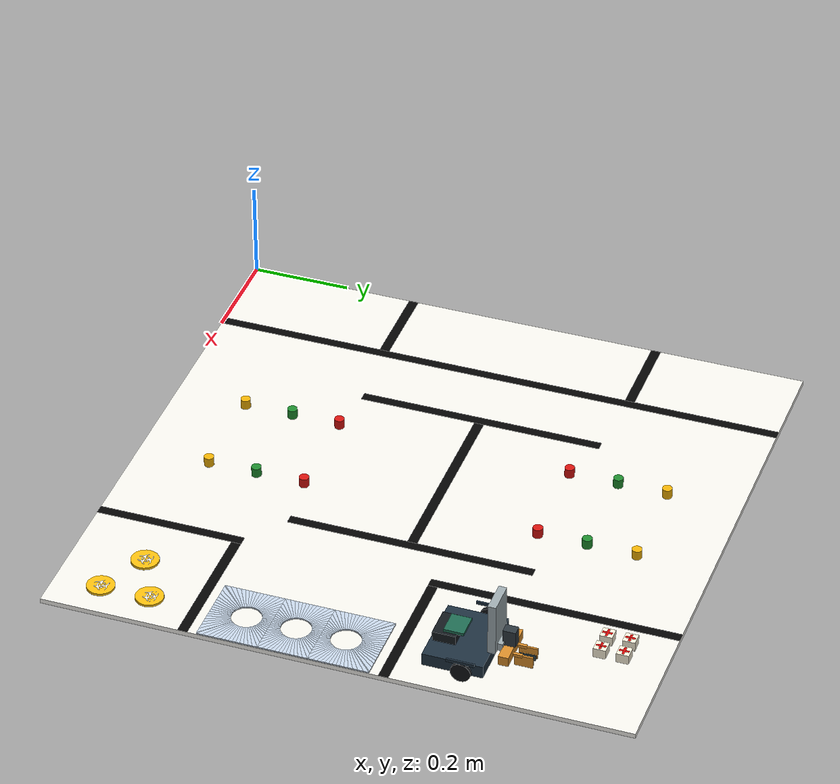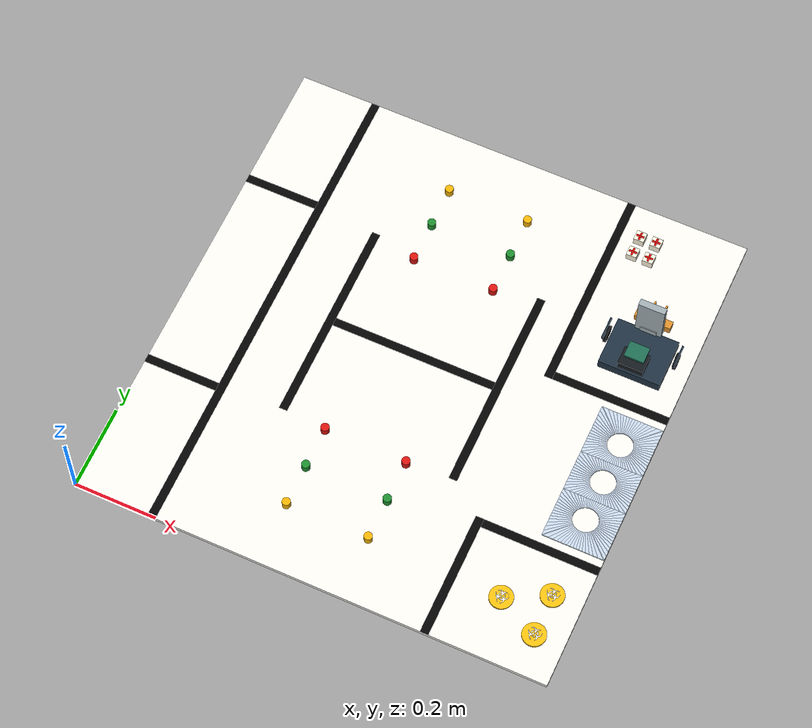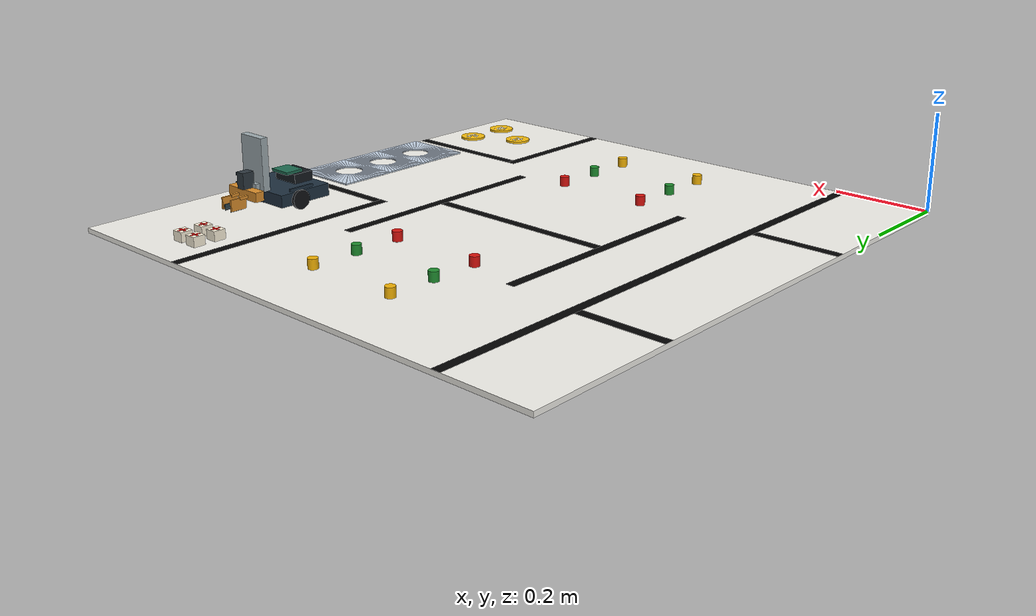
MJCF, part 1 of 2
<mujoco model="robotics_challenge_arena">
  <compiler angle="radian" autolimits="true" balanceinertia="false" />
  <option timestep="0.001" gravity="0 0 -9.81" integrator="implicitfast" solver="Newton" iterations="80" tolerance="1e-9" cone="elliptic" jacobian="sparse" impratio="100" />
  <size memory="256M" />
  <visual>
    <global offwidth="1280" offheight="960" />
    <map znear="0.005" zfar="10" />
  </visual>
  <default>
    <geom contype="1" conaffinity="3" condim="6" solref="0.001 1" solimp="0.98 0.999 0.0001" margin="0" gap="0" />
  </default>
  <asset>
    <mesh name="biohazard" vertex="0.00947962794453 -0.00525631848723 -4.99999987369e-06 0.00853166542947 0.00169540836941 -4.99999987369e-06 0.00852709729224 0.00197455659509 -4.99999987369e-06 0.0154999997467 0.00517127197236 -4.99999987369e-06 0.0094745522365 -0.00494615361094 -4.99999987369e-06 0.00851339753717 0.00225340598263 -4.99999987369e-06 0.00849058292806 0.00253165792674 -4.99999987369e-06 0.01549492497 0.00548143638298 -4.99999987369e-06 0.00845867488533 0.00280901440419 -4.99999987369e-06 0.00945933163166 -0.00463632168248 -4.99999987369e-06 0.00841771066189 0.00308517809026 -4.99999987369e-06 0.0154797034338 0.00579126924276 -4.99999987369e-06 0.00836773123592 0.00335985375568 -4.99999987369e-06 0.00943398103118 -0.00432715285569 -4.99999987369e-06 0.00830879155546 0.00363274710253 -4.99999987369e-06 0.0154543528333 0.00610043760389 -4.99999987369e-06 0.00824095588177 0.00390356546268 -4.99999987369e-06 0.00939852837473 -0.00401897868142 -4.99999987369e-06 0.00816429406404 0.00417202012613 -4.99999987369e-06 0.0154189011082 0.00640861177817 -4.99999987369e-06 0.0153733836487 0.00671546021476 -4.99999987369e-06 0.00807889085263 0.0044378223829 -4.99999987369e-06 0.0079848356545 0.00470068771392 -4.99999987369e-06 0.00935301184654 -0.00371213047765 -4.99999987369e-06 0.0153178526089 0.00702065601945 -4.99999987369e-06 0.00788223091513 0.00496033485979 -4.99999987369e-06 0.00777118466794 0.00521648628637 -4.99999987369e-06 0.00929747987539 -0.00340693467297 -4.99999987369e-06 0.00765181798488 0.00546886771917 -4.99999987369e-06 0.0152523629367 0.0073238699697 -4.99999987369e-06 0.00752425706014 0.005717207212 -4.99999987369e-06 0.00233991304412 0.00963993743062 -4.99999987369e-06 0.00738863879815 0.00596124073491 -4.99999987369e-06 0.00923199113458 -0.00310372002423 -4.99999987369e-06 0.0151769900694 0.00762478029355 -4.99999987369e-06 0.00724510848522 0.00620070612058 -4.99999987369e-06 0.00218922644854 0.00991108547896 -4.99999987369e-06 0.00709382025525 0.00643534772098 -4.99999987369e-06 0.00202974816784 0.0101771578193 -4.99999987369e-06 0.0069349356927 0.00666491314769 -4.99999987369e-06 0.00915661733598 -0.00280281039886 -4.99999987369e-06 0.00676862476394 0.00688915653154 -4.99999987369e-06 0.0065950662829 0.00710783852264 -4.99999987369e-06 0.00186165014748 0.0104378703982 -4.99999987369e-06 0.00641444558278 0.00732072629035 -4.99999987369e-06 0.0150918103755 0.00792306289077 -4.99999987369e-06 0.00168511189986 0.0106929438189 -4.99999987369e-06 0.00622695544735 0.00752758933231 -4.99999987369e-06 0.0060327979736 0.00772820599377 -4.99999987369e-06 0.0090714385733 -0.00250452803448 -4.99999987369e-06 0.00150032213423 0.0109421024099 -4.99999987369e-06 0.00583218084648 0.00792236439884 -4.99999987369e-06 0.0149969179183 0.00821839831769 -4.99999987369e-06 0.00562531780452 0.00810985360295 -4.99999987369e-06 0.00897654518485 -0.00220919237472 -4.99999987369e-06 0.00541243096814 0.00829047523439 -4.99999987369e-06 0.00130747910589 0.0111850844696 -4.99999987369e-06 0.00519374851137 0.0084640327841 -4.99999987369e-06 0.00887203961611 -0.00191711948719 -4.99999987369e-06 0.00496950466186 0.00863034464419 -4.99999987369e-06 0.00110678945202 0.0114216245711 -4.99999987369e-06 0.00473993923515 0.00878922920674 -4.99999987369e-06 0.00450529810041 0.00894051697105 -4.99999987369e-06 0.000898467376828 0.0116514721885 -4.99999987369e-06 0.0148924123496 0.00851047132164 -4.99999987369e-06 0.00426583271474 0.00908404681832 -4.99999987369e-06 0.0087580345571 -0.00162862217985 -4.99999987369e-06 0.00402179919183 0.00921966508031 -4.99999987369e-06 0.00377345876768 0.00934722647071 -4.99999987369e-06 0.000682736863382 0.0118743805215 -4.99999987369e-06 0.0035210782662 0.00946659315377 -4.99999987369e-06 0.000459828210296 0.0120901111513 -4.99999987369e-06 0.00326492683962 0.00957763940096 -4.99999987369e-06 0.000229980709264 0.0122984340414 -4.99999987369e-06 -6.5597705543e-06 0.0124991238117 -4.99999987369e-06 -0.00326492683962 0.00957763940096 -4.99999987369e-06 -0.0035210782662 0.00946659315377 -4.99999987369e-06 0.00863465014845 -0.00134400953539 -4.99999987369e-06 -0.000249540695222 0.0126919653267 -4.99999987369e-06 -0.00377345876768 0.00934722647071 -4.99999987369e-06 -0.000498700479511 0.012876755558 -4.99999987369e-06 -0.00402179919183 0.00921966508031 -4.99999987369e-06 -0.00426583271474 0.00908404681832 -4.99999987369e-06 0.00850201956928 -0.00106358656194 -4.99999987369e-06 -0.000753773318138 0.0130532942712 -4.99999987369e-06 -0.00450529810041 0.00894051697105 -4.99999987369e-06 -0.00473993923515 0.00878922920674 -4.99999987369e-06 0.00836028531194 -0.000787653087173 -4.99999987369e-06 -0.00101448560599 0.013221392408 -4.99999987369e-06 -0.00496950466186 0.00863034464419 -4.99999987369e-06 -0.00128055829555 0.013380870223 -4.99999987369e-06 -0.00519374851137 0.0084640327841 -4.99999987369e-06 -0.00541243096814 0.00829047523439 -4.99999987369e-06 0.00820959825069 -0.000516504806001 -4.99999987369e-06 -0.00562531780452 0.00810985360295 -4.99999987369e-06 -0.00155170669314 0.0135315572843 -4.99999987369e-06 -0.00583218084648 0.00792236439884 -4.99999987369e-06 -0.0018276401097 0.0136732915416 -4.99999987369e-06 0.00805012043566 -0.000250432087341 -4.99999987369e-06 -0.0060327979736 0.00772820599377 -4.99999987369e-06 -0.00622695544735 0.00752758933231 -4.99999987369e-06 -0.00210806308314 0.0138059211895 -4.99999987369e-06 -0.00641444558278 0.00732072629035 -4.99999987369e-06 -0.00239267572761 0.0139293055981 -4.99999987369e-06 -0.00268117291853 0.0140433125198 -4.99999987369e-06 -0.0065950662829 0.00710783852264 -4.99999987369e-06 -0.00676862476394 0.00688915653154 -4.99999987369e-06 -0.00297324592248 0.0141478171572 -4.99999987369e-06 -0.00326858158223 0.0142427096143 -4.99999987369e-06 -0.0069349356927 0.00666491314769 -4.99999987369e-06 -0.00356686394662 0.0143278893083 -4.99999987369e-06 -0.00709382025525 0.00643534772098 -4.99999987369e-06 -0.00386777357198 0.0144032631069 -4.99999987369e-06 -0.00724510848522 0.00620070612058 -4.99999987369e-06 -0.00417098868638 0.0144687518477 -4.99999987369e-06 -0.00738863879815 0.00596124073491 -4.99999987369e-06 -0.00447618402541 0.0145242838189 -4.99999987369e-06 -0.00752425706014 0.005717207212 -4.99999987369e-06 0.0133482245728 0.0111850844696 -4.99999987369e-06 -0.00765181798488 0.00546886771917 -4.99999987369e-06 -0.004783032462 0.0145698003471 -4.99999987369e-06 -0.00777118466794 0.00521648628637 -4.99999987369e-06 0.0131475338712 0.0114216245711 -4.99999987369e-06 -0.00788223091513 0.00496033485979 -4.99999987369e-06 -0.00509120617062 0.0146052520722 -4.99999987369e-06 -0.0079848356545 0.00470068771392 -4.99999987369e-06 0.0129392109811 0.0116514721885 -4.99999987369e-06 -0.00807889085263 0.0044378223829 -4.99999987369e-06 -0.00540037499741 0.014630603604 -4.99999987369e-06 -0.00816429406404 0.00417202012613 -4.99999987369e-06 -0.00571020739153 0.0146458251402 -4.99999987369e-06 -0.00824095588177 0.00390356546268 -4.99999987369e-06 0.0127234812826 0.0118743805215 -4.99999987369e-06 -0.00830879155546 0.00363274710253 -4.99999987369e-06 -0.00602037226781 0.0146508999169 -4.99999987369e-06 -0.00836773123592 0.00335985375568 -4.99999987369e-06 -0.00633053714409 0.0146458251402 -4.99999987369e-06 -0.00841771066189 0.00308517809026 -4.99999987369e-06 -0.00845867488533 0.00280901440419 -4.99999987369e-06 0.0125005720183 0.0120901111513 -4.99999987369e-06 -0.00664036953822 0.014630603604 -4.99999987369e-06 -0.00849058292806 0.00253165792674 -4.99999987369e-06 -0.00694953789935 0.0146052520722 -4.99999987369e-06 -0.00851339753717 0.00225340598263 -4.99999987369e-06 -0.00852709729224 0.00197455659509 -4.99999987369e-06 0.0122707244009 0.0122984340414 -4.99999987369e-06 -0.00853166542947 0.00169540836941 -4.99999987369e-06 -0.00725771207362 0.0145698003471 -4.99999987369e-06 -0.00852709729224 0.00141626014374 -4.99999987369e-06 -0.00756456051022 0.0145242838189 -4.99999987369e-06 -0.00851339753717 0.0011374107562 -4.99999987369e-06 0.0120341842994 0.0124991238117 -4.99999987369e-06 -0.00786975584924 0.0144687518477 -4.99999987369e-06 -0.00849058292806 0.000859158753883 -4.99999987369e-06 -0.00845867488533 0.000581802334636 -4.99999987369e-06 -0.00817297119647 0.0144032631069 -4.99999987369e-06 -0.00519374851137 -0.00507321627811 -4.99999987369e-06 -0.00847388058901 0.0143278893083 -4.99999987369e-06 -0.00496950466186 -0.00523952767253 -4.99999987369e-06 0.011791203171 0.0126919653267 -4.99999987369e-06 -0.00473993923515 -0.00539841223508 -4.99999987369e-06 -0.00877216272056 0.0142427096143 -4.99999987369e-06 -0.00450529810041 -0.00554970046505 -4.99999987369e-06 -0.00906749907881 0.0141478171572 -4.99999987369e-06 -0.00426583271474 -0.00569323031232 -4.99999987369e-06 0.0115420436487 0.012876755558 -4.99999987369e-06 -0.00935957115144 0.0140433125198 -4.99999987369e-06 -0.00402179919183 -0.00582884857431 -4.99999987369e-06 -0.00377345876768 -0.00595640949905 -4.99999987369e-06 -0.00964806880802 0.0139293055981 -4.99999987369e-06 -0.00993268098682 0.0138059211895 -4.99999987369e-06 -0.0035210782662 -0.00607577664778 -4.99999987369e-06 -0.00326492683962 -0.0061868224293 -4.99999987369e-06 0.0112869711593 0.0130532942712 -4.99999987369e-06 -0.010213105008 0.0136732915416 -4.99999987369e-06 -0.00300527946092 -0.00628942763433 -4.99999987369e-06 -0.0104890381917 0.0135315572843 -4.99999987369e-06 -0.00274241389707 -0.0063834823668 -4.99999987369e-06 0.0110262585804 0.013221392408 -4.99999987369e-06 -0.0024766116403 -0.00646888604388 -4.99999987369e-06 -0.00220815744251 -0.00654554739594 -4.99999987369e-06 0.0107601862401 0.013380870223 -4.99999987369e-06 -0.0019373386167 -0.0066133835353 -4.99999987369e-06 -0.0107601862401 0.013380870223 -4.99999987369e-06 -0.00166444538627 -0.00667232321575 -4.99999987369e-06 -0.0110262585804 0.013221392408 -4.99999987369e-06 -0.00138976960443 -0.00672230217606 -4.99999987369e-06 0.0104890381917 0.0135315572843 -4.99999987369e-06 -0.00111360568553 -0.00676326686516 -4.99999987369e-06 -0.0112869711593 0.0130532942712 -4.99999987369e-06 -0.0115420436487 0.012876755558 -4.99999987369e-06 -0.000836249382701 -0.00679517444223 -4.99999987369e-06 -0.000557997613214 -0.006817989517 -4.99999987369e-06 -0.011791203171 0.0126919653267 -4.99999987369e-06 0.010213105008 0.0136732915416 -4.99999987369e-06 -0.000279148254776 -0.00683168880641 -4.99999987369e-06 -1.14157097368e-18 -0.00683625647798 -4.99999987369e-06 -0.0120341842994 0.0124991238117 -4.99999987369e-06 -0.0122707244009 0.0122984340414 -4.99999987369e-06 0.000279148254776 -0.00683168880641 -4.99999987369e-06 0.000557997613214 -0.006817989517 -4.99999987369e-06 0.00993268098682 0.0138059211895 -4.99999987369e-06 -0.0125005720183 0.0120901111513 -4.99999987369e-06 0.000836249382701 -0.00679517444223 -4.99999987369e-06 0.00111360568553 -0.00676326686516 -4.99999987369e-06 0.00964806880802 0.0139293055981 -4.99999987369e-06 -0.0127234812826 0.0118743805215 -4.99999987369e-06 0.00138976960443 -0.00672230217606 -4.99999987369e-06 -0.0129392109811 0.0116514721885 -4.99999987369e-06 0.00166444538627 -0.00667232321575 -4.99999987369e-06 0.0019373386167 -0.0066133835353 -4.99999987369e-06 -0.0131475338712 0.0114216245711 -4.99999987369e-06 -0.0133482245728 0.0111850844696 -4.99999987369e-06 0.00220815744251 -0.00654554739594 -4.99999987369e-06 0.0024766116403 -0.00646888604388 -4.99999987369e-06 0.00935957115144 0.0140433125198 -4.99999987369e-06 0.00906749907881 0.0141478171572 -4.99999987369e-06 0.00274241389707 -0.0063834823668 -4.99999987369e-06 0.00300527946092 -0.00628942763433 -4.99999987369e-06 0.00877216272056 0.0142427096143 -4.99999987369e-06 0.00326492683962 -0.0061868224293 -4.99999987369e-06 0.00847388058901 0.0143278893083 -4.99999987369e-06 0.00817297119647 0.0144032631069 -4.99999987369e-06 0.0035210782662 -0.00607577664778 -4.99999987369e-06 0.00377345876768 -0.00595640949905 -4.99999987369e-06 0.00184938369785 0.0040411609225 -4.99999987369e-06 0.00786975584924 0.0144687518477 -4.99999987369e-06 0.00402179919183 -0.00582884857431 -4.99999987369e-06 0.00426583271474 -0.00569323031232 -4.99999987369e-06 -0.0148924123496 0.00851047132164 -4.99999987369e-06 0.00154418847524 0.00409669289365 -4.99999987369e-06 0.00450529810041 -0.00554970046505 -4.99999987369e-06 -0.0149969179183 0.00821839831769 -4.99999987369e-06 0.00473993923515 -0.00539841223508 -4.99999987369e-06 0.00496950466186 -0.00523952767253 -4.99999987369e-06 0.00756456051022 0.0145242838189 -4.99999987369e-06 -0.0150918103755 0.00792306289077 -4.99999987369e-06 0.00519374851137 -0.00507321627811 -4.99999987369e-06 -0.0151769900694 0.00762478029355 -4.99999987369e-06 0.00845867488533 0.000581802334636 -4.99999987369e-06 0.0012373396894 0.00414220942184 -4.99999987369e-06 0.00849058292806 0.000859158753883 -4.99999987369e-06 0.00851339753717 0.0011374107562 -4.99999987369e-06 0.00725771207362 0.0145698003471 -4.99999987369e-06 -0.0152523629367 0.0073238699697 -4.99999987369e-06 0.00852709729224 0.00141626014374 -4.99999987369e-06 -0.0153178526089 0.00702065601945 -4.99999987369e-06 0.00853166542947 0.00169540836941 4.99999987369e-06 0.000929166038986 0.00417766207829 -4.99999987369e-06 0.00852709729224 0.00197455659509 4.99999987369e-06 0.00851339753717 0.00225340598263 4.99999987369e-06 -0.0153733836487 0.00671546021476 -4.99999987369e-06 0.00694953789935 0.0146052520722 -4.99999987369e-06 0.00849058292806 0.00253165792674 4.99999987369e-06 -0.0154189011082 0.00640861177817 -4.99999987369e-06 0.00845867488533 0.00280901440419 4.99999987369e-06 0.00841771066189 0.00308517809026 4.99999987369e-06 0.000619997328613 0.00420301267877 -4.99999987369e-06 -0.0154543528333 0.00610043760389 -4.99999987369e-06 0.00836773123592 0.00335985375568 4.99999987369e-06 0.00830879155546 0.00363274710253 4.99999987369e-06 0.00664036953822 0.014630603604 -4.99999987369e-06 -0.0154797034338 0.00579126924276 -4.99999987369e-06 0.00824095588177 0.00390356546268 4.99999987369e-06 0.00816429406404 0.00417202012613 4.99999987369e-06 0.00633053714409 0.0146458251402 -4.99999987369e-06 0.000310164730763 0.00421823374927 -4.99999987369e-06 0.00807889085263 0.0044378223829 4.99999987369e-06 -0.01549492497 0.00548143638298 -4.99999987369e-06 0.0079848356545 0.00470068771392 4.99999987369e-06 0.00788223091513 0.00496033485979 4.99999987369e-06 -0.0154999997467 0.00517127197236 -4.99999987369e-06 0.00777118466794 0.00521648628637 4.99999987369e-06 1.00613028133e-18 0.00422330899164 -4.99999987369e-06 0.00765181798488 0.00546886771917 4.99999987369e-06 0.00602037226781 0.0146508999169 -4.99999987369e-06 -0.01549492497 0.00486110756174 -4.99999987369e-06 0.00752425706014 0.005717207212 4.99999987369e-06 0.00738863879815 0.00596124073491 4.99999987369e-06 -0.0154797034338 0.00455127470195 -4.99999987369e-06 0.00724510848522 0.00620070612058 4.99999987369e-06 -0.000310164730763 0.00421823374927 -4.99999987369e-06 0.00571020739153 0.0146458251402 -4.99999987369e-06 0.00709382025525 0.00643534772098 4.99999987369e-06 -0.0154543528333 0.00424210587516 -4.99999987369e-06 0.0069349356927 0.00666491314769 4.99999987369e-06 -0.0154189011082 0.00393393170089 -4.99999987369e-06 0.00676862476394 0.00688915653154 4.99999987369e-06 -0.000619997328613 0.00420301267877 -4.99999987369e-06 0.0065950662829 0.00710783852264 4.99999987369e-06 0.00540037499741 0.014630603604 -4.99999987369e-06 0.00641444558278 0.00732072629035 4.99999987369e-06 -0.0153733836487 0.00362708349712 -4.99999987369e-06 0.00622695544735 0.00752758933231 4.99999987369e-06 0.0060327979736 0.00772820599377 4.99999987369e-06 -0.000929166038986 0.00417766207829 -4.99999987369e-06 0.00583218084648 0.00792236439884 4.99999987369e-06 -0.0153178526089 0.00332188792527 -4.99999987369e-06 0.00562531780452 0.00810985360295 4.99999987369e-06 0.00509120617062 0.0146052520722 -4.99999987369e-06 0.00541243096814 0.00829047523439 4.99999987369e-06 -0.0152523629367 0.00301867327653 -4.99999987369e-06 0.00519374851137 0.0084640327841 4.99999987369e-06 -0.0151769900694 0.00271776341833 -4.99999987369e-06 0.00496950466186 0.00863034464419 4.99999987369e-06 0.004783032462 0.0145698003471 -4.99999987369e-06 -0.0012373396894 0.00414220942184 -4.99999987369e-06 0.00473993923515 0.00878922920674 4.99999987369e-06 0.00450529810041 0.00894051697105 4.99999987369e-06 -0.0150918103755 0.00241948128678 -4.99999987369e-06 0.00426583271474 0.00908404681832 4.99999987369e-06 -0.0149969179183 0.00212414516136 -4.99999987369e-06 0.00402179919183 0.00921966508031 4.99999987369e-06 0.00447618402541 0.0145242838189 -4.99999987369e-06 0.00377345876768 0.00934722647071 4.99999987369e-06 -0.0148924123496 0.00183207262307 -4.99999987369e-06 0.0035210782662 0.00946659315377 4.99999987369e-06 -0.00154418847524 0.00409669289365 -4.99999987369e-06 0.00326492683962 0.00957763940096 4.99999987369e-06 0.00417098868638 0.0144687518477 -4.99999987369e-06 -0.00326492683962 0.00957763940096 4.99999987369e-06 -0.0147784063593 0.00154357531574 -4.99999987369e-06 -0.0035210782662 0.00946659315377 4.99999987369e-06 -0.00184938369785 0.0040411609225 -4.99999987369e-06 -0.00377345876768 0.00934722647071 4.99999987369e-06 -0.0146550219506 0.00125896302052 -4.99999987369e-06 0.00386777357198 0.0144032631069 -4.99999987369e-06 -0.00402179919183 0.00921966508031 4.99999987369e-06 -0.0145223913714 0.000978539464995 -4.99999987369e-06 -0.00426583271474 0.00908404681832 4.99999987369e-06 -0.00450529810041 0.00894051697105 4.99999987369e-06 -0.0143806571141 0.000702606048435 -4.99999987369e-06 -0.0142299709842 0.000431458000094 -4.99999987369e-06 -0.00473993923515 0.00878922920674 4.99999987369e-06 -0.00496950466186 0.00863034464419 4.99999987369e-06 0.00356686394662 0.0143278893083 -4.99999987369e-06 -0.00519374851137 0.0084640327841 4.99999987369e-06 -0.0140704931691 0.000165385295986 -4.99999987369e-06 -0.00541243096814 0.00829047523439 4.99999987369e-06 -0.013902394101 -9.53270136961e-05 -4.99999987369e-06 -0.00562531780452 0.00810985360295 4.99999987369e-06 -0.0137258553877 -0.000350399874151 -4.99999987369e-06 0.00326858158223 0.0142427096143 -4.99999987369e-06 -0.00583218084648 0.00792236439884 4.99999987369e-06 -0.0135410660878 -0.000599559629336 -4.99999987369e-06 -0.0060327979736 0.00772820599377 4.99999987369e-06 -0.00622695544735 0.00752758933231 4.99999987369e-06 0.00297324592248 0.0141478171572 -4.99999987369e-06 -0.00641444558278 0.00732072629035 4.99999987369e-06 -0.0133482245728 -0.000842540583108 -4.99999987369e-06 0.00268117291853 0.0140433125198 -4.99999987369e-06 -0.0065950662829 0.00710783852264 4.99999987369e-06 -0.00676862476394 0.00688915653154 4.99999987369e-06 -0.0131475338712 -0.00107908109203 -4.99999987369e-06 -0.0069349356927 0.00666491314769 4.99999987369e-06 -0.0129392109811 -0.00130892859306 -4.99999987369e-06 -0.00709382025525 0.00643534772098 4.99999987369e-06 -0.0127234812826 -0.00153183715884 -4.99999987369e-06 -0.00724510848522 0.00620070612058 4.99999987369e-06 0.00239267572761 0.0139293055981 -4.99999987369e-06 -0.0125005720183 -0.00174756767228 -4.99999987369e-06 -0.00738863879815 0.00596124073491 4.99999987369e-06 -0.00752425706014 0.005717207212 4.99999987369e-06 0.00210806308314 0.0138059211895 -4.99999987369e-06 -0.00765181798488 0.00546886771917 4.99999987369e-06 -0.0122707244009 -0.00195588986389 -4.99999987369e-06 -0.00777118466794 0.00521648628637 4.99999987369e-06 -0.0120341842994 -0.00215657940134 -4.99999987369e-06 -0.011791203171 -0.00234942231327 -4.99999987369e-06 -0.00788223091513 0.00496033485979 4.99999987369e-06 -0.0079848356545 0.00470068771392 4.99999987369e-06 0.0018276401097 0.0136732915416 -4.99999987369e-06 -0.00807889085263 0.0044378223829 4.99999987369e-06 -0.0115420436487 -0.00253421231173 -4.99999987369e-06 -0.00816429406404 0.00417202012613 4.99999987369e-06 -0.0112869711593 -0.00271075032651 -4.99999987369e-06 0.00155170669314 0.0135315572843 -4.99999987369e-06 -0.00824095588177 0.00390356546268 4.99999987369e-06 -0.0110262585804 -0.0028788484633 -4.99999987369e-06 -0.00830879155546 0.00363274710253 4.99999987369e-06 0.00128055829555 0.013380870223 -4.99999987369e-06 -0.00836773123592 0.00335985375568 4.99999987369e-06 -0.0107601862401 -0.00303832674399 -4.99999987369e-06 -0.00841771066189 0.00308517809026 4.99999987369e-06 -0.0104890381917 -0.00318901333958 -4.99999987369e-06 -0.00845867488533 0.00280901440419 4.99999987369e-06 -0.010213105008 -0.00333074759692 -4.99999987369e-06 -0.00849058292806 0.00253165792674 4.99999987369e-06 0.00101448560599 0.013221392408 -4.99999987369e-06 -0.00851339753717 0.00225340598263 4.99999987369e-06 -0.00993268098682 -0.00346337794326 -4.99999987369e-06 -0.00852709729224 0.00197455659509 4.99999987369e-06 -0.00964806880802 -0.00358676235192 -4.99999987369e-06 -0.00853166542947 0.00169540836941 4.99999987369e-06 -0.00935957115144 -0.00370076764375 -4.99999987369e-06 -0.00852709729224 0.00141626014374 4.99999987369e-06 -0.00851339753717 0.0011374107562 4.99999987369e-06 0.000753773318138 0.0130532942712 -4.99999987369e-06 -0.00906749907881 -0.00380527321249 -4.99999987369e-06 -0.00849058292806 0.000859158753883 4.99999987369e-06 -0.00845867488533 0.000581802334636 4.99999987369e-06 0.000498700479511 0.012876755558 -4.99999987369e-06 -0.00519374851137 -0.00507321627811 4.99999987369e-06 -0.00877216272056 -0.00390016636811 -4.99999987369e-06 -0.00496950466186 -0.00523952767253 4.99999987369e-06 -0.00847388058901 -0.00398534582928 -4.99999987369e-06 0.000249540695222 0.0126919653267 -4.99999987369e-06 -0.00473993923515 -0.00539841223508 4.99999987369e-06 -0.00450529810041 -0.00554970046505 4.99999987369e-06 -0.00817297119647 -0.00406071916223 -4.99999987369e-06 -0.00426583271474 -0.00569323031232 4.99999987369e-06 -0.00786975584924 -0.00412620790303 -4.99999987369e-06 -0.00402179919183 -0.00582884857431 4.99999987369e-06 6.5597705543e-06 0.0124991238117 -4.99999987369e-06 -0.00756456051022 -0.00418173987418 -4.99999987369e-06 -0.00377345876768 -0.00595640949905 4.99999987369e-06 -0.00725771207362 -0.00422725640237 -4.99999987369e-06 -0.0035210782662 -0.00607577664778 4.99999987369e-06 -0.00326492683962 -0.0061868224293 4.99999987369e-06 -0.000229980709264 0.0122984340414 -4.99999987369e-06 -0.00300527946092 -0.00628942763433 4.99999987369e-06 -0.00694953789935 -0.00426270859316 -4.99999987369e-06 -0.00664036953822 -0.00428805919364 -4.99999987369e-06 -0.00274241389707 -0.0063834823668 4.99999987369e-06 -0.0024766116403 -0.00646888604388 4.99999987369e-06 -0.00633053714409 -0.0043032807298 -4.99999987369e-06 -0.00220815744251 -0.00654554739594 4.99999987369e-06 -0.000459828210296 0.0120901111513 -4.99999987369e-06 -0.00602037226781 -0.00430835597217 -4.99999987369e-06 -0.0019373386167 -0.0066133835353 4.99999987369e-06 -0.00166444538627 -0.00667232321575 4.99999987369e-06 -0.000682736863382 0.0118743805215 -4.99999987369e-06 -0.00571020739153 -0.0043032807298 -4.99999987369e-06 -0.00138976960443 -0.00672230217606 4.99999987369e-06 -0.000898467376828 0.0116514721885 -4.99999987369e-06 -0.00111360568553 -0.00676326686516 4.99999987369e-06 -0.000836249382701 -0.00679517444223 4.99999987369e-06 -0.00110678945202 0.0114216245711 -4.99999987369e-06 -0.000557997613214 -0.006817989517 4.99999987369e-06 -0.00130747910589 0.0111850844696 -4.99999987369e-06 -0.000279148254776 -0.00683168880641 4.99999987369e-06 -0.00150032213423 0.0109421024099 -4.99999987369e-06 -0.00168511189986 0.0106929438189 -4.99999987369e-06 -1.14157097368e-18 -0.00683625647798 4.99999987369e-06 0.000279148254776 -0.00683168880641 4.99999987369e-06 -0.00186165014748 0.0104378703982 -4.99999987369e-06 0.000557997613214 -0.006817989517 4.99999987369e-06 -0.00805012043566 -0.000250432087341 -4.99999987369e-06 -0.00202974816784 0.0101771578193 -4.99999987369e-06 0.000836249382701 -0.00679517444223 4.99999987369e-06 -0.00218922644854 0.00991108547896 -4.99999987369e-06 0.00111360568553 -0.00676326686516 4.99999987369e-06 -0.00820959825069 -0.000516504806001 -4.99999987369e-06 0.00138976960443 -0.00672230217606 4.99999987369e-06 -0.00233991304412 0.00963993743062 -4.99999987369e-06 0.00166444538627 -0.00667232321575 4.99999987369e-06 -0.00836028531194 -0.000787653087173 -4.99999987369e-06 0.0019373386167 -0.0066133835353 4.99999987369e-06 -0.00850201956928 -0.00106358656194 -4.99999987369e-06 0.00220815744251 -0.00654554739594 4.99999987369e-06 -0.00863465014845 -0.00134400953539 -4.99999987369e-06 0.0024766116403 -0.00646888604388 4.99999987369e-06 0.00274241389707 -0.0063834823668 4.99999987369e-06 -0.0087580345571 -0.00162862217985 -4.99999987369e-06 0.00300527946092 -0.00628942763433 4.99999987369e-06 0.00110678945202 -0.00107908109203 -4.99999987369e-06 0.00326492683962 -0.0061868224293 4.99999987369e-06 0.00130747910589 -0.000842540583108 -4.99999987369e-06 -0.00887203961611 -0.00191711948719 -4.99999987369e-06 0.0035210782662 -0.00607577664778 4.99999987369e-06 0.00150032213423 -0.000599559629336 -4.99999987369e-06 0.00377345876768 -0.00595640949905 4.99999987369e-06 0.00402179919183 -0.00582884857431 4.99999987369e-06 0.00168511189986 -0.000350399874151 -4.99999987369e-06 0.00426583271474 -0.00569323031232 4.99999987369e-06 -0.00897654518485 -0.00220919237472 -4.99999987369e-06 0.00186165014748 -9.53270136961e-05 -4.99999987369e-06 0.00450529810041 -0.00554970046505 4.99999987369e-06 0.00202974816784 0.000165385295986 -4.99999987369e-06 0.00473993923515 -0.00539841223508 4.99999987369e-06 0.00496950466186 -0.00523952767253 4.99999987369e-06 -0.0090714385733 -0.00250452803448 -4.99999987369e-06 0.00519374851137 -0.00507321627811 4.99999987369e-06 0.00218922644854 0.000431458000094 -4.99999987369e-06 0.00845867488533 0.000581802334636 4.99999987369e-06 -0.00915661733598 -0.00280281039886 -4.99999987369e-06 0.00233991304412 0.000702606048435 -4.99999987369e-06 0.00849058292806 0.000859158753883 4.99999987369e-06 0.00248164730147 0.000978539464995 -4.99999987369e-06 0.00851339753717 0.0011374107562 4.99999987369e-06 0.00852709729224 0.00141626014374 4.99999987369e-06 -0.00923199113458 -0.00310372002423 -4.99999987369e-06 0.00261427764781 0.00125896302052 -4.99999987369e-06 -0.00183452712372 -0.00435221707448 -4.99999987369e-06 -0.00163567217533 -0.00440900307149 -4.99999987369e-06 -0.00929747987539 -0.00340693467297 -4.99999987369e-06 0.00273766205646 0.00154357531574 -4.99999987369e-06 -0.00102945894469 -0.00453993258998 -4.99999987369e-06 0.0028516673483 0.00183207262307 -4.99999987369e-06 -0.00123292242642 -0.00450291112065 -4.99999987369e-06 0.00295617291704 0.00212414516136 -4.99999987369e-06 -0.000824893184472 -0.00457027740777 -4.99999987369e-06 -0.001435065642 -0.00445925211534 -4.99999987369e-06 -0.00935301184654 -0.00371213047765 -4.99999987369e-06 -0.00939852837473 -0.00401897868142 -4.99999987369e-06 -0.000619444006588 -0.0045939120464 -4.99999987369e-06 -0.00943398103118 -0.00432715285569 -4.99999987369e-06 -0.000413331523305 -0.0046108122915 -4.99999987369e-06 -0.00945933163166 -0.00463632168248 -4.99999987369e-06 -7.35249000045e-19 -0.00462434347719 -4.99999987369e-06 -0.0094745522365 -0.00494615361094 -4.99999987369e-06 0.000413331523305 -0.0046108122915 -4.99999987369e-06 0.000206776472623 -0.00462095998228 -4.99999987369e-06 -0.00947962794453 -0.00525631848723 -4.99999987369e-06 -0.0094745522365 -0.00556648336351 -4.99999987369e-06 -0.000206776472623 -0.00462095998228 -4.99999987369e-06 0.00102945894469 -0.00453993258998 -4.99999987369e-06 -0.00945933163166 -0.00587631575763 -4.99999987369e-06 -0.00943398103118 -0.00618548458442 -4.99999987369e-06 0.000824893184472 -0.00457027740777 -4.99999987369e-06 0.00163567217533 -0.00440900307149 -4.99999987369e-06 -0.00939852837473 -0.0064936587587 -4.99999987369e-06 0.001435065642 -0.00445925211534 -4.99999987369e-06 -0.00935301184654 -0.00680050719529 -4.99999987369e-06 -0.00929747987539 -0.00710570253432 -4.99999987369e-06 0.00123292242642 -0.00450291112065 -4.99999987369e-06 0.00203141756356 -0.00428895512596 -4.99999987369e-06 0.00233991304412 0.00963993743062 4.99999987369e-06 -0.00923199113458 -0.00740891741589 -4.99999987369e-06 0.00241846451536 -0.00414328090847 -4.99999987369e-06 0.00222613289952 -0.0042192847468 -4.99999987369e-06 0.00218922644854 0.00991108547896 4.99999987369e-06 0.00297911046073 -0.00387811544351 -4.99999987369e-06 -0.00915661733598 -0.00770982727408 -4.99999987369e-06 0.00279515469447 -0.00397260440513 -4.99999987369e-06 0.00202974816784 0.0101771578193 4.99999987369e-06 0.00260820612311 -0.00406102463603 -4.99999987369e-06 0.00186165014748 0.0104378703982 4.99999987369e-06 0.00183452712372 -0.00435221707448 -4.99999987369e-06 0.00168511189986 0.0106929438189 4.99999987369e-06 0.000619444006588 -0.0045939120464 -4.99999987369e-06 -0.0090714385733 -0.00800810940564 -4.99999987369e-06 0.00333725754172 -0.00367133854888 -4.99999987369e-06 -0.00295617291704 0.00212414516136 -4.99999987369e-06 0.00150032213423 0.0109421024099 4.99999987369e-06 0.00351106585003 -0.0035592734348 -4.99999987369e-06 0.00384722091258 -0.0033183877822 -4.99999987369e-06 -0.00897654518485 -0.00830344576389 -4.99999987369e-06 0.00130747910589 0.0111850844696 4.99999987369e-06 0.00368111464195 -0.00344158080406 -4.99999987369e-06 -0.00887203961611 -0.00859551783651 -4.99999987369e-06 0.00315987598151 -0.00377765763551 -4.99999987369e-06 0.00110678945202 0.0114216245711 4.99999987369e-06 -0.00631975196302 0.00169540836941 -4.99999987369e-06 -0.0028516673483 0.00183207262307 -4.99999987369e-06 -0.00631636846811 0.00148863217328 -4.99999987369e-06 -0.00631636846811 0.00190218456555 -4.99999987369e-06 0.000898467376828 0.0116514721885 4.99999987369e-06 -0.00630622077733 0.00128207658418 -4.99999987369e-06 -0.00273766205646 0.00154357531574 -4.99999987369e-06 -0.00630622077733 0.00210874015465 -4.99999987369e-06 0.000682736863382 0.0118743805215 4.99999987369e-06 -0.00628932053223 0.00107596453745 -4.99999987369e-06 0.000459828210296 0.0120901111513 4.99999987369e-06 -0.0087580345571 -0.00888401549309 -4.99999987369e-06 -0.00626568542793 0.000870515417773 -4.99999987369e-06 0.000229980709264 0.0122984340414 4.99999987369e-06 -0.00623534107581 0.00272486754693 -4.99999987369e-06 -0.00863465014845 -0.0091686276719 -4.99999987369e-06 -0.00626568542793 0.00252030137926 -4.99999987369e-06 -0.00628932053223 0.0023148523178 -4.99999987369e-06 -6.5597705543e-06 0.0124991238117 4.99999987369e-06 -0.00261427764781 0.00125896302052 -4.99999987369e-06 -0.00619831960648 0.00292833056301 -4.99999987369e-06 -0.000249540695222 0.0126919653267 4.99999987369e-06 -0.00615466060117 0.003130473895 -4.99999987369e-06 -0.00850201956928 -0.00944905076176 -4.99999987369e-06 -0.00610441109166 0.00333108031191 -4.99999987369e-06 -0.000498700479511 0.012876755558 4.99999987369e-06 -0.00598436361179 0.00372682604939 -4.99999987369e-06 -0.0058386893943 0.00411387300119 -4.99999987369e-06 -0.00248164730147 0.000978539464995 -4.99999987369e-06 -0.00591469323263 0.00392154138535 -4.99999987369e-06 -0.000753773318138 0.0130532942712 4.99999987369e-06 -0.00604762556031 0.00352993584238 -4.99999987369e-06 -0.00836028531194 -0.00972498487681 -4.99999987369e-06 -0.00233991304412 0.000702606048435 -4.99999987369e-06 -0.00557352369651 0.00467451894656 -4.99999987369e-06 -0.00566801289096 0.0044905631803 -4.99999987369e-06 -0.00101448560599 0.013221392408 4.99999987369e-06 -0.00536674680188 0.00503266556188 -4.99999987369e-06 -0.00820959825069 -0.00999613292515 -4.99999987369e-06 -0.00513698905706 0.00537652336061 -4.99999987369e-06 -0.00128055829555 0.013380870223 4.99999987369e-06 -0.00218922644854 0.000431458000094 -4.99999987369e-06 -0.0052546816878 0.00520647410303 -4.99999987369e-06 -0.00547306612134 0.00485528446734 -4.99999987369e-06 -0.00155170669314 0.0135315572843 4.99999987369e-06 -0.00475144106895 0.00586231052876 -4.99999987369e-06 -0.00805012043566 -0.0102622043341 -4.99999987369e-06 -0.00488523440436 0.00570461666211 -4.99999987369e-06 -0.0018276401097 0.0136732915416 4.99999987369e-06 -0.00202974816784 0.000165385295986 -4.99999987369e-06 -0.00446873949841 0.00616414798424 -4.99999987369e-06 -0.00210806308314 0.0138059211895 4.99999987369e-06 -0.00432013394311 0.00630796840414 -4.99999987369e-06 -0.00186165014748 -9.53270136961e-05 -4.99999987369e-06 -0.00461255991831 0.00601554149762 -4.99999987369e-06 -0.0050137960352 0.00554262939841 -4.99999987369e-06 -0.00239267572761 0.0139293055981 4.99999987369e-06 -0.00575643312186 0.00430361460894 -4.99999987369e-06 -0.00788202229887 -0.0105229178444 -4.99999987369e-06 -0.00268117291853 0.0140433125198 4.99999987369e-06 0.00260820612311 0.00745184207335 -4.99999987369e-06 0.00297911046073 0.007268932648 -4.99999987369e-06 -0.00770548405126 -0.0107779903337 -4.99999987369e-06 -0.00297324592248 0.0141478171572 4.99999987369e-06 0.00279515469447 0.00736342137679 -4.99999987369e-06 0.00241846451536 0.00753409834579 -4.99999987369e-06 -0.00168511189986 -0.000350399874151 -4.99999987369e-06 -0.00326858158223 0.0142427096143 4.99999987369e-06 0.00351106585003 0.00695009063929 -4.99999987369e-06 -0.00752069428563 -0.0110271498561 -4.99999987369e-06 0.00333725754172 0.00706215528771 -4.99999987369e-06 -0.00356686394662 0.0143278893083 4.99999987369e-06 0.00400920817629 0.00658064242452 -4.99999987369e-06 -0.00150032213423 -0.000599559629336 -4.99999987369e-06 0.00384722091258 0.00670920405537 -4.99999987369e-06 0.00368111464195 0.00683239800856 -4.99999987369e-06 -0.00386777357198 0.0144032631069 4.99999987369e-06 0.00432013394311 0.00630796840414 -4.99999987369e-06 -0.0073278513737 -0.0112701309845 -4.99999987369e-06 0.00446873949841 0.00616414798424 -4.99999987369e-06 -0.00417098868638 0.0144687518477 4.99999987369e-06 -0.00130747910589 -0.000842540583108 -4.99999987369e-06 0.00461255991831 0.00601554149762 -4.99999987369e-06 0.00475144106895 0.00586231052876 -4.99999987369e-06 -0.00447618402541 0.0145242838189 4.99999987369e-06 -0.00712716160342 -0.011506671086 -4.99999987369e-06 0.0050137960352 0.00554262939841 -4.99999987369e-06 0.00488523440436 0.00570461666211 -4.99999987369e-06 -0.004783032462 0.0145698003471 4.99999987369e-06 -0.00110678945202 -0.00107908109203 -4.99999987369e-06 0.00416690204293 0.00644684955478 -4.99999987369e-06 0.00315987598151 0.00716847507283 -4.99999987369e-06 -0.00509120617062 0.0146052520722 4.99999987369e-06 0.00536674680188 0.00503266556188 -4.99999987369e-06 -0.00540037499741 0.014630603604 4.99999987369e-06 -0.00571020739153 0.0146458251402 4.99999987369e-06 0.0052546816878 0.00520647410303 -4.99999987369e-06 -0.00691883964464 -0.0117365187034 -4.99999987369e-06 0.00566801289096 0.0044905631803 -4.99999987369e-06 -0.00602037226781 0.0146508999169 4.99999987369e-06 0.00557352369651 0.00467451894656 -4.99999987369e-06 -0.00670310901478 -0.0119594279677 -4.99999987369e-06 0.00547306612134 0.00485528446734 -4.99999987369e-06 0.0058386893943 0.00411387300119 -4.99999987369e-06 -0.00633053714409 0.0146458251402 4.99999987369e-06 0.00598436361179 0.00372682604939 -4.99999987369e-06 -0.00664036953822 0.014630603604 4.99999987369e-06 -0.00648020021617 -0.0121751576662 -4.99999987369e-06 0.00591469323263 0.00392154138535 -4.99999987369e-06 0.00615466060117 0.003130473895 -4.99999987369e-06 -0.00694953789935 0.0146052520722 4.99999987369e-06 -0.00725771207362 0.0145698003471 4.99999987369e-06 0.00610441109166 0.00333108031191 -4.99999987369e-06 0.00604762556031 0.00352993584238 -4.99999987369e-06 -0.00625035306439 -0.0123834805563 -4.99999987369e-06 0.00575643312186 0.00430361460894 -4.99999987369e-06 -0.00756456051022 0.0145242838189 4.99999987369e-06 -0.00786975584924 0.0144687518477 4.99999987369e-06 0.00513698905706 0.00537652336061 -4.99999987369e-06 -0.00601381249726 -0.0125841703266 -4.99999987369e-06 -0.00416690204293 0.00644684955478 -4.99999987369e-06 -0.00368111464195 -0.00344158080406 -4.99999987369e-06 -0.00817297119647 0.0144032631069 4.99999987369e-06 -0.00368111464195 0.00683239800856 -4.99999987369e-06 -0.00847388058901 0.0143278893083 4.99999987369e-06 -0.00877216272056 0.0142427096143 4.99999987369e-06 -0.00384722091258 -0.0033183877822 -4.99999987369e-06 -0.00577083136886 -0.0127770127729 -4.99999987369e-06 -0.00384722091258 0.00670920405537 -4.99999987369e-06 -0.00400920817629 0.00658064242452 -4.99999987369e-06 -0.00906749907881 0.0141478171572 4.99999987369e-06 -0.00552167184651 -0.0129618020728 -4.99999987369e-06 -0.00315987598151 -0.00377765763551 -4.99999987369e-06 -0.00333725754172 -0.00367133854888 -4.99999987369e-06 -0.00935957115144 0.0140433125198 4.99999987369e-06 -0.00964806880802 0.0139293055981 4.99999987369e-06 -0.00333725754172 0.00706215528771 -4.99999987369e-06 -0.00297911046073 0.007268932648 -4.99999987369e-06 -0.00526659889147 -0.0131383407861 -4.99999987369e-06 -0.00279515469447 -0.00397260440513 -4.99999987369e-06 -0.00993268098682 0.0138059211895 4.99999987369e-06 -0.00279515469447 0.00736342137679 -4.99999987369e-06 -0.010213105008 0.0136732915416 4.99999987369e-06 -0.00500588677824 -0.0133064398542 -4.99999987369e-06 -0.00297911046073 -0.00387811544351 -4.99999987369e-06 -0.0104890381917 0.0135315572843 4.99999987369e-06 -0.00315987598151 0.00716847507283 -4.99999987369e-06 -0.0107601862401 0.013380870223 4.99999987369e-06 -0.00260820612311 -0.00406102463603 -4.99999987369e-06 -0.0110262585804 0.013221392408 4.99999987369e-06 -0.00351106585003 -0.0035592734348 -4.99999987369e-06 -0.00351106585003 0.00695009063929 -4.99999987369e-06 -0.00473981397226 -0.0134659176692 -4.99999987369e-06 -0.0112869711593 0.0130532942712 4.99999987369e-06 -0.00260820612311 0.00745184207335 -4.99999987369e-06 -0.00241846451536 -0.00414328090847 -4.99999987369e-06 -0.00446866545826 -0.0136166037992 -4.99999987369e-06 -0.00222613289952 -0.0042192847468 -4.99999987369e-06 -0.0115420436487 0.012876755558 4.99999987369e-06 -0.00241846451536 0.00753409834579 -4.99999987369e-06 -0.011791203171 0.0126919653267 4.99999987369e-06 0.00619831960648 0.00292833056301 -4.99999987369e-06 -0.0120341842994 0.0124991238117 4.99999987369e-06 -0.00203141756356 -0.00428895512596 -4.99999987369e-06 -0.00419273227453 -0.0137583380565 -4.99999987369e-06 0.00628932053223 0.00107596453745 -4.99999987369e-06 -0.00391230918467 -0.0138909677044 -4.99999987369e-06 -0.0122707244009 0.0122984340414 4.99999987369e-06 0.00626568542793 0.000870515417773 -4.99999987369e-06 -0.0125005720183 0.0120901111513 4.99999987369e-06 0.00626568542793 0.00252030137926 -4.99999987369e-06 0.00630622077733 0.00210874015465 -4.99999987369e-06 -0.0127234812826 0.0118743805215 4.99999987369e-06 -0.00362769654021 -0.014014352113 -4.99999987369e-06 0.00631975196302 0.00169540836941 -4.99999987369e-06 0.00631636846811 0.00148863217328 -4.99999987369e-06 -0.0129392109811 0.0116514721885 4.99999987369e-06 -0.00333919911645 -0.0141283590347 -4.99999987369e-06 0.00631636846811 0.00190218456555 -4.99999987369e-06 -0.0131475338712 0.0114216245711 4.99999987369e-06 0.00630622077733 0.00128207658418 -4.99999987369e-06 0.00628932053223 0.0023148523178 -4.99999987369e-06 -0.0133482245728 0.0111850844696 4.99999987369e-06 -0.00304712634534 -0.0142328646034 -4.99999987369e-06 0.00623534107581 0.00272486754693 -4.99999987369e-06 0.00260820612311 0.00745184207335 4.99999987369e-06 -0.00275179068558 -0.0143277570605 -4.99999987369e-06 0.00241846451536 0.00753409834579 4.99999987369e-06 -0.00245350808837 -0.0144129358232 -4.99999987369e-06 0.00315987598151 0.00716847507283 4.99999987369e-06 -0.002152598463 -0.0144883096218 -4.99999987369e-06 0.00297911046073 0.007268932648 4.99999987369e-06 -0.00184938369785 -0.0145537992939 -4.99999987369e-06 0.00279515469447 0.00736342137679 4.99999987369e-06 -0.0148924123496 0.00851047132164 4.99999987369e-06 -0.0149969179183 0.00821839831769 4.99999987369e-06 0.00351106585003 0.00695009063929 4.99999987369e-06 0.00368111464195 0.00683239800856 4.99999987369e-06 -0.0150918103755 0.00792306289077 4.99999987369e-06 0.00400920817629 0.00658064242452 4.99999987369e-06 -0.00154418847524 -0.0146093303338 -4.99999987369e-06 -0.0151769900694 0.00762478029355 4.99999987369e-06 0.00432013394311 0.00630796840414 4.99999987369e-06 -0.0152523629367 0.0073238699697 4.99999987369e-06 0.00416690204293 0.00644684955478 4.99999987369e-06 -0.0153178526089 0.00702065601945 4.99999987369e-06 0.00384722091258 0.00670920405537 4.99999987369e-06 0.00446873949841 0.00616414798424 4.99999987369e-06 -0.0153733836487 0.00671546021476 4.99999987369e-06 0.00475144106895 0.00586231052876 4.99999987369e-06 -0.0154189011082 0.00640861177817 4.99999987369e-06 0.00461255991831 0.00601554149762 4.99999987369e-06 -0.0154543528333 0.00610043760389 4.99999987369e-06 0.00513698905706 0.00537652336061 4.99999987369e-06 -0.0154797034338 0.00579126924276 4.99999987369e-06 0.00571020739153 -0.0043032807298 -4.99999987369e-06 0.0050137960352 0.00554262939841 4.99999987369e-06 0.00488523440436 0.00570461666211 4.99999987369e-06 -0.01549492497 0.00548143638298 4.99999987369e-06 -0.0154999997467 0.00517127197236 4.99999987369e-06 0.0052546816878 0.00520647410303 4.99999987369e-06 0.00602037226781 -0.00430835597217 -4.99999987369e-06 0.00536674680188 0.00503266556188 4.99999987369e-06 -0.01549492497 0.00486110756174 4.99999987369e-06 0.00547306612134 0.00485528446734 4.99999987369e-06 -0.0154797034338 0.00455127470195 4.99999987369e-06 0.00566801289096 0.0044905631803 4.99999987369e-06 0.0058386893943 0.00411387300119 4.99999987369e-06 0.00633053714409 -0.0043032807298 -4.99999987369e-06 0.00575643312186 0.00430361460894 4.99999987369e-06 -0.0154543528333 0.00424210587516 4.99999987369e-06 0.00557352369651 0.00467451894656 4.99999987369e-06 -0.0154189011082 0.00393393170089 4.99999987369e-06 0.00604762556031 0.00352993584238 4.99999987369e-06 0.00664036953822 -0.00428805919364 -4.99999987369e-06 0.00598436361179 0.00372682604939 4.99999987369e-06 -0.0153733836487 0.00362708349712 4.99999987369e-06 0.00694953789935 -0.00426270859316 -4.99999987369e-06 0.00615466060117 0.003130473895 4.99999987369e-06 0.00619831960648 0.00292833056301 4.99999987369e-06 -0.0153178526089 0.00332188792527 4.99999987369e-06 0.00610441109166 0.00333108031191 4.99999987369e-06 -0.0152523629367 0.00301867327653 4.99999987369e-06 0.00591469323263 0.00392154138535 4.99999987369e-06 0.00725771207362 -0.00422725640237 -4.99999987369e-06 0.00333725754172 0.00706215528771 4.99999987369e-06 -0.0151769900694 0.00271776341833 4.99999987369e-06 -0.00631975196302 0.00169540836941 4.99999987369e-06 -0.0150918103755 0.00241948128678 4.99999987369e-06 0.00756456051022 -0.00418173987418 -4.99999987369e-06 -0.00631636846811 0.00148863217328 4.99999987369e-06 -0.00631636846811 0.00190218456555 4.99999987369e-06 -0.0149969179183 0.00212414516136 4.99999987369e-06 -0.00630622077733 0.00128207658418 4.99999987369e-06 -0.0148924123496 0.00183207262307 4.99999987369e-06 -0.00630622077733 0.00210874015465 4.99999987369e-06 0.00154418847524 -0.0146093303338 -4.99999987369e-06 -0.0147784063593 0.00154357531574 4.99999987369e-06 -0.00628932053223 0.00107596453745 4.99999987369e-06 0.00184938369785 -0.0145537992939 -4.99999987369e-06 -0.00626568542793 0.00252030137926 4.99999987369e-06 0.00786975584924 -0.00412620790303 -4.99999987369e-06 -0.00626568542793 0.000870515417773 4.99999987369e-06 -0.00623534107581 0.00272486754693 4.99999987369e-06 -0.0146550219506 0.00125896302052 4.99999987369e-06 -0.00628932053223 0.0023148523178 4.99999987369e-06 0.002152598463 -0.0144883096218 -4.99999987369e-06 -0.00619831960648 0.00292833056301 4.99999987369e-06 -0.0145223913714 0.000978539464995 4.99999987369e-06 -0.00615466060117 0.003130473895 4.99999987369e-06 0.00817297119647 -0.00406071916223 -4.99999987369e-06 -0.0143806571141 0.000702606048435 4.99999987369e-06 -0.00604762556031 0.00352993584238 4.99999987369e-06 -0.00610441109166 0.00333108031191 4.99999987369e-06 0.00245350808837 -0.0144129358232 -4.99999987369e-06 -0.0058386893943 0.00411387300119 4.99999987369e-06 -0.0142299709842 0.000431458000094 4.99999987369e-06 -0.00591469323263 0.00392154138535 4.99999987369e-06 -0.0140704931691 0.000165385295986 4.99999987369e-06 -0.00598436361179 0.00372682604939 4.99999987369e-06 0.00847388058901 -0.00398534582928 -4.99999987369e-06 -0.00566801289096 0.0044905631803 4.99999987369e-06 -0.013902394101 -9.53270136961e-05 4.99999987369e-06 -0.00557352369651 0.00467451894656 4.99999987369e-06 0.00877216272056 -0.00390016636811 -4.99999987369e-06 -0.0137258553877 -0.000350399874151 4.99999987369e-06 -0.00536674680188 0.00503266556188 4.99999987369e-06 0.00275179068558 -0.0143277570605 -4.99999987369e-06 -0.00513698905706 0.00537652336061 4.99999987369e-06 -0.0135410660878 -0.000599559629336 4.99999987369e-06 -0.0052546816878 0.00520647410303 4.99999987369e-06 0.00304712634534 -0.0142328646034 -4.99999987369e-06 -0.00547306612134 0.00485528446734 4.99999987369e-06 -0.0133482245728 -0.000842540583108 4.99999987369e-06 -0.00475144106895 0.00586231052876 4.99999987369e-06 -0.00488523440436 0.00570461666211 4.99999987369e-06 0.00906749907881 -0.00380527321249 -4.99999987369e-06 -0.00446873949841 0.00616414798424 4.99999987369e-06 -0.0131475338712 -0.00107908109203 4.99999987369e-06 -0.00416690204293 0.00644684955478 4.99999987369e-06 0.00935957115144 -0.00370076764375 -4.99999987369e-06 -0.00432013394311 0.00630796840414 4.99999987369e-06 0.00333919911645 -0.0141283590347 -4.99999987369e-06 -0.00461255991831 0.00601554149762 4.99999987369e-06 -0.0129392109811 -0.00130892859306 4.99999987369e-06 -0.0127234812826 -0.00153183715884 4.99999987369e-06 -0.0050137960352 0.00554262939841 4.99999987369e-06 -0.00575643312186 0.00430361460894 4.99999987369e-06 0.00964806880802 -0.00358676235192 -4.99999987369e-06 -0.00183452712372 -0.00435221707448 4.99999987369e-06 -0.0125005720183 -0.00174756767228 4.99999987369e-06 -0.00203141756356 -0.00428895512596 4.99999987369e-06 0.00362769654021 -0.014014352113 -4.99999987369e-06 -0.00163567217533 -0.00440900307149 4.99999987369e-06 -0.0122707244009 -0.00195588986389 4.99999987369e-06 0.00993268098682 -0.00346337794326 -4.99999987369e-06 -0.00123292242642 -0.00450291112065 4.99999987369e-06 0.00391230918467 -0.0138909677044 -4.99999987369e-06 -0.001435065642 -0.00445925211534 4.99999987369e-06 -0.0120341842994 -0.00215657940134 4.99999987369e-06 -0.000619444006588 -0.0045939120464 4.99999987369e-06 0.010213105008 -0.00333074759692 -4.99999987369e-06 -0.000824893184472 -0.00457027740777 4.99999987369e-06 -0.011791203171 -0.00234942231327 4.99999987369e-06 -7.35249000045e-19 -0.00462434347719 4.99999987369e-06 -0.000206776472623 -0.00462095998228 4.99999987369e-06 0.00419273227453 -0.0137583380565 -4.99999987369e-06 -0.000413331523305 -0.0046108122915 4.99999987369e-06 -0.0115420436487 -0.00253421231173 4.99999987369e-06 -0.00102945894469 -0.00453993258998 4.99999987369e-06 0.0104890381917 -0.00318901333958 -4.99999987369e-06 -0.0112869711593 -0.00271075032651 4.99999987369e-06 0.000413331523305 -0.0046108122915 4.99999987369e-06 0.00446866545826 -0.0136166037992 -4.99999987369e-06 0.000619444006588 -0.0045939120464 4.99999987369e-06 0.00102945894469 -0.00453993258998 4.99999987369e-06 -0.0110262585804 -0.0028788484633 4.99999987369e-06 0.0107601862401 -0.00303832674399 -4.99999987369e-06 0.001435065642 -0.00445925211534 4.99999987369e-06 0.00123292242642 -0.00450291112065 4.99999987369e-06 -0.0107601862401 -0.00303832674399 4.99999987369e-06 0.000824893184472 -0.00457027740777 4.99999987369e-06 0.00473981397226 -0.0134659176692 -4.99999987369e-06 0.00203141756356 -0.00428895512596 4.99999987369e-06 -0.0104890381917 -0.00318901333958 4.99999987369e-06 0.00183452712372 -0.00435221707448 4.99999987369e-06 0.00500588677824 -0.0133064398542 -4.99999987369e-06 -0.010213105008 -0.00333074759692 4.99999987369e-06 0.00241846451536 -0.00414328090847 4.99999987369e-06 -0.00993268098682 -0.00346337794326 4.99999987369e-06 0.00279515469447 -0.00397260440513 4.99999987369e-06 0.00260820612311 -0.00406102463603 4.99999987369e-06 0.0110262585804 -0.0028788484633 -4.99999987369e-06 0.0112869711593 -0.00271075032651 -4.99999987369e-06 0.00222613289952 -0.0042192847468 4.99999987369e-06 0.00163567217533 -0.00440900307149 4.99999987369e-06 -0.00964806880802 -0.00358676235192 4.99999987369e-06 -0.00935957115144 -0.00370076764375 4.99999987369e-06 0.000206776472623 -0.00462095998228 4.99999987369e-06 0.00526659889147 -0.0131383407861 -4.99999987369e-06 0.00333725754172 -0.00367133854888 4.99999987369e-06 0.0115420436487 -0.00253421231173 -4.99999987369e-06 0.00315987598151 -0.00377765763551 4.99999987369e-06 0.00384722091258 -0.0033183877822 4.99999987369e-06 -0.00906749907881 -0.00380527321249 4.99999987369e-06 0.00368111464195 -0.00344158080406 4.99999987369e-06 0.00552167184651 -0.0129618020728 -4.99999987369e-06 0.00351106585003 -0.0035592734348 4.99999987369e-06 -0.00877216272056 -0.00390016636811 4.99999987369e-06 0.00297911046073 -0.00387811544351 4.99999987369e-06 0.011791203171 -0.00234942231327 -4.99999987369e-06 -0.00368111464195 -0.00344158080406 4.99999987369e-06 -0.00847388058901 -0.00398534582928 4.99999987369e-06 -0.00368111464195 0.00683239800856 4.99999987369e-06 0.00577083136886 -0.0127770127729 -4.99999987369e-06 -0.00817297119647 -0.00406071916223 4.99999987369e-06 -0.00384722091258 -0.0033183877822 4.99999987369e-06 -0.00786975584924 -0.00412620790303 4.99999987369e-06 -0.00384722091258 0.00670920405537 4.99999987369e-06 0.0120341842994 -0.00215657940134 -4.99999987369e-06 -0.00400920817629 0.00658064242452 4.99999987369e-06 -0.00315987598151 0.00716847507283 4.99999987369e-06 -0.00756456051022 -0.00418173987418 4.99999987369e-06 -0.00333725754172 -0.00367133854888 4.99999987369e-06 0.00601381249726 -0.0125841703266 -4.99999987369e-06 -0.00725771207362 -0.00422725640237 4.99999987369e-06 -0.00333725754172 0.00706215528771 4.99999987369e-06 -0.00297911046073 -0.00387811544351 4.99999987369e-06 0.00625035306439 -0.0123834805563 -4.99999987369e-06 -0.00279515469447 -0.00397260440513 4.99999987369e-06 -0.00694953789935 -0.00426270859316 4.99999987369e-06 0.0122707244009 -0.00195588986389 -4.99999987369e-06 -0.00279515469447 0.00736342137679 4.99999987369e-06 -0.00664036953822 -0.00428805919364 4.99999987369e-06 -0.00315987598151 -0.00377765763551 4.99999987369e-06 -0.00297911046073 0.007268932648 4.99999987369e-06 0.00648020021617 -0.0121751576662 -4.99999987369e-06 -0.00633053714409 -0.0043032807298 4.99999987369e-06 -0.00260820612311 -0.00406102463603 4.99999987369e-06 -0.00351106585003 -0.0035592734348 4.99999987369e-06 0.0125005720183 -0.00174756767228 -4.99999987369e-06 -0.00351106585003 0.00695009063929 4.99999987369e-06 0.00670310901478 -0.0119594279677 -4.99999987369e-06 -0.00602037226781 -0.00430835597217 4.99999987369e-06 -0.00260820612311 0.00745184207335 4.99999987369e-06 0.0127234812826 -0.00153183715884 -4.99999987369e-06 -0.00241846451536 0.00753409834579 4.99999987369e-06 -0.00571020739153 -0.0043032807298 4.99999987369e-06 -0.00222613289952 -0.0042192847468 4.99999987369e-06 0.0129392109811 -0.00130892859306 -4.99999987369e-06 -0.00241846451536 -0.00414328090847 4.99999987369e-06 0.00691883964464 -0.0117365187034 -4.99999987369e-06 0.00628932053223 0.0023148523178 4.99999987369e-06 0.0131475338712 -0.00107908109203 -4.99999987369e-06 0.00626568542793 0.000870515417773 4.99999987369e-06 0.00712716160342 -0.011506671086 -4.99999987369e-06 0.00626568542793 0.00252030137926 4.99999987369e-06 0.0073278513737 -0.0112701309845 -4.99999987369e-06 0.00630622077733 0.00128207658418 4.99999987369e-06 0.00631975196302 0.00169540836941 4.99999987369e-06 0.0133482245728 -0.000842540583108 -4.99999987369e-06 0.0135410660878 -0.000599559629336 -4.99999987369e-06 0.00631636846811 0.00148863217328 4.99999987369e-06 0.00752069428563 -0.0110271498561 -4.99999987369e-06 0.00631636846811 0.00190218456555 4.99999987369e-06 0.00630622077733 0.00210874015465 4.99999987369e-06 0.0137258553877 -0.000350399874151 -4.99999987369e-06 0.00628932053223 0.00107596453745 4.99999987369e-06 0.00770548405126 -0.0107779903337 -4.99999987369e-06 0.00623534107581 0.00272486754693 4.99999987369e-06 0.013902394101 -9.53270136961e-05 -4.99999987369e-06 0.0062797521241 0.000750076957047 -4.99999987369e-06 0.00788202229887 -0.0105229178444 -4.99999987369e-06 0.00805012043566 -0.0102622043341 -4.99999987369e-06 0.00624942965806 0.000760926748626 -4.99999987369e-06 0.00684628635645 0.000588294584304 -4.99999987369e-06 0.0140704931691 0.000165385295986 -4.99999987369e-06 0.00820959825069 -0.00999613292515 -4.99999987369e-06 0.00665570981801 0.000636031327303 -4.99999987369e-06 0.006466797553 0.000689978303853 -4.99999987369e-06 0.0142299709842 0.000431458000094 -4.99999987369e-06 0.00836028531194 -0.00972498487681 -4.99999987369e-06 0.00742594990879 0.00048282116768 -4.99999987369e-06 0.00762112671509 0.00046036762069 -4.99999987369e-06 0.0143806571141 0.000702606048435 -4.99999987369e-06 0.00850201956928 -0.00944905076176 -4.99999987369e-06 0.00781693402678 0.000444312347099 -4.99999987369e-06 0.0145223913714 0.000978539464995 -4.99999987369e-06 0.00723161222413 0.000511648249812 -4.99999987369e-06 0.0146550219506 0.00125896302052 -4.99999987369e-06 0.00703832227737 0.00054681871552 -4.99999987369e-06 0.00840603653342 0.000434672198026 -4.99999987369e-06 0.00863465014845 -0.0091686276719 -4.99999987369e-06 0.0084370765835 0.000436197005911 -4.99999987369e-06 0.0147784063593 0.00154357531574 -4.99999987369e-06 0.00801316089928 0.000434672198026 -4.99999987369e-06 0.0087580345571 -0.00888401549309 -4.99999987369e-06 0.00820959825069 0.000431458000094 -4.99999987369e-06 0.00110678945202 -0.00107908109203 4.99999987369e-06 0.00393399968743 -0.00324951531366 -4.99999987369e-06 0.00887203961611 -0.00859551783651 -4.99999987369e-06 0.00395855680108 -0.00327035062946 -4.99999987369e-06 0.00130747910589 -0.000842540583108 4.99999987369e-06 0.0148924123496 0.00183207262307 -4.99999987369e-06 0.00410412717611 -0.00340228783898 -4.99999987369e-06 0.00150032213423 -0.000599559629336 4.99999987369e-06 0.0042453026399 -0.00353891728446 -4.99999987369e-06 0.00438193185255 -0.00368009204976 -4.99999987369e-06 0.0149969179183 0.00212414516136 -4.99999987369e-06 0.00451386906207 -0.00382566242479 -4.99999987369e-06 0.00168511189986 -0.000350399874151 4.99999987369e-06 0.00464097270742 -0.00397547148168 -4.99999987369e-06 0.00897654518485 -0.00830344576389 -4.99999987369e-06 0.0150918103755 0.00241948128678 -4.99999987369e-06 0.00519941234961 -0.0047823372297 -4.99999987369e-06 0.00186165014748 -9.53270136961e-05 4.99999987369e-06 0.00529484730214 -0.00495406426489 -4.99999987369e-06 0.00530904717743 -0.00498170871288 -4.99999987369e-06 0.0090714385733 -0.00800810940564 -4.99999987369e-06 0.00202974816784 0.000165385295986 4.99999987369e-06 0.00488014006987 -0.0042871600017 -4.99999987369e-06 0.0151769900694 0.00271776341833 -4.99999987369e-06 0.00499194767326 -0.00444870628417 -4.99999987369e-06 0.00509840995073 -0.00461382465437 -4.99999987369e-06 0.00218922644854 0.000431458000094 4.99999987369e-06 0.00915661733598 -0.00770982727408 -4.99999987369e-06 0.00476310634986 -0.00412935903296 -4.99999987369e-06 -0.00762112671509 0.00046036762069 -4.99999987369e-06 0.00233991304412 0.000702606048435 4.99999987369e-06 0.0152523629367 0.00301867327653 -4.99999987369e-06 -0.00781693402678 0.000444312347099 -4.99999987369e-06 -0.00742594990879 0.00048282116768 -4.99999987369e-06 0.00248164730147 0.000978539464995 4.99999987369e-06 -0.00723161222413 0.000511648249812 -4.99999987369e-06 0.00261427764781 0.00125896302052 4.99999987369e-06 0.00923199113458 -0.00740891741589 -4.99999987369e-06 -0.006466797553 0.000689978303853 -4.99999987369e-06 -0.0062797521241 0.000750076957047 -4.99999987369e-06 0.00273766205646 0.00154357531574 4.99999987369e-06 -0.00624942965806 0.000760926748626 -4.99999987369e-06 0.0153178526089 0.00332188792527 -4.99999987369e-06 0.00929747987539 -0.00710570253432 -4.99999987369e-06 -0.00684628635645 0.000588294584304 -4.99999987369e-06 0.0028516673483 0.00183207262307 4.99999987369e-06 -0.00665570981801 0.000636031327303 -4.99999987369e-06 0.0153733836487 0.00362708349712 -4.99999987369e-06 -0.00703832227737 0.00054681871552 -4.99999987369e-06 -0.00840603653342 0.000434672198026 -4.99999987369e-06 0.00295617291704 0.00212414516136 4.99999987369e-06 0.00935301184654 -0.00680050719529 -4.99999987369e-06 -0.0084370765835 0.000436197005911 -4.99999987369e-06 0.0154189011082 0.00393393170089 -4.99999987369e-06 -0.00801316089928 0.000434672198026 -4.99999987369e-06 0.00939852837473 -0.0064936587587 -4.99999987369e-06 -0.00820959825069 0.000431458000094 -4.99999987369e-06 0.0154543528333 0.00424210587516 -4.99999987369e-06 -0.00232119509019 0.00760649796575 -4.99999987369e-06 -0.00231542997062 0.00757481437176 -4.99999987369e-06 0.00943398103118 -0.00618548458442 -4.99999987369e-06 0.0154797034338 0.00455127470195 -4.99999987369e-06 -0.00236267084256 0.00779853481799 -4.99999987369e-06 0.00945933163166 -0.00587631575763 -4.99999987369e-06 -0.00312803033739 0.00963173713535 -4.99999987369e-06 0.01549492497 0.00486110756174 -4.99999987369e-06 -0.00311118876562 0.0096056163311 -4.99999987369e-06 0.0094745522365 -0.00556648336351 -4.99999987369e-06 -0.00301018613391 0.00943710468709 -4.99999987369e-06 0.00947962794453 -0.00525631848723 4.99999987369e-06 -0.00274098711088 0.00891301780939 -4.99999987369e-06 0.0154999997467 0.00517127197236 4.99999987369e-06 -0.00282498588786 0.00909061916173 -4.99999987369e-06 0.0094745522365 -0.00494615361094 4.99999987369e-06 -0.00291475118138 0.00926537718624 -4.99999987369e-06 0.01549492497 0.00548143638298 4.99999987369e-06 -0.00246435473673 0.00817802269012 -4.99999987369e-06 -0.00241040764377 0.00798911042511 -4.99999987369e-06 0.00945933163166 -0.00463632168248 4.99999987369e-06 0.0154797034338 0.00579126924276 4.99999987369e-06 -0.0025244532153 0.00836506858468 -4.99999987369e-06 -0.00259063974954 0.00855004787445 -4.99999987369e-06 0.00943398103118 -0.00432715285569 4.99999987369e-06 -0.00266284379177 0.00873276311904 -4.99999987369e-06 0.0154543528333 0.00610043760389 4.99999987369e-06 0.00231542997062 0.00757481437176 -4.99999987369e-06 0.00939852837473 -0.00401897868142 4.99999987369e-06 0.0154189011082 0.00640861177817 4.99999987369e-06 0.00232119509019 0.00760649796575 -4.99999987369e-06 0.00236267084256 0.00779853481799 -4.99999987369e-06 0.0153733836487 0.00671546021476 4.99999987369e-06 0.00935301184654 -0.00371213047765 4.99999987369e-06 0.00241040764377 0.00798911042511 -4.99999987369e-06 0.00246435473673 0.00817802269012 -4.99999987369e-06 0.00929747987539 -0.00340693467297 4.99999987369e-06 0.0025244532153 0.00836506858468 -4.99999987369e-06 0.0153178526089 0.00702065601945 4.99999987369e-06 0.00259063974954 0.00855004787445 -4.99999987369e-06 0.00923199113458 -0.00310372002423 4.99999987369e-06 0.00301018613391 0.00943710468709 -4.99999987369e-06 0.0152523629367 0.0073238699697 4.99999987369e-06 0.00312803033739 0.00963173713535 -4.99999987369e-06 0.00915661733598 -0.00280281039886 4.99999987369e-06 0.00311118876562 0.0096056163311 -4.99999987369e-06 0.0151769900694 0.00762478029355 4.99999987369e-06 0.00274098711088 0.00891301780939 -4.99999987369e-06 0.0150918103755 0.00792306289077 4.99999987369e-06 0.00282498588786 0.00909061916173 -4.99999987369e-06 0.0090714385733 -0.00250452803448 4.99999987369e-06 0.00291475118138 0.00926537718624 -4.99999987369e-06 0.0149969179183 0.00821839831769 4.99999987369e-06 0.00266284379177 0.00873276311904 -4.99999987369e-06 0.00897654518485 -0.00220919237472 4.99999987369e-06 -0.00393399968743 -0.00324951531366 -4.99999987369e-06 0.00887203961611 -0.00191711948719 4.99999987369e-06 0.0148924123496 0.00851047132164 4.99999987369e-06 -0.00395855680108 -0.00327035062946 -4.99999987369e-06 -0.00410412717611 -0.00340228783898 -4.99999987369e-06 0.0087580345571 -0.00162862217985 4.99999987369e-06 0.00863465014845 -0.00134400953539 4.99999987369e-06 -0.00530904717743 -0.00498170871288 -4.99999987369e-06 0.00850201956928 -0.00106358656194 4.99999987369e-06 -0.00529484730214 -0.00495406426489 -4.99999987369e-06 0.00836028531194 -0.000787653087173 4.99999987369e-06 -0.00519941234961 -0.0047823372297 -4.99999987369e-06 -0.00488014006987 -0.0042871600017 -4.99999987369e-06 0.00820959825069 -0.000516504806001 4.99999987369e-06 0.00805012043566 -0.000250432087341 4.99999987369e-06 -0.00499194767326 -0.00444870628417 -4.99999987369e-06 0.0133482245728 0.0111850844696 4.99999987369e-06 -0.00509840995073 -0.00461382465437 -4.99999987369e-06 0.0131475338712 0.0114216245711 4.99999987369e-06 -0.00438193185255 -0.00368009204976 -4.99999987369e-06 0.0129392109811 0.0116514721885 4.99999987369e-06 -0.0042453026399 -0.00353891728446 -4.99999987369e-06 0.0127234812826 0.0118743805215 4.99999987369e-06 -0.00451386906207 -0.00382566242479 -4.99999987369e-06 0.0125005720183 0.0120901111513 4.99999987369e-06 -0.00464097270742 -0.00397547148168 -4.99999987369e-06 0.0122707244009 0.0122984340414 4.99999987369e-06 -0.00476310634986 -0.00412935903296 -4.99999987369e-06 -0.00232119509019 0.00760649796575 4.99999987369e-06 0.0120341842994 0.0124991238117 4.99999987369e-06 -0.00231542997062 0.00757481437176 4.99999987369e-06 0.011791203171 0.0126919653267 4.99999987369e-06 -0.00236267084256 0.00779853481799 4.99999987369e-06 0.0115420436487 0.012876755558 4.99999987369e-06 0.0112869711593 0.0130532942712 4.99999987369e-06 -0.00312803033739 0.00963173713535 4.99999987369e-06 -0.00311118876562 0.0096056163311 4.99999987369e-06 0.0110262585804 0.013221392408 4.99999987369e-06 0.0107601862401 0.013380870223 4.99999987369e-06 -0.00301018613391 0.00943710468709 4.99999987369e-06 -0.00274098711088 0.00891301780939 4.99999987369e-06 0.0104890381917 0.0135315572843 4.99999987369e-06 0.010213105008 0.0136732915416 4.99999987369e-06 -0.00282498588786 0.00909061916173 4.99999987369e-06 0.00993268098682 0.0138059211895 4.99999987369e-06 -0.00291475118138 0.00926537718624 4.99999987369e-06 -0.00246435473673 0.00817802269012 4.99999987369e-06 0.00964806880802 0.0139293055981 4.99999987369e-06 -0.00241040764377 0.00798911042511 4.99999987369e-06 0.00935957115144 0.0140433125198 4.99999987369e-06 0.00906749907881 0.0141478171572 4.99999987369e-06 -0.0025244532153 0.00836506858468 4.99999987369e-06 -0.00259063974954 0.00855004787445 4.99999987369e-06 0.00877216272056 0.0142427096143 4.99999987369e-06 -0.00266284379177 0.00873276311904 4.99999987369e-06 0.00847388058901 0.0143278893083 4.99999987369e-06 0.00231542997062 0.00757481437176 4.99999987369e-06 0.00817297119647 0.0144032631069 4.99999987369e-06 0.00184938369785 0.0040411609225 4.99999987369e-06 0.00232119509019 0.00760649796575 4.99999987369e-06 0.00786975584924 0.0144687518477 4.99999987369e-06 0.00236267084256 0.00779853481799 4.99999987369e-06 0.00241040764377 0.00798911042511 4.99999987369e-06 0.00154418847524 0.00409669289365 4.99999987369e-06 0.00756456051022 0.0145242838189 4.99999987369e-06 0.00246435473673 0.00817802269012 4.99999987369e-06 0.0012373396894 0.00414220942184 4.99999987369e-06 0.0025244532153 0.00836506858468 4.99999987369e-06 0.00259063974954 0.00855004787445 4.99999987369e-06 0.00725771207362 0.0145698003471 4.99999987369e-06 0.00301018613391 0.00943710468709 4.99999987369e-06 0.00694953789935 0.0146052520722 4.99999987369e-06 0.00312803033739 0.00963173713535 4.99999987369e-06 0.000929166038986 0.00417766207829 4.99999987369e-06 0.00311118876562 0.0096056163311 4.99999987369e-06 0.00664036953822 0.014630603604 4.99999987369e-06 0.000619997328613 0.00420301267877 4.99999987369e-06 0.00274098711088 0.00891301780939 4.99999987369e-06 0.00633053714409 0.0146458251402 4.99999987369e-06 0.00282498588786 0.00909061916173 4.99999987369e-06 0.000310164730763 0.00421823374927 4.99999987369e-06 0.00291475118138 0.00926537718624 4.99999987369e-06 1.00613028133e-18 0.00422330899164 4.99999987369e-06 0.00266284379177 0.00873276311904 4.99999987369e-06 0.00602037226781 0.0146508999169 4.99999987369e-06 0.0062797521241 0.000750076957047 4.99999987369e-06 -0.000310164730763 0.00421823374927 4.99999987369e-06 0.00624942965806 0.000760926748626 4.99999987369e-06 0.00684628635645 0.000588294584304 4.99999987369e-06 0.00571020739153 0.0146458251402 4.99999987369e-06 -0.000619997328613 0.00420301267877 4.99999987369e-06 0.00665570981801 0.000636031327303 4.99999987369e-06 0.006466797553 0.000689978303853 4.99999987369e-06 0.00540037499741 0.014630603604 4.99999987369e-06 -0.000929166038986 0.00417766207829 4.99999987369e-06 0.00762112671509 0.00046036762069 4.99999987369e-06 0.00781693402678 0.000444312347099 4.99999987369e-06 0.00509120617062 0.0146052520722 4.99999987369e-06 0.004783032462 0.0145698003471 4.99999987369e-06 0.00723161222413 0.000511648249812 4.99999987369e-06 -0.0012373396894 0.00414220942184 4.99999987369e-06 0.00742594990879 0.00048282116768 4.99999987369e-06 0.00447618402541 0.0145242838189 4.99999987369e-06 0.00703832227737 0.00054681871552 4.99999987369e-06 -0.00154418847524 0.00409669289365 4.99999987369e-06 0.00820959825069 0.000431458000094 4.99999987369e-06 0.00840603653342 0.000434672198026 4.99999987369e-06 0.00417098868638 0.0144687518477 4.99999987369e-06 0.0084370765835 0.000436197005911 4.99999987369e-06 -0.00184938369785 0.0040411609225 4.99999987369e-06 0.00801316089928 0.000434672198026 4.99999987369e-06 0.00386777357198 0.0144032631069 4.99999987369e-06 0.00356686394662 0.0143278893083 4.99999987369e-06 0.00395855680108 -0.00327035062946 4.99999987369e-06 0.00326858158223 0.0142427096143 4.99999987369e-06 0.00393399968743 -0.00324951531366 4.99999987369e-06 0.00410412717611 -0.00340228783898 4.99999987369e-06 0.00297324592248 0.0141478171572 4.99999987369e-06 0.0042453026399 -0.00353891728446 4.99999987369e-06 0.00268117291853 0.0140433125198 4.99999987369e-06 0.00438193185255 -0.00368009204976 4.99999987369e-06 0.00239267572761 0.0139293055981 4.99999987369e-06 0.00451386906207 -0.00382566242479 4.99999987369e-06 0.00210806308314 0.0138059211895 4.99999987369e-06 0.00464097270742 -0.00397547148168 4.99999987369e-06 0.0018276401097 0.0136732915416 4.99999987369e-06 0.00519941234961 -0.0047823372297 4.99999987369e-06 0.00155170669314 0.0135315572843 4.99999987369e-06 0.00529484730214 -0.00495406426489 4.99999987369e-06 0.00128055829555 0.013380870223 4.99999987369e-06 0.00530904717743 -0.00498170871288 4.99999987369e-06 0.00101448560599 0.013221392408 4.99999987369e-06 0.00488014006987 -0.0042871600017 4.99999987369e-06 0.000753773318138 0.0130532942712 4.99999987369e-06 0.000498700479511 0.012876755558 4.99999987369e-06 0.00499194767326 -0.00444870628417 4.99999987369e-06 0.000249540695222 0.0126919653267 4.99999987369e-06 0.00509840995073 -0.00461382465437 4.99999987369e-06 6.5597705543e-06 0.0124991238117 4.99999987369e-06 0.00476310634986 -0.00412935903296 4.99999987369e-06 -0.00781693402678 0.000444312347099 4.99999987369e-06 -0.000229980709264 0.0122984340414 4.99999987369e-06 -0.000459828210296 0.0120901111513 4.99999987369e-06 -0.00742594990879 0.00048282116768 4.99999987369e-06 -0.000682736863382 0.0118743805215 4.99999987369e-06 -0.00723161222413 0.000511648249812 4.99999987369e-06 -0.000898467376828 0.0116514721885 4.99999987369e-06 -0.00762112671509 0.00046036762069 4.99999987369e-06 -0.006466797553 0.000689978303853 4.99999987369e-06 -0.00110678945202 0.0114216245711 4.99999987369e-06 -0.0062797521241 0.000750076957047 4.99999987369e-06 -0.00130747910589 0.0111850844696 4.99999987369e-06 -0.00150032213423 0.0109421024099 4.99999987369e-06 -0.00624942965806 0.000760926748626 4.99999987369e-06 -0.00168511189986 0.0106929438189 4.99999987369e-06 -0.00703832227737 0.00054681871552 4.99999987369e-06 -0.00186165014748 0.0104378703982 4.99999987369e-06 -0.00684628635645 0.000588294584304 4.99999987369e-06 -0.00202974816784 0.0101771578193 4.99999987369e-06 -0.00665570981801 0.000636031327303 4.99999987369e-06 -0.00805012043566 -0.000250432087341 4.99999987369e-06 -0.00840603653342 0.000434672198026 4.99999987369e-06 -0.0084370765835 0.000436197005911 4.99999987369e-06 -0.00820959825069 -0.000516504806001 4.99999987369e-06 -0.00218922644854 0.00991108547896 4.99999987369e-06 -0.00801316089928 0.000434672198026 4.99999987369e-06 -0.00233991304412 0.00963993743062 4.99999987369e-06 -0.00820959825069 0.000431458000094 4.99999987369e-06 -0.00393399968743 -0.00324951531366 4.99999987369e-06 -0.00836028531194 -0.000787653087173 4.99999987369e-06 -0.00850201956928 -0.00106358656194 4.99999987369e-06 -0.00395855680108 -0.00327035062946 4.99999987369e-06 -0.00863465014845 -0.00134400953539 4.99999987369e-06 -0.00410412717611 -0.00340228783898 4.99999987369e-06 -0.0087580345571 -0.00162862217985 4.99999987369e-06 -0.00530904717743 -0.00498170871288 4.99999987369e-06 -0.00887203961611 -0.00191711948719 4.99999987369e-06 -0.00529484730214 -0.00495406426489 4.99999987369e-06 -0.00897654518485 -0.00220919237472 4.99999987369e-06 -0.00519941234961 -0.0047823372297 4.99999987369e-06 -0.00488014006987 -0.0042871600017 4.99999987369e-06 -0.0090714385733 -0.00250452803448 4.99999987369e-06 -0.00915661733598 -0.00280281039886 4.99999987369e-06 -0.00499194767326 -0.00444870628417 4.99999987369e-06 -0.00509840995073 -0.00461382465437 4.99999987369e-06 -0.00923199113458 -0.00310372002423 4.99999987369e-06 -0.00438193185255 -0.00368009204976 4.99999987369e-06 -0.00929747987539 -0.00340693467297 4.99999987369e-06 -0.0042453026399 -0.00353891728446 4.99999987369e-06 -0.00935301184654 -0.00371213047765 4.99999987369e-06 -0.00451386906207 -0.00382566242479 4.99999987369e-06 -0.00939852837473 -0.00401897868142 4.99999987369e-06 -0.00464097270742 -0.00397547148168 4.99999987369e-06 -0.00943398103118 -0.00432715285569 4.99999987369e-06 -0.00476310634986 -0.00412935903296 4.99999987369e-06 -0.00945933163166 -0.00463632168248 4.99999987369e-06 -0.0094745522365 -0.00494615361094 4.99999987369e-06 -0.00947962794453 -0.00525631848723 4.99999987369e-06 -0.0094745522365 -0.00556648336351 4.99999987369e-06 -0.00945933163166 -0.00587631575763 4.99999987369e-06 -0.00943398103118 -0.00618548458442 4.99999987369e-06 -0.00939852837473 -0.0064936587587 4.99999987369e-06 -0.00935301184654 -0.00680050719529 4.99999987369e-06 -0.00929747987539 -0.00710570253432 4.99999987369e-06 -0.00923199113458 -0.00740891741589 4.99999987369e-06 -0.00915661733598 -0.00770982727408 4.99999987369e-06 -0.0090714385733 -0.00800810940564 4.99999987369e-06 -0.00897654518485 -0.00830344576389 4.99999987369e-06 -0.00295617291704 0.00212414516136 4.99999987369e-06 -0.00887203961611 -0.00859551783651 4.99999987369e-06 -0.0028516673483 0.00183207262307 4.99999987369e-06 -0.0087580345571 -0.00888401549309 4.99999987369e-06 -0.00273766205646 0.00154357531574 4.99999987369e-06 -0.00863465014845 -0.0091686276719 4.99999987369e-06 -0.00261427764781 0.00125896302052 4.99999987369e-06 -0.00850201956928 -0.00944905076176 4.99999987369e-06 -0.00248164730147 0.000978539464995 4.99999987369e-06 -0.00836028531194 -0.00972498487681 4.99999987369e-06 -0.00233991304412 0.000702606048435 4.99999987369e-06 -0.00820959825069 -0.00999613292515 4.99999987369e-06 -0.00218922644854 0.000431458000094 4.99999987369e-06 -0.00805012043566 -0.0102622043341 4.99999987369e-06 -0.00202974816784 0.000165385295986 4.99999987369e-06 -0.00788202229887 -0.0105229178444 4.99999987369e-06 -0.00186165014748 -9.53270136961e-05 4.99999987369e-06 -0.00770548405126 -0.0107779903337 4.99999987369e-06 -0.00168511189986 -0.000350399874151 4.99999987369e-06 -0.00150032213423 -0.000599559629336 4.99999987369e-06 -0.00752069428563 -0.0110271498561 4.99999987369e-06 -0.00130747910589 -0.000842540583108 4.99999987369e-06 -0.0073278513737 -0.0112701309845 4.99999987369e-06 -0.00712716160342 -0.011506671086 4.99999987369e-06 -0.00110678945202 -0.00107908109203 4.99999987369e-06 -0.00691883964464 -0.0117365187034 4.99999987369e-06 -0.00670310901478 -0.0119594279677 4.99999987369e-06 -0.00648020021617 -0.0121751576662 4.99999987369e-06 -0.00625035306439 -0.0123834805563 4.99999987369e-06 -0.00601381249726 -0.0125841703266 4.99999987369e-06 -0.00577083136886 -0.0127770127729 4.99999987369e-06 -0.00552167184651 -0.0129618020728 4.99999987369e-06 -0.00526659889147 -0.0131383407861 4.99999987369e-06 -0.00500588677824 -0.0133064398542 4.99999987369e-06 -0.00473981397226 -0.0134659176692 4.99999987369e-06 -0.00446866545826 -0.0136166037992 4.99999987369e-06 -0.00419273227453 -0.0137583380565 4.99999987369e-06 -0.00391230918467 -0.0138909677044 4.99999987369e-06 -0.00362769654021 -0.014014352113 4.99999987369e-06 -0.00333919911645 -0.0141283590347 4.99999987369e-06 -0.00304712634534 -0.0142328646034 4.99999987369e-06 -0.00275179068558 -0.0143277570605 4.99999987369e-06 -0.00245350808837 -0.0144129358232 4.99999987369e-06 -0.002152598463 -0.0144883096218 4.99999987369e-06 -0.00184938369785 -0.0145537992939 4.99999987369e-06 -0.00154418847524 -0.0146093303338 4.99999987369e-06 0.00571020739153 -0.0043032807298 4.99999987369e-06 0.00602037226781 -0.00430835597217 4.99999987369e-06 0.00633053714409 -0.0043032807298 4.99999987369e-06 0.00664036953822 -0.00428805919364 4.99999987369e-06 0.00694953789935 -0.00426270859316 4.99999987369e-06 0.00725771207362 -0.00422725640237 4.99999987369e-06 0.00756456051022 -0.00418173987418 4.99999987369e-06 0.00154418847524 -0.0146093303338 4.99999987369e-06 0.00786975584924 -0.00412620790303 4.99999987369e-06 0.00184938369785 -0.0145537992939 4.99999987369e-06 0.00817297119647 -0.00406071916223 4.99999987369e-06 0.002152598463 -0.0144883096218 4.99999987369e-06 0.00847388058901 -0.00398534582928 4.99999987369e-06 0.00245350808837 -0.0144129358232 4.99999987369e-06 0.00275179068558 -0.0143277570605 4.99999987369e-06 0.00877216272056 -0.00390016636811 4.99999987369e-06 0.00906749907881 -0.00380527321249 4.99999987369e-06 0.00304712634534 -0.0142328646034 4.99999987369e-06 0.00935957115144 -0.00370076764375 4.99999987369e-06 0.00333919911645 -0.0141283590347 4.99999987369e-06 0.00362769654021 -0.014014352113 4.99999987369e-06 0.00964806880802 -0.00358676235192 4.99999987369e-06 0.00391230918467 -0.0138909677044 4.99999987369e-06 0.00993268098682 -0.00346337794326 4.99999987369e-06 0.00419273227453 -0.0137583380565 4.99999987369e-06 0.010213105008 -0.00333074759692 4.99999987369e-06 0.0104890381917 -0.00318901333958 4.99999987369e-06 0.00446866545826 -0.0136166037992 4.99999987369e-06 0.0107601862401 -0.00303832674399 4.99999987369e-06 0.00473981397226 -0.0134659176692 4.99999987369e-06 0.0110262585804 -0.0028788484633 4.99999987369e-06 0.00500588677824 -0.0133064398542 4.99999987369e-06 0.0112869711593 -0.00271075032651 4.99999987369e-06 0.00526659889147 -0.0131383407861 4.99999987369e-06 0.00552167184651 -0.0129618020728 4.99999987369e-06 0.0115420436487 -0.00253421231173 4.99999987369e-06 0.00577083136886 -0.0127770127729 4.99999987369e-06 0.011791203171 -0.00234942231327 4.99999987369e-06 0.00601381249726 -0.0125841703266 4.99999987369e-06 0.0120341842994 -0.00215657940134 4.99999987369e-06 0.00625035306439 -0.0123834805563 4.99999987369e-06 0.0122707244009 -0.00195588986389 4.99999987369e-06 0.00648020021617 -0.0121751576662 4.99999987369e-06 0.0125005720183 -0.00174756767228 4.99999987369e-06 0.00670310901478 -0.0119594279677 4.99999987369e-06 0.0127234812826 -0.00153183715884 4.99999987369e-06 0.00691883964464 -0.0117365187034 4.99999987369e-06 0.0129392109811 -0.00130892859306 4.99999987369e-06 0.00712716160342 -0.011506671086 4.99999987369e-06 0.0131475338712 -0.00107908109203 4.99999987369e-06 0.0073278513737 -0.0112701309845 4.99999987369e-06 0.0133482245728 -0.000842540583108 4.99999987369e-06 0.0135410660878 -0.000599559629336 4.99999987369e-06 0.00752069428563 -0.0110271498561 4.99999987369e-06 0.0137258553877 -0.000350399874151 4.99999987369e-06 0.00770548405126 -0.0107779903337 4.99999987369e-06 0.00788202229887 -0.0105229178444 4.99999987369e-06 0.013902394101 -9.53270136961e-05 4.99999987369e-06 0.00805012043566 -0.0102622043341 4.99999987369e-06 0.0140704931691 0.000165385295986 4.99999987369e-06 0.0142299709842 0.000431458000094 4.99999987369e-06 0.00820959825069 -0.00999613292515 4.99999987369e-06 0.0143806571141 0.000702606048435 4.99999987369e-06 0.00836028531194 -0.00972498487681 4.99999987369e-06 0.0145223913714 0.000978539464995 4.99999987369e-06 0.00850201956928 -0.00944905076176 4.99999987369e-06 0.0146550219506 0.00125896302052 4.99999987369e-06 0.00863465014845 -0.0091686276719 4.99999987369e-06 0.0147784063593 0.00154357531574 4.99999987369e-06 0.0087580345571 -0.00888401549309 4.99999987369e-06 0.00887203961611 -0.00859551783651 4.99999987369e-06 0.0148924123496 0.00183207262307 4.99999987369e-06 0.0149969179183 0.00212414516136 4.99999987369e-06 0.00897654518485 -0.00830344576389 4.99999987369e-06 0.0090714385733 -0.00800810940564 4.99999987369e-06 0.0150918103755 0.00241948128678 4.99999987369e-06 0.00915661733598 -0.00770982727408 4.99999987369e-06 0.0151769900694 0.00271776341833 4.99999987369e-06 0.0152523629367 0.00301867327653 4.99999987369e-06 0.00923199113458 -0.00740891741589 4.99999987369e-06 0.0153178526089 0.00332188792527 4.99999987369e-06 0.00929747987539 -0.00710570253432 4.99999987369e-06 0.0153733836487 0.00362708349712 4.99999987369e-06 0.00935301184654 -0.00680050719529 4.99999987369e-06 0.00939852837473 -0.0064936587587 4.99999987369e-06 0.0154189011082 0.00393393170089 4.99999987369e-06 0.00943398103118 -0.00618548458442 4.99999987369e-06 0.0154543528333 0.00424210587516 4.99999987369e-06 0.00945933163166 -0.00587631575763 4.99999987369e-06 0.0154797034338 0.00455127470195 4.99999987369e-06 0.0094745522365 -0.00556648336351 4.99999987369e-06 0.01549492497 0.00486110756174 4.99999987369e-06 0.00935057364404 -0.00369873107411 -4.99999987369e-06 0.009351471439 -0.00370366615243 -4.99999987369e-06 0.00930152647197 -0.00342917372473 -4.99999987369e-06 0.00933762546629 -0.00362757057883 -4.99999987369e-06 0.00934869144112 -0.00368838757277 -4.99999987369e-06 0.009351471439 -0.00370366615243 4.99999987369e-06 0.00930793676525 -0.00346440752037 4.99999987369e-06 0.00933674070984 -0.00362270744517 4.99999987369e-06 0.00935139507055 -0.00370324775577 4.99999987369e-06 0.00924159307033 -0.00314817624167 4.99999987369e-06 0.00921561103314 -0.00303832674399 -4.99999987369e-06 0.00128055829555 0.0041357986629 -4.99999987369e-06 0.00124429748394 0.00414117751643 4.99999987369e-06 -0.00297195021994 0.00217324937694 4.99999987369e-06 -0.00286568584852 0.00187125173397 -4.99999987369e-06 0.00730872992426 -0.00421968847513 4.99999987369e-06 0.00760550005361 -0.00417429022491 -4.99999987369e-06 0.0087073398754 -0.00391867756844 -4.99999987369e-06 0.00860881991684 -0.00394681142643 4.99999987369e-06 0.00906414631754 -0.00380635028705 4.99999987369e-06 0.00934674870223 -0.00370535603724 -4.99999987369e-06 0.00933684874326 -0.00370889739133 -4.99999987369e-06 0.0092786476016 -0.00372972246259 -4.99999987369e-06 0.00908878073096 -0.00379765802063 -4.99999987369e-06 0.0092931361869 -0.00372453872114 4.99999987369e-06 0.00933218188584 -0.00371056818403 4.99999987369e-06 0.00890813674778 -0.00313725997694 4.99999987369e-06 0.0092363525182 -0.00314800464548 4.99999987369e-06 0.00935130938888 -0.00370357208885 4.99999987369e-06 0.00538243353367 -0.00302184047177 4.99999987369e-06 0.00109704199713 -0.000357012671884 4.99999987369e-06 0.00816306751221 -0.00311286910437 4.99999987369e-06 0.00935125350952 -0.0037032912951 4.99999987369e-06 0.00933194719255 -0.00370914698578 4.99999987369e-06 0.00900109857321 -0.00353595195338 4.99999987369e-06 0.00928502436727 -0.00364217208698 4.99999987369e-06 0.0069705680944 -0.00400940515101 4.99999987369e-06 0.00646944157779 -4.25233920396e-05 -4.99999987369e-06 0.00345925544389 -0.00178045511711 -4.99999987369e-06 -0.0025218219962 0.00167272158433 -4.99999987369e-06 0.00819906964898 -0.00303832674399 -4.99999987369e-06 0.00563795259222 -0.00303832674399 -4.99999987369e-06 0.00901091098785 -0.00350704346783 -4.99999987369e-06 0.0092689441517 -0.00365601922385 -4.99999987369e-06 0.0093459431082 -0.00370047427714 -4.99999987369e-06 0.00933377631009 -0.00369345024228 -4.99999987369e-06 -0.00877698883414 -0.00167658913415 4.99999987369e-06 -0.0088860578835 -0.00195629848167 -4.99999987369e-06 -0.00921561103314 -0.00303832674399 -4.99999987369e-06 -0.00919071491808 -0.0029389380943 4.99999987369e-06 -0.00929673667997 -0.00340349320322 4.99999987369e-06 -0.009351471439 -0.00370366615243 -4.99999987369e-06 -0.009351471439 -0.00370366615243 4.99999987369e-06 4.25670503641e-19 0.012493558228 -4.99999987369e-06 4.25670503641e-19 0.012493558228 4.99999987369e-06 -0.000508270517457 0.0120432283729 -4.99999987369e-06 0.00217867665924 0.0099286865443 -4.99999987369e-06 0.00217867665924 0.0099286865443 4.99999987369e-06 0.00195090821944 0.0102994348854 -4.99999987369e-06 0.00195090821944 0.0102994348854 4.99999987369e-06 0.00183820538223 0.0104717444628 -4.99999987369e-06 0.00183820538223 0.0104717444628 4.99999987369e-06 0.00159869680647 0.0108094597235 -4.99999987369e-06 0.00159869680647 0.0108094597235 4.99999987369e-06 0.00133402086794 0.0111516416073 -4.99999987369e-06 0.00133402086794 0.0111516416073 4.99999987369e-06 0.000984398415312 0.0115566616878 -4.99999987369e-06 0.00104389141779 0.0114910211414 -4.99999987369e-06 0.000984398415312 0.0115566616878 4.99999987369e-06 0.00104389141779 0.0114910211414 4.99999987369e-06 0.00068547623232 0.0118715511635 -4.99999987369e-06 0.00068547623232 0.0118715511635 4.99999987369e-06 0.000361484766472 0.012179245241 -4.99999987369e-06 0.000361484766472 0.012179245241 4.99999987369e-06 1.01237001218e-05 0.0124849686399 -4.99999987369e-06 1.01237001218e-05 0.0124849686399 4.99999987369e-06 9.53502512857e-06 0.0124854678288 4.99999987369e-06 -0.00933897029608 -0.00370813929476 -4.99999987369e-06 -0.00933897029608 -0.00370813929476 4.99999987369e-06 -0.00933969765902 -0.0037078789901 4.99999987369e-06 -0.00889852643013 -0.00385956489481 -4.99999987369e-06 -0.00889852643013 -0.00385956489481 4.99999987369e-06 -0.00847005937248 -0.00398630276322 -4.99999987369e-06 -0.00847005937248 -0.00398630276322 4.99999987369e-06 -0.00796130485833 -0.00410643499345 -4.99999987369e-06 -0.00804789736867 -0.00408773263916 -4.99999987369e-06 -0.00804789736867 -0.00408773263916 4.99999987369e-06 -0.00752232829109 -0.00418800441548 -4.99999987369e-06 -0.00752232829109 -0.00418800441548 4.99999987369e-06 -0.00709365215153 -0.00424612965435 -4.99999987369e-06 -0.00709365215153 -0.00424612965435 4.99999987369e-06 -0.0066814282909 -0.00428469292819 -4.99999987369e-06 -0.0066814282909 -0.00428469292819 4.99999987369e-06 -0.00647585326806 -0.0042961416766 -4.99999987369e-06 -0.00647585326806 -0.0042961416766 4.99999987369e-06 -0.00604088976979 -0.00430802023038 -4.99999987369e-06 -0.00604088976979 -0.00430802023038 4.99999987369e-06 0.00107215286698 -0.00111729663331 4.99999987369e-06 0.00124679296277 -0.00091406761203 -4.99999987369e-06 0.00114350079093 -0.00103581184521 4.99999987369e-06 0.00147316069342 -0.000633782707155 -4.99999987369e-06 0.00149594934192 -0.000605069217272 4.99999987369e-06 0.00171202747151 -0.000311510753818 4.99999987369e-06 0.00218170275912 0.000418905605329 4.99999987369e-06 0.00232706754468 0.000679491320625 -4.99999987369e-06 0.00228175194934 0.000597950420342 4.99999987369e-06 0.00240716454573 0.000833533820696 4.99999987369e-06 0.0025604730472 0.00114520255011 4.99999987369e-06 0.00294634187594 0.00209666998126 4.99999987369e-06 -0.00933243241161 -0.00370555906557 -4.99999987369e-06 -0.00273570977151 0.0015946070198 -4.99999987369e-06 0.00158512790222 0.00408924371004 -4.99999987369e-06 0.00179472379386 0.00421025417745 -4.99999987369e-06 1.11588251457e-05 0.0124780163169 -4.99999987369e-06 -0.00817542616278 -0.00154601479881 -4.99999987369e-06 -0.00879405718297 -0.00190318142995 -4.99999987369e-06 -0.0027537192218 0.00158420926891 -4.99999987369e-06 0.000668676744681 0.0035601304844 -4.99999987369e-06 0.00153592065908 0.0040608337149 -4.99999987369e-06 0.00128055829555 0.00391340022907 -4.99999987369e-06 -0.0025611165911 0.00169540836941 -4.99999987369e-06 0.00217940611765 0.00992090627551 -4.99999987369e-06 0.00197204994038 0.0101282624528 -4.99999987369e-06 0.00185986224096 0.0102404495701 -4.99999987369e-06 0.00078970415052 0.0113106081262 -4.99999987369e-06 0.000685657549184 0.0118705742061 -4.99999987369e-06 0.000484501157189 0.0116158109158 -4.99999987369e-06 0.000142969744047 0.0119573427364 -4.99999987369e-06 0.000119486816402 0.0119808251038 -4.99999987369e-06 0.00135837856214 0.0109938671812 -4.99999987369e-06 0.00140437402297 0.0106959380209 -4.99999987369e-06 0.00164216128178 0.0104581499472 -4.99999987369e-06 0.00106528087053 0.011375839822 -4.99999987369e-06 0.00114300311543 0.0109573090449 -4.99999987369e-06 0.000998939503916 0.0114622982219 -4.99999987369e-06 -0.00933134090155 -0.00370597024448 -4.99999987369e-06 -0.00931474380195 -0.00369991129264 -4.99999987369e-06 -0.0093125924468 -0.00370064121671 -4.99999987369e-06 -0.00846912432462 -0.00398597167805 -4.99999987369e-06 -0.00795890484005 -0.00405314331874 -4.99999987369e-06 -0.00785086024553 -0.00406736787409 -4.99999987369e-06 -0.00737351272255 -0.00413021165878 -4.99999987369e-06 -0.00695118680596 -0.00418581161648 -4.99999987369e-06 -0.00657412968576 -0.00423545250669 -4.99999987369e-06 -0.00664393231273 -0.00426748581231 -4.99999987369e-06 -0.00603378703818 -0.00430476153269 -4.99999987369e-06 0.00184921128675 0.0103542013094 -4.99999987369e-06 0.00184205139522 0.010430669412 -4.99999987369e-06 0.00161769276019 0.0106559218839 -4.99999987369e-06 0.000376790558221 0.0121091417968 -4.99999987369e-06 3.96062896471e-05 0.0123678725213 -4.99999987369e-06 3.42636412825e-05 0.0123719722033 -4.99999987369e-06 -0.00884768832475 -0.0035507788416 -4.99999987369e-06 -0.00881561078131 -0.00355937401764 -4.99999987369e-06 -0.00834907032549 -0.00368438335136 -4.99999987369e-06 -0.00793215446174 -0.00379609526135 -4.99999987369e-06 -0.00755651993677 -0.00389674655162 -4.99999987369e-06 -0.00744953984395 -0.00392541149631 -4.99999987369e-06 -0.00709250057116 -0.00402107974514 -4.99999987369e-06 -0.00676767667755 -0.00410811649635 -4.99999987369e-06 -0.0064702918753 -0.00418780045584 -4.99999987369e-06 -0.006317040883 -0.00422886339948 -4.99999987369e-06 0.00228195218369 0.000777514826041 -4.99999987369e-06 1.68197711901e-05 0.0124583737925 -4.99999987369e-06 1.20607619465e-05 0.0124772759154 -4.99999987369e-06 1.51120430019e-05 0.0124598713592 -4.99999987369e-06 -0.00883016269654 -0.00383776891977 -4.99999987369e-06 -0.00922282226384 -0.00367512414232 -4.99999987369e-06 -0.00922904349864 -0.00367254693992 -4.99999987369e-06 -0.00866169296205 -0.00161496200599 4.99999987369e-06 0.000831992598251 0.00345951900817 4.99999987369e-06 0.00145671365317 0.00379343912937 4.99999987369e-06 0.0012289279839 0.00367168500088 4.99999987369e-06 0.00189979723655 0.00403027283028 4.99999987369e-06 0.000111015055154 0.0120197087526 4.99999987369e-06 3.72527902073e-05 0.0123582528904 4.99999987369e-06 2.93990178761e-05 0.0112684220076 4.99999987369e-06 0.00208585336804 0.000350338988937 4.99999987369e-06 0.00160033151042 0.0107962489128 4.99999987369e-06 0.00239280727692 0.00136223062873 4.99999987369e-06 0.0022937564645 0.00103570427746 4.99999987369e-06 0.00273404316977 0.00154810224194 4.99999987369e-06 0.00271457456984 0.00152544502635 4.99999987369e-06 0.00222138524987 0.000797128421254 4.99999987369e-06 0.00228021014482 0.000718166469596 4.99999987369e-06 0.00236772326753 0.000797692569904 4.99999987369e-06 0.0023982450366 0.000978675088845 4.99999987369e-06 0.00216593011282 0.000614316726569 4.99999987369e-06 0.000989326974377 0.0115246772766 4.99999987369e-06 0.00105454167351 0.0114336712286 4.99999987369e-06 0.00135526969098 0.0110140051693 4.99999987369e-06 0.00161890825257 0.0106460982934 4.99999987369e-06 0.00185238767881 0.0103202778846 4.99999987369e-06 -0.00930672232062 -0.00369897228666 4.99999987369e-06 -0.00933836400509 -0.00370796700008 4.99999987369e-06 -0.00795476790518 -0.00410412251949 4.99999987369e-06 -0.008400157094 -0.00396158499643 4.99999987369e-06 -0.0080178398639 -0.00407605012879 4.99999987369e-06 -0.00793199334294 -0.00409606611356 4.99999987369e-06 -0.0079251229763 -0.00404001353309 4.99999987369e-06 0.00219351379201 0.000526823569089 4.99999987369e-06 0.00224521802738 0.000568501418456 4.99999987369e-06 0.00150414987002 -0.000326891313307 4.99999987369e-06 0.00108518195339 -0.000719297444448 4.99999987369e-06 0.00111962959636 -0.000687033811118 4.99999987369e-06 0.00113583763596 -0.000923847605009 4.99999987369e-06 0.00114234047942 -0.00101885735057 4.99999987369e-06 0.00107295007911 -0.00109294464346 4.99999987369e-06 0.00107610295527 -0.000996634946205 4.99999987369e-06 0.000974362657871 -0.00119820528198 4.99999987369e-06 0.00098812545184 -0.00110383564606 4.99999987369e-06 0.000604954082519 -0.00116907991469 4.99999987369e-06 -0.00572052970529 -0.0041610468179 4.99999987369e-06 -0.00933914352208 -0.00370770180598 4.99999987369e-06 -0.00930905435234 -0.00369809474796 4.99999987369e-06 -0.00644722720608 -0.00428401492536 4.99999987369e-06 0.00143073394429 -0.000564515765291 4.99999987369e-06 -0.00803837087005 -0.00128178938758 4.99999987369e-06 0.00181801395956 0.00398655841127 4.99999987369e-06 0.00256946822628 0.00135657307692 4.99999987369e-06 0.00254495954141 0.00112927798182 4.99999987369e-06 0.00284218625166 0.00195847428404 4.99999987369e-06 0.00198564562015 0.0100181857124 4.99999987369e-06 0.00186901376583 0.0101427128538 4.99999987369e-06 0.00165260059293 0.0103737739846 4.99999987369e-06 0.00141493568663 0.0106275258586 4.99999987369e-06 0.00115213938989 0.0109081109986 4.99999987369e-06 0.000695403723512 0.0118181211874 4.99999987369e-06 0.000483040668769 0.0116224996746 4.99999987369e-06 0.000384648243198 0.0120731517673 4.99999987369e-06 0.000133242589072 0.0119959749281 4.99999987369e-06 4.32721135439e-05 0.0123533131555 4.99999987369e-06 0.00219082273543 0.0097991200164 4.99999987369e-06 -0.00929123908281 -0.00340516166762 4.99999987369e-06 -0.00661837728694 -0.00425575766712 4.99999987369e-06 -0.0069766738452 -0.00419660285115 4.99999987369e-06 -0.00751800462604 -0.00418632524088 4.99999987369e-06 -0.00737509038299 -0.00413082400337 4.99999987369e-06 -0.00782176759094 -0.0040570772253 4.99999987369e-06 -0.00882991310209 -0.00354510266334 4.99999987369e-06 -0.00879870727658 -0.00355456932448 4.99999987369e-06 -0.00835964921862 -0.00368775613606 4.99999987369e-06 -0.0079646371305 -0.00380758149549 4.99999987369e-06 -0.00760657060891 -0.00391619978473 4.99999987369e-06 -0.00750801572576 -0.00394609617069 4.99999987369e-06 -0.00716632092372 -0.0040497481823 4.99999987369e-06 -0.00685375975445 -0.00414456287399 4.99999987369e-06 -0.006566173397 -0.00423180125654 4.99999987369e-06 -0.0064250365831 -0.00427461462095 4.99999987369e-06 -0.0092557258904 -0.00368106667884 4.99999987369e-06 -0.00925110094249 -0.00368316238746 4.99999987369e-06 -0.00887695234269 -0.00385268684477 4.99999987369e-06 -0.0027402471751 0.00155011704192 4.99999987369e-06 -0.0023259697482 0.00177155272104 4.99999987369e-06 -0.00526448572055 -0.0118238013238 -4.99999987369e-06 -0.00512949563563 -0.0119938878343 -4.99999987369e-06 -0.00539383897558 -0.0116493897513 -4.99999987369e-06 -0.00563508458436 -0.0112883402035 -4.99999987369e-06 -0.00551741570234 -0.0114708393812 -4.99999987369e-06 -0.00574671896175 -0.0111020887271 -4.99999987369e-06 -0.00585219962522 -0.0109122851864 -4.99999987369e-06 -0.00273861619644 -0.013828474097 -4.99999987369e-06 -0.00253938767128 -0.0139148430899 -4.99999987369e-06 -0.0023374396842 -0.0139946462587 -4.99999987369e-06 -0.00293491245247 -0.0137356333435 -4.99999987369e-06 -0.00331786973402 -0.0135309379548 -4.99999987369e-06 -0.00312806572765 -0.0136364195496 -4.99999987369e-06 -0.00213298853487 -0.0140678007156 -4.99999987369e-06 -0.00192625354975 -0.0141342263669 -4.99999987369e-06 -0.00171745568514 -0.0141938515007 -4.99999987369e-06 -0.0015068189241 -0.0142466127872 -4.99999987369e-06 -0.00129456853028 -0.014292454347 -4.99999987369e-06 -0.00350412074476 -0.0134193031117 -4.99999987369e-06 -0.00386517029256 -0.0131780579686 -4.99999987369e-06 -0.00368661945686 -0.013301635161 -4.99999987369e-06 -0.00403958233073 -0.0130487056449 -4.99999987369e-06 -0.00420966837555 -0.0129137150943 -4.99999987369e-06 -0.00437524681911 -0.0127732325345 -4.99999987369e-06 -0.00453614024445 -0.0126274069771 -4.99999987369e-06 -0.00484318798408 -0.0123203601688 -4.99999987369e-06 -0.00469217635691 -0.0124763958156 -4.99999987369e-06 -0.00498901307583 -0.0121594658121 -4.99999987369e-06 -0.00595141388476 -0.0107191316783 -4.99999987369e-06 -0.00613062363118 -0.0103236073628 -4.99999987369e-06 -0.00604425463825 -0.010522835888 -4.99999987369e-06 -0.00628358172253 -0.00991720799357 -4.99999987369e-06 -0.00621042773128 -0.0101216593757 -4.99999987369e-06 -0.00635000690818 -0.00971047300845 -4.99999987369e-06 -0.00646239379421 -0.00929103791714 -4.99999987369e-06 -0.00640963250771 -0.00950167514384 -4.99999987369e-06 -0.00650823535398 -0.00907878763974 -4.99999987369e-06 -0.00654710782692 -0.00886515155435 -4.99999987369e-06 -0.00660378672183 -0.00843463558704 -4.99999987369e-06 -0.00657897023484 -0.00865035783499 -4.99999987369e-06 -0.00663218647242 -0.00800133403391 -4.99999987369e-06 -0.00662153214216 -0.00821821764112 -4.99999987369e-06 -0.00663573946804 -0.0077842194587 -4.99999987369e-06 -0.00663218647242 -0.00756710395217 -4.99999987369e-06 -0.00662153214216 -0.00735022081062 -4.99999987369e-06 -0.00660378672183 -0.0071338028647 -4.99999987369e-06 -0.00657897023484 -0.00691808154806 -4.99999987369e-06 -0.00654710782692 -0.00670328736305 -4.99999987369e-06 -0.00650823535398 -0.006489650812 -4.99999987369e-06 -0.00646239379421 -0.00627740100026 -4.99999987369e-06 -0.00640963250771 -0.00606676377356 -4.99999987369e-06 -0.00635000690818 -0.00585796590894 -4.99999987369e-06 -0.00628358172253 -0.00565123092383 -4.99999987369e-06 -0.00621042773128 -0.00544678000733 -4.99999987369e-06 -0.00613062363118 -0.00524483202025 -4.99999987369e-06 -0.00604425463825 -0.00504560302943 -4.99999987369e-06 -0.00595141388476 -0.00484930677339 -4.99999987369e-06 -0.00564712146297 -0.00430018128827 -4.99999987369e-06 -0.00574671896175 -0.00446634972468 -4.99999987369e-06 -0.00585219962522 -0.00465615373105 -4.99999987369e-06 0.00253938767128 -0.0139148430899 -4.99999987369e-06 0.00273861619644 -0.013828474097 -4.99999987369e-06 0.0023374396842 -0.0139946462587 -4.99999987369e-06 0.00350412074476 -0.0134193031117 -4.99999987369e-06 0.00386517029256 -0.0131780579686 -4.99999987369e-06 0.00368661945686 -0.013301635161 -4.99999987369e-06 0.00293491245247 -0.0137356333435 -4.99999987369e-06 0.00331786973402 -0.0135309379548 -4.99999987369e-06 0.00312806572765 -0.0136364195496 -4.99999987369e-06 0.00403958233073 -0.0130487056449 -4.99999987369e-06 0.00420966837555 -0.0129137150943 -4.99999987369e-06 0.00437524681911 -0.0127732325345 -4.99999987369e-06 0.00453614024445 -0.0126274069771 -4.99999987369e-06 0.00484318798408 -0.0123203601688 -4.99999987369e-06 0.00469217635691 -0.0124763958156 -4.99999987369e-06 0.00498901307583 -0.0121594658121 -4.99999987369e-06 0.00512949563563 -0.0119938878343 -4.99999987369e-06 0.00526448572055 -0.0118238013238 -4.99999987369e-06 0.00539383897558 -0.0116493897513 -4.99999987369e-06 0.00192625354975 -0.0141342263669 -4.99999987369e-06 0.00213298853487 -0.0140678007156 -4.99999987369e-06 0.00171745568514 -0.0141938515007 -4.99999987369e-06 0.00129456853028 -0.014292454347 -4.99999987369e-06 0.0015068189241 -0.0142466127872 -4.99999987369e-06 0.00551741570234 -0.0114708393812 -4.99999987369e-06 0.00563508458436 -0.0112883402035 -4.99999987369e-06 0.00574671896175 -0.0111020887271 -4.99999987369e-06 0.00585219962522 -0.0109122851864 -4.99999987369e-06 0.00595141388476 -0.0107191316783 -4.99999987369e-06 0.00604425463825 -0.010522835888 -4.99999987369e-06 0.00613062363118 -0.0103236073628 -4.99999987369e-06 0.00621042773128 -0.0101216593757 -4.99999987369e-06 0.00628358172253 -0.00991720799357 -4.99999987369e-06 0.00635000690818 -0.00971047300845 -4.99999987369e-06 0.00640963250771 -0.00950167514384 -4.99999987369e-06 0.00646239379421 -0.00929103791714 -4.99999987369e-06 0.00650823535398 -0.00907878763974 -4.99999987369e-06 0.00654710782692 -0.00886515155435 -4.99999987369e-06 0.00657897023484 -0.00865035783499 -4.99999987369e-06 0.00660378672183 -0.00843463558704 -4.99999987369e-06 0.00662153214216 -0.00821821764112 -4.99999987369e-06 0.00663218647242 -0.00800133403391 -4.99999987369e-06 0.00663573946804 -0.0077842194587 -4.99999987369e-06 0.00663218647242 -0.00756710395217 -4.99999987369e-06 0.00662153214216 -0.00735022081062 -4.99999987369e-06 0.00660378672183 -0.0071338028647 -4.99999987369e-06 0.00657897023484 -0.00691808154806 -4.99999987369e-06 0.00654710782692 -0.00670328736305 -4.99999987369e-06 0.00650823535398 -0.006489650812 -4.99999987369e-06 0.00646239379421 -0.00627740100026 -4.99999987369e-06 0.00640963250771 -0.00606676377356 -4.99999987369e-06 0.00574671896175 -0.00446634972468 -4.99999987369e-06 0.00564712146297 -0.00430018128827 -4.99999987369e-06 0.00595141388476 -0.00484930677339 -4.99999987369e-06 0.00585219962522 -0.00465615373105 -4.99999987369e-06 0.00628358172253 -0.00565123092383 -4.99999987369e-06 0.00635000690818 -0.00585796590894 -4.99999987369e-06 0.00621042773128 -0.00544678000733 -4.99999987369e-06 0.00613062363118 -0.00524483202025 -4.99999987369e-06 0.00604425463825 -0.00504560302943 -4.99999987369e-06 -0.00463667279109 -0.00303832674399 -4.99999987369e-06 -0.00453614024445 -0.00294103147462 -4.99999987369e-06 -0.00437524681911 -0.00279520615004 -4.99999987369e-06 -0.00403958233073 -0.00251973350532 -4.99999987369e-06 -0.00420966837555 -0.00265472359024 -4.99999987369e-06 -0.00386517029256 -0.00239038071595 -4.99999987369e-06 -0.00368661945686 -0.00226680398919 -4.99999987369e-06 -0.00192625354975 -0.00143421266694 -4.99999987369e-06 -0.00171745568514 -0.00137458718382 -4.99999987369e-06 -0.00273861619644 -0.00173996470403 -4.99999987369e-06 -0.00253938767128 -0.00165359559469 -4.99999987369e-06 -0.0023374396842 -0.00157379161101 -4.99999987369e-06 -0.00213298853487 -0.00150063785259 -4.99999987369e-06 -0.00350412074476 -0.00214913487434 -4.99999987369e-06 -0.00331786973402 -0.00203750072978 -4.99999987369e-06 -0.00312806572765 -0.00193201994989 -4.99999987369e-06 -0.00293491245247 -0.00183280557394 -4.99999987369e-06 -0.00108093197923 -0.00123711163178 -4.99999987369e-06 -0.000977468909696 -0.00122176413424 -4.99999987369e-06 -0.0015068189241 -0.00132182566449 -4.99999987369e-06 -0.00129456853028 -0.00127598387189 -4.99999987369e-06 -0.00563508458436 -0.0042800991796 -4.99999987369e-06 -0.00551741570234 -0.00409760000184 -4.99999987369e-06 -0.00539383897558 -0.00391904870048 -4.99999987369e-06 -0.00526448572055 -0.00374463759363 -4.99999987369e-06 -0.00512949563563 -0.00357455108315 -4.99999987369e-06 -0.00498901307583 -0.00340897240676 -4.99999987369e-06 -0.00484318798408 -0.00324807898141 -4.99999987369e-06 -0.00469217635691 -0.00309204310179 -4.99999987369e-06 0.00316305668093 -0.00195146573242 -4.99999987369e-06 0.00539383897558 -0.00391904870048 -4.99999987369e-06 0.00563508458436 -0.0042800991796 -4.99999987369e-06 0.00551741570234 -0.00409760000184 -4.99999987369e-06 0.00498901307583 -0.00340897240676 -4.99999987369e-06 0.00526448572055 -0.00374463759363 -4.99999987369e-06 0.00512949563563 -0.00357455108315 -4.99999987369e-06 0.00331786973402 -0.00203750072978 -4.99999987369e-06 0.00484318798408 -0.00324807898141 -4.99999987369e-06 0.00350412074476 -0.00214913487434 -4.99999987369e-06 0.00368661945686 -0.00226680398919 -4.99999987369e-06 0.00386517029256 -0.00239038071595 -4.99999987369e-06 0.00403958233073 -0.00251973350532 -4.99999987369e-06 0.00420966837555 -0.00265472359024 -4.99999987369e-06 0.00469217635691 -0.00309204310179 -4.99999987369e-06 0.00437524681911 -0.00279520615004 -4.99999987369e-06 0.00453614024445 -0.00294103147462 -4.99999987369e-06 0.000977468909696 -0.00122176413424 -4.99999987369e-06 0.00108093197923 -0.00123711163178 -4.99999987369e-06 0.00129456853028 -0.00127598387189 -4.99999987369e-06 0.00192625354975 -0.00143421266694 -4.99999987369e-06 0.00171745568514 -0.00137458718382 -4.99999987369e-06 0.0015068189241 -0.00132182566449 -4.99999987369e-06 0.00312806572765 -0.00193201994989 -4.99999987369e-06 0.00293491245247 -0.00183280557394 -4.99999987369e-06 0.00273861619644 -0.00173996470403 -4.99999987369e-06 0.00253938767128 -0.00165359559469 -4.99999987369e-06 0.0023374396842 -0.00157379161101 -4.99999987369e-06 0.00213298853487 -0.00150063785259 -4.99999987369e-06 -0.000866137794219 -0.00120524934027 -4.99999987369e-06 0.000650416186545 -0.00118043262046 -4.99999987369e-06 0.000866137794219 -0.00120524934027 -4.99999987369e-06 -0.000650416186545 -0.00118043262046 -4.99999987369e-06 0.000433998095104 -0.00116268743295 -4.99999987369e-06 -0.000433998095104 -0.00116268743295 -4.99999987369e-06 -0.00526448572055 -0.0118238013238 4.99999987369e-06 -0.00512949563563 -0.0119938878343 4.99999987369e-06 -0.00539383897558 -0.0116493897513 4.99999987369e-06 -0.00563508458436 -0.0112883402035 4.99999987369e-06 -0.00551741570234 -0.0114708393812 4.99999987369e-06 -0.00574671896175 -0.0111020887271 4.99999987369e-06 -0.00585219962522 -0.0109122851864 4.99999987369e-06 -0.00350412074476 -0.0134193031117 4.99999987369e-06 -0.00293491245247 -0.0137356333435 4.99999987369e-06 -0.00273861619644 -0.013828474097 4.99999987369e-06 -0.00253938767128 -0.0139148430899 4.99999987369e-06 -0.00331786973402 -0.0135309379548 4.99999987369e-06 -0.00312806572765 -0.0136364195496 4.99999987369e-06 -0.0023374396842 -0.0139946462587 4.99999987369e-06 -0.00213298853487 -0.0140678007156 4.99999987369e-06 -0.00192625354975 -0.0141342263669 4.99999987369e-06 -0.00171745568514 -0.0141938515007 4.99999987369e-06 -0.00129456853028 -0.014292454347 4.99999987369e-06 -0.0015068189241 -0.0142466127872 4.99999987369e-06 -0.00386517029256 -0.0131780579686 4.99999987369e-06 -0.00368661945686 -0.013301635161 4.99999987369e-06 -0.00403958233073 -0.0130487056449 4.99999987369e-06 -0.00420966837555 -0.0129137150943 4.99999987369e-06 -0.00437524681911 -0.0127732325345 4.99999987369e-06 -0.00453614024445 -0.0126274069771 4.99999987369e-06 -0.00484318798408 -0.0123203601688 4.99999987369e-06 -0.00469217635691 -0.0124763958156 4.99999987369e-06 -0.00498901307583 -0.0121594658121 4.99999987369e-06 -0.00595141388476 -0.0107191316783 4.99999987369e-06 -0.00613062363118 -0.0103236073628 4.99999987369e-06 -0.00604425463825 -0.010522835888 4.99999987369e-06 -0.00628358172253 -0.00991720799357 4.99999987369e-06 -0.00621042773128 -0.0101216593757 4.99999987369e-06 -0.00635000690818 -0.00971047300845 4.99999987369e-06 -0.00640963250771 -0.00950167514384 4.99999987369e-06 -0.00646239379421 -0.00929103791714 4.99999987369e-06 -0.00650823535398 -0.00907878763974 4.99999987369e-06 -0.00654710782692 -0.00886515155435 4.99999987369e-06 -0.00657897023484 -0.00865035783499 4.99999987369e-06 -0.00660378672183 -0.00843463558704 4.99999987369e-06 -0.00663218647242 -0.00800133403391 4.99999987369e-06 -0.00662153214216 -0.00821821764112 4.99999987369e-06 -0.00663573946804 -0.0077842194587 4.99999987369e-06 -0.00663218647242 -0.00756710395217 4.99999987369e-06 -0.00662153214216 -0.00735022081062 4.99999987369e-06 -0.00660378672183 -0.0071338028647 4.99999987369e-06 -0.00657897023484 -0.00691808154806 4.99999987369e-06 -0.00654710782692 -0.00670328736305 4.99999987369e-06 -0.00650823535398 -0.006489650812 4.99999987369e-06 -0.00646239379421 -0.00627740100026 4.99999987369e-06 -0.00640963250771 -0.00606676377356 4.99999987369e-06 -0.00635000690818 -0.00585796590894 4.99999987369e-06 -0.00628358172253 -0.00565123092383 4.99999987369e-06 -0.00621042773128 -0.00544678000733 4.99999987369e-06 -0.00613062363118 -0.00524483202025 4.99999987369e-06 -0.00604425463825 -0.00504560302943 4.99999987369e-06 -0.00595141388476 -0.00484930677339 4.99999987369e-06 -0.00564712146297 -0.00430018128827 4.99999987369e-06 -0.00574671896175 -0.00446634972468 4.99999987369e-06 -0.00585219962522 -0.00465615373105 4.99999987369e-06 0.00331786973402 -0.0135309379548 4.99999987369e-06 0.00312806572765 -0.0136364195496 4.99999987369e-06 0.00350412074476 -0.0134193031117 4.99999987369e-06 0.00293491245247 -0.0137356333435 4.99999987369e-06 0.00253938767128 -0.0139148430899 4.99999987369e-06 0.00273861619644 -0.013828474097 4.99999987369e-06 0.0023374396842 -0.0139946462587 4.99999987369e-06 0.00386517029256 -0.0131780579686 4.99999987369e-06 0.00368661945686 -0.013301635161 4.99999987369e-06 0.00403958233073 -0.0130487056449 4.99999987369e-06 0.00420966837555 -0.0129137150943 4.99999987369e-06 0.00437524681911 -0.0127732325345 4.99999987369e-06 0.00453614024445 -0.0126274069771 4.99999987369e-06 0.00484318798408 -0.0123203601688 4.99999987369e-06 0.00469217635691 -0.0124763958156 4.99999987369e-06 0.00498901307583 -0.0121594658121 4.99999987369e-06 0.00512949563563 -0.0119938878343 4.99999987369e-06 0.00526448572055 -0.0118238013238 4.99999987369e-06 0.00192625354975 -0.0141342263669 4.99999987369e-06 0.00213298853487 -0.0140678007156 4.99999987369e-06 0.00171745568514 -0.0141938515007 4.99999987369e-06 0.00129456853028 -0.014292454347 4.99999987369e-06 0.0015068189241 -0.0142466127872 4.99999987369e-06 0.00539383897558 -0.0116493897513 4.99999987369e-06 0.00551741570234 -0.0114708393812 4.99999987369e-06 0.00563508458436 -0.0112883402035 4.99999987369e-06 0.00585219962522 -0.0109122851864 4.99999987369e-06 0.00574671896175 -0.0111020887271 4.99999987369e-06 0.00595141388476 -0.0107191316783 4.99999987369e-06 0.00604425463825 -0.010522835888 4.99999987369e-06 0.00613062363118 -0.0103236073628 4.99999987369e-06 0.00621042773128 -0.0101216593757 4.99999987369e-06 0.00628358172253 -0.00991720799357 4.99999987369e-06 0.00635000690818 -0.00971047300845 4.99999987369e-06 0.00640963250771 -0.00950167514384 4.99999987369e-06 0.00646239379421 -0.00929103791714 4.99999987369e-06 0.00650823535398 -0.00907878763974 4.99999987369e-06 0.00654710782692 -0.00886515155435 4.99999987369e-06 0.00657897023484 -0.00865035783499 4.99999987369e-06 0.00660378672183 -0.00843463558704 4.99999987369e-06 0.00663218647242 -0.00800133403391 4.99999987369e-06 0.00662153214216 -0.00821821764112 4.99999987369e-06 0.00663573946804 -0.0077842194587 4.99999987369e-06 0.00663218647242 -0.00756710395217 4.99999987369e-06 0.00660378672183 -0.0071338028647 4.99999987369e-06 0.00662153214216 -0.00735022081062 4.99999987369e-06 0.00657897023484 -0.00691808154806 4.99999987369e-06 0.00654710782692 -0.00670328736305 4.99999987369e-06 0.00646239379421 -0.00627740100026 4.99999987369e-06 0.00650823535398 -0.006489650812 4.99999987369e-06 0.00640963250771 -0.00606676377356 4.99999987369e-06 0.00574671896175 -0.00446634972468 4.99999987369e-06 0.00564712146297 -0.00430018128827 4.99999987369e-06 0.00595141388476 -0.00484930677339 4.99999987369e-06 0.00585219962522 -0.00465615373105 4.99999987369e-06 0.00635000690818 -0.00585796590894 4.99999987369e-06 0.00628358172253 -0.00565123092383 4.99999987369e-06 0.00621042773128 -0.00544678000733 4.99999987369e-06 0.00613062363118 -0.00524483202025 4.99999987369e-06 0.00604425463825 -0.00504560302943 4.99999987369e-06 -0.00108093197923 -0.00123711163178 4.99999987369e-06 -0.000977468909696 -0.00122176413424 4.99999987369e-06 -0.00129456853028 -0.00127598387189 4.99999987369e-06 -0.0015068189241 -0.00132182566449 4.99999987369e-06 -0.00171745568514 -0.00137458718382 4.99999987369e-06 -0.00468634115532 -0.00308639602736 4.99999987369e-06 -0.00192625354975 -0.00143421266694 4.99999987369e-06 -0.00213298853487 -0.00150063785259 4.99999987369e-06 -0.0023374396842 -0.00157379161101 4.99999987369e-06 -0.00453614024445 -0.00294103147462 4.99999987369e-06 -0.00437524681911 -0.00279520615004 4.99999987369e-06 -0.00420966837555 -0.00265472359024 4.99999987369e-06 -0.00403958233073 -0.00251973350532 4.99999987369e-06 -0.00386517029256 -0.00239038071595 4.99999987369e-06 -0.00368661945686 -0.00226680398919 4.99999987369e-06 -0.00273861619644 -0.00173996470403 4.99999987369e-06 -0.00253938767128 -0.00165359559469 4.99999987369e-06 -0.00350412074476 -0.00214913487434 4.99999987369e-06 -0.00331786973402 -0.00203750072978 4.99999987369e-06 -0.00312806572765 -0.00193201994989 4.99999987369e-06 -0.00293491245247 -0.00183280557394 4.99999987369e-06 -0.00564127787948 -0.00429043080658 4.99999987369e-06 -0.0055775642395 -0.00419088825583 4.99999987369e-06 -0.00563508458436 -0.0042800991796 4.99999987369e-06 -0.00551741570234 -0.00409760000184 4.99999987369e-06 -0.00539383897558 -0.00391904870048 4.99999987369e-06 -0.00526448572055 -0.00374463759363 4.99999987369e-06 -0.00512949563563 -0.00357455108315 4.99999987369e-06 -0.00498901307583 -0.00340897240676 4.99999987369e-06 -0.00469217635691 -0.00309204310179 4.99999987369e-06 -0.00484318798408 -0.00324807898141 4.99999987369e-06 0.00106829195283 -0.00123523664661 4.99999987369e-06 0.000977468909696 -0.00122176390141 4.99999987369e-06 0.000971065368503 -0.0012208140688 4.99999987369e-06 0.000944549334235 -0.00121688086074 4.99999987369e-06 0.000604134169407 -0.0011766377138 4.99999987369e-06 0.000650416186545 -0.00118043262046 4.99999987369e-06 0.000866137794219 -0.00120524934027 4.99999987369e-06 0.000433998095104 -0.00116268743295 4.99999987369e-06 -0.000433998095104 -0.00116268743295 4.99999987369e-06 -0.000650416186545 -0.00118043262046 4.99999987369e-06 -0.000866137794219 -0.00120524934027 4.99999987369e-06 0.00108093197923 -0.00123711163178 4.99999987369e-06 0.00563508458436 -0.0042800991796 4.99999987369e-06 0.00551741570234 -0.00409760000184 4.99999987369e-06 0.00253938767128 -0.00165359559469 4.99999987369e-06 0.0023374396842 -0.00157379161101 4.99999987369e-06 0.00273861619644 -0.00173996470403 4.99999987369e-06 0.00293491245247 -0.00183280557394 4.99999987369e-06 0.00331786973402 -0.00203750072978 4.99999987369e-06 0.00312806572765 -0.00193201994989 4.99999987369e-06 0.00526448572055 -0.00374463759363 4.99999987369e-06 0.00512949563563 -0.00357455108315 4.99999987369e-06 0.00539383897558 -0.00391904870048 4.99999987369e-06 0.00192625354975 -0.00143421266694 4.99999987369e-06 0.00213298853487 -0.00150063785259 4.99999987369e-06 0.00350412074476 -0.00214913487434 4.99999987369e-06 0.00498901307583 -0.00340897240676 4.99999987369e-06 0.00129456853028 -0.00127598387189 4.99999987369e-06 0.00368661945686 -0.00226680398919 4.99999987369e-06 0.00171745568514 -0.00137458718382 4.99999987369e-06 0.0015068189241 -0.00132182566449 4.99999987369e-06 0.00453614024445 -0.00294103147462 4.99999987369e-06 0.00437524681911 -0.00279520615004 4.99999987369e-06 0.00420966837555 -0.00265472359024 4.99999987369e-06 0.00403958233073 -0.00251973350532 4.99999987369e-06 0.00386517029256 -0.00239038071595 4.99999987369e-06 0.00469217635691 -0.00309204310179 4.99999987369e-06 0.00484318798408 -0.00324807898141 4.99999987369e-06 0.00801589339972 -0.000197347602807 -4.99999987369e-06 0.00655858917162 8.94585355127e-06 -4.99999987369e-06 0.00670277979225 -2.71714561677e-05 -4.99999987369e-06 0.00734346080571 -0.000143747805851 -4.99999987369e-06 0.0071286666207 -0.000111885550723 -4.99999987369e-06 0.00691503006965 -7.30133106117e-05 -4.99999987369e-06 0.00755918258801 -0.000168564525666 -4.99999987369e-06 0.00799248274416 -0.000196964276256 -4.99999987369e-06 0.00777560006827 -0.000186309771379 -4.99999987369e-06 0.00308010284789 0.00222555408254 -4.99999987369e-06 0.00301508000121 0.00230748252943 -4.99999987369e-06 0.00649214303121 2.55899758486e-05 -4.99999987369e-06 0.00367345823906 0.00159203470685 -4.99999987369e-06 0.00399992987514 0.00130572647322 -4.99999987369e-06 0.00383435166441 0.00144620938227 -4.99999987369e-06 0.00489172898233 0.000688503496349 -4.99999987369e-06 0.00470547797158 0.000800137699116 -4.99999987369e-06 0.00452297925949 0.000917806755751 -4.99999987369e-06 0.00434442842379 0.00104138348252 -4.99999987369e-06 0.00417001638561 0.0011707363883 -4.99999987369e-06 0.00587215879932 0.000224794493988 -4.99999987369e-06 0.00607661018148 0.000151640750119 -4.99999987369e-06 0.00628334516659 8.52155426401e-05 -4.99999987369e-06 0.00567021081224 0.000304598390358 -4.99999987369e-06 0.00547098228708 0.000390967499698 -4.99999987369e-06 0.00527468603104 0.000483808398712 -4.99999987369e-06 0.0050815329887 0.00058302283287 -4.99999987369e-06 0.00351742235944 0.00174304563552 -4.99999987369e-06 0.00336641073227 0.00189908186439 -4.99999987369e-06 0.00322058540769 0.00205997517332 -4.99999987369e-06 0.00203761109151 0.00400050729513 -4.99999987369e-06 0.00207897461951 0.00389583478682 -4.99999987369e-06 0.00225818483159 0.00350030953996 -4.99999987369e-06 0.00216534384526 0.00369660602883 -4.99999987369e-06 0.00281575974077 0.00257005169988 -4.99999987369e-06 0.00269218301401 0.00274860300124 -4.99999987369e-06 0.00294511276297 0.00239564036019 -4.99999987369e-06 0.00301508000121 0.00230748252943 4.99999987369e-06 0.00308010284789 0.00222555408254 4.99999987369e-06 0.00649214303121 2.55899758486e-05 4.99999987369e-06 0.006539194379 1.38042069011e-05 4.99999987369e-06 0.00628334516659 8.52155426401e-05 4.99999987369e-06 0.00607661018148 0.000151640750119 4.99999987369e-06 0.00587215879932 0.000224794493988 4.99999987369e-06 0.0050815329887 0.00058302283287 4.99999987369e-06 0.00567021081224 0.000304598390358 4.99999987369e-06 0.00547098228708 0.000390967499698 4.99999987369e-06 0.00527468603104 0.000483808398712 4.99999987369e-06 0.00367345823906 0.00159203470685 4.99999987369e-06 0.00417001638561 0.0011707363883 4.99999987369e-06 0.00399992987514 0.00130572647322 4.99999987369e-06 0.00383435166441 0.00144620938227 4.99999987369e-06 0.00489172898233 0.000688503496349 4.99999987369e-06 0.00470547797158 0.000800137699116 4.99999987369e-06 0.00452297925949 0.000917806755751 4.99999987369e-06 0.00434442842379 0.00104138348252 4.99999987369e-06 0.00351742235944 0.00174304563552 4.99999987369e-06 0.00336641073227 0.00189908186439 4.99999987369e-06 0.00322058540769 0.00205997517332 4.99999987369e-06 0.00207897461951 0.00389583478682 4.99999987369e-06 0.00216534384526 0.00369660602883 4.99999987369e-06 0.00225818483159 0.00350030953996 4.99999987369e-06 0.00203761109151 0.00400050729513 4.99999987369e-06 0.00269218301401 0.00274860300124 4.99999987369e-06 0.00281575974077 0.00257005169988 4.99999987369e-06 0.00294511276297 0.00239564036019 4.99999987369e-06 0.00734346080571 -0.000143747805851 4.99999987369e-06 0.00755918258801 -0.000168564525666 4.99999987369e-06 0.00777560006827 -0.000186309771379 4.99999987369e-06 0.00670277979225 -2.71714561677e-05 4.99999987369e-06 0.00691503006965 -7.30133106117e-05 4.99999987369e-06 0.0071286666207 -0.000111885550723 4.99999987369e-06 0.00801589339972 -0.000197347602807 4.99999987369e-06 0.00799248274416 -0.000196964276256 4.99999987369e-06 0.00567021081224 0.0125658465549 -4.99999987369e-06 0.00547098228708 0.0124794766307 -4.99999987369e-06 0.0050815329887 0.0122874220833 -4.99999987369e-06 0.00527468603104 0.0123866358772 -4.99999987369e-06 0.00489172898233 0.0121819404885 -4.99999987369e-06 0.00470547797158 0.0120703065768 -4.99999987369e-06 0.00452297925949 0.0119526376948 -4.99999987369e-06 0.00434442842379 0.0118290605024 -4.99999987369e-06 0.00417001638561 0.0116997081786 -4.99999987369e-06 0.00399992987514 0.0115647185594 -4.99999987369e-06 0.00383435166441 0.0114242350683 -4.99999987369e-06 0.00367345823906 0.0112784095109 -4.99999987369e-06 0.00351742235944 0.0111273992807 -4.99999987369e-06 0.00294511276297 0.0104748038575 -4.99999987369e-06 0.00336641073227 0.0109713627025 -4.99999987369e-06 0.00322058540769 0.0108104683459 -4.99999987369e-06 0.00308010284789 0.010644890368 -4.99999987369e-06 0.00281575974077 0.0103003932163 -4.99999987369e-06 0.00269218301401 0.010121841915 -4.99999987369e-06 0.00236877240241 0.00958375260234 -4.99999987369e-06 0.00257451413199 0.0099393427372 -4.99999987369e-06 0.0024628797546 0.00975309219211 -4.99999987369e-06 0.00820959825069 -0.000200517184567 -4.99999987369e-06 0.00864359736443 -0.000186309771379 -4.99999987369e-06 0.00842671375722 -0.000196964276256 -4.99999987369e-06 0.00971641670913 -2.71714561677e-05 -4.99999987369e-06 0.00950416736305 -7.30133106117e-05 -4.99999987369e-06 0.00886001437902 -0.000168564525666 -4.99999987369e-06 0.00907573662698 -0.000143747805851 -4.99999987369e-06 0.00929053034633 -0.000111885550723 -4.99999987369e-06 0.00992705393583 2.55899758486e-05 -4.99999987369e-06 0.0101358518004 8.52155426401e-05 -4.99999987369e-06 0.0103425867856 0.000151640750119 -4.99999987369e-06 0.0107489852235 0.000304598390358 -4.99999987369e-06 0.0105470381677 0.000224794493988 -4.99999987369e-06 0.01094821468 0.000390967499698 -4.99999987369e-06 0.0111445114017 0.000483808398712 -4.99999987369e-06 0.0113376639783 0.00058302283287 -4.99999987369e-06 0.0115274684504 0.000688503496349 -4.99999987369e-06 0.0117137189955 0.000800137699116 -4.99999987369e-06 0.0118962172419 0.000917806755751 -4.99999987369e-06 0.0120747694746 0.00104138348252 -4.99999987369e-06 0.0122491801158 0.0011707363883 -4.99999987369e-06 0.0124192666262 0.00130572647322 -4.99999987369e-06 0.0125848464668 0.00144620938227 -4.99999987369e-06 0.0127457389608 0.00159203470685 -4.99999987369e-06 0.0129017755389 0.00174304563552 -4.99999987369e-06 0.0130527857691 0.00189908186439 -4.99999987369e-06 0.0131986113265 0.00205997517332 -4.99999987369e-06 0.0133390948176 0.00222555408254 -4.99999987369e-06 0.0134740844369 0.00239564036019 -4.99999987369e-06 0.0136034376919 0.00257005169988 -4.99999987369e-06 0.013727013953 0.00274860300124 -4.99999987369e-06 0.0138446837664 0.00293110171333 -4.99999987369e-06 0.0139563176781 0.00311735249124 -4.99999987369e-06 0.0140617974102 0.00330715673044 -4.99999987369e-06 0.0141610121354 0.00350030953996 -4.99999987369e-06 0.0142538528889 0.00369660602883 -4.99999987369e-06 0.0143402228132 0.00389583478682 -4.99999987369e-06 0.0144200269133 0.00409778254107 -4.99999987369e-06 0.0144931804389 0.00430223345757 -4.99999987369e-06 0.0145596051589 0.00450896890834 -4.99999987369e-06 0.0146192312241 0.00471776677296 -4.99999987369e-06 0.0146719925106 0.004928403534 -4.99999987369e-06 0.0147178350016 0.0051406538114 -4.99999987369e-06 0.0147567065433 0.00535428989679 -4.99999987369e-06 0.0147885689512 0.0055690840818 -4.99999987369e-06 0.0148133849725 0.0057848058641 -4.99999987369e-06 0.0148311303928 0.00600122381002 -4.99999987369e-06 0.0148417856544 0.00621810741723 -4.99999987369e-06 0.0148453377187 0.00643522245809 -4.99999987369e-06 0.0148417856544 0.0066523370333 -4.99999987369e-06 0.0148311303928 0.00686922064051 -4.99999987369e-06 0.0147885689512 0.00730136036873 -4.99999987369e-06 0.0148133849725 0.00708563858643 -4.99999987369e-06 0.0147567065433 0.0075161550194 -4.99999987369e-06 0.0146719925106 0.00794204045087 -4.99999987369e-06 0.0147178350016 0.00772979110479 -4.99999987369e-06 0.0146192312241 0.00815267767757 -4.99999987369e-06 0.0144931804389 0.0085682105273 -4.99999987369e-06 0.0145596051589 0.00836147554219 -4.99999987369e-06 0.0131986113265 0.0108104683459 -4.99999987369e-06 0.0130527857691 0.0109713627025 -4.99999987369e-06 0.0129017755389 0.0111273992807 -4.99999987369e-06 0.0125848464668 0.0114242350683 -4.99999987369e-06 0.0127457389608 0.0112784095109 -4.99999987369e-06 0.0124192666262 0.0115647185594 -4.99999987369e-06 0.0120747694746 0.0118290605024 -4.99999987369e-06 0.0122491801158 0.0116997081786 -4.99999987369e-06 0.0118962172419 0.0119526376948 -4.99999987369e-06 0.0115274684504 0.0121819404885 -4.99999987369e-06 0.0117137189955 0.0120703065768 -4.99999987369e-06 0.0113376639783 0.0122874220833 -4.99999987369e-06 0.01094821468 0.0124794766307 -4.99999987369e-06 0.0111445114017 0.0123866358772 -4.99999987369e-06 0.0107489852235 0.0125658465549 -4.99999987369e-06 0.0105470381677 0.0126456497237 -4.99999987369e-06 0.0103425867856 0.0127188041806 -4.99999987369e-06 0.0101358518004 0.0127852298319 -4.99999987369e-06 0.00971641670913 0.0128976162523 -4.99999987369e-06 0.00992705393583 0.0128448549658 -4.99999987369e-06 0.00950416736305 0.0129434568807 -4.99999987369e-06 0.00907573662698 0.0130141926929 -4.99999987369e-06 0.00929053034633 0.012982330285 -4.99999987369e-06 0.00886001437902 0.0130390087143 -4.99999987369e-06 0.00842671375722 0.0130674084648 -4.99999987369e-06 0.00864359736443 0.0130567550659 -4.99999987369e-06 0.00820959825069 0.0130709614605 -4.99999987369e-06 0.00799248274416 0.0130674084648 -4.99999987369e-06 0.00777560006827 0.0130567550659 -4.99999987369e-06 0.00734346080571 0.0130141926929 -4.99999987369e-06 0.00755918258801 0.0130390087143 -4.99999987369e-06 0.00691503006965 0.0129434568807 -4.99999987369e-06 0.0071286666207 0.012982330285 -4.99999987369e-06 0.00670277979225 0.0128976162523 -4.99999987369e-06 0.00649214303121 0.0128448549658 -4.99999987369e-06 0.00628334516659 0.0127852298319 -4.99999987369e-06 0.00607661018148 0.0127188041806 -4.99999987369e-06 0.00587215879932 0.0126456497237 -4.99999987369e-06 0.00192601711024 0.00430223345757 -4.99999987369e-06 0.00193081446923 0.00428882613778 -4.99999987369e-06 0.00185959192459 0.00450896890834 -4.99999987369e-06 0.00179996632505 0.00471776677296 -4.99999987369e-06 0.0015774120111 0.00621810741723 -4.99999987369e-06 0.0015767570585 0.00625813240185 -4.99999987369e-06 0.00160581176169 0.0057848058641 -4.99999987369e-06 0.00158806657419 0.00600122381002 -4.99999987369e-06 0.00174720492214 0.004928403534 -4.99999987369e-06 0.00170136301313 0.0051406538114 -4.99999987369e-06 0.00166249077301 0.00535428989679 -4.99999987369e-06 0.00163062848151 0.0055690840818 -4.99999987369e-06 0.00199917075224 0.00409778254107 -4.99999987369e-06 0.00178119854536 0.00807775184512 -4.99999987369e-06 0.00166249077301 0.0075161550194 -4.99999987369e-06 0.00170136301313 0.00772979110479 -4.99999987369e-06 0.00174720492214 0.00794204045087 -4.99999987369e-06 0.0015738591319 0.00643522245809 -4.99999987369e-06 0.0015774120111 0.0066523370333 -4.99999987369e-06 0.00158806657419 0.00686922064051 -4.99999987369e-06 0.00160581176169 0.00708563858643 -4.99999987369e-06 0.00163062848151 0.00730136036873 -4.99999987369e-06 0.00235739909112 0.00956328772008 -4.99999987369e-06 0.00225818483159 0.0093701351434 -4.99999987369e-06 0.00179996632505 0.00815267767757 -4.99999987369e-06 0.00185959192459 0.00836147554219 -4.99999987369e-06 0.00192601711024 0.0085682105273 -4.99999987369e-06 0.00199917075224 0.00877266190946 -4.99999987369e-06 0.00207897461951 0.00897461082786 -4.99999987369e-06 0.00216534384526 0.0091738384217 -4.99999987369e-06 0.00547098228708 0.0124794766307 4.99999987369e-06 0.00567021081224 0.0125658465549 4.99999987369e-06 0.0050815329887 0.0122874220833 4.99999987369e-06 0.00527468603104 0.0123866358772 4.99999987369e-06 0.00489172898233 0.0121819404885 4.99999987369e-06 0.00470547797158 0.0120703065768 4.99999987369e-06 0.00434442842379 0.0118290605024 4.99999987369e-06 0.00452297925949 0.0119526376948 4.99999987369e-06 0.00417001638561 0.0116997081786 4.99999987369e-06 0.00399992987514 0.0115647185594 4.99999987369e-06 0.00383435166441 0.0114242350683 4.99999987369e-06 0.00367345823906 0.0112784095109 4.99999987369e-06 0.00351742235944 0.0111273992807 4.99999987369e-06 0.00294511276297 0.0104748038575 4.99999987369e-06 0.00336641073227 0.0109713627025 4.99999987369e-06 0.00322058540769 0.0108104683459 4.99999987369e-06 0.00308010284789 0.010644890368 4.99999987369e-06 0.00269218301401 0.010121841915 4.99999987369e-06 0.00281575974077 0.0103003932163 4.99999987369e-06 0.0024628797546 0.00975309219211 4.99999987369e-06 0.00236877240241 0.00958375260234 4.99999987369e-06 0.00257451413199 0.0099393427372 4.99999987369e-06 0.00820959825069 -0.000200517184567 4.99999987369e-06 0.00864359736443 -0.000186309771379 4.99999987369e-06 0.00842671375722 -0.000196964276256 4.99999987369e-06 0.00950416736305 -7.30133106117e-05 4.99999987369e-06 0.00971641670913 -2.71714561677e-05 4.99999987369e-06 0.00886001437902 -0.000168564525666 4.99999987369e-06 0.00907573662698 -0.000143747805851 4.99999987369e-06 0.00929053034633 -0.000111885550723 4.99999987369e-06 0.00992705393583 2.55899758486e-05 4.99999987369e-06 0.0103425867856 0.000151640750119 4.99999987369e-06 0.0101358518004 8.52155426401e-05 4.99999987369e-06 0.0107489852235 0.000304598390358 4.99999987369e-06 0.0105470381677 0.000224794493988 4.99999987369e-06 0.0111445114017 0.000483808398712 4.99999987369e-06 0.01094821468 0.000390967499698 4.99999987369e-06 0.0113376639783 0.00058302283287 4.99999987369e-06 0.0115274684504 0.000688503496349 4.99999987369e-06 0.0117137189955 0.000800137699116 4.99999987369e-06 0.0118962172419 0.000917806755751 4.99999987369e-06 0.0122491801158 0.0011707363883 4.99999987369e-06 0.0120747694746 0.00104138348252 4.99999987369e-06 0.0124192666262 0.00130572647322 4.99999987369e-06 0.0125848464668 0.00144620938227 4.99999987369e-06 0.0129017755389 0.00174304563552 4.99999987369e-06 0.0127457389608 0.00159203470685 4.99999987369e-06 0.0130527857691 0.00189908186439 4.99999987369e-06 0.0133390948176 0.00222555408254 4.99999987369e-06 0.0131986113265 0.00205997517332 4.99999987369e-06 0.0134740844369 0.00239564036019 4.99999987369e-06 0.0136034376919 0.00257005169988 4.99999987369e-06 0.013727013953 0.00274860300124 4.99999987369e-06 0.0138446837664 0.00293110171333 4.99999987369e-06 0.0139563176781 0.00311735249124 4.99999987369e-06 0.0140617974102 0.00330715673044 4.99999987369e-06 0.0141610121354 0.00350030953996 4.99999987369e-06 0.0142538528889 0.00369660602883 4.99999987369e-06 0.0143402228132 0.00389583478682 4.99999987369e-06 0.0144200269133 0.00409778254107 4.99999987369e-06 0.0144931804389 0.00430223345757 4.99999987369e-06 0.0145596051589 0.00450896890834 4.99999987369e-06 0.0146192312241 0.00471776677296 4.99999987369e-06 0.0146719925106 0.004928403534 4.99999987369e-06 0.0147178350016 0.0051406538114 4.99999987369e-06 0.0147567065433 0.00535428989679 4.99999987369e-06 0.0147885689512 0.0055690840818 4.99999987369e-06 0.0148133849725 0.0057848058641 4.99999987369e-06 0.0148311303928 0.00600122381002 4.99999987369e-06 0.0148417856544 0.00621810741723 4.99999987369e-06 0.0148417856544 0.0066523370333 4.99999987369e-06 0.0148453377187 0.00643522245809 4.99999987369e-06 0.0148311303928 0.00686922064051 4.99999987369e-06 0.0147885689512 0.00730136036873 4.99999987369e-06 0.0148133849725 0.00708563858643 4.99999987369e-06 0.0147567065433 0.0075161550194 4.99999987369e-06 0.0146719925106 0.00794204045087 4.99999987369e-06 0.0147178350016 0.00772979110479 4.99999987369e-06 0.0146192312241 0.00815267767757 4.99999987369e-06 0.0144931804389 0.0085682105273 4.99999987369e-06 0.0145596051589 0.00836147554219 4.99999987369e-06 0.0130527857691 0.0109713627025 4.99999987369e-06 0.0131986113265 0.0108104683459 4.99999987369e-06 0.0129017755389 0.0111273992807 4.99999987369e-06 0.0125848464668 0.0114242350683 4.99999987369e-06 0.0127457389608 0.0112784095109 4.99999987369e-06 0.0124192666262 0.0115647185594 4.99999987369e-06 0.0120747694746 0.0118290605024 4.99999987369e-06 0.0122491801158 0.0116997081786 4.99999987369e-06 0.0118962172419 0.0119526376948 4.99999987369e-06 0.0115274684504 0.0121819404885 4.99999987369e-06 0.0117137189955 0.0120703065768 4.99999987369e-06 0.0113376639783 0.0122874220833 4.99999987369e-06 0.01094821468 0.0124794766307 4.99999987369e-06 0.0111445114017 0.0123866358772 4.99999987369e-06 0.0107489852235 0.0125658465549 4.99999987369e-06 0.0105470381677 0.0126456497237 4.99999987369e-06 0.0103425867856 0.0127188041806 4.99999987369e-06 0.0101358518004 0.0127852298319 4.99999987369e-06 0.00971641670913 0.0128976162523 4.99999987369e-06 0.00992705393583 0.0128448549658 4.99999987369e-06 0.00950416736305 0.0129434568807 4.99999987369e-06 0.00907573662698 0.0130141926929 4.99999987369e-06 0.00929053034633 0.012982330285 4.99999987369e-06 0.00886001437902 0.0130390087143 4.99999987369e-06 0.00842671375722 0.0130674084648 4.99999987369e-06 0.00864359736443 0.0130567550659 4.99999987369e-06 0.00820959825069 0.0130709614605 4.99999987369e-06 0.00799248274416 0.0130674084648 4.99999987369e-06 0.00777560006827 0.0130567550659 4.99999987369e-06 0.00734346080571 0.0130141926929 4.99999987369e-06 0.00755918258801 0.0130390087143 4.99999987369e-06 0.00691503006965 0.0129434568807 4.99999987369e-06 0.0071286666207 0.012982330285 4.99999987369e-06 0.00670277979225 0.0128976162523 4.99999987369e-06 0.00628334516659 0.0127852298319 4.99999987369e-06 0.00649214303121 0.0128448549658 4.99999987369e-06 0.00607661018148 0.0127188041806 4.99999987369e-06 0.00587215879932 0.0126456497237 4.99999987369e-06 0.00179996632505 0.00815267767757 4.99999987369e-06 0.00176640832797 0.00801870692521 4.99999987369e-06 0.00185959192459 0.00836147554219 4.99999987369e-06 0.00192601711024 0.0085682105273 4.99999987369e-06 0.00199917075224 0.00877266190946 4.99999987369e-06 0.00207897461951 0.00897461082786 4.99999987369e-06 0.00216534384526 0.0091738384217 4.99999987369e-06 0.00225818483159 0.0093701351434 4.99999987369e-06 0.00235767103732 0.00956377759576 4.99999987369e-06 0.00235739909112 0.00956328772008 4.99999987369e-06 0.00199917075224 0.00409778254107 4.99999987369e-06 0.00192601711024 0.00430223345757 4.99999987369e-06 0.00185959192459 0.00450896890834 4.99999987369e-06 0.00158806657419 0.00600122381002 4.99999987369e-06 0.00158703746274 0.00602217111737 4.99999987369e-06 0.00163062848151 0.0055690840818 4.99999987369e-06 0.00160581176169 0.0057848058641 4.99999987369e-06 0.00179996632505 0.00471776677296 4.99999987369e-06 0.00174720492214 0.004928403534 4.99999987369e-06 0.00170136301313 0.0051406538114 4.99999987369e-06 0.00166249077301 0.00535428989679 4.99999987369e-06 0.0015774120111 0.00621810741723 4.99999987369e-06 0.0015738591319 0.00643522245809 4.99999987369e-06 0.0015774120111 0.0066523370333 4.99999987369e-06 0.00158806657419 0.00686922064051 4.99999987369e-06 0.00160581176169 0.00708563858643 4.99999987369e-06 0.00174720492214 0.00794204045087 4.99999987369e-06 0.00163062848151 0.00730136036873 4.99999987369e-06 0.00166249077301 0.0075161550194 4.99999987369e-06 0.00170136301313 0.00772979110479 4.99999987369e-06 -0.00777560006827 -0.000186309771379 -4.99999987369e-06 -0.00799248274416 -0.000196964276256 -4.99999987369e-06 -0.00801589339972 -0.000197347602807 -4.99999987369e-06 -0.00301508000121 0.00230748252943 -4.99999987369e-06 -0.00308010284789 0.00222555408254 -4.99999987369e-06 -0.00734346080571 -0.000143747805851 -4.99999987369e-06 -0.00755918258801 -0.000168564525666 -4.99999987369e-06 -0.0071286666207 -0.000111885550723 -4.99999987369e-06 -0.00691503006965 -7.30133106117e-05 -4.99999987369e-06 -0.00587215879932 0.000224794493988 -4.99999987369e-06 -0.00607661018148 0.000151640750119 -4.99999987369e-06 -0.00628334516659 8.52155426401e-05 -4.99999987369e-06 -0.00649214303121 2.55899758486e-05 -4.99999987369e-06 -0.00670277979225 -2.71714561677e-05 -4.99999987369e-06 -0.00417001638561 0.0011707363883 -4.99999987369e-06 -0.00399992987514 0.00130572647322 -4.99999987369e-06 -0.00452297925949 0.000917806755751 -4.99999987369e-06 -0.00434442842379 0.00104138348252 -4.99999987369e-06 -0.0050815329887 0.00058302283287 -4.99999987369e-06 -0.00489172898233 0.000688503496349 -4.99999987369e-06 -0.00470547797158 0.000800137699116 -4.99999987369e-06 -0.00527468603104 0.000483808398712 -4.99999987369e-06 -0.00547098228708 0.000390967499698 -4.99999987369e-06 -0.00567021081224 0.000304598390358 -4.99999987369e-06 -0.00383435166441 0.00144620938227 -4.99999987369e-06 -0.00367345823906 0.00159203470685 -4.99999987369e-06 -0.00351742235944 0.00174304563552 -4.99999987369e-06 -0.00336641073227 0.00189908186439 -4.99999987369e-06 -0.00322058540769 0.00205997517332 -4.99999987369e-06 -0.00203761109151 0.00400050729513 -4.99999987369e-06 -0.00225818483159 0.00350030953996 -4.99999987369e-06 -0.00216534384526 0.00369660602883 -4.99999987369e-06 -0.00207897461951 0.00389583478682 -4.99999987369e-06 -0.00294511276297 0.00239564036019 -4.99999987369e-06 -0.00281575974077 0.00257005169988 -4.99999987369e-06 -0.00269218301401 0.00274860300124 -4.99999987369e-06 -0.00777560006827 -0.000186309771379 4.99999987369e-06 -0.00799248274416 -0.000196964276256 4.99999987369e-06 -0.00801589339972 -0.000197347602807 4.99999987369e-06 -0.00308010284789 0.00222555408254 4.99999987369e-06 -0.00301508000121 0.00230748252943 4.99999987369e-06 -0.00734346080571 -0.000143747805851 4.99999987369e-06 -0.00755918258801 -0.000168564525666 4.99999987369e-06 -0.00691503006965 -7.30133106117e-05 4.99999987369e-06 -0.0071286666207 -0.000111885550723 4.99999987369e-06 -0.00587215879932 0.000224794493988 4.99999987369e-06 -0.00607661018148 0.000151640750119 4.99999987369e-06 -0.00628334516659 8.52155426401e-05 4.99999987369e-06 -0.00649214303121 2.55899758486e-05 4.99999987369e-06 -0.00670277979225 -2.71714561677e-05 4.99999987369e-06 -0.00417001638561 0.0011707363883 4.99999987369e-06 -0.00399992987514 0.00130572647322 4.99999987369e-06 -0.00452297925949 0.000917806755751 4.99999987369e-06 -0.00434442842379 0.00104138348252 4.99999987369e-06 -0.00527468603104 0.000483808398712 4.99999987369e-06 -0.0050815329887 0.00058302283287 4.99999987369e-06 -0.00489172898233 0.000688503496349 4.99999987369e-06 -0.00470547797158 0.000800137699116 4.99999987369e-06 -0.00547098228708 0.000390967499698 4.99999987369e-06 -0.00567021081224 0.000304598390358 4.99999987369e-06 -0.00383435166441 0.00144620938227 4.99999987369e-06 -0.00367345823906 0.00159203470685 4.99999987369e-06 -0.00351742235944 0.00174304563552 4.99999987369e-06 -0.00336641073227 0.00189908186439 4.99999987369e-06 -0.00322058540769 0.00205997517332 4.99999987369e-06 -0.00269218301401 0.00274860300124 4.99999987369e-06 -0.00294511276297 0.00239564036019 4.99999987369e-06 -0.00281575974077 0.00257005169988 4.99999987369e-06 -0.00203761109151 0.00400050729513 4.99999987369e-06 -0.00225818483159 0.00350030953996 4.99999987369e-06 -0.00216534384526 0.00369660602883 4.99999987369e-06 -0.00207897461951 0.00389583478682 4.99999987369e-06 -0.00199917075224 0.00409778254107 -4.99999987369e-06 -0.00192601711024 0.00430223345757 -4.99999987369e-06 -0.00185959192459 0.00450896890834 -4.99999987369e-06 -0.00179996632505 0.00471776677296 -4.99999987369e-06 -0.00174720492214 0.004928403534 -4.99999987369e-06 -0.00170136301313 0.0051406538114 -4.99999987369e-06 -0.00166249077301 0.00535428989679 -4.99999987369e-06 -0.00163062848151 0.0055690840818 -4.99999987369e-06 -0.00160581176169 0.0057848058641 -4.99999987369e-06 -0.00158806657419 0.00600122381002 -4.99999987369e-06 -0.0015738591319 0.00643522245809 -4.99999987369e-06 -0.0015774120111 0.00621810741723 -4.99999987369e-06 -0.0015774120111 0.0066523370333 -4.99999987369e-06 -0.00158806657419 0.00686922064051 -4.99999987369e-06 -0.00160581176169 0.00708563858643 -4.99999987369e-06 -0.00163062848151 0.00730136036873 -4.99999987369e-06 -0.00166249077301 0.0075161550194 -4.99999987369e-06 -0.00174720492214 0.00794204045087 -4.99999987369e-06 -0.00170136301313 0.00772979110479 -4.99999987369e-06 -0.00181877566501 0.00821854453534 -4.99999987369e-06 -0.00179996632505 0.00815267767757 -4.99999987369e-06 -0.00236877240241 0.00958375260234 -4.99999987369e-06 -0.00185959192459 0.00836147554219 -4.99999987369e-06 -0.00192601711024 0.0085682105273 -4.99999987369e-06 -0.00235739909112 0.00956328772008 -4.99999987369e-06 -0.00216534384526 0.0091738384217 -4.99999987369e-06 -0.00225818483159 0.0093701351434 -4.99999987369e-06 -0.00199917075224 0.00877266190946 -4.99999987369e-06 -0.00207897461951 0.00897461082786 -4.99999987369e-06 -0.00199917075224 0.00409778254107 4.99999987369e-06 -0.00192601711024 0.00430223345757 4.99999987369e-06 -0.00185959192459 0.00450896890834 4.99999987369e-06 -0.00179996632505 0.00471776677296 4.99999987369e-06 -0.00174720492214 0.004928403534 4.99999987369e-06 -0.00170136301313 0.0051406538114 4.99999987369e-06 -0.00166249077301 0.00535428989679 4.99999987369e-06 -0.00163062848151 0.0055690840818 4.99999987369e-06 -0.00160581176169 0.0057848058641 4.99999987369e-06 -0.00158806657419 0.00600122381002 4.99999987369e-06 -0.0015738591319 0.00643522245809 4.99999987369e-06 -0.0015774120111 0.00621810741723 4.99999987369e-06 -0.0015774120111 0.0066523370333 4.99999987369e-06 -0.00158806657419 0.00686922064051 4.99999987369e-06 -0.00160581176169 0.00708563858643 4.99999987369e-06 -0.00163062848151 0.00730136036873 4.99999987369e-06 -0.00166249077301 0.0075161550194 4.99999987369e-06 -0.00170136301313 0.00772979110479 4.99999987369e-06 -0.00179274671245 0.00812385603786 4.99999987369e-06 -0.00174720492214 0.00794204045087 4.99999987369e-06 -0.00236877240241 0.00958375260234 4.99999987369e-06 -0.00179996632505 0.00815267767757 4.99999987369e-06 -0.00235739909112 0.00956328772008 4.99999987369e-06 -0.00216534384526 0.0091738384217 4.99999987369e-06 -0.00225818483159 0.0093701351434 4.99999987369e-06 -0.00185959192459 0.00836147554219 4.99999987369e-06 -0.00192601711024 0.0085682105273 4.99999987369e-06 -0.00199917075224 0.00877266190946 4.99999987369e-06 -0.00207897461951 0.00897461082786 4.99999987369e-06 -0.0071286666207 0.012982330285 -4.99999987369e-06 -0.00691503006965 0.0129434568807 -4.99999987369e-06 -0.00670277979225 0.0128976162523 -4.99999987369e-06 -0.00649214303121 0.0128448549658 -4.99999987369e-06 -0.00628334516659 0.0127852298319 -4.99999987369e-06 -0.00607661018148 0.0127188041806 -4.99999987369e-06 -0.00587215879932 0.0126456497237 -4.99999987369e-06 -0.00567021081224 0.0125658465549 -4.99999987369e-06 -0.00547098228708 0.0124794766307 -4.99999987369e-06 -0.0050815329887 0.0122874220833 -4.99999987369e-06 -0.00527468603104 0.0123866358772 -4.99999987369e-06 -0.00489172898233 0.0121819404885 -4.99999987369e-06 -0.00470547797158 0.0120703065768 -4.99999987369e-06 -0.00452297925949 0.0119526376948 -4.99999987369e-06 -0.00434442842379 0.0118290605024 -4.99999987369e-06 -0.00417001638561 0.0116997081786 -4.99999987369e-06 -0.00399992987514 0.0115647185594 -4.99999987369e-06 -0.00367345823906 0.0112784095109 -4.99999987369e-06 -0.00383435166441 0.0114242350683 -4.99999987369e-06 -0.00351742235944 0.0111273992807 -4.99999987369e-06 -0.00336641073227 0.0109713627025 -4.99999987369e-06 -0.00322058540769 0.0108104683459 -4.99999987369e-06 -0.00308010284789 0.010644890368 -4.99999987369e-06 -0.00294511276297 0.0104748038575 -4.99999987369e-06 -0.0024628797546 0.00975309219211 -4.99999987369e-06 -0.00281575974077 0.0103003932163 -4.99999987369e-06 -0.00269218301401 0.010121841915 -4.99999987369e-06 -0.00257451413199 0.0099393427372 -4.99999987369e-06 -0.00950416736305 -7.30133106117e-05 -4.99999987369e-06 -0.00971641670913 -2.71714561677e-05 -4.99999987369e-06 -0.00907573662698 -0.000143747805851 -4.99999987369e-06 -0.00929053034633 -0.000111885550723 -4.99999987369e-06 -0.00820959825069 -0.000200517184567 -4.99999987369e-06 -0.00886001437902 -0.000168564525666 -4.99999987369e-06 -0.00864359736443 -0.000186309771379 -4.99999987369e-06 -0.00842671375722 -0.000196964276256 -4.99999987369e-06 -0.00992705393583 2.55899758486e-05 -4.99999987369e-06 -0.0103425867856 0.000151640750119 -4.99999987369e-06 -0.0101358518004 8.52155426401e-05 -4.99999987369e-06 -0.0107489852235 0.000304598390358 -4.99999987369e-06 -0.0105470381677 0.000224794493988 -4.99999987369e-06 -0.0111445114017 0.000483808398712 -4.99999987369e-06 -0.01094821468 0.000390967499698 -4.99999987369e-06 -0.0113376639783 0.00058302283287 -4.99999987369e-06 -0.0115274684504 0.000688503496349 -4.99999987369e-06 -0.0118962172419 0.000917806755751 -4.99999987369e-06 -0.0117137189955 0.000800137699116 -4.99999987369e-06 -0.0122491801158 0.0011707363883 -4.99999987369e-06 -0.0120747694746 0.00104138348252 -4.99999987369e-06 -0.0124192666262 0.00130572647322 -4.99999987369e-06 -0.0125848464668 0.00144620938227 -4.99999987369e-06 -0.0129017755389 0.00174304563552 -4.99999987369e-06 -0.0127457389608 0.00159203470685 -4.99999987369e-06 -0.0130527857691 0.00189908186439 -4.99999987369e-06 -0.0133390948176 0.00222555408254 -4.99999987369e-06 -0.0131986113265 0.00205997517332 -4.99999987369e-06 -0.0136034376919 0.00257005169988 -4.99999987369e-06 -0.0134740844369 0.00239564036019 -4.99999987369e-06 -0.013727013953 0.00274860300124 -4.99999987369e-06 -0.0139563176781 0.00311735249124 -4.99999987369e-06 -0.0138446837664 0.00293110171333 -4.99999987369e-06 -0.0141610121354 0.00350030953996 -4.99999987369e-06 -0.0140617974102 0.00330715673044 -4.99999987369e-06 -0.0142538528889 0.00369660602883 -4.99999987369e-06 -0.0144200269133 0.00409778254107 -4.99999987369e-06 -0.0143402228132 0.00389583478682 -4.99999987369e-06 -0.0144931804389 0.00430223345757 -4.99999987369e-06 -0.0146192312241 0.00471776677296 -4.99999987369e-06 -0.0145596051589 0.00450896890834 -4.99999987369e-06 -0.0146719925106 0.004928403534 -4.99999987369e-06 -0.0147178350016 0.0051406538114 -4.99999987369e-06 -0.0147567065433 0.00535428989679 -4.99999987369e-06 -0.0147885689512 0.0055690840818 -4.99999987369e-06 -0.0148311303928 0.00600122381002 -4.99999987369e-06 -0.0148133849725 0.0057848058641 -4.99999987369e-06 -0.0148417856544 0.00621810741723 -4.99999987369e-06 -0.0148453377187 0.00643522245809 -4.99999987369e-06 -0.0148417856544 0.0066523370333 -4.99999987369e-06 -0.0148311303928 0.00686922064051 -4.99999987369e-06 -0.0148133849725 0.00708563858643 -4.99999987369e-06 -0.0147885689512 0.00730136036873 -4.99999987369e-06 -0.0147567065433 0.0075161550194 -4.99999987369e-06 -0.0147178350016 0.00772979110479 -4.99999987369e-06 -0.0146719925106 0.00794204045087 -4.99999987369e-06 -0.0146192312241 0.00815267767757 -4.99999987369e-06 -0.0144931804389 0.0085682105273 -4.99999987369e-06 -0.0145596051589 0.00836147554219 -4.99999987369e-06 -0.0131986113265 0.0108104683459 -4.99999987369e-06 -0.0130527857691 0.0109713627025 -4.99999987369e-06 -0.0129017755389 0.0111273992807 -4.99999987369e-06 -0.0127457389608 0.0112784095109 -4.99999987369e-06 -0.0125848464668 0.0114242350683 -4.99999987369e-06 -0.0124192666262 0.0115647185594 -4.99999987369e-06 -0.0122491801158 0.0116997081786 -4.99999987369e-06 -0.0120747694746 0.0118290605024 -4.99999987369e-06 -0.0118962172419 0.0119526376948 -4.99999987369e-06 -0.0115274684504 0.0121819404885 -4.99999987369e-06 -0.0117137189955 0.0120703065768 -4.99999987369e-06 -0.0113376639783 0.0122874220833 -4.99999987369e-06 -0.01094821468 0.0124794766307 -4.99999987369e-06 -0.0111445114017 0.0123866358772 -4.99999987369e-06 -0.0107489852235 0.0125658465549 -4.99999987369e-06 -0.0105470381677 0.0126456497237 -4.99999987369e-06 -0.0103425867856 0.0127188041806 -4.99999987369e-06 -0.0101358518004 0.0127852298319 -4.99999987369e-06 -0.00971641670913 0.0128976162523 -4.99999987369e-06 -0.00992705393583 0.0128448549658 -4.99999987369e-06 -0.00950416736305 0.0129434568807 -4.99999987369e-06 -0.00929053034633 0.012982330285 -4.99999987369e-06 -0.00907573662698 0.0130141926929 -4.99999987369e-06 -0.00886001437902 0.0130390087143 -4.99999987369e-06 -0.00864359736443 0.0130567550659 -4.99999987369e-06 -0.00842671375722 0.0130674084648 -4.99999987369e-06 -0.00799248274416 0.0130674084648 -4.99999987369e-06 -0.00820959825069 0.0130709614605 -4.99999987369e-06 -0.00777560006827 0.0130567550659 -4.99999987369e-06 -0.00755918258801 0.0130390087143 -4.99999987369e-06 -0.00734346080571 0.0130141926929 -4.99999987369e-06 -0.0071286666207 0.012982330285 4.99999987369e-06 -0.00691503006965 0.0129434568807 4.99999987369e-06 -0.00670277979225 0.0128976162523 4.99999987369e-06 -0.00649214303121 0.0128448549658 4.99999987369e-06 -0.00628334516659 0.0127852298319 4.99999987369e-06 -0.00607661018148 0.0127188041806 4.99999987369e-06 -0.00587215879932 0.0126456497237 4.99999987369e-06 -0.00567021081224 0.0125658465549 4.99999987369e-06 -0.00547098228708 0.0124794766307 4.99999987369e-06 -0.00527468603104 0.0123866358772 4.99999987369e-06 -0.0050815329887 0.0122874220833 4.99999987369e-06 -0.00489172898233 0.0121819404885 4.99999987369e-06 -0.00470547797158 0.0120703065768 4.99999987369e-06 -0.00452297925949 0.0119526376948 4.99999987369e-06 -0.00434442842379 0.0118290605024 4.99999987369e-06 -0.00417001638561 0.0116997081786 4.99999987369e-06 -0.00399992987514 0.0115647185594 4.99999987369e-06 -0.00383435166441 0.0114242350683 4.99999987369e-06 -0.00367345823906 0.0112784095109 4.99999987369e-06 -0.00351742235944 0.0111273992807 4.99999987369e-06 -0.00336641073227 0.0109713627025 4.99999987369e-06 -0.00322058540769 0.0108104683459 4.99999987369e-06 -0.00308010284789 0.010644890368 4.99999987369e-06 -0.00294511276297 0.0104748038575 4.99999987369e-06 -0.0024628797546 0.00975309219211 4.99999987369e-06 -0.00281575974077 0.0103003932163 4.99999987369e-06 -0.00269218301401 0.010121841915 4.99999987369e-06 -0.00257451413199 0.0099393427372 4.99999987369e-06 -0.00950416736305 -7.30133106117e-05 4.99999987369e-06 -0.00971641670913 -2.71714561677e-05 4.99999987369e-06 -0.00907573662698 -0.000143747805851 4.99999987369e-06 -0.00929053034633 -0.000111885550723 4.99999987369e-06 -0.00820959825069 -0.000200517184567 4.99999987369e-06 -0.00886001437902 -0.000168564525666 4.99999987369e-06 -0.00864359736443 -0.000186309771379 4.99999987369e-06 -0.00842671375722 -0.000196964276256 4.99999987369e-06 -0.00992705393583 2.55899758486e-05 4.99999987369e-06 -0.0101358518004 8.52155426401e-05 4.99999987369e-06 -0.0103425867856 0.000151640750119 4.99999987369e-06 -0.0107489852235 0.000304598390358 4.99999987369e-06 -0.0105470381677 0.000224794493988 4.99999987369e-06 -0.0111445114017 0.000483808398712 4.99999987369e-06 -0.01094821468 0.000390967499698 4.99999987369e-06 -0.0113376639783 0.00058302283287 4.99999987369e-06 -0.0115274684504 0.000688503496349 4.99999987369e-06 -0.0117137189955 0.000800137699116 4.99999987369e-06 -0.0118962172419 0.000917806755751 4.99999987369e-06 -0.0122491801158 0.0011707363883 4.99999987369e-06 -0.0120747694746 0.00104138348252 4.99999987369e-06 -0.0124192666262 0.00130572647322 4.99999987369e-06 -0.0125848464668 0.00144620938227 4.99999987369e-06 -0.0129017755389 0.00174304563552 4.99999987369e-06 -0.0127457389608 0.00159203470685 4.99999987369e-06 -0.0130527857691 0.00189908186439 4.99999987369e-06 -0.0133390948176 0.00222555408254 4.99999987369e-06 -0.0131986113265 0.00205997517332 4.99999987369e-06 -0.0136034376919 0.00257005169988 4.99999987369e-06 -0.0134740844369 0.00239564036019 4.99999987369e-06 -0.013727013953 0.00274860300124 4.99999987369e-06 -0.0138446837664 0.00293110171333 4.99999987369e-06 -0.0139563176781 0.00311735249124 4.99999987369e-06 -0.0141610121354 0.00350030953996 4.99999987369e-06 -0.0140617974102 0.00330715673044 4.99999987369e-06 -0.0142538528889 0.00369660602883 4.99999987369e-06 -0.0144200269133 0.00409778254107 4.99999987369e-06 -0.0143402228132 0.00389583478682 4.99999987369e-06 -0.0144931804389 0.00430223345757 4.99999987369e-06 -0.0145596051589 0.00450896890834 4.99999987369e-06 -0.0146192312241 0.00471776677296 4.99999987369e-06 -0.0146719925106 0.004928403534 4.99999987369e-06 -0.0147178350016 0.0051406538114 4.99999987369e-06 -0.0147567065433 0.00535428989679 4.99999987369e-06 -0.0147885689512 0.0055690840818 4.99999987369e-06 -0.0148133849725 0.0057848058641 4.99999987369e-06 -0.0148311303928 0.00600122381002 4.99999987369e-06 -0.0148417856544 0.00621810741723 4.99999987369e-06 -0.0148453377187 0.00643522245809 4.99999987369e-06 -0.0148417856544 0.0066523370333 4.99999987369e-06 -0.0148311303928 0.00686922064051 4.99999987369e-06 -0.0148133849725 0.00708563858643 4.99999987369e-06 -0.0147885689512 0.00730136036873 4.99999987369e-06 -0.0147567065433 0.0075161550194 4.99999987369e-06 -0.0147178350016 0.00772979110479 4.99999987369e-06 -0.0146719925106 0.00794204045087 4.99999987369e-06 -0.0146192312241 0.00815267767757 4.99999987369e-06 -0.0145596051589 0.00836147554219 4.99999987369e-06 -0.0144931804389 0.0085682105273 4.99999987369e-06 -0.0131986113265 0.0108104683459 4.99999987369e-06 -0.0130527857691 0.0109713627025 4.99999987369e-06 -0.0129017755389 0.0111273992807 4.99999987369e-06 -0.0127457389608 0.0112784095109 4.99999987369e-06 -0.0125848464668 0.0114242350683 4.99999987369e-06 -0.0124192666262 0.0115647185594 4.99999987369e-06 -0.0122491801158 0.0116997081786 4.99999987369e-06 -0.0120747694746 0.0118290605024 4.99999987369e-06 -0.0118962172419 0.0119526376948 4.99999987369e-06 -0.0117137189955 0.0120703065768 4.99999987369e-06 -0.0115274684504 0.0121819404885 4.99999987369e-06 -0.0113376639783 0.0122874220833 4.99999987369e-06 -0.0111445114017 0.0123866358772 4.99999987369e-06 -0.01094821468 0.0124794766307 4.99999987369e-06 -0.0107489852235 0.0125658465549 4.99999987369e-06 -0.0105470381677 0.0126456497237 4.99999987369e-06 -0.0103425867856 0.0127188041806 4.99999987369e-06 -0.0101358518004 0.0127852298319 4.99999987369e-06 -0.00992705393583 0.0128448549658 4.99999987369e-06 -0.00971641670913 0.0128976162523 4.99999987369e-06 -0.00950416736305 0.0129434568807 4.99999987369e-06 -0.00929053034633 0.012982330285 4.99999987369e-06 -0.00907573662698 0.0130141926929 4.99999987369e-06 -0.00886001437902 0.0130390087143 4.99999987369e-06 -0.00864359736443 0.0130567550659 4.99999987369e-06 -0.00842671375722 0.0130674084648 4.99999987369e-06 -0.00820959825069 0.0130709614605 4.99999987369e-06 -0.00799248274416 0.0130674084648 4.99999987369e-06 -0.00777560006827 0.0130567550659 4.99999987369e-06 -0.00755918258801 0.0130390087143 4.99999987369e-06 -0.00734346080571 0.0130141926929 4.99999987369e-06 0.000838546431623 0.00339581258595 -4.99999987369e-06 0.000830537697766 0.00339960050769 -4.99999987369e-06 0.00120276247617 0.00316097890027 -4.99999987369e-06 0.00125007063616 0.00312084099278 -4.99999987369e-06 0.00128055829555 0.00309320841916 -4.99999987369e-06 0.0011043343693 0.00323650473729 -4.99999987369e-06 0.00115416629706 0.00319954729639 -4.99999987369e-06 0.000893733114935 0.00336746522225 -4.99999987369e-06 0.000947962806094 0.00333732785657 -4.99999987369e-06 0.00100117735565 0.0033054323867 -4.99999987369e-06 0.00105331977829 0.00327181280591 -4.99999987369e-06 -0.00185080920346 0.00210550427437 -4.99999987369e-06 -0.00184639822692 0.0021259279456 -4.99999987369e-06 -0.00183132349048 0.00218610977754 -4.99999987369e-06 -0.00181428762153 0.00224576680921 -4.99999987369e-06 -0.00179530901369 0.0023048336152 -4.99999987369e-06 -0.000725539284758 0.00344701530412 -4.99999987369e-06 -0.000782461778726 0.00342233851552 -4.99999987369e-06 -0.000609425303992 0.00349071691744 -4.99999987369e-06 -0.000490701640956 0.00352673185989 -4.99999987369e-06 -0.000550358148757 0.00350969610736 -4.99999987369e-06 -0.00066783989314 0.00346981664188 -4.99999987369e-06 -0.000369876710465 0.00355490436777 -4.99999987369e-06 -0.000247467949521 0.00357511406764 -4.99999987369e-06 -0.000308837683406 0.00356601085514 -4.99999987369e-06 -0.000123999459902 0.00358727481216 -4.99999987369e-06 6.20329446974e-05 0.00359031907283 -4.99999987369e-06 5.41762459179e-19 0.0035913339816 -4.99999987369e-06 -6.20329446974e-05 0.00359031907283 -4.99999987369e-06 -0.000185833196156 0.0035822042264 -4.99999987369e-06 0.000123999459902 0.00358727481216 -4.99999987369e-06 0.000308837683406 0.00356601085514 -4.99999987369e-06 0.000247467949521 0.00357511406764 -4.99999987369e-06 0.000185833196156 0.0035822042264 -4.99999987369e-06 0.000430519721704 0.00354180647992 -4.99999987369e-06 0.000550358148757 0.00350969610736 -4.99999987369e-06 0.000570250849705 0.00350330444053 -4.99999987369e-06 0.000490701640956 0.00352673185989 -4.99999987369e-06 0.000369876710465 0.00355490436777 -4.99999987369e-06 -0.000430519721704 0.00354180647992 -4.99999987369e-06 -0.00138376792893 0.00299144885503 -4.99999987369e-06 -0.00142543227412 0.00294547923841 -4.99999987369e-06 -0.00129604013637 0.00307917641476 -4.99999987369e-06 -0.00120276247617 0.00316097890027 -4.99999987369e-06 -0.00115416629706 0.00319954729639 -4.99999987369e-06 -0.00125007063616 0.00312084099278 -4.99999987369e-06 -0.00105331977829 0.00327181280591 -4.99999987369e-06 -0.00100117735565 0.0033054323867 -4.99999987369e-06 -0.000893733114935 0.00336746522225 -4.99999987369e-06 -0.000838546431623 0.00339581258595 -4.99999987369e-06 -0.000947962806094 0.00333732785657 -4.99999987369e-06 -0.0011043343693 0.00323650473729 -4.99999987369e-06 -0.00134062173311 0.00303603033535 -4.99999987369e-06 0.00134062173311 0.00303603033535 -4.99999987369e-06 0.00129604013637 0.00307917641476 -4.99999987369e-06 0.00142543227412 0.00294547923841 -4.99999987369e-06 0.00138376792893 0.00299144885503 -4.99999987369e-06 0.00179852964357 0.00229481002316 -4.99999987369e-06 0.00179530901369 0.0023048336152 -4.99999987369e-06 0.000570250907913 -0.000112487650767 -4.99999987369e-06 -0.00183132349048 0.00120470696129 -4.99999987369e-06 -0.00184639822692 0.00126488879323 -4.99999987369e-06 -0.00175160681829 0.000969869084656 -4.99999987369e-06 -0.00177440792322 0.00102756835986 -4.99999987369e-06 -0.00179530901369 0.00108598312363 -4.99999987369e-06 -0.00181428762153 0.00114505004603 -4.99999987369e-06 -0.00153661810327 0.000585035246331 -4.99999987369e-06 -0.00154109671712 0.000591074232943 -4.99999987369e-06 -0.00157640443649 0.000642088474706 -4.99999987369e-06 -0.00161002401728 0.00069423095556 -4.99999987369e-06 -0.00164191960357 0.00074744556332 -4.99999987369e-06 -0.00167205708567 0.000801675196271 -4.99999987369e-06 -0.0017004039837 0.000856861879583 -4.99999987369e-06 -0.00172692991327 0.000912946590688 -4.99999987369e-06 0.00066783989314 -7.8999910329e-05 -4.99999987369e-06 0.000609425303992 -9.99002877506e-05 -4.99999987369e-06 0.000838546431623 -4.99576799484e-06 -4.99999987369e-06 0.000782461778726 -3.15217330353e-05 -4.99999987369e-06 0.000725539284758 -5.6198623497e-05 -4.99999987369e-06 0.00100117735565 8.5384293925e-05 -4.99999987369e-06 0.000947962806094 5.34888895345e-05 -4.99999987369e-06 0.00115416629706 0.000191269384231 -4.99999987369e-06 0.0011043343693 0.00015431191423 -4.99999987369e-06 0.00105331977829 0.000119004027511 -4.99999987369e-06 0.000893733114935 2.33515529544e-05 -4.99999987369e-06 0.00125007063616 0.000269975775154 -4.99999987369e-06 0.00129604013637 0.000311640324071 -4.99999987369e-06 0.00138376792893 0.000399367912905 -4.99999987369e-06 0.00146557029802 0.000492645776831 -4.99999987369e-06 0.00142543227412 0.000445337529527 -4.99999987369e-06 0.00134062173311 0.000354786316166 -4.99999987369e-06 0.00154109671712 0.000591074232943 -4.99999987369e-06 0.00161002401728 0.00069423095556 -4.99999987369e-06 0.00164191960357 0.00074744556332 -4.99999987369e-06 0.00150413881056 0.000541241955943 -4.99999987369e-06 0.00157640443649 0.000642088474706 -4.99999987369e-06 0.00120276247617 0.000229837867664 -4.99999987369e-06 -0.00185949588194 0.00206528510898 -4.99999987369e-06 -0.00188679620624 0.00150957528967 -4.99999987369e-06 -0.00185949588194 0.00132553174626 -4.99999987369e-06 -0.00187060225289 0.0013865706278 -4.99999987369e-06 -0.00187970558181 0.00144794036169 -4.99999987369e-06 0.0017004039837 0.000856861879583 -4.99999987369e-06 0.00167205708567 0.000801675196271 -4.99999987369e-06 0.000782461778726 0.00342233851552 -4.99999987369e-06 -0.00189592561219 0.00169540836941 -4.99999987369e-06 -0.00189491047058 0.00163337565027 -4.99999987369e-06 -0.00189491047058 0.00175744108856 -4.99999987369e-06 -0.00189186620992 0.00157140917145 -4.99999987369e-06 -0.00189186620992 0.00181940756738 -4.99999987369e-06 -0.00187060225289 0.00200424622744 -4.99999987369e-06 -0.00187970558181 0.00194287637714 -4.99999987369e-06 0.00066783989314 0.00346981664188 -4.99999987369e-06 0.000609425303992 0.00349071691744 -4.99999987369e-06 -0.00188679620624 0.00188124144915 -4.99999987369e-06 0.000725539284758 0.00344701530412 -4.99999987369e-06 0.00172692991327 0.000912946590688 -4.99999987369e-06 0.00179530901369 0.00108598312363 -4.99999987369e-06 0.00177440792322 0.00102756835986 -4.99999987369e-06 0.00175160681829 0.000969869084656 -4.99999987369e-06 0.00184639822692 0.00126488879323 -4.99999987369e-06 0.00183132349048 0.00120470696129 -4.99999987369e-06 0.00187970558181 0.00144794036169 -4.99999987369e-06 0.00185949588194 0.00132553174626 -4.99999987369e-06 0.00187060225289 0.0013865706278 -4.99999987369e-06 0.00181428762153 0.00114505004603 -4.99999987369e-06 0.00181428762153 0.00224576680921 -4.99999987369e-06 0.00183132349048 0.00218610977754 -4.99999987369e-06 0.00187970558181 0.00194287637714 -4.99999987369e-06 0.00187060225289 0.00200424622744 -4.99999987369e-06 0.00185949588194 0.00206528510898 -4.99999987369e-06 0.00184639822692 0.0021259279456 -4.99999987369e-06 0.00189592561219 0.00169540836941 -4.99999987369e-06 0.00189491047058 0.00163337565027 -4.99999987369e-06 0.00189491047058 0.00175744108856 -4.99999987369e-06 0.00189186620992 0.00181940756738 -4.99999987369e-06 0.00188679620624 0.00188124144915 -4.99999987369e-06 0.00188679620624 0.00150957528967 -4.99999987369e-06 0.00189186620992 0.00157140917145 -4.99999987369e-06 -0.00150413881056 0.000541241955943 -4.99999987369e-06 -0.00142543227412 0.000445337529527 -4.99999987369e-06 -0.00146557029802 0.000492645776831 -4.99999987369e-06 -0.00125007063616 0.000269975775154 -4.99999987369e-06 -0.00129604013637 0.000311640324071 -4.99999987369e-06 -0.00134062173311 0.000354786316166 -4.99999987369e-06 -0.00138376792893 0.000399367912905 -4.99999987369e-06 -0.00115416629706 0.000191269384231 -4.99999987369e-06 -0.00120276247617 0.000229837867664 -4.99999987369e-06 -0.00105331977829 0.000119004027511 -4.99999987369e-06 -0.000947962806094 5.34888895345e-05 -4.99999987369e-06 -0.00100117735565 8.5384293925e-05 -4.99999987369e-06 -0.0011043343693 0.00015431191423 -4.99999987369e-06 -0.000782461778726 -3.15217330353e-05 -4.99999987369e-06 -0.000838546431623 -4.99576799484e-06 -4.99999987369e-06 -0.00066783989314 -7.8999910329e-05 -4.99999987369e-06 -0.000550358148757 -0.000118879266665 -4.99999987369e-06 -0.000609425303992 -9.99002877506e-05 -4.99999987369e-06 -0.000725539284758 -5.6198623497e-05 -4.99999987369e-06 -0.000893733114935 2.33515529544e-05 -4.99999987369e-06 -0.000430519721704 -0.00015098984295 -4.99999987369e-06 -0.000369876710465 -0.000164087687153 -4.99999987369e-06 0.000380167592084 -0.000161864925758 -4.99999987369e-06 0.000369876710465 -0.000164087687153 -4.99999987369e-06 -0.000490701640956 -0.000135915135616 -4.99999987369e-06 0.000550358148757 -0.000118879266665 -4.99999987369e-06 0.000430519721704 -0.00015098984295 -4.99999987369e-06 0.000490701640956 -0.000135915135616 -4.99999987369e-06 -0.0018684444949 0.00201610545628 4.99999987369e-06 -0.00185949588194 0.00206528510898 4.99999987369e-06 -0.00184639822692 0.0021259279456 4.99999987369e-06 -0.00183132349048 0.00218610977754 4.99999987369e-06 -0.00181428762153 0.00224576680921 4.99999987369e-06 -0.00179530901369 0.0023048336152 4.99999987369e-06 0.000782461778726 0.00342233851552 4.99999987369e-06 0.000771402497776 0.00342713296413 4.99999987369e-06 0.000896277895663 0.00336605054326 4.99999987369e-06 0.000893733114935 0.00336746522225 4.99999987369e-06 0.000838546431623 0.00339581258595 4.99999987369e-06 0.00184639822692 0.00126488879323 4.99999987369e-06 0.0018473486416 0.00126928964164 4.99999987369e-06 0.000324137683492 -0.000172410349478 4.99999987369e-06 0.000369876710465 -0.000164087687153 4.99999987369e-06 0.000490701640956 -0.000135915135616 4.99999987369e-06 0.000430519721704 -0.00015098984295 4.99999987369e-06 0.00181428762153 0.00114505004603 4.99999987369e-06 0.00183132349048 0.00120470696129 4.99999987369e-06 0.000609425303992 -9.99002877506e-05 4.99999987369e-06 0.000550358148757 -0.000118879266665 4.99999987369e-06 0.00066783989314 -7.8999910329e-05 4.99999987369e-06 0.000725539284758 -5.6198623497e-05 4.99999987369e-06 0.00179530901369 0.00108598312363 4.99999987369e-06 0.00175160681829 0.000969869084656 4.99999987369e-06 0.00177440792322 0.00102756835986 4.99999987369e-06 0.000782461778726 -3.15217330353e-05 4.99999987369e-06 0.000838546431623 -4.99576799484e-06 4.99999987369e-06 0.0011043343693 0.00015431191423 4.99999987369e-06 0.00105331977829 0.000119004027511 4.99999987369e-06 0.000893733114935 2.33515529544e-05 4.99999987369e-06 0.000947962806094 5.34888895345e-05 4.99999987369e-06 0.00100117735565 8.5384293925e-05 4.99999987369e-06 0.00115416629706 0.000191269384231 4.99999987369e-06 0.00120276247617 0.000229837867664 4.99999987369e-06 0.00125007063616 0.000269975775154 4.99999987369e-06 0.00129604013637 0.000311640324071 4.99999987369e-06 0.00142543227412 0.000445337529527 4.99999987369e-06 0.00146557029802 0.000492645776831 4.99999987369e-06 0.00134062173311 0.000354786316166 4.99999987369e-06 0.00138376792893 0.000399367912905 4.99999987369e-06 0.00172692991327 0.000912946590688 4.99999987369e-06 0.00150413881056 0.000541241955943 4.99999987369e-06 0.00154109671712 0.000591074232943 4.99999987369e-06 0.00157640443649 0.000642088474706 4.99999987369e-06 0.00161002401728 0.00069423095556 4.99999987369e-06 0.0017004039837 0.000856861879583 4.99999987369e-06 0.00164191960357 0.00074744556332 4.99999987369e-06 0.00167205708567 0.000801675196271 4.99999987369e-06 0.00121195381507 0.00315318047069 4.99999987369e-06 0.00125007063616 0.00312084099278 4.99999987369e-06 0.00134062173311 0.00303603033535 4.99999987369e-06 0.00129604013637 0.00307917641476 4.99999987369e-06 0.00138376792893 0.00299144885503 4.99999987369e-06 0.000550358148757 0.00350969610736 4.99999987369e-06 0.000609425303992 0.00349071691744 4.99999987369e-06 0.000725539284758 0.00344701530412 4.99999987369e-06 0.00066783989314 0.00346981664188 4.99999987369e-06 0.00142543227412 0.00294547923841 4.99999987369e-06 0.00179530901369 0.0023048336152 4.99999987369e-06 0.00181428762153 0.00224576680921 4.99999987369e-06 0.000490701640956 0.00352673185989 4.99999987369e-06 0.00184639822692 0.0021259279456 4.99999987369e-06 0.00183132349048 0.00218610977754 4.99999987369e-06 0.00185949588194 0.00206528510898 4.99999987369e-06 0.00187970558181 0.00194287637714 4.99999987369e-06 0.00187060225289 0.00200424622744 4.99999987369e-06 0.000430519721704 0.00354180647992 4.99999987369e-06 0.000308837683406 0.00356601085514 4.99999987369e-06 0.000369876710465 0.00355490436777 4.99999987369e-06 5.41762459179e-19 0.0035913339816 4.99999987369e-06 0.000123999459902 0.00358727481216 4.99999987369e-06 6.20329446974e-05 0.00359031907283 4.99999987369e-06 0.000185833196156 0.0035822042264 4.99999987369e-06 0.000247467949521 0.00357511406764 4.99999987369e-06 0.00185949588194 0.00132553174626 4.99999987369e-06 0.00188679620624 0.00188124144915 4.99999987369e-06 0.00189592561219 0.00169540836941 4.99999987369e-06 0.00189491047058 0.00175744108856 4.99999987369e-06 0.00189186620992 0.00157140917145 4.99999987369e-06 0.00189491047058 0.00163337565027 4.99999987369e-06 0.00189186620992 0.00181940756738 4.99999987369e-06 0.00187060225289 0.0013865706278 4.99999987369e-06 0.00187970558181 0.00144794036169 4.99999987369e-06 0.00188679620624 0.00150957528967 4.99999987369e-06 -0.000369876710465 -0.000164087687153 4.99999987369e-06 -0.000308837683406 0.00356601085514 4.99999987369e-06 -0.000247467949521 0.00357511406764 4.99999987369e-06 -0.000185833196156 0.0035822042264 4.99999987369e-06 -6.20329446974e-05 0.00359031907283 4.99999987369e-06 -0.000123999459902 0.00358727481216 4.99999987369e-06 -0.000490701640956 -0.000135915135616 4.99999987369e-06 -0.000550358148757 -0.000118879266665 4.99999987369e-06 -0.000430519721704 -0.00015098984295 4.99999987369e-06 -0.00189491047058 0.00163337565027 4.99999987369e-06 -0.00189592561219 0.00169540836941 4.99999987369e-06 -0.00189186620992 0.00157140917145 4.99999987369e-06 -0.00189491047058 0.00175744108856 4.99999987369e-06 -0.00189186620992 0.00181940756738 4.99999987369e-06 -0.00188679620624 0.00150957528967 4.99999987369e-06 -0.00188541854732 0.00149760034401 4.99999987369e-06 -0.00187970558181 0.00194287637714 4.99999987369e-06 -0.00187060225289 0.00200424622744 4.99999987369e-06 -0.00188679620624 0.00188124144915 4.99999987369e-06 -0.00142543227412 0.00294547923841 4.99999987369e-06 -0.00066783989314 -7.8999910329e-05 4.99999987369e-06 -0.000725539284758 -5.6198623497e-05 4.99999987369e-06 -0.000609425303992 -9.99002877506e-05 4.99999987369e-06 -0.000369876710465 0.00355490436777 4.99999987369e-06 -0.00167205708567 0.000801675196271 4.99999987369e-06 -0.00169138261117 0.000839298649225 4.99999987369e-06 -0.00164191960357 0.00074744556332 4.99999987369e-06 -0.00138376792893 0.00299144885503 4.99999987369e-06 -0.00134062173311 0.00303603033535 4.99999987369e-06 -0.00129604013637 0.00307917641476 4.99999987369e-06 -0.00125007063616 0.00312084099278 4.99999987369e-06 -0.00120276247617 0.00316097890027 4.99999987369e-06 -0.00115416629706 0.00319954729639 4.99999987369e-06 -0.0011043343693 0.00323650473729 4.99999987369e-06 -0.00105331977829 0.00327181280591 4.99999987369e-06 -0.000782461778726 0.00342233851552 4.99999987369e-06 -0.000838546431623 0.00339581258595 4.99999987369e-06 -0.00100117735565 0.0033054323867 4.99999987369e-06 -0.000947962806094 0.00333732785657 4.99999987369e-06 -0.000893733114935 0.00336746522225 4.99999987369e-06 -0.000550358148757 0.00350969610736 4.99999987369e-06 -0.000609425303992 0.00349071691744 4.99999987369e-06 -0.00066783989314 0.00346981664188 4.99999987369e-06 -0.000725539284758 0.00344701530412 4.99999987369e-06 -0.00157640443649 0.000642088474706 4.99999987369e-06 -0.00161002401728 0.00069423095556 4.99999987369e-06 -0.00146557029802 0.000492645776831 4.99999987369e-06 -0.00150413881056 0.000541241955943 4.99999987369e-06 -0.00154109671712 0.000591074232943 4.99999987369e-06 -0.000490701640956 0.00352673185989 4.99999987369e-06 -0.000838546431623 -4.99576799484e-06 4.99999987369e-06 -0.000893733114935 2.33515529544e-05 4.99999987369e-06 -0.000782461778726 -3.15217330353e-05 4.99999987369e-06 -0.00105331977829 0.000119004027511 4.99999987369e-06 -0.00100117735565 8.5384293925e-05 4.99999987369e-06 -0.000947962806094 5.34888895345e-05 4.99999987369e-06 -0.000430519721704 0.00354180647992 4.99999987369e-06 -0.00138376792893 0.000399367912905 4.99999987369e-06 -0.00142543227412 0.000445337529527 4.99999987369e-06 -0.00129604013637 0.000311640324071 4.99999987369e-06 -0.00134062173311 0.000354786316166 4.99999987369e-06 -0.0011043343693 0.00015431191423 4.99999987369e-06 -0.00115416629706 0.000191269384231 4.99999987369e-06 -0.00120276247617 0.000229837867664 4.99999987369e-06 -0.00125007063616 0.000269975775154 4.99999987369e-06 0.000947962806094 0.00333732785657 4.99999987369e-06 0.00120276247617 0.00316097890027 4.99999987369e-06 0.0011043343693 0.00323650473729 4.99999987369e-06 0.00115416629706 0.00319954729639 4.99999987369e-06 0.00100117735565 0.0033054323867 4.99999987369e-06 0.00105331977829 0.00327181280591 4.99999987369e-06 -0.00187970558181 0.00144794036169 4.99999987369e-06 -0.00184639822692 0.00126488879323 4.99999987369e-06 -0.00185949588194 0.00132553174626 4.99999987369e-06 -0.00187060225289 0.0013865706278 4.99999987369e-06 -0.00179530901369 0.00108598312363 4.99999987369e-06 -0.00181428762153 0.00114505004603 4.99999987369e-06 -0.00183132349048 0.00120470696129 4.99999987369e-06 -0.0017004039837 0.000856861879583 4.99999987369e-06 -0.00172692991327 0.000912946590688 4.99999987369e-06 -0.00175160681829 0.000969869084656 4.99999987369e-06 -0.00177440792322 0.00102756835986 4.99999987369e-06 -0.00031598759233 -0.00115689006634 -4.99999987369e-06 0.00031598759233 -0.00115689006634 -4.99999987369e-06 0.00031598759233 -0.000549569434952 -4.99999987369e-06 0.00031598759233 -0.000273027835647 -4.99999987369e-06 0.00031598759233 -0.000173892985913 -4.99999987369e-06 -0.00031598759233 -0.000173892985913 -4.99999987369e-06 0.00031598759233 -0.00115689006634 4.99999987369e-06 0.00031598759233 -0.00018551661924 4.99999987369e-06 -0.00031598759233 -0.00115689006634 4.99999987369e-06 0.00031598759233 -0.000173892985913 4.99999987369e-06 -0.00031598759233 -0.000173892985913 4.99999987369e-06 -0.00126395036932 -0.0146508999169 -4.99999987369e-06 -0.00126395036932 -0.0142980255187 -4.99999987369e-06 0.00126395036932 -0.0146508999169 -4.99999987369e-06 0.00126395036932 -0.0142980255187 -4.99999987369e-06 -0.00126395036932 -0.0146508999169 4.99999987369e-06 -0.00126395036932 -0.0142980255187 4.99999987369e-06 0.00126395036932 -0.0146508999169 4.99999987369e-06 0.00126395036932 -0.0142980255187 4.99999987369e-06 0.0018627102254 0.00240597431548 -4.99999987369e-06 0.00231216894463 0.00339521165006 -4.99999987369e-06 0.00146086828317 0.00290371268056 -4.99999987369e-06 0.00177685613744 0.00235640653409 -4.99999987369e-06 0.00262815668248 0.00284790480509 -4.99999987369e-06 0.00231216894463 0.00339521165006 4.99999987369e-06 0.00262815668248 0.00284790480509 4.99999987369e-06 0.00146086828317 0.00290371268056 4.99999987369e-06 0.00177685613744 0.00235640653409 4.99999987369e-06 0.0132187455893 0.010786739178 -4.99999987369e-06 0.0135243423283 0.0109631754458 -4.99999987369e-06 0.0147882923484 0.00877394806594 -4.99999987369e-06 0.0144826956093 0.00859751179814 -4.99999987369e-06 0.0147882923484 0.00877394806594 4.99999987369e-06 0.0144826956093 0.00859751179814 4.99999987369e-06 0.0132187455893 0.010786739178 4.99999987369e-06 0.0135243423283 0.0109631754458 4.99999987369e-06 -0.00231216894463 0.00339521165006 -4.99999987369e-06 -0.00262815668248 0.00284790480509 -4.99999987369e-06 -0.00177685613744 0.00235640653409 -4.99999987369e-06 -0.00146086828317 0.00290371268056 -4.99999987369e-06 -0.00262815668248 0.00284790480509 4.99999987369e-06 -0.00177685613744 0.00235640653409 4.99999987369e-06 -0.00231216894463 0.00339521165006 4.99999987369e-06 -0.00146086828317 0.00290371268056 4.99999987369e-06 -0.0132187455893 0.010786739178 -4.99999987369e-06 -0.0135243423283 0.0109631754458 -4.99999987369e-06 -0.0144826956093 0.00859751179814 -4.99999987369e-06 -0.0147882923484 0.00877394806594 -4.99999987369e-06 -0.0144826956093 0.00859751179814 4.99999987369e-06 -0.0147882923484 0.00877394806594 4.99999987369e-06 -0.0135243423283 0.0109631754458 4.99999987369e-06 -0.0132187455893 0.010786739178 4.99999987369e-06" face="3181 3180 753 753 745 743 743 741 739 739 736 730 730 726 719 719 717 709 709 705 696 696 691 684 684 680 672 672 667 660 660 654 650 650 638 631 631 622 615 615 611 599 599 591 585 585 576 568 568 564 550 550 547 541 541 533 528 528 524 523 523 521 518 518 517 514 514 513 510 510 508 506 506 504 503 503 1521 1547 398 1550 403 503 1547 398 510 506 503 518 514 510 528 523 518 550 541 528 585 568 550 615 599 585 650 631 615 672 660 650 696 684 672 719 709 696 739 730 719 753 743 739 1741 3181 753 1740 1741 753 753 739 719 719 696 672 672 650 615 615 585 550 550 528 518 518 510 503 518 503 398 615 550 518 719 672 615 1740 753 719 1739 1740 719 719 615 518 518 398 403 405 1552 409 518 403 405 1738 1739 719 1737 1738 719 518 405 409 1555 1554 411 409 1555 411 1733 1737 719 1732 1733 719 518 409 411 518 411 414 1731 1732 719 1734 1731 719 518 414 1557 416 1559 421 518 1557 416 1736 1734 719 1735 1736 719 518 416 421 518 421 1561 1742 1735 719 1744 1742 719 518 1561 422 518 422 1563 1743 1744 719 1745 1743 719 518 1563 425 425 1565 428 432 1781 1782 518 425 428 428 432 1782 428 1782 1783 1746 1745 719 1747 1746 719 518 428 1783 518 1783 1780 1748 1747 719 1750 1748 719 518 1780 1779 518 1779 1778 1749 1750 719 1751 1749 719 518 1778 1777 518 1777 1776 1725 1751 719 1724 1725 719 518 1776 1775 518 1775 1774 1726 1724 719 1728 1726 719 518 1774 1773 518 1773 1772 1728 719 518 1727 1728 518 518 1772 1771 518 1771 1770 1729 1727 518 1730 1729 518 518 1770 1769 518 1769 1768 1752 1730 518 1754 1752 518 518 1768 1767 518 1767 1766 1753 1754 518 1756 1753 518 518 1766 1764 518 1764 1765 1755 1756 518 1757 1755 518 518 1765 1762 518 1762 1763 1759 1757 518 1758 1759 518 518 1763 1761 1760 1758 518 518 1761 1760 1490 1471 23 23 17 13 13 9 4 4 0 1078 1078 1074 1071 1071 1066 1062 1062 1054 1048 1048 1038 1031 1031 1025 1013 1013 1009 1005 1005 998 994 994 990 986 986 985 981 981 976 970 970 968 964 964 955 949 949 941 937 937 927 919 919 912 899 899 895 886 886 879 870 870 865 855 855 844 840 840 827 819 819 812 809 809 3182 3183 809 3183 1806 840 819 809 870 855 840 899 886 870 937 919 899 964 949 937 981 970 964 994 986 981 1013 1005 994 1048 1031 1013 1071 1062 1048 4 1078 1071 23 13 4 1491 1490 23 849 1493 1492 1492 1491 23 23 4 1071 1071 1048 1013 1013 994 981 981 964 937 937 899 870 870 840 809 809 1806 1807 809 1807 1805 937 870 809 1013 981 937 23 1071 1013 849 1492 23 833 1487 837 849 23 1013 837 849 1013 809 1805 1803 809 1803 1804 837 1013 937 833 837 937 809 1804 1786 809 1786 1784 823 833 937 802 1486 814 814 823 937 937 809 1784 937 1784 1785 802 814 937 797 802 937 937 1785 1790 937 1790 1792 1835 1836 768 1838 1835 768 1838 768 774 1837 1838 774 1837 774 781 1843 1837 781 1843 781 787 1842 1843 787 1842 787 790 1841 1842 790 937 1792 1791 937 1791 1787 1841 790 797 1839 1841 797 937 1787 1789 937 1789 1788 1840 1839 797 1834 1840 797 937 1788 1793 937 1793 1794 1833 1834 797 1832 1833 797 937 1794 1795 937 1795 1796 1831 1832 797 1830 1831 797 937 1796 1798 937 1798 1797 1829 1830 797 1828 1829 797 937 1797 1799 937 1799 1800 1827 1828 797 1826 1827 797 937 1800 1801 937 1801 1802 1825 1826 797 1824 1825 797 937 1802 1808 937 1808 1809 1823 1824 797 1822 1823 797 937 1809 1810 937 1810 1811 1822 797 937 1821 1822 937 937 1811 1812 937 1812 1813 1820 1821 937 1819 1820 937 937 1813 1814 937 1814 1815 1818 1819 937 1817 1818 937 937 1815 1816 937 1816 1817 543 1484 554 554 1586 1584 1584 460 458 458 456 452 452 447 2471 452 2471 2470 1584 458 452 2473 2472 543 2497 2473 543 1584 452 2470 1584 2470 2469 2497 543 554 2496 2497 554 1584 2469 2475 1584 2475 2474 2495 2496 554 2494 2495 554 1584 2474 2476 1584 2476 2477 2493 2494 554 2484 2493 554 1584 2477 2482 1584 2482 2481 2483 2484 554 2486 2483 554 1584 2481 2480 1584 2480 2479 2485 2486 554 2489 2485 554 1584 2479 2478 1584 2478 2492 2489 554 1584 2488 2489 1584 1584 2492 2491 1584 2491 2490 2487 2488 1584 1584 2490 2487 1585 468 463 463 460 1584 1584 1586 559 1584 559 572 1585 463 1584 475 1517 1585 485 481 475 1844 1518 485 1845 1844 485 485 475 1585 1585 1584 572 1585 572 581 1845 485 1585 1846 1845 1585 1585 581 586 1585 586 594 1848 1846 1585 1847 1848 1585 1585 594 602 1585 602 606 1849 1847 1585 1850 1849 1585 1585 606 619 1585 619 626 1857 1850 1585 1858 1857 1585 1585 626 634 642 1862 1861 1585 634 642 1859 1858 1585 1860 1859 1585 1585 642 1861 1585 1861 1864 1853 1860 1585 1854 1853 1585 1585 1864 1863 1585 1863 1852 1855 1854 1585 1856 1855 1585 1585 1852 1851 1585 1851 1856 1615 428 1565 422 1561 1614 1614 1561 421 421 1559 1612 1612 1629 1613 1613 1630 1631 1631 1563 422 1614 421 1612 1631 422 1614 1614 1612 1613 1614 1613 1631 1611 1628 1612 1612 1559 416 416 1557 1611 1612 416 1611 1626 1627 1611 1611 1557 414 414 411 1554 1610 1626 1611 414 1554 1610 1611 414 1610 1624 1625 1609 1609 1555 409 409 1552 1608 1608 1624 1609 1609 409 1608 1552 405 403 403 1550 1636 403 1636 1623 1608 1552 403 1624 1608 403 1624 403 1623 1625 1624 1623 1622 1637 1638 1625 1623 1622 1554 1555 1609 1554 1609 1625 1626 1610 1554 1628 1611 1627 1626 1554 1625 1627 1626 1625 1628 1627 1625 1629 1612 1628 1630 1613 1629 425 1563 1631 1631 1630 1629 1631 1629 1628 1565 425 1631 432 428 1615 1615 1565 1631 1631 1628 1625 432 1615 1631 1865 1781 432 1866 1865 432 432 1631 1625 432 1625 1622 1867 1866 432 1868 1867 432 1868 432 1622 1869 1868 1622 1638 1607 1606 1870 1869 1622 1606 1605 1579 1579 1547 1521 1521 495 491 491 1518 1844 491 1844 1872 1579 1521 491 1638 1606 1579 1871 1870 1622 1622 1638 1579 491 1872 1871 1622 1579 491 1622 491 1871 1623 1636 1550 1550 398 1547 1547 1579 1605 1605 1606 1607 1607 1638 1637 1637 1622 1623 1550 1547 1605 1550 1605 1607 1637 1623 1550 1550 1607 1637 468 1585 1517 273 266 257 257 248 240 240 1481 1589 1589 1587 273 273 257 240 240 1589 273 2835 2836 1587 1589 2839 2838 1589 2838 2837 2835 1587 1589 2842 2835 1589 1589 2837 2841 1589 2841 2840 2843 2842 1589 2844 2843 1589 1589 2840 2845 1589 2845 2844 2104 2097 98 98 93 1507 1507 2098 2099 1507 2099 2102 2105 2104 98 2103 2105 98 1507 2102 2101 2100 2103 98 1507 2101 2100 98 1507 2100 1513 1492 1493 1493 1512 1472 1472 1473 1513 1513 1493 1472 1490 1514 1470 1490 1470 1471 1514 1490 1491 1491 1515 1474 1474 1470 1514 1514 1491 1474 1515 1491 1492 1492 1513 1473 1473 1474 1515 1515 1492 1473 1512 1493 849 849 837 1487 1487 1510 1480 1480 33 27 27 1472 1512 1512 849 1487 1480 27 1512 1512 1487 1480 2108 2098 1507 1507 93 87 87 83 77 77 66 58 58 54 49 49 40 1480 1510 1487 833 49 1480 1510 77 58 49 1507 87 77 2119 2108 1507 2118 2119 1507 1507 77 49 1510 833 823 1507 49 1510 2117 2118 1507 2120 2117 1507 1507 1510 823 823 814 1486 1511 774 768 823 1486 1511 2120 1507 823 2121 2120 823 1511 768 1836 2121 823 1511 2122 2121 1511 1511 1836 1875 1511 1875 1876 2123 2122 1511 2112 2123 1511 1511 1876 1874 1511 1874 1878 2113 2112 1511 2114 2113 1511 1511 1878 1879 1511 1879 1877 2115 2114 1511 2116 2115 1511 1511 1877 1881 1511 1881 1887 2110 2116 1511 2111 2110 1511 1511 1887 1889 1511 1889 1888 2109 2111 1511 2124 2109 1511 1511 1888 1886 1511 1886 1885 2125 2124 1511 2126 2125 1511 1511 1885 1884 1511 1884 1883 2106 2126 1511 500 2107 2106 498 500 2106 2106 1511 1883 2106 1883 1882 496 498 2106 492 496 2106 1880 1873 1508 1508 1570 470 1508 470 473 1882 1880 1508 488 492 2106 2106 1882 1508 1508 473 476 1508 476 478 488 2106 1508 486 488 1508 1508 478 483 1574 486 1508 1508 483 1574 2501 2498 323 323 317 306 306 295 288 288 281 273 273 1587 2871 273 2871 2870 306 288 273 2501 323 306 2500 2501 306 306 273 2870 306 2870 2872 2499 2500 306 3208 3205 2499 2876 3208 2499 306 2872 2869 306 2869 2873 2876 2499 306 2875 2876 306 306 2873 2866 306 2866 2867 2887 2875 306 2877 2887 306 306 2867 2868 306 2868 2865 2880 2877 306 2878 2880 306 306 2865 2861 306 2861 2862 2879 2878 306 2886 2879 306 306 2862 2863 306 2863 2860 2881 2886 306 2882 2881 306 306 2860 2864 306 2864 2858 2885 2882 306 2883 2885 306 306 2858 2859 306 2859 2857 2884 2883 306 2852 2884 306 306 2857 2874 306 2874 2854 2851 2852 306 2856 2851 306 306 2854 2855 2853 2856 306 306 2855 2853 2846 1590 1484 1484 543 2472 1484 2472 2502 2847 2846 1484 2848 2847 1484 1484 2502 2503 2504 3206 3207 1484 2503 2504 2849 2848 1484 2504 3207 2850 2850 2849 1484 1484 2504 2850 3188 2892 2893 3188 2893 3191 1589 1481 230 1588 1581 225 1589 230 1588 2889 2839 1589 2888 2889 1589 1589 1588 225 225 2127 2128 225 2128 2130 2888 1589 225 2891 2888 225 225 2130 2129 2129 3189 3190 2890 2891 225 2129 3190 2890 225 2129 2890 230 1581 1588 2133 2107 500 500 498 496 496 492 488 488 486 1574 1632 483 478 488 1574 1632 500 496 488 2131 2133 500 3188 3192 2132 2132 2131 500 500 488 1632 1632 478 476 476 473 470 470 1570 2894 470 2894 2910 1632 476 470 2132 500 1632 2892 3188 2132 2961 2892 2132 2132 1632 470 470 2910 2909 470 2909 2913 2962 2961 2132 2966 2962 2132 470 2913 2912 470 2912 2911 2965 2966 2132 2964 2965 2132 470 2911 2919 470 2919 2915 2963 2964 2132 2971 2963 2132 470 2915 2914 470 2914 2918 2970 2971 2132 2969 2970 2132 470 2918 2917 470 2917 2916 2967 2969 2132 2968 2967 2132 470 2916 2931 470 2931 2920 2973 2968 2132 2972 2973 2132 470 2920 2921 470 2921 2925 2957 2972 2132 2959 2957 2132 470 2925 2922 470 2922 2924 2958 2959 2132 2955 2958 2132 470 2924 2923 470 2923 2929 2955 2132 470 2956 2955 470 470 2929 2926 470 2926 2930 2960 2956 470 2952 2960 470 470 2930 2927 470 2927 2928 2953 2952 470 2954 2953 470 470 2928 2938 470 2938 2937 2951 2954 470 470 2937 2951 2902 2901 594 1509 1590 2846 2902 594 1509 2903 2902 1509 1509 2846 2932 1509 2932 2945 2904 2903 1509 2905 2904 1509 1509 2945 2946 1509 2946 2949 2906 2905 1509 2907 2906 1509 1509 2949 2944 1509 2944 2942 2908 2907 1509 2897 2908 1509 1509 2942 2940 1509 2940 2941 2898 2897 1509 2899 2898 1509 1509 2941 2943 1509 2943 2933 2900 2899 1509 2895 2900 1509 1509 2933 2936 1509 2936 2935 2896 2895 1509 1509 2935 2934 1509 2934 2896 2948 2871 1587 1587 2836 2939 1587 2939 2950 2947 2948 1587 1587 2950 2947 483 1632 1574 797 790 787 787 781 774 774 1511 1486 1486 802 797 797 787 774 774 1486 797 1891 1890 465 1891 465 1568 1892 1891 1568 467 1570 1508 1892 1568 467 1895 1892 467 467 1508 1873 467 1873 1896 1894 1895 467 1893 1894 467 467 1896 1897 467 1897 1898 1901 1893 467 1900 1901 467 467 1898 1899 467 1899 1900 1902 1862 642 642 634 626 626 619 606 606 602 594 594 2901 2974 594 2974 2976 626 606 594 1902 642 626 1905 1902 626 626 594 2976 626 2976 2975 1907 1905 626 3174 3169 1907 2995 3174 1907 1907 626 2975 1907 2975 2980 2994 2995 1907 2998 2994 1907 1907 2980 2979 1907 2979 2978 2990 2998 1907 2991 2990 1907 1907 2978 2977 1907 2977 2982 2989 2991 1907 2992 2989 1907 1907 2982 2981 1907 2981 2986 2987 2992 1907 2988 2987 1907 1907 2986 2983 1907 2983 2985 2993 2988 1907 1907 2985 2984 2984 2993 1907 1906 3170 3171 3171 1568 465 465 1890 1904 1903 1906 3171 465 1904 1903 3171 465 1903 3173 2997 3172 2997 2996 3172 3171 3172 2996 3171 2996 3000 467 1568 3171 2894 1570 467 2999 2894 467 467 3171 3000 3001 2999 467 3000 3001 467 1509 594 586 586 581 572 572 559 1580 1580 1586 554 554 1484 1590 1590 1509 586 586 572 1580 1580 554 1590 586 1580 1590 1586 1580 559 1549 1522 1313 1313 1315 1317 1317 1319 1320 1320 1321 1322 1322 1323 1324 1324 1325 1326 1326 1327 1328 1328 1329 1330 1330 1331 1333 1333 1335 1337 1337 1339 1341 1341 1343 1345 1345 1347 1349 1349 1352 1354 1354 1355 1357 1357 1358 1359 1359 1360 1361 1361 1362 1363 1363 1364 1365 1365 1366 1367 1367 1368 1369 1369 1370 1371 1371 1372 1373 1373 1374 1375 1375 1376 1377 1377 3184 3185 1377 3185 1925 1373 1375 1377 1369 1371 1373 1365 1367 1369 1361 1363 1365 1357 1359 1361 1349 1354 1357 1341 1345 1349 1333 1337 1341 1328 1330 1333 1324 1326 1328 1320 1322 1324 1313 1317 1320 1548 1549 1313 921 1551 917 917 1548 1313 1313 1320 1324 1324 1328 1333 1333 1341 1349 1349 1357 1361 1361 1365 1369 1369 1373 1377 1377 1925 1926 1377 1926 1924 1361 1369 1377 1333 1349 1361 1313 1324 1333 917 1313 1333 1377 1924 1923 1377 1923 1922 917 1333 1361 921 917 1361 1377 1922 1921 1377 1921 1918 925 921 1361 928 1553 925 930 1556 928 928 925 1361 1361 1377 1918 1361 1918 1917 930 928 1361 935 930 1361 1361 1917 1916 1361 1916 1920 1558 935 1361 943 1560 938 938 1558 1361 1361 1920 1919 1361 1919 1915 956 1566 950 1966 1965 960 1966 960 956 1967 1966 956 1967 956 950 1964 1967 950 1964 950 1564 1963 1964 1564 1963 1564 946 1962 1963 946 1962 946 1562 1961 1962 1562 1961 1562 943 1960 1961 943 1361 1915 1928 1361 1928 1927 1960 943 938 1959 1960 938 1361 1927 1929 1361 1929 1930 1958 1959 938 1957 1958 938 1361 1930 1931 1361 1931 1932 1956 1957 938 1955 1956 938 1361 1932 1934 1361 1934 1933 1954 1955 938 1953 1954 938 1361 1933 1935 1361 1935 1909 1952 1953 938 1951 1952 938 1361 1909 1908 1361 1908 1910 1950 1951 938 1948 1950 938 1361 1910 1912 1361 1912 1911 1949 1948 938 1947 1949 938 1361 1911 1913 1361 1913 1914 1946 1947 938 1945 1946 938 1361 1914 1936 1361 1936 1938 1945 938 1361 1944 1945 1361 1361 1938 1937 1361 1937 1940 1943 1944 1361 1942 1943 1361 1361 1940 1939 1941 1942 1361 1361 1939 1941 1989 3187 3186 3186 1385 1387 1387 1389 1391 1391 1392 1395 1395 1397 1398 1398 1400 1402 1402 1405 1407 1407 1409 1411 1411 1412 1414 1414 1416 1418 1418 1420 1422 1422 1424 1426 1426 1428 1431 1431 1433 1434 1434 1436 1439 1439 1441 1443 1443 1445 1447 1447 1448 1451 1451 1452 1454 1454 1457 1459 1459 1461 1462 1462 1464 1466 1466 1468 1080 1080 1084 1089 1089 1093 1097 1097 1102 1475 1495 1494 1394 1097 1475 1495 1080 1089 1097 1462 1466 1080 1454 1459 1462 1447 1451 1454 1439 1443 1447 1431 1434 1439 1422 1426 1431 1414 1418 1422 1407 1411 1414 1398 1402 1407 1391 1395 1398 3186 1387 1391 1990 1989 3186 1988 1990 3186 3186 1391 1398 1398 1407 1414 1414 1422 1431 1431 1439 1447 1447 1454 1462 1462 1080 1097 1097 1495 1394 1394 1489 1393 1393 1488 1390 1097 1394 1393 1447 1462 1097 1414 1431 1447 3186 1398 1414 1986 1988 3186 1987 1986 3186 1414 1447 1097 1097 1393 1390 1097 1390 1388 1987 3186 1414 1974 1987 1414 1414 1097 1388 1414 1388 1386 1972 1974 1414 1973 1972 1414 1414 1386 1384 1384 1485 1383 1971 1973 1414 1969 1971 1414 1378 2020 2019 1378 2019 2022 1379 1378 2022 1379 2022 2021 1380 1379 2021 1380 2021 2027 1381 1380 2027 1381 2027 2026 1382 1381 2026 1382 2026 2025 1383 1382 2025 1383 2025 2024 1968 1969 1414 1970 1968 1414 1384 1383 2024 1384 2024 2023 1976 1970 1414 1975 1976 1414 1384 2023 2018 1384 2018 2016 1977 1975 1414 1978 1977 1414 1384 2016 2017 1384 2017 2015 1979 1978 1414 1980 1979 1414 1384 2015 2014 1384 2014 2012 1982 1980 1414 1981 1982 1414 1384 2012 2013 1384 2013 2011 1983 1981 1414 1984 1983 1414 1384 2011 2010 1384 2010 2008 1985 1984 1414 1991 1985 1414 1384 2008 2009 1384 2009 2007 1992 1991 1414 1993 1992 1414 1384 2007 2006 1384 2006 2005 1995 1993 1414 1994 1995 1414 1384 2005 2004 1414 1384 2004 1996 1994 1414 1997 1996 1414 1414 2004 2003 1414 2003 2002 1998 1997 1414 1999 1998 1414 1414 2002 2001 2000 1999 1414 1414 2001 2000 2506 2507 1284 1284 1287 1293 1293 1294 1687 1687 1722 1334 1332 1483 2509 1284 1293 1687 2505 2506 1284 2511 2505 1284 1332 2509 2508 1332 2508 2533 2511 1284 1687 2510 2511 1687 1334 1332 2533 1334 2533 2532 2513 2510 1687 2512 2513 1687 1334 2532 2531 1334 2531 2530 2518 2512 1687 2517 2518 1687 1334 2530 2529 1334 2529 2520 2516 2517 1687 2515 2516 1687 1334 2520 2519 1334 2519 2522 2514 2515 1687 2528 2514 1687 1334 2522 2521 1334 2521 2526 2527 2528 1687 2523 2527 1687 1687 1334 2526 1687 2526 2525 2524 2523 1687 1687 2525 2524 1298 1516 1639 2028 2029 1356 2028 1356 1353 2030 2028 1353 2030 1353 1351 2031 2030 1351 2031 1351 1350 2032 2031 1350 2032 1350 1348 2034 2032 1348 2034 1348 1346 2035 2034 1346 2035 1346 1344 2036 2035 1344 2036 1344 1342 2044 2036 1342 2044 1342 1340 2043 2044 1340 2043 1340 1338 2048 2043 1338 1336 1722 1687 2048 1338 1336 2047 2048 1336 1687 1294 1296 2047 1336 1687 2046 2047 1687 1687 1296 1298 1639 1516 1300 1687 1298 1639 2045 2046 1687 2042 2045 1687 1687 1639 1300 1300 1302 1305 1305 1306 1519 1519 2033 2037 1519 2037 2038 1300 1305 1519 2042 1687 1300 2041 2042 1300 1300 1519 2038 1300 2038 2039 2040 2041 1300 1300 2039 2040 2051 2050 1682 1682 1566 956 956 960 2049 2049 2051 1682 1682 956 2049 960 1965 2049 1564 950 1718 1564 1718 1685 1717 1704 1562 1562 946 1564 1564 1685 1717 1562 1564 1717 1705 1560 943 943 1562 1704 1704 1716 1705 1705 943 1704 935 1558 1706 1665 1667 1556 1556 930 935 1706 1558 938 1556 935 1706 1665 1556 1706 1706 938 1560 1560 1705 1715 1707 1714 1713 1560 1715 1707 1665 1706 1560 1708 1669 1668 1668 1665 1560 1707 1713 1708 1668 1560 1707 1707 1708 1668 1666 1553 928 928 1556 1667 1667 1665 1668 1668 1669 1712 1712 1711 1666 1666 928 1667 1667 1668 1712 1666 1667 1712 1549 1548 1683 1683 1548 1664 1684 1663 1719 1683 1664 1684 1522 1549 1683 1703 1311 1522 1309 1520 1703 2033 1519 1309 2057 2033 1309 1703 1522 1683 2057 1309 1703 2058 2057 1703 1703 1683 1684 1719 1720 1709 1703 1684 1719 2056 2058 1703 2055 2056 1703 1703 1719 1709 2055 1703 1709 2054 2055 1709 2054 1709 1710 2053 2054 1710 1721 1551 921 2052 2053 1710 1682 2050 2052 950 1566 1682 1717 1685 1718 1718 950 1682 1682 2052 1710 1710 1721 921 921 925 1553 1553 1666 1711 1712 1669 1708 921 1553 1711 1712 1708 1713 1710 921 1711 1682 1710 1711 1717 1718 1682 1716 1704 1717 1715 1705 1716 1714 1707 1715 1716 1717 1682 1682 1711 1712 1713 1714 1715 1682 1712 1713 1715 1716 1682 1713 1715 1682 1720 1719 1663 1663 1684 1664 1664 1548 917 917 1551 1721 1721 1710 1709 1720 1663 1664 1721 1709 1720 1664 917 1721 1720 1664 1721 1520 1311 1703 1479 1109 1497 2059 1567 2060 2135 2134 1061 1061 1578 1056 2135 1061 1056 2155 2135 1056 2155 1056 1051 2154 2155 1051 2154 1051 1047 2153 2154 1047 2153 1047 1577 2145 2153 1577 1045 1576 1041 2145 1577 1045 2148 2145 1045 1041 1575 1037 2148 1045 1041 2147 2148 1041 1037 1573 1032 2147 1041 1037 2146 2147 1037 2146 1037 1032 2152 2146 1032 2152 1032 1028 2151 2152 1028 2151 1028 1572 2150 2151 1572 2150 1572 1023 2149 2150 1023 1018 1571 1499 2149 1023 1018 2141 2149 1018 1499 1378 1506 2141 1018 1499 2144 2141 1499 1506 1485 1384 2144 1499 1506 2143 2144 1506 1506 1384 1386 1386 1388 1390 1390 1488 1501 1501 1496 1109 1109 1113 1119 1119 1123 1125 1125 1129 1130 1130 1132 1134 1134 2137 2136 1134 2136 2138 1125 1130 1134 1109 1119 1125 1386 1390 1501 1501 1109 1125 1125 1134 2138 1125 2138 2139 1506 1386 1501 1501 1125 2139 1501 2139 2140 2143 1506 1501 1501 2140 2142 1501 2142 2143 2535 2509 1483 1483 1723 3002 1483 3002 3003 2536 2535 1483 3210 3209 2534 2534 2536 1483 1483 3003 3004 1483 3004 3005 3210 2534 1483 3007 3210 1483 1483 3005 3006 1483 3006 3007 1182 1688 1643 1642 1641 1187 1642 1187 1482 1679 2061 2060 2060 1567 1677 1677 1680 1679 2060 1677 1679 2065 2062 1679 1680 1677 1678 2065 1679 1680 1681 2063 2064 2064 2065 1680 1680 1678 1673 1673 1681 2064 1680 1673 2064 2061 1679 2062 3011 3010 1640 1640 3009 3008 3012 3011 1640 1640 3008 3012 1672 1686 1571 1571 1018 1023 1023 1572 1672 1571 1023 1672 1670 1657 1647 1647 1573 1037 1037 1575 1671 1671 1670 1647 1647 1037 1671 1655 1576 1045 1045 1577 1690 1690 1047 1689 1689 1649 3014 1689 3014 3013 1045 1690 1689 1656 1655 1045 1650 1656 1045 1045 1689 3013 1045 3013 3020 1650 1045 3020 1650 3020 3019 1671 1654 1653 1653 1650 3019 1653 3019 3025 1670 1671 1653 1657 1670 1653 1653 3025 3027 1653 3027 3026 1647 1657 1653 1032 1573 1647 1572 1028 1032 1500 1686 1672 1672 1572 1032 1032 1647 1653 1653 3026 3043 1653 3043 3048 1672 1032 1653 1681 1673 1500 1500 1672 1653 1653 3048 3050 1653 3050 3049 1500 1653 3049 1500 3049 3047 2066 2063 1681 1681 1500 3047 1681 3047 3046 3175 2066 1681 3015 3176 3175 3016 3015 3175 1681 3046 3045 1681 3045 3044 3016 3175 1681 3018 3016 1681 1681 3044 3040 1681 3040 3039 3017 3018 1681 3022 3017 1681 1681 3039 3042 1681 3042 3041 3021 3022 1681 3023 3021 1681 1681 3041 3038 1681 3038 3037 3024 3023 1681 3028 3024 1681 1681 3037 3036 1681 3036 3035 3029 3028 1681 3032 3029 1681 1681 3035 3030 1681 3030 3031 3033 3032 1681 1681 3031 3034 3034 3033 1681 1577 1047 1690 1655 1656 1650 1650 1653 1654 1654 1671 1575 1575 1041 1576 1655 1650 1654 1575 1576 1655 1655 1654 1575 1651 1051 1056 1056 1578 1691 1691 1652 1651 1651 1056 1691 2156 2159 1643 1688 1182 1187 2156 1643 1688 2157 2156 1688 1688 1187 1641 1641 1642 3051 1641 3051 3052 2157 1688 1641 3195 3193 2158 2158 2157 1641 1641 3052 3054 1641 3054 3053 3195 2158 1641 3060 3195 1641 1641 3053 3055 1641 3055 3060 1691 1578 1061 1061 2134 2162 1061 2162 2161 1691 1061 2161 2160 3194 3196 1691 2161 2160 1051 1651 1652 1652 1691 2160 2160 3196 3061 2160 3061 3062 1047 1051 1652 1652 2160 3062 1652 3062 3065 1689 1047 1652 3077 3014 1649 1649 1689 1652 1652 3065 3064 1652 3064 3066 3077 1649 1652 3084 3077 1652 1652 3066 3068 1652 3068 3067 3085 3084 1652 3086 3085 1652 1652 3067 3078 1652 3078 3083 3081 3086 1652 3082 3081 1652 1652 3083 3080 3079 3082 1652 3080 3079 1652 3058 3009 1640 1640 1204 1206 1206 1210 1214 1214 1218 1224 1224 1228 1233 1233 2537 2540 1233 2540 2539 1214 1224 1233 1640 1206 1214 3059 3058 1640 3057 3059 1640 1640 1214 1233 1233 2539 2538 2538 3211 3212 2538 3212 3106 3056 3057 1640 3063 3056 1640 1233 2538 3106 1233 3106 3114 3069 3063 1640 3071 3069 1640 1233 3114 3115 1233 3115 3116 3071 1640 1233 3070 3071 1233 1233 3116 3117 1233 3117 3118 3076 3070 1233 3075 3076 1233 1233 3118 3119 1233 3119 3120 3073 3075 1233 3074 3073 1233 1233 3120 3121 1233 3121 3124 3072 3074 1233 3091 3072 1233 1233 3124 3125 1233 3125 3126 3092 3091 1233 3090 3092 1233 1233 3126 3123 1233 3123 3122 3089 3090 1233 3088 3089 1233 1233 3122 3130 1233 3130 3129 3110 3088 1233 3143 3110 1233 1233 3129 3128 1233 3128 3127 3136 3143 1233 1233 3127 3136 3104 3002 1723 1723 3102 3101 1723 3101 3098 3103 3104 1723 3105 3103 1723 1723 3098 3096 1723 3096 3097 3100 3105 1723 1723 3097 3099 1723 3099 3100 3015 3178 3176 3111 3112 1342 1342 1344 1346 1346 1348 1350 1350 1351 1353 1353 1356 2029 1353 2029 2069 1346 1350 1353 3111 1342 1346 3113 3111 1346 1346 1353 2069 1346 2069 2068 3132 3113 1346 3131 3132 1346 1346 2068 2067 2067 3177 3179 2067 3179 3087 3131 1346 2067 3135 3131 2067 2067 3087 3095 2067 3095 3093 3134 3135 2067 3133 3134 2067 2067 3093 3094 2067 3094 3109 3145 3133 2067 3144 3145 2067 2067 3109 3107 2067 3107 3108 3147 3144 2067 3146 3147 2067 2067 3108 3139 2067 3139 3137 3151 3146 2067 3150 3151 2067 2067 3137 3138 2067 3138 3142 3149 3150 2067 3148 3149 2067 2067 3142 3141 3140 3148 2067 2067 3141 3140 1640 1642 1482 1482 1190 1197 1197 1200 1204 1204 1640 1482 1482 1197 1204 3153 3051 1642 1642 1640 3010 1642 3010 3152 3155 3153 1642 3154 3155 1642 1642 3152 3156 3157 3154 1642 1642 3156 3157 1498 1503 1495 1475 1478 1502 1498 1495 1475 1498 1475 1502 1503 1498 1502 1502 1478 1477 1477 1505 1494 1494 1495 1503 1503 1502 1477 1503 1477 1494 1505 1477 1476 1476 1504 1489 1489 1394 1494 1505 1476 1489 1505 1489 1494 1504 1476 1105 1105 1479 1497 1497 1109 1496 1496 1501 1488 1488 1393 1489 1504 1105 1497 1488 1489 1504 1497 1496 1488 1504 1497 1488 2166 2137 1134 1134 1137 1138 1138 2169 2170 1138 2170 2165 2167 2166 1134 2168 2167 1134 1134 1138 2165 1134 2165 2164 2163 2168 1134 1134 2164 2163 2071 2020 1378 1499 1571 1015 2071 1378 1499 2072 2071 1499 1011 1567 2059 1011 2059 2070 1569 1011 2070 1569 2070 2086 2081 2072 1499 2079 2081 1499 1015 1569 2086 1015 2086 2089 2080 2079 1499 2085 2080 1499 1015 2089 2088 1015 2088 2082 2096 2085 1499 2095 2096 1499 1015 2082 2083 1015 2083 2074 2090 2095 1499 2091 2090 1499 1015 2074 2073 1015 2073 2075 2092 2091 1499 2093 2092 1499 1015 2075 2076 1015 2076 2078 2094 2093 1499 2087 2094 1499 1499 1015 2078 1499 2078 2077 2084 2087 1499 1499 2077 2084 1677 1567 1011 1011 1569 1676 1676 1678 1677 1677 1011 1676 1674 1673 1678 1674 1678 1675 1676 1569 1015 1015 1571 1686 1500 1673 1674 1675 1678 1676 1686 1500 1674 1674 1675 1676 1676 1015 1686 1676 1686 1674 1723 1483 1332 1332 1334 1722 1332 1722 1723 1723 1722 1336 1336 1338 1340 1340 1342 3112 1340 3112 3165 1723 1336 1340 3158 3102 1723 3161 3158 1723 1723 1340 3165 1723 3165 3166 3160 3161 1723 3159 3160 1723 1723 3166 3167 1723 3167 3168 3164 3159 1723 3163 3164 1723 1723 3168 3162 3162 3163 1723 1383 1485 1506 1506 1378 1379 1379 1380 1381 1381 1382 1383 1383 1506 1379 1379 1381 1383 0 4 1084 0 1084 1080 4 9 1089 4 1089 1084 9 13 1093 9 1093 1089 13 17 1097 13 1097 1093 17 23 1102 17 1102 1097 1475 1102 23 1475 23 1471 1521 503 1313 1521 1313 1522 503 504 1315 503 1315 1313 504 506 1317 504 1317 1315 506 508 1319 506 1319 1317 508 510 1320 508 1320 1319 510 513 1321 510 1321 1320 513 514 1322 513 1322 1321 514 517 1323 514 1323 1322 517 518 1324 517 1324 1323 518 521 1325 518 1325 1324 521 523 1326 521 1326 1325 523 524 1327 523 1327 1326 524 528 1328 524 1328 1327 528 533 1329 528 1329 1328 533 541 1330 533 1330 1329 541 547 1331 541 1331 1330 547 550 1333 547 1333 1331 550 564 1335 550 1335 1333 564 568 1337 564 1337 1335 568 576 1339 568 1339 1337 576 585 1341 576 1341 1339 585 591 1343 585 1343 1341 591 599 1345 591 1345 1343 599 611 1347 599 1347 1345 611 615 1349 611 1349 1347 615 622 1352 615 1352 1349 622 631 1354 622 1354 1352 631 638 1355 631 1355 1354 638 650 1357 638 1357 1355 650 654 1358 650 1358 1357 654 660 1359 654 1359 1358 660 667 1360 660 1360 1359 667 672 1361 667 1361 1360 672 680 1362 672 1362 1361 680 684 1363 680 1363 1362 684 691 1364 684 1364 1363 691 696 1365 691 1365 1364 696 705 1366 696 1366 1365 705 709 1367 705 1367 1366 709 717 1368 709 1368 1367 717 719 1369 717 1369 1368 719 726 1370 719 1370 1369 726 730 1371 726 1371 1370 730 736 1372 730 1372 1371 736 739 1373 736 1373 1372 739 741 1374 739 1374 1373 741 743 1375 741 1375 1374 743 745 1376 743 1376 1375 745 753 1377 745 1377 1376 3184 1377 753 3184 753 3180 809 1385 3186 809 3186 3182 809 812 1387 809 1387 1385 812 819 1389 812 1389 1387 819 827 1391 819 1391 1389 827 840 1392 827 1392 1391 840 844 1395 840 1395 1392 844 855 1397 844 1397 1395 855 865 1398 855 1398 1397 865 870 1400 865 1400 1398 870 879 1402 870 1402 1400 879 886 1405 879 1405 1402 886 895 1407 886 1407 1405 895 899 1409 895 1409 1407 899 912 1411 899 1411 1409 912 919 1412 912 1412 1411 919 927 1414 919 1414 1412 927 937 1416 927 1416 1414 937 941 1418 937 1418 1416 941 949 1420 941 1420 1418 949 955 1422 949 1422 1420 955 964 1424 955 1424 1422 964 968 1426 964 1426 1424 968 970 1428 968 1428 1426 970 976 1431 970 1431 1428 976 981 1433 976 1433 1431 981 985 1434 981 1434 1433 985 986 1436 985 1436 1434 986 990 1439 986 1439 1436 990 994 1441 990 1441 1439 994 998 1443 994 1443 1441 998 1005 1445 998 1445 1443 1005 1009 1447 1005 1447 1445 1009 1013 1448 1009 1448 1447 1013 1025 1451 1013 1451 1448 1025 1031 1452 1025 1452 1451 1031 1038 1454 1031 1454 1452 1038 1048 1457 1038 1457 1454 1048 1054 1459 1048 1459 1457 1054 1062 1461 1054 1461 1459 1062 1066 1462 1062 1462 1461 1066 1071 1464 1066 1464 1462 1071 1074 1466 1071 1466 1464 1074 1078 1468 1074 1468 1466 1078 0 1080 1078 1080 1468 1523 413 406 406 401 397 397 388 380 380 376 371 371 363 359 359 350 347 347 342 335 335 326 319 319 313 305 305 299 290 290 282 275 275 265 261 261 252 243 243 235 226 226 222 221 221 219 216 216 215 205 205 201 194 194 187 181 181 178 173 173 165 159 159 151 145 145 139 132 132 126 122 122 118 3198 3198 3197 2252 3198 2252 2253 132 122 3198 159 145 132 181 173 159 205 194 181 221 216 205 243 226 221 275 261 243 305 290 275 335 319 305 359 347 335 380 371 359 406 397 380 1544 1523 406 73 1544 406 406 380 359 359 335 305 305 275 243 243 221 205 205 181 159 159 132 3198 3198 2253 2254 3198 2254 2256 205 159 3198 305 243 205 406 359 305 1542 73 406 71 1542 406 406 305 205 3198 2256 2255 3198 2255 2257 71 406 205 69 71 205 205 3198 2257 205 2257 2259 1540 69 205 1537 1536 63 63 1540 205 205 2259 2258 205 2258 2260 1537 63 205 60 1537 205 205 2260 2262 205 2262 2261 56 60 205 50 1534 56 46 1532 50 43 1530 46 38 1528 43 36 1526 38 2192 2190 31 2192 31 36 2191 2192 36 2191 36 38 2189 2191 38 2189 38 43 2188 2189 43 2188 43 46 2184 2188 46 2184 46 50 2187 2184 50 205 2261 2263 205 2263 2265 2187 50 56 2186 2187 56 205 2265 2264 205 2264 2266 2185 2186 56 2183 2185 56 205 2266 2267 205 2267 2268 2182 2183 56 2181 2182 56 205 2268 2269 205 2269 2271 2180 2181 56 2179 2180 56 205 2271 2270 205 2270 2272 2178 2179 56 2177 2178 56 205 2272 2274 205 2274 2273 2176 2177 56 2175 2176 56 205 2273 2275 205 2275 2277 2173 2175 56 2174 2173 56 205 2277 2276 205 2276 2278 2172 2174 56 2171 2172 56 205 2278 2279 205 2279 2280 2289 2171 56 2288 2289 56 205 2280 2282 205 2282 2281 2288 56 205 2287 2288 205 205 2281 2284 205 2284 2283 2286 2287 205 205 2283 2285 205 2285 2286 3199 64 52 52 45 34 34 29 24 24 20 19 19 15 11 11 7 3 3 1076 1072 1072 1068 1064 1064 1058 1053 1053 1042 1034 1034 1026 1021 1021 1016 1007 1007 1002 1000 1000 997 993 993 989 983 983 979 974 974 973 966 966 962 958 958 953 944 944 932 923 923 914 906 906 905 890 890 883 874 874 868 861 861 853 1471 1470 1474 1473 861 1471 1470 890 874 861 923 906 890 958 944 923 974 966 958 993 983 974 1007 1000 993 1034 1021 1007 1064 1053 1034 3 1072 1064 19 11 3 34 24 19 3199 52 34 2250 3200 3199 2251 2250 3199 3199 34 19 19 3 1064 1064 1034 1007 1007 993 974 974 958 923 923 890 861 861 1470 1473 861 1473 1472 974 923 861 1064 1007 974 3199 19 1064 2249 2251 3199 2247 2249 3199 1064 974 861 861 1472 27 861 27 33 2248 2247 3199 2246 2248 3199 1064 861 33 1064 33 1480 2246 3199 1064 2244 2246 1064 1064 1480 40 1064 40 49 2245 2244 1064 2243 2245 1064 1064 49 54 1064 54 58 2242 2243 1064 2241 2242 1064 98 2097 2193 98 2193 2195 93 98 2195 93 2195 2194 87 93 2194 87 2194 2198 83 87 2198 83 2198 2199 77 83 2199 77 2199 2200 66 77 2200 66 2200 2197 2240 2241 1064 2239 2240 1064 58 66 2197 58 2197 2196 2238 2239 1064 2237 2238 1064 58 2196 2201 58 2201 2202 2236 2237 1064 2235 2236 1064 58 2202 2203 58 2203 2205 2234 2235 1064 2233 2234 1064 58 2205 2204 58 2204 2206 2232 2233 1064 2231 2232 1064 58 2206 2207 58 2207 2208 2230 2231 1064 2229 2230 1064 58 2208 2209 58 2209 2210 2228 2229 1064 2227 2228 1064 58 2210 2211 58 2211 2212 2226 2227 1064 2225 2226 1064 58 2212 2213 58 2213 2214 2224 2225 1064 2223 2224 1064 58 2214 2215 1064 58 2215 2222 2223 1064 2221 2222 1064 1064 2215 2216 1064 2216 2217 2220 2221 1064 2219 2220 1064 1064 2217 2218 1064 2218 2219 2290 2291 1582 1582 225 1581 1582 1581 230 2292 2290 1582 2293 2292 1582 1582 230 1481 1582 1481 240 2298 2293 1582 2299 2298 1582 1582 240 248 1582 248 257 2300 2299 1582 2301 2300 1582 1582 257 266 1582 266 273 2301 1582 273 2301 273 281 2296 2301 281 2296 281 288 2297 2296 288 2297 288 295 2560 2295 2294 2294 2297 295 2294 295 306 2561 2560 2294 2558 2561 2294 2294 306 317 323 2498 2541 2294 317 323 2559 2558 2294 2557 2559 2294 2294 323 2541 2294 2541 2542 2556 2557 2294 2555 2556 2294 2294 2542 2543 2294 2543 2544 2554 2555 2294 2553 2554 2294 2294 2544 2545 2294 2545 2546 2551 2553 2294 2552 2551 2294 2294 2546 2547 2294 2547 2548 2550 2552 2294 2294 2548 2549 2549 2550 2294 1536 1537 1602 1536 1602 1604 1602 1537 60 60 56 1534 1534 1599 1603 1603 1594 1604 1602 60 1534 1603 1604 1602 1602 1534 1603 1600 1599 1534 1534 50 1532 1532 1618 1600 1534 1532 1600 1530 43 1617 1617 43 1528 1528 1592 1593 1616 1601 1618 1528 1593 1616 46 1530 1617 1617 1528 1616 1616 1618 1532 1532 46 1617 1617 1616 1532 1526 36 1591 2302 2127 225 225 1582 2291 2302 225 2291 2565 2562 454 454 450 448 448 445 442 442 441 439 439 437 434 434 431 1525 1525 2303 2306 1525 2306 2305 439 434 1525 448 442 439 2565 454 448 2567 2565 448 448 439 1525 1525 2305 2304 1525 2304 2311 2567 448 1525 2566 2567 1525 1525 2311 2310 1525 2310 2309 2569 2566 1525 2568 2569 1525 1525 2309 2308 2307 2295 2560 1525 2308 2307 2564 2568 1525 2307 2560 2563 2563 2564 1525 1525 2307 2563 1592 1528 38 38 1526 1591 1591 36 31 31 2190 2312 31 2312 2313 38 1591 31 1592 38 31 31 2313 2319 31 2319 2318 1593 1592 31 1601 1616 1593 1600 1618 1601 1603 1599 1600 1536 1604 1594 1601 1593 31 31 2318 2317 1601 31 2317 63 1536 1594 1595 1540 63 71 69 1596 1596 1595 63 1596 63 1594 1619 1542 71 1597 1619 71 1596 1594 1603 1597 71 1596 1621 1620 1598 1598 1597 1596 1603 1600 1601 1601 2317 2316 1601 2316 2315 1598 1596 1603 1635 1633 1621 1598 1603 1601 1635 1621 1598 1583 1634 1635 1523 1544 1583 427 419 1523 2303 1525 427 1601 2315 2314 2314 2303 427 427 1523 1583 427 1583 1635 1601 2314 427 427 1635 1598 427 1598 1601 1544 73 1542 1542 1619 1597 1597 1598 1620 1620 1621 1633 1633 1635 1634 1634 1583 1544 1542 1597 1620 1620 1633 1634 1634 1544 1542 1542 1620 1634 69 1540 1595 69 1595 1596 1477 1478 1475 1475 1396 1399 1399 1401 1403 1403 1404 1406 1406 1408 1410 1410 1413 1415 1415 1417 1419 1419 1421 1423 1423 1425 1427 1427 1429 1430 1430 1432 1435 1435 1437 1438 1438 1440 1442 1442 1444 1446 1446 1449 1450 1450 1453 1455 1455 1456 1458 1458 1460 1463 1463 1465 1467 1467 1469 1082 1082 1086 1090 1090 1095 1098 1098 1101 1107 1107 1111 1115 1115 1117 1121 1121 1126 3201 3201 3202 2399 3201 2399 2400 1115 1121 3201 1098 1107 1115 1082 1090 1098 1463 1467 1082 1455 1458 1463 1446 1450 1455 1438 1442 1446 1430 1435 1438 1423 1427 1430 1415 1419 1423 1406 1410 1415 1399 1403 1406 1477 1475 1399 1105 1476 1477 1105 1477 1399 1399 1406 1415 1415 1423 1430 1430 1438 1446 1446 1455 1463 1463 1082 1098 1098 1115 3201 3201 2400 2398 3201 2398 2396 1463 1098 3201 1430 1446 1463 1399 1415 1430 1479 1105 1399 1109 1479 1399 1399 1430 1463 3201 2396 2397 3201 2397 2395 1109 1399 1463 1113 1109 1463 1463 3201 2395 1463 2395 2393 1119 1113 1463 1123 1119 1463 1463 2393 2394 1463 2394 2392 1125 1123 1463 1463 2392 2390 1463 2390 2391 2342 2169 1138 2344 2342 1138 2344 1138 1137 2343 2344 1137 2343 1137 1134 2347 2343 1134 2347 1134 1132 2348 2347 1132 2348 1132 1130 2349 2348 1130 2349 1130 1129 2345 2349 1129 1463 2391 2389 1463 2389 2388 2345 1129 1125 2346 2345 1125 1463 2388 2387 1463 2387 2386 2350 2346 1125 2352 2350 1125 1463 2386 2385 1463 2385 2384 2351 2352 1125 2354 2351 1125 1463 2384 2383 1463 2383 2382 2353 2354 1125 2356 2353 1125 1463 2382 2381 1463 2381 2380 2355 2356 1125 2357 2355 1125 1463 2380 2379 1463 2379 2378 2358 2357 1125 2359 2358 1125 1463 2378 2377 1463 2377 2376 2360 2359 1125 2362 2360 1125 1463 2376 2375 1463 2375 2374 2361 2362 1125 2363 2361 1125 1463 2374 2373 1463 2373 2372 2364 2363 1125 2364 1125 1463 1463 2372 2371 1463 2371 2370 2366 2364 1463 2365 2366 1463 1463 2370 2368 1463 2368 2369 2367 2365 1463 1463 2369 2367 3203 3204 1140 1140 1142 1144 1144 1146 1148 1148 1150 1153 1153 1155 1157 1157 1158 1161 1161 1162 1165 1165 1166 1168 1168 1171 1173 1173 1174 1177 1177 1179 1181 1181 1184 1188 1188 1193 1195 1195 1199 1202 1202 1208 1213 1213 1217 1221 1221 1222 1226 1226 1231 1235 1235 1236 1238 1238 1241 1243 1243 1245 1247 1247 1249 1251 1251 1253 1255 1255 1257 1258 1258 1260 1262 1262 1524 1546 1262 1546 1545 1255 1258 1262 1247 1251 1255 1238 1243 1247 1226 1235 1238 1213 1221 1226 1195 1202 1213 1181 1188 1195 1173 1177 1181 1165 1168 1173 1157 1161 1165 1148 1153 1157 1140 1144 1148 2402 3203 1140 2401 2402 1140 1140 1148 1157 1157 1165 1173 1173 1181 1195 1195 1213 1226 1226 1238 1247 1247 1255 1262 1262 1545 566 1247 1262 566 1195 1226 1247 1157 1173 1195 2401 1140 1157 2403 2401 1157 1157 1195 1247 1247 566 1543 1247 1543 563 2405 2403 1157 2404 2405 1157 1247 563 561 1247 561 1541 2406 2404 1157 2408 2406 1157 1247 1541 557 557 1538 1539 557 1539 552 2407 2408 1157 2409 2407 1157 1247 557 552 548 1535 544 1247 552 548 2411 2409 1157 2410 2411 1157 1247 548 544 544 1533 539 539 1531 537 537 1529 535 535 1527 531 527 2340 2339 531 527 2339 531 2339 2341 535 531 2341 535 2341 2337 537 535 2337 537 2337 2338 1247 544 539 539 537 2338 539 2338 2333 2412 2410 1157 2414 2412 1157 1247 539 2333 1247 2333 2336 2413 2414 1157 2415 2413 1157 1247 2336 2335 1247 2335 2334 2416 2415 1157 2417 2416 1157 1247 2334 2332 1247 2332 2331 2418 2417 1157 2420 2418 1157 1247 2331 2330 1247 2330 2329 2419 2420 1157 2421 2419 1157 1247 2329 2328 1247 2328 2326 2423 2421 1157 2422 2423 1157 1247 2326 2327 1247 2327 2325 2424 2422 1157 2426 2424 1157 1247 2325 2324 1247 2324 2322 2426 1157 1247 2425 2426 1247 1247 2322 2323 1247 2323 2320 2427 2425 1247 2428 2427 1247 1247 2320 2321 1247 2321 2438 2429 2428 1247 2431 2429 1247 1247 2438 2437 1247 2437 2435 2430 2431 1247 2433 2430 1247 1247 2435 2436 1247 2436 2434 2432 2433 1247 1247 2434 2432 1659 1539 1538 1659 1538 1658 1658 1538 557 557 1541 1697 1697 1698 1696 1696 1660 1535 1535 548 552 552 1539 1659 1658 557 1697 1535 552 1659 1659 1658 1697 1696 1535 1659 1697 1696 1659 1533 1648 539 1695 1694 1662 1662 1531 539 1661 1695 1662 1662 539 1661 1697 1541 561 561 563 1543 561 1543 1699 1698 1697 561 1698 561 1699 1700 1644 1646 1698 1699 1700 1698 1700 1646 1646 2440 2439 1646 2439 2441 1696 1698 1646 544 1535 1660 1696 1646 2441 544 1660 1696 1648 1533 544 1661 539 1648 1695 1661 1648 1648 544 1696 1696 2441 2442 1696 2442 2443 1695 1648 1696 1693 1662 1694 1695 1696 2443 1692 1693 1694 1694 1695 2443 1694 2443 2444 535 1529 1692 1692 1694 2444 1692 2444 2445 1527 535 1692 2447 527 1702 1702 1527 1692 1692 2445 2446 2448 2447 1702 1692 2446 2448 2448 1702 1692 1692 1529 537 537 1531 1662 1662 1693 1692 537 1662 1692 527 2447 2340 1702 527 531 1702 531 1527 2570 2537 1233 2570 1233 1228 2571 2570 1228 2571 1228 1224 2572 2571 1224 2572 1224 1218 2573 2572 1218 2573 1218 1214 2574 2573 1214 2574 1214 1210 2575 2574 1210 2575 1210 1206 2576 2575 1206 2576 1206 1204 2577 2576 1204 2577 1204 1200 2578 2577 1200 2578 1200 1197 2579 2578 1197 2579 1197 1190 2581 2579 1190 2581 1190 1482 2580 2581 1482 2580 1482 1187 2582 2580 1187 2582 1187 1182 2583 2582 1182 1643 2159 2449 2583 1182 1643 2584 2583 1643 1643 2449 2450 1643 2450 2451 2585 2584 1643 2586 2585 1643 1643 2451 2456 1643 2456 2457 2587 2586 1643 2453 2588 2589 2589 2587 1643 1643 2457 2458 1643 2458 2459 2452 2453 2589 2455 2452 2589 2589 1643 2459 2454 2455 2589 2459 2454 2589 1645 1546 1524 1524 1265 1266 1266 1268 1270 1270 1273 1275 1275 1276 1278 1278 1280 1282 1282 1288 1290 1290 2590 2592 1290 2592 2594 1278 1282 1290 1270 1275 1278 1524 1266 1270 1645 1524 1270 1270 1278 1290 1290 2594 2593 1290 2593 2598 1645 1270 1290 566 1545 1701 1701 1645 1290 1290 2598 2597 1701 1290 2597 1543 566 1701 1700 1699 1543 1644 1700 1543 1701 2597 2596 1701 2596 2595 1644 1543 1701 2465 2440 1646 1646 1644 1701 1701 2595 2591 2591 2588 2453 2591 2453 2460 1646 1701 2591 2468 2465 1646 2467 2468 1646 1646 2591 2460 1646 2460 2461 2466 2467 1646 2464 2466 1646 1646 2461 2462 2463 2464 1646 2462 2463 1646 1545 1546 1645 1545 1645 1701 3 7 1086 3 1086 1082 7 11 1090 7 1090 1086 11 15 1095 11 1095 1090 15 19 1098 15 1098 1095 19 20 1101 19 1101 1098 20 24 1107 20 1107 1101 24 29 1111 24 1111 1107 29 34 1115 29 1115 1111 34 45 1117 34 1117 1115 45 52 1121 45 1121 1117 52 64 1126 52 1126 1121 3201 1126 64 3201 64 3199 118 1140 3204 118 3204 3198 118 122 1142 118 1142 1140 122 126 1144 122 1144 1142 126 132 1146 126 1146 1144 132 139 1148 132 1148 1146 139 145 1150 139 1150 1148 145 151 1153 145 1153 1150 151 159 1155 151 1155 1153 159 165 1157 159 1157 1155 165 173 1158 165 1158 1157 173 178 1161 173 1161 1158 178 181 1162 178 1162 1161 181 187 1165 181 1165 1162 187 194 1166 187 1166 1165 194 201 1168 194 1168 1166 201 205 1171 201 1171 1168 205 215 1173 205 1173 1171 215 216 1174 215 1174 1173 216 219 1177 216 1177 1174 219 221 1179 219 1179 1177 221 222 1181 221 1181 1179 222 226 1184 222 1184 1181 226 235 1188 226 1188 1184 235 243 1193 235 1193 1188 243 252 1195 243 1195 1193 252 261 1199 252 1199 1195 261 265 1202 261 1202 1199 265 275 1208 265 1208 1202 275 282 1213 275 1213 1208 282 290 1217 282 1217 1213 290 299 1221 290 1221 1217 299 305 1222 299 1222 1221 305 313 1226 305 1226 1222 313 319 1231 313 1231 1226 319 326 1235 319 1235 1231 326 335 1236 326 1236 1235 335 342 1238 335 1238 1236 342 347 1241 342 1241 1238 347 350 1243 347 1243 1241 350 359 1245 350 1245 1243 359 363 1247 359 1247 1245 363 371 1249 363 1249 1247 371 376 1251 371 1251 1249 376 380 1253 376 1253 1251 380 388 1255 380 1255 1253 388 397 1257 388 1257 1255 397 401 1258 397 1258 1257 401 406 1260 401 1260 1258 406 413 1262 406 1262 1260 1262 413 1523 1262 1523 1524 1471 853 1396 1471 1396 1475 853 861 1399 853 1399 1396 861 868 1401 861 1401 1399 868 874 1403 868 1403 1401 874 883 1404 874 1404 1403 883 890 1406 883 1406 1404 890 905 1408 890 1408 1406 905 906 1410 905 1410 1408 906 914 1413 906 1413 1410 914 923 1415 914 1415 1413 923 932 1417 923 1417 1415 932 944 1419 932 1419 1417 944 953 1421 944 1421 1419 953 958 1423 953 1423 1421 958 962 1425 958 1425 1423 962 966 1427 962 1427 1425 966 973 1429 966 1429 1427 973 974 1430 973 1430 1429 974 979 1432 974 1432 1430 979 983 1435 979 1435 1432 983 989 1437 983 1437 1435 989 993 1438 989 1438 1437 993 997 1440 993 1440 1438 997 1000 1442 997 1442 1440 1000 1002 1444 1000 1444 1442 1002 1007 1446 1002 1446 1444 1007 1016 1449 1007 1449 1446 1016 1021 1450 1016 1450 1449 1021 1026 1453 1021 1453 1450 1026 1034 1455 1026 1455 1453 1034 1042 1456 1034 1456 1455 1042 1053 1458 1042 1458 1456 1053 1058 1460 1053 1460 1458 1058 1064 1463 1058 1463 1460 1064 1068 1465 1064 1465 1463 1068 1072 1467 1068 1467 1465 1072 1076 1469 1072 1469 1467 1076 3 1082 1076 1082 1469 3214 212 211 211 208 206 206 202 198 198 197 193 193 190 189 189 185 183 183 176 174 174 170 169 169 166 163 163 161 157 157 155 152 152 149 147 147 142 140 140 136 134 134 130 128 128 124 120 120 116 114 114 112 110 110 108 107 107 104 103 103 101 97 97 95 90 90 88 84 84 80 78 78 74 1523 78 1523 419 90 84 78 103 97 90 110 107 103 120 114 110 134 128 120 147 140 134 157 152 147 169 163 157 183 174 169 193 189 183 206 198 193 3214 211 206 2686 3213 3214 2687 2686 3214 3214 206 193 193 183 169 169 157 147 147 134 120 120 110 103 103 90 78 78 419 427 427 1525 431 78 427 431 120 103 78 169 147 120 3214 193 169 2688 2687 3214 2689 2688 3214 169 120 78 78 431 434 78 434 437 2690 2689 3214 2691 2690 3214 169 78 437 169 437 439 2691 3214 169 2692 2691 169 454 2562 2623 454 2623 2626 450 454 2626 450 2626 2625 448 450 2625 448 2625 2624 445 448 2624 445 2624 2622 442 445 2622 442 2622 2621 441 442 2621 441 2621 2620 2693 2692 169 2694 2693 169 439 441 2620 439 2620 2619 2696 2694 169 2695 2696 169 439 2619 2618 439 2618 2616 2697 2695 169 2699 2697 169 439 2616 2617 439 2617 2615 2698 2699 169 2700 2698 169 439 2615 2614 439 2614 2613 2701 2700 169 2702 2701 169 439 2613 2612 439 2612 2611 2703 2702 169 2705 2703 169 439 2611 2610 439 2610 2608 2704 2705 169 2706 2704 169 439 2608 2609 439 2609 2607 2707 2706 169 2708 2707 169 439 2607 2606 439 2606 2605 2709 2708 169 2710 2709 169 439 2605 2604 169 439 2604 2711 2710 169 2713 2711 169 169 2604 2603 169 2603 2602 2712 2713 169 2714 2712 169 169 2602 2601 169 2601 2600 2715 2714 169 2716 2715 169 169 2600 2599 169 2599 2716 468 1517 475 2631 2471 447 2634 2631 447 2634 447 452 2633 2634 452 2633 452 456 2632 2633 456 2632 456 458 2629 2632 458 2629 458 460 2630 2629 460 2630 460 463 2627 2630 463 2627 463 468 2628 2627 468 2628 468 475 2635 2628 475 2635 475 481 2637 2635 481 2637 481 485 2636 2637 485 2636 485 1518 2639 2636 1518 2639 1518 491 2638 2639 491 495 1521 394 2638 491 495 2641 2638 495 495 394 392 392 390 386 386 384 382 382 378 375 375 373 368 368 367 365 365 360 357 357 355 353 353 349 344 344 341 339 339 337 332 332 331 328 328 325 321 321 315 311 311 309 303 303 301 297 297 292 286 286 284 279 279 276 271 271 268 262 262 258 254 254 251 246 246 244 238 238 236 232 232 229 3216 3216 3215 2684 3216 2684 2685 238 232 3216 254 246 238 271 262 254 286 279 271 303 297 286 321 311 303 332 328 321 344 339 332 357 353 344 368 365 357 382 375 368 392 386 382 2641 495 392 2640 2641 392 392 382 368 368 357 344 344 332 321 321 303 286 286 271 254 254 238 3216 3216 2685 2683 3216 2683 2682 286 254 3216 344 321 286 392 368 344 2642 2640 392 2643 2642 392 392 344 286 3216 2682 2681 3216 2681 2680 2645 2643 392 2644 2645 392 286 3216 2680 286 2680 2679 2647 2644 392 2646 2647 392 286 2679 2678 286 2678 2677 2648 2646 392 2649 2648 392 286 2677 2676 286 2676 2675 2649 392 286 2651 2649 286 286 2675 2674 286 2674 2672 2650 2651 286 2652 2650 286 286 2672 2673 286 2673 2671 2654 2652 286 2653 2654 286 286 2671 2670 286 2670 2669 2656 2653 286 2655 2656 286 286 2669 2668 286 2668 2666 2657 2655 286 2659 2657 286 286 2666 2667 286 2667 2665 2658 2659 286 2661 2658 286 286 2665 2663 286 2663 2664 2660 2661 286 286 2664 2662 286 2662 2660 2803 3217 3218 3218 747 748 748 751 754 754 756 758 758 761 763 763 765 767 767 771 772 772 776 778 778 783 785 785 789 793 793 795 799 799 801 805 805 807 810 810 817 821 821 824 829 829 831 835 835 838 842 842 846 851 851 857 858 858 863 867 867 872 876 876 881 884 884 889 893 893 897 900 900 902 909 909 910 1522 909 1522 1311 893 900 909 876 884 893 858 867 876 842 851 858 829 835 842 810 821 829 799 805 810 785 793 799 772 778 785 763 767 772 754 758 763 3218 748 754 2802 2803 3218 2801 2802 3218 3218 754 763 763 772 785 785 799 810 810 829 842 842 858 876 876 893 909 909 1311 1520 1309 1519 1306 909 1520 1309 842 876 909 785 810 842 3218 763 785 2800 2801 3218 2799 2800 3218 785 842 909 909 1309 1306 909 1306 1305 2799 3218 785 2798 2799 785 785 909 1305 785 1305 1302 2797 2798 785 2796 2797 785 785 1302 1300 1300 1516 1298 2795 2796 785 2794 2795 785 1284 2507 2749 1284 2749 2752 1287 1284 2752 1287 2752 2751 1293 1287 2751 1293 2751 2750 1294 1293 2750 1294 2750 2747 1296 1294 2747 1296 2747 2748 1298 1296 2748 1298 2748 2745 2793 2794 785 2792 2793 785 1300 1298 2745 1300 2745 2746 2791 2792 785 2790 2791 785 1300 2746 2753 1300 2753 2754 2789 2790 785 2788 2789 785 1300 2754 2755 1300 2755 2757 2787 2788 785 2786 2787 785 1300 2757 2756 1300 2756 2759 2785 2786 785 2784 2785 785 1300 2759 2758 1300 2758 2760 2783 2784 785 2781 2783 785 1300 2760 2761 1300 2761 2762 2782 2781 785 2780 2782 785 1300 2762 2763 1300 2763 2765 2778 2780 785 2779 2778 785 1300 2765 2764 1300 2764 2766 2777 2779 785 2776 2777 785 1300 2766 2767 785 1300 2767 2775 2776 785 2773 2775 785 785 2767 2769 785 2769 2768 2774 2773 785 2771 2774 785 785 2768 2770 2772 2771 785 785 2770 2772 2741 2590 1290 2741 1290 1288 2744 2741 1288 2744 1288 1282 2743 2744 1282 2743 1282 1280 2742 2743 1280 2742 1280 1278 2740 2742 1278 2740 1278 1276 2739 2740 1276 2739 1276 1275 2738 2739 1275 2738 1275 1273 2737 2738 1273 2737 1273 1270 2736 2737 1270 2736 1270 1268 2735 2736 1268 2735 1268 1266 2734 2735 1266 1265 1524 571 2734 1266 1265 2733 2734 1265 1265 571 574 574 578 583 583 589 593 593 597 601 601 604 609 609 612 616 616 620 624 624 629 633 633 637 641 641 645 647 647 648 652 652 657 659 659 663 664 664 669 670 670 675 677 677 678 683 683 687 688 688 693 695 695 698 700 700 702 706 706 711 713 713 715 720 720 722 725 725 729 732 732 735 3219 3219 3220 2804 3219 2804 2805 725 732 3219 713 720 725 700 706 713 688 695 700 677 683 688 664 670 677 652 659 664 641 647 652 624 633 641 609 616 624 593 601 609 574 583 593 2733 1265 574 2732 2733 574 574 593 609 609 624 641 641 652 664 664 677 688 688 700 713 713 725 3219 3219 2805 2806 3219 2806 2807 688 713 3219 641 664 688 574 609 641 2731 2732 574 2730 2731 574 574 641 688 3219 2807 2808 3219 2808 2809 2729 2730 574 2728 2729 574 688 3219 2809 688 2809 2810 2727 2728 574 2726 2727 574 688 2810 2811 688 2811 2812 2725 2726 574 2724 2725 574 688 2812 2813 688 2813 2814 2723 2724 574 2722 2723 574 688 2814 2815 688 2815 2816 2722 574 688 2721 2722 688 688 2816 2817 688 2817 2818 2720 2721 688 2719 2720 688 688 2818 2819 688 2819 2820 2718 2719 688 2717 2718 688 688 2820 2821 688 2821 2822 2834 2717 688 2833 2834 688 688 2822 2823 688 2823 2824 2832 2833 688 2831 2832 688 688 2824 2825 688 2825 2826 2830 2831 688 2829 2830 688 688 2826 2827 2828 2829 688 688 2827 2828 1523 74 571 1523 571 1524 74 78 574 74 574 571 78 80 578 78 578 574 80 84 583 80 583 578 84 88 589 84 589 583 88 90 593 88 593 589 90 95 597 90 597 593 95 97 601 95 601 597 97 101 604 97 604 601 101 103 609 101 609 604 103 104 612 103 612 609 104 107 616 104 616 612 107 108 620 107 620 616 108 110 624 108 624 620 110 112 629 110 629 624 112 114 633 112 633 629 114 116 637 114 637 633 116 120 641 116 641 637 120 124 645 120 645 641 124 128 647 124 647 645 128 130 648 128 648 647 130 134 652 130 652 648 134 136 657 134 657 652 136 140 659 136 659 657 140 142 663 140 663 659 142 147 664 142 664 663 147 149 669 147 669 664 149 152 670 149 670 669 152 155 675 152 675 670 155 157 677 155 677 675 157 161 678 157 678 677 161 163 683 161 683 678 163 166 687 163 687 683 166 169 688 166 688 687 169 170 693 169 693 688 170 174 695 170 695 693 174 176 698 174 698 695 176 183 700 176 700 698 183 185 702 183 702 700 185 189 706 185 706 702 189 190 711 189 711 706 190 193 713 190 713 711 193 197 715 193 715 713 197 198 720 197 720 715 198 202 722 198 722 720 202 206 725 202 725 722 206 208 729 206 729 725 208 211 732 208 732 729 211 212 735 211 735 732 735 212 3214 735 3214 3219 3216 229 747 3216 747 3218 229 232 748 229 748 747 232 236 751 232 751 748 236 238 754 236 754 751 238 244 756 238 756 754 244 246 758 244 758 756 246 251 761 246 761 758 251 254 763 251 763 761 254 258 765 254 765 763 258 262 767 258 767 765 262 268 771 262 771 767 268 271 772 268 772 771 271 276 776 271 776 772 276 279 778 276 778 776 279 284 783 279 783 778 284 286 785 284 785 783 286 292 789 286 789 785 292 297 793 292 793 789 297 301 795 297 795 793 301 303 799 301 799 795 303 309 801 303 801 799 309 311 805 309 805 801 311 315 807 311 807 805 315 321 810 315 810 807 321 325 817 321 817 810 325 328 821 325 821 817 328 331 824 328 824 821 331 332 829 331 829 824 332 337 831 332 831 829 337 339 835 337 835 831 339 341 838 339 838 835 341 344 842 341 842 838 344 349 846 344 846 842 349 353 851 349 851 846 353 355 857 353 857 851 355 357 858 355 858 857 357 360 863 357 863 858 360 365 867 360 867 863 365 367 872 365 872 867 367 368 876 367 876 872 368 373 881 368 881 876 373 375 884 373 884 881 375 378 889 375 889 884 378 382 893 378 893 889 382 384 897 382 897 893 384 386 900 384 900 897 386 390 902 386 902 900 390 392 909 390 909 902 392 394 910 392 910 909 910 394 1521 910 1521 1522 1827 1826 2010 1827 2010 2011 1828 1827 2011 1828 2011 2013 1829 1828 2013 1829 2013 2012 1830 1829 2012 1830 2012 2014 1831 1830 2014 1831 2014 2015 1832 1831 2015 1832 2015 2017 1833 1832 2017 1833 2017 2016 1834 1833 2016 1834 2016 2018 1840 1834 2018 1840 2018 2023 1839 1840 2023 1839 2023 2024 1841 1839 2024 1841 2024 2025 1842 1841 2025 1842 2025 2026 1843 1842 2026 1843 2026 2027 1837 1843 2027 1837 2027 2021 1838 1837 2021 1838 2021 2022 1835 1838 2022 1835 2022 2019 2020 2071 1875 1836 1835 2019 2020 1875 1836 2020 1836 2019 1876 1875 2071 1876 2071 2072 1874 1876 2072 1874 2072 2081 1878 1874 2081 1878 2081 2079 1879 1878 2079 1879 2079 2080 1877 1879 2080 1877 2080 2085 1881 1877 2085 1881 2085 2096 1887 1881 2096 1887 2096 2095 2090 1889 1887 2090 1887 2095 2091 1888 1889 2091 1889 2090 2092 1886 1888 2092 1888 2091 2093 1885 1886 2093 1886 2092 2094 1884 1885 2094 1885 2093 2087 1883 1884 2087 1884 2094 2084 1882 1883 2084 1883 2087 2077 1880 1882 2077 1882 2084 2077 2078 1896 1873 1880 2077 1896 1873 2077 2076 1897 1896 2076 1896 2078 2075 1898 1897 2075 1897 2076 2073 1899 1898 2073 1898 2075 2074 1900 1899 2074 1899 2073 2083 1901 1900 2083 1900 2074 2082 1893 1901 2082 1901 2083 2088 1894 1893 2088 1893 2082 2089 1895 1894 2089 1894 2088 2086 1892 1895 2086 1895 2089 2070 1891 1892 2070 1892 2086 2062 2065 1904 1890 1891 2070 2062 1904 1890 2061 2062 1890 1890 2070 2059 2060 2061 1890 1890 2059 2060 2064 1903 1904 2064 1904 2065 2063 2066 1906 1906 1903 2064 2063 1906 2064 3170 1906 2066 3170 2066 3175 3177 2067 1907 3177 1907 3169 2068 1905 1907 2068 1907 2067 2069 1902 1905 2069 1905 2068 2029 2028 1861 1862 1902 2069 2029 1861 1862 2029 1862 2069 2030 1864 1861 2030 1861 2028 2031 1863 1864 2031 1864 2030 2032 1852 1863 2032 1863 2031 2034 1851 1852 2034 1852 2032 2035 1856 1851 2035 1851 2034 2036 1855 1856 2036 1856 2035 2044 1854 1855 2044 1855 2036 2043 1853 1854 2043 1854 2044 2048 1860 1853 2048 1853 2043 2047 1859 1860 2047 1860 2048 2046 1858 1859 2046 1859 2047 2045 1857 1858 2045 1858 2046 2042 1850 1857 2042 1857 2045 2041 1849 1850 2041 1850 2042 2040 1847 1849 2040 1849 2041 2039 1848 1847 2039 1847 2040 2038 1846 1848 2038 1848 2039 2037 1845 1846 2037 1846 2038 2033 2057 1872 1844 1845 2037 2033 1872 1844 2033 1844 2037 2058 1871 1872 2058 1872 2057 2056 1870 1871 2056 1871 2058 2055 1869 1870 2055 1870 2056 2054 1868 1869 2054 1869 2055 2053 1867 1868 2053 1868 2054 2052 1866 1867 2052 1867 2053 2050 2051 1865 1865 1866 2052 2050 1865 2052 1965 1966 1782 1781 1865 2051 1965 1782 1781 1781 2051 2049 1965 1781 2049 1967 1783 1782 1967 1782 1966 1964 1780 1783 1964 1783 1967 1963 1779 1780 1963 1780 1964 1962 1778 1779 1962 1779 1963 1961 1777 1778 1961 1778 1962 1960 1776 1777 1960 1777 1961 1959 1775 1776 1959 1776 1960 1958 1774 1775 1958 1775 1959 1957 1773 1774 1957 1774 1958 1956 1772 1773 1956 1773 1957 1955 1771 1772 1955 1772 1956 1954 1770 1771 1954 1771 1955 1953 1769 1770 1953 1770 1954 1952 1768 1769 1952 1769 1953 1951 1767 1768 1951 1768 1952 1950 1766 1767 1950 1767 1951 1948 1764 1766 1948 1766 1950 1949 1765 1764 1949 1764 1948 1947 1762 1765 1947 1765 1949 1946 1763 1762 1946 1762 1947 1945 1761 1763 1945 1763 1946 1944 1760 1761 1944 1761 1945 1943 1758 1760 1943 1760 1944 1942 1759 1758 1942 1758 1943 1941 1757 1759 1941 1759 1942 1757 1941 1939 1757 1939 1755 1940 1756 1755 1940 1755 1939 1756 1940 1937 1756 1937 1753 1938 1754 1753 1938 1753 1937 1936 1752 1754 1936 1754 1938 1914 1730 1752 1914 1752 1936 1913 1729 1730 1913 1730 1914 1729 1913 1911 1729 1911 1727 1912 1728 1727 1912 1727 1911 1910 1726 1728 1910 1728 1912 1908 1724 1726 1908 1726 1910 1909 1725 1724 1909 1724 1908 1935 1751 1725 1935 1725 1909 1751 1935 1933 1751 1933 1749 1934 1750 1749 1934 1749 1933 1748 1750 1934 1748 1934 1932 1747 1748 1932 1747 1932 1931 1746 1747 1931 1746 1931 1930 1745 1746 1930 1745 1930 1929 1743 1745 1929 1743 1929 1927 1744 1743 1927 1744 1927 1928 1742 1744 1928 1742 1928 1915 1735 1742 1915 1735 1915 1919 1736 1735 1919 1736 1919 1920 1734 1736 1920 1734 1920 1916 1731 1734 1916 1731 1916 1917 1732 1731 1917 1732 1917 1918 1733 1732 1918 1733 1918 1921 1737 1733 1921 1737 1921 1922 1738 1737 1922 1738 1922 1923 1739 1738 1923 1739 1923 1924 1740 1739 1924 1740 1924 1926 1741 1740 1926 1741 1926 1925 3181 1741 1925 3181 1925 3185 1989 1806 3183 1989 3183 3187 1807 1806 1989 1807 1989 1990 1805 1807 1990 1805 1990 1988 1803 1805 1988 1803 1988 1986 1804 1803 1986 1804 1986 1987 1786 1804 1987 1786 1987 1974 1784 1786 1974 1784 1974 1972 1785 1784 1972 1785 1972 1973 1790 1785 1973 1790 1973 1971 1792 1790 1971 1792 1971 1969 1791 1792 1969 1791 1969 1968 1787 1791 1968 1787 1968 1970 1789 1787 1970 1789 1970 1976 1788 1789 1976 1788 1976 1975 1793 1788 1975 1793 1975 1977 1794 1793 1977 1794 1977 1978 1795 1794 1978 1795 1978 1979 1796 1795 1979 1796 1979 1980 1798 1796 1980 1798 1980 1982 1797 1798 1982 1797 1982 1981 1799 1797 1981 1799 1981 1983 1800 1799 1983 1800 1983 1984 1801 1800 1984 1801 1984 1985 1802 1801 1985 1802 1985 1991 1808 1802 1991 1808 1991 1992 1809 1808 1992 1809 1992 1993 1810 1809 1993 1810 1993 1995 1811 1810 1995 1811 1995 1994 1812 1811 1994 1812 1994 1996 1813 1812 1996 1813 1996 1997 1814 1813 1997 1814 1997 1998 1815 1814 1998 1815 1998 1999 1816 1815 1999 1816 1999 2000 1817 1816 2000 1817 2000 2001 1818 1817 2001 1818 2001 2002 1819 1818 2002 1819 2002 2003 1820 1819 2003 1820 2003 2004 1821 1820 2004 1821 2004 2005 1822 1821 2005 1822 2005 2006 1823 1822 2006 1823 2006 2007 1824 1823 2007 1824 2007 2009 1825 1824 2009 1825 2009 2008 1826 1825 2008 1826 2008 2010 2242 2241 2391 2242 2391 2390 2243 2242 2390 2243 2390 2392 2245 2243 2392 2245 2392 2394 2244 2245 2394 2244 2394 2393 2246 2244 2393 2246 2393 2395 2248 2246 2395 2248 2395 2397 2247 2248 2397 2247 2397 2396 2249 2247 2396 2249 2396 2398 2251 2249 2398 2251 2398 2400 2250 2251 2400 2250 2400 2399 3200 2250 2399 3200 2399 3202 2402 2252 3197 2402 3197 3203 2253 2252 2402 2253 2402 2401 2254 2253 2401 2254 2401 2403 2405 2256 2254 2405 2254 2403 2404 2255 2256 2404 2256 2405 2406 2257 2255 2406 2255 2404 2257 2406 2408 2257 2408 2259 2407 2258 2259 2407 2259 2408 2409 2260 2258 2409 2258 2407 2411 2262 2260 2411 2260 2409 2410 2261 2262 2410 2262 2411 2412 2263 2261 2412 2261 2410 2414 2265 2263 2414 2263 2412 2413 2264 2265 2413 2265 2414 2415 2266 2264 2415 2264 2413 2416 2267 2266 2416 2266 2415 2417 2268 2267 2417 2267 2416 2418 2269 2268 2418 2268 2417 2420 2271 2269 2420 2269 2418 2419 2270 2271 2419 2271 2420 2421 2272 2270 2421 2270 2419 2272 2421 2423 2272 2423 2274 2422 2273 2274 2422 2274 2423 2424 2275 2273 2424 2273 2422 2426 2277 2275 2426 2275 2424 2425 2276 2277 2425 2277 2426 2427 2278 2276 2427 2276 2425 2428 2279 2278 2428 2278 2427 2429 2280 2279 2429 2279 2428 2431 2282 2280 2431 2280 2429 2430 2281 2282 2430 2282 2431 2433 2284 2281 2433 2281 2430 2432 2283 2284 2432 2284 2433 2434 2285 2283 2434 2283 2432 2436 2286 2285 2436 2285 2434 2435 2287 2286 2435 2286 2436 2437 2288 2287 2437 2287 2435 2438 2289 2288 2438 2288 2437 2321 2171 2289 2321 2289 2438 2320 2172 2171 2320 2171 2321 2323 2174 2172 2323 2172 2320 2322 2173 2174 2322 2174 2323 2324 2175 2173 2324 2173 2322 2325 2176 2175 2325 2175 2324 2327 2177 2176 2327 2176 2325 2326 2178 2177 2326 2177 2327 2328 2179 2178 2328 2178 2326 2329 2180 2179 2329 2179 2328 2330 2181 2180 2330 2180 2329 2331 2182 2181 2331 2181 2330 2332 2183 2182 2332 2182 2331 2334 2185 2183 2334 2183 2332 2335 2186 2185 2335 2185 2334 2336 2187 2186 2336 2186 2335 2333 2184 2187 2333 2187 2336 2338 2188 2184 2338 2184 2333 2337 2189 2188 2337 2188 2338 2341 2191 2189 2341 2189 2337 2339 2192 2191 2339 2191 2341 2447 2448 2312 2190 2192 2339 2447 2312 2190 2190 2339 2340 2447 2190 2340 2446 2313 2312 2446 2312 2448 2445 2319 2313 2445 2313 2446 2444 2318 2319 2444 2319 2445 2443 2317 2318 2443 2318 2444 2442 2316 2317 2442 2317 2443 2441 2315 2316 2441 2316 2442 2439 2314 2315 2439 2315 2441 2440 2465 2306 2303 2314 2439 2440 2306 2303 2440 2303 2439 2468 2305 2306 2468 2306 2465 2467 2304 2305 2467 2305 2468 2466 2311 2304 2466 2304 2467 2464 2310 2311 2464 2311 2466 2463 2309 2310 2463 2310 2464 2462 2308 2309 2462 2309 2463 2461 2307 2308 2461 2308 2462 2461 2460 2294 2295 2307 2461 2294 2295 2461 2453 2452 2297 2297 2294 2460 2453 2297 2460 2455 2296 2297 2455 2297 2452 2454 2301 2296 2454 2296 2455 2459 2300 2301 2459 2301 2454 2458 2299 2300 2458 2300 2459 2457 2298 2299 2457 2299 2458 2456 2293 2298 2456 2298 2457 2451 2292 2293 2451 2293 2456 2450 2290 2292 2450 2292 2451 2450 2449 2302 2291 2290 2450 2302 2291 2450 2159 2156 2128 2127 2302 2449 2159 2128 2127 2159 2127 2449 2157 2130 2128 2157 2128 2156 2158 2129 2130 2158 2130 2157 3189 2129 2158 3189 2158 3193 2160 2132 3192 2160 3192 3194 2161 2131 2132 2161 2132 2160 2162 2133 2131 2162 2131 2161 2134 2135 2106 2107 2133 2162 2134 2106 2107 2134 2107 2162 2155 2126 2106 2155 2106 2135 2126 2155 2154 2126 2154 2125 2153 2124 2125 2153 2125 2154 2109 2124 2153 2109 2153 2145 2111 2109 2145 2111 2145 2148 2110 2111 2148 2110 2148 2147 2116 2110 2147 2116 2147 2146 2115 2116 2146 2115 2146 2152 2114 2115 2152 2114 2152 2151 2113 2114 2151 2113 2151 2150 2112 2113 2150 2112 2150 2149 2123 2112 2149 2123 2149 2141 2122 2123 2141 2122 2141 2144 2121 2122 2144 2121 2144 2143 2120 2121 2143 2120 2143 2142 2117 2120 2142 2117 2142 2140 2118 2117 2140 2118 2140 2139 2119 2118 2139 2119 2139 2138 2108 2119 2138 2108 2138 2136 2137 2166 2099 2098 2108 2136 2137 2099 2098 2137 2098 2136 2102 2099 2166 2102 2166 2167 2101 2102 2167 2101 2167 2168 2100 2101 2168 2100 2168 2163 2103 2100 2163 2103 2163 2164 2105 2103 2164 2105 2164 2165 2104 2105 2165 2104 2165 2170 2169 2342 2193 2097 2104 2170 2169 2193 2097 2169 2097 2170 2195 2193 2342 2195 2342 2344 2194 2195 2344 2194 2344 2343 2198 2194 2343 2198 2343 2347 2199 2198 2347 2199 2347 2348 2200 2199 2348 2200 2348 2349 2197 2200 2349 2197 2349 2345 2196 2197 2345 2196 2345 2346 2201 2196 2346 2201 2346 2350 2202 2201 2350 2202 2350 2352 2203 2202 2352 2203 2352 2351 2205 2203 2351 2205 2351 2354 2204 2205 2354 2204 2354 2353 2206 2204 2353 2206 2353 2356 2207 2206 2356 2207 2356 2355 2208 2207 2355 2208 2355 2357 2209 2208 2357 2209 2357 2358 2210 2209 2358 2210 2358 2359 2211 2210 2359 2211 2359 2360 2212 2211 2360 2212 2360 2362 2213 2212 2362 2213 2362 2361 2214 2213 2361 2214 2361 2363 2215 2214 2363 2215 2363 2364 2216 2215 2364 2216 2364 2366 2217 2216 2366 2217 2366 2365 2218 2217 2365 2218 2365 2367 2219 2218 2367 2219 2367 2369 2220 2219 2369 2220 2369 2368 2221 2220 2368 2221 2368 2370 2222 2221 2370 2222 2370 2371 2223 2222 2371 2223 2371 2372 2224 2223 2372 2224 2372 2373 2225 2224 2373 2225 2373 2374 2226 2225 2374 2226 2374 2375 2227 2226 2375 2227 2375 2376 2228 2227 2376 2228 2376 2377 2229 2228 2377 2229 2377 2378 2230 2229 2378 2230 2378 2379 2231 2230 2379 2231 2379 2380 2232 2231 2380 2232 2380 2381 2233 2232 2381 2233 2381 2382 2234 2233 2382 2234 2382 2383 2235 2234 2383 2235 2383 2384 2236 2235 2384 2236 2384 2385 2237 2236 2385 2237 2385 2386 2238 2237 2386 2238 2386 2387 2239 2238 2387 2239 2387 2388 2240 2239 2388 2240 2388 2389 2241 2240 2389 2241 2389 2391 2553 2551 2580 2553 2580 2582 2554 2553 2582 2554 2582 2583 2555 2554 2583 2555 2583 2584 2556 2555 2584 2556 2584 2585 2557 2556 2585 2557 2585 2586 2559 2557 2586 2559 2586 2587 2558 2559 2587 2558 2587 2589 2588 2591 2561 2561 2558 2589 2588 2561 2589 2561 2591 2595 2595 2563 2560 2595 2560 2561 2564 2563 2595 2564 2595 2596 2568 2564 2596 2568 2596 2597 2569 2568 2597 2569 2597 2598 2566 2569 2598 2566 2598 2593 2567 2566 2593 2567 2593 2594 2565 2567 2594 2565 2594 2592 2590 2741 2623 2562 2565 2592 2590 2623 2562 2590 2562 2592 2626 2623 2741 2626 2741 2744 2625 2626 2744 2625 2744 2743 2624 2625 2743 2624 2743 2742 2622 2624 2742 2622 2742 2740 2621 2622 2740 2621 2740 2739 2620 2621 2739 2620 2739 2738 2619 2620 2738 2619 2738 2737 2618 2619 2737 2618 2737 2736 2735 2616 2618 2735 2618 2736 2734 2617 2616 2734 2616 2735 2733 2615 2617 2733 2617 2734 2732 2614 2615 2732 2615 2733 2731 2613 2614 2731 2614 2732 2730 2612 2613 2730 2613 2731 2729 2611 2612 2729 2612 2730 2728 2610 2611 2728 2611 2729 2727 2608 2610 2727 2610 2728 2726 2609 2608 2726 2608 2727 2725 2607 2609 2725 2609 2726 2724 2606 2607 2724 2607 2725 2723 2605 2606 2723 2606 2724 2722 2604 2605 2722 2605 2723 2721 2603 2604 2721 2604 2722 2720 2602 2603 2720 2603 2721 2719 2601 2602 2719 2602 2720 2718 2600 2601 2718 2601 2719 2717 2599 2600 2717 2600 2718 2834 2716 2599 2834 2599 2717 2833 2715 2716 2833 2716 2834 2832 2714 2715 2832 2715 2833 2831 2712 2714 2831 2714 2832 2830 2713 2712 2830 2712 2831 2713 2830 2829 2713 2829 2711 2828 2710 2711 2828 2711 2829 2827 2709 2710 2827 2710 2828 2826 2708 2709 2826 2709 2827 2825 2707 2708 2825 2708 2826 2824 2706 2707 2824 2707 2825 2823 2704 2706 2823 2706 2824 2822 2705 2704 2822 2704 2823 2821 2703 2705 2821 2705 2822 2820 2702 2703 2820 2703 2821 2819 2701 2702 2819 2702 2820 2818 2700 2701 2818 2701 2819 2817 2698 2700 2817 2700 2818 2816 2699 2698 2816 2698 2817 2815 2697 2699 2815 2699 2816 2697 2815 2814 2697 2814 2695 2813 2696 2695 2813 2695 2814 2812 2694 2696 2812 2696 2813 2811 2693 2694 2811 2694 2812 2810 2692 2693 2810 2693 2811 2809 2691 2692 2809 2692 2810 2691 2809 2808 2691 2808 2690 2807 2689 2690 2807 2690 2808 2806 2688 2689 2806 2689 2807 2805 2687 2688 2805 2688 2806 2804 2686 2687 2804 2687 2805 3213 2686 2804 3213 2804 3220 2803 2684 3215 2803 3215 3217 2802 2685 2684 2802 2684 2803 2801 2683 2685 2801 2685 2802 2800 2682 2683 2800 2683 2801 2799 2681 2682 2799 2682 2800 2798 2680 2681 2798 2681 2799 2797 2679 2680 2797 2680 2798 2796 2678 2679 2796 2679 2797 2795 2677 2678 2795 2678 2796 2794 2676 2677 2794 2677 2795 2793 2675 2676 2793 2676 2794 2792 2674 2675 2792 2675 2793 2791 2672 2674 2791 2674 2792 2790 2673 2672 2790 2672 2791 2789 2671 2673 2789 2673 2790 2788 2670 2671 2788 2671 2789 2787 2669 2670 2787 2670 2788 2786 2668 2669 2786 2669 2787 2785 2666 2668 2785 2668 2786 2784 2667 2666 2784 2666 2785 2783 2665 2667 2783 2667 2784 2665 2783 2781 2665 2781 2663 2782 2664 2663 2782 2663 2781 2780 2662 2664 2780 2664 2782 2778 2660 2662 2778 2662 2780 2779 2661 2660 2779 2660 2778 2777 2658 2661 2777 2661 2779 2776 2659 2658 2776 2658 2777 2775 2657 2659 2775 2659 2776 2773 2655 2657 2773 2657 2775 2774 2656 2655 2774 2655 2773 2771 2653 2656 2771 2656 2774 2772 2654 2653 2772 2653 2771 2770 2652 2654 2770 2654 2772 2768 2650 2652 2768 2652 2770 2651 2650 2768 2651 2768 2769 2649 2651 2769 2649 2769 2767 2648 2649 2767 2648 2767 2766 2646 2648 2766 2646 2766 2764 2647 2646 2764 2647 2764 2765 2644 2647 2765 2644 2765 2763 2645 2644 2763 2645 2763 2762 2643 2645 2762 2643 2762 2761 2642 2643 2761 2642 2761 2760 2640 2642 2760 2640 2760 2758 2641 2640 2758 2641 2758 2759 2638 2641 2759 2638 2759 2756 2639 2638 2756 2639 2756 2757 2636 2639 2757 2636 2757 2755 2637 2636 2755 2637 2755 2754 2635 2637 2754 2635 2754 2753 2628 2635 2753 2628 2753 2746 2627 2628 2746 2627 2746 2745 2630 2627 2745 2630 2745 2748 2629 2630 2748 2629 2748 2747 2632 2629 2747 2632 2747 2750 2633 2632 2750 2633 2750 2751 2634 2633 2751 2634 2751 2752 2631 2634 2752 2631 2752 2749 2507 2506 2470 2471 2631 2749 2507 2470 2471 2507 2471 2749 2469 2470 2506 2469 2506 2505 2475 2469 2505 2475 2505 2511 2474 2475 2511 2474 2511 2510 2476 2474 2510 2476 2510 2513 2477 2476 2513 2477 2513 2512 2482 2477 2512 2482 2512 2518 2481 2482 2518 2481 2518 2517 2480 2481 2517 2480 2517 2516 2479 2480 2516 2479 2516 2515 2478 2479 2515 2478 2515 2514 2492 2478 2514 2492 2514 2528 2491 2492 2528 2491 2528 2527 2490 2491 2527 2490 2527 2523 2487 2490 2523 2487 2523 2524 2488 2487 2524 2488 2524 2525 2489 2488 2525 2489 2525 2526 2485 2489 2526 2485 2526 2521 2486 2485 2521 2486 2521 2522 2483 2486 2522 2483 2522 2519 2484 2483 2519 2484 2519 2520 2493 2484 2520 2493 2520 2529 2494 2493 2529 2494 2529 2530 2495 2494 2530 2495 2530 2531 2496 2495 2531 2496 2531 2532 2497 2496 2532 2497 2532 2533 2473 2497 2533 2473 2533 2508 2509 2535 2502 2472 2473 2508 2509 2502 2472 2509 2472 2508 2503 2502 2535 2503 2535 2536 2504 2503 2536 2504 2536 2534 3206 2504 2534 3206 2534 3209 2538 2499 3205 2538 3205 3211 2500 2499 2538 2500 2538 2539 2501 2500 2539 2501 2539 2540 2537 2570 2541 2498 2501 2540 2537 2541 2498 2537 2498 2540 2542 2541 2570 2542 2570 2571 2543 2542 2571 2543 2571 2572 2544 2543 2572 2544 2572 2573 2545 2544 2573 2545 2573 2574 2546 2545 2574 2546 2574 2575 2547 2546 2575 2547 2575 2576 2548 2547 2576 2548 2576 2577 2549 2548 2577 2549 2577 2578 2550 2549 2578 2550 2578 2579 2552 2550 2579 2552 2579 2581 2551 2552 2581 2551 2581 2580 2969 2967 3079 2969 3079 3080 2970 2969 3080 2970 3080 3083 2971 2970 3083 2971 3083 3078 2963 2971 3078 2963 3078 3067 2964 2963 3067 2964 3067 3068 2965 2964 3068 2965 3068 3066 2966 2965 3066 2966 3066 3064 2962 2966 3064 2962 3064 3065 2961 2962 3065 2961 3065 3062 3062 3061 2893 2892 2961 3062 2893 2892 3062 3191 2893 3061 3191 3061 3196 3060 2890 3190 3060 3190 3195 2891 2890 3060 2891 3060 3055 2888 2891 3055 2888 3055 3053 3054 2889 2888 3054 2888 3053 3054 3052 2838 2839 2889 3054 2838 2839 3054 3051 3153 2837 2837 2838 3052 3051 2837 3052 3155 2841 2837 3155 2837 3153 3154 2840 2841 3154 2841 3155 3157 2845 2840 3157 2840 3154 3156 2844 2845 3156 2845 3157 3152 2843 2844 3152 2844 3156 3010 3011 2842 2842 2843 3152 3010 2842 3152 3012 2835 2842 3012 2842 3011 3012 3008 2939 2836 2835 3012 2939 2836 3012 3009 3058 2950 2950 2939 3008 3009 2950 3008 3059 2947 2950 3059 2950 3058 3057 2948 2947 3057 2947 3059 3057 3056 2870 2871 2948 3057 2870 2871 3057 3063 2872 2870 3063 2870 3056 3069 2869 2872 3069 2872 3063 3071 2873 2869 3071 2869 3069 3070 2866 2873 3070 2873 3071 3076 2867 2866 3076 2866 3070 3075 2868 2867 3075 2867 3076 3073 2865 2868 3073 2868 3075 3074 2861 2865 3074 2865 3073 3072 2862 2861 3072 2861 3074 3091 2863 2862 3091 2862 3072 3092 2860 2863 3092 2863 3091 3090 2864 2860 3090 2860 3092 3089 2858 2864 3089 2864 3090 3088 2859 2858 3088 2858 3089 3110 2857 2859 3110 2859 3088 3143 2874 2857 3143 2857 3110 3136 2854 2874 3136 2874 3143 3127 2855 2854 3127 2854 3136 3128 2853 2855 3128 2855 3127 3129 2856 2853 3129 2853 3128 3130 2851 2856 3130 2856 3129 3122 2852 2851 3122 2851 3130 3123 2884 2852 3123 2852 3122 3126 2883 2884 3126 2884 3123 3125 2885 2883 3125 2883 3126 3124 2882 2885 3124 2885 3125 3121 2881 2882 3121 2882 3124 3120 2886 2881 3120 2881 3121 3119 2879 2886 3119 2886 3120 3118 2878 2879 3118 2879 3119 3117 2880 2878 3117 2878 3118 3116 2877 2880 3116 2880 3117 3115 2887 2877 3115 2877 3116 3114 2875 2887 3114 2887 3115 3106 2876 2875 3106 2875 3114 3208 2876 3106 3208 3106 3212 3007 2850 3207 3007 3207 3210 3006 2849 2850 3006 2850 3007 3005 2848 2849 3005 2849 3006 3004 2847 2848 3004 2848 3005 3004 3003 2932 2846 2847 3004 2932 2846 3004 3002 3104 2945 2945 2932 3003 3002 2945 3003 3103 2946 2945 3103 2945 3104 3105 2949 2946 3105 2946 3103 3100 2944 2949 3100 2949 3105 3099 2942 2944 3099 2944 3100 3097 2940 2942 3097 2942 3099 3096 2941 2940 3096 2940 3097 3098 2943 2941 3098 2941 3096 3101 2933 2943 3101 2943 3098 3102 3158 2936 2936 2933 3101 3102 2936 3101 3161 2935 2936 3161 2936 3158 3160 2934 2935 3160 2935 3161 3159 2896 2934 3159 2934 3160 3164 2895 2896 3164 2896 3159 3163 2900 2895 3163 2895 3164 3162 2899 2900 3162 2900 3163 3168 2898 2899 3168 2899 3162 3167 2897 2898 3167 2898 3168 3166 2908 2897 3166 2897 3167 3165 2907 2908 3165 2908 3166 3112 3111 2906 2906 2907 3165 3112 2906 3165 3113 2905 2906 3113 2906 3111 3132 2904 2905 3132 2905 3113 3131 2903 2904 3131 2904 3132 3135 2902 2903 3135 2903 3131 2902 3135 3134 3134 2974 2901 3134 2901 2902 3133 2976 2974 3133 2974 3134 3145 2975 2976 3145 2976 3133 3144 2980 2975 3144 2975 3145 3147 2979 2980 3147 2980 3144 2978 2979 3147 2978 3147 3146 2977 2978 3146 2977 3146 3151 2982 2977 3151 2982 3151 3150 2981 2982 3150 2981 3150 3149 2986 2981 3149 2986 3149 3148 2983 2986 3148 2983 3148 3140 2985 2983 3140 2985 3140 3141 2984 2985 3141 2984 3141 3142 2993 2984 3142 2993 3142 3138 2988 2993 3138 2988 3138 3137 2987 2988 3137 2987 3137 3139 2992 2987 3139 2992 3139 3108 2989 2992 3108 2989 3108 3107 2991 2989 3107 2991 3107 3109 2990 2991 3109 2990 3109 3094 2998 2990 3094 2998 3094 3093 2994 2998 3093 2994 3093 3095 2995 2994 3095 2995 3095 3087 3174 2995 3087 3174 3087 3179 3015 3016 2997 2997 3173 3178 3015 2997 3178 3016 3018 3000 2996 2997 3016 3000 2996 3016 3001 3000 3018 3001 3018 3017 2999 3001 3017 2999 3017 3022 3022 3021 2910 2894 2999 3022 2910 2894 3022 2909 2910 3021 2909 3021 3023 2913 2909 3023 2913 3023 3024 2912 2913 3024 2912 3024 3028 2911 2912 3028 2911 3028 3029 2919 2911 3029 2919 3029 3032 2915 2919 3032 2915 3032 3033 2914 2915 3033 2914 3033 3034 2918 2914 3034 2918 3034 3031 2917 2918 3031 2917 3031 3030 2916 2917 3030 2916 3030 3035 2931 2916 3035 2931 3035 3036 2920 2931 3036 2920 3036 3037 2921 2920 3037 2921 3037 3038 2925 2921 3038 2925 3038 3041 2922 2925 3041 2922 3041 3042 2924 2922 3042 2924 3042 3039 2923 2924 3039 2923 3039 3040 2929 2923 3040 2929 3040 3044 2926 2929 3044 2926 3044 3045 2930 2926 3045 2930 3045 3046 2927 2930 3046 2927 3046 3047 2928 2927 3047 2928 3047 3049 2938 2928 3049 2938 3049 3050 2937 2938 3050 2937 3050 3048 2951 2937 3048 2951 3048 3043 2954 2951 3043 2954 3043 3026 2953 2954 3026 2953 3026 3027 2952 2953 3027 2952 3027 3025 2960 2952 3025 2960 3025 3019 2956 2960 3019 2956 3019 3020 2955 2956 3020 2955 3020 3013 3014 3077 2958 2958 2955 3013 3014 2958 3013 2959 2958 3077 2959 3077 3084 2957 2959 3084 2957 3084 3085 2972 2957 3085 2972 3085 3086 2973 2972 3086 2973 3086 3081 2968 2973 3081 2968 3081 3082 2967 2968 3082 2967 3082 3079 3169 3174 3179 3169 3179 3177 3176 3178 3173 3176 3173 3172 3170 3175 3176 3176 3172 3171 3176 3171 3170 3184 3180 3181 3184 3181 3185 3183 3182 3186 3183 3186 3187 3191 3196 3194 3194 3192 3188 3194 3188 3191 3193 3195 3190 3193 3190 3189 3202 3201 3199 3202 3199 3200 3197 3198 3204 3197 3204 3203 3212 3211 3205 3212 3205 3208 3206 3209 3210 3206 3210 3207 3220 3219 3214 3220 3214 3213 3215 3216 3218 3215 3218 3217 991 992 984 984 987 721 984 721 718 988 991 984 1001 1003 988 996 995 1001 1008 999 996 1004 1010 1008 239 1006 1004 242 241 239 1 245 242 5 2 1 8 6 5 12 10 8 16 14 12 21 18 16 25 22 21 28 26 25 32 30 28 37 35 32 41 39 37 44 42 41 48 47 44 53 51 48 57 55 53 61 59 57 65 62 61 623 644 65 621 623 65 65 61 57 57 53 48 48 44 41 41 37 32 32 28 25 25 21 16 16 12 8 8 5 1 1 242 239 239 1004 1008 1008 996 1001 1001 988 984 984 718 733 1001 984 733 239 1008 1001 8 1 239 25 16 8 41 32 25 57 48 41 621 65 57 628 621 57 57 41 25 25 8 239 239 1001 733 239 733 728 57 25 239 627 628 57 625 627 57 239 728 727 239 727 731 643 625 57 630 643 57 239 731 724 239 724 734 632 630 57 635 632 57 239 734 723 239 723 737 636 635 57 640 636 57 57 239 737 57 737 714 639 640 57 671 639 57 57 714 662 57 662 665 649 671 57 646 649 57 57 665 666 57 666 658 655 646 57 653 655 57 57 658 661 57 661 656 651 653 57 57 656 668 668 651 57 1027 1029 1030 1030 237 234 234 233 231 231 228 227 227 224 223 223 220 218 218 217 214 214 213 210 210 209 207 207 204 203 203 200 199 199 196 195 195 192 191 191 188 186 186 184 182 182 180 179 179 177 175 175 172 171 171 168 167 167 164 685 167 685 697 175 171 167 182 179 175 191 186 182 199 195 191 207 203 199 214 210 207 223 218 214 231 227 223 1030 234 231 1036 1027 1030 1033 1035 1036 1024 1039 1033 1020 1022 1024 1017 1019 1020 1012 1014 1017 546 1012 1017 1017 1020 1024 1024 1033 1036 1036 1030 231 231 223 214 214 207 199 199 191 182 182 175 167 167 697 692 167 692 701 199 182 167 231 214 199 1024 1036 231 546 1017 1024 549 546 1024 1024 231 199 199 167 701 199 701 708 549 1024 199 545 549 199 199 708 710 199 710 716 542 545 199 551 542 199 199 716 493 199 493 494 532 551 199 534 532 199 199 494 502 199 502 499 536 534 199 529 536 199 199 499 497 199 497 501 530 529 199 526 530 199 199 501 505 199 505 507 538 526 199 520 538 199 199 507 515 199 515 509 522 520 199 525 522 199 199 509 512 199 512 511 516 525 199 519 516 199 199 511 540 199 540 519 1073 1069 1070 1073 1070 712 1087 1088 1073 1092 1091 1087 1081 1094 1092 1085 1083 1081 1077 1079 1085 75 1075 1077 79 76 75 82 81 79 86 85 82 91 89 86 94 92 91 99 96 94 102 100 99 106 105 102 111 109 106 115 113 111 119 117 115 123 121 119 127 125 123 131 129 127 135 133 131 138 137 135 143 141 138 146 144 143 150 148 146 154 153 150 1060 1063 154 1065 1067 1060 1040 1043 1065 1046 1044 1040 1055 1059 1046 1049 1057 1055 1052 1050 1049 565 1052 1049 1049 1055 1046 1046 1040 1065 1065 1060 154 154 150 146 146 143 138 138 135 131 131 127 123 123 119 115 115 111 106 106 102 99 99 94 91 91 86 82 82 79 75 75 1077 1085 1085 1081 1092 1092 1087 1073 1073 712 707 1073 707 694 1085 1092 1073 82 75 1085 99 91 82 115 106 99 131 123 115 146 138 131 1065 154 146 1049 1046 1065 562 565 1049 558 562 1049 1049 1065 146 146 131 115 115 99 82 82 1085 1073 1073 694 690 1073 690 699 115 82 1073 1049 146 115 555 558 1049 553 555 1049 115 1073 699 115 699 689 553 1049 115 556 553 115 115 689 704 115 704 676 560 556 115 570 560 115 115 676 681 115 681 682 569 570 115 567 569 115 115 682 673 115 673 605 573 567 115 575 573 115 115 605 603 115 603 607 577 575 115 584 577 115 115 607 598 115 598 600 579 584 115 582 579 115 115 600 608 115 608 592 580 582 115 610 580 115 115 592 595 115 595 590 588 610 115 587 588 115 115 590 596 596 587 115 1110 1114 1112 1112 72 70 70 68 67 67 65 644 67 644 614 1112 70 67 1120 1110 1112 1116 1118 1120 1108 1122 1116 1104 1106 1108 1100 1103 1104 1096 1099 1100 618 1096 1100 1100 1104 1108 1108 1116 1120 1120 1112 67 67 614 617 613 618 1100 67 617 613 1108 1120 67 613 1100 1108 67 613 1108 1128 1127 1124 1128 1124 679 1143 1145 1128 1149 1147 1143 1136 1151 1149 1141 1139 1136 1133 1135 1141 156 1131 1133 160 158 156 164 162 160 686 685 164 703 686 164 164 160 156 156 1133 1141 1141 1136 1149 1149 1143 1128 1128 679 674 674 703 164 164 156 1141 1141 1149 1128 1128 674 164 164 1141 1128 1163 1160 1159 1159 320 322 322 324 327 327 948 945 327 945 957 1159 322 327 1169 1163 1159 1164 1167 1169 1176 1178 1164 1170 1175 1176 1156 1172 1170 1154 1152 1156 327 957 959 959 1154 1156 1156 1170 1176 1176 1164 1169 1169 1159 327 327 959 1156 1156 1176 1169 327 1156 1169 1229 1230 1232 1232 484 487 487 489 490 490 247 249 249 250 253 253 255 256 256 259 260 260 263 264 264 267 269 269 270 272 272 274 277 277 278 280 280 283 285 285 287 289 289 291 293 293 294 296 296 298 300 300 302 304 304 307 308 308 310 312 312 314 316 316 318 1196 1196 1198 1194 1194 1205 1203 1203 1201 1207 1207 1192 1191 1191 1189 1186 1186 1185 1183 1183 1180 740 1183 740 738 1191 1186 1183 1203 1207 1191 1196 1194 1203 312 316 1196 304 308 312 296 300 304 289 293 296 280 285 289 272 277 280 264 269 272 256 260 264 249 253 256 487 490 249 1229 1232 487 1220 1234 1229 1225 1219 1220 1227 1223 1225 1215 1212 1227 1209 1216 1215 967 1211 1209 980 967 1209 1209 1215 1227 1227 1225 1220 1220 1229 487 487 249 256 256 264 272 272 280 289 289 296 304 304 312 1196 1196 1203 1191 1191 1183 738 1191 738 746 304 1196 1191 272 289 304 487 256 272 1227 1220 487 980 1209 1227 971 980 1227 1227 487 272 272 304 1191 1191 746 744 1191 744 742 971 1227 272 975 971 272 272 1191 742 272 742 798 972 975 272 977 972 272 272 798 749 272 749 750 978 977 272 965 978 272 272 750 759 272 759 752 969 965 272 982 969 272 272 752 757 272 757 755 792 982 272 791 792 272 272 755 760 272 760 764 794 791 272 786 794 272 272 764 762 272 762 770 788 786 272 796 788 272 272 770 769 272 769 766 780 796 272 782 780 272 272 766 773 272 773 775 779 782 272 784 779 272 272 775 777 272 777 784 1240 1237 1239 1240 1239 916 1244 1242 1240 1248 1246 1244 1256 1263 1248 1261 1259 1256 1252 1250 1261 482 1254 1252 479 480 482 474 477 479 922 472 474 915 922 474 474 479 482 482 1252 1261 1261 1256 1248 1248 1244 1240 1240 916 918 1240 918 920 1261 1248 1240 474 482 1261 913 915 474 1240 920 913 474 1261 1240 913 474 1240 1274 1277 815 1274 815 811 1283 1272 1274 1279 1281 1283 1267 1269 1279 1264 1271 1267 1291 1289 1264 1286 1285 1291 399 400 1286 395 396 399 391 393 395 387 389 391 383 385 387 379 381 383 374 377 379 370 372 374 366 369 370 362 364 366 358 361 362 354 356 358 351 352 354 346 348 351 343 345 346 338 340 343 334 336 338 330 333 334 327 329 330 934 948 327 939 934 327 327 330 334 334 338 343 343 346 351 351 354 358 358 362 366 366 370 374 374 379 383 383 387 391 391 395 399 399 1286 1291 1291 1264 1267 1267 1279 1283 1283 1274 811 1283 811 806 1291 1267 1283 391 399 1291 374 383 391 358 366 374 343 351 358 327 334 343 954 939 327 926 954 327 327 343 358 358 374 391 391 1291 1283 1283 806 803 1283 803 800 358 391 1283 926 327 358 931 926 358 358 1283 800 358 800 804 933 931 358 852 933 358 358 804 808 358 808 818 854 852 358 850 854 358 358 818 813 358 813 816 856 850 358 847 856 358 358 816 820 358 820 822 848 847 358 859 848 358 358 822 826 358 826 825 841 859 358 843 841 358 358 825 832 358 832 830 839 843 358 845 839 358 358 830 828 358 828 860 836 845 358 358 860 834 834 836 358 1308 1303 1301 1301 1299 402 402 404 407 407 408 410 410 412 415 415 417 418 418 420 423 423 424 426 426 429 430 430 433 435 435 436 438 438 440 443 443 444 446 446 449 451 451 453 455 455 457 459 459 461 462 462 464 466 466 469 471 471 472 922 471 922 903 462 466 471 455 459 462 446 451 455 438 443 446 430 435 438 423 426 430 415 418 423 407 410 415 1301 402 407 1307 1308 1301 1318 1304 1307 1314 1316 1318 1312 1310 1314 1295 1297 1312 929 1292 1295 924 929 1295 1295 1312 1314 1314 1318 1307 1307 1301 407 407 415 423 423 430 438 438 446 455 455 462 471 471 903 904 471 904 901 438 455 471 407 423 438 1314 1307 407 924 1295 1314 952 924 1314 1314 407 438 438 471 901 438 901 907 952 1314 438 936 952 438 438 907 896 438 896 898 947 936 438 940 947 438 438 898 908 438 908 891 942 940 438 951 942 438 438 891 892 438 892 888 963 951 438 961 963 438 438 888 894 438 894 887 864 961 438 862 864 438 438 887 885 438 885 911 866 862 438 871 866 438 438 911 877 438 877 878 869 871 438 882 869 438 438 878 880 438 880 873 875 882 438 438 873 875 1 2 249 1 249 247 2 5 250 2 250 249 5 6 253 5 253 250 6 8 255 6 255 253 8 10 256 8 256 255 10 12 259 10 259 256 12 14 260 12 260 259 14 16 263 14 263 260 16 18 264 16 264 263 18 21 267 18 267 264 21 22 269 21 269 267 22 25 270 22 270 269 25 26 272 25 272 270 26 28 274 26 274 272 28 30 277 28 277 274 30 32 278 30 278 277 32 35 280 32 280 278 35 37 283 35 283 280 37 39 285 37 285 283 39 41 287 39 287 285 41 42 289 41 289 287 42 44 291 42 291 289 44 47 293 44 293 291 47 48 294 47 294 293 48 51 296 48 296 294 51 53 298 51 298 296 53 55 300 53 300 298 55 57 302 55 302 300 57 59 304 57 304 302 59 61 307 59 307 304 61 62 308 61 308 307 62 65 310 62 310 308 65 67 312 65 312 310 67 68 314 67 314 312 68 70 316 68 316 314 70 72 318 70 318 316 318 72 1112 318 1112 1196 1075 75 320 1075 320 1159 75 76 322 75 322 320 76 79 324 76 324 322 79 81 327 79 327 324 81 82 329 81 329 327 82 85 330 82 330 329 85 86 333 85 333 330 86 89 334 86 334 333 89 91 336 89 336 334 91 92 338 91 338 336 92 94 340 92 340 338 94 96 343 94 343 340 96 99 345 96 345 343 99 100 346 99 346 345 100 102 348 100 348 346 102 105 351 102 351 348 105 106 352 105 352 351 106 109 354 106 354 352 109 111 356 109 356 354 111 113 358 111 358 356 113 115 361 113 361 358 115 117 362 115 362 361 117 119 364 117 364 362 119 121 366 119 366 364 121 123 369 121 369 366 123 125 370 123 370 369 125 127 372 125 372 370 127 129 374 127 374 372 129 131 377 129 377 374 131 133 379 131 379 377 133 135 381 133 381 379 135 137 383 135 383 381 137 138 385 137 385 383 138 141 387 138 387 385 141 143 389 141 389 387 143 144 391 143 391 389 144 146 393 144 393 391 146 148 395 146 395 393 148 150 396 148 396 395 150 153 399 150 399 396 153 154 400 153 400 399 400 154 1063 400 1063 1286 156 402 1299 156 1299 1131 156 158 404 156 404 402 158 160 407 158 407 404 160 162 408 160 408 407 162 164 410 162 410 408 164 167 412 164 412 410 167 168 415 167 415 412 168 171 417 168 417 415 171 172 418 171 418 417 172 175 420 172 420 418 175 177 423 175 423 420 177 179 424 177 424 423 179 180 426 179 426 424 180 182 429 180 429 426 182 184 430 182 430 429 184 186 433 184 433 430 186 188 435 186 435 433 188 191 436 188 436 435 191 192 438 191 438 436 192 195 440 192 440 438 195 196 443 195 443 440 196 199 444 196 444 443 199 200 446 199 446 444 200 203 449 200 449 446 203 204 451 203 451 449 204 207 453 204 453 451 207 209 455 207 455 453 209 210 457 209 457 455 210 213 459 210 459 457 213 214 461 213 461 459 214 217 462 214 462 461 217 218 464 217 464 462 218 220 466 218 466 464 220 223 469 220 469 466 223 224 471 223 471 469 224 227 472 224 472 471 227 228 474 227 474 472 228 231 477 228 477 474 231 233 479 231 479 477 233 234 480 233 480 479 234 237 482 234 482 480 1254 482 237 1254 237 1030 239 484 1232 239 1232 1006 239 241 487 239 487 484 241 242 489 241 489 487 242 245 490 242 490 489 245 1 247 245 247 490 731 727 972 731 972 977 724 731 977 724 977 978 734 724 978 734 978 965 723 734 965 723 965 969 737 723 969 737 969 982 714 737 982 714 982 792 662 714 792 662 792 791 665 662 791 665 791 794 666 665 794 666 794 786 658 666 786 658 786 788 661 658 788 661 788 796 656 661 796 656 796 780 668 656 780 668 780 782 651 668 782 651 782 779 653 651 779 653 779 784 655 653 784 655 784 777 646 655 777 646 777 775 649 646 775 649 775 773 671 649 773 671 773 766 639 671 766 639 766 769 640 639 769 640 769 770 636 640 770 636 770 762 635 636 762 635 762 764 632 635 764 632 764 760 755 630 632 755 632 760 757 643 630 757 630 755 752 625 643 752 643 757 759 627 625 759 625 752 750 628 627 750 627 759 749 621 628 749 628 750 798 623 621 798 621 749 742 644 623 742 623 798 744 614 644 744 644 742 746 617 614 746 614 744 738 613 617 738 617 746 740 618 613 740 613 738 1096 618 740 1096 740 1180 959 712 1070 959 1070 1154 957 707 712 957 712 959 945 694 707 945 707 957 948 690 694 948 694 945 934 699 690 934 690 948 939 689 699 939 699 934 954 704 689 954 689 939 926 676 704 926 704 954 931 681 676 931 676 926 933 682 681 933 681 931 852 673 682 852 682 933 854 605 673 854 673 852 850 603 605 850 605 854 856 607 603 856 603 850 847 598 607 847 607 856 848 600 598 848 598 847 859 608 600 859 600 848 841 592 608 841 608 859 843 595 592 843 592 841 839 590 595 839 595 843 845 596 590 845 590 839 836 587 596 836 596 845 834 588 587 834 587 836 860 610 588 860 588 834 828 580 610 828 610 860 830 582 580 830 580 828 832 579 582 832 582 830 825 584 579 825 579 832 826 577 584 826 584 825 822 575 577 822 577 826 820 573 575 820 575 822 816 567 573 816 573 820 813 569 567 813 567 816 818 570 569 818 569 813 808 560 570 808 570 818 804 556 560 804 560 808 800 553 556 800 556 804 803 555 553 803 553 800 806 558 555 806 555 803 811 562 558 811 558 806 815 565 562 815 562 811 1052 565 815 1052 815 1277 929 679 1124 929 1124 1292 674 679 929 674 929 924 703 674 924 703 924 952 686 703 952 686 952 936 685 686 936 685 936 947 697 685 947 697 947 940 692 697 940 692 940 942 701 692 942 701 942 951 708 701 951 708 951 963 710 708 963 710 963 961 716 710 961 716 961 864 493 716 864 493 864 862 494 493 862 494 862 866 502 494 866 502 866 871 499 502 871 499 871 869 497 499 869 497 869 882 501 497 882 501 882 875 505 501 875 505 875 873 507 505 873 507 873 880 515 507 880 515 880 878 509 515 878 509 878 877 512 509 877 512 877 911 511 512 911 511 911 885 540 511 885 540 885 887 519 540 887 519 887 894 516 519 894 516 894 888 525 516 888 525 888 892 522 525 892 522 892 891 520 522 891 520 891 908 538 520 908 538 908 898 526 538 898 526 898 896 530 526 896 530 896 907 529 530 907 529 907 901 536 529 901 536 901 904 534 536 904 534 904 903 532 534 903 532 903 922 551 532 922 551 922 915 542 551 915 542 915 913 545 542 913 545 913 920 549 545 920 549 920 918 546 549 918 546 918 916 1012 546 916 1012 916 1239 967 721 987 967 987 1211 718 721 967 718 967 980 733 718 980 733 980 971 728 733 971 728 971 975 727 728 975 727 975 972 1030 1029 1252 1030 1252 1254 1252 1029 1027 1252 1027 1250 1250 1027 1036 1250 1036 1261 1261 1036 1035 1261 1035 1259 1259 1035 1033 1259 1033 1256 1256 1033 1039 1256 1039 1263 1263 1039 1024 1263 1024 1248 1248 1024 1022 1248 1022 1246 1246 1022 1020 1246 1020 1244 1244 1020 1019 1244 1019 1242 1019 1017 1240 1019 1240 1242 1017 1014 1237 1017 1237 1240 1239 1237 1014 1239 1014 1012 1124 1127 1295 1124 1295 1292 1127 1128 1297 1127 1297 1295 1128 1145 1312 1128 1312 1297 1145 1143 1310 1145 1310 1312 1143 1147 1314 1143 1314 1310 1147 1149 1316 1147 1316 1314 1149 1151 1318 1149 1318 1316 1151 1136 1304 1151 1304 1318 1136 1139 1307 1136 1307 1304 1139 1141 1308 1139 1308 1307 1141 1135 1303 1141 1303 1308 1135 1133 1301 1135 1301 1303 1299 1301 1133 1299 1133 1131 1112 1114 1198 1112 1198 1196 1114 1110 1194 1114 1194 1198 1110 1120 1205 1110 1205 1194 1120 1118 1203 1120 1203 1205 1118 1116 1201 1118 1201 1203 1116 1122 1207 1116 1207 1201 1122 1108 1192 1122 1192 1207 1108 1106 1191 1108 1191 1192 1106 1104 1189 1106 1189 1191 1104 1103 1186 1104 1186 1189 1103 1100 1185 1103 1185 1186 1100 1099 1183 1100 1183 1185 1180 1183 1099 1180 1099 1096 987 984 1209 987 1209 1211 1209 984 992 1209 992 1216 1216 992 991 1216 991 1215 1215 991 988 1215 988 1212 1212 988 1003 1212 1003 1227 1227 1003 1001 1227 1001 1223 1223 1001 995 1223 995 1225 1225 995 996 1225 996 1219 1219 996 999 1219 999 1220 1220 999 1008 1220 1008 1234 1234 1008 1010 1234 1010 1229 1229 1010 1004 1229 1004 1230 1232 1230 1004 1232 1004 1006 1070 1069 1152 1070 1152 1154 1152 1069 1073 1152 1073 1156 1156 1073 1088 1156 1088 1172 1172 1088 1087 1172 1087 1170 1170 1087 1091 1170 1091 1175 1175 1091 1092 1175 1092 1176 1176 1092 1094 1176 1094 1178 1178 1094 1081 1178 1081 1164 1164 1081 1083 1164 1083 1167 1167 1083 1085 1167 1085 1169 1169 1085 1079 1169 1079 1163 1163 1079 1077 1163 1077 1160 1159 1160 1077 1159 1077 1075 1063 1060 1285 1063 1285 1286 1285 1060 1067 1285 1067 1291 1291 1067 1065 1291 1065 1289 1289 1065 1043 1289 1043 1264 1264 1043 1040 1264 1040 1271 1271 1040 1044 1271 1044 1267 1267 1044 1046 1267 1046 1269 1269 1046 1059 1269 1059 1279 1279 1059 1055 1279 1055 1281 1281 1055 1057 1281 1057 1283 1283 1057 1049 1283 1049 1272 1272 1049 1050 1272 1050 1274 1277 1274 1050 1277 1050 1052" />
    <mesh name="Laboratory_Cell_01_Sector_000" vertex="-0.02246388545 -0.00258184236542 -0.0015 0.02253611455 -0.00258184236542 -0.0015 0.02253611455 0.00480501288637 -0.0015 -0.0226083436499 0.000358671844468 -0.0015 -0.02246388545 -0.00258184236542 0.0015 0.02253611455 -0.00258184236542 0.0015 0.02253611455 0.00480501288637 0.0015 -0.0226083436499 0.000358671844468 0.0015" face="3 2 1 3 1 0 4 5 6 4 6 7 0 1 5 0 5 4 1 2 6 1 6 5 2 3 7 2 7 6 3 0 4 3 4 7" />
    <mesh name="Laboratory_Cell_01_Sector_001" vertex="-0.0224642332529 -0.00483411245902 -0.0015 0.0226802249469 -0.000387771417121 -0.0015 0.0226802249469 0.00714380088457 -0.0015 -0.022896216641 -0.00192191700842 -0.0015 -0.0224642332529 -0.00483411245902 0.0015 0.0226802249469 -0.000387771417121 0.0015 0.0226802249469 0.00714380088457 0.0015 -0.022896216641 -0.00192191700842 0.0015" face="3 2 1 3 1 0 4 5 6 4 6 7 0 1 5 0 5 4 1 2 6 1 6 5 2 3 7 2 7 6 3 0 4 3 4 7" />
    <mesh name="Laboratory_Cell_01_Sector_002" vertex="-0.0226093837089 -0.00720496004005 -0.0015 0.022967057879 0.00186075785294 -0.0015 0.022967057879 0.00969333157001 -0.0015 -0.023324732049 -0.0043491293829 -0.0015 -0.0226093837089 -0.00720496004005 0.0015 0.022967057879 0.00186075785294 0.0015 0.022967057879 0.00969333157001 0.0015 -0.023324732049 -0.0043491293829 0.0015" face="3 2 1 3 1 0 4 5 6 4 6 7 0 1 5 0 5 4 1 2 6 1 6 5 2 3 7 2 7 6 3 0 4 3 4 7" />
    <mesh name="Laboratory_Cell_01_Sector_003" vertex="-0.0228979389399 -0.00979297511665 -0.0015 0.0233938509882 0.00424948583627 -0.0015 0.0233938509882 0.0125645017437 -0.0015 -0.0238897630365 -0.00702101246333 -0.0015 -0.0228979389399 -0.00979297511665 0.0015 0.0233938509882 0.00424948583627 0.0015 0.0233938509882 0.0125645017437 0.0015 -0.0238897630365 -0.00702101246333 0.0015" face="3 2 1 3 1 0 4 5 6 4 6 7 0 1 5 0 5 4 1 2 6 1 6 5 2 3 7 2 7 6 3 0 4 3 4 7" />
    <mesh name="Laboratory_Cell_01_Sector_004" vertex="-0.0233271200011 -0.0127136863916 -0.0015 0.0239564940236 0.00687182781548 -0.0015 0.0239564940236 0.0158941458338 -0.0015 -0.024585868046 -0.0100522872577 -0.0015 -0.0233271200011 -0.0127136863916 0.0015 0.0239564940236 0.00687182781548 0.0015 0.0239564940236 0.0158941458338 0.0015 -0.024585868046 -0.0100522872577 0.0015" face="3 2 1 3 1 0 4 5 6 4 6 7 0 1 5 0 5 4 1 2 6 1 6 5 2 3 7 2 7 6 3 0 4 3 4 7" />
    <mesh name="Laboratory_Cell_01_Sector_005" vertex="-0.0238971487597 -0.0160759086922 -0.0015 0.0246452133099 0.00987052439935 -0.0015 0.0246452133099 0.019782189203 -0.0015 -0.02539327786 -0.0135768049102 -0.0015 -0.0238971487597 -0.0160759086922 0.0015 0.0246452133099 0.00987052439935 0.0015 0.0246452133099 0.019782189203 0.0015 -0.02539327786 -0.0135768049102 0.0015" face="3 2 1 3 1 0 4 5 6 4 6 7 0 1 5 0 5 4 1 2 6 1 6 5 2 3 7 2 7 6 3 0 4 3 4 7" />
    <mesh name="Laboratory_Cell_01_Sector_006" vertex="-0.024972462503 -0.0166860223326 -0.0015 0.0250660286669 0.0166729717807 -0.0015 0.0248963168002 0.0166729717807 -0.0015 -0.024989882964 -0.0166599212287 -0.0015 -0.024972462503 -0.0166860223326 0.0015 0.0250660286669 0.0166729717807 0.0015 0.0248963168002 0.0166729717807 0.0015 -0.024989882964 -0.0166599212287 0.0015" face="3 2 1 3 1 0 4 5 6 4 6 7 0 1 5 0 5 4 1 2 6 1 6 5 2 3 7 2 7 6 3 0 4 3 4 7" />
    <mesh name="Laboratory_Cell_01_Sector_007" vertex="-0.0210283782266 -0.0172576193883 -0.0015 0.0288578215376 0.0160752736211 -0.0015 0.0149527096837 0.0160752736211 -0.0015 -0.0227821529948 -0.014892927854 -0.0015 -0.0210283782266 -0.0172576193883 0.0015 0.0288578215376 0.0160752736211 0.0015 0.0149527096837 0.0160752736211 0.0015 -0.0227821529948 -0.014892927854 0.0015" face="3 2 1 3 1 0 4 5 6 4 6 7 0 1 5 0 5 4 1 2 6 1 6 5 2 3 7 2 7 6 3 0 4 3 4 7" />
    <mesh name="Laboratory_Cell_01_Sector_008" vertex="-0.0156418597281 -0.0160294519652 -0.0015 0.0220930029504 0.0149387495099 -0.0015 0.011167826671 0.0149387495099 -0.0015 -0.0176189698934 -0.0138480470545 -0.0015 -0.0156418597281 -0.0160294519652 0.0015 0.0220930029504 0.0149387495099 0.0015 0.011167826671 0.0149387495099 0.0015 -0.0176189698934 -0.0138480470545 0.0015" face="3 2 1 3 1 0 4 5 6 4 6 7 0 1 5 0 5 4 1 2 6 1 6 5 2 3 7 2 7 6 3 0 4 3 4 7" />
    <mesh name="Laboratory_Cell_01_Sector_009" vertex="-0.0116065319399 -0.0148876758235 -0.0015 0.0171802646245 0.0138991207409 -0.0015 0.00821420416595 0.0138991207409 -0.0015 -0.0137879368506 -0.0129105656582 -0.0015 -0.0116065319399 -0.0148876758235 0.0015 0.0171802646245 0.0138991207409 0.0015 0.00821420416595 0.0138991207409 0.0015 -0.0137879368506 -0.0129105656582 0.0015" face="3 2 1 3 1 0 4 5 6 4 6 7 0 1 5 0 5 4 1 2 6 1 6 5 2 3 7 2 7 6 3 0 4 3 4 7" />
    <mesh name="Laboratory_Cell_01_Sector_010" vertex="-0.00850364571331 -0.0138432868916 -0.0015 0.0134984953032 0.0129663995075 -0.0015 0.00587348765774 0.0129663995075 -0.0015 -0.0108683372476 -0.0120895121234 -0.0015 -0.00850364571331 -0.0138432868916 0.0015 0.0134984953032 0.0129663995075 0.0015 0.00587348765774 0.0129663995075 0.0015 -0.0108683372476 -0.0120895121234 0.0015" face="3 2 1 3 1 0 4 5 6 4 6 7 0 1 5 0 5 4 1 2 6 1 6 5 2 3 7 2 7 6 3 0 4 3 4 7" />
    <mesh name="Laboratory_Cell_01_Sector_011" vertex="-0.00606876745663 -0.0129063432058 -0.0015 0.0106730574487 0.0121495684251 -0.0015 0.00398968235032 0.0121495684251 -0.0015 -0.00859397234244 -0.0113927936444 -0.0015 -0.00606876745663 -0.0129063432058 0.0015 0.0106730574487 0.0121495684251 0.0015 0.00398968235032 0.0121495684251 0.0015 -0.00859397234244 -0.0113927936444 0.0015" face="3 2 1 3 1 0 4 5 6 4 6 7 0 1 5 0 5 4 1 2 6 1 6 5 2 3 7 2 7 6 3 0 4 3 4 7" />
    <mesh name="Laboratory_Cell_01_Sector_012" vertex="-0.0041227578932 -0.012085868046 -0.0015 0.00846089679956 0.0114564940236 -0.0015 0.00244601812067 0.0114564940236 -0.0015 -0.00678415702703 -0.0108271200011 -0.0015 -0.0041227578932 -0.012085868046 0.0015 0.00846089679956 0.0114564940236 0.0015 0.00244601812067 0.0114564940236 0.0015 -0.00678415702703 -0.0108271200011 0.0015" face="3 2 1 3 1 0 4 5 6 4 6 7 0 1 5 0 5 4 1 2 6 1 6 5 2 3 7 2 7 6 3 0 4 3 4 7" />
    <mesh name="Laboratory_Cell_01_Sector_013" vertex="-0.00253626092595 -0.0113897630365 -0.0015 0.00669391422175 0.0108938509882 -0.0015 0.00115057028346 0.0108938509882 -0.0015 -0.00530822357927 -0.0103979389399 -0.0015 -0.00253626092595 -0.0113897630365 0.0015 0.00669391422175 0.0108938509882 0.0015 0.00115057028346 0.0108938509882 0.0015 -0.00530822357927 -0.0103979389399 0.0015" face="3 2 1 3 1 0 4 5 6 4 6 7 0 1 5 0 5 4 1 2 6 1 6 5 2 3 7 2 7 6 3 0 4 3 4 7" />
    <mesh name="Laboratory_Cell_01_Sector_014" vertex="-0.00121001031423 -0.010824732049 -0.0015 0.0052487835485 0.010467057879 -0.0015 2.70677371159e-05 0.010467057879 -0.0015 -0.00406584097138 -0.0101093837089 -0.0015 -0.00121001031423 -0.010824732049 0.0015 0.0052487835485 0.010467057879 0.0015 2.70677371159e-05 0.010467057879 0.0015 -0.00406584097138 -0.0101093837089 0.0015" face="3 2 1 3 1 0 4 5 6 4 6 7 0 1 5 0 5 4 1 2 6 1 6 5 2 3 7 2 7 6 3 0 4 3 4 7" />
    <mesh name="Laboratory_Cell_01_Sector_015" vertex="-6.3143441319e-05 -0.010396216641 -0.0015 0.00402976526718 0.0101802249469 -0.0015 -0.000991282933945 0.0101802249469 -0.0015 -0.00297533889192 -0.0099642332529 -0.0015 -6.3143441319e-05 -0.010396216641 0.0015 0.00402976526718 0.0101802249469 0.0015 -0.000991282933945 0.0101802249469 0.0015 -0.00297533889192 -0.0099642332529 0.0015" face="3 2 1 3 1 0 4 5 6 4 6 7 0 1 5 0 5 4 1 2 6 1 6 5 2 3 7 2 7 6 3 0 4 3 4 7" />
    <mesh name="Laboratory_Cell_01_Sector_016" vertex="0.000974243115451 -0.0101083436499 -0.0015 0.00295829907342 0.01003611455 -0.0015 -0.00196627109444 0.01003611455 -0.0015 -0.00196627109444 -0.00996388545004 -0.0015 0.000974243115451 -0.0101083436499 0.0015 0.00295829907342 0.01003611455 0.0015 -0.00196627109444 0.01003611455 0.0015 -0.00196627109444 -0.00996388545004 0.0015" face="3 2 1 3 1 0 4 5 6 4 6 7 0 1 5 0 5 4 1 2 6 1 6 5 2 3 7 2 7 6 3 0 4 3 4 7" />
    <mesh name="Laboratory_Cell_01_Sector_017" vertex="0.00196627109444 -0.00996388545004 -0.0015 0.00196627109444 0.01003611455 -0.0015 -0.00295829907342 0.01003611455 -0.0015 -0.00097424311545 -0.0101083436499 -0.0015 0.00196627109444 -0.00996388545004 0.0015 0.00196627109444 0.01003611455 0.0015 -0.00295829907342 0.01003611455 0.0015 -0.00097424311545 -0.0101083436499 0.0015" face="3 2 1 3 1 0 4 5 6 4 6 7 0 1 5 0 5 4 1 2 6 1 6 5 2 3 7 2 7 6 3 0 4 3 4 7" />
    <mesh name="Laboratory_Cell_01_Sector_018" vertex="0.00297533889192 -0.0099642332529 -0.0015 0.000991282933945 0.0101802249469 -0.0015 -0.00402976526718 0.0101802249469 -0.0015 6.3143441319e-05 -0.010396216641 -0.0015 0.00297533889192 -0.0099642332529 0.0015 0.000991282933945 0.0101802249469 0.0015 -0.00402976526718 0.0101802249469 0.0015 6.3143441319e-05 -0.010396216641 0.0015" face="3 2 1 3 1 0 4 5 6 4 6 7 0 1 5 0 5 4 1 2 6 1 6 5 2 3 7 2 7 6 3 0 4 3 4 7" />
    <mesh name="Laboratory_Cell_01_Sector_019" vertex="0.00406584097138 -0.0101093837089 -0.0015 -2.70677371159e-05 0.010467057879 -0.0015 -0.0052487835485 0.010467057879 -0.0015 0.00121001031423 -0.010824732049 -0.0015 0.00406584097138 -0.0101093837089 0.0015 -2.70677371159e-05 0.010467057879 0.0015 -0.0052487835485 0.010467057879 0.0015 0.00121001031423 -0.010824732049 0.0015" face="3 2 1 3 1 0 4 5 6 4 6 7 0 1 5 0 5 4 1 2 6 1 6 5 2 3 7 2 7 6 3 0 4 3 4 7" />
    <mesh name="Laboratory_Cell_01_Sector_020" vertex="0.00530822357927 -0.0103979389399 -0.0015 -0.00115057028346 0.0108938509882 -0.0015 -0.00669391422175 0.0108938509882 -0.0015 0.00253626092595 -0.0113897630365 -0.0015 0.00530822357927 -0.0103979389399 0.0015 -0.00115057028346 0.0108938509882 0.0015 -0.00669391422175 0.0108938509882 0.0015 0.00253626092595 -0.0113897630365 0.0015" face="3 2 1 3 1 0 4 5 6 4 6 7 0 1 5 0 5 4 1 2 6 1 6 5 2 3 7 2 7 6 3 0 4 3 4 7" />
    <mesh name="Laboratory_Cell_01_Sector_021" vertex="0.00678415702703 -0.0108271200011 -0.0015 -0.00244601812067 0.0114564940236 -0.0015 -0.00846089679956 0.0114564940236 -0.0015 0.0041227578932 -0.012085868046 -0.0015 0.00678415702703 -0.0108271200011 0.0015 -0.00244601812067 0.0114564940236 0.0015 -0.00846089679956 0.0114564940236 0.0015 0.0041227578932 -0.012085868046 0.0015" face="3 2 1 3 1 0 4 5 6 4 6 7 0 1 5 0 5 4 1 2 6 1 6 5 2 3 7 2 7 6 3 0 4 3 4 7" />
    <mesh name="Laboratory_Cell_01_Sector_022" vertex="0.00859397234244 -0.0113927936444 -0.0015 -0.00398968235032 0.0121495684251 -0.0015 -0.0106730574487 0.0121495684251 -0.0015 0.00606876745663 -0.0129063432058 -0.0015 0.00859397234244 -0.0113927936444 0.0015 -0.00398968235032 0.0121495684251 0.0015 -0.0106730574487 0.0121495684251 0.0015 0.00606876745663 -0.0129063432058 0.0015" face="3 2 1 3 1 0 4 5 6 4 6 7 0 1 5 0 5 4 1 2 6 1 6 5 2 3 7 2 7 6 3 0 4 3 4 7" />
    <mesh name="Laboratory_Cell_01_Sector_023" vertex="0.0108683372476 -0.0120895121234 -0.0015 -0.00587348765774 0.0129663995075 -0.0015 -0.0134984953032 0.0129663995075 -0.0015 0.00850364571331 -0.0138432868916 -0.0015 0.0108683372476 -0.0120895121234 0.0015 -0.00587348765774 0.0129663995075 0.0015 -0.0134984953032 0.0129663995075 0.0015 0.00850364571331 -0.0138432868916 0.0015" face="3 2 1 3 1 0 4 5 6 4 6 7 0 1 5 0 5 4 1 2 6 1 6 5 2 3 7 2 7 6 3 0 4 3 4 7" />
    <mesh name="Laboratory_Cell_01_Sector_024" vertex="0.0137879368506 -0.0129105656582 -0.0015 -0.00821420416595 0.0138991207409 -0.0015 -0.0171802646245 0.0138991207409 -0.0015 0.0116065319399 -0.0148876758235 -0.0015 0.0137879368506 -0.0129105656582 0.0015 -0.00821420416595 0.0138991207409 0.0015 -0.0171802646245 0.0138991207409 0.0015 0.0116065319399 -0.0148876758235 0.0015" face="3 2 1 3 1 0 4 5 6 4 6 7 0 1 5 0 5 4 1 2 6 1 6 5 2 3 7 2 7 6 3 0 4 3 4 7" />
    <mesh name="Laboratory_Cell_01_Sector_025" vertex="0.0176189698934 -0.0138480470545 -0.0015 -0.011167826671 0.0149387495099 -0.0015 -0.0220930029504 0.0149387495099 -0.0015 0.0156418597281 -0.0160294519652 -0.0015 0.0176189698934 -0.0138480470545 0.0015 -0.011167826671 0.0149387495099 0.0015 -0.0220930029504 0.0149387495099 0.0015 0.0156418597281 -0.0160294519652 0.0015" face="3 2 1 3 1 0 4 5 6 4 6 7 0 1 5 0 5 4 1 2 6 1 6 5 2 3 7 2 7 6 3 0 4 3 4 7" />
    <mesh name="Laboratory_Cell_01_Sector_026" vertex="0.0227821529948 -0.014892927854 -0.0015 -0.0149527096837 0.0160752736211 -0.0015 -0.0288578215376 0.0160752736211 -0.0015 0.0210283782266 -0.0172576193883 -0.0015 0.0227821529948 -0.014892927854 0.0015 -0.0149527096837 0.0160752736211 0.0015 -0.0288578215376 0.0160752736211 0.0015 0.0210283782266 -0.0172576193883 0.0015" face="3 2 1 3 1 0 4 5 6 4 6 7 0 1 5 0 5 4 1 2 6 1 6 5 2 3 7 2 7 6 3 0 4 3 4 7" />
    <mesh name="Laboratory_Cell_01_Sector_027" vertex="0.024989882964 -0.0166599212287 -0.0015 -0.0248963168002 0.0166729717807 -0.0015 -0.0250660286669 0.0166729717807 -0.0015 0.024972462503 -0.0166860223326 -0.0015 0.024989882964 -0.0166599212287 0.0015 -0.0248963168002 0.0166729717807 0.0015 -0.0250660286669 0.0166729717807 0.0015 0.024972462503 -0.0166860223326 0.0015" face="3 2 1 3 1 0 4 5 6 4 6 7 0 1 5 0 5 4 1 2 6 1 6 5 2 3 7 2 7 6 3 0 4 3 4 7" />
    <mesh name="Laboratory_Cell_01_Sector_028" vertex="0.02539327786 -0.0135768049102 -0.0015 -0.0246452133099 0.019782189203 -0.0015 -0.0246452133099 0.00987052439935 -0.0015 0.0238971487597 -0.0160759086922 -0.0015 0.02539327786 -0.0135768049102 0.0015 -0.0246452133099 0.019782189203 0.0015 -0.0246452133099 0.00987052439935 0.0015 0.0238971487597 -0.0160759086922 0.0015" face="3 2 1 3 1 0 4 5 6 4 6 7 0 1 5 0 5 4 1 2 6 1 6 5 2 3 7 2 7 6 3 0 4 3 4 7" />
    <mesh name="Laboratory_Cell_01_Sector_029" vertex="0.024585868046 -0.0100522872577 -0.0015 -0.0239564940236 0.0158941458338 -0.0015 -0.0239564940236 0.00687182781548 -0.0015 0.0233271200011 -0.0127136863916 -0.0015 0.024585868046 -0.0100522872577 0.0015 -0.0239564940236 0.0158941458338 0.0015 -0.0239564940236 0.00687182781548 0.0015 0.0233271200011 -0.0127136863916 0.0015" face="3 2 1 3 1 0 4 5 6 4 6 7 0 1 5 0 5 4 1 2 6 1 6 5 2 3 7 2 7 6 3 0 4 3 4 7" />
    <mesh name="Laboratory_Cell_01_Sector_030" vertex="0.0238897630365 -0.00702101246333 -0.0015 -0.0233938509882 0.0125645017437 -0.0015 -0.0233938509882 0.00424948583627 -0.0015 0.0228979389399 -0.00979297511665 -0.0015 0.0238897630365 -0.00702101246333 0.0015 -0.0233938509882 0.0125645017437 0.0015 -0.0233938509882 0.00424948583627 0.0015 0.0228979389399 -0.00979297511665 0.0015" face="3 2 1 3 1 0 4 5 6 4 6 7 0 1 5 0 5 4 1 2 6 1 6 5 2 3 7 2 7 6 3 0 4 3 4 7" />
    <mesh name="Laboratory_Cell_01_Sector_031" vertex="0.023324732049 -0.0043491293829 -0.0015 -0.022967057879 0.00969333157001 -0.0015 -0.022967057879 0.00186075785294 -0.0015 0.0226093837089 -0.00720496004005 -0.0015 0.023324732049 -0.0043491293829 0.0015 -0.022967057879 0.00969333157001 0.0015 -0.022967057879 0.00186075785294 0.0015 0.0226093837089 -0.00720496004005 0.0015" face="3 2 1 3 1 0 4 5 6 4 6 7 0 1 5 0 5 4 1 2 6 1 6 5 2 3 7 2 7 6 3 0 4 3 4 7" />
    <mesh name="Laboratory_Cell_01_Sector_032" vertex="0.022896216641 -0.00192191700842 -0.0015 -0.0226802249469 0.00714380088457 -0.0015 -0.0226802249469 -0.000387771417121 -0.0015 0.0224642332529 -0.00483411245902 -0.0015 0.022896216641 -0.00192191700842 0.0015 -0.0226802249469 0.00714380088457 0.0015 -0.0226802249469 -0.000387771417121 0.0015 0.0224642332529 -0.00483411245902 0.0015" face="3 2 1 3 1 0 4 5 6 4 6 7 0 1 5 0 5 4 1 2 6 1 6 5 2 3 7 2 7 6 3 0 4 3 4 7" />
    <mesh name="Laboratory_Cell_01_Sector_033" vertex="0.0226083436499 0.000358671844468 -0.0015 -0.02253611455 0.00480501288637 -0.0015 -0.02253611455 -0.00258184236542 -0.0015 0.02246388545 -0.00258184236542 -0.0015 0.0226083436499 0.000358671844468 0.0015 -0.02253611455 0.00480501288637 0.0015 -0.02253611455 -0.00258184236542 0.0015 0.02246388545 -0.00258184236542 0.0015" face="3 2 1 3 1 0 4 5 6 4 6 7 0 1 5 0 5 4 1 2 6 1 6 5 2 3 7 2 7 6 3 0 4 3 4 7" />
    <mesh name="Laboratory_Cell_01_Sector_034" vertex="0.02246388545 0.00258184236542 -0.0015 -0.02253611455 0.00258184236542 -0.0015 -0.02253611455 -0.00480501288637 -0.0015 0.0226083436499 -0.000358671844468 -0.0015 0.02246388545 0.00258184236542 0.0015 -0.02253611455 0.00258184236542 0.0015 -0.02253611455 -0.00480501288637 0.0015 0.0226083436499 -0.000358671844468 0.0015" face="3 2 1 3 1 0 4 5 6 4 6 7 0 1 5 0 5 4 1 2 6 1 6 5 2 3 7 2 7 6 3 0 4 3 4 7" />
    <mesh name="Laboratory_Cell_01_Sector_035" vertex="0.0224642332529 0.00483411245902 -0.0015 -0.0226802249469 0.000387771417121 -0.0015 -0.0226802249469 -0.00714380088457 -0.0015 0.022896216641 0.00192191700842 -0.0015 0.0224642332529 0.00483411245902 0.0015 -0.0226802249469 0.000387771417121 0.0015 -0.0226802249469 -0.00714380088457 0.0015 0.022896216641 0.00192191700842 0.0015" face="3 2 1 3 1 0 4 5 6 4 6 7 0 1 5 0 5 4 1 2 6 1 6 5 2 3 7 2 7 6 3 0 4 3 4 7" />
    <mesh name="Laboratory_Cell_01_Sector_036" vertex="0.0226093837089 0.00720496004005 -0.0015 -0.022967057879 -0.00186075785294 -0.0015 -0.022967057879 -0.00969333157002 -0.0015 0.023324732049 0.0043491293829 -0.0015 0.0226093837089 0.00720496004005 0.0015 -0.022967057879 -0.00186075785294 0.0015 -0.022967057879 -0.00969333157002 0.0015 0.023324732049 0.0043491293829 0.0015" face="3 2 1 3 1 0 4 5 6 4 6 7 0 1 5 0 5 4 1 2 6 1 6 5 2 3 7 2 7 6 3 0 4 3 4 7" />
    <mesh name="Laboratory_Cell_01_Sector_037" vertex="0.0228979389399 0.00979297511665 -0.0015 -0.0233938509882 -0.00424948583627 -0.0015 -0.0233938509882 -0.0125645017437 -0.0015 0.0238897630365 0.00702101246333 -0.0015 0.0228979389399 0.00979297511665 0.0015 -0.0233938509882 -0.00424948583627 0.0015 -0.0233938509882 -0.0125645017437 0.0015 0.0238897630365 0.00702101246333 0.0015" face="3 2 1 3 1 0 4 5 6 4 6 7 0 1 5 0 5 4 1 2 6 1 6 5 2 3 7 2 7 6 3 0 4 3 4 7" />
    <mesh name="Laboratory_Cell_01_Sector_038" vertex="0.0233271200011 0.0127136863916 -0.0015 -0.0239564940236 -0.00687182781548 -0.0015 -0.0239564940236 -0.0158941458338 -0.0015 0.024585868046 0.0100522872577 -0.0015 0.0233271200011 0.0127136863916 0.0015 -0.0239564940236 -0.00687182781548 0.0015 -0.0239564940236 -0.0158941458338 0.0015 0.024585868046 0.0100522872577 0.0015" face="3 2 1 3 1 0 4 5 6 4 6 7 0 1 5 0 5 4 1 2 6 1 6 5 2 3 7 2 7 6 3 0 4 3 4 7" />
    <mesh name="Laboratory_Cell_01_Sector_039" vertex="0.0238927936444 0.0161107834291 -0.0015 -0.0246495684251 -0.0098356496624 -0.0015 -0.0246495684251 -0.01986071231 -0.0015 0.0254063432058 0.0135855785433 -0.0015 0.0238927936444 0.0161107834291 0.0015 -0.0246495684251 -0.0098356496624 0.0015 -0.0246495684251 -0.01986071231 0.0015 0.0254063432058 0.0135855785433 0.0015" face="3 2 1 3 1 0 4 5 6 4 6 7 0 1 5 0 5 4 1 2 6 1 6 5 2 3 7 2 7 6 3 0 4 3 4 7" />
    <mesh name="Laboratory_Cell_01_Sector_040" vertex="0.0245895121234 0.0201736961773 -0.0015 -0.0254663995075 -0.013272594676 -0.0015 -0.0254663995075 -0.0247101061443 -0.0015 0.0263432868916 0.017809004643 -0.0015 0.0245895121234 0.0201736961773 0.0015 -0.0254663995075 -0.013272594676 0.0015 -0.0254663995075 -0.0247101061443 0.0015 0.0263432868916 0.017809004643 0.0015" face="3 2 1 3 1 0 4 5 6 4 6 7 0 1 5 0 5 4 1 2 6 1 6 5 2 3 7 2 7 6 3 0 4 3 4 7" />
    <mesh name="Laboratory_Cell_01_Sector_041" vertex="0.0254996776197 0.0244515441607 -0.0015 -0.0263100087794 -0.0180675666265 -0.0015 -0.0263100087794 -0.0290166573144 -0.0015 0.0271203399391 0.0226326797802 -0.0015 0.0254996776197 0.0244515441607 0.0015 -0.0263100087794 -0.0180675666265 0.0015 -0.0263100087794 -0.0290166573144 0.0015 0.0271203399391 0.0226326797802 0.0015" face="3 2 1 3 1 0 4 5 6 4 6 7 0 1 5 0 5 4 1 2 6 1 6 5 2 3 7 2 7 6 3 0 4 3 4 7" />
    <mesh name="Laboratory_Cell_01_Sector_042" vertex="0.0260010623978 0.0259153036798 -0.0015 -0.0274292863207 -0.0257340334147 -0.0015 -0.0249292863207 -0.0257340334147 -0.0015 0.0263575102437 0.0255527631497 -0.0015 0.0260010623978 0.0259153036798 0.0015 -0.0274292863207 -0.0257340334147 0.0015 -0.0249292863207 -0.0257340334147 0.0015 0.0263575102437 0.0255527631497 0.0015" face="3 2 1 3 1 0 4 5 6 4 6 7 0 1 5 0 5 4 1 2 6 1 6 5 2 3 7 2 7 6 3 0 4 3 4 7" />
    <mesh name="Laboratory_Cell_01_Sector_043" vertex="0.0218478501383 0.0261376758235 -0.0015 -0.0294389464261 -0.0251491207409 -0.0015 -0.0164381587612 -0.0251491207409 -0.0015 0.024029255049 0.0241605656582 -0.0015 0.0218478501383 0.0261376758235 0.0015 -0.0294389464261 -0.0251491207409 0.0015 -0.0164381587612 -0.0251491207409 0.0015 0.024029255049 0.0241605656582 0.0015" face="3 2 1 3 1 0 4 5 6 4 6 7 0 1 5 0 5 4 1 2 6 1 6 5 2 3 7 2 7 6 3 0 4 3 4 7" />
    <mesh name="Laboratory_Cell_01_Sector_044" vertex="0.01687846875 0.0250932868916 -0.0015 -0.0235889450601 -0.0242163995075 -0.0015 -0.0125326839742 -0.0242163995075 -0.0015 0.0192431602843 0.0233395121234 -0.0015 0.01687846875 0.0250932868916 0.0015 -0.0235889450601 -0.0242163995075 0.0015 -0.0125326839742 -0.0242163995075 0.0015 0.0192431602843 0.0233395121234 0.0015" face="3 2 1 3 1 0 4 5 6 4 6 7 0 1 5 0 5 4 1 2 6 1 6 5 2 3 7 2 7 6 3 0 4 3 4 7" />
    <mesh name="Laboratory_Cell_01_Sector_045" vertex="0.0128338974346 0.0241563432058 -0.0015 -0.0189419468239 -0.0233995684251 -0.0015 -0.00925105293119 -0.0233995684251 -0.0015 0.0153591023205 0.0226427936444 -0.0015 0.0128338974346 0.0241563432058 0.0015 -0.0189419468239 -0.0233995684251 0.0015 -0.00925105293119 -0.0233995684251 0.0015 0.0153591023205 0.0226427936444 0.0015" face="3 2 1 3 1 0 4 5 6 4 6 7 0 1 5 0 5 4 1 2 6 1 6 5 2 3 7 2 7 6 3 0 4 3 4 7" />
    <mesh name="Laboratory_Cell_01_Sector_046" vertex="0.00945933432127 0.023335868046 -0.0015 -0.0151508209304 -0.0227064940236 -0.0015 -0.006429246846 -0.0227064940236 -0.0015 0.0121207334551 0.0220771200011 -0.0015 0.00945933432127 0.023335868046 0.0015 -0.0151508209304 -0.0227064940236 0.0015 -0.006429246846 -0.0227064940236 0.0015 0.0121207334551 0.0220771200011 0.0015" face="3 2 1 3 1 0 4 5 6 4 6 7 0 1 5 0 5 4 1 2 6 1 6 5 2 3 7 2 7 6 3 0 4 3 4 7" />
    <mesh name="Laboratory_Cell_01_Sector_047" vertex="0.00657253730959 0.0226397630365 -0.0015 -0.0119774429915 -0.0221438509882 -0.0015 -0.00393959428099 -0.0221438509882 -0.0015 0.00934449996291 0.0216479389399 -0.0015 0.00657253730959 0.0226397630365 0.0015 -0.0119774429915 -0.0221438509882 0.0015 -0.00393959428099 -0.0221438509882 0.0015 0.00934449996291 0.0216479389399 0.0015" face="3 2 1 3 1 0 4 5 6 4 6 7 0 1 5 0 5 4 1 2 6 1 6 5 2 3 7 2 7 6 3 0 4 3 4 7" />
    <mesh name="Laboratory_Cell_01_Sector_048" vertex="0.00403521747603 0.022074732049 -0.0015 -0.00924887676786 -0.021717057879 -0.0015 -0.00167738884136 -0.021717057879 -0.0015 0.00689104813318 0.0213593837089 -0.0015 0.00403521747603 0.022074732049 0.0015 -0.00924887676786 -0.021717057879 0.0015 -0.00167738884136 -0.021717057879 0.0015 0.00689104813318 0.0213593837089 0.0015" face="3 2 1 3 1 0 4 5 6 4 6 7 0 1 5 0 5 4 1 2 6 1 6 5 2 3 7 2 7 6 3 0 4 3 4 7" />
    <mesh name="Laboratory_Cell_01_Sector_049" vertex="0.00173603965171 0.021646216641 -0.0015 -0.00683239732283 -0.0214302249469 -0.0015 0.000448122568803 -0.0214302249469 -0.0015 0.00464823510231 0.0212142332529 -0.0015 0.00173603965171 0.021646216641 0.0015 -0.00683239732283 -0.0214302249469 0.0015 0.000448122568803 -0.0214302249469 0.0015 0.00464823510231 0.0212142332529 0.0015" face="3 2 1 3 1 0 4 5 6 4 6 7 0 1 5 0 5 4 1 2 6 1 6 5 2 3 7 2 7 6 3 0 4 3 4 7" />
    <mesh name="Laboratory_Cell_01_Sector_050" vertex="-0.000420228971566 0.0213583436499 -0.0015 -0.00462034150507 -0.02128611455 -0.0015 0.00252028523832 -0.02128611455 -0.0015 0.00252028523832 0.02121388545 -0.0015 -0.000420228971566 0.0213583436499 0.0015 -0.00462034150507 -0.02128611455 0.0015 0.00252028523832 -0.02128611455 0.0015 0.00252028523832 0.02121388545 0.0015" face="3 2 1 3 1 0 4 5 6 4 6 7 0 1 5 0 5 4 1 2 6 1 6 5 2 3 7 2 7 6 3 0 4 3 4 7" />
    <mesh name="Laboratory_Cell_01_Sector_051" vertex="-0.00252028523832 0.02121388545 -0.0015 -0.00252028523832 -0.02128611455 -0.0015 0.00462034150507 -0.02128611455 -0.0015 0.000420228971567 0.0213583436499 -0.0015 -0.00252028523832 0.02121388545 0.0015 -0.00252028523832 -0.02128611455 0.0015 0.00462034150507 -0.02128611455 0.0015 0.000420228971567 0.0213583436499 0.0015" face="3 2 1 3 1 0 4 5 6 4 6 7 0 1 5 0 5 4 1 2 6 1 6 5 2 3 7 2 7 6 3 0 4 3 4 7" />
    <mesh name="Laboratory_Cell_01_Sector_052" vertex="-0.00464823510231 0.0212142332529 -0.0015 -0.000448122568803 -0.0214302249469 -0.0015 0.00683239732283 -0.0214302249469 -0.0015 -0.00173603965171 0.021646216641 -0.0015 -0.00464823510231 0.0212142332529 0.0015 -0.000448122568803 -0.0214302249469 0.0015 0.00683239732283 -0.0214302249469 0.0015 -0.00173603965171 0.021646216641 0.0015" face="3 2 1 3 1 0 4 5 6 4 6 7 0 1 5 0 5 4 1 2 6 1 6 5 2 3 7 2 7 6 3 0 4 3 4 7" />
    <mesh name="Laboratory_Cell_01_Sector_053" vertex="-0.00689104813318 0.0213593837089 -0.0015 0.00167738884136 -0.021717057879 -0.0015 0.00924887676786 -0.021717057879 -0.0015 -0.00403521747603 0.022074732049 -0.0015 -0.00689104813318 0.0213593837089 0.0015 0.00167738884136 -0.021717057879 0.0015 0.00924887676786 -0.021717057879 0.0015 -0.00403521747603 0.022074732049 0.0015" face="3 2 1 3 1 0 4 5 6 4 6 7 0 1 5 0 5 4 1 2 6 1 6 5 2 3 7 2 7 6 3 0 4 3 4 7" />
    <mesh name="Laboratory_Cell_01_Sector_054" vertex="-0.00934449996291 0.0216479389399 -0.0015 0.00393959428099 -0.0221438509882 -0.0015 0.0119774429915 -0.0221438509882 -0.0015 -0.00657253730959 0.0226397630365 -0.0015 -0.00934449996291 0.0216479389399 0.0015 0.00393959428099 -0.0221438509882 0.0015 0.0119774429915 -0.0221438509882 0.0015 -0.00657253730959 0.0226397630365 0.0015" face="3 2 1 3 1 0 4 5 6 4 6 7 0 1 5 0 5 4 1 2 6 1 6 5 2 3 7 2 7 6 3 0 4 3 4 7" />
    <mesh name="Laboratory_Cell_01_Sector_055" vertex="-0.0121207334551 0.0220771200011 -0.0015 0.006429246846 -0.0227064940236 -0.0015 0.0151508209304 -0.0227064940236 -0.0015 -0.00945933432127 0.023335868046 -0.0015 -0.0121207334551 0.0220771200011 0.0015 0.006429246846 -0.0227064940236 0.0015 0.0151508209304 -0.0227064940236 0.0015 -0.00945933432127 0.023335868046 0.0015" face="3 2 1 3 1 0 4 5 6 4 6 7 0 1 5 0 5 4 1 2 6 1 6 5 2 3 7 2 7 6 3 0 4 3 4 7" />
    <mesh name="Laboratory_Cell_01_Sector_056" vertex="-0.0153591023205 0.0226427936444 -0.0015 0.00925105293119 -0.0233995684251 -0.0015 0.0189419468239 -0.0233995684251 -0.0015 -0.0128338974346 0.0241563432058 -0.0015 -0.0153591023205 0.0226427936444 0.0015 0.00925105293119 -0.0233995684251 0.0015 0.0189419468239 -0.0233995684251 0.0015 -0.0128338974346 0.0241563432058 0.0015" face="3 2 1 3 1 0 4 5 6 4 6 7 0 1 5 0 5 4 1 2 6 1 6 5 2 3 7 2 7 6 3 0 4 3 4 7" />
    <mesh name="Laboratory_Cell_01_Sector_057" vertex="-0.0192431602843 0.0233395121234 -0.0015 0.0125326839742 -0.0242163995075 -0.0015 0.0235889450601 -0.0242163995075 -0.0015 -0.01687846875 0.0250932868916 -0.0015 -0.0192431602843 0.0233395121234 0.0015 0.0125326839742 -0.0242163995075 0.0015 0.0235889450601 -0.0242163995075 0.0015 -0.01687846875 0.0250932868916 0.0015" face="3 2 1 3 1 0 4 5 6 4 6 7 0 1 5 0 5 4 1 2 6 1 6 5 2 3 7 2 7 6 3 0 4 3 4 7" />
    <mesh name="Laboratory_Cell_01_Sector_058" vertex="-0.024029255049 0.0241605656582 -0.0015 0.0164381587612 -0.0251491207409 -0.0015 0.0294389464261 -0.0251491207409 -0.0015 -0.0218478501383 0.0261376758235 -0.0015 -0.024029255049 0.0241605656582 0.0015 0.0164381587612 -0.0251491207409 0.0015 0.0294389464261 -0.0251491207409 0.0015 -0.0218478501383 0.0261376758235 0.0015" face="3 2 1 3 1 0 4 5 6 4 6 7 0 1 5 0 5 4 1 2 6 1 6 5 2 3 7 2 7 6 3 0 4 3 4 7" />
    <mesh name="Laboratory_Cell_01_Sector_059" vertex="-0.0263575102437 0.0255527631497 -0.0015 0.0249292863207 -0.0257340334147 -0.0015 0.0274292863207 -0.0257340334147 -0.0015 -0.0260010623978 0.0259153036798 -0.0015 -0.0263575102437 0.0255527631497 0.0015 0.0249292863207 -0.0257340334147 0.0015 0.0274292863207 -0.0257340334147 0.0015 -0.0260010623978 0.0259153036798 0.0015" face="3 2 1 3 1 0 4 5 6 4 6 7 0 1 5 0 5 4 1 2 6 1 6 5 2 3 7 2 7 6 3 0 4 3 4 7" />
    <mesh name="Laboratory_Cell_01_Sector_060" vertex="-0.0271203399391 0.0226326797802 -0.0015 0.0263100087794 -0.0290166573144 -0.0015 0.0263100087794 -0.0180675666265 -0.0015 -0.0254996776197 0.0244515441607 -0.0015 -0.0271203399391 0.0226326797802 0.0015 0.0263100087794 -0.0290166573144 0.0015 0.0263100087794 -0.0180675666265 0.0015 -0.0254996776197 0.0244515441607 0.0015" face="3 2 1 3 1 0 4 5 6 4 6 7 0 1 5 0 5 4 1 2 6 1 6 5 2 3 7 2 7 6 3 0 4 3 4 7" />
    <mesh name="Laboratory_Cell_01_Sector_061" vertex="-0.0263432868916 0.017809004643 -0.0015 0.0254663995075 -0.0247101061443 -0.0015 0.0254663995075 -0.013272594676 -0.0015 -0.0245895121234 0.0201736961773 -0.0015 -0.0263432868916 0.017809004643 0.0015 0.0254663995075 -0.0247101061443 0.0015 0.0254663995075 -0.013272594676 0.0015 -0.0245895121234 0.0201736961773 0.0015" face="3 2 1 3 1 0 4 5 6 4 6 7 0 1 5 0 5 4 1 2 6 1 6 5 2 3 7 2 7 6 3 0 4 3 4 7" />
    <mesh name="Laboratory_Cell_01_Sector_062" vertex="-0.0254063432058 0.0135855785433 -0.0015 0.0246495684251 -0.01986071231 -0.0015 0.0246495684251 -0.0098356496624 -0.0015 -0.0238927936444 0.0161107834291 -0.0015 -0.0254063432058 0.0135855785433 0.0015 0.0246495684251 -0.01986071231 0.0015 0.0246495684251 -0.0098356496624 0.0015 -0.0238927936444 0.0161107834291 0.0015" face="3 2 1 3 1 0 4 5 6 4 6 7 0 1 5 0 5 4 1 2 6 1 6 5 2 3 7 2 7 6 3 0 4 3 4 7" />
    <mesh name="Laboratory_Cell_01_Sector_063" vertex="-0.024585868046 0.0100522872577 -0.0015 0.0239564940236 -0.0158941458338 -0.0015 0.0239564940236 -0.00687182781548 -0.0015 -0.0233271200011 0.0127136863916 -0.0015 -0.024585868046 0.0100522872577 0.0015 0.0239564940236 -0.0158941458338 0.0015 0.0239564940236 -0.00687182781548 0.0015 -0.0233271200011 0.0127136863916 0.0015" face="3 2 1 3 1 0 4 5 6 4 6 7 0 1 5 0 5 4 1 2 6 1 6 5 2 3 7 2 7 6 3 0 4 3 4 7" />
    <mesh name="Laboratory_Cell_01_Sector_064" vertex="-0.0238897630365 0.00702101246333 -0.0015 0.0233938509882 -0.0125645017437 -0.0015 0.0233938509882 -0.00424948583627 -0.0015 -0.0228979389399 0.00979297511665 -0.0015 -0.0238897630365 0.00702101246333 0.0015 0.0233938509882 -0.0125645017437 0.0015 0.0233938509882 -0.00424948583627 0.0015 -0.0228979389399 0.00979297511665 0.0015" face="3 2 1 3 1 0 4 5 6 4 6 7 0 1 5 0 5 4 1 2 6 1 6 5 2 3 7 2 7 6 3 0 4 3 4 7" />
    <mesh name="Laboratory_Cell_01_Sector_065" vertex="-0.023324732049 0.0043491293829 -0.0015 0.022967057879 -0.00969333157002 -0.0015 0.022967057879 -0.00186075785294 -0.0015 -0.0226093837089 0.00720496004005 -0.0015 -0.023324732049 0.0043491293829 0.0015 0.022967057879 -0.00969333157002 0.0015 0.022967057879 -0.00186075785294 0.0015 -0.0226093837089 0.00720496004005 0.0015" face="3 2 1 3 1 0 4 5 6 4 6 7 0 1 5 0 5 4 1 2 6 1 6 5 2 3 7 2 7 6 3 0 4 3 4 7" />
    <mesh name="Laboratory_Cell_01_Sector_066" vertex="-0.022896216641 0.00192191700842 -0.0015 0.0226802249469 -0.00714380088457 -0.0015 0.0226802249469 0.000387771417121 -0.0015 -0.0224642332529 0.00483411245902 -0.0015 -0.022896216641 0.00192191700842 0.0015 0.0226802249469 -0.00714380088457 0.0015 0.0226802249469 0.000387771417121 0.0015 -0.0224642332529 0.00483411245902 0.0015" face="3 2 1 3 1 0 4 5 6 4 6 7 0 1 5 0 5 4 1 2 6 1 6 5 2 3 7 2 7 6 3 0 4 3 4 7" />
    <mesh name="Laboratory_Cell_01_Sector_067" vertex="-0.0226083436499 -0.000358671844468 -0.0015 0.02253611455 -0.00480501288637 -0.0015 0.02253611455 0.00258184236542 -0.0015 -0.02246388545 0.00258184236542 -0.0015 -0.0226083436499 -0.000358671844468 0.0015 0.02253611455 -0.00480501288637 0.0015 0.02253611455 0.00258184236542 0.0015 -0.02246388545 0.00258184236542 0.0015" face="3 2 1 3 1 0 4 5 6 4 6 7 0 1 5 0 5 4 1 2 6 1 6 5 2 3 7 2 7 6 3 0 4 3 4 7" />
    <mesh name="Laboratory_Cell_02_Sector_000" vertex="-0.02246388545 -0.00258184236542 -0.0015 0.02253611455 -0.00258184236542 -0.0015 0.02253611455 0.00480501288637 -0.0015 -0.0226083436499 0.000358671844468 -0.0015 -0.02246388545 -0.00258184236542 0.0015 0.02253611455 -0.00258184236542 0.0015 0.02253611455 0.00480501288637 0.0015 -0.0226083436499 0.000358671844468 0.0015" face="3 2 1 3 1 0 4 5 6 4 6 7 0 1 5 0 5 4 1 2 6 1 6 5 2 3 7 2 7 6 3 0 4 3 4 7" />
    <mesh name="Laboratory_Cell_02_Sector_001" vertex="-0.0224642332529 -0.00483411245902 -0.0015 0.0226802249469 -0.000387771417121 -0.0015 0.0226802249469 0.00714380088457 -0.0015 -0.022896216641 -0.00192191700842 -0.0015 -0.0224642332529 -0.00483411245902 0.0015 0.0226802249469 -0.000387771417121 0.0015 0.0226802249469 0.00714380088457 0.0015 -0.022896216641 -0.00192191700842 0.0015" face="3 2 1 3 1 0 4 5 6 4 6 7 0 1 5 0 5 4 1 2 6 1 6 5 2 3 7 2 7 6 3 0 4 3 4 7" />
    <mesh name="Laboratory_Cell_02_Sector_002" vertex="-0.0226093837089 -0.00720496004005 -0.0015 0.022967057879 0.00186075785294 -0.0015 0.022967057879 0.00969333157001 -0.0015 -0.023324732049 -0.0043491293829 -0.0015 -0.0226093837089 -0.00720496004005 0.0015 0.022967057879 0.00186075785294 0.0015 0.022967057879 0.00969333157001 0.0015 -0.023324732049 -0.0043491293829 0.0015" face="3 2 1 3 1 0 4 5 6 4 6 7 0 1 5 0 5 4 1 2 6 1 6 5 2 3 7 2 7 6 3 0 4 3 4 7" />
    <mesh name="Laboratory_Cell_02_Sector_003" vertex="-0.0228979389399 -0.00979297511665 -0.0015 0.0233938509882 0.00424948583627 -0.0015 0.0233938509882 0.0125645017437 -0.0015 -0.0238897630365 -0.00702101246333 -0.0015 -0.0228979389399 -0.00979297511665 0.0015 0.0233938509882 0.00424948583627 0.0015 0.0233938509882 0.0125645017437 0.0015 -0.0238897630365 -0.00702101246333 0.0015" face="3 2 1 3 1 0 4 5 6 4 6 7 0 1 5 0 5 4 1 2 6 1 6 5 2 3 7 2 7 6 3 0 4 3 4 7" />
    <mesh name="Laboratory_Cell_02_Sector_004" vertex="-0.0233271200011 -0.0127136863916 -0.0015 0.0239564940236 0.00687182781548 -0.0015 0.0239564940236 0.0158941458338 -0.0015 -0.024585868046 -0.0100522872577 -0.0015 -0.0233271200011 -0.0127136863916 0.0015 0.0239564940236 0.00687182781548 0.0015 0.0239564940236 0.0158941458338 0.0015 -0.024585868046 -0.0100522872577 0.0015" face="3 2 1 3 1 0 4 5 6 4 6 7 0 1 5 0 5 4 1 2 6 1 6 5 2 3 7 2 7 6 3 0 4 3 4 7" />
    <mesh name="Laboratory_Cell_02_Sector_005" vertex="-0.0238971487597 -0.0160759086922 -0.0015 0.0246452133099 0.00987052439935 -0.0015 0.0246452133099 0.019782189203 -0.0015 -0.02539327786 -0.0135768049102 -0.0015 -0.0238971487597 -0.0160759086922 0.0015 0.0246452133099 0.00987052439935 0.0015 0.0246452133099 0.019782189203 0.0015 -0.02539327786 -0.0135768049102 0.0015" face="3 2 1 3 1 0 4 5 6 4 6 7 0 1 5 0 5 4 1 2 6 1 6 5 2 3 7 2 7 6 3 0 4 3 4 7" />
    <mesh name="Laboratory_Cell_02_Sector_006" vertex="-0.024972462503 -0.0166860223326 -0.0015 0.0250660286669 0.0166729717807 -0.0015 0.0248963168002 0.0166729717807 -0.0015 -0.024989882964 -0.0166599212287 -0.0015 -0.024972462503 -0.0166860223326 0.0015 0.0250660286669 0.0166729717807 0.0015 0.0248963168002 0.0166729717807 0.0015 -0.024989882964 -0.0166599212287 0.0015" face="3 2 1 3 1 0 4 5 6 4 6 7 0 1 5 0 5 4 1 2 6 1 6 5 2 3 7 2 7 6 3 0 4 3 4 7" />
    <mesh name="Laboratory_Cell_02_Sector_007" vertex="-0.0210283782266 -0.0172576193883 -0.0015 0.0288578215376 0.0160752736211 -0.0015 0.0149527096837 0.0160752736211 -0.0015 -0.0227821529948 -0.014892927854 -0.0015 -0.0210283782266 -0.0172576193883 0.0015 0.0288578215376 0.0160752736211 0.0015 0.0149527096837 0.0160752736211 0.0015 -0.0227821529948 -0.014892927854 0.0015" face="3 2 1 3 1 0 4 5 6 4 6 7 0 1 5 0 5 4 1 2 6 1 6 5 2 3 7 2 7 6 3 0 4 3 4 7" />
    <mesh name="Laboratory_Cell_02_Sector_008" vertex="-0.0156418597281 -0.0160294519652 -0.0015 0.0220930029504 0.0149387495099 -0.0015 0.011167826671 0.0149387495099 -0.0015 -0.0176189698934 -0.0138480470545 -0.0015 -0.0156418597281 -0.0160294519652 0.0015 0.0220930029504 0.0149387495099 0.0015 0.011167826671 0.0149387495099 0.0015 -0.0176189698934 -0.0138480470545 0.0015" face="3 2 1 3 1 0 4 5 6 4 6 7 0 1 5 0 5 4 1 2 6 1 6 5 2 3 7 2 7 6 3 0 4 3 4 7" />
    <mesh name="Laboratory_Cell_02_Sector_009" vertex="-0.0116065319399 -0.0148876758235 -0.0015 0.0171802646245 0.0138991207409 -0.0015 0.00821420416595 0.0138991207409 -0.0015 -0.0137879368506 -0.0129105656582 -0.0015 -0.0116065319399 -0.0148876758235 0.0015 0.0171802646245 0.0138991207409 0.0015 0.00821420416595 0.0138991207409 0.0015 -0.0137879368506 -0.0129105656582 0.0015" face="3 2 1 3 1 0 4 5 6 4 6 7 0 1 5 0 5 4 1 2 6 1 6 5 2 3 7 2 7 6 3 0 4 3 4 7" />
    <mesh name="Laboratory_Cell_02_Sector_010" vertex="-0.00850364571331 -0.0138432868916 -0.0015 0.0134984953032 0.0129663995075 -0.0015 0.00587348765774 0.0129663995075 -0.0015 -0.0108683372476 -0.0120895121234 -0.0015 -0.00850364571331 -0.0138432868916 0.0015 0.0134984953032 0.0129663995075 0.0015 0.00587348765774 0.0129663995075 0.0015 -0.0108683372476 -0.0120895121234 0.0015" face="3 2 1 3 1 0 4 5 6 4 6 7 0 1 5 0 5 4 1 2 6 1 6 5 2 3 7 2 7 6 3 0 4 3 4 7" />
    <mesh name="Laboratory_Cell_02_Sector_011" vertex="-0.00606876745663 -0.0129063432058 -0.0015 0.0106730574487 0.0121495684251 -0.0015 0.00398968235032 0.0121495684251 -0.0015 -0.00859397234244 -0.0113927936444 -0.0015 -0.00606876745663 -0.0129063432058 0.0015 0.0106730574487 0.0121495684251 0.0015 0.00398968235032 0.0121495684251 0.0015 -0.00859397234244 -0.0113927936444 0.0015" face="3 2 1 3 1 0 4 5 6 4 6 7 0 1 5 0 5 4 1 2 6 1 6 5 2 3 7 2 7 6 3 0 4 3 4 7" />
    <mesh name="Laboratory_Cell_02_Sector_012" vertex="-0.0041227578932 -0.012085868046 -0.0015 0.00846089679956 0.0114564940236 -0.0015 0.00244601812067 0.0114564940236 -0.0015 -0.00678415702703 -0.0108271200011 -0.0015 -0.0041227578932 -0.012085868046 0.0015 0.00846089679956 0.0114564940236 0.0015 0.00244601812067 0.0114564940236 0.0015 -0.00678415702703 -0.0108271200011 0.0015" face="3 2 1 3 1 0 4 5 6 4 6 7 0 1 5 0 5 4 1 2 6 1 6 5 2 3 7 2 7 6 3 0 4 3 4 7" />
    <mesh name="Laboratory_Cell_02_Sector_013" vertex="-0.00253626092595 -0.0113897630365 -0.0015 0.00669391422175 0.0108938509882 -0.0015 0.00115057028346 0.0108938509882 -0.0015 -0.00530822357927 -0.0103979389399 -0.0015 -0.00253626092595 -0.0113897630365 0.0015 0.00669391422175 0.0108938509882 0.0015 0.00115057028346 0.0108938509882 0.0015 -0.00530822357927 -0.0103979389399 0.0015" face="3 2 1 3 1 0 4 5 6 4 6 7 0 1 5 0 5 4 1 2 6 1 6 5 2 3 7 2 7 6 3 0 4 3 4 7" />
    <mesh name="Laboratory_Cell_02_Sector_014" vertex="-0.00121001031423 -0.010824732049 -0.0015 0.0052487835485 0.010467057879 -0.0015 2.70677371159e-05 0.010467057879 -0.0015 -0.00406584097138 -0.0101093837089 -0.0015 -0.00121001031423 -0.010824732049 0.0015 0.0052487835485 0.010467057879 0.0015 2.70677371159e-05 0.010467057879 0.0015 -0.00406584097138 -0.0101093837089 0.0015" face="3 2 1 3 1 0 4 5 6 4 6 7 0 1 5 0 5 4 1 2 6 1 6 5 2 3 7 2 7 6 3 0 4 3 4 7" />
    <mesh name="Laboratory_Cell_02_Sector_015" vertex="-6.3143441319e-05 -0.010396216641 -0.0015 0.00402976526718 0.0101802249469 -0.0015 -0.000991282933945 0.0101802249469 -0.0015 -0.00297533889192 -0.0099642332529 -0.0015 -6.3143441319e-05 -0.010396216641 0.0015 0.00402976526718 0.0101802249469 0.0015 -0.000991282933945 0.0101802249469 0.0015 -0.00297533889192 -0.0099642332529 0.0015" face="3 2 1 3 1 0 4 5 6 4 6 7 0 1 5 0 5 4 1 2 6 1 6 5 2 3 7 2 7 6 3 0 4 3 4 7" />
    <mesh name="Laboratory_Cell_02_Sector_016" vertex="0.000974243115451 -0.0101083436499 -0.0015 0.00295829907342 0.01003611455 -0.0015 -0.00196627109444 0.01003611455 -0.0015 -0.00196627109444 -0.00996388545004 -0.0015 0.000974243115451 -0.0101083436499 0.0015 0.00295829907342 0.01003611455 0.0015 -0.00196627109444 0.01003611455 0.0015 -0.00196627109444 -0.00996388545004 0.0015" face="3 2 1 3 1 0 4 5 6 4 6 7 0 1 5 0 5 4 1 2 6 1 6 5 2 3 7 2 7 6 3 0 4 3 4 7" />
    <mesh name="Laboratory_Cell_02_Sector_017" vertex="0.00196627109444 -0.00996388545004 -0.0015 0.00196627109444 0.01003611455 -0.0015 -0.00295829907342 0.01003611455 -0.0015 -0.00097424311545 -0.0101083436499 -0.0015 0.00196627109444 -0.00996388545004 0.0015 0.00196627109444 0.01003611455 0.0015 -0.00295829907342 0.01003611455 0.0015 -0.00097424311545 -0.0101083436499 0.0015" face="3 2 1 3 1 0 4 5 6 4 6 7 0 1 5 0 5 4 1 2 6 1 6 5 2 3 7 2 7 6 3 0 4 3 4 7" />
    <mesh name="Laboratory_Cell_02_Sector_018" vertex="0.00297533889192 -0.0099642332529 -0.0015 0.000991282933945 0.0101802249469 -0.0015 -0.00402976526718 0.0101802249469 -0.0015 6.3143441319e-05 -0.010396216641 -0.0015 0.00297533889192 -0.0099642332529 0.0015 0.000991282933945 0.0101802249469 0.0015 -0.00402976526718 0.0101802249469 0.0015 6.3143441319e-05 -0.010396216641 0.0015" face="3 2 1 3 1 0 4 5 6 4 6 7 0 1 5 0 5 4 1 2 6 1 6 5 2 3 7 2 7 6 3 0 4 3 4 7" />
    <mesh name="Laboratory_Cell_02_Sector_019" vertex="0.00406584097138 -0.0101093837089 -0.0015 -2.70677371159e-05 0.010467057879 -0.0015 -0.0052487835485 0.010467057879 -0.0015 0.00121001031423 -0.010824732049 -0.0015 0.00406584097138 -0.0101093837089 0.0015 -2.70677371159e-05 0.010467057879 0.0015 -0.0052487835485 0.010467057879 0.0015 0.00121001031423 -0.010824732049 0.0015" face="3 2 1 3 1 0 4 5 6 4 6 7 0 1 5 0 5 4 1 2 6 1 6 5 2 3 7 2 7 6 3 0 4 3 4 7" />
    <mesh name="Laboratory_Cell_02_Sector_020" vertex="0.00530822357927 -0.0103979389399 -0.0015 -0.00115057028346 0.0108938509882 -0.0015 -0.00669391422175 0.0108938509882 -0.0015 0.00253626092595 -0.0113897630365 -0.0015 0.00530822357927 -0.0103979389399 0.0015 -0.00115057028346 0.0108938509882 0.0015 -0.00669391422175 0.0108938509882 0.0015 0.00253626092595 -0.0113897630365 0.0015" face="3 2 1 3 1 0 4 5 6 4 6 7 0 1 5 0 5 4 1 2 6 1 6 5 2 3 7 2 7 6 3 0 4 3 4 7" />
    <mesh name="Laboratory_Cell_02_Sector_021" vertex="0.00678415702703 -0.0108271200011 -0.0015 -0.00244601812067 0.0114564940236 -0.0015 -0.00846089679956 0.0114564940236 -0.0015 0.0041227578932 -0.012085868046 -0.0015 0.00678415702703 -0.0108271200011 0.0015 -0.00244601812067 0.0114564940236 0.0015 -0.00846089679956 0.0114564940236 0.0015 0.0041227578932 -0.012085868046 0.0015" face="3 2 1 3 1 0 4 5 6 4 6 7 0 1 5 0 5 4 1 2 6 1 6 5 2 3 7 2 7 6 3 0 4 3 4 7" />
    <mesh name="Laboratory_Cell_02_Sector_022" vertex="0.00859397234244 -0.0113927936444 -0.0015 -0.00398968235032 0.0121495684251 -0.0015 -0.0106730574487 0.0121495684251 -0.0015 0.00606876745663 -0.0129063432058 -0.0015 0.00859397234244 -0.0113927936444 0.0015 -0.00398968235032 0.0121495684251 0.0015 -0.0106730574487 0.0121495684251 0.0015 0.00606876745663 -0.0129063432058 0.0015" face="3 2 1 3 1 0 4 5 6 4 6 7 0 1 5 0 5 4 1 2 6 1 6 5 2 3 7 2 7 6 3 0 4 3 4 7" />
    <mesh name="Laboratory_Cell_02_Sector_023" vertex="0.0108683372476 -0.0120895121234 -0.0015 -0.00587348765774 0.0129663995075 -0.0015 -0.0134984953032 0.0129663995075 -0.0015 0.00850364571331 -0.0138432868916 -0.0015 0.0108683372476 -0.0120895121234 0.0015 -0.00587348765774 0.0129663995075 0.0015 -0.0134984953032 0.0129663995075 0.0015 0.00850364571331 -0.0138432868916 0.0015" face="3 2 1 3 1 0 4 5 6 4 6 7 0 1 5 0 5 4 1 2 6 1 6 5 2 3 7 2 7 6 3 0 4 3 4 7" />
    <mesh name="Laboratory_Cell_02_Sector_024" vertex="0.0137879368506 -0.0129105656582 -0.0015 -0.00821420416595 0.0138991207409 -0.0015 -0.0171802646245 0.0138991207409 -0.0015 0.0116065319399 -0.0148876758235 -0.0015 0.0137879368506 -0.0129105656582 0.0015 -0.00821420416595 0.0138991207409 0.0015 -0.0171802646245 0.0138991207409 0.0015 0.0116065319399 -0.0148876758235 0.0015" face="3 2 1 3 1 0 4 5 6 4 6 7 0 1 5 0 5 4 1 2 6 1 6 5 2 3 7 2 7 6 3 0 4 3 4 7" />
    <mesh name="Laboratory_Cell_02_Sector_025" vertex="0.0176189698934 -0.0138480470545 -0.0015 -0.011167826671 0.0149387495099 -0.0015 -0.0220930029504 0.0149387495099 -0.0015 0.0156418597281 -0.0160294519652 -0.0015 0.0176189698934 -0.0138480470545 0.0015 -0.011167826671 0.0149387495099 0.0015 -0.0220930029504 0.0149387495099 0.0015 0.0156418597281 -0.0160294519652 0.0015" face="3 2 1 3 1 0 4 5 6 4 6 7 0 1 5 0 5 4 1 2 6 1 6 5 2 3 7 2 7 6 3 0 4 3 4 7" />
    <mesh name="Laboratory_Cell_02_Sector_026" vertex="0.0227821529948 -0.014892927854 -0.0015 -0.0149527096837 0.0160752736211 -0.0015 -0.0288578215376 0.0160752736211 -0.0015 0.0210283782266 -0.0172576193883 -0.0015 0.0227821529948 -0.014892927854 0.0015 -0.0149527096837 0.0160752736211 0.0015 -0.0288578215376 0.0160752736211 0.0015 0.0210283782266 -0.0172576193883 0.0015" face="3 2 1 3 1 0 4 5 6 4 6 7 0 1 5 0 5 4 1 2 6 1 6 5 2 3 7 2 7 6 3 0 4 3 4 7" />
    <mesh name="Laboratory_Cell_02_Sector_027" vertex="0.024989882964 -0.0166599212287 -0.0015 -0.0248963168002 0.0166729717807 -0.0015 -0.0250660286669 0.0166729717807 -0.0015 0.024972462503 -0.0166860223326 -0.0015 0.024989882964 -0.0166599212287 0.0015 -0.0248963168002 0.0166729717807 0.0015 -0.0250660286669 0.0166729717807 0.0015 0.024972462503 -0.0166860223326 0.0015" face="3 2 1 3 1 0 4 5 6 4 6 7 0 1 5 0 5 4 1 2 6 1 6 5 2 3 7 2 7 6 3 0 4 3 4 7" />
    <mesh name="Laboratory_Cell_02_Sector_028" vertex="0.02539327786 -0.0135768049102 -0.0015 -0.0246452133099 0.019782189203 -0.0015 -0.0246452133099 0.00987052439935 -0.0015 0.0238971487597 -0.0160759086922 -0.0015 0.02539327786 -0.0135768049102 0.0015 -0.0246452133099 0.019782189203 0.0015 -0.0246452133099 0.00987052439935 0.0015 0.0238971487597 -0.0160759086922 0.0015" face="3 2 1 3 1 0 4 5 6 4 6 7 0 1 5 0 5 4 1 2 6 1 6 5 2 3 7 2 7 6 3 0 4 3 4 7" />
    <mesh name="Laboratory_Cell_02_Sector_029" vertex="0.024585868046 -0.0100522872577 -0.0015 -0.0239564940236 0.0158941458338 -0.0015 -0.0239564940236 0.00687182781548 -0.0015 0.0233271200011 -0.0127136863916 -0.0015 0.024585868046 -0.0100522872577 0.0015 -0.0239564940236 0.0158941458338 0.0015 -0.0239564940236 0.00687182781548 0.0015 0.0233271200011 -0.0127136863916 0.0015" face="3 2 1 3 1 0 4 5 6 4 6 7 0 1 5 0 5 4 1 2 6 1 6 5 2 3 7 2 7 6 3 0 4 3 4 7" />
    <mesh name="Laboratory_Cell_02_Sector_030" vertex="0.0238897630365 -0.00702101246333 -0.0015 -0.0233938509882 0.0125645017437 -0.0015 -0.0233938509882 0.00424948583627 -0.0015 0.0228979389399 -0.00979297511665 -0.0015 0.0238897630365 -0.00702101246333 0.0015 -0.0233938509882 0.0125645017437 0.0015 -0.0233938509882 0.00424948583627 0.0015 0.0228979389399 -0.00979297511665 0.0015" face="3 2 1 3 1 0 4 5 6 4 6 7 0 1 5 0 5 4 1 2 6 1 6 5 2 3 7 2 7 6 3 0 4 3 4 7" />
    <mesh name="Laboratory_Cell_02_Sector_031" vertex="0.023324732049 -0.0043491293829 -0.0015 -0.022967057879 0.00969333157001 -0.0015 -0.022967057879 0.00186075785294 -0.0015 0.0226093837089 -0.00720496004005 -0.0015 0.023324732049 -0.0043491293829 0.0015 -0.022967057879 0.00969333157001 0.0015 -0.022967057879 0.00186075785294 0.0015 0.0226093837089 -0.00720496004005 0.0015" face="3 2 1 3 1 0 4 5 6 4 6 7 0 1 5 0 5 4 1 2 6 1 6 5 2 3 7 2 7 6 3 0 4 3 4 7" />
    <mesh name="Laboratory_Cell_02_Sector_032" vertex="0.022896216641 -0.00192191700842 -0.0015 -0.0226802249469 0.00714380088457 -0.0015 -0.0226802249469 -0.000387771417121 -0.0015 0.0224642332529 -0.00483411245902 -0.0015 0.022896216641 -0.00192191700842 0.0015 -0.0226802249469 0.00714380088457 0.0015 -0.0226802249469 -0.000387771417121 0.0015 0.0224642332529 -0.00483411245902 0.0015" face="3 2 1 3 1 0 4 5 6 4 6 7 0 1 5 0 5 4 1 2 6 1 6 5 2 3 7 2 7 6 3 0 4 3 4 7" />
    <mesh name="Laboratory_Cell_02_Sector_033" vertex="0.0226083436499 0.000358671844468 -0.0015 -0.02253611455 0.00480501288637 -0.0015 -0.02253611455 -0.00258184236542 -0.0015 0.02246388545 -0.00258184236542 -0.0015 0.0226083436499 0.000358671844468 0.0015 -0.02253611455 0.00480501288637 0.0015 -0.02253611455 -0.00258184236542 0.0015 0.02246388545 -0.00258184236542 0.0015" face="3 2 1 3 1 0 4 5 6 4 6 7 0 1 5 0 5 4 1 2 6 1 6 5 2 3 7 2 7 6 3 0 4 3 4 7" />
    <mesh name="Laboratory_Cell_02_Sector_034" vertex="0.02246388545 0.00258184236542 -0.0015 -0.02253611455 0.00258184236542 -0.0015 -0.02253611455 -0.00480501288637 -0.0015 0.0226083436499 -0.000358671844468 -0.0015 0.02246388545 0.00258184236542 0.0015 -0.02253611455 0.00258184236542 0.0015 -0.02253611455 -0.00480501288637 0.0015 0.0226083436499 -0.000358671844468 0.0015" face="3 2 1 3 1 0 4 5 6 4 6 7 0 1 5 0 5 4 1 2 6 1 6 5 2 3 7 2 7 6 3 0 4 3 4 7" />
    <mesh name="Laboratory_Cell_02_Sector_035" vertex="0.0224642332529 0.00483411245902 -0.0015 -0.0226802249469 0.000387771417121 -0.0015 -0.0226802249469 -0.00714380088457 -0.0015 0.022896216641 0.00192191700842 -0.0015 0.0224642332529 0.00483411245902 0.0015 -0.0226802249469 0.000387771417121 0.0015 -0.0226802249469 -0.00714380088457 0.0015 0.022896216641 0.00192191700842 0.0015" face="3 2 1 3 1 0 4 5 6 4 6 7 0 1 5 0 5 4 1 2 6 1 6 5 2 3 7 2 7 6 3 0 4 3 4 7" />
    <mesh name="Laboratory_Cell_02_Sector_036" vertex="0.0226093837089 0.00720496004005 -0.0015 -0.022967057879 -0.00186075785294 -0.0015 -0.022967057879 -0.00969333157002 -0.0015 0.023324732049 0.0043491293829 -0.0015 0.0226093837089 0.00720496004005 0.0015 -0.022967057879 -0.00186075785294 0.0015 -0.022967057879 -0.00969333157002 0.0015 0.023324732049 0.0043491293829 0.0015" face="3 2 1 3 1 0 4 5 6 4 6 7 0 1 5 0 5 4 1 2 6 1 6 5 2 3 7 2 7 6 3 0 4 3 4 7" />
    <mesh name="Laboratory_Cell_02_Sector_037" vertex="0.0228979389399 0.00979297511665 -0.0015 -0.0233938509882 -0.00424948583627 -0.0015 -0.0233938509882 -0.0125645017437 -0.0015 0.0238897630365 0.00702101246333 -0.0015 0.0228979389399 0.00979297511665 0.0015 -0.0233938509882 -0.00424948583627 0.0015 -0.0233938509882 -0.0125645017437 0.0015 0.0238897630365 0.00702101246333 0.0015" face="3 2 1 3 1 0 4 5 6 4 6 7 0 1 5 0 5 4 1 2 6 1 6 5 2 3 7 2 7 6 3 0 4 3 4 7" />
    <mesh name="Laboratory_Cell_02_Sector_038" vertex="0.0233271200011 0.0127136863916 -0.0015 -0.0239564940236 -0.00687182781548 -0.0015 -0.0239564940236 -0.0158941458338 -0.0015 0.024585868046 0.0100522872577 -0.0015 0.0233271200011 0.0127136863916 0.0015 -0.0239564940236 -0.00687182781548 0.0015 -0.0239564940236 -0.0158941458338 0.0015 0.024585868046 0.0100522872577 0.0015" face="3 2 1 3 1 0 4 5 6 4 6 7 0 1 5 0 5 4 1 2 6 1 6 5 2 3 7 2 7 6 3 0 4 3 4 7" />
    <mesh name="Laboratory_Cell_02_Sector_039" vertex="0.0238971487597 0.0160759086922 -0.0015 -0.0246452133099 -0.00987052439935 -0.0015 -0.0246452133099 -0.019782189203 -0.0015 0.02539327786 0.0135768049102 -0.0015 0.0238971487597 0.0160759086922 0.0015 -0.0246452133099 -0.00987052439935 0.0015 -0.0246452133099 -0.019782189203 0.0015 0.02539327786 0.0135768049102 0.0015" face="3 2 1 3 1 0 4 5 6 4 6 7 0 1 5 0 5 4 1 2 6 1 6 5 2 3 7 2 7 6 3 0 4 3 4 7" />
    <mesh name="Laboratory_Cell_02_Sector_040" vertex="0.024972462503 0.0166860223326 -0.0015 -0.0250660286669 -0.0166729717807 -0.0015 -0.0248963168002 -0.0166729717807 -0.0015 0.024989882964 0.0166599212287 -0.0015 0.024972462503 0.0166860223326 0.0015 -0.0250660286669 -0.0166729717807 0.0015 -0.0248963168002 -0.0166729717807 0.0015 0.024989882964 0.0166599212287 0.0015" face="3 2 1 3 1 0 4 5 6 4 6 7 0 1 5 0 5 4 1 2 6 1 6 5 2 3 7 2 7 6 3 0 4 3 4 7" />
    <mesh name="Laboratory_Cell_02_Sector_041" vertex="0.0210283782266 0.0172576193883 -0.0015 -0.0288578215376 -0.0160752736211 -0.0015 -0.0149527096837 -0.0160752736211 -0.0015 0.0227821529948 0.014892927854 -0.0015 0.0210283782266 0.0172576193883 0.0015 -0.0288578215376 -0.0160752736211 0.0015 -0.0149527096837 -0.0160752736211 0.0015 0.0227821529948 0.014892927854 0.0015" face="3 2 1 3 1 0 4 5 6 4 6 7 0 1 5 0 5 4 1 2 6 1 6 5 2 3 7 2 7 6 3 0 4 3 4 7" />
    <mesh name="Laboratory_Cell_02_Sector_042" vertex="0.0156418597281 0.0160294519652 -0.0015 -0.0220930029504 -0.0149387495099 -0.0015 -0.011167826671 -0.0149387495099 -0.0015 0.0176189698934 0.0138480470545 -0.0015 0.0156418597281 0.0160294519652 0.0015 -0.0220930029504 -0.0149387495099 0.0015 -0.011167826671 -0.0149387495099 0.0015 0.0176189698934 0.0138480470545 0.0015" face="3 2 1 3 1 0 4 5 6 4 6 7 0 1 5 0 5 4 1 2 6 1 6 5 2 3 7 2 7 6 3 0 4 3 4 7" />
    <mesh name="Laboratory_Cell_02_Sector_043" vertex="0.0116065319399 0.0148876758235 -0.0015 -0.0171802646245 -0.0138991207409 -0.0015 -0.00821420416595 -0.0138991207409 -0.0015 0.0137879368506 0.0129105656582 -0.0015 0.0116065319399 0.0148876758235 0.0015 -0.0171802646245 -0.0138991207409 0.0015 -0.00821420416595 -0.0138991207409 0.0015 0.0137879368506 0.0129105656582 0.0015" face="3 2 1 3 1 0 4 5 6 4 6 7 0 1 5 0 5 4 1 2 6 1 6 5 2 3 7 2 7 6 3 0 4 3 4 7" />
    <mesh name="Laboratory_Cell_02_Sector_044" vertex="0.00850364571331 0.0138432868916 -0.0015 -0.0134984953032 -0.0129663995075 -0.0015 -0.00587348765774 -0.0129663995075 -0.0015 0.0108683372476 0.0120895121234 -0.0015 0.00850364571331 0.0138432868916 0.0015 -0.0134984953032 -0.0129663995075 0.0015 -0.00587348765774 -0.0129663995075 0.0015 0.0108683372476 0.0120895121234 0.0015" face="3 2 1 3 1 0 4 5 6 4 6 7 0 1 5 0 5 4 1 2 6 1 6 5 2 3 7 2 7 6 3 0 4 3 4 7" />
    <mesh name="Laboratory_Cell_02_Sector_045" vertex="0.00606876745663 0.0129063432058 -0.0015 -0.0106730574487 -0.0121495684251 -0.0015 -0.00398968235032 -0.0121495684251 -0.0015 0.00859397234244 0.0113927936444 -0.0015 0.00606876745663 0.0129063432058 0.0015 -0.0106730574487 -0.0121495684251 0.0015 -0.00398968235032 -0.0121495684251 0.0015 0.00859397234244 0.0113927936444 0.0015" face="3 2 1 3 1 0 4 5 6 4 6 7 0 1 5 0 5 4 1 2 6 1 6 5 2 3 7 2 7 6 3 0 4 3 4 7" />
    <mesh name="Laboratory_Cell_02_Sector_046" vertex="0.0041227578932 0.012085868046 -0.0015 -0.00846089679956 -0.0114564940236 -0.0015 -0.00244601812067 -0.0114564940236 -0.0015 0.00678415702703 0.0108271200011 -0.0015 0.0041227578932 0.012085868046 0.0015 -0.00846089679956 -0.0114564940236 0.0015 -0.00244601812067 -0.0114564940236 0.0015 0.00678415702703 0.0108271200011 0.0015" face="3 2 1 3 1 0 4 5 6 4 6 7 0 1 5 0 5 4 1 2 6 1 6 5 2 3 7 2 7 6 3 0 4 3 4 7" />
    <mesh name="Laboratory_Cell_02_Sector_047" vertex="0.00253626092595 0.0113897630365 -0.0015 -0.00669391422175 -0.0108938509882 -0.0015 -0.00115057028347 -0.0108938509882 -0.0015 0.00530822357927 0.0103979389399 -0.0015 0.00253626092595 0.0113897630365 0.0015 -0.00669391422175 -0.0108938509882 0.0015 -0.00115057028347 -0.0108938509882 0.0015 0.00530822357927 0.0103979389399 0.0015" face="3 2 1 3 1 0 4 5 6 4 6 7 0 1 5 0 5 4 1 2 6 1 6 5 2 3 7 2 7 6 3 0 4 3 4 7" />
    <mesh name="Laboratory_Cell_02_Sector_048" vertex="0.00121001031423 0.010824732049 -0.0015 -0.0052487835485 -0.010467057879 -0.0015 -2.70677371159e-05 -0.010467057879 -0.0015 0.00406584097138 0.0101093837089 -0.0015 0.00121001031423 0.010824732049 0.0015 -0.0052487835485 -0.010467057879 0.0015 -2.70677371159e-05 -0.010467057879 0.0015 0.00406584097138 0.0101093837089 0.0015" face="3 2 1 3 1 0 4 5 6 4 6 7 0 1 5 0 5 4 1 2 6 1 6 5 2 3 7 2 7 6 3 0 4 3 4 7" />
    <mesh name="Laboratory_Cell_02_Sector_049" vertex="6.3143441319e-05 0.010396216641 -0.0015 -0.00402976526718 -0.0101802249469 -0.0015 0.000991282933945 -0.0101802249469 -0.0015 0.00297533889192 0.0099642332529 -0.0015 6.3143441319e-05 0.010396216641 0.0015 -0.00402976526718 -0.0101802249469 0.0015 0.000991282933945 -0.0101802249469 0.0015 0.00297533889192 0.0099642332529 0.0015" face="3 2 1 3 1 0 4 5 6 4 6 7 0 1 5 0 5 4 1 2 6 1 6 5 2 3 7 2 7 6 3 0 4 3 4 7" />
    <mesh name="Laboratory_Cell_02_Sector_050" vertex="-0.000974243115451 0.0101083436499 -0.0015 -0.00295829907342 -0.01003611455 -0.0015 0.00196627109444 -0.01003611455 -0.0015 0.00196627109444 0.00996388545004 -0.0015 -0.000974243115451 0.0101083436499 0.0015 -0.00295829907342 -0.01003611455 0.0015 0.00196627109444 -0.01003611455 0.0015 0.00196627109444 0.00996388545004 0.0015" face="3 2 1 3 1 0 4 5 6 4 6 7 0 1 5 0 5 4 1 2 6 1 6 5 2 3 7 2 7 6 3 0 4 3 4 7" />
    <mesh name="Laboratory_Cell_02_Sector_051" vertex="-0.00196627109444 0.00996388545004 -0.0015 -0.00196627109444 -0.01003611455 -0.0015 0.00295829907342 -0.01003611455 -0.0015 0.000974243115451 0.0101083436499 -0.0015 -0.00196627109444 0.00996388545004 0.0015 -0.00196627109444 -0.01003611455 0.0015 0.00295829907342 -0.01003611455 0.0015 0.000974243115451 0.0101083436499 0.0015" face="3 2 1 3 1 0 4 5 6 4 6 7 0 1 5 0 5 4 1 2 6 1 6 5 2 3 7 2 7 6 3 0 4 3 4 7" />
    <mesh name="Laboratory_Cell_02_Sector_052" vertex="-0.00297533889192 0.0099642332529 -0.0015 -0.000991282933945 -0.0101802249469 -0.0015 0.00402976526718 -0.0101802249469 -0.0015 -6.31434413192e-05 0.010396216641 -0.0015 -0.00297533889192 0.0099642332529 0.0015 -0.000991282933945 -0.0101802249469 0.0015 0.00402976526718 -0.0101802249469 0.0015 -6.31434413192e-05 0.010396216641 0.0015" face="3 2 1 3 1 0 4 5 6 4 6 7 0 1 5 0 5 4 1 2 6 1 6 5 2 3 7 2 7 6 3 0 4 3 4 7" />
    <mesh name="Laboratory_Cell_02_Sector_053" vertex="-0.00406584097138 0.0101093837089 -0.0015 2.70677371159e-05 -0.010467057879 -0.0015 0.0052487835485 -0.010467057879 -0.0015 -0.00121001031423 0.010824732049 -0.0015 -0.00406584097138 0.0101093837089 0.0015 2.70677371159e-05 -0.010467057879 0.0015 0.0052487835485 -0.010467057879 0.0015 -0.00121001031423 0.010824732049 0.0015" face="3 2 1 3 1 0 4 5 6 4 6 7 0 1 5 0 5 4 1 2 6 1 6 5 2 3 7 2 7 6 3 0 4 3 4 7" />
    <mesh name="Laboratory_Cell_02_Sector_054" vertex="-0.00530822357927 0.0103979389399 -0.0015 0.00115057028347 -0.0108938509882 -0.0015 0.00669391422175 -0.0108938509882 -0.0015 -0.00253626092595 0.0113897630365 -0.0015 -0.00530822357927 0.0103979389399 0.0015 0.00115057028347 -0.0108938509882 0.0015 0.00669391422175 -0.0108938509882 0.0015 -0.00253626092595 0.0113897630365 0.0015" face="3 2 1 3 1 0 4 5 6 4 6 7 0 1 5 0 5 4 1 2 6 1 6 5 2 3 7 2 7 6 3 0 4 3 4 7" />
    <mesh name="Laboratory_Cell_02_Sector_055" vertex="-0.00678415702703 0.0108271200011 -0.0015 0.00244601812067 -0.0114564940236 -0.0015 0.00846089679956 -0.0114564940236 -0.0015 -0.0041227578932 0.012085868046 -0.0015 -0.00678415702703 0.0108271200011 0.0015 0.00244601812067 -0.0114564940236 0.0015 0.00846089679956 -0.0114564940236 0.0015 -0.0041227578932 0.012085868046 0.0015" face="3 2 1 3 1 0 4 5 6 4 6 7 0 1 5 0 5 4 1 2 6 1 6 5 2 3 7 2 7 6 3 0 4 3 4 7" />
    <mesh name="Laboratory_Cell_02_Sector_056" vertex="-0.00859397234244 0.0113927936444 -0.0015 0.00398968235032 -0.0121495684251 -0.0015 0.0106730574487 -0.0121495684251 -0.0015 -0.00606876745663 0.0129063432058 -0.0015 -0.00859397234244 0.0113927936444 0.0015 0.00398968235032 -0.0121495684251 0.0015 0.0106730574487 -0.0121495684251 0.0015 -0.00606876745663 0.0129063432058 0.0015" face="3 2 1 3 1 0 4 5 6 4 6 7 0 1 5 0 5 4 1 2 6 1 6 5 2 3 7 2 7 6 3 0 4 3 4 7" />
    <mesh name="Laboratory_Cell_02_Sector_057" vertex="-0.0108683372476 0.0120895121234 -0.0015 0.00587348765774 -0.0129663995075 -0.0015 0.0134984953032 -0.0129663995075 -0.0015 -0.00850364571331 0.0138432868916 -0.0015 -0.0108683372476 0.0120895121234 0.0015 0.00587348765774 -0.0129663995075 0.0015 0.0134984953032 -0.0129663995075 0.0015 -0.00850364571331 0.0138432868916 0.0015" face="3 2 1 3 1 0 4 5 6 4 6 7 0 1 5 0 5 4 1 2 6 1 6 5 2 3 7 2 7 6 3 0 4 3 4 7" />
    <mesh name="Laboratory_Cell_02_Sector_058" vertex="-0.0137879368506 0.0129105656582 -0.0015 0.00821420416595 -0.0138991207409 -0.0015 0.0171802646245 -0.0138991207409 -0.0015 -0.0116065319399 0.0148876758235 -0.0015 -0.0137879368506 0.0129105656582 0.0015 0.00821420416595 -0.0138991207409 0.0015 0.0171802646245 -0.0138991207409 0.0015 -0.0116065319399 0.0148876758235 0.0015" face="3 2 1 3 1 0 4 5 6 4 6 7 0 1 5 0 5 4 1 2 6 1 6 5 2 3 7 2 7 6 3 0 4 3 4 7" />
    <mesh name="Laboratory_Cell_02_Sector_059" vertex="-0.0176189698934 0.0138480470545 -0.0015 0.011167826671 -0.0149387495099 -0.0015 0.0220930029504 -0.0149387495099 -0.0015 -0.0156418597281 0.0160294519652 -0.0015 -0.0176189698934 0.0138480470545 0.0015 0.011167826671 -0.0149387495099 0.0015 0.0220930029504 -0.0149387495099 0.0015 -0.0156418597281 0.0160294519652 0.0015" face="3 2 1 3 1 0 4 5 6 4 6 7 0 1 5 0 5 4 1 2 6 1 6 5 2 3 7 2 7 6 3 0 4 3 4 7" />
    <mesh name="Laboratory_Cell_02_Sector_060" vertex="-0.0227821529948 0.014892927854 -0.0015 0.0149527096837 -0.0160752736211 -0.0015 0.0288578215376 -0.0160752736211 -0.0015 -0.0210283782266 0.0172576193883 -0.0015 -0.0227821529948 0.014892927854 0.0015 0.0149527096837 -0.0160752736211 0.0015 0.0288578215376 -0.0160752736211 0.0015 -0.0210283782266 0.0172576193883 0.0015" face="3 2 1 3 1 0 4 5 6 4 6 7 0 1 5 0 5 4 1 2 6 1 6 5 2 3 7 2 7 6 3 0 4 3 4 7" />
    <mesh name="Laboratory_Cell_02_Sector_061" vertex="-0.024989882964 0.0166599212287 -0.0015 0.0248963168002 -0.0166729717807 -0.0015 0.0250660286669 -0.0166729717807 -0.0015 -0.024972462503 0.0166860223326 -0.0015 -0.024989882964 0.0166599212287 0.0015 0.0248963168002 -0.0166729717807 0.0015 0.0250660286669 -0.0166729717807 0.0015 -0.024972462503 0.0166860223326 0.0015" face="3 2 1 3 1 0 4 5 6 4 6 7 0 1 5 0 5 4 1 2 6 1 6 5 2 3 7 2 7 6 3 0 4 3 4 7" />
    <mesh name="Laboratory_Cell_02_Sector_062" vertex="-0.02539327786 0.0135768049102 -0.0015 0.0246452133099 -0.019782189203 -0.0015 0.0246452133099 -0.00987052439935 -0.0015 -0.0238971487597 0.0160759086922 -0.0015 -0.02539327786 0.0135768049102 0.0015 0.0246452133099 -0.019782189203 0.0015 0.0246452133099 -0.00987052439935 0.0015 -0.0238971487597 0.0160759086922 0.0015" face="3 2 1 3 1 0 4 5 6 4 6 7 0 1 5 0 5 4 1 2 6 1 6 5 2 3 7 2 7 6 3 0 4 3 4 7" />
    <mesh name="Laboratory_Cell_02_Sector_063" vertex="-0.024585868046 0.0100522872577 -0.0015 0.0239564940236 -0.0158941458338 -0.0015 0.0239564940236 -0.00687182781548 -0.0015 -0.0233271200011 0.0127136863916 -0.0015 -0.024585868046 0.0100522872577 0.0015 0.0239564940236 -0.0158941458338 0.0015 0.0239564940236 -0.00687182781548 0.0015 -0.0233271200011 0.0127136863916 0.0015" face="3 2 1 3 1 0 4 5 6 4 6 7 0 1 5 0 5 4 1 2 6 1 6 5 2 3 7 2 7 6 3 0 4 3 4 7" />
    <mesh name="Laboratory_Cell_02_Sector_064" vertex="-0.0238897630365 0.00702101246333 -0.0015 0.0233938509882 -0.0125645017437 -0.0015 0.0233938509882 -0.00424948583627 -0.0015 -0.0228979389399 0.00979297511665 -0.0015 -0.0238897630365 0.00702101246333 0.0015 0.0233938509882 -0.0125645017437 0.0015 0.0233938509882 -0.00424948583627 0.0015 -0.0228979389399 0.00979297511665 0.0015" face="3 2 1 3 1 0 4 5 6 4 6 7 0 1 5 0 5 4 1 2 6 1 6 5 2 3 7 2 7 6 3 0 4 3 4 7" />
    <mesh name="Laboratory_Cell_02_Sector_065" vertex="-0.023324732049 0.0043491293829 -0.0015 0.022967057879 -0.00969333157002 -0.0015 0.022967057879 -0.00186075785294 -0.0015 -0.0226093837089 0.00720496004005 -0.0015 -0.023324732049 0.0043491293829 0.0015 0.022967057879 -0.00969333157002 0.0015 0.022967057879 -0.00186075785294 0.0015 -0.0226093837089 0.00720496004005 0.0015" face="3 2 1 3 1 0 4 5 6 4 6 7 0 1 5 0 5 4 1 2 6 1 6 5 2 3 7 2 7 6 3 0 4 3 4 7" />
    <mesh name="Laboratory_Cell_02_Sector_066" vertex="-0.022896216641 0.00192191700842 -0.0015 0.0226802249469 -0.00714380088457 -0.0015 0.0226802249469 0.000387771417121 -0.0015 -0.0224642332529 0.00483411245902 -0.0015 -0.022896216641 0.00192191700842 0.0015 0.0226802249469 -0.00714380088457 0.0015 0.0226802249469 0.000387771417121 0.0015 -0.0224642332529 0.00483411245902 0.0015" face="3 2 1 3 1 0 4 5 6 4 6 7 0 1 5 0 5 4 1 2 6 1 6 5 2 3 7 2 7 6 3 0 4 3 4 7" />
    <mesh name="Laboratory_Cell_02_Sector_067" vertex="-0.0226083436499 -0.000358671844468 -0.0015 0.02253611455 -0.00480501288637 -0.0015 0.02253611455 0.00258184236542 -0.0015 -0.02246388545 0.00258184236542 -0.0015 -0.0226083436499 -0.000358671844468 0.0015 0.02253611455 -0.00480501288637 0.0015 0.02253611455 0.00258184236542 0.0015 -0.02246388545 0.00258184236542 0.0015" face="3 2 1 3 1 0 4 5 6 4 6 7 0 1 5 0 5 4 1 2 6 1 6 5 2 3 7 2 7 6 3 0 4 3 4 7" />
    <mesh name="Laboratory_Cell_03_Sector_000" vertex="-0.02246388545 -0.00258184236542 -0.0015 0.02253611455 -0.00258184236542 -0.0015 0.02253611455 0.00480501288637 -0.0015 -0.0226083436499 0.000358671844468 -0.0015 -0.02246388545 -0.00258184236542 0.0015 0.02253611455 -0.00258184236542 0.0015 0.02253611455 0.00480501288637 0.0015 -0.0226083436499 0.000358671844468 0.0015" face="3 2 1 3 1 0 4 5 6 4 6 7 0 1 5 0 5 4 1 2 6 1 6 5 2 3 7 2 7 6 3 0 4 3 4 7" />
    <mesh name="Laboratory_Cell_03_Sector_001" vertex="-0.0224642332529 -0.00483411245902 -0.0015 0.0226802249469 -0.000387771417121 -0.0015 0.0226802249469 0.00714380088457 -0.0015 -0.022896216641 -0.00192191700842 -0.0015 -0.0224642332529 -0.00483411245902 0.0015 0.0226802249469 -0.000387771417121 0.0015 0.0226802249469 0.00714380088457 0.0015 -0.022896216641 -0.00192191700842 0.0015" face="3 2 1 3 1 0 4 5 6 4 6 7 0 1 5 0 5 4 1 2 6 1 6 5 2 3 7 2 7 6 3 0 4 3 4 7" />
    <mesh name="Laboratory_Cell_03_Sector_002" vertex="-0.0226093837089 -0.00720496004005 -0.0015 0.022967057879 0.00186075785294 -0.0015 0.022967057879 0.00969333157001 -0.0015 -0.023324732049 -0.0043491293829 -0.0015 -0.0226093837089 -0.00720496004005 0.0015 0.022967057879 0.00186075785294 0.0015 0.022967057879 0.00969333157001 0.0015 -0.023324732049 -0.0043491293829 0.0015" face="3 2 1 3 1 0 4 5 6 4 6 7 0 1 5 0 5 4 1 2 6 1 6 5 2 3 7 2 7 6 3 0 4 3 4 7" />
    <mesh name="Laboratory_Cell_03_Sector_003" vertex="-0.0228979389399 -0.00979297511665 -0.0015 0.0233938509882 0.00424948583627 -0.0015 0.0233938509882 0.0125645017437 -0.0015 -0.0238897630365 -0.00702101246333 -0.0015 -0.0228979389399 -0.00979297511665 0.0015 0.0233938509882 0.00424948583627 0.0015 0.0233938509882 0.0125645017437 0.0015 -0.0238897630365 -0.00702101246333 0.0015" face="3 2 1 3 1 0 4 5 6 4 6 7 0 1 5 0 5 4 1 2 6 1 6 5 2 3 7 2 7 6 3 0 4 3 4 7" />
    <mesh name="Laboratory_Cell_03_Sector_004" vertex="-0.0233271200011 -0.0127136863916 -0.0015 0.0239564940236 0.00687182781548 -0.0015 0.0239564940236 0.0158941458338 -0.0015 -0.024585868046 -0.0100522872577 -0.0015 -0.0233271200011 -0.0127136863916 0.0015 0.0239564940236 0.00687182781548 0.0015 0.0239564940236 0.0158941458338 0.0015 -0.024585868046 -0.0100522872577 0.0015" face="3 2 1 3 1 0 4 5 6 4 6 7 0 1 5 0 5 4 1 2 6 1 6 5 2 3 7 2 7 6 3 0 4 3 4 7" />
    <mesh name="Laboratory_Cell_03_Sector_005" vertex="-0.0238927936444 -0.0161107834291 -0.0015 0.0246495684251 0.0098356496624 -0.0015 0.0246495684251 0.01986071231 -0.0015 -0.0254063432058 -0.0135855785433 -0.0015 -0.0238927936444 -0.0161107834291 0.0015 0.0246495684251 0.0098356496624 0.0015 0.0246495684251 0.01986071231 0.0015 -0.0254063432058 -0.0135855785433 0.0015" face="3 2 1 3 1 0 4 5 6 4 6 7 0 1 5 0 5 4 1 2 6 1 6 5 2 3 7 2 7 6 3 0 4 3 4 7" />
    <mesh name="Laboratory_Cell_03_Sector_006" vertex="-0.0245895121234 -0.0201736961773 -0.0015 0.0254663995075 0.013272594676 -0.0015 0.0254663995075 0.0247101061443 -0.0015 -0.0263432868916 -0.017809004643 -0.0015 -0.0245895121234 -0.0201736961773 0.0015 0.0254663995075 0.013272594676 0.0015 0.0254663995075 0.0247101061443 0.0015 -0.0263432868916 -0.017809004643 0.0015" face="3 2 1 3 1 0 4 5 6 4 6 7 0 1 5 0 5 4 1 2 6 1 6 5 2 3 7 2 7 6 3 0 4 3 4 7" />
    <mesh name="Laboratory_Cell_03_Sector_007" vertex="-0.0254996776197 -0.0244515441607 -0.0015 0.0263100087794 0.0180675666265 -0.0015 0.0263100087794 0.0290166573144 -0.0015 -0.0271203399391 -0.0226326797802 -0.0015 -0.0254996776197 -0.0244515441607 0.0015 0.0263100087794 0.0180675666265 0.0015 0.0263100087794 0.0290166573144 0.0015 -0.0271203399391 -0.0226326797802 0.0015" face="3 2 1 3 1 0 4 5 6 4 6 7 0 1 5 0 5 4 1 2 6 1 6 5 2 3 7 2 7 6 3 0 4 3 4 7" />
    <mesh name="Laboratory_Cell_03_Sector_008" vertex="-0.0260010623978 -0.0259153036798 -0.0015 0.0274292863207 0.0257340334147 -0.0015 0.0249292863207 0.0257340334147 -0.0015 -0.0263575102437 -0.0255527631497 -0.0015 -0.0260010623978 -0.0259153036798 0.0015 0.0274292863207 0.0257340334147 0.0015 0.0249292863207 0.0257340334147 0.0015 -0.0263575102437 -0.0255527631497 0.0015" face="3 2 1 3 1 0 4 5 6 4 6 7 0 1 5 0 5 4 1 2 6 1 6 5 2 3 7 2 7 6 3 0 4 3 4 7" />
    <mesh name="Laboratory_Cell_03_Sector_009" vertex="-0.0218478501383 -0.0261376758235 -0.0015 0.0294389464261 0.0251491207409 -0.0015 0.0164381587612 0.0251491207409 -0.0015 -0.024029255049 -0.0241605656582 -0.0015 -0.0218478501383 -0.0261376758235 0.0015 0.0294389464261 0.0251491207409 0.0015 0.0164381587612 0.0251491207409 0.0015 -0.024029255049 -0.0241605656582 0.0015" face="3 2 1 3 1 0 4 5 6 4 6 7 0 1 5 0 5 4 1 2 6 1 6 5 2 3 7 2 7 6 3 0 4 3 4 7" />
    <mesh name="Laboratory_Cell_03_Sector_010" vertex="-0.01687846875 -0.0250932868916 -0.0015 0.0235889450601 0.0242163995075 -0.0015 0.0125326839742 0.0242163995075 -0.0015 -0.0192431602843 -0.0233395121234 -0.0015 -0.01687846875 -0.0250932868916 0.0015 0.0235889450601 0.0242163995075 0.0015 0.0125326839742 0.0242163995075 0.0015 -0.0192431602843 -0.0233395121234 0.0015" face="3 2 1 3 1 0 4 5 6 4 6 7 0 1 5 0 5 4 1 2 6 1 6 5 2 3 7 2 7 6 3 0 4 3 4 7" />
    <mesh name="Laboratory_Cell_03_Sector_011" vertex="-0.0128338974346 -0.0241563432058 -0.0015 0.0189419468239 0.0233995684251 -0.0015 0.00925105293119 0.0233995684251 -0.0015 -0.0153591023205 -0.0226427936444 -0.0015 -0.0128338974346 -0.0241563432058 0.0015 0.0189419468239 0.0233995684251 0.0015 0.00925105293119 0.0233995684251 0.0015 -0.0153591023205 -0.0226427936444 0.0015" face="3 2 1 3 1 0 4 5 6 4 6 7 0 1 5 0 5 4 1 2 6 1 6 5 2 3 7 2 7 6 3 0 4 3 4 7" />
    <mesh name="Laboratory_Cell_03_Sector_012" vertex="-0.00945933432127 -0.023335868046 -0.0015 0.0151508209304 0.0227064940236 -0.0015 0.006429246846 0.0227064940236 -0.0015 -0.0121207334551 -0.0220771200011 -0.0015 -0.00945933432127 -0.023335868046 0.0015 0.0151508209304 0.0227064940236 0.0015 0.006429246846 0.0227064940236 0.0015 -0.0121207334551 -0.0220771200011 0.0015" face="3 2 1 3 1 0 4 5 6 4 6 7 0 1 5 0 5 4 1 2 6 1 6 5 2 3 7 2 7 6 3 0 4 3 4 7" />
    <mesh name="Laboratory_Cell_03_Sector_013" vertex="-0.00657253730959 -0.0226397630365 -0.0015 0.0119774429915 0.0221438509882 -0.0015 0.00393959428099 0.0221438509882 -0.0015 -0.00934449996291 -0.0216479389399 -0.0015 -0.00657253730959 -0.0226397630365 0.0015 0.0119774429915 0.0221438509882 0.0015 0.00393959428099 0.0221438509882 0.0015 -0.00934449996291 -0.0216479389399 0.0015" face="3 2 1 3 1 0 4 5 6 4 6 7 0 1 5 0 5 4 1 2 6 1 6 5 2 3 7 2 7 6 3 0 4 3 4 7" />
    <mesh name="Laboratory_Cell_03_Sector_014" vertex="-0.00403521747603 -0.022074732049 -0.0015 0.00924887676786 0.021717057879 -0.0015 0.00167738884136 0.021717057879 -0.0015 -0.00689104813318 -0.0213593837089 -0.0015 -0.00403521747603 -0.022074732049 0.0015 0.00924887676786 0.021717057879 0.0015 0.00167738884136 0.021717057879 0.0015 -0.00689104813318 -0.0213593837089 0.0015" face="3 2 1 3 1 0 4 5 6 4 6 7 0 1 5 0 5 4 1 2 6 1 6 5 2 3 7 2 7 6 3 0 4 3 4 7" />
    <mesh name="Laboratory_Cell_03_Sector_015" vertex="-0.00173603965171 -0.021646216641 -0.0015 0.00683239732283 0.0214302249469 -0.0015 -0.000448122568803 0.0214302249469 -0.0015 -0.00464823510231 -0.0212142332529 -0.0015 -0.00173603965171 -0.021646216641 0.0015 0.00683239732283 0.0214302249469 0.0015 -0.000448122568803 0.0214302249469 0.0015 -0.00464823510231 -0.0212142332529 0.0015" face="3 2 1 3 1 0 4 5 6 4 6 7 0 1 5 0 5 4 1 2 6 1 6 5 2 3 7 2 7 6 3 0 4 3 4 7" />
    <mesh name="Laboratory_Cell_03_Sector_016" vertex="0.000420228971567 -0.0213583436499 -0.0015 0.00462034150507 0.02128611455 -0.0015 -0.00252028523832 0.02128611455 -0.0015 -0.00252028523832 -0.02121388545 -0.0015 0.000420228971567 -0.0213583436499 0.0015 0.00462034150507 0.02128611455 0.0015 -0.00252028523832 0.02128611455 0.0015 -0.00252028523832 -0.02121388545 0.0015" face="3 2 1 3 1 0 4 5 6 4 6 7 0 1 5 0 5 4 1 2 6 1 6 5 2 3 7 2 7 6 3 0 4 3 4 7" />
    <mesh name="Laboratory_Cell_03_Sector_017" vertex="0.00252028523832 -0.02121388545 -0.0015 0.00252028523832 0.02128611455 -0.0015 -0.00462034150507 0.02128611455 -0.0015 -0.000420228971566 -0.0213583436499 -0.0015 0.00252028523832 -0.02121388545 0.0015 0.00252028523832 0.02128611455 0.0015 -0.00462034150507 0.02128611455 0.0015 -0.000420228971566 -0.0213583436499 0.0015" face="3 2 1 3 1 0 4 5 6 4 6 7 0 1 5 0 5 4 1 2 6 1 6 5 2 3 7 2 7 6 3 0 4 3 4 7" />
    <mesh name="Laboratory_Cell_03_Sector_018" vertex="0.00464823510231 -0.0212142332529 -0.0015 0.000448122568803 0.0214302249469 -0.0015 -0.00683239732283 0.0214302249469 -0.0015 0.00173603965171 -0.021646216641 -0.0015 0.00464823510231 -0.0212142332529 0.0015 0.000448122568803 0.0214302249469 0.0015 -0.00683239732283 0.0214302249469 0.0015 0.00173603965171 -0.021646216641 0.0015" face="3 2 1 3 1 0 4 5 6 4 6 7 0 1 5 0 5 4 1 2 6 1 6 5 2 3 7 2 7 6 3 0 4 3 4 7" />
    <mesh name="Laboratory_Cell_03_Sector_019" vertex="0.00689104813318 -0.0213593837089 -0.0015 -0.00167738884136 0.021717057879 -0.0015 -0.00924887676786 0.021717057879 -0.0015 0.00403521747603 -0.022074732049 -0.0015 0.00689104813318 -0.0213593837089 0.0015 -0.00167738884136 0.021717057879 0.0015 -0.00924887676786 0.021717057879 0.0015 0.00403521747603 -0.022074732049 0.0015" face="3 2 1 3 1 0 4 5 6 4 6 7 0 1 5 0 5 4 1 2 6 1 6 5 2 3 7 2 7 6 3 0 4 3 4 7" />
    <mesh name="Laboratory_Cell_03_Sector_020" vertex="0.00934449996291 -0.0216479389399 -0.0015 -0.00393959428099 0.0221438509882 -0.0015 -0.0119774429915 0.0221438509882 -0.0015 0.00657253730959 -0.0226397630365 -0.0015 0.00934449996291 -0.0216479389399 0.0015 -0.00393959428099 0.0221438509882 0.0015 -0.0119774429915 0.0221438509882 0.0015 0.00657253730959 -0.0226397630365 0.0015" face="3 2 1 3 1 0 4 5 6 4 6 7 0 1 5 0 5 4 1 2 6 1 6 5 2 3 7 2 7 6 3 0 4 3 4 7" />
    <mesh name="Laboratory_Cell_03_Sector_021" vertex="0.0121207334551 -0.0220771200011 -0.0015 -0.006429246846 0.0227064940236 -0.0015 -0.0151508209304 0.0227064940236 -0.0015 0.00945933432127 -0.023335868046 -0.0015 0.0121207334551 -0.0220771200011 0.0015 -0.006429246846 0.0227064940236 0.0015 -0.0151508209304 0.0227064940236 0.0015 0.00945933432127 -0.023335868046 0.0015" face="3 2 1 3 1 0 4 5 6 4 6 7 0 1 5 0 5 4 1 2 6 1 6 5 2 3 7 2 7 6 3 0 4 3 4 7" />
    <mesh name="Laboratory_Cell_03_Sector_022" vertex="0.0153591023205 -0.0226427936444 -0.0015 -0.00925105293119 0.0233995684251 -0.0015 -0.0189419468239 0.0233995684251 -0.0015 0.0128338974346 -0.0241563432058 -0.0015 0.0153591023205 -0.0226427936444 0.0015 -0.00925105293119 0.0233995684251 0.0015 -0.0189419468239 0.0233995684251 0.0015 0.0128338974346 -0.0241563432058 0.0015" face="3 2 1 3 1 0 4 5 6 4 6 7 0 1 5 0 5 4 1 2 6 1 6 5 2 3 7 2 7 6 3 0 4 3 4 7" />
    <mesh name="Laboratory_Cell_03_Sector_023" vertex="0.0192431602843 -0.0233395121234 -0.0015 -0.0125326839742 0.0242163995075 -0.0015 -0.0235889450601 0.0242163995075 -0.0015 0.01687846875 -0.0250932868916 -0.0015 0.0192431602843 -0.0233395121234 0.0015 -0.0125326839742 0.0242163995075 0.0015 -0.0235889450601 0.0242163995075 0.0015 0.01687846875 -0.0250932868916 0.0015" face="3 2 1 3 1 0 4 5 6 4 6 7 0 1 5 0 5 4 1 2 6 1 6 5 2 3 7 2 7 6 3 0 4 3 4 7" />
    <mesh name="Laboratory_Cell_03_Sector_024" vertex="0.024029255049 -0.0241605656582 -0.0015 -0.0164381587612 0.0251491207409 -0.0015 -0.0294389464261 0.0251491207409 -0.0015 0.0218478501383 -0.0261376758235 -0.0015 0.024029255049 -0.0241605656582 0.0015 -0.0164381587612 0.0251491207409 0.0015 -0.0294389464261 0.0251491207409 0.0015 0.0218478501383 -0.0261376758235 0.0015" face="3 2 1 3 1 0 4 5 6 4 6 7 0 1 5 0 5 4 1 2 6 1 6 5 2 3 7 2 7 6 3 0 4 3 4 7" />
    <mesh name="Laboratory_Cell_03_Sector_025" vertex="0.0263575102437 -0.0255527631497 -0.0015 -0.0249292863207 0.0257340334147 -0.0015 -0.0274292863207 0.0257340334147 -0.0015 0.0260010623978 -0.0259153036798 -0.0015 0.0263575102437 -0.0255527631497 0.0015 -0.0249292863207 0.0257340334147 0.0015 -0.0274292863207 0.0257340334147 0.0015 0.0260010623978 -0.0259153036798 0.0015" face="3 2 1 3 1 0 4 5 6 4 6 7 0 1 5 0 5 4 1 2 6 1 6 5 2 3 7 2 7 6 3 0 4 3 4 7" />
    <mesh name="Laboratory_Cell_03_Sector_026" vertex="0.0271203399391 -0.0226326797802 -0.0015 -0.0263100087794 0.0290166573144 -0.0015 -0.0263100087794 0.0180675666265 -0.0015 0.0254996776197 -0.0244515441607 -0.0015 0.0271203399391 -0.0226326797802 0.0015 -0.0263100087794 0.0290166573144 0.0015 -0.0263100087794 0.0180675666265 0.0015 0.0254996776197 -0.0244515441607 0.0015" face="3 2 1 3 1 0 4 5 6 4 6 7 0 1 5 0 5 4 1 2 6 1 6 5 2 3 7 2 7 6 3 0 4 3 4 7" />
    <mesh name="Laboratory_Cell_03_Sector_027" vertex="0.0263432868916 -0.017809004643 -0.0015 -0.0254663995075 0.0247101061443 -0.0015 -0.0254663995075 0.013272594676 -0.0015 0.0245895121234 -0.0201736961773 -0.0015 0.0263432868916 -0.017809004643 0.0015 -0.0254663995075 0.0247101061443 0.0015 -0.0254663995075 0.013272594676 0.0015 0.0245895121234 -0.0201736961773 0.0015" face="3 2 1 3 1 0 4 5 6 4 6 7 0 1 5 0 5 4 1 2 6 1 6 5 2 3 7 2 7 6 3 0 4 3 4 7" />
    <mesh name="Laboratory_Cell_03_Sector_028" vertex="0.0254063432058 -0.0135855785433 -0.0015 -0.0246495684251 0.01986071231 -0.0015 -0.0246495684251 0.0098356496624 -0.0015 0.0238927936444 -0.0161107834291 -0.0015 0.0254063432058 -0.0135855785433 0.0015 -0.0246495684251 0.01986071231 0.0015 -0.0246495684251 0.0098356496624 0.0015 0.0238927936444 -0.0161107834291 0.0015" face="3 2 1 3 1 0 4 5 6 4 6 7 0 1 5 0 5 4 1 2 6 1 6 5 2 3 7 2 7 6 3 0 4 3 4 7" />
    <mesh name="Laboratory_Cell_03_Sector_029" vertex="0.024585868046 -0.0100522872577 -0.0015 -0.0239564940236 0.0158941458338 -0.0015 -0.0239564940236 0.00687182781548 -0.0015 0.0233271200011 -0.0127136863916 -0.0015 0.024585868046 -0.0100522872577 0.0015 -0.0239564940236 0.0158941458338 0.0015 -0.0239564940236 0.00687182781548 0.0015 0.0233271200011 -0.0127136863916 0.0015" face="3 2 1 3 1 0 4 5 6 4 6 7 0 1 5 0 5 4 1 2 6 1 6 5 2 3 7 2 7 6 3 0 4 3 4 7" />
    <mesh name="Laboratory_Cell_03_Sector_030" vertex="0.0238897630365 -0.00702101246333 -0.0015 -0.0233938509882 0.0125645017437 -0.0015 -0.0233938509882 0.00424948583627 -0.0015 0.0228979389399 -0.00979297511665 -0.0015 0.0238897630365 -0.00702101246333 0.0015 -0.0233938509882 0.0125645017437 0.0015 -0.0233938509882 0.00424948583627 0.0015 0.0228979389399 -0.00979297511665 0.0015" face="3 2 1 3 1 0 4 5 6 4 6 7 0 1 5 0 5 4 1 2 6 1 6 5 2 3 7 2 7 6 3 0 4 3 4 7" />
    <mesh name="Laboratory_Cell_03_Sector_031" vertex="0.023324732049 -0.0043491293829 -0.0015 -0.022967057879 0.00969333157001 -0.0015 -0.022967057879 0.00186075785294 -0.0015 0.0226093837089 -0.00720496004005 -0.0015 0.023324732049 -0.0043491293829 0.0015 -0.022967057879 0.00969333157001 0.0015 -0.022967057879 0.00186075785294 0.0015 0.0226093837089 -0.00720496004005 0.0015" face="3 2 1 3 1 0 4 5 6 4 6 7 0 1 5 0 5 4 1 2 6 1 6 5 2 3 7 2 7 6 3 0 4 3 4 7" />
    <mesh name="Laboratory_Cell_03_Sector_032" vertex="0.022896216641 -0.00192191700842 -0.0015 -0.0226802249469 0.00714380088457 -0.0015 -0.0226802249469 -0.000387771417121 -0.0015 0.0224642332529 -0.00483411245902 -0.0015 0.022896216641 -0.00192191700842 0.0015 -0.0226802249469 0.00714380088457 0.0015 -0.0226802249469 -0.000387771417121 0.0015 0.0224642332529 -0.00483411245902 0.0015" face="3 2 1 3 1 0 4 5 6 4 6 7 0 1 5 0 5 4 1 2 6 1 6 5 2 3 7 2 7 6 3 0 4 3 4 7" />
    <mesh name="Laboratory_Cell_03_Sector_033" vertex="0.0226083436499 0.000358671844468 -0.0015 -0.02253611455 0.00480501288637 -0.0015 -0.02253611455 -0.00258184236542 -0.0015 0.02246388545 -0.00258184236542 -0.0015 0.0226083436499 0.000358671844468 0.0015 -0.02253611455 0.00480501288637 0.0015 -0.02253611455 -0.00258184236542 0.0015 0.02246388545 -0.00258184236542 0.0015" face="3 2 1 3 1 0 4 5 6 4 6 7 0 1 5 0 5 4 1 2 6 1 6 5 2 3 7 2 7 6 3 0 4 3 4 7" />
    <mesh name="Laboratory_Cell_03_Sector_034" vertex="0.02246388545 0.00258184236542 -0.0015 -0.02253611455 0.00258184236542 -0.0015 -0.02253611455 -0.00480501288637 -0.0015 0.0226083436499 -0.000358671844468 -0.0015 0.02246388545 0.00258184236542 0.0015 -0.02253611455 0.00258184236542 0.0015 -0.02253611455 -0.00480501288637 0.0015 0.0226083436499 -0.000358671844468 0.0015" face="3 2 1 3 1 0 4 5 6 4 6 7 0 1 5 0 5 4 1 2 6 1 6 5 2 3 7 2 7 6 3 0 4 3 4 7" />
    <mesh name="Laboratory_Cell_03_Sector_035" vertex="0.0224642332529 0.00483411245902 -0.0015 -0.0226802249469 0.000387771417121 -0.0015 -0.0226802249469 -0.00714380088457 -0.0015 0.022896216641 0.00192191700842 -0.0015 0.0224642332529 0.00483411245902 0.0015 -0.0226802249469 0.000387771417121 0.0015 -0.0226802249469 -0.00714380088457 0.0015 0.022896216641 0.00192191700842 0.0015" face="3 2 1 3 1 0 4 5 6 4 6 7 0 1 5 0 5 4 1 2 6 1 6 5 2 3 7 2 7 6 3 0 4 3 4 7" />
    <mesh name="Laboratory_Cell_03_Sector_036" vertex="0.0226093837089 0.00720496004005 -0.0015 -0.022967057879 -0.00186075785294 -0.0015 -0.022967057879 -0.00969333157001 -0.0015 0.023324732049 0.0043491293829 -0.0015 0.0226093837089 0.00720496004005 0.0015 -0.022967057879 -0.00186075785294 0.0015 -0.022967057879 -0.00969333157001 0.0015 0.023324732049 0.0043491293829 0.0015" face="3 2 1 3 1 0 4 5 6 4 6 7 0 1 5 0 5 4 1 2 6 1 6 5 2 3 7 2 7 6 3 0 4 3 4 7" />
    <mesh name="Laboratory_Cell_03_Sector_037" vertex="0.0228979389399 0.00979297511665 -0.0015 -0.0233938509882 -0.00424948583627 -0.0015 -0.0233938509882 -0.0125645017437 -0.0015 0.0238897630365 0.00702101246333 -0.0015 0.0228979389399 0.00979297511665 0.0015 -0.0233938509882 -0.00424948583627 0.0015 -0.0233938509882 -0.0125645017437 0.0015 0.0238897630365 0.00702101246333 0.0015" face="3 2 1 3 1 0 4 5 6 4 6 7 0 1 5 0 5 4 1 2 6 1 6 5 2 3 7 2 7 6 3 0 4 3 4 7" />
    <mesh name="Laboratory_Cell_03_Sector_038" vertex="0.0233271200011 0.0127136863916 -0.0015 -0.0239564940236 -0.00687182781548 -0.0015 -0.0239564940236 -0.0158941458338 -0.0015 0.024585868046 0.0100522872577 -0.0015 0.0233271200011 0.0127136863916 0.0015 -0.0239564940236 -0.00687182781548 0.0015 -0.0239564940236 -0.0158941458338 0.0015 0.024585868046 0.0100522872577 0.0015" face="3 2 1 3 1 0 4 5 6 4 6 7 0 1 5 0 5 4 1 2 6 1 6 5 2 3 7 2 7 6 3 0 4 3 4 7" />
    <mesh name="Laboratory_Cell_03_Sector_039" vertex="0.0238971487597 0.0160759086922 -0.0015 -0.0246452133099 -0.00987052439935 -0.0015 -0.0246452133099 -0.019782189203 -0.0015 0.02539327786 0.0135768049102 -0.0015 0.0238971487597 0.0160759086922 0.0015 -0.0246452133099 -0.00987052439935 0.0015 -0.0246452133099 -0.019782189203 0.0015 0.02539327786 0.0135768049102 0.0015" face="3 2 1 3 1 0 4 5 6 4 6 7 0 1 5 0 5 4 1 2 6 1 6 5 2 3 7 2 7 6 3 0 4 3 4 7" />
    <mesh name="Laboratory_Cell_03_Sector_040" vertex="0.024972462503 0.0166860223326 -0.0015 -0.0250660286669 -0.0166729717807 -0.0015 -0.0248963168002 -0.0166729717807 -0.0015 0.024989882964 0.0166599212287 -0.0015 0.024972462503 0.0166860223326 0.0015 -0.0250660286669 -0.0166729717807 0.0015 -0.0248963168002 -0.0166729717807 0.0015 0.024989882964 0.0166599212287 0.0015" face="3 2 1 3 1 0 4 5 6 4 6 7 0 1 5 0 5 4 1 2 6 1 6 5 2 3 7 2 7 6 3 0 4 3 4 7" />
    <mesh name="Laboratory_Cell_03_Sector_041" vertex="0.0210283782266 0.0172576193883 -0.0015 -0.0288578215376 -0.0160752736211 -0.0015 -0.0149527096837 -0.0160752736211 -0.0015 0.0227821529948 0.014892927854 -0.0015 0.0210283782266 0.0172576193883 0.0015 -0.0288578215376 -0.0160752736211 0.0015 -0.0149527096837 -0.0160752736211 0.0015 0.0227821529948 0.014892927854 0.0015" face="3 2 1 3 1 0 4 5 6 4 6 7 0 1 5 0 5 4 1 2 6 1 6 5 2 3 7 2 7 6 3 0 4 3 4 7" />
    <mesh name="Laboratory_Cell_03_Sector_042" vertex="0.0156418597281 0.0160294519652 -0.0015 -0.0220930029504 -0.0149387495099 -0.0015 -0.011167826671 -0.0149387495099 -0.0015 0.0176189698934 0.0138480470545 -0.0015 0.0156418597281 0.0160294519652 0.0015 -0.0220930029504 -0.0149387495099 0.0015 -0.011167826671 -0.0149387495099 0.0015 0.0176189698934 0.0138480470545 0.0015" face="3 2 1 3 1 0 4 5 6 4 6 7 0 1 5 0 5 4 1 2 6 1 6 5 2 3 7 2 7 6 3 0 4 3 4 7" />
    <mesh name="Laboratory_Cell_03_Sector_043" vertex="0.0116065319399 0.0148876758235 -0.0015 -0.0171802646245 -0.0138991207409 -0.0015 -0.00821420416595 -0.0138991207409 -0.0015 0.0137879368506 0.0129105656582 -0.0015 0.0116065319399 0.0148876758235 0.0015 -0.0171802646245 -0.0138991207409 0.0015 -0.00821420416595 -0.0138991207409 0.0015 0.0137879368506 0.0129105656582 0.0015" face="3 2 1 3 1 0 4 5 6 4 6 7 0 1 5 0 5 4 1 2 6 1 6 5 2 3 7 2 7 6 3 0 4 3 4 7" />
    <mesh name="Laboratory_Cell_03_Sector_044" vertex="0.00850364571331 0.0138432868916 -0.0015 -0.0134984953032 -0.0129663995075 -0.0015 -0.00587348765774 -0.0129663995075 -0.0015 0.0108683372476 0.0120895121234 -0.0015 0.00850364571331 0.0138432868916 0.0015 -0.0134984953032 -0.0129663995075 0.0015 -0.00587348765774 -0.0129663995075 0.0015 0.0108683372476 0.0120895121234 0.0015" face="3 2 1 3 1 0 4 5 6 4 6 7 0 1 5 0 5 4 1 2 6 1 6 5 2 3 7 2 7 6 3 0 4 3 4 7" />
    <mesh name="Laboratory_Cell_03_Sector_045" vertex="0.00606876745663 0.0129063432058 -0.0015 -0.0106730574487 -0.0121495684251 -0.0015 -0.00398968235032 -0.0121495684251 -0.0015 0.00859397234244 0.0113927936444 -0.0015 0.00606876745663 0.0129063432058 0.0015 -0.0106730574487 -0.0121495684251 0.0015 -0.00398968235032 -0.0121495684251 0.0015 0.00859397234244 0.0113927936444 0.0015" face="3 2 1 3 1 0 4 5 6 4 6 7 0 1 5 0 5 4 1 2 6 1 6 5 2 3 7 2 7 6 3 0 4 3 4 7" />
    <mesh name="Laboratory_Cell_03_Sector_046" vertex="0.0041227578932 0.012085868046 -0.0015 -0.00846089679956 -0.0114564940236 -0.0015 -0.00244601812067 -0.0114564940236 -0.0015 0.00678415702703 0.0108271200011 -0.0015 0.0041227578932 0.012085868046 0.0015 -0.00846089679956 -0.0114564940236 0.0015 -0.00244601812067 -0.0114564940236 0.0015 0.00678415702703 0.0108271200011 0.0015" face="3 2 1 3 1 0 4 5 6 4 6 7 0 1 5 0 5 4 1 2 6 1 6 5 2 3 7 2 7 6 3 0 4 3 4 7" />
    <mesh name="Laboratory_Cell_03_Sector_047" vertex="0.00253626092595 0.0113897630365 -0.0015 -0.00669391422175 -0.0108938509882 -0.0015 -0.00115057028347 -0.0108938509882 -0.0015 0.00530822357927 0.0103979389399 -0.0015 0.00253626092595 0.0113897630365 0.0015 -0.00669391422175 -0.0108938509882 0.0015 -0.00115057028347 -0.0108938509882 0.0015 0.00530822357927 0.0103979389399 0.0015" face="3 2 1 3 1 0 4 5 6 4 6 7 0 1 5 0 5 4 1 2 6 1 6 5 2 3 7 2 7 6 3 0 4 3 4 7" />
    <mesh name="Laboratory_Cell_03_Sector_048" vertex="0.00121001031423 0.010824732049 -0.0015 -0.0052487835485 -0.010467057879 -0.0015 -2.70677371159e-05 -0.010467057879 -0.0015 0.00406584097138 0.0101093837089 -0.0015 0.00121001031423 0.010824732049 0.0015 -0.0052487835485 -0.010467057879 0.0015 -2.70677371159e-05 -0.010467057879 0.0015 0.00406584097138 0.0101093837089 0.0015" face="3 2 1 3 1 0 4 5 6 4 6 7 0 1 5 0 5 4 1 2 6 1 6 5 2 3 7 2 7 6 3 0 4 3 4 7" />
    <mesh name="Laboratory_Cell_03_Sector_049" vertex="6.3143441319e-05 0.010396216641 -0.0015 -0.00402976526718 -0.0101802249469 -0.0015 0.000991282933945 -0.0101802249469 -0.0015 0.00297533889192 0.0099642332529 -0.0015 6.3143441319e-05 0.010396216641 0.0015 -0.00402976526718 -0.0101802249469 0.0015 0.000991282933945 -0.0101802249469 0.0015 0.00297533889192 0.0099642332529 0.0015" face="3 2 1 3 1 0 4 5 6 4 6 7 0 1 5 0 5 4 1 2 6 1 6 5 2 3 7 2 7 6 3 0 4 3 4 7" />
    <mesh name="Laboratory_Cell_03_Sector_050" vertex="-0.000974243115451 0.0101083436499 -0.0015 -0.00295829907342 -0.01003611455 -0.0015 0.00196627109444 -0.01003611455 -0.0015 0.00196627109444 0.00996388545004 -0.0015 -0.000974243115451 0.0101083436499 0.0015 -0.00295829907342 -0.01003611455 0.0015 0.00196627109444 -0.01003611455 0.0015 0.00196627109444 0.00996388545004 0.0015" face="3 2 1 3 1 0 4 5 6 4 6 7 0 1 5 0 5 4 1 2 6 1 6 5 2 3 7 2 7 6 3 0 4 3 4 7" />
    <mesh name="Laboratory_Cell_03_Sector_051" vertex="-0.00196627109444 0.00996388545004 -0.0015 -0.00196627109444 -0.01003611455 -0.0015 0.00295829907342 -0.01003611455 -0.0015 0.000974243115451 0.0101083436499 -0.0015 -0.00196627109444 0.00996388545004 0.0015 -0.00196627109444 -0.01003611455 0.0015 0.00295829907342 -0.01003611455 0.0015 0.000974243115451 0.0101083436499 0.0015" face="3 2 1 3 1 0 4 5 6 4 6 7 0 1 5 0 5 4 1 2 6 1 6 5 2 3 7 2 7 6 3 0 4 3 4 7" />
    <mesh name="Laboratory_Cell_03_Sector_052" vertex="-0.00297533889192 0.0099642332529 -0.0015 -0.000991282933945 -0.0101802249469 -0.0015 0.00402976526718 -0.0101802249469 -0.0015 -6.31434413192e-05 0.010396216641 -0.0015 -0.00297533889192 0.0099642332529 0.0015 -0.000991282933945 -0.0101802249469 0.0015 0.00402976526718 -0.0101802249469 0.0015 -6.31434413192e-05 0.010396216641 0.0015" face="3 2 1 3 1 0 4 5 6 4 6 7 0 1 5 0 5 4 1 2 6 1 6 5 2 3 7 2 7 6 3 0 4 3 4 7" />
    <mesh name="Laboratory_Cell_03_Sector_053" vertex="-0.00406584097138 0.0101093837089 -0.0015 2.70677371159e-05 -0.010467057879 -0.0015 0.0052487835485 -0.010467057879 -0.0015 -0.00121001031423 0.010824732049 -0.0015 -0.00406584097138 0.0101093837089 0.0015 2.70677371159e-05 -0.010467057879 0.0015 0.0052487835485 -0.010467057879 0.0015 -0.00121001031423 0.010824732049 0.0015" face="3 2 1 3 1 0 4 5 6 4 6 7 0 1 5 0 5 4 1 2 6 1 6 5 2 3 7 2 7 6 3 0 4 3 4 7" />
    <mesh name="Laboratory_Cell_03_Sector_054" vertex="-0.00530822357927 0.0103979389399 -0.0015 0.00115057028347 -0.0108938509882 -0.0015 0.00669391422175 -0.0108938509882 -0.0015 -0.00253626092595 0.0113897630365 -0.0015 -0.00530822357927 0.0103979389399 0.0015 0.00115057028347 -0.0108938509882 0.0015 0.00669391422175 -0.0108938509882 0.0015 -0.00253626092595 0.0113897630365 0.0015" face="3 2 1 3 1 0 4 5 6 4 6 7 0 1 5 0 5 4 1 2 6 1 6 5 2 3 7 2 7 6 3 0 4 3 4 7" />
    <mesh name="Laboratory_Cell_03_Sector_055" vertex="-0.00678415702703 0.0108271200011 -0.0015 0.00244601812067 -0.0114564940236 -0.0015 0.00846089679956 -0.0114564940236 -0.0015 -0.0041227578932 0.012085868046 -0.0015 -0.00678415702703 0.0108271200011 0.0015 0.00244601812067 -0.0114564940236 0.0015 0.00846089679956 -0.0114564940236 0.0015 -0.0041227578932 0.012085868046 0.0015" face="3 2 1 3 1 0 4 5 6 4 6 7 0 1 5 0 5 4 1 2 6 1 6 5 2 3 7 2 7 6 3 0 4 3 4 7" />
    <mesh name="Laboratory_Cell_03_Sector_056" vertex="-0.00859397234244 0.0113927936444 -0.0015 0.00398968235032 -0.0121495684251 -0.0015 0.0106730574487 -0.0121495684251 -0.0015 -0.00606876745663 0.0129063432058 -0.0015 -0.00859397234244 0.0113927936444 0.0015 0.00398968235032 -0.0121495684251 0.0015 0.0106730574487 -0.0121495684251 0.0015 -0.00606876745663 0.0129063432058 0.0015" face="3 2 1 3 1 0 4 5 6 4 6 7 0 1 5 0 5 4 1 2 6 1 6 5 2 3 7 2 7 6 3 0 4 3 4 7" />
    <mesh name="Laboratory_Cell_03_Sector_057" vertex="-0.0108683372476 0.0120895121234 -0.0015 0.00587348765774 -0.0129663995075 -0.0015 0.0134984953032 -0.0129663995075 -0.0015 -0.00850364571331 0.0138432868916 -0.0015 -0.0108683372476 0.0120895121234 0.0015 0.00587348765774 -0.0129663995075 0.0015 0.0134984953032 -0.0129663995075 0.0015 -0.00850364571331 0.0138432868916 0.0015" face="3 2 1 3 1 0 4 5 6 4 6 7 0 1 5 0 5 4 1 2 6 1 6 5 2 3 7 2 7 6 3 0 4 3 4 7" />
    <mesh name="Laboratory_Cell_03_Sector_058" vertex="-0.0137879368506 0.0129105656582 -0.0015 0.00821420416595 -0.0138991207409 -0.0015 0.0171802646245 -0.0138991207409 -0.0015 -0.0116065319399 0.0148876758235 -0.0015 -0.0137879368506 0.0129105656582 0.0015 0.00821420416595 -0.0138991207409 0.0015 0.0171802646245 -0.0138991207409 0.0015 -0.0116065319399 0.0148876758235 0.0015" face="3 2 1 3 1 0 4 5 6 4 6 7 0 1 5 0 5 4 1 2 6 1 6 5 2 3 7 2 7 6 3 0 4 3 4 7" />
    <mesh name="Laboratory_Cell_03_Sector_059" vertex="-0.0176189698934 0.0138480470545 -0.0015 0.011167826671 -0.0149387495099 -0.0015 0.0220930029504 -0.0149387495099 -0.0015 -0.0156418597281 0.0160294519652 -0.0015 -0.0176189698934 0.0138480470545 0.0015 0.011167826671 -0.0149387495099 0.0015 0.0220930029504 -0.0149387495099 0.0015 -0.0156418597281 0.0160294519652 0.0015" face="3 2 1 3 1 0 4 5 6 4 6 7 0 1 5 0 5 4 1 2 6 1 6 5 2 3 7 2 7 6 3 0 4 3 4 7" />
    <mesh name="Laboratory_Cell_03_Sector_060" vertex="-0.0227821529948 0.014892927854 -0.0015 0.0149527096837 -0.0160752736211 -0.0015 0.0288578215376 -0.0160752736211 -0.0015 -0.0210283782266 0.0172576193883 -0.0015 -0.0227821529948 0.014892927854 0.0015 0.0149527096837 -0.0160752736211 0.0015 0.0288578215376 -0.0160752736211 0.0015 -0.0210283782266 0.0172576193883 0.0015" face="3 2 1 3 1 0 4 5 6 4 6 7 0 1 5 0 5 4 1 2 6 1 6 5 2 3 7 2 7 6 3 0 4 3 4 7" />
    <mesh name="Laboratory_Cell_03_Sector_061" vertex="-0.024989882964 0.0166599212287 -0.0015 0.0248963168002 -0.0166729717807 -0.0015 0.0250660286669 -0.0166729717807 -0.0015 -0.024972462503 0.0166860223326 -0.0015 -0.024989882964 0.0166599212287 0.0015 0.0248963168002 -0.0166729717807 0.0015 0.0250660286669 -0.0166729717807 0.0015 -0.024972462503 0.0166860223326 0.0015" face="3 2 1 3 1 0 4 5 6 4 6 7 0 1 5 0 5 4 1 2 6 1 6 5 2 3 7 2 7 6 3 0 4 3 4 7" />
    <mesh name="Laboratory_Cell_03_Sector_062" vertex="-0.02539327786 0.0135768049102 -0.0015 0.0246452133099 -0.019782189203 -0.0015 0.0246452133099 -0.00987052439935 -0.0015 -0.0238971487597 0.0160759086922 -0.0015 -0.02539327786 0.0135768049102 0.0015 0.0246452133099 -0.019782189203 0.0015 0.0246452133099 -0.00987052439935 0.0015 -0.0238971487597 0.0160759086922 0.0015" face="3 2 1 3 1 0 4 5 6 4 6 7 0 1 5 0 5 4 1 2 6 1 6 5 2 3 7 2 7 6 3 0 4 3 4 7" />
    <mesh name="Laboratory_Cell_03_Sector_063" vertex="-0.024585868046 0.0100522872577 -0.0015 0.0239564940236 -0.0158941458338 -0.0015 0.0239564940236 -0.00687182781548 -0.0015 -0.0233271200011 0.0127136863916 -0.0015 -0.024585868046 0.0100522872577 0.0015 0.0239564940236 -0.0158941458338 0.0015 0.0239564940236 -0.00687182781548 0.0015 -0.0233271200011 0.0127136863916 0.0015" face="3 2 1 3 1 0 4 5 6 4 6 7 0 1 5 0 5 4 1 2 6 1 6 5 2 3 7 2 7 6 3 0 4 3 4 7" />
    <mesh name="Laboratory_Cell_03_Sector_064" vertex="-0.0238897630365 0.00702101246333 -0.0015 0.0233938509882 -0.0125645017437 -0.0015 0.0233938509882 -0.00424948583627 -0.0015 -0.0228979389399 0.00979297511665 -0.0015 -0.0238897630365 0.00702101246333 0.0015 0.0233938509882 -0.0125645017437 0.0015 0.0233938509882 -0.00424948583627 0.0015 -0.0228979389399 0.00979297511665 0.0015" face="3 2 1 3 1 0 4 5 6 4 6 7 0 1 5 0 5 4 1 2 6 1 6 5 2 3 7 2 7 6 3 0 4 3 4 7" />
    <mesh name="Laboratory_Cell_03_Sector_065" vertex="-0.023324732049 0.0043491293829 -0.0015 0.022967057879 -0.00969333157001 -0.0015 0.022967057879 -0.00186075785294 -0.0015 -0.0226093837089 0.00720496004005 -0.0015 -0.023324732049 0.0043491293829 0.0015 0.022967057879 -0.00969333157001 0.0015 0.022967057879 -0.00186075785294 0.0015 -0.0226093837089 0.00720496004005 0.0015" face="3 2 1 3 1 0 4 5 6 4 6 7 0 1 5 0 5 4 1 2 6 1 6 5 2 3 7 2 7 6 3 0 4 3 4 7" />
    <mesh name="Laboratory_Cell_03_Sector_066" vertex="-0.022896216641 0.00192191700842 -0.0015 0.0226802249469 -0.00714380088457 -0.0015 0.0226802249469 0.000387771417121 -0.0015 -0.0224642332529 0.00483411245902 -0.0015 -0.022896216641 0.00192191700842 0.0015 0.0226802249469 -0.00714380088457 0.0015 0.0226802249469 0.000387771417121 0.0015 -0.0224642332529 0.00483411245902 0.0015" face="3 2 1 3 1 0 4 5 6 4 6 7 0 1 5 0 5 4 1 2 6 1 6 5 2 3 7 2 7 6 3 0 4 3 4 7" />
    <mesh name="Laboratory_Cell_03_Sector_067" vertex="-0.0226083436499 -0.000358671844468 -0.0015 0.02253611455 -0.00480501288637 -0.0015 0.02253611455 0.00258184236542 -0.0015 -0.02246388545 0.00258184236542 -0.0015 -0.0226083436499 -0.000358671844468 0.0015 0.02253611455 -0.00480501288637 0.0015 0.02253611455 0.00258184236542 0.0015 -0.02246388545 0.00258184236542 0.0015" face="3 2 1 3 1 0 4 5 6 4 6 7 0 1 5 0 5 4 1 2 6 1 6 5 2 3 7 2 7 6 3 0 4 3 4 7" />
  </asset>
  <worldbody>
    <light pos="0.4 0.1 2" dir="0 0 -1" diffuse="0.8 0.8 0.8" />
    <light pos="1.2 1.5 1.5" dir="-0.3 -0.3 -1" diffuse="0.4 0.4 0.4" />
    <camera name="overview" pos="0.5715 0.5905 1.8" quat="1 0 0 0" />
    <geom name="floor" friction="0.445041437998 0.000356033150398 1.78016575199e-05" priority="0" type="box" size="0.5715 0.5905 0.005" pos="0.5715 0.5905 -0.005" rgba="0.96 0.955 0.93 1" conaffinity="1" />
    <body name="Cylinder_Yellow_01" pos="0.45 0.15 0.01002">
      <freejoint name="Cylinder_Yellow_01_free" />
      <geom name="Cylinder_Yellow_01_geom" friction="0.466315195961 0.000444109710439 2.2205485522e-05" priority="1" type="cylinder" size="0.01 0.01" density="622.5171839888401" rgba="0.95 0.7 0.02 1" />
    </body>
    <geom name="Cylinder_Yellow_01_mark" type="cylinder" size="0.01 0.000001" pos="0.45 0.15 1e-06" rgba="0.02 0.02 0.02 1" contype="0" conaffinity="0" group="1" />
    <body name="Cylinder_Yellow_02" pos="0.65 0.15 0.01002">
      <freejoint name="Cylinder_Yellow_02_free" />
      <geom name="Cylinder_Yellow_02_geom" friction="0.466315195961 0.000444109710439 2.2205485522e-05" priority="1" type="cylinder" size="0.01 0.01" density="622.5171839888401" rgba="0.95 0.7 0.02 1" />
    </body>
    <geom name="Cylinder_Yellow_02_mark" type="cylinder" size="0.01 0.000001" pos="0.65 0.15 1e-06" rgba="0.02 0.02 0.02 1" contype="0" conaffinity="0" group="1" />
    <body name="Cylinder_Green_03" pos="0.45 0.25 0.01002">
      <freejoint name="Cylinder_Green_03_free" />
      <geom name="Cylinder_Green_03_geom" friction="0.466315195961 0.000444109710439 2.2205485522e-05" priority="1" type="cylinder" size="0.01 0.01" density="622.5171839888401" rgba="0.12 0.55 0.18 1" />
    </body>
    <geom name="Cylinder_Green_03_mark" type="cylinder" size="0.01 0.000001" pos="0.45 0.25 1e-06" rgba="0.02 0.02 0.02 1" contype="0" conaffinity="0" group="1" />
    <body name="Cylinder_Green_04" pos="0.65 0.25 0.01002">
      <freejoint name="Cylinder_Green_04_free" />
      <geom name="Cylinder_Green_04_geom" friction="0.466315195961 0.000444109710439 2.2205485522e-05" priority="1" type="cylinder" size="0.01 0.01" density="622.5171839888401" rgba="0.12 0.55 0.18 1" />
    </body>
    <geom name="Cylinder_Green_04_mark" type="cylinder" size="0.01 0.000001" pos="0.65 0.25 1e-06" rgba="0.02 0.02 0.02 1" contype="0" conaffinity="0" group="1" />
    <body name="Cylinder_Red_05" pos="0.45 0.35 0.01002">
      <freejoint name="Cylinder_Red_05_free" />
      <geom name="Cylinder_Red_05_geom" friction="0.466315195961 0.000444109710439 2.2205485522e-05" priority="1" type="cylinder" size="0.01 0.01" density="622.5171839888401" rgba="0.85 0.08 0.06 1" />
    </body>
    <geom name="Cylinder_Red_05_mark" type="cylinder" size="0.01 0.000001" pos="0.45 0.35 1e-06" rgba="0.02 0.02 0.02 1" contype="0" conaffinity="0" group="1" />
    <body name="Cylinder_Red_06" pos="0.65 0.35 0.01002">
      <freejoint name="Cylinder_Red_06_free" />
      <geom name="Cylinder_Red_06_geom" friction="0.466315195961 0.000444109710439 2.2205485522e-05" priority="1" type="cylinder" size="0.01 0.01" density="622.5171839888401" rgba="0.85 0.08 0.06 1" />
    </body>
    <geom name="Cylinder_Red_06_mark" type="cylinder" size="0.01 0.000001" pos="0.65 0.35 1e-06" rgba="0.02 0.02 0.02 1" contype="0" conaffinity="0" group="1" />
    <body name="Cylinder_Red_07" pos="0.45 0.831 0.01002">
      <freejoint name="Cylinder_Red_07_free" />
      <geom name="Cylinder_Red_07_geom" friction="0.466315195961 0.000444109710439 2.2205485522e-05" priority="1" type="cylinder" size="0.01 0.01" density="622.5171839888401" rgba="0.85 0.08 0.06 1" />
    </body>
    <geom name="Cylinder_Red_07_mark" type="cylinder" size="0.01 0.000001" pos="0.45 0.831 1e-06" rgba="0.02 0.02 0.02 1" contype="0" conaffinity="0" group="1" />
    <body name="Cylinder_Red_08" pos="0.65 0.831 0.01002">
      <freejoint name="Cylinder_Red_08_free" />
      <geom name="Cylinder_Red_08_geom" friction="0.466315195961 0.000444109710439 2.2205485522e-05" priority="1" type="cylinder" size="0.01 0.01" density="622.5171839888401" rgba="0.85 0.08 0.06 1" />
    </body>
    <geom name="Cylinder_Red_08_mark" type="cylinder" size="0.01 0.000001" pos="0.65 0.831 1e-06" rgba="0.02 0.02 0.02 1" contype="0" conaffinity="0" group="1" />
    <body name="Cylinder_Green_09" pos="0.45 0.931 0.01002">
      <freejoint name="Cylinder_Green_09_free" />
      <geom name="Cylinder_Green_09_geom" friction="0.466315195961 0.000444109710439 2.2205485522e-05" priority="1" type="cylinder" size="0.01 0.01" density="622.5171839888401" rgba="0.12 0.55 0.18 1" />
    </body>
    <geom name="Cylinder_Green_09_mark" type="cylinder" size="0.01 0.000001" pos="0.45 0.931 1e-06" rgba="0.02 0.02 0.02 1" contype="0" conaffinity="0" group="1" />
    <body name="Cylinder_Green_10" pos="0.65 0.931 0.01002">
      <freejoint name="Cylinder_Green_10_free" />
      <geom name="Cylinder_Green_10_geom" friction="0.466315195961 0.000444109710439 2.2205485522e-05" priority="1" type="cylinder" size="0.01 0.01" density="622.5171839888401" rgba="0.12 0.55 0.18 1" />
    </body>
    <geom name="Cylinder_Green_10_mark" type="cylinder" size="0.01 0.000001" pos="0.65 0.931 1e-06" rgba="0.02 0.02 0.02 1" contype="0" conaffinity="0" group="1" />
    <body name="Cylinder_Yellow_11" pos="0.45 1.031 0.01002">
      <freejoint name="Cylinder_Yellow_11_free" />
      <geom name="Cylinder_Yellow_11_geom" friction="0.466315195961 0.000444109710439 2.2205485522e-05" priority="1" type="cylinder" size="0.01 0.01" density="622.5171839888401" rgba="0.95 0.7 0.02 1" />
    </body>
    <geom name="Cylinder_Yellow_11_mark" type="cylinder" size="0.01 0.000001" pos="0.45 1.031 1e-06" rgba="0.02 0.02 0.02 1" contype="0" conaffinity="0" group="1" />
    <body name="Cylinder_Yellow_12" pos="0.65 1.031 0.01002">
      <freejoint name="Cylinder_Yellow_12_free" />
      <geom name="Cylinder_Yellow_12_geom" friction="0.466315195961 0.000444109710439 2.2205485522e-05" priority="1" type="cylinder" size="0.01 0.01" density="622.5171839888401" rgba="0.95 0.7 0.02 1" />
    </body>
    <geom name="Cylinder_Yellow_12_mark" type="cylinder" size="0.01 0.000001" pos="0.65 1.031 1e-06" rgba="0.02 0.02 0.02 1" contype="0" conaffinity="0" group="1" />
    <body name="Medical_Kit_01" pos="0.907 1.053 0.01002">
      <freejoint name="Medical_Kit_01_free" />
      <geom name="Medical_Kit_01_geom" friction="0.466315195961 0.000444109710439 2.2205485522e-05" priority="1" type="box" size="0.0125 0.0125 0.01" density="622.5171839888401" rgba="1 0.96 0.87 1" />
      <geom name="Kit_01_cross_0" type="box" size="0.01 0.0025 1e-06" pos="0 0 0.010002" rgba="0.84 0.035 0.025 1" contype="0" conaffinity="0" mass="0" group="1" />
      <geom name="Kit_01_cross_1" type="box" size="0.0025 0.01 1e-06" pos="0 0 0.010002" rgba="0.84 0.035 0.025 1" contype="0" conaffinity="0" mass="0" group="1" />
    </body>
    <body name="Medical_Kit_02" pos="0.947 1.053 0.01002">
      <freejoint name="Medical_Kit_02_free" />
      <geom name="Medical_Kit_02_geom" friction="0.466315195961 0.000444109710439 2.2205485522e-05" priority="1" type="box" size="0.0125 0.0125 0.01" density="622.5171839888401" rgba="1 0.96 0.87 1" />
      <geom name="Kit_02_cross_0" type="box" size="0.01 0.0025 1e-06" pos="0 0 0.010002" rgba="0.84 0.035 0.025 1" contype="0" conaffinity="0" mass="0" group="1" />
      <geom name="Kit_02_cross_1" type="box" size="0.0025 0.01 1e-06" pos="0 0 0.010002" rgba="0.84 0.035 0.025 1" contype="0" conaffinity="0" mass="0" group="1" />
    </body>
    <body name="Medical_Kit_03" pos="0.907 1.098 0.01002">
      <freejoint name="Medical_Kit_03_free" />
      <geom name="Medical_Kit_03_geom" friction="0.466315195961 0.000444109710439 2.2205485522e-05" priority="1" type="box" size="0.0125 0.0125 0.01" density="622.5171839888401" rgba="1 0.96 0.87 1" />
      <geom name="Kit_03_cross_0" type="box" size="0.01 0.0025 1e-06" pos="0 0 0.010002" rgba="0.84 0.035 0.025 1" contype="0" conaffinity="0" mass="0" group="1" />
      <geom name="Kit_03_cross_1" type="box" size="0.0025 0.01 1e-06" pos="0 0 0.010002" rgba="0.84 0.035 0.025 1" contype="0" conaffinity="0" mass="0" group="1" />
    </body>
    <body name="Medical_Kit_04" pos="0.947 1.098 0.01002">
      <freejoint name="Medical_Kit_04_free" />
      <geom name="Medical_Kit_04_geom" friction="0.466315195961 0.000444109710439 2.2205485522e-05" priority="1" type="box" size="0.0125 0.0125 0.01" density="622.5171839888401" rgba="1 0.96 0.87 1" />
      <geom name="Kit_04_cross_0" type="box" size="0.01 0.0025 1e-06" pos="0 0 0.010002" rgba="0.84 0.035 0.025 1" contype="0" conaffinity="0" mass="0" group="1" />
      <geom name="Kit_04_cross_1" type="box" size="0.0025 0.01 1e-06" pos="0 0 0.010002" rgba="0.84 0.035 0.025 1" contype="0" conaffinity="0" mass="0" group="1" />
    </body>
    <body name="Biological_Sample_01" pos="0.972 0.145 0.00252">
      <freejoint name="Biological_Sample_01_free" />
      <geom name="Biological_Sample_01_geom" friction="0.466315195961 0.000444109710439 2.2205485522e-05" priority="1" type="cylinder" size="0.028 0.0025" density="622.5171839888401" rgba="0.98 0.75 0.06 1" />
      <geom name="Sample_01_biohazard" type="mesh" mesh="biohazard" pos="0 0 0.00251" rgba="1 1 1 1" contype="0" conaffinity="0" mass="0" group="1" />
    </body>
    <body name="Biological_Sample_02" pos="1.072 0.195 0.00252">
      <freejoint name="Biological_Sample_02_free" />
      <geom name="Biological_Sample_02_geom" friction="0.466315195961 0.000444109710439 2.2205485522e-05" priority="1" type="cylinder" size="0.028 0.0025" density="622.5171839888401" rgba="0.98 0.75 0.06 1" />
      <geom name="Sample_02_biohazard" type="mesh" mesh="biohazard" pos="0 0 0.00251" rgba="1 1 1 1" contype="0" conaffinity="0" mass="0" group="1" />
    </body>
    <body name="Biological_Sample_03" pos="1.072 0.095 0.00252">
      <freejoint name="Biological_Sample_03_free" />
      <geom name="Biological_Sample_03_geom" friction="0.466315195961 0.000444109710439 2.2205485522e-05" priority="1" type="cylinder" size="0.028 0.0025" density="622.5171839888401" rgba="0.98 0.75 0.06 1" />
      <geom name="Sample_03_biohazard" type="mesh" mesh="biohazard" pos="0 0 0.00251" rgba="1 1 1 1" contype="0" conaffinity="0" mass="0" group="1" />
    </body>
    <body name="Laboratory">
      <geom name="Laboratory_Cell_01_Sector_000_geom" friction="0.466315195961 0.000444109710439 2.2205485522e-05" priority="1" type="mesh" mesh="Laboratory_Cell_01_Sector_000" pos="1.12046388545 0.393081842365 0.0015" rgba=".78 .84 .91 1" />
      <geom name="Laboratory_Cell_01_Sector_001_geom" friction="0.466315195961 0.000444109710439 2.2205485522e-05" priority="1" type="mesh" mesh="Laboratory_Cell_01_Sector_001" pos="1.12031977505 0.398274626669 0.0015" rgba=".78 .84 .91 1" />
      <geom name="Laboratory_Cell_01_Sector_002_geom" friction="0.466315195961 0.000444109710439 2.2205485522e-05" priority="1" type="mesh" mesh="Laboratory_Cell_01_Sector_002" pos="1.12003294212 0.403557669701 0.0015" rgba=".78 .84 .91 1" />
      <geom name="Laboratory_Cell_01_Sector_003_geom" friction="0.466315195961 0.000444109710439 2.2205485522e-05" priority="1" type="mesh" mesh="Laboratory_Cell_01_Sector_003" pos="1.11960614901 0.409001515434 0.0015" rgba=".78 .84 .91 1" />
      <geom name="Laboratory_Cell_01_Sector_004_geom" friction="0.466315195961 0.000444109710439 2.2205485522e-05" priority="1" type="mesh" mesh="Laboratory_Cell_01_Sector_004" pos="1.11904350598 0.414694189363 0.0015" rgba=".78 .84 .91 1" />
      <geom name="Laboratory_Cell_01_Sector_005_geom" friction="0.466315195961 0.000444109710439 2.2205485522e-05" priority="1" type="mesh" mesh="Laboratory_Cell_01_Sector_005" pos="1.11835478669 0.420717810797 0.0015" rgba=".78 .84 .91 1" />
      <geom name="Laboratory_Cell_01_Sector_006_geom" friction="0.466315195961 0.000444109710439 2.2205485522e-05" priority="1" type="mesh" mesh="Laboratory_Cell_01_Sector_006" pos="1.11793397133 0.423827028219 0.0015" rgba=".78 .84 .91 1" />
      <geom name="Laboratory_Cell_01_Sector_007_geom" friction="0.466315195961 0.000444109710439 2.2205485522e-05" priority="1" type="mesh" mesh="Laboratory_Cell_01_Sector_007" pos="1.1139724666 0.424424726379 0.0015" rgba=".78 .84 .91 1" />
      <geom name="Laboratory_Cell_01_Sector_008_geom" friction="0.466315195961 0.000444109710439 2.2205485522e-05" priority="1" type="mesh" mesh="Laboratory_Cell_01_Sector_008" pos="1.10683217333 0.42556125049 0.0015" rgba=".78 .84 .91 1" />
      <geom name="Laboratory_Cell_01_Sector_009_geom" friction="0.466315195961 0.000444109710439 2.2205485522e-05" priority="1" type="mesh" mesh="Laboratory_Cell_01_Sector_009" pos="1.10081973538 0.426600879259 0.0015" rgba=".78 .84 .91 1" />
      <geom name="Laboratory_Cell_01_Sector_010_geom" friction="0.466315195961 0.000444109710439 2.2205485522e-05" priority="1" type="mesh" mesh="Laboratory_Cell_01_Sector_010" pos="1.09553544424 0.427533600492 0.0015" rgba=".78 .84 .91 1" />
      <geom name="Laboratory_Cell_01_Sector_011_geom" friction="0.466315195961 0.000444109710439 2.2205485522e-05" priority="1" type="mesh" mesh="Laboratory_Cell_01_Sector_011" pos="1.09073587445 0.428350431575 0.0015" rgba=".78 .84 .91 1" />
      <geom name="Laboratory_Cell_01_Sector_012_geom" friction="0.466315195961 0.000444109710439 2.2205485522e-05" priority="1" type="mesh" mesh="Laboratory_Cell_01_Sector_012" pos="1.08626466 0.429043505976 0.0015" rgba=".78 .84 .91 1" />
      <geom name="Laboratory_Cell_01_Sector_013_geom" friction="0.466315195961 0.000444109710439 2.2205485522e-05" priority="1" type="mesh" mesh="Laboratory_Cell_01_Sector_013" pos="1.0820167639 0.429606149012 0.0015" rgba=".78 .84 .91 1" />
      <geom name="Laboratory_Cell_01_Sector_014_geom" friction="0.466315195961 0.000444109710439 2.2205485522e-05" priority="1" type="mesh" mesh="Laboratory_Cell_01_Sector_014" pos="1.07791855063 0.430032942121 0.0015" rgba=".78 .84 .91 1" />
      <geom name="Laboratory_Cell_01_Sector_015_geom" friction="0.466315195961 0.000444109710439 2.2205485522e-05" priority="1" type="mesh" mesh="Laboratory_Cell_01_Sector_015" pos="1.0739158531 0.430319775053 0.0015" rgba=".78 .84 .91 1" />
      <geom name="Laboratory_Cell_01_Sector_016_geom" friction="0.466315195961 0.000444109710439 2.2205485522e-05" priority="1" type="mesh" mesh="Laboratory_Cell_01_Sector_016" pos="1.06996627109 0.43046388545 0.0015" rgba=".78 .84 .91 1" />
      <geom name="Laboratory_Cell_01_Sector_017_geom" friction="0.466315195961 0.000444109710439 2.2205485522e-05" priority="1" type="mesh" mesh="Laboratory_Cell_01_Sector_017" pos="1.06603372891 0.43046388545 0.0015" rgba=".78 .84 .91 1" />
      <geom name="Laboratory_Cell_01_Sector_018_geom" friction="0.466315195961 0.000444109710439 2.2205485522e-05" priority="1" type="mesh" mesh="Laboratory_Cell_01_Sector_018" pos="1.0620841469 0.430319775053 0.0015" rgba=".78 .84 .91 1" />
      <geom name="Laboratory_Cell_01_Sector_019_geom" friction="0.466315195961 0.000444109710439 2.2205485522e-05" priority="1" type="mesh" mesh="Laboratory_Cell_01_Sector_019" pos="1.05808144937 0.430032942121 0.0015" rgba=".78 .84 .91 1" />
      <geom name="Laboratory_Cell_01_Sector_020_geom" friction="0.466315195961 0.000444109710439 2.2205485522e-05" priority="1" type="mesh" mesh="Laboratory_Cell_01_Sector_020" pos="1.0539832361 0.429606149012 0.0015" rgba=".78 .84 .91 1" />
      <geom name="Laboratory_Cell_01_Sector_021_geom" friction="0.466315195961 0.000444109710439 2.2205485522e-05" priority="1" type="mesh" mesh="Laboratory_Cell_01_Sector_021" pos="1.04973534 0.429043505976 0.0015" rgba=".78 .84 .91 1" />
      <geom name="Laboratory_Cell_01_Sector_022_geom" friction="0.466315195961 0.000444109710439 2.2205485522e-05" priority="1" type="mesh" mesh="Laboratory_Cell_01_Sector_022" pos="1.04526412555 0.428350431575 0.0015" rgba=".78 .84 .91 1" />
      <geom name="Laboratory_Cell_01_Sector_023_geom" friction="0.466315195961 0.000444109710439 2.2205485522e-05" priority="1" type="mesh" mesh="Laboratory_Cell_01_Sector_023" pos="1.04046455576 0.427533600492 0.0015" rgba=".78 .84 .91 1" />
      <geom name="Laboratory_Cell_01_Sector_024_geom" friction="0.466315195961 0.000444109710439 2.2205485522e-05" priority="1" type="mesh" mesh="Laboratory_Cell_01_Sector_024" pos="1.03518026462 0.426600879259 0.0015" rgba=".78 .84 .91 1" />
      <geom name="Laboratory_Cell_01_Sector_025_geom" friction="0.466315195961 0.000444109710439 2.2205485522e-05" priority="1" type="mesh" mesh="Laboratory_Cell_01_Sector_025" pos="1.02916782667 0.42556125049 0.0015" rgba=".78 .84 .91 1" />
      <geom name="Laboratory_Cell_01_Sector_026_geom" friction="0.466315195961 0.000444109710439 2.2205485522e-05" priority="1" type="mesh" mesh="Laboratory_Cell_01_Sector_026" pos="1.0220275334 0.424424726379 0.0015" rgba=".78 .84 .91 1" />
      <geom name="Laboratory_Cell_01_Sector_027_geom" friction="0.466315195961 0.000444109710439 2.2205485522e-05" priority="1" type="mesh" mesh="Laboratory_Cell_01_Sector_027" pos="1.01806602867 0.423827028219 0.0015" rgba=".78 .84 .91 1" />
      <geom name="Laboratory_Cell_01_Sector_028_geom" friction="0.466315195961 0.000444109710439 2.2205485522e-05" priority="1" type="mesh" mesh="Laboratory_Cell_01_Sector_028" pos="1.01764521331 0.420717810797 0.0015" rgba=".78 .84 .91 1" />
      <geom name="Laboratory_Cell_01_Sector_029_geom" friction="0.466315195961 0.000444109710439 2.2205485522e-05" priority="1" type="mesh" mesh="Laboratory_Cell_01_Sector_029" pos="1.01695649402 0.414694189363 0.0015" rgba=".78 .84 .91 1" />
      <geom name="Laboratory_Cell_01_Sector_030_geom" friction="0.466315195961 0.000444109710439 2.2205485522e-05" priority="1" type="mesh" mesh="Laboratory_Cell_01_Sector_030" pos="1.01639385099 0.409001515434 0.0015" rgba=".78 .84 .91 1" />
      <geom name="Laboratory_Cell_01_Sector_031_geom" friction="0.466315195961 0.000444109710439 2.2205485522e-05" priority="1" type="mesh" mesh="Laboratory_Cell_01_Sector_031" pos="1.01596705788 0.403557669701 0.0015" rgba=".78 .84 .91 1" />
      <geom name="Laboratory_Cell_01_Sector_032_geom" friction="0.466315195961 0.000444109710439 2.2205485522e-05" priority="1" type="mesh" mesh="Laboratory_Cell_01_Sector_032" pos="1.01568022495 0.398274626669 0.0015" rgba=".78 .84 .91 1" />
      <geom name="Laboratory_Cell_01_Sector_033_geom" friction="0.466315195961 0.000444109710439 2.2205485522e-05" priority="1" type="mesh" mesh="Laboratory_Cell_01_Sector_033" pos="1.01553611455 0.393081842365 0.0015" rgba=".78 .84 .91 1" />
      <geom name="Laboratory_Cell_01_Sector_034_geom" friction="0.466315195961 0.000444109710439 2.2205485522e-05" priority="1" type="mesh" mesh="Laboratory_Cell_01_Sector_034" pos="1.01553611455 0.387918157635 0.0015" rgba=".78 .84 .91 1" />
      <geom name="Laboratory_Cell_01_Sector_035_geom" friction="0.466315195961 0.000444109710439 2.2205485522e-05" priority="1" type="mesh" mesh="Laboratory_Cell_01_Sector_035" pos="1.01568022495 0.382725373331 0.0015" rgba=".78 .84 .91 1" />
      <geom name="Laboratory_Cell_01_Sector_036_geom" friction="0.466315195961 0.000444109710439 2.2205485522e-05" priority="1" type="mesh" mesh="Laboratory_Cell_01_Sector_036" pos="1.01596705788 0.377442330299 0.0015" rgba=".78 .84 .91 1" />
      <geom name="Laboratory_Cell_01_Sector_037_geom" friction="0.466315195961 0.000444109710439 2.2205485522e-05" priority="1" type="mesh" mesh="Laboratory_Cell_01_Sector_037" pos="1.01639385099 0.371998484566 0.0015" rgba=".78 .84 .91 1" />
      <geom name="Laboratory_Cell_01_Sector_038_geom" friction="0.466315195961 0.000444109710439 2.2205485522e-05" priority="1" type="mesh" mesh="Laboratory_Cell_01_Sector_038" pos="1.01695649402 0.366305810637 0.0015" rgba=".78 .84 .91 1" />
      <geom name="Laboratory_Cell_01_Sector_039_geom" friction="0.466315195961 0.000444109710439 2.2205485522e-05" priority="1" type="mesh" mesh="Laboratory_Cell_01_Sector_039" pos="1.01764956843 0.360247314466 0.0015" rgba=".78 .84 .91 1" />
      <geom name="Laboratory_Cell_01_Sector_040_geom" friction="0.466315195961 0.000444109710439 2.2205485522e-05" priority="1" type="mesh" mesh="Laboratory_Cell_01_Sector_040" pos="1.01846639951 0.353659196832 0.0015" rgba=".78 .84 .91 1" />
      <geom name="Laboratory_Cell_01_Sector_041_geom" friction="0.466315195961 0.000444109710439 2.2205485522e-05" priority="1" type="mesh" mesh="Laboratory_Cell_01_Sector_041" pos="1.01931000878 0.347016657314 0.0015" rgba=".78 .84 .91 1" />
      <geom name="Laboratory_Cell_01_Sector_042_geom" friction="0.466315195961 0.000444109710439 2.2205485522e-05" priority="1" type="mesh" mesh="Laboratory_Cell_01_Sector_042" pos="1.02042928632 0.343734033415 0.0015" rgba=".78 .84 .91 1" />
      <geom name="Laboratory_Cell_01_Sector_043_geom" friction="0.466315195961 0.000444109710439 2.2205485522e-05" priority="1" type="mesh" mesh="Laboratory_Cell_01_Sector_043" pos="1.02493894643 0.343149120741 0.0015" rgba=".78 .84 .91 1" />
      <geom name="Laboratory_Cell_01_Sector_044_geom" friction="0.466315195961 0.000444109710439 2.2205485522e-05" priority="1" type="mesh" mesh="Laboratory_Cell_01_Sector_044" pos="1.03208973273 0.342216399508 0.0015" rgba=".78 .84 .91 1" />
      <geom name="Laboratory_Cell_01_Sector_045_geom" friction="0.466315195961 0.000444109710439 2.2205485522e-05" priority="1" type="mesh" mesh="Laboratory_Cell_01_Sector_045" pos="1.03849899557 0.341399568425 0.0015" rgba=".78 .84 .91 1" />
      <geom name="Laboratory_Cell_01_Sector_046_geom" friction="0.466315195961 0.000444109710439 2.2205485522e-05" priority="1" type="mesh" mesh="Laboratory_Cell_01_Sector_046" pos="1.04439876357 0.340706494024 0.0015" rgba=".78 .84 .91 1" />
      <geom name="Laboratory_Cell_01_Sector_047_geom" friction="0.466315195961 0.000444109710439 2.2205485522e-05" priority="1" type="mesh" mesh="Laboratory_Cell_01_Sector_047" pos="1.04994695972 0.340143850988 0.0015" rgba=".78 .84 .91 1" />
      <geom name="Laboratory_Cell_01_Sector_048_geom" friction="0.466315195961 0.000444109710439 2.2205485522e-05" priority="1" type="mesh" mesh="Laboratory_Cell_01_Sector_048" pos="1.05525624221 0.339717057879 0.0015" rgba=".78 .84 .91 1" />
      <geom name="Laboratory_Cell_01_Sector_049_geom" friction="0.466315195961 0.000444109710439 2.2205485522e-05" priority="1" type="mesh" mesh="Laboratory_Cell_01_Sector_049" pos="1.06041125069 0.339430224947 0.0015" rgba=".78 .84 .91 1" />
      <geom name="Laboratory_Cell_01_Sector_050_geom" friction="0.466315195961 0.000444109710439 2.2205485522e-05" priority="1" type="mesh" mesh="Laboratory_Cell_01_Sector_050" pos="1.06547971476 0.33928611455 0.0015" rgba=".78 .84 .91 1" />
      <geom name="Laboratory_Cell_01_Sector_051_geom" friction="0.466315195961 0.000444109710439 2.2205485522e-05" priority="1" type="mesh" mesh="Laboratory_Cell_01_Sector_051" pos="1.07052028524 0.33928611455 0.0015" rgba=".78 .84 .91 1" />
      <geom name="Laboratory_Cell_01_Sector_052_geom" friction="0.466315195961 0.000444109710439 2.2205485522e-05" priority="1" type="mesh" mesh="Laboratory_Cell_01_Sector_052" pos="1.07558874931 0.339430224947 0.0015" rgba=".78 .84 .91 1" />
      <geom name="Laboratory_Cell_01_Sector_053_geom" friction="0.466315195961 0.000444109710439 2.2205485522e-05" priority="1" type="mesh" mesh="Laboratory_Cell_01_Sector_053" pos="1.08074375779 0.339717057879 0.0015" rgba=".78 .84 .91 1" />
      <geom name="Laboratory_Cell_01_Sector_054_geom" friction="0.466315195961 0.000444109710439 2.2205485522e-05" priority="1" type="mesh" mesh="Laboratory_Cell_01_Sector_054" pos="1.08605304028 0.340143850988 0.0015" rgba=".78 .84 .91 1" />
      <geom name="Laboratory_Cell_01_Sector_055_geom" friction="0.466315195961 0.000444109710439 2.2205485522e-05" priority="1" type="mesh" mesh="Laboratory_Cell_01_Sector_055" pos="1.09160123643 0.340706494024 0.0015" rgba=".78 .84 .91 1" />
      <geom name="Laboratory_Cell_01_Sector_056_geom" friction="0.466315195961 0.000444109710439 2.2205485522e-05" priority="1" type="mesh" mesh="Laboratory_Cell_01_Sector_056" pos="1.09750100443 0.341399568425 0.0015" rgba=".78 .84 .91 1" />
      <geom name="Laboratory_Cell_01_Sector_057_geom" friction="0.466315195961 0.000444109710439 2.2205485522e-05" priority="1" type="mesh" mesh="Laboratory_Cell_01_Sector_057" pos="1.10391026727 0.342216399508 0.0015" rgba=".78 .84 .91 1" />
      <geom name="Laboratory_Cell_01_Sector_058_geom" friction="0.466315195961 0.000444109710439 2.2205485522e-05" priority="1" type="mesh" mesh="Laboratory_Cell_01_Sector_058" pos="1.11106105357 0.343149120741 0.0015" rgba=".78 .84 .91 1" />
      <geom name="Laboratory_Cell_01_Sector_059_geom" friction="0.466315195961 0.000444109710439 2.2205485522e-05" priority="1" type="mesh" mesh="Laboratory_Cell_01_Sector_059" pos="1.11557071368 0.343734033415 0.0015" rgba=".78 .84 .91 1" />
      <geom name="Laboratory_Cell_01_Sector_060_geom" friction="0.466315195961 0.000444109710439 2.2205485522e-05" priority="1" type="mesh" mesh="Laboratory_Cell_01_Sector_060" pos="1.11668999122 0.347016657314 0.0015" rgba=".78 .84 .91 1" />
      <geom name="Laboratory_Cell_01_Sector_061_geom" friction="0.466315195961 0.000444109710439 2.2205485522e-05" priority="1" type="mesh" mesh="Laboratory_Cell_01_Sector_061" pos="1.11753360049 0.353659196832 0.0015" rgba=".78 .84 .91 1" />
      <geom name="Laboratory_Cell_01_Sector_062_geom" friction="0.466315195961 0.000444109710439 2.2205485522e-05" priority="1" type="mesh" mesh="Laboratory_Cell_01_Sector_062" pos="1.11835043157 0.360247314466 0.0015" rgba=".78 .84 .91 1" />
      <geom name="Laboratory_Cell_01_Sector_063_geom" friction="0.466315195961 0.000444109710439 2.2205485522e-05" priority="1" type="mesh" mesh="Laboratory_Cell_01_Sector_063" pos="1.11904350598 0.366305810637 0.0015" rgba=".78 .84 .91 1" />
      <geom name="Laboratory_Cell_01_Sector_064_geom" friction="0.466315195961 0.000444109710439 2.2205485522e-05" priority="1" type="mesh" mesh="Laboratory_Cell_01_Sector_064" pos="1.11960614901 0.371998484566 0.0015" rgba=".78 .84 .91 1" />
      <geom name="Laboratory_Cell_01_Sector_065_geom" friction="0.466315195961 0.000444109710439 2.2205485522e-05" priority="1" type="mesh" mesh="Laboratory_Cell_01_Sector_065" pos="1.12003294212 0.377442330299 0.0015" rgba=".78 .84 .91 1" />
      <geom name="Laboratory_Cell_01_Sector_066_geom" friction="0.466315195961 0.000444109710439 2.2205485522e-05" priority="1" type="mesh" mesh="Laboratory_Cell_01_Sector_066" pos="1.12031977505 0.382725373331 0.0015" rgba=".78 .84 .91 1" />
      <geom name="Laboratory_Cell_01_Sector_067_geom" friction="0.466315195961 0.000444109710439 2.2205485522e-05" priority="1" type="mesh" mesh="Laboratory_Cell_01_Sector_067" pos="1.12046388545 0.387918157635 0.0015" rgba=".78 .84 .91 1" />
      <geom name="Laboratory_Cell_02_Sector_000_geom" friction="0.466315195961 0.000444109710439 2.2205485522e-05" priority="1" type="mesh" mesh="Laboratory_Cell_02_Sector_000" pos="1.12046388545 0.493081842365 0.0015" rgba=".78 .84 .91 1" />
      <geom name="Laboratory_Cell_02_Sector_001_geom" friction="0.466315195961 0.000444109710439 2.2205485522e-05" priority="1" type="mesh" mesh="Laboratory_Cell_02_Sector_001" pos="1.12031977505 0.498274626669 0.0015" rgba=".78 .84 .91 1" />
      <geom name="Laboratory_Cell_02_Sector_002_geom" friction="0.466315195961 0.000444109710439 2.2205485522e-05" priority="1" type="mesh" mesh="Laboratory_Cell_02_Sector_002" pos="1.12003294212 0.503557669701 0.0015" rgba=".78 .84 .91 1" />
      <geom name="Laboratory_Cell_02_Sector_003_geom" friction="0.466315195961 0.000444109710439 2.2205485522e-05" priority="1" type="mesh" mesh="Laboratory_Cell_02_Sector_003" pos="1.11960614901 0.509001515434 0.0015" rgba=".78 .84 .91 1" />
      <geom name="Laboratory_Cell_02_Sector_004_geom" friction="0.466315195961 0.000444109710439 2.2205485522e-05" priority="1" type="mesh" mesh="Laboratory_Cell_02_Sector_004" pos="1.11904350598 0.514694189363 0.0015" rgba=".78 .84 .91 1" />
      <geom name="Laboratory_Cell_02_Sector_005_geom" friction="0.466315195961 0.000444109710439 2.2205485522e-05" priority="1" type="mesh" mesh="Laboratory_Cell_02_Sector_005" pos="1.11835478669 0.520717810797 0.0015" rgba=".78 .84 .91 1" />
      <geom name="Laboratory_Cell_02_Sector_006_geom" friction="0.466315195961 0.000444109710439 2.2205485522e-05" priority="1" type="mesh" mesh="Laboratory_Cell_02_Sector_006" pos="1.11793397133 0.523827028219 0.0015" rgba=".78 .84 .91 1" />
      <geom name="Laboratory_Cell_02_Sector_007_geom" friction="0.466315195961 0.000444109710439 2.2205485522e-05" priority="1" type="mesh" mesh="Laboratory_Cell_02_Sector_007" pos="1.1139724666 0.524424726379 0.0015" rgba=".78 .84 .91 1" />
      <geom name="Laboratory_Cell_02_Sector_008_geom" friction="0.466315195961 0.000444109710439 2.2205485522e-05" priority="1" type="mesh" mesh="Laboratory_Cell_02_Sector_008" pos="1.10683217333 0.52556125049 0.0015" rgba=".78 .84 .91 1" />
      <geom name="Laboratory_Cell_02_Sector_009_geom" friction="0.466315195961 0.000444109710439 2.2205485522e-05" priority="1" type="mesh" mesh="Laboratory_Cell_02_Sector_009" pos="1.10081973538 0.526600879259 0.0015" rgba=".78 .84 .91 1" />
      <geom name="Laboratory_Cell_02_Sector_010_geom" friction="0.466315195961 0.000444109710439 2.2205485522e-05" priority="1" type="mesh" mesh="Laboratory_Cell_02_Sector_010" pos="1.09553544424 0.527533600492 0.0015" rgba=".78 .84 .91 1" />
      <geom name="Laboratory_Cell_02_Sector_011_geom" friction="0.466315195961 0.000444109710439 2.2205485522e-05" priority="1" type="mesh" mesh="Laboratory_Cell_02_Sector_011" pos="1.09073587445 0.528350431575 0.0015" rgba=".78 .84 .91 1" />
      <geom name="Laboratory_Cell_02_Sector_012_geom" friction="0.466315195961 0.000444109710439 2.2205485522e-05" priority="1" type="mesh" mesh="Laboratory_Cell_02_Sector_012" pos="1.08626466 0.529043505976 0.0015" rgba=".78 .84 .91 1" />
      <geom name="Laboratory_Cell_02_Sector_013_geom" friction="0.466315195961 0.000444109710439 2.2205485522e-05" priority="1" type="mesh" mesh="Laboratory_Cell_02_Sector_013" pos="1.0820167639 0.529606149012 0.0015" rgba=".78 .84 .91 1" />
      <geom name="Laboratory_Cell_02_Sector_014_geom" friction="0.466315195961 0.000444109710439 2.2205485522e-05" priority="1" type="mesh" mesh="Laboratory_Cell_02_Sector_014" pos="1.07791855063 0.530032942121 0.0015" rgba=".78 .84 .91 1" />
      <geom name="Laboratory_Cell_02_Sector_015_geom" friction="0.466315195961 0.000444109710439 2.2205485522e-05" priority="1" type="mesh" mesh="Laboratory_Cell_02_Sector_015" pos="1.0739158531 0.530319775053 0.0015" rgba=".78 .84 .91 1" />
      <geom name="Laboratory_Cell_02_Sector_016_geom" friction="0.466315195961 0.000444109710439 2.2205485522e-05" priority="1" type="mesh" mesh="Laboratory_Cell_02_Sector_016" pos="1.06996627109 0.53046388545 0.0015" rgba=".78 .84 .91 1" />
      <geom name="Laboratory_Cell_02_Sector_017_geom" friction="0.466315195961 0.000444109710439 2.2205485522e-05" priority="1" type="mesh" mesh="Laboratory_Cell_02_Sector_017" pos="1.06603372891 0.53046388545 0.0015" rgba=".78 .84 .91 1" />
      <geom name="Laboratory_Cell_02_Sector_018_geom" friction="0.466315195961 0.000444109710439 2.2205485522e-05" priority="1" type="mesh" mesh="Laboratory_Cell_02_Sector_018" pos="1.0620841469 0.530319775053 0.0015" rgba=".78 .84 .91 1" />
      <geom name="Laboratory_Cell_02_Sector_019_geom" friction="0.466315195961 0.000444109710439 2.2205485522e-05" priority="1" type="mesh" mesh="Laboratory_Cell_02_Sector_019" pos="1.05808144937 0.530032942121 0.0015" rgba=".78 .84 .91 1" />
      <geom name="Laboratory_Cell_02_Sector_020_geom" friction="0.466315195961 0.000444109710439 2.2205485522e-05" priority="1" type="mesh" mesh="Laboratory_Cell_02_Sector_020" pos="1.0539832361 0.529606149012 0.0015" rgba=".78 .84 .91 1" />
      <geom name="Laboratory_Cell_02_Sector_021_geom" friction="0.466315195961 0.000444109710439 2.2205485522e-05" priority="1" type="mesh" mesh="Laboratory_Cell_02_Sector_021" pos="1.04973534 0.529043505976 0.0015" rgba=".78 .84 .91 1" />
      <geom name="Laboratory_Cell_02_Sector_022_geom" friction="0.466315195961 0.000444109710439 2.2205485522e-05" priority="1" type="mesh" mesh="Laboratory_Cell_02_Sector_022" pos="1.04526412555 0.528350431575 0.0015" rgba=".78 .84 .91 1" />
      <geom name="Laboratory_Cell_02_Sector_023_geom" friction="0.466315195961 0.000444109710439 2.2205485522e-05" priority="1" type="mesh" mesh="Laboratory_Cell_02_Sector_023" pos="1.04046455576 0.527533600492 0.0015" rgba=".78 .84 .91 1" />
      <geom name="Laboratory_Cell_02_Sector_024_geom" friction="0.466315195961 0.000444109710439 2.2205485522e-05" priority="1" type="mesh" mesh="Laboratory_Cell_02_Sector_024" pos="1.03518026462 0.526600879259 0.0015" rgba=".78 .84 .91 1" />
      <geom name="Laboratory_Cell_02_Sector_025_geom" friction="0.466315195961 0.000444109710439 2.2205485522e-05" priority="1" type="mesh" mesh="Laboratory_Cell_02_Sector_025" pos="1.02916782667 0.52556125049 0.0015" rgba=".78 .84 .91 1" />
      <geom name="Laboratory_Cell_02_Sector_026_geom" friction="0.466315195961 0.000444109710439 2.2205485522e-05" priority="1" type="mesh" mesh="Laboratory_Cell_02_Sector_026" pos="1.0220275334 0.524424726379 0.0015" rgba=".78 .84 .91 1" />
      <geom name="Laboratory_Cell_02_Sector_027_geom" friction="0.466315195961 0.000444109710439 2.2205485522e-05" priority="1" type="mesh" mesh="Laboratory_Cell_02_Sector_027" pos="1.01806602867 0.523827028219 0.0015" rgba=".78 .84 .91 1" />
      <geom name="Laboratory_Cell_02_Sector_028_geom" friction="0.466315195961 0.000444109710439 2.2205485522e-05" priority="1" type="mesh" mesh="Laboratory_Cell_02_Sector_028" pos="1.01764521331 0.520717810797 0.0015" rgba=".78 .84 .91 1" />
      <geom name="Laboratory_Cell_02_Sector_029_geom" friction="0.466315195961 0.000444109710439 2.2205485522e-05" priority="1" type="mesh" mesh="Laboratory_Cell_02_Sector_029" pos="1.01695649402 0.514694189363 0.0015" rgba=".78 .84 .91 1" />
      <geom name="Laboratory_Cell_02_Sector_030_geom" friction="0.466315195961 0.000444109710439 2.2205485522e-05" priority="1" type="mesh" mesh="Laboratory_Cell_02_Sector_030" pos="1.01639385099 0.509001515434 0.0015" rgba=".78 .84 .91 1" />
      <geom name="Laboratory_Cell_02_Sector_031_geom" friction="0.466315195961 0.000444109710439 2.2205485522e-05" priority="1" type="mesh" mesh="Laboratory_Cell_02_Sector_031" pos="1.01596705788 0.503557669701 0.0015" rgba=".78 .84 .91 1" />
      <geom name="Laboratory_Cell_02_Sector_032_geom" friction="0.466315195961 0.000444109710439 2.2205485522e-05" priority="1" type="mesh" mesh="Laboratory_Cell_02_Sector_032" pos="1.01568022495 0.498274626669 0.0015" rgba=".78 .84 .91 1" />
      <geom name="Laboratory_Cell_02_Sector_033_geom" friction="0.466315195961 0.000444109710439 2.2205485522e-05" priority="1" type="mesh" mesh="Laboratory_Cell_02_Sector_033" pos="1.01553611455 0.493081842365 0.0015" rgba=".78 .84 .91 1" />
      <geom name="Laboratory_Cell_02_Sector_034_geom" friction="0.466315195961 0.000444109710439 2.2205485522e-05" priority="1" type="mesh" mesh="Laboratory_Cell_02_Sector_034" pos="1.01553611455 0.487918157635 0.0015" rgba=".78 .84 .91 1" />
      <geom name="Laboratory_Cell_02_Sector_035_geom" friction="0.466315195961 0.000444109710439 2.2205485522e-05" priority="1" type="mesh" mesh="Laboratory_Cell_02_Sector_035" pos="1.01568022495 0.482725373331 0.0015" rgba=".78 .84 .91 1" />
      <geom name="Laboratory_Cell_02_Sector_036_geom" friction="0.466315195961 0.000444109710439 2.2205485522e-05" priority="1" type="mesh" mesh="Laboratory_Cell_02_Sector_036" pos="1.01596705788 0.477442330299 0.0015" rgba=".78 .84 .91 1" />
      <geom name="Laboratory_Cell_02_Sector_037_geom" friction="0.466315195961 0.000444109710439 2.2205485522e-05" priority="1" type="mesh" mesh="Laboratory_Cell_02_Sector_037" pos="1.01639385099 0.471998484566 0.0015" rgba=".78 .84 .91 1" />
      <geom name="Laboratory_Cell_02_Sector_038_geom" friction="0.466315195961 0.000444109710439 2.2205485522e-05" priority="1" type="mesh" mesh="Laboratory_Cell_02_Sector_038" pos="1.01695649402 0.466305810637 0.0015" rgba=".78 .84 .91 1" />
      <geom name="Laboratory_Cell_02_Sector_039_geom" friction="0.466315195961 0.000444109710439 2.2205485522e-05" priority="1" type="mesh" mesh="Laboratory_Cell_02_Sector_039" pos="1.01764521331 0.460282189203 0.0015" rgba=".78 .84 .91 1" />
      <geom name="Laboratory_Cell_02_Sector_040_geom" friction="0.466315195961 0.000444109710439 2.2205485522e-05" priority="1" type="mesh" mesh="Laboratory_Cell_02_Sector_040" pos="1.01806602867 0.457172971781 0.0015" rgba=".78 .84 .91 1" />
      <geom name="Laboratory_Cell_02_Sector_041_geom" friction="0.466315195961 0.000444109710439 2.2205485522e-05" priority="1" type="mesh" mesh="Laboratory_Cell_02_Sector_041" pos="1.0220275334 0.456575273621 0.0015" rgba=".78 .84 .91 1" />
      <geom name="Laboratory_Cell_02_Sector_042_geom" friction="0.466315195961 0.000444109710439 2.2205485522e-05" priority="1" type="mesh" mesh="Laboratory_Cell_02_Sector_042" pos="1.02916782667 0.45543874951 0.0015" rgba=".78 .84 .91 1" />
      <geom name="Laboratory_Cell_02_Sector_043_geom" friction="0.466315195961 0.000444109710439 2.2205485522e-05" priority="1" type="mesh" mesh="Laboratory_Cell_02_Sector_043" pos="1.03518026462 0.454399120741 0.0015" rgba=".78 .84 .91 1" />
      <geom name="Laboratory_Cell_02_Sector_044_geom" friction="0.466315195961 0.000444109710439 2.2205485522e-05" priority="1" type="mesh" mesh="Laboratory_Cell_02_Sector_044" pos="1.04046455576 0.453466399508 0.0015" rgba=".78 .84 .91 1" />
      <geom name="Laboratory_Cell_02_Sector_045_geom" friction="0.466315195961 0.000444109710439 2.2205485522e-05" priority="1" type="mesh" mesh="Laboratory_Cell_02_Sector_045" pos="1.04526412555 0.452649568425 0.0015" rgba=".78 .84 .91 1" />
      <geom name="Laboratory_Cell_02_Sector_046_geom" friction="0.466315195961 0.000444109710439 2.2205485522e-05" priority="1" type="mesh" mesh="Laboratory_Cell_02_Sector_046" pos="1.04973534 0.451956494024 0.0015" rgba=".78 .84 .91 1" />
      <geom name="Laboratory_Cell_02_Sector_047_geom" friction="0.466315195961 0.000444109710439 2.2205485522e-05" priority="1" type="mesh" mesh="Laboratory_Cell_02_Sector_047" pos="1.0539832361 0.451393850988 0.0015" rgba=".78 .84 .91 1" />
      <geom name="Laboratory_Cell_02_Sector_048_geom" friction="0.466315195961 0.000444109710439 2.2205485522e-05" priority="1" type="mesh" mesh="Laboratory_Cell_02_Sector_048" pos="1.05808144937 0.450967057879 0.0015" rgba=".78 .84 .91 1" />
      <geom name="Laboratory_Cell_02_Sector_049_geom" friction="0.466315195961 0.000444109710439 2.2205485522e-05" priority="1" type="mesh" mesh="Laboratory_Cell_02_Sector_049" pos="1.0620841469 0.450680224947 0.0015" rgba=".78 .84 .91 1" />
      <geom name="Laboratory_Cell_02_Sector_050_geom" friction="0.466315195961 0.000444109710439 2.2205485522e-05" priority="1" type="mesh" mesh="Laboratory_Cell_02_Sector_050" pos="1.06603372891 0.45053611455 0.0015" rgba=".78 .84 .91 1" />
      <geom name="Laboratory_Cell_02_Sector_051_geom" friction="0.466315195961 0.000444109710439 2.2205485522e-05" priority="1" type="mesh" mesh="Laboratory_Cell_02_Sector_051" pos="1.06996627109 0.45053611455 0.0015" rgba=".78 .84 .91 1" />
      <geom name="Laboratory_Cell_02_Sector_052_geom" friction="0.466315195961 0.000444109710439 2.2205485522e-05" priority="1" type="mesh" mesh="Laboratory_Cell_02_Sector_052" pos="1.0739158531 0.450680224947 0.0015" rgba=".78 .84 .91 1" />
      <geom name="Laboratory_Cell_02_Sector_053_geom" friction="0.466315195961 0.000444109710439 2.2205485522e-05" priority="1" type="mesh" mesh="Laboratory_Cell_02_Sector_053" pos="1.07791855063 0.450967057879 0.0015" rgba=".78 .84 .91 1" />
      <geom name="Laboratory_Cell_02_Sector_054_geom" friction="0.466315195961 0.000444109710439 2.2205485522e-05" priority="1" type="mesh" mesh="Laboratory_Cell_02_Sector_054" pos="1.0820167639 0.451393850988 0.0015" rgba=".78 .84 .91 1" />
      <geom name="Laboratory_Cell_02_Sector_055_geom" friction="0.466315195961 0.000444109710439 2.2205485522e-05" priority="1" type="mesh" mesh="Laboratory_Cell_02_Sector_055" pos="1.08626466 0.451956494024 0.0015" rgba=".78 .84 .91 1" />
      <geom name="Laboratory_Cell_02_Sector_056_geom" friction="0.466315195961 0.000444109710439 2.2205485522e-05" priority="1" type="mesh" mesh="Laboratory_Cell_02_Sector_056" pos="1.09073587445 0.452649568425 0.0015" rgba=".78 .84 .91 1" />
      <geom name="Laboratory_Cell_02_Sector_057_geom" friction="0.466315195961 0.000444109710439 2.2205485522e-05" priority="1" type="mesh" mesh="Laboratory_Cell_02_Sector_057" pos="1.09553544424 0.453466399508 0.0015" rgba=".78 .84 .91 1" />
      <geom name="Laboratory_Cell_02_Sector_058_geom" friction="0.466315195961 0.000444109710439 2.2205485522e-05" priority="1" type="mesh" mesh="Laboratory_Cell_02_Sector_058" pos="1.10081973538 0.454399120741 0.0015" rgba=".78 .84 .91 1" />
      <geom name="Laboratory_Cell_02_Sector_059_geom" friction="0.466315195961 0.000444109710439 2.2205485522e-05" priority="1" type="mesh" mesh="Laboratory_Cell_02_Sector_059" pos="1.10683217333 0.45543874951 0.0015" rgba=".78 .84 .91 1" />
      <geom name="Laboratory_Cell_02_Sector_060_geom" friction="0.466315195961 0.000444109710439 2.2205485522e-05" priority="1" type="mesh" mesh="Laboratory_Cell_02_Sector_060" pos="1.1139724666 0.456575273621 0.0015" rgba=".78 .84 .91 1" />
      <geom name="Laboratory_Cell_02_Sector_061_geom" friction="0.466315195961 0.000444109710439 2.2205485522e-05" priority="1" type="mesh" mesh="Laboratory_Cell_02_Sector_061" pos="1.11793397133 0.457172971781 0.0015" rgba=".78 .84 .91 1" />
      <geom name="Laboratory_Cell_02_Sector_062_geom" friction="0.466315195961 0.000444109710439 2.2205485522e-05" priority="1" type="mesh" mesh="Laboratory_Cell_02_Sector_062" pos="1.11835478669 0.460282189203 0.0015" rgba=".78 .84 .91 1" />
      <geom name="Laboratory_Cell_02_Sector_063_geom" friction="0.466315195961 0.000444109710439 2.2205485522e-05" priority="1" type="mesh" mesh="Laboratory_Cell_02_Sector_063" pos="1.11904350598 0.466305810637 0.0015" rgba=".78 .84 .91 1" />
      <geom name="Laboratory_Cell_02_Sector_064_geom" friction="0.466315195961 0.000444109710439 2.2205485522e-05" priority="1" type="mesh" mesh="Laboratory_Cell_02_Sector_064" pos="1.11960614901 0.471998484566 0.0015" rgba=".78 .84 .91 1" />
      <geom name="Laboratory_Cell_02_Sector_065_geom" friction="0.466315195961 0.000444109710439 2.2205485522e-05" priority="1" type="mesh" mesh="Laboratory_Cell_02_Sector_065" pos="1.12003294212 0.477442330299 0.0015" rgba=".78 .84 .91 1" />
      <geom name="Laboratory_Cell_02_Sector_066_geom" friction="0.466315195961 0.000444109710439 2.2205485522e-05" priority="1" type="mesh" mesh="Laboratory_Cell_02_Sector_066" pos="1.12031977505 0.482725373331 0.0015" rgba=".78 .84 .91 1" />
      <geom name="Laboratory_Cell_02_Sector_067_geom" friction="0.466315195961 0.000444109710439 2.2205485522e-05" priority="1" type="mesh" mesh="Laboratory_Cell_02_Sector_067" pos="1.12046388545 0.487918157635 0.0015" rgba=".78 .84 .91 1" />
      <geom name="Laboratory_Cell_03_Sector_000_geom" friction="0.466315195961 0.000444109710439 2.2205485522e-05" priority="1" type="mesh" mesh="Laboratory_Cell_03_Sector_000" pos="1.12046388545 0.593081842365 0.0015" rgba=".78 .84 .91 1" />
      <geom name="Laboratory_Cell_03_Sector_001_geom" friction="0.466315195961 0.000444109710439 2.2205485522e-05" priority="1" type="mesh" mesh="Laboratory_Cell_03_Sector_001" pos="1.12031977505 0.598274626669 0.0015" rgba=".78 .84 .91 1" />
      <geom name="Laboratory_Cell_03_Sector_002_geom" friction="0.466315195961 0.000444109710439 2.2205485522e-05" priority="1" type="mesh" mesh="Laboratory_Cell_03_Sector_002" pos="1.12003294212 0.603557669701 0.0015" rgba=".78 .84 .91 1" />
      <geom name="Laboratory_Cell_03_Sector_003_geom" friction="0.466315195961 0.000444109710439 2.2205485522e-05" priority="1" type="mesh" mesh="Laboratory_Cell_03_Sector_003" pos="1.11960614901 0.609001515434 0.0015" rgba=".78 .84 .91 1" />
      <geom name="Laboratory_Cell_03_Sector_004_geom" friction="0.466315195961 0.000444109710439 2.2205485522e-05" priority="1" type="mesh" mesh="Laboratory_Cell_03_Sector_004" pos="1.11904350598 0.614694189363 0.0015" rgba=".78 .84 .91 1" />
      <geom name="Laboratory_Cell_03_Sector_005_geom" friction="0.466315195961 0.000444109710439 2.2205485522e-05" priority="1" type="mesh" mesh="Laboratory_Cell_03_Sector_005" pos="1.11835043157 0.620752685534 0.0015" rgba=".78 .84 .91 1" />
      <geom name="Laboratory_Cell_03_Sector_006_geom" friction="0.466315195961 0.000444109710439 2.2205485522e-05" priority="1" type="mesh" mesh="Laboratory_Cell_03_Sector_006" pos="1.11753360049 0.627340803168 0.0015" rgba=".78 .84 .91 1" />
      <geom name="Laboratory_Cell_03_Sector_007_geom" friction="0.466315195961 0.000444109710439 2.2205485522e-05" priority="1" type="mesh" mesh="Laboratory_Cell_03_Sector_007" pos="1.11668999122 0.633983342686 0.0015" rgba=".78 .84 .91 1" />
      <geom name="Laboratory_Cell_03_Sector_008_geom" friction="0.466315195961 0.000444109710439 2.2205485522e-05" priority="1" type="mesh" mesh="Laboratory_Cell_03_Sector_008" pos="1.11557071368 0.637265966585 0.0015" rgba=".78 .84 .91 1" />
      <geom name="Laboratory_Cell_03_Sector_009_geom" friction="0.466315195961 0.000444109710439 2.2205485522e-05" priority="1" type="mesh" mesh="Laboratory_Cell_03_Sector_009" pos="1.11106105357 0.637850879259 0.0015" rgba=".78 .84 .91 1" />
      <geom name="Laboratory_Cell_03_Sector_010_geom" friction="0.466315195961 0.000444109710439 2.2205485522e-05" priority="1" type="mesh" mesh="Laboratory_Cell_03_Sector_010" pos="1.10391026727 0.638783600492 0.0015" rgba=".78 .84 .91 1" />
      <geom name="Laboratory_Cell_03_Sector_011_geom" friction="0.466315195961 0.000444109710439 2.2205485522e-05" priority="1" type="mesh" mesh="Laboratory_Cell_03_Sector_011" pos="1.09750100443 0.639600431575 0.0015" rgba=".78 .84 .91 1" />
      <geom name="Laboratory_Cell_03_Sector_012_geom" friction="0.466315195961 0.000444109710439 2.2205485522e-05" priority="1" type="mesh" mesh="Laboratory_Cell_03_Sector_012" pos="1.09160123643 0.640293505976 0.0015" rgba=".78 .84 .91 1" />
      <geom name="Laboratory_Cell_03_Sector_013_geom" friction="0.466315195961 0.000444109710439 2.2205485522e-05" priority="1" type="mesh" mesh="Laboratory_Cell_03_Sector_013" pos="1.08605304028 0.640856149012 0.0015" rgba=".78 .84 .91 1" />
      <geom name="Laboratory_Cell_03_Sector_014_geom" friction="0.466315195961 0.000444109710439 2.2205485522e-05" priority="1" type="mesh" mesh="Laboratory_Cell_03_Sector_014" pos="1.08074375779 0.641282942121 0.0015" rgba=".78 .84 .91 1" />
      <geom name="Laboratory_Cell_03_Sector_015_geom" friction="0.466315195961 0.000444109710439 2.2205485522e-05" priority="1" type="mesh" mesh="Laboratory_Cell_03_Sector_015" pos="1.07558874931 0.641569775053 0.0015" rgba=".78 .84 .91 1" />
      <geom name="Laboratory_Cell_03_Sector_016_geom" friction="0.466315195961 0.000444109710439 2.2205485522e-05" priority="1" type="mesh" mesh="Laboratory_Cell_03_Sector_016" pos="1.07052028524 0.64171388545 0.0015" rgba=".78 .84 .91 1" />
      <geom name="Laboratory_Cell_03_Sector_017_geom" friction="0.466315195961 0.000444109710439 2.2205485522e-05" priority="1" type="mesh" mesh="Laboratory_Cell_03_Sector_017" pos="1.06547971476 0.64171388545 0.0015" rgba=".78 .84 .91 1" />
      <geom name="Laboratory_Cell_03_Sector_018_geom" friction="0.466315195961 0.000444109710439 2.2205485522e-05" priority="1" type="mesh" mesh="Laboratory_Cell_03_Sector_018" pos="1.06041125069 0.641569775053 0.0015" rgba=".78 .84 .91 1" />
      <geom name="Laboratory_Cell_03_Sector_019_geom" friction="0.466315195961 0.000444109710439 2.2205485522e-05" priority="1" type="mesh" mesh="Laboratory_Cell_03_Sector_019" pos="1.05525624221 0.641282942121 0.0015" rgba=".78 .84 .91 1" />
      <geom name="Laboratory_Cell_03_Sector_020_geom" friction="0.466315195961 0.000444109710439 2.2205485522e-05" priority="1" type="mesh" mesh="Laboratory_Cell_03_Sector_020" pos="1.04994695972 0.640856149012 0.0015" rgba=".78 .84 .91 1" />
      <geom name="Laboratory_Cell_03_Sector_021_geom" friction="0.466315195961 0.000444109710439 2.2205485522e-05" priority="1" type="mesh" mesh="Laboratory_Cell_03_Sector_021" pos="1.04439876357 0.640293505976 0.0015" rgba=".78 .84 .91 1" />
      <geom name="Laboratory_Cell_03_Sector_022_geom" friction="0.466315195961 0.000444109710439 2.2205485522e-05" priority="1" type="mesh" mesh="Laboratory_Cell_03_Sector_022" pos="1.03849899557 0.639600431575 0.0015" rgba=".78 .84 .91 1" />
      <geom name="Laboratory_Cell_03_Sector_023_geom" friction="0.466315195961 0.000444109710439 2.2205485522e-05" priority="1" type="mesh" mesh="Laboratory_Cell_03_Sector_023" pos="1.03208973273 0.638783600492 0.0015" rgba=".78 .84 .91 1" />
      <geom name="Laboratory_Cell_03_Sector_024_geom" friction="0.466315195961 0.000444109710439 2.2205485522e-05" priority="1" type="mesh" mesh="Laboratory_Cell_03_Sector_024" pos="1.02493894643 0.637850879259 0.0015" rgba=".78 .84 .91 1" />
      <geom name="Laboratory_Cell_03_Sector_025_geom" friction="0.466315195961 0.000444109710439 2.2205485522e-05" priority="1" type="mesh" mesh="Laboratory_Cell_03_Sector_025" pos="1.02042928632 0.637265966585 0.0015" rgba=".78 .84 .91 1" />
      <geom name="Laboratory_Cell_03_Sector_026_geom" friction="0.466315195961 0.000444109710439 2.2205485522e-05" priority="1" type="mesh" mesh="Laboratory_Cell_03_Sector_026" pos="1.01931000878 0.633983342686 0.0015" rgba=".78 .84 .91 1" />
      <geom name="Laboratory_Cell_03_Sector_027_geom" friction="0.466315195961 0.000444109710439 2.2205485522e-05" priority="1" type="mesh" mesh="Laboratory_Cell_03_Sector_027" pos="1.01846639951 0.627340803168 0.0015" rgba=".78 .84 .91 1" />
      <geom name="Laboratory_Cell_03_Sector_028_geom" friction="0.466315195961 0.000444109710439 2.2205485522e-05" priority="1" type="mesh" mesh="Laboratory_Cell_03_Sector_028" pos="1.01764956843 0.620752685534 0.0015" rgba=".78 .84 .91 1" />
      <geom name="Laboratory_Cell_03_Sector_029_geom" friction="0.466315195961 0.000444109710439 2.2205485522e-05" priority="1" type="mesh" mesh="Laboratory_Cell_03_Sector_029" pos="1.01695649402 0.614694189363 0.0015" rgba=".78 .84 .91 1" />
      <geom name="Laboratory_Cell_03_Sector_030_geom" friction="0.466315195961 0.000444109710439 2.2205485522e-05" priority="1" type="mesh" mesh="Laboratory_Cell_03_Sector_030" pos="1.01639385099 0.609001515434 0.0015" rgba=".78 .84 .91 1" />
      <geom name="Laboratory_Cell_03_Sector_031_geom" friction="0.466315195961 0.000444109710439 2.2205485522e-05" priority="1" type="mesh" mesh="Laboratory_Cell_03_Sector_031" pos="1.01596705788 0.603557669701 0.0015" rgba=".78 .84 .91 1" />
      <geom name="Laboratory_Cell_03_Sector_032_geom" friction="0.466315195961 0.000444109710439 2.2205485522e-05" priority="1" type="mesh" mesh="Laboratory_Cell_03_Sector_032" pos="1.01568022495 0.598274626669 0.0015" rgba=".78 .84 .91 1" />
      <geom name="Laboratory_Cell_03_Sector_033_geom" friction="0.466315195961 0.000444109710439 2.2205485522e-05" priority="1" type="mesh" mesh="Laboratory_Cell_03_Sector_033" pos="1.01553611455 0.593081842365 0.0015" rgba=".78 .84 .91 1" />
      <geom name="Laboratory_Cell_03_Sector_034_geom" friction="0.466315195961 0.000444109710439 2.2205485522e-05" priority="1" type="mesh" mesh="Laboratory_Cell_03_Sector_034" pos="1.01553611455 0.587918157635 0.0015" rgba=".78 .84 .91 1" />
      <geom name="Laboratory_Cell_03_Sector_035_geom" friction="0.466315195961 0.000444109710439 2.2205485522e-05" priority="1" type="mesh" mesh="Laboratory_Cell_03_Sector_035" pos="1.01568022495 0.582725373331 0.0015" rgba=".78 .84 .91 1" />
      <geom name="Laboratory_Cell_03_Sector_036_geom" friction="0.466315195961 0.000444109710439 2.2205485522e-05" priority="1" type="mesh" mesh="Laboratory_Cell_03_Sector_036" pos="1.01596705788 0.577442330299 0.0015" rgba=".78 .84 .91 1" />
      <geom name="Laboratory_Cell_03_Sector_037_geom" friction="0.466315195961 0.000444109710439 2.2205485522e-05" priority="1" type="mesh" mesh="Laboratory_Cell_03_Sector_037" pos="1.01639385099 0.571998484566 0.0015" rgba=".78 .84 .91 1" />
      <geom name="Laboratory_Cell_03_Sector_038_geom" friction="0.466315195961 0.000444109710439 2.2205485522e-05" priority="1" type="mesh" mesh="Laboratory_Cell_03_Sector_038" pos="1.01695649402 0.566305810637 0.0015" rgba=".78 .84 .91 1" />
      <geom name="Laboratory_Cell_03_Sector_039_geom" friction="0.466315195961 0.000444109710439 2.2205485522e-05" priority="1" type="mesh" mesh="Laboratory_Cell_03_Sector_039" pos="1.01764521331 0.560282189203 0.0015" rgba=".78 .84 .91 1" />
      <geom name="Laboratory_Cell_03_Sector_040_geom" friction="0.466315195961 0.000444109710439 2.2205485522e-05" priority="1" type="mesh" mesh="Laboratory_Cell_03_Sector_040" pos="1.01806602867 0.557172971781 0.0015" rgba=".78 .84 .91 1" />
      <geom name="Laboratory_Cell_03_Sector_041_geom" friction="0.466315195961 0.000444109710439 2.2205485522e-05" priority="1" type="mesh" mesh="Laboratory_Cell_03_Sector_041" pos="1.0220275334 0.556575273621 0.0015" rgba=".78 .84 .91 1" />
      <geom name="Laboratory_Cell_03_Sector_042_geom" friction="0.466315195961 0.000444109710439 2.2205485522e-05" priority="1" type="mesh" mesh="Laboratory_Cell_03_Sector_042" pos="1.02916782667 0.55543874951 0.0015" rgba=".78 .84 .91 1" />
      <geom name="Laboratory_Cell_03_Sector_043_geom" friction="0.466315195961 0.000444109710439 2.2205485522e-05" priority="1" type="mesh" mesh="Laboratory_Cell_03_Sector_043" pos="1.03518026462 0.554399120741 0.0015" rgba=".78 .84 .91 1" />
      <geom name="Laboratory_Cell_03_Sector_044_geom" friction="0.466315195961 0.000444109710439 2.2205485522e-05" priority="1" type="mesh" mesh="Laboratory_Cell_03_Sector_044" pos="1.04046455576 0.553466399508 0.0015" rgba=".78 .84 .91 1" />
      <geom name="Laboratory_Cell_03_Sector_045_geom" friction="0.466315195961 0.000444109710439 2.2205485522e-05" priority="1" type="mesh" mesh="Laboratory_Cell_03_Sector_045" pos="1.04526412555 0.552649568425 0.0015" rgba=".78 .84 .91 1" />
      <geom name="Laboratory_Cell_03_Sector_046_geom" friction="0.466315195961 0.000444109710439 2.2205485522e-05" priority="1" type="mesh" mesh="Laboratory_Cell_03_Sector_046" pos="1.04973534 0.551956494024 0.0015" rgba=".78 .84 .91 1" />
      <geom name="Laboratory_Cell_03_Sector_047_geom" friction="0.466315195961 0.000444109710439 2.2205485522e-05" priority="1" type="mesh" mesh="Laboratory_Cell_03_Sector_047" pos="1.0539832361 0.551393850988 0.0015" rgba=".78 .84 .91 1" />
      <geom name="Laboratory_Cell_03_Sector_048_geom" friction="0.466315195961 0.000444109710439 2.2205485522e-05" priority="1" type="mesh" mesh="Laboratory_Cell_03_Sector_048" pos="1.05808144937 0.550967057879 0.0015" rgba=".78 .84 .91 1" />
      <geom name="Laboratory_Cell_03_Sector_049_geom" friction="0.466315195961 0.000444109710439 2.2205485522e-05" priority="1" type="mesh" mesh="Laboratory_Cell_03_Sector_049" pos="1.0620841469 0.550680224947 0.0015" rgba=".78 .84 .91 1" />
      <geom name="Laboratory_Cell_03_Sector_050_geom" friction="0.466315195961 0.000444109710439 2.2205485522e-05" priority="1" type="mesh" mesh="Laboratory_Cell_03_Sector_050" pos="1.06603372891 0.55053611455 0.0015" rgba=".78 .84 .91 1" />
      <geom name="Laboratory_Cell_03_Sector_051_geom" friction="0.466315195961 0.000444109710439 2.2205485522e-05" priority="1" type="mesh" mesh="Laboratory_Cell_03_Sector_051" pos="1.06996627109 0.55053611455 0.0015" rgba=".78 .84 .91 1" />
      <geom name="Laboratory_Cell_03_Sector_052_geom" friction="0.466315195961 0.000444109710439 2.2205485522e-05" priority="1" type="mesh" mesh="Laboratory_Cell_03_Sector_052" pos="1.0739158531 0.550680224947 0.0015" rgba=".78 .84 .91 1" />
      <geom name="Laboratory_Cell_03_Sector_053_geom" friction="0.466315195961 0.000444109710439 2.2205485522e-05" priority="1" type="mesh" mesh="Laboratory_Cell_03_Sector_053" pos="1.07791855063 0.550967057879 0.0015" rgba=".78 .84 .91 1" />
      <geom name="Laboratory_Cell_03_Sector_054_geom" friction="0.466315195961 0.000444109710439 2.2205485522e-05" priority="1" type="mesh" mesh="Laboratory_Cell_03_Sector_054" pos="1.0820167639 0.551393850988 0.0015" rgba=".78 .84 .91 1" />
      <geom name="Laboratory_Cell_03_Sector_055_geom" friction="0.466315195961 0.000444109710439 2.2205485522e-05" priority="1" type="mesh" mesh="Laboratory_Cell_03_Sector_055" pos="1.08626466 0.551956494024 0.0015" rgba=".78 .84 .91 1" />
      <geom name="Laboratory_Cell_03_Sector_056_geom" friction="0.466315195961 0.000444109710439 2.2205485522e-05" priority="1" type="mesh" mesh="Laboratory_Cell_03_Sector_056" pos="1.09073587445 0.552649568425 0.0015" rgba=".78 .84 .91 1" />
      <geom name="Laboratory_Cell_03_Sector_057_geom" friction="0.466315195961 0.000444109710439 2.2205485522e-05" priority="1" type="mesh" mesh="Laboratory_Cell_03_Sector_057" pos="1.09553544424 0.553466399508 0.0015" rgba=".78 .84 .91 1" />
      <geom name="Laboratory_Cell_03_Sector_058_geom" friction="0.466315195961 0.000444109710439 2.2205485522e-05" priority="1" type="mesh" mesh="Laboratory_Cell_03_Sector_058" pos="1.10081973538 0.554399120741 0.0015" rgba=".78 .84 .91 1" />
      <geom name="Laboratory_Cell_03_Sector_059_geom" friction="0.466315195961 0.000444109710439 2.2205485522e-05" priority="1" type="mesh" mesh="Laboratory_Cell_03_Sector_059" pos="1.10683217333 0.55543874951 0.0015" rgba=".78 .84 .91 1" />
      <geom name="Laboratory_Cell_03_Sector_060_geom" friction="0.466315195961 0.000444109710439 2.2205485522e-05" priority="1" type="mesh" mesh="Laboratory_Cell_03_Sector_060" pos="1.1139724666 0.556575273621 0.0015" rgba=".78 .84 .91 1" />
      <geom name="Laboratory_Cell_03_Sector_061_geom" friction="0.466315195961 0.000444109710439 2.2205485522e-05" priority="1" type="mesh" mesh="Laboratory_Cell_03_Sector_061" pos="1.11793397133 0.557172971781 0.0015" rgba=".78 .84 .91 1" />
      <geom name="Laboratory_Cell_03_Sector_062_geom" friction="0.466315195961 0.000444109710439 2.2205485522e-05" priority="1" type="mesh" mesh="Laboratory_Cell_03_Sector_062" pos="1.11835478669 0.560282189203 0.0015" rgba=".78 .84 .91 1" />
      <geom name="Laboratory_Cell_03_Sector_063_geom" friction="0.466315195961 0.000444109710439 2.2205485522e-05" priority="1" type="mesh" mesh="Laboratory_Cell_03_Sector_063" pos="1.11904350598 0.566305810637 0.0015" rgba=".78 .84 .91 1" />
      <geom name="Laboratory_Cell_03_Sector_064_geom" friction="0.466315195961 0.000444109710439 2.2205485522e-05" priority="1" type="mesh" mesh="Laboratory_Cell_03_Sector_064" pos="1.11960614901 0.571998484566 0.0015" rgba=".78 .84 .91 1" />
      <geom name="Laboratory_Cell_03_Sector_065_geom" friction="0.466315195961 0.000444109710439 2.2205485522e-05" priority="1" type="mesh" mesh="Laboratory_Cell_03_Sector_065" pos="1.12003294212 0.577442330299 0.0015" rgba=".78 .84 .91 1" />
      <geom name="Laboratory_Cell_03_Sector_066_geom" friction="0.466315195961 0.000444109710439 2.2205485522e-05" priority="1" type="mesh" mesh="Laboratory_Cell_03_Sector_066" pos="1.12031977505 0.582725373331 0.0015" rgba=".78 .84 .91 1" />
      <geom name="Laboratory_Cell_03_Sector_067_geom" friction="0.466315195961 0.000444109710439 2.2205485522e-05" priority="1" type="mesh" mesh="Laboratory_Cell_03_Sector_067" pos="1.12046388545 0.587918157635 0.0015" rgba=".78 .84 .91 1" />
    </body>
    <body name="competition_robot" pos="1.020 .825 .020">
      <freejoint name="competition_robot_free" />
      <geom name="robot_comp_deck" contype="4" conaffinity="3" condim="3" friction="0.33564833145 0.0002237655543 1.1188277715e-05" solref=".001 1" solimp=".98 .999 .0001" type="box" size=".075 .060 .013" pos="0 -.015 .001" mass=".400" rgba=".12 .19 .25 1" priority="1" />
      <geom name="robot_comp_battery" contype="4" conaffinity="3" condim="3" friction="0.33564833145 0.0002237655543 1.1188277715e-05" solref=".001 1" solimp=".98 .999 .0001" type="box" size=".031 .023 .010" pos="0 -.047 .024" mass=".165" rgba=".08 .10 .12 1" priority="1" />
      <geom name="robot_comp_controller" contype="4" conaffinity="3" condim="3" friction="0.33564833145 0.0002237655543 1.1188277715e-05" solref=".001 1" solimp=".98 .999 .0001" type="box" size=".024 .020 .003" pos="0 -.030 .037" mass=".025" rgba=".12 .42 .32 1" priority="1" />
      <geom name="robot_comp_mast" contype="4" conaffinity="3" condim="3" friction="0.33564833145 0.0002237655543 1.1188277715e-05" solref=".001 1" solimp=".98 .999 .0001" type="box" size=".032 .008 .055" pos="0 .047 .070" mass=".070" rgba=".62 .67 .69 1" priority="1" />
      <geom name="robot_comp_guard_-1" contype="4" conaffinity="3" condim="3" friction="0.33564833145 0.0002237655543 1.1188277715e-05" solref=".001 1" solimp=".98 .999 .0001" type="box" size=".002 .028 .003" pos="-0.088 0.005 0.025" mass="0" rgba=".12 .19 .25 1" priority="1" />
      <geom name="robot_comp_guard_1" contype="4" conaffinity="3" condim="3" friction="0.33564833145 0.0002237655543 1.1188277715e-05" solref=".001 1" solimp=".98 .999 .0001" type="box" size=".002 .028 .003" pos="0.088 0.005 0.025" mass="0" rgba=".12 .19 .25 1" priority="1" />
      <body name="comp_wheel_left_body" pos="-0.085 0.005 0">
        <joint name="comp_wheel_left" type="hinge" axis="1 0 0" damping=".00005" frictionloss=".00015" armature=".000001" />
        <geom name="robot_comp_wheel_left" contype="4" conaffinity="3" condim="6" friction="0.977008171435 0.000229884275632 3.44826413448e-05" solref=".003 1" solimp=".90 .99 .0003" type="cylinder" size=".020 .0035" quat=".707106781187 0 .707106781187 0" mass=".012" rgba=".06 .07 .08 1" priority="1" />
      </body>
      <body name="comp_wheel_right_body" pos="0.085 0.005 0">
        <joint name="comp_wheel_right" type="hinge" axis="1 0 0" damping=".00005" frictionloss=".00015" armature=".000001" />
        <geom name="robot_comp_wheel_right" contype="4" conaffinity="3" condim="6" friction="0.977008171435 0.000229884275632 3.44826413448e-05" solref=".003 1" solimp=".90 .99 .0003" type="cylinder" size=".020 .0035" quat=".707106781187 0 .707106781187 0" mass=".012" rgba=".06 .07 .08 1" priority="1" />
      </body>
      <body name="comp_caster_body" pos="0 -.055 -.014">
        <joint name="comp_caster_ball" type="ball" damping=".000001" />
        <geom name="robot_comp_caster" contype="4" conaffinity="3" condim="6" friction="0.33564833145 0.0002237655543 1.1188277715e-05" solref=".001 1" solimp=".98 .999 .0001" type="sphere" size=".006" mass=".012" rgba=".65 .67 .70 1" priority="1" />
      </body>
      <body name="comp_lift_body" pos="0 .105 0">
        <joint name="comp_lift" type="slide" axis="0 0 1" limited="true" range="0 .080" damping=".8" frictionloss=".08" armature=".002" solreflimit=".001 1" solimplimit=".99 .999 .0001" />
        <geom name="robot_comp_crossbar" contype="4" conaffinity="3" condim="3" friction="0.33564833145 0.0002237655543 1.1188277715e-05" solref=".001 1" solimp=".98 .999 .0001" type="box" size=".044 .010 .010" pos="0 -.031 .012" mass=".040" rgba=".86 .56 .17 1" priority="1" />
        <geom name="robot_comp_lift_servo" contype="4" conaffinity="3" condim="3" friction="0.33564833145 0.0002237655543 1.1188277715e-05" solref=".001 1" solimp=".98 .999 .0001" type="box" size=".010 .013 .017" pos="0 -.031 .039" mass=".020" rgba=".18 .22 .25 1" priority="1" />
        <geom name="robot_comp_guide_carriage" contype="4" conaffinity="3" condim="3" friction="0.33564833145 0.0002237655543 1.1188277715e-05" solref=".001 1" solimp=".98 .999 .0001" type="box" size=".020 .014 .008" pos="0 -.054 .023" mass="0" rgba=".62 .67 .69 1" priority="1" />
        <site name="gripper_center" pos="0 0 -.0159" size=".0015" rgba=".95 .25 .15 1" />
        <site name="gripper_upper_center" pos="0 0 -.009" size=".0015" rgba=".95 .65 .15 1" />
        <body name="comp_jaw_left_body" pos="-0.012 0 0">
          <joint name="comp_jaw_left" type="slide" axis="-1 0 0" limited="true" range="0 .025" damping=".15" armature=".0001" />
          <inertial pos="0 0 -.004" mass=".022" diaginertia=".000003 .000002 .000003" />
          <geom name="robot_comp_finger_left" contype="4" conaffinity="3" condim="3" friction="0.33564833145 0.0002237655543 1.1188277715e-05" solref=".001 1" solimp=".98 .999 .0001" type="box" size=".002 .018 .012" pos="-0.002 0 -0.002" mass="0" rgba=".86 .56 .17 1" priority="1" />
          <geom name="robot_comp_slider_link_left" contype="4" conaffinity="3" condim="3" friction="0.33564833145 0.0002237655543 1.1188277715e-05" solref=".001 1" solimp=".98 .999 .0001" type="box" size=".003 .017 .003" pos="-0.002 -0.02 0.009" mass="0" rgba=".86 .56 .17 1" priority="1" />
          <geom name="robot_comp_pad_left_sample" contype="4" conaffinity="3" condim="3" friction="0.977008171435 0.000229884275632 3.44826413448e-05" solref=".003 1" solimp=".90 .99 .0003" type="box" size=".0005 .016 .0007" pos="0.0025 0 -0.0159" mass="0" rgba=".18 .26 .29 1" priority="1" />
          <geom name="robot_comp_sample_pad_support_left" contype="4" conaffinity="3" condim="3" friction="0.33564833145 0.0002237655543 1.1188277715e-05" solref=".001 1" solimp=".98 .999 .0001" type="box" size=".0015 .015 .0016" pos="0.001 0 -0.0136" mass="0" rgba=".62 .67 .69 1" priority="1" />
          <geom name="robot_comp_upper_pad_support_left" contype="4" conaffinity="3" condim="3" friction="0.33564833145 0.0002237655543 1.1188277715e-05" solref=".001 1" solimp=".98 .999 .0001" type="box" size=".002 .016 .005" pos="0.0005 0 -0.009" mass="0" rgba=".86 .56 .17 1" priority="1" />
          <geom name="robot_comp_pad_left_upper" contype="4" conaffinity="3" condim="3" friction="0.977008171435 0.000229884275632 3.44826413448e-05" solref=".003 1" solimp=".90 .99 .0003" type="box" size=".0007 .016 .005" pos="0.0023 0 -0.009" mass="0" rgba=".18 .26 .29 1" priority="1" />
        </body>
        <body name="comp_jaw_right_body" pos="0.012 0 0">
          <joint name="comp_jaw_right" type="slide" axis="1 0 0" limited="true" range="0 .025" damping=".15" armature=".0001" />
          <inertial pos="0 0 -.004" mass=".022" diaginertia=".000003 .000002 .000003" />
          <geom name="robot_comp_finger_right" contype="4" conaffinity="3" condim="3" friction="0.33564833145 0.0002237655543 1.1188277715e-05" solref=".001 1" solimp=".98 .999 .0001" type="box" size=".002 .018 .012" pos="0.002 0 -0.002" mass="0" rgba=".86 .56 .17 1" priority="1" />
          <geom name="robot_comp_slider_link_right" contype="4" conaffinity="3" condim="3" friction="0.33564833145 0.0002237655543 1.1188277715e-05" solref=".001 1" solimp=".98 .999 .0001" type="box" size=".003 .017 .003" pos="0.002 -0.02 0.009" mass="0" rgba=".86 .56 .17 1" priority="1" />
          <geom name="robot_comp_pad_right_sample" contype="4" conaffinity="3" condim="3" friction="0.977008171435 0.000229884275632 3.44826413448e-05" solref=".003 1" solimp=".90 .99 .0003" type="box" size=".0005 .016 .0007" pos="-0.0025 0 -0.0159" mass="0" rgba=".18 .26 .29 1" priority="1" />
          <geom name="robot_comp_sample_pad_support_right" contype="4" conaffinity="3" condim="3" friction="0.33564833145 0.0002237655543 1.1188277715e-05" solref=".001 1" solimp=".98 .999 .0001" type="box" size=".0015 .015 .0016" pos="-0.001 0 -0.0136" mass="0" rgba=".62 .67 .69 1" priority="1" />
          <geom name="robot_comp_upper_pad_support_right" contype="4" conaffinity="3" condim="3" friction="0.33564833145 0.0002237655543 1.1188277715e-05" solref=".001 1" solimp=".98 .999 .0001" type="box" size=".002 .016 .005" pos="-0.0005 0 -0.009" mass="0" rgba=".86 .56 .17 1" priority="1" />
          <geom name="robot_comp_pad_right_upper" contype="4" conaffinity="3" condim="3" friction="0.977008171435 0.000229884275632 3.44826413448e-05" solref=".003 1" solimp=".90 .99 .0003" type="box" size=".0007 .016 .005" pos="-0.0023 0 -0.009" mass="0" rgba=".18 .26 .29 1" priority="1" />
        </body>
      </body>
      <site name="comp_imu" pos="0 0 0" size=".002" rgba="0 0 0 0" />
    </body>
    <geom name="Tape_Healthcare_Vertical" type="box" size="0.01 0.5905 7.5e-05" pos="0.19 0.5905 7.5e-05" rgba=".015 .015 .015 1" friction=".4 .0001 .00001" priority="0" />
    <geom name="Tape_Healthcare_Lower_Arm" type="box" size="0.09 0.01 7.5e-05" pos="0.09 0.348 7.5e-05" rgba=".015 .015 .015 1" friction=".4 .0001 .00001" priority="0" />
    <geom name="Tape_Healthcare_Upper_Arm" type="box" size="0.09 0.01 7.5e-05" pos="0.09 0.871 7.5e-05" rgba=".015 .015 .015 1" friction=".4 .0001 .00001" priority="0" />
    <geom name="Tape_Start_Vertical" type="box" size="0.01 0.25 7.5e-05" pos="0.853 0.931 7.5e-05" rgba=".015 .015 .015 1" friction=".4 .0001 .00001" priority="0" />
    <geom name="Tape_Start_Horizontal" type="box" size="0.14 0.01 7.5e-05" pos="1.003 0.691 7.5e-05" rgba=".015 .015 .015 1" friction=".4 .0001 .00001" priority="0" />
    <geom name="Tape_Isolation_Vertical" type="box" size="0.01 0.15 7.5e-05" pos="0.853 0.15 7.5e-05" rgba=".015 .015 .015 1" friction=".4 .0001 .00001" priority="0" />
    <geom name="Tape_Isolation_Horizontal" type="box" size="0.14 0.01 7.5e-05" pos="1.003 0.29 7.5e-05" rgba=".015 .015 .015 1" friction=".4 .0001 .00001" priority="0" />
    <geom name="Tape_Center_Left" type="box" size="0.01 0.25 7.5e-05" pos="0.34 0.6095 7.5e-05" rgba=".015 .015 .015 1" friction=".4 .0001 .00001" priority="0" />
    <geom name="Tape_Center_Right" type="box" size="0.01 0.25 7.5e-05" pos="0.76 0.6095 7.5e-05" rgba=".015 .015 .015 1" friction=".4 .0001 .00001" priority="0" />
    <geom name="Tape_Center_Crossbar" type="box" size="0.2 0.01 7.5e-05" pos="0.55 0.6095 7.5e-05" rgba=".015 .015 .015 1" friction=".4 .0001 .00001" priority="0" />
  </worldbody>
  <contact>
    <pair name="dry_00000" geom1="floor" geom2="Cylinder_Yellow_01_geom" condim="6" friction="0.637387036213 0.637387036213 0.000463554208155 2.31777104078e-05 2.31777104078e-05" solref="0.001 1" solimp="0.98 0.999 0.0001" adhesion="0" />
    <pair name="dry_00001" geom1="floor" geom2="Cylinder_Yellow_02_geom" condim="6" friction="0.637387036213 0.637387036213 0.000463554208155 2.31777104078e-05 2.31777104078e-05" solref="0.001 1" solimp="0.98 0.999 0.0001" adhesion="0" />
    <pair name="dry_00002" geom1="floor" geom2="Cylinder_Green_03_geom" condim="6" friction="0.637387036213 0.637387036213 0.000463554208155 2.31777104078e-05 2.31777104078e-05" solref="0.001 1" solimp="0.98 0.999 0.0001" adhesion="0" />
    <pair name="dry_00003" geom1="floor" geom2="Cylinder_Green_04_geom" condim="6" friction="0.637387036213 0.637387036213 0.000463554208155 2.31777104078e-05 2.31777104078e-05" solref="0.001 1" solimp="0.98 0.999 0.0001" adhesion="0" />
    <pair name="dry_00004" geom1="floor" geom2="Cylinder_Red_05_geom" condim="6" friction="0.637387036213 0.637387036213 0.000463554208155 2.31777104078e-05 2.31777104078e-05" solref="0.001 1" solimp="0.98 0.999 0.0001" adhesion="0" />
    <pair name="dry_00005" geom1="floor" geom2="Cylinder_Red_06_geom" condim="6" friction="0.637387036213 0.637387036213 0.000463554208155 2.31777104078e-05 2.31777104078e-05" solref="0.001 1" solimp="0.98 0.999 0.0001" adhesion="0" />
    <pair name="dry_00006" geom1="floor" geom2="Cylinder_Red_07_geom" condim="6" friction="0.637387036213 0.637387036213 0.000463554208155 2.31777104078e-05 2.31777104078e-05" solref="0.001 1" solimp="0.98 0.999 0.0001" adhesion="0" />
    <pair name="dry_00007" geom1="floor" geom2="Cylinder_Red_08_geom" condim="6" friction="0.637387036213 0.637387036213 0.000463554208155 2.31777104078e-05 2.31777104078e-05" solref="0.001 1" solimp="0.98 0.999 0.0001" adhesion="0" />
    <pair name="dry_00008" geom1="floor" geom2="Cylinder_Green_09_geom" condim="6" friction="0.637387036213 0.637387036213 0.000463554208155 2.31777104078e-05 2.31777104078e-05" solref="0.001 1" solimp="0.98 0.999 0.0001" adhesion="0" />
    <pair name="dry_00009" geom1="floor" geom2="Cylinder_Green_10_geom" condim="6" friction="0.637387036213 0.637387036213 0.000463554208155 2.31777104078e-05 2.31777104078e-05" solref="0.001 1" solimp="0.98 0.999 0.0001" adhesion="0" />
    <pair name="dry_00010" geom1="floor" geom2="Cylinder_Yellow_11_geom" condim="6" friction="0.637387036213 0.637387036213 0.000463554208155 2.31777104078e-05 2.31777104078e-05" solref="0.001 1" solimp="0.98 0.999 0.0001" adhesion="0" />
    <pair name="dry_00011" geom1="floor" geom2="Cylinder_Yellow_12_geom" condim="6" friction="0.637387036213 0.637387036213 0.000463554208155 2.31777104078e-05 2.31777104078e-05" solref="0.001 1" solimp="0.98 0.999 0.0001" adhesion="0" />
    <pair name="dry_00012" geom1="floor" geom2="Medical_Kit_01_geom" condim="6" friction="0.637387036213 0.637387036213 0.000463554208155 2.31777104078e-05 2.31777104078e-05" solref="0.001 1" solimp="0.98 0.999 0.0001" adhesion="0" />
    <pair name="dry_00013" geom1="floor" geom2="Medical_Kit_02_geom" condim="6" friction="0.637387036213 0.637387036213 0.000463554208155 2.31777104078e-05 2.31777104078e-05" solref="0.001 1" solimp="0.98 0.999 0.0001" adhesion="0" />
    <pair name="dry_00014" geom1="floor" geom2="Medical_Kit_03_geom" condim="6" friction="0.637387036213 0.637387036213 0.000463554208155 2.31777104078e-05 2.31777104078e-05" solref="0.001 1" solimp="0.98 0.999 0.0001" adhesion="0" />
    <pair name="dry_00015" geom1="floor" geom2="Medical_Kit_04_geom" condim="6" friction="0.637387036213 0.637387036213 0.000463554208155 2.31777104078e-05 2.31777104078e-05" solref="0.001 1" solimp="0.98 0.999 0.0001" adhesion="0" />
    <pair name="dry_00016" geom1="floor" geom2="Biological_Sample_01_geom" condim="6" friction="0.637387036213 0.637387036213 0.000463554208155 2.31777104078e-05 2.31777104078e-05" solref="0.001 1" solimp="0.98 0.999 0.0001" adhesion="0" />
    <pair name="dry_00017" geom1="floor" geom2="Biological_Sample_02_geom" condim="6" friction="0.637387036213 0.637387036213 0.000463554208155 2.31777104078e-05 2.31777104078e-05" solref="0.001 1" solimp="0.98 0.999 0.0001" adhesion="0" />
    <pair name="dry_00018" geom1="floor" geom2="Biological_Sample_03_geom" condim="6" friction="0.637387036213 0.637387036213 0.000463554208155 2.31777104078e-05 2.31777104078e-05" solref="0.001 1" solimp="0.98 0.999 0.0001" adhesion="0" />
    <pair name="dry_00019" geom1="floor" geom2="robot_comp_deck" condim="6" friction="0.394971978574 0.394971978574 0.000225698273471 1.12849136735e-05 1.12849136735e-05" solref="0.001 1" solimp="0.98 0.999 0.0001" adhesion="0" />
    <pair name="dry_00020" geom1="floor" geom2="robot_comp_battery" condim="6" friction="0.394971978574 0.394971978574 0.000225698273471 1.12849136735e-05 1.12849136735e-05" solref="0.001 1" solimp="0.98 0.999 0.0001" adhesion="0" />
    <pair name="dry_00021" geom1="floor" geom2="robot_comp_controller" condim="6" friction="0.394971978574 0.394971978574 0.000225698273471 1.12849136735e-05 1.12849136735e-05" solref="0.001 1" solimp="0.98 0.999 0.0001" adhesion="0" />
    <pair name="dry_00022" geom1="floor" geom2="robot_comp_mast" condim="6" friction="0.394971978574 0.394971978574 0.000225698273471 1.12849136735e-05 1.12849136735e-05" solref="0.001 1" solimp="0.98 0.999 0.0001" adhesion="0" />
    <pair name="dry_00023" geom1="floor" geom2="robot_comp_guard_-1" condim="6" friction="0.394971978574 0.394971978574 0.000225698273471 1.12849136735e-05 1.12849136735e-05" solref="0.001 1" solimp="0.98 0.999 0.0001" adhesion="0" />
    <pair name="dry_00024" geom1="floor" geom2="robot_comp_guard_1" condim="6" friction="0.394971978574 0.394971978574 0.000225698273471 1.12849136735e-05 1.12849136735e-05" solref="0.001 1" solimp="0.98 0.999 0.0001" adhesion="0" />
    <pair name="dry_00025" geom1="floor" geom2="robot_comp_wheel_left" condim="6" friction="0.874063188266 0.874063188266 0.000184013302793 2.76019954189e-05 2.76019954189e-05" solref="0.001 1" solimp="0.98 0.999 0.0001" adhesion="0" />
    <pair name="dry_00026" geom1="floor" geom2="robot_comp_wheel_right" condim="6" friction="0.874063188266 0.874063188266 0.000184013302793 2.76019954189e-05 2.76019954189e-05" solref="0.001 1" solimp="0.98 0.999 0.0001" adhesion="0" />
    <pair name="dry_00027" geom1="floor" geom2="robot_comp_caster" condim="6" friction="0.394971978574 0.394971978574 0.000225698273471 1.12849136735e-05 1.12849136735e-05" solref="0.001 1" solimp="0.98 0.999 0.0001" adhesion="0" />
    <pair name="dry_00028" geom1="floor" geom2="robot_comp_crossbar" condim="6" friction="0.394971978574 0.394971978574 0.000225698273471 1.12849136735e-05 1.12849136735e-05" solref="0.001 1" solimp="0.98 0.999 0.0001" adhesion="0" />
    <pair name="dry_00029" geom1="floor" geom2="robot_comp_lift_servo" condim="6" friction="0.394971978574 0.394971978574 0.000225698273471 1.12849136735e-05 1.12849136735e-05" solref="0.001 1" solimp="0.98 0.999 0.0001" adhesion="0" />
    <pair name="dry_00030" geom1="floor" geom2="robot_comp_guide_carriage" condim="6" friction="0.394971978574 0.394971978574 0.000225698273471 1.12849136735e-05 1.12849136735e-05" solref="0.001 1" solimp="0.98 0.999 0.0001" adhesion="0" />
    <pair name="dry_00031" geom1="floor" geom2="robot_comp_finger_left" condim="6" friction="0.394971978574 0.394971978574 0.000225698273471 1.12849136735e-05 1.12849136735e-05" solref="0.001 1" solimp="0.98 0.999 0.0001" adhesion="0" />
    <pair name="dry_00032" geom1="floor" geom2="robot_comp_slider_link_left" condim="6" friction="0.394971978574 0.394971978574 0.000225698273471 1.12849136735e-05 1.12849136735e-05" solref="0.001 1" solimp="0.98 0.999 0.0001" adhesion="0" />
    <pair name="dry_00033" geom1="floor" geom2="robot_comp_pad_left_sample" condim="6" friction="0.874063188266 0.874063188266 0.000184013302793 2.76019954189e-05 2.76019954189e-05" solref=".003 1" solimp=".90 .99 .0003" adhesion="0" />
    <pair name="dry_00034" geom1="floor" geom2="robot_comp_sample_pad_support_left" condim="6" friction="0.394971978574 0.394971978574 0.000225698273471 1.12849136735e-05 1.12849136735e-05" solref="0.001 1" solimp="0.98 0.999 0.0001" adhesion="0" />
    <pair name="dry_00035" geom1="floor" geom2="robot_comp_upper_pad_support_left" condim="6" friction="0.394971978574 0.394971978574 0.000225698273471 1.12849136735e-05 1.12849136735e-05" solref="0.001 1" solimp="0.98 0.999 0.0001" adhesion="0" />
    <pair name="dry_00036" geom1="floor" geom2="robot_comp_pad_left_upper" condim="6" friction="0.874063188266 0.874063188266 0.000184013302793 2.76019954189e-05 2.76019954189e-05" solref=".003 1" solimp=".90 .99 .0003" adhesion="0" />
    <pair name="dry_00037" geom1="floor" geom2="robot_comp_finger_right" condim="6" friction="0.394971978574 0.394971978574 0.000225698273471 1.12849136735e-05 1.12849136735e-05" solref="0.001 1" solimp="0.98 0.999 0.0001" adhesion="0" />
    <pair name="dry_00038" geom1="floor" geom2="robot_comp_slider_link_right" condim="6" friction="0.394971978574 0.394971978574 0.000225698273471 1.12849136735e-05 1.12849136735e-05" solref="0.001 1" solimp="0.98 0.999 0.0001" adhesion="0" />
    <pair name="dry_00039" geom1="floor" geom2="robot_comp_pad_right_sample" condim="6" friction="0.874063188266 0.874063188266 0.000184013302793 2.76019954189e-05 2.76019954189e-05" solref=".003 1" solimp=".90 .99 .0003" adhesion="0" />
    <pair name="dry_00040" geom1="floor" geom2="robot_comp_sample_pad_support_right" condim="6" friction="0.394971978574 0.394971978574 0.000225698273471 1.12849136735e-05 1.12849136735e-05" solref="0.001 1" solimp="0.98 0.999 0.0001" adhesion="0" />
    <pair name="dry_00041" geom1="floor" geom2="robot_comp_upper_pad_support_right" condim="6" friction="0.394971978574 0.394971978574 0.000225698273471 1.12849136735e-05 1.12849136735e-05" solref="0.001 1" solimp="0.98 0.999 0.0001" adhesion="0" />
    <pair name="dry_00042" geom1="floor" geom2="robot_comp_pad_right_upper" condim="6" friction="0.874063188266 0.874063188266 0.000184013302793 2.76019954189e-05 2.76019954189e-05" solref=".003 1" solimp=".90 .99 .0003" adhesion="0" />
    <pair name="dry_00043" geom1="Cylinder_Yellow_01_geom" geom2="Cylinder_Yellow_02_geom" condim="6" friction="0.445041437998 0.445041437998 0.000356033150398 1.78016575199e-05 1.78016575199e-05" solref="0.001 1" solimp="0.98 0.999 0.0001" adhesion="0" />
    <pair name="dry_00044" geom1="Cylinder_Yellow_01_geom" geom2="Cylinder_Green_03_geom" condim="6" friction="0.445041437998 0.445041437998 0.000356033150398 1.78016575199e-05 1.78016575199e-05" solref="0.001 1" solimp="0.98 0.999 0.0001" adhesion="0" />
    <pair name="dry_00045" geom1="Cylinder_Yellow_01_geom" geom2="Cylinder_Green_04_geom" condim="6" friction="0.445041437998 0.445041437998 0.000356033150398 1.78016575199e-05 1.78016575199e-05" solref="0.001 1" solimp="0.98 0.999 0.0001" adhesion="0" />
    <pair name="dry_00046" geom1="Cylinder_Yellow_01_geom" geom2="Cylinder_Red_05_geom" condim="6" friction="0.445041437998 0.445041437998 0.000356033150398 1.78016575199e-05 1.78016575199e-05" solref="0.001 1" solimp="0.98 0.999 0.0001" adhesion="0" />
    <pair name="dry_00047" geom1="Cylinder_Yellow_01_geom" geom2="Cylinder_Red_06_geom" condim="6" friction="0.445041437998 0.445041437998 0.000356033150398 1.78016575199e-05 1.78016575199e-05" solref="0.001 1" solimp="0.98 0.999 0.0001" adhesion="0" />
    <pair name="dry_00048" geom1="Cylinder_Yellow_01_geom" geom2="Cylinder_Red_07_geom" condim="6" friction="0.445041437998 0.445041437998 0.000356033150398 1.78016575199e-05 1.78016575199e-05" solref="0.001 1" solimp="0.98 0.999 0.0001" adhesion="0" />
    <pair name="dry_00049" geom1="Cylinder_Yellow_01_geom" geom2="Cylinder_Red_08_geom" condim="6" friction="0.445041437998 0.445041437998 0.000356033150398 1.78016575199e-05 1.78016575199e-05" solref="0.001 1" solimp="0.98 0.999 0.0001" adhesion="0" />
    <pair name="dry_00050" geom1="Cylinder_Yellow_01_geom" geom2="Cylinder_Green_09_geom" condim="6" friction="0.445041437998 0.445041437998 0.000356033150398 1.78016575199e-05 1.78016575199e-05" solref="0.001 1" solimp="0.98 0.999 0.0001" adhesion="0" />
    <pair name="dry_00051" geom1="Cylinder_Yellow_01_geom" geom2="Cylinder_Green_10_geom" condim="6" friction="0.445041437998 0.445041437998 0.000356033150398 1.78016575199e-05 1.78016575199e-05" solref="0.001 1" solimp="0.98 0.999 0.0001" adhesion="0" />
    <pair name="dry_00052" geom1="Cylinder_Yellow_01_geom" geom2="Cylinder_Yellow_11_geom" condim="6" friction="0.445041437998 0.445041437998 0.000356033150398 1.78016575199e-05 1.78016575199e-05" solref="0.001 1" solimp="0.98 0.999 0.0001" adhesion="0" />
    <pair name="dry_00053" geom1="Cylinder_Yellow_01_geom" geom2="Cylinder_Yellow_12_geom" condim="6" friction="0.445041437998 0.445041437998 0.000356033150398 1.78016575199e-05 1.78016575199e-05" solref="0.001 1" solimp="0.98 0.999 0.0001" adhesion="0" />
    <pair name="dry_00054" geom1="Cylinder_Yellow_01_geom" geom2="Medical_Kit_01_geom" condim="6" friction="0.445041437998 0.445041437998 0.000356033150398 1.78016575199e-05 1.78016575199e-05" solref="0.001 1" solimp="0.98 0.999 0.0001" adhesion="0" />
    <pair name="dry_00055" geom1="Cylinder_Yellow_01_geom" geom2="Medical_Kit_02_geom" condim="6" friction="0.445041437998 0.445041437998 0.000356033150398 1.78016575199e-05 1.78016575199e-05" solref="0.001 1" solimp="0.98 0.999 0.0001" adhesion="0" />
    <pair name="dry_00056" geom1="Cylinder_Yellow_01_geom" geom2="Medical_Kit_03_geom" condim="6" friction="0.445041437998 0.445041437998 0.000356033150398 1.78016575199e-05 1.78016575199e-05" solref="0.001 1" solimp="0.98 0.999 0.0001" adhesion="0" />
    <pair name="dry_00057" geom1="Cylinder_Yellow_01_geom" geom2="Medical_Kit_04_geom" condim="6" friction="0.445041437998 0.445041437998 0.000356033150398 1.78016575199e-05 1.78016575199e-05" solref="0.001 1" solimp="0.98 0.999 0.0001" adhesion="0" />
    <pair name="dry_00058" geom1="Cylinder_Yellow_01_geom" geom2="Biological_Sample_01_geom" condim="6" friction="0.445041437998 0.445041437998 0.000356033150398 1.78016575199e-05 1.78016575199e-05" solref="0.001 1" solimp="0.98 0.999 0.0001" adhesion="0" />
    <pair name="dry_00059" geom1="Cylinder_Yellow_01_geom" geom2="Biological_Sample_02_geom" condim="6" friction="0.445041437998 0.445041437998 0.000356033150398 1.78016575199e-05 1.78016575199e-05" solref="0.001 1" solimp="0.98 0.999 0.0001" adhesion="0" />
    <pair name="dry_00060" geom1="Cylinder_Yellow_01_geom" geom2="Biological_Sample_03_geom" condim="6" friction="0.445041437998 0.445041437998 0.000356033150398 1.78016575199e-05 1.78016575199e-05" solref="0.001 1" solimp="0.98 0.999 0.0001" adhesion="0" />
    <pair name="dry_00061" geom1="Cylinder_Yellow_01_geom" geom2="Laboratory_Cell_01_Sector_000_geom" condim="6" friction="0.445041437998 0.445041437998 0.000356033150398 1.78016575199e-05 1.78016575199e-05" solref="0.001 1" solimp="0.98 0.999 0.0001" adhesion="0" />
    <pair name="dry_00062" geom1="Cylinder_Yellow_01_geom" geom2="Laboratory_Cell_01_Sector_001_geom" condim="6" friction="0.445041437998 0.445041437998 0.000356033150398 1.78016575199e-05 1.78016575199e-05" solref="0.001 1" solimp="0.98 0.999 0.0001" adhesion="0" />
    <pair name="dry_00063" geom1="Cylinder_Yellow_01_geom" geom2="Laboratory_Cell_01_Sector_002_geom" condim="6" friction="0.445041437998 0.445041437998 0.000356033150398 1.78016575199e-05 1.78016575199e-05" solref="0.001 1" solimp="0.98 0.999 0.0001" adhesion="0" />
    <pair name="dry_00064" geom1="Cylinder_Yellow_01_geom" geom2="Laboratory_Cell_01_Sector_003_geom" condim="6" friction="0.445041437998 0.445041437998 0.000356033150398 1.78016575199e-05 1.78016575199e-05" solref="0.001 1" solimp="0.98 0.999 0.0001" adhesion="0" />
    <pair name="dry_00065" geom1="Cylinder_Yellow_01_geom" geom2="Laboratory_Cell_01_Sector_004_geom" condim="6" friction="0.445041437998 0.445041437998 0.000356033150398 1.78016575199e-05 1.78016575199e-05" solref="0.001 1" solimp="0.98 0.999 0.0001" adhesion="0" />
    <pair name="dry_00066" geom1="Cylinder_Yellow_01_geom" geom2="Laboratory_Cell_01_Sector_005_geom" condim="6" friction="0.445041437998 0.445041437998 0.000356033150398 1.78016575199e-05 1.78016575199e-05" solref="0.001 1" solimp="0.98 0.999 0.0001" adhesion="0" />
    <pair name="dry_00067" geom1="Cylinder_Yellow_01_geom" geom2="Laboratory_Cell_01_Sector_006_geom" condim="6" friction="0.445041437998 0.445041437998 0.000356033150398 1.78016575199e-05 1.78016575199e-05" solref="0.001 1" solimp="0.98 0.999 0.0001" adhesion="0" />
    <pair name="dry_00068" geom1="Cylinder_Yellow_01_geom" geom2="Laboratory_Cell_01_Sector_007_geom" condim="6" friction="0.445041437998 0.445041437998 0.000356033150398 1.78016575199e-05 1.78016575199e-05" solref="0.001 1" solimp="0.98 0.999 0.0001" adhesion="0" />
    <pair name="dry_00069" geom1="Cylinder_Yellow_01_geom" geom2="Laboratory_Cell_01_Sector_008_geom" condim="6" friction="0.445041437998 0.445041437998 0.000356033150398 1.78016575199e-05 1.78016575199e-05" solref="0.001 1" solimp="0.98 0.999 0.0001" adhesion="0" />
    <pair name="dry_00070" geom1="Cylinder_Yellow_01_geom" geom2="Laboratory_Cell_01_Sector_009_geom" condim="6" friction="0.445041437998 0.445041437998 0.000356033150398 1.78016575199e-05 1.78016575199e-05" solref="0.001 1" solimp="0.98 0.999 0.0001" adhesion="0" />
    <pair name="dry_00071" geom1="Cylinder_Yellow_01_geom" geom2="Laboratory_Cell_01_Sector_010_geom" condim="6" friction="0.445041437998 0.445041437998 0.000356033150398 1.78016575199e-05 1.78016575199e-05" solref="0.001 1" solimp="0.98 0.999 0.0001" adhesion="0" />
    <pair name="dry_00072" geom1="Cylinder_Yellow_01_geom" geom2="Laboratory_Cell_01_Sector_011_geom" condim="6" friction="0.445041437998 0.445041437998 0.000356033150398 1.78016575199e-05 1.78016575199e-05" solref="0.001 1" solimp="0.98 0.999 0.0001" adhesion="0" />
    <pair name="dry_00073" geom1="Cylinder_Yellow_01_geom" geom2="Laboratory_Cell_01_Sector_012_geom" condim="6" friction="0.445041437998 0.445041437998 0.000356033150398 1.78016575199e-05 1.78016575199e-05" solref="0.001 1" solimp="0.98 0.999 0.0001" adhesion="0" />
    <pair name="dry_00074" geom1="Cylinder_Yellow_01_geom" geom2="Laboratory_Cell_01_Sector_013_geom" condim="6" friction="0.445041437998 0.445041437998 0.000356033150398 1.78016575199e-05 1.78016575199e-05" solref="0.001 1" solimp="0.98 0.999 0.0001" adhesion="0" />
    <pair name="dry_00075" geom1="Cylinder_Yellow_01_geom" geom2="Laboratory_Cell_01_Sector_014_geom" condim="6" friction="0.445041437998 0.445041437998 0.000356033150398 1.78016575199e-05 1.78016575199e-05" solref="0.001 1" solimp="0.98 0.999 0.0001" adhesion="0" />
    <pair name="dry_00076" geom1="Cylinder_Yellow_01_geom" geom2="Laboratory_Cell_01_Sector_015_geom" condim="6" friction="0.445041437998 0.445041437998 0.000356033150398 1.78016575199e-05 1.78016575199e-05" solref="0.001 1" solimp="0.98 0.999 0.0001" adhesion="0" />
    <pair name="dry_00077" geom1="Cylinder_Yellow_01_geom" geom2="Laboratory_Cell_01_Sector_016_geom" condim="6" friction="0.445041437998 0.445041437998 0.000356033150398 1.78016575199e-05 1.78016575199e-05" solref="0.001 1" solimp="0.98 0.999 0.0001" adhesion="0" />
    <pair name="dry_00078" geom1="Cylinder_Yellow_01_geom" geom2="Laboratory_Cell_01_Sector_017_geom" condim="6" friction="0.445041437998 0.445041437998 0.000356033150398 1.78016575199e-05 1.78016575199e-05" solref="0.001 1" solimp="0.98 0.999 0.0001" adhesion="0" />
    <pair name="dry_00079" geom1="Cylinder_Yellow_01_geom" geom2="Laboratory_Cell_01_Sector_018_geom" condim="6" friction="0.445041437998 0.445041437998 0.000356033150398 1.78016575199e-05 1.78016575199e-05" solref="0.001 1" solimp="0.98 0.999 0.0001" adhesion="0" />
    <pair name="dry_00080" geom1="Cylinder_Yellow_01_geom" geom2="Laboratory_Cell_01_Sector_019_geom" condim="6" friction="0.445041437998 0.445041437998 0.000356033150398 1.78016575199e-05 1.78016575199e-05" solref="0.001 1" solimp="0.98 0.999 0.0001" adhesion="0" />
    <pair name="dry_00081" geom1="Cylinder_Yellow_01_geom" geom2="Laboratory_Cell_01_Sector_020_geom" condim="6" friction="0.445041437998 0.445041437998 0.000356033150398 1.78016575199e-05 1.78016575199e-05" solref="0.001 1" solimp="0.98 0.999 0.0001" adhesion="0" />
    <pair name="dry_00082" geom1="Cylinder_Yellow_01_geom" geom2="Laboratory_Cell_01_Sector_021_geom" condim="6" friction="0.445041437998 0.445041437998 0.000356033150398 1.78016575199e-05 1.78016575199e-05" solref="0.001 1" solimp="0.98 0.999 0.0001" adhesion="0" />
    <pair name="dry_00083" geom1="Cylinder_Yellow_01_geom" geom2="Laboratory_Cell_01_Sector_022_geom" condim="6" friction="0.445041437998 0.445041437998 0.000356033150398 1.78016575199e-05 1.78016575199e-05" solref="0.001 1" solimp="0.98 0.999 0.0001" adhesion="0" />
    <pair name="dry_00084" geom1="Cylinder_Yellow_01_geom" geom2="Laboratory_Cell_01_Sector_023_geom" condim="6" friction="0.445041437998 0.445041437998 0.000356033150398 1.78016575199e-05 1.78016575199e-05" solref="0.001 1" solimp="0.98 0.999 0.0001" adhesion="0" />
    <pair name="dry_00085" geom1="Cylinder_Yellow_01_geom" geom2="Laboratory_Cell_01_Sector_024_geom" condim="6" friction="0.445041437998 0.445041437998 0.000356033150398 1.78016575199e-05 1.78016575199e-05" solref="0.001 1" solimp="0.98 0.999 0.0001" adhesion="0" />
    <pair name="dry_00086" geom1="Cylinder_Yellow_01_geom" geom2="Laboratory_Cell_01_Sector_025_geom" condim="6" friction="0.445041437998 0.445041437998 0.000356033150398 1.78016575199e-05 1.78016575199e-05" solref="0.001 1" solimp="0.98 0.999 0.0001" adhesion="0" />
    <pair name="dry_00087" geom1="Cylinder_Yellow_01_geom" geom2="Laboratory_Cell_01_Sector_026_geom" condim="6" friction="0.445041437998 0.445041437998 0.000356033150398 1.78016575199e-05 1.78016575199e-05" solref="0.001 1" solimp="0.98 0.999 0.0001" adhesion="0" />
    <pair name="dry_00088" geom1="Cylinder_Yellow_01_geom" geom2="Laboratory_Cell_01_Sector_027_geom" condim="6" friction="0.445041437998 0.445041437998 0.000356033150398 1.78016575199e-05 1.78016575199e-05" solref="0.001 1" solimp="0.98 0.999 0.0001" adhesion="0" />
    <pair name="dry_00089" geom1="Cylinder_Yellow_01_geom" geom2="Laboratory_Cell_01_Sector_028_geom" condim="6" friction="0.445041437998 0.445041437998 0.000356033150398 1.78016575199e-05 1.78016575199e-05" solref="0.001 1" solimp="0.98 0.999 0.0001" adhesion="0" />
    <pair name="dry_00090" geom1="Cylinder_Yellow_01_geom" geom2="Laboratory_Cell_01_Sector_029_geom" condim="6" friction="0.445041437998 0.445041437998 0.000356033150398 1.78016575199e-05 1.78016575199e-05" solref="0.001 1" solimp="0.98 0.999 0.0001" adhesion="0" />
    <pair name="dry_00091" geom1="Cylinder_Yellow_01_geom" geom2="Laboratory_Cell_01_Sector_030_geom" condim="6" friction="0.445041437998 0.445041437998 0.000356033150398 1.78016575199e-05 1.78016575199e-05" solref="0.001 1" solimp="0.98 0.999 0.0001" adhesion="0" />
    <pair name="dry_00092" geom1="Cylinder_Yellow_01_geom" geom2="Laboratory_Cell_01_Sector_031_geom" condim="6" friction="0.445041437998 0.445041437998 0.000356033150398 1.78016575199e-05 1.78016575199e-05" solref="0.001 1" solimp="0.98 0.999 0.0001" adhesion="0" />
    <pair name="dry_00093" geom1="Cylinder_Yellow_01_geom" geom2="Laboratory_Cell_01_Sector_032_geom" condim="6" friction="0.445041437998 0.445041437998 0.000356033150398 1.78016575199e-05 1.78016575199e-05" solref="0.001 1" solimp="0.98 0.999 0.0001" adhesion="0" />
    <pair name="dry_00094" geom1="Cylinder_Yellow_01_geom" geom2="Laboratory_Cell_01_Sector_033_geom" condim="6" friction="0.445041437998 0.445041437998 0.000356033150398 1.78016575199e-05 1.78016575199e-05" solref="0.001 1" solimp="0.98 0.999 0.0001" adhesion="0" />
    <pair name="dry_00095" geom1="Cylinder_Yellow_01_geom" geom2="Laboratory_Cell_01_Sector_034_geom" condim="6" friction="0.445041437998 0.445041437998 0.000356033150398 1.78016575199e-05 1.78016575199e-05" solref="0.001 1" solimp="0.98 0.999 0.0001" adhesion="0" />
    <pair name="dry_00096" geom1="Cylinder_Yellow_01_geom" geom2="Laboratory_Cell_01_Sector_035_geom" condim="6" friction="0.445041437998 0.445041437998 0.000356033150398 1.78016575199e-05 1.78016575199e-05" solref="0.001 1" solimp="0.98 0.999 0.0001" adhesion="0" />
    <pair name="dry_00097" geom1="Cylinder_Yellow_01_geom" geom2="Laboratory_Cell_01_Sector_036_geom" condim="6" friction="0.445041437998 0.445041437998 0.000356033150398 1.78016575199e-05 1.78016575199e-05" solref="0.001 1" solimp="0.98 0.999 0.0001" adhesion="0" />
    <pair name="dry_00098" geom1="Cylinder_Yellow_01_geom" geom2="Laboratory_Cell_01_Sector_037_geom" condim="6" friction="0.445041437998 0.445041437998 0.000356033150398 1.78016575199e-05 1.78016575199e-05" solref="0.001 1" solimp="0.98 0.999 0.0001" adhesion="0" />
    <pair name="dry_00099" geom1="Cylinder_Yellow_01_geom" geom2="Laboratory_Cell_01_Sector_038_geom" condim="6" friction="0.445041437998 0.445041437998 0.000356033150398 1.78016575199e-05 1.78016575199e-05" solref="0.001 1" solimp="0.98 0.999 0.0001" adhesion="0" />
    <pair name="dry_00100" geom1="Cylinder_Yellow_01_geom" geom2="Laboratory_Cell_01_Sector_039_geom" condim="6" friction="0.445041437998 0.445041437998 0.000356033150398 1.78016575199e-05 1.78016575199e-05" solref="0.001 1" solimp="0.98 0.999 0.0001" adhesion="0" />
    <pair name="dry_00101" geom1="Cylinder_Yellow_01_geom" geom2="Laboratory_Cell_01_Sector_040_geom" condim="6" friction="0.445041437998 0.445041437998 0.000356033150398 1.78016575199e-05 1.78016575199e-05" solref="0.001 1" solimp="0.98 0.999 0.0001" adhesion="0" />
    <pair name="dry_00102" geom1="Cylinder_Yellow_01_geom" geom2="Laboratory_Cell_01_Sector_041_geom" condim="6" friction="0.445041437998 0.445041437998 0.000356033150398 1.78016575199e-05 1.78016575199e-05" solref="0.001 1" solimp="0.98 0.999 0.0001" adhesion="0" />
    <pair name="dry_00103" geom1="Cylinder_Yellow_01_geom" geom2="Laboratory_Cell_01_Sector_042_geom" condim="6" friction="0.445041437998 0.445041437998 0.000356033150398 1.78016575199e-05 1.78016575199e-05" solref="0.001 1" solimp="0.98 0.999 0.0001" adhesion="0" />
    <pair name="dry_00104" geom1="Cylinder_Yellow_01_geom" geom2="Laboratory_Cell_01_Sector_043_geom" condim="6" friction="0.445041437998 0.445041437998 0.000356033150398 1.78016575199e-05 1.78016575199e-05" solref="0.001 1" solimp="0.98 0.999 0.0001" adhesion="0" />
    <pair name="dry_00105" geom1="Cylinder_Yellow_01_geom" geom2="Laboratory_Cell_01_Sector_044_geom" condim="6" friction="0.445041437998 0.445041437998 0.000356033150398 1.78016575199e-05 1.78016575199e-05" solref="0.001 1" solimp="0.98 0.999 0.0001" adhesion="0" />
    <pair name="dry_00106" geom1="Cylinder_Yellow_01_geom" geom2="Laboratory_Cell_01_Sector_045_geom" condim="6" friction="0.445041437998 0.445041437998 0.000356033150398 1.78016575199e-05 1.78016575199e-05" solref="0.001 1" solimp="0.98 0.999 0.0001" adhesion="0" />
    <pair name="dry_00107" geom1="Cylinder_Yellow_01_geom" geom2="Laboratory_Cell_01_Sector_046_geom" condim="6" friction="0.445041437998 0.445041437998 0.000356033150398 1.78016575199e-05 1.78016575199e-05" solref="0.001 1" solimp="0.98 0.999 0.0001" adhesion="0" />
    <pair name="dry_00108" geom1="Cylinder_Yellow_01_geom" geom2="Laboratory_Cell_01_Sector_047_geom" condim="6" friction="0.445041437998 0.445041437998 0.000356033150398 1.78016575199e-05 1.78016575199e-05" solref="0.001 1" solimp="0.98 0.999 0.0001" adhesion="0" />
    <pair name="dry_00109" geom1="Cylinder_Yellow_01_geom" geom2="Laboratory_Cell_01_Sector_048_geom" condim="6" friction="0.445041437998 0.445041437998 0.000356033150398 1.78016575199e-05 1.78016575199e-05" solref="0.001 1" solimp="0.98 0.999 0.0001" adhesion="0" />
    <pair name="dry_00110" geom1="Cylinder_Yellow_01_geom" geom2="Laboratory_Cell_01_Sector_049_geom" condim="6" friction="0.445041437998 0.445041437998 0.000356033150398 1.78016575199e-05 1.78016575199e-05" solref="0.001 1" solimp="0.98 0.999 0.0001" adhesion="0" />
    <pair name="dry_00111" geom1="Cylinder_Yellow_01_geom" geom2="Laboratory_Cell_01_Sector_050_geom" condim="6" friction="0.445041437998 0.445041437998 0.000356033150398 1.78016575199e-05 1.78016575199e-05" solref="0.001 1" solimp="0.98 0.999 0.0001" adhesion="0" />
    <pair name="dry_00112" geom1="Cylinder_Yellow_01_geom" geom2="Laboratory_Cell_01_Sector_051_geom" condim="6" friction="0.445041437998 0.445041437998 0.000356033150398 1.78016575199e-05 1.78016575199e-05" solref="0.001 1" solimp="0.98 0.999 0.0001" adhesion="0" />
    <pair name="dry_00113" geom1="Cylinder_Yellow_01_geom" geom2="Laboratory_Cell_01_Sector_052_geom" condim="6" friction="0.445041437998 0.445041437998 0.000356033150398 1.78016575199e-05 1.78016575199e-05" solref="0.001 1" solimp="0.98 0.999 0.0001" adhesion="0" />
    <pair name="dry_00114" geom1="Cylinder_Yellow_01_geom" geom2="Laboratory_Cell_01_Sector_053_geom" condim="6" friction="0.445041437998 0.445041437998 0.000356033150398 1.78016575199e-05 1.78016575199e-05" solref="0.001 1" solimp="0.98 0.999 0.0001" adhesion="0" />
    <pair name="dry_00115" geom1="Cylinder_Yellow_01_geom" geom2="Laboratory_Cell_01_Sector_054_geom" condim="6" friction="0.445041437998 0.445041437998 0.000356033150398 1.78016575199e-05 1.78016575199e-05" solref="0.001 1" solimp="0.98 0.999 0.0001" adhesion="0" />
    <pair name="dry_00116" geom1="Cylinder_Yellow_01_geom" geom2="Laboratory_Cell_01_Sector_055_geom" condim="6" friction="0.445041437998 0.445041437998 0.000356033150398 1.78016575199e-05 1.78016575199e-05" solref="0.001 1" solimp="0.98 0.999 0.0001" adhesion="0" />
    <pair name="dry_00117" geom1="Cylinder_Yellow_01_geom" geom2="Laboratory_Cell_01_Sector_056_geom" condim="6" friction="0.445041437998 0.445041437998 0.000356033150398 1.78016575199e-05 1.78016575199e-05" solref="0.001 1" solimp="0.98 0.999 0.0001" adhesion="0" />
    <pair name="dry_00118" geom1="Cylinder_Yellow_01_geom" geom2="Laboratory_Cell_01_Sector_057_geom" condim="6" friction="0.445041437998 0.445041437998 0.000356033150398 1.78016575199e-05 1.78016575199e-05" solref="0.001 1" solimp="0.98 0.999 0.0001" adhesion="0" />
    <pair name="dry_00119" geom1="Cylinder_Yellow_01_geom" geom2="Laboratory_Cell_01_Sector_058_geom" condim="6" friction="0.445041437998 0.445041437998 0.000356033150398 1.78016575199e-05 1.78016575199e-05" solref="0.001 1" solimp="0.98 0.999 0.0001" adhesion="0" />
    <pair name="dry_00120" geom1="Cylinder_Yellow_01_geom" geom2="Laboratory_Cell_01_Sector_059_geom" condim="6" friction="0.445041437998 0.445041437998 0.000356033150398 1.78016575199e-05 1.78016575199e-05" solref="0.001 1" solimp="0.98 0.999 0.0001" adhesion="0" />
    <pair name="dry_00121" geom1="Cylinder_Yellow_01_geom" geom2="Laboratory_Cell_01_Sector_060_geom" condim="6" friction="0.445041437998 0.445041437998 0.000356033150398 1.78016575199e-05 1.78016575199e-05" solref="0.001 1" solimp="0.98 0.999 0.0001" adhesion="0" />
    <pair name="dry_00122" geom1="Cylinder_Yellow_01_geom" geom2="Laboratory_Cell_01_Sector_061_geom" condim="6" friction="0.445041437998 0.445041437998 0.000356033150398 1.78016575199e-05 1.78016575199e-05" solref="0.001 1" solimp="0.98 0.999 0.0001" adhesion="0" />
    <pair name="dry_00123" geom1="Cylinder_Yellow_01_geom" geom2="Laboratory_Cell_01_Sector_062_geom" condim="6" friction="0.445041437998 0.445041437998 0.000356033150398 1.78016575199e-05 1.78016575199e-05" solref="0.001 1" solimp="0.98 0.999 0.0001" adhesion="0" />
    <pair name="dry_00124" geom1="Cylinder_Yellow_01_geom" geom2="Laboratory_Cell_01_Sector_063_geom" condim="6" friction="0.445041437998 0.445041437998 0.000356033150398 1.78016575199e-05 1.78016575199e-05" solref="0.001 1" solimp="0.98 0.999 0.0001" adhesion="0" />
    <pair name="dry_00125" geom1="Cylinder_Yellow_01_geom" geom2="Laboratory_Cell_01_Sector_064_geom" condim="6" friction="0.445041437998 0.445041437998 0.000356033150398 1.78016575199e-05 1.78016575199e-05" solref="0.001 1" solimp="0.98 0.999 0.0001" adhesion="0" />
    <pair name="dry_00126" geom1="Cylinder_Yellow_01_geom" geom2="Laboratory_Cell_01_Sector_065_geom" condim="6" friction="0.445041437998 0.445041437998 0.000356033150398 1.78016575199e-05 1.78016575199e-05" solref="0.001 1" solimp="0.98 0.999 0.0001" adhesion="0" />
    <pair name="dry_00127" geom1="Cylinder_Yellow_01_geom" geom2="Laboratory_Cell_01_Sector_066_geom" condim="6" friction="0.445041437998 0.445041437998 0.000356033150398 1.78016575199e-05 1.78016575199e-05" solref="0.001 1" solimp="0.98 0.999 0.0001" adhesion="0" />
    <pair name="dry_00128" geom1="Cylinder_Yellow_01_geom" geom2="Laboratory_Cell_01_Sector_067_geom" condim="6" friction="0.445041437998 0.445041437998 0.000356033150398 1.78016575199e-05 1.78016575199e-05" solref="0.001 1" solimp="0.98 0.999 0.0001" adhesion="0" />
    <pair name="dry_00129" geom1="Cylinder_Yellow_01_geom" geom2="Laboratory_Cell_02_Sector_000_geom" condim="6" friction="0.445041437998 0.445041437998 0.000356033150398 1.78016575199e-05 1.78016575199e-05" solref="0.001 1" solimp="0.98 0.999 0.0001" adhesion="0" />
    <pair name="dry_00130" geom1="Cylinder_Yellow_01_geom" geom2="Laboratory_Cell_02_Sector_001_geom" condim="6" friction="0.445041437998 0.445041437998 0.000356033150398 1.78016575199e-05 1.78016575199e-05" solref="0.001 1" solimp="0.98 0.999 0.0001" adhesion="0" />
    <pair name="dry_00131" geom1="Cylinder_Yellow_01_geom" geom2="Laboratory_Cell_02_Sector_002_geom" condim="6" friction="0.445041437998 0.445041437998 0.000356033150398 1.78016575199e-05 1.78016575199e-05" solref="0.001 1" solimp="0.98 0.999 0.0001" adhesion="0" />
    <pair name="dry_00132" geom1="Cylinder_Yellow_01_geom" geom2="Laboratory_Cell_02_Sector_003_geom" condim="6" friction="0.445041437998 0.445041437998 0.000356033150398 1.78016575199e-05 1.78016575199e-05" solref="0.001 1" solimp="0.98 0.999 0.0001" adhesion="0" />
    <pair name="dry_00133" geom1="Cylinder_Yellow_01_geom" geom2="Laboratory_Cell_02_Sector_004_geom" condim="6" friction="0.445041437998 0.445041437998 0.000356033150398 1.78016575199e-05 1.78016575199e-05" solref="0.001 1" solimp="0.98 0.999 0.0001" adhesion="0" />
    <pair name="dry_00134" geom1="Cylinder_Yellow_01_geom" geom2="Laboratory_Cell_02_Sector_005_geom" condim="6" friction="0.445041437998 0.445041437998 0.000356033150398 1.78016575199e-05 1.78016575199e-05" solref="0.001 1" solimp="0.98 0.999 0.0001" adhesion="0" />
    <pair name="dry_00135" geom1="Cylinder_Yellow_01_geom" geom2="Laboratory_Cell_02_Sector_006_geom" condim="6" friction="0.445041437998 0.445041437998 0.000356033150398 1.78016575199e-05 1.78016575199e-05" solref="0.001 1" solimp="0.98 0.999 0.0001" adhesion="0" />
    <pair name="dry_00136" geom1="Cylinder_Yellow_01_geom" geom2="Laboratory_Cell_02_Sector_007_geom" condim="6" friction="0.445041437998 0.445041437998 0.000356033150398 1.78016575199e-05 1.78016575199e-05" solref="0.001 1" solimp="0.98 0.999 0.0001" adhesion="0" />
    <pair name="dry_00137" geom1="Cylinder_Yellow_01_geom" geom2="Laboratory_Cell_02_Sector_008_geom" condim="6" friction="0.445041437998 0.445041437998 0.000356033150398 1.78016575199e-05 1.78016575199e-05" solref="0.001 1" solimp="0.98 0.999 0.0001" adhesion="0" />
    <pair name="dry_00138" geom1="Cylinder_Yellow_01_geom" geom2="Laboratory_Cell_02_Sector_009_geom" condim="6" friction="0.445041437998 0.445041437998 0.000356033150398 1.78016575199e-05 1.78016575199e-05" solref="0.001 1" solimp="0.98 0.999 0.0001" adhesion="0" />
    <pair name="dry_00139" geom1="Cylinder_Yellow_01_geom" geom2="Laboratory_Cell_02_Sector_010_geom" condim="6" friction="0.445041437998 0.445041437998 0.000356033150398 1.78016575199e-05 1.78016575199e-05" solref="0.001 1" solimp="0.98 0.999 0.0001" adhesion="0" />
    <pair name="dry_00140" geom1="Cylinder_Yellow_01_geom" geom2="Laboratory_Cell_02_Sector_011_geom" condim="6" friction="0.445041437998 0.445041437998 0.000356033150398 1.78016575199e-05 1.78016575199e-05" solref="0.001 1" solimp="0.98 0.999 0.0001" adhesion="0" />
    <pair name="dry_00141" geom1="Cylinder_Yellow_01_geom" geom2="Laboratory_Cell_02_Sector_012_geom" condim="6" friction="0.445041437998 0.445041437998 0.000356033150398 1.78016575199e-05 1.78016575199e-05" solref="0.001 1" solimp="0.98 0.999 0.0001" adhesion="0" />
    <pair name="dry_00142" geom1="Cylinder_Yellow_01_geom" geom2="Laboratory_Cell_02_Sector_013_geom" condim="6" friction="0.445041437998 0.445041437998 0.000356033150398 1.78016575199e-05 1.78016575199e-05" solref="0.001 1" solimp="0.98 0.999 0.0001" adhesion="0" />
    <pair name="dry_00143" geom1="Cylinder_Yellow_01_geom" geom2="Laboratory_Cell_02_Sector_014_geom" condim="6" friction="0.445041437998 0.445041437998 0.000356033150398 1.78016575199e-05 1.78016575199e-05" solref="0.001 1" solimp="0.98 0.999 0.0001" adhesion="0" />
    <pair name="dry_00144" geom1="Cylinder_Yellow_01_geom" geom2="Laboratory_Cell_02_Sector_015_geom" condim="6" friction="0.445041437998 0.445041437998 0.000356033150398 1.78016575199e-05 1.78016575199e-05" solref="0.001 1" solimp="0.98 0.999 0.0001" adhesion="0" />
    <pair name="dry_00145" geom1="Cylinder_Yellow_01_geom" geom2="Laboratory_Cell_02_Sector_016_geom" condim="6" friction="0.445041437998 0.445041437998 0.000356033150398 1.78016575199e-05 1.78016575199e-05" solref="0.001 1" solimp="0.98 0.999 0.0001" adhesion="0" />
    <pair name="dry_00146" geom1="Cylinder_Yellow_01_geom" geom2="Laboratory_Cell_02_Sector_017_geom" condim="6" friction="0.445041437998 0.445041437998 0.000356033150398 1.78016575199e-05 1.78016575199e-05" solref="0.001 1" solimp="0.98 0.999 0.0001" adhesion="0" />
    <pair name="dry_00147" geom1="Cylinder_Yellow_01_geom" geom2="Laboratory_Cell_02_Sector_018_geom" condim="6" friction="0.445041437998 0.445041437998 0.000356033150398 1.78016575199e-05 1.78016575199e-05" solref="0.001 1" solimp="0.98 0.999 0.0001" adhesion="0" />
    <pair name="dry_00148" geom1="Cylinder_Yellow_01_geom" geom2="Laboratory_Cell_02_Sector_019_geom" condim="6" friction="0.445041437998 0.445041437998 0.000356033150398 1.78016575199e-05 1.78016575199e-05" solref="0.001 1" solimp="0.98 0.999 0.0001" adhesion="0" />
    <pair name="dry_00149" geom1="Cylinder_Yellow_01_geom" geom2="Laboratory_Cell_02_Sector_020_geom" condim="6" friction="0.445041437998 0.445041437998 0.000356033150398 1.78016575199e-05 1.78016575199e-05" solref="0.001 1" solimp="0.98 0.999 0.0001" adhesion="0" />
    <pair name="dry_00150" geom1="Cylinder_Yellow_01_geom" geom2="Laboratory_Cell_02_Sector_021_geom" condim="6" friction="0.445041437998 0.445041437998 0.000356033150398 1.78016575199e-05 1.78016575199e-05" solref="0.001 1" solimp="0.98 0.999 0.0001" adhesion="0" />
    <pair name="dry_00151" geom1="Cylinder_Yellow_01_geom" geom2="Laboratory_Cell_02_Sector_022_geom" condim="6" friction="0.445041437998 0.445041437998 0.000356033150398 1.78016575199e-05 1.78016575199e-05" solref="0.001 1" solimp="0.98 0.999 0.0001" adhesion="0" />
    <pair name="dry_00152" geom1="Cylinder_Yellow_01_geom" geom2="Laboratory_Cell_02_Sector_023_geom" condim="6" friction="0.445041437998 0.445041437998 0.000356033150398 1.78016575199e-05 1.78016575199e-05" solref="0.001 1" solimp="0.98 0.999 0.0001" adhesion="0" />
    <pair name="dry_00153" geom1="Cylinder_Yellow_01_geom" geom2="Laboratory_Cell_02_Sector_024_geom" condim="6" friction="0.445041437998 0.445041437998 0.000356033150398 1.78016575199e-05 1.78016575199e-05" solref="0.001 1" solimp="0.98 0.999 0.0001" adhesion="0" />
    <pair name="dry_00154" geom1="Cylinder_Yellow_01_geom" geom2="Laboratory_Cell_02_Sector_025_geom" condim="6" friction="0.445041437998 0.445041437998 0.000356033150398 1.78016575199e-05 1.78016575199e-05" solref="0.001 1" solimp="0.98 0.999 0.0001" adhesion="0" />
    <pair name="dry_00155" geom1="Cylinder_Yellow_01_geom" geom2="Laboratory_Cell_02_Sector_026_geom" condim="6" friction="0.445041437998 0.445041437998 0.000356033150398 1.78016575199e-05 1.78016575199e-05" solref="0.001 1" solimp="0.98 0.999 0.0001" adhesion="0" />
    <pair name="dry_00156" geom1="Cylinder_Yellow_01_geom" geom2="Laboratory_Cell_02_Sector_027_geom" condim="6" friction="0.445041437998 0.445041437998 0.000356033150398 1.78016575199e-05 1.78016575199e-05" solref="0.001 1" solimp="0.98 0.999 0.0001" adhesion="0" />
    <pair name="dry_00157" geom1="Cylinder_Yellow_01_geom" geom2="Laboratory_Cell_02_Sector_028_geom" condim="6" friction="0.445041437998 0.445041437998 0.000356033150398 1.78016575199e-05 1.78016575199e-05" solref="0.001 1" solimp="0.98 0.999 0.0001" adhesion="0" />
    <pair name="dry_00158" geom1="Cylinder_Yellow_01_geom" geom2="Laboratory_Cell_02_Sector_029_geom" condim="6" friction="0.445041437998 0.445041437998 0.000356033150398 1.78016575199e-05 1.78016575199e-05" solref="0.001 1" solimp="0.98 0.999 0.0001" adhesion="0" />
    <pair name="dry_00159" geom1="Cylinder_Yellow_01_geom" geom2="Laboratory_Cell_02_Sector_030_geom" condim="6" friction="0.445041437998 0.445041437998 0.000356033150398 1.78016575199e-05 1.78016575199e-05" solref="0.001 1" solimp="0.98 0.999 0.0001" adhesion="0" />
    <pair name="dry_00160" geom1="Cylinder_Yellow_01_geom" geom2="Laboratory_Cell_02_Sector_031_geom" condim="6" friction="0.445041437998 0.445041437998 0.000356033150398 1.78016575199e-05 1.78016575199e-05" solref="0.001 1" solimp="0.98 0.999 0.0001" adhesion="0" />
    <pair name="dry_00161" geom1="Cylinder_Yellow_01_geom" geom2="Laboratory_Cell_02_Sector_032_geom" condim="6" friction="0.445041437998 0.445041437998 0.000356033150398 1.78016575199e-05 1.78016575199e-05" solref="0.001 1" solimp="0.98 0.999 0.0001" adhesion="0" />
    <pair name="dry_00162" geom1="Cylinder_Yellow_01_geom" geom2="Laboratory_Cell_02_Sector_033_geom" condim="6" friction="0.445041437998 0.445041437998 0.000356033150398 1.78016575199e-05 1.78016575199e-05" solref="0.001 1" solimp="0.98 0.999 0.0001" adhesion="0" />
    <pair name="dry_00163" geom1="Cylinder_Yellow_01_geom" geom2="Laboratory_Cell_02_Sector_034_geom" condim="6" friction="0.445041437998 0.445041437998 0.000356033150398 1.78016575199e-05 1.78016575199e-05" solref="0.001 1" solimp="0.98 0.999 0.0001" adhesion="0" />
    <pair name="dry_00164" geom1="Cylinder_Yellow_01_geom" geom2="Laboratory_Cell_02_Sector_035_geom" condim="6" friction="0.445041437998 0.445041437998 0.000356033150398 1.78016575199e-05 1.78016575199e-05" solref="0.001 1" solimp="0.98 0.999 0.0001" adhesion="0" />
    <pair name="dry_00165" geom1="Cylinder_Yellow_01_geom" geom2="Laboratory_Cell_02_Sector_036_geom" condim="6" friction="0.445041437998 0.445041437998 0.000356033150398 1.78016575199e-05 1.78016575199e-05" solref="0.001 1" solimp="0.98 0.999 0.0001" adhesion="0" />
    <pair name="dry_00166" geom1="Cylinder_Yellow_01_geom" geom2="Laboratory_Cell_02_Sector_037_geom" condim="6" friction="0.445041437998 0.445041437998 0.000356033150398 1.78016575199e-05 1.78016575199e-05" solref="0.001 1" solimp="0.98 0.999 0.0001" adhesion="0" />
    <pair name="dry_00167" geom1="Cylinder_Yellow_01_geom" geom2="Laboratory_Cell_02_Sector_038_geom" condim="6" friction="0.445041437998 0.445041437998 0.000356033150398 1.78016575199e-05 1.78016575199e-05" solref="0.001 1" solimp="0.98 0.999 0.0001" adhesion="0" />
    <pair name="dry_00168" geom1="Cylinder_Yellow_01_geom" geom2="Laboratory_Cell_02_Sector_039_geom" condim="6" friction="0.445041437998 0.445041437998 0.000356033150398 1.78016575199e-05 1.78016575199e-05" solref="0.001 1" solimp="0.98 0.999 0.0001" adhesion="0" />
    <pair name="dry_00169" geom1="Cylinder_Yellow_01_geom" geom2="Laboratory_Cell_02_Sector_040_geom" condim="6" friction="0.445041437998 0.445041437998 0.000356033150398 1.78016575199e-05 1.78016575199e-05" solref="0.001 1" solimp="0.98 0.999 0.0001" adhesion="0" />
    <pair name="dry_00170" geom1="Cylinder_Yellow_01_geom" geom2="Laboratory_Cell_02_Sector_041_geom" condim="6" friction="0.445041437998 0.445041437998 0.000356033150398 1.78016575199e-05 1.78016575199e-05" solref="0.001 1" solimp="0.98 0.999 0.0001" adhesion="0" />
    <pair name="dry_00171" geom1="Cylinder_Yellow_01_geom" geom2="Laboratory_Cell_02_Sector_042_geom" condim="6" friction="0.445041437998 0.445041437998 0.000356033150398 1.78016575199e-05 1.78016575199e-05" solref="0.001 1" solimp="0.98 0.999 0.0001" adhesion="0" />
    <pair name="dry_00172" geom1="Cylinder_Yellow_01_geom" geom2="Laboratory_Cell_02_Sector_043_geom" condim="6" friction="0.445041437998 0.445041437998 0.000356033150398 1.78016575199e-05 1.78016575199e-05" solref="0.001 1" solimp="0.98 0.999 0.0001" adhesion="0" />
    <pair name="dry_00173" geom1="Cylinder_Yellow_01_geom" geom2="Laboratory_Cell_02_Sector_044_geom" condim="6" friction="0.445041437998 0.445041437998 0.000356033150398 1.78016575199e-05 1.78016575199e-05" solref="0.001 1" solimp="0.98 0.999 0.0001" adhesion="0" />
    <pair name="dry_00174" geom1="Cylinder_Yellow_01_geom" geom2="Laboratory_Cell_02_Sector_045_geom" condim="6" friction="0.445041437998 0.445041437998 0.000356033150398 1.78016575199e-05 1.78016575199e-05" solref="0.001 1" solimp="0.98 0.999 0.0001" adhesion="0" />
    <pair name="dry_00175" geom1="Cylinder_Yellow_01_geom" geom2="Laboratory_Cell_02_Sector_046_geom" condim="6" friction="0.445041437998 0.445041437998 0.000356033150398 1.78016575199e-05 1.78016575199e-05" solref="0.001 1" solimp="0.98 0.999 0.0001" adhesion="0" />
    <pair name="dry_00176" geom1="Cylinder_Yellow_01_geom" geom2="Laboratory_Cell_02_Sector_047_geom" condim="6" friction="0.445041437998 0.445041437998 0.000356033150398 1.78016575199e-05 1.78016575199e-05" solref="0.001 1" solimp="0.98 0.999 0.0001" adhesion="0" />
    <pair name="dry_00177" geom1="Cylinder_Yellow_01_geom" geom2="Laboratory_Cell_02_Sector_048_geom" condim="6" friction="0.445041437998 0.445041437998 0.000356033150398 1.78016575199e-05 1.78016575199e-05" solref="0.001 1" solimp="0.98 0.999 0.0001" adhesion="0" />
    <pair name="dry_00178" geom1="Cylinder_Yellow_01_geom" geom2="Laboratory_Cell_02_Sector_049_geom" condim="6" friction="0.445041437998 0.445041437998 0.000356033150398 1.78016575199e-05 1.78016575199e-05" solref="0.001 1" solimp="0.98 0.999 0.0001" adhesion="0" />
    <pair name="dry_00179" geom1="Cylinder_Yellow_01_geom" geom2="Laboratory_Cell_02_Sector_050_geom" condim="6" friction="0.445041437998 0.445041437998 0.000356033150398 1.78016575199e-05 1.78016575199e-05" solref="0.001 1" solimp="0.98 0.999 0.0001" adhesion="0" />
    <pair name="dry_00180" geom1="Cylinder_Yellow_01_geom" geom2="Laboratory_Cell_02_Sector_051_geom" condim="6" friction="0.445041437998 0.445041437998 0.000356033150398 1.78016575199e-05 1.78016575199e-05" solref="0.001 1" solimp="0.98 0.999 0.0001" adhesion="0" />
    <pair name="dry_00181" geom1="Cylinder_Yellow_01_geom" geom2="Laboratory_Cell_02_Sector_052_geom" condim="6" friction="0.445041437998 0.445041437998 0.000356033150398 1.78016575199e-05 1.78016575199e-05" solref="0.001 1" solimp="0.98 0.999 0.0001" adhesion="0" />
    <pair name="dry_00182" geom1="Cylinder_Yellow_01_geom" geom2="Laboratory_Cell_02_Sector_053_geom" condim="6" friction="0.445041437998 0.445041437998 0.000356033150398 1.78016575199e-05 1.78016575199e-05" solref="0.001 1" solimp="0.98 0.999 0.0001" adhesion="0" />
    <pair name="dry_00183" geom1="Cylinder_Yellow_01_geom" geom2="Laboratory_Cell_02_Sector_054_geom" condim="6" friction="0.445041437998 0.445041437998 0.000356033150398 1.78016575199e-05 1.78016575199e-05" solref="0.001 1" solimp="0.98 0.999 0.0001" adhesion="0" />
    <pair name="dry_00184" geom1="Cylinder_Yellow_01_geom" geom2="Laboratory_Cell_02_Sector_055_geom" condim="6" friction="0.445041437998 0.445041437998 0.000356033150398 1.78016575199e-05 1.78016575199e-05" solref="0.001 1" solimp="0.98 0.999 0.0001" adhesion="0" />
    <pair name="dry_00185" geom1="Cylinder_Yellow_01_geom" geom2="Laboratory_Cell_02_Sector_056_geom" condim="6" friction="0.445041437998 0.445041437998 0.000356033150398 1.78016575199e-05 1.78016575199e-05" solref="0.001 1" solimp="0.98 0.999 0.0001" adhesion="0" />
    <pair name="dry_00186" geom1="Cylinder_Yellow_01_geom" geom2="Laboratory_Cell_02_Sector_057_geom" condim="6" friction="0.445041437998 0.445041437998 0.000356033150398 1.78016575199e-05 1.78016575199e-05" solref="0.001 1" solimp="0.98 0.999 0.0001" adhesion="0" />
    <pair name="dry_00187" geom1="Cylinder_Yellow_01_geom" geom2="Laboratory_Cell_02_Sector_058_geom" condim="6" friction="0.445041437998 0.445041437998 0.000356033150398 1.78016575199e-05 1.78016575199e-05" solref="0.001 1" solimp="0.98 0.999 0.0001" adhesion="0" />
    <pair name="dry_00188" geom1="Cylinder_Yellow_01_geom" geom2="Laboratory_Cell_02_Sector_059_geom" condim="6" friction="0.445041437998 0.445041437998 0.000356033150398 1.78016575199e-05 1.78016575199e-05" solref="0.001 1" solimp="0.98 0.999 0.0001" adhesion="0" />
    <pair name="dry_00189" geom1="Cylinder_Yellow_01_geom" geom2="Laboratory_Cell_02_Sector_060_geom" condim="6" friction="0.445041437998 0.445041437998 0.000356033150398 1.78016575199e-05 1.78016575199e-05" solref="0.001 1" solimp="0.98 0.999 0.0001" adhesion="0" />
    <pair name="dry_00190" geom1="Cylinder_Yellow_01_geom" geom2="Laboratory_Cell_02_Sector_061_geom" condim="6" friction="0.445041437998 0.445041437998 0.000356033150398 1.78016575199e-05 1.78016575199e-05" solref="0.001 1" solimp="0.98 0.999 0.0001" adhesion="0" />
    <pair name="dry_00191" geom1="Cylinder_Yellow_01_geom" geom2="Laboratory_Cell_02_Sector_062_geom" condim="6" friction="0.445041437998 0.445041437998 0.000356033150398 1.78016575199e-05 1.78016575199e-05" solref="0.001 1" solimp="0.98 0.999 0.0001" adhesion="0" />
    <pair name="dry_00192" geom1="Cylinder_Yellow_01_geom" geom2="Laboratory_Cell_02_Sector_063_geom" condim="6" friction="0.445041437998 0.445041437998 0.000356033150398 1.78016575199e-05 1.78016575199e-05" solref="0.001 1" solimp="0.98 0.999 0.0001" adhesion="0" />
    <pair name="dry_00193" geom1="Cylinder_Yellow_01_geom" geom2="Laboratory_Cell_02_Sector_064_geom" condim="6" friction="0.445041437998 0.445041437998 0.000356033150398 1.78016575199e-05 1.78016575199e-05" solref="0.001 1" solimp="0.98 0.999 0.0001" adhesion="0" />
    <pair name="dry_00194" geom1="Cylinder_Yellow_01_geom" geom2="Laboratory_Cell_02_Sector_065_geom" condim="6" friction="0.445041437998 0.445041437998 0.000356033150398 1.78016575199e-05 1.78016575199e-05" solref="0.001 1" solimp="0.98 0.999 0.0001" adhesion="0" />
    <pair name="dry_00195" geom1="Cylinder_Yellow_01_geom" geom2="Laboratory_Cell_02_Sector_066_geom" condim="6" friction="0.445041437998 0.445041437998 0.000356033150398 1.78016575199e-05 1.78016575199e-05" solref="0.001 1" solimp="0.98 0.999 0.0001" adhesion="0" />
    <pair name="dry_00196" geom1="Cylinder_Yellow_01_geom" geom2="Laboratory_Cell_02_Sector_067_geom" condim="6" friction="0.445041437998 0.445041437998 0.000356033150398 1.78016575199e-05 1.78016575199e-05" solref="0.001 1" solimp="0.98 0.999 0.0001" adhesion="0" />
    <pair name="dry_00197" geom1="Cylinder_Yellow_01_geom" geom2="Laboratory_Cell_03_Sector_000_geom" condim="6" friction="0.445041437998 0.445041437998 0.000356033150398 1.78016575199e-05 1.78016575199e-05" solref="0.001 1" solimp="0.98 0.999 0.0001" adhesion="0" />
    <pair name="dry_00198" geom1="Cylinder_Yellow_01_geom" geom2="Laboratory_Cell_03_Sector_001_geom" condim="6" friction="0.445041437998 0.445041437998 0.000356033150398 1.78016575199e-05 1.78016575199e-05" solref="0.001 1" solimp="0.98 0.999 0.0001" adhesion="0" />
    <pair name="dry_00199" geom1="Cylinder_Yellow_01_geom" geom2="Laboratory_Cell_03_Sector_002_geom" condim="6" friction="0.445041437998 0.445041437998 0.000356033150398 1.78016575199e-05 1.78016575199e-05" solref="0.001 1" solimp="0.98 0.999 0.0001" adhesion="0" />
    <pair name="dry_00200" geom1="Cylinder_Yellow_01_geom" geom2="Laboratory_Cell_03_Sector_003_geom" condim="6" friction="0.445041437998 0.445041437998 0.000356033150398 1.78016575199e-05 1.78016575199e-05" solref="0.001 1" solimp="0.98 0.999 0.0001" adhesion="0" />
    <pair name="dry_00201" geom1="Cylinder_Yellow_01_geom" geom2="Laboratory_Cell_03_Sector_004_geom" condim="6" friction="0.445041437998 0.445041437998 0.000356033150398 1.78016575199e-05 1.78016575199e-05" solref="0.001 1" solimp="0.98 0.999 0.0001" adhesion="0" />
    <pair name="dry_00202" geom1="Cylinder_Yellow_01_geom" geom2="Laboratory_Cell_03_Sector_005_geom" condim="6" friction="0.445041437998 0.445041437998 0.000356033150398 1.78016575199e-05 1.78016575199e-05" solref="0.001 1" solimp="0.98 0.999 0.0001" adhesion="0" />
    <pair name="dry_00203" geom1="Cylinder_Yellow_01_geom" geom2="Laboratory_Cell_03_Sector_006_geom" condim="6" friction="0.445041437998 0.445041437998 0.000356033150398 1.78016575199e-05 1.78016575199e-05" solref="0.001 1" solimp="0.98 0.999 0.0001" adhesion="0" />
    <pair name="dry_00204" geom1="Cylinder_Yellow_01_geom" geom2="Laboratory_Cell_03_Sector_007_geom" condim="6" friction="0.445041437998 0.445041437998 0.000356033150398 1.78016575199e-05 1.78016575199e-05" solref="0.001 1" solimp="0.98 0.999 0.0001" adhesion="0" />
    <pair name="dry_00205" geom1="Cylinder_Yellow_01_geom" geom2="Laboratory_Cell_03_Sector_008_geom" condim="6" friction="0.445041437998 0.445041437998 0.000356033150398 1.78016575199e-05 1.78016575199e-05" solref="0.001 1" solimp="0.98 0.999 0.0001" adhesion="0" />
    <pair name="dry_00206" geom1="Cylinder_Yellow_01_geom" geom2="Laboratory_Cell_03_Sector_009_geom" condim="6" friction="0.445041437998 0.445041437998 0.000356033150398 1.78016575199e-05 1.78016575199e-05" solref="0.001 1" solimp="0.98 0.999 0.0001" adhesion="0" />
    <pair name="dry_00207" geom1="Cylinder_Yellow_01_geom" geom2="Laboratory_Cell_03_Sector_010_geom" condim="6" friction="0.445041437998 0.445041437998 0.000356033150398 1.78016575199e-05 1.78016575199e-05" solref="0.001 1" solimp="0.98 0.999 0.0001" adhesion="0" />
    <pair name="dry_00208" geom1="Cylinder_Yellow_01_geom" geom2="Laboratory_Cell_03_Sector_011_geom" condim="6" friction="0.445041437998 0.445041437998 0.000356033150398 1.78016575199e-05 1.78016575199e-05" solref="0.001 1" solimp="0.98 0.999 0.0001" adhesion="0" />
    <pair name="dry_00209" geom1="Cylinder_Yellow_01_geom" geom2="Laboratory_Cell_03_Sector_012_geom" condim="6" friction="0.445041437998 0.445041437998 0.000356033150398 1.78016575199e-05 1.78016575199e-05" solref="0.001 1" solimp="0.98 0.999 0.0001" adhesion="0" />
    <pair name="dry_00210" geom1="Cylinder_Yellow_01_geom" geom2="Laboratory_Cell_03_Sector_013_geom" condim="6" friction="0.445041437998 0.445041437998 0.000356033150398 1.78016575199e-05 1.78016575199e-05" solref="0.001 1" solimp="0.98 0.999 0.0001" adhesion="0" />
    <pair name="dry_00211" geom1="Cylinder_Yellow_01_geom" geom2="Laboratory_Cell_03_Sector_014_geom" condim="6" friction="0.445041437998 0.445041437998 0.000356033150398 1.78016575199e-05 1.78016575199e-05" solref="0.001 1" solimp="0.98 0.999 0.0001" adhesion="0" />
    <pair name="dry_00212" geom1="Cylinder_Yellow_01_geom" geom2="Laboratory_Cell_03_Sector_015_geom" condim="6" friction="0.445041437998 0.445041437998 0.000356033150398 1.78016575199e-05 1.78016575199e-05" solref="0.001 1" solimp="0.98 0.999 0.0001" adhesion="0" />
    <pair name="dry_00213" geom1="Cylinder_Yellow_01_geom" geom2="Laboratory_Cell_03_Sector_016_geom" condim="6" friction="0.445041437998 0.445041437998 0.000356033150398 1.78016575199e-05 1.78016575199e-05" solref="0.001 1" solimp="0.98 0.999 0.0001" adhesion="0" />
    <pair name="dry_00214" geom1="Cylinder_Yellow_01_geom" geom2="Laboratory_Cell_03_Sector_017_geom" condim="6" friction="0.445041437998 0.445041437998 0.000356033150398 1.78016575199e-05 1.78016575199e-05" solref="0.001 1" solimp="0.98 0.999 0.0001" adhesion="0" />
    <pair name="dry_00215" geom1="Cylinder_Yellow_01_geom" geom2="Laboratory_Cell_03_Sector_018_geom" condim="6" friction="0.445041437998 0.445041437998 0.000356033150398 1.78016575199e-05 1.78016575199e-05" solref="0.001 1" solimp="0.98 0.999 0.0001" adhesion="0" />
    <pair name="dry_00216" geom1="Cylinder_Yellow_01_geom" geom2="Laboratory_Cell_03_Sector_019_geom" condim="6" friction="0.445041437998 0.445041437998 0.000356033150398 1.78016575199e-05 1.78016575199e-05" solref="0.001 1" solimp="0.98 0.999 0.0001" adhesion="0" />
    <pair name="dry_00217" geom1="Cylinder_Yellow_01_geom" geom2="Laboratory_Cell_03_Sector_020_geom" condim="6" friction="0.445041437998 0.445041437998 0.000356033150398 1.78016575199e-05 1.78016575199e-05" solref="0.001 1" solimp="0.98 0.999 0.0001" adhesion="0" />
    <pair name="dry_00218" geom1="Cylinder_Yellow_01_geom" geom2="Laboratory_Cell_03_Sector_021_geom" condim="6" friction="0.445041437998 0.445041437998 0.000356033150398 1.78016575199e-05 1.78016575199e-05" solref="0.001 1" solimp="0.98 0.999 0.0001" adhesion="0" />
    <pair name="dry_00219" geom1="Cylinder_Yellow_01_geom" geom2="Laboratory_Cell_03_Sector_022_geom" condim="6" friction="0.445041437998 0.445041437998 0.000356033150398 1.78016575199e-05 1.78016575199e-05" solref="0.001 1" solimp="0.98 0.999 0.0001" adhesion="0" />
    <pair name="dry_00220" geom1="Cylinder_Yellow_01_geom" geom2="Laboratory_Cell_03_Sector_023_geom" condim="6" friction="0.445041437998 0.445041437998 0.000356033150398 1.78016575199e-05 1.78016575199e-05" solref="0.001 1" solimp="0.98 0.999 0.0001" adhesion="0" />
    <pair name="dry_00221" geom1="Cylinder_Yellow_01_geom" geom2="Laboratory_Cell_03_Sector_024_geom" condim="6" friction="0.445041437998 0.445041437998 0.000356033150398 1.78016575199e-05 1.78016575199e-05" solref="0.001 1" solimp="0.98 0.999 0.0001" adhesion="0" />
    <pair name="dry_00222" geom1="Cylinder_Yellow_01_geom" geom2="Laboratory_Cell_03_Sector_025_geom" condim="6" friction="0.445041437998 0.445041437998 0.000356033150398 1.78016575199e-05 1.78016575199e-05" solref="0.001 1" solimp="0.98 0.999 0.0001" adhesion="0" />
    <pair name="dry_00223" geom1="Cylinder_Yellow_01_geom" geom2="Laboratory_Cell_03_Sector_026_geom" condim="6" friction="0.445041437998 0.445041437998 0.000356033150398 1.78016575199e-05 1.78016575199e-05" solref="0.001 1" solimp="0.98 0.999 0.0001" adhesion="0" />
    <pair name="dry_00224" geom1="Cylinder_Yellow_01_geom" geom2="Laboratory_Cell_03_Sector_027_geom" condim="6" friction="0.445041437998 0.445041437998 0.000356033150398 1.78016575199e-05 1.78016575199e-05" solref="0.001 1" solimp="0.98 0.999 0.0001" adhesion="0" />
    <pair name="dry_00225" geom1="Cylinder_Yellow_01_geom" geom2="Laboratory_Cell_03_Sector_028_geom" condim="6" friction="0.445041437998 0.445041437998 0.000356033150398 1.78016575199e-05 1.78016575199e-05" solref="0.001 1" solimp="0.98 0.999 0.0001" adhesion="0" />
    <pair name="dry_00226" geom1="Cylinder_Yellow_01_geom" geom2="Laboratory_Cell_03_Sector_029_geom" condim="6" friction="0.445041437998 0.445041437998 0.000356033150398 1.78016575199e-05 1.78016575199e-05" solref="0.001 1" solimp="0.98 0.999 0.0001" adhesion="0" />
    <pair name="dry_00227" geom1="Cylinder_Yellow_01_geom" geom2="Laboratory_Cell_03_Sector_030_geom" condim="6" friction="0.445041437998 0.445041437998 0.000356033150398 1.78016575199e-05 1.78016575199e-05" solref="0.001 1" solimp="0.98 0.999 0.0001" adhesion="0" />
    <pair name="dry_00228" geom1="Cylinder_Yellow_01_geom" geom2="Laboratory_Cell_03_Sector_031_geom" condim="6" friction="0.445041437998 0.445041437998 0.000356033150398 1.78016575199e-05 1.78016575199e-05" solref="0.001 1" solimp="0.98 0.999 0.0001" adhesion="0" />
    <pair name="dry_00229" geom1="Cylinder_Yellow_01_geom" geom2="Laboratory_Cell_03_Sector_032_geom" condim="6" friction="0.445041437998 0.445041437998 0.000356033150398 1.78016575199e-05 1.78016575199e-05" solref="0.001 1" solimp="0.98 0.999 0.0001" adhesion="0" />
    <pair name="dry_00230" geom1="Cylinder_Yellow_01_geom" geom2="Laboratory_Cell_03_Sector_033_geom" condim="6" friction="0.445041437998 0.445041437998 0.000356033150398 1.78016575199e-05 1.78016575199e-05" solref="0.001 1" solimp="0.98 0.999 0.0001" adhesion="0" />
    <pair name="dry_00231" geom1="Cylinder_Yellow_01_geom" geom2="Laboratory_Cell_03_Sector_034_geom" condim="6" friction="0.445041437998 0.445041437998 0.000356033150398 1.78016575199e-05 1.78016575199e-05" solref="0.001 1" solimp="0.98 0.999 0.0001" adhesion="0" />
    <pair name="dry_00232" geom1="Cylinder_Yellow_01_geom" geom2="Laboratory_Cell_03_Sector_035_geom" condim="6" friction="0.445041437998 0.445041437998 0.000356033150398 1.78016575199e-05 1.78016575199e-05" solref="0.001 1" solimp="0.98 0.999 0.0001" adhesion="0" />
    <pair name="dry_00233" geom1="Cylinder_Yellow_01_geom" geom2="Laboratory_Cell_03_Sector_036_geom" condim="6" friction="0.445041437998 0.445041437998 0.000356033150398 1.78016575199e-05 1.78016575199e-05" solref="0.001 1" solimp="0.98 0.999 0.0001" adhesion="0" />
    <pair name="dry_00234" geom1="Cylinder_Yellow_01_geom" geom2="Laboratory_Cell_03_Sector_037_geom" condim="6" friction="0.445041437998 0.445041437998 0.000356033150398 1.78016575199e-05 1.78016575199e-05" solref="0.001 1" solimp="0.98 0.999 0.0001" adhesion="0" />
    <pair name="dry_00235" geom1="Cylinder_Yellow_01_geom" geom2="Laboratory_Cell_03_Sector_038_geom" condim="6" friction="0.445041437998 0.445041437998 0.000356033150398 1.78016575199e-05 1.78016575199e-05" solref="0.001 1" solimp="0.98 0.999 0.0001" adhesion="0" />
    <pair name="dry_00236" geom1="Cylinder_Yellow_01_geom" geom2="Laboratory_Cell_03_Sector_039_geom" condim="6" friction="0.445041437998 0.445041437998 0.000356033150398 1.78016575199e-05 1.78016575199e-05" solref="0.001 1" solimp="0.98 0.999 0.0001" adhesion="0" />
    <pair name="dry_00237" geom1="Cylinder_Yellow_01_geom" geom2="Laboratory_Cell_03_Sector_040_geom" condim="6" friction="0.445041437998 0.445041437998 0.000356033150398 1.78016575199e-05 1.78016575199e-05" solref="0.001 1" solimp="0.98 0.999 0.0001" adhesion="0" />
    <pair name="dry_00238" geom1="Cylinder_Yellow_01_geom" geom2="Laboratory_Cell_03_Sector_041_geom" condim="6" friction="0.445041437998 0.445041437998 0.000356033150398 1.78016575199e-05 1.78016575199e-05" solref="0.001 1" solimp="0.98 0.999 0.0001" adhesion="0" />
    <pair name="dry_00239" geom1="Cylinder_Yellow_01_geom" geom2="Laboratory_Cell_03_Sector_042_geom" condim="6" friction="0.445041437998 0.445041437998 0.000356033150398 1.78016575199e-05 1.78016575199e-05" solref="0.001 1" solimp="0.98 0.999 0.0001" adhesion="0" />
    <pair name="dry_00240" geom1="Cylinder_Yellow_01_geom" geom2="Laboratory_Cell_03_Sector_043_geom" condim="6" friction="0.445041437998 0.445041437998 0.000356033150398 1.78016575199e-05 1.78016575199e-05" solref="0.001 1" solimp="0.98 0.999 0.0001" adhesion="0" />
    <pair name="dry_00241" geom1="Cylinder_Yellow_01_geom" geom2="Laboratory_Cell_03_Sector_044_geom" condim="6" friction="0.445041437998 0.445041437998 0.000356033150398 1.78016575199e-05 1.78016575199e-05" solref="0.001 1" solimp="0.98 0.999 0.0001" adhesion="0" />
    <pair name="dry_00242" geom1="Cylinder_Yellow_01_geom" geom2="Laboratory_Cell_03_Sector_045_geom" condim="6" friction="0.445041437998 0.445041437998 0.000356033150398 1.78016575199e-05 1.78016575199e-05" solref="0.001 1" solimp="0.98 0.999 0.0001" adhesion="0" />
    <pair name="dry_00243" geom1="Cylinder_Yellow_01_geom" geom2="Laboratory_Cell_03_Sector_046_geom" condim="6" friction="0.445041437998 0.445041437998 0.000356033150398 1.78016575199e-05 1.78016575199e-05" solref="0.001 1" solimp="0.98 0.999 0.0001" adhesion="0" />
    <pair name="dry_00244" geom1="Cylinder_Yellow_01_geom" geom2="Laboratory_Cell_03_Sector_047_geom" condim="6" friction="0.445041437998 0.445041437998 0.000356033150398 1.78016575199e-05 1.78016575199e-05" solref="0.001 1" solimp="0.98 0.999 0.0001" adhesion="0" />
    <pair name="dry_00245" geom1="Cylinder_Yellow_01_geom" geom2="Laboratory_Cell_03_Sector_048_geom" condim="6" friction="0.445041437998 0.445041437998 0.000356033150398 1.78016575199e-05 1.78016575199e-05" solref="0.001 1" solimp="0.98 0.999 0.0001" adhesion="0" />
    <pair name="dry_00246" geom1="Cylinder_Yellow_01_geom" geom2="Laboratory_Cell_03_Sector_049_geom" condim="6" friction="0.445041437998 0.445041437998 0.000356033150398 1.78016575199e-05 1.78016575199e-05" solref="0.001 1" solimp="0.98 0.999 0.0001" adhesion="0" />
    <pair name="dry_00247" geom1="Cylinder_Yellow_01_geom" geom2="Laboratory_Cell_03_Sector_050_geom" condim="6" friction="0.445041437998 0.445041437998 0.000356033150398 1.78016575199e-05 1.78016575199e-05" solref="0.001 1" solimp="0.98 0.999 0.0001" adhesion="0" />
    <pair name="dry_00248" geom1="Cylinder_Yellow_01_geom" geom2="Laboratory_Cell_03_Sector_051_geom" condim="6" friction="0.445041437998 0.445041437998 0.000356033150398 1.78016575199e-05 1.78016575199e-05" solref="0.001 1" solimp="0.98 0.999 0.0001" adhesion="0" />
    <pair name="dry_00249" geom1="Cylinder_Yellow_01_geom" geom2="Laboratory_Cell_03_Sector_052_geom" condim="6" friction="0.445041437998 0.445041437998 0.000356033150398 1.78016575199e-05 1.78016575199e-05" solref="0.001 1" solimp="0.98 0.999 0.0001" adhesion="0" />
    <pair name="dry_00250" geom1="Cylinder_Yellow_01_geom" geom2="Laboratory_Cell_03_Sector_053_geom" condim="6" friction="0.445041437998 0.445041437998 0.000356033150398 1.78016575199e-05 1.78016575199e-05" solref="0.001 1" solimp="0.98 0.999 0.0001" adhesion="0" />
    <pair name="dry_00251" geom1="Cylinder_Yellow_01_geom" geom2="Laboratory_Cell_03_Sector_054_geom" condim="6" friction="0.445041437998 0.445041437998 0.000356033150398 1.78016575199e-05 1.78016575199e-05" solref="0.001 1" solimp="0.98 0.999 0.0001" adhesion="0" />
    <pair name="dry_00252" geom1="Cylinder_Yellow_01_geom" geom2="Laboratory_Cell_03_Sector_055_geom" condim="6" friction="0.445041437998 0.445041437998 0.000356033150398 1.78016575199e-05 1.78016575199e-05" solref="0.001 1" solimp="0.98 0.999 0.0001" adhesion="0" />
    <pair name="dry_00253" geom1="Cylinder_Yellow_01_geom" geom2="Laboratory_Cell_03_Sector_056_geom" condim="6" friction="0.445041437998 0.445041437998 0.000356033150398 1.78016575199e-05 1.78016575199e-05" solref="0.001 1" solimp="0.98 0.999 0.0001" adhesion="0" />
    <pair name="dry_00254" geom1="Cylinder_Yellow_01_geom" geom2="Laboratory_Cell_03_Sector_057_geom" condim="6" friction="0.445041437998 0.445041437998 0.000356033150398 1.78016575199e-05 1.78016575199e-05" solref="0.001 1" solimp="0.98 0.999 0.0001" adhesion="0" />
    <pair name="dry_00255" geom1="Cylinder_Yellow_01_geom" geom2="Laboratory_Cell_03_Sector_058_geom" condim="6" friction="0.445041437998 0.445041437998 0.000356033150398 1.78016575199e-05 1.78016575199e-05" solref="0.001 1" solimp="0.98 0.999 0.0001" adhesion="0" />
    <pair name="dry_00256" geom1="Cylinder_Yellow_01_geom" geom2="Laboratory_Cell_03_Sector_059_geom" condim="6" friction="0.445041437998 0.445041437998 0.000356033150398 1.78016575199e-05 1.78016575199e-05" solref="0.001 1" solimp="0.98 0.999 0.0001" adhesion="0" />
    <pair name="dry_00257" geom1="Cylinder_Yellow_01_geom" geom2="Laboratory_Cell_03_Sector_060_geom" condim="6" friction="0.445041437998 0.445041437998 0.000356033150398 1.78016575199e-05 1.78016575199e-05" solref="0.001 1" solimp="0.98 0.999 0.0001" adhesion="0" />
    <pair name="dry_00258" geom1="Cylinder_Yellow_01_geom" geom2="Laboratory_Cell_03_Sector_061_geom" condim="6" friction="0.445041437998 0.445041437998 0.000356033150398 1.78016575199e-05 1.78016575199e-05" solref="0.001 1" solimp="0.98 0.999 0.0001" adhesion="0" />
    <pair name="dry_00259" geom1="Cylinder_Yellow_01_geom" geom2="Laboratory_Cell_03_Sector_062_geom" condim="6" friction="0.445041437998 0.445041437998 0.000356033150398 1.78016575199e-05 1.78016575199e-05" solref="0.001 1" solimp="0.98 0.999 0.0001" adhesion="0" />
    <pair name="dry_00260" geom1="Cylinder_Yellow_01_geom" geom2="Laboratory_Cell_03_Sector_063_geom" condim="6" friction="0.445041437998 0.445041437998 0.000356033150398 1.78016575199e-05 1.78016575199e-05" solref="0.001 1" solimp="0.98 0.999 0.0001" adhesion="0" />
    <pair name="dry_00261" geom1="Cylinder_Yellow_01_geom" geom2="Laboratory_Cell_03_Sector_064_geom" condim="6" friction="0.445041437998 0.445041437998 0.000356033150398 1.78016575199e-05 1.78016575199e-05" solref="0.001 1" solimp="0.98 0.999 0.0001" adhesion="0" />
    <pair name="dry_00262" geom1="Cylinder_Yellow_01_geom" geom2="Laboratory_Cell_03_Sector_065_geom" condim="6" friction="0.445041437998 0.445041437998 0.000356033150398 1.78016575199e-05 1.78016575199e-05" solref="0.001 1" solimp="0.98 0.999 0.0001" adhesion="0" />
    <pair name="dry_00263" geom1="Cylinder_Yellow_01_geom" geom2="Laboratory_Cell_03_Sector_066_geom" condim="6" friction="0.445041437998 0.445041437998 0.000356033150398 1.78016575199e-05 1.78016575199e-05" solref="0.001 1" solimp="0.98 0.999 0.0001" adhesion="0" />
    <pair name="dry_00264" geom1="Cylinder_Yellow_01_geom" geom2="Laboratory_Cell_03_Sector_067_geom" condim="6" friction="0.445041437998 0.445041437998 0.000356033150398 1.78016575199e-05 1.78016575199e-05" solref="0.001 1" solimp="0.98 0.999 0.0001" adhesion="0" />
    <pair name="dry_00265" geom1="Cylinder_Yellow_01_geom" geom2="robot_comp_deck" condim="6" friction="0.345510893398 0.345510893398 0.000197434796227 9.87173981137e-06 9.87173981137e-06" solref="0.001 1" solimp="0.98 0.999 0.0001" adhesion="0" />
    <pair name="dry_00266" geom1="Cylinder_Yellow_01_geom" geom2="robot_comp_battery" condim="6" friction="0.345510893398 0.345510893398 0.000197434796227 9.87173981137e-06 9.87173981137e-06" solref="0.001 1" solimp="0.98 0.999 0.0001" adhesion="0" />
    <pair name="dry_00267" geom1="Cylinder_Yellow_01_geom" geom2="robot_comp_controller" condim="6" friction="0.345510893398 0.345510893398 0.000197434796227 9.87173981137e-06 9.87173981137e-06" solref="0.001 1" solimp="0.98 0.999 0.0001" adhesion="0" />
    <pair name="dry_00268" geom1="Cylinder_Yellow_01_geom" geom2="robot_comp_mast" condim="6" friction="0.345510893398 0.345510893398 0.000197434796227 9.87173981137e-06 9.87173981137e-06" solref="0.001 1" solimp="0.98 0.999 0.0001" adhesion="0" />
    <pair name="dry_00269" geom1="Cylinder_Yellow_01_geom" geom2="robot_comp_guard_-1" condim="6" friction="0.345510893398 0.345510893398 0.000197434796227 9.87173981137e-06 9.87173981137e-06" solref="0.001 1" solimp="0.98 0.999 0.0001" adhesion="0" />
    <pair name="dry_00270" geom1="Cylinder_Yellow_01_geom" geom2="robot_comp_guard_1" condim="6" friction="0.345510893398 0.345510893398 0.000197434796227 9.87173981137e-06 9.87173981137e-06" solref="0.001 1" solimp="0.98 0.999 0.0001" adhesion="0" />
    <pair name="dry_00271" geom1="Cylinder_Yellow_01_geom" geom2="robot_comp_wheel_left" condim="6" friction="0.681790203552 0.681790203552 0.000160421224365 2.40631836548e-05 2.40631836548e-05" solref="0.001 1" solimp="0.98 0.999 0.0001" adhesion="0" />
    <pair name="dry_00272" geom1="Cylinder_Yellow_01_geom" geom2="robot_comp_wheel_right" condim="6" friction="0.681790203552 0.681790203552 0.000160421224365 2.40631836548e-05 2.40631836548e-05" solref="0.001 1" solimp="0.98 0.999 0.0001" adhesion="0" />
    <pair name="dry_00273" geom1="Cylinder_Yellow_01_geom" geom2="robot_comp_caster" condim="6" friction="0.345510893398 0.345510893398 0.000197434796227 9.87173981137e-06 9.87173981137e-06" solref="0.001 1" solimp="0.98 0.999 0.0001" adhesion="0" />
    <pair name="dry_00274" geom1="Cylinder_Yellow_01_geom" geom2="robot_comp_crossbar" condim="6" friction="0.345510893398 0.345510893398 0.000197434796227 9.87173981137e-06 9.87173981137e-06" solref="0.001 1" solimp="0.98 0.999 0.0001" adhesion="0" />
    <pair name="dry_00275" geom1="Cylinder_Yellow_01_geom" geom2="robot_comp_lift_servo" condim="6" friction="0.345510893398 0.345510893398 0.000197434796227 9.87173981137e-06 9.87173981137e-06" solref="0.001 1" solimp="0.98 0.999 0.0001" adhesion="0" />
    <pair name="dry_00276" geom1="Cylinder_Yellow_01_geom" geom2="robot_comp_guide_carriage" condim="6" friction="0.345510893398 0.345510893398 0.000197434796227 9.87173981137e-06 9.87173981137e-06" solref="0.001 1" solimp="0.98 0.999 0.0001" adhesion="0" />
    <pair name="dry_00277" geom1="Cylinder_Yellow_01_geom" geom2="robot_comp_finger_left" condim="6" friction="0.345510893398 0.345510893398 0.000197434796227 9.87173981137e-06 9.87173981137e-06" solref="0.001 1" solimp="0.98 0.999 0.0001" adhesion="0" />
    <pair name="dry_00278" geom1="Cylinder_Yellow_01_geom" geom2="robot_comp_slider_link_left" condim="6" friction="0.345510893398 0.345510893398 0.000197434796227 9.87173981137e-06 9.87173981137e-06" solref="0.001 1" solimp="0.98 0.999 0.0001" adhesion="0" />
    <pair name="dry_00279" geom1="Cylinder_Yellow_01_geom" geom2="robot_comp_pad_left_sample" condim="6" friction="0.681790203552 0.681790203552 0.000160421224365 2.40631836548e-05 2.40631836548e-05" solref=".003 1" solimp=".90 .99 .0003" adhesion="0" />
    <pair name="dry_00280" geom1="Cylinder_Yellow_01_geom" geom2="robot_comp_sample_pad_support_left" condim="6" friction="0.345510893398 0.345510893398 0.000197434796227 9.87173981137e-06 9.87173981137e-06" solref="0.001 1" solimp="0.98 0.999 0.0001" adhesion="0" />
    <pair name="dry_00281" geom1="Cylinder_Yellow_01_geom" geom2="robot_comp_upper_pad_support_left" condim="6" friction="0.345510893398 0.345510893398 0.000197434796227 9.87173981137e-06 9.87173981137e-06" solref="0.001 1" solimp="0.98 0.999 0.0001" adhesion="0" />
    <pair name="dry_00282" geom1="Cylinder_Yellow_01_geom" geom2="robot_comp_pad_left_upper" condim="6" friction="0.681790203552 0.681790203552 0.000160421224365 2.40631836548e-05 2.40631836548e-05" solref=".003 1" solimp=".90 .99 .0003" adhesion="0" />
    <pair name="dry_00283" geom1="Cylinder_Yellow_01_geom" geom2="robot_comp_finger_right" condim="6" friction="0.345510893398 0.345510893398 0.000197434796227 9.87173981137e-06 9.87173981137e-06" solref="0.001 1" solimp="0.98 0.999 0.0001" adhesion="0" />
    <pair name="dry_00284" geom1="Cylinder_Yellow_01_geom" geom2="robot_comp_slider_link_right" condim="6" friction="0.345510893398 0.345510893398 0.000197434796227 9.87173981137e-06 9.87173981137e-06" solref="0.001 1" solimp="0.98 0.999 0.0001" adhesion="0" />
    <pair name="dry_00285" geom1="Cylinder_Yellow_01_geom" geom2="robot_comp_pad_right_sample" condim="6" friction="0.681790203552 0.681790203552 0.000160421224365 2.40631836548e-05 2.40631836548e-05" solref=".003 1" solimp=".90 .99 .0003" adhesion="0" />
    <pair name="dry_00286" geom1="Cylinder_Yellow_01_geom" geom2="robot_comp_sample_pad_support_right" condim="6" friction="0.345510893398 0.345510893398 0.000197434796227 9.87173981137e-06 9.87173981137e-06" solref="0.001 1" solimp="0.98 0.999 0.0001" adhesion="0" />
    <pair name="dry_00287" geom1="Cylinder_Yellow_01_geom" geom2="robot_comp_upper_pad_support_right" condim="6" friction="0.345510893398 0.345510893398 0.000197434796227 9.87173981137e-06 9.87173981137e-06" solref="0.001 1" solimp="0.98 0.999 0.0001" adhesion="0" />
    <pair name="dry_00288" geom1="Cylinder_Yellow_01_geom" geom2="robot_comp_pad_right_upper" condim="6" friction="0.681790203552 0.681790203552 0.000160421224365 2.40631836548e-05 2.40631836548e-05" solref=".003 1" solimp=".90 .99 .0003" adhesion="0" />
    <pair name="dry_00289" geom1="Cylinder_Yellow_01_geom" geom2="Tape_Healthcare_Vertical" condim="6" friction="0.466315195961 0.466315195961 0.000444109710439 2.2205485522e-05 2.2205485522e-05" solref="0.001 1" solimp="0.98 0.999 0.0001" adhesion="0" />
    <pair name="dry_00290" geom1="Cylinder_Yellow_01_geom" geom2="Tape_Healthcare_Lower_Arm" condim="6" friction="0.466315195961 0.466315195961 0.000444109710439 2.2205485522e-05 2.2205485522e-05" solref="0.001 1" solimp="0.98 0.999 0.0001" adhesion="0" />
    <pair name="dry_00291" geom1="Cylinder_Yellow_01_geom" geom2="Tape_Healthcare_Upper_Arm" condim="6" friction="0.466315195961 0.466315195961 0.000444109710439 2.2205485522e-05 2.2205485522e-05" solref="0.001 1" solimp="0.98 0.999 0.0001" adhesion="0" />
    <pair name="dry_00292" geom1="Cylinder_Yellow_01_geom" geom2="Tape_Start_Vertical" condim="6" friction="0.466315195961 0.466315195961 0.000444109710439 2.2205485522e-05 2.2205485522e-05" solref="0.001 1" solimp="0.98 0.999 0.0001" adhesion="0" />
    <pair name="dry_00293" geom1="Cylinder_Yellow_01_geom" geom2="Tape_Start_Horizontal" condim="6" friction="0.466315195961 0.466315195961 0.000444109710439 2.2205485522e-05 2.2205485522e-05" solref="0.001 1" solimp="0.98 0.999 0.0001" adhesion="0" />
    <pair name="dry_00294" geom1="Cylinder_Yellow_01_geom" geom2="Tape_Isolation_Vertical" condim="6" friction="0.466315195961 0.466315195961 0.000444109710439 2.2205485522e-05 2.2205485522e-05" solref="0.001 1" solimp="0.98 0.999 0.0001" adhesion="0" />
    <pair name="dry_00295" geom1="Cylinder_Yellow_01_geom" geom2="Tape_Isolation_Horizontal" condim="6" friction="0.466315195961 0.466315195961 0.000444109710439 2.2205485522e-05 2.2205485522e-05" solref="0.001 1" solimp="0.98 0.999 0.0001" adhesion="0" />
    <pair name="dry_00296" geom1="Cylinder_Yellow_01_geom" geom2="Tape_Center_Left" condim="6" friction="0.466315195961 0.466315195961 0.000444109710439 2.2205485522e-05 2.2205485522e-05" solref="0.001 1" solimp="0.98 0.999 0.0001" adhesion="0" />
    <pair name="dry_00297" geom1="Cylinder_Yellow_01_geom" geom2="Tape_Center_Right" condim="6" friction="0.466315195961 0.466315195961 0.000444109710439 2.2205485522e-05 2.2205485522e-05" solref="0.001 1" solimp="0.98 0.999 0.0001" adhesion="0" />
    <pair name="dry_00298" geom1="Cylinder_Yellow_01_geom" geom2="Tape_Center_Crossbar" condim="6" friction="0.466315195961 0.466315195961 0.000444109710439 2.2205485522e-05 2.2205485522e-05" solref="0.001 1" solimp="0.98 0.999 0.0001" adhesion="0" />
    <pair name="dry_00299" geom1="Cylinder_Yellow_02_geom" geom2="Cylinder_Green_03_geom" condim="6" friction="0.445041437998 0.445041437998 0.000356033150398 1.78016575199e-05 1.78016575199e-05" solref="0.001 1" solimp="0.98 0.999 0.0001" adhesion="0" />
    <pair name="dry_00300" geom1="Cylinder_Yellow_02_geom" geom2="Cylinder_Green_04_geom" condim="6" friction="0.445041437998 0.445041437998 0.000356033150398 1.78016575199e-05 1.78016575199e-05" solref="0.001 1" solimp="0.98 0.999 0.0001" adhesion="0" />
    <pair name="dry_00301" geom1="Cylinder_Yellow_02_geom" geom2="Cylinder_Red_05_geom" condim="6" friction="0.445041437998 0.445041437998 0.000356033150398 1.78016575199e-05 1.78016575199e-05" solref="0.001 1" solimp="0.98 0.999 0.0001" adhesion="0" />
    <pair name="dry_00302" geom1="Cylinder_Yellow_02_geom" geom2="Cylinder_Red_06_geom" condim="6" friction="0.445041437998 0.445041437998 0.000356033150398 1.78016575199e-05 1.78016575199e-05" solref="0.001 1" solimp="0.98 0.999 0.0001" adhesion="0" />
    <pair name="dry_00303" geom1="Cylinder_Yellow_02_geom" geom2="Cylinder_Red_07_geom" condim="6" friction="0.445041437998 0.445041437998 0.000356033150398 1.78016575199e-05 1.78016575199e-05" solref="0.001 1" solimp="0.98 0.999 0.0001" adhesion="0" />
    <pair name="dry_00304" geom1="Cylinder_Yellow_02_geom" geom2="Cylinder_Red_08_geom" condim="6" friction="0.445041437998 0.445041437998 0.000356033150398 1.78016575199e-05 1.78016575199e-05" solref="0.001 1" solimp="0.98 0.999 0.0001" adhesion="0" />
    <pair name="dry_00305" geom1="Cylinder_Yellow_02_geom" geom2="Cylinder_Green_09_geom" condim="6" friction="0.445041437998 0.445041437998 0.000356033150398 1.78016575199e-05 1.78016575199e-05" solref="0.001 1" solimp="0.98 0.999 0.0001" adhesion="0" />
    <pair name="dry_00306" geom1="Cylinder_Yellow_02_geom" geom2="Cylinder_Green_10_geom" condim="6" friction="0.445041437998 0.445041437998 0.000356033150398 1.78016575199e-05 1.78016575199e-05" solref="0.001 1" solimp="0.98 0.999 0.0001" adhesion="0" />
    <pair name="dry_00307" geom1="Cylinder_Yellow_02_geom" geom2="Cylinder_Yellow_11_geom" condim="6" friction="0.445041437998 0.445041437998 0.000356033150398 1.78016575199e-05 1.78016575199e-05" solref="0.001 1" solimp="0.98 0.999 0.0001" adhesion="0" />
    <pair name="dry_00308" geom1="Cylinder_Yellow_02_geom" geom2="Cylinder_Yellow_12_geom" condim="6" friction="0.445041437998 0.445041437998 0.000356033150398 1.78016575199e-05 1.78016575199e-05" solref="0.001 1" solimp="0.98 0.999 0.0001" adhesion="0" />
    <pair name="dry_00309" geom1="Cylinder_Yellow_02_geom" geom2="Medical_Kit_01_geom" condim="6" friction="0.445041437998 0.445041437998 0.000356033150398 1.78016575199e-05 1.78016575199e-05" solref="0.001 1" solimp="0.98 0.999 0.0001" adhesion="0" />
    <pair name="dry_00310" geom1="Cylinder_Yellow_02_geom" geom2="Medical_Kit_02_geom" condim="6" friction="0.445041437998 0.445041437998 0.000356033150398 1.78016575199e-05 1.78016575199e-05" solref="0.001 1" solimp="0.98 0.999 0.0001" adhesion="0" />
    <pair name="dry_00311" geom1="Cylinder_Yellow_02_geom" geom2="Medical_Kit_03_geom" condim="6" friction="0.445041437998 0.445041437998 0.000356033150398 1.78016575199e-05 1.78016575199e-05" solref="0.001 1" solimp="0.98 0.999 0.0001" adhesion="0" />
    <pair name="dry_00312" geom1="Cylinder_Yellow_02_geom" geom2="Medical_Kit_04_geom" condim="6" friction="0.445041437998 0.445041437998 0.000356033150398 1.78016575199e-05 1.78016575199e-05" solref="0.001 1" solimp="0.98 0.999 0.0001" adhesion="0" />
    <pair name="dry_00313" geom1="Cylinder_Yellow_02_geom" geom2="Biological_Sample_01_geom" condim="6" friction="0.445041437998 0.445041437998 0.000356033150398 1.78016575199e-05 1.78016575199e-05" solref="0.001 1" solimp="0.98 0.999 0.0001" adhesion="0" />
    <pair name="dry_00314" geom1="Cylinder_Yellow_02_geom" geom2="Biological_Sample_02_geom" condim="6" friction="0.445041437998 0.445041437998 0.000356033150398 1.78016575199e-05 1.78016575199e-05" solref="0.001 1" solimp="0.98 0.999 0.0001" adhesion="0" />
    <pair name="dry_00315" geom1="Cylinder_Yellow_02_geom" geom2="Biological_Sample_03_geom" condim="6" friction="0.445041437998 0.445041437998 0.000356033150398 1.78016575199e-05 1.78016575199e-05" solref="0.001 1" solimp="0.98 0.999 0.0001" adhesion="0" />
    <pair name="dry_00316" geom1="Cylinder_Yellow_02_geom" geom2="Laboratory_Cell_01_Sector_000_geom" condim="6" friction="0.445041437998 0.445041437998 0.000356033150398 1.78016575199e-05 1.78016575199e-05" solref="0.001 1" solimp="0.98 0.999 0.0001" adhesion="0" />
    <pair name="dry_00317" geom1="Cylinder_Yellow_02_geom" geom2="Laboratory_Cell_01_Sector_001_geom" condim="6" friction="0.445041437998 0.445041437998 0.000356033150398 1.78016575199e-05 1.78016575199e-05" solref="0.001 1" solimp="0.98 0.999 0.0001" adhesion="0" />
    <pair name="dry_00318" geom1="Cylinder_Yellow_02_geom" geom2="Laboratory_Cell_01_Sector_002_geom" condim="6" friction="0.445041437998 0.445041437998 0.000356033150398 1.78016575199e-05 1.78016575199e-05" solref="0.001 1" solimp="0.98 0.999 0.0001" adhesion="0" />
    <pair name="dry_00319" geom1="Cylinder_Yellow_02_geom" geom2="Laboratory_Cell_01_Sector_003_geom" condim="6" friction="0.445041437998 0.445041437998 0.000356033150398 1.78016575199e-05 1.78016575199e-05" solref="0.001 1" solimp="0.98 0.999 0.0001" adhesion="0" />
    <pair name="dry_00320" geom1="Cylinder_Yellow_02_geom" geom2="Laboratory_Cell_01_Sector_004_geom" condim="6" friction="0.445041437998 0.445041437998 0.000356033150398 1.78016575199e-05 1.78016575199e-05" solref="0.001 1" solimp="0.98 0.999 0.0001" adhesion="0" />
    <pair name="dry_00321" geom1="Cylinder_Yellow_02_geom" geom2="Laboratory_Cell_01_Sector_005_geom" condim="6" friction="0.445041437998 0.445041437998 0.000356033150398 1.78016575199e-05 1.78016575199e-05" solref="0.001 1" solimp="0.98 0.999 0.0001" adhesion="0" />
    <pair name="dry_00322" geom1="Cylinder_Yellow_02_geom" geom2="Laboratory_Cell_01_Sector_006_geom" condim="6" friction="0.445041437998 0.445041437998 0.000356033150398 1.78016575199e-05 1.78016575199e-05" solref="0.001 1" solimp="0.98 0.999 0.0001" adhesion="0" />
    <pair name="dry_00323" geom1="Cylinder_Yellow_02_geom" geom2="Laboratory_Cell_01_Sector_007_geom" condim="6" friction="0.445041437998 0.445041437998 0.000356033150398 1.78016575199e-05 1.78016575199e-05" solref="0.001 1" solimp="0.98 0.999 0.0001" adhesion="0" />
    <pair name="dry_00324" geom1="Cylinder_Yellow_02_geom" geom2="Laboratory_Cell_01_Sector_008_geom" condim="6" friction="0.445041437998 0.445041437998 0.000356033150398 1.78016575199e-05 1.78016575199e-05" solref="0.001 1" solimp="0.98 0.999 0.0001" adhesion="0" />
    <pair name="dry_00325" geom1="Cylinder_Yellow_02_geom" geom2="Laboratory_Cell_01_Sector_009_geom" condim="6" friction="0.445041437998 0.445041437998 0.000356033150398 1.78016575199e-05 1.78016575199e-05" solref="0.001 1" solimp="0.98 0.999 0.0001" adhesion="0" />
    <pair name="dry_00326" geom1="Cylinder_Yellow_02_geom" geom2="Laboratory_Cell_01_Sector_010_geom" condim="6" friction="0.445041437998 0.445041437998 0.000356033150398 1.78016575199e-05 1.78016575199e-05" solref="0.001 1" solimp="0.98 0.999 0.0001" adhesion="0" />
    <pair name="dry_00327" geom1="Cylinder_Yellow_02_geom" geom2="Laboratory_Cell_01_Sector_011_geom" condim="6" friction="0.445041437998 0.445041437998 0.000356033150398 1.78016575199e-05 1.78016575199e-05" solref="0.001 1" solimp="0.98 0.999 0.0001" adhesion="0" />
    <pair name="dry_00328" geom1="Cylinder_Yellow_02_geom" geom2="Laboratory_Cell_01_Sector_012_geom" condim="6" friction="0.445041437998 0.445041437998 0.000356033150398 1.78016575199e-05 1.78016575199e-05" solref="0.001 1" solimp="0.98 0.999 0.0001" adhesion="0" />
    <pair name="dry_00329" geom1="Cylinder_Yellow_02_geom" geom2="Laboratory_Cell_01_Sector_013_geom" condim="6" friction="0.445041437998 0.445041437998 0.000356033150398 1.78016575199e-05 1.78016575199e-05" solref="0.001 1" solimp="0.98 0.999 0.0001" adhesion="0" />
    <pair name="dry_00330" geom1="Cylinder_Yellow_02_geom" geom2="Laboratory_Cell_01_Sector_014_geom" condim="6" friction="0.445041437998 0.445041437998 0.000356033150398 1.78016575199e-05 1.78016575199e-05" solref="0.001 1" solimp="0.98 0.999 0.0001" adhesion="0" />
    <pair name="dry_00331" geom1="Cylinder_Yellow_02_geom" geom2="Laboratory_Cell_01_Sector_015_geom" condim="6" friction="0.445041437998 0.445041437998 0.000356033150398 1.78016575199e-05 1.78016575199e-05" solref="0.001 1" solimp="0.98 0.999 0.0001" adhesion="0" />
    <pair name="dry_00332" geom1="Cylinder_Yellow_02_geom" geom2="Laboratory_Cell_01_Sector_016_geom" condim="6" friction="0.445041437998 0.445041437998 0.000356033150398 1.78016575199e-05 1.78016575199e-05" solref="0.001 1" solimp="0.98 0.999 0.0001" adhesion="0" />
    <pair name="dry_00333" geom1="Cylinder_Yellow_02_geom" geom2="Laboratory_Cell_01_Sector_017_geom" condim="6" friction="0.445041437998 0.445041437998 0.000356033150398 1.78016575199e-05 1.78016575199e-05" solref="0.001 1" solimp="0.98 0.999 0.0001" adhesion="0" />
    <pair name="dry_00334" geom1="Cylinder_Yellow_02_geom" geom2="Laboratory_Cell_01_Sector_018_geom" condim="6" friction="0.445041437998 0.445041437998 0.000356033150398 1.78016575199e-05 1.78016575199e-05" solref="0.001 1" solimp="0.98 0.999 0.0001" adhesion="0" />
    <pair name="dry_00335" geom1="Cylinder_Yellow_02_geom" geom2="Laboratory_Cell_01_Sector_019_geom" condim="6" friction="0.445041437998 0.445041437998 0.000356033150398 1.78016575199e-05 1.78016575199e-05" solref="0.001 1" solimp="0.98 0.999 0.0001" adhesion="0" />
    <pair name="dry_00336" geom1="Cylinder_Yellow_02_geom" geom2="Laboratory_Cell_01_Sector_020_geom" condim="6" friction="0.445041437998 0.445041437998 0.000356033150398 1.78016575199e-05 1.78016575199e-05" solref="0.001 1" solimp="0.98 0.999 0.0001" adhesion="0" />
    <pair name="dry_00337" geom1="Cylinder_Yellow_02_geom" geom2="Laboratory_Cell_01_Sector_021_geom" condim="6" friction="0.445041437998 0.445041437998 0.000356033150398 1.78016575199e-05 1.78016575199e-05" solref="0.001 1" solimp="0.98 0.999 0.0001" adhesion="0" />
    <pair name="dry_00338" geom1="Cylinder_Yellow_02_geom" geom2="Laboratory_Cell_01_Sector_022_geom" condim="6" friction="0.445041437998 0.445041437998 0.000356033150398 1.78016575199e-05 1.78016575199e-05" solref="0.001 1" solimp="0.98 0.999 0.0001" adhesion="0" />
    <pair name="dry_00339" geom1="Cylinder_Yellow_02_geom" geom2="Laboratory_Cell_01_Sector_023_geom" condim="6" friction="0.445041437998 0.445041437998 0.000356033150398 1.78016575199e-05 1.78016575199e-05" solref="0.001 1" solimp="0.98 0.999 0.0001" adhesion="0" />
    <pair name="dry_00340" geom1="Cylinder_Yellow_02_geom" geom2="Laboratory_Cell_01_Sector_024_geom" condim="6" friction="0.445041437998 0.445041437998 0.000356033150398 1.78016575199e-05 1.78016575199e-05" solref="0.001 1" solimp="0.98 0.999 0.0001" adhesion="0" />
    <pair name="dry_00341" geom1="Cylinder_Yellow_02_geom" geom2="Laboratory_Cell_01_Sector_025_geom" condim="6" friction="0.445041437998 0.445041437998 0.000356033150398 1.78016575199e-05 1.78016575199e-05" solref="0.001 1" solimp="0.98 0.999 0.0001" adhesion="0" />
    <pair name="dry_00342" geom1="Cylinder_Yellow_02_geom" geom2="Laboratory_Cell_01_Sector_026_geom" condim="6" friction="0.445041437998 0.445041437998 0.000356033150398 1.78016575199e-05 1.78016575199e-05" solref="0.001 1" solimp="0.98 0.999 0.0001" adhesion="0" />
    <pair name="dry_00343" geom1="Cylinder_Yellow_02_geom" geom2="Laboratory_Cell_01_Sector_027_geom" condim="6" friction="0.445041437998 0.445041437998 0.000356033150398 1.78016575199e-05 1.78016575199e-05" solref="0.001 1" solimp="0.98 0.999 0.0001" adhesion="0" />
    <pair name="dry_00344" geom1="Cylinder_Yellow_02_geom" geom2="Laboratory_Cell_01_Sector_028_geom" condim="6" friction="0.445041437998 0.445041437998 0.000356033150398 1.78016575199e-05 1.78016575199e-05" solref="0.001 1" solimp="0.98 0.999 0.0001" adhesion="0" />
    <pair name="dry_00345" geom1="Cylinder_Yellow_02_geom" geom2="Laboratory_Cell_01_Sector_029_geom" condim="6" friction="0.445041437998 0.445041437998 0.000356033150398 1.78016575199e-05 1.78016575199e-05" solref="0.001 1" solimp="0.98 0.999 0.0001" adhesion="0" />
    <pair name="dry_00346" geom1="Cylinder_Yellow_02_geom" geom2="Laboratory_Cell_01_Sector_030_geom" condim="6" friction="0.445041437998 0.445041437998 0.000356033150398 1.78016575199e-05 1.78016575199e-05" solref="0.001 1" solimp="0.98 0.999 0.0001" adhesion="0" />
    <pair name="dry_00347" geom1="Cylinder_Yellow_02_geom" geom2="Laboratory_Cell_01_Sector_031_geom" condim="6" friction="0.445041437998 0.445041437998 0.000356033150398 1.78016575199e-05 1.78016575199e-05" solref="0.001 1" solimp="0.98 0.999 0.0001" adhesion="0" />
    <pair name="dry_00348" geom1="Cylinder_Yellow_02_geom" geom2="Laboratory_Cell_01_Sector_032_geom" condim="6" friction="0.445041437998 0.445041437998 0.000356033150398 1.78016575199e-05 1.78016575199e-05" solref="0.001 1" solimp="0.98 0.999 0.0001" adhesion="0" />
    <pair name="dry_00349" geom1="Cylinder_Yellow_02_geom" geom2="Laboratory_Cell_01_Sector_033_geom" condim="6" friction="0.445041437998 0.445041437998 0.000356033150398 1.78016575199e-05 1.78016575199e-05" solref="0.001 1" solimp="0.98 0.999 0.0001" adhesion="0" />
    <pair name="dry_00350" geom1="Cylinder_Yellow_02_geom" geom2="Laboratory_Cell_01_Sector_034_geom" condim="6" friction="0.445041437998 0.445041437998 0.000356033150398 1.78016575199e-05 1.78016575199e-05" solref="0.001 1" solimp="0.98 0.999 0.0001" adhesion="0" />
    <pair name="dry_00351" geom1="Cylinder_Yellow_02_geom" geom2="Laboratory_Cell_01_Sector_035_geom" condim="6" friction="0.445041437998 0.445041437998 0.000356033150398 1.78016575199e-05 1.78016575199e-05" solref="0.001 1" solimp="0.98 0.999 0.0001" adhesion="0" />
    <pair name="dry_00352" geom1="Cylinder_Yellow_02_geom" geom2="Laboratory_Cell_01_Sector_036_geom" condim="6" friction="0.445041437998 0.445041437998 0.000356033150398 1.78016575199e-05 1.78016575199e-05" solref="0.001 1" solimp="0.98 0.999 0.0001" adhesion="0" />
    <pair name="dry_00353" geom1="Cylinder_Yellow_02_geom" geom2="Laboratory_Cell_01_Sector_037_geom" condim="6" friction="0.445041437998 0.445041437998 0.000356033150398 1.78016575199e-05 1.78016575199e-05" solref="0.001 1" solimp="0.98 0.999 0.0001" adhesion="0" />
    <pair name="dry_00354" geom1="Cylinder_Yellow_02_geom" geom2="Laboratory_Cell_01_Sector_038_geom" condim="6" friction="0.445041437998 0.445041437998 0.000356033150398 1.78016575199e-05 1.78016575199e-05" solref="0.001 1" solimp="0.98 0.999 0.0001" adhesion="0" />
    <pair name="dry_00355" geom1="Cylinder_Yellow_02_geom" geom2="Laboratory_Cell_01_Sector_039_geom" condim="6" friction="0.445041437998 0.445041437998 0.000356033150398 1.78016575199e-05 1.78016575199e-05" solref="0.001 1" solimp="0.98 0.999 0.0001" adhesion="0" />
    <pair name="dry_00356" geom1="Cylinder_Yellow_02_geom" geom2="Laboratory_Cell_01_Sector_040_geom" condim="6" friction="0.445041437998 0.445041437998 0.000356033150398 1.78016575199e-05 1.78016575199e-05" solref="0.001 1" solimp="0.98 0.999 0.0001" adhesion="0" />
    <pair name="dry_00357" geom1="Cylinder_Yellow_02_geom" geom2="Laboratory_Cell_01_Sector_041_geom" condim="6" friction="0.445041437998 0.445041437998 0.000356033150398 1.78016575199e-05 1.78016575199e-05" solref="0.001 1" solimp="0.98 0.999 0.0001" adhesion="0" />
    <pair name="dry_00358" geom1="Cylinder_Yellow_02_geom" geom2="Laboratory_Cell_01_Sector_042_geom" condim="6" friction="0.445041437998 0.445041437998 0.000356033150398 1.78016575199e-05 1.78016575199e-05" solref="0.001 1" solimp="0.98 0.999 0.0001" adhesion="0" />
    <pair name="dry_00359" geom1="Cylinder_Yellow_02_geom" geom2="Laboratory_Cell_01_Sector_043_geom" condim="6" friction="0.445041437998 0.445041437998 0.000356033150398 1.78016575199e-05 1.78016575199e-05" solref="0.001 1" solimp="0.98 0.999 0.0001" adhesion="0" />
    <pair name="dry_00360" geom1="Cylinder_Yellow_02_geom" geom2="Laboratory_Cell_01_Sector_044_geom" condim="6" friction="0.445041437998 0.445041437998 0.000356033150398 1.78016575199e-05 1.78016575199e-05" solref="0.001 1" solimp="0.98 0.999 0.0001" adhesion="0" />
    <pair name="dry_00361" geom1="Cylinder_Yellow_02_geom" geom2="Laboratory_Cell_01_Sector_045_geom" condim="6" friction="0.445041437998 0.445041437998 0.000356033150398 1.78016575199e-05 1.78016575199e-05" solref="0.001 1" solimp="0.98 0.999 0.0001" adhesion="0" />
    <pair name="dry_00362" geom1="Cylinder_Yellow_02_geom" geom2="Laboratory_Cell_01_Sector_046_geom" condim="6" friction="0.445041437998 0.445041437998 0.000356033150398 1.78016575199e-05 1.78016575199e-05" solref="0.001 1" solimp="0.98 0.999 0.0001" adhesion="0" />
    <pair name="dry_00363" geom1="Cylinder_Yellow_02_geom" geom2="Laboratory_Cell_01_Sector_047_geom" condim="6" friction="0.445041437998 0.445041437998 0.000356033150398 1.78016575199e-05 1.78016575199e-05" solref="0.001 1" solimp="0.98 0.999 0.0001" adhesion="0" />
    <pair name="dry_00364" geom1="Cylinder_Yellow_02_geom" geom2="Laboratory_Cell_01_Sector_048_geom" condim="6" friction="0.445041437998 0.445041437998 0.000356033150398 1.78016575199e-05 1.78016575199e-05" solref="0.001 1" solimp="0.98 0.999 0.0001" adhesion="0" />
    <pair name="dry_00365" geom1="Cylinder_Yellow_02_geom" geom2="Laboratory_Cell_01_Sector_049_geom" condim="6" friction="0.445041437998 0.445041437998 0.000356033150398 1.78016575199e-05 1.78016575199e-05" solref="0.001 1" solimp="0.98 0.999 0.0001" adhesion="0" />
    <pair name="dry_00366" geom1="Cylinder_Yellow_02_geom" geom2="Laboratory_Cell_01_Sector_050_geom" condim="6" friction="0.445041437998 0.445041437998 0.000356033150398 1.78016575199e-05 1.78016575199e-05" solref="0.001 1" solimp="0.98 0.999 0.0001" adhesion="0" />
    <pair name="dry_00367" geom1="Cylinder_Yellow_02_geom" geom2="Laboratory_Cell_01_Sector_051_geom" condim="6" friction="0.445041437998 0.445041437998 0.000356033150398 1.78016575199e-05 1.78016575199e-05" solref="0.001 1" solimp="0.98 0.999 0.0001" adhesion="0" />
    <pair name="dry_00368" geom1="Cylinder_Yellow_02_geom" geom2="Laboratory_Cell_01_Sector_052_geom" condim="6" friction="0.445041437998 0.445041437998 0.000356033150398 1.78016575199e-05 1.78016575199e-05" solref="0.001 1" solimp="0.98 0.999 0.0001" adhesion="0" />
    <pair name="dry_00369" geom1="Cylinder_Yellow_02_geom" geom2="Laboratory_Cell_01_Sector_053_geom" condim="6" friction="0.445041437998 0.445041437998 0.000356033150398 1.78016575199e-05 1.78016575199e-05" solref="0.001 1" solimp="0.98 0.999 0.0001" adhesion="0" />
    <pair name="dry_00370" geom1="Cylinder_Yellow_02_geom" geom2="Laboratory_Cell_01_Sector_054_geom" condim="6" friction="0.445041437998 0.445041437998 0.000356033150398 1.78016575199e-05 1.78016575199e-05" solref="0.001 1" solimp="0.98 0.999 0.0001" adhesion="0" />
    <pair name="dry_00371" geom1="Cylinder_Yellow_02_geom" geom2="Laboratory_Cell_01_Sector_055_geom" condim="6" friction="0.445041437998 0.445041437998 0.000356033150398 1.78016575199e-05 1.78016575199e-05" solref="0.001 1" solimp="0.98 0.999 0.0001" adhesion="0" />
    <pair name="dry_00372" geom1="Cylinder_Yellow_02_geom" geom2="Laboratory_Cell_01_Sector_056_geom" condim="6" friction="0.445041437998 0.445041437998 0.000356033150398 1.78016575199e-05 1.78016575199e-05" solref="0.001 1" solimp="0.98 0.999 0.0001" adhesion="0" />
    <pair name="dry_00373" geom1="Cylinder_Yellow_02_geom" geom2="Laboratory_Cell_01_Sector_057_geom" condim="6" friction="0.445041437998 0.445041437998 0.000356033150398 1.78016575199e-05 1.78016575199e-05" solref="0.001 1" solimp="0.98 0.999 0.0001" adhesion="0" />
    <pair name="dry_00374" geom1="Cylinder_Yellow_02_geom" geom2="Laboratory_Cell_01_Sector_058_geom" condim="6" friction="0.445041437998 0.445041437998 0.000356033150398 1.78016575199e-05 1.78016575199e-05" solref="0.001 1" solimp="0.98 0.999 0.0001" adhesion="0" />
    <pair name="dry_00375" geom1="Cylinder_Yellow_02_geom" geom2="Laboratory_Cell_01_Sector_059_geom" condim="6" friction="0.445041437998 0.445041437998 0.000356033150398 1.78016575199e-05 1.78016575199e-05" solref="0.001 1" solimp="0.98 0.999 0.0001" adhesion="0" />
    <pair name="dry_00376" geom1="Cylinder_Yellow_02_geom" geom2="Laboratory_Cell_01_Sector_060_geom" condim="6" friction="0.445041437998 0.445041437998 0.000356033150398 1.78016575199e-05 1.78016575199e-05" solref="0.001 1" solimp="0.98 0.999 0.0001" adhesion="0" />
    <pair name="dry_00377" geom1="Cylinder_Yellow_02_geom" geom2="Laboratory_Cell_01_Sector_061_geom" condim="6" friction="0.445041437998 0.445041437998 0.000356033150398 1.78016575199e-05 1.78016575199e-05" solref="0.001 1" solimp="0.98 0.999 0.0001" adhesion="0" />
    <pair name="dry_00378" geom1="Cylinder_Yellow_02_geom" geom2="Laboratory_Cell_01_Sector_062_geom" condim="6" friction="0.445041437998 0.445041437998 0.000356033150398 1.78016575199e-05 1.78016575199e-05" solref="0.001 1" solimp="0.98 0.999 0.0001" adhesion="0" />
    <pair name="dry_00379" geom1="Cylinder_Yellow_02_geom" geom2="Laboratory_Cell_01_Sector_063_geom" condim="6" friction="0.445041437998 0.445041437998 0.000356033150398 1.78016575199e-05 1.78016575199e-05" solref="0.001 1" solimp="0.98 0.999 0.0001" adhesion="0" />
    <pair name="dry_00380" geom1="Cylinder_Yellow_02_geom" geom2="Laboratory_Cell_01_Sector_064_geom" condim="6" friction="0.445041437998 0.445041437998 0.000356033150398 1.78016575199e-05 1.78016575199e-05" solref="0.001 1" solimp="0.98 0.999 0.0001" adhesion="0" />
    <pair name="dry_00381" geom1="Cylinder_Yellow_02_geom" geom2="Laboratory_Cell_01_Sector_065_geom" condim="6" friction="0.445041437998 0.445041437998 0.000356033150398 1.78016575199e-05 1.78016575199e-05" solref="0.001 1" solimp="0.98 0.999 0.0001" adhesion="0" />
    <pair name="dry_00382" geom1="Cylinder_Yellow_02_geom" geom2="Laboratory_Cell_01_Sector_066_geom" condim="6" friction="0.445041437998 0.445041437998 0.000356033150398 1.78016575199e-05 1.78016575199e-05" solref="0.001 1" solimp="0.98 0.999 0.0001" adhesion="0" />
    <pair name="dry_00383" geom1="Cylinder_Yellow_02_geom" geom2="Laboratory_Cell_01_Sector_067_geom" condim="6" friction="0.445041437998 0.445041437998 0.000356033150398 1.78016575199e-05 1.78016575199e-05" solref="0.001 1" solimp="0.98 0.999 0.0001" adhesion="0" />
    <pair name="dry_00384" geom1="Cylinder_Yellow_02_geom" geom2="Laboratory_Cell_02_Sector_000_geom" condim="6" friction="0.445041437998 0.445041437998 0.000356033150398 1.78016575199e-05 1.78016575199e-05" solref="0.001 1" solimp="0.98 0.999 0.0001" adhesion="0" />
    <pair name="dry_00385" geom1="Cylinder_Yellow_02_geom" geom2="Laboratory_Cell_02_Sector_001_geom" condim="6" friction="0.445041437998 0.445041437998 0.000356033150398 1.78016575199e-05 1.78016575199e-05" solref="0.001 1" solimp="0.98 0.999 0.0001" adhesion="0" />
    <pair name="dry_00386" geom1="Cylinder_Yellow_02_geom" geom2="Laboratory_Cell_02_Sector_002_geom" condim="6" friction="0.445041437998 0.445041437998 0.000356033150398 1.78016575199e-05 1.78016575199e-05" solref="0.001 1" solimp="0.98 0.999 0.0001" adhesion="0" />
    <pair name="dry_00387" geom1="Cylinder_Yellow_02_geom" geom2="Laboratory_Cell_02_Sector_003_geom" condim="6" friction="0.445041437998 0.445041437998 0.000356033150398 1.78016575199e-05 1.78016575199e-05" solref="0.001 1" solimp="0.98 0.999 0.0001" adhesion="0" />
    <pair name="dry_00388" geom1="Cylinder_Yellow_02_geom" geom2="Laboratory_Cell_02_Sector_004_geom" condim="6" friction="0.445041437998 0.445041437998 0.000356033150398 1.78016575199e-05 1.78016575199e-05" solref="0.001 1" solimp="0.98 0.999 0.0001" adhesion="0" />
    <pair name="dry_00389" geom1="Cylinder_Yellow_02_geom" geom2="Laboratory_Cell_02_Sector_005_geom" condim="6" friction="0.445041437998 0.445041437998 0.000356033150398 1.78016575199e-05 1.78016575199e-05" solref="0.001 1" solimp="0.98 0.999 0.0001" adhesion="0" />
    <pair name="dry_00390" geom1="Cylinder_Yellow_02_geom" geom2="Laboratory_Cell_02_Sector_006_geom" condim="6" friction="0.445041437998 0.445041437998 0.000356033150398 1.78016575199e-05 1.78016575199e-05" solref="0.001 1" solimp="0.98 0.999 0.0001" adhesion="0" />
    <pair name="dry_00391" geom1="Cylinder_Yellow_02_geom" geom2="Laboratory_Cell_02_Sector_007_geom" condim="6" friction="0.445041437998 0.445041437998 0.000356033150398 1.78016575199e-05 1.78016575199e-05" solref="0.001 1" solimp="0.98 0.999 0.0001" adhesion="0" />
    <pair name="dry_00392" geom1="Cylinder_Yellow_02_geom" geom2="Laboratory_Cell_02_Sector_008_geom" condim="6" friction="0.445041437998 0.445041437998 0.000356033150398 1.78016575199e-05 1.78016575199e-05" solref="0.001 1" solimp="0.98 0.999 0.0001" adhesion="0" />
    <pair name="dry_00393" geom1="Cylinder_Yellow_02_geom" geom2="Laboratory_Cell_02_Sector_009_geom" condim="6" friction="0.445041437998 0.445041437998 0.000356033150398 1.78016575199e-05 1.78016575199e-05" solref="0.001 1" solimp="0.98 0.999 0.0001" adhesion="0" />
    <pair name="dry_00394" geom1="Cylinder_Yellow_02_geom" geom2="Laboratory_Cell_02_Sector_010_geom" condim="6" friction="0.445041437998 0.445041437998 0.000356033150398 1.78016575199e-05 1.78016575199e-05" solref="0.001 1" solimp="0.98 0.999 0.0001" adhesion="0" />
    <pair name="dry_00395" geom1="Cylinder_Yellow_02_geom" geom2="Laboratory_Cell_02_Sector_011_geom" condim="6" friction="0.445041437998 0.445041437998 0.000356033150398 1.78016575199e-05 1.78016575199e-05" solref="0.001 1" solimp="0.98 0.999 0.0001" adhesion="0" />
    <pair name="dry_00396" geom1="Cylinder_Yellow_02_geom" geom2="Laboratory_Cell_02_Sector_012_geom" condim="6" friction="0.445041437998 0.445041437998 0.000356033150398 1.78016575199e-05 1.78016575199e-05" solref="0.001 1" solimp="0.98 0.999 0.0001" adhesion="0" />
    <pair name="dry_00397" geom1="Cylinder_Yellow_02_geom" geom2="Laboratory_Cell_02_Sector_013_geom" condim="6" friction="0.445041437998 0.445041437998 0.000356033150398 1.78016575199e-05 1.78016575199e-05" solref="0.001 1" solimp="0.98 0.999 0.0001" adhesion="0" />
    <pair name="dry_00398" geom1="Cylinder_Yellow_02_geom" geom2="Laboratory_Cell_02_Sector_014_geom" condim="6" friction="0.445041437998 0.445041437998 0.000356033150398 1.78016575199e-05 1.78016575199e-05" solref="0.001 1" solimp="0.98 0.999 0.0001" adhesion="0" />
    <pair name="dry_00399" geom1="Cylinder_Yellow_02_geom" geom2="Laboratory_Cell_02_Sector_015_geom" condim="6" friction="0.445041437998 0.445041437998 0.000356033150398 1.78016575199e-05 1.78016575199e-05" solref="0.001 1" solimp="0.98 0.999 0.0001" adhesion="0" />
    <pair name="dry_00400" geom1="Cylinder_Yellow_02_geom" geom2="Laboratory_Cell_02_Sector_016_geom" condim="6" friction="0.445041437998 0.445041437998 0.000356033150398 1.78016575199e-05 1.78016575199e-05" solref="0.001 1" solimp="0.98 0.999 0.0001" adhesion="0" />
    <pair name="dry_00401" geom1="Cylinder_Yellow_02_geom" geom2="Laboratory_Cell_02_Sector_017_geom" condim="6" friction="0.445041437998 0.445041437998 0.000356033150398 1.78016575199e-05 1.78016575199e-05" solref="0.001 1" solimp="0.98 0.999 0.0001" adhesion="0" />
    <pair name="dry_00402" geom1="Cylinder_Yellow_02_geom" geom2="Laboratory_Cell_02_Sector_018_geom" condim="6" friction="0.445041437998 0.445041437998 0.000356033150398 1.78016575199e-05 1.78016575199e-05" solref="0.001 1" solimp="0.98 0.999 0.0001" adhesion="0" />
    <pair name="dry_00403" geom1="Cylinder_Yellow_02_geom" geom2="Laboratory_Cell_02_Sector_019_geom" condim="6" friction="0.445041437998 0.445041437998 0.000356033150398 1.78016575199e-05 1.78016575199e-05" solref="0.001 1" solimp="0.98 0.999 0.0001" adhesion="0" />
    <pair name="dry_00404" geom1="Cylinder_Yellow_02_geom" geom2="Laboratory_Cell_02_Sector_020_geom" condim="6" friction="0.445041437998 0.445041437998 0.000356033150398 1.78016575199e-05 1.78016575199e-05" solref="0.001 1" solimp="0.98 0.999 0.0001" adhesion="0" />
    <pair name="dry_00405" geom1="Cylinder_Yellow_02_geom" geom2="Laboratory_Cell_02_Sector_021_geom" condim="6" friction="0.445041437998 0.445041437998 0.000356033150398 1.78016575199e-05 1.78016575199e-05" solref="0.001 1" solimp="0.98 0.999 0.0001" adhesion="0" />
    <pair name="dry_00406" geom1="Cylinder_Yellow_02_geom" geom2="Laboratory_Cell_02_Sector_022_geom" condim="6" friction="0.445041437998 0.445041437998 0.000356033150398 1.78016575199e-05 1.78016575199e-05" solref="0.001 1" solimp="0.98 0.999 0.0001" adhesion="0" />
    <pair name="dry_00407" geom1="Cylinder_Yellow_02_geom" geom2="Laboratory_Cell_02_Sector_023_geom" condim="6" friction="0.445041437998 0.445041437998 0.000356033150398 1.78016575199e-05 1.78016575199e-05" solref="0.001 1" solimp="0.98 0.999 0.0001" adhesion="0" />
    <pair name="dry_00408" geom1="Cylinder_Yellow_02_geom" geom2="Laboratory_Cell_02_Sector_024_geom" condim="6" friction="0.445041437998 0.445041437998 0.000356033150398 1.78016575199e-05 1.78016575199e-05" solref="0.001 1" solimp="0.98 0.999 0.0001" adhesion="0" />
    <pair name="dry_00409" geom1="Cylinder_Yellow_02_geom" geom2="Laboratory_Cell_02_Sector_025_geom" condim="6" friction="0.445041437998 0.445041437998 0.000356033150398 1.78016575199e-05 1.78016575199e-05" solref="0.001 1" solimp="0.98 0.999 0.0001" adhesion="0" />
    <pair name="dry_00410" geom1="Cylinder_Yellow_02_geom" geom2="Laboratory_Cell_02_Sector_026_geom" condim="6" friction="0.445041437998 0.445041437998 0.000356033150398 1.78016575199e-05 1.78016575199e-05" solref="0.001 1" solimp="0.98 0.999 0.0001" adhesion="0" />
    <pair name="dry_00411" geom1="Cylinder_Yellow_02_geom" geom2="Laboratory_Cell_02_Sector_027_geom" condim="6" friction="0.445041437998 0.445041437998 0.000356033150398 1.78016575199e-05 1.78016575199e-05" solref="0.001 1" solimp="0.98 0.999 0.0001" adhesion="0" />
    <pair name="dry_00412" geom1="Cylinder_Yellow_02_geom" geom2="Laboratory_Cell_02_Sector_028_geom" condim="6" friction="0.445041437998 0.445041437998 0.000356033150398 1.78016575199e-05 1.78016575199e-05" solref="0.001 1" solimp="0.98 0.999 0.0001" adhesion="0" />
    <pair name="dry_00413" geom1="Cylinder_Yellow_02_geom" geom2="Laboratory_Cell_02_Sector_029_geom" condim="6" friction="0.445041437998 0.445041437998 0.000356033150398 1.78016575199e-05 1.78016575199e-05" solref="0.001 1" solimp="0.98 0.999 0.0001" adhesion="0" />
    <pair name="dry_00414" geom1="Cylinder_Yellow_02_geom" geom2="Laboratory_Cell_02_Sector_030_geom" condim="6" friction="0.445041437998 0.445041437998 0.000356033150398 1.78016575199e-05 1.78016575199e-05" solref="0.001 1" solimp="0.98 0.999 0.0001" adhesion="0" />
    <pair name="dry_00415" geom1="Cylinder_Yellow_02_geom" geom2="Laboratory_Cell_02_Sector_031_geom" condim="6" friction="0.445041437998 0.445041437998 0.000356033150398 1.78016575199e-05 1.78016575199e-05" solref="0.001 1" solimp="0.98 0.999 0.0001" adhesion="0" />
    <pair name="dry_00416" geom1="Cylinder_Yellow_02_geom" geom2="Laboratory_Cell_02_Sector_032_geom" condim="6" friction="0.445041437998 0.445041437998 0.000356033150398 1.78016575199e-05 1.78016575199e-05" solref="0.001 1" solimp="0.98 0.999 0.0001" adhesion="0" />
    <pair name="dry_00417" geom1="Cylinder_Yellow_02_geom" geom2="Laboratory_Cell_02_Sector_033_geom" condim="6" friction="0.445041437998 0.445041437998 0.000356033150398 1.78016575199e-05 1.78016575199e-05" solref="0.001 1" solimp="0.98 0.999 0.0001" adhesion="0" />
    <pair name="dry_00418" geom1="Cylinder_Yellow_02_geom" geom2="Laboratory_Cell_02_Sector_034_geom" condim="6" friction="0.445041437998 0.445041437998 0.000356033150398 1.78016575199e-05 1.78016575199e-05" solref="0.001 1" solimp="0.98 0.999 0.0001" adhesion="0" />
    <pair name="dry_00419" geom1="Cylinder_Yellow_02_geom" geom2="Laboratory_Cell_02_Sector_035_geom" condim="6" friction="0.445041437998 0.445041437998 0.000356033150398 1.78016575199e-05 1.78016575199e-05" solref="0.001 1" solimp="0.98 0.999 0.0001" adhesion="0" />
    <pair name="dry_00420" geom1="Cylinder_Yellow_02_geom" geom2="Laboratory_Cell_02_Sector_036_geom" condim="6" friction="0.445041437998 0.445041437998 0.000356033150398 1.78016575199e-05 1.78016575199e-05" solref="0.001 1" solimp="0.98 0.999 0.0001" adhesion="0" />
    <pair name="dry_00421" geom1="Cylinder_Yellow_02_geom" geom2="Laboratory_Cell_02_Sector_037_geom" condim="6" friction="0.445041437998 0.445041437998 0.000356033150398 1.78016575199e-05 1.78016575199e-05" solref="0.001 1" solimp="0.98 0.999 0.0001" adhesion="0" />
    <pair name="dry_00422" geom1="Cylinder_Yellow_02_geom" geom2="Laboratory_Cell_02_Sector_038_geom" condim="6" friction="0.445041437998 0.445041437998 0.000356033150398 1.78016575199e-05 1.78016575199e-05" solref="0.001 1" solimp="0.98 0.999 0.0001" adhesion="0" />
    <pair name="dry_00423" geom1="Cylinder_Yellow_02_geom" geom2="Laboratory_Cell_02_Sector_039_geom" condim="6" friction="0.445041437998 0.445041437998 0.000356033150398 1.78016575199e-05 1.78016575199e-05" solref="0.001 1" solimp="0.98 0.999 0.0001" adhesion="0" />
    <pair name="dry_00424" geom1="Cylinder_Yellow_02_geom" geom2="Laboratory_Cell_02_Sector_040_geom" condim="6" friction="0.445041437998 0.445041437998 0.000356033150398 1.78016575199e-05 1.78016575199e-05" solref="0.001 1" solimp="0.98 0.999 0.0001" adhesion="0" />
    <pair name="dry_00425" geom1="Cylinder_Yellow_02_geom" geom2="Laboratory_Cell_02_Sector_041_geom" condim="6" friction="0.445041437998 0.445041437998 0.000356033150398 1.78016575199e-05 1.78016575199e-05" solref="0.001 1" solimp="0.98 0.999 0.0001" adhesion="0" />
    <pair name="dry_00426" geom1="Cylinder_Yellow_02_geom" geom2="Laboratory_Cell_02_Sector_042_geom" condim="6" friction="0.445041437998 0.445041437998 0.000356033150398 1.78016575199e-05 1.78016575199e-05" solref="0.001 1" solimp="0.98 0.999 0.0001" adhesion="0" />
    <pair name="dry_00427" geom1="Cylinder_Yellow_02_geom" geom2="Laboratory_Cell_02_Sector_043_geom" condim="6" friction="0.445041437998 0.445041437998 0.000356033150398 1.78016575199e-05 1.78016575199e-05" solref="0.001 1" solimp="0.98 0.999 0.0001" adhesion="0" />
    <pair name="dry_00428" geom1="Cylinder_Yellow_02_geom" geom2="Laboratory_Cell_02_Sector_044_geom" condim="6" friction="0.445041437998 0.445041437998 0.000356033150398 1.78016575199e-05 1.78016575199e-05" solref="0.001 1" solimp="0.98 0.999 0.0001" adhesion="0" />
    <pair name="dry_00429" geom1="Cylinder_Yellow_02_geom" geom2="Laboratory_Cell_02_Sector_045_geom" condim="6" friction="0.445041437998 0.445041437998 0.000356033150398 1.78016575199e-05 1.78016575199e-05" solref="0.001 1" solimp="0.98 0.999 0.0001" adhesion="0" />
    <pair name="dry_00430" geom1="Cylinder_Yellow_02_geom" geom2="Laboratory_Cell_02_Sector_046_geom" condim="6" friction="0.445041437998 0.445041437998 0.000356033150398 1.78016575199e-05 1.78016575199e-05" solref="0.001 1" solimp="0.98 0.999 0.0001" adhesion="0" />
    <pair name="dry_00431" geom1="Cylinder_Yellow_02_geom" geom2="Laboratory_Cell_02_Sector_047_geom" condim="6" friction="0.445041437998 0.445041437998 0.000356033150398 1.78016575199e-05 1.78016575199e-05" solref="0.001 1" solimp="0.98 0.999 0.0001" adhesion="0" />
    <pair name="dry_00432" geom1="Cylinder_Yellow_02_geom" geom2="Laboratory_Cell_02_Sector_048_geom" condim="6" friction="0.445041437998 0.445041437998 0.000356033150398 1.78016575199e-05 1.78016575199e-05" solref="0.001 1" solimp="0.98 0.999 0.0001" adhesion="0" />
    <pair name="dry_00433" geom1="Cylinder_Yellow_02_geom" geom2="Laboratory_Cell_02_Sector_049_geom" condim="6" friction="0.445041437998 0.445041437998 0.000356033150398 1.78016575199e-05 1.78016575199e-05" solref="0.001 1" solimp="0.98 0.999 0.0001" adhesion="0" />
    <pair name="dry_00434" geom1="Cylinder_Yellow_02_geom" geom2="Laboratory_Cell_02_Sector_050_geom" condim="6" friction="0.445041437998 0.445041437998 0.000356033150398 1.78016575199e-05 1.78016575199e-05" solref="0.001 1" solimp="0.98 0.999 0.0001" adhesion="0" />
    <pair name="dry_00435" geom1="Cylinder_Yellow_02_geom" geom2="Laboratory_Cell_02_Sector_051_geom" condim="6" friction="0.445041437998 0.445041437998 0.000356033150398 1.78016575199e-05 1.78016575199e-05" solref="0.001 1" solimp="0.98 0.999 0.0001" adhesion="0" />
    <pair name="dry_00436" geom1="Cylinder_Yellow_02_geom" geom2="Laboratory_Cell_02_Sector_052_geom" condim="6" friction="0.445041437998 0.445041437998 0.000356033150398 1.78016575199e-05 1.78016575199e-05" solref="0.001 1" solimp="0.98 0.999 0.0001" adhesion="0" />
    <pair name="dry_00437" geom1="Cylinder_Yellow_02_geom" geom2="Laboratory_Cell_02_Sector_053_geom" condim="6" friction="0.445041437998 0.445041437998 0.000356033150398 1.78016575199e-05 1.78016575199e-05" solref="0.001 1" solimp="0.98 0.999 0.0001" adhesion="0" />
    <pair name="dry_00438" geom1="Cylinder_Yellow_02_geom" geom2="Laboratory_Cell_02_Sector_054_geom" condim="6" friction="0.445041437998 0.445041437998 0.000356033150398 1.78016575199e-05 1.78016575199e-05" solref="0.001 1" solimp="0.98 0.999 0.0001" adhesion="0" />
    <pair name="dry_00439" geom1="Cylinder_Yellow_02_geom" geom2="Laboratory_Cell_02_Sector_055_geom" condim="6" friction="0.445041437998 0.445041437998 0.000356033150398 1.78016575199e-05 1.78016575199e-05" solref="0.001 1" solimp="0.98 0.999 0.0001" adhesion="0" />
    <pair name="dry_00440" geom1="Cylinder_Yellow_02_geom" geom2="Laboratory_Cell_02_Sector_056_geom" condim="6" friction="0.445041437998 0.445041437998 0.000356033150398 1.78016575199e-05 1.78016575199e-05" solref="0.001 1" solimp="0.98 0.999 0.0001" adhesion="0" />
    <pair name="dry_00441" geom1="Cylinder_Yellow_02_geom" geom2="Laboratory_Cell_02_Sector_057_geom" condim="6" friction="0.445041437998 0.445041437998 0.000356033150398 1.78016575199e-05 1.78016575199e-05" solref="0.001 1" solimp="0.98 0.999 0.0001" adhesion="0" />
    <pair name="dry_00442" geom1="Cylinder_Yellow_02_geom" geom2="Laboratory_Cell_02_Sector_058_geom" condim="6" friction="0.445041437998 0.445041437998 0.000356033150398 1.78016575199e-05 1.78016575199e-05" solref="0.001 1" solimp="0.98 0.999 0.0001" adhesion="0" />
    <pair name="dry_00443" geom1="Cylinder_Yellow_02_geom" geom2="Laboratory_Cell_02_Sector_059_geom" condim="6" friction="0.445041437998 0.445041437998 0.000356033150398 1.78016575199e-05 1.78016575199e-05" solref="0.001 1" solimp="0.98 0.999 0.0001" adhesion="0" />
    <pair name="dry_00444" geom1="Cylinder_Yellow_02_geom" geom2="Laboratory_Cell_02_Sector_060_geom" condim="6" friction="0.445041437998 0.445041437998 0.000356033150398 1.78016575199e-05 1.78016575199e-05" solref="0.001 1" solimp="0.98 0.999 0.0001" adhesion="0" />
    <pair name="dry_00445" geom1="Cylinder_Yellow_02_geom" geom2="Laboratory_Cell_02_Sector_061_geom" condim="6" friction="0.445041437998 0.445041437998 0.000356033150398 1.78016575199e-05 1.78016575199e-05" solref="0.001 1" solimp="0.98 0.999 0.0001" adhesion="0" />
    <pair name="dry_00446" geom1="Cylinder_Yellow_02_geom" geom2="Laboratory_Cell_02_Sector_062_geom" condim="6" friction="0.445041437998 0.445041437998 0.000356033150398 1.78016575199e-05 1.78016575199e-05" solref="0.001 1" solimp="0.98 0.999 0.0001" adhesion="0" />
    <pair name="dry_00447" geom1="Cylinder_Yellow_02_geom" geom2="Laboratory_Cell_02_Sector_063_geom" condim="6" friction="0.445041437998 0.445041437998 0.000356033150398 1.78016575199e-05 1.78016575199e-05" solref="0.001 1" solimp="0.98 0.999 0.0001" adhesion="0" />
    <pair name="dry_00448" geom1="Cylinder_Yellow_02_geom" geom2="Laboratory_Cell_02_Sector_064_geom" condim="6" friction="0.445041437998 0.445041437998 0.000356033150398 1.78016575199e-05 1.78016575199e-05" solref="0.001 1" solimp="0.98 0.999 0.0001" adhesion="0" />
    <pair name="dry_00449" geom1="Cylinder_Yellow_02_geom" geom2="Laboratory_Cell_02_Sector_065_geom" condim="6" friction="0.445041437998 0.445041437998 0.000356033150398 1.78016575199e-05 1.78016575199e-05" solref="0.001 1" solimp="0.98 0.999 0.0001" adhesion="0" />
    <pair name="dry_00450" geom1="Cylinder_Yellow_02_geom" geom2="Laboratory_Cell_02_Sector_066_geom" condim="6" friction="0.445041437998 0.445041437998 0.000356033150398 1.78016575199e-05 1.78016575199e-05" solref="0.001 1" solimp="0.98 0.999 0.0001" adhesion="0" />
    <pair name="dry_00451" geom1="Cylinder_Yellow_02_geom" geom2="Laboratory_Cell_02_Sector_067_geom" condim="6" friction="0.445041437998 0.445041437998 0.000356033150398 1.78016575199e-05 1.78016575199e-05" solref="0.001 1" solimp="0.98 0.999 0.0001" adhesion="0" />
    <pair name="dry_00452" geom1="Cylinder_Yellow_02_geom" geom2="Laboratory_Cell_03_Sector_000_geom" condim="6" friction="0.445041437998 0.445041437998 0.000356033150398 1.78016575199e-05 1.78016575199e-05" solref="0.001 1" solimp="0.98 0.999 0.0001" adhesion="0" />
    <pair name="dry_00453" geom1="Cylinder_Yellow_02_geom" geom2="Laboratory_Cell_03_Sector_001_geom" condim="6" friction="0.445041437998 0.445041437998 0.000356033150398 1.78016575199e-05 1.78016575199e-05" solref="0.001 1" solimp="0.98 0.999 0.0001" adhesion="0" />
    <pair name="dry_00454" geom1="Cylinder_Yellow_02_geom" geom2="Laboratory_Cell_03_Sector_002_geom" condim="6" friction="0.445041437998 0.445041437998 0.000356033150398 1.78016575199e-05 1.78016575199e-05" solref="0.001 1" solimp="0.98 0.999 0.0001" adhesion="0" />
    <pair name="dry_00455" geom1="Cylinder_Yellow_02_geom" geom2="Laboratory_Cell_03_Sector_003_geom" condim="6" friction="0.445041437998 0.445041437998 0.000356033150398 1.78016575199e-05 1.78016575199e-05" solref="0.001 1" solimp="0.98 0.999 0.0001" adhesion="0" />
    <pair name="dry_00456" geom1="Cylinder_Yellow_02_geom" geom2="Laboratory_Cell_03_Sector_004_geom" condim="6" friction="0.445041437998 0.445041437998 0.000356033150398 1.78016575199e-05 1.78016575199e-05" solref="0.001 1" solimp="0.98 0.999 0.0001" adhesion="0" />
    <pair name="dry_00457" geom1="Cylinder_Yellow_02_geom" geom2="Laboratory_Cell_03_Sector_005_geom" condim="6" friction="0.445041437998 0.445041437998 0.000356033150398 1.78016575199e-05 1.78016575199e-05" solref="0.001 1" solimp="0.98 0.999 0.0001" adhesion="0" />
    <pair name="dry_00458" geom1="Cylinder_Yellow_02_geom" geom2="Laboratory_Cell_03_Sector_006_geom" condim="6" friction="0.445041437998 0.445041437998 0.000356033150398 1.78016575199e-05 1.78016575199e-05" solref="0.001 1" solimp="0.98 0.999 0.0001" adhesion="0" />
    <pair name="dry_00459" geom1="Cylinder_Yellow_02_geom" geom2="Laboratory_Cell_03_Sector_007_geom" condim="6" friction="0.445041437998 0.445041437998 0.000356033150398 1.78016575199e-05 1.78016575199e-05" solref="0.001 1" solimp="0.98 0.999 0.0001" adhesion="0" />
    <pair name="dry_00460" geom1="Cylinder_Yellow_02_geom" geom2="Laboratory_Cell_03_Sector_008_geom" condim="6" friction="0.445041437998 0.445041437998 0.000356033150398 1.78016575199e-05 1.78016575199e-05" solref="0.001 1" solimp="0.98 0.999 0.0001" adhesion="0" />
    <pair name="dry_00461" geom1="Cylinder_Yellow_02_geom" geom2="Laboratory_Cell_03_Sector_009_geom" condim="6" friction="0.445041437998 0.445041437998 0.000356033150398 1.78016575199e-05 1.78016575199e-05" solref="0.001 1" solimp="0.98 0.999 0.0001" adhesion="0" />
    <pair name="dry_00462" geom1="Cylinder_Yellow_02_geom" geom2="Laboratory_Cell_03_Sector_010_geom" condim="6" friction="0.445041437998 0.445041437998 0.000356033150398 1.78016575199e-05 1.78016575199e-05" solref="0.001 1" solimp="0.98 0.999 0.0001" adhesion="0" />
    <pair name="dry_00463" geom1="Cylinder_Yellow_02_geom" geom2="Laboratory_Cell_03_Sector_011_geom" condim="6" friction="0.445041437998 0.445041437998 0.000356033150398 1.78016575199e-05 1.78016575199e-05" solref="0.001 1" solimp="0.98 0.999 0.0001" adhesion="0" />
    <pair name="dry_00464" geom1="Cylinder_Yellow_02_geom" geom2="Laboratory_Cell_03_Sector_012_geom" condim="6" friction="0.445041437998 0.445041437998 0.000356033150398 1.78016575199e-05 1.78016575199e-05" solref="0.001 1" solimp="0.98 0.999 0.0001" adhesion="0" />
    <pair name="dry_00465" geom1="Cylinder_Yellow_02_geom" geom2="Laboratory_Cell_03_Sector_013_geom" condim="6" friction="0.445041437998 0.445041437998 0.000356033150398 1.78016575199e-05 1.78016575199e-05" solref="0.001 1" solimp="0.98 0.999 0.0001" adhesion="0" />
    <pair name="dry_00466" geom1="Cylinder_Yellow_02_geom" geom2="Laboratory_Cell_03_Sector_014_geom" condim="6" friction="0.445041437998 0.445041437998 0.000356033150398 1.78016575199e-05 1.78016575199e-05" solref="0.001 1" solimp="0.98 0.999 0.0001" adhesion="0" />
    <pair name="dry_00467" geom1="Cylinder_Yellow_02_geom" geom2="Laboratory_Cell_03_Sector_015_geom" condim="6" friction="0.445041437998 0.445041437998 0.000356033150398 1.78016575199e-05 1.78016575199e-05" solref="0.001 1" solimp="0.98 0.999 0.0001" adhesion="0" />
    <pair name="dry_00468" geom1="Cylinder_Yellow_02_geom" geom2="Laboratory_Cell_03_Sector_016_geom" condim="6" friction="0.445041437998 0.445041437998 0.000356033150398 1.78016575199e-05 1.78016575199e-05" solref="0.001 1" solimp="0.98 0.999 0.0001" adhesion="0" />
    <pair name="dry_00469" geom1="Cylinder_Yellow_02_geom" geom2="Laboratory_Cell_03_Sector_017_geom" condim="6" friction="0.445041437998 0.445041437998 0.000356033150398 1.78016575199e-05 1.78016575199e-05" solref="0.001 1" solimp="0.98 0.999 0.0001" adhesion="0" />
    <pair name="dry_00470" geom1="Cylinder_Yellow_02_geom" geom2="Laboratory_Cell_03_Sector_018_geom" condim="6" friction="0.445041437998 0.445041437998 0.000356033150398 1.78016575199e-05 1.78016575199e-05" solref="0.001 1" solimp="0.98 0.999 0.0001" adhesion="0" />
    <pair name="dry_00471" geom1="Cylinder_Yellow_02_geom" geom2="Laboratory_Cell_03_Sector_019_geom" condim="6" friction="0.445041437998 0.445041437998 0.000356033150398 1.78016575199e-05 1.78016575199e-05" solref="0.001 1" solimp="0.98 0.999 0.0001" adhesion="0" />
    <pair name="dry_00472" geom1="Cylinder_Yellow_02_geom" geom2="Laboratory_Cell_03_Sector_020_geom" condim="6" friction="0.445041437998 0.445041437998 0.000356033150398 1.78016575199e-05 1.78016575199e-05" solref="0.001 1" solimp="0.98 0.999 0.0001" adhesion="0" />
    <pair name="dry_00473" geom1="Cylinder_Yellow_02_geom" geom2="Laboratory_Cell_03_Sector_021_geom" condim="6" friction="0.445041437998 0.445041437998 0.000356033150398 1.78016575199e-05 1.78016575199e-05" solref="0.001 1" solimp="0.98 0.999 0.0001" adhesion="0" />
    <pair name="dry_00474" geom1="Cylinder_Yellow_02_geom" geom2="Laboratory_Cell_03_Sector_022_geom" condim="6" friction="0.445041437998 0.445041437998 0.000356033150398 1.78016575199e-05 1.78016575199e-05" solref="0.001 1" solimp="0.98 0.999 0.0001" adhesion="0" />
    <pair name="dry_00475" geom1="Cylinder_Yellow_02_geom" geom2="Laboratory_Cell_03_Sector_023_geom" condim="6" friction="0.445041437998 0.445041437998 0.000356033150398 1.78016575199e-05 1.78016575199e-05" solref="0.001 1" solimp="0.98 0.999 0.0001" adhesion="0" />
    <pair name="dry_00476" geom1="Cylinder_Yellow_02_geom" geom2="Laboratory_Cell_03_Sector_024_geom" condim="6" friction="0.445041437998 0.445041437998 0.000356033150398 1.78016575199e-05 1.78016575199e-05" solref="0.001 1" solimp="0.98 0.999 0.0001" adhesion="0" />
    <pair name="dry_00477" geom1="Cylinder_Yellow_02_geom" geom2="Laboratory_Cell_03_Sector_025_geom" condim="6" friction="0.445041437998 0.445041437998 0.000356033150398 1.78016575199e-05 1.78016575199e-05" solref="0.001 1" solimp="0.98 0.999 0.0001" adhesion="0" />
    <pair name="dry_00478" geom1="Cylinder_Yellow_02_geom" geom2="Laboratory_Cell_03_Sector_026_geom" condim="6" friction="0.445041437998 0.445041437998 0.000356033150398 1.78016575199e-05 1.78016575199e-05" solref="0.001 1" solimp="0.98 0.999 0.0001" adhesion="0" />
    <pair name="dry_00479" geom1="Cylinder_Yellow_02_geom" geom2="Laboratory_Cell_03_Sector_027_geom" condim="6" friction="0.445041437998 0.445041437998 0.000356033150398 1.78016575199e-05 1.78016575199e-05" solref="0.001 1" solimp="0.98 0.999 0.0001" adhesion="0" />
    <pair name="dry_00480" geom1="Cylinder_Yellow_02_geom" geom2="Laboratory_Cell_03_Sector_028_geom" condim="6" friction="0.445041437998 0.445041437998 0.000356033150398 1.78016575199e-05 1.78016575199e-05" solref="0.001 1" solimp="0.98 0.999 0.0001" adhesion="0" />
    <pair name="dry_00481" geom1="Cylinder_Yellow_02_geom" geom2="Laboratory_Cell_03_Sector_029_geom" condim="6" friction="0.445041437998 0.445041437998 0.000356033150398 1.78016575199e-05 1.78016575199e-05" solref="0.001 1" solimp="0.98 0.999 0.0001" adhesion="0" />
    <pair name="dry_00482" geom1="Cylinder_Yellow_02_geom" geom2="Laboratory_Cell_03_Sector_030_geom" condim="6" friction="0.445041437998 0.445041437998 0.000356033150398 1.78016575199e-05 1.78016575199e-05" solref="0.001 1" solimp="0.98 0.999 0.0001" adhesion="0" />
    <pair name="dry_00483" geom1="Cylinder_Yellow_02_geom" geom2="Laboratory_Cell_03_Sector_031_geom" condim="6" friction="0.445041437998 0.445041437998 0.000356033150398 1.78016575199e-05 1.78016575199e-05" solref="0.001 1" solimp="0.98 0.999 0.0001" adhesion="0" />
    <pair name="dry_00484" geom1="Cylinder_Yellow_02_geom" geom2="Laboratory_Cell_03_Sector_032_geom" condim="6" friction="0.445041437998 0.445041437998 0.000356033150398 1.78016575199e-05 1.78016575199e-05" solref="0.001 1" solimp="0.98 0.999 0.0001" adhesion="0" />
    <pair name="dry_00485" geom1="Cylinder_Yellow_02_geom" geom2="Laboratory_Cell_03_Sector_033_geom" condim="6" friction="0.445041437998 0.445041437998 0.000356033150398 1.78016575199e-05 1.78016575199e-05" solref="0.001 1" solimp="0.98 0.999 0.0001" adhesion="0" />
    <pair name="dry_00486" geom1="Cylinder_Yellow_02_geom" geom2="Laboratory_Cell_03_Sector_034_geom" condim="6" friction="0.445041437998 0.445041437998 0.000356033150398 1.78016575199e-05 1.78016575199e-05" solref="0.001 1" solimp="0.98 0.999 0.0001" adhesion="0" />
    <pair name="dry_00487" geom1="Cylinder_Yellow_02_geom" geom2="Laboratory_Cell_03_Sector_035_geom" condim="6" friction="0.445041437998 0.445041437998 0.000356033150398 1.78016575199e-05 1.78016575199e-05" solref="0.001 1" solimp="0.98 0.999 0.0001" adhesion="0" />
    <pair name="dry_00488" geom1="Cylinder_Yellow_02_geom" geom2="Laboratory_Cell_03_Sector_036_geom" condim="6" friction="0.445041437998 0.445041437998 0.000356033150398 1.78016575199e-05 1.78016575199e-05" solref="0.001 1" solimp="0.98 0.999 0.0001" adhesion="0" />
    <pair name="dry_00489" geom1="Cylinder_Yellow_02_geom" geom2="Laboratory_Cell_03_Sector_037_geom" condim="6" friction="0.445041437998 0.445041437998 0.000356033150398 1.78016575199e-05 1.78016575199e-05" solref="0.001 1" solimp="0.98 0.999 0.0001" adhesion="0" />
    <pair name="dry_00490" geom1="Cylinder_Yellow_02_geom" geom2="Laboratory_Cell_03_Sector_038_geom" condim="6" friction="0.445041437998 0.445041437998 0.000356033150398 1.78016575199e-05 1.78016575199e-05" solref="0.001 1" solimp="0.98 0.999 0.0001" adhesion="0" />
    <pair name="dry_00491" geom1="Cylinder_Yellow_02_geom" geom2="Laboratory_Cell_03_Sector_039_geom" condim="6" friction="0.445041437998 0.445041437998 0.000356033150398 1.78016575199e-05 1.78016575199e-05" solref="0.001 1" solimp="0.98 0.999 0.0001" adhesion="0" />
    <pair name="dry_00492" geom1="Cylinder_Yellow_02_geom" geom2="Laboratory_Cell_03_Sector_040_geom" condim="6" friction="0.445041437998 0.445041437998 0.000356033150398 1.78016575199e-05 1.78016575199e-05" solref="0.001 1" solimp="0.98 0.999 0.0001" adhesion="0" />
    <pair name="dry_00493" geom1="Cylinder_Yellow_02_geom" geom2="Laboratory_Cell_03_Sector_041_geom" condim="6" friction="0.445041437998 0.445041437998 0.000356033150398 1.78016575199e-05 1.78016575199e-05" solref="0.001 1" solimp="0.98 0.999 0.0001" adhesion="0" />
    <pair name="dry_00494" geom1="Cylinder_Yellow_02_geom" geom2="Laboratory_Cell_03_Sector_042_geom" condim="6" friction="0.445041437998 0.445041437998 0.000356033150398 1.78016575199e-05 1.78016575199e-05" solref="0.001 1" solimp="0.98 0.999 0.0001" adhesion="0" />
    <pair name="dry_00495" geom1="Cylinder_Yellow_02_geom" geom2="Laboratory_Cell_03_Sector_043_geom" condim="6" friction="0.445041437998 0.445041437998 0.000356033150398 1.78016575199e-05 1.78016575199e-05" solref="0.001 1" solimp="0.98 0.999 0.0001" adhesion="0" />
    <pair name="dry_00496" geom1="Cylinder_Yellow_02_geom" geom2="Laboratory_Cell_03_Sector_044_geom" condim="6" friction="0.445041437998 0.445041437998 0.000356033150398 1.78016575199e-05 1.78016575199e-05" solref="0.001 1" solimp="0.98 0.999 0.0001" adhesion="0" />
    <pair name="dry_00497" geom1="Cylinder_Yellow_02_geom" geom2="Laboratory_Cell_03_Sector_045_geom" condim="6" friction="0.445041437998 0.445041437998 0.000356033150398 1.78016575199e-05 1.78016575199e-05" solref="0.001 1" solimp="0.98 0.999 0.0001" adhesion="0" />
    <pair name="dry_00498" geom1="Cylinder_Yellow_02_geom" geom2="Laboratory_Cell_03_Sector_046_geom" condim="6" friction="0.445041437998 0.445041437998 0.000356033150398 1.78016575199e-05 1.78016575199e-05" solref="0.001 1" solimp="0.98 0.999 0.0001" adhesion="0" />
    <pair name="dry_00499" geom1="Cylinder_Yellow_02_geom" geom2="Laboratory_Cell_03_Sector_047_geom" condim="6" friction="0.445041437998 0.445041437998 0.000356033150398 1.78016575199e-05 1.78016575199e-05" solref="0.001 1" solimp="0.98 0.999 0.0001" adhesion="0" />
    <pair name="dry_00500" geom1="Cylinder_Yellow_02_geom" geom2="Laboratory_Cell_03_Sector_048_geom" condim="6" friction="0.445041437998 0.445041437998 0.000356033150398 1.78016575199e-05 1.78016575199e-05" solref="0.001 1" solimp="0.98 0.999 0.0001" adhesion="0" />
    <pair name="dry_00501" geom1="Cylinder_Yellow_02_geom" geom2="Laboratory_Cell_03_Sector_049_geom" condim="6" friction="0.445041437998 0.445041437998 0.000356033150398 1.78016575199e-05 1.78016575199e-05" solref="0.001 1" solimp="0.98 0.999 0.0001" adhesion="0" />
    <pair name="dry_00502" geom1="Cylinder_Yellow_02_geom" geom2="Laboratory_Cell_03_Sector_050_geom" condim="6" friction="0.445041437998 0.445041437998 0.000356033150398 1.78016575199e-05 1.78016575199e-05" solref="0.001 1" solimp="0.98 0.999 0.0001" adhesion="0" />
    <pair name="dry_00503" geom1="Cylinder_Yellow_02_geom" geom2="Laboratory_Cell_03_Sector_051_geom" condim="6" friction="0.445041437998 0.445041437998 0.000356033150398 1.78016575199e-05 1.78016575199e-05" solref="0.001 1" solimp="0.98 0.999 0.0001" adhesion="0" />
    <pair name="dry_00504" geom1="Cylinder_Yellow_02_geom" geom2="Laboratory_Cell_03_Sector_052_geom" condim="6" friction="0.445041437998 0.445041437998 0.000356033150398 1.78016575199e-05 1.78016575199e-05" solref="0.001 1" solimp="0.98 0.999 0.0001" adhesion="0" />
    <pair name="dry_00505" geom1="Cylinder_Yellow_02_geom" geom2="Laboratory_Cell_03_Sector_053_geom" condim="6" friction="0.445041437998 0.445041437998 0.000356033150398 1.78016575199e-05 1.78016575199e-05" solref="0.001 1" solimp="0.98 0.999 0.0001" adhesion="0" />
    <pair name="dry_00506" geom1="Cylinder_Yellow_02_geom" geom2="Laboratory_Cell_03_Sector_054_geom" condim="6" friction="0.445041437998 0.445041437998 0.000356033150398 1.78016575199e-05 1.78016575199e-05" solref="0.001 1" solimp="0.98 0.999 0.0001" adhesion="0" />
    <pair name="dry_00507" geom1="Cylinder_Yellow_02_geom" geom2="Laboratory_Cell_03_Sector_055_geom" condim="6" friction="0.445041437998 0.445041437998 0.000356033150398 1.78016575199e-05 1.78016575199e-05" solref="0.001 1" solimp="0.98 0.999 0.0001" adhesion="0" />
    <pair name="dry_00508" geom1="Cylinder_Yellow_02_geom" geom2="Laboratory_Cell_03_Sector_056_geom" condim="6" friction="0.445041437998 0.445041437998 0.000356033150398 1.78016575199e-05 1.78016575199e-05" solref="0.001 1" solimp="0.98 0.999 0.0001" adhesion="0" />
    <pair name="dry_00509" geom1="Cylinder_Yellow_02_geom" geom2="Laboratory_Cell_03_Sector_057_geom" condim="6" friction="0.445041437998 0.445041437998 0.000356033150398 1.78016575199e-05 1.78016575199e-05" solref="0.001 1" solimp="0.98 0.999 0.0001" adhesion="0" />
    <pair name="dry_00510" geom1="Cylinder_Yellow_02_geom" geom2="Laboratory_Cell_03_Sector_058_geom" condim="6" friction="0.445041437998 0.445041437998 0.000356033150398 1.78016575199e-05 1.78016575199e-05" solref="0.001 1" solimp="0.98 0.999 0.0001" adhesion="0" />
    <pair name="dry_00511" geom1="Cylinder_Yellow_02_geom" geom2="Laboratory_Cell_03_Sector_059_geom" condim="6" friction="0.445041437998 0.445041437998 0.000356033150398 1.78016575199e-05 1.78016575199e-05" solref="0.001 1" solimp="0.98 0.999 0.0001" adhesion="0" />
    <pair name="dry_00512" geom1="Cylinder_Yellow_02_geom" geom2="Laboratory_Cell_03_Sector_060_geom" condim="6" friction="0.445041437998 0.445041437998 0.000356033150398 1.78016575199e-05 1.78016575199e-05" solref="0.001 1" solimp="0.98 0.999 0.0001" adhesion="0" />
    <pair name="dry_00513" geom1="Cylinder_Yellow_02_geom" geom2="Laboratory_Cell_03_Sector_061_geom" condim="6" friction="0.445041437998 0.445041437998 0.000356033150398 1.78016575199e-05 1.78016575199e-05" solref="0.001 1" solimp="0.98 0.999 0.0001" adhesion="0" />
    <pair name="dry_00514" geom1="Cylinder_Yellow_02_geom" geom2="Laboratory_Cell_03_Sector_062_geom" condim="6" friction="0.445041437998 0.445041437998 0.000356033150398 1.78016575199e-05 1.78016575199e-05" solref="0.001 1" solimp="0.98 0.999 0.0001" adhesion="0" />
    <pair name="dry_00515" geom1="Cylinder_Yellow_02_geom" geom2="Laboratory_Cell_03_Sector_063_geom" condim="6" friction="0.445041437998 0.445041437998 0.000356033150398 1.78016575199e-05 1.78016575199e-05" solref="0.001 1" solimp="0.98 0.999 0.0001" adhesion="0" />
    <pair name="dry_00516" geom1="Cylinder_Yellow_02_geom" geom2="Laboratory_Cell_03_Sector_064_geom" condim="6" friction="0.445041437998 0.445041437998 0.000356033150398 1.78016575199e-05 1.78016575199e-05" solref="0.001 1" solimp="0.98 0.999 0.0001" adhesion="0" />
    <pair name="dry_00517" geom1="Cylinder_Yellow_02_geom" geom2="Laboratory_Cell_03_Sector_065_geom" condim="6" friction="0.445041437998 0.445041437998 0.000356033150398 1.78016575199e-05 1.78016575199e-05" solref="0.001 1" solimp="0.98 0.999 0.0001" adhesion="0" />
    <pair name="dry_00518" geom1="Cylinder_Yellow_02_geom" geom2="Laboratory_Cell_03_Sector_066_geom" condim="6" friction="0.445041437998 0.445041437998 0.000356033150398 1.78016575199e-05 1.78016575199e-05" solref="0.001 1" solimp="0.98 0.999 0.0001" adhesion="0" />
    <pair name="dry_00519" geom1="Cylinder_Yellow_02_geom" geom2="Laboratory_Cell_03_Sector_067_geom" condim="6" friction="0.445041437998 0.445041437998 0.000356033150398 1.78016575199e-05 1.78016575199e-05" solref="0.001 1" solimp="0.98 0.999 0.0001" adhesion="0" />
    <pair name="dry_00520" geom1="Cylinder_Yellow_02_geom" geom2="robot_comp_deck" condim="6" friction="0.345510893398 0.345510893398 0.000197434796227 9.87173981137e-06 9.87173981137e-06" solref="0.001 1" solimp="0.98 0.999 0.0001" adhesion="0" />
    <pair name="dry_00521" geom1="Cylinder_Yellow_02_geom" geom2="robot_comp_battery" condim="6" friction="0.345510893398 0.345510893398 0.000197434796227 9.87173981137e-06 9.87173981137e-06" solref="0.001 1" solimp="0.98 0.999 0.0001" adhesion="0" />
    <pair name="dry_00522" geom1="Cylinder_Yellow_02_geom" geom2="robot_comp_controller" condim="6" friction="0.345510893398 0.345510893398 0.000197434796227 9.87173981137e-06 9.87173981137e-06" solref="0.001 1" solimp="0.98 0.999 0.0001" adhesion="0" />
    <pair name="dry_00523" geom1="Cylinder_Yellow_02_geom" geom2="robot_comp_mast" condim="6" friction="0.345510893398 0.345510893398 0.000197434796227 9.87173981137e-06 9.87173981137e-06" solref="0.001 1" solimp="0.98 0.999 0.0001" adhesion="0" />
    <pair name="dry_00524" geom1="Cylinder_Yellow_02_geom" geom2="robot_comp_guard_-1" condim="6" friction="0.345510893398 0.345510893398 0.000197434796227 9.87173981137e-06 9.87173981137e-06" solref="0.001 1" solimp="0.98 0.999 0.0001" adhesion="0" />
    <pair name="dry_00525" geom1="Cylinder_Yellow_02_geom" geom2="robot_comp_guard_1" condim="6" friction="0.345510893398 0.345510893398 0.000197434796227 9.87173981137e-06 9.87173981137e-06" solref="0.001 1" solimp="0.98 0.999 0.0001" adhesion="0" />
    <pair name="dry_00526" geom1="Cylinder_Yellow_02_geom" geom2="robot_comp_wheel_left" condim="6" friction="0.681790203552 0.681790203552 0.000160421224365 2.40631836548e-05 2.40631836548e-05" solref="0.001 1" solimp="0.98 0.999 0.0001" adhesion="0" />
    <pair name="dry_00527" geom1="Cylinder_Yellow_02_geom" geom2="robot_comp_wheel_right" condim="6" friction="0.681790203552 0.681790203552 0.000160421224365 2.40631836548e-05 2.40631836548e-05" solref="0.001 1" solimp="0.98 0.999 0.0001" adhesion="0" />
    <pair name="dry_00528" geom1="Cylinder_Yellow_02_geom" geom2="robot_comp_caster" condim="6" friction="0.345510893398 0.345510893398 0.000197434796227 9.87173981137e-06 9.87173981137e-06" solref="0.001 1" solimp="0.98 0.999 0.0001" adhesion="0" />
    <pair name="dry_00529" geom1="Cylinder_Yellow_02_geom" geom2="robot_comp_crossbar" condim="6" friction="0.345510893398 0.345510893398 0.000197434796227 9.87173981137e-06 9.87173981137e-06" solref="0.001 1" solimp="0.98 0.999 0.0001" adhesion="0" />
    <pair name="dry_00530" geom1="Cylinder_Yellow_02_geom" geom2="robot_comp_lift_servo" condim="6" friction="0.345510893398 0.345510893398 0.000197434796227 9.87173981137e-06 9.87173981137e-06" solref="0.001 1" solimp="0.98 0.999 0.0001" adhesion="0" />
    <pair name="dry_00531" geom1="Cylinder_Yellow_02_geom" geom2="robot_comp_guide_carriage" condim="6" friction="0.345510893398 0.345510893398 0.000197434796227 9.87173981137e-06 9.87173981137e-06" solref="0.001 1" solimp="0.98 0.999 0.0001" adhesion="0" />
    <pair name="dry_00532" geom1="Cylinder_Yellow_02_geom" geom2="robot_comp_finger_left" condim="6" friction="0.345510893398 0.345510893398 0.000197434796227 9.87173981137e-06 9.87173981137e-06" solref="0.001 1" solimp="0.98 0.999 0.0001" adhesion="0" />
    <pair name="dry_00533" geom1="Cylinder_Yellow_02_geom" geom2="robot_comp_slider_link_left" condim="6" friction="0.345510893398 0.345510893398 0.000197434796227 9.87173981137e-06 9.87173981137e-06" solref="0.001 1" solimp="0.98 0.999 0.0001" adhesion="0" />
    <pair name="dry_00534" geom1="Cylinder_Yellow_02_geom" geom2="robot_comp_pad_left_sample" condim="6" friction="0.681790203552 0.681790203552 0.000160421224365 2.40631836548e-05 2.40631836548e-05" solref=".003 1" solimp=".90 .99 .0003" adhesion="0" />
    <pair name="dry_00535" geom1="Cylinder_Yellow_02_geom" geom2="robot_comp_sample_pad_support_left" condim="6" friction="0.345510893398 0.345510893398 0.000197434796227 9.87173981137e-06 9.87173981137e-06" solref="0.001 1" solimp="0.98 0.999 0.0001" adhesion="0" />
    <pair name="dry_00536" geom1="Cylinder_Yellow_02_geom" geom2="robot_comp_upper_pad_support_left" condim="6" friction="0.345510893398 0.345510893398 0.000197434796227 9.87173981137e-06 9.87173981137e-06" solref="0.001 1" solimp="0.98 0.999 0.0001" adhesion="0" />
    <pair name="dry_00537" geom1="Cylinder_Yellow_02_geom" geom2="robot_comp_pad_left_upper" condim="6" friction="0.681790203552 0.681790203552 0.000160421224365 2.40631836548e-05 2.40631836548e-05" solref=".003 1" solimp=".90 .99 .0003" adhesion="0" />
    <pair name="dry_00538" geom1="Cylinder_Yellow_02_geom" geom2="robot_comp_finger_right" condim="6" friction="0.345510893398 0.345510893398 0.000197434796227 9.87173981137e-06 9.87173981137e-06" solref="0.001 1" solimp="0.98 0.999 0.0001" adhesion="0" />
    <pair name="dry_00539" geom1="Cylinder_Yellow_02_geom" geom2="robot_comp_slider_link_right" condim="6" friction="0.345510893398 0.345510893398 0.000197434796227 9.87173981137e-06 9.87173981137e-06" solref="0.001 1" solimp="0.98 0.999 0.0001" adhesion="0" />
    <pair name="dry_00540" geom1="Cylinder_Yellow_02_geom" geom2="robot_comp_pad_right_sample" condim="6" friction="0.681790203552 0.681790203552 0.000160421224365 2.40631836548e-05 2.40631836548e-05" solref=".003 1" solimp=".90 .99 .0003" adhesion="0" />
    <pair name="dry_00541" geom1="Cylinder_Yellow_02_geom" geom2="robot_comp_sample_pad_support_right" condim="6" friction="0.345510893398 0.345510893398 0.000197434796227 9.87173981137e-06 9.87173981137e-06" solref="0.001 1" solimp="0.98 0.999 0.0001" adhesion="0" />
    <pair name="dry_00542" geom1="Cylinder_Yellow_02_geom" geom2="robot_comp_upper_pad_support_right" condim="6" friction="0.345510893398 0.345510893398 0.000197434796227 9.87173981137e-06 9.87173981137e-06" solref="0.001 1" solimp="0.98 0.999 0.0001" adhesion="0" />
    <pair name="dry_00543" geom1="Cylinder_Yellow_02_geom" geom2="robot_comp_pad_right_upper" condim="6" friction="0.681790203552 0.681790203552 0.000160421224365 2.40631836548e-05 2.40631836548e-05" solref=".003 1" solimp=".90 .99 .0003" adhesion="0" />
    <pair name="dry_00544" geom1="Cylinder_Yellow_02_geom" geom2="Tape_Healthcare_Vertical" condim="6" friction="0.466315195961 0.466315195961 0.000444109710439 2.2205485522e-05 2.2205485522e-05" solref="0.001 1" solimp="0.98 0.999 0.0001" adhesion="0" />
    <pair name="dry_00545" geom1="Cylinder_Yellow_02_geom" geom2="Tape_Healthcare_Lower_Arm" condim="6" friction="0.466315195961 0.466315195961 0.000444109710439 2.2205485522e-05 2.2205485522e-05" solref="0.001 1" solimp="0.98 0.999 0.0001" adhesion="0" />
    <pair name="dry_00546" geom1="Cylinder_Yellow_02_geom" geom2="Tape_Healthcare_Upper_Arm" condim="6" friction="0.466315195961 0.466315195961 0.000444109710439 2.2205485522e-05 2.2205485522e-05" solref="0.001 1" solimp="0.98 0.999 0.0001" adhesion="0" />
    <pair name="dry_00547" geom1="Cylinder_Yellow_02_geom" geom2="Tape_Start_Vertical" condim="6" friction="0.466315195961 0.466315195961 0.000444109710439 2.2205485522e-05 2.2205485522e-05" solref="0.001 1" solimp="0.98 0.999 0.0001" adhesion="0" />
    <pair name="dry_00548" geom1="Cylinder_Yellow_02_geom" geom2="Tape_Start_Horizontal" condim="6" friction="0.466315195961 0.466315195961 0.000444109710439 2.2205485522e-05 2.2205485522e-05" solref="0.001 1" solimp="0.98 0.999 0.0001" adhesion="0" />
    <pair name="dry_00549" geom1="Cylinder_Yellow_02_geom" geom2="Tape_Isolation_Vertical" condim="6" friction="0.466315195961 0.466315195961 0.000444109710439 2.2205485522e-05 2.2205485522e-05" solref="0.001 1" solimp="0.98 0.999 0.0001" adhesion="0" />
    <pair name="dry_00550" geom1="Cylinder_Yellow_02_geom" geom2="Tape_Isolation_Horizontal" condim="6" friction="0.466315195961 0.466315195961 0.000444109710439 2.2205485522e-05 2.2205485522e-05" solref="0.001 1" solimp="0.98 0.999 0.0001" adhesion="0" />
    <pair name="dry_00551" geom1="Cylinder_Yellow_02_geom" geom2="Tape_Center_Left" condim="6" friction="0.466315195961 0.466315195961 0.000444109710439 2.2205485522e-05 2.2205485522e-05" solref="0.001 1" solimp="0.98 0.999 0.0001" adhesion="0" />
    <pair name="dry_00552" geom1="Cylinder_Yellow_02_geom" geom2="Tape_Center_Right" condim="6" friction="0.466315195961 0.466315195961 0.000444109710439 2.2205485522e-05 2.2205485522e-05" solref="0.001 1" solimp="0.98 0.999 0.0001" adhesion="0" />
    <pair name="dry_00553" geom1="Cylinder_Yellow_02_geom" geom2="Tape_Center_Crossbar" condim="6" friction="0.466315195961 0.466315195961 0.000444109710439 2.2205485522e-05 2.2205485522e-05" solref="0.001 1" solimp="0.98 0.999 0.0001" adhesion="0" />
    <pair name="dry_00554" geom1="Cylinder_Green_03_geom" geom2="Cylinder_Green_04_geom" condim="6" friction="0.445041437998 0.445041437998 0.000356033150398 1.78016575199e-05 1.78016575199e-05" solref="0.001 1" solimp="0.98 0.999 0.0001" adhesion="0" />
    <pair name="dry_00555" geom1="Cylinder_Green_03_geom" geom2="Cylinder_Red_05_geom" condim="6" friction="0.445041437998 0.445041437998 0.000356033150398 1.78016575199e-05 1.78016575199e-05" solref="0.001 1" solimp="0.98 0.999 0.0001" adhesion="0" />
    <pair name="dry_00556" geom1="Cylinder_Green_03_geom" geom2="Cylinder_Red_06_geom" condim="6" friction="0.445041437998 0.445041437998 0.000356033150398 1.78016575199e-05 1.78016575199e-05" solref="0.001 1" solimp="0.98 0.999 0.0001" adhesion="0" />
    <pair name="dry_00557" geom1="Cylinder_Green_03_geom" geom2="Cylinder_Red_07_geom" condim="6" friction="0.445041437998 0.445041437998 0.000356033150398 1.78016575199e-05 1.78016575199e-05" solref="0.001 1" solimp="0.98 0.999 0.0001" adhesion="0" />
    <pair name="dry_00558" geom1="Cylinder_Green_03_geom" geom2="Cylinder_Red_08_geom" condim="6" friction="0.445041437998 0.445041437998 0.000356033150398 1.78016575199e-05 1.78016575199e-05" solref="0.001 1" solimp="0.98 0.999 0.0001" adhesion="0" />
    <pair name="dry_00559" geom1="Cylinder_Green_03_geom" geom2="Cylinder_Green_09_geom" condim="6" friction="0.445041437998 0.445041437998 0.000356033150398 1.78016575199e-05 1.78016575199e-05" solref="0.001 1" solimp="0.98 0.999 0.0001" adhesion="0" />
    <pair name="dry_00560" geom1="Cylinder_Green_03_geom" geom2="Cylinder_Green_10_geom" condim="6" friction="0.445041437998 0.445041437998 0.000356033150398 1.78016575199e-05 1.78016575199e-05" solref="0.001 1" solimp="0.98 0.999 0.0001" adhesion="0" />
    <pair name="dry_00561" geom1="Cylinder_Green_03_geom" geom2="Cylinder_Yellow_11_geom" condim="6" friction="0.445041437998 0.445041437998 0.000356033150398 1.78016575199e-05 1.78016575199e-05" solref="0.001 1" solimp="0.98 0.999 0.0001" adhesion="0" />
    <pair name="dry_00562" geom1="Cylinder_Green_03_geom" geom2="Cylinder_Yellow_12_geom" condim="6" friction="0.445041437998 0.445041437998 0.000356033150398 1.78016575199e-05 1.78016575199e-05" solref="0.001 1" solimp="0.98 0.999 0.0001" adhesion="0" />
    <pair name="dry_00563" geom1="Cylinder_Green_03_geom" geom2="Medical_Kit_01_geom" condim="6" friction="0.445041437998 0.445041437998 0.000356033150398 1.78016575199e-05 1.78016575199e-05" solref="0.001 1" solimp="0.98 0.999 0.0001" adhesion="0" />
    <pair name="dry_00564" geom1="Cylinder_Green_03_geom" geom2="Medical_Kit_02_geom" condim="6" friction="0.445041437998 0.445041437998 0.000356033150398 1.78016575199e-05 1.78016575199e-05" solref="0.001 1" solimp="0.98 0.999 0.0001" adhesion="0" />
    <pair name="dry_00565" geom1="Cylinder_Green_03_geom" geom2="Medical_Kit_03_geom" condim="6" friction="0.445041437998 0.445041437998 0.000356033150398 1.78016575199e-05 1.78016575199e-05" solref="0.001 1" solimp="0.98 0.999 0.0001" adhesion="0" />
    <pair name="dry_00566" geom1="Cylinder_Green_03_geom" geom2="Medical_Kit_04_geom" condim="6" friction="0.445041437998 0.445041437998 0.000356033150398 1.78016575199e-05 1.78016575199e-05" solref="0.001 1" solimp="0.98 0.999 0.0001" adhesion="0" />
    <pair name="dry_00567" geom1="Cylinder_Green_03_geom" geom2="Biological_Sample_01_geom" condim="6" friction="0.445041437998 0.445041437998 0.000356033150398 1.78016575199e-05 1.78016575199e-05" solref="0.001 1" solimp="0.98 0.999 0.0001" adhesion="0" />
    <pair name="dry_00568" geom1="Cylinder_Green_03_geom" geom2="Biological_Sample_02_geom" condim="6" friction="0.445041437998 0.445041437998 0.000356033150398 1.78016575199e-05 1.78016575199e-05" solref="0.001 1" solimp="0.98 0.999 0.0001" adhesion="0" />
    <pair name="dry_00569" geom1="Cylinder_Green_03_geom" geom2="Biological_Sample_03_geom" condim="6" friction="0.445041437998 0.445041437998 0.000356033150398 1.78016575199e-05 1.78016575199e-05" solref="0.001 1" solimp="0.98 0.999 0.0001" adhesion="0" />
    <pair name="dry_00570" geom1="Cylinder_Green_03_geom" geom2="Laboratory_Cell_01_Sector_000_geom" condim="6" friction="0.445041437998 0.445041437998 0.000356033150398 1.78016575199e-05 1.78016575199e-05" solref="0.001 1" solimp="0.98 0.999 0.0001" adhesion="0" />
    <pair name="dry_00571" geom1="Cylinder_Green_03_geom" geom2="Laboratory_Cell_01_Sector_001_geom" condim="6" friction="0.445041437998 0.445041437998 0.000356033150398 1.78016575199e-05 1.78016575199e-05" solref="0.001 1" solimp="0.98 0.999 0.0001" adhesion="0" />
    <pair name="dry_00572" geom1="Cylinder_Green_03_geom" geom2="Laboratory_Cell_01_Sector_002_geom" condim="6" friction="0.445041437998 0.445041437998 0.000356033150398 1.78016575199e-05 1.78016575199e-05" solref="0.001 1" solimp="0.98 0.999 0.0001" adhesion="0" />
    <pair name="dry_00573" geom1="Cylinder_Green_03_geom" geom2="Laboratory_Cell_01_Sector_003_geom" condim="6" friction="0.445041437998 0.445041437998 0.000356033150398 1.78016575199e-05 1.78016575199e-05" solref="0.001 1" solimp="0.98 0.999 0.0001" adhesion="0" />
    <pair name="dry_00574" geom1="Cylinder_Green_03_geom" geom2="Laboratory_Cell_01_Sector_004_geom" condim="6" friction="0.445041437998 0.445041437998 0.000356033150398 1.78016575199e-05 1.78016575199e-05" solref="0.001 1" solimp="0.98 0.999 0.0001" adhesion="0" />
    <pair name="dry_00575" geom1="Cylinder_Green_03_geom" geom2="Laboratory_Cell_01_Sector_005_geom" condim="6" friction="0.445041437998 0.445041437998 0.000356033150398 1.78016575199e-05 1.78016575199e-05" solref="0.001 1" solimp="0.98 0.999 0.0001" adhesion="0" />
    <pair name="dry_00576" geom1="Cylinder_Green_03_geom" geom2="Laboratory_Cell_01_Sector_006_geom" condim="6" friction="0.445041437998 0.445041437998 0.000356033150398 1.78016575199e-05 1.78016575199e-05" solref="0.001 1" solimp="0.98 0.999 0.0001" adhesion="0" />
    <pair name="dry_00577" geom1="Cylinder_Green_03_geom" geom2="Laboratory_Cell_01_Sector_007_geom" condim="6" friction="0.445041437998 0.445041437998 0.000356033150398 1.78016575199e-05 1.78016575199e-05" solref="0.001 1" solimp="0.98 0.999 0.0001" adhesion="0" />
    <pair name="dry_00578" geom1="Cylinder_Green_03_geom" geom2="Laboratory_Cell_01_Sector_008_geom" condim="6" friction="0.445041437998 0.445041437998 0.000356033150398 1.78016575199e-05 1.78016575199e-05" solref="0.001 1" solimp="0.98 0.999 0.0001" adhesion="0" />
    <pair name="dry_00579" geom1="Cylinder_Green_03_geom" geom2="Laboratory_Cell_01_Sector_009_geom" condim="6" friction="0.445041437998 0.445041437998 0.000356033150398 1.78016575199e-05 1.78016575199e-05" solref="0.001 1" solimp="0.98 0.999 0.0001" adhesion="0" />
    <pair name="dry_00580" geom1="Cylinder_Green_03_geom" geom2="Laboratory_Cell_01_Sector_010_geom" condim="6" friction="0.445041437998 0.445041437998 0.000356033150398 1.78016575199e-05 1.78016575199e-05" solref="0.001 1" solimp="0.98 0.999 0.0001" adhesion="0" />
    <pair name="dry_00581" geom1="Cylinder_Green_03_geom" geom2="Laboratory_Cell_01_Sector_011_geom" condim="6" friction="0.445041437998 0.445041437998 0.000356033150398 1.78016575199e-05 1.78016575199e-05" solref="0.001 1" solimp="0.98 0.999 0.0001" adhesion="0" />
    <pair name="dry_00582" geom1="Cylinder_Green_03_geom" geom2="Laboratory_Cell_01_Sector_012_geom" condim="6" friction="0.445041437998 0.445041437998 0.000356033150398 1.78016575199e-05 1.78016575199e-05" solref="0.001 1" solimp="0.98 0.999 0.0001" adhesion="0" />
    <pair name="dry_00583" geom1="Cylinder_Green_03_geom" geom2="Laboratory_Cell_01_Sector_013_geom" condim="6" friction="0.445041437998 0.445041437998 0.000356033150398 1.78016575199e-05 1.78016575199e-05" solref="0.001 1" solimp="0.98 0.999 0.0001" adhesion="0" />
    <pair name="dry_00584" geom1="Cylinder_Green_03_geom" geom2="Laboratory_Cell_01_Sector_014_geom" condim="6" friction="0.445041437998 0.445041437998 0.000356033150398 1.78016575199e-05 1.78016575199e-05" solref="0.001 1" solimp="0.98 0.999 0.0001" adhesion="0" />
    <pair name="dry_00585" geom1="Cylinder_Green_03_geom" geom2="Laboratory_Cell_01_Sector_015_geom" condim="6" friction="0.445041437998 0.445041437998 0.000356033150398 1.78016575199e-05 1.78016575199e-05" solref="0.001 1" solimp="0.98 0.999 0.0001" adhesion="0" />
    <pair name="dry_00586" geom1="Cylinder_Green_03_geom" geom2="Laboratory_Cell_01_Sector_016_geom" condim="6" friction="0.445041437998 0.445041437998 0.000356033150398 1.78016575199e-05 1.78016575199e-05" solref="0.001 1" solimp="0.98 0.999 0.0001" adhesion="0" />
    <pair name="dry_00587" geom1="Cylinder_Green_03_geom" geom2="Laboratory_Cell_01_Sector_017_geom" condim="6" friction="0.445041437998 0.445041437998 0.000356033150398 1.78016575199e-05 1.78016575199e-05" solref="0.001 1" solimp="0.98 0.999 0.0001" adhesion="0" />
    <pair name="dry_00588" geom1="Cylinder_Green_03_geom" geom2="Laboratory_Cell_01_Sector_018_geom" condim="6" friction="0.445041437998 0.445041437998 0.000356033150398 1.78016575199e-05 1.78016575199e-05" solref="0.001 1" solimp="0.98 0.999 0.0001" adhesion="0" />
    <pair name="dry_00589" geom1="Cylinder_Green_03_geom" geom2="Laboratory_Cell_01_Sector_019_geom" condim="6" friction="0.445041437998 0.445041437998 0.000356033150398 1.78016575199e-05 1.78016575199e-05" solref="0.001 1" solimp="0.98 0.999 0.0001" adhesion="0" />
    <pair name="dry_00590" geom1="Cylinder_Green_03_geom" geom2="Laboratory_Cell_01_Sector_020_geom" condim="6" friction="0.445041437998 0.445041437998 0.000356033150398 1.78016575199e-05 1.78016575199e-05" solref="0.001 1" solimp="0.98 0.999 0.0001" adhesion="0" />
    <pair name="dry_00591" geom1="Cylinder_Green_03_geom" geom2="Laboratory_Cell_01_Sector_021_geom" condim="6" friction="0.445041437998 0.445041437998 0.000356033150398 1.78016575199e-05 1.78016575199e-05" solref="0.001 1" solimp="0.98 0.999 0.0001" adhesion="0" />
    <pair name="dry_00592" geom1="Cylinder_Green_03_geom" geom2="Laboratory_Cell_01_Sector_022_geom" condim="6" friction="0.445041437998 0.445041437998 0.000356033150398 1.78016575199e-05 1.78016575199e-05" solref="0.001 1" solimp="0.98 0.999 0.0001" adhesion="0" />
    <pair name="dry_00593" geom1="Cylinder_Green_03_geom" geom2="Laboratory_Cell_01_Sector_023_geom" condim="6" friction="0.445041437998 0.445041437998 0.000356033150398 1.78016575199e-05 1.78016575199e-05" solref="0.001 1" solimp="0.98 0.999 0.0001" adhesion="0" />
    <pair name="dry_00594" geom1="Cylinder_Green_03_geom" geom2="Laboratory_Cell_01_Sector_024_geom" condim="6" friction="0.445041437998 0.445041437998 0.000356033150398 1.78016575199e-05 1.78016575199e-05" solref="0.001 1" solimp="0.98 0.999 0.0001" adhesion="0" />
    <pair name="dry_00595" geom1="Cylinder_Green_03_geom" geom2="Laboratory_Cell_01_Sector_025_geom" condim="6" friction="0.445041437998 0.445041437998 0.000356033150398 1.78016575199e-05 1.78016575199e-05" solref="0.001 1" solimp="0.98 0.999 0.0001" adhesion="0" />
    <pair name="dry_00596" geom1="Cylinder_Green_03_geom" geom2="Laboratory_Cell_01_Sector_026_geom" condim="6" friction="0.445041437998 0.445041437998 0.000356033150398 1.78016575199e-05 1.78016575199e-05" solref="0.001 1" solimp="0.98 0.999 0.0001" adhesion="0" />
    <pair name="dry_00597" geom1="Cylinder_Green_03_geom" geom2="Laboratory_Cell_01_Sector_027_geom" condim="6" friction="0.445041437998 0.445041437998 0.000356033150398 1.78016575199e-05 1.78016575199e-05" solref="0.001 1" solimp="0.98 0.999 0.0001" adhesion="0" />
    <pair name="dry_00598" geom1="Cylinder_Green_03_geom" geom2="Laboratory_Cell_01_Sector_028_geom" condim="6" friction="0.445041437998 0.445041437998 0.000356033150398 1.78016575199e-05 1.78016575199e-05" solref="0.001 1" solimp="0.98 0.999 0.0001" adhesion="0" />
    <pair name="dry_00599" geom1="Cylinder_Green_03_geom" geom2="Laboratory_Cell_01_Sector_029_geom" condim="6" friction="0.445041437998 0.445041437998 0.000356033150398 1.78016575199e-05 1.78016575199e-05" solref="0.001 1" solimp="0.98 0.999 0.0001" adhesion="0" />
    <pair name="dry_00600" geom1="Cylinder_Green_03_geom" geom2="Laboratory_Cell_01_Sector_030_geom" condim="6" friction="0.445041437998 0.445041437998 0.000356033150398 1.78016575199e-05 1.78016575199e-05" solref="0.001 1" solimp="0.98 0.999 0.0001" adhesion="0" />
    <pair name="dry_00601" geom1="Cylinder_Green_03_geom" geom2="Laboratory_Cell_01_Sector_031_geom" condim="6" friction="0.445041437998 0.445041437998 0.000356033150398 1.78016575199e-05 1.78016575199e-05" solref="0.001 1" solimp="0.98 0.999 0.0001" adhesion="0" />
    <pair name="dry_00602" geom1="Cylinder_Green_03_geom" geom2="Laboratory_Cell_01_Sector_032_geom" condim="6" friction="0.445041437998 0.445041437998 0.000356033150398 1.78016575199e-05 1.78016575199e-05" solref="0.001 1" solimp="0.98 0.999 0.0001" adhesion="0" />
    <pair name="dry_00603" geom1="Cylinder_Green_03_geom" geom2="Laboratory_Cell_01_Sector_033_geom" condim="6" friction="0.445041437998 0.445041437998 0.000356033150398 1.78016575199e-05 1.78016575199e-05" solref="0.001 1" solimp="0.98 0.999 0.0001" adhesion="0" />
    <pair name="dry_00604" geom1="Cylinder_Green_03_geom" geom2="Laboratory_Cell_01_Sector_034_geom" condim="6" friction="0.445041437998 0.445041437998 0.000356033150398 1.78016575199e-05 1.78016575199e-05" solref="0.001 1" solimp="0.98 0.999 0.0001" adhesion="0" />
    <pair name="dry_00605" geom1="Cylinder_Green_03_geom" geom2="Laboratory_Cell_01_Sector_035_geom" condim="6" friction="0.445041437998 0.445041437998 0.000356033150398 1.78016575199e-05 1.78016575199e-05" solref="0.001 1" solimp="0.98 0.999 0.0001" adhesion="0" />
    <pair name="dry_00606" geom1="Cylinder_Green_03_geom" geom2="Laboratory_Cell_01_Sector_036_geom" condim="6" friction="0.445041437998 0.445041437998 0.000356033150398 1.78016575199e-05 1.78016575199e-05" solref="0.001 1" solimp="0.98 0.999 0.0001" adhesion="0" />
    <pair name="dry_00607" geom1="Cylinder_Green_03_geom" geom2="Laboratory_Cell_01_Sector_037_geom" condim="6" friction="0.445041437998 0.445041437998 0.000356033150398 1.78016575199e-05 1.78016575199e-05" solref="0.001 1" solimp="0.98 0.999 0.0001" adhesion="0" />
    <pair name="dry_00608" geom1="Cylinder_Green_03_geom" geom2="Laboratory_Cell_01_Sector_038_geom" condim="6" friction="0.445041437998 0.445041437998 0.000356033150398 1.78016575199e-05 1.78016575199e-05" solref="0.001 1" solimp="0.98 0.999 0.0001" adhesion="0" />
    <pair name="dry_00609" geom1="Cylinder_Green_03_geom" geom2="Laboratory_Cell_01_Sector_039_geom" condim="6" friction="0.445041437998 0.445041437998 0.000356033150398 1.78016575199e-05 1.78016575199e-05" solref="0.001 1" solimp="0.98 0.999 0.0001" adhesion="0" />
    <pair name="dry_00610" geom1="Cylinder_Green_03_geom" geom2="Laboratory_Cell_01_Sector_040_geom" condim="6" friction="0.445041437998 0.445041437998 0.000356033150398 1.78016575199e-05 1.78016575199e-05" solref="0.001 1" solimp="0.98 0.999 0.0001" adhesion="0" />
    <pair name="dry_00611" geom1="Cylinder_Green_03_geom" geom2="Laboratory_Cell_01_Sector_041_geom" condim="6" friction="0.445041437998 0.445041437998 0.000356033150398 1.78016575199e-05 1.78016575199e-05" solref="0.001 1" solimp="0.98 0.999 0.0001" adhesion="0" />
    <pair name="dry_00612" geom1="Cylinder_Green_03_geom" geom2="Laboratory_Cell_01_Sector_042_geom" condim="6" friction="0.445041437998 0.445041437998 0.000356033150398 1.78016575199e-05 1.78016575199e-05" solref="0.001 1" solimp="0.98 0.999 0.0001" adhesion="0" />
    <pair name="dry_00613" geom1="Cylinder_Green_03_geom" geom2="Laboratory_Cell_01_Sector_043_geom" condim="6" friction="0.445041437998 0.445041437998 0.000356033150398 1.78016575199e-05 1.78016575199e-05" solref="0.001 1" solimp="0.98 0.999 0.0001" adhesion="0" />
    <pair name="dry_00614" geom1="Cylinder_Green_03_geom" geom2="Laboratory_Cell_01_Sector_044_geom" condim="6" friction="0.445041437998 0.445041437998 0.000356033150398 1.78016575199e-05 1.78016575199e-05" solref="0.001 1" solimp="0.98 0.999 0.0001" adhesion="0" />
    <pair name="dry_00615" geom1="Cylinder_Green_03_geom" geom2="Laboratory_Cell_01_Sector_045_geom" condim="6" friction="0.445041437998 0.445041437998 0.000356033150398 1.78016575199e-05 1.78016575199e-05" solref="0.001 1" solimp="0.98 0.999 0.0001" adhesion="0" />
    <pair name="dry_00616" geom1="Cylinder_Green_03_geom" geom2="Laboratory_Cell_01_Sector_046_geom" condim="6" friction="0.445041437998 0.445041437998 0.000356033150398 1.78016575199e-05 1.78016575199e-05" solref="0.001 1" solimp="0.98 0.999 0.0001" adhesion="0" />
    <pair name="dry_00617" geom1="Cylinder_Green_03_geom" geom2="Laboratory_Cell_01_Sector_047_geom" condim="6" friction="0.445041437998 0.445041437998 0.000356033150398 1.78016575199e-05 1.78016575199e-05" solref="0.001 1" solimp="0.98 0.999 0.0001" adhesion="0" />
    <pair name="dry_00618" geom1="Cylinder_Green_03_geom" geom2="Laboratory_Cell_01_Sector_048_geom" condim="6" friction="0.445041437998 0.445041437998 0.000356033150398 1.78016575199e-05 1.78016575199e-05" solref="0.001 1" solimp="0.98 0.999 0.0001" adhesion="0" />
    <pair name="dry_00619" geom1="Cylinder_Green_03_geom" geom2="Laboratory_Cell_01_Sector_049_geom" condim="6" friction="0.445041437998 0.445041437998 0.000356033150398 1.78016575199e-05 1.78016575199e-05" solref="0.001 1" solimp="0.98 0.999 0.0001" adhesion="0" />
    <pair name="dry_00620" geom1="Cylinder_Green_03_geom" geom2="Laboratory_Cell_01_Sector_050_geom" condim="6" friction="0.445041437998 0.445041437998 0.000356033150398 1.78016575199e-05 1.78016575199e-05" solref="0.001 1" solimp="0.98 0.999 0.0001" adhesion="0" />
    <pair name="dry_00621" geom1="Cylinder_Green_03_geom" geom2="Laboratory_Cell_01_Sector_051_geom" condim="6" friction="0.445041437998 0.445041437998 0.000356033150398 1.78016575199e-05 1.78016575199e-05" solref="0.001 1" solimp="0.98 0.999 0.0001" adhesion="0" />
    <pair name="dry_00622" geom1="Cylinder_Green_03_geom" geom2="Laboratory_Cell_01_Sector_052_geom" condim="6" friction="0.445041437998 0.445041437998 0.000356033150398 1.78016575199e-05 1.78016575199e-05" solref="0.001 1" solimp="0.98 0.999 0.0001" adhesion="0" />
    <pair name="dry_00623" geom1="Cylinder_Green_03_geom" geom2="Laboratory_Cell_01_Sector_053_geom" condim="6" friction="0.445041437998 0.445041437998 0.000356033150398 1.78016575199e-05 1.78016575199e-05" solref="0.001 1" solimp="0.98 0.999 0.0001" adhesion="0" />
    <pair name="dry_00624" geom1="Cylinder_Green_03_geom" geom2="Laboratory_Cell_01_Sector_054_geom" condim="6" friction="0.445041437998 0.445041437998 0.000356033150398 1.78016575199e-05 1.78016575199e-05" solref="0.001 1" solimp="0.98 0.999 0.0001" adhesion="0" />
    <pair name="dry_00625" geom1="Cylinder_Green_03_geom" geom2="Laboratory_Cell_01_Sector_055_geom" condim="6" friction="0.445041437998 0.445041437998 0.000356033150398 1.78016575199e-05 1.78016575199e-05" solref="0.001 1" solimp="0.98 0.999 0.0001" adhesion="0" />
    <pair name="dry_00626" geom1="Cylinder_Green_03_geom" geom2="Laboratory_Cell_01_Sector_056_geom" condim="6" friction="0.445041437998 0.445041437998 0.000356033150398 1.78016575199e-05 1.78016575199e-05" solref="0.001 1" solimp="0.98 0.999 0.0001" adhesion="0" />
    <pair name="dry_00627" geom1="Cylinder_Green_03_geom" geom2="Laboratory_Cell_01_Sector_057_geom" condim="6" friction="0.445041437998 0.445041437998 0.000356033150398 1.78016575199e-05 1.78016575199e-05" solref="0.001 1" solimp="0.98 0.999 0.0001" adhesion="0" />
    <pair name="dry_00628" geom1="Cylinder_Green_03_geom" geom2="Laboratory_Cell_01_Sector_058_geom" condim="6" friction="0.445041437998 0.445041437998 0.000356033150398 1.78016575199e-05 1.78016575199e-05" solref="0.001 1" solimp="0.98 0.999 0.0001" adhesion="0" />
    <pair name="dry_00629" geom1="Cylinder_Green_03_geom" geom2="Laboratory_Cell_01_Sector_059_geom" condim="6" friction="0.445041437998 0.445041437998 0.000356033150398 1.78016575199e-05 1.78016575199e-05" solref="0.001 1" solimp="0.98 0.999 0.0001" adhesion="0" />
    <pair name="dry_00630" geom1="Cylinder_Green_03_geom" geom2="Laboratory_Cell_01_Sector_060_geom" condim="6" friction="0.445041437998 0.445041437998 0.000356033150398 1.78016575199e-05 1.78016575199e-05" solref="0.001 1" solimp="0.98 0.999 0.0001" adhesion="0" />
    <pair name="dry_00631" geom1="Cylinder_Green_03_geom" geom2="Laboratory_Cell_01_Sector_061_geom" condim="6" friction="0.445041437998 0.445041437998 0.000356033150398 1.78016575199e-05 1.78016575199e-05" solref="0.001 1" solimp="0.98 0.999 0.0001" adhesion="0" />
    <pair name="dry_00632" geom1="Cylinder_Green_03_geom" geom2="Laboratory_Cell_01_Sector_062_geom" condim="6" friction="0.445041437998 0.445041437998 0.000356033150398 1.78016575199e-05 1.78016575199e-05" solref="0.001 1" solimp="0.98 0.999 0.0001" adhesion="0" />
    <pair name="dry_00633" geom1="Cylinder_Green_03_geom" geom2="Laboratory_Cell_01_Sector_063_geom" condim="6" friction="0.445041437998 0.445041437998 0.000356033150398 1.78016575199e-05 1.78016575199e-05" solref="0.001 1" solimp="0.98 0.999 0.0001" adhesion="0" />
    <pair name="dry_00634" geom1="Cylinder_Green_03_geom" geom2="Laboratory_Cell_01_Sector_064_geom" condim="6" friction="0.445041437998 0.445041437998 0.000356033150398 1.78016575199e-05 1.78016575199e-05" solref="0.001 1" solimp="0.98 0.999 0.0001" adhesion="0" />
    <pair name="dry_00635" geom1="Cylinder_Green_03_geom" geom2="Laboratory_Cell_01_Sector_065_geom" condim="6" friction="0.445041437998 0.445041437998 0.000356033150398 1.78016575199e-05 1.78016575199e-05" solref="0.001 1" solimp="0.98 0.999 0.0001" adhesion="0" />
    <pair name="dry_00636" geom1="Cylinder_Green_03_geom" geom2="Laboratory_Cell_01_Sector_066_geom" condim="6" friction="0.445041437998 0.445041437998 0.000356033150398 1.78016575199e-05 1.78016575199e-05" solref="0.001 1" solimp="0.98 0.999 0.0001" adhesion="0" />
    <pair name="dry_00637" geom1="Cylinder_Green_03_geom" geom2="Laboratory_Cell_01_Sector_067_geom" condim="6" friction="0.445041437998 0.445041437998 0.000356033150398 1.78016575199e-05 1.78016575199e-05" solref="0.001 1" solimp="0.98 0.999 0.0001" adhesion="0" />
    <pair name="dry_00638" geom1="Cylinder_Green_03_geom" geom2="Laboratory_Cell_02_Sector_000_geom" condim="6" friction="0.445041437998 0.445041437998 0.000356033150398 1.78016575199e-05 1.78016575199e-05" solref="0.001 1" solimp="0.98 0.999 0.0001" adhesion="0" />
    <pair name="dry_00639" geom1="Cylinder_Green_03_geom" geom2="Laboratory_Cell_02_Sector_001_geom" condim="6" friction="0.445041437998 0.445041437998 0.000356033150398 1.78016575199e-05 1.78016575199e-05" solref="0.001 1" solimp="0.98 0.999 0.0001" adhesion="0" />
    <pair name="dry_00640" geom1="Cylinder_Green_03_geom" geom2="Laboratory_Cell_02_Sector_002_geom" condim="6" friction="0.445041437998 0.445041437998 0.000356033150398 1.78016575199e-05 1.78016575199e-05" solref="0.001 1" solimp="0.98 0.999 0.0001" adhesion="0" />
    <pair name="dry_00641" geom1="Cylinder_Green_03_geom" geom2="Laboratory_Cell_02_Sector_003_geom" condim="6" friction="0.445041437998 0.445041437998 0.000356033150398 1.78016575199e-05 1.78016575199e-05" solref="0.001 1" solimp="0.98 0.999 0.0001" adhesion="0" />
    <pair name="dry_00642" geom1="Cylinder_Green_03_geom" geom2="Laboratory_Cell_02_Sector_004_geom" condim="6" friction="0.445041437998 0.445041437998 0.000356033150398 1.78016575199e-05 1.78016575199e-05" solref="0.001 1" solimp="0.98 0.999 0.0001" adhesion="0" />
    <pair name="dry_00643" geom1="Cylinder_Green_03_geom" geom2="Laboratory_Cell_02_Sector_005_geom" condim="6" friction="0.445041437998 0.445041437998 0.000356033150398 1.78016575199e-05 1.78016575199e-05" solref="0.001 1" solimp="0.98 0.999 0.0001" adhesion="0" />
    <pair name="dry_00644" geom1="Cylinder_Green_03_geom" geom2="Laboratory_Cell_02_Sector_006_geom" condim="6" friction="0.445041437998 0.445041437998 0.000356033150398 1.78016575199e-05 1.78016575199e-05" solref="0.001 1" solimp="0.98 0.999 0.0001" adhesion="0" />
    <pair name="dry_00645" geom1="Cylinder_Green_03_geom" geom2="Laboratory_Cell_02_Sector_007_geom" condim="6" friction="0.445041437998 0.445041437998 0.000356033150398 1.78016575199e-05 1.78016575199e-05" solref="0.001 1" solimp="0.98 0.999 0.0001" adhesion="0" />
    <pair name="dry_00646" geom1="Cylinder_Green_03_geom" geom2="Laboratory_Cell_02_Sector_008_geom" condim="6" friction="0.445041437998 0.445041437998 0.000356033150398 1.78016575199e-05 1.78016575199e-05" solref="0.001 1" solimp="0.98 0.999 0.0001" adhesion="0" />
    <pair name="dry_00647" geom1="Cylinder_Green_03_geom" geom2="Laboratory_Cell_02_Sector_009_geom" condim="6" friction="0.445041437998 0.445041437998 0.000356033150398 1.78016575199e-05 1.78016575199e-05" solref="0.001 1" solimp="0.98 0.999 0.0001" adhesion="0" />
    <pair name="dry_00648" geom1="Cylinder_Green_03_geom" geom2="Laboratory_Cell_02_Sector_010_geom" condim="6" friction="0.445041437998 0.445041437998 0.000356033150398 1.78016575199e-05 1.78016575199e-05" solref="0.001 1" solimp="0.98 0.999 0.0001" adhesion="0" />
    <pair name="dry_00649" geom1="Cylinder_Green_03_geom" geom2="Laboratory_Cell_02_Sector_011_geom" condim="6" friction="0.445041437998 0.445041437998 0.000356033150398 1.78016575199e-05 1.78016575199e-05" solref="0.001 1" solimp="0.98 0.999 0.0001" adhesion="0" />
    <pair name="dry_00650" geom1="Cylinder_Green_03_geom" geom2="Laboratory_Cell_02_Sector_012_geom" condim="6" friction="0.445041437998 0.445041437998 0.000356033150398 1.78016575199e-05 1.78016575199e-05" solref="0.001 1" solimp="0.98 0.999 0.0001" adhesion="0" />
    <pair name="dry_00651" geom1="Cylinder_Green_03_geom" geom2="Laboratory_Cell_02_Sector_013_geom" condim="6" friction="0.445041437998 0.445041437998 0.000356033150398 1.78016575199e-05 1.78016575199e-05" solref="0.001 1" solimp="0.98 0.999 0.0001" adhesion="0" />
    <pair name="dry_00652" geom1="Cylinder_Green_03_geom" geom2="Laboratory_Cell_02_Sector_014_geom" condim="6" friction="0.445041437998 0.445041437998 0.000356033150398 1.78016575199e-05 1.78016575199e-05" solref="0.001 1" solimp="0.98 0.999 0.0001" adhesion="0" />
    <pair name="dry_00653" geom1="Cylinder_Green_03_geom" geom2="Laboratory_Cell_02_Sector_015_geom" condim="6" friction="0.445041437998 0.445041437998 0.000356033150398 1.78016575199e-05 1.78016575199e-05" solref="0.001 1" solimp="0.98 0.999 0.0001" adhesion="0" />
    <pair name="dry_00654" geom1="Cylinder_Green_03_geom" geom2="Laboratory_Cell_02_Sector_016_geom" condim="6" friction="0.445041437998 0.445041437998 0.000356033150398 1.78016575199e-05 1.78016575199e-05" solref="0.001 1" solimp="0.98 0.999 0.0001" adhesion="0" />
    <pair name="dry_00655" geom1="Cylinder_Green_03_geom" geom2="Laboratory_Cell_02_Sector_017_geom" condim="6" friction="0.445041437998 0.445041437998 0.000356033150398 1.78016575199e-05 1.78016575199e-05" solref="0.001 1" solimp="0.98 0.999 0.0001" adhesion="0" />
    <pair name="dry_00656" geom1="Cylinder_Green_03_geom" geom2="Laboratory_Cell_02_Sector_018_geom" condim="6" friction="0.445041437998 0.445041437998 0.000356033150398 1.78016575199e-05 1.78016575199e-05" solref="0.001 1" solimp="0.98 0.999 0.0001" adhesion="0" />
    <pair name="dry_00657" geom1="Cylinder_Green_03_geom" geom2="Laboratory_Cell_02_Sector_019_geom" condim="6" friction="0.445041437998 0.445041437998 0.000356033150398 1.78016575199e-05 1.78016575199e-05" solref="0.001 1" solimp="0.98 0.999 0.0001" adhesion="0" />
    <pair name="dry_00658" geom1="Cylinder_Green_03_geom" geom2="Laboratory_Cell_02_Sector_020_geom" condim="6" friction="0.445041437998 0.445041437998 0.000356033150398 1.78016575199e-05 1.78016575199e-05" solref="0.001 1" solimp="0.98 0.999 0.0001" adhesion="0" />
    <pair name="dry_00659" geom1="Cylinder_Green_03_geom" geom2="Laboratory_Cell_02_Sector_021_geom" condim="6" friction="0.445041437998 0.445041437998 0.000356033150398 1.78016575199e-05 1.78016575199e-05" solref="0.001 1" solimp="0.98 0.999 0.0001" adhesion="0" />
    <pair name="dry_00660" geom1="Cylinder_Green_03_geom" geom2="Laboratory_Cell_02_Sector_022_geom" condim="6" friction="0.445041437998 0.445041437998 0.000356033150398 1.78016575199e-05 1.78016575199e-05" solref="0.001 1" solimp="0.98 0.999 0.0001" adhesion="0" />
    <pair name="dry_00661" geom1="Cylinder_Green_03_geom" geom2="Laboratory_Cell_02_Sector_023_geom" condim="6" friction="0.445041437998 0.445041437998 0.000356033150398 1.78016575199e-05 1.78016575199e-05" solref="0.001 1" solimp="0.98 0.999 0.0001" adhesion="0" />
    <pair name="dry_00662" geom1="Cylinder_Green_03_geom" geom2="Laboratory_Cell_02_Sector_024_geom" condim="6" friction="0.445041437998 0.445041437998 0.000356033150398 1.78016575199e-05 1.78016575199e-05" solref="0.001 1" solimp="0.98 0.999 0.0001" adhesion="0" />
    <pair name="dry_00663" geom1="Cylinder_Green_03_geom" geom2="Laboratory_Cell_02_Sector_025_geom" condim="6" friction="0.445041437998 0.445041437998 0.000356033150398 1.78016575199e-05 1.78016575199e-05" solref="0.001 1" solimp="0.98 0.999 0.0001" adhesion="0" />
    <pair name="dry_00664" geom1="Cylinder_Green_03_geom" geom2="Laboratory_Cell_02_Sector_026_geom" condim="6" friction="0.445041437998 0.445041437998 0.000356033150398 1.78016575199e-05 1.78016575199e-05" solref="0.001 1" solimp="0.98 0.999 0.0001" adhesion="0" />
    <pair name="dry_00665" geom1="Cylinder_Green_03_geom" geom2="Laboratory_Cell_02_Sector_027_geom" condim="6" friction="0.445041437998 0.445041437998 0.000356033150398 1.78016575199e-05 1.78016575199e-05" solref="0.001 1" solimp="0.98 0.999 0.0001" adhesion="0" />
    <pair name="dry_00666" geom1="Cylinder_Green_03_geom" geom2="Laboratory_Cell_02_Sector_028_geom" condim="6" friction="0.445041437998 0.445041437998 0.000356033150398 1.78016575199e-05 1.78016575199e-05" solref="0.001 1" solimp="0.98 0.999 0.0001" adhesion="0" />
    <pair name="dry_00667" geom1="Cylinder_Green_03_geom" geom2="Laboratory_Cell_02_Sector_029_geom" condim="6" friction="0.445041437998 0.445041437998 0.000356033150398 1.78016575199e-05 1.78016575199e-05" solref="0.001 1" solimp="0.98 0.999 0.0001" adhesion="0" />
    <pair name="dry_00668" geom1="Cylinder_Green_03_geom" geom2="Laboratory_Cell_02_Sector_030_geom" condim="6" friction="0.445041437998 0.445041437998 0.000356033150398 1.78016575199e-05 1.78016575199e-05" solref="0.001 1" solimp="0.98 0.999 0.0001" adhesion="0" />
    <pair name="dry_00669" geom1="Cylinder_Green_03_geom" geom2="Laboratory_Cell_02_Sector_031_geom" condim="6" friction="0.445041437998 0.445041437998 0.000356033150398 1.78016575199e-05 1.78016575199e-05" solref="0.001 1" solimp="0.98 0.999 0.0001" adhesion="0" />
    <pair name="dry_00670" geom1="Cylinder_Green_03_geom" geom2="Laboratory_Cell_02_Sector_032_geom" condim="6" friction="0.445041437998 0.445041437998 0.000356033150398 1.78016575199e-05 1.78016575199e-05" solref="0.001 1" solimp="0.98 0.999 0.0001" adhesion="0" />
    <pair name="dry_00671" geom1="Cylinder_Green_03_geom" geom2="Laboratory_Cell_02_Sector_033_geom" condim="6" friction="0.445041437998 0.445041437998 0.000356033150398 1.78016575199e-05 1.78016575199e-05" solref="0.001 1" solimp="0.98 0.999 0.0001" adhesion="0" />
    <pair name="dry_00672" geom1="Cylinder_Green_03_geom" geom2="Laboratory_Cell_02_Sector_034_geom" condim="6" friction="0.445041437998 0.445041437998 0.000356033150398 1.78016575199e-05 1.78016575199e-05" solref="0.001 1" solimp="0.98 0.999 0.0001" adhesion="0" />
    <pair name="dry_00673" geom1="Cylinder_Green_03_geom" geom2="Laboratory_Cell_02_Sector_035_geom" condim="6" friction="0.445041437998 0.445041437998 0.000356033150398 1.78016575199e-05 1.78016575199e-05" solref="0.001 1" solimp="0.98 0.999 0.0001" adhesion="0" />
    <pair name="dry_00674" geom1="Cylinder_Green_03_geom" geom2="Laboratory_Cell_02_Sector_036_geom" condim="6" friction="0.445041437998 0.445041437998 0.000356033150398 1.78016575199e-05 1.78016575199e-05" solref="0.001 1" solimp="0.98 0.999 0.0001" adhesion="0" />
    <pair name="dry_00675" geom1="Cylinder_Green_03_geom" geom2="Laboratory_Cell_02_Sector_037_geom" condim="6" friction="0.445041437998 0.445041437998 0.000356033150398 1.78016575199e-05 1.78016575199e-05" solref="0.001 1" solimp="0.98 0.999 0.0001" adhesion="0" />
    <pair name="dry_00676" geom1="Cylinder_Green_03_geom" geom2="Laboratory_Cell_02_Sector_038_geom" condim="6" friction="0.445041437998 0.445041437998 0.000356033150398 1.78016575199e-05 1.78016575199e-05" solref="0.001 1" solimp="0.98 0.999 0.0001" adhesion="0" />
    <pair name="dry_00677" geom1="Cylinder_Green_03_geom" geom2="Laboratory_Cell_02_Sector_039_geom" condim="6" friction="0.445041437998 0.445041437998 0.000356033150398 1.78016575199e-05 1.78016575199e-05" solref="0.001 1" solimp="0.98 0.999 0.0001" adhesion="0" />
    <pair name="dry_00678" geom1="Cylinder_Green_03_geom" geom2="Laboratory_Cell_02_Sector_040_geom" condim="6" friction="0.445041437998 0.445041437998 0.000356033150398 1.78016575199e-05 1.78016575199e-05" solref="0.001 1" solimp="0.98 0.999 0.0001" adhesion="0" />
    <pair name="dry_00679" geom1="Cylinder_Green_03_geom" geom2="Laboratory_Cell_02_Sector_041_geom" condim="6" friction="0.445041437998 0.445041437998 0.000356033150398 1.78016575199e-05 1.78016575199e-05" solref="0.001 1" solimp="0.98 0.999 0.0001" adhesion="0" />
    <pair name="dry_00680" geom1="Cylinder_Green_03_geom" geom2="Laboratory_Cell_02_Sector_042_geom" condim="6" friction="0.445041437998 0.445041437998 0.000356033150398 1.78016575199e-05 1.78016575199e-05" solref="0.001 1" solimp="0.98 0.999 0.0001" adhesion="0" />
    <pair name="dry_00681" geom1="Cylinder_Green_03_geom" geom2="Laboratory_Cell_02_Sector_043_geom" condim="6" friction="0.445041437998 0.445041437998 0.000356033150398 1.78016575199e-05 1.78016575199e-05" solref="0.001 1" solimp="0.98 0.999 0.0001" adhesion="0" />
    <pair name="dry_00682" geom1="Cylinder_Green_03_geom" geom2="Laboratory_Cell_02_Sector_044_geom" condim="6" friction="0.445041437998 0.445041437998 0.000356033150398 1.78016575199e-05 1.78016575199e-05" solref="0.001 1" solimp="0.98 0.999 0.0001" adhesion="0" />
    <pair name="dry_00683" geom1="Cylinder_Green_03_geom" geom2="Laboratory_Cell_02_Sector_045_geom" condim="6" friction="0.445041437998 0.445041437998 0.000356033150398 1.78016575199e-05 1.78016575199e-05" solref="0.001 1" solimp="0.98 0.999 0.0001" adhesion="0" />
    <pair name="dry_00684" geom1="Cylinder_Green_03_geom" geom2="Laboratory_Cell_02_Sector_046_geom" condim="6" friction="0.445041437998 0.445041437998 0.000356033150398 1.78016575199e-05 1.78016575199e-05" solref="0.001 1" solimp="0.98 0.999 0.0001" adhesion="0" />
    <pair name="dry_00685" geom1="Cylinder_Green_03_geom" geom2="Laboratory_Cell_02_Sector_047_geom" condim="6" friction="0.445041437998 0.445041437998 0.000356033150398 1.78016575199e-05 1.78016575199e-05" solref="0.001 1" solimp="0.98 0.999 0.0001" adhesion="0" />
    <pair name="dry_00686" geom1="Cylinder_Green_03_geom" geom2="Laboratory_Cell_02_Sector_048_geom" condim="6" friction="0.445041437998 0.445041437998 0.000356033150398 1.78016575199e-05 1.78016575199e-05" solref="0.001 1" solimp="0.98 0.999 0.0001" adhesion="0" />
    <pair name="dry_00687" geom1="Cylinder_Green_03_geom" geom2="Laboratory_Cell_02_Sector_049_geom" condim="6" friction="0.445041437998 0.445041437998 0.000356033150398 1.78016575199e-05 1.78016575199e-05" solref="0.001 1" solimp="0.98 0.999 0.0001" adhesion="0" />
    <pair name="dry_00688" geom1="Cylinder_Green_03_geom" geom2="Laboratory_Cell_02_Sector_050_geom" condim="6" friction="0.445041437998 0.445041437998 0.000356033150398 1.78016575199e-05 1.78016575199e-05" solref="0.001 1" solimp="0.98 0.999 0.0001" adhesion="0" />
    <pair name="dry_00689" geom1="Cylinder_Green_03_geom" geom2="Laboratory_Cell_02_Sector_051_geom" condim="6" friction="0.445041437998 0.445041437998 0.000356033150398 1.78016575199e-05 1.78016575199e-05" solref="0.001 1" solimp="0.98 0.999 0.0001" adhesion="0" />
    <pair name="dry_00690" geom1="Cylinder_Green_03_geom" geom2="Laboratory_Cell_02_Sector_052_geom" condim="6" friction="0.445041437998 0.445041437998 0.000356033150398 1.78016575199e-05 1.78016575199e-05" solref="0.001 1" solimp="0.98 0.999 0.0001" adhesion="0" />
    <pair name="dry_00691" geom1="Cylinder_Green_03_geom" geom2="Laboratory_Cell_02_Sector_053_geom" condim="6" friction="0.445041437998 0.445041437998 0.000356033150398 1.78016575199e-05 1.78016575199e-05" solref="0.001 1" solimp="0.98 0.999 0.0001" adhesion="0" />
    <pair name="dry_00692" geom1="Cylinder_Green_03_geom" geom2="Laboratory_Cell_02_Sector_054_geom" condim="6" friction="0.445041437998 0.445041437998 0.000356033150398 1.78016575199e-05 1.78016575199e-05" solref="0.001 1" solimp="0.98 0.999 0.0001" adhesion="0" />
    <pair name="dry_00693" geom1="Cylinder_Green_03_geom" geom2="Laboratory_Cell_02_Sector_055_geom" condim="6" friction="0.445041437998 0.445041437998 0.000356033150398 1.78016575199e-05 1.78016575199e-05" solref="0.001 1" solimp="0.98 0.999 0.0001" adhesion="0" />
    <pair name="dry_00694" geom1="Cylinder_Green_03_geom" geom2="Laboratory_Cell_02_Sector_056_geom" condim="6" friction="0.445041437998 0.445041437998 0.000356033150398 1.78016575199e-05 1.78016575199e-05" solref="0.001 1" solimp="0.98 0.999 0.0001" adhesion="0" />
    <pair name="dry_00695" geom1="Cylinder_Green_03_geom" geom2="Laboratory_Cell_02_Sector_057_geom" condim="6" friction="0.445041437998 0.445041437998 0.000356033150398 1.78016575199e-05 1.78016575199e-05" solref="0.001 1" solimp="0.98 0.999 0.0001" adhesion="0" />
    <pair name="dry_00696" geom1="Cylinder_Green_03_geom" geom2="Laboratory_Cell_02_Sector_058_geom" condim="6" friction="0.445041437998 0.445041437998 0.000356033150398 1.78016575199e-05 1.78016575199e-05" solref="0.001 1" solimp="0.98 0.999 0.0001" adhesion="0" />
    <pair name="dry_00697" geom1="Cylinder_Green_03_geom" geom2="Laboratory_Cell_02_Sector_059_geom" condim="6" friction="0.445041437998 0.445041437998 0.000356033150398 1.78016575199e-05 1.78016575199e-05" solref="0.001 1" solimp="0.98 0.999 0.0001" adhesion="0" />
    <pair name="dry_00698" geom1="Cylinder_Green_03_geom" geom2="Laboratory_Cell_02_Sector_060_geom" condim="6" friction="0.445041437998 0.445041437998 0.000356033150398 1.78016575199e-05 1.78016575199e-05" solref="0.001 1" solimp="0.98 0.999 0.0001" adhesion="0" />
    <pair name="dry_00699" geom1="Cylinder_Green_03_geom" geom2="Laboratory_Cell_02_Sector_061_geom" condim="6" friction="0.445041437998 0.445041437998 0.000356033150398 1.78016575199e-05 1.78016575199e-05" solref="0.001 1" solimp="0.98 0.999 0.0001" adhesion="0" />
    <pair name="dry_00700" geom1="Cylinder_Green_03_geom" geom2="Laboratory_Cell_02_Sector_062_geom" condim="6" friction="0.445041437998 0.445041437998 0.000356033150398 1.78016575199e-05 1.78016575199e-05" solref="0.001 1" solimp="0.98 0.999 0.0001" adhesion="0" />
    <pair name="dry_00701" geom1="Cylinder_Green_03_geom" geom2="Laboratory_Cell_02_Sector_063_geom" condim="6" friction="0.445041437998 0.445041437998 0.000356033150398 1.78016575199e-05 1.78016575199e-05" solref="0.001 1" solimp="0.98 0.999 0.0001" adhesion="0" />
    <pair name="dry_00702" geom1="Cylinder_Green_03_geom" geom2="Laboratory_Cell_02_Sector_064_geom" condim="6" friction="0.445041437998 0.445041437998 0.000356033150398 1.78016575199e-05 1.78016575199e-05" solref="0.001 1" solimp="0.98 0.999 0.0001" adhesion="0" />
    <pair name="dry_00703" geom1="Cylinder_Green_03_geom" geom2="Laboratory_Cell_02_Sector_065_geom" condim="6" friction="0.445041437998 0.445041437998 0.000356033150398 1.78016575199e-05 1.78016575199e-05" solref="0.001 1" solimp="0.98 0.999 0.0001" adhesion="0" />
    <pair name="dry_00704" geom1="Cylinder_Green_03_geom" geom2="Laboratory_Cell_02_Sector_066_geom" condim="6" friction="0.445041437998 0.445041437998 0.000356033150398 1.78016575199e-05 1.78016575199e-05" solref="0.001 1" solimp="0.98 0.999 0.0001" adhesion="0" />
    <pair name="dry_00705" geom1="Cylinder_Green_03_geom" geom2="Laboratory_Cell_02_Sector_067_geom" condim="6" friction="0.445041437998 0.445041437998 0.000356033150398 1.78016575199e-05 1.78016575199e-05" solref="0.001 1" solimp="0.98 0.999 0.0001" adhesion="0" />
    <pair name="dry_00706" geom1="Cylinder_Green_03_geom" geom2="Laboratory_Cell_03_Sector_000_geom" condim="6" friction="0.445041437998 0.445041437998 0.000356033150398 1.78016575199e-05 1.78016575199e-05" solref="0.001 1" solimp="0.98 0.999 0.0001" adhesion="0" />
    <pair name="dry_00707" geom1="Cylinder_Green_03_geom" geom2="Laboratory_Cell_03_Sector_001_geom" condim="6" friction="0.445041437998 0.445041437998 0.000356033150398 1.78016575199e-05 1.78016575199e-05" solref="0.001 1" solimp="0.98 0.999 0.0001" adhesion="0" />
    <pair name="dry_00708" geom1="Cylinder_Green_03_geom" geom2="Laboratory_Cell_03_Sector_002_geom" condim="6" friction="0.445041437998 0.445041437998 0.000356033150398 1.78016575199e-05 1.78016575199e-05" solref="0.001 1" solimp="0.98 0.999 0.0001" adhesion="0" />
    <pair name="dry_00709" geom1="Cylinder_Green_03_geom" geom2="Laboratory_Cell_03_Sector_003_geom" condim="6" friction="0.445041437998 0.445041437998 0.000356033150398 1.78016575199e-05 1.78016575199e-05" solref="0.001 1" solimp="0.98 0.999 0.0001" adhesion="0" />
    <pair name="dry_00710" geom1="Cylinder_Green_03_geom" geom2="Laboratory_Cell_03_Sector_004_geom" condim="6" friction="0.445041437998 0.445041437998 0.000356033150398 1.78016575199e-05 1.78016575199e-05" solref="0.001 1" solimp="0.98 0.999 0.0001" adhesion="0" />
    <pair name="dry_00711" geom1="Cylinder_Green_03_geom" geom2="Laboratory_Cell_03_Sector_005_geom" condim="6" friction="0.445041437998 0.445041437998 0.000356033150398 1.78016575199e-05 1.78016575199e-05" solref="0.001 1" solimp="0.98 0.999 0.0001" adhesion="0" />
    <pair name="dry_00712" geom1="Cylinder_Green_03_geom" geom2="Laboratory_Cell_03_Sector_006_geom" condim="6" friction="0.445041437998 0.445041437998 0.000356033150398 1.78016575199e-05 1.78016575199e-05" solref="0.001 1" solimp="0.98 0.999 0.0001" adhesion="0" />
    <pair name="dry_00713" geom1="Cylinder_Green_03_geom" geom2="Laboratory_Cell_03_Sector_007_geom" condim="6" friction="0.445041437998 0.445041437998 0.000356033150398 1.78016575199e-05 1.78016575199e-05" solref="0.001 1" solimp="0.98 0.999 0.0001" adhesion="0" />
    <pair name="dry_00714" geom1="Cylinder_Green_03_geom" geom2="Laboratory_Cell_03_Sector_008_geom" condim="6" friction="0.445041437998 0.445041437998 0.000356033150398 1.78016575199e-05 1.78016575199e-05" solref="0.001 1" solimp="0.98 0.999 0.0001" adhesion="0" />
    <pair name="dry_00715" geom1="Cylinder_Green_03_geom" geom2="Laboratory_Cell_03_Sector_009_geom" condim="6" friction="0.445041437998 0.445041437998 0.000356033150398 1.78016575199e-05 1.78016575199e-05" solref="0.001 1" solimp="0.98 0.999 0.0001" adhesion="0" />
    <pair name="dry_00716" geom1="Cylinder_Green_03_geom" geom2="Laboratory_Cell_03_Sector_010_geom" condim="6" friction="0.445041437998 0.445041437998 0.000356033150398 1.78016575199e-05 1.78016575199e-05" solref="0.001 1" solimp="0.98 0.999 0.0001" adhesion="0" />
    <pair name="dry_00717" geom1="Cylinder_Green_03_geom" geom2="Laboratory_Cell_03_Sector_011_geom" condim="6" friction="0.445041437998 0.445041437998 0.000356033150398 1.78016575199e-05 1.78016575199e-05" solref="0.001 1" solimp="0.98 0.999 0.0001" adhesion="0" />
    <pair name="dry_00718" geom1="Cylinder_Green_03_geom" geom2="Laboratory_Cell_03_Sector_012_geom" condim="6" friction="0.445041437998 0.445041437998 0.000356033150398 1.78016575199e-05 1.78016575199e-05" solref="0.001 1" solimp="0.98 0.999 0.0001" adhesion="0" />
    <pair name="dry_00719" geom1="Cylinder_Green_03_geom" geom2="Laboratory_Cell_03_Sector_013_geom" condim="6" friction="0.445041437998 0.445041437998 0.000356033150398 1.78016575199e-05 1.78016575199e-05" solref="0.001 1" solimp="0.98 0.999 0.0001" adhesion="0" />
    <pair name="dry_00720" geom1="Cylinder_Green_03_geom" geom2="Laboratory_Cell_03_Sector_014_geom" condim="6" friction="0.445041437998 0.445041437998 0.000356033150398 1.78016575199e-05 1.78016575199e-05" solref="0.001 1" solimp="0.98 0.999 0.0001" adhesion="0" />
    <pair name="dry_00721" geom1="Cylinder_Green_03_geom" geom2="Laboratory_Cell_03_Sector_015_geom" condim="6" friction="0.445041437998 0.445041437998 0.000356033150398 1.78016575199e-05 1.78016575199e-05" solref="0.001 1" solimp="0.98 0.999 0.0001" adhesion="0" />
    <pair name="dry_00722" geom1="Cylinder_Green_03_geom" geom2="Laboratory_Cell_03_Sector_016_geom" condim="6" friction="0.445041437998 0.445041437998 0.000356033150398 1.78016575199e-05 1.78016575199e-05" solref="0.001 1" solimp="0.98 0.999 0.0001" adhesion="0" />
    <pair name="dry_00723" geom1="Cylinder_Green_03_geom" geom2="Laboratory_Cell_03_Sector_017_geom" condim="6" friction="0.445041437998 0.445041437998 0.000356033150398 1.78016575199e-05 1.78016575199e-05" solref="0.001 1" solimp="0.98 0.999 0.0001" adhesion="0" />
    <pair name="dry_00724" geom1="Cylinder_Green_03_geom" geom2="Laboratory_Cell_03_Sector_018_geom" condim="6" friction="0.445041437998 0.445041437998 0.000356033150398 1.78016575199e-05 1.78016575199e-05" solref="0.001 1" solimp="0.98 0.999 0.0001" adhesion="0" />
    <pair name="dry_00725" geom1="Cylinder_Green_03_geom" geom2="Laboratory_Cell_03_Sector_019_geom" condim="6" friction="0.445041437998 0.445041437998 0.000356033150398 1.78016575199e-05 1.78016575199e-05" solref="0.001 1" solimp="0.98 0.999 0.0001" adhesion="0" />
    <pair name="dry_00726" geom1="Cylinder_Green_03_geom" geom2="Laboratory_Cell_03_Sector_020_geom" condim="6" friction="0.445041437998 0.445041437998 0.000356033150398 1.78016575199e-05 1.78016575199e-05" solref="0.001 1" solimp="0.98 0.999 0.0001" adhesion="0" />
    <pair name="dry_00727" geom1="Cylinder_Green_03_geom" geom2="Laboratory_Cell_03_Sector_021_geom" condim="6" friction="0.445041437998 0.445041437998 0.000356033150398 1.78016575199e-05 1.78016575199e-05" solref="0.001 1" solimp="0.98 0.999 0.0001" adhesion="0" />
    <pair name="dry_00728" geom1="Cylinder_Green_03_geom" geom2="Laboratory_Cell_03_Sector_022_geom" condim="6" friction="0.445041437998 0.445041437998 0.000356033150398 1.78016575199e-05 1.78016575199e-05" solref="0.001 1" solimp="0.98 0.999 0.0001" adhesion="0" />
    <pair name="dry_00729" geom1="Cylinder_Green_03_geom" geom2="Laboratory_Cell_03_Sector_023_geom" condim="6" friction="0.445041437998 0.445041437998 0.000356033150398 1.78016575199e-05 1.78016575199e-05" solref="0.001 1" solimp="0.98 0.999 0.0001" adhesion="0" />
    <pair name="dry_00730" geom1="Cylinder_Green_03_geom" geom2="Laboratory_Cell_03_Sector_024_geom" condim="6" friction="0.445041437998 0.445041437998 0.000356033150398 1.78016575199e-05 1.78016575199e-05" solref="0.001 1" solimp="0.98 0.999 0.0001" adhesion="0" />
    <pair name="dry_00731" geom1="Cylinder_Green_03_geom" geom2="Laboratory_Cell_03_Sector_025_geom" condim="6" friction="0.445041437998 0.445041437998 0.000356033150398 1.78016575199e-05 1.78016575199e-05" solref="0.001 1" solimp="0.98 0.999 0.0001" adhesion="0" />
    <pair name="dry_00732" geom1="Cylinder_Green_03_geom" geom2="Laboratory_Cell_03_Sector_026_geom" condim="6" friction="0.445041437998 0.445041437998 0.000356033150398 1.78016575199e-05 1.78016575199e-05" solref="0.001 1" solimp="0.98 0.999 0.0001" adhesion="0" />
    <pair name="dry_00733" geom1="Cylinder_Green_03_geom" geom2="Laboratory_Cell_03_Sector_027_geom" condim="6" friction="0.445041437998 0.445041437998 0.000356033150398 1.78016575199e-05 1.78016575199e-05" solref="0.001 1" solimp="0.98 0.999 0.0001" adhesion="0" />
    <pair name="dry_00734" geom1="Cylinder_Green_03_geom" geom2="Laboratory_Cell_03_Sector_028_geom" condim="6" friction="0.445041437998 0.445041437998 0.000356033150398 1.78016575199e-05 1.78016575199e-05" solref="0.001 1" solimp="0.98 0.999 0.0001" adhesion="0" />
    <pair name="dry_00735" geom1="Cylinder_Green_03_geom" geom2="Laboratory_Cell_03_Sector_029_geom" condim="6" friction="0.445041437998 0.445041437998 0.000356033150398 1.78016575199e-05 1.78016575199e-05" solref="0.001 1" solimp="0.98 0.999 0.0001" adhesion="0" />
    <pair name="dry_00736" geom1="Cylinder_Green_03_geom" geom2="Laboratory_Cell_03_Sector_030_geom" condim="6" friction="0.445041437998 0.445041437998 0.000356033150398 1.78016575199e-05 1.78016575199e-05" solref="0.001 1" solimp="0.98 0.999 0.0001" adhesion="0" />
    <pair name="dry_00737" geom1="Cylinder_Green_03_geom" geom2="Laboratory_Cell_03_Sector_031_geom" condim="6" friction="0.445041437998 0.445041437998 0.000356033150398 1.78016575199e-05 1.78016575199e-05" solref="0.001 1" solimp="0.98 0.999 0.0001" adhesion="0" />
    <pair name="dry_00738" geom1="Cylinder_Green_03_geom" geom2="Laboratory_Cell_03_Sector_032_geom" condim="6" friction="0.445041437998 0.445041437998 0.000356033150398 1.78016575199e-05 1.78016575199e-05" solref="0.001 1" solimp="0.98 0.999 0.0001" adhesion="0" />
    <pair name="dry_00739" geom1="Cylinder_Green_03_geom" geom2="Laboratory_Cell_03_Sector_033_geom" condim="6" friction="0.445041437998 0.445041437998 0.000356033150398 1.78016575199e-05 1.78016575199e-05" solref="0.001 1" solimp="0.98 0.999 0.0001" adhesion="0" />
    <pair name="dry_00740" geom1="Cylinder_Green_03_geom" geom2="Laboratory_Cell_03_Sector_034_geom" condim="6" friction="0.445041437998 0.445041437998 0.000356033150398 1.78016575199e-05 1.78016575199e-05" solref="0.001 1" solimp="0.98 0.999 0.0001" adhesion="0" />
    <pair name="dry_00741" geom1="Cylinder_Green_03_geom" geom2="Laboratory_Cell_03_Sector_035_geom" condim="6" friction="0.445041437998 0.445041437998 0.000356033150398 1.78016575199e-05 1.78016575199e-05" solref="0.001 1" solimp="0.98 0.999 0.0001" adhesion="0" />
    <pair name="dry_00742" geom1="Cylinder_Green_03_geom" geom2="Laboratory_Cell_03_Sector_036_geom" condim="6" friction="0.445041437998 0.445041437998 0.000356033150398 1.78016575199e-05 1.78016575199e-05" solref="0.001 1" solimp="0.98 0.999 0.0001" adhesion="0" />
    <pair name="dry_00743" geom1="Cylinder_Green_03_geom" geom2="Laboratory_Cell_03_Sector_037_geom" condim="6" friction="0.445041437998 0.445041437998 0.000356033150398 1.78016575199e-05 1.78016575199e-05" solref="0.001 1" solimp="0.98 0.999 0.0001" adhesion="0" />
    <pair name="dry_00744" geom1="Cylinder_Green_03_geom" geom2="Laboratory_Cell_03_Sector_038_geom" condim="6" friction="0.445041437998 0.445041437998 0.000356033150398 1.78016575199e-05 1.78016575199e-05" solref="0.001 1" solimp="0.98 0.999 0.0001" adhesion="0" />
    <pair name="dry_00745" geom1="Cylinder_Green_03_geom" geom2="Laboratory_Cell_03_Sector_039_geom" condim="6" friction="0.445041437998 0.445041437998 0.000356033150398 1.78016575199e-05 1.78016575199e-05" solref="0.001 1" solimp="0.98 0.999 0.0001" adhesion="0" />
    <pair name="dry_00746" geom1="Cylinder_Green_03_geom" geom2="Laboratory_Cell_03_Sector_040_geom" condim="6" friction="0.445041437998 0.445041437998 0.000356033150398 1.78016575199e-05 1.78016575199e-05" solref="0.001 1" solimp="0.98 0.999 0.0001" adhesion="0" />
    <pair name="dry_00747" geom1="Cylinder_Green_03_geom" geom2="Laboratory_Cell_03_Sector_041_geom" condim="6" friction="0.445041437998 0.445041437998 0.000356033150398 1.78016575199e-05 1.78016575199e-05" solref="0.001 1" solimp="0.98 0.999 0.0001" adhesion="0" />
    <pair name="dry_00748" geom1="Cylinder_Green_03_geom" geom2="Laboratory_Cell_03_Sector_042_geom" condim="6" friction="0.445041437998 0.445041437998 0.000356033150398 1.78016575199e-05 1.78016575199e-05" solref="0.001 1" solimp="0.98 0.999 0.0001" adhesion="0" />
    <pair name="dry_00749" geom1="Cylinder_Green_03_geom" geom2="Laboratory_Cell_03_Sector_043_geom" condim="6" friction="0.445041437998 0.445041437998 0.000356033150398 1.78016575199e-05 1.78016575199e-05" solref="0.001 1" solimp="0.98 0.999 0.0001" adhesion="0" />
    <pair name="dry_00750" geom1="Cylinder_Green_03_geom" geom2="Laboratory_Cell_03_Sector_044_geom" condim="6" friction="0.445041437998 0.445041437998 0.000356033150398 1.78016575199e-05 1.78016575199e-05" solref="0.001 1" solimp="0.98 0.999 0.0001" adhesion="0" />
    <pair name="dry_00751" geom1="Cylinder_Green_03_geom" geom2="Laboratory_Cell_03_Sector_045_geom" condim="6" friction="0.445041437998 0.445041437998 0.000356033150398 1.78016575199e-05 1.78016575199e-05" solref="0.001 1" solimp="0.98 0.999 0.0001" adhesion="0" />
    <pair name="dry_00752" geom1="Cylinder_Green_03_geom" geom2="Laboratory_Cell_03_Sector_046_geom" condim="6" friction="0.445041437998 0.445041437998 0.000356033150398 1.78016575199e-05 1.78016575199e-05" solref="0.001 1" solimp="0.98 0.999 0.0001" adhesion="0" />
    <pair name="dry_00753" geom1="Cylinder_Green_03_geom" geom2="Laboratory_Cell_03_Sector_047_geom" condim="6" friction="0.445041437998 0.445041437998 0.000356033150398 1.78016575199e-05 1.78016575199e-05" solref="0.001 1" solimp="0.98 0.999 0.0001" adhesion="0" />
    <pair name="dry_00754" geom1="Cylinder_Green_03_geom" geom2="Laboratory_Cell_03_Sector_048_geom" condim="6" friction="0.445041437998 0.445041437998 0.000356033150398 1.78016575199e-05 1.78016575199e-05" solref="0.001 1" solimp="0.98 0.999 0.0001" adhesion="0" />
    <pair name="dry_00755" geom1="Cylinder_Green_03_geom" geom2="Laboratory_Cell_03_Sector_049_geom" condim="6" friction="0.445041437998 0.445041437998 0.000356033150398 1.78016575199e-05 1.78016575199e-05" solref="0.001 1" solimp="0.98 0.999 0.0001" adhesion="0" />
    <pair name="dry_00756" geom1="Cylinder_Green_03_geom" geom2="Laboratory_Cell_03_Sector_050_geom" condim="6" friction="0.445041437998 0.445041437998 0.000356033150398 1.78016575199e-05 1.78016575199e-05" solref="0.001 1" solimp="0.98 0.999 0.0001" adhesion="0" />
    <pair name="dry_00757" geom1="Cylinder_Green_03_geom" geom2="Laboratory_Cell_03_Sector_051_geom" condim="6" friction="0.445041437998 0.445041437998 0.000356033150398 1.78016575199e-05 1.78016575199e-05" solref="0.001 1" solimp="0.98 0.999 0.0001" adhesion="0" />
    <pair name="dry_00758" geom1="Cylinder_Green_03_geom" geom2="Laboratory_Cell_03_Sector_052_geom" condim="6" friction="0.445041437998 0.445041437998 0.000356033150398 1.78016575199e-05 1.78016575199e-05" solref="0.001 1" solimp="0.98 0.999 0.0001" adhesion="0" />
    <pair name="dry_00759" geom1="Cylinder_Green_03_geom" geom2="Laboratory_Cell_03_Sector_053_geom" condim="6" friction="0.445041437998 0.445041437998 0.000356033150398 1.78016575199e-05 1.78016575199e-05" solref="0.001 1" solimp="0.98 0.999 0.0001" adhesion="0" />
    <pair name="dry_00760" geom1="Cylinder_Green_03_geom" geom2="Laboratory_Cell_03_Sector_054_geom" condim="6" friction="0.445041437998 0.445041437998 0.000356033150398 1.78016575199e-05 1.78016575199e-05" solref="0.001 1" solimp="0.98 0.999 0.0001" adhesion="0" />
    <pair name="dry_00761" geom1="Cylinder_Green_03_geom" geom2="Laboratory_Cell_03_Sector_055_geom" condim="6" friction="0.445041437998 0.445041437998 0.000356033150398 1.78016575199e-05 1.78016575199e-05" solref="0.001 1" solimp="0.98 0.999 0.0001" adhesion="0" />
    <pair name="dry_00762" geom1="Cylinder_Green_03_geom" geom2="Laboratory_Cell_03_Sector_056_geom" condim="6" friction="0.445041437998 0.445041437998 0.000356033150398 1.78016575199e-05 1.78016575199e-05" solref="0.001 1" solimp="0.98 0.999 0.0001" adhesion="0" />
    <pair name="dry_00763" geom1="Cylinder_Green_03_geom" geom2="Laboratory_Cell_03_Sector_057_geom" condim="6" friction="0.445041437998 0.445041437998 0.000356033150398 1.78016575199e-05 1.78016575199e-05" solref="0.001 1" solimp="0.98 0.999 0.0001" adhesion="0" />
    <pair name="dry_00764" geom1="Cylinder_Green_03_geom" geom2="Laboratory_Cell_03_Sector_058_geom" condim="6" friction="0.445041437998 0.445041437998 0.000356033150398 1.78016575199e-05 1.78016575199e-05" solref="0.001 1" solimp="0.98 0.999 0.0001" adhesion="0" />
    <pair name="dry_00765" geom1="Cylinder_Green_03_geom" geom2="Laboratory_Cell_03_Sector_059_geom" condim="6" friction="0.445041437998 0.445041437998 0.000356033150398 1.78016575199e-05 1.78016575199e-05" solref="0.001 1" solimp="0.98 0.999 0.0001" adhesion="0" />
    <pair name="dry_00766" geom1="Cylinder_Green_03_geom" geom2="Laboratory_Cell_03_Sector_060_geom" condim="6" friction="0.445041437998 0.445041437998 0.000356033150398 1.78016575199e-05 1.78016575199e-05" solref="0.001 1" solimp="0.98 0.999 0.0001" adhesion="0" />
    <pair name="dry_00767" geom1="Cylinder_Green_03_geom" geom2="Laboratory_Cell_03_Sector_061_geom" condim="6" friction="0.445041437998 0.445041437998 0.000356033150398 1.78016575199e-05 1.78016575199e-05" solref="0.001 1" solimp="0.98 0.999 0.0001" adhesion="0" />
    <pair name="dry_00768" geom1="Cylinder_Green_03_geom" geom2="Laboratory_Cell_03_Sector_062_geom" condim="6" friction="0.445041437998 0.445041437998 0.000356033150398 1.78016575199e-05 1.78016575199e-05" solref="0.001 1" solimp="0.98 0.999 0.0001" adhesion="0" />
    <pair name="dry_00769" geom1="Cylinder_Green_03_geom" geom2="Laboratory_Cell_03_Sector_063_geom" condim="6" friction="0.445041437998 0.445041437998 0.000356033150398 1.78016575199e-05 1.78016575199e-05" solref="0.001 1" solimp="0.98 0.999 0.0001" adhesion="0" />
    <pair name="dry_00770" geom1="Cylinder_Green_03_geom" geom2="Laboratory_Cell_03_Sector_064_geom" condim="6" friction="0.445041437998 0.445041437998 0.000356033150398 1.78016575199e-05 1.78016575199e-05" solref="0.001 1" solimp="0.98 0.999 0.0001" adhesion="0" />
    <pair name="dry_00771" geom1="Cylinder_Green_03_geom" geom2="Laboratory_Cell_03_Sector_065_geom" condim="6" friction="0.445041437998 0.445041437998 0.000356033150398 1.78016575199e-05 1.78016575199e-05" solref="0.001 1" solimp="0.98 0.999 0.0001" adhesion="0" />
    <pair name="dry_00772" geom1="Cylinder_Green_03_geom" geom2="Laboratory_Cell_03_Sector_066_geom" condim="6" friction="0.445041437998 0.445041437998 0.000356033150398 1.78016575199e-05 1.78016575199e-05" solref="0.001 1" solimp="0.98 0.999 0.0001" adhesion="0" />
    <pair name="dry_00773" geom1="Cylinder_Green_03_geom" geom2="Laboratory_Cell_03_Sector_067_geom" condim="6" friction="0.445041437998 0.445041437998 0.000356033150398 1.78016575199e-05 1.78016575199e-05" solref="0.001 1" solimp="0.98 0.999 0.0001" adhesion="0" />
    <pair name="dry_00774" geom1="Cylinder_Green_03_geom" geom2="robot_comp_deck" condim="6" friction="0.345510893398 0.345510893398 0.000197434796227 9.87173981137e-06 9.87173981137e-06" solref="0.001 1" solimp="0.98 0.999 0.0001" adhesion="0" />
    <pair name="dry_00775" geom1="Cylinder_Green_03_geom" geom2="robot_comp_battery" condim="6" friction="0.345510893398 0.345510893398 0.000197434796227 9.87173981137e-06 9.87173981137e-06" solref="0.001 1" solimp="0.98 0.999 0.0001" adhesion="0" />
    <pair name="dry_00776" geom1="Cylinder_Green_03_geom" geom2="robot_comp_controller" condim="6" friction="0.345510893398 0.345510893398 0.000197434796227 9.87173981137e-06 9.87173981137e-06" solref="0.001 1" solimp="0.98 0.999 0.0001" adhesion="0" />
    <pair name="dry_00777" geom1="Cylinder_Green_03_geom" geom2="robot_comp_mast" condim="6" friction="0.345510893398 0.345510893398 0.000197434796227 9.87173981137e-06 9.87173981137e-06" solref="0.001 1" solimp="0.98 0.999 0.0001" adhesion="0" />
    <pair name="dry_00778" geom1="Cylinder_Green_03_geom" geom2="robot_comp_guard_-1" condim="6" friction="0.345510893398 0.345510893398 0.000197434796227 9.87173981137e-06 9.87173981137e-06" solref="0.001 1" solimp="0.98 0.999 0.0001" adhesion="0" />
    <pair name="dry_00779" geom1="Cylinder_Green_03_geom" geom2="robot_comp_guard_1" condim="6" friction="0.345510893398 0.345510893398 0.000197434796227 9.87173981137e-06 9.87173981137e-06" solref="0.001 1" solimp="0.98 0.999 0.0001" adhesion="0" />
    <pair name="dry_00780" geom1="Cylinder_Green_03_geom" geom2="robot_comp_wheel_left" condim="6" friction="0.681790203552 0.681790203552 0.000160421224365 2.40631836548e-05 2.40631836548e-05" solref="0.001 1" solimp="0.98 0.999 0.0001" adhesion="0" />
    <pair name="dry_00781" geom1="Cylinder_Green_03_geom" geom2="robot_comp_wheel_right" condim="6" friction="0.681790203552 0.681790203552 0.000160421224365 2.40631836548e-05 2.40631836548e-05" solref="0.001 1" solimp="0.98 0.999 0.0001" adhesion="0" />
    <pair name="dry_00782" geom1="Cylinder_Green_03_geom" geom2="robot_comp_caster" condim="6" friction="0.345510893398 0.345510893398 0.000197434796227 9.87173981137e-06 9.87173981137e-06" solref="0.001 1" solimp="0.98 0.999 0.0001" adhesion="0" />
    <pair name="dry_00783" geom1="Cylinder_Green_03_geom" geom2="robot_comp_crossbar" condim="6" friction="0.345510893398 0.345510893398 0.000197434796227 9.87173981137e-06 9.87173981137e-06" solref="0.001 1" solimp="0.98 0.999 0.0001" adhesion="0" />
    <pair name="dry_00784" geom1="Cylinder_Green_03_geom" geom2="robot_comp_lift_servo" condim="6" friction="0.345510893398 0.345510893398 0.000197434796227 9.87173981137e-06 9.87173981137e-06" solref="0.001 1" solimp="0.98 0.999 0.0001" adhesion="0" />
    <pair name="dry_00785" geom1="Cylinder_Green_03_geom" geom2="robot_comp_guide_carriage" condim="6" friction="0.345510893398 0.345510893398 0.000197434796227 9.87173981137e-06 9.87173981137e-06" solref="0.001 1" solimp="0.98 0.999 0.0001" adhesion="0" />
    <pair name="dry_00786" geom1="Cylinder_Green_03_geom" geom2="robot_comp_finger_left" condim="6" friction="0.345510893398 0.345510893398 0.000197434796227 9.87173981137e-06 9.87173981137e-06" solref="0.001 1" solimp="0.98 0.999 0.0001" adhesion="0" />
    <pair name="dry_00787" geom1="Cylinder_Green_03_geom" geom2="robot_comp_slider_link_left" condim="6" friction="0.345510893398 0.345510893398 0.000197434796227 9.87173981137e-06 9.87173981137e-06" solref="0.001 1" solimp="0.98 0.999 0.0001" adhesion="0" />
    <pair name="dry_00788" geom1="Cylinder_Green_03_geom" geom2="robot_comp_pad_left_sample" condim="6" friction="0.681790203552 0.681790203552 0.000160421224365 2.40631836548e-05 2.40631836548e-05" solref=".003 1" solimp=".90 .99 .0003" adhesion="0" />
    <pair name="dry_00789" geom1="Cylinder_Green_03_geom" geom2="robot_comp_sample_pad_support_left" condim="6" friction="0.345510893398 0.345510893398 0.000197434796227 9.87173981137e-06 9.87173981137e-06" solref="0.001 1" solimp="0.98 0.999 0.0001" adhesion="0" />
    <pair name="dry_00790" geom1="Cylinder_Green_03_geom" geom2="robot_comp_upper_pad_support_left" condim="6" friction="0.345510893398 0.345510893398 0.000197434796227 9.87173981137e-06 9.87173981137e-06" solref="0.001 1" solimp="0.98 0.999 0.0001" adhesion="0" />
    <pair name="dry_00791" geom1="Cylinder_Green_03_geom" geom2="robot_comp_pad_left_upper" condim="6" friction="0.681790203552 0.681790203552 0.000160421224365 2.40631836548e-05 2.40631836548e-05" solref=".003 1" solimp=".90 .99 .0003" adhesion="0" />
    <pair name="dry_00792" geom1="Cylinder_Green_03_geom" geom2="robot_comp_finger_right" condim="6" friction="0.345510893398 0.345510893398 0.000197434796227 9.87173981137e-06 9.87173981137e-06" solref="0.001 1" solimp="0.98 0.999 0.0001" adhesion="0" />
    <pair name="dry_00793" geom1="Cylinder_Green_03_geom" geom2="robot_comp_slider_link_right" condim="6" friction="0.345510893398 0.345510893398 0.000197434796227 9.87173981137e-06 9.87173981137e-06" solref="0.001 1" solimp="0.98 0.999 0.0001" adhesion="0" />
    <pair name="dry_00794" geom1="Cylinder_Green_03_geom" geom2="robot_comp_pad_right_sample" condim="6" friction="0.681790203552 0.681790203552 0.000160421224365 2.40631836548e-05 2.40631836548e-05" solref=".003 1" solimp=".90 .99 .0003" adhesion="0" />
    <pair name="dry_00795" geom1="Cylinder_Green_03_geom" geom2="robot_comp_sample_pad_support_right" condim="6" friction="0.345510893398 0.345510893398 0.000197434796227 9.87173981137e-06 9.87173981137e-06" solref="0.001 1" solimp="0.98 0.999 0.0001" adhesion="0" />
    <pair name="dry_00796" geom1="Cylinder_Green_03_geom" geom2="robot_comp_upper_pad_support_right" condim="6" friction="0.345510893398 0.345510893398 0.000197434796227 9.87173981137e-06 9.87173981137e-06" solref="0.001 1" solimp="0.98 0.999 0.0001" adhesion="0" />
    <pair name="dry_00797" geom1="Cylinder_Green_03_geom" geom2="robot_comp_pad_right_upper" condim="6" friction="0.681790203552 0.681790203552 0.000160421224365 2.40631836548e-05 2.40631836548e-05" solref=".003 1" solimp=".90 .99 .0003" adhesion="0" />
    <pair name="dry_00798" geom1="Cylinder_Green_03_geom" geom2="Tape_Healthcare_Vertical" condim="6" friction="0.466315195961 0.466315195961 0.000444109710439 2.2205485522e-05 2.2205485522e-05" solref="0.001 1" solimp="0.98 0.999 0.0001" adhesion="0" />
    <pair name="dry_00799" geom1="Cylinder_Green_03_geom" geom2="Tape_Healthcare_Lower_Arm" condim="6" friction="0.466315195961 0.466315195961 0.000444109710439 2.2205485522e-05 2.2205485522e-05" solref="0.001 1" solimp="0.98 0.999 0.0001" adhesion="0" />
    <pair name="dry_00800" geom1="Cylinder_Green_03_geom" geom2="Tape_Healthcare_Upper_Arm" condim="6" friction="0.466315195961 0.466315195961 0.000444109710439 2.2205485522e-05 2.2205485522e-05" solref="0.001 1" solimp="0.98 0.999 0.0001" adhesion="0" />
    <pair name="dry_00801" geom1="Cylinder_Green_03_geom" geom2="Tape_Start_Vertical" condim="6" friction="0.466315195961 0.466315195961 0.000444109710439 2.2205485522e-05 2.2205485522e-05" solref="0.001 1" solimp="0.98 0.999 0.0001" adhesion="0" />
    <pair name="dry_00802" geom1="Cylinder_Green_03_geom" geom2="Tape_Start_Horizontal" condim="6" friction="0.466315195961 0.466315195961 0.000444109710439 2.2205485522e-05 2.2205485522e-05" solref="0.001 1" solimp="0.98 0.999 0.0001" adhesion="0" />
    <pair name="dry_00803" geom1="Cylinder_Green_03_geom" geom2="Tape_Isolation_Vertical" condim="6" friction="0.466315195961 0.466315195961 0.000444109710439 2.2205485522e-05 2.2205485522e-05" solref="0.001 1" solimp="0.98 0.999 0.0001" adhesion="0" />
    <pair name="dry_00804" geom1="Cylinder_Green_03_geom" geom2="Tape_Isolation_Horizontal" condim="6" friction="0.466315195961 0.466315195961 0.000444109710439 2.2205485522e-05 2.2205485522e-05" solref="0.001 1" solimp="0.98 0.999 0.0001" adhesion="0" />
    <pair name="dry_00805" geom1="Cylinder_Green_03_geom" geom2="Tape_Center_Left" condim="6" friction="0.466315195961 0.466315195961 0.000444109710439 2.2205485522e-05 2.2205485522e-05" solref="0.001 1" solimp="0.98 0.999 0.0001" adhesion="0" />
    <pair name="dry_00806" geom1="Cylinder_Green_03_geom" geom2="Tape_Center_Right" condim="6" friction="0.466315195961 0.466315195961 0.000444109710439 2.2205485522e-05 2.2205485522e-05" solref="0.001 1" solimp="0.98 0.999 0.0001" adhesion="0" />
    <pair name="dry_00807" geom1="Cylinder_Green_03_geom" geom2="Tape_Center_Crossbar" condim="6" friction="0.466315195961 0.466315195961 0.000444109710439 2.2205485522e-05 2.2205485522e-05" solref="0.001 1" solimp="0.98 0.999 0.0001" adhesion="0" />
    <pair name="dry_00808" geom1="Cylinder_Green_04_geom" geom2="Cylinder_Red_05_geom" condim="6" friction="0.445041437998 0.445041437998 0.000356033150398 1.78016575199e-05 1.78016575199e-05" solref="0.001 1" solimp="0.98 0.999 0.0001" adhesion="0" />
    <pair name="dry_00809" geom1="Cylinder_Green_04_geom" geom2="Cylinder_Red_06_geom" condim="6" friction="0.445041437998 0.445041437998 0.000356033150398 1.78016575199e-05 1.78016575199e-05" solref="0.001 1" solimp="0.98 0.999 0.0001" adhesion="0" />
    <pair name="dry_00810" geom1="Cylinder_Green_04_geom" geom2="Cylinder_Red_07_geom" condim="6" friction="0.445041437998 0.445041437998 0.000356033150398 1.78016575199e-05 1.78016575199e-05" solref="0.001 1" solimp="0.98 0.999 0.0001" adhesion="0" />
    <pair name="dry_00811" geom1="Cylinder_Green_04_geom" geom2="Cylinder_Red_08_geom" condim="6" friction="0.445041437998 0.445041437998 0.000356033150398 1.78016575199e-05 1.78016575199e-05" solref="0.001 1" solimp="0.98 0.999 0.0001" adhesion="0" />
    <pair name="dry_00812" geom1="Cylinder_Green_04_geom" geom2="Cylinder_Green_09_geom" condim="6" friction="0.445041437998 0.445041437998 0.000356033150398 1.78016575199e-05 1.78016575199e-05" solref="0.001 1" solimp="0.98 0.999 0.0001" adhesion="0" />
    <pair name="dry_00813" geom1="Cylinder_Green_04_geom" geom2="Cylinder_Green_10_geom" condim="6" friction="0.445041437998 0.445041437998 0.000356033150398 1.78016575199e-05 1.78016575199e-05" solref="0.001 1" solimp="0.98 0.999 0.0001" adhesion="0" />
    <pair name="dry_00814" geom1="Cylinder_Green_04_geom" geom2="Cylinder_Yellow_11_geom" condim="6" friction="0.445041437998 0.445041437998 0.000356033150398 1.78016575199e-05 1.78016575199e-05" solref="0.001 1" solimp="0.98 0.999 0.0001" adhesion="0" />
    <pair name="dry_00815" geom1="Cylinder_Green_04_geom" geom2="Cylinder_Yellow_12_geom" condim="6" friction="0.445041437998 0.445041437998 0.000356033150398 1.78016575199e-05 1.78016575199e-05" solref="0.001 1" solimp="0.98 0.999 0.0001" adhesion="0" />
    <pair name="dry_00816" geom1="Cylinder_Green_04_geom" geom2="Medical_Kit_01_geom" condim="6" friction="0.445041437998 0.445041437998 0.000356033150398 1.78016575199e-05 1.78016575199e-05" solref="0.001 1" solimp="0.98 0.999 0.0001" adhesion="0" />
    <pair name="dry_00817" geom1="Cylinder_Green_04_geom" geom2="Medical_Kit_02_geom" condim="6" friction="0.445041437998 0.445041437998 0.000356033150398 1.78016575199e-05 1.78016575199e-05" solref="0.001 1" solimp="0.98 0.999 0.0001" adhesion="0" />
    <pair name="dry_00818" geom1="Cylinder_Green_04_geom" geom2="Medical_Kit_03_geom" condim="6" friction="0.445041437998 0.445041437998 0.000356033150398 1.78016575199e-05 1.78016575199e-05" solref="0.001 1" solimp="0.98 0.999 0.0001" adhesion="0" />
    <pair name="dry_00819" geom1="Cylinder_Green_04_geom" geom2="Medical_Kit_04_geom" condim="6" friction="0.445041437998 0.445041437998 0.000356033150398 1.78016575199e-05 1.78016575199e-05" solref="0.001 1" solimp="0.98 0.999 0.0001" adhesion="0" />
    <pair name="dry_00820" geom1="Cylinder_Green_04_geom" geom2="Biological_Sample_01_geom" condim="6" friction="0.445041437998 0.445041437998 0.000356033150398 1.78016575199e-05 1.78016575199e-05" solref="0.001 1" solimp="0.98 0.999 0.0001" adhesion="0" />
    <pair name="dry_00821" geom1="Cylinder_Green_04_geom" geom2="Biological_Sample_02_geom" condim="6" friction="0.445041437998 0.445041437998 0.000356033150398 1.78016575199e-05 1.78016575199e-05" solref="0.001 1" solimp="0.98 0.999 0.0001" adhesion="0" />
    <pair name="dry_00822" geom1="Cylinder_Green_04_geom" geom2="Biological_Sample_03_geom" condim="6" friction="0.445041437998 0.445041437998 0.000356033150398 1.78016575199e-05 1.78016575199e-05" solref="0.001 1" solimp="0.98 0.999 0.0001" adhesion="0" />
    <pair name="dry_00823" geom1="Cylinder_Green_04_geom" geom2="Laboratory_Cell_01_Sector_000_geom" condim="6" friction="0.445041437998 0.445041437998 0.000356033150398 1.78016575199e-05 1.78016575199e-05" solref="0.001 1" solimp="0.98 0.999 0.0001" adhesion="0" />
    <pair name="dry_00824" geom1="Cylinder_Green_04_geom" geom2="Laboratory_Cell_01_Sector_001_geom" condim="6" friction="0.445041437998 0.445041437998 0.000356033150398 1.78016575199e-05 1.78016575199e-05" solref="0.001 1" solimp="0.98 0.999 0.0001" adhesion="0" />
    <pair name="dry_00825" geom1="Cylinder_Green_04_geom" geom2="Laboratory_Cell_01_Sector_002_geom" condim="6" friction="0.445041437998 0.445041437998 0.000356033150398 1.78016575199e-05 1.78016575199e-05" solref="0.001 1" solimp="0.98 0.999 0.0001" adhesion="0" />
    <pair name="dry_00826" geom1="Cylinder_Green_04_geom" geom2="Laboratory_Cell_01_Sector_003_geom" condim="6" friction="0.445041437998 0.445041437998 0.000356033150398 1.78016575199e-05 1.78016575199e-05" solref="0.001 1" solimp="0.98 0.999 0.0001" adhesion="0" />
    <pair name="dry_00827" geom1="Cylinder_Green_04_geom" geom2="Laboratory_Cell_01_Sector_004_geom" condim="6" friction="0.445041437998 0.445041437998 0.000356033150398 1.78016575199e-05 1.78016575199e-05" solref="0.001 1" solimp="0.98 0.999 0.0001" adhesion="0" />
    <pair name="dry_00828" geom1="Cylinder_Green_04_geom" geom2="Laboratory_Cell_01_Sector_005_geom" condim="6" friction="0.445041437998 0.445041437998 0.000356033150398 1.78016575199e-05 1.78016575199e-05" solref="0.001 1" solimp="0.98 0.999 0.0001" adhesion="0" />
    <pair name="dry_00829" geom1="Cylinder_Green_04_geom" geom2="Laboratory_Cell_01_Sector_006_geom" condim="6" friction="0.445041437998 0.445041437998 0.000356033150398 1.78016575199e-05 1.78016575199e-05" solref="0.001 1" solimp="0.98 0.999 0.0001" adhesion="0" />
    <pair name="dry_00830" geom1="Cylinder_Green_04_geom" geom2="Laboratory_Cell_01_Sector_007_geom" condim="6" friction="0.445041437998 0.445041437998 0.000356033150398 1.78016575199e-05 1.78016575199e-05" solref="0.001 1" solimp="0.98 0.999 0.0001" adhesion="0" />
    <pair name="dry_00831" geom1="Cylinder_Green_04_geom" geom2="Laboratory_Cell_01_Sector_008_geom" condim="6" friction="0.445041437998 0.445041437998 0.000356033150398 1.78016575199e-05 1.78016575199e-05" solref="0.001 1" solimp="0.98 0.999 0.0001" adhesion="0" />
    <pair name="dry_00832" geom1="Cylinder_Green_04_geom" geom2="Laboratory_Cell_01_Sector_009_geom" condim="6" friction="0.445041437998 0.445041437998 0.000356033150398 1.78016575199e-05 1.78016575199e-05" solref="0.001 1" solimp="0.98 0.999 0.0001" adhesion="0" />
    <pair name="dry_00833" geom1="Cylinder_Green_04_geom" geom2="Laboratory_Cell_01_Sector_010_geom" condim="6" friction="0.445041437998 0.445041437998 0.000356033150398 1.78016575199e-05 1.78016575199e-05" solref="0.001 1" solimp="0.98 0.999 0.0001" adhesion="0" />
    <pair name="dry_00834" geom1="Cylinder_Green_04_geom" geom2="Laboratory_Cell_01_Sector_011_geom" condim="6" friction="0.445041437998 0.445041437998 0.000356033150398 1.78016575199e-05 1.78016575199e-05" solref="0.001 1" solimp="0.98 0.999 0.0001" adhesion="0" />
    <pair name="dry_00835" geom1="Cylinder_Green_04_geom" geom2="Laboratory_Cell_01_Sector_012_geom" condim="6" friction="0.445041437998 0.445041437998 0.000356033150398 1.78016575199e-05 1.78016575199e-05" solref="0.001 1" solimp="0.98 0.999 0.0001" adhesion="0" />
    <pair name="dry_00836" geom1="Cylinder_Green_04_geom" geom2="Laboratory_Cell_01_Sector_013_geom" condim="6" friction="0.445041437998 0.445041437998 0.000356033150398 1.78016575199e-05 1.78016575199e-05" solref="0.001 1" solimp="0.98 0.999 0.0001" adhesion="0" />
    <pair name="dry_00837" geom1="Cylinder_Green_04_geom" geom2="Laboratory_Cell_01_Sector_014_geom" condim="6" friction="0.445041437998 0.445041437998 0.000356033150398 1.78016575199e-05 1.78016575199e-05" solref="0.001 1" solimp="0.98 0.999 0.0001" adhesion="0" />
    <pair name="dry_00838" geom1="Cylinder_Green_04_geom" geom2="Laboratory_Cell_01_Sector_015_geom" condim="6" friction="0.445041437998 0.445041437998 0.000356033150398 1.78016575199e-05 1.78016575199e-05" solref="0.001 1" solimp="0.98 0.999 0.0001" adhesion="0" />
    <pair name="dry_00839" geom1="Cylinder_Green_04_geom" geom2="Laboratory_Cell_01_Sector_016_geom" condim="6" friction="0.445041437998 0.445041437998 0.000356033150398 1.78016575199e-05 1.78016575199e-05" solref="0.001 1" solimp="0.98 0.999 0.0001" adhesion="0" />
    <pair name="dry_00840" geom1="Cylinder_Green_04_geom" geom2="Laboratory_Cell_01_Sector_017_geom" condim="6" friction="0.445041437998 0.445041437998 0.000356033150398 1.78016575199e-05 1.78016575199e-05" solref="0.001 1" solimp="0.98 0.999 0.0001" adhesion="0" />
    <pair name="dry_00841" geom1="Cylinder_Green_04_geom" geom2="Laboratory_Cell_01_Sector_018_geom" condim="6" friction="0.445041437998 0.445041437998 0.000356033150398 1.78016575199e-05 1.78016575199e-05" solref="0.001 1" solimp="0.98 0.999 0.0001" adhesion="0" />
    <pair name="dry_00842" geom1="Cylinder_Green_04_geom" geom2="Laboratory_Cell_01_Sector_019_geom" condim="6" friction="0.445041437998 0.445041437998 0.000356033150398 1.78016575199e-05 1.78016575199e-05" solref="0.001 1" solimp="0.98 0.999 0.0001" adhesion="0" />
    <pair name="dry_00843" geom1="Cylinder_Green_04_geom" geom2="Laboratory_Cell_01_Sector_020_geom" condim="6" friction="0.445041437998 0.445041437998 0.000356033150398 1.78016575199e-05 1.78016575199e-05" solref="0.001 1" solimp="0.98 0.999 0.0001" adhesion="0" />
    <pair name="dry_00844" geom1="Cylinder_Green_04_geom" geom2="Laboratory_Cell_01_Sector_021_geom" condim="6" friction="0.445041437998 0.445041437998 0.000356033150398 1.78016575199e-05 1.78016575199e-05" solref="0.001 1" solimp="0.98 0.999 0.0001" adhesion="0" />
    <pair name="dry_00845" geom1="Cylinder_Green_04_geom" geom2="Laboratory_Cell_01_Sector_022_geom" condim="6" friction="0.445041437998 0.445041437998 0.000356033150398 1.78016575199e-05 1.78016575199e-05" solref="0.001 1" solimp="0.98 0.999 0.0001" adhesion="0" />
    <pair name="dry_00846" geom1="Cylinder_Green_04_geom" geom2="Laboratory_Cell_01_Sector_023_geom" condim="6" friction="0.445041437998 0.445041437998 0.000356033150398 1.78016575199e-05 1.78016575199e-05" solref="0.001 1" solimp="0.98 0.999 0.0001" adhesion="0" />
    <pair name="dry_00847" geom1="Cylinder_Green_04_geom" geom2="Laboratory_Cell_01_Sector_024_geom" condim="6" friction="0.445041437998 0.445041437998 0.000356033150398 1.78016575199e-05 1.78016575199e-05" solref="0.001 1" solimp="0.98 0.999 0.0001" adhesion="0" />
    <pair name="dry_00848" geom1="Cylinder_Green_04_geom" geom2="Laboratory_Cell_01_Sector_025_geom" condim="6" friction="0.445041437998 0.445041437998 0.000356033150398 1.78016575199e-05 1.78016575199e-05" solref="0.001 1" solimp="0.98 0.999 0.0001" adhesion="0" />
    <pair name="dry_00849" geom1="Cylinder_Green_04_geom" geom2="Laboratory_Cell_01_Sector_026_geom" condim="6" friction="0.445041437998 0.445041437998 0.000356033150398 1.78016575199e-05 1.78016575199e-05" solref="0.001 1" solimp="0.98 0.999 0.0001" adhesion="0" />
    <pair name="dry_00850" geom1="Cylinder_Green_04_geom" geom2="Laboratory_Cell_01_Sector_027_geom" condim="6" friction="0.445041437998 0.445041437998 0.000356033150398 1.78016575199e-05 1.78016575199e-05" solref="0.001 1" solimp="0.98 0.999 0.0001" adhesion="0" />
    <pair name="dry_00851" geom1="Cylinder_Green_04_geom" geom2="Laboratory_Cell_01_Sector_028_geom" condim="6" friction="0.445041437998 0.445041437998 0.000356033150398 1.78016575199e-05 1.78016575199e-05" solref="0.001 1" solimp="0.98 0.999 0.0001" adhesion="0" />
    <pair name="dry_00852" geom1="Cylinder_Green_04_geom" geom2="Laboratory_Cell_01_Sector_029_geom" condim="6" friction="0.445041437998 0.445041437998 0.000356033150398 1.78016575199e-05 1.78016575199e-05" solref="0.001 1" solimp="0.98 0.999 0.0001" adhesion="0" />
    <pair name="dry_00853" geom1="Cylinder_Green_04_geom" geom2="Laboratory_Cell_01_Sector_030_geom" condim="6" friction="0.445041437998 0.445041437998 0.000356033150398 1.78016575199e-05 1.78016575199e-05" solref="0.001 1" solimp="0.98 0.999 0.0001" adhesion="0" />
    <pair name="dry_00854" geom1="Cylinder_Green_04_geom" geom2="Laboratory_Cell_01_Sector_031_geom" condim="6" friction="0.445041437998 0.445041437998 0.000356033150398 1.78016575199e-05 1.78016575199e-05" solref="0.001 1" solimp="0.98 0.999 0.0001" adhesion="0" />
    <pair name="dry_00855" geom1="Cylinder_Green_04_geom" geom2="Laboratory_Cell_01_Sector_032_geom" condim="6" friction="0.445041437998 0.445041437998 0.000356033150398 1.78016575199e-05 1.78016575199e-05" solref="0.001 1" solimp="0.98 0.999 0.0001" adhesion="0" />
    <pair name="dry_00856" geom1="Cylinder_Green_04_geom" geom2="Laboratory_Cell_01_Sector_033_geom" condim="6" friction="0.445041437998 0.445041437998 0.000356033150398 1.78016575199e-05 1.78016575199e-05" solref="0.001 1" solimp="0.98 0.999 0.0001" adhesion="0" />
    <pair name="dry_00857" geom1="Cylinder_Green_04_geom" geom2="Laboratory_Cell_01_Sector_034_geom" condim="6" friction="0.445041437998 0.445041437998 0.000356033150398 1.78016575199e-05 1.78016575199e-05" solref="0.001 1" solimp="0.98 0.999 0.0001" adhesion="0" />
    <pair name="dry_00858" geom1="Cylinder_Green_04_geom" geom2="Laboratory_Cell_01_Sector_035_geom" condim="6" friction="0.445041437998 0.445041437998 0.000356033150398 1.78016575199e-05 1.78016575199e-05" solref="0.001 1" solimp="0.98 0.999 0.0001" adhesion="0" />
    <pair name="dry_00859" geom1="Cylinder_Green_04_geom" geom2="Laboratory_Cell_01_Sector_036_geom" condim="6" friction="0.445041437998 0.445041437998 0.000356033150398 1.78016575199e-05 1.78016575199e-05" solref="0.001 1" solimp="0.98 0.999 0.0001" adhesion="0" />
    <pair name="dry_00860" geom1="Cylinder_Green_04_geom" geom2="Laboratory_Cell_01_Sector_037_geom" condim="6" friction="0.445041437998 0.445041437998 0.000356033150398 1.78016575199e-05 1.78016575199e-05" solref="0.001 1" solimp="0.98 0.999 0.0001" adhesion="0" />
    <pair name="dry_00861" geom1="Cylinder_Green_04_geom" geom2="Laboratory_Cell_01_Sector_038_geom" condim="6" friction="0.445041437998 0.445041437998 0.000356033150398 1.78016575199e-05 1.78016575199e-05" solref="0.001 1" solimp="0.98 0.999 0.0001" adhesion="0" />
    <pair name="dry_00862" geom1="Cylinder_Green_04_geom" geom2="Laboratory_Cell_01_Sector_039_geom" condim="6" friction="0.445041437998 0.445041437998 0.000356033150398 1.78016575199e-05 1.78016575199e-05" solref="0.001 1" solimp="0.98 0.999 0.0001" adhesion="0" />
    <pair name="dry_00863" geom1="Cylinder_Green_04_geom" geom2="Laboratory_Cell_01_Sector_040_geom" condim="6" friction="0.445041437998 0.445041437998 0.000356033150398 1.78016575199e-05 1.78016575199e-05" solref="0.001 1" solimp="0.98 0.999 0.0001" adhesion="0" />
    <pair name="dry_00864" geom1="Cylinder_Green_04_geom" geom2="Laboratory_Cell_01_Sector_041_geom" condim="6" friction="0.445041437998 0.445041437998 0.000356033150398 1.78016575199e-05 1.78016575199e-05" solref="0.001 1" solimp="0.98 0.999 0.0001" adhesion="0" />
    <pair name="dry_00865" geom1="Cylinder_Green_04_geom" geom2="Laboratory_Cell_01_Sector_042_geom" condim="6" friction="0.445041437998 0.445041437998 0.000356033150398 1.78016575199e-05 1.78016575199e-05" solref="0.001 1" solimp="0.98 0.999 0.0001" adhesion="0" />
    <pair name="dry_00866" geom1="Cylinder_Green_04_geom" geom2="Laboratory_Cell_01_Sector_043_geom" condim="6" friction="0.445041437998 0.445041437998 0.000356033150398 1.78016575199e-05 1.78016575199e-05" solref="0.001 1" solimp="0.98 0.999 0.0001" adhesion="0" />
    <pair name="dry_00867" geom1="Cylinder_Green_04_geom" geom2="Laboratory_Cell_01_Sector_044_geom" condim="6" friction="0.445041437998 0.445041437998 0.000356033150398 1.78016575199e-05 1.78016575199e-05" solref="0.001 1" solimp="0.98 0.999 0.0001" adhesion="0" />
    <pair name="dry_00868" geom1="Cylinder_Green_04_geom" geom2="Laboratory_Cell_01_Sector_045_geom" condim="6" friction="0.445041437998 0.445041437998 0.000356033150398 1.78016575199e-05 1.78016575199e-05" solref="0.001 1" solimp="0.98 0.999 0.0001" adhesion="0" />
    <pair name="dry_00869" geom1="Cylinder_Green_04_geom" geom2="Laboratory_Cell_01_Sector_046_geom" condim="6" friction="0.445041437998 0.445041437998 0.000356033150398 1.78016575199e-05 1.78016575199e-05" solref="0.001 1" solimp="0.98 0.999 0.0001" adhesion="0" />
    <pair name="dry_00870" geom1="Cylinder_Green_04_geom" geom2="Laboratory_Cell_01_Sector_047_geom" condim="6" friction="0.445041437998 0.445041437998 0.000356033150398 1.78016575199e-05 1.78016575199e-05" solref="0.001 1" solimp="0.98 0.999 0.0001" adhesion="0" />
    <pair name="dry_00871" geom1="Cylinder_Green_04_geom" geom2="Laboratory_Cell_01_Sector_048_geom" condim="6" friction="0.445041437998 0.445041437998 0.000356033150398 1.78016575199e-05 1.78016575199e-05" solref="0.001 1" solimp="0.98 0.999 0.0001" adhesion="0" />
    <pair name="dry_00872" geom1="Cylinder_Green_04_geom" geom2="Laboratory_Cell_01_Sector_049_geom" condim="6" friction="0.445041437998 0.445041437998 0.000356033150398 1.78016575199e-05 1.78016575199e-05" solref="0.001 1" solimp="0.98 0.999 0.0001" adhesion="0" />
    <pair name="dry_00873" geom1="Cylinder_Green_04_geom" geom2="Laboratory_Cell_01_Sector_050_geom" condim="6" friction="0.445041437998 0.445041437998 0.000356033150398 1.78016575199e-05 1.78016575199e-05" solref="0.001 1" solimp="0.98 0.999 0.0001" adhesion="0" />
    <pair name="dry_00874" geom1="Cylinder_Green_04_geom" geom2="Laboratory_Cell_01_Sector_051_geom" condim="6" friction="0.445041437998 0.445041437998 0.000356033150398 1.78016575199e-05 1.78016575199e-05" solref="0.001 1" solimp="0.98 0.999 0.0001" adhesion="0" />
    <pair name="dry_00875" geom1="Cylinder_Green_04_geom" geom2="Laboratory_Cell_01_Sector_052_geom" condim="6" friction="0.445041437998 0.445041437998 0.000356033150398 1.78016575199e-05 1.78016575199e-05" solref="0.001 1" solimp="0.98 0.999 0.0001" adhesion="0" />
    <pair name="dry_00876" geom1="Cylinder_Green_04_geom" geom2="Laboratory_Cell_01_Sector_053_geom" condim="6" friction="0.445041437998 0.445041437998 0.000356033150398 1.78016575199e-05 1.78016575199e-05" solref="0.001 1" solimp="0.98 0.999 0.0001" adhesion="0" />
    <pair name="dry_00877" geom1="Cylinder_Green_04_geom" geom2="Laboratory_Cell_01_Sector_054_geom" condim="6" friction="0.445041437998 0.445041437998 0.000356033150398 1.78016575199e-05 1.78016575199e-05" solref="0.001 1" solimp="0.98 0.999 0.0001" adhesion="0" />
    <pair name="dry_00878" geom1="Cylinder_Green_04_geom" geom2="Laboratory_Cell_01_Sector_055_geom" condim="6" friction="0.445041437998 0.445041437998 0.000356033150398 1.78016575199e-05 1.78016575199e-05" solref="0.001 1" solimp="0.98 0.999 0.0001" adhesion="0" />
    <pair name="dry_00879" geom1="Cylinder_Green_04_geom" geom2="Laboratory_Cell_01_Sector_056_geom" condim="6" friction="0.445041437998 0.445041437998 0.000356033150398 1.78016575199e-05 1.78016575199e-05" solref="0.001 1" solimp="0.98 0.999 0.0001" adhesion="0" />
    <pair name="dry_00880" geom1="Cylinder_Green_04_geom" geom2="Laboratory_Cell_01_Sector_057_geom" condim="6" friction="0.445041437998 0.445041437998 0.000356033150398 1.78016575199e-05 1.78016575199e-05" solref="0.001 1" solimp="0.98 0.999 0.0001" adhesion="0" />
    <pair name="dry_00881" geom1="Cylinder_Green_04_geom" geom2="Laboratory_Cell_01_Sector_058_geom" condim="6" friction="0.445041437998 0.445041437998 0.000356033150398 1.78016575199e-05 1.78016575199e-05" solref="0.001 1" solimp="0.98 0.999 0.0001" adhesion="0" />
    <pair name="dry_00882" geom1="Cylinder_Green_04_geom" geom2="Laboratory_Cell_01_Sector_059_geom" condim="6" friction="0.445041437998 0.445041437998 0.000356033150398 1.78016575199e-05 1.78016575199e-05" solref="0.001 1" solimp="0.98 0.999 0.0001" adhesion="0" />
    <pair name="dry_00883" geom1="Cylinder_Green_04_geom" geom2="Laboratory_Cell_01_Sector_060_geom" condim="6" friction="0.445041437998 0.445041437998 0.000356033150398 1.78016575199e-05 1.78016575199e-05" solref="0.001 1" solimp="0.98 0.999 0.0001" adhesion="0" />
    <pair name="dry_00884" geom1="Cylinder_Green_04_geom" geom2="Laboratory_Cell_01_Sector_061_geom" condim="6" friction="0.445041437998 0.445041437998 0.000356033150398 1.78016575199e-05 1.78016575199e-05" solref="0.001 1" solimp="0.98 0.999 0.0001" adhesion="0" />
    <pair name="dry_00885" geom1="Cylinder_Green_04_geom" geom2="Laboratory_Cell_01_Sector_062_geom" condim="6" friction="0.445041437998 0.445041437998 0.000356033150398 1.78016575199e-05 1.78016575199e-05" solref="0.001 1" solimp="0.98 0.999 0.0001" adhesion="0" />
    <pair name="dry_00886" geom1="Cylinder_Green_04_geom" geom2="Laboratory_Cell_01_Sector_063_geom" condim="6" friction="0.445041437998 0.445041437998 0.000356033150398 1.78016575199e-05 1.78016575199e-05" solref="0.001 1" solimp="0.98 0.999 0.0001" adhesion="0" />
    <pair name="dry_00887" geom1="Cylinder_Green_04_geom" geom2="Laboratory_Cell_01_Sector_064_geom" condim="6" friction="0.445041437998 0.445041437998 0.000356033150398 1.78016575199e-05 1.78016575199e-05" solref="0.001 1" solimp="0.98 0.999 0.0001" adhesion="0" />
    <pair name="dry_00888" geom1="Cylinder_Green_04_geom" geom2="Laboratory_Cell_01_Sector_065_geom" condim="6" friction="0.445041437998 0.445041437998 0.000356033150398 1.78016575199e-05 1.78016575199e-05" solref="0.001 1" solimp="0.98 0.999 0.0001" adhesion="0" />
    <pair name="dry_00889" geom1="Cylinder_Green_04_geom" geom2="Laboratory_Cell_01_Sector_066_geom" condim="6" friction="0.445041437998 0.445041437998 0.000356033150398 1.78016575199e-05 1.78016575199e-05" solref="0.001 1" solimp="0.98 0.999 0.0001" adhesion="0" />
    <pair name="dry_00890" geom1="Cylinder_Green_04_geom" geom2="Laboratory_Cell_01_Sector_067_geom" condim="6" friction="0.445041437998 0.445041437998 0.000356033150398 1.78016575199e-05 1.78016575199e-05" solref="0.001 1" solimp="0.98 0.999 0.0001" adhesion="0" />
    <pair name="dry_00891" geom1="Cylinder_Green_04_geom" geom2="Laboratory_Cell_02_Sector_000_geom" condim="6" friction="0.445041437998 0.445041437998 0.000356033150398 1.78016575199e-05 1.78016575199e-05" solref="0.001 1" solimp="0.98 0.999 0.0001" adhesion="0" />
    <pair name="dry_00892" geom1="Cylinder_Green_04_geom" geom2="Laboratory_Cell_02_Sector_001_geom" condim="6" friction="0.445041437998 0.445041437998 0.000356033150398 1.78016575199e-05 1.78016575199e-05" solref="0.001 1" solimp="0.98 0.999 0.0001" adhesion="0" />
    <pair name="dry_00893" geom1="Cylinder_Green_04_geom" geom2="Laboratory_Cell_02_Sector_002_geom" condim="6" friction="0.445041437998 0.445041437998 0.000356033150398 1.78016575199e-05 1.78016575199e-05" solref="0.001 1" solimp="0.98 0.999 0.0001" adhesion="0" />
    <pair name="dry_00894" geom1="Cylinder_Green_04_geom" geom2="Laboratory_Cell_02_Sector_003_geom" condim="6" friction="0.445041437998 0.445041437998 0.000356033150398 1.78016575199e-05 1.78016575199e-05" solref="0.001 1" solimp="0.98 0.999 0.0001" adhesion="0" />
    <pair name="dry_00895" geom1="Cylinder_Green_04_geom" geom2="Laboratory_Cell_02_Sector_004_geom" condim="6" friction="0.445041437998 0.445041437998 0.000356033150398 1.78016575199e-05 1.78016575199e-05" solref="0.001 1" solimp="0.98 0.999 0.0001" adhesion="0" />
    <pair name="dry_00896" geom1="Cylinder_Green_04_geom" geom2="Laboratory_Cell_02_Sector_005_geom" condim="6" friction="0.445041437998 0.445041437998 0.000356033150398 1.78016575199e-05 1.78016575199e-05" solref="0.001 1" solimp="0.98 0.999 0.0001" adhesion="0" />
    <pair name="dry_00897" geom1="Cylinder_Green_04_geom" geom2="Laboratory_Cell_02_Sector_006_geom" condim="6" friction="0.445041437998 0.445041437998 0.000356033150398 1.78016575199e-05 1.78016575199e-05" solref="0.001 1" solimp="0.98 0.999 0.0001" adhesion="0" />
    <pair name="dry_00898" geom1="Cylinder_Green_04_geom" geom2="Laboratory_Cell_02_Sector_007_geom" condim="6" friction="0.445041437998 0.445041437998 0.000356033150398 1.78016575199e-05 1.78016575199e-05" solref="0.001 1" solimp="0.98 0.999 0.0001" adhesion="0" />
    <pair name="dry_00899" geom1="Cylinder_Green_04_geom" geom2="Laboratory_Cell_02_Sector_008_geom" condim="6" friction="0.445041437998 0.445041437998 0.000356033150398 1.78016575199e-05 1.78016575199e-05" solref="0.001 1" solimp="0.98 0.999 0.0001" adhesion="0" />
    <pair name="dry_00900" geom1="Cylinder_Green_04_geom" geom2="Laboratory_Cell_02_Sector_009_geom" condim="6" friction="0.445041437998 0.445041437998 0.000356033150398 1.78016575199e-05 1.78016575199e-05" solref="0.001 1" solimp="0.98 0.999 0.0001" adhesion="0" />
    <pair name="dry_00901" geom1="Cylinder_Green_04_geom" geom2="Laboratory_Cell_02_Sector_010_geom" condim="6" friction="0.445041437998 0.445041437998 0.000356033150398 1.78016575199e-05 1.78016575199e-05" solref="0.001 1" solimp="0.98 0.999 0.0001" adhesion="0" />
    <pair name="dry_00902" geom1="Cylinder_Green_04_geom" geom2="Laboratory_Cell_02_Sector_011_geom" condim="6" friction="0.445041437998 0.445041437998 0.000356033150398 1.78016575199e-05 1.78016575199e-05" solref="0.001 1" solimp="0.98 0.999 0.0001" adhesion="0" />
    <pair name="dry_00903" geom1="Cylinder_Green_04_geom" geom2="Laboratory_Cell_02_Sector_012_geom" condim="6" friction="0.445041437998 0.445041437998 0.000356033150398 1.78016575199e-05 1.78016575199e-05" solref="0.001 1" solimp="0.98 0.999 0.0001" adhesion="0" />
    <pair name="dry_00904" geom1="Cylinder_Green_04_geom" geom2="Laboratory_Cell_02_Sector_013_geom" condim="6" friction="0.445041437998 0.445041437998 0.000356033150398 1.78016575199e-05 1.78016575199e-05" solref="0.001 1" solimp="0.98 0.999 0.0001" adhesion="0" />
    <pair name="dry_00905" geom1="Cylinder_Green_04_geom" geom2="Laboratory_Cell_02_Sector_014_geom" condim="6" friction="0.445041437998 0.445041437998 0.000356033150398 1.78016575199e-05 1.78016575199e-05" solref="0.001 1" solimp="0.98 0.999 0.0001" adhesion="0" />
    <pair name="dry_00906" geom1="Cylinder_Green_04_geom" geom2="Laboratory_Cell_02_Sector_015_geom" condim="6" friction="0.445041437998 0.445041437998 0.000356033150398 1.78016575199e-05 1.78016575199e-05" solref="0.001 1" solimp="0.98 0.999 0.0001" adhesion="0" />
    <pair name="dry_00907" geom1="Cylinder_Green_04_geom" geom2="Laboratory_Cell_02_Sector_016_geom" condim="6" friction="0.445041437998 0.445041437998 0.000356033150398 1.78016575199e-05 1.78016575199e-05" solref="0.001 1" solimp="0.98 0.999 0.0001" adhesion="0" />
    <pair name="dry_00908" geom1="Cylinder_Green_04_geom" geom2="Laboratory_Cell_02_Sector_017_geom" condim="6" friction="0.445041437998 0.445041437998 0.000356033150398 1.78016575199e-05 1.78016575199e-05" solref="0.001 1" solimp="0.98 0.999 0.0001" adhesion="0" />
    <pair name="dry_00909" geom1="Cylinder_Green_04_geom" geom2="Laboratory_Cell_02_Sector_018_geom" condim="6" friction="0.445041437998 0.445041437998 0.000356033150398 1.78016575199e-05 1.78016575199e-05" solref="0.001 1" solimp="0.98 0.999 0.0001" adhesion="0" />
    <pair name="dry_00910" geom1="Cylinder_Green_04_geom" geom2="Laboratory_Cell_02_Sector_019_geom" condim="6" friction="0.445041437998 0.445041437998 0.000356033150398 1.78016575199e-05 1.78016575199e-05" solref="0.001 1" solimp="0.98 0.999 0.0001" adhesion="0" />
    <pair name="dry_00911" geom1="Cylinder_Green_04_geom" geom2="Laboratory_Cell_02_Sector_020_geom" condim="6" friction="0.445041437998 0.445041437998 0.000356033150398 1.78016575199e-05 1.78016575199e-05" solref="0.001 1" solimp="0.98 0.999 0.0001" adhesion="0" />
    <pair name="dry_00912" geom1="Cylinder_Green_04_geom" geom2="Laboratory_Cell_02_Sector_021_geom" condim="6" friction="0.445041437998 0.445041437998 0.000356033150398 1.78016575199e-05 1.78016575199e-05" solref="0.001 1" solimp="0.98 0.999 0.0001" adhesion="0" />
    <pair name="dry_00913" geom1="Cylinder_Green_04_geom" geom2="Laboratory_Cell_02_Sector_022_geom" condim="6" friction="0.445041437998 0.445041437998 0.000356033150398 1.78016575199e-05 1.78016575199e-05" solref="0.001 1" solimp="0.98 0.999 0.0001" adhesion="0" />
    <pair name="dry_00914" geom1="Cylinder_Green_04_geom" geom2="Laboratory_Cell_02_Sector_023_geom" condim="6" friction="0.445041437998 0.445041437998 0.000356033150398 1.78016575199e-05 1.78016575199e-05" solref="0.001 1" solimp="0.98 0.999 0.0001" adhesion="0" />
    <pair name="dry_00915" geom1="Cylinder_Green_04_geom" geom2="Laboratory_Cell_02_Sector_024_geom" condim="6" friction="0.445041437998 0.445041437998 0.000356033150398 1.78016575199e-05 1.78016575199e-05" solref="0.001 1" solimp="0.98 0.999 0.0001" adhesion="0" />
    <pair name="dry_00916" geom1="Cylinder_Green_04_geom" geom2="Laboratory_Cell_02_Sector_025_geom" condim="6" friction="0.445041437998 0.445041437998 0.000356033150398 1.78016575199e-05 1.78016575199e-05" solref="0.001 1" solimp="0.98 0.999 0.0001" adhesion="0" />
    <pair name="dry_00917" geom1="Cylinder_Green_04_geom" geom2="Laboratory_Cell_02_Sector_026_geom" condim="6" friction="0.445041437998 0.445041437998 0.000356033150398 1.78016575199e-05 1.78016575199e-05" solref="0.001 1" solimp="0.98 0.999 0.0001" adhesion="0" />
    <pair name="dry_00918" geom1="Cylinder_Green_04_geom" geom2="Laboratory_Cell_02_Sector_027_geom" condim="6" friction="0.445041437998 0.445041437998 0.000356033150398 1.78016575199e-05 1.78016575199e-05" solref="0.001 1" solimp="0.98 0.999 0.0001" adhesion="0" />
    <pair name="dry_00919" geom1="Cylinder_Green_04_geom" geom2="Laboratory_Cell_02_Sector_028_geom" condim="6" friction="0.445041437998 0.445041437998 0.000356033150398 1.78016575199e-05 1.78016575199e-05" solref="0.001 1" solimp="0.98 0.999 0.0001" adhesion="0" />
    <pair name="dry_00920" geom1="Cylinder_Green_04_geom" geom2="Laboratory_Cell_02_Sector_029_geom" condim="6" friction="0.445041437998 0.445041437998 0.000356033150398 1.78016575199e-05 1.78016575199e-05" solref="0.001 1" solimp="0.98 0.999 0.0001" adhesion="0" />
    <pair name="dry_00921" geom1="Cylinder_Green_04_geom" geom2="Laboratory_Cell_02_Sector_030_geom" condim="6" friction="0.445041437998 0.445041437998 0.000356033150398 1.78016575199e-05 1.78016575199e-05" solref="0.001 1" solimp="0.98 0.999 0.0001" adhesion="0" />
    <pair name="dry_00922" geom1="Cylinder_Green_04_geom" geom2="Laboratory_Cell_02_Sector_031_geom" condim="6" friction="0.445041437998 0.445041437998 0.000356033150398 1.78016575199e-05 1.78016575199e-05" solref="0.001 1" solimp="0.98 0.999 0.0001" adhesion="0" />
    <pair name="dry_00923" geom1="Cylinder_Green_04_geom" geom2="Laboratory_Cell_02_Sector_032_geom" condim="6" friction="0.445041437998 0.445041437998 0.000356033150398 1.78016575199e-05 1.78016575199e-05" solref="0.001 1" solimp="0.98 0.999 0.0001" adhesion="0" />
    <pair name="dry_00924" geom1="Cylinder_Green_04_geom" geom2="Laboratory_Cell_02_Sector_033_geom" condim="6" friction="0.445041437998 0.445041437998 0.000356033150398 1.78016575199e-05 1.78016575199e-05" solref="0.001 1" solimp="0.98 0.999 0.0001" adhesion="0" />
    <pair name="dry_00925" geom1="Cylinder_Green_04_geom" geom2="Laboratory_Cell_02_Sector_034_geom" condim="6" friction="0.445041437998 0.445041437998 0.000356033150398 1.78016575199e-05 1.78016575199e-05" solref="0.001 1" solimp="0.98 0.999 0.0001" adhesion="0" />
    <pair name="dry_00926" geom1="Cylinder_Green_04_geom" geom2="Laboratory_Cell_02_Sector_035_geom" condim="6" friction="0.445041437998 0.445041437998 0.000356033150398 1.78016575199e-05 1.78016575199e-05" solref="0.001 1" solimp="0.98 0.999 0.0001" adhesion="0" />
    <pair name="dry_00927" geom1="Cylinder_Green_04_geom" geom2="Laboratory_Cell_02_Sector_036_geom" condim="6" friction="0.445041437998 0.445041437998 0.000356033150398 1.78016575199e-05 1.78016575199e-05" solref="0.001 1" solimp="0.98 0.999 0.0001" adhesion="0" />
    <pair name="dry_00928" geom1="Cylinder_Green_04_geom" geom2="Laboratory_Cell_02_Sector_037_geom" condim="6" friction="0.445041437998 0.445041437998 0.000356033150398 1.78016575199e-05 1.78016575199e-05" solref="0.001 1" solimp="0.98 0.999 0.0001" adhesion="0" />
    <pair name="dry_00929" geom1="Cylinder_Green_04_geom" geom2="Laboratory_Cell_02_Sector_038_geom" condim="6" friction="0.445041437998 0.445041437998 0.000356033150398 1.78016575199e-05 1.78016575199e-05" solref="0.001 1" solimp="0.98 0.999 0.0001" adhesion="0" />
    <pair name="dry_00930" geom1="Cylinder_Green_04_geom" geom2="Laboratory_Cell_02_Sector_039_geom" condim="6" friction="0.445041437998 0.445041437998 0.000356033150398 1.78016575199e-05 1.78016575199e-05" solref="0.001 1" solimp="0.98 0.999 0.0001" adhesion="0" />
    <pair name="dry_00931" geom1="Cylinder_Green_04_geom" geom2="Laboratory_Cell_02_Sector_040_geom" condim="6" friction="0.445041437998 0.445041437998 0.000356033150398 1.78016575199e-05 1.78016575199e-05" solref="0.001 1" solimp="0.98 0.999 0.0001" adhesion="0" />
    <pair name="dry_00932" geom1="Cylinder_Green_04_geom" geom2="Laboratory_Cell_02_Sector_041_geom" condim="6" friction="0.445041437998 0.445041437998 0.000356033150398 1.78016575199e-05 1.78016575199e-05" solref="0.001 1" solimp="0.98 0.999 0.0001" adhesion="0" />
    <pair name="dry_00933" geom1="Cylinder_Green_04_geom" geom2="Laboratory_Cell_02_Sector_042_geom" condim="6" friction="0.445041437998 0.445041437998 0.000356033150398 1.78016575199e-05 1.78016575199e-05" solref="0.001 1" solimp="0.98 0.999 0.0001" adhesion="0" />
    <pair name="dry_00934" geom1="Cylinder_Green_04_geom" geom2="Laboratory_Cell_02_Sector_043_geom" condim="6" friction="0.445041437998 0.445041437998 0.000356033150398 1.78016575199e-05 1.78016575199e-05" solref="0.001 1" solimp="0.98 0.999 0.0001" adhesion="0" />
    <pair name="dry_00935" geom1="Cylinder_Green_04_geom" geom2="Laboratory_Cell_02_Sector_044_geom" condim="6" friction="0.445041437998 0.445041437998 0.000356033150398 1.78016575199e-05 1.78016575199e-05" solref="0.001 1" solimp="0.98 0.999 0.0001" adhesion="0" />
    <pair name="dry_00936" geom1="Cylinder_Green_04_geom" geom2="Laboratory_Cell_02_Sector_045_geom" condim="6" friction="0.445041437998 0.445041437998 0.000356033150398 1.78016575199e-05 1.78016575199e-05" solref="0.001 1" solimp="0.98 0.999 0.0001" adhesion="0" />
    <pair name="dry_00937" geom1="Cylinder_Green_04_geom" geom2="Laboratory_Cell_02_Sector_046_geom" condim="6" friction="0.445041437998 0.445041437998 0.000356033150398 1.78016575199e-05 1.78016575199e-05" solref="0.001 1" solimp="0.98 0.999 0.0001" adhesion="0" />
    <pair name="dry_00938" geom1="Cylinder_Green_04_geom" geom2="Laboratory_Cell_02_Sector_047_geom" condim="6" friction="0.445041437998 0.445041437998 0.000356033150398 1.78016575199e-05 1.78016575199e-05" solref="0.001 1" solimp="0.98 0.999 0.0001" adhesion="0" />
    <pair name="dry_00939" geom1="Cylinder_Green_04_geom" geom2="Laboratory_Cell_02_Sector_048_geom" condim="6" friction="0.445041437998 0.445041437998 0.000356033150398 1.78016575199e-05 1.78016575199e-05" solref="0.001 1" solimp="0.98 0.999 0.0001" adhesion="0" />
    <pair name="dry_00940" geom1="Cylinder_Green_04_geom" geom2="Laboratory_Cell_02_Sector_049_geom" condim="6" friction="0.445041437998 0.445041437998 0.000356033150398 1.78016575199e-05 1.78016575199e-05" solref="0.001 1" solimp="0.98 0.999 0.0001" adhesion="0" />
    <pair name="dry_00941" geom1="Cylinder_Green_04_geom" geom2="Laboratory_Cell_02_Sector_050_geom" condim="6" friction="0.445041437998 0.445041437998 0.000356033150398 1.78016575199e-05 1.78016575199e-05" solref="0.001 1" solimp="0.98 0.999 0.0001" adhesion="0" />
    <pair name="dry_00942" geom1="Cylinder_Green_04_geom" geom2="Laboratory_Cell_02_Sector_051_geom" condim="6" friction="0.445041437998 0.445041437998 0.000356033150398 1.78016575199e-05 1.78016575199e-05" solref="0.001 1" solimp="0.98 0.999 0.0001" adhesion="0" />
    <pair name="dry_00943" geom1="Cylinder_Green_04_geom" geom2="Laboratory_Cell_02_Sector_052_geom" condim="6" friction="0.445041437998 0.445041437998 0.000356033150398 1.78016575199e-05 1.78016575199e-05" solref="0.001 1" solimp="0.98 0.999 0.0001" adhesion="0" />
    <pair name="dry_00944" geom1="Cylinder_Green_04_geom" geom2="Laboratory_Cell_02_Sector_053_geom" condim="6" friction="0.445041437998 0.445041437998 0.000356033150398 1.78016575199e-05 1.78016575199e-05" solref="0.001 1" solimp="0.98 0.999 0.0001" adhesion="0" />
    <pair name="dry_00945" geom1="Cylinder_Green_04_geom" geom2="Laboratory_Cell_02_Sector_054_geom" condim="6" friction="0.445041437998 0.445041437998 0.000356033150398 1.78016575199e-05 1.78016575199e-05" solref="0.001 1" solimp="0.98 0.999 0.0001" adhesion="0" />
    <pair name="dry_00946" geom1="Cylinder_Green_04_geom" geom2="Laboratory_Cell_02_Sector_055_geom" condim="6" friction="0.445041437998 0.445041437998 0.000356033150398 1.78016575199e-05 1.78016575199e-05" solref="0.001 1" solimp="0.98 0.999 0.0001" adhesion="0" />
    <pair name="dry_00947" geom1="Cylinder_Green_04_geom" geom2="Laboratory_Cell_02_Sector_056_geom" condim="6" friction="0.445041437998 0.445041437998 0.000356033150398 1.78016575199e-05 1.78016575199e-05" solref="0.001 1" solimp="0.98 0.999 0.0001" adhesion="0" />
    <pair name="dry_00948" geom1="Cylinder_Green_04_geom" geom2="Laboratory_Cell_02_Sector_057_geom" condim="6" friction="0.445041437998 0.445041437998 0.000356033150398 1.78016575199e-05 1.78016575199e-05" solref="0.001 1" solimp="0.98 0.999 0.0001" adhesion="0" />
    <pair name="dry_00949" geom1="Cylinder_Green_04_geom" geom2="Laboratory_Cell_02_Sector_058_geom" condim="6" friction="0.445041437998 0.445041437998 0.000356033150398 1.78016575199e-05 1.78016575199e-05" solref="0.001 1" solimp="0.98 0.999 0.0001" adhesion="0" />
    <pair name="dry_00950" geom1="Cylinder_Green_04_geom" geom2="Laboratory_Cell_02_Sector_059_geom" condim="6" friction="0.445041437998 0.445041437998 0.000356033150398 1.78016575199e-05 1.78016575199e-05" solref="0.001 1" solimp="0.98 0.999 0.0001" adhesion="0" />
    <pair name="dry_00951" geom1="Cylinder_Green_04_geom" geom2="Laboratory_Cell_02_Sector_060_geom" condim="6" friction="0.445041437998 0.445041437998 0.000356033150398 1.78016575199e-05 1.78016575199e-05" solref="0.001 1" solimp="0.98 0.999 0.0001" adhesion="0" />
    <pair name="dry_00952" geom1="Cylinder_Green_04_geom" geom2="Laboratory_Cell_02_Sector_061_geom" condim="6" friction="0.445041437998 0.445041437998 0.000356033150398 1.78016575199e-05 1.78016575199e-05" solref="0.001 1" solimp="0.98 0.999 0.0001" adhesion="0" />
    <pair name="dry_00953" geom1="Cylinder_Green_04_geom" geom2="Laboratory_Cell_02_Sector_062_geom" condim="6" friction="0.445041437998 0.445041437998 0.000356033150398 1.78016575199e-05 1.78016575199e-05" solref="0.001 1" solimp="0.98 0.999 0.0001" adhesion="0" />
    <pair name="dry_00954" geom1="Cylinder_Green_04_geom" geom2="Laboratory_Cell_02_Sector_063_geom" condim="6" friction="0.445041437998 0.445041437998 0.000356033150398 1.78016575199e-05 1.78016575199e-05" solref="0.001 1" solimp="0.98 0.999 0.0001" adhesion="0" />
    <pair name="dry_00955" geom1="Cylinder_Green_04_geom" geom2="Laboratory_Cell_02_Sector_064_geom" condim="6" friction="0.445041437998 0.445041437998 0.000356033150398 1.78016575199e-05 1.78016575199e-05" solref="0.001 1" solimp="0.98 0.999 0.0001" adhesion="0" />
    <pair name="dry_00956" geom1="Cylinder_Green_04_geom" geom2="Laboratory_Cell_02_Sector_065_geom" condim="6" friction="0.445041437998 0.445041437998 0.000356033150398 1.78016575199e-05 1.78016575199e-05" solref="0.001 1" solimp="0.98 0.999 0.0001" adhesion="0" />
    <pair name="dry_00957" geom1="Cylinder_Green_04_geom" geom2="Laboratory_Cell_02_Sector_066_geom" condim="6" friction="0.445041437998 0.445041437998 0.000356033150398 1.78016575199e-05 1.78016575199e-05" solref="0.001 1" solimp="0.98 0.999 0.0001" adhesion="0" />
    <pair name="dry_00958" geom1="Cylinder_Green_04_geom" geom2="Laboratory_Cell_02_Sector_067_geom" condim="6" friction="0.445041437998 0.445041437998 0.000356033150398 1.78016575199e-05 1.78016575199e-05" solref="0.001 1" solimp="0.98 0.999 0.0001" adhesion="0" />
    <pair name="dry_00959" geom1="Cylinder_Green_04_geom" geom2="Laboratory_Cell_03_Sector_000_geom" condim="6" friction="0.445041437998 0.445041437998 0.000356033150398 1.78016575199e-05 1.78016575199e-05" solref="0.001 1" solimp="0.98 0.999 0.0001" adhesion="0" />
    <pair name="dry_00960" geom1="Cylinder_Green_04_geom" geom2="Laboratory_Cell_03_Sector_001_geom" condim="6" friction="0.445041437998 0.445041437998 0.000356033150398 1.78016575199e-05 1.78016575199e-05" solref="0.001 1" solimp="0.98 0.999 0.0001" adhesion="0" />
    <pair name="dry_00961" geom1="Cylinder_Green_04_geom" geom2="Laboratory_Cell_03_Sector_002_geom" condim="6" friction="0.445041437998 0.445041437998 0.000356033150398 1.78016575199e-05 1.78016575199e-05" solref="0.001 1" solimp="0.98 0.999 0.0001" adhesion="0" />
    <pair name="dry_00962" geom1="Cylinder_Green_04_geom" geom2="Laboratory_Cell_03_Sector_003_geom" condim="6" friction="0.445041437998 0.445041437998 0.000356033150398 1.78016575199e-05 1.78016575199e-05" solref="0.001 1" solimp="0.98 0.999 0.0001" adhesion="0" />
    <pair name="dry_00963" geom1="Cylinder_Green_04_geom" geom2="Laboratory_Cell_03_Sector_004_geom" condim="6" friction="0.445041437998 0.445041437998 0.000356033150398 1.78016575199e-05 1.78016575199e-05" solref="0.001 1" solimp="0.98 0.999 0.0001" adhesion="0" />
    <pair name="dry_00964" geom1="Cylinder_Green_04_geom" geom2="Laboratory_Cell_03_Sector_005_geom" condim="6" friction="0.445041437998 0.445041437998 0.000356033150398 1.78016575199e-05 1.78016575199e-05" solref="0.001 1" solimp="0.98 0.999 0.0001" adhesion="0" />
    <pair name="dry_00965" geom1="Cylinder_Green_04_geom" geom2="Laboratory_Cell_03_Sector_006_geom" condim="6" friction="0.445041437998 0.445041437998 0.000356033150398 1.78016575199e-05 1.78016575199e-05" solref="0.001 1" solimp="0.98 0.999 0.0001" adhesion="0" />
    <pair name="dry_00966" geom1="Cylinder_Green_04_geom" geom2="Laboratory_Cell_03_Sector_007_geom" condim="6" friction="0.445041437998 0.445041437998 0.000356033150398 1.78016575199e-05 1.78016575199e-05" solref="0.001 1" solimp="0.98 0.999 0.0001" adhesion="0" />
    <pair name="dry_00967" geom1="Cylinder_Green_04_geom" geom2="Laboratory_Cell_03_Sector_008_geom" condim="6" friction="0.445041437998 0.445041437998 0.000356033150398 1.78016575199e-05 1.78016575199e-05" solref="0.001 1" solimp="0.98 0.999 0.0001" adhesion="0" />
    <pair name="dry_00968" geom1="Cylinder_Green_04_geom" geom2="Laboratory_Cell_03_Sector_009_geom" condim="6" friction="0.445041437998 0.445041437998 0.000356033150398 1.78016575199e-05 1.78016575199e-05" solref="0.001 1" solimp="0.98 0.999 0.0001" adhesion="0" />
    <pair name="dry_00969" geom1="Cylinder_Green_04_geom" geom2="Laboratory_Cell_03_Sector_010_geom" condim="6" friction="0.445041437998 0.445041437998 0.000356033150398 1.78016575199e-05 1.78016575199e-05" solref="0.001 1" solimp="0.98 0.999 0.0001" adhesion="0" />
    <pair name="dry_00970" geom1="Cylinder_Green_04_geom" geom2="Laboratory_Cell_03_Sector_011_geom" condim="6" friction="0.445041437998 0.445041437998 0.000356033150398 1.78016575199e-05 1.78016575199e-05" solref="0.001 1" solimp="0.98 0.999 0.0001" adhesion="0" />
    <pair name="dry_00971" geom1="Cylinder_Green_04_geom" geom2="Laboratory_Cell_03_Sector_012_geom" condim="6" friction="0.445041437998 0.445041437998 0.000356033150398 1.78016575199e-05 1.78016575199e-05" solref="0.001 1" solimp="0.98 0.999 0.0001" adhesion="0" />
    <pair name="dry_00972" geom1="Cylinder_Green_04_geom" geom2="Laboratory_Cell_03_Sector_013_geom" condim="6" friction="0.445041437998 0.445041437998 0.000356033150398 1.78016575199e-05 1.78016575199e-05" solref="0.001 1" solimp="0.98 0.999 0.0001" adhesion="0" />
    <pair name="dry_00973" geom1="Cylinder_Green_04_geom" geom2="Laboratory_Cell_03_Sector_014_geom" condim="6" friction="0.445041437998 0.445041437998 0.000356033150398 1.78016575199e-05 1.78016575199e-05" solref="0.001 1" solimp="0.98 0.999 0.0001" adhesion="0" />
    <pair name="dry_00974" geom1="Cylinder_Green_04_geom" geom2="Laboratory_Cell_03_Sector_015_geom" condim="6" friction="0.445041437998 0.445041437998 0.000356033150398 1.78016575199e-05 1.78016575199e-05" solref="0.001 1" solimp="0.98 0.999 0.0001" adhesion="0" />
    <pair name="dry_00975" geom1="Cylinder_Green_04_geom" geom2="Laboratory_Cell_03_Sector_016_geom" condim="6" friction="0.445041437998 0.445041437998 0.000356033150398 1.78016575199e-05 1.78016575199e-05" solref="0.001 1" solimp="0.98 0.999 0.0001" adhesion="0" />
    <pair name="dry_00976" geom1="Cylinder_Green_04_geom" geom2="Laboratory_Cell_03_Sector_017_geom" condim="6" friction="0.445041437998 0.445041437998 0.000356033150398 1.78016575199e-05 1.78016575199e-05" solref="0.001 1" solimp="0.98 0.999 0.0001" adhesion="0" />
    <pair name="dry_00977" geom1="Cylinder_Green_04_geom" geom2="Laboratory_Cell_03_Sector_018_geom" condim="6" friction="0.445041437998 0.445041437998 0.000356033150398 1.78016575199e-05 1.78016575199e-05" solref="0.001 1" solimp="0.98 0.999 0.0001" adhesion="0" />
    <pair name="dry_00978" geom1="Cylinder_Green_04_geom" geom2="Laboratory_Cell_03_Sector_019_geom" condim="6" friction="0.445041437998 0.445041437998 0.000356033150398 1.78016575199e-05 1.78016575199e-05" solref="0.001 1" solimp="0.98 0.999 0.0001" adhesion="0" />
    <pair name="dry_00979" geom1="Cylinder_Green_04_geom" geom2="Laboratory_Cell_03_Sector_020_geom" condim="6" friction="0.445041437998 0.445041437998 0.000356033150398 1.78016575199e-05 1.78016575199e-05" solref="0.001 1" solimp="0.98 0.999 0.0001" adhesion="0" />
    <pair name="dry_00980" geom1="Cylinder_Green_04_geom" geom2="Laboratory_Cell_03_Sector_021_geom" condim="6" friction="0.445041437998 0.445041437998 0.000356033150398 1.78016575199e-05 1.78016575199e-05" solref="0.001 1" solimp="0.98 0.999 0.0001" adhesion="0" />
    <pair name="dry_00981" geom1="Cylinder_Green_04_geom" geom2="Laboratory_Cell_03_Sector_022_geom" condim="6" friction="0.445041437998 0.445041437998 0.000356033150398 1.78016575199e-05 1.78016575199e-05" solref="0.001 1" solimp="0.98 0.999 0.0001" adhesion="0" />
    <pair name="dry_00982" geom1="Cylinder_Green_04_geom" geom2="Laboratory_Cell_03_Sector_023_geom" condim="6" friction="0.445041437998 0.445041437998 0.000356033150398 1.78016575199e-05 1.78016575199e-05" solref="0.001 1" solimp="0.98 0.999 0.0001" adhesion="0" />
    <pair name="dry_00983" geom1="Cylinder_Green_04_geom" geom2="Laboratory_Cell_03_Sector_024_geom" condim="6" friction="0.445041437998 0.445041437998 0.000356033150398 1.78016575199e-05 1.78016575199e-05" solref="0.001 1" solimp="0.98 0.999 0.0001" adhesion="0" />
    <pair name="dry_00984" geom1="Cylinder_Green_04_geom" geom2="Laboratory_Cell_03_Sector_025_geom" condim="6" friction="0.445041437998 0.445041437998 0.000356033150398 1.78016575199e-05 1.78016575199e-05" solref="0.001 1" solimp="0.98 0.999 0.0001" adhesion="0" />
    <pair name="dry_00985" geom1="Cylinder_Green_04_geom" geom2="Laboratory_Cell_03_Sector_026_geom" condim="6" friction="0.445041437998 0.445041437998 0.000356033150398 1.78016575199e-05 1.78016575199e-05" solref="0.001 1" solimp="0.98 0.999 0.0001" adhesion="0" />
    <pair name="dry_00986" geom1="Cylinder_Green_04_geom" geom2="Laboratory_Cell_03_Sector_027_geom" condim="6" friction="0.445041437998 0.445041437998 0.000356033150398 1.78016575199e-05 1.78016575199e-05" solref="0.001 1" solimp="0.98 0.999 0.0001" adhesion="0" />
    <pair name="dry_00987" geom1="Cylinder_Green_04_geom" geom2="Laboratory_Cell_03_Sector_028_geom" condim="6" friction="0.445041437998 0.445041437998 0.000356033150398 1.78016575199e-05 1.78016575199e-05" solref="0.001 1" solimp="0.98 0.999 0.0001" adhesion="0" />
    <pair name="dry_00988" geom1="Cylinder_Green_04_geom" geom2="Laboratory_Cell_03_Sector_029_geom" condim="6" friction="0.445041437998 0.445041437998 0.000356033150398 1.78016575199e-05 1.78016575199e-05" solref="0.001 1" solimp="0.98 0.999 0.0001" adhesion="0" />
    <pair name="dry_00989" geom1="Cylinder_Green_04_geom" geom2="Laboratory_Cell_03_Sector_030_geom" condim="6" friction="0.445041437998 0.445041437998 0.000356033150398 1.78016575199e-05 1.78016575199e-05" solref="0.001 1" solimp="0.98 0.999 0.0001" adhesion="0" />
    <pair name="dry_00990" geom1="Cylinder_Green_04_geom" geom2="Laboratory_Cell_03_Sector_031_geom" condim="6" friction="0.445041437998 0.445041437998 0.000356033150398 1.78016575199e-05 1.78016575199e-05" solref="0.001 1" solimp="0.98 0.999 0.0001" adhesion="0" />
    <pair name="dry_00991" geom1="Cylinder_Green_04_geom" geom2="Laboratory_Cell_03_Sector_032_geom" condim="6" friction="0.445041437998 0.445041437998 0.000356033150398 1.78016575199e-05 1.78016575199e-05" solref="0.001 1" solimp="0.98 0.999 0.0001" adhesion="0" />
    <pair name="dry_00992" geom1="Cylinder_Green_04_geom" geom2="Laboratory_Cell_03_Sector_033_geom" condim="6" friction="0.445041437998 0.445041437998 0.000356033150398 1.78016575199e-05 1.78016575199e-05" solref="0.001 1" solimp="0.98 0.999 0.0001" adhesion="0" />
    <pair name="dry_00993" geom1="Cylinder_Green_04_geom" geom2="Laboratory_Cell_03_Sector_034_geom" condim="6" friction="0.445041437998 0.445041437998 0.000356033150398 1.78016575199e-05 1.78016575199e-05" solref="0.001 1" solimp="0.98 0.999 0.0001" adhesion="0" />
    <pair name="dry_00994" geom1="Cylinder_Green_04_geom" geom2="Laboratory_Cell_03_Sector_035_geom" condim="6" friction="0.445041437998 0.445041437998 0.000356033150398 1.78016575199e-05 1.78016575199e-05" solref="0.001 1" solimp="0.98 0.999 0.0001" adhesion="0" />
    <pair name="dry_00995" geom1="Cylinder_Green_04_geom" geom2="Laboratory_Cell_03_Sector_036_geom" condim="6" friction="0.445041437998 0.445041437998 0.000356033150398 1.78016575199e-05 1.78016575199e-05" solref="0.001 1" solimp="0.98 0.999 0.0001" adhesion="0" />
    <pair name="dry_00996" geom1="Cylinder_Green_04_geom" geom2="Laboratory_Cell_03_Sector_037_geom" condim="6" friction="0.445041437998 0.445041437998 0.000356033150398 1.78016575199e-05 1.78016575199e-05" solref="0.001 1" solimp="0.98 0.999 0.0001" adhesion="0" />
    <pair name="dry_00997" geom1="Cylinder_Green_04_geom" geom2="Laboratory_Cell_03_Sector_038_geom" condim="6" friction="0.445041437998 0.445041437998 0.000356033150398 1.78016575199e-05 1.78016575199e-05" solref="0.001 1" solimp="0.98 0.999 0.0001" adhesion="0" />
    <pair name="dry_00998" geom1="Cylinder_Green_04_geom" geom2="Laboratory_Cell_03_Sector_039_geom" condim="6" friction="0.445041437998 0.445041437998 0.000356033150398 1.78016575199e-05 1.78016575199e-05" solref="0.001 1" solimp="0.98 0.999 0.0001" adhesion="0" />
    <pair name="dry_00999" geom1="Cylinder_Green_04_geom" geom2="Laboratory_Cell_03_Sector_040_geom" condim="6" friction="0.445041437998 0.445041437998 0.000356033150398 1.78016575199e-05 1.78016575199e-05" solref="0.001 1" solimp="0.98 0.999 0.0001" adhesion="0" />
    <pair name="dry_01000" geom1="Cylinder_Green_04_geom" geom2="Laboratory_Cell_03_Sector_041_geom" condim="6" friction="0.445041437998 0.445041437998 0.000356033150398 1.78016575199e-05 1.78016575199e-05" solref="0.001 1" solimp="0.98 0.999 0.0001" adhesion="0" />
    <pair name="dry_01001" geom1="Cylinder_Green_04_geom" geom2="Laboratory_Cell_03_Sector_042_geom" condim="6" friction="0.445041437998 0.445041437998 0.000356033150398 1.78016575199e-05 1.78016575199e-05" solref="0.001 1" solimp="0.98 0.999 0.0001" adhesion="0" />
    <pair name="dry_01002" geom1="Cylinder_Green_04_geom" geom2="Laboratory_Cell_03_Sector_043_geom" condim="6" friction="0.445041437998 0.445041437998 0.000356033150398 1.78016575199e-05 1.78016575199e-05" solref="0.001 1" solimp="0.98 0.999 0.0001" adhesion="0" />
    <pair name="dry_01003" geom1="Cylinder_Green_04_geom" geom2="Laboratory_Cell_03_Sector_044_geom" condim="6" friction="0.445041437998 0.445041437998 0.000356033150398 1.78016575199e-05 1.78016575199e-05" solref="0.001 1" solimp="0.98 0.999 0.0001" adhesion="0" />
    <pair name="dry_01004" geom1="Cylinder_Green_04_geom" geom2="Laboratory_Cell_03_Sector_045_geom" condim="6" friction="0.445041437998 0.445041437998 0.000356033150398 1.78016575199e-05 1.78016575199e-05" solref="0.001 1" solimp="0.98 0.999 0.0001" adhesion="0" />
    <pair name="dry_01005" geom1="Cylinder_Green_04_geom" geom2="Laboratory_Cell_03_Sector_046_geom" condim="6" friction="0.445041437998 0.445041437998 0.000356033150398 1.78016575199e-05 1.78016575199e-05" solref="0.001 1" solimp="0.98 0.999 0.0001" adhesion="0" />
    <pair name="dry_01006" geom1="Cylinder_Green_04_geom" geom2="Laboratory_Cell_03_Sector_047_geom" condim="6" friction="0.445041437998 0.445041437998 0.000356033150398 1.78016575199e-05 1.78016575199e-05" solref="0.001 1" solimp="0.98 0.999 0.0001" adhesion="0" />
    <pair name="dry_01007" geom1="Cylinder_Green_04_geom" geom2="Laboratory_Cell_03_Sector_048_geom" condim="6" friction="0.445041437998 0.445041437998 0.000356033150398 1.78016575199e-05 1.78016575199e-05" solref="0.001 1" solimp="0.98 0.999 0.0001" adhesion="0" />
    <pair name="dry_01008" geom1="Cylinder_Green_04_geom" geom2="Laboratory_Cell_03_Sector_049_geom" condim="6" friction="0.445041437998 0.445041437998 0.000356033150398 1.78016575199e-05 1.78016575199e-05" solref="0.001 1" solimp="0.98 0.999 0.0001" adhesion="0" />
    <pair name="dry_01009" geom1="Cylinder_Green_04_geom" geom2="Laboratory_Cell_03_Sector_050_geom" condim="6" friction="0.445041437998 0.445041437998 0.000356033150398 1.78016575199e-05 1.78016575199e-05" solref="0.001 1" solimp="0.98 0.999 0.0001" adhesion="0" />
    <pair name="dry_01010" geom1="Cylinder_Green_04_geom" geom2="Laboratory_Cell_03_Sector_051_geom" condim="6" friction="0.445041437998 0.445041437998 0.000356033150398 1.78016575199e-05 1.78016575199e-05" solref="0.001 1" solimp="0.98 0.999 0.0001" adhesion="0" />
    <pair name="dry_01011" geom1="Cylinder_Green_04_geom" geom2="Laboratory_Cell_03_Sector_052_geom" condim="6" friction="0.445041437998 0.445041437998 0.000356033150398 1.78016575199e-05 1.78016575199e-05" solref="0.001 1" solimp="0.98 0.999 0.0001" adhesion="0" />
    <pair name="dry_01012" geom1="Cylinder_Green_04_geom" geom2="Laboratory_Cell_03_Sector_053_geom" condim="6" friction="0.445041437998 0.445041437998 0.000356033150398 1.78016575199e-05 1.78016575199e-05" solref="0.001 1" solimp="0.98 0.999 0.0001" adhesion="0" />
    <pair name="dry_01013" geom1="Cylinder_Green_04_geom" geom2="Laboratory_Cell_03_Sector_054_geom" condim="6" friction="0.445041437998 0.445041437998 0.000356033150398 1.78016575199e-05 1.78016575199e-05" solref="0.001 1" solimp="0.98 0.999 0.0001" adhesion="0" />
    <pair name="dry_01014" geom1="Cylinder_Green_04_geom" geom2="Laboratory_Cell_03_Sector_055_geom" condim="6" friction="0.445041437998 0.445041437998 0.000356033150398 1.78016575199e-05 1.78016575199e-05" solref="0.001 1" solimp="0.98 0.999 0.0001" adhesion="0" />
    <pair name="dry_01015" geom1="Cylinder_Green_04_geom" geom2="Laboratory_Cell_03_Sector_056_geom" condim="6" friction="0.445041437998 0.445041437998 0.000356033150398 1.78016575199e-05 1.78016575199e-05" solref="0.001 1" solimp="0.98 0.999 0.0001" adhesion="0" />
    <pair name="dry_01016" geom1="Cylinder_Green_04_geom" geom2="Laboratory_Cell_03_Sector_057_geom" condim="6" friction="0.445041437998 0.445041437998 0.000356033150398 1.78016575199e-05 1.78016575199e-05" solref="0.001 1" solimp="0.98 0.999 0.0001" adhesion="0" />
    <pair name="dry_01017" geom1="Cylinder_Green_04_geom" geom2="Laboratory_Cell_03_Sector_058_geom" condim="6" friction="0.445041437998 0.445041437998 0.000356033150398 1.78016575199e-05 1.78016575199e-05" solref="0.001 1" solimp="0.98 0.999 0.0001" adhesion="0" />
    <pair name="dry_01018" geom1="Cylinder_Green_04_geom" geom2="Laboratory_Cell_03_Sector_059_geom" condim="6" friction="0.445041437998 0.445041437998 0.000356033150398 1.78016575199e-05 1.78016575199e-05" solref="0.001 1" solimp="0.98 0.999 0.0001" adhesion="0" />
    <pair name="dry_01019" geom1="Cylinder_Green_04_geom" geom2="Laboratory_Cell_03_Sector_060_geom" condim="6" friction="0.445041437998 0.445041437998 0.000356033150398 1.78016575199e-05 1.78016575199e-05" solref="0.001 1" solimp="0.98 0.999 0.0001" adhesion="0" />
    <pair name="dry_01020" geom1="Cylinder_Green_04_geom" geom2="Laboratory_Cell_03_Sector_061_geom" condim="6" friction="0.445041437998 0.445041437998 0.000356033150398 1.78016575199e-05 1.78016575199e-05" solref="0.001 1" solimp="0.98 0.999 0.0001" adhesion="0" />
    <pair name="dry_01021" geom1="Cylinder_Green_04_geom" geom2="Laboratory_Cell_03_Sector_062_geom" condim="6" friction="0.445041437998 0.445041437998 0.000356033150398 1.78016575199e-05 1.78016575199e-05" solref="0.001 1" solimp="0.98 0.999 0.0001" adhesion="0" />
    <pair name="dry_01022" geom1="Cylinder_Green_04_geom" geom2="Laboratory_Cell_03_Sector_063_geom" condim="6" friction="0.445041437998 0.445041437998 0.000356033150398 1.78016575199e-05 1.78016575199e-05" solref="0.001 1" solimp="0.98 0.999 0.0001" adhesion="0" />
    <pair name="dry_01023" geom1="Cylinder_Green_04_geom" geom2="Laboratory_Cell_03_Sector_064_geom" condim="6" friction="0.445041437998 0.445041437998 0.000356033150398 1.78016575199e-05 1.78016575199e-05" solref="0.001 1" solimp="0.98 0.999 0.0001" adhesion="0" />
    <pair name="dry_01024" geom1="Cylinder_Green_04_geom" geom2="Laboratory_Cell_03_Sector_065_geom" condim="6" friction="0.445041437998 0.445041437998 0.000356033150398 1.78016575199e-05 1.78016575199e-05" solref="0.001 1" solimp="0.98 0.999 0.0001" adhesion="0" />
    <pair name="dry_01025" geom1="Cylinder_Green_04_geom" geom2="Laboratory_Cell_03_Sector_066_geom" condim="6" friction="0.445041437998 0.445041437998 0.000356033150398 1.78016575199e-05 1.78016575199e-05" solref="0.001 1" solimp="0.98 0.999 0.0001" adhesion="0" />
    <pair name="dry_01026" geom1="Cylinder_Green_04_geom" geom2="Laboratory_Cell_03_Sector_067_geom" condim="6" friction="0.445041437998 0.445041437998 0.000356033150398 1.78016575199e-05 1.78016575199e-05" solref="0.001 1" solimp="0.98 0.999 0.0001" adhesion="0" />
    <pair name="dry_01027" geom1="Cylinder_Green_04_geom" geom2="robot_comp_deck" condim="6" friction="0.345510893398 0.345510893398 0.000197434796227 9.87173981137e-06 9.87173981137e-06" solref="0.001 1" solimp="0.98 0.999 0.0001" adhesion="0" />
    <pair name="dry_01028" geom1="Cylinder_Green_04_geom" geom2="robot_comp_battery" condim="6" friction="0.345510893398 0.345510893398 0.000197434796227 9.87173981137e-06 9.87173981137e-06" solref="0.001 1" solimp="0.98 0.999 0.0001" adhesion="0" />
    <pair name="dry_01029" geom1="Cylinder_Green_04_geom" geom2="robot_comp_controller" condim="6" friction="0.345510893398 0.345510893398 0.000197434796227 9.87173981137e-06 9.87173981137e-06" solref="0.001 1" solimp="0.98 0.999 0.0001" adhesion="0" />
    <pair name="dry_01030" geom1="Cylinder_Green_04_geom" geom2="robot_comp_mast" condim="6" friction="0.345510893398 0.345510893398 0.000197434796227 9.87173981137e-06 9.87173981137e-06" solref="0.001 1" solimp="0.98 0.999 0.0001" adhesion="0" />
    <pair name="dry_01031" geom1="Cylinder_Green_04_geom" geom2="robot_comp_guard_-1" condim="6" friction="0.345510893398 0.345510893398 0.000197434796227 9.87173981137e-06 9.87173981137e-06" solref="0.001 1" solimp="0.98 0.999 0.0001" adhesion="0" />
    <pair name="dry_01032" geom1="Cylinder_Green_04_geom" geom2="robot_comp_guard_1" condim="6" friction="0.345510893398 0.345510893398 0.000197434796227 9.87173981137e-06 9.87173981137e-06" solref="0.001 1" solimp="0.98 0.999 0.0001" adhesion="0" />
    <pair name="dry_01033" geom1="Cylinder_Green_04_geom" geom2="robot_comp_wheel_left" condim="6" friction="0.681790203552 0.681790203552 0.000160421224365 2.40631836548e-05 2.40631836548e-05" solref="0.001 1" solimp="0.98 0.999 0.0001" adhesion="0" />
    <pair name="dry_01034" geom1="Cylinder_Green_04_geom" geom2="robot_comp_wheel_right" condim="6" friction="0.681790203552 0.681790203552 0.000160421224365 2.40631836548e-05 2.40631836548e-05" solref="0.001 1" solimp="0.98 0.999 0.0001" adhesion="0" />
    <pair name="dry_01035" geom1="Cylinder_Green_04_geom" geom2="robot_comp_caster" condim="6" friction="0.345510893398 0.345510893398 0.000197434796227 9.87173981137e-06 9.87173981137e-06" solref="0.001 1" solimp="0.98 0.999 0.0001" adhesion="0" />
    <pair name="dry_01036" geom1="Cylinder_Green_04_geom" geom2="robot_comp_crossbar" condim="6" friction="0.345510893398 0.345510893398 0.000197434796227 9.87173981137e-06 9.87173981137e-06" solref="0.001 1" solimp="0.98 0.999 0.0001" adhesion="0" />
    <pair name="dry_01037" geom1="Cylinder_Green_04_geom" geom2="robot_comp_lift_servo" condim="6" friction="0.345510893398 0.345510893398 0.000197434796227 9.87173981137e-06 9.87173981137e-06" solref="0.001 1" solimp="0.98 0.999 0.0001" adhesion="0" />
    <pair name="dry_01038" geom1="Cylinder_Green_04_geom" geom2="robot_comp_guide_carriage" condim="6" friction="0.345510893398 0.345510893398 0.000197434796227 9.87173981137e-06 9.87173981137e-06" solref="0.001 1" solimp="0.98 0.999 0.0001" adhesion="0" />
    <pair name="dry_01039" geom1="Cylinder_Green_04_geom" geom2="robot_comp_finger_left" condim="6" friction="0.345510893398 0.345510893398 0.000197434796227 9.87173981137e-06 9.87173981137e-06" solref="0.001 1" solimp="0.98 0.999 0.0001" adhesion="0" />
    <pair name="dry_01040" geom1="Cylinder_Green_04_geom" geom2="robot_comp_slider_link_left" condim="6" friction="0.345510893398 0.345510893398 0.000197434796227 9.87173981137e-06 9.87173981137e-06" solref="0.001 1" solimp="0.98 0.999 0.0001" adhesion="0" />
    <pair name="dry_01041" geom1="Cylinder_Green_04_geom" geom2="robot_comp_pad_left_sample" condim="6" friction="0.681790203552 0.681790203552 0.000160421224365 2.40631836548e-05 2.40631836548e-05" solref=".003 1" solimp=".90 .99 .0003" adhesion="0" />
    <pair name="dry_01042" geom1="Cylinder_Green_04_geom" geom2="robot_comp_sample_pad_support_left" condim="6" friction="0.345510893398 0.345510893398 0.000197434796227 9.87173981137e-06 9.87173981137e-06" solref="0.001 1" solimp="0.98 0.999 0.0001" adhesion="0" />
    <pair name="dry_01043" geom1="Cylinder_Green_04_geom" geom2="robot_comp_upper_pad_support_left" condim="6" friction="0.345510893398 0.345510893398 0.000197434796227 9.87173981137e-06 9.87173981137e-06" solref="0.001 1" solimp="0.98 0.999 0.0001" adhesion="0" />
    <pair name="dry_01044" geom1="Cylinder_Green_04_geom" geom2="robot_comp_pad_left_upper" condim="6" friction="0.681790203552 0.681790203552 0.000160421224365 2.40631836548e-05 2.40631836548e-05" solref=".003 1" solimp=".90 .99 .0003" adhesion="0" />
    <pair name="dry_01045" geom1="Cylinder_Green_04_geom" geom2="robot_comp_finger_right" condim="6" friction="0.345510893398 0.345510893398 0.000197434796227 9.87173981137e-06 9.87173981137e-06" solref="0.001 1" solimp="0.98 0.999 0.0001" adhesion="0" />
    <pair name="dry_01046" geom1="Cylinder_Green_04_geom" geom2="robot_comp_slider_link_right" condim="6" friction="0.345510893398 0.345510893398 0.000197434796227 9.87173981137e-06 9.87173981137e-06" solref="0.001 1" solimp="0.98 0.999 0.0001" adhesion="0" />
    <pair name="dry_01047" geom1="Cylinder_Green_04_geom" geom2="robot_comp_pad_right_sample" condim="6" friction="0.681790203552 0.681790203552 0.000160421224365 2.40631836548e-05 2.40631836548e-05" solref=".003 1" solimp=".90 .99 .0003" adhesion="0" />
    <pair name="dry_01048" geom1="Cylinder_Green_04_geom" geom2="robot_comp_sample_pad_support_right" condim="6" friction="0.345510893398 0.345510893398 0.000197434796227 9.87173981137e-06 9.87173981137e-06" solref="0.001 1" solimp="0.98 0.999 0.0001" adhesion="0" />
    <pair name="dry_01049" geom1="Cylinder_Green_04_geom" geom2="robot_comp_upper_pad_support_right" condim="6" friction="0.345510893398 0.345510893398 0.000197434796227 9.87173981137e-06 9.87173981137e-06" solref="0.001 1" solimp="0.98 0.999 0.0001" adhesion="0" />
    <pair name="dry_01050" geom1="Cylinder_Green_04_geom" geom2="robot_comp_pad_right_upper" condim="6" friction="0.681790203552 0.681790203552 0.000160421224365 2.40631836548e-05 2.40631836548e-05" solref=".003 1" solimp=".90 .99 .0003" adhesion="0" />
    <pair name="dry_01051" geom1="Cylinder_Green_04_geom" geom2="Tape_Healthcare_Vertical" condim="6" friction="0.466315195961 0.466315195961 0.000444109710439 2.2205485522e-05 2.2205485522e-05" solref="0.001 1" solimp="0.98 0.999 0.0001" adhesion="0" />
    <pair name="dry_01052" geom1="Cylinder_Green_04_geom" geom2="Tape_Healthcare_Lower_Arm" condim="6" friction="0.466315195961 0.466315195961 0.000444109710439 2.2205485522e-05 2.2205485522e-05" solref="0.001 1" solimp="0.98 0.999 0.0001" adhesion="0" />
    <pair name="dry_01053" geom1="Cylinder_Green_04_geom" geom2="Tape_Healthcare_Upper_Arm" condim="6" friction="0.466315195961 0.466315195961 0.000444109710439 2.2205485522e-05 2.2205485522e-05" solref="0.001 1" solimp="0.98 0.999 0.0001" adhesion="0" />
    <pair name="dry_01054" geom1="Cylinder_Green_04_geom" geom2="Tape_Start_Vertical" condim="6" friction="0.466315195961 0.466315195961 0.000444109710439 2.2205485522e-05 2.2205485522e-05" solref="0.001 1" solimp="0.98 0.999 0.0001" adhesion="0" />
    <pair name="dry_01055" geom1="Cylinder_Green_04_geom" geom2="Tape_Start_Horizontal" condim="6" friction="0.466315195961 0.466315195961 0.000444109710439 2.2205485522e-05 2.2205485522e-05" solref="0.001 1" solimp="0.98 0.999 0.0001" adhesion="0" />
    <pair name="dry_01056" geom1="Cylinder_Green_04_geom" geom2="Tape_Isolation_Vertical" condim="6" friction="0.466315195961 0.466315195961 0.000444109710439 2.2205485522e-05 2.2205485522e-05" solref="0.001 1" solimp="0.98 0.999 0.0001" adhesion="0" />
    <pair name="dry_01057" geom1="Cylinder_Green_04_geom" geom2="Tape_Isolation_Horizontal" condim="6" friction="0.466315195961 0.466315195961 0.000444109710439 2.2205485522e-05 2.2205485522e-05" solref="0.001 1" solimp="0.98 0.999 0.0001" adhesion="0" />
    <pair name="dry_01058" geom1="Cylinder_Green_04_geom" geom2="Tape_Center_Left" condim="6" friction="0.466315195961 0.466315195961 0.000444109710439 2.2205485522e-05 2.2205485522e-05" solref="0.001 1" solimp="0.98 0.999 0.0001" adhesion="0" />
    <pair name="dry_01059" geom1="Cylinder_Green_04_geom" geom2="Tape_Center_Right" condim="6" friction="0.466315195961 0.466315195961 0.000444109710439 2.2205485522e-05 2.2205485522e-05" solref="0.001 1" solimp="0.98 0.999 0.0001" adhesion="0" />
    <pair name="dry_01060" geom1="Cylinder_Green_04_geom" geom2="Tape_Center_Crossbar" condim="6" friction="0.466315195961 0.466315195961 0.000444109710439 2.2205485522e-05 2.2205485522e-05" solref="0.001 1" solimp="0.98 0.999 0.0001" adhesion="0" />
    <pair name="dry_01061" geom1="Cylinder_Red_05_geom" geom2="Cylinder_Red_06_geom" condim="6" friction="0.445041437998 0.445041437998 0.000356033150398 1.78016575199e-05 1.78016575199e-05" solref="0.001 1" solimp="0.98 0.999 0.0001" adhesion="0" />
    <pair name="dry_01062" geom1="Cylinder_Red_05_geom" geom2="Cylinder_Red_07_geom" condim="6" friction="0.445041437998 0.445041437998 0.000356033150398 1.78016575199e-05 1.78016575199e-05" solref="0.001 1" solimp="0.98 0.999 0.0001" adhesion="0" />
    <pair name="dry_01063" geom1="Cylinder_Red_05_geom" geom2="Cylinder_Red_08_geom" condim="6" friction="0.445041437998 0.445041437998 0.000356033150398 1.78016575199e-05 1.78016575199e-05" solref="0.001 1" solimp="0.98 0.999 0.0001" adhesion="0" />
    <pair name="dry_01064" geom1="Cylinder_Red_05_geom" geom2="Cylinder_Green_09_geom" condim="6" friction="0.445041437998 0.445041437998 0.000356033150398 1.78016575199e-05 1.78016575199e-05" solref="0.001 1" solimp="0.98 0.999 0.0001" adhesion="0" />
    <pair name="dry_01065" geom1="Cylinder_Red_05_geom" geom2="Cylinder_Green_10_geom" condim="6" friction="0.445041437998 0.445041437998 0.000356033150398 1.78016575199e-05 1.78016575199e-05" solref="0.001 1" solimp="0.98 0.999 0.0001" adhesion="0" />
    <pair name="dry_01066" geom1="Cylinder_Red_05_geom" geom2="Cylinder_Yellow_11_geom" condim="6" friction="0.445041437998 0.445041437998 0.000356033150398 1.78016575199e-05 1.78016575199e-05" solref="0.001 1" solimp="0.98 0.999 0.0001" adhesion="0" />
    <pair name="dry_01067" geom1="Cylinder_Red_05_geom" geom2="Cylinder_Yellow_12_geom" condim="6" friction="0.445041437998 0.445041437998 0.000356033150398 1.78016575199e-05 1.78016575199e-05" solref="0.001 1" solimp="0.98 0.999 0.0001" adhesion="0" />
    <pair name="dry_01068" geom1="Cylinder_Red_05_geom" geom2="Medical_Kit_01_geom" condim="6" friction="0.445041437998 0.445041437998 0.000356033150398 1.78016575199e-05 1.78016575199e-05" solref="0.001 1" solimp="0.98 0.999 0.0001" adhesion="0" />
    <pair name="dry_01069" geom1="Cylinder_Red_05_geom" geom2="Medical_Kit_02_geom" condim="6" friction="0.445041437998 0.445041437998 0.000356033150398 1.78016575199e-05 1.78016575199e-05" solref="0.001 1" solimp="0.98 0.999 0.0001" adhesion="0" />
    <pair name="dry_01070" geom1="Cylinder_Red_05_geom" geom2="Medical_Kit_03_geom" condim="6" friction="0.445041437998 0.445041437998 0.000356033150398 1.78016575199e-05 1.78016575199e-05" solref="0.001 1" solimp="0.98 0.999 0.0001" adhesion="0" />
    <pair name="dry_01071" geom1="Cylinder_Red_05_geom" geom2="Medical_Kit_04_geom" condim="6" friction="0.445041437998 0.445041437998 0.000356033150398 1.78016575199e-05 1.78016575199e-05" solref="0.001 1" solimp="0.98 0.999 0.0001" adhesion="0" />
    <pair name="dry_01072" geom1="Cylinder_Red_05_geom" geom2="Biological_Sample_01_geom" condim="6" friction="0.445041437998 0.445041437998 0.000356033150398 1.78016575199e-05 1.78016575199e-05" solref="0.001 1" solimp="0.98 0.999 0.0001" adhesion="0" />
    <pair name="dry_01073" geom1="Cylinder_Red_05_geom" geom2="Biological_Sample_02_geom" condim="6" friction="0.445041437998 0.445041437998 0.000356033150398 1.78016575199e-05 1.78016575199e-05" solref="0.001 1" solimp="0.98 0.999 0.0001" adhesion="0" />
    <pair name="dry_01074" geom1="Cylinder_Red_05_geom" geom2="Biological_Sample_03_geom" condim="6" friction="0.445041437998 0.445041437998 0.000356033150398 1.78016575199e-05 1.78016575199e-05" solref="0.001 1" solimp="0.98 0.999 0.0001" adhesion="0" />
    <pair name="dry_01075" geom1="Cylinder_Red_05_geom" geom2="Laboratory_Cell_01_Sector_000_geom" condim="6" friction="0.445041437998 0.445041437998 0.000356033150398 1.78016575199e-05 1.78016575199e-05" solref="0.001 1" solimp="0.98 0.999 0.0001" adhesion="0" />
    <pair name="dry_01076" geom1="Cylinder_Red_05_geom" geom2="Laboratory_Cell_01_Sector_001_geom" condim="6" friction="0.445041437998 0.445041437998 0.000356033150398 1.78016575199e-05 1.78016575199e-05" solref="0.001 1" solimp="0.98 0.999 0.0001" adhesion="0" />
    <pair name="dry_01077" geom1="Cylinder_Red_05_geom" geom2="Laboratory_Cell_01_Sector_002_geom" condim="6" friction="0.445041437998 0.445041437998 0.000356033150398 1.78016575199e-05 1.78016575199e-05" solref="0.001 1" solimp="0.98 0.999 0.0001" adhesion="0" />
    <pair name="dry_01078" geom1="Cylinder_Red_05_geom" geom2="Laboratory_Cell_01_Sector_003_geom" condim="6" friction="0.445041437998 0.445041437998 0.000356033150398 1.78016575199e-05 1.78016575199e-05" solref="0.001 1" solimp="0.98 0.999 0.0001" adhesion="0" />
    <pair name="dry_01079" geom1="Cylinder_Red_05_geom" geom2="Laboratory_Cell_01_Sector_004_geom" condim="6" friction="0.445041437998 0.445041437998 0.000356033150398 1.78016575199e-05 1.78016575199e-05" solref="0.001 1" solimp="0.98 0.999 0.0001" adhesion="0" />
    <pair name="dry_01080" geom1="Cylinder_Red_05_geom" geom2="Laboratory_Cell_01_Sector_005_geom" condim="6" friction="0.445041437998 0.445041437998 0.000356033150398 1.78016575199e-05 1.78016575199e-05" solref="0.001 1" solimp="0.98 0.999 0.0001" adhesion="0" />
    <pair name="dry_01081" geom1="Cylinder_Red_05_geom" geom2="Laboratory_Cell_01_Sector_006_geom" condim="6" friction="0.445041437998 0.445041437998 0.000356033150398 1.78016575199e-05 1.78016575199e-05" solref="0.001 1" solimp="0.98 0.999 0.0001" adhesion="0" />
    <pair name="dry_01082" geom1="Cylinder_Red_05_geom" geom2="Laboratory_Cell_01_Sector_007_geom" condim="6" friction="0.445041437998 0.445041437998 0.000356033150398 1.78016575199e-05 1.78016575199e-05" solref="0.001 1" solimp="0.98 0.999 0.0001" adhesion="0" />
    <pair name="dry_01083" geom1="Cylinder_Red_05_geom" geom2="Laboratory_Cell_01_Sector_008_geom" condim="6" friction="0.445041437998 0.445041437998 0.000356033150398 1.78016575199e-05 1.78016575199e-05" solref="0.001 1" solimp="0.98 0.999 0.0001" adhesion="0" />
    <pair name="dry_01084" geom1="Cylinder_Red_05_geom" geom2="Laboratory_Cell_01_Sector_009_geom" condim="6" friction="0.445041437998 0.445041437998 0.000356033150398 1.78016575199e-05 1.78016575199e-05" solref="0.001 1" solimp="0.98 0.999 0.0001" adhesion="0" />
    <pair name="dry_01085" geom1="Cylinder_Red_05_geom" geom2="Laboratory_Cell_01_Sector_010_geom" condim="6" friction="0.445041437998 0.445041437998 0.000356033150398 1.78016575199e-05 1.78016575199e-05" solref="0.001 1" solimp="0.98 0.999 0.0001" adhesion="0" />
    <pair name="dry_01086" geom1="Cylinder_Red_05_geom" geom2="Laboratory_Cell_01_Sector_011_geom" condim="6" friction="0.445041437998 0.445041437998 0.000356033150398 1.78016575199e-05 1.78016575199e-05" solref="0.001 1" solimp="0.98 0.999 0.0001" adhesion="0" />
    <pair name="dry_01087" geom1="Cylinder_Red_05_geom" geom2="Laboratory_Cell_01_Sector_012_geom" condim="6" friction="0.445041437998 0.445041437998 0.000356033150398 1.78016575199e-05 1.78016575199e-05" solref="0.001 1" solimp="0.98 0.999 0.0001" adhesion="0" />
    <pair name="dry_01088" geom1="Cylinder_Red_05_geom" geom2="Laboratory_Cell_01_Sector_013_geom" condim="6" friction="0.445041437998 0.445041437998 0.000356033150398 1.78016575199e-05 1.78016575199e-05" solref="0.001 1" solimp="0.98 0.999 0.0001" adhesion="0" />
    <pair name="dry_01089" geom1="Cylinder_Red_05_geom" geom2="Laboratory_Cell_01_Sector_014_geom" condim="6" friction="0.445041437998 0.445041437998 0.000356033150398 1.78016575199e-05 1.78016575199e-05" solref="0.001 1" solimp="0.98 0.999 0.0001" adhesion="0" />
    <pair name="dry_01090" geom1="Cylinder_Red_05_geom" geom2="Laboratory_Cell_01_Sector_015_geom" condim="6" friction="0.445041437998 0.445041437998 0.000356033150398 1.78016575199e-05 1.78016575199e-05" solref="0.001 1" solimp="0.98 0.999 0.0001" adhesion="0" />
    <pair name="dry_01091" geom1="Cylinder_Red_05_geom" geom2="Laboratory_Cell_01_Sector_016_geom" condim="6" friction="0.445041437998 0.445041437998 0.000356033150398 1.78016575199e-05 1.78016575199e-05" solref="0.001 1" solimp="0.98 0.999 0.0001" adhesion="0" />
    <pair name="dry_01092" geom1="Cylinder_Red_05_geom" geom2="Laboratory_Cell_01_Sector_017_geom" condim="6" friction="0.445041437998 0.445041437998 0.000356033150398 1.78016575199e-05 1.78016575199e-05" solref="0.001 1" solimp="0.98 0.999 0.0001" adhesion="0" />
    <pair name="dry_01093" geom1="Cylinder_Red_05_geom" geom2="Laboratory_Cell_01_Sector_018_geom" condim="6" friction="0.445041437998 0.445041437998 0.000356033150398 1.78016575199e-05 1.78016575199e-05" solref="0.001 1" solimp="0.98 0.999 0.0001" adhesion="0" />
    <pair name="dry_01094" geom1="Cylinder_Red_05_geom" geom2="Laboratory_Cell_01_Sector_019_geom" condim="6" friction="0.445041437998 0.445041437998 0.000356033150398 1.78016575199e-05 1.78016575199e-05" solref="0.001 1" solimp="0.98 0.999 0.0001" adhesion="0" />
    <pair name="dry_01095" geom1="Cylinder_Red_05_geom" geom2="Laboratory_Cell_01_Sector_020_geom" condim="6" friction="0.445041437998 0.445041437998 0.000356033150398 1.78016575199e-05 1.78016575199e-05" solref="0.001 1" solimp="0.98 0.999 0.0001" adhesion="0" />
    <pair name="dry_01096" geom1="Cylinder_Red_05_geom" geom2="Laboratory_Cell_01_Sector_021_geom" condim="6" friction="0.445041437998 0.445041437998 0.000356033150398 1.78016575199e-05 1.78016575199e-05" solref="0.001 1" solimp="0.98 0.999 0.0001" adhesion="0" />
    <pair name="dry_01097" geom1="Cylinder_Red_05_geom" geom2="Laboratory_Cell_01_Sector_022_geom" condim="6" friction="0.445041437998 0.445041437998 0.000356033150398 1.78016575199e-05 1.78016575199e-05" solref="0.001 1" solimp="0.98 0.999 0.0001" adhesion="0" />
    <pair name="dry_01098" geom1="Cylinder_Red_05_geom" geom2="Laboratory_Cell_01_Sector_023_geom" condim="6" friction="0.445041437998 0.445041437998 0.000356033150398 1.78016575199e-05 1.78016575199e-05" solref="0.001 1" solimp="0.98 0.999 0.0001" adhesion="0" />
    <pair name="dry_01099" geom1="Cylinder_Red_05_geom" geom2="Laboratory_Cell_01_Sector_024_geom" condim="6" friction="0.445041437998 0.445041437998 0.000356033150398 1.78016575199e-05 1.78016575199e-05" solref="0.001 1" solimp="0.98 0.999 0.0001" adhesion="0" />
    <pair name="dry_01100" geom1="Cylinder_Red_05_geom" geom2="Laboratory_Cell_01_Sector_025_geom" condim="6" friction="0.445041437998 0.445041437998 0.000356033150398 1.78016575199e-05 1.78016575199e-05" solref="0.001 1" solimp="0.98 0.999 0.0001" adhesion="0" />
    <pair name="dry_01101" geom1="Cylinder_Red_05_geom" geom2="Laboratory_Cell_01_Sector_026_geom" condim="6" friction="0.445041437998 0.445041437998 0.000356033150398 1.78016575199e-05 1.78016575199e-05" solref="0.001 1" solimp="0.98 0.999 0.0001" adhesion="0" />
    <pair name="dry_01102" geom1="Cylinder_Red_05_geom" geom2="Laboratory_Cell_01_Sector_027_geom" condim="6" friction="0.445041437998 0.445041437998 0.000356033150398 1.78016575199e-05 1.78016575199e-05" solref="0.001 1" solimp="0.98 0.999 0.0001" adhesion="0" />
    <pair name="dry_01103" geom1="Cylinder_Red_05_geom" geom2="Laboratory_Cell_01_Sector_028_geom" condim="6" friction="0.445041437998 0.445041437998 0.000356033150398 1.78016575199e-05 1.78016575199e-05" solref="0.001 1" solimp="0.98 0.999 0.0001" adhesion="0" />
    <pair name="dry_01104" geom1="Cylinder_Red_05_geom" geom2="Laboratory_Cell_01_Sector_029_geom" condim="6" friction="0.445041437998 0.445041437998 0.000356033150398 1.78016575199e-05 1.78016575199e-05" solref="0.001 1" solimp="0.98 0.999 0.0001" adhesion="0" />
    <pair name="dry_01105" geom1="Cylinder_Red_05_geom" geom2="Laboratory_Cell_01_Sector_030_geom" condim="6" friction="0.445041437998 0.445041437998 0.000356033150398 1.78016575199e-05 1.78016575199e-05" solref="0.001 1" solimp="0.98 0.999 0.0001" adhesion="0" />
    <pair name="dry_01106" geom1="Cylinder_Red_05_geom" geom2="Laboratory_Cell_01_Sector_031_geom" condim="6" friction="0.445041437998 0.445041437998 0.000356033150398 1.78016575199e-05 1.78016575199e-05" solref="0.001 1" solimp="0.98 0.999 0.0001" adhesion="0" />
    <pair name="dry_01107" geom1="Cylinder_Red_05_geom" geom2="Laboratory_Cell_01_Sector_032_geom" condim="6" friction="0.445041437998 0.445041437998 0.000356033150398 1.78016575199e-05 1.78016575199e-05" solref="0.001 1" solimp="0.98 0.999 0.0001" adhesion="0" />
    <pair name="dry_01108" geom1="Cylinder_Red_05_geom" geom2="Laboratory_Cell_01_Sector_033_geom" condim="6" friction="0.445041437998 0.445041437998 0.000356033150398 1.78016575199e-05 1.78016575199e-05" solref="0.001 1" solimp="0.98 0.999 0.0001" adhesion="0" />
    <pair name="dry_01109" geom1="Cylinder_Red_05_geom" geom2="Laboratory_Cell_01_Sector_034_geom" condim="6" friction="0.445041437998 0.445041437998 0.000356033150398 1.78016575199e-05 1.78016575199e-05" solref="0.001 1" solimp="0.98 0.999 0.0001" adhesion="0" />
    <pair name="dry_01110" geom1="Cylinder_Red_05_geom" geom2="Laboratory_Cell_01_Sector_035_geom" condim="6" friction="0.445041437998 0.445041437998 0.000356033150398 1.78016575199e-05 1.78016575199e-05" solref="0.001 1" solimp="0.98 0.999 0.0001" adhesion="0" />
    <pair name="dry_01111" geom1="Cylinder_Red_05_geom" geom2="Laboratory_Cell_01_Sector_036_geom" condim="6" friction="0.445041437998 0.445041437998 0.000356033150398 1.78016575199e-05 1.78016575199e-05" solref="0.001 1" solimp="0.98 0.999 0.0001" adhesion="0" />
    <pair name="dry_01112" geom1="Cylinder_Red_05_geom" geom2="Laboratory_Cell_01_Sector_037_geom" condim="6" friction="0.445041437998 0.445041437998 0.000356033150398 1.78016575199e-05 1.78016575199e-05" solref="0.001 1" solimp="0.98 0.999 0.0001" adhesion="0" />
    <pair name="dry_01113" geom1="Cylinder_Red_05_geom" geom2="Laboratory_Cell_01_Sector_038_geom" condim="6" friction="0.445041437998 0.445041437998 0.000356033150398 1.78016575199e-05 1.78016575199e-05" solref="0.001 1" solimp="0.98 0.999 0.0001" adhesion="0" />
    <pair name="dry_01114" geom1="Cylinder_Red_05_geom" geom2="Laboratory_Cell_01_Sector_039_geom" condim="6" friction="0.445041437998 0.445041437998 0.000356033150398 1.78016575199e-05 1.78016575199e-05" solref="0.001 1" solimp="0.98 0.999 0.0001" adhesion="0" />
    <pair name="dry_01115" geom1="Cylinder_Red_05_geom" geom2="Laboratory_Cell_01_Sector_040_geom" condim="6" friction="0.445041437998 0.445041437998 0.000356033150398 1.78016575199e-05 1.78016575199e-05" solref="0.001 1" solimp="0.98 0.999 0.0001" adhesion="0" />
    <pair name="dry_01116" geom1="Cylinder_Red_05_geom" geom2="Laboratory_Cell_01_Sector_041_geom" condim="6" friction="0.445041437998 0.445041437998 0.000356033150398 1.78016575199e-05 1.78016575199e-05" solref="0.001 1" solimp="0.98 0.999 0.0001" adhesion="0" />
    <pair name="dry_01117" geom1="Cylinder_Red_05_geom" geom2="Laboratory_Cell_01_Sector_042_geom" condim="6" friction="0.445041437998 0.445041437998 0.000356033150398 1.78016575199e-05 1.78016575199e-05" solref="0.001 1" solimp="0.98 0.999 0.0001" adhesion="0" />
    <pair name="dry_01118" geom1="Cylinder_Red_05_geom" geom2="Laboratory_Cell_01_Sector_043_geom" condim="6" friction="0.445041437998 0.445041437998 0.000356033150398 1.78016575199e-05 1.78016575199e-05" solref="0.001 1" solimp="0.98 0.999 0.0001" adhesion="0" />
    <pair name="dry_01119" geom1="Cylinder_Red_05_geom" geom2="Laboratory_Cell_01_Sector_044_geom" condim="6" friction="0.445041437998 0.445041437998 0.000356033150398 1.78016575199e-05 1.78016575199e-05" solref="0.001 1" solimp="0.98 0.999 0.0001" adhesion="0" />
    <pair name="dry_01120" geom1="Cylinder_Red_05_geom" geom2="Laboratory_Cell_01_Sector_045_geom" condim="6" friction="0.445041437998 0.445041437998 0.000356033150398 1.78016575199e-05 1.78016575199e-05" solref="0.001 1" solimp="0.98 0.999 0.0001" adhesion="0" />
    <pair name="dry_01121" geom1="Cylinder_Red_05_geom" geom2="Laboratory_Cell_01_Sector_046_geom" condim="6" friction="0.445041437998 0.445041437998 0.000356033150398 1.78016575199e-05 1.78016575199e-05" solref="0.001 1" solimp="0.98 0.999 0.0001" adhesion="0" />
    <pair name="dry_01122" geom1="Cylinder_Red_05_geom" geom2="Laboratory_Cell_01_Sector_047_geom" condim="6" friction="0.445041437998 0.445041437998 0.000356033150398 1.78016575199e-05 1.78016575199e-05" solref="0.001 1" solimp="0.98 0.999 0.0001" adhesion="0" />
    <pair name="dry_01123" geom1="Cylinder_Red_05_geom" geom2="Laboratory_Cell_01_Sector_048_geom" condim="6" friction="0.445041437998 0.445041437998 0.000356033150398 1.78016575199e-05 1.78016575199e-05" solref="0.001 1" solimp="0.98 0.999 0.0001" adhesion="0" />
    <pair name="dry_01124" geom1="Cylinder_Red_05_geom" geom2="Laboratory_Cell_01_Sector_049_geom" condim="6" friction="0.445041437998 0.445041437998 0.000356033150398 1.78016575199e-05 1.78016575199e-05" solref="0.001 1" solimp="0.98 0.999 0.0001" adhesion="0" />
    <pair name="dry_01125" geom1="Cylinder_Red_05_geom" geom2="Laboratory_Cell_01_Sector_050_geom" condim="6" friction="0.445041437998 0.445041437998 0.000356033150398 1.78016575199e-05 1.78016575199e-05" solref="0.001 1" solimp="0.98 0.999 0.0001" adhesion="0" />
    <pair name="dry_01126" geom1="Cylinder_Red_05_geom" geom2="Laboratory_Cell_01_Sector_051_geom" condim="6" friction="0.445041437998 0.445041437998 0.000356033150398 1.78016575199e-05 1.78016575199e-05" solref="0.001 1" solimp="0.98 0.999 0.0001" adhesion="0" />
    <pair name="dry_01127" geom1="Cylinder_Red_05_geom" geom2="Laboratory_Cell_01_Sector_052_geom" condim="6" friction="0.445041437998 0.445041437998 0.000356033150398 1.78016575199e-05 1.78016575199e-05" solref="0.001 1" solimp="0.98 0.999 0.0001" adhesion="0" />
    <pair name="dry_01128" geom1="Cylinder_Red_05_geom" geom2="Laboratory_Cell_01_Sector_053_geom" condim="6" friction="0.445041437998 0.445041437998 0.000356033150398 1.78016575199e-05 1.78016575199e-05" solref="0.001 1" solimp="0.98 0.999 0.0001" adhesion="0" />
    <pair name="dry_01129" geom1="Cylinder_Red_05_geom" geom2="Laboratory_Cell_01_Sector_054_geom" condim="6" friction="0.445041437998 0.445041437998 0.000356033150398 1.78016575199e-05 1.78016575199e-05" solref="0.001 1" solimp="0.98 0.999 0.0001" adhesion="0" />
    <pair name="dry_01130" geom1="Cylinder_Red_05_geom" geom2="Laboratory_Cell_01_Sector_055_geom" condim="6" friction="0.445041437998 0.445041437998 0.000356033150398 1.78016575199e-05 1.78016575199e-05" solref="0.001 1" solimp="0.98 0.999 0.0001" adhesion="0" />
    <pair name="dry_01131" geom1="Cylinder_Red_05_geom" geom2="Laboratory_Cell_01_Sector_056_geom" condim="6" friction="0.445041437998 0.445041437998 0.000356033150398 1.78016575199e-05 1.78016575199e-05" solref="0.001 1" solimp="0.98 0.999 0.0001" adhesion="0" />
    <pair name="dry_01132" geom1="Cylinder_Red_05_geom" geom2="Laboratory_Cell_01_Sector_057_geom" condim="6" friction="0.445041437998 0.445041437998 0.000356033150398 1.78016575199e-05 1.78016575199e-05" solref="0.001 1" solimp="0.98 0.999 0.0001" adhesion="0" />
    <pair name="dry_01133" geom1="Cylinder_Red_05_geom" geom2="Laboratory_Cell_01_Sector_058_geom" condim="6" friction="0.445041437998 0.445041437998 0.000356033150398 1.78016575199e-05 1.78016575199e-05" solref="0.001 1" solimp="0.98 0.999 0.0001" adhesion="0" />
    <pair name="dry_01134" geom1="Cylinder_Red_05_geom" geom2="Laboratory_Cell_01_Sector_059_geom" condim="6" friction="0.445041437998 0.445041437998 0.000356033150398 1.78016575199e-05 1.78016575199e-05" solref="0.001 1" solimp="0.98 0.999 0.0001" adhesion="0" />
    <pair name="dry_01135" geom1="Cylinder_Red_05_geom" geom2="Laboratory_Cell_01_Sector_060_geom" condim="6" friction="0.445041437998 0.445041437998 0.000356033150398 1.78016575199e-05 1.78016575199e-05" solref="0.001 1" solimp="0.98 0.999 0.0001" adhesion="0" />
    <pair name="dry_01136" geom1="Cylinder_Red_05_geom" geom2="Laboratory_Cell_01_Sector_061_geom" condim="6" friction="0.445041437998 0.445041437998 0.000356033150398 1.78016575199e-05 1.78016575199e-05" solref="0.001 1" solimp="0.98 0.999 0.0001" adhesion="0" />
    <pair name="dry_01137" geom1="Cylinder_Red_05_geom" geom2="Laboratory_Cell_01_Sector_062_geom" condim="6" friction="0.445041437998 0.445041437998 0.000356033150398 1.78016575199e-05 1.78016575199e-05" solref="0.001 1" solimp="0.98 0.999 0.0001" adhesion="0" />
    <pair name="dry_01138" geom1="Cylinder_Red_05_geom" geom2="Laboratory_Cell_01_Sector_063_geom" condim="6" friction="0.445041437998 0.445041437998 0.000356033150398 1.78016575199e-05 1.78016575199e-05" solref="0.001 1" solimp="0.98 0.999 0.0001" adhesion="0" />
    <pair name="dry_01139" geom1="Cylinder_Red_05_geom" geom2="Laboratory_Cell_01_Sector_064_geom" condim="6" friction="0.445041437998 0.445041437998 0.000356033150398 1.78016575199e-05 1.78016575199e-05" solref="0.001 1" solimp="0.98 0.999 0.0001" adhesion="0" />
    <pair name="dry_01140" geom1="Cylinder_Red_05_geom" geom2="Laboratory_Cell_01_Sector_065_geom" condim="6" friction="0.445041437998 0.445041437998 0.000356033150398 1.78016575199e-05 1.78016575199e-05" solref="0.001 1" solimp="0.98 0.999 0.0001" adhesion="0" />
    <pair name="dry_01141" geom1="Cylinder_Red_05_geom" geom2="Laboratory_Cell_01_Sector_066_geom" condim="6" friction="0.445041437998 0.445041437998 0.000356033150398 1.78016575199e-05 1.78016575199e-05" solref="0.001 1" solimp="0.98 0.999 0.0001" adhesion="0" />
    <pair name="dry_01142" geom1="Cylinder_Red_05_geom" geom2="Laboratory_Cell_01_Sector_067_geom" condim="6" friction="0.445041437998 0.445041437998 0.000356033150398 1.78016575199e-05 1.78016575199e-05" solref="0.001 1" solimp="0.98 0.999 0.0001" adhesion="0" />
    <pair name="dry_01143" geom1="Cylinder_Red_05_geom" geom2="Laboratory_Cell_02_Sector_000_geom" condim="6" friction="0.445041437998 0.445041437998 0.000356033150398 1.78016575199e-05 1.78016575199e-05" solref="0.001 1" solimp="0.98 0.999 0.0001" adhesion="0" />
    <pair name="dry_01144" geom1="Cylinder_Red_05_geom" geom2="Laboratory_Cell_02_Sector_001_geom" condim="6" friction="0.445041437998 0.445041437998 0.000356033150398 1.78016575199e-05 1.78016575199e-05" solref="0.001 1" solimp="0.98 0.999 0.0001" adhesion="0" />
    <pair name="dry_01145" geom1="Cylinder_Red_05_geom" geom2="Laboratory_Cell_02_Sector_002_geom" condim="6" friction="0.445041437998 0.445041437998 0.000356033150398 1.78016575199e-05 1.78016575199e-05" solref="0.001 1" solimp="0.98 0.999 0.0001" adhesion="0" />
    <pair name="dry_01146" geom1="Cylinder_Red_05_geom" geom2="Laboratory_Cell_02_Sector_003_geom" condim="6" friction="0.445041437998 0.445041437998 0.000356033150398 1.78016575199e-05 1.78016575199e-05" solref="0.001 1" solimp="0.98 0.999 0.0001" adhesion="0" />
    <pair name="dry_01147" geom1="Cylinder_Red_05_geom" geom2="Laboratory_Cell_02_Sector_004_geom" condim="6" friction="0.445041437998 0.445041437998 0.000356033150398 1.78016575199e-05 1.78016575199e-05" solref="0.001 1" solimp="0.98 0.999 0.0001" adhesion="0" />
    <pair name="dry_01148" geom1="Cylinder_Red_05_geom" geom2="Laboratory_Cell_02_Sector_005_geom" condim="6" friction="0.445041437998 0.445041437998 0.000356033150398 1.78016575199e-05 1.78016575199e-05" solref="0.001 1" solimp="0.98 0.999 0.0001" adhesion="0" />
    <pair name="dry_01149" geom1="Cylinder_Red_05_geom" geom2="Laboratory_Cell_02_Sector_006_geom" condim="6" friction="0.445041437998 0.445041437998 0.000356033150398 1.78016575199e-05 1.78016575199e-05" solref="0.001 1" solimp="0.98 0.999 0.0001" adhesion="0" />
    <pair name="dry_01150" geom1="Cylinder_Red_05_geom" geom2="Laboratory_Cell_02_Sector_007_geom" condim="6" friction="0.445041437998 0.445041437998 0.000356033150398 1.78016575199e-05 1.78016575199e-05" solref="0.001 1" solimp="0.98 0.999 0.0001" adhesion="0" />
    <pair name="dry_01151" geom1="Cylinder_Red_05_geom" geom2="Laboratory_Cell_02_Sector_008_geom" condim="6" friction="0.445041437998 0.445041437998 0.000356033150398 1.78016575199e-05 1.78016575199e-05" solref="0.001 1" solimp="0.98 0.999 0.0001" adhesion="0" />
    <pair name="dry_01152" geom1="Cylinder_Red_05_geom" geom2="Laboratory_Cell_02_Sector_009_geom" condim="6" friction="0.445041437998 0.445041437998 0.000356033150398 1.78016575199e-05 1.78016575199e-05" solref="0.001 1" solimp="0.98 0.999 0.0001" adhesion="0" />
    <pair name="dry_01153" geom1="Cylinder_Red_05_geom" geom2="Laboratory_Cell_02_Sector_010_geom" condim="6" friction="0.445041437998 0.445041437998 0.000356033150398 1.78016575199e-05 1.78016575199e-05" solref="0.001 1" solimp="0.98 0.999 0.0001" adhesion="0" />
    <pair name="dry_01154" geom1="Cylinder_Red_05_geom" geom2="Laboratory_Cell_02_Sector_011_geom" condim="6" friction="0.445041437998 0.445041437998 0.000356033150398 1.78016575199e-05 1.78016575199e-05" solref="0.001 1" solimp="0.98 0.999 0.0001" adhesion="0" />
    <pair name="dry_01155" geom1="Cylinder_Red_05_geom" geom2="Laboratory_Cell_02_Sector_012_geom" condim="6" friction="0.445041437998 0.445041437998 0.000356033150398 1.78016575199e-05 1.78016575199e-05" solref="0.001 1" solimp="0.98 0.999 0.0001" adhesion="0" />
    <pair name="dry_01156" geom1="Cylinder_Red_05_geom" geom2="Laboratory_Cell_02_Sector_013_geom" condim="6" friction="0.445041437998 0.445041437998 0.000356033150398 1.78016575199e-05 1.78016575199e-05" solref="0.001 1" solimp="0.98 0.999 0.0001" adhesion="0" />
    <pair name="dry_01157" geom1="Cylinder_Red_05_geom" geom2="Laboratory_Cell_02_Sector_014_geom" condim="6" friction="0.445041437998 0.445041437998 0.000356033150398 1.78016575199e-05 1.78016575199e-05" solref="0.001 1" solimp="0.98 0.999 0.0001" adhesion="0" />
    <pair name="dry_01158" geom1="Cylinder_Red_05_geom" geom2="Laboratory_Cell_02_Sector_015_geom" condim="6" friction="0.445041437998 0.445041437998 0.000356033150398 1.78016575199e-05 1.78016575199e-05" solref="0.001 1" solimp="0.98 0.999 0.0001" adhesion="0" />
    <pair name="dry_01159" geom1="Cylinder_Red_05_geom" geom2="Laboratory_Cell_02_Sector_016_geom" condim="6" friction="0.445041437998 0.445041437998 0.000356033150398 1.78016575199e-05 1.78016575199e-05" solref="0.001 1" solimp="0.98 0.999 0.0001" adhesion="0" />
    <pair name="dry_01160" geom1="Cylinder_Red_05_geom" geom2="Laboratory_Cell_02_Sector_017_geom" condim="6" friction="0.445041437998 0.445041437998 0.000356033150398 1.78016575199e-05 1.78016575199e-05" solref="0.001 1" solimp="0.98 0.999 0.0001" adhesion="0" />
    <pair name="dry_01161" geom1="Cylinder_Red_05_geom" geom2="Laboratory_Cell_02_Sector_018_geom" condim="6" friction="0.445041437998 0.445041437998 0.000356033150398 1.78016575199e-05 1.78016575199e-05" solref="0.001 1" solimp="0.98 0.999 0.0001" adhesion="0" />
    <pair name="dry_01162" geom1="Cylinder_Red_05_geom" geom2="Laboratory_Cell_02_Sector_019_geom" condim="6" friction="0.445041437998 0.445041437998 0.000356033150398 1.78016575199e-05 1.78016575199e-05" solref="0.001 1" solimp="0.98 0.999 0.0001" adhesion="0" />
    <pair name="dry_01163" geom1="Cylinder_Red_05_geom" geom2="Laboratory_Cell_02_Sector_020_geom" condim="6" friction="0.445041437998 0.445041437998 0.000356033150398 1.78016575199e-05 1.78016575199e-05" solref="0.001 1" solimp="0.98 0.999 0.0001" adhesion="0" />
    <pair name="dry_01164" geom1="Cylinder_Red_05_geom" geom2="Laboratory_Cell_02_Sector_021_geom" condim="6" friction="0.445041437998 0.445041437998 0.000356033150398 1.78016575199e-05 1.78016575199e-05" solref="0.001 1" solimp="0.98 0.999 0.0001" adhesion="0" />
    <pair name="dry_01165" geom1="Cylinder_Red_05_geom" geom2="Laboratory_Cell_02_Sector_022_geom" condim="6" friction="0.445041437998 0.445041437998 0.000356033150398 1.78016575199e-05 1.78016575199e-05" solref="0.001 1" solimp="0.98 0.999 0.0001" adhesion="0" />
    <pair name="dry_01166" geom1="Cylinder_Red_05_geom" geom2="Laboratory_Cell_02_Sector_023_geom" condim="6" friction="0.445041437998 0.445041437998 0.000356033150398 1.78016575199e-05 1.78016575199e-05" solref="0.001 1" solimp="0.98 0.999 0.0001" adhesion="0" />
    <pair name="dry_01167" geom1="Cylinder_Red_05_geom" geom2="Laboratory_Cell_02_Sector_024_geom" condim="6" friction="0.445041437998 0.445041437998 0.000356033150398 1.78016575199e-05 1.78016575199e-05" solref="0.001 1" solimp="0.98 0.999 0.0001" adhesion="0" />
    <pair name="dry_01168" geom1="Cylinder_Red_05_geom" geom2="Laboratory_Cell_02_Sector_025_geom" condim="6" friction="0.445041437998 0.445041437998 0.000356033150398 1.78016575199e-05 1.78016575199e-05" solref="0.001 1" solimp="0.98 0.999 0.0001" adhesion="0" />
    <pair name="dry_01169" geom1="Cylinder_Red_05_geom" geom2="Laboratory_Cell_02_Sector_026_geom" condim="6" friction="0.445041437998 0.445041437998 0.000356033150398 1.78016575199e-05 1.78016575199e-05" solref="0.001 1" solimp="0.98 0.999 0.0001" adhesion="0" />
    <pair name="dry_01170" geom1="Cylinder_Red_05_geom" geom2="Laboratory_Cell_02_Sector_027_geom" condim="6" friction="0.445041437998 0.445041437998 0.000356033150398 1.78016575199e-05 1.78016575199e-05" solref="0.001 1" solimp="0.98 0.999 0.0001" adhesion="0" />
    <pair name="dry_01171" geom1="Cylinder_Red_05_geom" geom2="Laboratory_Cell_02_Sector_028_geom" condim="6" friction="0.445041437998 0.445041437998 0.000356033150398 1.78016575199e-05 1.78016575199e-05" solref="0.001 1" solimp="0.98 0.999 0.0001" adhesion="0" />
    <pair name="dry_01172" geom1="Cylinder_Red_05_geom" geom2="Laboratory_Cell_02_Sector_029_geom" condim="6" friction="0.445041437998 0.445041437998 0.000356033150398 1.78016575199e-05 1.78016575199e-05" solref="0.001 1" solimp="0.98 0.999 0.0001" adhesion="0" />
    <pair name="dry_01173" geom1="Cylinder_Red_05_geom" geom2="Laboratory_Cell_02_Sector_030_geom" condim="6" friction="0.445041437998 0.445041437998 0.000356033150398 1.78016575199e-05 1.78016575199e-05" solref="0.001 1" solimp="0.98 0.999 0.0001" adhesion="0" />
    <pair name="dry_01174" geom1="Cylinder_Red_05_geom" geom2="Laboratory_Cell_02_Sector_031_geom" condim="6" friction="0.445041437998 0.445041437998 0.000356033150398 1.78016575199e-05 1.78016575199e-05" solref="0.001 1" solimp="0.98 0.999 0.0001" adhesion="0" />
    <pair name="dry_01175" geom1="Cylinder_Red_05_geom" geom2="Laboratory_Cell_02_Sector_032_geom" condim="6" friction="0.445041437998 0.445041437998 0.000356033150398 1.78016575199e-05 1.78016575199e-05" solref="0.001 1" solimp="0.98 0.999 0.0001" adhesion="0" />
    <pair name="dry_01176" geom1="Cylinder_Red_05_geom" geom2="Laboratory_Cell_02_Sector_033_geom" condim="6" friction="0.445041437998 0.445041437998 0.000356033150398 1.78016575199e-05 1.78016575199e-05" solref="0.001 1" solimp="0.98 0.999 0.0001" adhesion="0" />
    <pair name="dry_01177" geom1="Cylinder_Red_05_geom" geom2="Laboratory_Cell_02_Sector_034_geom" condim="6" friction="0.445041437998 0.445041437998 0.000356033150398 1.78016575199e-05 1.78016575199e-05" solref="0.001 1" solimp="0.98 0.999 0.0001" adhesion="0" />
    <pair name="dry_01178" geom1="Cylinder_Red_05_geom" geom2="Laboratory_Cell_02_Sector_035_geom" condim="6" friction="0.445041437998 0.445041437998 0.000356033150398 1.78016575199e-05 1.78016575199e-05" solref="0.001 1" solimp="0.98 0.999 0.0001" adhesion="0" />
    <pair name="dry_01179" geom1="Cylinder_Red_05_geom" geom2="Laboratory_Cell_02_Sector_036_geom" condim="6" friction="0.445041437998 0.445041437998 0.000356033150398 1.78016575199e-05 1.78016575199e-05" solref="0.001 1" solimp="0.98 0.999 0.0001" adhesion="0" />
    <pair name="dry_01180" geom1="Cylinder_Red_05_geom" geom2="Laboratory_Cell_02_Sector_037_geom" condim="6" friction="0.445041437998 0.445041437998 0.000356033150398 1.78016575199e-05 1.78016575199e-05" solref="0.001 1" solimp="0.98 0.999 0.0001" adhesion="0" />
    <pair name="dry_01181" geom1="Cylinder_Red_05_geom" geom2="Laboratory_Cell_02_Sector_038_geom" condim="6" friction="0.445041437998 0.445041437998 0.000356033150398 1.78016575199e-05 1.78016575199e-05" solref="0.001 1" solimp="0.98 0.999 0.0001" adhesion="0" />
    <pair name="dry_01182" geom1="Cylinder_Red_05_geom" geom2="Laboratory_Cell_02_Sector_039_geom" condim="6" friction="0.445041437998 0.445041437998 0.000356033150398 1.78016575199e-05 1.78016575199e-05" solref="0.001 1" solimp="0.98 0.999 0.0001" adhesion="0" />
    <pair name="dry_01183" geom1="Cylinder_Red_05_geom" geom2="Laboratory_Cell_02_Sector_040_geom" condim="6" friction="0.445041437998 0.445041437998 0.000356033150398 1.78016575199e-05 1.78016575199e-05" solref="0.001 1" solimp="0.98 0.999 0.0001" adhesion="0" />
    <pair name="dry_01184" geom1="Cylinder_Red_05_geom" geom2="Laboratory_Cell_02_Sector_041_geom" condim="6" friction="0.445041437998 0.445041437998 0.000356033150398 1.78016575199e-05 1.78016575199e-05" solref="0.001 1" solimp="0.98 0.999 0.0001" adhesion="0" />
    <pair name="dry_01185" geom1="Cylinder_Red_05_geom" geom2="Laboratory_Cell_02_Sector_042_geom" condim="6" friction="0.445041437998 0.445041437998 0.000356033150398 1.78016575199e-05 1.78016575199e-05" solref="0.001 1" solimp="0.98 0.999 0.0001" adhesion="0" />
    <pair name="dry_01186" geom1="Cylinder_Red_05_geom" geom2="Laboratory_Cell_02_Sector_043_geom" condim="6" friction="0.445041437998 0.445041437998 0.000356033150398 1.78016575199e-05 1.78016575199e-05" solref="0.001 1" solimp="0.98 0.999 0.0001" adhesion="0" />
    <pair name="dry_01187" geom1="Cylinder_Red_05_geom" geom2="Laboratory_Cell_02_Sector_044_geom" condim="6" friction="0.445041437998 0.445041437998 0.000356033150398 1.78016575199e-05 1.78016575199e-05" solref="0.001 1" solimp="0.98 0.999 0.0001" adhesion="0" />
    <pair name="dry_01188" geom1="Cylinder_Red_05_geom" geom2="Laboratory_Cell_02_Sector_045_geom" condim="6" friction="0.445041437998 0.445041437998 0.000356033150398 1.78016575199e-05 1.78016575199e-05" solref="0.001 1" solimp="0.98 0.999 0.0001" adhesion="0" />
    <pair name="dry_01189" geom1="Cylinder_Red_05_geom" geom2="Laboratory_Cell_02_Sector_046_geom" condim="6" friction="0.445041437998 0.445041437998 0.000356033150398 1.78016575199e-05 1.78016575199e-05" solref="0.001 1" solimp="0.98 0.999 0.0001" adhesion="0" />
    <pair name="dry_01190" geom1="Cylinder_Red_05_geom" geom2="Laboratory_Cell_02_Sector_047_geom" condim="6" friction="0.445041437998 0.445041437998 0.000356033150398 1.78016575199e-05 1.78016575199e-05" solref="0.001 1" solimp="0.98 0.999 0.0001" adhesion="0" />
    <pair name="dry_01191" geom1="Cylinder_Red_05_geom" geom2="Laboratory_Cell_02_Sector_048_geom" condim="6" friction="0.445041437998 0.445041437998 0.000356033150398 1.78016575199e-05 1.78016575199e-05" solref="0.001 1" solimp="0.98 0.999 0.0001" adhesion="0" />
    <pair name="dry_01192" geom1="Cylinder_Red_05_geom" geom2="Laboratory_Cell_02_Sector_049_geom" condim="6" friction="0.445041437998 0.445041437998 0.000356033150398 1.78016575199e-05 1.78016575199e-05" solref="0.001 1" solimp="0.98 0.999 0.0001" adhesion="0" />
    <pair name="dry_01193" geom1="Cylinder_Red_05_geom" geom2="Laboratory_Cell_02_Sector_050_geom" condim="6" friction="0.445041437998 0.445041437998 0.000356033150398 1.78016575199e-05 1.78016575199e-05" solref="0.001 1" solimp="0.98 0.999 0.0001" adhesion="0" />
    <pair name="dry_01194" geom1="Cylinder_Red_05_geom" geom2="Laboratory_Cell_02_Sector_051_geom" condim="6" friction="0.445041437998 0.445041437998 0.000356033150398 1.78016575199e-05 1.78016575199e-05" solref="0.001 1" solimp="0.98 0.999 0.0001" adhesion="0" />
    <pair name="dry_01195" geom1="Cylinder_Red_05_geom" geom2="Laboratory_Cell_02_Sector_052_geom" condim="6" friction="0.445041437998 0.445041437998 0.000356033150398 1.78016575199e-05 1.78016575199e-05" solref="0.001 1" solimp="0.98 0.999 0.0001" adhesion="0" />
    <pair name="dry_01196" geom1="Cylinder_Red_05_geom" geom2="Laboratory_Cell_02_Sector_053_geom" condim="6" friction="0.445041437998 0.445041437998 0.000356033150398 1.78016575199e-05 1.78016575199e-05" solref="0.001 1" solimp="0.98 0.999 0.0001" adhesion="0" />
    <pair name="dry_01197" geom1="Cylinder_Red_05_geom" geom2="Laboratory_Cell_02_Sector_054_geom" condim="6" friction="0.445041437998 0.445041437998 0.000356033150398 1.78016575199e-05 1.78016575199e-05" solref="0.001 1" solimp="0.98 0.999 0.0001" adhesion="0" />
    <pair name="dry_01198" geom1="Cylinder_Red_05_geom" geom2="Laboratory_Cell_02_Sector_055_geom" condim="6" friction="0.445041437998 0.445041437998 0.000356033150398 1.78016575199e-05 1.78016575199e-05" solref="0.001 1" solimp="0.98 0.999 0.0001" adhesion="0" />
    <pair name="dry_01199" geom1="Cylinder_Red_05_geom" geom2="Laboratory_Cell_02_Sector_056_geom" condim="6" friction="0.445041437998 0.445041437998 0.000356033150398 1.78016575199e-05 1.78016575199e-05" solref="0.001 1" solimp="0.98 0.999 0.0001" adhesion="0" />
    <pair name="dry_01200" geom1="Cylinder_Red_05_geom" geom2="Laboratory_Cell_02_Sector_057_geom" condim="6" friction="0.445041437998 0.445041437998 0.000356033150398 1.78016575199e-05 1.78016575199e-05" solref="0.001 1" solimp="0.98 0.999 0.0001" adhesion="0" />
    <pair name="dry_01201" geom1="Cylinder_Red_05_geom" geom2="Laboratory_Cell_02_Sector_058_geom" condim="6" friction="0.445041437998 0.445041437998 0.000356033150398 1.78016575199e-05 1.78016575199e-05" solref="0.001 1" solimp="0.98 0.999 0.0001" adhesion="0" />
    <pair name="dry_01202" geom1="Cylinder_Red_05_geom" geom2="Laboratory_Cell_02_Sector_059_geom" condim="6" friction="0.445041437998 0.445041437998 0.000356033150398 1.78016575199e-05 1.78016575199e-05" solref="0.001 1" solimp="0.98 0.999 0.0001" adhesion="0" />
    <pair name="dry_01203" geom1="Cylinder_Red_05_geom" geom2="Laboratory_Cell_02_Sector_060_geom" condim="6" friction="0.445041437998 0.445041437998 0.000356033150398 1.78016575199e-05 1.78016575199e-05" solref="0.001 1" solimp="0.98 0.999 0.0001" adhesion="0" />
    <pair name="dry_01204" geom1="Cylinder_Red_05_geom" geom2="Laboratory_Cell_02_Sector_061_geom" condim="6" friction="0.445041437998 0.445041437998 0.000356033150398 1.78016575199e-05 1.78016575199e-05" solref="0.001 1" solimp="0.98 0.999 0.0001" adhesion="0" />
    <pair name="dry_01205" geom1="Cylinder_Red_05_geom" geom2="Laboratory_Cell_02_Sector_062_geom" condim="6" friction="0.445041437998 0.445041437998 0.000356033150398 1.78016575199e-05 1.78016575199e-05" solref="0.001 1" solimp="0.98 0.999 0.0001" adhesion="0" />
    <pair name="dry_01206" geom1="Cylinder_Red_05_geom" geom2="Laboratory_Cell_02_Sector_063_geom" condim="6" friction="0.445041437998 0.445041437998 0.000356033150398 1.78016575199e-05 1.78016575199e-05" solref="0.001 1" solimp="0.98 0.999 0.0001" adhesion="0" />
    <pair name="dry_01207" geom1="Cylinder_Red_05_geom" geom2="Laboratory_Cell_02_Sector_064_geom" condim="6" friction="0.445041437998 0.445041437998 0.000356033150398 1.78016575199e-05 1.78016575199e-05" solref="0.001 1" solimp="0.98 0.999 0.0001" adhesion="0" />
    <pair name="dry_01208" geom1="Cylinder_Red_05_geom" geom2="Laboratory_Cell_02_Sector_065_geom" condim="6" friction="0.445041437998 0.445041437998 0.000356033150398 1.78016575199e-05 1.78016575199e-05" solref="0.001 1" solimp="0.98 0.999 0.0001" adhesion="0" />
    <pair name="dry_01209" geom1="Cylinder_Red_05_geom" geom2="Laboratory_Cell_02_Sector_066_geom" condim="6" friction="0.445041437998 0.445041437998 0.000356033150398 1.78016575199e-05 1.78016575199e-05" solref="0.001 1" solimp="0.98 0.999 0.0001" adhesion="0" />
    <pair name="dry_01210" geom1="Cylinder_Red_05_geom" geom2="Laboratory_Cell_02_Sector_067_geom" condim="6" friction="0.445041437998 0.445041437998 0.000356033150398 1.78016575199e-05 1.78016575199e-05" solref="0.001 1" solimp="0.98 0.999 0.0001" adhesion="0" />
    <pair name="dry_01211" geom1="Cylinder_Red_05_geom" geom2="Laboratory_Cell_03_Sector_000_geom" condim="6" friction="0.445041437998 0.445041437998 0.000356033150398 1.78016575199e-05 1.78016575199e-05" solref="0.001 1" solimp="0.98 0.999 0.0001" adhesion="0" />
    <pair name="dry_01212" geom1="Cylinder_Red_05_geom" geom2="Laboratory_Cell_03_Sector_001_geom" condim="6" friction="0.445041437998 0.445041437998 0.000356033150398 1.78016575199e-05 1.78016575199e-05" solref="0.001 1" solimp="0.98 0.999 0.0001" adhesion="0" />
    <pair name="dry_01213" geom1="Cylinder_Red_05_geom" geom2="Laboratory_Cell_03_Sector_002_geom" condim="6" friction="0.445041437998 0.445041437998 0.000356033150398 1.78016575199e-05 1.78016575199e-05" solref="0.001 1" solimp="0.98 0.999 0.0001" adhesion="0" />
    <pair name="dry_01214" geom1="Cylinder_Red_05_geom" geom2="Laboratory_Cell_03_Sector_003_geom" condim="6" friction="0.445041437998 0.445041437998 0.000356033150398 1.78016575199e-05 1.78016575199e-05" solref="0.001 1" solimp="0.98 0.999 0.0001" adhesion="0" />
    <pair name="dry_01215" geom1="Cylinder_Red_05_geom" geom2="Laboratory_Cell_03_Sector_004_geom" condim="6" friction="0.445041437998 0.445041437998 0.000356033150398 1.78016575199e-05 1.78016575199e-05" solref="0.001 1" solimp="0.98 0.999 0.0001" adhesion="0" />
    <pair name="dry_01216" geom1="Cylinder_Red_05_geom" geom2="Laboratory_Cell_03_Sector_005_geom" condim="6" friction="0.445041437998 0.445041437998 0.000356033150398 1.78016575199e-05 1.78016575199e-05" solref="0.001 1" solimp="0.98 0.999 0.0001" adhesion="0" />
    <pair name="dry_01217" geom1="Cylinder_Red_05_geom" geom2="Laboratory_Cell_03_Sector_006_geom" condim="6" friction="0.445041437998 0.445041437998 0.000356033150398 1.78016575199e-05 1.78016575199e-05" solref="0.001 1" solimp="0.98 0.999 0.0001" adhesion="0" />
    <pair name="dry_01218" geom1="Cylinder_Red_05_geom" geom2="Laboratory_Cell_03_Sector_007_geom" condim="6" friction="0.445041437998 0.445041437998 0.000356033150398 1.78016575199e-05 1.78016575199e-05" solref="0.001 1" solimp="0.98 0.999 0.0001" adhesion="0" />
    <pair name="dry_01219" geom1="Cylinder_Red_05_geom" geom2="Laboratory_Cell_03_Sector_008_geom" condim="6" friction="0.445041437998 0.445041437998 0.000356033150398 1.78016575199e-05 1.78016575199e-05" solref="0.001 1" solimp="0.98 0.999 0.0001" adhesion="0" />
    <pair name="dry_01220" geom1="Cylinder_Red_05_geom" geom2="Laboratory_Cell_03_Sector_009_geom" condim="6" friction="0.445041437998 0.445041437998 0.000356033150398 1.78016575199e-05 1.78016575199e-05" solref="0.001 1" solimp="0.98 0.999 0.0001" adhesion="0" />
    <pair name="dry_01221" geom1="Cylinder_Red_05_geom" geom2="Laboratory_Cell_03_Sector_010_geom" condim="6" friction="0.445041437998 0.445041437998 0.000356033150398 1.78016575199e-05 1.78016575199e-05" solref="0.001 1" solimp="0.98 0.999 0.0001" adhesion="0" />
    <pair name="dry_01222" geom1="Cylinder_Red_05_geom" geom2="Laboratory_Cell_03_Sector_011_geom" condim="6" friction="0.445041437998 0.445041437998 0.000356033150398 1.78016575199e-05 1.78016575199e-05" solref="0.001 1" solimp="0.98 0.999 0.0001" adhesion="0" />
    <pair name="dry_01223" geom1="Cylinder_Red_05_geom" geom2="Laboratory_Cell_03_Sector_012_geom" condim="6" friction="0.445041437998 0.445041437998 0.000356033150398 1.78016575199e-05 1.78016575199e-05" solref="0.001 1" solimp="0.98 0.999 0.0001" adhesion="0" />
    <pair name="dry_01224" geom1="Cylinder_Red_05_geom" geom2="Laboratory_Cell_03_Sector_013_geom" condim="6" friction="0.445041437998 0.445041437998 0.000356033150398 1.78016575199e-05 1.78016575199e-05" solref="0.001 1" solimp="0.98 0.999 0.0001" adhesion="0" />
    <pair name="dry_01225" geom1="Cylinder_Red_05_geom" geom2="Laboratory_Cell_03_Sector_014_geom" condim="6" friction="0.445041437998 0.445041437998 0.000356033150398 1.78016575199e-05 1.78016575199e-05" solref="0.001 1" solimp="0.98 0.999 0.0001" adhesion="0" />
    <pair name="dry_01226" geom1="Cylinder_Red_05_geom" geom2="Laboratory_Cell_03_Sector_015_geom" condim="6" friction="0.445041437998 0.445041437998 0.000356033150398 1.78016575199e-05 1.78016575199e-05" solref="0.001 1" solimp="0.98 0.999 0.0001" adhesion="0" />
    <pair name="dry_01227" geom1="Cylinder_Red_05_geom" geom2="Laboratory_Cell_03_Sector_016_geom" condim="6" friction="0.445041437998 0.445041437998 0.000356033150398 1.78016575199e-05 1.78016575199e-05" solref="0.001 1" solimp="0.98 0.999 0.0001" adhesion="0" />
    <pair name="dry_01228" geom1="Cylinder_Red_05_geom" geom2="Laboratory_Cell_03_Sector_017_geom" condim="6" friction="0.445041437998 0.445041437998 0.000356033150398 1.78016575199e-05 1.78016575199e-05" solref="0.001 1" solimp="0.98 0.999 0.0001" adhesion="0" />
    <pair name="dry_01229" geom1="Cylinder_Red_05_geom" geom2="Laboratory_Cell_03_Sector_018_geom" condim="6" friction="0.445041437998 0.445041437998 0.000356033150398 1.78016575199e-05 1.78016575199e-05" solref="0.001 1" solimp="0.98 0.999 0.0001" adhesion="0" />
    <pair name="dry_01230" geom1="Cylinder_Red_05_geom" geom2="Laboratory_Cell_03_Sector_019_geom" condim="6" friction="0.445041437998 0.445041437998 0.000356033150398 1.78016575199e-05 1.78016575199e-05" solref="0.001 1" solimp="0.98 0.999 0.0001" adhesion="0" />
    <pair name="dry_01231" geom1="Cylinder_Red_05_geom" geom2="Laboratory_Cell_03_Sector_020_geom" condim="6" friction="0.445041437998 0.445041437998 0.000356033150398 1.78016575199e-05 1.78016575199e-05" solref="0.001 1" solimp="0.98 0.999 0.0001" adhesion="0" />
    <pair name="dry_01232" geom1="Cylinder_Red_05_geom" geom2="Laboratory_Cell_03_Sector_021_geom" condim="6" friction="0.445041437998 0.445041437998 0.000356033150398 1.78016575199e-05 1.78016575199e-05" solref="0.001 1" solimp="0.98 0.999 0.0001" adhesion="0" />
    <pair name="dry_01233" geom1="Cylinder_Red_05_geom" geom2="Laboratory_Cell_03_Sector_022_geom" condim="6" friction="0.445041437998 0.445041437998 0.000356033150398 1.78016575199e-05 1.78016575199e-05" solref="0.001 1" solimp="0.98 0.999 0.0001" adhesion="0" />
    <pair name="dry_01234" geom1="Cylinder_Red_05_geom" geom2="Laboratory_Cell_03_Sector_023_geom" condim="6" friction="0.445041437998 0.445041437998 0.000356033150398 1.78016575199e-05 1.78016575199e-05" solref="0.001 1" solimp="0.98 0.999 0.0001" adhesion="0" />
    <pair name="dry_01235" geom1="Cylinder_Red_05_geom" geom2="Laboratory_Cell_03_Sector_024_geom" condim="6" friction="0.445041437998 0.445041437998 0.000356033150398 1.78016575199e-05 1.78016575199e-05" solref="0.001 1" solimp="0.98 0.999 0.0001" adhesion="0" />
    <pair name="dry_01236" geom1="Cylinder_Red_05_geom" geom2="Laboratory_Cell_03_Sector_025_geom" condim="6" friction="0.445041437998 0.445041437998 0.000356033150398 1.78016575199e-05 1.78016575199e-05" solref="0.001 1" solimp="0.98 0.999 0.0001" adhesion="0" />
    <pair name="dry_01237" geom1="Cylinder_Red_05_geom" geom2="Laboratory_Cell_03_Sector_026_geom" condim="6" friction="0.445041437998 0.445041437998 0.000356033150398 1.78016575199e-05 1.78016575199e-05" solref="0.001 1" solimp="0.98 0.999 0.0001" adhesion="0" />
    <pair name="dry_01238" geom1="Cylinder_Red_05_geom" geom2="Laboratory_Cell_03_Sector_027_geom" condim="6" friction="0.445041437998 0.445041437998 0.000356033150398 1.78016575199e-05 1.78016575199e-05" solref="0.001 1" solimp="0.98 0.999 0.0001" adhesion="0" />
    <pair name="dry_01239" geom1="Cylinder_Red_05_geom" geom2="Laboratory_Cell_03_Sector_028_geom" condim="6" friction="0.445041437998 0.445041437998 0.000356033150398 1.78016575199e-05 1.78016575199e-05" solref="0.001 1" solimp="0.98 0.999 0.0001" adhesion="0" />
    <pair name="dry_01240" geom1="Cylinder_Red_05_geom" geom2="Laboratory_Cell_03_Sector_029_geom" condim="6" friction="0.445041437998 0.445041437998 0.000356033150398 1.78016575199e-05 1.78016575199e-05" solref="0.001 1" solimp="0.98 0.999 0.0001" adhesion="0" />
    <pair name="dry_01241" geom1="Cylinder_Red_05_geom" geom2="Laboratory_Cell_03_Sector_030_geom" condim="6" friction="0.445041437998 0.445041437998 0.000356033150398 1.78016575199e-05 1.78016575199e-05" solref="0.001 1" solimp="0.98 0.999 0.0001" adhesion="0" />
    <pair name="dry_01242" geom1="Cylinder_Red_05_geom" geom2="Laboratory_Cell_03_Sector_031_geom" condim="6" friction="0.445041437998 0.445041437998 0.000356033150398 1.78016575199e-05 1.78016575199e-05" solref="0.001 1" solimp="0.98 0.999 0.0001" adhesion="0" />
    <pair name="dry_01243" geom1="Cylinder_Red_05_geom" geom2="Laboratory_Cell_03_Sector_032_geom" condim="6" friction="0.445041437998 0.445041437998 0.000356033150398 1.78016575199e-05 1.78016575199e-05" solref="0.001 1" solimp="0.98 0.999 0.0001" adhesion="0" />
    <pair name="dry_01244" geom1="Cylinder_Red_05_geom" geom2="Laboratory_Cell_03_Sector_033_geom" condim="6" friction="0.445041437998 0.445041437998 0.000356033150398 1.78016575199e-05 1.78016575199e-05" solref="0.001 1" solimp="0.98 0.999 0.0001" adhesion="0" />
    <pair name="dry_01245" geom1="Cylinder_Red_05_geom" geom2="Laboratory_Cell_03_Sector_034_geom" condim="6" friction="0.445041437998 0.445041437998 0.000356033150398 1.78016575199e-05 1.78016575199e-05" solref="0.001 1" solimp="0.98 0.999 0.0001" adhesion="0" />
    <pair name="dry_01246" geom1="Cylinder_Red_05_geom" geom2="Laboratory_Cell_03_Sector_035_geom" condim="6" friction="0.445041437998 0.445041437998 0.000356033150398 1.78016575199e-05 1.78016575199e-05" solref="0.001 1" solimp="0.98 0.999 0.0001" adhesion="0" />
    <pair name="dry_01247" geom1="Cylinder_Red_05_geom" geom2="Laboratory_Cell_03_Sector_036_geom" condim="6" friction="0.445041437998 0.445041437998 0.000356033150398 1.78016575199e-05 1.78016575199e-05" solref="0.001 1" solimp="0.98 0.999 0.0001" adhesion="0" />
    <pair name="dry_01248" geom1="Cylinder_Red_05_geom" geom2="Laboratory_Cell_03_Sector_037_geom" condim="6" friction="0.445041437998 0.445041437998 0.000356033150398 1.78016575199e-05 1.78016575199e-05" solref="0.001 1" solimp="0.98 0.999 0.0001" adhesion="0" />
    <pair name="dry_01249" geom1="Cylinder_Red_05_geom" geom2="Laboratory_Cell_03_Sector_038_geom" condim="6" friction="0.445041437998 0.445041437998 0.000356033150398 1.78016575199e-05 1.78016575199e-05" solref="0.001 1" solimp="0.98 0.999 0.0001" adhesion="0" />
    <pair name="dry_01250" geom1="Cylinder_Red_05_geom" geom2="Laboratory_Cell_03_Sector_039_geom" condim="6" friction="0.445041437998 0.445041437998 0.000356033150398 1.78016575199e-05 1.78016575199e-05" solref="0.001 1" solimp="0.98 0.999 0.0001" adhesion="0" />
    <pair name="dry_01251" geom1="Cylinder_Red_05_geom" geom2="Laboratory_Cell_03_Sector_040_geom" condim="6" friction="0.445041437998 0.445041437998 0.000356033150398 1.78016575199e-05 1.78016575199e-05" solref="0.001 1" solimp="0.98 0.999 0.0001" adhesion="0" />
    <pair name="dry_01252" geom1="Cylinder_Red_05_geom" geom2="Laboratory_Cell_03_Sector_041_geom" condim="6" friction="0.445041437998 0.445041437998 0.000356033150398 1.78016575199e-05 1.78016575199e-05" solref="0.001 1" solimp="0.98 0.999 0.0001" adhesion="0" />
    <pair name="dry_01253" geom1="Cylinder_Red_05_geom" geom2="Laboratory_Cell_03_Sector_042_geom" condim="6" friction="0.445041437998 0.445041437998 0.000356033150398 1.78016575199e-05 1.78016575199e-05" solref="0.001 1" solimp="0.98 0.999 0.0001" adhesion="0" />
    <pair name="dry_01254" geom1="Cylinder_Red_05_geom" geom2="Laboratory_Cell_03_Sector_043_geom" condim="6" friction="0.445041437998 0.445041437998 0.000356033150398 1.78016575199e-05 1.78016575199e-05" solref="0.001 1" solimp="0.98 0.999 0.0001" adhesion="0" />
    <pair name="dry_01255" geom1="Cylinder_Red_05_geom" geom2="Laboratory_Cell_03_Sector_044_geom" condim="6" friction="0.445041437998 0.445041437998 0.000356033150398 1.78016575199e-05 1.78016575199e-05" solref="0.001 1" solimp="0.98 0.999 0.0001" adhesion="0" />
    <pair name="dry_01256" geom1="Cylinder_Red_05_geom" geom2="Laboratory_Cell_03_Sector_045_geom" condim="6" friction="0.445041437998 0.445041437998 0.000356033150398 1.78016575199e-05 1.78016575199e-05" solref="0.001 1" solimp="0.98 0.999 0.0001" adhesion="0" />
    <pair name="dry_01257" geom1="Cylinder_Red_05_geom" geom2="Laboratory_Cell_03_Sector_046_geom" condim="6" friction="0.445041437998 0.445041437998 0.000356033150398 1.78016575199e-05 1.78016575199e-05" solref="0.001 1" solimp="0.98 0.999 0.0001" adhesion="0" />
    <pair name="dry_01258" geom1="Cylinder_Red_05_geom" geom2="Laboratory_Cell_03_Sector_047_geom" condim="6" friction="0.445041437998 0.445041437998 0.000356033150398 1.78016575199e-05 1.78016575199e-05" solref="0.001 1" solimp="0.98 0.999 0.0001" adhesion="0" />
    <pair name="dry_01259" geom1="Cylinder_Red_05_geom" geom2="Laboratory_Cell_03_Sector_048_geom" condim="6" friction="0.445041437998 0.445041437998 0.000356033150398 1.78016575199e-05 1.78016575199e-05" solref="0.001 1" solimp="0.98 0.999 0.0001" adhesion="0" />
    <pair name="dry_01260" geom1="Cylinder_Red_05_geom" geom2="Laboratory_Cell_03_Sector_049_geom" condim="6" friction="0.445041437998 0.445041437998 0.000356033150398 1.78016575199e-05 1.78016575199e-05" solref="0.001 1" solimp="0.98 0.999 0.0001" adhesion="0" />
    <pair name="dry_01261" geom1="Cylinder_Red_05_geom" geom2="Laboratory_Cell_03_Sector_050_geom" condim="6" friction="0.445041437998 0.445041437998 0.000356033150398 1.78016575199e-05 1.78016575199e-05" solref="0.001 1" solimp="0.98 0.999 0.0001" adhesion="0" />
    <pair name="dry_01262" geom1="Cylinder_Red_05_geom" geom2="Laboratory_Cell_03_Sector_051_geom" condim="6" friction="0.445041437998 0.445041437998 0.000356033150398 1.78016575199e-05 1.78016575199e-05" solref="0.001 1" solimp="0.98 0.999 0.0001" adhesion="0" />
    <pair name="dry_01263" geom1="Cylinder_Red_05_geom" geom2="Laboratory_Cell_03_Sector_052_geom" condim="6" friction="0.445041437998 0.445041437998 0.000356033150398 1.78016575199e-05 1.78016575199e-05" solref="0.001 1" solimp="0.98 0.999 0.0001" adhesion="0" />
    <pair name="dry_01264" geom1="Cylinder_Red_05_geom" geom2="Laboratory_Cell_03_Sector_053_geom" condim="6" friction="0.445041437998 0.445041437998 0.000356033150398 1.78016575199e-05 1.78016575199e-05" solref="0.001 1" solimp="0.98 0.999 0.0001" adhesion="0" />
    <pair name="dry_01265" geom1="Cylinder_Red_05_geom" geom2="Laboratory_Cell_03_Sector_054_geom" condim="6" friction="0.445041437998 0.445041437998 0.000356033150398 1.78016575199e-05 1.78016575199e-05" solref="0.001 1" solimp="0.98 0.999 0.0001" adhesion="0" />
    <pair name="dry_01266" geom1="Cylinder_Red_05_geom" geom2="Laboratory_Cell_03_Sector_055_geom" condim="6" friction="0.445041437998 0.445041437998 0.000356033150398 1.78016575199e-05 1.78016575199e-05" solref="0.001 1" solimp="0.98 0.999 0.0001" adhesion="0" />
    <pair name="dry_01267" geom1="Cylinder_Red_05_geom" geom2="Laboratory_Cell_03_Sector_056_geom" condim="6" friction="0.445041437998 0.445041437998 0.000356033150398 1.78016575199e-05 1.78016575199e-05" solref="0.001 1" solimp="0.98 0.999 0.0001" adhesion="0" />
    <pair name="dry_01268" geom1="Cylinder_Red_05_geom" geom2="Laboratory_Cell_03_Sector_057_geom" condim="6" friction="0.445041437998 0.445041437998 0.000356033150398 1.78016575199e-05 1.78016575199e-05" solref="0.001 1" solimp="0.98 0.999 0.0001" adhesion="0" />
    <pair name="dry_01269" geom1="Cylinder_Red_05_geom" geom2="Laboratory_Cell_03_Sector_058_geom" condim="6" friction="0.445041437998 0.445041437998 0.000356033150398 1.78016575199e-05 1.78016575199e-05" solref="0.001 1" solimp="0.98 0.999 0.0001" adhesion="0" />
    <pair name="dry_01270" geom1="Cylinder_Red_05_geom" geom2="Laboratory_Cell_03_Sector_059_geom" condim="6" friction="0.445041437998 0.445041437998 0.000356033150398 1.78016575199e-05 1.78016575199e-05" solref="0.001 1" solimp="0.98 0.999 0.0001" adhesion="0" />
    <pair name="dry_01271" geom1="Cylinder_Red_05_geom" geom2="Laboratory_Cell_03_Sector_060_geom" condim="6" friction="0.445041437998 0.445041437998 0.000356033150398 1.78016575199e-05 1.78016575199e-05" solref="0.001 1" solimp="0.98 0.999 0.0001" adhesion="0" />
    <pair name="dry_01272" geom1="Cylinder_Red_05_geom" geom2="Laboratory_Cell_03_Sector_061_geom" condim="6" friction="0.445041437998 0.445041437998 0.000356033150398 1.78016575199e-05 1.78016575199e-05" solref="0.001 1" solimp="0.98 0.999 0.0001" adhesion="0" />
    <pair name="dry_01273" geom1="Cylinder_Red_05_geom" geom2="Laboratory_Cell_03_Sector_062_geom" condim="6" friction="0.445041437998 0.445041437998 0.000356033150398 1.78016575199e-05 1.78016575199e-05" solref="0.001 1" solimp="0.98 0.999 0.0001" adhesion="0" />
    <pair name="dry_01274" geom1="Cylinder_Red_05_geom" geom2="Laboratory_Cell_03_Sector_063_geom" condim="6" friction="0.445041437998 0.445041437998 0.000356033150398 1.78016575199e-05 1.78016575199e-05" solref="0.001 1" solimp="0.98 0.999 0.0001" adhesion="0" />
    <pair name="dry_01275" geom1="Cylinder_Red_05_geom" geom2="Laboratory_Cell_03_Sector_064_geom" condim="6" friction="0.445041437998 0.445041437998 0.000356033150398 1.78016575199e-05 1.78016575199e-05" solref="0.001 1" solimp="0.98 0.999 0.0001" adhesion="0" />
    <pair name="dry_01276" geom1="Cylinder_Red_05_geom" geom2="Laboratory_Cell_03_Sector_065_geom" condim="6" friction="0.445041437998 0.445041437998 0.000356033150398 1.78016575199e-05 1.78016575199e-05" solref="0.001 1" solimp="0.98 0.999 0.0001" adhesion="0" />
    <pair name="dry_01277" geom1="Cylinder_Red_05_geom" geom2="Laboratory_Cell_03_Sector_066_geom" condim="6" friction="0.445041437998 0.445041437998 0.000356033150398 1.78016575199e-05 1.78016575199e-05" solref="0.001 1" solimp="0.98 0.999 0.0001" adhesion="0" />
    <pair name="dry_01278" geom1="Cylinder_Red_05_geom" geom2="Laboratory_Cell_03_Sector_067_geom" condim="6" friction="0.445041437998 0.445041437998 0.000356033150398 1.78016575199e-05 1.78016575199e-05" solref="0.001 1" solimp="0.98 0.999 0.0001" adhesion="0" />
    <pair name="dry_01279" geom1="Cylinder_Red_05_geom" geom2="robot_comp_deck" condim="6" friction="0.345510893398 0.345510893398 0.000197434796227 9.87173981137e-06 9.87173981137e-06" solref="0.001 1" solimp="0.98 0.999 0.0001" adhesion="0" />
    <pair name="dry_01280" geom1="Cylinder_Red_05_geom" geom2="robot_comp_battery" condim="6" friction="0.345510893398 0.345510893398 0.000197434796227 9.87173981137e-06 9.87173981137e-06" solref="0.001 1" solimp="0.98 0.999 0.0001" adhesion="0" />
    <pair name="dry_01281" geom1="Cylinder_Red_05_geom" geom2="robot_comp_controller" condim="6" friction="0.345510893398 0.345510893398 0.000197434796227 9.87173981137e-06 9.87173981137e-06" solref="0.001 1" solimp="0.98 0.999 0.0001" adhesion="0" />
    <pair name="dry_01282" geom1="Cylinder_Red_05_geom" geom2="robot_comp_mast" condim="6" friction="0.345510893398 0.345510893398 0.000197434796227 9.87173981137e-06 9.87173981137e-06" solref="0.001 1" solimp="0.98 0.999 0.0001" adhesion="0" />
    <pair name="dry_01283" geom1="Cylinder_Red_05_geom" geom2="robot_comp_guard_-1" condim="6" friction="0.345510893398 0.345510893398 0.000197434796227 9.87173981137e-06 9.87173981137e-06" solref="0.001 1" solimp="0.98 0.999 0.0001" adhesion="0" />
    <pair name="dry_01284" geom1="Cylinder_Red_05_geom" geom2="robot_comp_guard_1" condim="6" friction="0.345510893398 0.345510893398 0.000197434796227 9.87173981137e-06 9.87173981137e-06" solref="0.001 1" solimp="0.98 0.999 0.0001" adhesion="0" />
    <pair name="dry_01285" geom1="Cylinder_Red_05_geom" geom2="robot_comp_wheel_left" condim="6" friction="0.681790203552 0.681790203552 0.000160421224365 2.40631836548e-05 2.40631836548e-05" solref="0.001 1" solimp="0.98 0.999 0.0001" adhesion="0" />
    <pair name="dry_01286" geom1="Cylinder_Red_05_geom" geom2="robot_comp_wheel_right" condim="6" friction="0.681790203552 0.681790203552 0.000160421224365 2.40631836548e-05 2.40631836548e-05" solref="0.001 1" solimp="0.98 0.999 0.0001" adhesion="0" />
    <pair name="dry_01287" geom1="Cylinder_Red_05_geom" geom2="robot_comp_caster" condim="6" friction="0.345510893398 0.345510893398 0.000197434796227 9.87173981137e-06 9.87173981137e-06" solref="0.001 1" solimp="0.98 0.999 0.0001" adhesion="0" />
    <pair name="dry_01288" geom1="Cylinder_Red_05_geom" geom2="robot_comp_crossbar" condim="6" friction="0.345510893398 0.345510893398 0.000197434796227 9.87173981137e-06 9.87173981137e-06" solref="0.001 1" solimp="0.98 0.999 0.0001" adhesion="0" />
    <pair name="dry_01289" geom1="Cylinder_Red_05_geom" geom2="robot_comp_lift_servo" condim="6" friction="0.345510893398 0.345510893398 0.000197434796227 9.87173981137e-06 9.87173981137e-06" solref="0.001 1" solimp="0.98 0.999 0.0001" adhesion="0" />
    <pair name="dry_01290" geom1="Cylinder_Red_05_geom" geom2="robot_comp_guide_carriage" condim="6" friction="0.345510893398 0.345510893398 0.000197434796227 9.87173981137e-06 9.87173981137e-06" solref="0.001 1" solimp="0.98 0.999 0.0001" adhesion="0" />
    <pair name="dry_01291" geom1="Cylinder_Red_05_geom" geom2="robot_comp_finger_left" condim="6" friction="0.345510893398 0.345510893398 0.000197434796227 9.87173981137e-06 9.87173981137e-06" solref="0.001 1" solimp="0.98 0.999 0.0001" adhesion="0" />
    <pair name="dry_01292" geom1="Cylinder_Red_05_geom" geom2="robot_comp_slider_link_left" condim="6" friction="0.345510893398 0.345510893398 0.000197434796227 9.87173981137e-06 9.87173981137e-06" solref="0.001 1" solimp="0.98 0.999 0.0001" adhesion="0" />
    <pair name="dry_01293" geom1="Cylinder_Red_05_geom" geom2="robot_comp_pad_left_sample" condim="6" friction="0.681790203552 0.681790203552 0.000160421224365 2.40631836548e-05 2.40631836548e-05" solref=".003 1" solimp=".90 .99 .0003" adhesion="0" />
    <pair name="dry_01294" geom1="Cylinder_Red_05_geom" geom2="robot_comp_sample_pad_support_left" condim="6" friction="0.345510893398 0.345510893398 0.000197434796227 9.87173981137e-06 9.87173981137e-06" solref="0.001 1" solimp="0.98 0.999 0.0001" adhesion="0" />
    <pair name="dry_01295" geom1="Cylinder_Red_05_geom" geom2="robot_comp_upper_pad_support_left" condim="6" friction="0.345510893398 0.345510893398 0.000197434796227 9.87173981137e-06 9.87173981137e-06" solref="0.001 1" solimp="0.98 0.999 0.0001" adhesion="0" />
    <pair name="dry_01296" geom1="Cylinder_Red_05_geom" geom2="robot_comp_pad_left_upper" condim="6" friction="0.681790203552 0.681790203552 0.000160421224365 2.40631836548e-05 2.40631836548e-05" solref=".003 1" solimp=".90 .99 .0003" adhesion="0" />
    <pair name="dry_01297" geom1="Cylinder_Red_05_geom" geom2="robot_comp_finger_right" condim="6" friction="0.345510893398 0.345510893398 0.000197434796227 9.87173981137e-06 9.87173981137e-06" solref="0.001 1" solimp="0.98 0.999 0.0001" adhesion="0" />
    <pair name="dry_01298" geom1="Cylinder_Red_05_geom" geom2="robot_comp_slider_link_right" condim="6" friction="0.345510893398 0.345510893398 0.000197434796227 9.87173981137e-06 9.87173981137e-06" solref="0.001 1" solimp="0.98 0.999 0.0001" adhesion="0" />
    <pair name="dry_01299" geom1="Cylinder_Red_05_geom" geom2="robot_comp_pad_right_sample" condim="6" friction="0.681790203552 0.681790203552 0.000160421224365 2.40631836548e-05 2.40631836548e-05" solref=".003 1" solimp=".90 .99 .0003" adhesion="0" />
    <pair name="dry_01300" geom1="Cylinder_Red_05_geom" geom2="robot_comp_sample_pad_support_right" condim="6" friction="0.345510893398 0.345510893398 0.000197434796227 9.87173981137e-06 9.87173981137e-06" solref="0.001 1" solimp="0.98 0.999 0.0001" adhesion="0" />
    <pair name="dry_01301" geom1="Cylinder_Red_05_geom" geom2="robot_comp_upper_pad_support_right" condim="6" friction="0.345510893398 0.345510893398 0.000197434796227 9.87173981137e-06 9.87173981137e-06" solref="0.001 1" solimp="0.98 0.999 0.0001" adhesion="0" />
    <pair name="dry_01302" geom1="Cylinder_Red_05_geom" geom2="robot_comp_pad_right_upper" condim="6" friction="0.681790203552 0.681790203552 0.000160421224365 2.40631836548e-05 2.40631836548e-05" solref=".003 1" solimp=".90 .99 .0003" adhesion="0" />
    <pair name="dry_01303" geom1="Cylinder_Red_05_geom" geom2="Tape_Healthcare_Vertical" condim="6" friction="0.466315195961 0.466315195961 0.000444109710439 2.2205485522e-05 2.2205485522e-05" solref="0.001 1" solimp="0.98 0.999 0.0001" adhesion="0" />
    <pair name="dry_01304" geom1="Cylinder_Red_05_geom" geom2="Tape_Healthcare_Lower_Arm" condim="6" friction="0.466315195961 0.466315195961 0.000444109710439 2.2205485522e-05 2.2205485522e-05" solref="0.001 1" solimp="0.98 0.999 0.0001" adhesion="0" />
    <pair name="dry_01305" geom1="Cylinder_Red_05_geom" geom2="Tape_Healthcare_Upper_Arm" condim="6" friction="0.466315195961 0.466315195961 0.000444109710439 2.2205485522e-05 2.2205485522e-05" solref="0.001 1" solimp="0.98 0.999 0.0001" adhesion="0" />
    <pair name="dry_01306" geom1="Cylinder_Red_05_geom" geom2="Tape_Start_Vertical" condim="6" friction="0.466315195961 0.466315195961 0.000444109710439 2.2205485522e-05 2.2205485522e-05" solref="0.001 1" solimp="0.98 0.999 0.0001" adhesion="0" />
    <pair name="dry_01307" geom1="Cylinder_Red_05_geom" geom2="Tape_Start_Horizontal" condim="6" friction="0.466315195961 0.466315195961 0.000444109710439 2.2205485522e-05 2.2205485522e-05" solref="0.001 1" solimp="0.98 0.999 0.0001" adhesion="0" />
    <pair name="dry_01308" geom1="Cylinder_Red_05_geom" geom2="Tape_Isolation_Vertical" condim="6" friction="0.466315195961 0.466315195961 0.000444109710439 2.2205485522e-05 2.2205485522e-05" solref="0.001 1" solimp="0.98 0.999 0.0001" adhesion="0" />
    <pair name="dry_01309" geom1="Cylinder_Red_05_geom" geom2="Tape_Isolation_Horizontal" condim="6" friction="0.466315195961 0.466315195961 0.000444109710439 2.2205485522e-05 2.2205485522e-05" solref="0.001 1" solimp="0.98 0.999 0.0001" adhesion="0" />
    <pair name="dry_01310" geom1="Cylinder_Red_05_geom" geom2="Tape_Center_Left" condim="6" friction="0.466315195961 0.466315195961 0.000444109710439 2.2205485522e-05 2.2205485522e-05" solref="0.001 1" solimp="0.98 0.999 0.0001" adhesion="0" />
    <pair name="dry_01311" geom1="Cylinder_Red_05_geom" geom2="Tape_Center_Right" condim="6" friction="0.466315195961 0.466315195961 0.000444109710439 2.2205485522e-05 2.2205485522e-05" solref="0.001 1" solimp="0.98 0.999 0.0001" adhesion="0" />
    <pair name="dry_01312" geom1="Cylinder_Red_05_geom" geom2="Tape_Center_Crossbar" condim="6" friction="0.466315195961 0.466315195961 0.000444109710439 2.2205485522e-05 2.2205485522e-05" solref="0.001 1" solimp="0.98 0.999 0.0001" adhesion="0" />
    <pair name="dry_01313" geom1="Cylinder_Red_06_geom" geom2="Cylinder_Red_07_geom" condim="6" friction="0.445041437998 0.445041437998 0.000356033150398 1.78016575199e-05 1.78016575199e-05" solref="0.001 1" solimp="0.98 0.999 0.0001" adhesion="0" />
    <pair name="dry_01314" geom1="Cylinder_Red_06_geom" geom2="Cylinder_Red_08_geom" condim="6" friction="0.445041437998 0.445041437998 0.000356033150398 1.78016575199e-05 1.78016575199e-05" solref="0.001 1" solimp="0.98 0.999 0.0001" adhesion="0" />
    <pair name="dry_01315" geom1="Cylinder_Red_06_geom" geom2="Cylinder_Green_09_geom" condim="6" friction="0.445041437998 0.445041437998 0.000356033150398 1.78016575199e-05 1.78016575199e-05" solref="0.001 1" solimp="0.98 0.999 0.0001" adhesion="0" />
    <pair name="dry_01316" geom1="Cylinder_Red_06_geom" geom2="Cylinder_Green_10_geom" condim="6" friction="0.445041437998 0.445041437998 0.000356033150398 1.78016575199e-05 1.78016575199e-05" solref="0.001 1" solimp="0.98 0.999 0.0001" adhesion="0" />
    <pair name="dry_01317" geom1="Cylinder_Red_06_geom" geom2="Cylinder_Yellow_11_geom" condim="6" friction="0.445041437998 0.445041437998 0.000356033150398 1.78016575199e-05 1.78016575199e-05" solref="0.001 1" solimp="0.98 0.999 0.0001" adhesion="0" />
    <pair name="dry_01318" geom1="Cylinder_Red_06_geom" geom2="Cylinder_Yellow_12_geom" condim="6" friction="0.445041437998 0.445041437998 0.000356033150398 1.78016575199e-05 1.78016575199e-05" solref="0.001 1" solimp="0.98 0.999 0.0001" adhesion="0" />
    <pair name="dry_01319" geom1="Cylinder_Red_06_geom" geom2="Medical_Kit_01_geom" condim="6" friction="0.445041437998 0.445041437998 0.000356033150398 1.78016575199e-05 1.78016575199e-05" solref="0.001 1" solimp="0.98 0.999 0.0001" adhesion="0" />
    <pair name="dry_01320" geom1="Cylinder_Red_06_geom" geom2="Medical_Kit_02_geom" condim="6" friction="0.445041437998 0.445041437998 0.000356033150398 1.78016575199e-05 1.78016575199e-05" solref="0.001 1" solimp="0.98 0.999 0.0001" adhesion="0" />
    <pair name="dry_01321" geom1="Cylinder_Red_06_geom" geom2="Medical_Kit_03_geom" condim="6" friction="0.445041437998 0.445041437998 0.000356033150398 1.78016575199e-05 1.78016575199e-05" solref="0.001 1" solimp="0.98 0.999 0.0001" adhesion="0" />
    <pair name="dry_01322" geom1="Cylinder_Red_06_geom" geom2="Medical_Kit_04_geom" condim="6" friction="0.445041437998 0.445041437998 0.000356033150398 1.78016575199e-05 1.78016575199e-05" solref="0.001 1" solimp="0.98 0.999 0.0001" adhesion="0" />
    <pair name="dry_01323" geom1="Cylinder_Red_06_geom" geom2="Biological_Sample_01_geom" condim="6" friction="0.445041437998 0.445041437998 0.000356033150398 1.78016575199e-05 1.78016575199e-05" solref="0.001 1" solimp="0.98 0.999 0.0001" adhesion="0" />
    <pair name="dry_01324" geom1="Cylinder_Red_06_geom" geom2="Biological_Sample_02_geom" condim="6" friction="0.445041437998 0.445041437998 0.000356033150398 1.78016575199e-05 1.78016575199e-05" solref="0.001 1" solimp="0.98 0.999 0.0001" adhesion="0" />
    <pair name="dry_01325" geom1="Cylinder_Red_06_geom" geom2="Biological_Sample_03_geom" condim="6" friction="0.445041437998 0.445041437998 0.000356033150398 1.78016575199e-05 1.78016575199e-05" solref="0.001 1" solimp="0.98 0.999 0.0001" adhesion="0" />
    <pair name="dry_01326" geom1="Cylinder_Red_06_geom" geom2="Laboratory_Cell_01_Sector_000_geom" condim="6" friction="0.445041437998 0.445041437998 0.000356033150398 1.78016575199e-05 1.78016575199e-05" solref="0.001 1" solimp="0.98 0.999 0.0001" adhesion="0" />
    <pair name="dry_01327" geom1="Cylinder_Red_06_geom" geom2="Laboratory_Cell_01_Sector_001_geom" condim="6" friction="0.445041437998 0.445041437998 0.000356033150398 1.78016575199e-05 1.78016575199e-05" solref="0.001 1" solimp="0.98 0.999 0.0001" adhesion="0" />
    <pair name="dry_01328" geom1="Cylinder_Red_06_geom" geom2="Laboratory_Cell_01_Sector_002_geom" condim="6" friction="0.445041437998 0.445041437998 0.000356033150398 1.78016575199e-05 1.78016575199e-05" solref="0.001 1" solimp="0.98 0.999 0.0001" adhesion="0" />
    <pair name="dry_01329" geom1="Cylinder_Red_06_geom" geom2="Laboratory_Cell_01_Sector_003_geom" condim="6" friction="0.445041437998 0.445041437998 0.000356033150398 1.78016575199e-05 1.78016575199e-05" solref="0.001 1" solimp="0.98 0.999 0.0001" adhesion="0" />
    <pair name="dry_01330" geom1="Cylinder_Red_06_geom" geom2="Laboratory_Cell_01_Sector_004_geom" condim="6" friction="0.445041437998 0.445041437998 0.000356033150398 1.78016575199e-05 1.78016575199e-05" solref="0.001 1" solimp="0.98 0.999 0.0001" adhesion="0" />
    <pair name="dry_01331" geom1="Cylinder_Red_06_geom" geom2="Laboratory_Cell_01_Sector_005_geom" condim="6" friction="0.445041437998 0.445041437998 0.000356033150398 1.78016575199e-05 1.78016575199e-05" solref="0.001 1" solimp="0.98 0.999 0.0001" adhesion="0" />
    <pair name="dry_01332" geom1="Cylinder_Red_06_geom" geom2="Laboratory_Cell_01_Sector_006_geom" condim="6" friction="0.445041437998 0.445041437998 0.000356033150398 1.78016575199e-05 1.78016575199e-05" solref="0.001 1" solimp="0.98 0.999 0.0001" adhesion="0" />
    <pair name="dry_01333" geom1="Cylinder_Red_06_geom" geom2="Laboratory_Cell_01_Sector_007_geom" condim="6" friction="0.445041437998 0.445041437998 0.000356033150398 1.78016575199e-05 1.78016575199e-05" solref="0.001 1" solimp="0.98 0.999 0.0001" adhesion="0" />
    <pair name="dry_01334" geom1="Cylinder_Red_06_geom" geom2="Laboratory_Cell_01_Sector_008_geom" condim="6" friction="0.445041437998 0.445041437998 0.000356033150398 1.78016575199e-05 1.78016575199e-05" solref="0.001 1" solimp="0.98 0.999 0.0001" adhesion="0" />
    <pair name="dry_01335" geom1="Cylinder_Red_06_geom" geom2="Laboratory_Cell_01_Sector_009_geom" condim="6" friction="0.445041437998 0.445041437998 0.000356033150398 1.78016575199e-05 1.78016575199e-05" solref="0.001 1" solimp="0.98 0.999 0.0001" adhesion="0" />
    <pair name="dry_01336" geom1="Cylinder_Red_06_geom" geom2="Laboratory_Cell_01_Sector_010_geom" condim="6" friction="0.445041437998 0.445041437998 0.000356033150398 1.78016575199e-05 1.78016575199e-05" solref="0.001 1" solimp="0.98 0.999 0.0001" adhesion="0" />
    <pair name="dry_01337" geom1="Cylinder_Red_06_geom" geom2="Laboratory_Cell_01_Sector_011_geom" condim="6" friction="0.445041437998 0.445041437998 0.000356033150398 1.78016575199e-05 1.78016575199e-05" solref="0.001 1" solimp="0.98 0.999 0.0001" adhesion="0" />
    <pair name="dry_01338" geom1="Cylinder_Red_06_geom" geom2="Laboratory_Cell_01_Sector_012_geom" condim="6" friction="0.445041437998 0.445041437998 0.000356033150398 1.78016575199e-05 1.78016575199e-05" solref="0.001 1" solimp="0.98 0.999 0.0001" adhesion="0" />
    <pair name="dry_01339" geom1="Cylinder_Red_06_geom" geom2="Laboratory_Cell_01_Sector_013_geom" condim="6" friction="0.445041437998 0.445041437998 0.000356033150398 1.78016575199e-05 1.78016575199e-05" solref="0.001 1" solimp="0.98 0.999 0.0001" adhesion="0" />
    <pair name="dry_01340" geom1="Cylinder_Red_06_geom" geom2="Laboratory_Cell_01_Sector_014_geom" condim="6" friction="0.445041437998 0.445041437998 0.000356033150398 1.78016575199e-05 1.78016575199e-05" solref="0.001 1" solimp="0.98 0.999 0.0001" adhesion="0" />
    <pair name="dry_01341" geom1="Cylinder_Red_06_geom" geom2="Laboratory_Cell_01_Sector_015_geom" condim="6" friction="0.445041437998 0.445041437998 0.000356033150398 1.78016575199e-05 1.78016575199e-05" solref="0.001 1" solimp="0.98 0.999 0.0001" adhesion="0" />
    <pair name="dry_01342" geom1="Cylinder_Red_06_geom" geom2="Laboratory_Cell_01_Sector_016_geom" condim="6" friction="0.445041437998 0.445041437998 0.000356033150398 1.78016575199e-05 1.78016575199e-05" solref="0.001 1" solimp="0.98 0.999 0.0001" adhesion="0" />
    <pair name="dry_01343" geom1="Cylinder_Red_06_geom" geom2="Laboratory_Cell_01_Sector_017_geom" condim="6" friction="0.445041437998 0.445041437998 0.000356033150398 1.78016575199e-05 1.78016575199e-05" solref="0.001 1" solimp="0.98 0.999 0.0001" adhesion="0" />
    <pair name="dry_01344" geom1="Cylinder_Red_06_geom" geom2="Laboratory_Cell_01_Sector_018_geom" condim="6" friction="0.445041437998 0.445041437998 0.000356033150398 1.78016575199e-05 1.78016575199e-05" solref="0.001 1" solimp="0.98 0.999 0.0001" adhesion="0" />
    <pair name="dry_01345" geom1="Cylinder_Red_06_geom" geom2="Laboratory_Cell_01_Sector_019_geom" condim="6" friction="0.445041437998 0.445041437998 0.000356033150398 1.78016575199e-05 1.78016575199e-05" solref="0.001 1" solimp="0.98 0.999 0.0001" adhesion="0" />
    <pair name="dry_01346" geom1="Cylinder_Red_06_geom" geom2="Laboratory_Cell_01_Sector_020_geom" condim="6" friction="0.445041437998 0.445041437998 0.000356033150398 1.78016575199e-05 1.78016575199e-05" solref="0.001 1" solimp="0.98 0.999 0.0001" adhesion="0" />
    <pair name="dry_01347" geom1="Cylinder_Red_06_geom" geom2="Laboratory_Cell_01_Sector_021_geom" condim="6" friction="0.445041437998 0.445041437998 0.000356033150398 1.78016575199e-05 1.78016575199e-05" solref="0.001 1" solimp="0.98 0.999 0.0001" adhesion="0" />
    <pair name="dry_01348" geom1="Cylinder_Red_06_geom" geom2="Laboratory_Cell_01_Sector_022_geom" condim="6" friction="0.445041437998 0.445041437998 0.000356033150398 1.78016575199e-05 1.78016575199e-05" solref="0.001 1" solimp="0.98 0.999 0.0001" adhesion="0" />
    <pair name="dry_01349" geom1="Cylinder_Red_06_geom" geom2="Laboratory_Cell_01_Sector_023_geom" condim="6" friction="0.445041437998 0.445041437998 0.000356033150398 1.78016575199e-05 1.78016575199e-05" solref="0.001 1" solimp="0.98 0.999 0.0001" adhesion="0" />
    <pair name="dry_01350" geom1="Cylinder_Red_06_geom" geom2="Laboratory_Cell_01_Sector_024_geom" condim="6" friction="0.445041437998 0.445041437998 0.000356033150398 1.78016575199e-05 1.78016575199e-05" solref="0.001 1" solimp="0.98 0.999 0.0001" adhesion="0" />
    <pair name="dry_01351" geom1="Cylinder_Red_06_geom" geom2="Laboratory_Cell_01_Sector_025_geom" condim="6" friction="0.445041437998 0.445041437998 0.000356033150398 1.78016575199e-05 1.78016575199e-05" solref="0.001 1" solimp="0.98 0.999 0.0001" adhesion="0" />
    <pair name="dry_01352" geom1="Cylinder_Red_06_geom" geom2="Laboratory_Cell_01_Sector_026_geom" condim="6" friction="0.445041437998 0.445041437998 0.000356033150398 1.78016575199e-05 1.78016575199e-05" solref="0.001 1" solimp="0.98 0.999 0.0001" adhesion="0" />
    <pair name="dry_01353" geom1="Cylinder_Red_06_geom" geom2="Laboratory_Cell_01_Sector_027_geom" condim="6" friction="0.445041437998 0.445041437998 0.000356033150398 1.78016575199e-05 1.78016575199e-05" solref="0.001 1" solimp="0.98 0.999 0.0001" adhesion="0" />
    <pair name="dry_01354" geom1="Cylinder_Red_06_geom" geom2="Laboratory_Cell_01_Sector_028_geom" condim="6" friction="0.445041437998 0.445041437998 0.000356033150398 1.78016575199e-05 1.78016575199e-05" solref="0.001 1" solimp="0.98 0.999 0.0001" adhesion="0" />
    <pair name="dry_01355" geom1="Cylinder_Red_06_geom" geom2="Laboratory_Cell_01_Sector_029_geom" condim="6" friction="0.445041437998 0.445041437998 0.000356033150398 1.78016575199e-05 1.78016575199e-05" solref="0.001 1" solimp="0.98 0.999 0.0001" adhesion="0" />
    <pair name="dry_01356" geom1="Cylinder_Red_06_geom" geom2="Laboratory_Cell_01_Sector_030_geom" condim="6" friction="0.445041437998 0.445041437998 0.000356033150398 1.78016575199e-05 1.78016575199e-05" solref="0.001 1" solimp="0.98 0.999 0.0001" adhesion="0" />
    <pair name="dry_01357" geom1="Cylinder_Red_06_geom" geom2="Laboratory_Cell_01_Sector_031_geom" condim="6" friction="0.445041437998 0.445041437998 0.000356033150398 1.78016575199e-05 1.78016575199e-05" solref="0.001 1" solimp="0.98 0.999 0.0001" adhesion="0" />
    <pair name="dry_01358" geom1="Cylinder_Red_06_geom" geom2="Laboratory_Cell_01_Sector_032_geom" condim="6" friction="0.445041437998 0.445041437998 0.000356033150398 1.78016575199e-05 1.78016575199e-05" solref="0.001 1" solimp="0.98 0.999 0.0001" adhesion="0" />
    <pair name="dry_01359" geom1="Cylinder_Red_06_geom" geom2="Laboratory_Cell_01_Sector_033_geom" condim="6" friction="0.445041437998 0.445041437998 0.000356033150398 1.78016575199e-05 1.78016575199e-05" solref="0.001 1" solimp="0.98 0.999 0.0001" adhesion="0" />
    <pair name="dry_01360" geom1="Cylinder_Red_06_geom" geom2="Laboratory_Cell_01_Sector_034_geom" condim="6" friction="0.445041437998 0.445041437998 0.000356033150398 1.78016575199e-05 1.78016575199e-05" solref="0.001 1" solimp="0.98 0.999 0.0001" adhesion="0" />
    <pair name="dry_01361" geom1="Cylinder_Red_06_geom" geom2="Laboratory_Cell_01_Sector_035_geom" condim="6" friction="0.445041437998 0.445041437998 0.000356033150398 1.78016575199e-05 1.78016575199e-05" solref="0.001 1" solimp="0.98 0.999 0.0001" adhesion="0" />
    <pair name="dry_01362" geom1="Cylinder_Red_06_geom" geom2="Laboratory_Cell_01_Sector_036_geom" condim="6" friction="0.445041437998 0.445041437998 0.000356033150398 1.78016575199e-05 1.78016575199e-05" solref="0.001 1" solimp="0.98 0.999 0.0001" adhesion="0" />
    <pair name="dry_01363" geom1="Cylinder_Red_06_geom" geom2="Laboratory_Cell_01_Sector_037_geom" condim="6" friction="0.445041437998 0.445041437998 0.000356033150398 1.78016575199e-05 1.78016575199e-05" solref="0.001 1" solimp="0.98 0.999 0.0001" adhesion="0" />
    <pair name="dry_01364" geom1="Cylinder_Red_06_geom" geom2="Laboratory_Cell_01_Sector_038_geom" condim="6" friction="0.445041437998 0.445041437998 0.000356033150398 1.78016575199e-05 1.78016575199e-05" solref="0.001 1" solimp="0.98 0.999 0.0001" adhesion="0" />
    <pair name="dry_01365" geom1="Cylinder_Red_06_geom" geom2="Laboratory_Cell_01_Sector_039_geom" condim="6" friction="0.445041437998 0.445041437998 0.000356033150398 1.78016575199e-05 1.78016575199e-05" solref="0.001 1" solimp="0.98 0.999 0.0001" adhesion="0" />
    <pair name="dry_01366" geom1="Cylinder_Red_06_geom" geom2="Laboratory_Cell_01_Sector_040_geom" condim="6" friction="0.445041437998 0.445041437998 0.000356033150398 1.78016575199e-05 1.78016575199e-05" solref="0.001 1" solimp="0.98 0.999 0.0001" adhesion="0" />
    <pair name="dry_01367" geom1="Cylinder_Red_06_geom" geom2="Laboratory_Cell_01_Sector_041_geom" condim="6" friction="0.445041437998 0.445041437998 0.000356033150398 1.78016575199e-05 1.78016575199e-05" solref="0.001 1" solimp="0.98 0.999 0.0001" adhesion="0" />
    <pair name="dry_01368" geom1="Cylinder_Red_06_geom" geom2="Laboratory_Cell_01_Sector_042_geom" condim="6" friction="0.445041437998 0.445041437998 0.000356033150398 1.78016575199e-05 1.78016575199e-05" solref="0.001 1" solimp="0.98 0.999 0.0001" adhesion="0" />
    <pair name="dry_01369" geom1="Cylinder_Red_06_geom" geom2="Laboratory_Cell_01_Sector_043_geom" condim="6" friction="0.445041437998 0.445041437998 0.000356033150398 1.78016575199e-05 1.78016575199e-05" solref="0.001 1" solimp="0.98 0.999 0.0001" adhesion="0" />
    <pair name="dry_01370" geom1="Cylinder_Red_06_geom" geom2="Laboratory_Cell_01_Sector_044_geom" condim="6" friction="0.445041437998 0.445041437998 0.000356033150398 1.78016575199e-05 1.78016575199e-05" solref="0.001 1" solimp="0.98 0.999 0.0001" adhesion="0" />
    <pair name="dry_01371" geom1="Cylinder_Red_06_geom" geom2="Laboratory_Cell_01_Sector_045_geom" condim="6" friction="0.445041437998 0.445041437998 0.000356033150398 1.78016575199e-05 1.78016575199e-05" solref="0.001 1" solimp="0.98 0.999 0.0001" adhesion="0" />
    <pair name="dry_01372" geom1="Cylinder_Red_06_geom" geom2="Laboratory_Cell_01_Sector_046_geom" condim="6" friction="0.445041437998 0.445041437998 0.000356033150398 1.78016575199e-05 1.78016575199e-05" solref="0.001 1" solimp="0.98 0.999 0.0001" adhesion="0" />
    <pair name="dry_01373" geom1="Cylinder_Red_06_geom" geom2="Laboratory_Cell_01_Sector_047_geom" condim="6" friction="0.445041437998 0.445041437998 0.000356033150398 1.78016575199e-05 1.78016575199e-05" solref="0.001 1" solimp="0.98 0.999 0.0001" adhesion="0" />
    <pair name="dry_01374" geom1="Cylinder_Red_06_geom" geom2="Laboratory_Cell_01_Sector_048_geom" condim="6" friction="0.445041437998 0.445041437998 0.000356033150398 1.78016575199e-05 1.78016575199e-05" solref="0.001 1" solimp="0.98 0.999 0.0001" adhesion="0" />
    <pair name="dry_01375" geom1="Cylinder_Red_06_geom" geom2="Laboratory_Cell_01_Sector_049_geom" condim="6" friction="0.445041437998 0.445041437998 0.000356033150398 1.78016575199e-05 1.78016575199e-05" solref="0.001 1" solimp="0.98 0.999 0.0001" adhesion="0" />
    <pair name="dry_01376" geom1="Cylinder_Red_06_geom" geom2="Laboratory_Cell_01_Sector_050_geom" condim="6" friction="0.445041437998 0.445041437998 0.000356033150398 1.78016575199e-05 1.78016575199e-05" solref="0.001 1" solimp="0.98 0.999 0.0001" adhesion="0" />
    <pair name="dry_01377" geom1="Cylinder_Red_06_geom" geom2="Laboratory_Cell_01_Sector_051_geom" condim="6" friction="0.445041437998 0.445041437998 0.000356033150398 1.78016575199e-05 1.78016575199e-05" solref="0.001 1" solimp="0.98 0.999 0.0001" adhesion="0" />
    <pair name="dry_01378" geom1="Cylinder_Red_06_geom" geom2="Laboratory_Cell_01_Sector_052_geom" condim="6" friction="0.445041437998 0.445041437998 0.000356033150398 1.78016575199e-05 1.78016575199e-05" solref="0.001 1" solimp="0.98 0.999 0.0001" adhesion="0" />
    <pair name="dry_01379" geom1="Cylinder_Red_06_geom" geom2="Laboratory_Cell_01_Sector_053_geom" condim="6" friction="0.445041437998 0.445041437998 0.000356033150398 1.78016575199e-05 1.78016575199e-05" solref="0.001 1" solimp="0.98 0.999 0.0001" adhesion="0" />
    <pair name="dry_01380" geom1="Cylinder_Red_06_geom" geom2="Laboratory_Cell_01_Sector_054_geom" condim="6" friction="0.445041437998 0.445041437998 0.000356033150398 1.78016575199e-05 1.78016575199e-05" solref="0.001 1" solimp="0.98 0.999 0.0001" adhesion="0" />
    <pair name="dry_01381" geom1="Cylinder_Red_06_geom" geom2="Laboratory_Cell_01_Sector_055_geom" condim="6" friction="0.445041437998 0.445041437998 0.000356033150398 1.78016575199e-05 1.78016575199e-05" solref="0.001 1" solimp="0.98 0.999 0.0001" adhesion="0" />
    <pair name="dry_01382" geom1="Cylinder_Red_06_geom" geom2="Laboratory_Cell_01_Sector_056_geom" condim="6" friction="0.445041437998 0.445041437998 0.000356033150398 1.78016575199e-05 1.78016575199e-05" solref="0.001 1" solimp="0.98 0.999 0.0001" adhesion="0" />
    <pair name="dry_01383" geom1="Cylinder_Red_06_geom" geom2="Laboratory_Cell_01_Sector_057_geom" condim="6" friction="0.445041437998 0.445041437998 0.000356033150398 1.78016575199e-05 1.78016575199e-05" solref="0.001 1" solimp="0.98 0.999 0.0001" adhesion="0" />
    <pair name="dry_01384" geom1="Cylinder_Red_06_geom" geom2="Laboratory_Cell_01_Sector_058_geom" condim="6" friction="0.445041437998 0.445041437998 0.000356033150398 1.78016575199e-05 1.78016575199e-05" solref="0.001 1" solimp="0.98 0.999 0.0001" adhesion="0" />
    <pair name="dry_01385" geom1="Cylinder_Red_06_geom" geom2="Laboratory_Cell_01_Sector_059_geom" condim="6" friction="0.445041437998 0.445041437998 0.000356033150398 1.78016575199e-05 1.78016575199e-05" solref="0.001 1" solimp="0.98 0.999 0.0001" adhesion="0" />
    <pair name="dry_01386" geom1="Cylinder_Red_06_geom" geom2="Laboratory_Cell_01_Sector_060_geom" condim="6" friction="0.445041437998 0.445041437998 0.000356033150398 1.78016575199e-05 1.78016575199e-05" solref="0.001 1" solimp="0.98 0.999 0.0001" adhesion="0" />
    <pair name="dry_01387" geom1="Cylinder_Red_06_geom" geom2="Laboratory_Cell_01_Sector_061_geom" condim="6" friction="0.445041437998 0.445041437998 0.000356033150398 1.78016575199e-05 1.78016575199e-05" solref="0.001 1" solimp="0.98 0.999 0.0001" adhesion="0" />
    <pair name="dry_01388" geom1="Cylinder_Red_06_geom" geom2="Laboratory_Cell_01_Sector_062_geom" condim="6" friction="0.445041437998 0.445041437998 0.000356033150398 1.78016575199e-05 1.78016575199e-05" solref="0.001 1" solimp="0.98 0.999 0.0001" adhesion="0" />
    <pair name="dry_01389" geom1="Cylinder_Red_06_geom" geom2="Laboratory_Cell_01_Sector_063_geom" condim="6" friction="0.445041437998 0.445041437998 0.000356033150398 1.78016575199e-05 1.78016575199e-05" solref="0.001 1" solimp="0.98 0.999 0.0001" adhesion="0" />
    <pair name="dry_01390" geom1="Cylinder_Red_06_geom" geom2="Laboratory_Cell_01_Sector_064_geom" condim="6" friction="0.445041437998 0.445041437998 0.000356033150398 1.78016575199e-05 1.78016575199e-05" solref="0.001 1" solimp="0.98 0.999 0.0001" adhesion="0" />
    <pair name="dry_01391" geom1="Cylinder_Red_06_geom" geom2="Laboratory_Cell_01_Sector_065_geom" condim="6" friction="0.445041437998 0.445041437998 0.000356033150398 1.78016575199e-05 1.78016575199e-05" solref="0.001 1" solimp="0.98 0.999 0.0001" adhesion="0" />
    <pair name="dry_01392" geom1="Cylinder_Red_06_geom" geom2="Laboratory_Cell_01_Sector_066_geom" condim="6" friction="0.445041437998 0.445041437998 0.000356033150398 1.78016575199e-05 1.78016575199e-05" solref="0.001 1" solimp="0.98 0.999 0.0001" adhesion="0" />
    <pair name="dry_01393" geom1="Cylinder_Red_06_geom" geom2="Laboratory_Cell_01_Sector_067_geom" condim="6" friction="0.445041437998 0.445041437998 0.000356033150398 1.78016575199e-05 1.78016575199e-05" solref="0.001 1" solimp="0.98 0.999 0.0001" adhesion="0" />
    <pair name="dry_01394" geom1="Cylinder_Red_06_geom" geom2="Laboratory_Cell_02_Sector_000_geom" condim="6" friction="0.445041437998 0.445041437998 0.000356033150398 1.78016575199e-05 1.78016575199e-05" solref="0.001 1" solimp="0.98 0.999 0.0001" adhesion="0" />
    <pair name="dry_01395" geom1="Cylinder_Red_06_geom" geom2="Laboratory_Cell_02_Sector_001_geom" condim="6" friction="0.445041437998 0.445041437998 0.000356033150398 1.78016575199e-05 1.78016575199e-05" solref="0.001 1" solimp="0.98 0.999 0.0001" adhesion="0" />
    <pair name="dry_01396" geom1="Cylinder_Red_06_geom" geom2="Laboratory_Cell_02_Sector_002_geom" condim="6" friction="0.445041437998 0.445041437998 0.000356033150398 1.78016575199e-05 1.78016575199e-05" solref="0.001 1" solimp="0.98 0.999 0.0001" adhesion="0" />
    <pair name="dry_01397" geom1="Cylinder_Red_06_geom" geom2="Laboratory_Cell_02_Sector_003_geom" condim="6" friction="0.445041437998 0.445041437998 0.000356033150398 1.78016575199e-05 1.78016575199e-05" solref="0.001 1" solimp="0.98 0.999 0.0001" adhesion="0" />
    <pair name="dry_01398" geom1="Cylinder_Red_06_geom" geom2="Laboratory_Cell_02_Sector_004_geom" condim="6" friction="0.445041437998 0.445041437998 0.000356033150398 1.78016575199e-05 1.78016575199e-05" solref="0.001 1" solimp="0.98 0.999 0.0001" adhesion="0" />
    <pair name="dry_01399" geom1="Cylinder_Red_06_geom" geom2="Laboratory_Cell_02_Sector_005_geom" condim="6" friction="0.445041437998 0.445041437998 0.000356033150398 1.78016575199e-05 1.78016575199e-05" solref="0.001 1" solimp="0.98 0.999 0.0001" adhesion="0" />
    <pair name="dry_01400" geom1="Cylinder_Red_06_geom" geom2="Laboratory_Cell_02_Sector_006_geom" condim="6" friction="0.445041437998 0.445041437998 0.000356033150398 1.78016575199e-05 1.78016575199e-05" solref="0.001 1" solimp="0.98 0.999 0.0001" adhesion="0" />
    <pair name="dry_01401" geom1="Cylinder_Red_06_geom" geom2="Laboratory_Cell_02_Sector_007_geom" condim="6" friction="0.445041437998 0.445041437998 0.000356033150398 1.78016575199e-05 1.78016575199e-05" solref="0.001 1" solimp="0.98 0.999 0.0001" adhesion="0" />
    <pair name="dry_01402" geom1="Cylinder_Red_06_geom" geom2="Laboratory_Cell_02_Sector_008_geom" condim="6" friction="0.445041437998 0.445041437998 0.000356033150398 1.78016575199e-05 1.78016575199e-05" solref="0.001 1" solimp="0.98 0.999 0.0001" adhesion="0" />
    <pair name="dry_01403" geom1="Cylinder_Red_06_geom" geom2="Laboratory_Cell_02_Sector_009_geom" condim="6" friction="0.445041437998 0.445041437998 0.000356033150398 1.78016575199e-05 1.78016575199e-05" solref="0.001 1" solimp="0.98 0.999 0.0001" adhesion="0" />
    <pair name="dry_01404" geom1="Cylinder_Red_06_geom" geom2="Laboratory_Cell_02_Sector_010_geom" condim="6" friction="0.445041437998 0.445041437998 0.000356033150398 1.78016575199e-05 1.78016575199e-05" solref="0.001 1" solimp="0.98 0.999 0.0001" adhesion="0" />
    <pair name="dry_01405" geom1="Cylinder_Red_06_geom" geom2="Laboratory_Cell_02_Sector_011_geom" condim="6" friction="0.445041437998 0.445041437998 0.000356033150398 1.78016575199e-05 1.78016575199e-05" solref="0.001 1" solimp="0.98 0.999 0.0001" adhesion="0" />
    <pair name="dry_01406" geom1="Cylinder_Red_06_geom" geom2="Laboratory_Cell_02_Sector_012_geom" condim="6" friction="0.445041437998 0.445041437998 0.000356033150398 1.78016575199e-05 1.78016575199e-05" solref="0.001 1" solimp="0.98 0.999 0.0001" adhesion="0" />
    <pair name="dry_01407" geom1="Cylinder_Red_06_geom" geom2="Laboratory_Cell_02_Sector_013_geom" condim="6" friction="0.445041437998 0.445041437998 0.000356033150398 1.78016575199e-05 1.78016575199e-05" solref="0.001 1" solimp="0.98 0.999 0.0001" adhesion="0" />
    <pair name="dry_01408" geom1="Cylinder_Red_06_geom" geom2="Laboratory_Cell_02_Sector_014_geom" condim="6" friction="0.445041437998 0.445041437998 0.000356033150398 1.78016575199e-05 1.78016575199e-05" solref="0.001 1" solimp="0.98 0.999 0.0001" adhesion="0" />
    <pair name="dry_01409" geom1="Cylinder_Red_06_geom" geom2="Laboratory_Cell_02_Sector_015_geom" condim="6" friction="0.445041437998 0.445041437998 0.000356033150398 1.78016575199e-05 1.78016575199e-05" solref="0.001 1" solimp="0.98 0.999 0.0001" adhesion="0" />
    <pair name="dry_01410" geom1="Cylinder_Red_06_geom" geom2="Laboratory_Cell_02_Sector_016_geom" condim="6" friction="0.445041437998 0.445041437998 0.000356033150398 1.78016575199e-05 1.78016575199e-05" solref="0.001 1" solimp="0.98 0.999 0.0001" adhesion="0" />
    <pair name="dry_01411" geom1="Cylinder_Red_06_geom" geom2="Laboratory_Cell_02_Sector_017_geom" condim="6" friction="0.445041437998 0.445041437998 0.000356033150398 1.78016575199e-05 1.78016575199e-05" solref="0.001 1" solimp="0.98 0.999 0.0001" adhesion="0" />
    <pair name="dry_01412" geom1="Cylinder_Red_06_geom" geom2="Laboratory_Cell_02_Sector_018_geom" condim="6" friction="0.445041437998 0.445041437998 0.000356033150398 1.78016575199e-05 1.78016575199e-05" solref="0.001 1" solimp="0.98 0.999 0.0001" adhesion="0" />
    <pair name="dry_01413" geom1="Cylinder_Red_06_geom" geom2="Laboratory_Cell_02_Sector_019_geom" condim="6" friction="0.445041437998 0.445041437998 0.000356033150398 1.78016575199e-05 1.78016575199e-05" solref="0.001 1" solimp="0.98 0.999 0.0001" adhesion="0" />
    <pair name="dry_01414" geom1="Cylinder_Red_06_geom" geom2="Laboratory_Cell_02_Sector_020_geom" condim="6" friction="0.445041437998 0.445041437998 0.000356033150398 1.78016575199e-05 1.78016575199e-05" solref="0.001 1" solimp="0.98 0.999 0.0001" adhesion="0" />
    <pair name="dry_01415" geom1="Cylinder_Red_06_geom" geom2="Laboratory_Cell_02_Sector_021_geom" condim="6" friction="0.445041437998 0.445041437998 0.000356033150398 1.78016575199e-05 1.78016575199e-05" solref="0.001 1" solimp="0.98 0.999 0.0001" adhesion="0" />
    <pair name="dry_01416" geom1="Cylinder_Red_06_geom" geom2="Laboratory_Cell_02_Sector_022_geom" condim="6" friction="0.445041437998 0.445041437998 0.000356033150398 1.78016575199e-05 1.78016575199e-05" solref="0.001 1" solimp="0.98 0.999 0.0001" adhesion="0" />
    <pair name="dry_01417" geom1="Cylinder_Red_06_geom" geom2="Laboratory_Cell_02_Sector_023_geom" condim="6" friction="0.445041437998 0.445041437998 0.000356033150398 1.78016575199e-05 1.78016575199e-05" solref="0.001 1" solimp="0.98 0.999 0.0001" adhesion="0" />
    <pair name="dry_01418" geom1="Cylinder_Red_06_geom" geom2="Laboratory_Cell_02_Sector_024_geom" condim="6" friction="0.445041437998 0.445041437998 0.000356033150398 1.78016575199e-05 1.78016575199e-05" solref="0.001 1" solimp="0.98 0.999 0.0001" adhesion="0" />
    <pair name="dry_01419" geom1="Cylinder_Red_06_geom" geom2="Laboratory_Cell_02_Sector_025_geom" condim="6" friction="0.445041437998 0.445041437998 0.000356033150398 1.78016575199e-05 1.78016575199e-05" solref="0.001 1" solimp="0.98 0.999 0.0001" adhesion="0" />
    <pair name="dry_01420" geom1="Cylinder_Red_06_geom" geom2="Laboratory_Cell_02_Sector_026_geom" condim="6" friction="0.445041437998 0.445041437998 0.000356033150398 1.78016575199e-05 1.78016575199e-05" solref="0.001 1" solimp="0.98 0.999 0.0001" adhesion="0" />
    <pair name="dry_01421" geom1="Cylinder_Red_06_geom" geom2="Laboratory_Cell_02_Sector_027_geom" condim="6" friction="0.445041437998 0.445041437998 0.000356033150398 1.78016575199e-05 1.78016575199e-05" solref="0.001 1" solimp="0.98 0.999 0.0001" adhesion="0" />
    <pair name="dry_01422" geom1="Cylinder_Red_06_geom" geom2="Laboratory_Cell_02_Sector_028_geom" condim="6" friction="0.445041437998 0.445041437998 0.000356033150398 1.78016575199e-05 1.78016575199e-05" solref="0.001 1" solimp="0.98 0.999 0.0001" adhesion="0" />
    <pair name="dry_01423" geom1="Cylinder_Red_06_geom" geom2="Laboratory_Cell_02_Sector_029_geom" condim="6" friction="0.445041437998 0.445041437998 0.000356033150398 1.78016575199e-05 1.78016575199e-05" solref="0.001 1" solimp="0.98 0.999 0.0001" adhesion="0" />
    <pair name="dry_01424" geom1="Cylinder_Red_06_geom" geom2="Laboratory_Cell_02_Sector_030_geom" condim="6" friction="0.445041437998 0.445041437998 0.000356033150398 1.78016575199e-05 1.78016575199e-05" solref="0.001 1" solimp="0.98 0.999 0.0001" adhesion="0" />
    <pair name="dry_01425" geom1="Cylinder_Red_06_geom" geom2="Laboratory_Cell_02_Sector_031_geom" condim="6" friction="0.445041437998 0.445041437998 0.000356033150398 1.78016575199e-05 1.78016575199e-05" solref="0.001 1" solimp="0.98 0.999 0.0001" adhesion="0" />
    <pair name="dry_01426" geom1="Cylinder_Red_06_geom" geom2="Laboratory_Cell_02_Sector_032_geom" condim="6" friction="0.445041437998 0.445041437998 0.000356033150398 1.78016575199e-05 1.78016575199e-05" solref="0.001 1" solimp="0.98 0.999 0.0001" adhesion="0" />
    <pair name="dry_01427" geom1="Cylinder_Red_06_geom" geom2="Laboratory_Cell_02_Sector_033_geom" condim="6" friction="0.445041437998 0.445041437998 0.000356033150398 1.78016575199e-05 1.78016575199e-05" solref="0.001 1" solimp="0.98 0.999 0.0001" adhesion="0" />
    <pair name="dry_01428" geom1="Cylinder_Red_06_geom" geom2="Laboratory_Cell_02_Sector_034_geom" condim="6" friction="0.445041437998 0.445041437998 0.000356033150398 1.78016575199e-05 1.78016575199e-05" solref="0.001 1" solimp="0.98 0.999 0.0001" adhesion="0" />
    <pair name="dry_01429" geom1="Cylinder_Red_06_geom" geom2="Laboratory_Cell_02_Sector_035_geom" condim="6" friction="0.445041437998 0.445041437998 0.000356033150398 1.78016575199e-05 1.78016575199e-05" solref="0.001 1" solimp="0.98 0.999 0.0001" adhesion="0" />
    <pair name="dry_01430" geom1="Cylinder_Red_06_geom" geom2="Laboratory_Cell_02_Sector_036_geom" condim="6" friction="0.445041437998 0.445041437998 0.000356033150398 1.78016575199e-05 1.78016575199e-05" solref="0.001 1" solimp="0.98 0.999 0.0001" adhesion="0" />
    <pair name="dry_01431" geom1="Cylinder_Red_06_geom" geom2="Laboratory_Cell_02_Sector_037_geom" condim="6" friction="0.445041437998 0.445041437998 0.000356033150398 1.78016575199e-05 1.78016575199e-05" solref="0.001 1" solimp="0.98 0.999 0.0001" adhesion="0" />
    <pair name="dry_01432" geom1="Cylinder_Red_06_geom" geom2="Laboratory_Cell_02_Sector_038_geom" condim="6" friction="0.445041437998 0.445041437998 0.000356033150398 1.78016575199e-05 1.78016575199e-05" solref="0.001 1" solimp="0.98 0.999 0.0001" adhesion="0" />
    <pair name="dry_01433" geom1="Cylinder_Red_06_geom" geom2="Laboratory_Cell_02_Sector_039_geom" condim="6" friction="0.445041437998 0.445041437998 0.000356033150398 1.78016575199e-05 1.78016575199e-05" solref="0.001 1" solimp="0.98 0.999 0.0001" adhesion="0" />
    <pair name="dry_01434" geom1="Cylinder_Red_06_geom" geom2="Laboratory_Cell_02_Sector_040_geom" condim="6" friction="0.445041437998 0.445041437998 0.000356033150398 1.78016575199e-05 1.78016575199e-05" solref="0.001 1" solimp="0.98 0.999 0.0001" adhesion="0" />
    <pair name="dry_01435" geom1="Cylinder_Red_06_geom" geom2="Laboratory_Cell_02_Sector_041_geom" condim="6" friction="0.445041437998 0.445041437998 0.000356033150398 1.78016575199e-05 1.78016575199e-05" solref="0.001 1" solimp="0.98 0.999 0.0001" adhesion="0" />
    <pair name="dry_01436" geom1="Cylinder_Red_06_geom" geom2="Laboratory_Cell_02_Sector_042_geom" condim="6" friction="0.445041437998 0.445041437998 0.000356033150398 1.78016575199e-05 1.78016575199e-05" solref="0.001 1" solimp="0.98 0.999 0.0001" adhesion="0" />
    <pair name="dry_01437" geom1="Cylinder_Red_06_geom" geom2="Laboratory_Cell_02_Sector_043_geom" condim="6" friction="0.445041437998 0.445041437998 0.000356033150398 1.78016575199e-05 1.78016575199e-05" solref="0.001 1" solimp="0.98 0.999 0.0001" adhesion="0" />
    <pair name="dry_01438" geom1="Cylinder_Red_06_geom" geom2="Laboratory_Cell_02_Sector_044_geom" condim="6" friction="0.445041437998 0.445041437998 0.000356033150398 1.78016575199e-05 1.78016575199e-05" solref="0.001 1" solimp="0.98 0.999 0.0001" adhesion="0" />
    <pair name="dry_01439" geom1="Cylinder_Red_06_geom" geom2="Laboratory_Cell_02_Sector_045_geom" condim="6" friction="0.445041437998 0.445041437998 0.000356033150398 1.78016575199e-05 1.78016575199e-05" solref="0.001 1" solimp="0.98 0.999 0.0001" adhesion="0" />
    <pair name="dry_01440" geom1="Cylinder_Red_06_geom" geom2="Laboratory_Cell_02_Sector_046_geom" condim="6" friction="0.445041437998 0.445041437998 0.000356033150398 1.78016575199e-05 1.78016575199e-05" solref="0.001 1" solimp="0.98 0.999 0.0001" adhesion="0" />
    <pair name="dry_01441" geom1="Cylinder_Red_06_geom" geom2="Laboratory_Cell_02_Sector_047_geom" condim="6" friction="0.445041437998 0.445041437998 0.000356033150398 1.78016575199e-05 1.78016575199e-05" solref="0.001 1" solimp="0.98 0.999 0.0001" adhesion="0" />
    <pair name="dry_01442" geom1="Cylinder_Red_06_geom" geom2="Laboratory_Cell_02_Sector_048_geom" condim="6" friction="0.445041437998 0.445041437998 0.000356033150398 1.78016575199e-05 1.78016575199e-05" solref="0.001 1" solimp="0.98 0.999 0.0001" adhesion="0" />
    <pair name="dry_01443" geom1="Cylinder_Red_06_geom" geom2="Laboratory_Cell_02_Sector_049_geom" condim="6" friction="0.445041437998 0.445041437998 0.000356033150398 1.78016575199e-05 1.78016575199e-05" solref="0.001 1" solimp="0.98 0.999 0.0001" adhesion="0" />
    <pair name="dry_01444" geom1="Cylinder_Red_06_geom" geom2="Laboratory_Cell_02_Sector_050_geom" condim="6" friction="0.445041437998 0.445041437998 0.000356033150398 1.78016575199e-05 1.78016575199e-05" solref="0.001 1" solimp="0.98 0.999 0.0001" adhesion="0" />
    <pair name="dry_01445" geom1="Cylinder_Red_06_geom" geom2="Laboratory_Cell_02_Sector_051_geom" condim="6" friction="0.445041437998 0.445041437998 0.000356033150398 1.78016575199e-05 1.78016575199e-05" solref="0.001 1" solimp="0.98 0.999 0.0001" adhesion="0" />
    <pair name="dry_01446" geom1="Cylinder_Red_06_geom" geom2="Laboratory_Cell_02_Sector_052_geom" condim="6" friction="0.445041437998 0.445041437998 0.000356033150398 1.78016575199e-05 1.78016575199e-05" solref="0.001 1" solimp="0.98 0.999 0.0001" adhesion="0" />
    <pair name="dry_01447" geom1="Cylinder_Red_06_geom" geom2="Laboratory_Cell_02_Sector_053_geom" condim="6" friction="0.445041437998 0.445041437998 0.000356033150398 1.78016575199e-05 1.78016575199e-05" solref="0.001 1" solimp="0.98 0.999 0.0001" adhesion="0" />
    <pair name="dry_01448" geom1="Cylinder_Red_06_geom" geom2="Laboratory_Cell_02_Sector_054_geom" condim="6" friction="0.445041437998 0.445041437998 0.000356033150398 1.78016575199e-05 1.78016575199e-05" solref="0.001 1" solimp="0.98 0.999 0.0001" adhesion="0" />
    <pair name="dry_01449" geom1="Cylinder_Red_06_geom" geom2="Laboratory_Cell_02_Sector_055_geom" condim="6" friction="0.445041437998 0.445041437998 0.000356033150398 1.78016575199e-05 1.78016575199e-05" solref="0.001 1" solimp="0.98 0.999 0.0001" adhesion="0" />
    <pair name="dry_01450" geom1="Cylinder_Red_06_geom" geom2="Laboratory_Cell_02_Sector_056_geom" condim="6" friction="0.445041437998 0.445041437998 0.000356033150398 1.78016575199e-05 1.78016575199e-05" solref="0.001 1" solimp="0.98 0.999 0.0001" adhesion="0" />
    <pair name="dry_01451" geom1="Cylinder_Red_06_geom" geom2="Laboratory_Cell_02_Sector_057_geom" condim="6" friction="0.445041437998 0.445041437998 0.000356033150398 1.78016575199e-05 1.78016575199e-05" solref="0.001 1" solimp="0.98 0.999 0.0001" adhesion="0" />
    <pair name="dry_01452" geom1="Cylinder_Red_06_geom" geom2="Laboratory_Cell_02_Sector_058_geom" condim="6" friction="0.445041437998 0.445041437998 0.000356033150398 1.78016575199e-05 1.78016575199e-05" solref="0.001 1" solimp="0.98 0.999 0.0001" adhesion="0" />
    <pair name="dry_01453" geom1="Cylinder_Red_06_geom" geom2="Laboratory_Cell_02_Sector_059_geom" condim="6" friction="0.445041437998 0.445041437998 0.000356033150398 1.78016575199e-05 1.78016575199e-05" solref="0.001 1" solimp="0.98 0.999 0.0001" adhesion="0" />
    <pair name="dry_01454" geom1="Cylinder_Red_06_geom" geom2="Laboratory_Cell_02_Sector_060_geom" condim="6" friction="0.445041437998 0.445041437998 0.000356033150398 1.78016575199e-05 1.78016575199e-05" solref="0.001 1" solimp="0.98 0.999 0.0001" adhesion="0" />
    <pair name="dry_01455" geom1="Cylinder_Red_06_geom" geom2="Laboratory_Cell_02_Sector_061_geom" condim="6" friction="0.445041437998 0.445041437998 0.000356033150398 1.78016575199e-05 1.78016575199e-05" solref="0.001 1" solimp="0.98 0.999 0.0001" adhesion="0" />
    <pair name="dry_01456" geom1="Cylinder_Red_06_geom" geom2="Laboratory_Cell_02_Sector_062_geom" condim="6" friction="0.445041437998 0.445041437998 0.000356033150398 1.78016575199e-05 1.78016575199e-05" solref="0.001 1" solimp="0.98 0.999 0.0001" adhesion="0" />
    <pair name="dry_01457" geom1="Cylinder_Red_06_geom" geom2="Laboratory_Cell_02_Sector_063_geom" condim="6" friction="0.445041437998 0.445041437998 0.000356033150398 1.78016575199e-05 1.78016575199e-05" solref="0.001 1" solimp="0.98 0.999 0.0001" adhesion="0" />
    <pair name="dry_01458" geom1="Cylinder_Red_06_geom" geom2="Laboratory_Cell_02_Sector_064_geom" condim="6" friction="0.445041437998 0.445041437998 0.000356033150398 1.78016575199e-05 1.78016575199e-05" solref="0.001 1" solimp="0.98 0.999 0.0001" adhesion="0" />
    <pair name="dry_01459" geom1="Cylinder_Red_06_geom" geom2="Laboratory_Cell_02_Sector_065_geom" condim="6" friction="0.445041437998 0.445041437998 0.000356033150398 1.78016575199e-05 1.78016575199e-05" solref="0.001 1" solimp="0.98 0.999 0.0001" adhesion="0" />
    <pair name="dry_01460" geom1="Cylinder_Red_06_geom" geom2="Laboratory_Cell_02_Sector_066_geom" condim="6" friction="0.445041437998 0.445041437998 0.000356033150398 1.78016575199e-05 1.78016575199e-05" solref="0.001 1" solimp="0.98 0.999 0.0001" adhesion="0" />
    <pair name="dry_01461" geom1="Cylinder_Red_06_geom" geom2="Laboratory_Cell_02_Sector_067_geom" condim="6" friction="0.445041437998 0.445041437998 0.000356033150398 1.78016575199e-05 1.78016575199e-05" solref="0.001 1" solimp="0.98 0.999 0.0001" adhesion="0" />
    <pair name="dry_01462" geom1="Cylinder_Red_06_geom" geom2="Laboratory_Cell_03_Sector_000_geom" condim="6" friction="0.445041437998 0.445041437998 0.000356033150398 1.78016575199e-05 1.78016575199e-05" solref="0.001 1" solimp="0.98 0.999 0.0001" adhesion="0" />
    <pair name="dry_01463" geom1="Cylinder_Red_06_geom" geom2="Laboratory_Cell_03_Sector_001_geom" condim="6" friction="0.445041437998 0.445041437998 0.000356033150398 1.78016575199e-05 1.78016575199e-05" solref="0.001 1" solimp="0.98 0.999 0.0001" adhesion="0" />
    <pair name="dry_01464" geom1="Cylinder_Red_06_geom" geom2="Laboratory_Cell_03_Sector_002_geom" condim="6" friction="0.445041437998 0.445041437998 0.000356033150398 1.78016575199e-05 1.78016575199e-05" solref="0.001 1" solimp="0.98 0.999 0.0001" adhesion="0" />
    <pair name="dry_01465" geom1="Cylinder_Red_06_geom" geom2="Laboratory_Cell_03_Sector_003_geom" condim="6" friction="0.445041437998 0.445041437998 0.000356033150398 1.78016575199e-05 1.78016575199e-05" solref="0.001 1" solimp="0.98 0.999 0.0001" adhesion="0" />
    <pair name="dry_01466" geom1="Cylinder_Red_06_geom" geom2="Laboratory_Cell_03_Sector_004_geom" condim="6" friction="0.445041437998 0.445041437998 0.000356033150398 1.78016575199e-05 1.78016575199e-05" solref="0.001 1" solimp="0.98 0.999 0.0001" adhesion="0" />
    <pair name="dry_01467" geom1="Cylinder_Red_06_geom" geom2="Laboratory_Cell_03_Sector_005_geom" condim="6" friction="0.445041437998 0.445041437998 0.000356033150398 1.78016575199e-05 1.78016575199e-05" solref="0.001 1" solimp="0.98 0.999 0.0001" adhesion="0" />
    <pair name="dry_01468" geom1="Cylinder_Red_06_geom" geom2="Laboratory_Cell_03_Sector_006_geom" condim="6" friction="0.445041437998 0.445041437998 0.000356033150398 1.78016575199e-05 1.78016575199e-05" solref="0.001 1" solimp="0.98 0.999 0.0001" adhesion="0" />
    <pair name="dry_01469" geom1="Cylinder_Red_06_geom" geom2="Laboratory_Cell_03_Sector_007_geom" condim="6" friction="0.445041437998 0.445041437998 0.000356033150398 1.78016575199e-05 1.78016575199e-05" solref="0.001 1" solimp="0.98 0.999 0.0001" adhesion="0" />
    <pair name="dry_01470" geom1="Cylinder_Red_06_geom" geom2="Laboratory_Cell_03_Sector_008_geom" condim="6" friction="0.445041437998 0.445041437998 0.000356033150398 1.78016575199e-05 1.78016575199e-05" solref="0.001 1" solimp="0.98 0.999 0.0001" adhesion="0" />
    <pair name="dry_01471" geom1="Cylinder_Red_06_geom" geom2="Laboratory_Cell_03_Sector_009_geom" condim="6" friction="0.445041437998 0.445041437998 0.000356033150398 1.78016575199e-05 1.78016575199e-05" solref="0.001 1" solimp="0.98 0.999 0.0001" adhesion="0" />
    <pair name="dry_01472" geom1="Cylinder_Red_06_geom" geom2="Laboratory_Cell_03_Sector_010_geom" condim="6" friction="0.445041437998 0.445041437998 0.000356033150398 1.78016575199e-05 1.78016575199e-05" solref="0.001 1" solimp="0.98 0.999 0.0001" adhesion="0" />
    <pair name="dry_01473" geom1="Cylinder_Red_06_geom" geom2="Laboratory_Cell_03_Sector_011_geom" condim="6" friction="0.445041437998 0.445041437998 0.000356033150398 1.78016575199e-05 1.78016575199e-05" solref="0.001 1" solimp="0.98 0.999 0.0001" adhesion="0" />
    <pair name="dry_01474" geom1="Cylinder_Red_06_geom" geom2="Laboratory_Cell_03_Sector_012_geom" condim="6" friction="0.445041437998 0.445041437998 0.000356033150398 1.78016575199e-05 1.78016575199e-05" solref="0.001 1" solimp="0.98 0.999 0.0001" adhesion="0" />
    <pair name="dry_01475" geom1="Cylinder_Red_06_geom" geom2="Laboratory_Cell_03_Sector_013_geom" condim="6" friction="0.445041437998 0.445041437998 0.000356033150398 1.78016575199e-05 1.78016575199e-05" solref="0.001 1" solimp="0.98 0.999 0.0001" adhesion="0" />
    <pair name="dry_01476" geom1="Cylinder_Red_06_geom" geom2="Laboratory_Cell_03_Sector_014_geom" condim="6" friction="0.445041437998 0.445041437998 0.000356033150398 1.78016575199e-05 1.78016575199e-05" solref="0.001 1" solimp="0.98 0.999 0.0001" adhesion="0" />
    <pair name="dry_01477" geom1="Cylinder_Red_06_geom" geom2="Laboratory_Cell_03_Sector_015_geom" condim="6" friction="0.445041437998 0.445041437998 0.000356033150398 1.78016575199e-05 1.78016575199e-05" solref="0.001 1" solimp="0.98 0.999 0.0001" adhesion="0" />
    <pair name="dry_01478" geom1="Cylinder_Red_06_geom" geom2="Laboratory_Cell_03_Sector_016_geom" condim="6" friction="0.445041437998 0.445041437998 0.000356033150398 1.78016575199e-05 1.78016575199e-05" solref="0.001 1" solimp="0.98 0.999 0.0001" adhesion="0" />
    <pair name="dry_01479" geom1="Cylinder_Red_06_geom" geom2="Laboratory_Cell_03_Sector_017_geom" condim="6" friction="0.445041437998 0.445041437998 0.000356033150398 1.78016575199e-05 1.78016575199e-05" solref="0.001 1" solimp="0.98 0.999 0.0001" adhesion="0" />
    <pair name="dry_01480" geom1="Cylinder_Red_06_geom" geom2="Laboratory_Cell_03_Sector_018_geom" condim="6" friction="0.445041437998 0.445041437998 0.000356033150398 1.78016575199e-05 1.78016575199e-05" solref="0.001 1" solimp="0.98 0.999 0.0001" adhesion="0" />
    <pair name="dry_01481" geom1="Cylinder_Red_06_geom" geom2="Laboratory_Cell_03_Sector_019_geom" condim="6" friction="0.445041437998 0.445041437998 0.000356033150398 1.78016575199e-05 1.78016575199e-05" solref="0.001 1" solimp="0.98 0.999 0.0001" adhesion="0" />
    <pair name="dry_01482" geom1="Cylinder_Red_06_geom" geom2="Laboratory_Cell_03_Sector_020_geom" condim="6" friction="0.445041437998 0.445041437998 0.000356033150398 1.78016575199e-05 1.78016575199e-05" solref="0.001 1" solimp="0.98 0.999 0.0001" adhesion="0" />
    <pair name="dry_01483" geom1="Cylinder_Red_06_geom" geom2="Laboratory_Cell_03_Sector_021_geom" condim="6" friction="0.445041437998 0.445041437998 0.000356033150398 1.78016575199e-05 1.78016575199e-05" solref="0.001 1" solimp="0.98 0.999 0.0001" adhesion="0" />
    <pair name="dry_01484" geom1="Cylinder_Red_06_geom" geom2="Laboratory_Cell_03_Sector_022_geom" condim="6" friction="0.445041437998 0.445041437998 0.000356033150398 1.78016575199e-05 1.78016575199e-05" solref="0.001 1" solimp="0.98 0.999 0.0001" adhesion="0" />
    <pair name="dry_01485" geom1="Cylinder_Red_06_geom" geom2="Laboratory_Cell_03_Sector_023_geom" condim="6" friction="0.445041437998 0.445041437998 0.000356033150398 1.78016575199e-05 1.78016575199e-05" solref="0.001 1" solimp="0.98 0.999 0.0001" adhesion="0" />
    <pair name="dry_01486" geom1="Cylinder_Red_06_geom" geom2="Laboratory_Cell_03_Sector_024_geom" condim="6" friction="0.445041437998 0.445041437998 0.000356033150398 1.78016575199e-05 1.78016575199e-05" solref="0.001 1" solimp="0.98 0.999 0.0001" adhesion="0" />
    <pair name="dry_01487" geom1="Cylinder_Red_06_geom" geom2="Laboratory_Cell_03_Sector_025_geom" condim="6" friction="0.445041437998 0.445041437998 0.000356033150398 1.78016575199e-05 1.78016575199e-05" solref="0.001 1" solimp="0.98 0.999 0.0001" adhesion="0" />
    <pair name="dry_01488" geom1="Cylinder_Red_06_geom" geom2="Laboratory_Cell_03_Sector_026_geom" condim="6" friction="0.445041437998 0.445041437998 0.000356033150398 1.78016575199e-05 1.78016575199e-05" solref="0.001 1" solimp="0.98 0.999 0.0001" adhesion="0" />
    <pair name="dry_01489" geom1="Cylinder_Red_06_geom" geom2="Laboratory_Cell_03_Sector_027_geom" condim="6" friction="0.445041437998 0.445041437998 0.000356033150398 1.78016575199e-05 1.78016575199e-05" solref="0.001 1" solimp="0.98 0.999 0.0001" adhesion="0" />
    <pair name="dry_01490" geom1="Cylinder_Red_06_geom" geom2="Laboratory_Cell_03_Sector_028_geom" condim="6" friction="0.445041437998 0.445041437998 0.000356033150398 1.78016575199e-05 1.78016575199e-05" solref="0.001 1" solimp="0.98 0.999 0.0001" adhesion="0" />
    <pair name="dry_01491" geom1="Cylinder_Red_06_geom" geom2="Laboratory_Cell_03_Sector_029_geom" condim="6" friction="0.445041437998 0.445041437998 0.000356033150398 1.78016575199e-05 1.78016575199e-05" solref="0.001 1" solimp="0.98 0.999 0.0001" adhesion="0" />
    <pair name="dry_01492" geom1="Cylinder_Red_06_geom" geom2="Laboratory_Cell_03_Sector_030_geom" condim="6" friction="0.445041437998 0.445041437998 0.000356033150398 1.78016575199e-05 1.78016575199e-05" solref="0.001 1" solimp="0.98 0.999 0.0001" adhesion="0" />
    <pair name="dry_01493" geom1="Cylinder_Red_06_geom" geom2="Laboratory_Cell_03_Sector_031_geom" condim="6" friction="0.445041437998 0.445041437998 0.000356033150398 1.78016575199e-05 1.78016575199e-05" solref="0.001 1" solimp="0.98 0.999 0.0001" adhesion="0" />
    <pair name="dry_01494" geom1="Cylinder_Red_06_geom" geom2="Laboratory_Cell_03_Sector_032_geom" condim="6" friction="0.445041437998 0.445041437998 0.000356033150398 1.78016575199e-05 1.78016575199e-05" solref="0.001 1" solimp="0.98 0.999 0.0001" adhesion="0" />
    <pair name="dry_01495" geom1="Cylinder_Red_06_geom" geom2="Laboratory_Cell_03_Sector_033_geom" condim="6" friction="0.445041437998 0.445041437998 0.000356033150398 1.78016575199e-05 1.78016575199e-05" solref="0.001 1" solimp="0.98 0.999 0.0001" adhesion="0" />
    <pair name="dry_01496" geom1="Cylinder_Red_06_geom" geom2="Laboratory_Cell_03_Sector_034_geom" condim="6" friction="0.445041437998 0.445041437998 0.000356033150398 1.78016575199e-05 1.78016575199e-05" solref="0.001 1" solimp="0.98 0.999 0.0001" adhesion="0" />
    <pair name="dry_01497" geom1="Cylinder_Red_06_geom" geom2="Laboratory_Cell_03_Sector_035_geom" condim="6" friction="0.445041437998 0.445041437998 0.000356033150398 1.78016575199e-05 1.78016575199e-05" solref="0.001 1" solimp="0.98 0.999 0.0001" adhesion="0" />
    <pair name="dry_01498" geom1="Cylinder_Red_06_geom" geom2="Laboratory_Cell_03_Sector_036_geom" condim="6" friction="0.445041437998 0.445041437998 0.000356033150398 1.78016575199e-05 1.78016575199e-05" solref="0.001 1" solimp="0.98 0.999 0.0001" adhesion="0" />
    <pair name="dry_01499" geom1="Cylinder_Red_06_geom" geom2="Laboratory_Cell_03_Sector_037_geom" condim="6" friction="0.445041437998 0.445041437998 0.000356033150398 1.78016575199e-05 1.78016575199e-05" solref="0.001 1" solimp="0.98 0.999 0.0001" adhesion="0" />
    <pair name="dry_01500" geom1="Cylinder_Red_06_geom" geom2="Laboratory_Cell_03_Sector_038_geom" condim="6" friction="0.445041437998 0.445041437998 0.000356033150398 1.78016575199e-05 1.78016575199e-05" solref="0.001 1" solimp="0.98 0.999 0.0001" adhesion="0" />
    <pair name="dry_01501" geom1="Cylinder_Red_06_geom" geom2="Laboratory_Cell_03_Sector_039_geom" condim="6" friction="0.445041437998 0.445041437998 0.000356033150398 1.78016575199e-05 1.78016575199e-05" solref="0.001 1" solimp="0.98 0.999 0.0001" adhesion="0" />
    <pair name="dry_01502" geom1="Cylinder_Red_06_geom" geom2="Laboratory_Cell_03_Sector_040_geom" condim="6" friction="0.445041437998 0.445041437998 0.000356033150398 1.78016575199e-05 1.78016575199e-05" solref="0.001 1" solimp="0.98 0.999 0.0001" adhesion="0" />
    <pair name="dry_01503" geom1="Cylinder_Red_06_geom" geom2="Laboratory_Cell_03_Sector_041_geom" condim="6" friction="0.445041437998 0.445041437998 0.000356033150398 1.78016575199e-05 1.78016575199e-05" solref="0.001 1" solimp="0.98 0.999 0.0001" adhesion="0" />
    <pair name="dry_01504" geom1="Cylinder_Red_06_geom" geom2="Laboratory_Cell_03_Sector_042_geom" condim="6" friction="0.445041437998 0.445041437998 0.000356033150398 1.78016575199e-05 1.78016575199e-05" solref="0.001 1" solimp="0.98 0.999 0.0001" adhesion="0" />
    <pair name="dry_01505" geom1="Cylinder_Red_06_geom" geom2="Laboratory_Cell_03_Sector_043_geom" condim="6" friction="0.445041437998 0.445041437998 0.000356033150398 1.78016575199e-05 1.78016575199e-05" solref="0.001 1" solimp="0.98 0.999 0.0001" adhesion="0" />
    <pair name="dry_01506" geom1="Cylinder_Red_06_geom" geom2="Laboratory_Cell_03_Sector_044_geom" condim="6" friction="0.445041437998 0.445041437998 0.000356033150398 1.78016575199e-05 1.78016575199e-05" solref="0.001 1" solimp="0.98 0.999 0.0001" adhesion="0" />
    <pair name="dry_01507" geom1="Cylinder_Red_06_geom" geom2="Laboratory_Cell_03_Sector_045_geom" condim="6" friction="0.445041437998 0.445041437998 0.000356033150398 1.78016575199e-05 1.78016575199e-05" solref="0.001 1" solimp="0.98 0.999 0.0001" adhesion="0" />
    <pair name="dry_01508" geom1="Cylinder_Red_06_geom" geom2="Laboratory_Cell_03_Sector_046_geom" condim="6" friction="0.445041437998 0.445041437998 0.000356033150398 1.78016575199e-05 1.78016575199e-05" solref="0.001 1" solimp="0.98 0.999 0.0001" adhesion="0" />
    <pair name="dry_01509" geom1="Cylinder_Red_06_geom" geom2="Laboratory_Cell_03_Sector_047_geom" condim="6" friction="0.445041437998 0.445041437998 0.000356033150398 1.78016575199e-05 1.78016575199e-05" solref="0.001 1" solimp="0.98 0.999 0.0001" adhesion="0" />
    <pair name="dry_01510" geom1="Cylinder_Red_06_geom" geom2="Laboratory_Cell_03_Sector_048_geom" condim="6" friction="0.445041437998 0.445041437998 0.000356033150398 1.78016575199e-05 1.78016575199e-05" solref="0.001 1" solimp="0.98 0.999 0.0001" adhesion="0" />
    <pair name="dry_01511" geom1="Cylinder_Red_06_geom" geom2="Laboratory_Cell_03_Sector_049_geom" condim="6" friction="0.445041437998 0.445041437998 0.000356033150398 1.78016575199e-05 1.78016575199e-05" solref="0.001 1" solimp="0.98 0.999 0.0001" adhesion="0" />
    <pair name="dry_01512" geom1="Cylinder_Red_06_geom" geom2="Laboratory_Cell_03_Sector_050_geom" condim="6" friction="0.445041437998 0.445041437998 0.000356033150398 1.78016575199e-05 1.78016575199e-05" solref="0.001 1" solimp="0.98 0.999 0.0001" adhesion="0" />
    <pair name="dry_01513" geom1="Cylinder_Red_06_geom" geom2="Laboratory_Cell_03_Sector_051_geom" condim="6" friction="0.445041437998 0.445041437998 0.000356033150398 1.78016575199e-05 1.78016575199e-05" solref="0.001 1" solimp="0.98 0.999 0.0001" adhesion="0" />
    <pair name="dry_01514" geom1="Cylinder_Red_06_geom" geom2="Laboratory_Cell_03_Sector_052_geom" condim="6" friction="0.445041437998 0.445041437998 0.000356033150398 1.78016575199e-05 1.78016575199e-05" solref="0.001 1" solimp="0.98 0.999 0.0001" adhesion="0" />
    <pair name="dry_01515" geom1="Cylinder_Red_06_geom" geom2="Laboratory_Cell_03_Sector_053_geom" condim="6" friction="0.445041437998 0.445041437998 0.000356033150398 1.78016575199e-05 1.78016575199e-05" solref="0.001 1" solimp="0.98 0.999 0.0001" adhesion="0" />
    <pair name="dry_01516" geom1="Cylinder_Red_06_geom" geom2="Laboratory_Cell_03_Sector_054_geom" condim="6" friction="0.445041437998 0.445041437998 0.000356033150398 1.78016575199e-05 1.78016575199e-05" solref="0.001 1" solimp="0.98 0.999 0.0001" adhesion="0" />
    <pair name="dry_01517" geom1="Cylinder_Red_06_geom" geom2="Laboratory_Cell_03_Sector_055_geom" condim="6" friction="0.445041437998 0.445041437998 0.000356033150398 1.78016575199e-05 1.78016575199e-05" solref="0.001 1" solimp="0.98 0.999 0.0001" adhesion="0" />
    <pair name="dry_01518" geom1="Cylinder_Red_06_geom" geom2="Laboratory_Cell_03_Sector_056_geom" condim="6" friction="0.445041437998 0.445041437998 0.000356033150398 1.78016575199e-05 1.78016575199e-05" solref="0.001 1" solimp="0.98 0.999 0.0001" adhesion="0" />
    <pair name="dry_01519" geom1="Cylinder_Red_06_geom" geom2="Laboratory_Cell_03_Sector_057_geom" condim="6" friction="0.445041437998 0.445041437998 0.000356033150398 1.78016575199e-05 1.78016575199e-05" solref="0.001 1" solimp="0.98 0.999 0.0001" adhesion="0" />
    <pair name="dry_01520" geom1="Cylinder_Red_06_geom" geom2="Laboratory_Cell_03_Sector_058_geom" condim="6" friction="0.445041437998 0.445041437998 0.000356033150398 1.78016575199e-05 1.78016575199e-05" solref="0.001 1" solimp="0.98 0.999 0.0001" adhesion="0" />
    <pair name="dry_01521" geom1="Cylinder_Red_06_geom" geom2="Laboratory_Cell_03_Sector_059_geom" condim="6" friction="0.445041437998 0.445041437998 0.000356033150398 1.78016575199e-05 1.78016575199e-05" solref="0.001 1" solimp="0.98 0.999 0.0001" adhesion="0" />
    <pair name="dry_01522" geom1="Cylinder_Red_06_geom" geom2="Laboratory_Cell_03_Sector_060_geom" condim="6" friction="0.445041437998 0.445041437998 0.000356033150398 1.78016575199e-05 1.78016575199e-05" solref="0.001 1" solimp="0.98 0.999 0.0001" adhesion="0" />
    <pair name="dry_01523" geom1="Cylinder_Red_06_geom" geom2="Laboratory_Cell_03_Sector_061_geom" condim="6" friction="0.445041437998 0.445041437998 0.000356033150398 1.78016575199e-05 1.78016575199e-05" solref="0.001 1" solimp="0.98 0.999 0.0001" adhesion="0" />
    <pair name="dry_01524" geom1="Cylinder_Red_06_geom" geom2="Laboratory_Cell_03_Sector_062_geom" condim="6" friction="0.445041437998 0.445041437998 0.000356033150398 1.78016575199e-05 1.78016575199e-05" solref="0.001 1" solimp="0.98 0.999 0.0001" adhesion="0" />
    <pair name="dry_01525" geom1="Cylinder_Red_06_geom" geom2="Laboratory_Cell_03_Sector_063_geom" condim="6" friction="0.445041437998 0.445041437998 0.000356033150398 1.78016575199e-05 1.78016575199e-05" solref="0.001 1" solimp="0.98 0.999 0.0001" adhesion="0" />
    <pair name="dry_01526" geom1="Cylinder_Red_06_geom" geom2="Laboratory_Cell_03_Sector_064_geom" condim="6" friction="0.445041437998 0.445041437998 0.000356033150398 1.78016575199e-05 1.78016575199e-05" solref="0.001 1" solimp="0.98 0.999 0.0001" adhesion="0" />
    <pair name="dry_01527" geom1="Cylinder_Red_06_geom" geom2="Laboratory_Cell_03_Sector_065_geom" condim="6" friction="0.445041437998 0.445041437998 0.000356033150398 1.78016575199e-05 1.78016575199e-05" solref="0.001 1" solimp="0.98 0.999 0.0001" adhesion="0" />
    <pair name="dry_01528" geom1="Cylinder_Red_06_geom" geom2="Laboratory_Cell_03_Sector_066_geom" condim="6" friction="0.445041437998 0.445041437998 0.000356033150398 1.78016575199e-05 1.78016575199e-05" solref="0.001 1" solimp="0.98 0.999 0.0001" adhesion="0" />
    <pair name="dry_01529" geom1="Cylinder_Red_06_geom" geom2="Laboratory_Cell_03_Sector_067_geom" condim="6" friction="0.445041437998 0.445041437998 0.000356033150398 1.78016575199e-05 1.78016575199e-05" solref="0.001 1" solimp="0.98 0.999 0.0001" adhesion="0" />
    <pair name="dry_01530" geom1="Cylinder_Red_06_geom" geom2="robot_comp_deck" condim="6" friction="0.345510893398 0.345510893398 0.000197434796227 9.87173981137e-06 9.87173981137e-06" solref="0.001 1" solimp="0.98 0.999 0.0001" adhesion="0" />
    <pair name="dry_01531" geom1="Cylinder_Red_06_geom" geom2="robot_comp_battery" condim="6" friction="0.345510893398 0.345510893398 0.000197434796227 9.87173981137e-06 9.87173981137e-06" solref="0.001 1" solimp="0.98 0.999 0.0001" adhesion="0" />
    <pair name="dry_01532" geom1="Cylinder_Red_06_geom" geom2="robot_comp_controller" condim="6" friction="0.345510893398 0.345510893398 0.000197434796227 9.87173981137e-06 9.87173981137e-06" solref="0.001 1" solimp="0.98 0.999 0.0001" adhesion="0" />
    <pair name="dry_01533" geom1="Cylinder_Red_06_geom" geom2="robot_comp_mast" condim="6" friction="0.345510893398 0.345510893398 0.000197434796227 9.87173981137e-06 9.87173981137e-06" solref="0.001 1" solimp="0.98 0.999 0.0001" adhesion="0" />
    <pair name="dry_01534" geom1="Cylinder_Red_06_geom" geom2="robot_comp_guard_-1" condim="6" friction="0.345510893398 0.345510893398 0.000197434796227 9.87173981137e-06 9.87173981137e-06" solref="0.001 1" solimp="0.98 0.999 0.0001" adhesion="0" />
    <pair name="dry_01535" geom1="Cylinder_Red_06_geom" geom2="robot_comp_guard_1" condim="6" friction="0.345510893398 0.345510893398 0.000197434796227 9.87173981137e-06 9.87173981137e-06" solref="0.001 1" solimp="0.98 0.999 0.0001" adhesion="0" />
    <pair name="dry_01536" geom1="Cylinder_Red_06_geom" geom2="robot_comp_wheel_left" condim="6" friction="0.681790203552 0.681790203552 0.000160421224365 2.40631836548e-05 2.40631836548e-05" solref="0.001 1" solimp="0.98 0.999 0.0001" adhesion="0" />
    <pair name="dry_01537" geom1="Cylinder_Red_06_geom" geom2="robot_comp_wheel_right" condim="6" friction="0.681790203552 0.681790203552 0.000160421224365 2.40631836548e-05 2.40631836548e-05" solref="0.001 1" solimp="0.98 0.999 0.0001" adhesion="0" />
    <pair name="dry_01538" geom1="Cylinder_Red_06_geom" geom2="robot_comp_caster" condim="6" friction="0.345510893398 0.345510893398 0.000197434796227 9.87173981137e-06 9.87173981137e-06" solref="0.001 1" solimp="0.98 0.999 0.0001" adhesion="0" />
    <pair name="dry_01539" geom1="Cylinder_Red_06_geom" geom2="robot_comp_crossbar" condim="6" friction="0.345510893398 0.345510893398 0.000197434796227 9.87173981137e-06 9.87173981137e-06" solref="0.001 1" solimp="0.98 0.999 0.0001" adhesion="0" />
    <pair name="dry_01540" geom1="Cylinder_Red_06_geom" geom2="robot_comp_lift_servo" condim="6" friction="0.345510893398 0.345510893398 0.000197434796227 9.87173981137e-06 9.87173981137e-06" solref="0.001 1" solimp="0.98 0.999 0.0001" adhesion="0" />
    <pair name="dry_01541" geom1="Cylinder_Red_06_geom" geom2="robot_comp_guide_carriage" condim="6" friction="0.345510893398 0.345510893398 0.000197434796227 9.87173981137e-06 9.87173981137e-06" solref="0.001 1" solimp="0.98 0.999 0.0001" adhesion="0" />
    <pair name="dry_01542" geom1="Cylinder_Red_06_geom" geom2="robot_comp_finger_left" condim="6" friction="0.345510893398 0.345510893398 0.000197434796227 9.87173981137e-06 9.87173981137e-06" solref="0.001 1" solimp="0.98 0.999 0.0001" adhesion="0" />
    <pair name="dry_01543" geom1="Cylinder_Red_06_geom" geom2="robot_comp_slider_link_left" condim="6" friction="0.345510893398 0.345510893398 0.000197434796227 9.87173981137e-06 9.87173981137e-06" solref="0.001 1" solimp="0.98 0.999 0.0001" adhesion="0" />
    <pair name="dry_01544" geom1="Cylinder_Red_06_geom" geom2="robot_comp_pad_left_sample" condim="6" friction="0.681790203552 0.681790203552 0.000160421224365 2.40631836548e-05 2.40631836548e-05" solref=".003 1" solimp=".90 .99 .0003" adhesion="0" />
    <pair name="dry_01545" geom1="Cylinder_Red_06_geom" geom2="robot_comp_sample_pad_support_left" condim="6" friction="0.345510893398 0.345510893398 0.000197434796227 9.87173981137e-06 9.87173981137e-06" solref="0.001 1" solimp="0.98 0.999 0.0001" adhesion="0" />
    <pair name="dry_01546" geom1="Cylinder_Red_06_geom" geom2="robot_comp_upper_pad_support_left" condim="6" friction="0.345510893398 0.345510893398 0.000197434796227 9.87173981137e-06 9.87173981137e-06" solref="0.001 1" solimp="0.98 0.999 0.0001" adhesion="0" />
    <pair name="dry_01547" geom1="Cylinder_Red_06_geom" geom2="robot_comp_pad_left_upper" condim="6" friction="0.681790203552 0.681790203552 0.000160421224365 2.40631836548e-05 2.40631836548e-05" solref=".003 1" solimp=".90 .99 .0003" adhesion="0" />
    <pair name="dry_01548" geom1="Cylinder_Red_06_geom" geom2="robot_comp_finger_right" condim="6" friction="0.345510893398 0.345510893398 0.000197434796227 9.87173981137e-06 9.87173981137e-06" solref="0.001 1" solimp="0.98 0.999 0.0001" adhesion="0" />
    <pair name="dry_01549" geom1="Cylinder_Red_06_geom" geom2="robot_comp_slider_link_right" condim="6" friction="0.345510893398 0.345510893398 0.000197434796227 9.87173981137e-06 9.87173981137e-06" solref="0.001 1" solimp="0.98 0.999 0.0001" adhesion="0" />
    <pair name="dry_01550" geom1="Cylinder_Red_06_geom" geom2="robot_comp_pad_right_sample" condim="6" friction="0.681790203552 0.681790203552 0.000160421224365 2.40631836548e-05 2.40631836548e-05" solref=".003 1" solimp=".90 .99 .0003" adhesion="0" />
    <pair name="dry_01551" geom1="Cylinder_Red_06_geom" geom2="robot_comp_sample_pad_support_right" condim="6" friction="0.345510893398 0.345510893398 0.000197434796227 9.87173981137e-06 9.87173981137e-06" solref="0.001 1" solimp="0.98 0.999 0.0001" adhesion="0" />
    <pair name="dry_01552" geom1="Cylinder_Red_06_geom" geom2="robot_comp_upper_pad_support_right" condim="6" friction="0.345510893398 0.345510893398 0.000197434796227 9.87173981137e-06 9.87173981137e-06" solref="0.001 1" solimp="0.98 0.999 0.0001" adhesion="0" />
    <pair name="dry_01553" geom1="Cylinder_Red_06_geom" geom2="robot_comp_pad_right_upper" condim="6" friction="0.681790203552 0.681790203552 0.000160421224365 2.40631836548e-05 2.40631836548e-05" solref=".003 1" solimp=".90 .99 .0003" adhesion="0" />
    <pair name="dry_01554" geom1="Cylinder_Red_06_geom" geom2="Tape_Healthcare_Vertical" condim="6" friction="0.466315195961 0.466315195961 0.000444109710439 2.2205485522e-05 2.2205485522e-05" solref="0.001 1" solimp="0.98 0.999 0.0001" adhesion="0" />
    <pair name="dry_01555" geom1="Cylinder_Red_06_geom" geom2="Tape_Healthcare_Lower_Arm" condim="6" friction="0.466315195961 0.466315195961 0.000444109710439 2.2205485522e-05 2.2205485522e-05" solref="0.001 1" solimp="0.98 0.999 0.0001" adhesion="0" />
    <pair name="dry_01556" geom1="Cylinder_Red_06_geom" geom2="Tape_Healthcare_Upper_Arm" condim="6" friction="0.466315195961 0.466315195961 0.000444109710439 2.2205485522e-05 2.2205485522e-05" solref="0.001 1" solimp="0.98 0.999 0.0001" adhesion="0" />
    <pair name="dry_01557" geom1="Cylinder_Red_06_geom" geom2="Tape_Start_Vertical" condim="6" friction="0.466315195961 0.466315195961 0.000444109710439 2.2205485522e-05 2.2205485522e-05" solref="0.001 1" solimp="0.98 0.999 0.0001" adhesion="0" />
    <pair name="dry_01558" geom1="Cylinder_Red_06_geom" geom2="Tape_Start_Horizontal" condim="6" friction="0.466315195961 0.466315195961 0.000444109710439 2.2205485522e-05 2.2205485522e-05" solref="0.001 1" solimp="0.98 0.999 0.0001" adhesion="0" />
    <pair name="dry_01559" geom1="Cylinder_Red_06_geom" geom2="Tape_Isolation_Vertical" condim="6" friction="0.466315195961 0.466315195961 0.000444109710439 2.2205485522e-05 2.2205485522e-05" solref="0.001 1" solimp="0.98 0.999 0.0001" adhesion="0" />
    <pair name="dry_01560" geom1="Cylinder_Red_06_geom" geom2="Tape_Isolation_Horizontal" condim="6" friction="0.466315195961 0.466315195961 0.000444109710439 2.2205485522e-05 2.2205485522e-05" solref="0.001 1" solimp="0.98 0.999 0.0001" adhesion="0" />
    <pair name="dry_01561" geom1="Cylinder_Red_06_geom" geom2="Tape_Center_Left" condim="6" friction="0.466315195961 0.466315195961 0.000444109710439 2.2205485522e-05 2.2205485522e-05" solref="0.001 1" solimp="0.98 0.999 0.0001" adhesion="0" />
    <pair name="dry_01562" geom1="Cylinder_Red_06_geom" geom2="Tape_Center_Right" condim="6" friction="0.466315195961 0.466315195961 0.000444109710439 2.2205485522e-05 2.2205485522e-05" solref="0.001 1" solimp="0.98 0.999 0.0001" adhesion="0" />
    <pair name="dry_01563" geom1="Cylinder_Red_06_geom" geom2="Tape_Center_Crossbar" condim="6" friction="0.466315195961 0.466315195961 0.000444109710439 2.2205485522e-05 2.2205485522e-05" solref="0.001 1" solimp="0.98 0.999 0.0001" adhesion="0" />
    <pair name="dry_01564" geom1="Cylinder_Red_07_geom" geom2="Cylinder_Red_08_geom" condim="6" friction="0.445041437998 0.445041437998 0.000356033150398 1.78016575199e-05 1.78016575199e-05" solref="0.001 1" solimp="0.98 0.999 0.0001" adhesion="0" />
    <pair name="dry_01565" geom1="Cylinder_Red_07_geom" geom2="Cylinder_Green_09_geom" condim="6" friction="0.445041437998 0.445041437998 0.000356033150398 1.78016575199e-05 1.78016575199e-05" solref="0.001 1" solimp="0.98 0.999 0.0001" adhesion="0" />
    <pair name="dry_01566" geom1="Cylinder_Red_07_geom" geom2="Cylinder_Green_10_geom" condim="6" friction="0.445041437998 0.445041437998 0.000356033150398 1.78016575199e-05 1.78016575199e-05" solref="0.001 1" solimp="0.98 0.999 0.0001" adhesion="0" />
    <pair name="dry_01567" geom1="Cylinder_Red_07_geom" geom2="Cylinder_Yellow_11_geom" condim="6" friction="0.445041437998 0.445041437998 0.000356033150398 1.78016575199e-05 1.78016575199e-05" solref="0.001 1" solimp="0.98 0.999 0.0001" adhesion="0" />
    <pair name="dry_01568" geom1="Cylinder_Red_07_geom" geom2="Cylinder_Yellow_12_geom" condim="6" friction="0.445041437998 0.445041437998 0.000356033150398 1.78016575199e-05 1.78016575199e-05" solref="0.001 1" solimp="0.98 0.999 0.0001" adhesion="0" />
    <pair name="dry_01569" geom1="Cylinder_Red_07_geom" geom2="Medical_Kit_01_geom" condim="6" friction="0.445041437998 0.445041437998 0.000356033150398 1.78016575199e-05 1.78016575199e-05" solref="0.001 1" solimp="0.98 0.999 0.0001" adhesion="0" />
    <pair name="dry_01570" geom1="Cylinder_Red_07_geom" geom2="Medical_Kit_02_geom" condim="6" friction="0.445041437998 0.445041437998 0.000356033150398 1.78016575199e-05 1.78016575199e-05" solref="0.001 1" solimp="0.98 0.999 0.0001" adhesion="0" />
    <pair name="dry_01571" geom1="Cylinder_Red_07_geom" geom2="Medical_Kit_03_geom" condim="6" friction="0.445041437998 0.445041437998 0.000356033150398 1.78016575199e-05 1.78016575199e-05" solref="0.001 1" solimp="0.98 0.999 0.0001" adhesion="0" />
    <pair name="dry_01572" geom1="Cylinder_Red_07_geom" geom2="Medical_Kit_04_geom" condim="6" friction="0.445041437998 0.445041437998 0.000356033150398 1.78016575199e-05 1.78016575199e-05" solref="0.001 1" solimp="0.98 0.999 0.0001" adhesion="0" />
    <pair name="dry_01573" geom1="Cylinder_Red_07_geom" geom2="Biological_Sample_01_geom" condim="6" friction="0.445041437998 0.445041437998 0.000356033150398 1.78016575199e-05 1.78016575199e-05" solref="0.001 1" solimp="0.98 0.999 0.0001" adhesion="0" />
    <pair name="dry_01574" geom1="Cylinder_Red_07_geom" geom2="Biological_Sample_02_geom" condim="6" friction="0.445041437998 0.445041437998 0.000356033150398 1.78016575199e-05 1.78016575199e-05" solref="0.001 1" solimp="0.98 0.999 0.0001" adhesion="0" />
    <pair name="dry_01575" geom1="Cylinder_Red_07_geom" geom2="Biological_Sample_03_geom" condim="6" friction="0.445041437998 0.445041437998 0.000356033150398 1.78016575199e-05 1.78016575199e-05" solref="0.001 1" solimp="0.98 0.999 0.0001" adhesion="0" />
    <pair name="dry_01576" geom1="Cylinder_Red_07_geom" geom2="Laboratory_Cell_01_Sector_000_geom" condim="6" friction="0.445041437998 0.445041437998 0.000356033150398 1.78016575199e-05 1.78016575199e-05" solref="0.001 1" solimp="0.98 0.999 0.0001" adhesion="0" />
    <pair name="dry_01577" geom1="Cylinder_Red_07_geom" geom2="Laboratory_Cell_01_Sector_001_geom" condim="6" friction="0.445041437998 0.445041437998 0.000356033150398 1.78016575199e-05 1.78016575199e-05" solref="0.001 1" solimp="0.98 0.999 0.0001" adhesion="0" />
    <pair name="dry_01578" geom1="Cylinder_Red_07_geom" geom2="Laboratory_Cell_01_Sector_002_geom" condim="6" friction="0.445041437998 0.445041437998 0.000356033150398 1.78016575199e-05 1.78016575199e-05" solref="0.001 1" solimp="0.98 0.999 0.0001" adhesion="0" />
    <pair name="dry_01579" geom1="Cylinder_Red_07_geom" geom2="Laboratory_Cell_01_Sector_003_geom" condim="6" friction="0.445041437998 0.445041437998 0.000356033150398 1.78016575199e-05 1.78016575199e-05" solref="0.001 1" solimp="0.98 0.999 0.0001" adhesion="0" />
    <pair name="dry_01580" geom1="Cylinder_Red_07_geom" geom2="Laboratory_Cell_01_Sector_004_geom" condim="6" friction="0.445041437998 0.445041437998 0.000356033150398 1.78016575199e-05 1.78016575199e-05" solref="0.001 1" solimp="0.98 0.999 0.0001" adhesion="0" />
    <pair name="dry_01581" geom1="Cylinder_Red_07_geom" geom2="Laboratory_Cell_01_Sector_005_geom" condim="6" friction="0.445041437998 0.445041437998 0.000356033150398 1.78016575199e-05 1.78016575199e-05" solref="0.001 1" solimp="0.98 0.999 0.0001" adhesion="0" />
    <pair name="dry_01582" geom1="Cylinder_Red_07_geom" geom2="Laboratory_Cell_01_Sector_006_geom" condim="6" friction="0.445041437998 0.445041437998 0.000356033150398 1.78016575199e-05 1.78016575199e-05" solref="0.001 1" solimp="0.98 0.999 0.0001" adhesion="0" />
    <pair name="dry_01583" geom1="Cylinder_Red_07_geom" geom2="Laboratory_Cell_01_Sector_007_geom" condim="6" friction="0.445041437998 0.445041437998 0.000356033150398 1.78016575199e-05 1.78016575199e-05" solref="0.001 1" solimp="0.98 0.999 0.0001" adhesion="0" />
    <pair name="dry_01584" geom1="Cylinder_Red_07_geom" geom2="Laboratory_Cell_01_Sector_008_geom" condim="6" friction="0.445041437998 0.445041437998 0.000356033150398 1.78016575199e-05 1.78016575199e-05" solref="0.001 1" solimp="0.98 0.999 0.0001" adhesion="0" />
    <pair name="dry_01585" geom1="Cylinder_Red_07_geom" geom2="Laboratory_Cell_01_Sector_009_geom" condim="6" friction="0.445041437998 0.445041437998 0.000356033150398 1.78016575199e-05 1.78016575199e-05" solref="0.001 1" solimp="0.98 0.999 0.0001" adhesion="0" />
    <pair name="dry_01586" geom1="Cylinder_Red_07_geom" geom2="Laboratory_Cell_01_Sector_010_geom" condim="6" friction="0.445041437998 0.445041437998 0.000356033150398 1.78016575199e-05 1.78016575199e-05" solref="0.001 1" solimp="0.98 0.999 0.0001" adhesion="0" />
    <pair name="dry_01587" geom1="Cylinder_Red_07_geom" geom2="Laboratory_Cell_01_Sector_011_geom" condim="6" friction="0.445041437998 0.445041437998 0.000356033150398 1.78016575199e-05 1.78016575199e-05" solref="0.001 1" solimp="0.98 0.999 0.0001" adhesion="0" />
    <pair name="dry_01588" geom1="Cylinder_Red_07_geom" geom2="Laboratory_Cell_01_Sector_012_geom" condim="6" friction="0.445041437998 0.445041437998 0.000356033150398 1.78016575199e-05 1.78016575199e-05" solref="0.001 1" solimp="0.98 0.999 0.0001" adhesion="0" />
    <pair name="dry_01589" geom1="Cylinder_Red_07_geom" geom2="Laboratory_Cell_01_Sector_013_geom" condim="6" friction="0.445041437998 0.445041437998 0.000356033150398 1.78016575199e-05 1.78016575199e-05" solref="0.001 1" solimp="0.98 0.999 0.0001" adhesion="0" />
    <pair name="dry_01590" geom1="Cylinder_Red_07_geom" geom2="Laboratory_Cell_01_Sector_014_geom" condim="6" friction="0.445041437998 0.445041437998 0.000356033150398 1.78016575199e-05 1.78016575199e-05" solref="0.001 1" solimp="0.98 0.999 0.0001" adhesion="0" />
    <pair name="dry_01591" geom1="Cylinder_Red_07_geom" geom2="Laboratory_Cell_01_Sector_015_geom" condim="6" friction="0.445041437998 0.445041437998 0.000356033150398 1.78016575199e-05 1.78016575199e-05" solref="0.001 1" solimp="0.98 0.999 0.0001" adhesion="0" />
    <pair name="dry_01592" geom1="Cylinder_Red_07_geom" geom2="Laboratory_Cell_01_Sector_016_geom" condim="6" friction="0.445041437998 0.445041437998 0.000356033150398 1.78016575199e-05 1.78016575199e-05" solref="0.001 1" solimp="0.98 0.999 0.0001" adhesion="0" />
    <pair name="dry_01593" geom1="Cylinder_Red_07_geom" geom2="Laboratory_Cell_01_Sector_017_geom" condim="6" friction="0.445041437998 0.445041437998 0.000356033150398 1.78016575199e-05 1.78016575199e-05" solref="0.001 1" solimp="0.98 0.999 0.0001" adhesion="0" />
    <pair name="dry_01594" geom1="Cylinder_Red_07_geom" geom2="Laboratory_Cell_01_Sector_018_geom" condim="6" friction="0.445041437998 0.445041437998 0.000356033150398 1.78016575199e-05 1.78016575199e-05" solref="0.001 1" solimp="0.98 0.999 0.0001" adhesion="0" />
    <pair name="dry_01595" geom1="Cylinder_Red_07_geom" geom2="Laboratory_Cell_01_Sector_019_geom" condim="6" friction="0.445041437998 0.445041437998 0.000356033150398 1.78016575199e-05 1.78016575199e-05" solref="0.001 1" solimp="0.98 0.999 0.0001" adhesion="0" />
    <pair name="dry_01596" geom1="Cylinder_Red_07_geom" geom2="Laboratory_Cell_01_Sector_020_geom" condim="6" friction="0.445041437998 0.445041437998 0.000356033150398 1.78016575199e-05 1.78016575199e-05" solref="0.001 1" solimp="0.98 0.999 0.0001" adhesion="0" />
    <pair name="dry_01597" geom1="Cylinder_Red_07_geom" geom2="Laboratory_Cell_01_Sector_021_geom" condim="6" friction="0.445041437998 0.445041437998 0.000356033150398 1.78016575199e-05 1.78016575199e-05" solref="0.001 1" solimp="0.98 0.999 0.0001" adhesion="0" />
    <pair name="dry_01598" geom1="Cylinder_Red_07_geom" geom2="Laboratory_Cell_01_Sector_022_geom" condim="6" friction="0.445041437998 0.445041437998 0.000356033150398 1.78016575199e-05 1.78016575199e-05" solref="0.001 1" solimp="0.98 0.999 0.0001" adhesion="0" />
    <pair name="dry_01599" geom1="Cylinder_Red_07_geom" geom2="Laboratory_Cell_01_Sector_023_geom" condim="6" friction="0.445041437998 0.445041437998 0.000356033150398 1.78016575199e-05 1.78016575199e-05" solref="0.001 1" solimp="0.98 0.999 0.0001" adhesion="0" />
    <pair name="dry_01600" geom1="Cylinder_Red_07_geom" geom2="Laboratory_Cell_01_Sector_024_geom" condim="6" friction="0.445041437998 0.445041437998 0.000356033150398 1.78016575199e-05 1.78016575199e-05" solref="0.001 1" solimp="0.98 0.999 0.0001" adhesion="0" />
    <pair name="dry_01601" geom1="Cylinder_Red_07_geom" geom2="Laboratory_Cell_01_Sector_025_geom" condim="6" friction="0.445041437998 0.445041437998 0.000356033150398 1.78016575199e-05 1.78016575199e-05" solref="0.001 1" solimp="0.98 0.999 0.0001" adhesion="0" />
    <pair name="dry_01602" geom1="Cylinder_Red_07_geom" geom2="Laboratory_Cell_01_Sector_026_geom" condim="6" friction="0.445041437998 0.445041437998 0.000356033150398 1.78016575199e-05 1.78016575199e-05" solref="0.001 1" solimp="0.98 0.999 0.0001" adhesion="0" />
    <pair name="dry_01603" geom1="Cylinder_Red_07_geom" geom2="Laboratory_Cell_01_Sector_027_geom" condim="6" friction="0.445041437998 0.445041437998 0.000356033150398 1.78016575199e-05 1.78016575199e-05" solref="0.001 1" solimp="0.98 0.999 0.0001" adhesion="0" />
    <pair name="dry_01604" geom1="Cylinder_Red_07_geom" geom2="Laboratory_Cell_01_Sector_028_geom" condim="6" friction="0.445041437998 0.445041437998 0.000356033150398 1.78016575199e-05 1.78016575199e-05" solref="0.001 1" solimp="0.98 0.999 0.0001" adhesion="0" />
    <pair name="dry_01605" geom1="Cylinder_Red_07_geom" geom2="Laboratory_Cell_01_Sector_029_geom" condim="6" friction="0.445041437998 0.445041437998 0.000356033150398 1.78016575199e-05 1.78016575199e-05" solref="0.001 1" solimp="0.98 0.999 0.0001" adhesion="0" />
    <pair name="dry_01606" geom1="Cylinder_Red_07_geom" geom2="Laboratory_Cell_01_Sector_030_geom" condim="6" friction="0.445041437998 0.445041437998 0.000356033150398 1.78016575199e-05 1.78016575199e-05" solref="0.001 1" solimp="0.98 0.999 0.0001" adhesion="0" />
    <pair name="dry_01607" geom1="Cylinder_Red_07_geom" geom2="Laboratory_Cell_01_Sector_031_geom" condim="6" friction="0.445041437998 0.445041437998 0.000356033150398 1.78016575199e-05 1.78016575199e-05" solref="0.001 1" solimp="0.98 0.999 0.0001" adhesion="0" />
    <pair name="dry_01608" geom1="Cylinder_Red_07_geom" geom2="Laboratory_Cell_01_Sector_032_geom" condim="6" friction="0.445041437998 0.445041437998 0.000356033150398 1.78016575199e-05 1.78016575199e-05" solref="0.001 1" solimp="0.98 0.999 0.0001" adhesion="0" />
    <pair name="dry_01609" geom1="Cylinder_Red_07_geom" geom2="Laboratory_Cell_01_Sector_033_geom" condim="6" friction="0.445041437998 0.445041437998 0.000356033150398 1.78016575199e-05 1.78016575199e-05" solref="0.001 1" solimp="0.98 0.999 0.0001" adhesion="0" />
    <pair name="dry_01610" geom1="Cylinder_Red_07_geom" geom2="Laboratory_Cell_01_Sector_034_geom" condim="6" friction="0.445041437998 0.445041437998 0.000356033150398 1.78016575199e-05 1.78016575199e-05" solref="0.001 1" solimp="0.98 0.999 0.0001" adhesion="0" />
    <pair name="dry_01611" geom1="Cylinder_Red_07_geom" geom2="Laboratory_Cell_01_Sector_035_geom" condim="6" friction="0.445041437998 0.445041437998 0.000356033150398 1.78016575199e-05 1.78016575199e-05" solref="0.001 1" solimp="0.98 0.999 0.0001" adhesion="0" />
    <pair name="dry_01612" geom1="Cylinder_Red_07_geom" geom2="Laboratory_Cell_01_Sector_036_geom" condim="6" friction="0.445041437998 0.445041437998 0.000356033150398 1.78016575199e-05 1.78016575199e-05" solref="0.001 1" solimp="0.98 0.999 0.0001" adhesion="0" />
    <pair name="dry_01613" geom1="Cylinder_Red_07_geom" geom2="Laboratory_Cell_01_Sector_037_geom" condim="6" friction="0.445041437998 0.445041437998 0.000356033150398 1.78016575199e-05 1.78016575199e-05" solref="0.001 1" solimp="0.98 0.999 0.0001" adhesion="0" />
    <pair name="dry_01614" geom1="Cylinder_Red_07_geom" geom2="Laboratory_Cell_01_Sector_038_geom" condim="6" friction="0.445041437998 0.445041437998 0.000356033150398 1.78016575199e-05 1.78016575199e-05" solref="0.001 1" solimp="0.98 0.999 0.0001" adhesion="0" />
    <pair name="dry_01615" geom1="Cylinder_Red_07_geom" geom2="Laboratory_Cell_01_Sector_039_geom" condim="6" friction="0.445041437998 0.445041437998 0.000356033150398 1.78016575199e-05 1.78016575199e-05" solref="0.001 1" solimp="0.98 0.999 0.0001" adhesion="0" />
    <pair name="dry_01616" geom1="Cylinder_Red_07_geom" geom2="Laboratory_Cell_01_Sector_040_geom" condim="6" friction="0.445041437998 0.445041437998 0.000356033150398 1.78016575199e-05 1.78016575199e-05" solref="0.001 1" solimp="0.98 0.999 0.0001" adhesion="0" />
    <pair name="dry_01617" geom1="Cylinder_Red_07_geom" geom2="Laboratory_Cell_01_Sector_041_geom" condim="6" friction="0.445041437998 0.445041437998 0.000356033150398 1.78016575199e-05 1.78016575199e-05" solref="0.001 1" solimp="0.98 0.999 0.0001" adhesion="0" />
    <pair name="dry_01618" geom1="Cylinder_Red_07_geom" geom2="Laboratory_Cell_01_Sector_042_geom" condim="6" friction="0.445041437998 0.445041437998 0.000356033150398 1.78016575199e-05 1.78016575199e-05" solref="0.001 1" solimp="0.98 0.999 0.0001" adhesion="0" />
    <pair name="dry_01619" geom1="Cylinder_Red_07_geom" geom2="Laboratory_Cell_01_Sector_043_geom" condim="6" friction="0.445041437998 0.445041437998 0.000356033150398 1.78016575199e-05 1.78016575199e-05" solref="0.001 1" solimp="0.98 0.999 0.0001" adhesion="0" />
    <pair name="dry_01620" geom1="Cylinder_Red_07_geom" geom2="Laboratory_Cell_01_Sector_044_geom" condim="6" friction="0.445041437998 0.445041437998 0.000356033150398 1.78016575199e-05 1.78016575199e-05" solref="0.001 1" solimp="0.98 0.999 0.0001" adhesion="0" />
    <pair name="dry_01621" geom1="Cylinder_Red_07_geom" geom2="Laboratory_Cell_01_Sector_045_geom" condim="6" friction="0.445041437998 0.445041437998 0.000356033150398 1.78016575199e-05 1.78016575199e-05" solref="0.001 1" solimp="0.98 0.999 0.0001" adhesion="0" />
    <pair name="dry_01622" geom1="Cylinder_Red_07_geom" geom2="Laboratory_Cell_01_Sector_046_geom" condim="6" friction="0.445041437998 0.445041437998 0.000356033150398 1.78016575199e-05 1.78016575199e-05" solref="0.001 1" solimp="0.98 0.999 0.0001" adhesion="0" />
    <pair name="dry_01623" geom1="Cylinder_Red_07_geom" geom2="Laboratory_Cell_01_Sector_047_geom" condim="6" friction="0.445041437998 0.445041437998 0.000356033150398 1.78016575199e-05 1.78016575199e-05" solref="0.001 1" solimp="0.98 0.999 0.0001" adhesion="0" />
    <pair name="dry_01624" geom1="Cylinder_Red_07_geom" geom2="Laboratory_Cell_01_Sector_048_geom" condim="6" friction="0.445041437998 0.445041437998 0.000356033150398 1.78016575199e-05 1.78016575199e-05" solref="0.001 1" solimp="0.98 0.999 0.0001" adhesion="0" />
    <pair name="dry_01625" geom1="Cylinder_Red_07_geom" geom2="Laboratory_Cell_01_Sector_049_geom" condim="6" friction="0.445041437998 0.445041437998 0.000356033150398 1.78016575199e-05 1.78016575199e-05" solref="0.001 1" solimp="0.98 0.999 0.0001" adhesion="0" />
    <pair name="dry_01626" geom1="Cylinder_Red_07_geom" geom2="Laboratory_Cell_01_Sector_050_geom" condim="6" friction="0.445041437998 0.445041437998 0.000356033150398 1.78016575199e-05 1.78016575199e-05" solref="0.001 1" solimp="0.98 0.999 0.0001" adhesion="0" />
    <pair name="dry_01627" geom1="Cylinder_Red_07_geom" geom2="Laboratory_Cell_01_Sector_051_geom" condim="6" friction="0.445041437998 0.445041437998 0.000356033150398 1.78016575199e-05 1.78016575199e-05" solref="0.001 1" solimp="0.98 0.999 0.0001" adhesion="0" />
    <pair name="dry_01628" geom1="Cylinder_Red_07_geom" geom2="Laboratory_Cell_01_Sector_052_geom" condim="6" friction="0.445041437998 0.445041437998 0.000356033150398 1.78016575199e-05 1.78016575199e-05" solref="0.001 1" solimp="0.98 0.999 0.0001" adhesion="0" />
    <pair name="dry_01629" geom1="Cylinder_Red_07_geom" geom2="Laboratory_Cell_01_Sector_053_geom" condim="6" friction="0.445041437998 0.445041437998 0.000356033150398 1.78016575199e-05 1.78016575199e-05" solref="0.001 1" solimp="0.98 0.999 0.0001" adhesion="0" />
    <pair name="dry_01630" geom1="Cylinder_Red_07_geom" geom2="Laboratory_Cell_01_Sector_054_geom" condim="6" friction="0.445041437998 0.445041437998 0.000356033150398 1.78016575199e-05 1.78016575199e-05" solref="0.001 1" solimp="0.98 0.999 0.0001" adhesion="0" />
    <pair name="dry_01631" geom1="Cylinder_Red_07_geom" geom2="Laboratory_Cell_01_Sector_055_geom" condim="6" friction="0.445041437998 0.445041437998 0.000356033150398 1.78016575199e-05 1.78016575199e-05" solref="0.001 1" solimp="0.98 0.999 0.0001" adhesion="0" />
    <pair name="dry_01632" geom1="Cylinder_Red_07_geom" geom2="Laboratory_Cell_01_Sector_056_geom" condim="6" friction="0.445041437998 0.445041437998 0.000356033150398 1.78016575199e-05 1.78016575199e-05" solref="0.001 1" solimp="0.98 0.999 0.0001" adhesion="0" />
    <pair name="dry_01633" geom1="Cylinder_Red_07_geom" geom2="Laboratory_Cell_01_Sector_057_geom" condim="6" friction="0.445041437998 0.445041437998 0.000356033150398 1.78016575199e-05 1.78016575199e-05" solref="0.001 1" solimp="0.98 0.999 0.0001" adhesion="0" />
    <pair name="dry_01634" geom1="Cylinder_Red_07_geom" geom2="Laboratory_Cell_01_Sector_058_geom" condim="6" friction="0.445041437998 0.445041437998 0.000356033150398 1.78016575199e-05 1.78016575199e-05" solref="0.001 1" solimp="0.98 0.999 0.0001" adhesion="0" />
    <pair name="dry_01635" geom1="Cylinder_Red_07_geom" geom2="Laboratory_Cell_01_Sector_059_geom" condim="6" friction="0.445041437998 0.445041437998 0.000356033150398 1.78016575199e-05 1.78016575199e-05" solref="0.001 1" solimp="0.98 0.999 0.0001" adhesion="0" />
    <pair name="dry_01636" geom1="Cylinder_Red_07_geom" geom2="Laboratory_Cell_01_Sector_060_geom" condim="6" friction="0.445041437998 0.445041437998 0.000356033150398 1.78016575199e-05 1.78016575199e-05" solref="0.001 1" solimp="0.98 0.999 0.0001" adhesion="0" />
    <pair name="dry_01637" geom1="Cylinder_Red_07_geom" geom2="Laboratory_Cell_01_Sector_061_geom" condim="6" friction="0.445041437998 0.445041437998 0.000356033150398 1.78016575199e-05 1.78016575199e-05" solref="0.001 1" solimp="0.98 0.999 0.0001" adhesion="0" />
    <pair name="dry_01638" geom1="Cylinder_Red_07_geom" geom2="Laboratory_Cell_01_Sector_062_geom" condim="6" friction="0.445041437998 0.445041437998 0.000356033150398 1.78016575199e-05 1.78016575199e-05" solref="0.001 1" solimp="0.98 0.999 0.0001" adhesion="0" />
    <pair name="dry_01639" geom1="Cylinder_Red_07_geom" geom2="Laboratory_Cell_01_Sector_063_geom" condim="6" friction="0.445041437998 0.445041437998 0.000356033150398 1.78016575199e-05 1.78016575199e-05" solref="0.001 1" solimp="0.98 0.999 0.0001" adhesion="0" />
    <pair name="dry_01640" geom1="Cylinder_Red_07_geom" geom2="Laboratory_Cell_01_Sector_064_geom" condim="6" friction="0.445041437998 0.445041437998 0.000356033150398 1.78016575199e-05 1.78016575199e-05" solref="0.001 1" solimp="0.98 0.999 0.0001" adhesion="0" />
    <pair name="dry_01641" geom1="Cylinder_Red_07_geom" geom2="Laboratory_Cell_01_Sector_065_geom" condim="6" friction="0.445041437998 0.445041437998 0.000356033150398 1.78016575199e-05 1.78016575199e-05" solref="0.001 1" solimp="0.98 0.999 0.0001" adhesion="0" />
    <pair name="dry_01642" geom1="Cylinder_Red_07_geom" geom2="Laboratory_Cell_01_Sector_066_geom" condim="6" friction="0.445041437998 0.445041437998 0.000356033150398 1.78016575199e-05 1.78016575199e-05" solref="0.001 1" solimp="0.98 0.999 0.0001" adhesion="0" />
    <pair name="dry_01643" geom1="Cylinder_Red_07_geom" geom2="Laboratory_Cell_01_Sector_067_geom" condim="6" friction="0.445041437998 0.445041437998 0.000356033150398 1.78016575199e-05 1.78016575199e-05" solref="0.001 1" solimp="0.98 0.999 0.0001" adhesion="0" />
    <pair name="dry_01644" geom1="Cylinder_Red_07_geom" geom2="Laboratory_Cell_02_Sector_000_geom" condim="6" friction="0.445041437998 0.445041437998 0.000356033150398 1.78016575199e-05 1.78016575199e-05" solref="0.001 1" solimp="0.98 0.999 0.0001" adhesion="0" />
    <pair name="dry_01645" geom1="Cylinder_Red_07_geom" geom2="Laboratory_Cell_02_Sector_001_geom" condim="6" friction="0.445041437998 0.445041437998 0.000356033150398 1.78016575199e-05 1.78016575199e-05" solref="0.001 1" solimp="0.98 0.999 0.0001" adhesion="0" />
    <pair name="dry_01646" geom1="Cylinder_Red_07_geom" geom2="Laboratory_Cell_02_Sector_002_geom" condim="6" friction="0.445041437998 0.445041437998 0.000356033150398 1.78016575199e-05 1.78016575199e-05" solref="0.001 1" solimp="0.98 0.999 0.0001" adhesion="0" />
    <pair name="dry_01647" geom1="Cylinder_Red_07_geom" geom2="Laboratory_Cell_02_Sector_003_geom" condim="6" friction="0.445041437998 0.445041437998 0.000356033150398 1.78016575199e-05 1.78016575199e-05" solref="0.001 1" solimp="0.98 0.999 0.0001" adhesion="0" />
    <pair name="dry_01648" geom1="Cylinder_Red_07_geom" geom2="Laboratory_Cell_02_Sector_004_geom" condim="6" friction="0.445041437998 0.445041437998 0.000356033150398 1.78016575199e-05 1.78016575199e-05" solref="0.001 1" solimp="0.98 0.999 0.0001" adhesion="0" />
    <pair name="dry_01649" geom1="Cylinder_Red_07_geom" geom2="Laboratory_Cell_02_Sector_005_geom" condim="6" friction="0.445041437998 0.445041437998 0.000356033150398 1.78016575199e-05 1.78016575199e-05" solref="0.001 1" solimp="0.98 0.999 0.0001" adhesion="0" />
    <pair name="dry_01650" geom1="Cylinder_Red_07_geom" geom2="Laboratory_Cell_02_Sector_006_geom" condim="6" friction="0.445041437998 0.445041437998 0.000356033150398 1.78016575199e-05 1.78016575199e-05" solref="0.001 1" solimp="0.98 0.999 0.0001" adhesion="0" />
    <pair name="dry_01651" geom1="Cylinder_Red_07_geom" geom2="Laboratory_Cell_02_Sector_007_geom" condim="6" friction="0.445041437998 0.445041437998 0.000356033150398 1.78016575199e-05 1.78016575199e-05" solref="0.001 1" solimp="0.98 0.999 0.0001" adhesion="0" />
    <pair name="dry_01652" geom1="Cylinder_Red_07_geom" geom2="Laboratory_Cell_02_Sector_008_geom" condim="6" friction="0.445041437998 0.445041437998 0.000356033150398 1.78016575199e-05 1.78016575199e-05" solref="0.001 1" solimp="0.98 0.999 0.0001" adhesion="0" />
    <pair name="dry_01653" geom1="Cylinder_Red_07_geom" geom2="Laboratory_Cell_02_Sector_009_geom" condim="6" friction="0.445041437998 0.445041437998 0.000356033150398 1.78016575199e-05 1.78016575199e-05" solref="0.001 1" solimp="0.98 0.999 0.0001" adhesion="0" />
    <pair name="dry_01654" geom1="Cylinder_Red_07_geom" geom2="Laboratory_Cell_02_Sector_010_geom" condim="6" friction="0.445041437998 0.445041437998 0.000356033150398 1.78016575199e-05 1.78016575199e-05" solref="0.001 1" solimp="0.98 0.999 0.0001" adhesion="0" />
    <pair name="dry_01655" geom1="Cylinder_Red_07_geom" geom2="Laboratory_Cell_02_Sector_011_geom" condim="6" friction="0.445041437998 0.445041437998 0.000356033150398 1.78016575199e-05 1.78016575199e-05" solref="0.001 1" solimp="0.98 0.999 0.0001" adhesion="0" />
    <pair name="dry_01656" geom1="Cylinder_Red_07_geom" geom2="Laboratory_Cell_02_Sector_012_geom" condim="6" friction="0.445041437998 0.445041437998 0.000356033150398 1.78016575199e-05 1.78016575199e-05" solref="0.001 1" solimp="0.98 0.999 0.0001" adhesion="0" />
    <pair name="dry_01657" geom1="Cylinder_Red_07_geom" geom2="Laboratory_Cell_02_Sector_013_geom" condim="6" friction="0.445041437998 0.445041437998 0.000356033150398 1.78016575199e-05 1.78016575199e-05" solref="0.001 1" solimp="0.98 0.999 0.0001" adhesion="0" />
    <pair name="dry_01658" geom1="Cylinder_Red_07_geom" geom2="Laboratory_Cell_02_Sector_014_geom" condim="6" friction="0.445041437998 0.445041437998 0.000356033150398 1.78016575199e-05 1.78016575199e-05" solref="0.001 1" solimp="0.98 0.999 0.0001" adhesion="0" />
    <pair name="dry_01659" geom1="Cylinder_Red_07_geom" geom2="Laboratory_Cell_02_Sector_015_geom" condim="6" friction="0.445041437998 0.445041437998 0.000356033150398 1.78016575199e-05 1.78016575199e-05" solref="0.001 1" solimp="0.98 0.999 0.0001" adhesion="0" />
    <pair name="dry_01660" geom1="Cylinder_Red_07_geom" geom2="Laboratory_Cell_02_Sector_016_geom" condim="6" friction="0.445041437998 0.445041437998 0.000356033150398 1.78016575199e-05 1.78016575199e-05" solref="0.001 1" solimp="0.98 0.999 0.0001" adhesion="0" />
    <pair name="dry_01661" geom1="Cylinder_Red_07_geom" geom2="Laboratory_Cell_02_Sector_017_geom" condim="6" friction="0.445041437998 0.445041437998 0.000356033150398 1.78016575199e-05 1.78016575199e-05" solref="0.001 1" solimp="0.98 0.999 0.0001" adhesion="0" />
    <pair name="dry_01662" geom1="Cylinder_Red_07_geom" geom2="Laboratory_Cell_02_Sector_018_geom" condim="6" friction="0.445041437998 0.445041437998 0.000356033150398 1.78016575199e-05 1.78016575199e-05" solref="0.001 1" solimp="0.98 0.999 0.0001" adhesion="0" />
    <pair name="dry_01663" geom1="Cylinder_Red_07_geom" geom2="Laboratory_Cell_02_Sector_019_geom" condim="6" friction="0.445041437998 0.445041437998 0.000356033150398 1.78016575199e-05 1.78016575199e-05" solref="0.001 1" solimp="0.98 0.999 0.0001" adhesion="0" />
    <pair name="dry_01664" geom1="Cylinder_Red_07_geom" geom2="Laboratory_Cell_02_Sector_020_geom" condim="6" friction="0.445041437998 0.445041437998 0.000356033150398 1.78016575199e-05 1.78016575199e-05" solref="0.001 1" solimp="0.98 0.999 0.0001" adhesion="0" />
    <pair name="dry_01665" geom1="Cylinder_Red_07_geom" geom2="Laboratory_Cell_02_Sector_021_geom" condim="6" friction="0.445041437998 0.445041437998 0.000356033150398 1.78016575199e-05 1.78016575199e-05" solref="0.001 1" solimp="0.98 0.999 0.0001" adhesion="0" />
    <pair name="dry_01666" geom1="Cylinder_Red_07_geom" geom2="Laboratory_Cell_02_Sector_022_geom" condim="6" friction="0.445041437998 0.445041437998 0.000356033150398 1.78016575199e-05 1.78016575199e-05" solref="0.001 1" solimp="0.98 0.999 0.0001" adhesion="0" />
    <pair name="dry_01667" geom1="Cylinder_Red_07_geom" geom2="Laboratory_Cell_02_Sector_023_geom" condim="6" friction="0.445041437998 0.445041437998 0.000356033150398 1.78016575199e-05 1.78016575199e-05" solref="0.001 1" solimp="0.98 0.999 0.0001" adhesion="0" />
    <pair name="dry_01668" geom1="Cylinder_Red_07_geom" geom2="Laboratory_Cell_02_Sector_024_geom" condim="6" friction="0.445041437998 0.445041437998 0.000356033150398 1.78016575199e-05 1.78016575199e-05" solref="0.001 1" solimp="0.98 0.999 0.0001" adhesion="0" />
    <pair name="dry_01669" geom1="Cylinder_Red_07_geom" geom2="Laboratory_Cell_02_Sector_025_geom" condim="6" friction="0.445041437998 0.445041437998 0.000356033150398 1.78016575199e-05 1.78016575199e-05" solref="0.001 1" solimp="0.98 0.999 0.0001" adhesion="0" />
    <pair name="dry_01670" geom1="Cylinder_Red_07_geom" geom2="Laboratory_Cell_02_Sector_026_geom" condim="6" friction="0.445041437998 0.445041437998 0.000356033150398 1.78016575199e-05 1.78016575199e-05" solref="0.001 1" solimp="0.98 0.999 0.0001" adhesion="0" />
    <pair name="dry_01671" geom1="Cylinder_Red_07_geom" geom2="Laboratory_Cell_02_Sector_027_geom" condim="6" friction="0.445041437998 0.445041437998 0.000356033150398 1.78016575199e-05 1.78016575199e-05" solref="0.001 1" solimp="0.98 0.999 0.0001" adhesion="0" />
    <pair name="dry_01672" geom1="Cylinder_Red_07_geom" geom2="Laboratory_Cell_02_Sector_028_geom" condim="6" friction="0.445041437998 0.445041437998 0.000356033150398 1.78016575199e-05 1.78016575199e-05" solref="0.001 1" solimp="0.98 0.999 0.0001" adhesion="0" />
    <pair name="dry_01673" geom1="Cylinder_Red_07_geom" geom2="Laboratory_Cell_02_Sector_029_geom" condim="6" friction="0.445041437998 0.445041437998 0.000356033150398 1.78016575199e-05 1.78016575199e-05" solref="0.001 1" solimp="0.98 0.999 0.0001" adhesion="0" />
    <pair name="dry_01674" geom1="Cylinder_Red_07_geom" geom2="Laboratory_Cell_02_Sector_030_geom" condim="6" friction="0.445041437998 0.445041437998 0.000356033150398 1.78016575199e-05 1.78016575199e-05" solref="0.001 1" solimp="0.98 0.999 0.0001" adhesion="0" />
    <pair name="dry_01675" geom1="Cylinder_Red_07_geom" geom2="Laboratory_Cell_02_Sector_031_geom" condim="6" friction="0.445041437998 0.445041437998 0.000356033150398 1.78016575199e-05 1.78016575199e-05" solref="0.001 1" solimp="0.98 0.999 0.0001" adhesion="0" />
    <pair name="dry_01676" geom1="Cylinder_Red_07_geom" geom2="Laboratory_Cell_02_Sector_032_geom" condim="6" friction="0.445041437998 0.445041437998 0.000356033150398 1.78016575199e-05 1.78016575199e-05" solref="0.001 1" solimp="0.98 0.999 0.0001" adhesion="0" />
    <pair name="dry_01677" geom1="Cylinder_Red_07_geom" geom2="Laboratory_Cell_02_Sector_033_geom" condim="6" friction="0.445041437998 0.445041437998 0.000356033150398 1.78016575199e-05 1.78016575199e-05" solref="0.001 1" solimp="0.98 0.999 0.0001" adhesion="0" />
    <pair name="dry_01678" geom1="Cylinder_Red_07_geom" geom2="Laboratory_Cell_02_Sector_034_geom" condim="6" friction="0.445041437998 0.445041437998 0.000356033150398 1.78016575199e-05 1.78016575199e-05" solref="0.001 1" solimp="0.98 0.999 0.0001" adhesion="0" />
    <pair name="dry_01679" geom1="Cylinder_Red_07_geom" geom2="Laboratory_Cell_02_Sector_035_geom" condim="6" friction="0.445041437998 0.445041437998 0.000356033150398 1.78016575199e-05 1.78016575199e-05" solref="0.001 1" solimp="0.98 0.999 0.0001" adhesion="0" />
    <pair name="dry_01680" geom1="Cylinder_Red_07_geom" geom2="Laboratory_Cell_02_Sector_036_geom" condim="6" friction="0.445041437998 0.445041437998 0.000356033150398 1.78016575199e-05 1.78016575199e-05" solref="0.001 1" solimp="0.98 0.999 0.0001" adhesion="0" />
    <pair name="dry_01681" geom1="Cylinder_Red_07_geom" geom2="Laboratory_Cell_02_Sector_037_geom" condim="6" friction="0.445041437998 0.445041437998 0.000356033150398 1.78016575199e-05 1.78016575199e-05" solref="0.001 1" solimp="0.98 0.999 0.0001" adhesion="0" />
    <pair name="dry_01682" geom1="Cylinder_Red_07_geom" geom2="Laboratory_Cell_02_Sector_038_geom" condim="6" friction="0.445041437998 0.445041437998 0.000356033150398 1.78016575199e-05 1.78016575199e-05" solref="0.001 1" solimp="0.98 0.999 0.0001" adhesion="0" />
    <pair name="dry_01683" geom1="Cylinder_Red_07_geom" geom2="Laboratory_Cell_02_Sector_039_geom" condim="6" friction="0.445041437998 0.445041437998 0.000356033150398 1.78016575199e-05 1.78016575199e-05" solref="0.001 1" solimp="0.98 0.999 0.0001" adhesion="0" />
    <pair name="dry_01684" geom1="Cylinder_Red_07_geom" geom2="Laboratory_Cell_02_Sector_040_geom" condim="6" friction="0.445041437998 0.445041437998 0.000356033150398 1.78016575199e-05 1.78016575199e-05" solref="0.001 1" solimp="0.98 0.999 0.0001" adhesion="0" />
    <pair name="dry_01685" geom1="Cylinder_Red_07_geom" geom2="Laboratory_Cell_02_Sector_041_geom" condim="6" friction="0.445041437998 0.445041437998 0.000356033150398 1.78016575199e-05 1.78016575199e-05" solref="0.001 1" solimp="0.98 0.999 0.0001" adhesion="0" />
    <pair name="dry_01686" geom1="Cylinder_Red_07_geom" geom2="Laboratory_Cell_02_Sector_042_geom" condim="6" friction="0.445041437998 0.445041437998 0.000356033150398 1.78016575199e-05 1.78016575199e-05" solref="0.001 1" solimp="0.98 0.999 0.0001" adhesion="0" />
    <pair name="dry_01687" geom1="Cylinder_Red_07_geom" geom2="Laboratory_Cell_02_Sector_043_geom" condim="6" friction="0.445041437998 0.445041437998 0.000356033150398 1.78016575199e-05 1.78016575199e-05" solref="0.001 1" solimp="0.98 0.999 0.0001" adhesion="0" />
    <pair name="dry_01688" geom1="Cylinder_Red_07_geom" geom2="Laboratory_Cell_02_Sector_044_geom" condim="6" friction="0.445041437998 0.445041437998 0.000356033150398 1.78016575199e-05 1.78016575199e-05" solref="0.001 1" solimp="0.98 0.999 0.0001" adhesion="0" />
    <pair name="dry_01689" geom1="Cylinder_Red_07_geom" geom2="Laboratory_Cell_02_Sector_045_geom" condim="6" friction="0.445041437998 0.445041437998 0.000356033150398 1.78016575199e-05 1.78016575199e-05" solref="0.001 1" solimp="0.98 0.999 0.0001" adhesion="0" />
    <pair name="dry_01690" geom1="Cylinder_Red_07_geom" geom2="Laboratory_Cell_02_Sector_046_geom" condim="6" friction="0.445041437998 0.445041437998 0.000356033150398 1.78016575199e-05 1.78016575199e-05" solref="0.001 1" solimp="0.98 0.999 0.0001" adhesion="0" />
    <pair name="dry_01691" geom1="Cylinder_Red_07_geom" geom2="Laboratory_Cell_02_Sector_047_geom" condim="6" friction="0.445041437998 0.445041437998 0.000356033150398 1.78016575199e-05 1.78016575199e-05" solref="0.001 1" solimp="0.98 0.999 0.0001" adhesion="0" />
    <pair name="dry_01692" geom1="Cylinder_Red_07_geom" geom2="Laboratory_Cell_02_Sector_048_geom" condim="6" friction="0.445041437998 0.445041437998 0.000356033150398 1.78016575199e-05 1.78016575199e-05" solref="0.001 1" solimp="0.98 0.999 0.0001" adhesion="0" />
    <pair name="dry_01693" geom1="Cylinder_Red_07_geom" geom2="Laboratory_Cell_02_Sector_049_geom" condim="6" friction="0.445041437998 0.445041437998 0.000356033150398 1.78016575199e-05 1.78016575199e-05" solref="0.001 1" solimp="0.98 0.999 0.0001" adhesion="0" />
    <pair name="dry_01694" geom1="Cylinder_Red_07_geom" geom2="Laboratory_Cell_02_Sector_050_geom" condim="6" friction="0.445041437998 0.445041437998 0.000356033150398 1.78016575199e-05 1.78016575199e-05" solref="0.001 1" solimp="0.98 0.999 0.0001" adhesion="0" />
    <pair name="dry_01695" geom1="Cylinder_Red_07_geom" geom2="Laboratory_Cell_02_Sector_051_geom" condim="6" friction="0.445041437998 0.445041437998 0.000356033150398 1.78016575199e-05 1.78016575199e-05" solref="0.001 1" solimp="0.98 0.999 0.0001" adhesion="0" />
    <pair name="dry_01696" geom1="Cylinder_Red_07_geom" geom2="Laboratory_Cell_02_Sector_052_geom" condim="6" friction="0.445041437998 0.445041437998 0.000356033150398 1.78016575199e-05 1.78016575199e-05" solref="0.001 1" solimp="0.98 0.999 0.0001" adhesion="0" />
    <pair name="dry_01697" geom1="Cylinder_Red_07_geom" geom2="Laboratory_Cell_02_Sector_053_geom" condim="6" friction="0.445041437998 0.445041437998 0.000356033150398 1.78016575199e-05 1.78016575199e-05" solref="0.001 1" solimp="0.98 0.999 0.0001" adhesion="0" />
    <pair name="dry_01698" geom1="Cylinder_Red_07_geom" geom2="Laboratory_Cell_02_Sector_054_geom" condim="6" friction="0.445041437998 0.445041437998 0.000356033150398 1.78016575199e-05 1.78016575199e-05" solref="0.001 1" solimp="0.98 0.999 0.0001" adhesion="0" />
    <pair name="dry_01699" geom1="Cylinder_Red_07_geom" geom2="Laboratory_Cell_02_Sector_055_geom" condim="6" friction="0.445041437998 0.445041437998 0.000356033150398 1.78016575199e-05 1.78016575199e-05" solref="0.001 1" solimp="0.98 0.999 0.0001" adhesion="0" />
    <pair name="dry_01700" geom1="Cylinder_Red_07_geom" geom2="Laboratory_Cell_02_Sector_056_geom" condim="6" friction="0.445041437998 0.445041437998 0.000356033150398 1.78016575199e-05 1.78016575199e-05" solref="0.001 1" solimp="0.98 0.999 0.0001" adhesion="0" />
    <pair name="dry_01701" geom1="Cylinder_Red_07_geom" geom2="Laboratory_Cell_02_Sector_057_geom" condim="6" friction="0.445041437998 0.445041437998 0.000356033150398 1.78016575199e-05 1.78016575199e-05" solref="0.001 1" solimp="0.98 0.999 0.0001" adhesion="0" />
    <pair name="dry_01702" geom1="Cylinder_Red_07_geom" geom2="Laboratory_Cell_02_Sector_058_geom" condim="6" friction="0.445041437998 0.445041437998 0.000356033150398 1.78016575199e-05 1.78016575199e-05" solref="0.001 1" solimp="0.98 0.999 0.0001" adhesion="0" />
    <pair name="dry_01703" geom1="Cylinder_Red_07_geom" geom2="Laboratory_Cell_02_Sector_059_geom" condim="6" friction="0.445041437998 0.445041437998 0.000356033150398 1.78016575199e-05 1.78016575199e-05" solref="0.001 1" solimp="0.98 0.999 0.0001" adhesion="0" />
    <pair name="dry_01704" geom1="Cylinder_Red_07_geom" geom2="Laboratory_Cell_02_Sector_060_geom" condim="6" friction="0.445041437998 0.445041437998 0.000356033150398 1.78016575199e-05 1.78016575199e-05" solref="0.001 1" solimp="0.98 0.999 0.0001" adhesion="0" />
    <pair name="dry_01705" geom1="Cylinder_Red_07_geom" geom2="Laboratory_Cell_02_Sector_061_geom" condim="6" friction="0.445041437998 0.445041437998 0.000356033150398 1.78016575199e-05 1.78016575199e-05" solref="0.001 1" solimp="0.98 0.999 0.0001" adhesion="0" />
    <pair name="dry_01706" geom1="Cylinder_Red_07_geom" geom2="Laboratory_Cell_02_Sector_062_geom" condim="6" friction="0.445041437998 0.445041437998 0.000356033150398 1.78016575199e-05 1.78016575199e-05" solref="0.001 1" solimp="0.98 0.999 0.0001" adhesion="0" />
    <pair name="dry_01707" geom1="Cylinder_Red_07_geom" geom2="Laboratory_Cell_02_Sector_063_geom" condim="6" friction="0.445041437998 0.445041437998 0.000356033150398 1.78016575199e-05 1.78016575199e-05" solref="0.001 1" solimp="0.98 0.999 0.0001" adhesion="0" />
    <pair name="dry_01708" geom1="Cylinder_Red_07_geom" geom2="Laboratory_Cell_02_Sector_064_geom" condim="6" friction="0.445041437998 0.445041437998 0.000356033150398 1.78016575199e-05 1.78016575199e-05" solref="0.001 1" solimp="0.98 0.999 0.0001" adhesion="0" />
    <pair name="dry_01709" geom1="Cylinder_Red_07_geom" geom2="Laboratory_Cell_02_Sector_065_geom" condim="6" friction="0.445041437998 0.445041437998 0.000356033150398 1.78016575199e-05 1.78016575199e-05" solref="0.001 1" solimp="0.98 0.999 0.0001" adhesion="0" />
    <pair name="dry_01710" geom1="Cylinder_Red_07_geom" geom2="Laboratory_Cell_02_Sector_066_geom" condim="6" friction="0.445041437998 0.445041437998 0.000356033150398 1.78016575199e-05 1.78016575199e-05" solref="0.001 1" solimp="0.98 0.999 0.0001" adhesion="0" />
    <pair name="dry_01711" geom1="Cylinder_Red_07_geom" geom2="Laboratory_Cell_02_Sector_067_geom" condim="6" friction="0.445041437998 0.445041437998 0.000356033150398 1.78016575199e-05 1.78016575199e-05" solref="0.001 1" solimp="0.98 0.999 0.0001" adhesion="0" />
    <pair name="dry_01712" geom1="Cylinder_Red_07_geom" geom2="Laboratory_Cell_03_Sector_000_geom" condim="6" friction="0.445041437998 0.445041437998 0.000356033150398 1.78016575199e-05 1.78016575199e-05" solref="0.001 1" solimp="0.98 0.999 0.0001" adhesion="0" />
    <pair name="dry_01713" geom1="Cylinder_Red_07_geom" geom2="Laboratory_Cell_03_Sector_001_geom" condim="6" friction="0.445041437998 0.445041437998 0.000356033150398 1.78016575199e-05 1.78016575199e-05" solref="0.001 1" solimp="0.98 0.999 0.0001" adhesion="0" />
    <pair name="dry_01714" geom1="Cylinder_Red_07_geom" geom2="Laboratory_Cell_03_Sector_002_geom" condim="6" friction="0.445041437998 0.445041437998 0.000356033150398 1.78016575199e-05 1.78016575199e-05" solref="0.001 1" solimp="0.98 0.999 0.0001" adhesion="0" />
    <pair name="dry_01715" geom1="Cylinder_Red_07_geom" geom2="Laboratory_Cell_03_Sector_003_geom" condim="6" friction="0.445041437998 0.445041437998 0.000356033150398 1.78016575199e-05 1.78016575199e-05" solref="0.001 1" solimp="0.98 0.999 0.0001" adhesion="0" />
    <pair name="dry_01716" geom1="Cylinder_Red_07_geom" geom2="Laboratory_Cell_03_Sector_004_geom" condim="6" friction="0.445041437998 0.445041437998 0.000356033150398 1.78016575199e-05 1.78016575199e-05" solref="0.001 1" solimp="0.98 0.999 0.0001" adhesion="0" />
    <pair name="dry_01717" geom1="Cylinder_Red_07_geom" geom2="Laboratory_Cell_03_Sector_005_geom" condim="6" friction="0.445041437998 0.445041437998 0.000356033150398 1.78016575199e-05 1.78016575199e-05" solref="0.001 1" solimp="0.98 0.999 0.0001" adhesion="0" />
    <pair name="dry_01718" geom1="Cylinder_Red_07_geom" geom2="Laboratory_Cell_03_Sector_006_geom" condim="6" friction="0.445041437998 0.445041437998 0.000356033150398 1.78016575199e-05 1.78016575199e-05" solref="0.001 1" solimp="0.98 0.999 0.0001" adhesion="0" />
    <pair name="dry_01719" geom1="Cylinder_Red_07_geom" geom2="Laboratory_Cell_03_Sector_007_geom" condim="6" friction="0.445041437998 0.445041437998 0.000356033150398 1.78016575199e-05 1.78016575199e-05" solref="0.001 1" solimp="0.98 0.999 0.0001" adhesion="0" />
    <pair name="dry_01720" geom1="Cylinder_Red_07_geom" geom2="Laboratory_Cell_03_Sector_008_geom" condim="6" friction="0.445041437998 0.445041437998 0.000356033150398 1.78016575199e-05 1.78016575199e-05" solref="0.001 1" solimp="0.98 0.999 0.0001" adhesion="0" />
    <pair name="dry_01721" geom1="Cylinder_Red_07_geom" geom2="Laboratory_Cell_03_Sector_009_geom" condim="6" friction="0.445041437998 0.445041437998 0.000356033150398 1.78016575199e-05 1.78016575199e-05" solref="0.001 1" solimp="0.98 0.999 0.0001" adhesion="0" />
    <pair name="dry_01722" geom1="Cylinder_Red_07_geom" geom2="Laboratory_Cell_03_Sector_010_geom" condim="6" friction="0.445041437998 0.445041437998 0.000356033150398 1.78016575199e-05 1.78016575199e-05" solref="0.001 1" solimp="0.98 0.999 0.0001" adhesion="0" />
    <pair name="dry_01723" geom1="Cylinder_Red_07_geom" geom2="Laboratory_Cell_03_Sector_011_geom" condim="6" friction="0.445041437998 0.445041437998 0.000356033150398 1.78016575199e-05 1.78016575199e-05" solref="0.001 1" solimp="0.98 0.999 0.0001" adhesion="0" />
    <pair name="dry_01724" geom1="Cylinder_Red_07_geom" geom2="Laboratory_Cell_03_Sector_012_geom" condim="6" friction="0.445041437998 0.445041437998 0.000356033150398 1.78016575199e-05 1.78016575199e-05" solref="0.001 1" solimp="0.98 0.999 0.0001" adhesion="0" />
    <pair name="dry_01725" geom1="Cylinder_Red_07_geom" geom2="Laboratory_Cell_03_Sector_013_geom" condim="6" friction="0.445041437998 0.445041437998 0.000356033150398 1.78016575199e-05 1.78016575199e-05" solref="0.001 1" solimp="0.98 0.999 0.0001" adhesion="0" />
    <pair name="dry_01726" geom1="Cylinder_Red_07_geom" geom2="Laboratory_Cell_03_Sector_014_geom" condim="6" friction="0.445041437998 0.445041437998 0.000356033150398 1.78016575199e-05 1.78016575199e-05" solref="0.001 1" solimp="0.98 0.999 0.0001" adhesion="0" />
    <pair name="dry_01727" geom1="Cylinder_Red_07_geom" geom2="Laboratory_Cell_03_Sector_015_geom" condim="6" friction="0.445041437998 0.445041437998 0.000356033150398 1.78016575199e-05 1.78016575199e-05" solref="0.001 1" solimp="0.98 0.999 0.0001" adhesion="0" />
    <pair name="dry_01728" geom1="Cylinder_Red_07_geom" geom2="Laboratory_Cell_03_Sector_016_geom" condim="6" friction="0.445041437998 0.445041437998 0.000356033150398 1.78016575199e-05 1.78016575199e-05" solref="0.001 1" solimp="0.98 0.999 0.0001" adhesion="0" />
    <pair name="dry_01729" geom1="Cylinder_Red_07_geom" geom2="Laboratory_Cell_03_Sector_017_geom" condim="6" friction="0.445041437998 0.445041437998 0.000356033150398 1.78016575199e-05 1.78016575199e-05" solref="0.001 1" solimp="0.98 0.999 0.0001" adhesion="0" />
    <pair name="dry_01730" geom1="Cylinder_Red_07_geom" geom2="Laboratory_Cell_03_Sector_018_geom" condim="6" friction="0.445041437998 0.445041437998 0.000356033150398 1.78016575199e-05 1.78016575199e-05" solref="0.001 1" solimp="0.98 0.999 0.0001" adhesion="0" />
    <pair name="dry_01731" geom1="Cylinder_Red_07_geom" geom2="Laboratory_Cell_03_Sector_019_geom" condim="6" friction="0.445041437998 0.445041437998 0.000356033150398 1.78016575199e-05 1.78016575199e-05" solref="0.001 1" solimp="0.98 0.999 0.0001" adhesion="0" />
    <pair name="dry_01732" geom1="Cylinder_Red_07_geom" geom2="Laboratory_Cell_03_Sector_020_geom" condim="6" friction="0.445041437998 0.445041437998 0.000356033150398 1.78016575199e-05 1.78016575199e-05" solref="0.001 1" solimp="0.98 0.999 0.0001" adhesion="0" />
    <pair name="dry_01733" geom1="Cylinder_Red_07_geom" geom2="Laboratory_Cell_03_Sector_021_geom" condim="6" friction="0.445041437998 0.445041437998 0.000356033150398 1.78016575199e-05 1.78016575199e-05" solref="0.001 1" solimp="0.98 0.999 0.0001" adhesion="0" />
    <pair name="dry_01734" geom1="Cylinder_Red_07_geom" geom2="Laboratory_Cell_03_Sector_022_geom" condim="6" friction="0.445041437998 0.445041437998 0.000356033150398 1.78016575199e-05 1.78016575199e-05" solref="0.001 1" solimp="0.98 0.999 0.0001" adhesion="0" />
    <pair name="dry_01735" geom1="Cylinder_Red_07_geom" geom2="Laboratory_Cell_03_Sector_023_geom" condim="6" friction="0.445041437998 0.445041437998 0.000356033150398 1.78016575199e-05 1.78016575199e-05" solref="0.001 1" solimp="0.98 0.999 0.0001" adhesion="0" />
    <pair name="dry_01736" geom1="Cylinder_Red_07_geom" geom2="Laboratory_Cell_03_Sector_024_geom" condim="6" friction="0.445041437998 0.445041437998 0.000356033150398 1.78016575199e-05 1.78016575199e-05" solref="0.001 1" solimp="0.98 0.999 0.0001" adhesion="0" />
    <pair name="dry_01737" geom1="Cylinder_Red_07_geom" geom2="Laboratory_Cell_03_Sector_025_geom" condim="6" friction="0.445041437998 0.445041437998 0.000356033150398 1.78016575199e-05 1.78016575199e-05" solref="0.001 1" solimp="0.98 0.999 0.0001" adhesion="0" />
    <pair name="dry_01738" geom1="Cylinder_Red_07_geom" geom2="Laboratory_Cell_03_Sector_026_geom" condim="6" friction="0.445041437998 0.445041437998 0.000356033150398 1.78016575199e-05 1.78016575199e-05" solref="0.001 1" solimp="0.98 0.999 0.0001" adhesion="0" />
    <pair name="dry_01739" geom1="Cylinder_Red_07_geom" geom2="Laboratory_Cell_03_Sector_027_geom" condim="6" friction="0.445041437998 0.445041437998 0.000356033150398 1.78016575199e-05 1.78016575199e-05" solref="0.001 1" solimp="0.98 0.999 0.0001" adhesion="0" />
    <pair name="dry_01740" geom1="Cylinder_Red_07_geom" geom2="Laboratory_Cell_03_Sector_028_geom" condim="6" friction="0.445041437998 0.445041437998 0.000356033150398 1.78016575199e-05 1.78016575199e-05" solref="0.001 1" solimp="0.98 0.999 0.0001" adhesion="0" />
    <pair name="dry_01741" geom1="Cylinder_Red_07_geom" geom2="Laboratory_Cell_03_Sector_029_geom" condim="6" friction="0.445041437998 0.445041437998 0.000356033150398 1.78016575199e-05 1.78016575199e-05" solref="0.001 1" solimp="0.98 0.999 0.0001" adhesion="0" />
    <pair name="dry_01742" geom1="Cylinder_Red_07_geom" geom2="Laboratory_Cell_03_Sector_030_geom" condim="6" friction="0.445041437998 0.445041437998 0.000356033150398 1.78016575199e-05 1.78016575199e-05" solref="0.001 1" solimp="0.98 0.999 0.0001" adhesion="0" />
    <pair name="dry_01743" geom1="Cylinder_Red_07_geom" geom2="Laboratory_Cell_03_Sector_031_geom" condim="6" friction="0.445041437998 0.445041437998 0.000356033150398 1.78016575199e-05 1.78016575199e-05" solref="0.001 1" solimp="0.98 0.999 0.0001" adhesion="0" />
    <pair name="dry_01744" geom1="Cylinder_Red_07_geom" geom2="Laboratory_Cell_03_Sector_032_geom" condim="6" friction="0.445041437998 0.445041437998 0.000356033150398 1.78016575199e-05 1.78016575199e-05" solref="0.001 1" solimp="0.98 0.999 0.0001" adhesion="0" />
    <pair name="dry_01745" geom1="Cylinder_Red_07_geom" geom2="Laboratory_Cell_03_Sector_033_geom" condim="6" friction="0.445041437998 0.445041437998 0.000356033150398 1.78016575199e-05 1.78016575199e-05" solref="0.001 1" solimp="0.98 0.999 0.0001" adhesion="0" />
    <pair name="dry_01746" geom1="Cylinder_Red_07_geom" geom2="Laboratory_Cell_03_Sector_034_geom" condim="6" friction="0.445041437998 0.445041437998 0.000356033150398 1.78016575199e-05 1.78016575199e-05" solref="0.001 1" solimp="0.98 0.999 0.0001" adhesion="0" />
    <pair name="dry_01747" geom1="Cylinder_Red_07_geom" geom2="Laboratory_Cell_03_Sector_035_geom" condim="6" friction="0.445041437998 0.445041437998 0.000356033150398 1.78016575199e-05 1.78016575199e-05" solref="0.001 1" solimp="0.98 0.999 0.0001" adhesion="0" />
    <pair name="dry_01748" geom1="Cylinder_Red_07_geom" geom2="Laboratory_Cell_03_Sector_036_geom" condim="6" friction="0.445041437998 0.445041437998 0.000356033150398 1.78016575199e-05 1.78016575199e-05" solref="0.001 1" solimp="0.98 0.999 0.0001" adhesion="0" />
    <pair name="dry_01749" geom1="Cylinder_Red_07_geom" geom2="Laboratory_Cell_03_Sector_037_geom" condim="6" friction="0.445041437998 0.445041437998 0.000356033150398 1.78016575199e-05 1.78016575199e-05" solref="0.001 1" solimp="0.98 0.999 0.0001" adhesion="0" />
    <pair name="dry_01750" geom1="Cylinder_Red_07_geom" geom2="Laboratory_Cell_03_Sector_038_geom" condim="6" friction="0.445041437998 0.445041437998 0.000356033150398 1.78016575199e-05 1.78016575199e-05" solref="0.001 1" solimp="0.98 0.999 0.0001" adhesion="0" />
    <pair name="dry_01751" geom1="Cylinder_Red_07_geom" geom2="Laboratory_Cell_03_Sector_039_geom" condim="6" friction="0.445041437998 0.445041437998 0.000356033150398 1.78016575199e-05 1.78016575199e-05" solref="0.001 1" solimp="0.98 0.999 0.0001" adhesion="0" />
    <pair name="dry_01752" geom1="Cylinder_Red_07_geom" geom2="Laboratory_Cell_03_Sector_040_geom" condim="6" friction="0.445041437998 0.445041437998 0.000356033150398 1.78016575199e-05 1.78016575199e-05" solref="0.001 1" solimp="0.98 0.999 0.0001" adhesion="0" />
    <pair name="dry_01753" geom1="Cylinder_Red_07_geom" geom2="Laboratory_Cell_03_Sector_041_geom" condim="6" friction="0.445041437998 0.445041437998 0.000356033150398 1.78016575199e-05 1.78016575199e-05" solref="0.001 1" solimp="0.98 0.999 0.0001" adhesion="0" />
    <pair name="dry_01754" geom1="Cylinder_Red_07_geom" geom2="Laboratory_Cell_03_Sector_042_geom" condim="6" friction="0.445041437998 0.445041437998 0.000356033150398 1.78016575199e-05 1.78016575199e-05" solref="0.001 1" solimp="0.98 0.999 0.0001" adhesion="0" />
    <pair name="dry_01755" geom1="Cylinder_Red_07_geom" geom2="Laboratory_Cell_03_Sector_043_geom" condim="6" friction="0.445041437998 0.445041437998 0.000356033150398 1.78016575199e-05 1.78016575199e-05" solref="0.001 1" solimp="0.98 0.999 0.0001" adhesion="0" />
    <pair name="dry_01756" geom1="Cylinder_Red_07_geom" geom2="Laboratory_Cell_03_Sector_044_geom" condim="6" friction="0.445041437998 0.445041437998 0.000356033150398 1.78016575199e-05 1.78016575199e-05" solref="0.001 1" solimp="0.98 0.999 0.0001" adhesion="0" />
    <pair name="dry_01757" geom1="Cylinder_Red_07_geom" geom2="Laboratory_Cell_03_Sector_045_geom" condim="6" friction="0.445041437998 0.445041437998 0.000356033150398 1.78016575199e-05 1.78016575199e-05" solref="0.001 1" solimp="0.98 0.999 0.0001" adhesion="0" />
    <pair name="dry_01758" geom1="Cylinder_Red_07_geom" geom2="Laboratory_Cell_03_Sector_046_geom" condim="6" friction="0.445041437998 0.445041437998 0.000356033150398 1.78016575199e-05 1.78016575199e-05" solref="0.001 1" solimp="0.98 0.999 0.0001" adhesion="0" />
    <pair name="dry_01759" geom1="Cylinder_Red_07_geom" geom2="Laboratory_Cell_03_Sector_047_geom" condim="6" friction="0.445041437998 0.445041437998 0.000356033150398 1.78016575199e-05 1.78016575199e-05" solref="0.001 1" solimp="0.98 0.999 0.0001" adhesion="0" />
    <pair name="dry_01760" geom1="Cylinder_Red_07_geom" geom2="Laboratory_Cell_03_Sector_048_geom" condim="6" friction="0.445041437998 0.445041437998 0.000356033150398 1.78016575199e-05 1.78016575199e-05" solref="0.001 1" solimp="0.98 0.999 0.0001" adhesion="0" />
    <pair name="dry_01761" geom1="Cylinder_Red_07_geom" geom2="Laboratory_Cell_03_Sector_049_geom" condim="6" friction="0.445041437998 0.445041437998 0.000356033150398 1.78016575199e-05 1.78016575199e-05" solref="0.001 1" solimp="0.98 0.999 0.0001" adhesion="0" />
    <pair name="dry_01762" geom1="Cylinder_Red_07_geom" geom2="Laboratory_Cell_03_Sector_050_geom" condim="6" friction="0.445041437998 0.445041437998 0.000356033150398 1.78016575199e-05 1.78016575199e-05" solref="0.001 1" solimp="0.98 0.999 0.0001" adhesion="0" />
    <pair name="dry_01763" geom1="Cylinder_Red_07_geom" geom2="Laboratory_Cell_03_Sector_051_geom" condim="6" friction="0.445041437998 0.445041437998 0.000356033150398 1.78016575199e-05 1.78016575199e-05" solref="0.001 1" solimp="0.98 0.999 0.0001" adhesion="0" />
    <pair name="dry_01764" geom1="Cylinder_Red_07_geom" geom2="Laboratory_Cell_03_Sector_052_geom" condim="6" friction="0.445041437998 0.445041437998 0.000356033150398 1.78016575199e-05 1.78016575199e-05" solref="0.001 1" solimp="0.98 0.999 0.0001" adhesion="0" />
    <pair name="dry_01765" geom1="Cylinder_Red_07_geom" geom2="Laboratory_Cell_03_Sector_053_geom" condim="6" friction="0.445041437998 0.445041437998 0.000356033150398 1.78016575199e-05 1.78016575199e-05" solref="0.001 1" solimp="0.98 0.999 0.0001" adhesion="0" />
    <pair name="dry_01766" geom1="Cylinder_Red_07_geom" geom2="Laboratory_Cell_03_Sector_054_geom" condim="6" friction="0.445041437998 0.445041437998 0.000356033150398 1.78016575199e-05 1.78016575199e-05" solref="0.001 1" solimp="0.98 0.999 0.0001" adhesion="0" />
    <pair name="dry_01767" geom1="Cylinder_Red_07_geom" geom2="Laboratory_Cell_03_Sector_055_geom" condim="6" friction="0.445041437998 0.445041437998 0.000356033150398 1.78016575199e-05 1.78016575199e-05" solref="0.001 1" solimp="0.98 0.999 0.0001" adhesion="0" />
    <pair name="dry_01768" geom1="Cylinder_Red_07_geom" geom2="Laboratory_Cell_03_Sector_056_geom" condim="6" friction="0.445041437998 0.445041437998 0.000356033150398 1.78016575199e-05 1.78016575199e-05" solref="0.001 1" solimp="0.98 0.999 0.0001" adhesion="0" />
    <pair name="dry_01769" geom1="Cylinder_Red_07_geom" geom2="Laboratory_Cell_03_Sector_057_geom" condim="6" friction="0.445041437998 0.445041437998 0.000356033150398 1.78016575199e-05 1.78016575199e-05" solref="0.001 1" solimp="0.98 0.999 0.0001" adhesion="0" />
    <pair name="dry_01770" geom1="Cylinder_Red_07_geom" geom2="Laboratory_Cell_03_Sector_058_geom" condim="6" friction="0.445041437998 0.445041437998 0.000356033150398 1.78016575199e-05 1.78016575199e-05" solref="0.001 1" solimp="0.98 0.999 0.0001" adhesion="0" />
    <pair name="dry_01771" geom1="Cylinder_Red_07_geom" geom2="Laboratory_Cell_03_Sector_059_geom" condim="6" friction="0.445041437998 0.445041437998 0.000356033150398 1.78016575199e-05 1.78016575199e-05" solref="0.001 1" solimp="0.98 0.999 0.0001" adhesion="0" />
    <pair name="dry_01772" geom1="Cylinder_Red_07_geom" geom2="Laboratory_Cell_03_Sector_060_geom" condim="6" friction="0.445041437998 0.445041437998 0.000356033150398 1.78016575199e-05 1.78016575199e-05" solref="0.001 1" solimp="0.98 0.999 0.0001" adhesion="0" />
    <pair name="dry_01773" geom1="Cylinder_Red_07_geom" geom2="Laboratory_Cell_03_Sector_061_geom" condim="6" friction="0.445041437998 0.445041437998 0.000356033150398 1.78016575199e-05 1.78016575199e-05" solref="0.001 1" solimp="0.98 0.999 0.0001" adhesion="0" />
    <pair name="dry_01774" geom1="Cylinder_Red_07_geom" geom2="Laboratory_Cell_03_Sector_062_geom" condim="6" friction="0.445041437998 0.445041437998 0.000356033150398 1.78016575199e-05 1.78016575199e-05" solref="0.001 1" solimp="0.98 0.999 0.0001" adhesion="0" />
    <pair name="dry_01775" geom1="Cylinder_Red_07_geom" geom2="Laboratory_Cell_03_Sector_063_geom" condim="6" friction="0.445041437998 0.445041437998 0.000356033150398 1.78016575199e-05 1.78016575199e-05" solref="0.001 1" solimp="0.98 0.999 0.0001" adhesion="0" />
    <pair name="dry_01776" geom1="Cylinder_Red_07_geom" geom2="Laboratory_Cell_03_Sector_064_geom" condim="6" friction="0.445041437998 0.445041437998 0.000356033150398 1.78016575199e-05 1.78016575199e-05" solref="0.001 1" solimp="0.98 0.999 0.0001" adhesion="0" />
    <pair name="dry_01777" geom1="Cylinder_Red_07_geom" geom2="Laboratory_Cell_03_Sector_065_geom" condim="6" friction="0.445041437998 0.445041437998 0.000356033150398 1.78016575199e-05 1.78016575199e-05" solref="0.001 1" solimp="0.98 0.999 0.0001" adhesion="0" />
    <pair name="dry_01778" geom1="Cylinder_Red_07_geom" geom2="Laboratory_Cell_03_Sector_066_geom" condim="6" friction="0.445041437998 0.445041437998 0.000356033150398 1.78016575199e-05 1.78016575199e-05" solref="0.001 1" solimp="0.98 0.999 0.0001" adhesion="0" />
    <pair name="dry_01779" geom1="Cylinder_Red_07_geom" geom2="Laboratory_Cell_03_Sector_067_geom" condim="6" friction="0.445041437998 0.445041437998 0.000356033150398 1.78016575199e-05 1.78016575199e-05" solref="0.001 1" solimp="0.98 0.999 0.0001" adhesion="0" />
    <pair name="dry_01780" geom1="Cylinder_Red_07_geom" geom2="robot_comp_deck" condim="6" friction="0.345510893398 0.345510893398 0.000197434796227 9.87173981137e-06 9.87173981137e-06" solref="0.001 1" solimp="0.98 0.999 0.0001" adhesion="0" />
    <pair name="dry_01781" geom1="Cylinder_Red_07_geom" geom2="robot_comp_battery" condim="6" friction="0.345510893398 0.345510893398 0.000197434796227 9.87173981137e-06 9.87173981137e-06" solref="0.001 1" solimp="0.98 0.999 0.0001" adhesion="0" />
    <pair name="dry_01782" geom1="Cylinder_Red_07_geom" geom2="robot_comp_controller" condim="6" friction="0.345510893398 0.345510893398 0.000197434796227 9.87173981137e-06 9.87173981137e-06" solref="0.001 1" solimp="0.98 0.999 0.0001" adhesion="0" />
    <pair name="dry_01783" geom1="Cylinder_Red_07_geom" geom2="robot_comp_mast" condim="6" friction="0.345510893398 0.345510893398 0.000197434796227 9.87173981137e-06 9.87173981137e-06" solref="0.001 1" solimp="0.98 0.999 0.0001" adhesion="0" />
    <pair name="dry_01784" geom1="Cylinder_Red_07_geom" geom2="robot_comp_guard_-1" condim="6" friction="0.345510893398 0.345510893398 0.000197434796227 9.87173981137e-06 9.87173981137e-06" solref="0.001 1" solimp="0.98 0.999 0.0001" adhesion="0" />
    <pair name="dry_01785" geom1="Cylinder_Red_07_geom" geom2="robot_comp_guard_1" condim="6" friction="0.345510893398 0.345510893398 0.000197434796227 9.87173981137e-06 9.87173981137e-06" solref="0.001 1" solimp="0.98 0.999 0.0001" adhesion="0" />
    <pair name="dry_01786" geom1="Cylinder_Red_07_geom" geom2="robot_comp_wheel_left" condim="6" friction="0.681790203552 0.681790203552 0.000160421224365 2.40631836548e-05 2.40631836548e-05" solref="0.001 1" solimp="0.98 0.999 0.0001" adhesion="0" />
    <pair name="dry_01787" geom1="Cylinder_Red_07_geom" geom2="robot_comp_wheel_right" condim="6" friction="0.681790203552 0.681790203552 0.000160421224365 2.40631836548e-05 2.40631836548e-05" solref="0.001 1" solimp="0.98 0.999 0.0001" adhesion="0" />
    <pair name="dry_01788" geom1="Cylinder_Red_07_geom" geom2="robot_comp_caster" condim="6" friction="0.345510893398 0.345510893398 0.000197434796227 9.87173981137e-06 9.87173981137e-06" solref="0.001 1" solimp="0.98 0.999 0.0001" adhesion="0" />
    <pair name="dry_01789" geom1="Cylinder_Red_07_geom" geom2="robot_comp_crossbar" condim="6" friction="0.345510893398 0.345510893398 0.000197434796227 9.87173981137e-06 9.87173981137e-06" solref="0.001 1" solimp="0.98 0.999 0.0001" adhesion="0" />
    <pair name="dry_01790" geom1="Cylinder_Red_07_geom" geom2="robot_comp_lift_servo" condim="6" friction="0.345510893398 0.345510893398 0.000197434796227 9.87173981137e-06 9.87173981137e-06" solref="0.001 1" solimp="0.98 0.999 0.0001" adhesion="0" />
    <pair name="dry_01791" geom1="Cylinder_Red_07_geom" geom2="robot_comp_guide_carriage" condim="6" friction="0.345510893398 0.345510893398 0.000197434796227 9.87173981137e-06 9.87173981137e-06" solref="0.001 1" solimp="0.98 0.999 0.0001" adhesion="0" />
    <pair name="dry_01792" geom1="Cylinder_Red_07_geom" geom2="robot_comp_finger_left" condim="6" friction="0.345510893398 0.345510893398 0.000197434796227 9.87173981137e-06 9.87173981137e-06" solref="0.001 1" solimp="0.98 0.999 0.0001" adhesion="0" />
    <pair name="dry_01793" geom1="Cylinder_Red_07_geom" geom2="robot_comp_slider_link_left" condim="6" friction="0.345510893398 0.345510893398 0.000197434796227 9.87173981137e-06 9.87173981137e-06" solref="0.001 1" solimp="0.98 0.999 0.0001" adhesion="0" />
    <pair name="dry_01794" geom1="Cylinder_Red_07_geom" geom2="robot_comp_pad_left_sample" condim="6" friction="0.681790203552 0.681790203552 0.000160421224365 2.40631836548e-05 2.40631836548e-05" solref=".003 1" solimp=".90 .99 .0003" adhesion="0" />
    <pair name="dry_01795" geom1="Cylinder_Red_07_geom" geom2="robot_comp_sample_pad_support_left" condim="6" friction="0.345510893398 0.345510893398 0.000197434796227 9.87173981137e-06 9.87173981137e-06" solref="0.001 1" solimp="0.98 0.999 0.0001" adhesion="0" />
    <pair name="dry_01796" geom1="Cylinder_Red_07_geom" geom2="robot_comp_upper_pad_support_left" condim="6" friction="0.345510893398 0.345510893398 0.000197434796227 9.87173981137e-06 9.87173981137e-06" solref="0.001 1" solimp="0.98 0.999 0.0001" adhesion="0" />
    <pair name="dry_01797" geom1="Cylinder_Red_07_geom" geom2="robot_comp_pad_left_upper" condim="6" friction="0.681790203552 0.681790203552 0.000160421224365 2.40631836548e-05 2.40631836548e-05" solref=".003 1" solimp=".90 .99 .0003" adhesion="0" />
    <pair name="dry_01798" geom1="Cylinder_Red_07_geom" geom2="robot_comp_finger_right" condim="6" friction="0.345510893398 0.345510893398 0.000197434796227 9.87173981137e-06 9.87173981137e-06" solref="0.001 1" solimp="0.98 0.999 0.0001" adhesion="0" />
    <pair name="dry_01799" geom1="Cylinder_Red_07_geom" geom2="robot_comp_slider_link_right" condim="6" friction="0.345510893398 0.345510893398 0.000197434796227 9.87173981137e-06 9.87173981137e-06" solref="0.001 1" solimp="0.98 0.999 0.0001" adhesion="0" />
    <pair name="dry_01800" geom1="Cylinder_Red_07_geom" geom2="robot_comp_pad_right_sample" condim="6" friction="0.681790203552 0.681790203552 0.000160421224365 2.40631836548e-05 2.40631836548e-05" solref=".003 1" solimp=".90 .99 .0003" adhesion="0" />
    <pair name="dry_01801" geom1="Cylinder_Red_07_geom" geom2="robot_comp_sample_pad_support_right" condim="6" friction="0.345510893398 0.345510893398 0.000197434796227 9.87173981137e-06 9.87173981137e-06" solref="0.001 1" solimp="0.98 0.999 0.0001" adhesion="0" />
    <pair name="dry_01802" geom1="Cylinder_Red_07_geom" geom2="robot_comp_upper_pad_support_right" condim="6" friction="0.345510893398 0.345510893398 0.000197434796227 9.87173981137e-06 9.87173981137e-06" solref="0.001 1" solimp="0.98 0.999 0.0001" adhesion="0" />
    <pair name="dry_01803" geom1="Cylinder_Red_07_geom" geom2="robot_comp_pad_right_upper" condim="6" friction="0.681790203552 0.681790203552 0.000160421224365 2.40631836548e-05 2.40631836548e-05" solref=".003 1" solimp=".90 .99 .0003" adhesion="0" />
    <pair name="dry_01804" geom1="Cylinder_Red_07_geom" geom2="Tape_Healthcare_Vertical" condim="6" friction="0.466315195961 0.466315195961 0.000444109710439 2.2205485522e-05 2.2205485522e-05" solref="0.001 1" solimp="0.98 0.999 0.0001" adhesion="0" />
    <pair name="dry_01805" geom1="Cylinder_Red_07_geom" geom2="Tape_Healthcare_Lower_Arm" condim="6" friction="0.466315195961 0.466315195961 0.000444109710439 2.2205485522e-05 2.2205485522e-05" solref="0.001 1" solimp="0.98 0.999 0.0001" adhesion="0" />
    <pair name="dry_01806" geom1="Cylinder_Red_07_geom" geom2="Tape_Healthcare_Upper_Arm" condim="6" friction="0.466315195961 0.466315195961 0.000444109710439 2.2205485522e-05 2.2205485522e-05" solref="0.001 1" solimp="0.98 0.999 0.0001" adhesion="0" />
    <pair name="dry_01807" geom1="Cylinder_Red_07_geom" geom2="Tape_Start_Vertical" condim="6" friction="0.466315195961 0.466315195961 0.000444109710439 2.2205485522e-05 2.2205485522e-05" solref="0.001 1" solimp="0.98 0.999 0.0001" adhesion="0" />
    <pair name="dry_01808" geom1="Cylinder_Red_07_geom" geom2="Tape_Start_Horizontal" condim="6" friction="0.466315195961 0.466315195961 0.000444109710439 2.2205485522e-05 2.2205485522e-05" solref="0.001 1" solimp="0.98 0.999 0.0001" adhesion="0" />
    <pair name="dry_01809" geom1="Cylinder_Red_07_geom" geom2="Tape_Isolation_Vertical" condim="6" friction="0.466315195961 0.466315195961 0.000444109710439 2.2205485522e-05 2.2205485522e-05" solref="0.001 1" solimp="0.98 0.999 0.0001" adhesion="0" />
    <pair name="dry_01810" geom1="Cylinder_Red_07_geom" geom2="Tape_Isolation_Horizontal" condim="6" friction="0.466315195961 0.466315195961 0.000444109710439 2.2205485522e-05 2.2205485522e-05" solref="0.001 1" solimp="0.98 0.999 0.0001" adhesion="0" />
    <pair name="dry_01811" geom1="Cylinder_Red_07_geom" geom2="Tape_Center_Left" condim="6" friction="0.466315195961 0.466315195961 0.000444109710439 2.2205485522e-05 2.2205485522e-05" solref="0.001 1" solimp="0.98 0.999 0.0001" adhesion="0" />
    <pair name="dry_01812" geom1="Cylinder_Red_07_geom" geom2="Tape_Center_Right" condim="6" friction="0.466315195961 0.466315195961 0.000444109710439 2.2205485522e-05 2.2205485522e-05" solref="0.001 1" solimp="0.98 0.999 0.0001" adhesion="0" />
    <pair name="dry_01813" geom1="Cylinder_Red_07_geom" geom2="Tape_Center_Crossbar" condim="6" friction="0.466315195961 0.466315195961 0.000444109710439 2.2205485522e-05 2.2205485522e-05" solref="0.001 1" solimp="0.98 0.999 0.0001" adhesion="0" />
    <pair name="dry_01814" geom1="Cylinder_Red_08_geom" geom2="Cylinder_Green_09_geom" condim="6" friction="0.445041437998 0.445041437998 0.000356033150398 1.78016575199e-05 1.78016575199e-05" solref="0.001 1" solimp="0.98 0.999 0.0001" adhesion="0" />
    <pair name="dry_01815" geom1="Cylinder_Red_08_geom" geom2="Cylinder_Green_10_geom" condim="6" friction="0.445041437998 0.445041437998 0.000356033150398 1.78016575199e-05 1.78016575199e-05" solref="0.001 1" solimp="0.98 0.999 0.0001" adhesion="0" />
    <pair name="dry_01816" geom1="Cylinder_Red_08_geom" geom2="Cylinder_Yellow_11_geom" condim="6" friction="0.445041437998 0.445041437998 0.000356033150398 1.78016575199e-05 1.78016575199e-05" solref="0.001 1" solimp="0.98 0.999 0.0001" adhesion="0" />
    <pair name="dry_01817" geom1="Cylinder_Red_08_geom" geom2="Cylinder_Yellow_12_geom" condim="6" friction="0.445041437998 0.445041437998 0.000356033150398 1.78016575199e-05 1.78016575199e-05" solref="0.001 1" solimp="0.98 0.999 0.0001" adhesion="0" />
    <pair name="dry_01818" geom1="Cylinder_Red_08_geom" geom2="Medical_Kit_01_geom" condim="6" friction="0.445041437998 0.445041437998 0.000356033150398 1.78016575199e-05 1.78016575199e-05" solref="0.001 1" solimp="0.98 0.999 0.0001" adhesion="0" />
    <pair name="dry_01819" geom1="Cylinder_Red_08_geom" geom2="Medical_Kit_02_geom" condim="6" friction="0.445041437998 0.445041437998 0.000356033150398 1.78016575199e-05 1.78016575199e-05" solref="0.001 1" solimp="0.98 0.999 0.0001" adhesion="0" />
    <pair name="dry_01820" geom1="Cylinder_Red_08_geom" geom2="Medical_Kit_03_geom" condim="6" friction="0.445041437998 0.445041437998 0.000356033150398 1.78016575199e-05 1.78016575199e-05" solref="0.001 1" solimp="0.98 0.999 0.0001" adhesion="0" />
    <pair name="dry_01821" geom1="Cylinder_Red_08_geom" geom2="Medical_Kit_04_geom" condim="6" friction="0.445041437998 0.445041437998 0.000356033150398 1.78016575199e-05 1.78016575199e-05" solref="0.001 1" solimp="0.98 0.999 0.0001" adhesion="0" />
    <pair name="dry_01822" geom1="Cylinder_Red_08_geom" geom2="Biological_Sample_01_geom" condim="6" friction="0.445041437998 0.445041437998 0.000356033150398 1.78016575199e-05 1.78016575199e-05" solref="0.001 1" solimp="0.98 0.999 0.0001" adhesion="0" />
    <pair name="dry_01823" geom1="Cylinder_Red_08_geom" geom2="Biological_Sample_02_geom" condim="6" friction="0.445041437998 0.445041437998 0.000356033150398 1.78016575199e-05 1.78016575199e-05" solref="0.001 1" solimp="0.98 0.999 0.0001" adhesion="0" />
    <pair name="dry_01824" geom1="Cylinder_Red_08_geom" geom2="Biological_Sample_03_geom" condim="6" friction="0.445041437998 0.445041437998 0.000356033150398 1.78016575199e-05 1.78016575199e-05" solref="0.001 1" solimp="0.98 0.999 0.0001" adhesion="0" />
    <pair name="dry_01825" geom1="Cylinder_Red_08_geom" geom2="Laboratory_Cell_01_Sector_000_geom" condim="6" friction="0.445041437998 0.445041437998 0.000356033150398 1.78016575199e-05 1.78016575199e-05" solref="0.001 1" solimp="0.98 0.999 0.0001" adhesion="0" />
    <pair name="dry_01826" geom1="Cylinder_Red_08_geom" geom2="Laboratory_Cell_01_Sector_001_geom" condim="6" friction="0.445041437998 0.445041437998 0.000356033150398 1.78016575199e-05 1.78016575199e-05" solref="0.001 1" solimp="0.98 0.999 0.0001" adhesion="0" />
    <pair name="dry_01827" geom1="Cylinder_Red_08_geom" geom2="Laboratory_Cell_01_Sector_002_geom" condim="6" friction="0.445041437998 0.445041437998 0.000356033150398 1.78016575199e-05 1.78016575199e-05" solref="0.001 1" solimp="0.98 0.999 0.0001" adhesion="0" />
    <pair name="dry_01828" geom1="Cylinder_Red_08_geom" geom2="Laboratory_Cell_01_Sector_003_geom" condim="6" friction="0.445041437998 0.445041437998 0.000356033150398 1.78016575199e-05 1.78016575199e-05" solref="0.001 1" solimp="0.98 0.999 0.0001" adhesion="0" />
    <pair name="dry_01829" geom1="Cylinder_Red_08_geom" geom2="Laboratory_Cell_01_Sector_004_geom" condim="6" friction="0.445041437998 0.445041437998 0.000356033150398 1.78016575199e-05 1.78016575199e-05" solref="0.001 1" solimp="0.98 0.999 0.0001" adhesion="0" />
    <pair name="dry_01830" geom1="Cylinder_Red_08_geom" geom2="Laboratory_Cell_01_Sector_005_geom" condim="6" friction="0.445041437998 0.445041437998 0.000356033150398 1.78016575199e-05 1.78016575199e-05" solref="0.001 1" solimp="0.98 0.999 0.0001" adhesion="0" />
    <pair name="dry_01831" geom1="Cylinder_Red_08_geom" geom2="Laboratory_Cell_01_Sector_006_geom" condim="6" friction="0.445041437998 0.445041437998 0.000356033150398 1.78016575199e-05 1.78016575199e-05" solref="0.001 1" solimp="0.98 0.999 0.0001" adhesion="0" />
    <pair name="dry_01832" geom1="Cylinder_Red_08_geom" geom2="Laboratory_Cell_01_Sector_007_geom" condim="6" friction="0.445041437998 0.445041437998 0.000356033150398 1.78016575199e-05 1.78016575199e-05" solref="0.001 1" solimp="0.98 0.999 0.0001" adhesion="0" />
    <pair name="dry_01833" geom1="Cylinder_Red_08_geom" geom2="Laboratory_Cell_01_Sector_008_geom" condim="6" friction="0.445041437998 0.445041437998 0.000356033150398 1.78016575199e-05 1.78016575199e-05" solref="0.001 1" solimp="0.98 0.999 0.0001" adhesion="0" />
    <pair name="dry_01834" geom1="Cylinder_Red_08_geom" geom2="Laboratory_Cell_01_Sector_009_geom" condim="6" friction="0.445041437998 0.445041437998 0.000356033150398 1.78016575199e-05 1.78016575199e-05" solref="0.001 1" solimp="0.98 0.999 0.0001" adhesion="0" />
    <pair name="dry_01835" geom1="Cylinder_Red_08_geom" geom2="Laboratory_Cell_01_Sector_010_geom" condim="6" friction="0.445041437998 0.445041437998 0.000356033150398 1.78016575199e-05 1.78016575199e-05" solref="0.001 1" solimp="0.98 0.999 0.0001" adhesion="0" />
    <pair name="dry_01836" geom1="Cylinder_Red_08_geom" geom2="Laboratory_Cell_01_Sector_011_geom" condim="6" friction="0.445041437998 0.445041437998 0.000356033150398 1.78016575199e-05 1.78016575199e-05" solref="0.001 1" solimp="0.98 0.999 0.0001" adhesion="0" />
    <pair name="dry_01837" geom1="Cylinder_Red_08_geom" geom2="Laboratory_Cell_01_Sector_012_geom" condim="6" friction="0.445041437998 0.445041437998 0.000356033150398 1.78016575199e-05 1.78016575199e-05" solref="0.001 1" solimp="0.98 0.999 0.0001" adhesion="0" />
    <pair name="dry_01838" geom1="Cylinder_Red_08_geom" geom2="Laboratory_Cell_01_Sector_013_geom" condim="6" friction="0.445041437998 0.445041437998 0.000356033150398 1.78016575199e-05 1.78016575199e-05" solref="0.001 1" solimp="0.98 0.999 0.0001" adhesion="0" />
    <pair name="dry_01839" geom1="Cylinder_Red_08_geom" geom2="Laboratory_Cell_01_Sector_014_geom" condim="6" friction="0.445041437998 0.445041437998 0.000356033150398 1.78016575199e-05 1.78016575199e-05" solref="0.001 1" solimp="0.98 0.999 0.0001" adhesion="0" />
    <pair name="dry_01840" geom1="Cylinder_Red_08_geom" geom2="Laboratory_Cell_01_Sector_015_geom" condim="6" friction="0.445041437998 0.445041437998 0.000356033150398 1.78016575199e-05 1.78016575199e-05" solref="0.001 1" solimp="0.98 0.999 0.0001" adhesion="0" />
    <pair name="dry_01841" geom1="Cylinder_Red_08_geom" geom2="Laboratory_Cell_01_Sector_016_geom" condim="6" friction="0.445041437998 0.445041437998 0.000356033150398 1.78016575199e-05 1.78016575199e-05" solref="0.001 1" solimp="0.98 0.999 0.0001" adhesion="0" />
    <pair name="dry_01842" geom1="Cylinder_Red_08_geom" geom2="Laboratory_Cell_01_Sector_017_geom" condim="6" friction="0.445041437998 0.445041437998 0.000356033150398 1.78016575199e-05 1.78016575199e-05" solref="0.001 1" solimp="0.98 0.999 0.0001" adhesion="0" />
    <pair name="dry_01843" geom1="Cylinder_Red_08_geom" geom2="Laboratory_Cell_01_Sector_018_geom" condim="6" friction="0.445041437998 0.445041437998 0.000356033150398 1.78016575199e-05 1.78016575199e-05" solref="0.001 1" solimp="0.98 0.999 0.0001" adhesion="0" />
    <pair name="dry_01844" geom1="Cylinder_Red_08_geom" geom2="Laboratory_Cell_01_Sector_019_geom" condim="6" friction="0.445041437998 0.445041437998 0.000356033150398 1.78016575199e-05 1.78016575199e-05" solref="0.001 1" solimp="0.98 0.999 0.0001" adhesion="0" />
    <pair name="dry_01845" geom1="Cylinder_Red_08_geom" geom2="Laboratory_Cell_01_Sector_020_geom" condim="6" friction="0.445041437998 0.445041437998 0.000356033150398 1.78016575199e-05 1.78016575199e-05" solref="0.001 1" solimp="0.98 0.999 0.0001" adhesion="0" />
    <pair name="dry_01846" geom1="Cylinder_Red_08_geom" geom2="Laboratory_Cell_01_Sector_021_geom" condim="6" friction="0.445041437998 0.445041437998 0.000356033150398 1.78016575199e-05 1.78016575199e-05" solref="0.001 1" solimp="0.98 0.999 0.0001" adhesion="0" />
    <pair name="dry_01847" geom1="Cylinder_Red_08_geom" geom2="Laboratory_Cell_01_Sector_022_geom" condim="6" friction="0.445041437998 0.445041437998 0.000356033150398 1.78016575199e-05 1.78016575199e-05" solref="0.001 1" solimp="0.98 0.999 0.0001" adhesion="0" />
    <pair name="dry_01848" geom1="Cylinder_Red_08_geom" geom2="Laboratory_Cell_01_Sector_023_geom" condim="6" friction="0.445041437998 0.445041437998 0.000356033150398 1.78016575199e-05 1.78016575199e-05" solref="0.001 1" solimp="0.98 0.999 0.0001" adhesion="0" />
    <pair name="dry_01849" geom1="Cylinder_Red_08_geom" geom2="Laboratory_Cell_01_Sector_024_geom" condim="6" friction="0.445041437998 0.445041437998 0.000356033150398 1.78016575199e-05 1.78016575199e-05" solref="0.001 1" solimp="0.98 0.999 0.0001" adhesion="0" />
    <pair name="dry_01850" geom1="Cylinder_Red_08_geom" geom2="Laboratory_Cell_01_Sector_025_geom" condim="6" friction="0.445041437998 0.445041437998 0.000356033150398 1.78016575199e-05 1.78016575199e-05" solref="0.001 1" solimp="0.98 0.999 0.0001" adhesion="0" />
    <pair name="dry_01851" geom1="Cylinder_Red_08_geom" geom2="Laboratory_Cell_01_Sector_026_geom" condim="6" friction="0.445041437998 0.445041437998 0.000356033150398 1.78016575199e-05 1.78016575199e-05" solref="0.001 1" solimp="0.98 0.999 0.0001" adhesion="0" />
    <pair name="dry_01852" geom1="Cylinder_Red_08_geom" geom2="Laboratory_Cell_01_Sector_027_geom" condim="6" friction="0.445041437998 0.445041437998 0.000356033150398 1.78016575199e-05 1.78016575199e-05" solref="0.001 1" solimp="0.98 0.999 0.0001" adhesion="0" />
    <pair name="dry_01853" geom1="Cylinder_Red_08_geom" geom2="Laboratory_Cell_01_Sector_028_geom" condim="6" friction="0.445041437998 0.445041437998 0.000356033150398 1.78016575199e-05 1.78016575199e-05" solref="0.001 1" solimp="0.98 0.999 0.0001" adhesion="0" />
    <pair name="dry_01854" geom1="Cylinder_Red_08_geom" geom2="Laboratory_Cell_01_Sector_029_geom" condim="6" friction="0.445041437998 0.445041437998 0.000356033150398 1.78016575199e-05 1.78016575199e-05" solref="0.001 1" solimp="0.98 0.999 0.0001" adhesion="0" />
    <pair name="dry_01855" geom1="Cylinder_Red_08_geom" geom2="Laboratory_Cell_01_Sector_030_geom" condim="6" friction="0.445041437998 0.445041437998 0.000356033150398 1.78016575199e-05 1.78016575199e-05" solref="0.001 1" solimp="0.98 0.999 0.0001" adhesion="0" />
    <pair name="dry_01856" geom1="Cylinder_Red_08_geom" geom2="Laboratory_Cell_01_Sector_031_geom" condim="6" friction="0.445041437998 0.445041437998 0.000356033150398 1.78016575199e-05 1.78016575199e-05" solref="0.001 1" solimp="0.98 0.999 0.0001" adhesion="0" />
    <pair name="dry_01857" geom1="Cylinder_Red_08_geom" geom2="Laboratory_Cell_01_Sector_032_geom" condim="6" friction="0.445041437998 0.445041437998 0.000356033150398 1.78016575199e-05 1.78016575199e-05" solref="0.001 1" solimp="0.98 0.999 0.0001" adhesion="0" />
    <pair name="dry_01858" geom1="Cylinder_Red_08_geom" geom2="Laboratory_Cell_01_Sector_033_geom" condim="6" friction="0.445041437998 0.445041437998 0.000356033150398 1.78016575199e-05 1.78016575199e-05" solref="0.001 1" solimp="0.98 0.999 0.0001" adhesion="0" />
    <pair name="dry_01859" geom1="Cylinder_Red_08_geom" geom2="Laboratory_Cell_01_Sector_034_geom" condim="6" friction="0.445041437998 0.445041437998 0.000356033150398 1.78016575199e-05 1.78016575199e-05" solref="0.001 1" solimp="0.98 0.999 0.0001" adhesion="0" />
    <pair name="dry_01860" geom1="Cylinder_Red_08_geom" geom2="Laboratory_Cell_01_Sector_035_geom" condim="6" friction="0.445041437998 0.445041437998 0.000356033150398 1.78016575199e-05 1.78016575199e-05" solref="0.001 1" solimp="0.98 0.999 0.0001" adhesion="0" />
    <pair name="dry_01861" geom1="Cylinder_Red_08_geom" geom2="Laboratory_Cell_01_Sector_036_geom" condim="6" friction="0.445041437998 0.445041437998 0.000356033150398 1.78016575199e-05 1.78016575199e-05" solref="0.001 1" solimp="0.98 0.999 0.0001" adhesion="0" />
    <pair name="dry_01862" geom1="Cylinder_Red_08_geom" geom2="Laboratory_Cell_01_Sector_037_geom" condim="6" friction="0.445041437998 0.445041437998 0.000356033150398 1.78016575199e-05 1.78016575199e-05" solref="0.001 1" solimp="0.98 0.999 0.0001" adhesion="0" />
    <pair name="dry_01863" geom1="Cylinder_Red_08_geom" geom2="Laboratory_Cell_01_Sector_038_geom" condim="6" friction="0.445041437998 0.445041437998 0.000356033150398 1.78016575199e-05 1.78016575199e-05" solref="0.001 1" solimp="0.98 0.999 0.0001" adhesion="0" />
    <pair name="dry_01864" geom1="Cylinder_Red_08_geom" geom2="Laboratory_Cell_01_Sector_039_geom" condim="6" friction="0.445041437998 0.445041437998 0.000356033150398 1.78016575199e-05 1.78016575199e-05" solref="0.001 1" solimp="0.98 0.999 0.0001" adhesion="0" />
    <pair name="dry_01865" geom1="Cylinder_Red_08_geom" geom2="Laboratory_Cell_01_Sector_040_geom" condim="6" friction="0.445041437998 0.445041437998 0.000356033150398 1.78016575199e-05 1.78016575199e-05" solref="0.001 1" solimp="0.98 0.999 0.0001" adhesion="0" />
    <pair name="dry_01866" geom1="Cylinder_Red_08_geom" geom2="Laboratory_Cell_01_Sector_041_geom" condim="6" friction="0.445041437998 0.445041437998 0.000356033150398 1.78016575199e-05 1.78016575199e-05" solref="0.001 1" solimp="0.98 0.999 0.0001" adhesion="0" />
    <pair name="dry_01867" geom1="Cylinder_Red_08_geom" geom2="Laboratory_Cell_01_Sector_042_geom" condim="6" friction="0.445041437998 0.445041437998 0.000356033150398 1.78016575199e-05 1.78016575199e-05" solref="0.001 1" solimp="0.98 0.999 0.0001" adhesion="0" />
    <pair name="dry_01868" geom1="Cylinder_Red_08_geom" geom2="Laboratory_Cell_01_Sector_043_geom" condim="6" friction="0.445041437998 0.445041437998 0.000356033150398 1.78016575199e-05 1.78016575199e-05" solref="0.001 1" solimp="0.98 0.999 0.0001" adhesion="0" />
    <pair name="dry_01869" geom1="Cylinder_Red_08_geom" geom2="Laboratory_Cell_01_Sector_044_geom" condim="6" friction="0.445041437998 0.445041437998 0.000356033150398 1.78016575199e-05 1.78016575199e-05" solref="0.001 1" solimp="0.98 0.999 0.0001" adhesion="0" />
    <pair name="dry_01870" geom1="Cylinder_Red_08_geom" geom2="Laboratory_Cell_01_Sector_045_geom" condim="6" friction="0.445041437998 0.445041437998 0.000356033150398 1.78016575199e-05 1.78016575199e-05" solref="0.001 1" solimp="0.98 0.999 0.0001" adhesion="0" />
    <pair name="dry_01871" geom1="Cylinder_Red_08_geom" geom2="Laboratory_Cell_01_Sector_046_geom" condim="6" friction="0.445041437998 0.445041437998 0.000356033150398 1.78016575199e-05 1.78016575199e-05" solref="0.001 1" solimp="0.98 0.999 0.0001" adhesion="0" />
    <pair name="dry_01872" geom1="Cylinder_Red_08_geom" geom2="Laboratory_Cell_01_Sector_047_geom" condim="6" friction="0.445041437998 0.445041437998 0.000356033150398 1.78016575199e-05 1.78016575199e-05" solref="0.001 1" solimp="0.98 0.999 0.0001" adhesion="0" />
    <pair name="dry_01873" geom1="Cylinder_Red_08_geom" geom2="Laboratory_Cell_01_Sector_048_geom" condim="6" friction="0.445041437998 0.445041437998 0.000356033150398 1.78016575199e-05 1.78016575199e-05" solref="0.001 1" solimp="0.98 0.999 0.0001" adhesion="0" />
    <pair name="dry_01874" geom1="Cylinder_Red_08_geom" geom2="Laboratory_Cell_01_Sector_049_geom" condim="6" friction="0.445041437998 0.445041437998 0.000356033150398 1.78016575199e-05 1.78016575199e-05" solref="0.001 1" solimp="0.98 0.999 0.0001" adhesion="0" />
    <pair name="dry_01875" geom1="Cylinder_Red_08_geom" geom2="Laboratory_Cell_01_Sector_050_geom" condim="6" friction="0.445041437998 0.445041437998 0.000356033150398 1.78016575199e-05 1.78016575199e-05" solref="0.001 1" solimp="0.98 0.999 0.0001" adhesion="0" />
    <pair name="dry_01876" geom1="Cylinder_Red_08_geom" geom2="Laboratory_Cell_01_Sector_051_geom" condim="6" friction="0.445041437998 0.445041437998 0.000356033150398 1.78016575199e-05 1.78016575199e-05" solref="0.001 1" solimp="0.98 0.999 0.0001" adhesion="0" />
    <pair name="dry_01877" geom1="Cylinder_Red_08_geom" geom2="Laboratory_Cell_01_Sector_052_geom" condim="6" friction="0.445041437998 0.445041437998 0.000356033150398 1.78016575199e-05 1.78016575199e-05" solref="0.001 1" solimp="0.98 0.999 0.0001" adhesion="0" />
    <pair name="dry_01878" geom1="Cylinder_Red_08_geom" geom2="Laboratory_Cell_01_Sector_053_geom" condim="6" friction="0.445041437998 0.445041437998 0.000356033150398 1.78016575199e-05 1.78016575199e-05" solref="0.001 1" solimp="0.98 0.999 0.0001" adhesion="0" />
    <pair name="dry_01879" geom1="Cylinder_Red_08_geom" geom2="Laboratory_Cell_01_Sector_054_geom" condim="6" friction="0.445041437998 0.445041437998 0.000356033150398 1.78016575199e-05 1.78016575199e-05" solref="0.001 1" solimp="0.98 0.999 0.0001" adhesion="0" />
    <pair name="dry_01880" geom1="Cylinder_Red_08_geom" geom2="Laboratory_Cell_01_Sector_055_geom" condim="6" friction="0.445041437998 0.445041437998 0.000356033150398 1.78016575199e-05 1.78016575199e-05" solref="0.001 1" solimp="0.98 0.999 0.0001" adhesion="0" />
    <pair name="dry_01881" geom1="Cylinder_Red_08_geom" geom2="Laboratory_Cell_01_Sector_056_geom" condim="6" friction="0.445041437998 0.445041437998 0.000356033150398 1.78016575199e-05 1.78016575199e-05" solref="0.001 1" solimp="0.98 0.999 0.0001" adhesion="0" />
    <pair name="dry_01882" geom1="Cylinder_Red_08_geom" geom2="Laboratory_Cell_01_Sector_057_geom" condim="6" friction="0.445041437998 0.445041437998 0.000356033150398 1.78016575199e-05 1.78016575199e-05" solref="0.001 1" solimp="0.98 0.999 0.0001" adhesion="0" />
    <pair name="dry_01883" geom1="Cylinder_Red_08_geom" geom2="Laboratory_Cell_01_Sector_058_geom" condim="6" friction="0.445041437998 0.445041437998 0.000356033150398 1.78016575199e-05 1.78016575199e-05" solref="0.001 1" solimp="0.98 0.999 0.0001" adhesion="0" />
    <pair name="dry_01884" geom1="Cylinder_Red_08_geom" geom2="Laboratory_Cell_01_Sector_059_geom" condim="6" friction="0.445041437998 0.445041437998 0.000356033150398 1.78016575199e-05 1.78016575199e-05" solref="0.001 1" solimp="0.98 0.999 0.0001" adhesion="0" />
    <pair name="dry_01885" geom1="Cylinder_Red_08_geom" geom2="Laboratory_Cell_01_Sector_060_geom" condim="6" friction="0.445041437998 0.445041437998 0.000356033150398 1.78016575199e-05 1.78016575199e-05" solref="0.001 1" solimp="0.98 0.999 0.0001" adhesion="0" />
    <pair name="dry_01886" geom1="Cylinder_Red_08_geom" geom2="Laboratory_Cell_01_Sector_061_geom" condim="6" friction="0.445041437998 0.445041437998 0.000356033150398 1.78016575199e-05 1.78016575199e-05" solref="0.001 1" solimp="0.98 0.999 0.0001" adhesion="0" />
    <pair name="dry_01887" geom1="Cylinder_Red_08_geom" geom2="Laboratory_Cell_01_Sector_062_geom" condim="6" friction="0.445041437998 0.445041437998 0.000356033150398 1.78016575199e-05 1.78016575199e-05" solref="0.001 1" solimp="0.98 0.999 0.0001" adhesion="0" />
    <pair name="dry_01888" geom1="Cylinder_Red_08_geom" geom2="Laboratory_Cell_01_Sector_063_geom" condim="6" friction="0.445041437998 0.445041437998 0.000356033150398 1.78016575199e-05 1.78016575199e-05" solref="0.001 1" solimp="0.98 0.999 0.0001" adhesion="0" />
    <pair name="dry_01889" geom1="Cylinder_Red_08_geom" geom2="Laboratory_Cell_01_Sector_064_geom" condim="6" friction="0.445041437998 0.445041437998 0.000356033150398 1.78016575199e-05 1.78016575199e-05" solref="0.001 1" solimp="0.98 0.999 0.0001" adhesion="0" />
    <pair name="dry_01890" geom1="Cylinder_Red_08_geom" geom2="Laboratory_Cell_01_Sector_065_geom" condim="6" friction="0.445041437998 0.445041437998 0.000356033150398 1.78016575199e-05 1.78016575199e-05" solref="0.001 1" solimp="0.98 0.999 0.0001" adhesion="0" />
    <pair name="dry_01891" geom1="Cylinder_Red_08_geom" geom2="Laboratory_Cell_01_Sector_066_geom" condim="6" friction="0.445041437998 0.445041437998 0.000356033150398 1.78016575199e-05 1.78016575199e-05" solref="0.001 1" solimp="0.98 0.999 0.0001" adhesion="0" />
    <pair name="dry_01892" geom1="Cylinder_Red_08_geom" geom2="Laboratory_Cell_01_Sector_067_geom" condim="6" friction="0.445041437998 0.445041437998 0.000356033150398 1.78016575199e-05 1.78016575199e-05" solref="0.001 1" solimp="0.98 0.999 0.0001" adhesion="0" />
    <pair name="dry_01893" geom1="Cylinder_Red_08_geom" geom2="Laboratory_Cell_02_Sector_000_geom" condim="6" friction="0.445041437998 0.445041437998 0.000356033150398 1.78016575199e-05 1.78016575199e-05" solref="0.001 1" solimp="0.98 0.999 0.0001" adhesion="0" />
    <pair name="dry_01894" geom1="Cylinder_Red_08_geom" geom2="Laboratory_Cell_02_Sector_001_geom" condim="6" friction="0.445041437998 0.445041437998 0.000356033150398 1.78016575199e-05 1.78016575199e-05" solref="0.001 1" solimp="0.98 0.999 0.0001" adhesion="0" />
    <pair name="dry_01895" geom1="Cylinder_Red_08_geom" geom2="Laboratory_Cell_02_Sector_002_geom" condim="6" friction="0.445041437998 0.445041437998 0.000356033150398 1.78016575199e-05 1.78016575199e-05" solref="0.001 1" solimp="0.98 0.999 0.0001" adhesion="0" />
    <pair name="dry_01896" geom1="Cylinder_Red_08_geom" geom2="Laboratory_Cell_02_Sector_003_geom" condim="6" friction="0.445041437998 0.445041437998 0.000356033150398 1.78016575199e-05 1.78016575199e-05" solref="0.001 1" solimp="0.98 0.999 0.0001" adhesion="0" />
    <pair name="dry_01897" geom1="Cylinder_Red_08_geom" geom2="Laboratory_Cell_02_Sector_004_geom" condim="6" friction="0.445041437998 0.445041437998 0.000356033150398 1.78016575199e-05 1.78016575199e-05" solref="0.001 1" solimp="0.98 0.999 0.0001" adhesion="0" />
    <pair name="dry_01898" geom1="Cylinder_Red_08_geom" geom2="Laboratory_Cell_02_Sector_005_geom" condim="6" friction="0.445041437998 0.445041437998 0.000356033150398 1.78016575199e-05 1.78016575199e-05" solref="0.001 1" solimp="0.98 0.999 0.0001" adhesion="0" />
    <pair name="dry_01899" geom1="Cylinder_Red_08_geom" geom2="Laboratory_Cell_02_Sector_006_geom" condim="6" friction="0.445041437998 0.445041437998 0.000356033150398 1.78016575199e-05 1.78016575199e-05" solref="0.001 1" solimp="0.98 0.999 0.0001" adhesion="0" />
    <pair name="dry_01900" geom1="Cylinder_Red_08_geom" geom2="Laboratory_Cell_02_Sector_007_geom" condim="6" friction="0.445041437998 0.445041437998 0.000356033150398 1.78016575199e-05 1.78016575199e-05" solref="0.001 1" solimp="0.98 0.999 0.0001" adhesion="0" />
    <pair name="dry_01901" geom1="Cylinder_Red_08_geom" geom2="Laboratory_Cell_02_Sector_008_geom" condim="6" friction="0.445041437998 0.445041437998 0.000356033150398 1.78016575199e-05 1.78016575199e-05" solref="0.001 1" solimp="0.98 0.999 0.0001" adhesion="0" />
    <pair name="dry_01902" geom1="Cylinder_Red_08_geom" geom2="Laboratory_Cell_02_Sector_009_geom" condim="6" friction="0.445041437998 0.445041437998 0.000356033150398 1.78016575199e-05 1.78016575199e-05" solref="0.001 1" solimp="0.98 0.999 0.0001" adhesion="0" />
    <pair name="dry_01903" geom1="Cylinder_Red_08_geom" geom2="Laboratory_Cell_02_Sector_010_geom" condim="6" friction="0.445041437998 0.445041437998 0.000356033150398 1.78016575199e-05 1.78016575199e-05" solref="0.001 1" solimp="0.98 0.999 0.0001" adhesion="0" />
    <pair name="dry_01904" geom1="Cylinder_Red_08_geom" geom2="Laboratory_Cell_02_Sector_011_geom" condim="6" friction="0.445041437998 0.445041437998 0.000356033150398 1.78016575199e-05 1.78016575199e-05" solref="0.001 1" solimp="0.98 0.999 0.0001" adhesion="0" />
    <pair name="dry_01905" geom1="Cylinder_Red_08_geom" geom2="Laboratory_Cell_02_Sector_012_geom" condim="6" friction="0.445041437998 0.445041437998 0.000356033150398 1.78016575199e-05 1.78016575199e-05" solref="0.001 1" solimp="0.98 0.999 0.0001" adhesion="0" />
    <pair name="dry_01906" geom1="Cylinder_Red_08_geom" geom2="Laboratory_Cell_02_Sector_013_geom" condim="6" friction="0.445041437998 0.445041437998 0.000356033150398 1.78016575199e-05 1.78016575199e-05" solref="0.001 1" solimp="0.98 0.999 0.0001" adhesion="0" />
    <pair name="dry_01907" geom1="Cylinder_Red_08_geom" geom2="Laboratory_Cell_02_Sector_014_geom" condim="6" friction="0.445041437998 0.445041437998 0.000356033150398 1.78016575199e-05 1.78016575199e-05" solref="0.001 1" solimp="0.98 0.999 0.0001" adhesion="0" />
    <pair name="dry_01908" geom1="Cylinder_Red_08_geom" geom2="Laboratory_Cell_02_Sector_015_geom" condim="6" friction="0.445041437998 0.445041437998 0.000356033150398 1.78016575199e-05 1.78016575199e-05" solref="0.001 1" solimp="0.98 0.999 0.0001" adhesion="0" />
    <pair name="dry_01909" geom1="Cylinder_Red_08_geom" geom2="Laboratory_Cell_02_Sector_016_geom" condim="6" friction="0.445041437998 0.445041437998 0.000356033150398 1.78016575199e-05 1.78016575199e-05" solref="0.001 1" solimp="0.98 0.999 0.0001" adhesion="0" />
    <pair name="dry_01910" geom1="Cylinder_Red_08_geom" geom2="Laboratory_Cell_02_Sector_017_geom" condim="6" friction="0.445041437998 0.445041437998 0.000356033150398 1.78016575199e-05 1.78016575199e-05" solref="0.001 1" solimp="0.98 0.999 0.0001" adhesion="0" />
    <pair name="dry_01911" geom1="Cylinder_Red_08_geom" geom2="Laboratory_Cell_02_Sector_018_geom" condim="6" friction="0.445041437998 0.445041437998 0.000356033150398 1.78016575199e-05 1.78016575199e-05" solref="0.001 1" solimp="0.98 0.999 0.0001" adhesion="0" />
    <pair name="dry_01912" geom1="Cylinder_Red_08_geom" geom2="Laboratory_Cell_02_Sector_019_geom" condim="6" friction="0.445041437998 0.445041437998 0.000356033150398 1.78016575199e-05 1.78016575199e-05" solref="0.001 1" solimp="0.98 0.999 0.0001" adhesion="0" />
    <pair name="dry_01913" geom1="Cylinder_Red_08_geom" geom2="Laboratory_Cell_02_Sector_020_geom" condim="6" friction="0.445041437998 0.445041437998 0.000356033150398 1.78016575199e-05 1.78016575199e-05" solref="0.001 1" solimp="0.98 0.999 0.0001" adhesion="0" />
    <pair name="dry_01914" geom1="Cylinder_Red_08_geom" geom2="Laboratory_Cell_02_Sector_021_geom" condim="6" friction="0.445041437998 0.445041437998 0.000356033150398 1.78016575199e-05 1.78016575199e-05" solref="0.001 1" solimp="0.98 0.999 0.0001" adhesion="0" />
    <pair name="dry_01915" geom1="Cylinder_Red_08_geom" geom2="Laboratory_Cell_02_Sector_022_geom" condim="6" friction="0.445041437998 0.445041437998 0.000356033150398 1.78016575199e-05 1.78016575199e-05" solref="0.001 1" solimp="0.98 0.999 0.0001" adhesion="0" />
    <pair name="dry_01916" geom1="Cylinder_Red_08_geom" geom2="Laboratory_Cell_02_Sector_023_geom" condim="6" friction="0.445041437998 0.445041437998 0.000356033150398 1.78016575199e-05 1.78016575199e-05" solref="0.001 1" solimp="0.98 0.999 0.0001" adhesion="0" />
    <pair name="dry_01917" geom1="Cylinder_Red_08_geom" geom2="Laboratory_Cell_02_Sector_024_geom" condim="6" friction="0.445041437998 0.445041437998 0.000356033150398 1.78016575199e-05 1.78016575199e-05" solref="0.001 1" solimp="0.98 0.999 0.0001" adhesion="0" />
    <pair name="dry_01918" geom1="Cylinder_Red_08_geom" geom2="Laboratory_Cell_02_Sector_025_geom" condim="6" friction="0.445041437998 0.445041437998 0.000356033150398 1.78016575199e-05 1.78016575199e-05" solref="0.001 1" solimp="0.98 0.999 0.0001" adhesion="0" />
    <pair name="dry_01919" geom1="Cylinder_Red_08_geom" geom2="Laboratory_Cell_02_Sector_026_geom" condim="6" friction="0.445041437998 0.445041437998 0.000356033150398 1.78016575199e-05 1.78016575199e-05" solref="0.001 1" solimp="0.98 0.999 0.0001" adhesion="0" />
    <pair name="dry_01920" geom1="Cylinder_Red_08_geom" geom2="Laboratory_Cell_02_Sector_027_geom" condim="6" friction="0.445041437998 0.445041437998 0.000356033150398 1.78016575199e-05 1.78016575199e-05" solref="0.001 1" solimp="0.98 0.999 0.0001" adhesion="0" />
    <pair name="dry_01921" geom1="Cylinder_Red_08_geom" geom2="Laboratory_Cell_02_Sector_028_geom" condim="6" friction="0.445041437998 0.445041437998 0.000356033150398 1.78016575199e-05 1.78016575199e-05" solref="0.001 1" solimp="0.98 0.999 0.0001" adhesion="0" />
    <pair name="dry_01922" geom1="Cylinder_Red_08_geom" geom2="Laboratory_Cell_02_Sector_029_geom" condim="6" friction="0.445041437998 0.445041437998 0.000356033150398 1.78016575199e-05 1.78016575199e-05" solref="0.001 1" solimp="0.98 0.999 0.0001" adhesion="0" />
    <pair name="dry_01923" geom1="Cylinder_Red_08_geom" geom2="Laboratory_Cell_02_Sector_030_geom" condim="6" friction="0.445041437998 0.445041437998 0.000356033150398 1.78016575199e-05 1.78016575199e-05" solref="0.001 1" solimp="0.98 0.999 0.0001" adhesion="0" />
    <pair name="dry_01924" geom1="Cylinder_Red_08_geom" geom2="Laboratory_Cell_02_Sector_031_geom" condim="6" friction="0.445041437998 0.445041437998 0.000356033150398 1.78016575199e-05 1.78016575199e-05" solref="0.001 1" solimp="0.98 0.999 0.0001" adhesion="0" />
    <pair name="dry_01925" geom1="Cylinder_Red_08_geom" geom2="Laboratory_Cell_02_Sector_032_geom" condim="6" friction="0.445041437998 0.445041437998 0.000356033150398 1.78016575199e-05 1.78016575199e-05" solref="0.001 1" solimp="0.98 0.999 0.0001" adhesion="0" />
    <pair name="dry_01926" geom1="Cylinder_Red_08_geom" geom2="Laboratory_Cell_02_Sector_033_geom" condim="6" friction="0.445041437998 0.445041437998 0.000356033150398 1.78016575199e-05 1.78016575199e-05" solref="0.001 1" solimp="0.98 0.999 0.0001" adhesion="0" />
    <pair name="dry_01927" geom1="Cylinder_Red_08_geom" geom2="Laboratory_Cell_02_Sector_034_geom" condim="6" friction="0.445041437998 0.445041437998 0.000356033150398 1.78016575199e-05 1.78016575199e-05" solref="0.001 1" solimp="0.98 0.999 0.0001" adhesion="0" />
    <pair name="dry_01928" geom1="Cylinder_Red_08_geom" geom2="Laboratory_Cell_02_Sector_035_geom" condim="6" friction="0.445041437998 0.445041437998 0.000356033150398 1.78016575199e-05 1.78016575199e-05" solref="0.001 1" solimp="0.98 0.999 0.0001" adhesion="0" />
    <pair name="dry_01929" geom1="Cylinder_Red_08_geom" geom2="Laboratory_Cell_02_Sector_036_geom" condim="6" friction="0.445041437998 0.445041437998 0.000356033150398 1.78016575199e-05 1.78016575199e-05" solref="0.001 1" solimp="0.98 0.999 0.0001" adhesion="0" />
    <pair name="dry_01930" geom1="Cylinder_Red_08_geom" geom2="Laboratory_Cell_02_Sector_037_geom" condim="6" friction="0.445041437998 0.445041437998 0.000356033150398 1.78016575199e-05 1.78016575199e-05" solref="0.001 1" solimp="0.98 0.999 0.0001" adhesion="0" />
    <pair name="dry_01931" geom1="Cylinder_Red_08_geom" geom2="Laboratory_Cell_02_Sector_038_geom" condim="6" friction="0.445041437998 0.445041437998 0.000356033150398 1.78016575199e-05 1.78016575199e-05" solref="0.001 1" solimp="0.98 0.999 0.0001" adhesion="0" />
    <pair name="dry_01932" geom1="Cylinder_Red_08_geom" geom2="Laboratory_Cell_02_Sector_039_geom" condim="6" friction="0.445041437998 0.445041437998 0.000356033150398 1.78016575199e-05 1.78016575199e-05" solref="0.001 1" solimp="0.98 0.999 0.0001" adhesion="0" />
    <pair name="dry_01933" geom1="Cylinder_Red_08_geom" geom2="Laboratory_Cell_02_Sector_040_geom" condim="6" friction="0.445041437998 0.445041437998 0.000356033150398 1.78016575199e-05 1.78016575199e-05" solref="0.001 1" solimp="0.98 0.999 0.0001" adhesion="0" />
    <pair name="dry_01934" geom1="Cylinder_Red_08_geom" geom2="Laboratory_Cell_02_Sector_041_geom" condim="6" friction="0.445041437998 0.445041437998 0.000356033150398 1.78016575199e-05 1.78016575199e-05" solref="0.001 1" solimp="0.98 0.999 0.0001" adhesion="0" />
    <pair name="dry_01935" geom1="Cylinder_Red_08_geom" geom2="Laboratory_Cell_02_Sector_042_geom" condim="6" friction="0.445041437998 0.445041437998 0.000356033150398 1.78016575199e-05 1.78016575199e-05" solref="0.001 1" solimp="0.98 0.999 0.0001" adhesion="0" />
    <pair name="dry_01936" geom1="Cylinder_Red_08_geom" geom2="Laboratory_Cell_02_Sector_043_geom" condim="6" friction="0.445041437998 0.445041437998 0.000356033150398 1.78016575199e-05 1.78016575199e-05" solref="0.001 1" solimp="0.98 0.999 0.0001" adhesion="0" />
    <pair name="dry_01937" geom1="Cylinder_Red_08_geom" geom2="Laboratory_Cell_02_Sector_044_geom" condim="6" friction="0.445041437998 0.445041437998 0.000356033150398 1.78016575199e-05 1.78016575199e-05" solref="0.001 1" solimp="0.98 0.999 0.0001" adhesion="0" />
    <pair name="dry_01938" geom1="Cylinder_Red_08_geom" geom2="Laboratory_Cell_02_Sector_045_geom" condim="6" friction="0.445041437998 0.445041437998 0.000356033150398 1.78016575199e-05 1.78016575199e-05" solref="0.001 1" solimp="0.98 0.999 0.0001" adhesion="0" />
    <pair name="dry_01939" geom1="Cylinder_Red_08_geom" geom2="Laboratory_Cell_02_Sector_046_geom" condim="6" friction="0.445041437998 0.445041437998 0.000356033150398 1.78016575199e-05 1.78016575199e-05" solref="0.001 1" solimp="0.98 0.999 0.0001" adhesion="0" />
    <pair name="dry_01940" geom1="Cylinder_Red_08_geom" geom2="Laboratory_Cell_02_Sector_047_geom" condim="6" friction="0.445041437998 0.445041437998 0.000356033150398 1.78016575199e-05 1.78016575199e-05" solref="0.001 1" solimp="0.98 0.999 0.0001" adhesion="0" />
    <pair name="dry_01941" geom1="Cylinder_Red_08_geom" geom2="Laboratory_Cell_02_Sector_048_geom" condim="6" friction="0.445041437998 0.445041437998 0.000356033150398 1.78016575199e-05 1.78016575199e-05" solref="0.001 1" solimp="0.98 0.999 0.0001" adhesion="0" />
    <pair name="dry_01942" geom1="Cylinder_Red_08_geom" geom2="Laboratory_Cell_02_Sector_049_geom" condim="6" friction="0.445041437998 0.445041437998 0.000356033150398 1.78016575199e-05 1.78016575199e-05" solref="0.001 1" solimp="0.98 0.999 0.0001" adhesion="0" />
    <pair name="dry_01943" geom1="Cylinder_Red_08_geom" geom2="Laboratory_Cell_02_Sector_050_geom" condim="6" friction="0.445041437998 0.445041437998 0.000356033150398 1.78016575199e-05 1.78016575199e-05" solref="0.001 1" solimp="0.98 0.999 0.0001" adhesion="0" />
    <pair name="dry_01944" geom1="Cylinder_Red_08_geom" geom2="Laboratory_Cell_02_Sector_051_geom" condim="6" friction="0.445041437998 0.445041437998 0.000356033150398 1.78016575199e-05 1.78016575199e-05" solref="0.001 1" solimp="0.98 0.999 0.0001" adhesion="0" />
    <pair name="dry_01945" geom1="Cylinder_Red_08_geom" geom2="Laboratory_Cell_02_Sector_052_geom" condim="6" friction="0.445041437998 0.445041437998 0.000356033150398 1.78016575199e-05 1.78016575199e-05" solref="0.001 1" solimp="0.98 0.999 0.0001" adhesion="0" />
    <pair name="dry_01946" geom1="Cylinder_Red_08_geom" geom2="Laboratory_Cell_02_Sector_053_geom" condim="6" friction="0.445041437998 0.445041437998 0.000356033150398 1.78016575199e-05 1.78016575199e-05" solref="0.001 1" solimp="0.98 0.999 0.0001" adhesion="0" />
    <pair name="dry_01947" geom1="Cylinder_Red_08_geom" geom2="Laboratory_Cell_02_Sector_054_geom" condim="6" friction="0.445041437998 0.445041437998 0.000356033150398 1.78016575199e-05 1.78016575199e-05" solref="0.001 1" solimp="0.98 0.999 0.0001" adhesion="0" />
    <pair name="dry_01948" geom1="Cylinder_Red_08_geom" geom2="Laboratory_Cell_02_Sector_055_geom" condim="6" friction="0.445041437998 0.445041437998 0.000356033150398 1.78016575199e-05 1.78016575199e-05" solref="0.001 1" solimp="0.98 0.999 0.0001" adhesion="0" />
    <pair name="dry_01949" geom1="Cylinder_Red_08_geom" geom2="Laboratory_Cell_02_Sector_056_geom" condim="6" friction="0.445041437998 0.445041437998 0.000356033150398 1.78016575199e-05 1.78016575199e-05" solref="0.001 1" solimp="0.98 0.999 0.0001" adhesion="0" />
    <pair name="dry_01950" geom1="Cylinder_Red_08_geom" geom2="Laboratory_Cell_02_Sector_057_geom" condim="6" friction="0.445041437998 0.445041437998 0.000356033150398 1.78016575199e-05 1.78016575199e-05" solref="0.001 1" solimp="0.98 0.999 0.0001" adhesion="0" />
    <pair name="dry_01951" geom1="Cylinder_Red_08_geom" geom2="Laboratory_Cell_02_Sector_058_geom" condim="6" friction="0.445041437998 0.445041437998 0.000356033150398 1.78016575199e-05 1.78016575199e-05" solref="0.001 1" solimp="0.98 0.999 0.0001" adhesion="0" />
    <pair name="dry_01952" geom1="Cylinder_Red_08_geom" geom2="Laboratory_Cell_02_Sector_059_geom" condim="6" friction="0.445041437998 0.445041437998 0.000356033150398 1.78016575199e-05 1.78016575199e-05" solref="0.001 1" solimp="0.98 0.999 0.0001" adhesion="0" />
    <pair name="dry_01953" geom1="Cylinder_Red_08_geom" geom2="Laboratory_Cell_02_Sector_060_geom" condim="6" friction="0.445041437998 0.445041437998 0.000356033150398 1.78016575199e-05 1.78016575199e-05" solref="0.001 1" solimp="0.98 0.999 0.0001" adhesion="0" />
    <pair name="dry_01954" geom1="Cylinder_Red_08_geom" geom2="Laboratory_Cell_02_Sector_061_geom" condim="6" friction="0.445041437998 0.445041437998 0.000356033150398 1.78016575199e-05 1.78016575199e-05" solref="0.001 1" solimp="0.98 0.999 0.0001" adhesion="0" />
    <pair name="dry_01955" geom1="Cylinder_Red_08_geom" geom2="Laboratory_Cell_02_Sector_062_geom" condim="6" friction="0.445041437998 0.445041437998 0.000356033150398 1.78016575199e-05 1.78016575199e-05" solref="0.001 1" solimp="0.98 0.999 0.0001" adhesion="0" />
    <pair name="dry_01956" geom1="Cylinder_Red_08_geom" geom2="Laboratory_Cell_02_Sector_063_geom" condim="6" friction="0.445041437998 0.445041437998 0.000356033150398 1.78016575199e-05 1.78016575199e-05" solref="0.001 1" solimp="0.98 0.999 0.0001" adhesion="0" />
    <pair name="dry_01957" geom1="Cylinder_Red_08_geom" geom2="Laboratory_Cell_02_Sector_064_geom" condim="6" friction="0.445041437998 0.445041437998 0.000356033150398 1.78016575199e-05 1.78016575199e-05" solref="0.001 1" solimp="0.98 0.999 0.0001" adhesion="0" />
    <pair name="dry_01958" geom1="Cylinder_Red_08_geom" geom2="Laboratory_Cell_02_Sector_065_geom" condim="6" friction="0.445041437998 0.445041437998 0.000356033150398 1.78016575199e-05 1.78016575199e-05" solref="0.001 1" solimp="0.98 0.999 0.0001" adhesion="0" />
    <pair name="dry_01959" geom1="Cylinder_Red_08_geom" geom2="Laboratory_Cell_02_Sector_066_geom" condim="6" friction="0.445041437998 0.445041437998 0.000356033150398 1.78016575199e-05 1.78016575199e-05" solref="0.001 1" solimp="0.98 0.999 0.0001" adhesion="0" />
    <pair name="dry_01960" geom1="Cylinder_Red_08_geom" geom2="Laboratory_Cell_02_Sector_067_geom" condim="6" friction="0.445041437998 0.445041437998 0.000356033150398 1.78016575199e-05 1.78016575199e-05" solref="0.001 1" solimp="0.98 0.999 0.0001" adhesion="0" />
    <pair name="dry_01961" geom1="Cylinder_Red_08_geom" geom2="Laboratory_Cell_03_Sector_000_geom" condim="6" friction="0.445041437998 0.445041437998 0.000356033150398 1.78016575199e-05 1.78016575199e-05" solref="0.001 1" solimp="0.98 0.999 0.0001" adhesion="0" />
    <pair name="dry_01962" geom1="Cylinder_Red_08_geom" geom2="Laboratory_Cell_03_Sector_001_geom" condim="6" friction="0.445041437998 0.445041437998 0.000356033150398 1.78016575199e-05 1.78016575199e-05" solref="0.001 1" solimp="0.98 0.999 0.0001" adhesion="0" />
    <pair name="dry_01963" geom1="Cylinder_Red_08_geom" geom2="Laboratory_Cell_03_Sector_002_geom" condim="6" friction="0.445041437998 0.445041437998 0.000356033150398 1.78016575199e-05 1.78016575199e-05" solref="0.001 1" solimp="0.98 0.999 0.0001" adhesion="0" />
    <pair name="dry_01964" geom1="Cylinder_Red_08_geom" geom2="Laboratory_Cell_03_Sector_003_geom" condim="6" friction="0.445041437998 0.445041437998 0.000356033150398 1.78016575199e-05 1.78016575199e-05" solref="0.001 1" solimp="0.98 0.999 0.0001" adhesion="0" />
    <pair name="dry_01965" geom1="Cylinder_Red_08_geom" geom2="Laboratory_Cell_03_Sector_004_geom" condim="6" friction="0.445041437998 0.445041437998 0.000356033150398 1.78016575199e-05 1.78016575199e-05" solref="0.001 1" solimp="0.98 0.999 0.0001" adhesion="0" />
    <pair name="dry_01966" geom1="Cylinder_Red_08_geom" geom2="Laboratory_Cell_03_Sector_005_geom" condim="6" friction="0.445041437998 0.445041437998 0.000356033150398 1.78016575199e-05 1.78016575199e-05" solref="0.001 1" solimp="0.98 0.999 0.0001" adhesion="0" />
    <pair name="dry_01967" geom1="Cylinder_Red_08_geom" geom2="Laboratory_Cell_03_Sector_006_geom" condim="6" friction="0.445041437998 0.445041437998 0.000356033150398 1.78016575199e-05 1.78016575199e-05" solref="0.001 1" solimp="0.98 0.999 0.0001" adhesion="0" />
    <pair name="dry_01968" geom1="Cylinder_Red_08_geom" geom2="Laboratory_Cell_03_Sector_007_geom" condim="6" friction="0.445041437998 0.445041437998 0.000356033150398 1.78016575199e-05 1.78016575199e-05" solref="0.001 1" solimp="0.98 0.999 0.0001" adhesion="0" />
    <pair name="dry_01969" geom1="Cylinder_Red_08_geom" geom2="Laboratory_Cell_03_Sector_008_geom" condim="6" friction="0.445041437998 0.445041437998 0.000356033150398 1.78016575199e-05 1.78016575199e-05" solref="0.001 1" solimp="0.98 0.999 0.0001" adhesion="0" />
    <pair name="dry_01970" geom1="Cylinder_Red_08_geom" geom2="Laboratory_Cell_03_Sector_009_geom" condim="6" friction="0.445041437998 0.445041437998 0.000356033150398 1.78016575199e-05 1.78016575199e-05" solref="0.001 1" solimp="0.98 0.999 0.0001" adhesion="0" />
    <pair name="dry_01971" geom1="Cylinder_Red_08_geom" geom2="Laboratory_Cell_03_Sector_010_geom" condim="6" friction="0.445041437998 0.445041437998 0.000356033150398 1.78016575199e-05 1.78016575199e-05" solref="0.001 1" solimp="0.98 0.999 0.0001" adhesion="0" />
    <pair name="dry_01972" geom1="Cylinder_Red_08_geom" geom2="Laboratory_Cell_03_Sector_011_geom" condim="6" friction="0.445041437998 0.445041437998 0.000356033150398 1.78016575199e-05 1.78016575199e-05" solref="0.001 1" solimp="0.98 0.999 0.0001" adhesion="0" />
    <pair name="dry_01973" geom1="Cylinder_Red_08_geom" geom2="Laboratory_Cell_03_Sector_012_geom" condim="6" friction="0.445041437998 0.445041437998 0.000356033150398 1.78016575199e-05 1.78016575199e-05" solref="0.001 1" solimp="0.98 0.999 0.0001" adhesion="0" />
    <pair name="dry_01974" geom1="Cylinder_Red_08_geom" geom2="Laboratory_Cell_03_Sector_013_geom" condim="6" friction="0.445041437998 0.445041437998 0.000356033150398 1.78016575199e-05 1.78016575199e-05" solref="0.001 1" solimp="0.98 0.999 0.0001" adhesion="0" />
    <pair name="dry_01975" geom1="Cylinder_Red_08_geom" geom2="Laboratory_Cell_03_Sector_014_geom" condim="6" friction="0.445041437998 0.445041437998 0.000356033150398 1.78016575199e-05 1.78016575199e-05" solref="0.001 1" solimp="0.98 0.999 0.0001" adhesion="0" />
    <pair name="dry_01976" geom1="Cylinder_Red_08_geom" geom2="Laboratory_Cell_03_Sector_015_geom" condim="6" friction="0.445041437998 0.445041437998 0.000356033150398 1.78016575199e-05 1.78016575199e-05" solref="0.001 1" solimp="0.98 0.999 0.0001" adhesion="0" />
    <pair name="dry_01977" geom1="Cylinder_Red_08_geom" geom2="Laboratory_Cell_03_Sector_016_geom" condim="6" friction="0.445041437998 0.445041437998 0.000356033150398 1.78016575199e-05 1.78016575199e-05" solref="0.001 1" solimp="0.98 0.999 0.0001" adhesion="0" />
    <pair name="dry_01978" geom1="Cylinder_Red_08_geom" geom2="Laboratory_Cell_03_Sector_017_geom" condim="6" friction="0.445041437998 0.445041437998 0.000356033150398 1.78016575199e-05 1.78016575199e-05" solref="0.001 1" solimp="0.98 0.999 0.0001" adhesion="0" />
    <pair name="dry_01979" geom1="Cylinder_Red_08_geom" geom2="Laboratory_Cell_03_Sector_018_geom" condim="6" friction="0.445041437998 0.445041437998 0.000356033150398 1.78016575199e-05 1.78016575199e-05" solref="0.001 1" solimp="0.98 0.999 0.0001" adhesion="0" />
    <pair name="dry_01980" geom1="Cylinder_Red_08_geom" geom2="Laboratory_Cell_03_Sector_019_geom" condim="6" friction="0.445041437998 0.445041437998 0.000356033150398 1.78016575199e-05 1.78016575199e-05" solref="0.001 1" solimp="0.98 0.999 0.0001" adhesion="0" />
    <pair name="dry_01981" geom1="Cylinder_Red_08_geom" geom2="Laboratory_Cell_03_Sector_020_geom" condim="6" friction="0.445041437998 0.445041437998 0.000356033150398 1.78016575199e-05 1.78016575199e-05" solref="0.001 1" solimp="0.98 0.999 0.0001" adhesion="0" />
    <pair name="dry_01982" geom1="Cylinder_Red_08_geom" geom2="Laboratory_Cell_03_Sector_021_geom" condim="6" friction="0.445041437998 0.445041437998 0.000356033150398 1.78016575199e-05 1.78016575199e-05" solref="0.001 1" solimp="0.98 0.999 0.0001" adhesion="0" />
    <pair name="dry_01983" geom1="Cylinder_Red_08_geom" geom2="Laboratory_Cell_03_Sector_022_geom" condim="6" friction="0.445041437998 0.445041437998 0.000356033150398 1.78016575199e-05 1.78016575199e-05" solref="0.001 1" solimp="0.98 0.999 0.0001" adhesion="0" />
    <pair name="dry_01984" geom1="Cylinder_Red_08_geom" geom2="Laboratory_Cell_03_Sector_023_geom" condim="6" friction="0.445041437998 0.445041437998 0.000356033150398 1.78016575199e-05 1.78016575199e-05" solref="0.001 1" solimp="0.98 0.999 0.0001" adhesion="0" />
    <pair name="dry_01985" geom1="Cylinder_Red_08_geom" geom2="Laboratory_Cell_03_Sector_024_geom" condim="6" friction="0.445041437998 0.445041437998 0.000356033150398 1.78016575199e-05 1.78016575199e-05" solref="0.001 1" solimp="0.98 0.999 0.0001" adhesion="0" />
    <pair name="dry_01986" geom1="Cylinder_Red_08_geom" geom2="Laboratory_Cell_03_Sector_025_geom" condim="6" friction="0.445041437998 0.445041437998 0.000356033150398 1.78016575199e-05 1.78016575199e-05" solref="0.001 1" solimp="0.98 0.999 0.0001" adhesion="0" />
    <pair name="dry_01987" geom1="Cylinder_Red_08_geom" geom2="Laboratory_Cell_03_Sector_026_geom" condim="6" friction="0.445041437998 0.445041437998 0.000356033150398 1.78016575199e-05 1.78016575199e-05" solref="0.001 1" solimp="0.98 0.999 0.0001" adhesion="0" />
    <pair name="dry_01988" geom1="Cylinder_Red_08_geom" geom2="Laboratory_Cell_03_Sector_027_geom" condim="6" friction="0.445041437998 0.445041437998 0.000356033150398 1.78016575199e-05 1.78016575199e-05" solref="0.001 1" solimp="0.98 0.999 0.0001" adhesion="0" />
    <pair name="dry_01989" geom1="Cylinder_Red_08_geom" geom2="Laboratory_Cell_03_Sector_028_geom" condim="6" friction="0.445041437998 0.445041437998 0.000356033150398 1.78016575199e-05 1.78016575199e-05" solref="0.001 1" solimp="0.98 0.999 0.0001" adhesion="0" />
    <pair name="dry_01990" geom1="Cylinder_Red_08_geom" geom2="Laboratory_Cell_03_Sector_029_geom" condim="6" friction="0.445041437998 0.445041437998 0.000356033150398 1.78016575199e-05 1.78016575199e-05" solref="0.001 1" solimp="0.98 0.999 0.0001" adhesion="0" />
    <pair name="dry_01991" geom1="Cylinder_Red_08_geom" geom2="Laboratory_Cell_03_Sector_030_geom" condim="6" friction="0.445041437998 0.445041437998 0.000356033150398 1.78016575199e-05 1.78016575199e-05" solref="0.001 1" solimp="0.98 0.999 0.0001" adhesion="0" />
    <pair name="dry_01992" geom1="Cylinder_Red_08_geom" geom2="Laboratory_Cell_03_Sector_031_geom" condim="6" friction="0.445041437998 0.445041437998 0.000356033150398 1.78016575199e-05 1.78016575199e-05" solref="0.001 1" solimp="0.98 0.999 0.0001" adhesion="0" />
    <pair name="dry_01993" geom1="Cylinder_Red_08_geom" geom2="Laboratory_Cell_03_Sector_032_geom" condim="6" friction="0.445041437998 0.445041437998 0.000356033150398 1.78016575199e-05 1.78016575199e-05" solref="0.001 1" solimp="0.98 0.999 0.0001" adhesion="0" />
    <pair name="dry_01994" geom1="Cylinder_Red_08_geom" geom2="Laboratory_Cell_03_Sector_033_geom" condim="6" friction="0.445041437998 0.445041437998 0.000356033150398 1.78016575199e-05 1.78016575199e-05" solref="0.001 1" solimp="0.98 0.999 0.0001" adhesion="0" />
    <pair name="dry_01995" geom1="Cylinder_Red_08_geom" geom2="Laboratory_Cell_03_Sector_034_geom" condim="6" friction="0.445041437998 0.445041437998 0.000356033150398 1.78016575199e-05 1.78016575199e-05" solref="0.001 1" solimp="0.98 0.999 0.0001" adhesion="0" />
    <pair name="dry_01996" geom1="Cylinder_Red_08_geom" geom2="Laboratory_Cell_03_Sector_035_geom" condim="6" friction="0.445041437998 0.445041437998 0.000356033150398 1.78016575199e-05 1.78016575199e-05" solref="0.001 1" solimp="0.98 0.999 0.0001" adhesion="0" />
    <pair name="dry_01997" geom1="Cylinder_Red_08_geom" geom2="Laboratory_Cell_03_Sector_036_geom" condim="6" friction="0.445041437998 0.445041437998 0.000356033150398 1.78016575199e-05 1.78016575199e-05" solref="0.001 1" solimp="0.98 0.999 0.0001" adhesion="0" />
    <pair name="dry_01998" geom1="Cylinder_Red_08_geom" geom2="Laboratory_Cell_03_Sector_037_geom" condim="6" friction="0.445041437998 0.445041437998 0.000356033150398 1.78016575199e-05 1.78016575199e-05" solref="0.001 1" solimp="0.98 0.999 0.0001" adhesion="0" />
    <pair name="dry_01999" geom1="Cylinder_Red_08_geom" geom2="Laboratory_Cell_03_Sector_038_geom" condim="6" friction="0.445041437998 0.445041437998 0.000356033150398 1.78016575199e-05 1.78016575199e-05" solref="0.001 1" solimp="0.98 0.999 0.0001" adhesion="0" />
    <pair name="dry_02000" geom1="Cylinder_Red_08_geom" geom2="Laboratory_Cell_03_Sector_039_geom" condim="6" friction="0.445041437998 0.445041437998 0.000356033150398 1.78016575199e-05 1.78016575199e-05" solref="0.001 1" solimp="0.98 0.999 0.0001" adhesion="0" />
    <pair name="dry_02001" geom1="Cylinder_Red_08_geom" geom2="Laboratory_Cell_03_Sector_040_geom" condim="6" friction="0.445041437998 0.445041437998 0.000356033150398 1.78016575199e-05 1.78016575199e-05" solref="0.001 1" solimp="0.98 0.999 0.0001" adhesion="0" />
    <pair name="dry_02002" geom1="Cylinder_Red_08_geom" geom2="Laboratory_Cell_03_Sector_041_geom" condim="6" friction="0.445041437998 0.445041437998 0.000356033150398 1.78016575199e-05 1.78016575199e-05" solref="0.001 1" solimp="0.98 0.999 0.0001" adhesion="0" />
    <pair name="dry_02003" geom1="Cylinder_Red_08_geom" geom2="Laboratory_Cell_03_Sector_042_geom" condim="6" friction="0.445041437998 0.445041437998 0.000356033150398 1.78016575199e-05 1.78016575199e-05" solref="0.001 1" solimp="0.98 0.999 0.0001" adhesion="0" />
    <pair name="dry_02004" geom1="Cylinder_Red_08_geom" geom2="Laboratory_Cell_03_Sector_043_geom" condim="6" friction="0.445041437998 0.445041437998 0.000356033150398 1.78016575199e-05 1.78016575199e-05" solref="0.001 1" solimp="0.98 0.999 0.0001" adhesion="0" />
    <pair name="dry_02005" geom1="Cylinder_Red_08_geom" geom2="Laboratory_Cell_03_Sector_044_geom" condim="6" friction="0.445041437998 0.445041437998 0.000356033150398 1.78016575199e-05 1.78016575199e-05" solref="0.001 1" solimp="0.98 0.999 0.0001" adhesion="0" />
    <pair name="dry_02006" geom1="Cylinder_Red_08_geom" geom2="Laboratory_Cell_03_Sector_045_geom" condim="6" friction="0.445041437998 0.445041437998 0.000356033150398 1.78016575199e-05 1.78016575199e-05" solref="0.001 1" solimp="0.98 0.999 0.0001" adhesion="0" />
    <pair name="dry_02007" geom1="Cylinder_Red_08_geom" geom2="Laboratory_Cell_03_Sector_046_geom" condim="6" friction="0.445041437998 0.445041437998 0.000356033150398 1.78016575199e-05 1.78016575199e-05" solref="0.001 1" solimp="0.98 0.999 0.0001" adhesion="0" />
    <pair name="dry_02008" geom1="Cylinder_Red_08_geom" geom2="Laboratory_Cell_03_Sector_047_geom" condim="6" friction="0.445041437998 0.445041437998 0.000356033150398 1.78016575199e-05 1.78016575199e-05" solref="0.001 1" solimp="0.98 0.999 0.0001" adhesion="0" />
    <pair name="dry_02009" geom1="Cylinder_Red_08_geom" geom2="Laboratory_Cell_03_Sector_048_geom" condim="6" friction="0.445041437998 0.445041437998 0.000356033150398 1.78016575199e-05 1.78016575199e-05" solref="0.001 1" solimp="0.98 0.999 0.0001" adhesion="0" />
    <pair name="dry_02010" geom1="Cylinder_Red_08_geom" geom2="Laboratory_Cell_03_Sector_049_geom" condim="6" friction="0.445041437998 0.445041437998 0.000356033150398 1.78016575199e-05 1.78016575199e-05" solref="0.001 1" solimp="0.98 0.999 0.0001" adhesion="0" />
    <pair name="dry_02011" geom1="Cylinder_Red_08_geom" geom2="Laboratory_Cell_03_Sector_050_geom" condim="6" friction="0.445041437998 0.445041437998 0.000356033150398 1.78016575199e-05 1.78016575199e-05" solref="0.001 1" solimp="0.98 0.999 0.0001" adhesion="0" />
    <pair name="dry_02012" geom1="Cylinder_Red_08_geom" geom2="Laboratory_Cell_03_Sector_051_geom" condim="6" friction="0.445041437998 0.445041437998 0.000356033150398 1.78016575199e-05 1.78016575199e-05" solref="0.001 1" solimp="0.98 0.999 0.0001" adhesion="0" />
    <pair name="dry_02013" geom1="Cylinder_Red_08_geom" geom2="Laboratory_Cell_03_Sector_052_geom" condim="6" friction="0.445041437998 0.445041437998 0.000356033150398 1.78016575199e-05 1.78016575199e-05" solref="0.001 1" solimp="0.98 0.999 0.0001" adhesion="0" />
    <pair name="dry_02014" geom1="Cylinder_Red_08_geom" geom2="Laboratory_Cell_03_Sector_053_geom" condim="6" friction="0.445041437998 0.445041437998 0.000356033150398 1.78016575199e-05 1.78016575199e-05" solref="0.001 1" solimp="0.98 0.999 0.0001" adhesion="0" />
    <pair name="dry_02015" geom1="Cylinder_Red_08_geom" geom2="Laboratory_Cell_03_Sector_054_geom" condim="6" friction="0.445041437998 0.445041437998 0.000356033150398 1.78016575199e-05 1.78016575199e-05" solref="0.001 1" solimp="0.98 0.999 0.0001" adhesion="0" />
    <pair name="dry_02016" geom1="Cylinder_Red_08_geom" geom2="Laboratory_Cell_03_Sector_055_geom" condim="6" friction="0.445041437998 0.445041437998 0.000356033150398 1.78016575199e-05 1.78016575199e-05" solref="0.001 1" solimp="0.98 0.999 0.0001" adhesion="0" />
    <pair name="dry_02017" geom1="Cylinder_Red_08_geom" geom2="Laboratory_Cell_03_Sector_056_geom" condim="6" friction="0.445041437998 0.445041437998 0.000356033150398 1.78016575199e-05 1.78016575199e-05" solref="0.001 1" solimp="0.98 0.999 0.0001" adhesion="0" />
    <pair name="dry_02018" geom1="Cylinder_Red_08_geom" geom2="Laboratory_Cell_03_Sector_057_geom" condim="6" friction="0.445041437998 0.445041437998 0.000356033150398 1.78016575199e-05 1.78016575199e-05" solref="0.001 1" solimp="0.98 0.999 0.0001" adhesion="0" />
    <pair name="dry_02019" geom1="Cylinder_Red_08_geom" geom2="Laboratory_Cell_03_Sector_058_geom" condim="6" friction="0.445041437998 0.445041437998 0.000356033150398 1.78016575199e-05 1.78016575199e-05" solref="0.001 1" solimp="0.98 0.999 0.0001" adhesion="0" />
    <pair name="dry_02020" geom1="Cylinder_Red_08_geom" geom2="Laboratory_Cell_03_Sector_059_geom" condim="6" friction="0.445041437998 0.445041437998 0.000356033150398 1.78016575199e-05 1.78016575199e-05" solref="0.001 1" solimp="0.98 0.999 0.0001" adhesion="0" />
    <pair name="dry_02021" geom1="Cylinder_Red_08_geom" geom2="Laboratory_Cell_03_Sector_060_geom" condim="6" friction="0.445041437998 0.445041437998 0.000356033150398 1.78016575199e-05 1.78016575199e-05" solref="0.001 1" solimp="0.98 0.999 0.0001" adhesion="0" />
    <pair name="dry_02022" geom1="Cylinder_Red_08_geom" geom2="Laboratory_Cell_03_Sector_061_geom" condim="6" friction="0.445041437998 0.445041437998 0.000356033150398 1.78016575199e-05 1.78016575199e-05" solref="0.001 1" solimp="0.98 0.999 0.0001" adhesion="0" />
    <pair name="dry_02023" geom1="Cylinder_Red_08_geom" geom2="Laboratory_Cell_03_Sector_062_geom" condim="6" friction="0.445041437998 0.445041437998 0.000356033150398 1.78016575199e-05 1.78016575199e-05" solref="0.001 1" solimp="0.98 0.999 0.0001" adhesion="0" />
    <pair name="dry_02024" geom1="Cylinder_Red_08_geom" geom2="Laboratory_Cell_03_Sector_063_geom" condim="6" friction="0.445041437998 0.445041437998 0.000356033150398 1.78016575199e-05 1.78016575199e-05" solref="0.001 1" solimp="0.98 0.999 0.0001" adhesion="0" />
    <pair name="dry_02025" geom1="Cylinder_Red_08_geom" geom2="Laboratory_Cell_03_Sector_064_geom" condim="6" friction="0.445041437998 0.445041437998 0.000356033150398 1.78016575199e-05 1.78016575199e-05" solref="0.001 1" solimp="0.98 0.999 0.0001" adhesion="0" />
    <pair name="dry_02026" geom1="Cylinder_Red_08_geom" geom2="Laboratory_Cell_03_Sector_065_geom" condim="6" friction="0.445041437998 0.445041437998 0.000356033150398 1.78016575199e-05 1.78016575199e-05" solref="0.001 1" solimp="0.98 0.999 0.0001" adhesion="0" />
    <pair name="dry_02027" geom1="Cylinder_Red_08_geom" geom2="Laboratory_Cell_03_Sector_066_geom" condim="6" friction="0.445041437998 0.445041437998 0.000356033150398 1.78016575199e-05 1.78016575199e-05" solref="0.001 1" solimp="0.98 0.999 0.0001" adhesion="0" />
    <pair name="dry_02028" geom1="Cylinder_Red_08_geom" geom2="Laboratory_Cell_03_Sector_067_geom" condim="6" friction="0.445041437998 0.445041437998 0.000356033150398 1.78016575199e-05 1.78016575199e-05" solref="0.001 1" solimp="0.98 0.999 0.0001" adhesion="0" />
    <pair name="dry_02029" geom1="Cylinder_Red_08_geom" geom2="robot_comp_deck" condim="6" friction="0.345510893398 0.345510893398 0.000197434796227 9.87173981137e-06 9.87173981137e-06" solref="0.001 1" solimp="0.98 0.999 0.0001" adhesion="0" />
    <pair name="dry_02030" geom1="Cylinder_Red_08_geom" geom2="robot_comp_battery" condim="6" friction="0.345510893398 0.345510893398 0.000197434796227 9.87173981137e-06 9.87173981137e-06" solref="0.001 1" solimp="0.98 0.999 0.0001" adhesion="0" />
    <pair name="dry_02031" geom1="Cylinder_Red_08_geom" geom2="robot_comp_controller" condim="6" friction="0.345510893398 0.345510893398 0.000197434796227 9.87173981137e-06 9.87173981137e-06" solref="0.001 1" solimp="0.98 0.999 0.0001" adhesion="0" />
    <pair name="dry_02032" geom1="Cylinder_Red_08_geom" geom2="robot_comp_mast" condim="6" friction="0.345510893398 0.345510893398 0.000197434796227 9.87173981137e-06 9.87173981137e-06" solref="0.001 1" solimp="0.98 0.999 0.0001" adhesion="0" />
    <pair name="dry_02033" geom1="Cylinder_Red_08_geom" geom2="robot_comp_guard_-1" condim="6" friction="0.345510893398 0.345510893398 0.000197434796227 9.87173981137e-06 9.87173981137e-06" solref="0.001 1" solimp="0.98 0.999 0.0001" adhesion="0" />
    <pair name="dry_02034" geom1="Cylinder_Red_08_geom" geom2="robot_comp_guard_1" condim="6" friction="0.345510893398 0.345510893398 0.000197434796227 9.87173981137e-06 9.87173981137e-06" solref="0.001 1" solimp="0.98 0.999 0.0001" adhesion="0" />
    <pair name="dry_02035" geom1="Cylinder_Red_08_geom" geom2="robot_comp_wheel_left" condim="6" friction="0.681790203552 0.681790203552 0.000160421224365 2.40631836548e-05 2.40631836548e-05" solref="0.001 1" solimp="0.98 0.999 0.0001" adhesion="0" />
    <pair name="dry_02036" geom1="Cylinder_Red_08_geom" geom2="robot_comp_wheel_right" condim="6" friction="0.681790203552 0.681790203552 0.000160421224365 2.40631836548e-05 2.40631836548e-05" solref="0.001 1" solimp="0.98 0.999 0.0001" adhesion="0" />
    <pair name="dry_02037" geom1="Cylinder_Red_08_geom" geom2="robot_comp_caster" condim="6" friction="0.345510893398 0.345510893398 0.000197434796227 9.87173981137e-06 9.87173981137e-06" solref="0.001 1" solimp="0.98 0.999 0.0001" adhesion="0" />
    <pair name="dry_02038" geom1="Cylinder_Red_08_geom" geom2="robot_comp_crossbar" condim="6" friction="0.345510893398 0.345510893398 0.000197434796227 9.87173981137e-06 9.87173981137e-06" solref="0.001 1" solimp="0.98 0.999 0.0001" adhesion="0" />
    <pair name="dry_02039" geom1="Cylinder_Red_08_geom" geom2="robot_comp_lift_servo" condim="6" friction="0.345510893398 0.345510893398 0.000197434796227 9.87173981137e-06 9.87173981137e-06" solref="0.001 1" solimp="0.98 0.999 0.0001" adhesion="0" />
    <pair name="dry_02040" geom1="Cylinder_Red_08_geom" geom2="robot_comp_guide_carriage" condim="6" friction="0.345510893398 0.345510893398 0.000197434796227 9.87173981137e-06 9.87173981137e-06" solref="0.001 1" solimp="0.98 0.999 0.0001" adhesion="0" />
    <pair name="dry_02041" geom1="Cylinder_Red_08_geom" geom2="robot_comp_finger_left" condim="6" friction="0.345510893398 0.345510893398 0.000197434796227 9.87173981137e-06 9.87173981137e-06" solref="0.001 1" solimp="0.98 0.999 0.0001" adhesion="0" />
    <pair name="dry_02042" geom1="Cylinder_Red_08_geom" geom2="robot_comp_slider_link_left" condim="6" friction="0.345510893398 0.345510893398 0.000197434796227 9.87173981137e-06 9.87173981137e-06" solref="0.001 1" solimp="0.98 0.999 0.0001" adhesion="0" />
    <pair name="dry_02043" geom1="Cylinder_Red_08_geom" geom2="robot_comp_pad_left_sample" condim="6" friction="0.681790203552 0.681790203552 0.000160421224365 2.40631836548e-05 2.40631836548e-05" solref=".003 1" solimp=".90 .99 .0003" adhesion="0" />
    <pair name="dry_02044" geom1="Cylinder_Red_08_geom" geom2="robot_comp_sample_pad_support_left" condim="6" friction="0.345510893398 0.345510893398 0.000197434796227 9.87173981137e-06 9.87173981137e-06" solref="0.001 1" solimp="0.98 0.999 0.0001" adhesion="0" />
    <pair name="dry_02045" geom1="Cylinder_Red_08_geom" geom2="robot_comp_upper_pad_support_left" condim="6" friction="0.345510893398 0.345510893398 0.000197434796227 9.87173981137e-06 9.87173981137e-06" solref="0.001 1" solimp="0.98 0.999 0.0001" adhesion="0" />
    <pair name="dry_02046" geom1="Cylinder_Red_08_geom" geom2="robot_comp_pad_left_upper" condim="6" friction="0.681790203552 0.681790203552 0.000160421224365 2.40631836548e-05 2.40631836548e-05" solref=".003 1" solimp=".90 .99 .0003" adhesion="0" />
    <pair name="dry_02047" geom1="Cylinder_Red_08_geom" geom2="robot_comp_finger_right" condim="6" friction="0.345510893398 0.345510893398 0.000197434796227 9.87173981137e-06 9.87173981137e-06" solref="0.001 1" solimp="0.98 0.999 0.0001" adhesion="0" />
    <pair name="dry_02048" geom1="Cylinder_Red_08_geom" geom2="robot_comp_slider_link_right" condim="6" friction="0.345510893398 0.345510893398 0.000197434796227 9.87173981137e-06 9.87173981137e-06" solref="0.001 1" solimp="0.98 0.999 0.0001" adhesion="0" />
    <pair name="dry_02049" geom1="Cylinder_Red_08_geom" geom2="robot_comp_pad_right_sample" condim="6" friction="0.681790203552 0.681790203552 0.000160421224365 2.40631836548e-05 2.40631836548e-05" solref=".003 1" solimp=".90 .99 .0003" adhesion="0" />
    <pair name="dry_02050" geom1="Cylinder_Red_08_geom" geom2="robot_comp_sample_pad_support_right" condim="6" friction="0.345510893398 0.345510893398 0.000197434796227 9.87173981137e-06 9.87173981137e-06" solref="0.001 1" solimp="0.98 0.999 0.0001" adhesion="0" />
    <pair name="dry_02051" geom1="Cylinder_Red_08_geom" geom2="robot_comp_upper_pad_support_right" condim="6" friction="0.345510893398 0.345510893398 0.000197434796227 9.87173981137e-06 9.87173981137e-06" solref="0.001 1" solimp="0.98 0.999 0.0001" adhesion="0" />
    <pair name="dry_02052" geom1="Cylinder_Red_08_geom" geom2="robot_comp_pad_right_upper" condim="6" friction="0.681790203552 0.681790203552 0.000160421224365 2.40631836548e-05 2.40631836548e-05" solref=".003 1" solimp=".90 .99 .0003" adhesion="0" />
    <pair name="dry_02053" geom1="Cylinder_Red_08_geom" geom2="Tape_Healthcare_Vertical" condim="6" friction="0.466315195961 0.466315195961 0.000444109710439 2.2205485522e-05 2.2205485522e-05" solref="0.001 1" solimp="0.98 0.999 0.0001" adhesion="0" />
    <pair name="dry_02054" geom1="Cylinder_Red_08_geom" geom2="Tape_Healthcare_Lower_Arm" condim="6" friction="0.466315195961 0.466315195961 0.000444109710439 2.2205485522e-05 2.2205485522e-05" solref="0.001 1" solimp="0.98 0.999 0.0001" adhesion="0" />
    <pair name="dry_02055" geom1="Cylinder_Red_08_geom" geom2="Tape_Healthcare_Upper_Arm" condim="6" friction="0.466315195961 0.466315195961 0.000444109710439 2.2205485522e-05 2.2205485522e-05" solref="0.001 1" solimp="0.98 0.999 0.0001" adhesion="0" />
    <pair name="dry_02056" geom1="Cylinder_Red_08_geom" geom2="Tape_Start_Vertical" condim="6" friction="0.466315195961 0.466315195961 0.000444109710439 2.2205485522e-05 2.2205485522e-05" solref="0.001 1" solimp="0.98 0.999 0.0001" adhesion="0" />
    <pair name="dry_02057" geom1="Cylinder_Red_08_geom" geom2="Tape_Start_Horizontal" condim="6" friction="0.466315195961 0.466315195961 0.000444109710439 2.2205485522e-05 2.2205485522e-05" solref="0.001 1" solimp="0.98 0.999 0.0001" adhesion="0" />
    <pair name="dry_02058" geom1="Cylinder_Red_08_geom" geom2="Tape_Isolation_Vertical" condim="6" friction="0.466315195961 0.466315195961 0.000444109710439 2.2205485522e-05 2.2205485522e-05" solref="0.001 1" solimp="0.98 0.999 0.0001" adhesion="0" />
    <pair name="dry_02059" geom1="Cylinder_Red_08_geom" geom2="Tape_Isolation_Horizontal" condim="6" friction="0.466315195961 0.466315195961 0.000444109710439 2.2205485522e-05 2.2205485522e-05" solref="0.001 1" solimp="0.98 0.999 0.0001" adhesion="0" />
    <pair name="dry_02060" geom1="Cylinder_Red_08_geom" geom2="Tape_Center_Left" condim="6" friction="0.466315195961 0.466315195961 0.000444109710439 2.2205485522e-05 2.2205485522e-05" solref="0.001 1" solimp="0.98 0.999 0.0001" adhesion="0" />
    <pair name="dry_02061" geom1="Cylinder_Red_08_geom" geom2="Tape_Center_Right" condim="6" friction="0.466315195961 0.466315195961 0.000444109710439 2.2205485522e-05 2.2205485522e-05" solref="0.001 1" solimp="0.98 0.999 0.0001" adhesion="0" />
    <pair name="dry_02062" geom1="Cylinder_Red_08_geom" geom2="Tape_Center_Crossbar" condim="6" friction="0.466315195961 0.466315195961 0.000444109710439 2.2205485522e-05 2.2205485522e-05" solref="0.001 1" solimp="0.98 0.999 0.0001" adhesion="0" />
    <pair name="dry_02063" geom1="Cylinder_Green_09_geom" geom2="Cylinder_Green_10_geom" condim="6" friction="0.445041437998 0.445041437998 0.000356033150398 1.78016575199e-05 1.78016575199e-05" solref="0.001 1" solimp="0.98 0.999 0.0001" adhesion="0" />
    <pair name="dry_02064" geom1="Cylinder_Green_09_geom" geom2="Cylinder_Yellow_11_geom" condim="6" friction="0.445041437998 0.445041437998 0.000356033150398 1.78016575199e-05 1.78016575199e-05" solref="0.001 1" solimp="0.98 0.999 0.0001" adhesion="0" />
    <pair name="dry_02065" geom1="Cylinder_Green_09_geom" geom2="Cylinder_Yellow_12_geom" condim="6" friction="0.445041437998 0.445041437998 0.000356033150398 1.78016575199e-05 1.78016575199e-05" solref="0.001 1" solimp="0.98 0.999 0.0001" adhesion="0" />
    <pair name="dry_02066" geom1="Cylinder_Green_09_geom" geom2="Medical_Kit_01_geom" condim="6" friction="0.445041437998 0.445041437998 0.000356033150398 1.78016575199e-05 1.78016575199e-05" solref="0.001 1" solimp="0.98 0.999 0.0001" adhesion="0" />
    <pair name="dry_02067" geom1="Cylinder_Green_09_geom" geom2="Medical_Kit_02_geom" condim="6" friction="0.445041437998 0.445041437998 0.000356033150398 1.78016575199e-05 1.78016575199e-05" solref="0.001 1" solimp="0.98 0.999 0.0001" adhesion="0" />
    <pair name="dry_02068" geom1="Cylinder_Green_09_geom" geom2="Medical_Kit_03_geom" condim="6" friction="0.445041437998 0.445041437998 0.000356033150398 1.78016575199e-05 1.78016575199e-05" solref="0.001 1" solimp="0.98 0.999 0.0001" adhesion="0" />
    <pair name="dry_02069" geom1="Cylinder_Green_09_geom" geom2="Medical_Kit_04_geom" condim="6" friction="0.445041437998 0.445041437998 0.000356033150398 1.78016575199e-05 1.78016575199e-05" solref="0.001 1" solimp="0.98 0.999 0.0001" adhesion="0" />
    <pair name="dry_02070" geom1="Cylinder_Green_09_geom" geom2="Biological_Sample_01_geom" condim="6" friction="0.445041437998 0.445041437998 0.000356033150398 1.78016575199e-05 1.78016575199e-05" solref="0.001 1" solimp="0.98 0.999 0.0001" adhesion="0" />
    <pair name="dry_02071" geom1="Cylinder_Green_09_geom" geom2="Biological_Sample_02_geom" condim="6" friction="0.445041437998 0.445041437998 0.000356033150398 1.78016575199e-05 1.78016575199e-05" solref="0.001 1" solimp="0.98 0.999 0.0001" adhesion="0" />
    <pair name="dry_02072" geom1="Cylinder_Green_09_geom" geom2="Biological_Sample_03_geom" condim="6" friction="0.445041437998 0.445041437998 0.000356033150398 1.78016575199e-05 1.78016575199e-05" solref="0.001 1" solimp="0.98 0.999 0.0001" adhesion="0" />
    <pair name="dry_02073" geom1="Cylinder_Green_09_geom" geom2="Laboratory_Cell_01_Sector_000_geom" condim="6" friction="0.445041437998 0.445041437998 0.000356033150398 1.78016575199e-05 1.78016575199e-05" solref="0.001 1" solimp="0.98 0.999 0.0001" adhesion="0" />
    <pair name="dry_02074" geom1="Cylinder_Green_09_geom" geom2="Laboratory_Cell_01_Sector_001_geom" condim="6" friction="0.445041437998 0.445041437998 0.000356033150398 1.78016575199e-05 1.78016575199e-05" solref="0.001 1" solimp="0.98 0.999 0.0001" adhesion="0" />
    <pair name="dry_02075" geom1="Cylinder_Green_09_geom" geom2="Laboratory_Cell_01_Sector_002_geom" condim="6" friction="0.445041437998 0.445041437998 0.000356033150398 1.78016575199e-05 1.78016575199e-05" solref="0.001 1" solimp="0.98 0.999 0.0001" adhesion="0" />
    <pair name="dry_02076" geom1="Cylinder_Green_09_geom" geom2="Laboratory_Cell_01_Sector_003_geom" condim="6" friction="0.445041437998 0.445041437998 0.000356033150398 1.78016575199e-05 1.78016575199e-05" solref="0.001 1" solimp="0.98 0.999 0.0001" adhesion="0" />
    <pair name="dry_02077" geom1="Cylinder_Green_09_geom" geom2="Laboratory_Cell_01_Sector_004_geom" condim="6" friction="0.445041437998 0.445041437998 0.000356033150398 1.78016575199e-05 1.78016575199e-05" solref="0.001 1" solimp="0.98 0.999 0.0001" adhesion="0" />
    <pair name="dry_02078" geom1="Cylinder_Green_09_geom" geom2="Laboratory_Cell_01_Sector_005_geom" condim="6" friction="0.445041437998 0.445041437998 0.000356033150398 1.78016575199e-05 1.78016575199e-05" solref="0.001 1" solimp="0.98 0.999 0.0001" adhesion="0" />
    <pair name="dry_02079" geom1="Cylinder_Green_09_geom" geom2="Laboratory_Cell_01_Sector_006_geom" condim="6" friction="0.445041437998 0.445041437998 0.000356033150398 1.78016575199e-05 1.78016575199e-05" solref="0.001 1" solimp="0.98 0.999 0.0001" adhesion="0" />
    <pair name="dry_02080" geom1="Cylinder_Green_09_geom" geom2="Laboratory_Cell_01_Sector_007_geom" condim="6" friction="0.445041437998 0.445041437998 0.000356033150398 1.78016575199e-05 1.78016575199e-05" solref="0.001 1" solimp="0.98 0.999 0.0001" adhesion="0" />
    <pair name="dry_02081" geom1="Cylinder_Green_09_geom" geom2="Laboratory_Cell_01_Sector_008_geom" condim="6" friction="0.445041437998 0.445041437998 0.000356033150398 1.78016575199e-05 1.78016575199e-05" solref="0.001 1" solimp="0.98 0.999 0.0001" adhesion="0" />
    <pair name="dry_02082" geom1="Cylinder_Green_09_geom" geom2="Laboratory_Cell_01_Sector_009_geom" condim="6" friction="0.445041437998 0.445041437998 0.000356033150398 1.78016575199e-05 1.78016575199e-05" solref="0.001 1" solimp="0.98 0.999 0.0001" adhesion="0" />
    <pair name="dry_02083" geom1="Cylinder_Green_09_geom" geom2="Laboratory_Cell_01_Sector_010_geom" condim="6" friction="0.445041437998 0.445041437998 0.000356033150398 1.78016575199e-05 1.78016575199e-05" solref="0.001 1" solimp="0.98 0.999 0.0001" adhesion="0" />
    <pair name="dry_02084" geom1="Cylinder_Green_09_geom" geom2="Laboratory_Cell_01_Sector_011_geom" condim="6" friction="0.445041437998 0.445041437998 0.000356033150398 1.78016575199e-05 1.78016575199e-05" solref="0.001 1" solimp="0.98 0.999 0.0001" adhesion="0" />
    <pair name="dry_02085" geom1="Cylinder_Green_09_geom" geom2="Laboratory_Cell_01_Sector_012_geom" condim="6" friction="0.445041437998 0.445041437998 0.000356033150398 1.78016575199e-05 1.78016575199e-05" solref="0.001 1" solimp="0.98 0.999 0.0001" adhesion="0" />
    <pair name="dry_02086" geom1="Cylinder_Green_09_geom" geom2="Laboratory_Cell_01_Sector_013_geom" condim="6" friction="0.445041437998 0.445041437998 0.000356033150398 1.78016575199e-05 1.78016575199e-05" solref="0.001 1" solimp="0.98 0.999 0.0001" adhesion="0" />
    <pair name="dry_02087" geom1="Cylinder_Green_09_geom" geom2="Laboratory_Cell_01_Sector_014_geom" condim="6" friction="0.445041437998 0.445041437998 0.000356033150398 1.78016575199e-05 1.78016575199e-05" solref="0.001 1" solimp="0.98 0.999 0.0001" adhesion="0" />
    <pair name="dry_02088" geom1="Cylinder_Green_09_geom" geom2="Laboratory_Cell_01_Sector_015_geom" condim="6" friction="0.445041437998 0.445041437998 0.000356033150398 1.78016575199e-05 1.78016575199e-05" solref="0.001 1" solimp="0.98 0.999 0.0001" adhesion="0" />
    <pair name="dry_02089" geom1="Cylinder_Green_09_geom" geom2="Laboratory_Cell_01_Sector_016_geom" condim="6" friction="0.445041437998 0.445041437998 0.000356033150398 1.78016575199e-05 1.78016575199e-05" solref="0.001 1" solimp="0.98 0.999 0.0001" adhesion="0" />
    <pair name="dry_02090" geom1="Cylinder_Green_09_geom" geom2="Laboratory_Cell_01_Sector_017_geom" condim="6" friction="0.445041437998 0.445041437998 0.000356033150398 1.78016575199e-05 1.78016575199e-05" solref="0.001 1" solimp="0.98 0.999 0.0001" adhesion="0" />
    <pair name="dry_02091" geom1="Cylinder_Green_09_geom" geom2="Laboratory_Cell_01_Sector_018_geom" condim="6" friction="0.445041437998 0.445041437998 0.000356033150398 1.78016575199e-05 1.78016575199e-05" solref="0.001 1" solimp="0.98 0.999 0.0001" adhesion="0" />
    <pair name="dry_02092" geom1="Cylinder_Green_09_geom" geom2="Laboratory_Cell_01_Sector_019_geom" condim="6" friction="0.445041437998 0.445041437998 0.000356033150398 1.78016575199e-05 1.78016575199e-05" solref="0.001 1" solimp="0.98 0.999 0.0001" adhesion="0" />
    <pair name="dry_02093" geom1="Cylinder_Green_09_geom" geom2="Laboratory_Cell_01_Sector_020_geom" condim="6" friction="0.445041437998 0.445041437998 0.000356033150398 1.78016575199e-05 1.78016575199e-05" solref="0.001 1" solimp="0.98 0.999 0.0001" adhesion="0" />
    <pair name="dry_02094" geom1="Cylinder_Green_09_geom" geom2="Laboratory_Cell_01_Sector_021_geom" condim="6" friction="0.445041437998 0.445041437998 0.000356033150398 1.78016575199e-05 1.78016575199e-05" solref="0.001 1" solimp="0.98 0.999 0.0001" adhesion="0" />
    <pair name="dry_02095" geom1="Cylinder_Green_09_geom" geom2="Laboratory_Cell_01_Sector_022_geom" condim="6" friction="0.445041437998 0.445041437998 0.000356033150398 1.78016575199e-05 1.78016575199e-05" solref="0.001 1" solimp="0.98 0.999 0.0001" adhesion="0" />
    <pair name="dry_02096" geom1="Cylinder_Green_09_geom" geom2="Laboratory_Cell_01_Sector_023_geom" condim="6" friction="0.445041437998 0.445041437998 0.000356033150398 1.78016575199e-05 1.78016575199e-05" solref="0.001 1" solimp="0.98 0.999 0.0001" adhesion="0" />
    <pair name="dry_02097" geom1="Cylinder_Green_09_geom" geom2="Laboratory_Cell_01_Sector_024_geom" condim="6" friction="0.445041437998 0.445041437998 0.000356033150398 1.78016575199e-05 1.78016575199e-05" solref="0.001 1" solimp="0.98 0.999 0.0001" adhesion="0" />
    <pair name="dry_02098" geom1="Cylinder_Green_09_geom" geom2="Laboratory_Cell_01_Sector_025_geom" condim="6" friction="0.445041437998 0.445041437998 0.000356033150398 1.78016575199e-05 1.78016575199e-05" solref="0.001 1" solimp="0.98 0.999 0.0001" adhesion="0" />
    <pair name="dry_02099" geom1="Cylinder_Green_09_geom" geom2="Laboratory_Cell_01_Sector_026_geom" condim="6" friction="0.445041437998 0.445041437998 0.000356033150398 1.78016575199e-05 1.78016575199e-05" solref="0.001 1" solimp="0.98 0.999 0.0001" adhesion="0" />
    <pair name="dry_02100" geom1="Cylinder_Green_09_geom" geom2="Laboratory_Cell_01_Sector_027_geom" condim="6" friction="0.445041437998 0.445041437998 0.000356033150398 1.78016575199e-05 1.78016575199e-05" solref="0.001 1" solimp="0.98 0.999 0.0001" adhesion="0" />
    <pair name="dry_02101" geom1="Cylinder_Green_09_geom" geom2="Laboratory_Cell_01_Sector_028_geom" condim="6" friction="0.445041437998 0.445041437998 0.000356033150398 1.78016575199e-05 1.78016575199e-05" solref="0.001 1" solimp="0.98 0.999 0.0001" adhesion="0" />
    <pair name="dry_02102" geom1="Cylinder_Green_09_geom" geom2="Laboratory_Cell_01_Sector_029_geom" condim="6" friction="0.445041437998 0.445041437998 0.000356033150398 1.78016575199e-05 1.78016575199e-05" solref="0.001 1" solimp="0.98 0.999 0.0001" adhesion="0" />
    <pair name="dry_02103" geom1="Cylinder_Green_09_geom" geom2="Laboratory_Cell_01_Sector_030_geom" condim="6" friction="0.445041437998 0.445041437998 0.000356033150398 1.78016575199e-05 1.78016575199e-05" solref="0.001 1" solimp="0.98 0.999 0.0001" adhesion="0" />
    <pair name="dry_02104" geom1="Cylinder_Green_09_geom" geom2="Laboratory_Cell_01_Sector_031_geom" condim="6" friction="0.445041437998 0.445041437998 0.000356033150398 1.78016575199e-05 1.78016575199e-05" solref="0.001 1" solimp="0.98 0.999 0.0001" adhesion="0" />
    <pair name="dry_02105" geom1="Cylinder_Green_09_geom" geom2="Laboratory_Cell_01_Sector_032_geom" condim="6" friction="0.445041437998 0.445041437998 0.000356033150398 1.78016575199e-05 1.78016575199e-05" solref="0.001 1" solimp="0.98 0.999 0.0001" adhesion="0" />
    <pair name="dry_02106" geom1="Cylinder_Green_09_geom" geom2="Laboratory_Cell_01_Sector_033_geom" condim="6" friction="0.445041437998 0.445041437998 0.000356033150398 1.78016575199e-05 1.78016575199e-05" solref="0.001 1" solimp="0.98 0.999 0.0001" adhesion="0" />
    <pair name="dry_02107" geom1="Cylinder_Green_09_geom" geom2="Laboratory_Cell_01_Sector_034_geom" condim="6" friction="0.445041437998 0.445041437998 0.000356033150398 1.78016575199e-05 1.78016575199e-05" solref="0.001 1" solimp="0.98 0.999 0.0001" adhesion="0" />
    <pair name="dry_02108" geom1="Cylinder_Green_09_geom" geom2="Laboratory_Cell_01_Sector_035_geom" condim="6" friction="0.445041437998 0.445041437998 0.000356033150398 1.78016575199e-05 1.78016575199e-05" solref="0.001 1" solimp="0.98 0.999 0.0001" adhesion="0" />
    <pair name="dry_02109" geom1="Cylinder_Green_09_geom" geom2="Laboratory_Cell_01_Sector_036_geom" condim="6" friction="0.445041437998 0.445041437998 0.000356033150398 1.78016575199e-05 1.78016575199e-05" solref="0.001 1" solimp="0.98 0.999 0.0001" adhesion="0" />
    <pair name="dry_02110" geom1="Cylinder_Green_09_geom" geom2="Laboratory_Cell_01_Sector_037_geom" condim="6" friction="0.445041437998 0.445041437998 0.000356033150398 1.78016575199e-05 1.78016575199e-05" solref="0.001 1" solimp="0.98 0.999 0.0001" adhesion="0" />
    <pair name="dry_02111" geom1="Cylinder_Green_09_geom" geom2="Laboratory_Cell_01_Sector_038_geom" condim="6" friction="0.445041437998 0.445041437998 0.000356033150398 1.78016575199e-05 1.78016575199e-05" solref="0.001 1" solimp="0.98 0.999 0.0001" adhesion="0" />
    <pair name="dry_02112" geom1="Cylinder_Green_09_geom" geom2="Laboratory_Cell_01_Sector_039_geom" condim="6" friction="0.445041437998 0.445041437998 0.000356033150398 1.78016575199e-05 1.78016575199e-05" solref="0.001 1" solimp="0.98 0.999 0.0001" adhesion="0" />
    <pair name="dry_02113" geom1="Cylinder_Green_09_geom" geom2="Laboratory_Cell_01_Sector_040_geom" condim="6" friction="0.445041437998 0.445041437998 0.000356033150398 1.78016575199e-05 1.78016575199e-05" solref="0.001 1" solimp="0.98 0.999 0.0001" adhesion="0" />
    <pair name="dry_02114" geom1="Cylinder_Green_09_geom" geom2="Laboratory_Cell_01_Sector_041_geom" condim="6" friction="0.445041437998 0.445041437998 0.000356033150398 1.78016575199e-05 1.78016575199e-05" solref="0.001 1" solimp="0.98 0.999 0.0001" adhesion="0" />
    <pair name="dry_02115" geom1="Cylinder_Green_09_geom" geom2="Laboratory_Cell_01_Sector_042_geom" condim="6" friction="0.445041437998 0.445041437998 0.000356033150398 1.78016575199e-05 1.78016575199e-05" solref="0.001 1" solimp="0.98 0.999 0.0001" adhesion="0" />
    <pair name="dry_02116" geom1="Cylinder_Green_09_geom" geom2="Laboratory_Cell_01_Sector_043_geom" condim="6" friction="0.445041437998 0.445041437998 0.000356033150398 1.78016575199e-05 1.78016575199e-05" solref="0.001 1" solimp="0.98 0.999 0.0001" adhesion="0" />
    <pair name="dry_02117" geom1="Cylinder_Green_09_geom" geom2="Laboratory_Cell_01_Sector_044_geom" condim="6" friction="0.445041437998 0.445041437998 0.000356033150398 1.78016575199e-05 1.78016575199e-05" solref="0.001 1" solimp="0.98 0.999 0.0001" adhesion="0" />
    <pair name="dry_02118" geom1="Cylinder_Green_09_geom" geom2="Laboratory_Cell_01_Sector_045_geom" condim="6" friction="0.445041437998 0.445041437998 0.000356033150398 1.78016575199e-05 1.78016575199e-05" solref="0.001 1" solimp="0.98 0.999 0.0001" adhesion="0" />
    <pair name="dry_02119" geom1="Cylinder_Green_09_geom" geom2="Laboratory_Cell_01_Sector_046_geom" condim="6" friction="0.445041437998 0.445041437998 0.000356033150398 1.78016575199e-05 1.78016575199e-05" solref="0.001 1" solimp="0.98 0.999 0.0001" adhesion="0" />
    <pair name="dry_02120" geom1="Cylinder_Green_09_geom" geom2="Laboratory_Cell_01_Sector_047_geom" condim="6" friction="0.445041437998 0.445041437998 0.000356033150398 1.78016575199e-05 1.78016575199e-05" solref="0.001 1" solimp="0.98 0.999 0.0001" adhesion="0" />
    <pair name="dry_02121" geom1="Cylinder_Green_09_geom" geom2="Laboratory_Cell_01_Sector_048_geom" condim="6" friction="0.445041437998 0.445041437998 0.000356033150398 1.78016575199e-05 1.78016575199e-05" solref="0.001 1" solimp="0.98 0.999 0.0001" adhesion="0" />
    <pair name="dry_02122" geom1="Cylinder_Green_09_geom" geom2="Laboratory_Cell_01_Sector_049_geom" condim="6" friction="0.445041437998 0.445041437998 0.000356033150398 1.78016575199e-05 1.78016575199e-05" solref="0.001 1" solimp="0.98 0.999 0.0001" adhesion="0" />
    <pair name="dry_02123" geom1="Cylinder_Green_09_geom" geom2="Laboratory_Cell_01_Sector_050_geom" condim="6" friction="0.445041437998 0.445041437998 0.000356033150398 1.78016575199e-05 1.78016575199e-05" solref="0.001 1" solimp="0.98 0.999 0.0001" adhesion="0" />
    <pair name="dry_02124" geom1="Cylinder_Green_09_geom" geom2="Laboratory_Cell_01_Sector_051_geom" condim="6" friction="0.445041437998 0.445041437998 0.000356033150398 1.78016575199e-05 1.78016575199e-05" solref="0.001 1" solimp="0.98 0.999 0.0001" adhesion="0" />
    <pair name="dry_02125" geom1="Cylinder_Green_09_geom" geom2="Laboratory_Cell_01_Sector_052_geom" condim="6" friction="0.445041437998 0.445041437998 0.000356033150398 1.78016575199e-05 1.78016575199e-05" solref="0.001 1" solimp="0.98 0.999 0.0001" adhesion="0" />
    <pair name="dry_02126" geom1="Cylinder_Green_09_geom" geom2="Laboratory_Cell_01_Sector_053_geom" condim="6" friction="0.445041437998 0.445041437998 0.000356033150398 1.78016575199e-05 1.78016575199e-05" solref="0.001 1" solimp="0.98 0.999 0.0001" adhesion="0" />
    <pair name="dry_02127" geom1="Cylinder_Green_09_geom" geom2="Laboratory_Cell_01_Sector_054_geom" condim="6" friction="0.445041437998 0.445041437998 0.000356033150398 1.78016575199e-05 1.78016575199e-05" solref="0.001 1" solimp="0.98 0.999 0.0001" adhesion="0" />
    <pair name="dry_02128" geom1="Cylinder_Green_09_geom" geom2="Laboratory_Cell_01_Sector_055_geom" condim="6" friction="0.445041437998 0.445041437998 0.000356033150398 1.78016575199e-05 1.78016575199e-05" solref="0.001 1" solimp="0.98 0.999 0.0001" adhesion="0" />
    <pair name="dry_02129" geom1="Cylinder_Green_09_geom" geom2="Laboratory_Cell_01_Sector_056_geom" condim="6" friction="0.445041437998 0.445041437998 0.000356033150398 1.78016575199e-05 1.78016575199e-05" solref="0.001 1" solimp="0.98 0.999 0.0001" adhesion="0" />
    <pair name="dry_02130" geom1="Cylinder_Green_09_geom" geom2="Laboratory_Cell_01_Sector_057_geom" condim="6" friction="0.445041437998 0.445041437998 0.000356033150398 1.78016575199e-05 1.78016575199e-05" solref="0.001 1" solimp="0.98 0.999 0.0001" adhesion="0" />
    <pair name="dry_02131" geom1="Cylinder_Green_09_geom" geom2="Laboratory_Cell_01_Sector_058_geom" condim="6" friction="0.445041437998 0.445041437998 0.000356033150398 1.78016575199e-05 1.78016575199e-05" solref="0.001 1" solimp="0.98 0.999 0.0001" adhesion="0" />
    <pair name="dry_02132" geom1="Cylinder_Green_09_geom" geom2="Laboratory_Cell_01_Sector_059_geom" condim="6" friction="0.445041437998 0.445041437998 0.000356033150398 1.78016575199e-05 1.78016575199e-05" solref="0.001 1" solimp="0.98 0.999 0.0001" adhesion="0" />
    <pair name="dry_02133" geom1="Cylinder_Green_09_geom" geom2="Laboratory_Cell_01_Sector_060_geom" condim="6" friction="0.445041437998 0.445041437998 0.000356033150398 1.78016575199e-05 1.78016575199e-05" solref="0.001 1" solimp="0.98 0.999 0.0001" adhesion="0" />
    <pair name="dry_02134" geom1="Cylinder_Green_09_geom" geom2="Laboratory_Cell_01_Sector_061_geom" condim="6" friction="0.445041437998 0.445041437998 0.000356033150398 1.78016575199e-05 1.78016575199e-05" solref="0.001 1" solimp="0.98 0.999 0.0001" adhesion="0" />
    <pair name="dry_02135" geom1="Cylinder_Green_09_geom" geom2="Laboratory_Cell_01_Sector_062_geom" condim="6" friction="0.445041437998 0.445041437998 0.000356033150398 1.78016575199e-05 1.78016575199e-05" solref="0.001 1" solimp="0.98 0.999 0.0001" adhesion="0" />
    <pair name="dry_02136" geom1="Cylinder_Green_09_geom" geom2="Laboratory_Cell_01_Sector_063_geom" condim="6" friction="0.445041437998 0.445041437998 0.000356033150398 1.78016575199e-05 1.78016575199e-05" solref="0.001 1" solimp="0.98 0.999 0.0001" adhesion="0" />
    <pair name="dry_02137" geom1="Cylinder_Green_09_geom" geom2="Laboratory_Cell_01_Sector_064_geom" condim="6" friction="0.445041437998 0.445041437998 0.000356033150398 1.78016575199e-05 1.78016575199e-05" solref="0.001 1" solimp="0.98 0.999 0.0001" adhesion="0" />
    <pair name="dry_02138" geom1="Cylinder_Green_09_geom" geom2="Laboratory_Cell_01_Sector_065_geom" condim="6" friction="0.445041437998 0.445041437998 0.000356033150398 1.78016575199e-05 1.78016575199e-05" solref="0.001 1" solimp="0.98 0.999 0.0001" adhesion="0" />
    <pair name="dry_02139" geom1="Cylinder_Green_09_geom" geom2="Laboratory_Cell_01_Sector_066_geom" condim="6" friction="0.445041437998 0.445041437998 0.000356033150398 1.78016575199e-05 1.78016575199e-05" solref="0.001 1" solimp="0.98 0.999 0.0001" adhesion="0" />
    <pair name="dry_02140" geom1="Cylinder_Green_09_geom" geom2="Laboratory_Cell_01_Sector_067_geom" condim="6" friction="0.445041437998 0.445041437998 0.000356033150398 1.78016575199e-05 1.78016575199e-05" solref="0.001 1" solimp="0.98 0.999 0.0001" adhesion="0" />
    <pair name="dry_02141" geom1="Cylinder_Green_09_geom" geom2="Laboratory_Cell_02_Sector_000_geom" condim="6" friction="0.445041437998 0.445041437998 0.000356033150398 1.78016575199e-05 1.78016575199e-05" solref="0.001 1" solimp="0.98 0.999 0.0001" adhesion="0" />
    <pair name="dry_02142" geom1="Cylinder_Green_09_geom" geom2="Laboratory_Cell_02_Sector_001_geom" condim="6" friction="0.445041437998 0.445041437998 0.000356033150398 1.78016575199e-05 1.78016575199e-05" solref="0.001 1" solimp="0.98 0.999 0.0001" adhesion="0" />
    <pair name="dry_02143" geom1="Cylinder_Green_09_geom" geom2="Laboratory_Cell_02_Sector_002_geom" condim="6" friction="0.445041437998 0.445041437998 0.000356033150398 1.78016575199e-05 1.78016575199e-05" solref="0.001 1" solimp="0.98 0.999 0.0001" adhesion="0" />
    <pair name="dry_02144" geom1="Cylinder_Green_09_geom" geom2="Laboratory_Cell_02_Sector_003_geom" condim="6" friction="0.445041437998 0.445041437998 0.000356033150398 1.78016575199e-05 1.78016575199e-05" solref="0.001 1" solimp="0.98 0.999 0.0001" adhesion="0" />
    <pair name="dry_02145" geom1="Cylinder_Green_09_geom" geom2="Laboratory_Cell_02_Sector_004_geom" condim="6" friction="0.445041437998 0.445041437998 0.000356033150398 1.78016575199e-05 1.78016575199e-05" solref="0.001 1" solimp="0.98 0.999 0.0001" adhesion="0" />
    <pair name="dry_02146" geom1="Cylinder_Green_09_geom" geom2="Laboratory_Cell_02_Sector_005_geom" condim="6" friction="0.445041437998 0.445041437998 0.000356033150398 1.78016575199e-05 1.78016575199e-05" solref="0.001 1" solimp="0.98 0.999 0.0001" adhesion="0" />
    <pair name="dry_02147" geom1="Cylinder_Green_09_geom" geom2="Laboratory_Cell_02_Sector_006_geom" condim="6" friction="0.445041437998 0.445041437998 0.000356033150398 1.78016575199e-05 1.78016575199e-05" solref="0.001 1" solimp="0.98 0.999 0.0001" adhesion="0" />
    <pair name="dry_02148" geom1="Cylinder_Green_09_geom" geom2="Laboratory_Cell_02_Sector_007_geom" condim="6" friction="0.445041437998 0.445041437998 0.000356033150398 1.78016575199e-05 1.78016575199e-05" solref="0.001 1" solimp="0.98 0.999 0.0001" adhesion="0" />
    <pair name="dry_02149" geom1="Cylinder_Green_09_geom" geom2="Laboratory_Cell_02_Sector_008_geom" condim="6" friction="0.445041437998 0.445041437998 0.000356033150398 1.78016575199e-05 1.78016575199e-05" solref="0.001 1" solimp="0.98 0.999 0.0001" adhesion="0" />
    <pair name="dry_02150" geom1="Cylinder_Green_09_geom" geom2="Laboratory_Cell_02_Sector_009_geom" condim="6" friction="0.445041437998 0.445041437998 0.000356033150398 1.78016575199e-05 1.78016575199e-05" solref="0.001 1" solimp="0.98 0.999 0.0001" adhesion="0" />
    <pair name="dry_02151" geom1="Cylinder_Green_09_geom" geom2="Laboratory_Cell_02_Sector_010_geom" condim="6" friction="0.445041437998 0.445041437998 0.000356033150398 1.78016575199e-05 1.78016575199e-05" solref="0.001 1" solimp="0.98 0.999 0.0001" adhesion="0" />
    <pair name="dry_02152" geom1="Cylinder_Green_09_geom" geom2="Laboratory_Cell_02_Sector_011_geom" condim="6" friction="0.445041437998 0.445041437998 0.000356033150398 1.78016575199e-05 1.78016575199e-05" solref="0.001 1" solimp="0.98 0.999 0.0001" adhesion="0" />
    <pair name="dry_02153" geom1="Cylinder_Green_09_geom" geom2="Laboratory_Cell_02_Sector_012_geom" condim="6" friction="0.445041437998 0.445041437998 0.000356033150398 1.78016575199e-05 1.78016575199e-05" solref="0.001 1" solimp="0.98 0.999 0.0001" adhesion="0" />
    <pair name="dry_02154" geom1="Cylinder_Green_09_geom" geom2="Laboratory_Cell_02_Sector_013_geom" condim="6" friction="0.445041437998 0.445041437998 0.000356033150398 1.78016575199e-05 1.78016575199e-05" solref="0.001 1" solimp="0.98 0.999 0.0001" adhesion="0" />
    <pair name="dry_02155" geom1="Cylinder_Green_09_geom" geom2="Laboratory_Cell_02_Sector_014_geom" condim="6" friction="0.445041437998 0.445041437998 0.000356033150398 1.78016575199e-05 1.78016575199e-05" solref="0.001 1" solimp="0.98 0.999 0.0001" adhesion="0" />
    <pair name="dry_02156" geom1="Cylinder_Green_09_geom" geom2="Laboratory_Cell_02_Sector_015_geom" condim="6" friction="0.445041437998 0.445041437998 0.000356033150398 1.78016575199e-05 1.78016575199e-05" solref="0.001 1" solimp="0.98 0.999 0.0001" adhesion="0" />
    <pair name="dry_02157" geom1="Cylinder_Green_09_geom" geom2="Laboratory_Cell_02_Sector_016_geom" condim="6" friction="0.445041437998 0.445041437998 0.000356033150398 1.78016575199e-05 1.78016575199e-05" solref="0.001 1" solimp="0.98 0.999 0.0001" adhesion="0" />
    <pair name="dry_02158" geom1="Cylinder_Green_09_geom" geom2="Laboratory_Cell_02_Sector_017_geom" condim="6" friction="0.445041437998 0.445041437998 0.000356033150398 1.78016575199e-05 1.78016575199e-05" solref="0.001 1" solimp="0.98 0.999 0.0001" adhesion="0" />
    <pair name="dry_02159" geom1="Cylinder_Green_09_geom" geom2="Laboratory_Cell_02_Sector_018_geom" condim="6" friction="0.445041437998 0.445041437998 0.000356033150398 1.78016575199e-05 1.78016575199e-05" solref="0.001 1" solimp="0.98 0.999 0.0001" adhesion="0" />
    <pair name="dry_02160" geom1="Cylinder_Green_09_geom" geom2="Laboratory_Cell_02_Sector_019_geom" condim="6" friction="0.445041437998 0.445041437998 0.000356033150398 1.78016575199e-05 1.78016575199e-05" solref="0.001 1" solimp="0.98 0.999 0.0001" adhesion="0" />
    <pair name="dry_02161" geom1="Cylinder_Green_09_geom" geom2="Laboratory_Cell_02_Sector_020_geom" condim="6" friction="0.445041437998 0.445041437998 0.000356033150398 1.78016575199e-05 1.78016575199e-05" solref="0.001 1" solimp="0.98 0.999 0.0001" adhesion="0" />
    <pair name="dry_02162" geom1="Cylinder_Green_09_geom" geom2="Laboratory_Cell_02_Sector_021_geom" condim="6" friction="0.445041437998 0.445041437998 0.000356033150398 1.78016575199e-05 1.78016575199e-05" solref="0.001 1" solimp="0.98 0.999 0.0001" adhesion="0" />
    <pair name="dry_02163" geom1="Cylinder_Green_09_geom" geom2="Laboratory_Cell_02_Sector_022_geom" condim="6" friction="0.445041437998 0.445041437998 0.000356033150398 1.78016575199e-05 1.78016575199e-05" solref="0.001 1" solimp="0.98 0.999 0.0001" adhesion="0" />
    <pair name="dry_02164" geom1="Cylinder_Green_09_geom" geom2="Laboratory_Cell_02_Sector_023_geom" condim="6" friction="0.445041437998 0.445041437998 0.000356033150398 1.78016575199e-05 1.78016575199e-05" solref="0.001 1" solimp="0.98 0.999 0.0001" adhesion="0" />
    <pair name="dry_02165" geom1="Cylinder_Green_09_geom" geom2="Laboratory_Cell_02_Sector_024_geom" condim="6" friction="0.445041437998 0.445041437998 0.000356033150398 1.78016575199e-05 1.78016575199e-05" solref="0.001 1" solimp="0.98 0.999 0.0001" adhesion="0" />
    <pair name="dry_02166" geom1="Cylinder_Green_09_geom" geom2="Laboratory_Cell_02_Sector_025_geom" condim="6" friction="0.445041437998 0.445041437998 0.000356033150398 1.78016575199e-05 1.78016575199e-05" solref="0.001 1" solimp="0.98 0.999 0.0001" adhesion="0" />
    <pair name="dry_02167" geom1="Cylinder_Green_09_geom" geom2="Laboratory_Cell_02_Sector_026_geom" condim="6" friction="0.445041437998 0.445041437998 0.000356033150398 1.78016575199e-05 1.78016575199e-05" solref="0.001 1" solimp="0.98 0.999 0.0001" adhesion="0" />
    <pair name="dry_02168" geom1="Cylinder_Green_09_geom" geom2="Laboratory_Cell_02_Sector_027_geom" condim="6" friction="0.445041437998 0.445041437998 0.000356033150398 1.78016575199e-05 1.78016575199e-05" solref="0.001 1" solimp="0.98 0.999 0.0001" adhesion="0" />
    <pair name="dry_02169" geom1="Cylinder_Green_09_geom" geom2="Laboratory_Cell_02_Sector_028_geom" condim="6" friction="0.445041437998 0.445041437998 0.000356033150398 1.78016575199e-05 1.78016575199e-05" solref="0.001 1" solimp="0.98 0.999 0.0001" adhesion="0" />
    <pair name="dry_02170" geom1="Cylinder_Green_09_geom" geom2="Laboratory_Cell_02_Sector_029_geom" condim="6" friction="0.445041437998 0.445041437998 0.000356033150398 1.78016575199e-05 1.78016575199e-05" solref="0.001 1" solimp="0.98 0.999 0.0001" adhesion="0" />
    <pair name="dry_02171" geom1="Cylinder_Green_09_geom" geom2="Laboratory_Cell_02_Sector_030_geom" condim="6" friction="0.445041437998 0.445041437998 0.000356033150398 1.78016575199e-05 1.78016575199e-05" solref="0.001 1" solimp="0.98 0.999 0.0001" adhesion="0" />
    <pair name="dry_02172" geom1="Cylinder_Green_09_geom" geom2="Laboratory_Cell_02_Sector_031_geom" condim="6" friction="0.445041437998 0.445041437998 0.000356033150398 1.78016575199e-05 1.78016575199e-05" solref="0.001 1" solimp="0.98 0.999 0.0001" adhesion="0" />
    <pair name="dry_02173" geom1="Cylinder_Green_09_geom" geom2="Laboratory_Cell_02_Sector_032_geom" condim="6" friction="0.445041437998 0.445041437998 0.000356033150398 1.78016575199e-05 1.78016575199e-05" solref="0.001 1" solimp="0.98 0.999 0.0001" adhesion="0" />
    <pair name="dry_02174" geom1="Cylinder_Green_09_geom" geom2="Laboratory_Cell_02_Sector_033_geom" condim="6" friction="0.445041437998 0.445041437998 0.000356033150398 1.78016575199e-05 1.78016575199e-05" solref="0.001 1" solimp="0.98 0.999 0.0001" adhesion="0" />
    <pair name="dry_02175" geom1="Cylinder_Green_09_geom" geom2="Laboratory_Cell_02_Sector_034_geom" condim="6" friction="0.445041437998 0.445041437998 0.000356033150398 1.78016575199e-05 1.78016575199e-05" solref="0.001 1" solimp="0.98 0.999 0.0001" adhesion="0" />
    <pair name="dry_02176" geom1="Cylinder_Green_09_geom" geom2="Laboratory_Cell_02_Sector_035_geom" condim="6" friction="0.445041437998 0.445041437998 0.000356033150398 1.78016575199e-05 1.78016575199e-05" solref="0.001 1" solimp="0.98 0.999 0.0001" adhesion="0" />
    <pair name="dry_02177" geom1="Cylinder_Green_09_geom" geom2="Laboratory_Cell_02_Sector_036_geom" condim="6" friction="0.445041437998 0.445041437998 0.000356033150398 1.78016575199e-05 1.78016575199e-05" solref="0.001 1" solimp="0.98 0.999 0.0001" adhesion="0" />
    <pair name="dry_02178" geom1="Cylinder_Green_09_geom" geom2="Laboratory_Cell_02_Sector_037_geom" condim="6" friction="0.445041437998 0.445041437998 0.000356033150398 1.78016575199e-05 1.78016575199e-05" solref="0.001 1" solimp="0.98 0.999 0.0001" adhesion="0" />
    <pair name="dry_02179" geom1="Cylinder_Green_09_geom" geom2="Laboratory_Cell_02_Sector_038_geom" condim="6" friction="0.445041437998 0.445041437998 0.000356033150398 1.78016575199e-05 1.78016575199e-05" solref="0.001 1" solimp="0.98 0.999 0.0001" adhesion="0" />
    <pair name="dry_02180" geom1="Cylinder_Green_09_geom" geom2="Laboratory_Cell_02_Sector_039_geom" condim="6" friction="0.445041437998 0.445041437998 0.000356033150398 1.78016575199e-05 1.78016575199e-05" solref="0.001 1" solimp="0.98 0.999 0.0001" adhesion="0" />
    <pair name="dry_02181" geom1="Cylinder_Green_09_geom" geom2="Laboratory_Cell_02_Sector_040_geom" condim="6" friction="0.445041437998 0.445041437998 0.000356033150398 1.78016575199e-05 1.78016575199e-05" solref="0.001 1" solimp="0.98 0.999 0.0001" adhesion="0" />
    <pair name="dry_02182" geom1="Cylinder_Green_09_geom" geom2="Laboratory_Cell_02_Sector_041_geom" condim="6" friction="0.445041437998 0.445041437998 0.000356033150398 1.78016575199e-05 1.78016575199e-05" solref="0.001 1" solimp="0.98 0.999 0.0001" adhesion="0" />
    <pair name="dry_02183" geom1="Cylinder_Green_09_geom" geom2="Laboratory_Cell_02_Sector_042_geom" condim="6" friction="0.445041437998 0.445041437998 0.000356033150398 1.78016575199e-05 1.78016575199e-05" solref="0.001 1" solimp="0.98 0.999 0.0001" adhesion="0" />
    <pair name="dry_02184" geom1="Cylinder_Green_09_geom" geom2="Laboratory_Cell_02_Sector_043_geom" condim="6" friction="0.445041437998 0.445041437998 0.000356033150398 1.78016575199e-05 1.78016575199e-05" solref="0.001 1" solimp="0.98 0.999 0.0001" adhesion="0" />
    <pair name="dry_02185" geom1="Cylinder_Green_09_geom" geom2="Laboratory_Cell_02_Sector_044_geom" condim="6" friction="0.445041437998 0.445041437998 0.000356033150398 1.78016575199e-05 1.78016575199e-05" solref="0.001 1" solimp="0.98 0.999 0.0001" adhesion="0" />
    <pair name="dry_02186" geom1="Cylinder_Green_09_geom" geom2="Laboratory_Cell_02_Sector_045_geom" condim="6" friction="0.445041437998 0.445041437998 0.000356033150398 1.78016575199e-05 1.78016575199e-05" solref="0.001 1" solimp="0.98 0.999 0.0001" adhesion="0" />
    <pair name="dry_02187" geom1="Cylinder_Green_09_geom" geom2="Laboratory_Cell_02_Sector_046_geom" condim="6" friction="0.445041437998 0.445041437998 0.000356033150398 1.78016575199e-05 1.78016575199e-05" solref="0.001 1" solimp="0.98 0.999 0.0001" adhesion="0" />
    <pair name="dry_02188" geom1="Cylinder_Green_09_geom" geom2="Laboratory_Cell_02_Sector_047_geom" condim="6" friction="0.445041437998 0.445041437998 0.000356033150398 1.78016575199e-05 1.78016575199e-05" solref="0.001 1" solimp="0.98 0.999 0.0001" adhesion="0" />
    <pair name="dry_02189" geom1="Cylinder_Green_09_geom" geom2="Laboratory_Cell_02_Sector_048_geom" condim="6" friction="0.445041437998 0.445041437998 0.000356033150398 1.78016575199e-05 1.78016575199e-05" solref="0.001 1" solimp="0.98 0.999 0.0001" adhesion="0" />
    <pair name="dry_02190" geom1="Cylinder_Green_09_geom" geom2="Laboratory_Cell_02_Sector_049_geom" condim="6" friction="0.445041437998 0.445041437998 0.000356033150398 1.78016575199e-05 1.78016575199e-05" solref="0.001 1" solimp="0.98 0.999 0.0001" adhesion="0" />
    <pair name="dry_02191" geom1="Cylinder_Green_09_geom" geom2="Laboratory_Cell_02_Sector_050_geom" condim="6" friction="0.445041437998 0.445041437998 0.000356033150398 1.78016575199e-05 1.78016575199e-05" solref="0.001 1" solimp="0.98 0.999 0.0001" adhesion="0" />
    <pair name="dry_02192" geom1="Cylinder_Green_09_geom" geom2="Laboratory_Cell_02_Sector_051_geom" condim="6" friction="0.445041437998 0.445041437998 0.000356033150398 1.78016575199e-05 1.78016575199e-05" solref="0.001 1" solimp="0.98 0.999 0.0001" adhesion="0" />
    <pair name="dry_02193" geom1="Cylinder_Green_09_geom" geom2="Laboratory_Cell_02_Sector_052_geom" condim="6" friction="0.445041437998 0.445041437998 0.000356033150398 1.78016575199e-05 1.78016575199e-05" solref="0.001 1" solimp="0.98 0.999 0.0001" adhesion="0" />
    <pair name="dry_02194" geom1="Cylinder_Green_09_geom" geom2="Laboratory_Cell_02_Sector_053_geom" condim="6" friction="0.445041437998 0.445041437998 0.000356033150398 1.78016575199e-05 1.78016575199e-05" solref="0.001 1" solimp="0.98 0.999 0.0001" adhesion="0" />
    <pair name="dry_02195" geom1="Cylinder_Green_09_geom" geom2="Laboratory_Cell_02_Sector_054_geom" condim="6" friction="0.445041437998 0.445041437998 0.000356033150398 1.78016575199e-05 1.78016575199e-05" solref="0.001 1" solimp="0.98 0.999 0.0001" adhesion="0" />
    <pair name="dry_02196" geom1="Cylinder_Green_09_geom" geom2="Laboratory_Cell_02_Sector_055_geom" condim="6" friction="0.445041437998 0.445041437998 0.000356033150398 1.78016575199e-05 1.78016575199e-05" solref="0.001 1" solimp="0.98 0.999 0.0001" adhesion="0" />
    <pair name="dry_02197" geom1="Cylinder_Green_09_geom" geom2="Laboratory_Cell_02_Sector_056_geom" condim="6" friction="0.445041437998 0.445041437998 0.000356033150398 1.78016575199e-05 1.78016575199e-05" solref="0.001 1" solimp="0.98 0.999 0.0001" adhesion="0" />
    <pair name="dry_02198" geom1="Cylinder_Green_09_geom" geom2="Laboratory_Cell_02_Sector_057_geom" condim="6" friction="0.445041437998 0.445041437998 0.000356033150398 1.78016575199e-05 1.78016575199e-05" solref="0.001 1" solimp="0.98 0.999 0.0001" adhesion="0" />
    <pair name="dry_02199" geom1="Cylinder_Green_09_geom" geom2="Laboratory_Cell_02_Sector_058_geom" condim="6" friction="0.445041437998 0.445041437998 0.000356033150398 1.78016575199e-05 1.78016575199e-05" solref="0.001 1" solimp="0.98 0.999 0.0001" adhesion="0" />
    <pair name="dry_02200" geom1="Cylinder_Green_09_geom" geom2="Laboratory_Cell_02_Sector_059_geom" condim="6" friction="0.445041437998 0.445041437998 0.000356033150398 1.78016575199e-05 1.78016575199e-05" solref="0.001 1" solimp="0.98 0.999 0.0001" adhesion="0" />
    <pair name="dry_02201" geom1="Cylinder_Green_09_geom" geom2="Laboratory_Cell_02_Sector_060_geom" condim="6" friction="0.445041437998 0.445041437998 0.000356033150398 1.78016575199e-05 1.78016575199e-05" solref="0.001 1" solimp="0.98 0.999 0.0001" adhesion="0" />
    <pair name="dry_02202" geom1="Cylinder_Green_09_geom" geom2="Laboratory_Cell_02_Sector_061_geom" condim="6" friction="0.445041437998 0.445041437998 0.000356033150398 1.78016575199e-05 1.78016575199e-05" solref="0.001 1" solimp="0.98 0.999 0.0001" adhesion="0" />
    <pair name="dry_02203" geom1="Cylinder_Green_09_geom" geom2="Laboratory_Cell_02_Sector_062_geom" condim="6" friction="0.445041437998 0.445041437998 0.000356033150398 1.78016575199e-05 1.78016575199e-05" solref="0.001 1" solimp="0.98 0.999 0.0001" adhesion="0" />
    <pair name="dry_02204" geom1="Cylinder_Green_09_geom" geom2="Laboratory_Cell_02_Sector_063_geom" condim="6" friction="0.445041437998 0.445041437998 0.000356033150398 1.78016575199e-05 1.78016575199e-05" solref="0.001 1" solimp="0.98 0.999 0.0001" adhesion="0" />
    <pair name="dry_02205" geom1="Cylinder_Green_09_geom" geom2="Laboratory_Cell_02_Sector_064_geom" condim="6" friction="0.445041437998 0.445041437998 0.000356033150398 1.78016575199e-05 1.78016575199e-05" solref="0.001 1" solimp="0.98 0.999 0.0001" adhesion="0" />
    <pair name="dry_02206" geom1="Cylinder_Green_09_geom" geom2="Laboratory_Cell_02_Sector_065_geom" condim="6" friction="0.445041437998 0.445041437998 0.000356033150398 1.78016575199e-05 1.78016575199e-05" solref="0.001 1" solimp="0.98 0.999 0.0001" adhesion="0" />
    <pair name="dry_02207" geom1="Cylinder_Green_09_geom" geom2="Laboratory_Cell_02_Sector_066_geom" condim="6" friction="0.445041437998 0.445041437998 0.000356033150398 1.78016575199e-05 1.78016575199e-05" solref="0.001 1" solimp="0.98 0.999 0.0001" adhesion="0" />
    <pair name="dry_02208" geom1="Cylinder_Green_09_geom" geom2="Laboratory_Cell_02_Sector_067_geom" condim="6" friction="0.445041437998 0.445041437998 0.000356033150398 1.78016575199e-05 1.78016575199e-05" solref="0.001 1" solimp="0.98 0.999 0.0001" adhesion="0" />
    <pair name="dry_02209" geom1="Cylinder_Green_09_geom" geom2="Laboratory_Cell_03_Sector_000_geom" condim="6" friction="0.445041437998 0.445041437998 0.000356033150398 1.78016575199e-05 1.78016575199e-05" solref="0.001 1" solimp="0.98 0.999 0.0001" adhesion="0" />
    <pair name="dry_02210" geom1="Cylinder_Green_09_geom" geom2="Laboratory_Cell_03_Sector_001_geom" condim="6" friction="0.445041437998 0.445041437998 0.000356033150398 1.78016575199e-05 1.78016575199e-05" solref="0.001 1" solimp="0.98 0.999 0.0001" adhesion="0" />
    <pair name="dry_02211" geom1="Cylinder_Green_09_geom" geom2="Laboratory_Cell_03_Sector_002_geom" condim="6" friction="0.445041437998 0.445041437998 0.000356033150398 1.78016575199e-05 1.78016575199e-05" solref="0.001 1" solimp="0.98 0.999 0.0001" adhesion="0" />
    <pair name="dry_02212" geom1="Cylinder_Green_09_geom" geom2="Laboratory_Cell_03_Sector_003_geom" condim="6" friction="0.445041437998 0.445041437998 0.000356033150398 1.78016575199e-05 1.78016575199e-05" solref="0.001 1" solimp="0.98 0.999 0.0001" adhesion="0" />
    <pair name="dry_02213" geom1="Cylinder_Green_09_geom" geom2="Laboratory_Cell_03_Sector_004_geom" condim="6" friction="0.445041437998 0.445041437998 0.000356033150398 1.78016575199e-05 1.78016575199e-05" solref="0.001 1" solimp="0.98 0.999 0.0001" adhesion="0" />
    <pair name="dry_02214" geom1="Cylinder_Green_09_geom" geom2="Laboratory_Cell_03_Sector_005_geom" condim="6" friction="0.445041437998 0.445041437998 0.000356033150398 1.78016575199e-05 1.78016575199e-05" solref="0.001 1" solimp="0.98 0.999 0.0001" adhesion="0" />
    <pair name="dry_02215" geom1="Cylinder_Green_09_geom" geom2="Laboratory_Cell_03_Sector_006_geom" condim="6" friction="0.445041437998 0.445041437998 0.000356033150398 1.78016575199e-05 1.78016575199e-05" solref="0.001 1" solimp="0.98 0.999 0.0001" adhesion="0" />
    <pair name="dry_02216" geom1="Cylinder_Green_09_geom" geom2="Laboratory_Cell_03_Sector_007_geom" condim="6" friction="0.445041437998 0.445041437998 0.000356033150398 1.78016575199e-05 1.78016575199e-05" solref="0.001 1" solimp="0.98 0.999 0.0001" adhesion="0" />
    <pair name="dry_02217" geom1="Cylinder_Green_09_geom" geom2="Laboratory_Cell_03_Sector_008_geom" condim="6" friction="0.445041437998 0.445041437998 0.000356033150398 1.78016575199e-05 1.78016575199e-05" solref="0.001 1" solimp="0.98 0.999 0.0001" adhesion="0" />
    <pair name="dry_02218" geom1="Cylinder_Green_09_geom" geom2="Laboratory_Cell_03_Sector_009_geom" condim="6" friction="0.445041437998 0.445041437998 0.000356033150398 1.78016575199e-05 1.78016575199e-05" solref="0.001 1" solimp="0.98 0.999 0.0001" adhesion="0" />
    <pair name="dry_02219" geom1="Cylinder_Green_09_geom" geom2="Laboratory_Cell_03_Sector_010_geom" condim="6" friction="0.445041437998 0.445041437998 0.000356033150398 1.78016575199e-05 1.78016575199e-05" solref="0.001 1" solimp="0.98 0.999 0.0001" adhesion="0" />
    <pair name="dry_02220" geom1="Cylinder_Green_09_geom" geom2="Laboratory_Cell_03_Sector_011_geom" condim="6" friction="0.445041437998 0.445041437998 0.000356033150398 1.78016575199e-05 1.78016575199e-05" solref="0.001 1" solimp="0.98 0.999 0.0001" adhesion="0" />
    <pair name="dry_02221" geom1="Cylinder_Green_09_geom" geom2="Laboratory_Cell_03_Sector_012_geom" condim="6" friction="0.445041437998 0.445041437998 0.000356033150398 1.78016575199e-05 1.78016575199e-05" solref="0.001 1" solimp="0.98 0.999 0.0001" adhesion="0" />
    <pair name="dry_02222" geom1="Cylinder_Green_09_geom" geom2="Laboratory_Cell_03_Sector_013_geom" condim="6" friction="0.445041437998 0.445041437998 0.000356033150398 1.78016575199e-05 1.78016575199e-05" solref="0.001 1" solimp="0.98 0.999 0.0001" adhesion="0" />
    <pair name="dry_02223" geom1="Cylinder_Green_09_geom" geom2="Laboratory_Cell_03_Sector_014_geom" condim="6" friction="0.445041437998 0.445041437998 0.000356033150398 1.78016575199e-05 1.78016575199e-05" solref="0.001 1" solimp="0.98 0.999 0.0001" adhesion="0" />
    <pair name="dry_02224" geom1="Cylinder_Green_09_geom" geom2="Laboratory_Cell_03_Sector_015_geom" condim="6" friction="0.445041437998 0.445041437998 0.000356033150398 1.78016575199e-05 1.78016575199e-05" solref="0.001 1" solimp="0.98 0.999 0.0001" adhesion="0" />
    <pair name="dry_02225" geom1="Cylinder_Green_09_geom" geom2="Laboratory_Cell_03_Sector_016_geom" condim="6" friction="0.445041437998 0.445041437998 0.000356033150398 1.78016575199e-05 1.78016575199e-05" solref="0.001 1" solimp="0.98 0.999 0.0001" adhesion="0" />
    <pair name="dry_02226" geom1="Cylinder_Green_09_geom" geom2="Laboratory_Cell_03_Sector_017_geom" condim="6" friction="0.445041437998 0.445041437998 0.000356033150398 1.78016575199e-05 1.78016575199e-05" solref="0.001 1" solimp="0.98 0.999 0.0001" adhesion="0" />
    <pair name="dry_02227" geom1="Cylinder_Green_09_geom" geom2="Laboratory_Cell_03_Sector_018_geom" condim="6" friction="0.445041437998 0.445041437998 0.000356033150398 1.78016575199e-05 1.78016575199e-05" solref="0.001 1" solimp="0.98 0.999 0.0001" adhesion="0" />
    <pair name="dry_02228" geom1="Cylinder_Green_09_geom" geom2="Laboratory_Cell_03_Sector_019_geom" condim="6" friction="0.445041437998 0.445041437998 0.000356033150398 1.78016575199e-05 1.78016575199e-05" solref="0.001 1" solimp="0.98 0.999 0.0001" adhesion="0" />
    <pair name="dry_02229" geom1="Cylinder_Green_09_geom" geom2="Laboratory_Cell_03_Sector_020_geom" condim="6" friction="0.445041437998 0.445041437998 0.000356033150398 1.78016575199e-05 1.78016575199e-05" solref="0.001 1" solimp="0.98 0.999 0.0001" adhesion="0" />
    <pair name="dry_02230" geom1="Cylinder_Green_09_geom" geom2="Laboratory_Cell_03_Sector_021_geom" condim="6" friction="0.445041437998 0.445041437998 0.000356033150398 1.78016575199e-05 1.78016575199e-05" solref="0.001 1" solimp="0.98 0.999 0.0001" adhesion="0" />
    <pair name="dry_02231" geom1="Cylinder_Green_09_geom" geom2="Laboratory_Cell_03_Sector_022_geom" condim="6" friction="0.445041437998 0.445041437998 0.000356033150398 1.78016575199e-05 1.78016575199e-05" solref="0.001 1" solimp="0.98 0.999 0.0001" adhesion="0" />
    <pair name="dry_02232" geom1="Cylinder_Green_09_geom" geom2="Laboratory_Cell_03_Sector_023_geom" condim="6" friction="0.445041437998 0.445041437998 0.000356033150398 1.78016575199e-05 1.78016575199e-05" solref="0.001 1" solimp="0.98 0.999 0.0001" adhesion="0" />
    <pair name="dry_02233" geom1="Cylinder_Green_09_geom" geom2="Laboratory_Cell_03_Sector_024_geom" condim="6" friction="0.445041437998 0.445041437998 0.000356033150398 1.78016575199e-05 1.78016575199e-05" solref="0.001 1" solimp="0.98 0.999 0.0001" adhesion="0" />
    <pair name="dry_02234" geom1="Cylinder_Green_09_geom" geom2="Laboratory_Cell_03_Sector_025_geom" condim="6" friction="0.445041437998 0.445041437998 0.000356033150398 1.78016575199e-05 1.78016575199e-05" solref="0.001 1" solimp="0.98 0.999 0.0001" adhesion="0" />
    <pair name="dry_02235" geom1="Cylinder_Green_09_geom" geom2="Laboratory_Cell_03_Sector_026_geom" condim="6" friction="0.445041437998 0.445041437998 0.000356033150398 1.78016575199e-05 1.78016575199e-05" solref="0.001 1" solimp="0.98 0.999 0.0001" adhesion="0" />
    <pair name="dry_02236" geom1="Cylinder_Green_09_geom" geom2="Laboratory_Cell_03_Sector_027_geom" condim="6" friction="0.445041437998 0.445041437998 0.000356033150398 1.78016575199e-05 1.78016575199e-05" solref="0.001 1" solimp="0.98 0.999 0.0001" adhesion="0" />
    <pair name="dry_02237" geom1="Cylinder_Green_09_geom" geom2="Laboratory_Cell_03_Sector_028_geom" condim="6" friction="0.445041437998 0.445041437998 0.000356033150398 1.78016575199e-05 1.78016575199e-05" solref="0.001 1" solimp="0.98 0.999 0.0001" adhesion="0" />
    <pair name="dry_02238" geom1="Cylinder_Green_09_geom" geom2="Laboratory_Cell_03_Sector_029_geom" condim="6" friction="0.445041437998 0.445041437998 0.000356033150398 1.78016575199e-05 1.78016575199e-05" solref="0.001 1" solimp="0.98 0.999 0.0001" adhesion="0" />
    <pair name="dry_02239" geom1="Cylinder_Green_09_geom" geom2="Laboratory_Cell_03_Sector_030_geom" condim="6" friction="0.445041437998 0.445041437998 0.000356033150398 1.78016575199e-05 1.78016575199e-05" solref="0.001 1" solimp="0.98 0.999 0.0001" adhesion="0" />
    <pair name="dry_02240" geom1="Cylinder_Green_09_geom" geom2="Laboratory_Cell_03_Sector_031_geom" condim="6" friction="0.445041437998 0.445041437998 0.000356033150398 1.78016575199e-05 1.78016575199e-05" solref="0.001 1" solimp="0.98 0.999 0.0001" adhesion="0" />
    <pair name="dry_02241" geom1="Cylinder_Green_09_geom" geom2="Laboratory_Cell_03_Sector_032_geom" condim="6" friction="0.445041437998 0.445041437998 0.000356033150398 1.78016575199e-05 1.78016575199e-05" solref="0.001 1" solimp="0.98 0.999 0.0001" adhesion="0" />
    <pair name="dry_02242" geom1="Cylinder_Green_09_geom" geom2="Laboratory_Cell_03_Sector_033_geom" condim="6" friction="0.445041437998 0.445041437998 0.000356033150398 1.78016575199e-05 1.78016575199e-05" solref="0.001 1" solimp="0.98 0.999 0.0001" adhesion="0" />
    <pair name="dry_02243" geom1="Cylinder_Green_09_geom" geom2="Laboratory_Cell_03_Sector_034_geom" condim="6" friction="0.445041437998 0.445041437998 0.000356033150398 1.78016575199e-05 1.78016575199e-05" solref="0.001 1" solimp="0.98 0.999 0.0001" adhesion="0" />
    <pair name="dry_02244" geom1="Cylinder_Green_09_geom" geom2="Laboratory_Cell_03_Sector_035_geom" condim="6" friction="0.445041437998 0.445041437998 0.000356033150398 1.78016575199e-05 1.78016575199e-05" solref="0.001 1" solimp="0.98 0.999 0.0001" adhesion="0" />
    <pair name="dry_02245" geom1="Cylinder_Green_09_geom" geom2="Laboratory_Cell_03_Sector_036_geom" condim="6" friction="0.445041437998 0.445041437998 0.000356033150398 1.78016575199e-05 1.78016575199e-05" solref="0.001 1" solimp="0.98 0.999 0.0001" adhesion="0" />
    <pair name="dry_02246" geom1="Cylinder_Green_09_geom" geom2="Laboratory_Cell_03_Sector_037_geom" condim="6" friction="0.445041437998 0.445041437998 0.000356033150398 1.78016575199e-05 1.78016575199e-05" solref="0.001 1" solimp="0.98 0.999 0.0001" adhesion="0" />
    <pair name="dry_02247" geom1="Cylinder_Green_09_geom" geom2="Laboratory_Cell_03_Sector_038_geom" condim="6" friction="0.445041437998 0.445041437998 0.000356033150398 1.78016575199e-05 1.78016575199e-05" solref="0.001 1" solimp="0.98 0.999 0.0001" adhesion="0" />
    <pair name="dry_02248" geom1="Cylinder_Green_09_geom" geom2="Laboratory_Cell_03_Sector_039_geom" condim="6" friction="0.445041437998 0.445041437998 0.000356033150398 1.78016575199e-05 1.78016575199e-05" solref="0.001 1" solimp="0.98 0.999 0.0001" adhesion="0" />
    <pair name="dry_02249" geom1="Cylinder_Green_09_geom" geom2="Laboratory_Cell_03_Sector_040_geom" condim="6" friction="0.445041437998 0.445041437998 0.000356033150398 1.78016575199e-05 1.78016575199e-05" solref="0.001 1" solimp="0.98 0.999 0.0001" adhesion="0" />
    <pair name="dry_02250" geom1="Cylinder_Green_09_geom" geom2="Laboratory_Cell_03_Sector_041_geom" condim="6" friction="0.445041437998 0.445041437998 0.000356033150398 1.78016575199e-05 1.78016575199e-05" solref="0.001 1" solimp="0.98 0.999 0.0001" adhesion="0" />
    <pair name="dry_02251" geom1="Cylinder_Green_09_geom" geom2="Laboratory_Cell_03_Sector_042_geom" condim="6" friction="0.445041437998 0.445041437998 0.000356033150398 1.78016575199e-05 1.78016575199e-05" solref="0.001 1" solimp="0.98 0.999 0.0001" adhesion="0" />
    <pair name="dry_02252" geom1="Cylinder_Green_09_geom" geom2="Laboratory_Cell_03_Sector_043_geom" condim="6" friction="0.445041437998 0.445041437998 0.000356033150398 1.78016575199e-05 1.78016575199e-05" solref="0.001 1" solimp="0.98 0.999 0.0001" adhesion="0" />
    <pair name="dry_02253" geom1="Cylinder_Green_09_geom" geom2="Laboratory_Cell_03_Sector_044_geom" condim="6" friction="0.445041437998 0.445041437998 0.000356033150398 1.78016575199e-05 1.78016575199e-05" solref="0.001 1" solimp="0.98 0.999 0.0001" adhesion="0" />
    <pair name="dry_02254" geom1="Cylinder_Green_09_geom" geom2="Laboratory_Cell_03_Sector_045_geom" condim="6" friction="0.445041437998 0.445041437998 0.000356033150398 1.78016575199e-05 1.78016575199e-05" solref="0.001 1" solimp="0.98 0.999 0.0001" adhesion="0" />
    <pair name="dry_02255" geom1="Cylinder_Green_09_geom" geom2="Laboratory_Cell_03_Sector_046_geom" condim="6" friction="0.445041437998 0.445041437998 0.000356033150398 1.78016575199e-05 1.78016575199e-05" solref="0.001 1" solimp="0.98 0.999 0.0001" adhesion="0" />
    <pair name="dry_02256" geom1="Cylinder_Green_09_geom" geom2="Laboratory_Cell_03_Sector_047_geom" condim="6" friction="0.445041437998 0.445041437998 0.000356033150398 1.78016575199e-05 1.78016575199e-05" solref="0.001 1" solimp="0.98 0.999 0.0001" adhesion="0" />
    <pair name="dry_02257" geom1="Cylinder_Green_09_geom" geom2="Laboratory_Cell_03_Sector_048_geom" condim="6" friction="0.445041437998 0.445041437998 0.000356033150398 1.78016575199e-05 1.78016575199e-05" solref="0.001 1" solimp="0.98 0.999 0.0001" adhesion="0" />
    <pair name="dry_02258" geom1="Cylinder_Green_09_geom" geom2="Laboratory_Cell_03_Sector_049_geom" condim="6" friction="0.445041437998 0.445041437998 0.000356033150398 1.78016575199e-05 1.78016575199e-05" solref="0.001 1" solimp="0.98 0.999 0.0001" adhesion="0" />
    <pair name="dry_02259" geom1="Cylinder_Green_09_geom" geom2="Laboratory_Cell_03_Sector_050_geom" condim="6" friction="0.445041437998 0.445041437998 0.000356033150398 1.78016575199e-05 1.78016575199e-05" solref="0.001 1" solimp="0.98 0.999 0.0001" adhesion="0" />
    <pair name="dry_02260" geom1="Cylinder_Green_09_geom" geom2="Laboratory_Cell_03_Sector_051_geom" condim="6" friction="0.445041437998 0.445041437998 0.000356033150398 1.78016575199e-05 1.78016575199e-05" solref="0.001 1" solimp="0.98 0.999 0.0001" adhesion="0" />
    <pair name="dry_02261" geom1="Cylinder_Green_09_geom" geom2="Laboratory_Cell_03_Sector_052_geom" condim="6" friction="0.445041437998 0.445041437998 0.000356033150398 1.78016575199e-05 1.78016575199e-05" solref="0.001 1" solimp="0.98 0.999 0.0001" adhesion="0" />
    <pair name="dry_02262" geom1="Cylinder_Green_09_geom" geom2="Laboratory_Cell_03_Sector_053_geom" condim="6" friction="0.445041437998 0.445041437998 0.000356033150398 1.78016575199e-05 1.78016575199e-05" solref="0.001 1" solimp="0.98 0.999 0.0001" adhesion="0" />
    <pair name="dry_02263" geom1="Cylinder_Green_09_geom" geom2="Laboratory_Cell_03_Sector_054_geom" condim="6" friction="0.445041437998 0.445041437998 0.000356033150398 1.78016575199e-05 1.78016575199e-05" solref="0.001 1" solimp="0.98 0.999 0.0001" adhesion="0" />
    <pair name="dry_02264" geom1="Cylinder_Green_09_geom" geom2="Laboratory_Cell_03_Sector_055_geom" condim="6" friction="0.445041437998 0.445041437998 0.000356033150398 1.78016575199e-05 1.78016575199e-05" solref="0.001 1" solimp="0.98 0.999 0.0001" adhesion="0" />
    <pair name="dry_02265" geom1="Cylinder_Green_09_geom" geom2="Laboratory_Cell_03_Sector_056_geom" condim="6" friction="0.445041437998 0.445041437998 0.000356033150398 1.78016575199e-05 1.78016575199e-05" solref="0.001 1" solimp="0.98 0.999 0.0001" adhesion="0" />
    <pair name="dry_02266" geom1="Cylinder_Green_09_geom" geom2="Laboratory_Cell_03_Sector_057_geom" condim="6" friction="0.445041437998 0.445041437998 0.000356033150398 1.78016575199e-05 1.78016575199e-05" solref="0.001 1" solimp="0.98 0.999 0.0001" adhesion="0" />
    <pair name="dry_02267" geom1="Cylinder_Green_09_geom" geom2="Laboratory_Cell_03_Sector_058_geom" condim="6" friction="0.445041437998 0.445041437998 0.000356033150398 1.78016575199e-05 1.78016575199e-05" solref="0.001 1" solimp="0.98 0.999 0.0001" adhesion="0" />
    <pair name="dry_02268" geom1="Cylinder_Green_09_geom" geom2="Laboratory_Cell_03_Sector_059_geom" condim="6" friction="0.445041437998 0.445041437998 0.000356033150398 1.78016575199e-05 1.78016575199e-05" solref="0.001 1" solimp="0.98 0.999 0.0001" adhesion="0" />
    <pair name="dry_02269" geom1="Cylinder_Green_09_geom" geom2="Laboratory_Cell_03_Sector_060_geom" condim="6" friction="0.445041437998 0.445041437998 0.000356033150398 1.78016575199e-05 1.78016575199e-05" solref="0.001 1" solimp="0.98 0.999 0.0001" adhesion="0" />
    <pair name="dry_02270" geom1="Cylinder_Green_09_geom" geom2="Laboratory_Cell_03_Sector_061_geom" condim="6" friction="0.445041437998 0.445041437998 0.000356033150398 1.78016575199e-05 1.78016575199e-05" solref="0.001 1" solimp="0.98 0.999 0.0001" adhesion="0" />
    <pair name="dry_02271" geom1="Cylinder_Green_09_geom" geom2="Laboratory_Cell_03_Sector_062_geom" condim="6" friction="0.445041437998 0.445041437998 0.000356033150398 1.78016575199e-05 1.78016575199e-05" solref="0.001 1" solimp="0.98 0.999 0.0001" adhesion="0" />
    <pair name="dry_02272" geom1="Cylinder_Green_09_geom" geom2="Laboratory_Cell_03_Sector_063_geom" condim="6" friction="0.445041437998 0.445041437998 0.000356033150398 1.78016575199e-05 1.78016575199e-05" solref="0.001 1" solimp="0.98 0.999 0.0001" adhesion="0" />
    <pair name="dry_02273" geom1="Cylinder_Green_09_geom" geom2="Laboratory_Cell_03_Sector_064_geom" condim="6" friction="0.445041437998 0.445041437998 0.000356033150398 1.78016575199e-05 1.78016575199e-05" solref="0.001 1" solimp="0.98 0.999 0.0001" adhesion="0" />
    <pair name="dry_02274" geom1="Cylinder_Green_09_geom" geom2="Laboratory_Cell_03_Sector_065_geom" condim="6" friction="0.445041437998 0.445041437998 0.000356033150398 1.78016575199e-05 1.78016575199e-05" solref="0.001 1" solimp="0.98 0.999 0.0001" adhesion="0" />
    <pair name="dry_02275" geom1="Cylinder_Green_09_geom" geom2="Laboratory_Cell_03_Sector_066_geom" condim="6" friction="0.445041437998 0.445041437998 0.000356033150398 1.78016575199e-05 1.78016575199e-05" solref="0.001 1" solimp="0.98 0.999 0.0001" adhesion="0" />
    <pair name="dry_02276" geom1="Cylinder_Green_09_geom" geom2="Laboratory_Cell_03_Sector_067_geom" condim="6" friction="0.445041437998 0.445041437998 0.000356033150398 1.78016575199e-05 1.78016575199e-05" solref="0.001 1" solimp="0.98 0.999 0.0001" adhesion="0" />
    <pair name="dry_02277" geom1="Cylinder_Green_09_geom" geom2="robot_comp_deck" condim="6" friction="0.345510893398 0.345510893398 0.000197434796227 9.87173981137e-06 9.87173981137e-06" solref="0.001 1" solimp="0.98 0.999 0.0001" adhesion="0" />
    <pair name="dry_02278" geom1="Cylinder_Green_09_geom" geom2="robot_comp_battery" condim="6" friction="0.345510893398 0.345510893398 0.000197434796227 9.87173981137e-06 9.87173981137e-06" solref="0.001 1" solimp="0.98 0.999 0.0001" adhesion="0" />
    <pair name="dry_02279" geom1="Cylinder_Green_09_geom" geom2="robot_comp_controller" condim="6" friction="0.345510893398 0.345510893398 0.000197434796227 9.87173981137e-06 9.87173981137e-06" solref="0.001 1" solimp="0.98 0.999 0.0001" adhesion="0" />
    <pair name="dry_02280" geom1="Cylinder_Green_09_geom" geom2="robot_comp_mast" condim="6" friction="0.345510893398 0.345510893398 0.000197434796227 9.87173981137e-06 9.87173981137e-06" solref="0.001 1" solimp="0.98 0.999 0.0001" adhesion="0" />
    <pair name="dry_02281" geom1="Cylinder_Green_09_geom" geom2="robot_comp_guard_-1" condim="6" friction="0.345510893398 0.345510893398 0.000197434796227 9.87173981137e-06 9.87173981137e-06" solref="0.001 1" solimp="0.98 0.999 0.0001" adhesion="0" />
    <pair name="dry_02282" geom1="Cylinder_Green_09_geom" geom2="robot_comp_guard_1" condim="6" friction="0.345510893398 0.345510893398 0.000197434796227 9.87173981137e-06 9.87173981137e-06" solref="0.001 1" solimp="0.98 0.999 0.0001" adhesion="0" />
    <pair name="dry_02283" geom1="Cylinder_Green_09_geom" geom2="robot_comp_wheel_left" condim="6" friction="0.681790203552 0.681790203552 0.000160421224365 2.40631836548e-05 2.40631836548e-05" solref="0.001 1" solimp="0.98 0.999 0.0001" adhesion="0" />
    <pair name="dry_02284" geom1="Cylinder_Green_09_geom" geom2="robot_comp_wheel_right" condim="6" friction="0.681790203552 0.681790203552 0.000160421224365 2.40631836548e-05 2.40631836548e-05" solref="0.001 1" solimp="0.98 0.999 0.0001" adhesion="0" />
    <pair name="dry_02285" geom1="Cylinder_Green_09_geom" geom2="robot_comp_caster" condim="6" friction="0.345510893398 0.345510893398 0.000197434796227 9.87173981137e-06 9.87173981137e-06" solref="0.001 1" solimp="0.98 0.999 0.0001" adhesion="0" />
    <pair name="dry_02286" geom1="Cylinder_Green_09_geom" geom2="robot_comp_crossbar" condim="6" friction="0.345510893398 0.345510893398 0.000197434796227 9.87173981137e-06 9.87173981137e-06" solref="0.001 1" solimp="0.98 0.999 0.0001" adhesion="0" />
    <pair name="dry_02287" geom1="Cylinder_Green_09_geom" geom2="robot_comp_lift_servo" condim="6" friction="0.345510893398 0.345510893398 0.000197434796227 9.87173981137e-06 9.87173981137e-06" solref="0.001 1" solimp="0.98 0.999 0.0001" adhesion="0" />
    <pair name="dry_02288" geom1="Cylinder_Green_09_geom" geom2="robot_comp_guide_carriage" condim="6" friction="0.345510893398 0.345510893398 0.000197434796227 9.87173981137e-06 9.87173981137e-06" solref="0.001 1" solimp="0.98 0.999 0.0001" adhesion="0" />
    <pair name="dry_02289" geom1="Cylinder_Green_09_geom" geom2="robot_comp_finger_left" condim="6" friction="0.345510893398 0.345510893398 0.000197434796227 9.87173981137e-06 9.87173981137e-06" solref="0.001 1" solimp="0.98 0.999 0.0001" adhesion="0" />
    <pair name="dry_02290" geom1="Cylinder_Green_09_geom" geom2="robot_comp_slider_link_left" condim="6" friction="0.345510893398 0.345510893398 0.000197434796227 9.87173981137e-06 9.87173981137e-06" solref="0.001 1" solimp="0.98 0.999 0.0001" adhesion="0" />
    <pair name="dry_02291" geom1="Cylinder_Green_09_geom" geom2="robot_comp_pad_left_sample" condim="6" friction="0.681790203552 0.681790203552 0.000160421224365 2.40631836548e-05 2.40631836548e-05" solref=".003 1" solimp=".90 .99 .0003" adhesion="0" />
    <pair name="dry_02292" geom1="Cylinder_Green_09_geom" geom2="robot_comp_sample_pad_support_left" condim="6" friction="0.345510893398 0.345510893398 0.000197434796227 9.87173981137e-06 9.87173981137e-06" solref="0.001 1" solimp="0.98 0.999 0.0001" adhesion="0" />
    <pair name="dry_02293" geom1="Cylinder_Green_09_geom" geom2="robot_comp_upper_pad_support_left" condim="6" friction="0.345510893398 0.345510893398 0.000197434796227 9.87173981137e-06 9.87173981137e-06" solref="0.001 1" solimp="0.98 0.999 0.0001" adhesion="0" />
    <pair name="dry_02294" geom1="Cylinder_Green_09_geom" geom2="robot_comp_pad_left_upper" condim="6" friction="0.681790203552 0.681790203552 0.000160421224365 2.40631836548e-05 2.40631836548e-05" solref=".003 1" solimp=".90 .99 .0003" adhesion="0" />
    <pair name="dry_02295" geom1="Cylinder_Green_09_geom" geom2="robot_comp_finger_right" condim="6" friction="0.345510893398 0.345510893398 0.000197434796227 9.87173981137e-06 9.87173981137e-06" solref="0.001 1" solimp="0.98 0.999 0.0001" adhesion="0" />
    <pair name="dry_02296" geom1="Cylinder_Green_09_geom" geom2="robot_comp_slider_link_right" condim="6" friction="0.345510893398 0.345510893398 0.000197434796227 9.87173981137e-06 9.87173981137e-06" solref="0.001 1" solimp="0.98 0.999 0.0001" adhesion="0" />
    <pair name="dry_02297" geom1="Cylinder_Green_09_geom" geom2="robot_comp_pad_right_sample" condim="6" friction="0.681790203552 0.681790203552 0.000160421224365 2.40631836548e-05 2.40631836548e-05" solref=".003 1" solimp=".90 .99 .0003" adhesion="0" />
    <pair name="dry_02298" geom1="Cylinder_Green_09_geom" geom2="robot_comp_sample_pad_support_right" condim="6" friction="0.345510893398 0.345510893398 0.000197434796227 9.87173981137e-06 9.87173981137e-06" solref="0.001 1" solimp="0.98 0.999 0.0001" adhesion="0" />
    <pair name="dry_02299" geom1="Cylinder_Green_09_geom" geom2="robot_comp_upper_pad_support_right" condim="6" friction="0.345510893398 0.345510893398 0.000197434796227 9.87173981137e-06 9.87173981137e-06" solref="0.001 1" solimp="0.98 0.999 0.0001" adhesion="0" />
    <pair name="dry_02300" geom1="Cylinder_Green_09_geom" geom2="robot_comp_pad_right_upper" condim="6" friction="0.681790203552 0.681790203552 0.000160421224365 2.40631836548e-05 2.40631836548e-05" solref=".003 1" solimp=".90 .99 .0003" adhesion="0" />
    <pair name="dry_02301" geom1="Cylinder_Green_09_geom" geom2="Tape_Healthcare_Vertical" condim="6" friction="0.466315195961 0.466315195961 0.000444109710439 2.2205485522e-05 2.2205485522e-05" solref="0.001 1" solimp="0.98 0.999 0.0001" adhesion="0" />
    <pair name="dry_02302" geom1="Cylinder_Green_09_geom" geom2="Tape_Healthcare_Lower_Arm" condim="6" friction="0.466315195961 0.466315195961 0.000444109710439 2.2205485522e-05 2.2205485522e-05" solref="0.001 1" solimp="0.98 0.999 0.0001" adhesion="0" />
    <pair name="dry_02303" geom1="Cylinder_Green_09_geom" geom2="Tape_Healthcare_Upper_Arm" condim="6" friction="0.466315195961 0.466315195961 0.000444109710439 2.2205485522e-05 2.2205485522e-05" solref="0.001 1" solimp="0.98 0.999 0.0001" adhesion="0" />
    <pair name="dry_02304" geom1="Cylinder_Green_09_geom" geom2="Tape_Start_Vertical" condim="6" friction="0.466315195961 0.466315195961 0.000444109710439 2.2205485522e-05 2.2205485522e-05" solref="0.001 1" solimp="0.98 0.999 0.0001" adhesion="0" />
    <pair name="dry_02305" geom1="Cylinder_Green_09_geom" geom2="Tape_Start_Horizontal" condim="6" friction="0.466315195961 0.466315195961 0.000444109710439 2.2205485522e-05 2.2205485522e-05" solref="0.001 1" solimp="0.98 0.999 0.0001" adhesion="0" />
    <pair name="dry_02306" geom1="Cylinder_Green_09_geom" geom2="Tape_Isolation_Vertical" condim="6" friction="0.466315195961 0.466315195961 0.000444109710439 2.2205485522e-05 2.2205485522e-05" solref="0.001 1" solimp="0.98 0.999 0.0001" adhesion="0" />
    <pair name="dry_02307" geom1="Cylinder_Green_09_geom" geom2="Tape_Isolation_Horizontal" condim="6" friction="0.466315195961 0.466315195961 0.000444109710439 2.2205485522e-05 2.2205485522e-05" solref="0.001 1" solimp="0.98 0.999 0.0001" adhesion="0" />
    <pair name="dry_02308" geom1="Cylinder_Green_09_geom" geom2="Tape_Center_Left" condim="6" friction="0.466315195961 0.466315195961 0.000444109710439 2.2205485522e-05 2.2205485522e-05" solref="0.001 1" solimp="0.98 0.999 0.0001" adhesion="0" />
    <pair name="dry_02309" geom1="Cylinder_Green_09_geom" geom2="Tape_Center_Right" condim="6" friction="0.466315195961 0.466315195961 0.000444109710439 2.2205485522e-05 2.2205485522e-05" solref="0.001 1" solimp="0.98 0.999 0.0001" adhesion="0" />
    <pair name="dry_02310" geom1="Cylinder_Green_09_geom" geom2="Tape_Center_Crossbar" condim="6" friction="0.466315195961 0.466315195961 0.000444109710439 2.2205485522e-05 2.2205485522e-05" solref="0.001 1" solimp="0.98 0.999 0.0001" adhesion="0" />
    <pair name="dry_02311" geom1="Cylinder_Green_10_geom" geom2="Cylinder_Yellow_11_geom" condim="6" friction="0.445041437998 0.445041437998 0.000356033150398 1.78016575199e-05 1.78016575199e-05" solref="0.001 1" solimp="0.98 0.999 0.0001" adhesion="0" />
    <pair name="dry_02312" geom1="Cylinder_Green_10_geom" geom2="Cylinder_Yellow_12_geom" condim="6" friction="0.445041437998 0.445041437998 0.000356033150398 1.78016575199e-05 1.78016575199e-05" solref="0.001 1" solimp="0.98 0.999 0.0001" adhesion="0" />
    <pair name="dry_02313" geom1="Cylinder_Green_10_geom" geom2="Medical_Kit_01_geom" condim="6" friction="0.445041437998 0.445041437998 0.000356033150398 1.78016575199e-05 1.78016575199e-05" solref="0.001 1" solimp="0.98 0.999 0.0001" adhesion="0" />
    <pair name="dry_02314" geom1="Cylinder_Green_10_geom" geom2="Medical_Kit_02_geom" condim="6" friction="0.445041437998 0.445041437998 0.000356033150398 1.78016575199e-05 1.78016575199e-05" solref="0.001 1" solimp="0.98 0.999 0.0001" adhesion="0" />
    <pair name="dry_02315" geom1="Cylinder_Green_10_geom" geom2="Medical_Kit_03_geom" condim="6" friction="0.445041437998 0.445041437998 0.000356033150398 1.78016575199e-05 1.78016575199e-05" solref="0.001 1" solimp="0.98 0.999 0.0001" adhesion="0" />
    <pair name="dry_02316" geom1="Cylinder_Green_10_geom" geom2="Medical_Kit_04_geom" condim="6" friction="0.445041437998 0.445041437998 0.000356033150398 1.78016575199e-05 1.78016575199e-05" solref="0.001 1" solimp="0.98 0.999 0.0001" adhesion="0" />
    <pair name="dry_02317" geom1="Cylinder_Green_10_geom" geom2="Biological_Sample_01_geom" condim="6" friction="0.445041437998 0.445041437998 0.000356033150398 1.78016575199e-05 1.78016575199e-05" solref="0.001 1" solimp="0.98 0.999 0.0001" adhesion="0" />
    <pair name="dry_02318" geom1="Cylinder_Green_10_geom" geom2="Biological_Sample_02_geom" condim="6" friction="0.445041437998 0.445041437998 0.000356033150398 1.78016575199e-05 1.78016575199e-05" solref="0.001 1" solimp="0.98 0.999 0.0001" adhesion="0" />
    <pair name="dry_02319" geom1="Cylinder_Green_10_geom" geom2="Biological_Sample_03_geom" condim="6" friction="0.445041437998 0.445041437998 0.000356033150398 1.78016575199e-05 1.78016575199e-05" solref="0.001 1" solimp="0.98 0.999 0.0001" adhesion="0" />
    <pair name="dry_02320" geom1="Cylinder_Green_10_geom" geom2="Laboratory_Cell_01_Sector_000_geom" condim="6" friction="0.445041437998 0.445041437998 0.000356033150398 1.78016575199e-05 1.78016575199e-05" solref="0.001 1" solimp="0.98 0.999 0.0001" adhesion="0" />
    <pair name="dry_02321" geom1="Cylinder_Green_10_geom" geom2="Laboratory_Cell_01_Sector_001_geom" condim="6" friction="0.445041437998 0.445041437998 0.000356033150398 1.78016575199e-05 1.78016575199e-05" solref="0.001 1" solimp="0.98 0.999 0.0001" adhesion="0" />
    <pair name="dry_02322" geom1="Cylinder_Green_10_geom" geom2="Laboratory_Cell_01_Sector_002_geom" condim="6" friction="0.445041437998 0.445041437998 0.000356033150398 1.78016575199e-05 1.78016575199e-05" solref="0.001 1" solimp="0.98 0.999 0.0001" adhesion="0" />
    <pair name="dry_02323" geom1="Cylinder_Green_10_geom" geom2="Laboratory_Cell_01_Sector_003_geom" condim="6" friction="0.445041437998 0.445041437998 0.000356033150398 1.78016575199e-05 1.78016575199e-05" solref="0.001 1" solimp="0.98 0.999 0.0001" adhesion="0" />
    <pair name="dry_02324" geom1="Cylinder_Green_10_geom" geom2="Laboratory_Cell_01_Sector_004_geom" condim="6" friction="0.445041437998 0.445041437998 0.000356033150398 1.78016575199e-05 1.78016575199e-05" solref="0.001 1" solimp="0.98 0.999 0.0001" adhesion="0" />
    <pair name="dry_02325" geom1="Cylinder_Green_10_geom" geom2="Laboratory_Cell_01_Sector_005_geom" condim="6" friction="0.445041437998 0.445041437998 0.000356033150398 1.78016575199e-05 1.78016575199e-05" solref="0.001 1" solimp="0.98 0.999 0.0001" adhesion="0" />
    <pair name="dry_02326" geom1="Cylinder_Green_10_geom" geom2="Laboratory_Cell_01_Sector_006_geom" condim="6" friction="0.445041437998 0.445041437998 0.000356033150398 1.78016575199e-05 1.78016575199e-05" solref="0.001 1" solimp="0.98 0.999 0.0001" adhesion="0" />
    <pair name="dry_02327" geom1="Cylinder_Green_10_geom" geom2="Laboratory_Cell_01_Sector_007_geom" condim="6" friction="0.445041437998 0.445041437998 0.000356033150398 1.78016575199e-05 1.78016575199e-05" solref="0.001 1" solimp="0.98 0.999 0.0001" adhesion="0" />
    <pair name="dry_02328" geom1="Cylinder_Green_10_geom" geom2="Laboratory_Cell_01_Sector_008_geom" condim="6" friction="0.445041437998 0.445041437998 0.000356033150398 1.78016575199e-05 1.78016575199e-05" solref="0.001 1" solimp="0.98 0.999 0.0001" adhesion="0" />
    <pair name="dry_02329" geom1="Cylinder_Green_10_geom" geom2="Laboratory_Cell_01_Sector_009_geom" condim="6" friction="0.445041437998 0.445041437998 0.000356033150398 1.78016575199e-05 1.78016575199e-05" solref="0.001 1" solimp="0.98 0.999 0.0001" adhesion="0" />
    <pair name="dry_02330" geom1="Cylinder_Green_10_geom" geom2="Laboratory_Cell_01_Sector_010_geom" condim="6" friction="0.445041437998 0.445041437998 0.000356033150398 1.78016575199e-05 1.78016575199e-05" solref="0.001 1" solimp="0.98 0.999 0.0001" adhesion="0" />
    <pair name="dry_02331" geom1="Cylinder_Green_10_geom" geom2="Laboratory_Cell_01_Sector_011_geom" condim="6" friction="0.445041437998 0.445041437998 0.000356033150398 1.78016575199e-05 1.78016575199e-05" solref="0.001 1" solimp="0.98 0.999 0.0001" adhesion="0" />
    <pair name="dry_02332" geom1="Cylinder_Green_10_geom" geom2="Laboratory_Cell_01_Sector_012_geom" condim="6" friction="0.445041437998 0.445041437998 0.000356033150398 1.78016575199e-05 1.78016575199e-05" solref="0.001 1" solimp="0.98 0.999 0.0001" adhesion="0" />
    <pair name="dry_02333" geom1="Cylinder_Green_10_geom" geom2="Laboratory_Cell_01_Sector_013_geom" condim="6" friction="0.445041437998 0.445041437998 0.000356033150398 1.78016575199e-05 1.78016575199e-05" solref="0.001 1" solimp="0.98 0.999 0.0001" adhesion="0" />
    <pair name="dry_02334" geom1="Cylinder_Green_10_geom" geom2="Laboratory_Cell_01_Sector_014_geom" condim="6" friction="0.445041437998 0.445041437998 0.000356033150398 1.78016575199e-05 1.78016575199e-05" solref="0.001 1" solimp="0.98 0.999 0.0001" adhesion="0" />
    <pair name="dry_02335" geom1="Cylinder_Green_10_geom" geom2="Laboratory_Cell_01_Sector_015_geom" condim="6" friction="0.445041437998 0.445041437998 0.000356033150398 1.78016575199e-05 1.78016575199e-05" solref="0.001 1" solimp="0.98 0.999 0.0001" adhesion="0" />
    <pair name="dry_02336" geom1="Cylinder_Green_10_geom" geom2="Laboratory_Cell_01_Sector_016_geom" condim="6" friction="0.445041437998 0.445041437998 0.000356033150398 1.78016575199e-05 1.78016575199e-05" solref="0.001 1" solimp="0.98 0.999 0.0001" adhesion="0" />
    <pair name="dry_02337" geom1="Cylinder_Green_10_geom" geom2="Laboratory_Cell_01_Sector_017_geom" condim="6" friction="0.445041437998 0.445041437998 0.000356033150398 1.78016575199e-05 1.78016575199e-05" solref="0.001 1" solimp="0.98 0.999 0.0001" adhesion="0" />
    <pair name="dry_02338" geom1="Cylinder_Green_10_geom" geom2="Laboratory_Cell_01_Sector_018_geom" condim="6" friction="0.445041437998 0.445041437998 0.000356033150398 1.78016575199e-05 1.78016575199e-05" solref="0.001 1" solimp="0.98 0.999 0.0001" adhesion="0" />
    <pair name="dry_02339" geom1="Cylinder_Green_10_geom" geom2="Laboratory_Cell_01_Sector_019_geom" condim="6" friction="0.445041437998 0.445041437998 0.000356033150398 1.78016575199e-05 1.78016575199e-05" solref="0.001 1" solimp="0.98 0.999 0.0001" adhesion="0" />
    <pair name="dry_02340" geom1="Cylinder_Green_10_geom" geom2="Laboratory_Cell_01_Sector_020_geom" condim="6" friction="0.445041437998 0.445041437998 0.000356033150398 1.78016575199e-05 1.78016575199e-05" solref="0.001 1" solimp="0.98 0.999 0.0001" adhesion="0" />
    <pair name="dry_02341" geom1="Cylinder_Green_10_geom" geom2="Laboratory_Cell_01_Sector_021_geom" condim="6" friction="0.445041437998 0.445041437998 0.000356033150398 1.78016575199e-05 1.78016575199e-05" solref="0.001 1" solimp="0.98 0.999 0.0001" adhesion="0" />
    <pair name="dry_02342" geom1="Cylinder_Green_10_geom" geom2="Laboratory_Cell_01_Sector_022_geom" condim="6" friction="0.445041437998 0.445041437998 0.000356033150398 1.78016575199e-05 1.78016575199e-05" solref="0.001 1" solimp="0.98 0.999 0.0001" adhesion="0" />
    <pair name="dry_02343" geom1="Cylinder_Green_10_geom" geom2="Laboratory_Cell_01_Sector_023_geom" condim="6" friction="0.445041437998 0.445041437998 0.000356033150398 1.78016575199e-05 1.78016575199e-05" solref="0.001 1" solimp="0.98 0.999 0.0001" adhesion="0" />
    <pair name="dry_02344" geom1="Cylinder_Green_10_geom" geom2="Laboratory_Cell_01_Sector_024_geom" condim="6" friction="0.445041437998 0.445041437998 0.000356033150398 1.78016575199e-05 1.78016575199e-05" solref="0.001 1" solimp="0.98 0.999 0.0001" adhesion="0" />
    <pair name="dry_02345" geom1="Cylinder_Green_10_geom" geom2="Laboratory_Cell_01_Sector_025_geom" condim="6" friction="0.445041437998 0.445041437998 0.000356033150398 1.78016575199e-05 1.78016575199e-05" solref="0.001 1" solimp="0.98 0.999 0.0001" adhesion="0" />
    <pair name="dry_02346" geom1="Cylinder_Green_10_geom" geom2="Laboratory_Cell_01_Sector_026_geom" condim="6" friction="0.445041437998 0.445041437998 0.000356033150398 1.78016575199e-05 1.78016575199e-05" solref="0.001 1" solimp="0.98 0.999 0.0001" adhesion="0" />
    <pair name="dry_02347" geom1="Cylinder_Green_10_geom" geom2="Laboratory_Cell_01_Sector_027_geom" condim="6" friction="0.445041437998 0.445041437998 0.000356033150398 1.78016575199e-05 1.78016575199e-05" solref="0.001 1" solimp="0.98 0.999 0.0001" adhesion="0" />
    <pair name="dry_02348" geom1="Cylinder_Green_10_geom" geom2="Laboratory_Cell_01_Sector_028_geom" condim="6" friction="0.445041437998 0.445041437998 0.000356033150398 1.78016575199e-05 1.78016575199e-05" solref="0.001 1" solimp="0.98 0.999 0.0001" adhesion="0" />
    <pair name="dry_02349" geom1="Cylinder_Green_10_geom" geom2="Laboratory_Cell_01_Sector_029_geom" condim="6" friction="0.445041437998 0.445041437998 0.000356033150398 1.78016575199e-05 1.78016575199e-05" solref="0.001 1" solimp="0.98 0.999 0.0001" adhesion="0" />
    <pair name="dry_02350" geom1="Cylinder_Green_10_geom" geom2="Laboratory_Cell_01_Sector_030_geom" condim="6" friction="0.445041437998 0.445041437998 0.000356033150398 1.78016575199e-05 1.78016575199e-05" solref="0.001 1" solimp="0.98 0.999 0.0001" adhesion="0" />
    <pair name="dry_02351" geom1="Cylinder_Green_10_geom" geom2="Laboratory_Cell_01_Sector_031_geom" condim="6" friction="0.445041437998 0.445041437998 0.000356033150398 1.78016575199e-05 1.78016575199e-05" solref="0.001 1" solimp="0.98 0.999 0.0001" adhesion="0" />
    <pair name="dry_02352" geom1="Cylinder_Green_10_geom" geom2="Laboratory_Cell_01_Sector_032_geom" condim="6" friction="0.445041437998 0.445041437998 0.000356033150398 1.78016575199e-05 1.78016575199e-05" solref="0.001 1" solimp="0.98 0.999 0.0001" adhesion="0" />
    <pair name="dry_02353" geom1="Cylinder_Green_10_geom" geom2="Laboratory_Cell_01_Sector_033_geom" condim="6" friction="0.445041437998 0.445041437998 0.000356033150398 1.78016575199e-05 1.78016575199e-05" solref="0.001 1" solimp="0.98 0.999 0.0001" adhesion="0" />
    <pair name="dry_02354" geom1="Cylinder_Green_10_geom" geom2="Laboratory_Cell_01_Sector_034_geom" condim="6" friction="0.445041437998 0.445041437998 0.000356033150398 1.78016575199e-05 1.78016575199e-05" solref="0.001 1" solimp="0.98 0.999 0.0001" adhesion="0" />
    <pair name="dry_02355" geom1="Cylinder_Green_10_geom" geom2="Laboratory_Cell_01_Sector_035_geom" condim="6" friction="0.445041437998 0.445041437998 0.000356033150398 1.78016575199e-05 1.78016575199e-05" solref="0.001 1" solimp="0.98 0.999 0.0001" adhesion="0" />
    <pair name="dry_02356" geom1="Cylinder_Green_10_geom" geom2="Laboratory_Cell_01_Sector_036_geom" condim="6" friction="0.445041437998 0.445041437998 0.000356033150398 1.78016575199e-05 1.78016575199e-05" solref="0.001 1" solimp="0.98 0.999 0.0001" adhesion="0" />
    <pair name="dry_02357" geom1="Cylinder_Green_10_geom" geom2="Laboratory_Cell_01_Sector_037_geom" condim="6" friction="0.445041437998 0.445041437998 0.000356033150398 1.78016575199e-05 1.78016575199e-05" solref="0.001 1" solimp="0.98 0.999 0.0001" adhesion="0" />
    <pair name="dry_02358" geom1="Cylinder_Green_10_geom" geom2="Laboratory_Cell_01_Sector_038_geom" condim="6" friction="0.445041437998 0.445041437998 0.000356033150398 1.78016575199e-05 1.78016575199e-05" solref="0.001 1" solimp="0.98 0.999 0.0001" adhesion="0" />
    <pair name="dry_02359" geom1="Cylinder_Green_10_geom" geom2="Laboratory_Cell_01_Sector_039_geom" condim="6" friction="0.445041437998 0.445041437998 0.000356033150398 1.78016575199e-05 1.78016575199e-05" solref="0.001 1" solimp="0.98 0.999 0.0001" adhesion="0" />
    <pair name="dry_02360" geom1="Cylinder_Green_10_geom" geom2="Laboratory_Cell_01_Sector_040_geom" condim="6" friction="0.445041437998 0.445041437998 0.000356033150398 1.78016575199e-05 1.78016575199e-05" solref="0.001 1" solimp="0.98 0.999 0.0001" adhesion="0" />
    <pair name="dry_02361" geom1="Cylinder_Green_10_geom" geom2="Laboratory_Cell_01_Sector_041_geom" condim="6" friction="0.445041437998 0.445041437998 0.000356033150398 1.78016575199e-05 1.78016575199e-05" solref="0.001 1" solimp="0.98 0.999 0.0001" adhesion="0" />
    <pair name="dry_02362" geom1="Cylinder_Green_10_geom" geom2="Laboratory_Cell_01_Sector_042_geom" condim="6" friction="0.445041437998 0.445041437998 0.000356033150398 1.78016575199e-05 1.78016575199e-05" solref="0.001 1" solimp="0.98 0.999 0.0001" adhesion="0" />
    <pair name="dry_02363" geom1="Cylinder_Green_10_geom" geom2="Laboratory_Cell_01_Sector_043_geom" condim="6" friction="0.445041437998 0.445041437998 0.000356033150398 1.78016575199e-05 1.78016575199e-05" solref="0.001 1" solimp="0.98 0.999 0.0001" adhesion="0" />
    <pair name="dry_02364" geom1="Cylinder_Green_10_geom" geom2="Laboratory_Cell_01_Sector_044_geom" condim="6" friction="0.445041437998 0.445041437998 0.000356033150398 1.78016575199e-05 1.78016575199e-05" solref="0.001 1" solimp="0.98 0.999 0.0001" adhesion="0" />
    <pair name="dry_02365" geom1="Cylinder_Green_10_geom" geom2="Laboratory_Cell_01_Sector_045_geom" condim="6" friction="0.445041437998 0.445041437998 0.000356033150398 1.78016575199e-05 1.78016575199e-05" solref="0.001 1" solimp="0.98 0.999 0.0001" adhesion="0" />
    <pair name="dry_02366" geom1="Cylinder_Green_10_geom" geom2="Laboratory_Cell_01_Sector_046_geom" condim="6" friction="0.445041437998 0.445041437998 0.000356033150398 1.78016575199e-05 1.78016575199e-05" solref="0.001 1" solimp="0.98 0.999 0.0001" adhesion="0" />
    <pair name="dry_02367" geom1="Cylinder_Green_10_geom" geom2="Laboratory_Cell_01_Sector_047_geom" condim="6" friction="0.445041437998 0.445041437998 0.000356033150398 1.78016575199e-05 1.78016575199e-05" solref="0.001 1" solimp="0.98 0.999 0.0001" adhesion="0" />
    <pair name="dry_02368" geom1="Cylinder_Green_10_geom" geom2="Laboratory_Cell_01_Sector_048_geom" condim="6" friction="0.445041437998 0.445041437998 0.000356033150398 1.78016575199e-05 1.78016575199e-05" solref="0.001 1" solimp="0.98 0.999 0.0001" adhesion="0" />
    <pair name="dry_02369" geom1="Cylinder_Green_10_geom" geom2="Laboratory_Cell_01_Sector_049_geom" condim="6" friction="0.445041437998 0.445041437998 0.000356033150398 1.78016575199e-05 1.78016575199e-05" solref="0.001 1" solimp="0.98 0.999 0.0001" adhesion="0" />
    <pair name="dry_02370" geom1="Cylinder_Green_10_geom" geom2="Laboratory_Cell_01_Sector_050_geom" condim="6" friction="0.445041437998 0.445041437998 0.000356033150398 1.78016575199e-05 1.78016575199e-05" solref="0.001 1" solimp="0.98 0.999 0.0001" adhesion="0" />
    <pair name="dry_02371" geom1="Cylinder_Green_10_geom" geom2="Laboratory_Cell_01_Sector_051_geom" condim="6" friction="0.445041437998 0.445041437998 0.000356033150398 1.78016575199e-05 1.78016575199e-05" solref="0.001 1" solimp="0.98 0.999 0.0001" adhesion="0" />
    <pair name="dry_02372" geom1="Cylinder_Green_10_geom" geom2="Laboratory_Cell_01_Sector_052_geom" condim="6" friction="0.445041437998 0.445041437998 0.000356033150398 1.78016575199e-05 1.78016575199e-05" solref="0.001 1" solimp="0.98 0.999 0.0001" adhesion="0" />
    <pair name="dry_02373" geom1="Cylinder_Green_10_geom" geom2="Laboratory_Cell_01_Sector_053_geom" condim="6" friction="0.445041437998 0.445041437998 0.000356033150398 1.78016575199e-05 1.78016575199e-05" solref="0.001 1" solimp="0.98 0.999 0.0001" adhesion="0" />
    <pair name="dry_02374" geom1="Cylinder_Green_10_geom" geom2="Laboratory_Cell_01_Sector_054_geom" condim="6" friction="0.445041437998 0.445041437998 0.000356033150398 1.78016575199e-05 1.78016575199e-05" solref="0.001 1" solimp="0.98 0.999 0.0001" adhesion="0" />
    <pair name="dry_02375" geom1="Cylinder_Green_10_geom" geom2="Laboratory_Cell_01_Sector_055_geom" condim="6" friction="0.445041437998 0.445041437998 0.000356033150398 1.78016575199e-05 1.78016575199e-05" solref="0.001 1" solimp="0.98 0.999 0.0001" adhesion="0" />
    <pair name="dry_02376" geom1="Cylinder_Green_10_geom" geom2="Laboratory_Cell_01_Sector_056_geom" condim="6" friction="0.445041437998 0.445041437998 0.000356033150398 1.78016575199e-05 1.78016575199e-05" solref="0.001 1" solimp="0.98 0.999 0.0001" adhesion="0" />
    <pair name="dry_02377" geom1="Cylinder_Green_10_geom" geom2="Laboratory_Cell_01_Sector_057_geom" condim="6" friction="0.445041437998 0.445041437998 0.000356033150398 1.78016575199e-05 1.78016575199e-05" solref="0.001 1" solimp="0.98 0.999 0.0001" adhesion="0" />
    <pair name="dry_02378" geom1="Cylinder_Green_10_geom" geom2="Laboratory_Cell_01_Sector_058_geom" condim="6" friction="0.445041437998 0.445041437998 0.000356033150398 1.78016575199e-05 1.78016575199e-05" solref="0.001 1" solimp="0.98 0.999 0.0001" adhesion="0" />
    <pair name="dry_02379" geom1="Cylinder_Green_10_geom" geom2="Laboratory_Cell_01_Sector_059_geom" condim="6" friction="0.445041437998 0.445041437998 0.000356033150398 1.78016575199e-05 1.78016575199e-05" solref="0.001 1" solimp="0.98 0.999 0.0001" adhesion="0" />
    <pair name="dry_02380" geom1="Cylinder_Green_10_geom" geom2="Laboratory_Cell_01_Sector_060_geom" condim="6" friction="0.445041437998 0.445041437998 0.000356033150398 1.78016575199e-05 1.78016575199e-05" solref="0.001 1" solimp="0.98 0.999 0.0001" adhesion="0" />
    <pair name="dry_02381" geom1="Cylinder_Green_10_geom" geom2="Laboratory_Cell_01_Sector_061_geom" condim="6" friction="0.445041437998 0.445041437998 0.000356033150398 1.78016575199e-05 1.78016575199e-05" solref="0.001 1" solimp="0.98 0.999 0.0001" adhesion="0" />
    <pair name="dry_02382" geom1="Cylinder_Green_10_geom" geom2="Laboratory_Cell_01_Sector_062_geom" condim="6" friction="0.445041437998 0.445041437998 0.000356033150398 1.78016575199e-05 1.78016575199e-05" solref="0.001 1" solimp="0.98 0.999 0.0001" adhesion="0" />
    <pair name="dry_02383" geom1="Cylinder_Green_10_geom" geom2="Laboratory_Cell_01_Sector_063_geom" condim="6" friction="0.445041437998 0.445041437998 0.000356033150398 1.78016575199e-05 1.78016575199e-05" solref="0.001 1" solimp="0.98 0.999 0.0001" adhesion="0" />
    <pair name="dry_02384" geom1="Cylinder_Green_10_geom" geom2="Laboratory_Cell_01_Sector_064_geom" condim="6" friction="0.445041437998 0.445041437998 0.000356033150398 1.78016575199e-05 1.78016575199e-05" solref="0.001 1" solimp="0.98 0.999 0.0001" adhesion="0" />
    <pair name="dry_02385" geom1="Cylinder_Green_10_geom" geom2="Laboratory_Cell_01_Sector_065_geom" condim="6" friction="0.445041437998 0.445041437998 0.000356033150398 1.78016575199e-05 1.78016575199e-05" solref="0.001 1" solimp="0.98 0.999 0.0001" adhesion="0" />
    <pair name="dry_02386" geom1="Cylinder_Green_10_geom" geom2="Laboratory_Cell_01_Sector_066_geom" condim="6" friction="0.445041437998 0.445041437998 0.000356033150398 1.78016575199e-05 1.78016575199e-05" solref="0.001 1" solimp="0.98 0.999 0.0001" adhesion="0" />
    <pair name="dry_02387" geom1="Cylinder_Green_10_geom" geom2="Laboratory_Cell_01_Sector_067_geom" condim="6" friction="0.445041437998 0.445041437998 0.000356033150398 1.78016575199e-05 1.78016575199e-05" solref="0.001 1" solimp="0.98 0.999 0.0001" adhesion="0" />
    <pair name="dry_02388" geom1="Cylinder_Green_10_geom" geom2="Laboratory_Cell_02_Sector_000_geom" condim="6" friction="0.445041437998 0.445041437998 0.000356033150398 1.78016575199e-05 1.78016575199e-05" solref="0.001 1" solimp="0.98 0.999 0.0001" adhesion="0" />
    <pair name="dry_02389" geom1="Cylinder_Green_10_geom" geom2="Laboratory_Cell_02_Sector_001_geom" condim="6" friction="0.445041437998 0.445041437998 0.000356033150398 1.78016575199e-05 1.78016575199e-05" solref="0.001 1" solimp="0.98 0.999 0.0001" adhesion="0" />
    <pair name="dry_02390" geom1="Cylinder_Green_10_geom" geom2="Laboratory_Cell_02_Sector_002_geom" condim="6" friction="0.445041437998 0.445041437998 0.000356033150398 1.78016575199e-05 1.78016575199e-05" solref="0.001 1" solimp="0.98 0.999 0.0001" adhesion="0" />
    <pair name="dry_02391" geom1="Cylinder_Green_10_geom" geom2="Laboratory_Cell_02_Sector_003_geom" condim="6" friction="0.445041437998 0.445041437998 0.000356033150398 1.78016575199e-05 1.78016575199e-05" solref="0.001 1" solimp="0.98 0.999 0.0001" adhesion="0" />
    <pair name="dry_02392" geom1="Cylinder_Green_10_geom" geom2="Laboratory_Cell_02_Sector_004_geom" condim="6" friction="0.445041437998 0.445041437998 0.000356033150398 1.78016575199e-05 1.78016575199e-05" solref="0.001 1" solimp="0.98 0.999 0.0001" adhesion="0" />
    <pair name="dry_02393" geom1="Cylinder_Green_10_geom" geom2="Laboratory_Cell_02_Sector_005_geom" condim="6" friction="0.445041437998 0.445041437998 0.000356033150398 1.78016575199e-05 1.78016575199e-05" solref="0.001 1" solimp="0.98 0.999 0.0001" adhesion="0" />
    <pair name="dry_02394" geom1="Cylinder_Green_10_geom" geom2="Laboratory_Cell_02_Sector_006_geom" condim="6" friction="0.445041437998 0.445041437998 0.000356033150398 1.78016575199e-05 1.78016575199e-05" solref="0.001 1" solimp="0.98 0.999 0.0001" adhesion="0" />
    <pair name="dry_02395" geom1="Cylinder_Green_10_geom" geom2="Laboratory_Cell_02_Sector_007_geom" condim="6" friction="0.445041437998 0.445041437998 0.000356033150398 1.78016575199e-05 1.78016575199e-05" solref="0.001 1" solimp="0.98 0.999 0.0001" adhesion="0" />
    <pair name="dry_02396" geom1="Cylinder_Green_10_geom" geom2="Laboratory_Cell_02_Sector_008_geom" condim="6" friction="0.445041437998 0.445041437998 0.000356033150398 1.78016575199e-05 1.78016575199e-05" solref="0.001 1" solimp="0.98 0.999 0.0001" adhesion="0" />
    <pair name="dry_02397" geom1="Cylinder_Green_10_geom" geom2="Laboratory_Cell_02_Sector_009_geom" condim="6" friction="0.445041437998 0.445041437998 0.000356033150398 1.78016575199e-05 1.78016575199e-05" solref="0.001 1" solimp="0.98 0.999 0.0001" adhesion="0" />
    <pair name="dry_02398" geom1="Cylinder_Green_10_geom" geom2="Laboratory_Cell_02_Sector_010_geom" condim="6" friction="0.445041437998 0.445041437998 0.000356033150398 1.78016575199e-05 1.78016575199e-05" solref="0.001 1" solimp="0.98 0.999 0.0001" adhesion="0" />
    <pair name="dry_02399" geom1="Cylinder_Green_10_geom" geom2="Laboratory_Cell_02_Sector_011_geom" condim="6" friction="0.445041437998 0.445041437998 0.000356033150398 1.78016575199e-05 1.78016575199e-05" solref="0.001 1" solimp="0.98 0.999 0.0001" adhesion="0" />
    <pair name="dry_02400" geom1="Cylinder_Green_10_geom" geom2="Laboratory_Cell_02_Sector_012_geom" condim="6" friction="0.445041437998 0.445041437998 0.000356033150398 1.78016575199e-05 1.78016575199e-05" solref="0.001 1" solimp="0.98 0.999 0.0001" adhesion="0" />
    <pair name="dry_02401" geom1="Cylinder_Green_10_geom" geom2="Laboratory_Cell_02_Sector_013_geom" condim="6" friction="0.445041437998 0.445041437998 0.000356033150398 1.78016575199e-05 1.78016575199e-05" solref="0.001 1" solimp="0.98 0.999 0.0001" adhesion="0" />
    <pair name="dry_02402" geom1="Cylinder_Green_10_geom" geom2="Laboratory_Cell_02_Sector_014_geom" condim="6" friction="0.445041437998 0.445041437998 0.000356033150398 1.78016575199e-05 1.78016575199e-05" solref="0.001 1" solimp="0.98 0.999 0.0001" adhesion="0" />
    <pair name="dry_02403" geom1="Cylinder_Green_10_geom" geom2="Laboratory_Cell_02_Sector_015_geom" condim="6" friction="0.445041437998 0.445041437998 0.000356033150398 1.78016575199e-05 1.78016575199e-05" solref="0.001 1" solimp="0.98 0.999 0.0001" adhesion="0" />
    <pair name="dry_02404" geom1="Cylinder_Green_10_geom" geom2="Laboratory_Cell_02_Sector_016_geom" condim="6" friction="0.445041437998 0.445041437998 0.000356033150398 1.78016575199e-05 1.78016575199e-05" solref="0.001 1" solimp="0.98 0.999 0.0001" adhesion="0" />
    <pair name="dry_02405" geom1="Cylinder_Green_10_geom" geom2="Laboratory_Cell_02_Sector_017_geom" condim="6" friction="0.445041437998 0.445041437998 0.000356033150398 1.78016575199e-05 1.78016575199e-05" solref="0.001 1" solimp="0.98 0.999 0.0001" adhesion="0" />
    <pair name="dry_02406" geom1="Cylinder_Green_10_geom" geom2="Laboratory_Cell_02_Sector_018_geom" condim="6" friction="0.445041437998 0.445041437998 0.000356033150398 1.78016575199e-05 1.78016575199e-05" solref="0.001 1" solimp="0.98 0.999 0.0001" adhesion="0" />
    <pair name="dry_02407" geom1="Cylinder_Green_10_geom" geom2="Laboratory_Cell_02_Sector_019_geom" condim="6" friction="0.445041437998 0.445041437998 0.000356033150398 1.78016575199e-05 1.78016575199e-05" solref="0.001 1" solimp="0.98 0.999 0.0001" adhesion="0" />
    <pair name="dry_02408" geom1="Cylinder_Green_10_geom" geom2="Laboratory_Cell_02_Sector_020_geom" condim="6" friction="0.445041437998 0.445041437998 0.000356033150398 1.78016575199e-05 1.78016575199e-05" solref="0.001 1" solimp="0.98 0.999 0.0001" adhesion="0" />
    <pair name="dry_02409" geom1="Cylinder_Green_10_geom" geom2="Laboratory_Cell_02_Sector_021_geom" condim="6" friction="0.445041437998 0.445041437998 0.000356033150398 1.78016575199e-05 1.78016575199e-05" solref="0.001 1" solimp="0.98 0.999 0.0001" adhesion="0" />
    <pair name="dry_02410" geom1="Cylinder_Green_10_geom" geom2="Laboratory_Cell_02_Sector_022_geom" condim="6" friction="0.445041437998 0.445041437998 0.000356033150398 1.78016575199e-05 1.78016575199e-05" solref="0.001 1" solimp="0.98 0.999 0.0001" adhesion="0" />
    <pair name="dry_02411" geom1="Cylinder_Green_10_geom" geom2="Laboratory_Cell_02_Sector_023_geom" condim="6" friction="0.445041437998 0.445041437998 0.000356033150398 1.78016575199e-05 1.78016575199e-05" solref="0.001 1" solimp="0.98 0.999 0.0001" adhesion="0" />
    <pair name="dry_02412" geom1="Cylinder_Green_10_geom" geom2="Laboratory_Cell_02_Sector_024_geom" condim="6" friction="0.445041437998 0.445041437998 0.000356033150398 1.78016575199e-05 1.78016575199e-05" solref="0.001 1" solimp="0.98 0.999 0.0001" adhesion="0" />
    <pair name="dry_02413" geom1="Cylinder_Green_10_geom" geom2="Laboratory_Cell_02_Sector_025_geom" condim="6" friction="0.445041437998 0.445041437998 0.000356033150398 1.78016575199e-05 1.78016575199e-05" solref="0.001 1" solimp="0.98 0.999 0.0001" adhesion="0" />
    <pair name="dry_02414" geom1="Cylinder_Green_10_geom" geom2="Laboratory_Cell_02_Sector_026_geom" condim="6" friction="0.445041437998 0.445041437998 0.000356033150398 1.78016575199e-05 1.78016575199e-05" solref="0.001 1" solimp="0.98 0.999 0.0001" adhesion="0" />
    <pair name="dry_02415" geom1="Cylinder_Green_10_geom" geom2="Laboratory_Cell_02_Sector_027_geom" condim="6" friction="0.445041437998 0.445041437998 0.000356033150398 1.78016575199e-05 1.78016575199e-05" solref="0.001 1" solimp="0.98 0.999 0.0001" adhesion="0" />
    <pair name="dry_02416" geom1="Cylinder_Green_10_geom" geom2="Laboratory_Cell_02_Sector_028_geom" condim="6" friction="0.445041437998 0.445041437998 0.000356033150398 1.78016575199e-05 1.78016575199e-05" solref="0.001 1" solimp="0.98 0.999 0.0001" adhesion="0" />
    <pair name="dry_02417" geom1="Cylinder_Green_10_geom" geom2="Laboratory_Cell_02_Sector_029_geom" condim="6" friction="0.445041437998 0.445041437998 0.000356033150398 1.78016575199e-05 1.78016575199e-05" solref="0.001 1" solimp="0.98 0.999 0.0001" adhesion="0" />
    <pair name="dry_02418" geom1="Cylinder_Green_10_geom" geom2="Laboratory_Cell_02_Sector_030_geom" condim="6" friction="0.445041437998 0.445041437998 0.000356033150398 1.78016575199e-05 1.78016575199e-05" solref="0.001 1" solimp="0.98 0.999 0.0001" adhesion="0" />
    <pair name="dry_02419" geom1="Cylinder_Green_10_geom" geom2="Laboratory_Cell_02_Sector_031_geom" condim="6" friction="0.445041437998 0.445041437998 0.000356033150398 1.78016575199e-05 1.78016575199e-05" solref="0.001 1" solimp="0.98 0.999 0.0001" adhesion="0" />
    <pair name="dry_02420" geom1="Cylinder_Green_10_geom" geom2="Laboratory_Cell_02_Sector_032_geom" condim="6" friction="0.445041437998 0.445041437998 0.000356033150398 1.78016575199e-05 1.78016575199e-05" solref="0.001 1" solimp="0.98 0.999 0.0001" adhesion="0" />
    <pair name="dry_02421" geom1="Cylinder_Green_10_geom" geom2="Laboratory_Cell_02_Sector_033_geom" condim="6" friction="0.445041437998 0.445041437998 0.000356033150398 1.78016575199e-05 1.78016575199e-05" solref="0.001 1" solimp="0.98 0.999 0.0001" adhesion="0" />
    <pair name="dry_02422" geom1="Cylinder_Green_10_geom" geom2="Laboratory_Cell_02_Sector_034_geom" condim="6" friction="0.445041437998 0.445041437998 0.000356033150398 1.78016575199e-05 1.78016575199e-05" solref="0.001 1" solimp="0.98 0.999 0.0001" adhesion="0" />
    <pair name="dry_02423" geom1="Cylinder_Green_10_geom" geom2="Laboratory_Cell_02_Sector_035_geom" condim="6" friction="0.445041437998 0.445041437998 0.000356033150398 1.78016575199e-05 1.78016575199e-05" solref="0.001 1" solimp="0.98 0.999 0.0001" adhesion="0" />
    <pair name="dry_02424" geom1="Cylinder_Green_10_geom" geom2="Laboratory_Cell_02_Sector_036_geom" condim="6" friction="0.445041437998 0.445041437998 0.000356033150398 1.78016575199e-05 1.78016575199e-05" solref="0.001 1" solimp="0.98 0.999 0.0001" adhesion="0" />
    <pair name="dry_02425" geom1="Cylinder_Green_10_geom" geom2="Laboratory_Cell_02_Sector_037_geom" condim="6" friction="0.445041437998 0.445041437998 0.000356033150398 1.78016575199e-05 1.78016575199e-05" solref="0.001 1" solimp="0.98 0.999 0.0001" adhesion="0" />
    <pair name="dry_02426" geom1="Cylinder_Green_10_geom" geom2="Laboratory_Cell_02_Sector_038_geom" condim="6" friction="0.445041437998 0.445041437998 0.000356033150398 1.78016575199e-05 1.78016575199e-05" solref="0.001 1" solimp="0.98 0.999 0.0001" adhesion="0" />
    <pair name="dry_02427" geom1="Cylinder_Green_10_geom" geom2="Laboratory_Cell_02_Sector_039_geom" condim="6" friction="0.445041437998 0.445041437998 0.000356033150398 1.78016575199e-05 1.78016575199e-05" solref="0.001 1" solimp="0.98 0.999 0.0001" adhesion="0" />
    <pair name="dry_02428" geom1="Cylinder_Green_10_geom" geom2="Laboratory_Cell_02_Sector_040_geom" condim="6" friction="0.445041437998 0.445041437998 0.000356033150398 1.78016575199e-05 1.78016575199e-05" solref="0.001 1" solimp="0.98 0.999 0.0001" adhesion="0" />
    <pair name="dry_02429" geom1="Cylinder_Green_10_geom" geom2="Laboratory_Cell_02_Sector_041_geom" condim="6" friction="0.445041437998 0.445041437998 0.000356033150398 1.78016575199e-05 1.78016575199e-05" solref="0.001 1" solimp="0.98 0.999 0.0001" adhesion="0" />
    <pair name="dry_02430" geom1="Cylinder_Green_10_geom" geom2="Laboratory_Cell_02_Sector_042_geom" condim="6" friction="0.445041437998 0.445041437998 0.000356033150398 1.78016575199e-05 1.78016575199e-05" solref="0.001 1" solimp="0.98 0.999 0.0001" adhesion="0" />
    <pair name="dry_02431" geom1="Cylinder_Green_10_geom" geom2="Laboratory_Cell_02_Sector_043_geom" condim="6" friction="0.445041437998 0.445041437998 0.000356033150398 1.78016575199e-05 1.78016575199e-05" solref="0.001 1" solimp="0.98 0.999 0.0001" adhesion="0" />
    <pair name="dry_02432" geom1="Cylinder_Green_10_geom" geom2="Laboratory_Cell_02_Sector_044_geom" condim="6" friction="0.445041437998 0.445041437998 0.000356033150398 1.78016575199e-05 1.78016575199e-05" solref="0.001 1" solimp="0.98 0.999 0.0001" adhesion="0" />
    <pair name="dry_02433" geom1="Cylinder_Green_10_geom" geom2="Laboratory_Cell_02_Sector_045_geom" condim="6" friction="0.445041437998 0.445041437998 0.000356033150398 1.78016575199e-05 1.78016575199e-05" solref="0.001 1" solimp="0.98 0.999 0.0001" adhesion="0" />
    <pair name="dry_02434" geom1="Cylinder_Green_10_geom" geom2="Laboratory_Cell_02_Sector_046_geom" condim="6" friction="0.445041437998 0.445041437998 0.000356033150398 1.78016575199e-05 1.78016575199e-05" solref="0.001 1" solimp="0.98 0.999 0.0001" adhesion="0" />
    <pair name="dry_02435" geom1="Cylinder_Green_10_geom" geom2="Laboratory_Cell_02_Sector_047_geom" condim="6" friction="0.445041437998 0.445041437998 0.000356033150398 1.78016575199e-05 1.78016575199e-05" solref="0.001 1" solimp="0.98 0.999 0.0001" adhesion="0" />
    <pair name="dry_02436" geom1="Cylinder_Green_10_geom" geom2="Laboratory_Cell_02_Sector_048_geom" condim="6" friction="0.445041437998 0.445041437998 0.000356033150398 1.78016575199e-05 1.78016575199e-05" solref="0.001 1" solimp="0.98 0.999 0.0001" adhesion="0" />
    <pair name="dry_02437" geom1="Cylinder_Green_10_geom" geom2="Laboratory_Cell_02_Sector_049_geom" condim="6" friction="0.445041437998 0.445041437998 0.000356033150398 1.78016575199e-05 1.78016575199e-05" solref="0.001 1" solimp="0.98 0.999 0.0001" adhesion="0" />
    <pair name="dry_02438" geom1="Cylinder_Green_10_geom" geom2="Laboratory_Cell_02_Sector_050_geom" condim="6" friction="0.445041437998 0.445041437998 0.000356033150398 1.78016575199e-05 1.78016575199e-05" solref="0.001 1" solimp="0.98 0.999 0.0001" adhesion="0" />
    <pair name="dry_02439" geom1="Cylinder_Green_10_geom" geom2="Laboratory_Cell_02_Sector_051_geom" condim="6" friction="0.445041437998 0.445041437998 0.000356033150398 1.78016575199e-05 1.78016575199e-05" solref="0.001 1" solimp="0.98 0.999 0.0001" adhesion="0" />
    <pair name="dry_02440" geom1="Cylinder_Green_10_geom" geom2="Laboratory_Cell_02_Sector_052_geom" condim="6" friction="0.445041437998 0.445041437998 0.000356033150398 1.78016575199e-05 1.78016575199e-05" solref="0.001 1" solimp="0.98 0.999 0.0001" adhesion="0" />
    <pair name="dry_02441" geom1="Cylinder_Green_10_geom" geom2="Laboratory_Cell_02_Sector_053_geom" condim="6" friction="0.445041437998 0.445041437998 0.000356033150398 1.78016575199e-05 1.78016575199e-05" solref="0.001 1" solimp="0.98 0.999 0.0001" adhesion="0" />
    <pair name="dry_02442" geom1="Cylinder_Green_10_geom" geom2="Laboratory_Cell_02_Sector_054_geom" condim="6" friction="0.445041437998 0.445041437998 0.000356033150398 1.78016575199e-05 1.78016575199e-05" solref="0.001 1" solimp="0.98 0.999 0.0001" adhesion="0" />
    <pair name="dry_02443" geom1="Cylinder_Green_10_geom" geom2="Laboratory_Cell_02_Sector_055_geom" condim="6" friction="0.445041437998 0.445041437998 0.000356033150398 1.78016575199e-05 1.78016575199e-05" solref="0.001 1" solimp="0.98 0.999 0.0001" adhesion="0" />
    <pair name="dry_02444" geom1="Cylinder_Green_10_geom" geom2="Laboratory_Cell_02_Sector_056_geom" condim="6" friction="0.445041437998 0.445041437998 0.000356033150398 1.78016575199e-05 1.78016575199e-05" solref="0.001 1" solimp="0.98 0.999 0.0001" adhesion="0" />
    <pair name="dry_02445" geom1="Cylinder_Green_10_geom" geom2="Laboratory_Cell_02_Sector_057_geom" condim="6" friction="0.445041437998 0.445041437998 0.000356033150398 1.78016575199e-05 1.78016575199e-05" solref="0.001 1" solimp="0.98 0.999 0.0001" adhesion="0" />
    <pair name="dry_02446" geom1="Cylinder_Green_10_geom" geom2="Laboratory_Cell_02_Sector_058_geom" condim="6" friction="0.445041437998 0.445041437998 0.000356033150398 1.78016575199e-05 1.78016575199e-05" solref="0.001 1" solimp="0.98 0.999 0.0001" adhesion="0" />
    <pair name="dry_02447" geom1="Cylinder_Green_10_geom" geom2="Laboratory_Cell_02_Sector_059_geom" condim="6" friction="0.445041437998 0.445041437998 0.000356033150398 1.78016575199e-05 1.78016575199e-05" solref="0.001 1" solimp="0.98 0.999 0.0001" adhesion="0" />
    <pair name="dry_02448" geom1="Cylinder_Green_10_geom" geom2="Laboratory_Cell_02_Sector_060_geom" condim="6" friction="0.445041437998 0.445041437998 0.000356033150398 1.78016575199e-05 1.78016575199e-05" solref="0.001 1" solimp="0.98 0.999 0.0001" adhesion="0" />
    <pair name="dry_02449" geom1="Cylinder_Green_10_geom" geom2="Laboratory_Cell_02_Sector_061_geom" condim="6" friction="0.445041437998 0.445041437998 0.000356033150398 1.78016575199e-05 1.78016575199e-05" solref="0.001 1" solimp="0.98 0.999 0.0001" adhesion="0" />
    <pair name="dry_02450" geom1="Cylinder_Green_10_geom" geom2="Laboratory_Cell_02_Sector_062_geom" condim="6" friction="0.445041437998 0.445041437998 0.000356033150398 1.78016575199e-05 1.78016575199e-05" solref="0.001 1" solimp="0.98 0.999 0.0001" adhesion="0" />
    <pair name="dry_02451" geom1="Cylinder_Green_10_geom" geom2="Laboratory_Cell_02_Sector_063_geom" condim="6" friction="0.445041437998 0.445041437998 0.000356033150398 1.78016575199e-05 1.78016575199e-05" solref="0.001 1" solimp="0.98 0.999 0.0001" adhesion="0" />
    <pair name="dry_02452" geom1="Cylinder_Green_10_geom" geom2="Laboratory_Cell_02_Sector_064_geom" condim="6" friction="0.445041437998 0.445041437998 0.000356033150398 1.78016575199e-05 1.78016575199e-05" solref="0.001 1" solimp="0.98 0.999 0.0001" adhesion="0" />
    <pair name="dry_02453" geom1="Cylinder_Green_10_geom" geom2="Laboratory_Cell_02_Sector_065_geom" condim="6" friction="0.445041437998 0.445041437998 0.000356033150398 1.78016575199e-05 1.78016575199e-05" solref="0.001 1" solimp="0.98 0.999 0.0001" adhesion="0" />
    <pair name="dry_02454" geom1="Cylinder_Green_10_geom" geom2="Laboratory_Cell_02_Sector_066_geom" condim="6" friction="0.445041437998 0.445041437998 0.000356033150398 1.78016575199e-05 1.78016575199e-05" solref="0.001 1" solimp="0.98 0.999 0.0001" adhesion="0" />
    <pair name="dry_02455" geom1="Cylinder_Green_10_geom" geom2="Laboratory_Cell_02_Sector_067_geom" condim="6" friction="0.445041437998 0.445041437998 0.000356033150398 1.78016575199e-05 1.78016575199e-05" solref="0.001 1" solimp="0.98 0.999 0.0001" adhesion="0" />
    <pair name="dry_02456" geom1="Cylinder_Green_10_geom" geom2="Laboratory_Cell_03_Sector_000_geom" condim="6" friction="0.445041437998 0.445041437998 0.000356033150398 1.78016575199e-05 1.78016575199e-05" solref="0.001 1" solimp="0.98 0.999 0.0001" adhesion="0" />
    <pair name="dry_02457" geom1="Cylinder_Green_10_geom" geom2="Laboratory_Cell_03_Sector_001_geom" condim="6" friction="0.445041437998 0.445041437998 0.000356033150398 1.78016575199e-05 1.78016575199e-05" solref="0.001 1" solimp="0.98 0.999 0.0001" adhesion="0" />
    <pair name="dry_02458" geom1="Cylinder_Green_10_geom" geom2="Laboratory_Cell_03_Sector_002_geom" condim="6" friction="0.445041437998 0.445041437998 0.000356033150398 1.78016575199e-05 1.78016575199e-05" solref="0.001 1" solimp="0.98 0.999 0.0001" adhesion="0" />
    <pair name="dry_02459" geom1="Cylinder_Green_10_geom" geom2="Laboratory_Cell_03_Sector_003_geom" condim="6" friction="0.445041437998 0.445041437998 0.000356033150398 1.78016575199e-05 1.78016575199e-05" solref="0.001 1" solimp="0.98 0.999 0.0001" adhesion="0" />
    <pair name="dry_02460" geom1="Cylinder_Green_10_geom" geom2="Laboratory_Cell_03_Sector_004_geom" condim="6" friction="0.445041437998 0.445041437998 0.000356033150398 1.78016575199e-05 1.78016575199e-05" solref="0.001 1" solimp="0.98 0.999 0.0001" adhesion="0" />
    <pair name="dry_02461" geom1="Cylinder_Green_10_geom" geom2="Laboratory_Cell_03_Sector_005_geom" condim="6" friction="0.445041437998 0.445041437998 0.000356033150398 1.78016575199e-05 1.78016575199e-05" solref="0.001 1" solimp="0.98 0.999 0.0001" adhesion="0" />
    <pair name="dry_02462" geom1="Cylinder_Green_10_geom" geom2="Laboratory_Cell_03_Sector_006_geom" condim="6" friction="0.445041437998 0.445041437998 0.000356033150398 1.78016575199e-05 1.78016575199e-05" solref="0.001 1" solimp="0.98 0.999 0.0001" adhesion="0" />
    <pair name="dry_02463" geom1="Cylinder_Green_10_geom" geom2="Laboratory_Cell_03_Sector_007_geom" condim="6" friction="0.445041437998 0.445041437998 0.000356033150398 1.78016575199e-05 1.78016575199e-05" solref="0.001 1" solimp="0.98 0.999 0.0001" adhesion="0" />
    <pair name="dry_02464" geom1="Cylinder_Green_10_geom" geom2="Laboratory_Cell_03_Sector_008_geom" condim="6" friction="0.445041437998 0.445041437998 0.000356033150398 1.78016575199e-05 1.78016575199e-05" solref="0.001 1" solimp="0.98 0.999 0.0001" adhesion="0" />
    <pair name="dry_02465" geom1="Cylinder_Green_10_geom" geom2="Laboratory_Cell_03_Sector_009_geom" condim="6" friction="0.445041437998 0.445041437998 0.000356033150398 1.78016575199e-05 1.78016575199e-05" solref="0.001 1" solimp="0.98 0.999 0.0001" adhesion="0" />
    <pair name="dry_02466" geom1="Cylinder_Green_10_geom" geom2="Laboratory_Cell_03_Sector_010_geom" condim="6" friction="0.445041437998 0.445041437998 0.000356033150398 1.78016575199e-05 1.78016575199e-05" solref="0.001 1" solimp="0.98 0.999 0.0001" adhesion="0" />
    <pair name="dry_02467" geom1="Cylinder_Green_10_geom" geom2="Laboratory_Cell_03_Sector_011_geom" condim="6" friction="0.445041437998 0.445041437998 0.000356033150398 1.78016575199e-05 1.78016575199e-05" solref="0.001 1" solimp="0.98 0.999 0.0001" adhesion="0" />
    <pair name="dry_02468" geom1="Cylinder_Green_10_geom" geom2="Laboratory_Cell_03_Sector_012_geom" condim="6" friction="0.445041437998 0.445041437998 0.000356033150398 1.78016575199e-05 1.78016575199e-05" solref="0.001 1" solimp="0.98 0.999 0.0001" adhesion="0" />
    <pair name="dry_02469" geom1="Cylinder_Green_10_geom" geom2="Laboratory_Cell_03_Sector_013_geom" condim="6" friction="0.445041437998 0.445041437998 0.000356033150398 1.78016575199e-05 1.78016575199e-05" solref="0.001 1" solimp="0.98 0.999 0.0001" adhesion="0" />
    <pair name="dry_02470" geom1="Cylinder_Green_10_geom" geom2="Laboratory_Cell_03_Sector_014_geom" condim="6" friction="0.445041437998 0.445041437998 0.000356033150398 1.78016575199e-05 1.78016575199e-05" solref="0.001 1" solimp="0.98 0.999 0.0001" adhesion="0" />
    <pair name="dry_02471" geom1="Cylinder_Green_10_geom" geom2="Laboratory_Cell_03_Sector_015_geom" condim="6" friction="0.445041437998 0.445041437998 0.000356033150398 1.78016575199e-05 1.78016575199e-05" solref="0.001 1" solimp="0.98 0.999 0.0001" adhesion="0" />
    <pair name="dry_02472" geom1="Cylinder_Green_10_geom" geom2="Laboratory_Cell_03_Sector_016_geom" condim="6" friction="0.445041437998 0.445041437998 0.000356033150398 1.78016575199e-05 1.78016575199e-05" solref="0.001 1" solimp="0.98 0.999 0.0001" adhesion="0" />
    <pair name="dry_02473" geom1="Cylinder_Green_10_geom" geom2="Laboratory_Cell_03_Sector_017_geom" condim="6" friction="0.445041437998 0.445041437998 0.000356033150398 1.78016575199e-05 1.78016575199e-05" solref="0.001 1" solimp="0.98 0.999 0.0001" adhesion="0" />
    <pair name="dry_02474" geom1="Cylinder_Green_10_geom" geom2="Laboratory_Cell_03_Sector_018_geom" condim="6" friction="0.445041437998 0.445041437998 0.000356033150398 1.78016575199e-05 1.78016575199e-05" solref="0.001 1" solimp="0.98 0.999 0.0001" adhesion="0" />
    <pair name="dry_02475" geom1="Cylinder_Green_10_geom" geom2="Laboratory_Cell_03_Sector_019_geom" condim="6" friction="0.445041437998 0.445041437998 0.000356033150398 1.78016575199e-05 1.78016575199e-05" solref="0.001 1" solimp="0.98 0.999 0.0001" adhesion="0" />
    <pair name="dry_02476" geom1="Cylinder_Green_10_geom" geom2="Laboratory_Cell_03_Sector_020_geom" condim="6" friction="0.445041437998 0.445041437998 0.000356033150398 1.78016575199e-05 1.78016575199e-05" solref="0.001 1" solimp="0.98 0.999 0.0001" adhesion="0" />
    <pair name="dry_02477" geom1="Cylinder_Green_10_geom" geom2="Laboratory_Cell_03_Sector_021_geom" condim="6" friction="0.445041437998 0.445041437998 0.000356033150398 1.78016575199e-05 1.78016575199e-05" solref="0.001 1" solimp="0.98 0.999 0.0001" adhesion="0" />
    <pair name="dry_02478" geom1="Cylinder_Green_10_geom" geom2="Laboratory_Cell_03_Sector_022_geom" condim="6" friction="0.445041437998 0.445041437998 0.000356033150398 1.78016575199e-05 1.78016575199e-05" solref="0.001 1" solimp="0.98 0.999 0.0001" adhesion="0" />
    <pair name="dry_02479" geom1="Cylinder_Green_10_geom" geom2="Laboratory_Cell_03_Sector_023_geom" condim="6" friction="0.445041437998 0.445041437998 0.000356033150398 1.78016575199e-05 1.78016575199e-05" solref="0.001 1" solimp="0.98 0.999 0.0001" adhesion="0" />
    <pair name="dry_02480" geom1="Cylinder_Green_10_geom" geom2="Laboratory_Cell_03_Sector_024_geom" condim="6" friction="0.445041437998 0.445041437998 0.000356033150398 1.78016575199e-05 1.78016575199e-05" solref="0.001 1" solimp="0.98 0.999 0.0001" adhesion="0" />
    <pair name="dry_02481" geom1="Cylinder_Green_10_geom" geom2="Laboratory_Cell_03_Sector_025_geom" condim="6" friction="0.445041437998 0.445041437998 0.000356033150398 1.78016575199e-05 1.78016575199e-05" solref="0.001 1" solimp="0.98 0.999 0.0001" adhesion="0" />
    <pair name="dry_02482" geom1="Cylinder_Green_10_geom" geom2="Laboratory_Cell_03_Sector_026_geom" condim="6" friction="0.445041437998 0.445041437998 0.000356033150398 1.78016575199e-05 1.78016575199e-05" solref="0.001 1" solimp="0.98 0.999 0.0001" adhesion="0" />
    <pair name="dry_02483" geom1="Cylinder_Green_10_geom" geom2="Laboratory_Cell_03_Sector_027_geom" condim="6" friction="0.445041437998 0.445041437998 0.000356033150398 1.78016575199e-05 1.78016575199e-05" solref="0.001 1" solimp="0.98 0.999 0.0001" adhesion="0" />
    <pair name="dry_02484" geom1="Cylinder_Green_10_geom" geom2="Laboratory_Cell_03_Sector_028_geom" condim="6" friction="0.445041437998 0.445041437998 0.000356033150398 1.78016575199e-05 1.78016575199e-05" solref="0.001 1" solimp="0.98 0.999 0.0001" adhesion="0" />
    <pair name="dry_02485" geom1="Cylinder_Green_10_geom" geom2="Laboratory_Cell_03_Sector_029_geom" condim="6" friction="0.445041437998 0.445041437998 0.000356033150398 1.78016575199e-05 1.78016575199e-05" solref="0.001 1" solimp="0.98 0.999 0.0001" adhesion="0" />
    <pair name="dry_02486" geom1="Cylinder_Green_10_geom" geom2="Laboratory_Cell_03_Sector_030_geom" condim="6" friction="0.445041437998 0.445041437998 0.000356033150398 1.78016575199e-05 1.78016575199e-05" solref="0.001 1" solimp="0.98 0.999 0.0001" adhesion="0" />
    <pair name="dry_02487" geom1="Cylinder_Green_10_geom" geom2="Laboratory_Cell_03_Sector_031_geom" condim="6" friction="0.445041437998 0.445041437998 0.000356033150398 1.78016575199e-05 1.78016575199e-05" solref="0.001 1" solimp="0.98 0.999 0.0001" adhesion="0" />
    <pair name="dry_02488" geom1="Cylinder_Green_10_geom" geom2="Laboratory_Cell_03_Sector_032_geom" condim="6" friction="0.445041437998 0.445041437998 0.000356033150398 1.78016575199e-05 1.78016575199e-05" solref="0.001 1" solimp="0.98 0.999 0.0001" adhesion="0" />
    <pair name="dry_02489" geom1="Cylinder_Green_10_geom" geom2="Laboratory_Cell_03_Sector_033_geom" condim="6" friction="0.445041437998 0.445041437998 0.000356033150398 1.78016575199e-05 1.78016575199e-05" solref="0.001 1" solimp="0.98 0.999 0.0001" adhesion="0" />
    <pair name="dry_02490" geom1="Cylinder_Green_10_geom" geom2="Laboratory_Cell_03_Sector_034_geom" condim="6" friction="0.445041437998 0.445041437998 0.000356033150398 1.78016575199e-05 1.78016575199e-05" solref="0.001 1" solimp="0.98 0.999 0.0001" adhesion="0" />
    <pair name="dry_02491" geom1="Cylinder_Green_10_geom" geom2="Laboratory_Cell_03_Sector_035_geom" condim="6" friction="0.445041437998 0.445041437998 0.000356033150398 1.78016575199e-05 1.78016575199e-05" solref="0.001 1" solimp="0.98 0.999 0.0001" adhesion="0" />
    <pair name="dry_02492" geom1="Cylinder_Green_10_geom" geom2="Laboratory_Cell_03_Sector_036_geom" condim="6" friction="0.445041437998 0.445041437998 0.000356033150398 1.78016575199e-05 1.78016575199e-05" solref="0.001 1" solimp="0.98 0.999 0.0001" adhesion="0" />
    <pair name="dry_02493" geom1="Cylinder_Green_10_geom" geom2="Laboratory_Cell_03_Sector_037_geom" condim="6" friction="0.445041437998 0.445041437998 0.000356033150398 1.78016575199e-05 1.78016575199e-05" solref="0.001 1" solimp="0.98 0.999 0.0001" adhesion="0" />
    <pair name="dry_02494" geom1="Cylinder_Green_10_geom" geom2="Laboratory_Cell_03_Sector_038_geom" condim="6" friction="0.445041437998 0.445041437998 0.000356033150398 1.78016575199e-05 1.78016575199e-05" solref="0.001 1" solimp="0.98 0.999 0.0001" adhesion="0" />
    <pair name="dry_02495" geom1="Cylinder_Green_10_geom" geom2="Laboratory_Cell_03_Sector_039_geom" condim="6" friction="0.445041437998 0.445041437998 0.000356033150398 1.78016575199e-05 1.78016575199e-05" solref="0.001 1" solimp="0.98 0.999 0.0001" adhesion="0" />
    <pair name="dry_02496" geom1="Cylinder_Green_10_geom" geom2="Laboratory_Cell_03_Sector_040_geom" condim="6" friction="0.445041437998 0.445041437998 0.000356033150398 1.78016575199e-05 1.78016575199e-05" solref="0.001 1" solimp="0.98 0.999 0.0001" adhesion="0" />
    <pair name="dry_02497" geom1="Cylinder_Green_10_geom" geom2="Laboratory_Cell_03_Sector_041_geom" condim="6" friction="0.445041437998 0.445041437998 0.000356033150398 1.78016575199e-05 1.78016575199e-05" solref="0.001 1" solimp="0.98 0.999 0.0001" adhesion="0" />
    <pair name="dry_02498" geom1="Cylinder_Green_10_geom" geom2="Laboratory_Cell_03_Sector_042_geom" condim="6" friction="0.445041437998 0.445041437998 0.000356033150398 1.78016575199e-05 1.78016575199e-05" solref="0.001 1" solimp="0.98 0.999 0.0001" adhesion="0" />
    <pair name="dry_02499" geom1="Cylinder_Green_10_geom" geom2="Laboratory_Cell_03_Sector_043_geom" condim="6" friction="0.445041437998 0.445041437998 0.000356033150398 1.78016575199e-05 1.78016575199e-05" solref="0.001 1" solimp="0.98 0.999 0.0001" adhesion="0" />
    <pair name="dry_02500" geom1="Cylinder_Green_10_geom" geom2="Laboratory_Cell_03_Sector_044_geom" condim="6" friction="0.445041437998 0.445041437998 0.000356033150398 1.78016575199e-05 1.78016575199e-05" solref="0.001 1" solimp="0.98 0.999 0.0001" adhesion="0" />
    <pair name="dry_02501" geom1="Cylinder_Green_10_geom" geom2="Laboratory_Cell_03_Sector_045_geom" condim="6" friction="0.445041437998 0.445041437998 0.000356033150398 1.78016575199e-05 1.78016575199e-05" solref="0.001 1" solimp="0.98 0.999 0.0001" adhesion="0" />
    <pair name="dry_02502" geom1="Cylinder_Green_10_geom" geom2="Laboratory_Cell_03_Sector_046_geom" condim="6" friction="0.445041437998 0.445041437998 0.000356033150398 1.78016575199e-05 1.78016575199e-05" solref="0.001 1" solimp="0.98 0.999 0.0001" adhesion="0" />
    <pair name="dry_02503" geom1="Cylinder_Green_10_geom" geom2="Laboratory_Cell_03_Sector_047_geom" condim="6" friction="0.445041437998 0.445041437998 0.000356033150398 1.78016575199e-05 1.78016575199e-05" solref="0.001 1" solimp="0.98 0.999 0.0001" adhesion="0" />
    <pair name="dry_02504" geom1="Cylinder_Green_10_geom" geom2="Laboratory_Cell_03_Sector_048_geom" condim="6" friction="0.445041437998 0.445041437998 0.000356033150398 1.78016575199e-05 1.78016575199e-05" solref="0.001 1" solimp="0.98 0.999 0.0001" adhesion="0" />
    <pair name="dry_02505" geom1="Cylinder_Green_10_geom" geom2="Laboratory_Cell_03_Sector_049_geom" condim="6" friction="0.445041437998 0.445041437998 0.000356033150398 1.78016575199e-05 1.78016575199e-05" solref="0.001 1" solimp="0.98 0.999 0.0001" adhesion="0" />
    <pair name="dry_02506" geom1="Cylinder_Green_10_geom" geom2="Laboratory_Cell_03_Sector_050_geom" condim="6" friction="0.445041437998 0.445041437998 0.000356033150398 1.78016575199e-05 1.78016575199e-05" solref="0.001 1" solimp="0.98 0.999 0.0001" adhesion="0" />
    <pair name="dry_02507" geom1="Cylinder_Green_10_geom" geom2="Laboratory_Cell_03_Sector_051_geom" condim="6" friction="0.445041437998 0.445041437998 0.000356033150398 1.78016575199e-05 1.78016575199e-05" solref="0.001 1" solimp="0.98 0.999 0.0001" adhesion="0" />
    <pair name="dry_02508" geom1="Cylinder_Green_10_geom" geom2="Laboratory_Cell_03_Sector_052_geom" condim="6" friction="0.445041437998 0.445041437998 0.000356033150398 1.78016575199e-05 1.78016575199e-05" solref="0.001 1" solimp="0.98 0.999 0.0001" adhesion="0" />
    <pair name="dry_02509" geom1="Cylinder_Green_10_geom" geom2="Laboratory_Cell_03_Sector_053_geom" condim="6" friction="0.445041437998 0.445041437998 0.000356033150398 1.78016575199e-05 1.78016575199e-05" solref="0.001 1" solimp="0.98 0.999 0.0001" adhesion="0" />
    <pair name="dry_02510" geom1="Cylinder_Green_10_geom" geom2="Laboratory_Cell_03_Sector_054_geom" condim="6" friction="0.445041437998 0.445041437998 0.000356033150398 1.78016575199e-05 1.78016575199e-05" solref="0.001 1" solimp="0.98 0.999 0.0001" adhesion="0" />
    <pair name="dry_02511" geom1="Cylinder_Green_10_geom" geom2="Laboratory_Cell_03_Sector_055_geom" condim="6" friction="0.445041437998 0.445041437998 0.000356033150398 1.78016575199e-05 1.78016575199e-05" solref="0.001 1" solimp="0.98 0.999 0.0001" adhesion="0" />
    <pair name="dry_02512" geom1="Cylinder_Green_10_geom" geom2="Laboratory_Cell_03_Sector_056_geom" condim="6" friction="0.445041437998 0.445041437998 0.000356033150398 1.78016575199e-05 1.78016575199e-05" solref="0.001 1" solimp="0.98 0.999 0.0001" adhesion="0" />
    <pair name="dry_02513" geom1="Cylinder_Green_10_geom" geom2="Laboratory_Cell_03_Sector_057_geom" condim="6" friction="0.445041437998 0.445041437998 0.000356033150398 1.78016575199e-05 1.78016575199e-05" solref="0.001 1" solimp="0.98 0.999 0.0001" adhesion="0" />
    <pair name="dry_02514" geom1="Cylinder_Green_10_geom" geom2="Laboratory_Cell_03_Sector_058_geom" condim="6" friction="0.445041437998 0.445041437998 0.000356033150398 1.78016575199e-05 1.78016575199e-05" solref="0.001 1" solimp="0.98 0.999 0.0001" adhesion="0" />
    <pair name="dry_02515" geom1="Cylinder_Green_10_geom" geom2="Laboratory_Cell_03_Sector_059_geom" condim="6" friction="0.445041437998 0.445041437998 0.000356033150398 1.78016575199e-05 1.78016575199e-05" solref="0.001 1" solimp="0.98 0.999 0.0001" adhesion="0" />
    <pair name="dry_02516" geom1="Cylinder_Green_10_geom" geom2="Laboratory_Cell_03_Sector_060_geom" condim="6" friction="0.445041437998 0.445041437998 0.000356033150398 1.78016575199e-05 1.78016575199e-05" solref="0.001 1" solimp="0.98 0.999 0.0001" adhesion="0" />
    <pair name="dry_02517" geom1="Cylinder_Green_10_geom" geom2="Laboratory_Cell_03_Sector_061_geom" condim="6" friction="0.445041437998 0.445041437998 0.000356033150398 1.78016575199e-05 1.78016575199e-05" solref="0.001 1" solimp="0.98 0.999 0.0001" adhesion="0" />
    <pair name="dry_02518" geom1="Cylinder_Green_10_geom" geom2="Laboratory_Cell_03_Sector_062_geom" condim="6" friction="0.445041437998 0.445041437998 0.000356033150398 1.78016575199e-05 1.78016575199e-05" solref="0.001 1" solimp="0.98 0.999 0.0001" adhesion="0" />
    <pair name="dry_02519" geom1="Cylinder_Green_10_geom" geom2="Laboratory_Cell_03_Sector_063_geom" condim="6" friction="0.445041437998 0.445041437998 0.000356033150398 1.78016575199e-05 1.78016575199e-05" solref="0.001 1" solimp="0.98 0.999 0.0001" adhesion="0" />
    <pair name="dry_02520" geom1="Cylinder_Green_10_geom" geom2="Laboratory_Cell_03_Sector_064_geom" condim="6" friction="0.445041437998 0.445041437998 0.000356033150398 1.78016575199e-05 1.78016575199e-05" solref="0.001 1" solimp="0.98 0.999 0.0001" adhesion="0" />
    <pair name="dry_02521" geom1="Cylinder_Green_10_geom" geom2="Laboratory_Cell_03_Sector_065_geom" condim="6" friction="0.445041437998 0.445041437998 0.000356033150398 1.78016575199e-05 1.78016575199e-05" solref="0.001 1" solimp="0.98 0.999 0.0001" adhesion="0" />
    <pair name="dry_02522" geom1="Cylinder_Green_10_geom" geom2="Laboratory_Cell_03_Sector_066_geom" condim="6" friction="0.445041437998 0.445041437998 0.000356033150398 1.78016575199e-05 1.78016575199e-05" solref="0.001 1" solimp="0.98 0.999 0.0001" adhesion="0" />
    <pair name="dry_02523" geom1="Cylinder_Green_10_geom" geom2="Laboratory_Cell_03_Sector_067_geom" condim="6" friction="0.445041437998 0.445041437998 0.000356033150398 1.78016575199e-05 1.78016575199e-05" solref="0.001 1" solimp="0.98 0.999 0.0001" adhesion="0" />
    <pair name="dry_02524" geom1="Cylinder_Green_10_geom" geom2="robot_comp_deck" condim="6" friction="0.345510893398 0.345510893398 0.000197434796227 9.87173981137e-06 9.87173981137e-06" solref="0.001 1" solimp="0.98 0.999 0.0001" adhesion="0" />
    <pair name="dry_02525" geom1="Cylinder_Green_10_geom" geom2="robot_comp_battery" condim="6" friction="0.345510893398 0.345510893398 0.000197434796227 9.87173981137e-06 9.87173981137e-06" solref="0.001 1" solimp="0.98 0.999 0.0001" adhesion="0" />
    <pair name="dry_02526" geom1="Cylinder_Green_10_geom" geom2="robot_comp_controller" condim="6" friction="0.345510893398 0.345510893398 0.000197434796227 9.87173981137e-06 9.87173981137e-06" solref="0.001 1" solimp="0.98 0.999 0.0001" adhesion="0" />
    <pair name="dry_02527" geom1="Cylinder_Green_10_geom" geom2="robot_comp_mast" condim="6" friction="0.345510893398 0.345510893398 0.000197434796227 9.87173981137e-06 9.87173981137e-06" solref="0.001 1" solimp="0.98 0.999 0.0001" adhesion="0" />
    <pair name="dry_02528" geom1="Cylinder_Green_10_geom" geom2="robot_comp_guard_-1" condim="6" friction="0.345510893398 0.345510893398 0.000197434796227 9.87173981137e-06 9.87173981137e-06" solref="0.001 1" solimp="0.98 0.999 0.0001" adhesion="0" />
    <pair name="dry_02529" geom1="Cylinder_Green_10_geom" geom2="robot_comp_guard_1" condim="6" friction="0.345510893398 0.345510893398 0.000197434796227 9.87173981137e-06 9.87173981137e-06" solref="0.001 1" solimp="0.98 0.999 0.0001" adhesion="0" />
    <pair name="dry_02530" geom1="Cylinder_Green_10_geom" geom2="robot_comp_wheel_left" condim="6" friction="0.681790203552 0.681790203552 0.000160421224365 2.40631836548e-05 2.40631836548e-05" solref="0.001 1" solimp="0.98 0.999 0.0001" adhesion="0" />
    <pair name="dry_02531" geom1="Cylinder_Green_10_geom" geom2="robot_comp_wheel_right" condim="6" friction="0.681790203552 0.681790203552 0.000160421224365 2.40631836548e-05 2.40631836548e-05" solref="0.001 1" solimp="0.98 0.999 0.0001" adhesion="0" />
    <pair name="dry_02532" geom1="Cylinder_Green_10_geom" geom2="robot_comp_caster" condim="6" friction="0.345510893398 0.345510893398 0.000197434796227 9.87173981137e-06 9.87173981137e-06" solref="0.001 1" solimp="0.98 0.999 0.0001" adhesion="0" />
    <pair name="dry_02533" geom1="Cylinder_Green_10_geom" geom2="robot_comp_crossbar" condim="6" friction="0.345510893398 0.345510893398 0.000197434796227 9.87173981137e-06 9.87173981137e-06" solref="0.001 1" solimp="0.98 0.999 0.0001" adhesion="0" />
    <pair name="dry_02534" geom1="Cylinder_Green_10_geom" geom2="robot_comp_lift_servo" condim="6" friction="0.345510893398 0.345510893398 0.000197434796227 9.87173981137e-06 9.87173981137e-06" solref="0.001 1" solimp="0.98 0.999 0.0001" adhesion="0" />
    <pair name="dry_02535" geom1="Cylinder_Green_10_geom" geom2="robot_comp_guide_carriage" condim="6" friction="0.345510893398 0.345510893398 0.000197434796227 9.87173981137e-06 9.87173981137e-06" solref="0.001 1" solimp="0.98 0.999 0.0001" adhesion="0" />
    <pair name="dry_02536" geom1="Cylinder_Green_10_geom" geom2="robot_comp_finger_left" condim="6" friction="0.345510893398 0.345510893398 0.000197434796227 9.87173981137e-06 9.87173981137e-06" solref="0.001 1" solimp="0.98 0.999 0.0001" adhesion="0" />
    <pair name="dry_02537" geom1="Cylinder_Green_10_geom" geom2="robot_comp_slider_link_left" condim="6" friction="0.345510893398 0.345510893398 0.000197434796227 9.87173981137e-06 9.87173981137e-06" solref="0.001 1" solimp="0.98 0.999 0.0001" adhesion="0" />
    <pair name="dry_02538" geom1="Cylinder_Green_10_geom" geom2="robot_comp_pad_left_sample" condim="6" friction="0.681790203552 0.681790203552 0.000160421224365 2.40631836548e-05 2.40631836548e-05" solref=".003 1" solimp=".90 .99 .0003" adhesion="0" />
    <pair name="dry_02539" geom1="Cylinder_Green_10_geom" geom2="robot_comp_sample_pad_support_left" condim="6" friction="0.345510893398 0.345510893398 0.000197434796227 9.87173981137e-06 9.87173981137e-06" solref="0.001 1" solimp="0.98 0.999 0.0001" adhesion="0" />
    <pair name="dry_02540" geom1="Cylinder_Green_10_geom" geom2="robot_comp_upper_pad_support_left" condim="6" friction="0.345510893398 0.345510893398 0.000197434796227 9.87173981137e-06 9.87173981137e-06" solref="0.001 1" solimp="0.98 0.999 0.0001" adhesion="0" />
    <pair name="dry_02541" geom1="Cylinder_Green_10_geom" geom2="robot_comp_pad_left_upper" condim="6" friction="0.681790203552 0.681790203552 0.000160421224365 2.40631836548e-05 2.40631836548e-05" solref=".003 1" solimp=".90 .99 .0003" adhesion="0" />
    <pair name="dry_02542" geom1="Cylinder_Green_10_geom" geom2="robot_comp_finger_right" condim="6" friction="0.345510893398 0.345510893398 0.000197434796227 9.87173981137e-06 9.87173981137e-06" solref="0.001 1" solimp="0.98 0.999 0.0001" adhesion="0" />
    <pair name="dry_02543" geom1="Cylinder_Green_10_geom" geom2="robot_comp_slider_link_right" condim="6" friction="0.345510893398 0.345510893398 0.000197434796227 9.87173981137e-06 9.87173981137e-06" solref="0.001 1" solimp="0.98 0.999 0.0001" adhesion="0" />
    <pair name="dry_02544" geom1="Cylinder_Green_10_geom" geom2="robot_comp_pad_right_sample" condim="6" friction="0.681790203552 0.681790203552 0.000160421224365 2.40631836548e-05 2.40631836548e-05" solref=".003 1" solimp=".90 .99 .0003" adhesion="0" />
    <pair name="dry_02545" geom1="Cylinder_Green_10_geom" geom2="robot_comp_sample_pad_support_right" condim="6" friction="0.345510893398 0.345510893398 0.000197434796227 9.87173981137e-06 9.87173981137e-06" solref="0.001 1" solimp="0.98 0.999 0.0001" adhesion="0" />
    <pair name="dry_02546" geom1="Cylinder_Green_10_geom" geom2="robot_comp_upper_pad_support_right" condim="6" friction="0.345510893398 0.345510893398 0.000197434796227 9.87173981137e-06 9.87173981137e-06" solref="0.001 1" solimp="0.98 0.999 0.0001" adhesion="0" />
    <pair name="dry_02547" geom1="Cylinder_Green_10_geom" geom2="robot_comp_pad_right_upper" condim="6" friction="0.681790203552 0.681790203552 0.000160421224365 2.40631836548e-05 2.40631836548e-05" solref=".003 1" solimp=".90 .99 .0003" adhesion="0" />
    <pair name="dry_02548" geom1="Cylinder_Green_10_geom" geom2="Tape_Healthcare_Vertical" condim="6" friction="0.466315195961 0.466315195961 0.000444109710439 2.2205485522e-05 2.2205485522e-05" solref="0.001 1" solimp="0.98 0.999 0.0001" adhesion="0" />
    <pair name="dry_02549" geom1="Cylinder_Green_10_geom" geom2="Tape_Healthcare_Lower_Arm" condim="6" friction="0.466315195961 0.466315195961 0.000444109710439 2.2205485522e-05 2.2205485522e-05" solref="0.001 1" solimp="0.98 0.999 0.0001" adhesion="0" />
    <pair name="dry_02550" geom1="Cylinder_Green_10_geom" geom2="Tape_Healthcare_Upper_Arm" condim="6" friction="0.466315195961 0.466315195961 0.000444109710439 2.2205485522e-05 2.2205485522e-05" solref="0.001 1" solimp="0.98 0.999 0.0001" adhesion="0" />
    <pair name="dry_02551" geom1="Cylinder_Green_10_geom" geom2="Tape_Start_Vertical" condim="6" friction="0.466315195961 0.466315195961 0.000444109710439 2.2205485522e-05 2.2205485522e-05" solref="0.001 1" solimp="0.98 0.999 0.0001" adhesion="0" />
    <pair name="dry_02552" geom1="Cylinder_Green_10_geom" geom2="Tape_Start_Horizontal" condim="6" friction="0.466315195961 0.466315195961 0.000444109710439 2.2205485522e-05 2.2205485522e-05" solref="0.001 1" solimp="0.98 0.999 0.0001" adhesion="0" />
    <pair name="dry_02553" geom1="Cylinder_Green_10_geom" geom2="Tape_Isolation_Vertical" condim="6" friction="0.466315195961 0.466315195961 0.000444109710439 2.2205485522e-05 2.2205485522e-05" solref="0.001 1" solimp="0.98 0.999 0.0001" adhesion="0" />
    <pair name="dry_02554" geom1="Cylinder_Green_10_geom" geom2="Tape_Isolation_Horizontal" condim="6" friction="0.466315195961 0.466315195961 0.000444109710439 2.2205485522e-05 2.2205485522e-05" solref="0.001 1" solimp="0.98 0.999 0.0001" adhesion="0" />
    <pair name="dry_02555" geom1="Cylinder_Green_10_geom" geom2="Tape_Center_Left" condim="6" friction="0.466315195961 0.466315195961 0.000444109710439 2.2205485522e-05 2.2205485522e-05" solref="0.001 1" solimp="0.98 0.999 0.0001" adhesion="0" />
    <pair name="dry_02556" geom1="Cylinder_Green_10_geom" geom2="Tape_Center_Right" condim="6" friction="0.466315195961 0.466315195961 0.000444109710439 2.2205485522e-05 2.2205485522e-05" solref="0.001 1" solimp="0.98 0.999 0.0001" adhesion="0" />
    <pair name="dry_02557" geom1="Cylinder_Green_10_geom" geom2="Tape_Center_Crossbar" condim="6" friction="0.466315195961 0.466315195961 0.000444109710439 2.2205485522e-05 2.2205485522e-05" solref="0.001 1" solimp="0.98 0.999 0.0001" adhesion="0" />
    <pair name="dry_02558" geom1="Cylinder_Yellow_11_geom" geom2="Cylinder_Yellow_12_geom" condim="6" friction="0.445041437998 0.445041437998 0.000356033150398 1.78016575199e-05 1.78016575199e-05" solref="0.001 1" solimp="0.98 0.999 0.0001" adhesion="0" />
    <pair name="dry_02559" geom1="Cylinder_Yellow_11_geom" geom2="Medical_Kit_01_geom" condim="6" friction="0.445041437998 0.445041437998 0.000356033150398 1.78016575199e-05 1.78016575199e-05" solref="0.001 1" solimp="0.98 0.999 0.0001" adhesion="0" />
    <pair name="dry_02560" geom1="Cylinder_Yellow_11_geom" geom2="Medical_Kit_02_geom" condim="6" friction="0.445041437998 0.445041437998 0.000356033150398 1.78016575199e-05 1.78016575199e-05" solref="0.001 1" solimp="0.98 0.999 0.0001" adhesion="0" />
    <pair name="dry_02561" geom1="Cylinder_Yellow_11_geom" geom2="Medical_Kit_03_geom" condim="6" friction="0.445041437998 0.445041437998 0.000356033150398 1.78016575199e-05 1.78016575199e-05" solref="0.001 1" solimp="0.98 0.999 0.0001" adhesion="0" />
    <pair name="dry_02562" geom1="Cylinder_Yellow_11_geom" geom2="Medical_Kit_04_geom" condim="6" friction="0.445041437998 0.445041437998 0.000356033150398 1.78016575199e-05 1.78016575199e-05" solref="0.001 1" solimp="0.98 0.999 0.0001" adhesion="0" />
    <pair name="dry_02563" geom1="Cylinder_Yellow_11_geom" geom2="Biological_Sample_01_geom" condim="6" friction="0.445041437998 0.445041437998 0.000356033150398 1.78016575199e-05 1.78016575199e-05" solref="0.001 1" solimp="0.98 0.999 0.0001" adhesion="0" />
    <pair name="dry_02564" geom1="Cylinder_Yellow_11_geom" geom2="Biological_Sample_02_geom" condim="6" friction="0.445041437998 0.445041437998 0.000356033150398 1.78016575199e-05 1.78016575199e-05" solref="0.001 1" solimp="0.98 0.999 0.0001" adhesion="0" />
    <pair name="dry_02565" geom1="Cylinder_Yellow_11_geom" geom2="Biological_Sample_03_geom" condim="6" friction="0.445041437998 0.445041437998 0.000356033150398 1.78016575199e-05 1.78016575199e-05" solref="0.001 1" solimp="0.98 0.999 0.0001" adhesion="0" />
    <pair name="dry_02566" geom1="Cylinder_Yellow_11_geom" geom2="Laboratory_Cell_01_Sector_000_geom" condim="6" friction="0.445041437998 0.445041437998 0.000356033150398 1.78016575199e-05 1.78016575199e-05" solref="0.001 1" solimp="0.98 0.999 0.0001" adhesion="0" />
    <pair name="dry_02567" geom1="Cylinder_Yellow_11_geom" geom2="Laboratory_Cell_01_Sector_001_geom" condim="6" friction="0.445041437998 0.445041437998 0.000356033150398 1.78016575199e-05 1.78016575199e-05" solref="0.001 1" solimp="0.98 0.999 0.0001" adhesion="0" />
    <pair name="dry_02568" geom1="Cylinder_Yellow_11_geom" geom2="Laboratory_Cell_01_Sector_002_geom" condim="6" friction="0.445041437998 0.445041437998 0.000356033150398 1.78016575199e-05 1.78016575199e-05" solref="0.001 1" solimp="0.98 0.999 0.0001" adhesion="0" />
    <pair name="dry_02569" geom1="Cylinder_Yellow_11_geom" geom2="Laboratory_Cell_01_Sector_003_geom" condim="6" friction="0.445041437998 0.445041437998 0.000356033150398 1.78016575199e-05 1.78016575199e-05" solref="0.001 1" solimp="0.98 0.999 0.0001" adhesion="0" />
    <pair name="dry_02570" geom1="Cylinder_Yellow_11_geom" geom2="Laboratory_Cell_01_Sector_004_geom" condim="6" friction="0.445041437998 0.445041437998 0.000356033150398 1.78016575199e-05 1.78016575199e-05" solref="0.001 1" solimp="0.98 0.999 0.0001" adhesion="0" />
    <pair name="dry_02571" geom1="Cylinder_Yellow_11_geom" geom2="Laboratory_Cell_01_Sector_005_geom" condim="6" friction="0.445041437998 0.445041437998 0.000356033150398 1.78016575199e-05 1.78016575199e-05" solref="0.001 1" solimp="0.98 0.999 0.0001" adhesion="0" />
    <pair name="dry_02572" geom1="Cylinder_Yellow_11_geom" geom2="Laboratory_Cell_01_Sector_006_geom" condim="6" friction="0.445041437998 0.445041437998 0.000356033150398 1.78016575199e-05 1.78016575199e-05" solref="0.001 1" solimp="0.98 0.999 0.0001" adhesion="0" />
    <pair name="dry_02573" geom1="Cylinder_Yellow_11_geom" geom2="Laboratory_Cell_01_Sector_007_geom" condim="6" friction="0.445041437998 0.445041437998 0.000356033150398 1.78016575199e-05 1.78016575199e-05" solref="0.001 1" solimp="0.98 0.999 0.0001" adhesion="0" />
    <pair name="dry_02574" geom1="Cylinder_Yellow_11_geom" geom2="Laboratory_Cell_01_Sector_008_geom" condim="6" friction="0.445041437998 0.445041437998 0.000356033150398 1.78016575199e-05 1.78016575199e-05" solref="0.001 1" solimp="0.98 0.999 0.0001" adhesion="0" />
    <pair name="dry_02575" geom1="Cylinder_Yellow_11_geom" geom2="Laboratory_Cell_01_Sector_009_geom" condim="6" friction="0.445041437998 0.445041437998 0.000356033150398 1.78016575199e-05 1.78016575199e-05" solref="0.001 1" solimp="0.98 0.999 0.0001" adhesion="0" />
    <pair name="dry_02576" geom1="Cylinder_Yellow_11_geom" geom2="Laboratory_Cell_01_Sector_010_geom" condim="6" friction="0.445041437998 0.445041437998 0.000356033150398 1.78016575199e-05 1.78016575199e-05" solref="0.001 1" solimp="0.98 0.999 0.0001" adhesion="0" />
    <pair name="dry_02577" geom1="Cylinder_Yellow_11_geom" geom2="Laboratory_Cell_01_Sector_011_geom" condim="6" friction="0.445041437998 0.445041437998 0.000356033150398 1.78016575199e-05 1.78016575199e-05" solref="0.001 1" solimp="0.98 0.999 0.0001" adhesion="0" />
    <pair name="dry_02578" geom1="Cylinder_Yellow_11_geom" geom2="Laboratory_Cell_01_Sector_012_geom" condim="6" friction="0.445041437998 0.445041437998 0.000356033150398 1.78016575199e-05 1.78016575199e-05" solref="0.001 1" solimp="0.98 0.999 0.0001" adhesion="0" />
    <pair name="dry_02579" geom1="Cylinder_Yellow_11_geom" geom2="Laboratory_Cell_01_Sector_013_geom" condim="6" friction="0.445041437998 0.445041437998 0.000356033150398 1.78016575199e-05 1.78016575199e-05" solref="0.001 1" solimp="0.98 0.999 0.0001" adhesion="0" />
    <pair name="dry_02580" geom1="Cylinder_Yellow_11_geom" geom2="Laboratory_Cell_01_Sector_014_geom" condim="6" friction="0.445041437998 0.445041437998 0.000356033150398 1.78016575199e-05 1.78016575199e-05" solref="0.001 1" solimp="0.98 0.999 0.0001" adhesion="0" />
    <pair name="dry_02581" geom1="Cylinder_Yellow_11_geom" geom2="Laboratory_Cell_01_Sector_015_geom" condim="6" friction="0.445041437998 0.445041437998 0.000356033150398 1.78016575199e-05 1.78016575199e-05" solref="0.001 1" solimp="0.98 0.999 0.0001" adhesion="0" />
    <pair name="dry_02582" geom1="Cylinder_Yellow_11_geom" geom2="Laboratory_Cell_01_Sector_016_geom" condim="6" friction="0.445041437998 0.445041437998 0.000356033150398 1.78016575199e-05 1.78016575199e-05" solref="0.001 1" solimp="0.98 0.999 0.0001" adhesion="0" />
    <pair name="dry_02583" geom1="Cylinder_Yellow_11_geom" geom2="Laboratory_Cell_01_Sector_017_geom" condim="6" friction="0.445041437998 0.445041437998 0.000356033150398 1.78016575199e-05 1.78016575199e-05" solref="0.001 1" solimp="0.98 0.999 0.0001" adhesion="0" />
    <pair name="dry_02584" geom1="Cylinder_Yellow_11_geom" geom2="Laboratory_Cell_01_Sector_018_geom" condim="6" friction="0.445041437998 0.445041437998 0.000356033150398 1.78016575199e-05 1.78016575199e-05" solref="0.001 1" solimp="0.98 0.999 0.0001" adhesion="0" />
    <pair name="dry_02585" geom1="Cylinder_Yellow_11_geom" geom2="Laboratory_Cell_01_Sector_019_geom" condim="6" friction="0.445041437998 0.445041437998 0.000356033150398 1.78016575199e-05 1.78016575199e-05" solref="0.001 1" solimp="0.98 0.999 0.0001" adhesion="0" />
    <pair name="dry_02586" geom1="Cylinder_Yellow_11_geom" geom2="Laboratory_Cell_01_Sector_020_geom" condim="6" friction="0.445041437998 0.445041437998 0.000356033150398 1.78016575199e-05 1.78016575199e-05" solref="0.001 1" solimp="0.98 0.999 0.0001" adhesion="0" />
    <pair name="dry_02587" geom1="Cylinder_Yellow_11_geom" geom2="Laboratory_Cell_01_Sector_021_geom" condim="6" friction="0.445041437998 0.445041437998 0.000356033150398 1.78016575199e-05 1.78016575199e-05" solref="0.001 1" solimp="0.98 0.999 0.0001" adhesion="0" />
    <pair name="dry_02588" geom1="Cylinder_Yellow_11_geom" geom2="Laboratory_Cell_01_Sector_022_geom" condim="6" friction="0.445041437998 0.445041437998 0.000356033150398 1.78016575199e-05 1.78016575199e-05" solref="0.001 1" solimp="0.98 0.999 0.0001" adhesion="0" />
    <pair name="dry_02589" geom1="Cylinder_Yellow_11_geom" geom2="Laboratory_Cell_01_Sector_023_geom" condim="6" friction="0.445041437998 0.445041437998 0.000356033150398 1.78016575199e-05 1.78016575199e-05" solref="0.001 1" solimp="0.98 0.999 0.0001" adhesion="0" />
    <pair name="dry_02590" geom1="Cylinder_Yellow_11_geom" geom2="Laboratory_Cell_01_Sector_024_geom" condim="6" friction="0.445041437998 0.445041437998 0.000356033150398 1.78016575199e-05 1.78016575199e-05" solref="0.001 1" solimp="0.98 0.999 0.0001" adhesion="0" />
    <pair name="dry_02591" geom1="Cylinder_Yellow_11_geom" geom2="Laboratory_Cell_01_Sector_025_geom" condim="6" friction="0.445041437998 0.445041437998 0.000356033150398 1.78016575199e-05 1.78016575199e-05" solref="0.001 1" solimp="0.98 0.999 0.0001" adhesion="0" />
    <pair name="dry_02592" geom1="Cylinder_Yellow_11_geom" geom2="Laboratory_Cell_01_Sector_026_geom" condim="6" friction="0.445041437998 0.445041437998 0.000356033150398 1.78016575199e-05 1.78016575199e-05" solref="0.001 1" solimp="0.98 0.999 0.0001" adhesion="0" />
    <pair name="dry_02593" geom1="Cylinder_Yellow_11_geom" geom2="Laboratory_Cell_01_Sector_027_geom" condim="6" friction="0.445041437998 0.445041437998 0.000356033150398 1.78016575199e-05 1.78016575199e-05" solref="0.001 1" solimp="0.98 0.999 0.0001" adhesion="0" />
    <pair name="dry_02594" geom1="Cylinder_Yellow_11_geom" geom2="Laboratory_Cell_01_Sector_028_geom" condim="6" friction="0.445041437998 0.445041437998 0.000356033150398 1.78016575199e-05 1.78016575199e-05" solref="0.001 1" solimp="0.98 0.999 0.0001" adhesion="0" />
    <pair name="dry_02595" geom1="Cylinder_Yellow_11_geom" geom2="Laboratory_Cell_01_Sector_029_geom" condim="6" friction="0.445041437998 0.445041437998 0.000356033150398 1.78016575199e-05 1.78016575199e-05" solref="0.001 1" solimp="0.98 0.999 0.0001" adhesion="0" />
    <pair name="dry_02596" geom1="Cylinder_Yellow_11_geom" geom2="Laboratory_Cell_01_Sector_030_geom" condim="6" friction="0.445041437998 0.445041437998 0.000356033150398 1.78016575199e-05 1.78016575199e-05" solref="0.001 1" solimp="0.98 0.999 0.0001" adhesion="0" />
    <pair name="dry_02597" geom1="Cylinder_Yellow_11_geom" geom2="Laboratory_Cell_01_Sector_031_geom" condim="6" friction="0.445041437998 0.445041437998 0.000356033150398 1.78016575199e-05 1.78016575199e-05" solref="0.001 1" solimp="0.98 0.999 0.0001" adhesion="0" />
    <pair name="dry_02598" geom1="Cylinder_Yellow_11_geom" geom2="Laboratory_Cell_01_Sector_032_geom" condim="6" friction="0.445041437998 0.445041437998 0.000356033150398 1.78016575199e-05 1.78016575199e-05" solref="0.001 1" solimp="0.98 0.999 0.0001" adhesion="0" />
    <pair name="dry_02599" geom1="Cylinder_Yellow_11_geom" geom2="Laboratory_Cell_01_Sector_033_geom" condim="6" friction="0.445041437998 0.445041437998 0.000356033150398 1.78016575199e-05 1.78016575199e-05" solref="0.001 1" solimp="0.98 0.999 0.0001" adhesion="0" />
    <pair name="dry_02600" geom1="Cylinder_Yellow_11_geom" geom2="Laboratory_Cell_01_Sector_034_geom" condim="6" friction="0.445041437998 0.445041437998 0.000356033150398 1.78016575199e-05 1.78016575199e-05" solref="0.001 1" solimp="0.98 0.999 0.0001" adhesion="0" />
    <pair name="dry_02601" geom1="Cylinder_Yellow_11_geom" geom2="Laboratory_Cell_01_Sector_035_geom" condim="6" friction="0.445041437998 0.445041437998 0.000356033150398 1.78016575199e-05 1.78016575199e-05" solref="0.001 1" solimp="0.98 0.999 0.0001" adhesion="0" />
    <pair name="dry_02602" geom1="Cylinder_Yellow_11_geom" geom2="Laboratory_Cell_01_Sector_036_geom" condim="6" friction="0.445041437998 0.445041437998 0.000356033150398 1.78016575199e-05 1.78016575199e-05" solref="0.001 1" solimp="0.98 0.999 0.0001" adhesion="0" />
    <pair name="dry_02603" geom1="Cylinder_Yellow_11_geom" geom2="Laboratory_Cell_01_Sector_037_geom" condim="6" friction="0.445041437998 0.445041437998 0.000356033150398 1.78016575199e-05 1.78016575199e-05" solref="0.001 1" solimp="0.98 0.999 0.0001" adhesion="0" />
    <pair name="dry_02604" geom1="Cylinder_Yellow_11_geom" geom2="Laboratory_Cell_01_Sector_038_geom" condim="6" friction="0.445041437998 0.445041437998 0.000356033150398 1.78016575199e-05 1.78016575199e-05" solref="0.001 1" solimp="0.98 0.999 0.0001" adhesion="0" />
    <pair name="dry_02605" geom1="Cylinder_Yellow_11_geom" geom2="Laboratory_Cell_01_Sector_039_geom" condim="6" friction="0.445041437998 0.445041437998 0.000356033150398 1.78016575199e-05 1.78016575199e-05" solref="0.001 1" solimp="0.98 0.999 0.0001" adhesion="0" />
    <pair name="dry_02606" geom1="Cylinder_Yellow_11_geom" geom2="Laboratory_Cell_01_Sector_040_geom" condim="6" friction="0.445041437998 0.445041437998 0.000356033150398 1.78016575199e-05 1.78016575199e-05" solref="0.001 1" solimp="0.98 0.999 0.0001" adhesion="0" />
    <pair name="dry_02607" geom1="Cylinder_Yellow_11_geom" geom2="Laboratory_Cell_01_Sector_041_geom" condim="6" friction="0.445041437998 0.445041437998 0.000356033150398 1.78016575199e-05 1.78016575199e-05" solref="0.001 1" solimp="0.98 0.999 0.0001" adhesion="0" />
    <pair name="dry_02608" geom1="Cylinder_Yellow_11_geom" geom2="Laboratory_Cell_01_Sector_042_geom" condim="6" friction="0.445041437998 0.445041437998 0.000356033150398 1.78016575199e-05 1.78016575199e-05" solref="0.001 1" solimp="0.98 0.999 0.0001" adhesion="0" />
    <pair name="dry_02609" geom1="Cylinder_Yellow_11_geom" geom2="Laboratory_Cell_01_Sector_043_geom" condim="6" friction="0.445041437998 0.445041437998 0.000356033150398 1.78016575199e-05 1.78016575199e-05" solref="0.001 1" solimp="0.98 0.999 0.0001" adhesion="0" />
    <pair name="dry_02610" geom1="Cylinder_Yellow_11_geom" geom2="Laboratory_Cell_01_Sector_044_geom" condim="6" friction="0.445041437998 0.445041437998 0.000356033150398 1.78016575199e-05 1.78016575199e-05" solref="0.001 1" solimp="0.98 0.999 0.0001" adhesion="0" />
    <pair name="dry_02611" geom1="Cylinder_Yellow_11_geom" geom2="Laboratory_Cell_01_Sector_045_geom" condim="6" friction="0.445041437998 0.445041437998 0.000356033150398 1.78016575199e-05 1.78016575199e-05" solref="0.001 1" solimp="0.98 0.999 0.0001" adhesion="0" />
    <pair name="dry_02612" geom1="Cylinder_Yellow_11_geom" geom2="Laboratory_Cell_01_Sector_046_geom" condim="6" friction="0.445041437998 0.445041437998 0.000356033150398 1.78016575199e-05 1.78016575199e-05" solref="0.001 1" solimp="0.98 0.999 0.0001" adhesion="0" />
    <pair name="dry_02613" geom1="Cylinder_Yellow_11_geom" geom2="Laboratory_Cell_01_Sector_047_geom" condim="6" friction="0.445041437998 0.445041437998 0.000356033150398 1.78016575199e-05 1.78016575199e-05" solref="0.001 1" solimp="0.98 0.999 0.0001" adhesion="0" />
    <pair name="dry_02614" geom1="Cylinder_Yellow_11_geom" geom2="Laboratory_Cell_01_Sector_048_geom" condim="6" friction="0.445041437998 0.445041437998 0.000356033150398 1.78016575199e-05 1.78016575199e-05" solref="0.001 1" solimp="0.98 0.999 0.0001" adhesion="0" />
    <pair name="dry_02615" geom1="Cylinder_Yellow_11_geom" geom2="Laboratory_Cell_01_Sector_049_geom" condim="6" friction="0.445041437998 0.445041437998 0.000356033150398 1.78016575199e-05 1.78016575199e-05" solref="0.001 1" solimp="0.98 0.999 0.0001" adhesion="0" />
    <pair name="dry_02616" geom1="Cylinder_Yellow_11_geom" geom2="Laboratory_Cell_01_Sector_050_geom" condim="6" friction="0.445041437998 0.445041437998 0.000356033150398 1.78016575199e-05 1.78016575199e-05" solref="0.001 1" solimp="0.98 0.999 0.0001" adhesion="0" />
    <pair name="dry_02617" geom1="Cylinder_Yellow_11_geom" geom2="Laboratory_Cell_01_Sector_051_geom" condim="6" friction="0.445041437998 0.445041437998 0.000356033150398 1.78016575199e-05 1.78016575199e-05" solref="0.001 1" solimp="0.98 0.999 0.0001" adhesion="0" />
    <pair name="dry_02618" geom1="Cylinder_Yellow_11_geom" geom2="Laboratory_Cell_01_Sector_052_geom" condim="6" friction="0.445041437998 0.445041437998 0.000356033150398 1.78016575199e-05 1.78016575199e-05" solref="0.001 1" solimp="0.98 0.999 0.0001" adhesion="0" />
    <pair name="dry_02619" geom1="Cylinder_Yellow_11_geom" geom2="Laboratory_Cell_01_Sector_053_geom" condim="6" friction="0.445041437998 0.445041437998 0.000356033150398 1.78016575199e-05 1.78016575199e-05" solref="0.001 1" solimp="0.98 0.999 0.0001" adhesion="0" />
    <pair name="dry_02620" geom1="Cylinder_Yellow_11_geom" geom2="Laboratory_Cell_01_Sector_054_geom" condim="6" friction="0.445041437998 0.445041437998 0.000356033150398 1.78016575199e-05 1.78016575199e-05" solref="0.001 1" solimp="0.98 0.999 0.0001" adhesion="0" />
    <pair name="dry_02621" geom1="Cylinder_Yellow_11_geom" geom2="Laboratory_Cell_01_Sector_055_geom" condim="6" friction="0.445041437998 0.445041437998 0.000356033150398 1.78016575199e-05 1.78016575199e-05" solref="0.001 1" solimp="0.98 0.999 0.0001" adhesion="0" />
    <pair name="dry_02622" geom1="Cylinder_Yellow_11_geom" geom2="Laboratory_Cell_01_Sector_056_geom" condim="6" friction="0.445041437998 0.445041437998 0.000356033150398 1.78016575199e-05 1.78016575199e-05" solref="0.001 1" solimp="0.98 0.999 0.0001" adhesion="0" />
    <pair name="dry_02623" geom1="Cylinder_Yellow_11_geom" geom2="Laboratory_Cell_01_Sector_057_geom" condim="6" friction="0.445041437998 0.445041437998 0.000356033150398 1.78016575199e-05 1.78016575199e-05" solref="0.001 1" solimp="0.98 0.999 0.0001" adhesion="0" />
    <pair name="dry_02624" geom1="Cylinder_Yellow_11_geom" geom2="Laboratory_Cell_01_Sector_058_geom" condim="6" friction="0.445041437998 0.445041437998 0.000356033150398 1.78016575199e-05 1.78016575199e-05" solref="0.001 1" solimp="0.98 0.999 0.0001" adhesion="0" />
    <pair name="dry_02625" geom1="Cylinder_Yellow_11_geom" geom2="Laboratory_Cell_01_Sector_059_geom" condim="6" friction="0.445041437998 0.445041437998 0.000356033150398 1.78016575199e-05 1.78016575199e-05" solref="0.001 1" solimp="0.98 0.999 0.0001" adhesion="0" />
    <pair name="dry_02626" geom1="Cylinder_Yellow_11_geom" geom2="Laboratory_Cell_01_Sector_060_geom" condim="6" friction="0.445041437998 0.445041437998 0.000356033150398 1.78016575199e-05 1.78016575199e-05" solref="0.001 1" solimp="0.98 0.999 0.0001" adhesion="0" />
    <pair name="dry_02627" geom1="Cylinder_Yellow_11_geom" geom2="Laboratory_Cell_01_Sector_061_geom" condim="6" friction="0.445041437998 0.445041437998 0.000356033150398 1.78016575199e-05 1.78016575199e-05" solref="0.001 1" solimp="0.98 0.999 0.0001" adhesion="0" />
    <pair name="dry_02628" geom1="Cylinder_Yellow_11_geom" geom2="Laboratory_Cell_01_Sector_062_geom" condim="6" friction="0.445041437998 0.445041437998 0.000356033150398 1.78016575199e-05 1.78016575199e-05" solref="0.001 1" solimp="0.98 0.999 0.0001" adhesion="0" />
    <pair name="dry_02629" geom1="Cylinder_Yellow_11_geom" geom2="Laboratory_Cell_01_Sector_063_geom" condim="6" friction="0.445041437998 0.445041437998 0.000356033150398 1.78016575199e-05 1.78016575199e-05" solref="0.001 1" solimp="0.98 0.999 0.0001" adhesion="0" />
    <pair name="dry_02630" geom1="Cylinder_Yellow_11_geom" geom2="Laboratory_Cell_01_Sector_064_geom" condim="6" friction="0.445041437998 0.445041437998 0.000356033150398 1.78016575199e-05 1.78016575199e-05" solref="0.001 1" solimp="0.98 0.999 0.0001" adhesion="0" />
    <pair name="dry_02631" geom1="Cylinder_Yellow_11_geom" geom2="Laboratory_Cell_01_Sector_065_geom" condim="6" friction="0.445041437998 0.445041437998 0.000356033150398 1.78016575199e-05 1.78016575199e-05" solref="0.001 1" solimp="0.98 0.999 0.0001" adhesion="0" />
    <pair name="dry_02632" geom1="Cylinder_Yellow_11_geom" geom2="Laboratory_Cell_01_Sector_066_geom" condim="6" friction="0.445041437998 0.445041437998 0.000356033150398 1.78016575199e-05 1.78016575199e-05" solref="0.001 1" solimp="0.98 0.999 0.0001" adhesion="0" />
    <pair name="dry_02633" geom1="Cylinder_Yellow_11_geom" geom2="Laboratory_Cell_01_Sector_067_geom" condim="6" friction="0.445041437998 0.445041437998 0.000356033150398 1.78016575199e-05 1.78016575199e-05" solref="0.001 1" solimp="0.98 0.999 0.0001" adhesion="0" />
    <pair name="dry_02634" geom1="Cylinder_Yellow_11_geom" geom2="Laboratory_Cell_02_Sector_000_geom" condim="6" friction="0.445041437998 0.445041437998 0.000356033150398 1.78016575199e-05 1.78016575199e-05" solref="0.001 1" solimp="0.98 0.999 0.0001" adhesion="0" />
    <pair name="dry_02635" geom1="Cylinder_Yellow_11_geom" geom2="Laboratory_Cell_02_Sector_001_geom" condim="6" friction="0.445041437998 0.445041437998 0.000356033150398 1.78016575199e-05 1.78016575199e-05" solref="0.001 1" solimp="0.98 0.999 0.0001" adhesion="0" />
    <pair name="dry_02636" geom1="Cylinder_Yellow_11_geom" geom2="Laboratory_Cell_02_Sector_002_geom" condim="6" friction="0.445041437998 0.445041437998 0.000356033150398 1.78016575199e-05 1.78016575199e-05" solref="0.001 1" solimp="0.98 0.999 0.0001" adhesion="0" />
    <pair name="dry_02637" geom1="Cylinder_Yellow_11_geom" geom2="Laboratory_Cell_02_Sector_003_geom" condim="6" friction="0.445041437998 0.445041437998 0.000356033150398 1.78016575199e-05 1.78016575199e-05" solref="0.001 1" solimp="0.98 0.999 0.0001" adhesion="0" />
    <pair name="dry_02638" geom1="Cylinder_Yellow_11_geom" geom2="Laboratory_Cell_02_Sector_004_geom" condim="6" friction="0.445041437998 0.445041437998 0.000356033150398 1.78016575199e-05 1.78016575199e-05" solref="0.001 1" solimp="0.98 0.999 0.0001" adhesion="0" />
    <pair name="dry_02639" geom1="Cylinder_Yellow_11_geom" geom2="Laboratory_Cell_02_Sector_005_geom" condim="6" friction="0.445041437998 0.445041437998 0.000356033150398 1.78016575199e-05 1.78016575199e-05" solref="0.001 1" solimp="0.98 0.999 0.0001" adhesion="0" />
    <pair name="dry_02640" geom1="Cylinder_Yellow_11_geom" geom2="Laboratory_Cell_02_Sector_006_geom" condim="6" friction="0.445041437998 0.445041437998 0.000356033150398 1.78016575199e-05 1.78016575199e-05" solref="0.001 1" solimp="0.98 0.999 0.0001" adhesion="0" />
    <pair name="dry_02641" geom1="Cylinder_Yellow_11_geom" geom2="Laboratory_Cell_02_Sector_007_geom" condim="6" friction="0.445041437998 0.445041437998 0.000356033150398 1.78016575199e-05 1.78016575199e-05" solref="0.001 1" solimp="0.98 0.999 0.0001" adhesion="0" />
    <pair name="dry_02642" geom1="Cylinder_Yellow_11_geom" geom2="Laboratory_Cell_02_Sector_008_geom" condim="6" friction="0.445041437998 0.445041437998 0.000356033150398 1.78016575199e-05 1.78016575199e-05" solref="0.001 1" solimp="0.98 0.999 0.0001" adhesion="0" />
    <pair name="dry_02643" geom1="Cylinder_Yellow_11_geom" geom2="Laboratory_Cell_02_Sector_009_geom" condim="6" friction="0.445041437998 0.445041437998 0.000356033150398 1.78016575199e-05 1.78016575199e-05" solref="0.001 1" solimp="0.98 0.999 0.0001" adhesion="0" />
    <pair name="dry_02644" geom1="Cylinder_Yellow_11_geom" geom2="Laboratory_Cell_02_Sector_010_geom" condim="6" friction="0.445041437998 0.445041437998 0.000356033150398 1.78016575199e-05 1.78016575199e-05" solref="0.001 1" solimp="0.98 0.999 0.0001" adhesion="0" />
    <pair name="dry_02645" geom1="Cylinder_Yellow_11_geom" geom2="Laboratory_Cell_02_Sector_011_geom" condim="6" friction="0.445041437998 0.445041437998 0.000356033150398 1.78016575199e-05 1.78016575199e-05" solref="0.001 1" solimp="0.98 0.999 0.0001" adhesion="0" />
    <pair name="dry_02646" geom1="Cylinder_Yellow_11_geom" geom2="Laboratory_Cell_02_Sector_012_geom" condim="6" friction="0.445041437998 0.445041437998 0.000356033150398 1.78016575199e-05 1.78016575199e-05" solref="0.001 1" solimp="0.98 0.999 0.0001" adhesion="0" />
    <pair name="dry_02647" geom1="Cylinder_Yellow_11_geom" geom2="Laboratory_Cell_02_Sector_013_geom" condim="6" friction="0.445041437998 0.445041437998 0.000356033150398 1.78016575199e-05 1.78016575199e-05" solref="0.001 1" solimp="0.98 0.999 0.0001" adhesion="0" />
    <pair name="dry_02648" geom1="Cylinder_Yellow_11_geom" geom2="Laboratory_Cell_02_Sector_014_geom" condim="6" friction="0.445041437998 0.445041437998 0.000356033150398 1.78016575199e-05 1.78016575199e-05" solref="0.001 1" solimp="0.98 0.999 0.0001" adhesion="0" />
    <pair name="dry_02649" geom1="Cylinder_Yellow_11_geom" geom2="Laboratory_Cell_02_Sector_015_geom" condim="6" friction="0.445041437998 0.445041437998 0.000356033150398 1.78016575199e-05 1.78016575199e-05" solref="0.001 1" solimp="0.98 0.999 0.0001" adhesion="0" />
    <pair name="dry_02650" geom1="Cylinder_Yellow_11_geom" geom2="Laboratory_Cell_02_Sector_016_geom" condim="6" friction="0.445041437998 0.445041437998 0.000356033150398 1.78016575199e-05 1.78016575199e-05" solref="0.001 1" solimp="0.98 0.999 0.0001" adhesion="0" />
    <pair name="dry_02651" geom1="Cylinder_Yellow_11_geom" geom2="Laboratory_Cell_02_Sector_017_geom" condim="6" friction="0.445041437998 0.445041437998 0.000356033150398 1.78016575199e-05 1.78016575199e-05" solref="0.001 1" solimp="0.98 0.999 0.0001" adhesion="0" />
    <pair name="dry_02652" geom1="Cylinder_Yellow_11_geom" geom2="Laboratory_Cell_02_Sector_018_geom" condim="6" friction="0.445041437998 0.445041437998 0.000356033150398 1.78016575199e-05 1.78016575199e-05" solref="0.001 1" solimp="0.98 0.999 0.0001" adhesion="0" />
    <pair name="dry_02653" geom1="Cylinder_Yellow_11_geom" geom2="Laboratory_Cell_02_Sector_019_geom" condim="6" friction="0.445041437998 0.445041437998 0.000356033150398 1.78016575199e-05 1.78016575199e-05" solref="0.001 1" solimp="0.98 0.999 0.0001" adhesion="0" />
    <pair name="dry_02654" geom1="Cylinder_Yellow_11_geom" geom2="Laboratory_Cell_02_Sector_020_geom" condim="6" friction="0.445041437998 0.445041437998 0.000356033150398 1.78016575199e-05 1.78016575199e-05" solref="0.001 1" solimp="0.98 0.999 0.0001" adhesion="0" />
    <pair name="dry_02655" geom1="Cylinder_Yellow_11_geom" geom2="Laboratory_Cell_02_Sector_021_geom" condim="6" friction="0.445041437998 0.445041437998 0.000356033150398 1.78016575199e-05 1.78016575199e-05" solref="0.001 1" solimp="0.98 0.999 0.0001" adhesion="0" />
    <pair name="dry_02656" geom1="Cylinder_Yellow_11_geom" geom2="Laboratory_Cell_02_Sector_022_geom" condim="6" friction="0.445041437998 0.445041437998 0.000356033150398 1.78016575199e-05 1.78016575199e-05" solref="0.001 1" solimp="0.98 0.999 0.0001" adhesion="0" />
    <pair name="dry_02657" geom1="Cylinder_Yellow_11_geom" geom2="Laboratory_Cell_02_Sector_023_geom" condim="6" friction="0.445041437998 0.445041437998 0.000356033150398 1.78016575199e-05 1.78016575199e-05" solref="0.001 1" solimp="0.98 0.999 0.0001" adhesion="0" />
    <pair name="dry_02658" geom1="Cylinder_Yellow_11_geom" geom2="Laboratory_Cell_02_Sector_024_geom" condim="6" friction="0.445041437998 0.445041437998 0.000356033150398 1.78016575199e-05 1.78016575199e-05" solref="0.001 1" solimp="0.98 0.999 0.0001" adhesion="0" />
    <pair name="dry_02659" geom1="Cylinder_Yellow_11_geom" geom2="Laboratory_Cell_02_Sector_025_geom" condim="6" friction="0.445041437998 0.445041437998 0.000356033150398 1.78016575199e-05 1.78016575199e-05" solref="0.001 1" solimp="0.98 0.999 0.0001" adhesion="0" />
    <pair name="dry_02660" geom1="Cylinder_Yellow_11_geom" geom2="Laboratory_Cell_02_Sector_026_geom" condim="6" friction="0.445041437998 0.445041437998 0.000356033150398 1.78016575199e-05 1.78016575199e-05" solref="0.001 1" solimp="0.98 0.999 0.0001" adhesion="0" />
    <pair name="dry_02661" geom1="Cylinder_Yellow_11_geom" geom2="Laboratory_Cell_02_Sector_027_geom" condim="6" friction="0.445041437998 0.445041437998 0.000356033150398 1.78016575199e-05 1.78016575199e-05" solref="0.001 1" solimp="0.98 0.999 0.0001" adhesion="0" />
    <pair name="dry_02662" geom1="Cylinder_Yellow_11_geom" geom2="Laboratory_Cell_02_Sector_028_geom" condim="6" friction="0.445041437998 0.445041437998 0.000356033150398 1.78016575199e-05 1.78016575199e-05" solref="0.001 1" solimp="0.98 0.999 0.0001" adhesion="0" />
    <pair name="dry_02663" geom1="Cylinder_Yellow_11_geom" geom2="Laboratory_Cell_02_Sector_029_geom" condim="6" friction="0.445041437998 0.445041437998 0.000356033150398 1.78016575199e-05 1.78016575199e-05" solref="0.001 1" solimp="0.98 0.999 0.0001" adhesion="0" />
    <pair name="dry_02664" geom1="Cylinder_Yellow_11_geom" geom2="Laboratory_Cell_02_Sector_030_geom" condim="6" friction="0.445041437998 0.445041437998 0.000356033150398 1.78016575199e-05 1.78016575199e-05" solref="0.001 1" solimp="0.98 0.999 0.0001" adhesion="0" />
    <pair name="dry_02665" geom1="Cylinder_Yellow_11_geom" geom2="Laboratory_Cell_02_Sector_031_geom" condim="6" friction="0.445041437998 0.445041437998 0.000356033150398 1.78016575199e-05 1.78016575199e-05" solref="0.001 1" solimp="0.98 0.999 0.0001" adhesion="0" />
    <pair name="dry_02666" geom1="Cylinder_Yellow_11_geom" geom2="Laboratory_Cell_02_Sector_032_geom" condim="6" friction="0.445041437998 0.445041437998 0.000356033150398 1.78016575199e-05 1.78016575199e-05" solref="0.001 1" solimp="0.98 0.999 0.0001" adhesion="0" />
    <pair name="dry_02667" geom1="Cylinder_Yellow_11_geom" geom2="Laboratory_Cell_02_Sector_033_geom" condim="6" friction="0.445041437998 0.445041437998 0.000356033150398 1.78016575199e-05 1.78016575199e-05" solref="0.001 1" solimp="0.98 0.999 0.0001" adhesion="0" />
    <pair name="dry_02668" geom1="Cylinder_Yellow_11_geom" geom2="Laboratory_Cell_02_Sector_034_geom" condim="6" friction="0.445041437998 0.445041437998 0.000356033150398 1.78016575199e-05 1.78016575199e-05" solref="0.001 1" solimp="0.98 0.999 0.0001" adhesion="0" />
    <pair name="dry_02669" geom1="Cylinder_Yellow_11_geom" geom2="Laboratory_Cell_02_Sector_035_geom" condim="6" friction="0.445041437998 0.445041437998 0.000356033150398 1.78016575199e-05 1.78016575199e-05" solref="0.001 1" solimp="0.98 0.999 0.0001" adhesion="0" />
    <pair name="dry_02670" geom1="Cylinder_Yellow_11_geom" geom2="Laboratory_Cell_02_Sector_036_geom" condim="6" friction="0.445041437998 0.445041437998 0.000356033150398 1.78016575199e-05 1.78016575199e-05" solref="0.001 1" solimp="0.98 0.999 0.0001" adhesion="0" />
    <pair name="dry_02671" geom1="Cylinder_Yellow_11_geom" geom2="Laboratory_Cell_02_Sector_037_geom" condim="6" friction="0.445041437998 0.445041437998 0.000356033150398 1.78016575199e-05 1.78016575199e-05" solref="0.001 1" solimp="0.98 0.999 0.0001" adhesion="0" />
    <pair name="dry_02672" geom1="Cylinder_Yellow_11_geom" geom2="Laboratory_Cell_02_Sector_038_geom" condim="6" friction="0.445041437998 0.445041437998 0.000356033150398 1.78016575199e-05 1.78016575199e-05" solref="0.001 1" solimp="0.98 0.999 0.0001" adhesion="0" />
    <pair name="dry_02673" geom1="Cylinder_Yellow_11_geom" geom2="Laboratory_Cell_02_Sector_039_geom" condim="6" friction="0.445041437998 0.445041437998 0.000356033150398 1.78016575199e-05 1.78016575199e-05" solref="0.001 1" solimp="0.98 0.999 0.0001" adhesion="0" />
    <pair name="dry_02674" geom1="Cylinder_Yellow_11_geom" geom2="Laboratory_Cell_02_Sector_040_geom" condim="6" friction="0.445041437998 0.445041437998 0.000356033150398 1.78016575199e-05 1.78016575199e-05" solref="0.001 1" solimp="0.98 0.999 0.0001" adhesion="0" />
    <pair name="dry_02675" geom1="Cylinder_Yellow_11_geom" geom2="Laboratory_Cell_02_Sector_041_geom" condim="6" friction="0.445041437998 0.445041437998 0.000356033150398 1.78016575199e-05 1.78016575199e-05" solref="0.001 1" solimp="0.98 0.999 0.0001" adhesion="0" />
    <pair name="dry_02676" geom1="Cylinder_Yellow_11_geom" geom2="Laboratory_Cell_02_Sector_042_geom" condim="6" friction="0.445041437998 0.445041437998 0.000356033150398 1.78016575199e-05 1.78016575199e-05" solref="0.001 1" solimp="0.98 0.999 0.0001" adhesion="0" />
    <pair name="dry_02677" geom1="Cylinder_Yellow_11_geom" geom2="Laboratory_Cell_02_Sector_043_geom" condim="6" friction="0.445041437998 0.445041437998 0.000356033150398 1.78016575199e-05 1.78016575199e-05" solref="0.001 1" solimp="0.98 0.999 0.0001" adhesion="0" />
    <pair name="dry_02678" geom1="Cylinder_Yellow_11_geom" geom2="Laboratory_Cell_02_Sector_044_geom" condim="6" friction="0.445041437998 0.445041437998 0.000356033150398 1.78016575199e-05 1.78016575199e-05" solref="0.001 1" solimp="0.98 0.999 0.0001" adhesion="0" />
    <pair name="dry_02679" geom1="Cylinder_Yellow_11_geom" geom2="Laboratory_Cell_02_Sector_045_geom" condim="6" friction="0.445041437998 0.445041437998 0.000356033150398 1.78016575199e-05 1.78016575199e-05" solref="0.001 1" solimp="0.98 0.999 0.0001" adhesion="0" />
    <pair name="dry_02680" geom1="Cylinder_Yellow_11_geom" geom2="Laboratory_Cell_02_Sector_046_geom" condim="6" friction="0.445041437998 0.445041437998 0.000356033150398 1.78016575199e-05 1.78016575199e-05" solref="0.001 1" solimp="0.98 0.999 0.0001" adhesion="0" />
    <pair name="dry_02681" geom1="Cylinder_Yellow_11_geom" geom2="Laboratory_Cell_02_Sector_047_geom" condim="6" friction="0.445041437998 0.445041437998 0.000356033150398 1.78016575199e-05 1.78016575199e-05" solref="0.001 1" solimp="0.98 0.999 0.0001" adhesion="0" />
    <pair name="dry_02682" geom1="Cylinder_Yellow_11_geom" geom2="Laboratory_Cell_02_Sector_048_geom" condim="6" friction="0.445041437998 0.445041437998 0.000356033150398 1.78016575199e-05 1.78016575199e-05" solref="0.001 1" solimp="0.98 0.999 0.0001" adhesion="0" />
    <pair name="dry_02683" geom1="Cylinder_Yellow_11_geom" geom2="Laboratory_Cell_02_Sector_049_geom" condim="6" friction="0.445041437998 0.445041437998 0.000356033150398 1.78016575199e-05 1.78016575199e-05" solref="0.001 1" solimp="0.98 0.999 0.0001" adhesion="0" />
    <pair name="dry_02684" geom1="Cylinder_Yellow_11_geom" geom2="Laboratory_Cell_02_Sector_050_geom" condim="6" friction="0.445041437998 0.445041437998 0.000356033150398 1.78016575199e-05 1.78016575199e-05" solref="0.001 1" solimp="0.98 0.999 0.0001" adhesion="0" />
    <pair name="dry_02685" geom1="Cylinder_Yellow_11_geom" geom2="Laboratory_Cell_02_Sector_051_geom" condim="6" friction="0.445041437998 0.445041437998 0.000356033150398 1.78016575199e-05 1.78016575199e-05" solref="0.001 1" solimp="0.98 0.999 0.0001" adhesion="0" />
    <pair name="dry_02686" geom1="Cylinder_Yellow_11_geom" geom2="Laboratory_Cell_02_Sector_052_geom" condim="6" friction="0.445041437998 0.445041437998 0.000356033150398 1.78016575199e-05 1.78016575199e-05" solref="0.001 1" solimp="0.98 0.999 0.0001" adhesion="0" />
    <pair name="dry_02687" geom1="Cylinder_Yellow_11_geom" geom2="Laboratory_Cell_02_Sector_053_geom" condim="6" friction="0.445041437998 0.445041437998 0.000356033150398 1.78016575199e-05 1.78016575199e-05" solref="0.001 1" solimp="0.98 0.999 0.0001" adhesion="0" />
    <pair name="dry_02688" geom1="Cylinder_Yellow_11_geom" geom2="Laboratory_Cell_02_Sector_054_geom" condim="6" friction="0.445041437998 0.445041437998 0.000356033150398 1.78016575199e-05 1.78016575199e-05" solref="0.001 1" solimp="0.98 0.999 0.0001" adhesion="0" />
    <pair name="dry_02689" geom1="Cylinder_Yellow_11_geom" geom2="Laboratory_Cell_02_Sector_055_geom" condim="6" friction="0.445041437998 0.445041437998 0.000356033150398 1.78016575199e-05 1.78016575199e-05" solref="0.001 1" solimp="0.98 0.999 0.0001" adhesion="0" />
    <pair name="dry_02690" geom1="Cylinder_Yellow_11_geom" geom2="Laboratory_Cell_02_Sector_056_geom" condim="6" friction="0.445041437998 0.445041437998 0.000356033150398 1.78016575199e-05 1.78016575199e-05" solref="0.001 1" solimp="0.98 0.999 0.0001" adhesion="0" />
    <pair name="dry_02691" geom1="Cylinder_Yellow_11_geom" geom2="Laboratory_Cell_02_Sector_057_geom" condim="6" friction="0.445041437998 0.445041437998 0.000356033150398 1.78016575199e-05 1.78016575199e-05" solref="0.001 1" solimp="0.98 0.999 0.0001" adhesion="0" />
    <pair name="dry_02692" geom1="Cylinder_Yellow_11_geom" geom2="Laboratory_Cell_02_Sector_058_geom" condim="6" friction="0.445041437998 0.445041437998 0.000356033150398 1.78016575199e-05 1.78016575199e-05" solref="0.001 1" solimp="0.98 0.999 0.0001" adhesion="0" />
    <pair name="dry_02693" geom1="Cylinder_Yellow_11_geom" geom2="Laboratory_Cell_02_Sector_059_geom" condim="6" friction="0.445041437998 0.445041437998 0.000356033150398 1.78016575199e-05 1.78016575199e-05" solref="0.001 1" solimp="0.98 0.999 0.0001" adhesion="0" />
    <pair name="dry_02694" geom1="Cylinder_Yellow_11_geom" geom2="Laboratory_Cell_02_Sector_060_geom" condim="6" friction="0.445041437998 0.445041437998 0.000356033150398 1.78016575199e-05 1.78016575199e-05" solref="0.001 1" solimp="0.98 0.999 0.0001" adhesion="0" />
    <pair name="dry_02695" geom1="Cylinder_Yellow_11_geom" geom2="Laboratory_Cell_02_Sector_061_geom" condim="6" friction="0.445041437998 0.445041437998 0.000356033150398 1.78016575199e-05 1.78016575199e-05" solref="0.001 1" solimp="0.98 0.999 0.0001" adhesion="0" />
    <pair name="dry_02696" geom1="Cylinder_Yellow_11_geom" geom2="Laboratory_Cell_02_Sector_062_geom" condim="6" friction="0.445041437998 0.445041437998 0.000356033150398 1.78016575199e-05 1.78016575199e-05" solref="0.001 1" solimp="0.98 0.999 0.0001" adhesion="0" />
    <pair name="dry_02697" geom1="Cylinder_Yellow_11_geom" geom2="Laboratory_Cell_02_Sector_063_geom" condim="6" friction="0.445041437998 0.445041437998 0.000356033150398 1.78016575199e-05 1.78016575199e-05" solref="0.001 1" solimp="0.98 0.999 0.0001" adhesion="0" />
    <pair name="dry_02698" geom1="Cylinder_Yellow_11_geom" geom2="Laboratory_Cell_02_Sector_064_geom" condim="6" friction="0.445041437998 0.445041437998 0.000356033150398 1.78016575199e-05 1.78016575199e-05" solref="0.001 1" solimp="0.98 0.999 0.0001" adhesion="0" />
    <pair name="dry_02699" geom1="Cylinder_Yellow_11_geom" geom2="Laboratory_Cell_02_Sector_065_geom" condim="6" friction="0.445041437998 0.445041437998 0.000356033150398 1.78016575199e-05 1.78016575199e-05" solref="0.001 1" solimp="0.98 0.999 0.0001" adhesion="0" />
    <pair name="dry_02700" geom1="Cylinder_Yellow_11_geom" geom2="Laboratory_Cell_02_Sector_066_geom" condim="6" friction="0.445041437998 0.445041437998 0.000356033150398 1.78016575199e-05 1.78016575199e-05" solref="0.001 1" solimp="0.98 0.999 0.0001" adhesion="0" />
    <pair name="dry_02701" geom1="Cylinder_Yellow_11_geom" geom2="Laboratory_Cell_02_Sector_067_geom" condim="6" friction="0.445041437998 0.445041437998 0.000356033150398 1.78016575199e-05 1.78016575199e-05" solref="0.001 1" solimp="0.98 0.999 0.0001" adhesion="0" />
    <pair name="dry_02702" geom1="Cylinder_Yellow_11_geom" geom2="Laboratory_Cell_03_Sector_000_geom" condim="6" friction="0.445041437998 0.445041437998 0.000356033150398 1.78016575199e-05 1.78016575199e-05" solref="0.001 1" solimp="0.98 0.999 0.0001" adhesion="0" />
    <pair name="dry_02703" geom1="Cylinder_Yellow_11_geom" geom2="Laboratory_Cell_03_Sector_001_geom" condim="6" friction="0.445041437998 0.445041437998 0.000356033150398 1.78016575199e-05 1.78016575199e-05" solref="0.001 1" solimp="0.98 0.999 0.0001" adhesion="0" />
    <pair name="dry_02704" geom1="Cylinder_Yellow_11_geom" geom2="Laboratory_Cell_03_Sector_002_geom" condim="6" friction="0.445041437998 0.445041437998 0.000356033150398 1.78016575199e-05 1.78016575199e-05" solref="0.001 1" solimp="0.98 0.999 0.0001" adhesion="0" />
    <pair name="dry_02705" geom1="Cylinder_Yellow_11_geom" geom2="Laboratory_Cell_03_Sector_003_geom" condim="6" friction="0.445041437998 0.445041437998 0.000356033150398 1.78016575199e-05 1.78016575199e-05" solref="0.001 1" solimp="0.98 0.999 0.0001" adhesion="0" />
    <pair name="dry_02706" geom1="Cylinder_Yellow_11_geom" geom2="Laboratory_Cell_03_Sector_004_geom" condim="6" friction="0.445041437998 0.445041437998 0.000356033150398 1.78016575199e-05 1.78016575199e-05" solref="0.001 1" solimp="0.98 0.999 0.0001" adhesion="0" />
    <pair name="dry_02707" geom1="Cylinder_Yellow_11_geom" geom2="Laboratory_Cell_03_Sector_005_geom" condim="6" friction="0.445041437998 0.445041437998 0.000356033150398 1.78016575199e-05 1.78016575199e-05" solref="0.001 1" solimp="0.98 0.999 0.0001" adhesion="0" />
    <pair name="dry_02708" geom1="Cylinder_Yellow_11_geom" geom2="Laboratory_Cell_03_Sector_006_geom" condim="6" friction="0.445041437998 0.445041437998 0.000356033150398 1.78016575199e-05 1.78016575199e-05" solref="0.001 1" solimp="0.98 0.999 0.0001" adhesion="0" />
    <pair name="dry_02709" geom1="Cylinder_Yellow_11_geom" geom2="Laboratory_Cell_03_Sector_007_geom" condim="6" friction="0.445041437998 0.445041437998 0.000356033150398 1.78016575199e-05 1.78016575199e-05" solref="0.001 1" solimp="0.98 0.999 0.0001" adhesion="0" />
    <pair name="dry_02710" geom1="Cylinder_Yellow_11_geom" geom2="Laboratory_Cell_03_Sector_008_geom" condim="6" friction="0.445041437998 0.445041437998 0.000356033150398 1.78016575199e-05 1.78016575199e-05" solref="0.001 1" solimp="0.98 0.999 0.0001" adhesion="0" />
    <pair name="dry_02711" geom1="Cylinder_Yellow_11_geom" geom2="Laboratory_Cell_03_Sector_009_geom" condim="6" friction="0.445041437998 0.445041437998 0.000356033150398 1.78016575199e-05 1.78016575199e-05" solref="0.001 1" solimp="0.98 0.999 0.0001" adhesion="0" />
    <pair name="dry_02712" geom1="Cylinder_Yellow_11_geom" geom2="Laboratory_Cell_03_Sector_010_geom" condim="6" friction="0.445041437998 0.445041437998 0.000356033150398 1.78016575199e-05 1.78016575199e-05" solref="0.001 1" solimp="0.98 0.999 0.0001" adhesion="0" />
    <pair name="dry_02713" geom1="Cylinder_Yellow_11_geom" geom2="Laboratory_Cell_03_Sector_011_geom" condim="6" friction="0.445041437998 0.445041437998 0.000356033150398 1.78016575199e-05 1.78016575199e-05" solref="0.001 1" solimp="0.98 0.999 0.0001" adhesion="0" />
    <pair name="dry_02714" geom1="Cylinder_Yellow_11_geom" geom2="Laboratory_Cell_03_Sector_012_geom" condim="6" friction="0.445041437998 0.445041437998 0.000356033150398 1.78016575199e-05 1.78016575199e-05" solref="0.001 1" solimp="0.98 0.999 0.0001" adhesion="0" />
    <pair name="dry_02715" geom1="Cylinder_Yellow_11_geom" geom2="Laboratory_Cell_03_Sector_013_geom" condim="6" friction="0.445041437998 0.445041437998 0.000356033150398 1.78016575199e-05 1.78016575199e-05" solref="0.001 1" solimp="0.98 0.999 0.0001" adhesion="0" />
    <pair name="dry_02716" geom1="Cylinder_Yellow_11_geom" geom2="Laboratory_Cell_03_Sector_014_geom" condim="6" friction="0.445041437998 0.445041437998 0.000356033150398 1.78016575199e-05 1.78016575199e-05" solref="0.001 1" solimp="0.98 0.999 0.0001" adhesion="0" />
    <pair name="dry_02717" geom1="Cylinder_Yellow_11_geom" geom2="Laboratory_Cell_03_Sector_015_geom" condim="6" friction="0.445041437998 0.445041437998 0.000356033150398 1.78016575199e-05 1.78016575199e-05" solref="0.001 1" solimp="0.98 0.999 0.0001" adhesion="0" />
    <pair name="dry_02718" geom1="Cylinder_Yellow_11_geom" geom2="Laboratory_Cell_03_Sector_016_geom" condim="6" friction="0.445041437998 0.445041437998 0.000356033150398 1.78016575199e-05 1.78016575199e-05" solref="0.001 1" solimp="0.98 0.999 0.0001" adhesion="0" />
    <pair name="dry_02719" geom1="Cylinder_Yellow_11_geom" geom2="Laboratory_Cell_03_Sector_017_geom" condim="6" friction="0.445041437998 0.445041437998 0.000356033150398 1.78016575199e-05 1.78016575199e-05" solref="0.001 1" solimp="0.98 0.999 0.0001" adhesion="0" />
    <pair name="dry_02720" geom1="Cylinder_Yellow_11_geom" geom2="Laboratory_Cell_03_Sector_018_geom" condim="6" friction="0.445041437998 0.445041437998 0.000356033150398 1.78016575199e-05 1.78016575199e-05" solref="0.001 1" solimp="0.98 0.999 0.0001" adhesion="0" />
    <pair name="dry_02721" geom1="Cylinder_Yellow_11_geom" geom2="Laboratory_Cell_03_Sector_019_geom" condim="6" friction="0.445041437998 0.445041437998 0.000356033150398 1.78016575199e-05 1.78016575199e-05" solref="0.001 1" solimp="0.98 0.999 0.0001" adhesion="0" />
    <pair name="dry_02722" geom1="Cylinder_Yellow_11_geom" geom2="Laboratory_Cell_03_Sector_020_geom" condim="6" friction="0.445041437998 0.445041437998 0.000356033150398 1.78016575199e-05 1.78016575199e-05" solref="0.001 1" solimp="0.98 0.999 0.0001" adhesion="0" />
    <pair name="dry_02723" geom1="Cylinder_Yellow_11_geom" geom2="Laboratory_Cell_03_Sector_021_geom" condim="6" friction="0.445041437998 0.445041437998 0.000356033150398 1.78016575199e-05 1.78016575199e-05" solref="0.001 1" solimp="0.98 0.999 0.0001" adhesion="0" />
    <pair name="dry_02724" geom1="Cylinder_Yellow_11_geom" geom2="Laboratory_Cell_03_Sector_022_geom" condim="6" friction="0.445041437998 0.445041437998 0.000356033150398 1.78016575199e-05 1.78016575199e-05" solref="0.001 1" solimp="0.98 0.999 0.0001" adhesion="0" />
    <pair name="dry_02725" geom1="Cylinder_Yellow_11_geom" geom2="Laboratory_Cell_03_Sector_023_geom" condim="6" friction="0.445041437998 0.445041437998 0.000356033150398 1.78016575199e-05 1.78016575199e-05" solref="0.001 1" solimp="0.98 0.999 0.0001" adhesion="0" />
    <pair name="dry_02726" geom1="Cylinder_Yellow_11_geom" geom2="Laboratory_Cell_03_Sector_024_geom" condim="6" friction="0.445041437998 0.445041437998 0.000356033150398 1.78016575199e-05 1.78016575199e-05" solref="0.001 1" solimp="0.98 0.999 0.0001" adhesion="0" />
    <pair name="dry_02727" geom1="Cylinder_Yellow_11_geom" geom2="Laboratory_Cell_03_Sector_025_geom" condim="6" friction="0.445041437998 0.445041437998 0.000356033150398 1.78016575199e-05 1.78016575199e-05" solref="0.001 1" solimp="0.98 0.999 0.0001" adhesion="0" />
    <pair name="dry_02728" geom1="Cylinder_Yellow_11_geom" geom2="Laboratory_Cell_03_Sector_026_geom" condim="6" friction="0.445041437998 0.445041437998 0.000356033150398 1.78016575199e-05 1.78016575199e-05" solref="0.001 1" solimp="0.98 0.999 0.0001" adhesion="0" />
    <pair name="dry_02729" geom1="Cylinder_Yellow_11_geom" geom2="Laboratory_Cell_03_Sector_027_geom" condim="6" friction="0.445041437998 0.445041437998 0.000356033150398 1.78016575199e-05 1.78016575199e-05" solref="0.001 1" solimp="0.98 0.999 0.0001" adhesion="0" />
    <pair name="dry_02730" geom1="Cylinder_Yellow_11_geom" geom2="Laboratory_Cell_03_Sector_028_geom" condim="6" friction="0.445041437998 0.445041437998 0.000356033150398 1.78016575199e-05 1.78016575199e-05" solref="0.001 1" solimp="0.98 0.999 0.0001" adhesion="0" />
    <pair name="dry_02731" geom1="Cylinder_Yellow_11_geom" geom2="Laboratory_Cell_03_Sector_029_geom" condim="6" friction="0.445041437998 0.445041437998 0.000356033150398 1.78016575199e-05 1.78016575199e-05" solref="0.001 1" solimp="0.98 0.999 0.0001" adhesion="0" />
    <pair name="dry_02732" geom1="Cylinder_Yellow_11_geom" geom2="Laboratory_Cell_03_Sector_030_geom" condim="6" friction="0.445041437998 0.445041437998 0.000356033150398 1.78016575199e-05 1.78016575199e-05" solref="0.001 1" solimp="0.98 0.999 0.0001" adhesion="0" />
    <pair name="dry_02733" geom1="Cylinder_Yellow_11_geom" geom2="Laboratory_Cell_03_Sector_031_geom" condim="6" friction="0.445041437998 0.445041437998 0.000356033150398 1.78016575199e-05 1.78016575199e-05" solref="0.001 1" solimp="0.98 0.999 0.0001" adhesion="0" />
    <pair name="dry_02734" geom1="Cylinder_Yellow_11_geom" geom2="Laboratory_Cell_03_Sector_032_geom" condim="6" friction="0.445041437998 0.445041437998 0.000356033150398 1.78016575199e-05 1.78016575199e-05" solref="0.001 1" solimp="0.98 0.999 0.0001" adhesion="0" />
    <pair name="dry_02735" geom1="Cylinder_Yellow_11_geom" geom2="Laboratory_Cell_03_Sector_033_geom" condim="6" friction="0.445041437998 0.445041437998 0.000356033150398 1.78016575199e-05 1.78016575199e-05" solref="0.001 1" solimp="0.98 0.999 0.0001" adhesion="0" />
    <pair name="dry_02736" geom1="Cylinder_Yellow_11_geom" geom2="Laboratory_Cell_03_Sector_034_geom" condim="6" friction="0.445041437998 0.445041437998 0.000356033150398 1.78016575199e-05 1.78016575199e-05" solref="0.001 1" solimp="0.98 0.999 0.0001" adhesion="0" />
    <pair name="dry_02737" geom1="Cylinder_Yellow_11_geom" geom2="Laboratory_Cell_03_Sector_035_geom" condim="6" friction="0.445041437998 0.445041437998 0.000356033150398 1.78016575199e-05 1.78016575199e-05" solref="0.001 1" solimp="0.98 0.999 0.0001" adhesion="0" />
    <pair name="dry_02738" geom1="Cylinder_Yellow_11_geom" geom2="Laboratory_Cell_03_Sector_036_geom" condim="6" friction="0.445041437998 0.445041437998 0.000356033150398 1.78016575199e-05 1.78016575199e-05" solref="0.001 1" solimp="0.98 0.999 0.0001" adhesion="0" />
    <pair name="dry_02739" geom1="Cylinder_Yellow_11_geom" geom2="Laboratory_Cell_03_Sector_037_geom" condim="6" friction="0.445041437998 0.445041437998 0.000356033150398 1.78016575199e-05 1.78016575199e-05" solref="0.001 1" solimp="0.98 0.999 0.0001" adhesion="0" />
    <pair name="dry_02740" geom1="Cylinder_Yellow_11_geom" geom2="Laboratory_Cell_03_Sector_038_geom" condim="6" friction="0.445041437998 0.445041437998 0.000356033150398 1.78016575199e-05 1.78016575199e-05" solref="0.001 1" solimp="0.98 0.999 0.0001" adhesion="0" />
    <pair name="dry_02741" geom1="Cylinder_Yellow_11_geom" geom2="Laboratory_Cell_03_Sector_039_geom" condim="6" friction="0.445041437998 0.445041437998 0.000356033150398 1.78016575199e-05 1.78016575199e-05" solref="0.001 1" solimp="0.98 0.999 0.0001" adhesion="0" />
    <pair name="dry_02742" geom1="Cylinder_Yellow_11_geom" geom2="Laboratory_Cell_03_Sector_040_geom" condim="6" friction="0.445041437998 0.445041437998 0.000356033150398 1.78016575199e-05 1.78016575199e-05" solref="0.001 1" solimp="0.98 0.999 0.0001" adhesion="0" />
    <pair name="dry_02743" geom1="Cylinder_Yellow_11_geom" geom2="Laboratory_Cell_03_Sector_041_geom" condim="6" friction="0.445041437998 0.445041437998 0.000356033150398 1.78016575199e-05 1.78016575199e-05" solref="0.001 1" solimp="0.98 0.999 0.0001" adhesion="0" />
    <pair name="dry_02744" geom1="Cylinder_Yellow_11_geom" geom2="Laboratory_Cell_03_Sector_042_geom" condim="6" friction="0.445041437998 0.445041437998 0.000356033150398 1.78016575199e-05 1.78016575199e-05" solref="0.001 1" solimp="0.98 0.999 0.0001" adhesion="0" />
    <pair name="dry_02745" geom1="Cylinder_Yellow_11_geom" geom2="Laboratory_Cell_03_Sector_043_geom" condim="6" friction="0.445041437998 0.445041437998 0.000356033150398 1.78016575199e-05 1.78016575199e-05" solref="0.001 1" solimp="0.98 0.999 0.0001" adhesion="0" />
    <pair name="dry_02746" geom1="Cylinder_Yellow_11_geom" geom2="Laboratory_Cell_03_Sector_044_geom" condim="6" friction="0.445041437998 0.445041437998 0.000356033150398 1.78016575199e-05 1.78016575199e-05" solref="0.001 1" solimp="0.98 0.999 0.0001" adhesion="0" />
    <pair name="dry_02747" geom1="Cylinder_Yellow_11_geom" geom2="Laboratory_Cell_03_Sector_045_geom" condim="6" friction="0.445041437998 0.445041437998 0.000356033150398 1.78016575199e-05 1.78016575199e-05" solref="0.001 1" solimp="0.98 0.999 0.0001" adhesion="0" />
    <pair name="dry_02748" geom1="Cylinder_Yellow_11_geom" geom2="Laboratory_Cell_03_Sector_046_geom" condim="6" friction="0.445041437998 0.445041437998 0.000356033150398 1.78016575199e-05 1.78016575199e-05" solref="0.001 1" solimp="0.98 0.999 0.0001" adhesion="0" />
    <pair name="dry_02749" geom1="Cylinder_Yellow_11_geom" geom2="Laboratory_Cell_03_Sector_047_geom" condim="6" friction="0.445041437998 0.445041437998 0.000356033150398 1.78016575199e-05 1.78016575199e-05" solref="0.001 1" solimp="0.98 0.999 0.0001" adhesion="0" />
    <pair name="dry_02750" geom1="Cylinder_Yellow_11_geom" geom2="Laboratory_Cell_03_Sector_048_geom" condim="6" friction="0.445041437998 0.445041437998 0.000356033150398 1.78016575199e-05 1.78016575199e-05" solref="0.001 1" solimp="0.98 0.999 0.0001" adhesion="0" />
    <pair name="dry_02751" geom1="Cylinder_Yellow_11_geom" geom2="Laboratory_Cell_03_Sector_049_geom" condim="6" friction="0.445041437998 0.445041437998 0.000356033150398 1.78016575199e-05 1.78016575199e-05" solref="0.001 1" solimp="0.98 0.999 0.0001" adhesion="0" />
    <pair name="dry_02752" geom1="Cylinder_Yellow_11_geom" geom2="Laboratory_Cell_03_Sector_050_geom" condim="6" friction="0.445041437998 0.445041437998 0.000356033150398 1.78016575199e-05 1.78016575199e-05" solref="0.001 1" solimp="0.98 0.999 0.0001" adhesion="0" />
    <pair name="dry_02753" geom1="Cylinder_Yellow_11_geom" geom2="Laboratory_Cell_03_Sector_051_geom" condim="6" friction="0.445041437998 0.445041437998 0.000356033150398 1.78016575199e-05 1.78016575199e-05" solref="0.001 1" solimp="0.98 0.999 0.0001" adhesion="0" />
    <pair name="dry_02754" geom1="Cylinder_Yellow_11_geom" geom2="Laboratory_Cell_03_Sector_052_geom" condim="6" friction="0.445041437998 0.445041437998 0.000356033150398 1.78016575199e-05 1.78016575199e-05" solref="0.001 1" solimp="0.98 0.999 0.0001" adhesion="0" />
    <pair name="dry_02755" geom1="Cylinder_Yellow_11_geom" geom2="Laboratory_Cell_03_Sector_053_geom" condim="6" friction="0.445041437998 0.445041437998 0.000356033150398 1.78016575199e-05 1.78016575199e-05" solref="0.001 1" solimp="0.98 0.999 0.0001" adhesion="0" />
    <pair name="dry_02756" geom1="Cylinder_Yellow_11_geom" geom2="Laboratory_Cell_03_Sector_054_geom" condim="6" friction="0.445041437998 0.445041437998 0.000356033150398 1.78016575199e-05 1.78016575199e-05" solref="0.001 1" solimp="0.98 0.999 0.0001" adhesion="0" />
    <pair name="dry_02757" geom1="Cylinder_Yellow_11_geom" geom2="Laboratory_Cell_03_Sector_055_geom" condim="6" friction="0.445041437998 0.445041437998 0.000356033150398 1.78016575199e-05 1.78016575199e-05" solref="0.001 1" solimp="0.98 0.999 0.0001" adhesion="0" />
    <pair name="dry_02758" geom1="Cylinder_Yellow_11_geom" geom2="Laboratory_Cell_03_Sector_056_geom" condim="6" friction="0.445041437998 0.445041437998 0.000356033150398 1.78016575199e-05 1.78016575199e-05" solref="0.001 1" solimp="0.98 0.999 0.0001" adhesion="0" />
    <pair name="dry_02759" geom1="Cylinder_Yellow_11_geom" geom2="Laboratory_Cell_03_Sector_057_geom" condim="6" friction="0.445041437998 0.445041437998 0.000356033150398 1.78016575199e-05 1.78016575199e-05" solref="0.001 1" solimp="0.98 0.999 0.0001" adhesion="0" />
    <pair name="dry_02760" geom1="Cylinder_Yellow_11_geom" geom2="Laboratory_Cell_03_Sector_058_geom" condim="6" friction="0.445041437998 0.445041437998 0.000356033150398 1.78016575199e-05 1.78016575199e-05" solref="0.001 1" solimp="0.98 0.999 0.0001" adhesion="0" />
    <pair name="dry_02761" geom1="Cylinder_Yellow_11_geom" geom2="Laboratory_Cell_03_Sector_059_geom" condim="6" friction="0.445041437998 0.445041437998 0.000356033150398 1.78016575199e-05 1.78016575199e-05" solref="0.001 1" solimp="0.98 0.999 0.0001" adhesion="0" />
    <pair name="dry_02762" geom1="Cylinder_Yellow_11_geom" geom2="Laboratory_Cell_03_Sector_060_geom" condim="6" friction="0.445041437998 0.445041437998 0.000356033150398 1.78016575199e-05 1.78016575199e-05" solref="0.001 1" solimp="0.98 0.999 0.0001" adhesion="0" />
    <pair name="dry_02763" geom1="Cylinder_Yellow_11_geom" geom2="Laboratory_Cell_03_Sector_061_geom" condim="6" friction="0.445041437998 0.445041437998 0.000356033150398 1.78016575199e-05 1.78016575199e-05" solref="0.001 1" solimp="0.98 0.999 0.0001" adhesion="0" />
    <pair name="dry_02764" geom1="Cylinder_Yellow_11_geom" geom2="Laboratory_Cell_03_Sector_062_geom" condim="6" friction="0.445041437998 0.445041437998 0.000356033150398 1.78016575199e-05 1.78016575199e-05" solref="0.001 1" solimp="0.98 0.999 0.0001" adhesion="0" />
    <pair name="dry_02765" geom1="Cylinder_Yellow_11_geom" geom2="Laboratory_Cell_03_Sector_063_geom" condim="6" friction="0.445041437998 0.445041437998 0.000356033150398 1.78016575199e-05 1.78016575199e-05" solref="0.001 1" solimp="0.98 0.999 0.0001" adhesion="0" />
    <pair name="dry_02766" geom1="Cylinder_Yellow_11_geom" geom2="Laboratory_Cell_03_Sector_064_geom" condim="6" friction="0.445041437998 0.445041437998 0.000356033150398 1.78016575199e-05 1.78016575199e-05" solref="0.001 1" solimp="0.98 0.999 0.0001" adhesion="0" />
    <pair name="dry_02767" geom1="Cylinder_Yellow_11_geom" geom2="Laboratory_Cell_03_Sector_065_geom" condim="6" friction="0.445041437998 0.445041437998 0.000356033150398 1.78016575199e-05 1.78016575199e-05" solref="0.001 1" solimp="0.98 0.999 0.0001" adhesion="0" />
    <pair name="dry_02768" geom1="Cylinder_Yellow_11_geom" geom2="Laboratory_Cell_03_Sector_066_geom" condim="6" friction="0.445041437998 0.445041437998 0.000356033150398 1.78016575199e-05 1.78016575199e-05" solref="0.001 1" solimp="0.98 0.999 0.0001" adhesion="0" />
    <pair name="dry_02769" geom1="Cylinder_Yellow_11_geom" geom2="Laboratory_Cell_03_Sector_067_geom" condim="6" friction="0.445041437998 0.445041437998 0.000356033150398 1.78016575199e-05 1.78016575199e-05" solref="0.001 1" solimp="0.98 0.999 0.0001" adhesion="0" />
    <pair name="dry_02770" geom1="Cylinder_Yellow_11_geom" geom2="robot_comp_deck" condim="6" friction="0.345510893398 0.345510893398 0.000197434796227 9.87173981137e-06 9.87173981137e-06" solref="0.001 1" solimp="0.98 0.999 0.0001" adhesion="0" />
    <pair name="dry_02771" geom1="Cylinder_Yellow_11_geom" geom2="robot_comp_battery" condim="6" friction="0.345510893398 0.345510893398 0.000197434796227 9.87173981137e-06 9.87173981137e-06" solref="0.001 1" solimp="0.98 0.999 0.0001" adhesion="0" />
    <pair name="dry_02772" geom1="Cylinder_Yellow_11_geom" geom2="robot_comp_controller" condim="6" friction="0.345510893398 0.345510893398 0.000197434796227 9.87173981137e-06 9.87173981137e-06" solref="0.001 1" solimp="0.98 0.999 0.0001" adhesion="0" />
    <pair name="dry_02773" geom1="Cylinder_Yellow_11_geom" geom2="robot_comp_mast" condim="6" friction="0.345510893398 0.345510893398 0.000197434796227 9.87173981137e-06 9.87173981137e-06" solref="0.001 1" solimp="0.98 0.999 0.0001" adhesion="0" />
    <pair name="dry_02774" geom1="Cylinder_Yellow_11_geom" geom2="robot_comp_guard_-1" condim="6" friction="0.345510893398 0.345510893398 0.000197434796227 9.87173981137e-06 9.87173981137e-06" solref="0.001 1" solimp="0.98 0.999 0.0001" adhesion="0" />
    <pair name="dry_02775" geom1="Cylinder_Yellow_11_geom" geom2="robot_comp_guard_1" condim="6" friction="0.345510893398 0.345510893398 0.000197434796227 9.87173981137e-06 9.87173981137e-06" solref="0.001 1" solimp="0.98 0.999 0.0001" adhesion="0" />
    <pair name="dry_02776" geom1="Cylinder_Yellow_11_geom" geom2="robot_comp_wheel_left" condim="6" friction="0.681790203552 0.681790203552 0.000160421224365 2.40631836548e-05 2.40631836548e-05" solref="0.001 1" solimp="0.98 0.999 0.0001" adhesion="0" />
    <pair name="dry_02777" geom1="Cylinder_Yellow_11_geom" geom2="robot_comp_wheel_right" condim="6" friction="0.681790203552 0.681790203552 0.000160421224365 2.40631836548e-05 2.40631836548e-05" solref="0.001 1" solimp="0.98 0.999 0.0001" adhesion="0" />
    <pair name="dry_02778" geom1="Cylinder_Yellow_11_geom" geom2="robot_comp_caster" condim="6" friction="0.345510893398 0.345510893398 0.000197434796227 9.87173981137e-06 9.87173981137e-06" solref="0.001 1" solimp="0.98 0.999 0.0001" adhesion="0" />
    <pair name="dry_02779" geom1="Cylinder_Yellow_11_geom" geom2="robot_comp_crossbar" condim="6" friction="0.345510893398 0.345510893398 0.000197434796227 9.87173981137e-06 9.87173981137e-06" solref="0.001 1" solimp="0.98 0.999 0.0001" adhesion="0" />
    <pair name="dry_02780" geom1="Cylinder_Yellow_11_geom" geom2="robot_comp_lift_servo" condim="6" friction="0.345510893398 0.345510893398 0.000197434796227 9.87173981137e-06 9.87173981137e-06" solref="0.001 1" solimp="0.98 0.999 0.0001" adhesion="0" />
    <pair name="dry_02781" geom1="Cylinder_Yellow_11_geom" geom2="robot_comp_guide_carriage" condim="6" friction="0.345510893398 0.345510893398 0.000197434796227 9.87173981137e-06 9.87173981137e-06" solref="0.001 1" solimp="0.98 0.999 0.0001" adhesion="0" />
    <pair name="dry_02782" geom1="Cylinder_Yellow_11_geom" geom2="robot_comp_finger_left" condim="6" friction="0.345510893398 0.345510893398 0.000197434796227 9.87173981137e-06 9.87173981137e-06" solref="0.001 1" solimp="0.98 0.999 0.0001" adhesion="0" />
    <pair name="dry_02783" geom1="Cylinder_Yellow_11_geom" geom2="robot_comp_slider_link_left" condim="6" friction="0.345510893398 0.345510893398 0.000197434796227 9.87173981137e-06 9.87173981137e-06" solref="0.001 1" solimp="0.98 0.999 0.0001" adhesion="0" />
    <pair name="dry_02784" geom1="Cylinder_Yellow_11_geom" geom2="robot_comp_pad_left_sample" condim="6" friction="0.681790203552 0.681790203552 0.000160421224365 2.40631836548e-05 2.40631836548e-05" solref=".003 1" solimp=".90 .99 .0003" adhesion="0" />
    <pair name="dry_02785" geom1="Cylinder_Yellow_11_geom" geom2="robot_comp_sample_pad_support_left" condim="6" friction="0.345510893398 0.345510893398 0.000197434796227 9.87173981137e-06 9.87173981137e-06" solref="0.001 1" solimp="0.98 0.999 0.0001" adhesion="0" />
    <pair name="dry_02786" geom1="Cylinder_Yellow_11_geom" geom2="robot_comp_upper_pad_support_left" condim="6" friction="0.345510893398 0.345510893398 0.000197434796227 9.87173981137e-06 9.87173981137e-06" solref="0.001 1" solimp="0.98 0.999 0.0001" adhesion="0" />
    <pair name="dry_02787" geom1="Cylinder_Yellow_11_geom" geom2="robot_comp_pad_left_upper" condim="6" friction="0.681790203552 0.681790203552 0.000160421224365 2.40631836548e-05 2.40631836548e-05" solref=".003 1" solimp=".90 .99 .0003" adhesion="0" />
    <pair name="dry_02788" geom1="Cylinder_Yellow_11_geom" geom2="robot_comp_finger_right" condim="6" friction="0.345510893398 0.345510893398 0.000197434796227 9.87173981137e-06 9.87173981137e-06" solref="0.001 1" solimp="0.98 0.999 0.0001" adhesion="0" />
    <pair name="dry_02789" geom1="Cylinder_Yellow_11_geom" geom2="robot_comp_slider_link_right" condim="6" friction="0.345510893398 0.345510893398 0.000197434796227 9.87173981137e-06 9.87173981137e-06" solref="0.001 1" solimp="0.98 0.999 0.0001" adhesion="0" />
    <pair name="dry_02790" geom1="Cylinder_Yellow_11_geom" geom2="robot_comp_pad_right_sample" condim="6" friction="0.681790203552 0.681790203552 0.000160421224365 2.40631836548e-05 2.40631836548e-05" solref=".003 1" solimp=".90 .99 .0003" adhesion="0" />
    <pair name="dry_02791" geom1="Cylinder_Yellow_11_geom" geom2="robot_comp_sample_pad_support_right" condim="6" friction="0.345510893398 0.345510893398 0.000197434796227 9.87173981137e-06 9.87173981137e-06" solref="0.001 1" solimp="0.98 0.999 0.0001" adhesion="0" />
    <pair name="dry_02792" geom1="Cylinder_Yellow_11_geom" geom2="robot_comp_upper_pad_support_right" condim="6" friction="0.345510893398 0.345510893398 0.000197434796227 9.87173981137e-06 9.87173981137e-06" solref="0.001 1" solimp="0.98 0.999 0.0001" adhesion="0" />
    <pair name="dry_02793" geom1="Cylinder_Yellow_11_geom" geom2="robot_comp_pad_right_upper" condim="6" friction="0.681790203552 0.681790203552 0.000160421224365 2.40631836548e-05 2.40631836548e-05" solref=".003 1" solimp=".90 .99 .0003" adhesion="0" />
    <pair name="dry_02794" geom1="Cylinder_Yellow_11_geom" geom2="Tape_Healthcare_Vertical" condim="6" friction="0.466315195961 0.466315195961 0.000444109710439 2.2205485522e-05 2.2205485522e-05" solref="0.001 1" solimp="0.98 0.999 0.0001" adhesion="0" />
    <pair name="dry_02795" geom1="Cylinder_Yellow_11_geom" geom2="Tape_Healthcare_Lower_Arm" condim="6" friction="0.466315195961 0.466315195961 0.000444109710439 2.2205485522e-05 2.2205485522e-05" solref="0.001 1" solimp="0.98 0.999 0.0001" adhesion="0" />
    <pair name="dry_02796" geom1="Cylinder_Yellow_11_geom" geom2="Tape_Healthcare_Upper_Arm" condim="6" friction="0.466315195961 0.466315195961 0.000444109710439 2.2205485522e-05 2.2205485522e-05" solref="0.001 1" solimp="0.98 0.999 0.0001" adhesion="0" />
    <pair name="dry_02797" geom1="Cylinder_Yellow_11_geom" geom2="Tape_Start_Vertical" condim="6" friction="0.466315195961 0.466315195961 0.000444109710439 2.2205485522e-05 2.2205485522e-05" solref="0.001 1" solimp="0.98 0.999 0.0001" adhesion="0" />
    <pair name="dry_02798" geom1="Cylinder_Yellow_11_geom" geom2="Tape_Start_Horizontal" condim="6" friction="0.466315195961 0.466315195961 0.000444109710439 2.2205485522e-05 2.2205485522e-05" solref="0.001 1" solimp="0.98 0.999 0.0001" adhesion="0" />
    <pair name="dry_02799" geom1="Cylinder_Yellow_11_geom" geom2="Tape_Isolation_Vertical" condim="6" friction="0.466315195961 0.466315195961 0.000444109710439 2.2205485522e-05 2.2205485522e-05" solref="0.001 1" solimp="0.98 0.999 0.0001" adhesion="0" />
    <pair name="dry_02800" geom1="Cylinder_Yellow_11_geom" geom2="Tape_Isolation_Horizontal" condim="6" friction="0.466315195961 0.466315195961 0.000444109710439 2.2205485522e-05 2.2205485522e-05" solref="0.001 1" solimp="0.98 0.999 0.0001" adhesion="0" />
    <pair name="dry_02801" geom1="Cylinder_Yellow_11_geom" geom2="Tape_Center_Left" condim="6" friction="0.466315195961 0.466315195961 0.000444109710439 2.2205485522e-05 2.2205485522e-05" solref="0.001 1" solimp="0.98 0.999 0.0001" adhesion="0" />
    <pair name="dry_02802" geom1="Cylinder_Yellow_11_geom" geom2="Tape_Center_Right" condim="6" friction="0.466315195961 0.466315195961 0.000444109710439 2.2205485522e-05 2.2205485522e-05" solref="0.001 1" solimp="0.98 0.999 0.0001" adhesion="0" />
    <pair name="dry_02803" geom1="Cylinder_Yellow_11_geom" geom2="Tape_Center_Crossbar" condim="6" friction="0.466315195961 0.466315195961 0.000444109710439 2.2205485522e-05 2.2205485522e-05" solref="0.001 1" solimp="0.98 0.999 0.0001" adhesion="0" />
    <pair name="dry_02804" geom1="Cylinder_Yellow_12_geom" geom2="Medical_Kit_01_geom" condim="6" friction="0.445041437998 0.445041437998 0.000356033150398 1.78016575199e-05 1.78016575199e-05" solref="0.001 1" solimp="0.98 0.999 0.0001" adhesion="0" />
    <pair name="dry_02805" geom1="Cylinder_Yellow_12_geom" geom2="Medical_Kit_02_geom" condim="6" friction="0.445041437998 0.445041437998 0.000356033150398 1.78016575199e-05 1.78016575199e-05" solref="0.001 1" solimp="0.98 0.999 0.0001" adhesion="0" />
    <pair name="dry_02806" geom1="Cylinder_Yellow_12_geom" geom2="Medical_Kit_03_geom" condim="6" friction="0.445041437998 0.445041437998 0.000356033150398 1.78016575199e-05 1.78016575199e-05" solref="0.001 1" solimp="0.98 0.999 0.0001" adhesion="0" />
    <pair name="dry_02807" geom1="Cylinder_Yellow_12_geom" geom2="Medical_Kit_04_geom" condim="6" friction="0.445041437998 0.445041437998 0.000356033150398 1.78016575199e-05 1.78016575199e-05" solref="0.001 1" solimp="0.98 0.999 0.0001" adhesion="0" />
    <pair name="dry_02808" geom1="Cylinder_Yellow_12_geom" geom2="Biological_Sample_01_geom" condim="6" friction="0.445041437998 0.445041437998 0.000356033150398 1.78016575199e-05 1.78016575199e-05" solref="0.001 1" solimp="0.98 0.999 0.0001" adhesion="0" />
    <pair name="dry_02809" geom1="Cylinder_Yellow_12_geom" geom2="Biological_Sample_02_geom" condim="6" friction="0.445041437998 0.445041437998 0.000356033150398 1.78016575199e-05 1.78016575199e-05" solref="0.001 1" solimp="0.98 0.999 0.0001" adhesion="0" />
    <pair name="dry_02810" geom1="Cylinder_Yellow_12_geom" geom2="Biological_Sample_03_geom" condim="6" friction="0.445041437998 0.445041437998 0.000356033150398 1.78016575199e-05 1.78016575199e-05" solref="0.001 1" solimp="0.98 0.999 0.0001" adhesion="0" />
    <pair name="dry_02811" geom1="Cylinder_Yellow_12_geom" geom2="Laboratory_Cell_01_Sector_000_geom" condim="6" friction="0.445041437998 0.445041437998 0.000356033150398 1.78016575199e-05 1.78016575199e-05" solref="0.001 1" solimp="0.98 0.999 0.0001" adhesion="0" />
    <pair name="dry_02812" geom1="Cylinder_Yellow_12_geom" geom2="Laboratory_Cell_01_Sector_001_geom" condim="6" friction="0.445041437998 0.445041437998 0.000356033150398 1.78016575199e-05 1.78016575199e-05" solref="0.001 1" solimp="0.98 0.999 0.0001" adhesion="0" />
    <pair name="dry_02813" geom1="Cylinder_Yellow_12_geom" geom2="Laboratory_Cell_01_Sector_002_geom" condim="6" friction="0.445041437998 0.445041437998 0.000356033150398 1.78016575199e-05 1.78016575199e-05" solref="0.001 1" solimp="0.98 0.999 0.0001" adhesion="0" />
    <pair name="dry_02814" geom1="Cylinder_Yellow_12_geom" geom2="Laboratory_Cell_01_Sector_003_geom" condim="6" friction="0.445041437998 0.445041437998 0.000356033150398 1.78016575199e-05 1.78016575199e-05" solref="0.001 1" solimp="0.98 0.999 0.0001" adhesion="0" />
    <pair name="dry_02815" geom1="Cylinder_Yellow_12_geom" geom2="Laboratory_Cell_01_Sector_004_geom" condim="6" friction="0.445041437998 0.445041437998 0.000356033150398 1.78016575199e-05 1.78016575199e-05" solref="0.001 1" solimp="0.98 0.999 0.0001" adhesion="0" />
    <pair name="dry_02816" geom1="Cylinder_Yellow_12_geom" geom2="Laboratory_Cell_01_Sector_005_geom" condim="6" friction="0.445041437998 0.445041437998 0.000356033150398 1.78016575199e-05 1.78016575199e-05" solref="0.001 1" solimp="0.98 0.999 0.0001" adhesion="0" />
    <pair name="dry_02817" geom1="Cylinder_Yellow_12_geom" geom2="Laboratory_Cell_01_Sector_006_geom" condim="6" friction="0.445041437998 0.445041437998 0.000356033150398 1.78016575199e-05 1.78016575199e-05" solref="0.001 1" solimp="0.98 0.999 0.0001" adhesion="0" />
    <pair name="dry_02818" geom1="Cylinder_Yellow_12_geom" geom2="Laboratory_Cell_01_Sector_007_geom" condim="6" friction="0.445041437998 0.445041437998 0.000356033150398 1.78016575199e-05 1.78016575199e-05" solref="0.001 1" solimp="0.98 0.999 0.0001" adhesion="0" />
    <pair name="dry_02819" geom1="Cylinder_Yellow_12_geom" geom2="Laboratory_Cell_01_Sector_008_geom" condim="6" friction="0.445041437998 0.445041437998 0.000356033150398 1.78016575199e-05 1.78016575199e-05" solref="0.001 1" solimp="0.98 0.999 0.0001" adhesion="0" />
    <pair name="dry_02820" geom1="Cylinder_Yellow_12_geom" geom2="Laboratory_Cell_01_Sector_009_geom" condim="6" friction="0.445041437998 0.445041437998 0.000356033150398 1.78016575199e-05 1.78016575199e-05" solref="0.001 1" solimp="0.98 0.999 0.0001" adhesion="0" />
    <pair name="dry_02821" geom1="Cylinder_Yellow_12_geom" geom2="Laboratory_Cell_01_Sector_010_geom" condim="6" friction="0.445041437998 0.445041437998 0.000356033150398 1.78016575199e-05 1.78016575199e-05" solref="0.001 1" solimp="0.98 0.999 0.0001" adhesion="0" />
    <pair name="dry_02822" geom1="Cylinder_Yellow_12_geom" geom2="Laboratory_Cell_01_Sector_011_geom" condim="6" friction="0.445041437998 0.445041437998 0.000356033150398 1.78016575199e-05 1.78016575199e-05" solref="0.001 1" solimp="0.98 0.999 0.0001" adhesion="0" />
    <pair name="dry_02823" geom1="Cylinder_Yellow_12_geom" geom2="Laboratory_Cell_01_Sector_012_geom" condim="6" friction="0.445041437998 0.445041437998 0.000356033150398 1.78016575199e-05 1.78016575199e-05" solref="0.001 1" solimp="0.98 0.999 0.0001" adhesion="0" />
    <pair name="dry_02824" geom1="Cylinder_Yellow_12_geom" geom2="Laboratory_Cell_01_Sector_013_geom" condim="6" friction="0.445041437998 0.445041437998 0.000356033150398 1.78016575199e-05 1.78016575199e-05" solref="0.001 1" solimp="0.98 0.999 0.0001" adhesion="0" />
    <pair name="dry_02825" geom1="Cylinder_Yellow_12_geom" geom2="Laboratory_Cell_01_Sector_014_geom" condim="6" friction="0.445041437998 0.445041437998 0.000356033150398 1.78016575199e-05 1.78016575199e-05" solref="0.001 1" solimp="0.98 0.999 0.0001" adhesion="0" />
    <pair name="dry_02826" geom1="Cylinder_Yellow_12_geom" geom2="Laboratory_Cell_01_Sector_015_geom" condim="6" friction="0.445041437998 0.445041437998 0.000356033150398 1.78016575199e-05 1.78016575199e-05" solref="0.001 1" solimp="0.98 0.999 0.0001" adhesion="0" />
    <pair name="dry_02827" geom1="Cylinder_Yellow_12_geom" geom2="Laboratory_Cell_01_Sector_016_geom" condim="6" friction="0.445041437998 0.445041437998 0.000356033150398 1.78016575199e-05 1.78016575199e-05" solref="0.001 1" solimp="0.98 0.999 0.0001" adhesion="0" />
    <pair name="dry_02828" geom1="Cylinder_Yellow_12_geom" geom2="Laboratory_Cell_01_Sector_017_geom" condim="6" friction="0.445041437998 0.445041437998 0.000356033150398 1.78016575199e-05 1.78016575199e-05" solref="0.001 1" solimp="0.98 0.999 0.0001" adhesion="0" />
    <pair name="dry_02829" geom1="Cylinder_Yellow_12_geom" geom2="Laboratory_Cell_01_Sector_018_geom" condim="6" friction="0.445041437998 0.445041437998 0.000356033150398 1.78016575199e-05 1.78016575199e-05" solref="0.001 1" solimp="0.98 0.999 0.0001" adhesion="0" />
    <pair name="dry_02830" geom1="Cylinder_Yellow_12_geom" geom2="Laboratory_Cell_01_Sector_019_geom" condim="6" friction="0.445041437998 0.445041437998 0.000356033150398 1.78016575199e-05 1.78016575199e-05" solref="0.001 1" solimp="0.98 0.999 0.0001" adhesion="0" />
    <pair name="dry_02831" geom1="Cylinder_Yellow_12_geom" geom2="Laboratory_Cell_01_Sector_020_geom" condim="6" friction="0.445041437998 0.445041437998 0.000356033150398 1.78016575199e-05 1.78016575199e-05" solref="0.001 1" solimp="0.98 0.999 0.0001" adhesion="0" />
    <pair name="dry_02832" geom1="Cylinder_Yellow_12_geom" geom2="Laboratory_Cell_01_Sector_021_geom" condim="6" friction="0.445041437998 0.445041437998 0.000356033150398 1.78016575199e-05 1.78016575199e-05" solref="0.001 1" solimp="0.98 0.999 0.0001" adhesion="0" />
    <pair name="dry_02833" geom1="Cylinder_Yellow_12_geom" geom2="Laboratory_Cell_01_Sector_022_geom" condim="6" friction="0.445041437998 0.445041437998 0.000356033150398 1.78016575199e-05 1.78016575199e-05" solref="0.001 1" solimp="0.98 0.999 0.0001" adhesion="0" />
    <pair name="dry_02834" geom1="Cylinder_Yellow_12_geom" geom2="Laboratory_Cell_01_Sector_023_geom" condim="6" friction="0.445041437998 0.445041437998 0.000356033150398 1.78016575199e-05 1.78016575199e-05" solref="0.001 1" solimp="0.98 0.999 0.0001" adhesion="0" />
    <pair name="dry_02835" geom1="Cylinder_Yellow_12_geom" geom2="Laboratory_Cell_01_Sector_024_geom" condim="6" friction="0.445041437998 0.445041437998 0.000356033150398 1.78016575199e-05 1.78016575199e-05" solref="0.001 1" solimp="0.98 0.999 0.0001" adhesion="0" />
    <pair name="dry_02836" geom1="Cylinder_Yellow_12_geom" geom2="Laboratory_Cell_01_Sector_025_geom" condim="6" friction="0.445041437998 0.445041437998 0.000356033150398 1.78016575199e-05 1.78016575199e-05" solref="0.001 1" solimp="0.98 0.999 0.0001" adhesion="0" />
    <pair name="dry_02837" geom1="Cylinder_Yellow_12_geom" geom2="Laboratory_Cell_01_Sector_026_geom" condim="6" friction="0.445041437998 0.445041437998 0.000356033150398 1.78016575199e-05 1.78016575199e-05" solref="0.001 1" solimp="0.98 0.999 0.0001" adhesion="0" />
    <pair name="dry_02838" geom1="Cylinder_Yellow_12_geom" geom2="Laboratory_Cell_01_Sector_027_geom" condim="6" friction="0.445041437998 0.445041437998 0.000356033150398 1.78016575199e-05 1.78016575199e-05" solref="0.001 1" solimp="0.98 0.999 0.0001" adhesion="0" />
    <pair name="dry_02839" geom1="Cylinder_Yellow_12_geom" geom2="Laboratory_Cell_01_Sector_028_geom" condim="6" friction="0.445041437998 0.445041437998 0.000356033150398 1.78016575199e-05 1.78016575199e-05" solref="0.001 1" solimp="0.98 0.999 0.0001" adhesion="0" />
    <pair name="dry_02840" geom1="Cylinder_Yellow_12_geom" geom2="Laboratory_Cell_01_Sector_029_geom" condim="6" friction="0.445041437998 0.445041437998 0.000356033150398 1.78016575199e-05 1.78016575199e-05" solref="0.001 1" solimp="0.98 0.999 0.0001" adhesion="0" />
    <pair name="dry_02841" geom1="Cylinder_Yellow_12_geom" geom2="Laboratory_Cell_01_Sector_030_geom" condim="6" friction="0.445041437998 0.445041437998 0.000356033150398 1.78016575199e-05 1.78016575199e-05" solref="0.001 1" solimp="0.98 0.999 0.0001" adhesion="0" />
    <pair name="dry_02842" geom1="Cylinder_Yellow_12_geom" geom2="Laboratory_Cell_01_Sector_031_geom" condim="6" friction="0.445041437998 0.445041437998 0.000356033150398 1.78016575199e-05 1.78016575199e-05" solref="0.001 1" solimp="0.98 0.999 0.0001" adhesion="0" />
    <pair name="dry_02843" geom1="Cylinder_Yellow_12_geom" geom2="Laboratory_Cell_01_Sector_032_geom" condim="6" friction="0.445041437998 0.445041437998 0.000356033150398 1.78016575199e-05 1.78016575199e-05" solref="0.001 1" solimp="0.98 0.999 0.0001" adhesion="0" />
    <pair name="dry_02844" geom1="Cylinder_Yellow_12_geom" geom2="Laboratory_Cell_01_Sector_033_geom" condim="6" friction="0.445041437998 0.445041437998 0.000356033150398 1.78016575199e-05 1.78016575199e-05" solref="0.001 1" solimp="0.98 0.999 0.0001" adhesion="0" />
    <pair name="dry_02845" geom1="Cylinder_Yellow_12_geom" geom2="Laboratory_Cell_01_Sector_034_geom" condim="6" friction="0.445041437998 0.445041437998 0.000356033150398 1.78016575199e-05 1.78016575199e-05" solref="0.001 1" solimp="0.98 0.999 0.0001" adhesion="0" />
    <pair name="dry_02846" geom1="Cylinder_Yellow_12_geom" geom2="Laboratory_Cell_01_Sector_035_geom" condim="6" friction="0.445041437998 0.445041437998 0.000356033150398 1.78016575199e-05 1.78016575199e-05" solref="0.001 1" solimp="0.98 0.999 0.0001" adhesion="0" />
    <pair name="dry_02847" geom1="Cylinder_Yellow_12_geom" geom2="Laboratory_Cell_01_Sector_036_geom" condim="6" friction="0.445041437998 0.445041437998 0.000356033150398 1.78016575199e-05 1.78016575199e-05" solref="0.001 1" solimp="0.98 0.999 0.0001" adhesion="0" />
    <pair name="dry_02848" geom1="Cylinder_Yellow_12_geom" geom2="Laboratory_Cell_01_Sector_037_geom" condim="6" friction="0.445041437998 0.445041437998 0.000356033150398 1.78016575199e-05 1.78016575199e-05" solref="0.001 1" solimp="0.98 0.999 0.0001" adhesion="0" />
    <pair name="dry_02849" geom1="Cylinder_Yellow_12_geom" geom2="Laboratory_Cell_01_Sector_038_geom" condim="6" friction="0.445041437998 0.445041437998 0.000356033150398 1.78016575199e-05 1.78016575199e-05" solref="0.001 1" solimp="0.98 0.999 0.0001" adhesion="0" />
    <pair name="dry_02850" geom1="Cylinder_Yellow_12_geom" geom2="Laboratory_Cell_01_Sector_039_geom" condim="6" friction="0.445041437998 0.445041437998 0.000356033150398 1.78016575199e-05 1.78016575199e-05" solref="0.001 1" solimp="0.98 0.999 0.0001" adhesion="0" />
    <pair name="dry_02851" geom1="Cylinder_Yellow_12_geom" geom2="Laboratory_Cell_01_Sector_040_geom" condim="6" friction="0.445041437998 0.445041437998 0.000356033150398 1.78016575199e-05 1.78016575199e-05" solref="0.001 1" solimp="0.98 0.999 0.0001" adhesion="0" />
    <pair name="dry_02852" geom1="Cylinder_Yellow_12_geom" geom2="Laboratory_Cell_01_Sector_041_geom" condim="6" friction="0.445041437998 0.445041437998 0.000356033150398 1.78016575199e-05 1.78016575199e-05" solref="0.001 1" solimp="0.98 0.999 0.0001" adhesion="0" />
    <pair name="dry_02853" geom1="Cylinder_Yellow_12_geom" geom2="Laboratory_Cell_01_Sector_042_geom" condim="6" friction="0.445041437998 0.445041437998 0.000356033150398 1.78016575199e-05 1.78016575199e-05" solref="0.001 1" solimp="0.98 0.999 0.0001" adhesion="0" />
    <pair name="dry_02854" geom1="Cylinder_Yellow_12_geom" geom2="Laboratory_Cell_01_Sector_043_geom" condim="6" friction="0.445041437998 0.445041437998 0.000356033150398 1.78016575199e-05 1.78016575199e-05" solref="0.001 1" solimp="0.98 0.999 0.0001" adhesion="0" />
    <pair name="dry_02855" geom1="Cylinder_Yellow_12_geom" geom2="Laboratory_Cell_01_Sector_044_geom" condim="6" friction="0.445041437998 0.445041437998 0.000356033150398 1.78016575199e-05 1.78016575199e-05" solref="0.001 1" solimp="0.98 0.999 0.0001" adhesion="0" />
    <pair name="dry_02856" geom1="Cylinder_Yellow_12_geom" geom2="Laboratory_Cell_01_Sector_045_geom" condim="6" friction="0.445041437998 0.445041437998 0.000356033150398 1.78016575199e-05 1.78016575199e-05" solref="0.001 1" solimp="0.98 0.999 0.0001" adhesion="0" />
    <pair name="dry_02857" geom1="Cylinder_Yellow_12_geom" geom2="Laboratory_Cell_01_Sector_046_geom" condim="6" friction="0.445041437998 0.445041437998 0.000356033150398 1.78016575199e-05 1.78016575199e-05" solref="0.001 1" solimp="0.98 0.999 0.0001" adhesion="0" />
    <pair name="dry_02858" geom1="Cylinder_Yellow_12_geom" geom2="Laboratory_Cell_01_Sector_047_geom" condim="6" friction="0.445041437998 0.445041437998 0.000356033150398 1.78016575199e-05 1.78016575199e-05" solref="0.001 1" solimp="0.98 0.999 0.0001" adhesion="0" />
    <pair name="dry_02859" geom1="Cylinder_Yellow_12_geom" geom2="Laboratory_Cell_01_Sector_048_geom" condim="6" friction="0.445041437998 0.445041437998 0.000356033150398 1.78016575199e-05 1.78016575199e-05" solref="0.001 1" solimp="0.98 0.999 0.0001" adhesion="0" />
    <pair name="dry_02860" geom1="Cylinder_Yellow_12_geom" geom2="Laboratory_Cell_01_Sector_049_geom" condim="6" friction="0.445041437998 0.445041437998 0.000356033150398 1.78016575199e-05 1.78016575199e-05" solref="0.001 1" solimp="0.98 0.999 0.0001" adhesion="0" />
    <pair name="dry_02861" geom1="Cylinder_Yellow_12_geom" geom2="Laboratory_Cell_01_Sector_050_geom" condim="6" friction="0.445041437998 0.445041437998 0.000356033150398 1.78016575199e-05 1.78016575199e-05" solref="0.001 1" solimp="0.98 0.999 0.0001" adhesion="0" />
    <pair name="dry_02862" geom1="Cylinder_Yellow_12_geom" geom2="Laboratory_Cell_01_Sector_051_geom" condim="6" friction="0.445041437998 0.445041437998 0.000356033150398 1.78016575199e-05 1.78016575199e-05" solref="0.001 1" solimp="0.98 0.999 0.0001" adhesion="0" />
    <pair name="dry_02863" geom1="Cylinder_Yellow_12_geom" geom2="Laboratory_Cell_01_Sector_052_geom" condim="6" friction="0.445041437998 0.445041437998 0.000356033150398 1.78016575199e-05 1.78016575199e-05" solref="0.001 1" solimp="0.98 0.999 0.0001" adhesion="0" />
    <pair name="dry_02864" geom1="Cylinder_Yellow_12_geom" geom2="Laboratory_Cell_01_Sector_053_geom" condim="6" friction="0.445041437998 0.445041437998 0.000356033150398 1.78016575199e-05 1.78016575199e-05" solref="0.001 1" solimp="0.98 0.999 0.0001" adhesion="0" />
    <pair name="dry_02865" geom1="Cylinder_Yellow_12_geom" geom2="Laboratory_Cell_01_Sector_054_geom" condim="6" friction="0.445041437998 0.445041437998 0.000356033150398 1.78016575199e-05 1.78016575199e-05" solref="0.001 1" solimp="0.98 0.999 0.0001" adhesion="0" />
    <pair name="dry_02866" geom1="Cylinder_Yellow_12_geom" geom2="Laboratory_Cell_01_Sector_055_geom" condim="6" friction="0.445041437998 0.445041437998 0.000356033150398 1.78016575199e-05 1.78016575199e-05" solref="0.001 1" solimp="0.98 0.999 0.0001" adhesion="0" />
    <pair name="dry_02867" geom1="Cylinder_Yellow_12_geom" geom2="Laboratory_Cell_01_Sector_056_geom" condim="6" friction="0.445041437998 0.445041437998 0.000356033150398 1.78016575199e-05 1.78016575199e-05" solref="0.001 1" solimp="0.98 0.999 0.0001" adhesion="0" />
    <pair name="dry_02868" geom1="Cylinder_Yellow_12_geom" geom2="Laboratory_Cell_01_Sector_057_geom" condim="6" friction="0.445041437998 0.445041437998 0.000356033150398 1.78016575199e-05 1.78016575199e-05" solref="0.001 1" solimp="0.98 0.999 0.0001" adhesion="0" />
    <pair name="dry_02869" geom1="Cylinder_Yellow_12_geom" geom2="Laboratory_Cell_01_Sector_058_geom" condim="6" friction="0.445041437998 0.445041437998 0.000356033150398 1.78016575199e-05 1.78016575199e-05" solref="0.001 1" solimp="0.98 0.999 0.0001" adhesion="0" />
    <pair name="dry_02870" geom1="Cylinder_Yellow_12_geom" geom2="Laboratory_Cell_01_Sector_059_geom" condim="6" friction="0.445041437998 0.445041437998 0.000356033150398 1.78016575199e-05 1.78016575199e-05" solref="0.001 1" solimp="0.98 0.999 0.0001" adhesion="0" />
    <pair name="dry_02871" geom1="Cylinder_Yellow_12_geom" geom2="Laboratory_Cell_01_Sector_060_geom" condim="6" friction="0.445041437998 0.445041437998 0.000356033150398 1.78016575199e-05 1.78016575199e-05" solref="0.001 1" solimp="0.98 0.999 0.0001" adhesion="0" />
    <pair name="dry_02872" geom1="Cylinder_Yellow_12_geom" geom2="Laboratory_Cell_01_Sector_061_geom" condim="6" friction="0.445041437998 0.445041437998 0.000356033150398 1.78016575199e-05 1.78016575199e-05" solref="0.001 1" solimp="0.98 0.999 0.0001" adhesion="0" />
    <pair name="dry_02873" geom1="Cylinder_Yellow_12_geom" geom2="Laboratory_Cell_01_Sector_062_geom" condim="6" friction="0.445041437998 0.445041437998 0.000356033150398 1.78016575199e-05 1.78016575199e-05" solref="0.001 1" solimp="0.98 0.999 0.0001" adhesion="0" />
    <pair name="dry_02874" geom1="Cylinder_Yellow_12_geom" geom2="Laboratory_Cell_01_Sector_063_geom" condim="6" friction="0.445041437998 0.445041437998 0.000356033150398 1.78016575199e-05 1.78016575199e-05" solref="0.001 1" solimp="0.98 0.999 0.0001" adhesion="0" />
    <pair name="dry_02875" geom1="Cylinder_Yellow_12_geom" geom2="Laboratory_Cell_01_Sector_064_geom" condim="6" friction="0.445041437998 0.445041437998 0.000356033150398 1.78016575199e-05 1.78016575199e-05" solref="0.001 1" solimp="0.98 0.999 0.0001" adhesion="0" />
    <pair name="dry_02876" geom1="Cylinder_Yellow_12_geom" geom2="Laboratory_Cell_01_Sector_065_geom" condim="6" friction="0.445041437998 0.445041437998 0.000356033150398 1.78016575199e-05 1.78016575199e-05" solref="0.001 1" solimp="0.98 0.999 0.0001" adhesion="0" />
    <pair name="dry_02877" geom1="Cylinder_Yellow_12_geom" geom2="Laboratory_Cell_01_Sector_066_geom" condim="6" friction="0.445041437998 0.445041437998 0.000356033150398 1.78016575199e-05 1.78016575199e-05" solref="0.001 1" solimp="0.98 0.999 0.0001" adhesion="0" />
    <pair name="dry_02878" geom1="Cylinder_Yellow_12_geom" geom2="Laboratory_Cell_01_Sector_067_geom" condim="6" friction="0.445041437998 0.445041437998 0.000356033150398 1.78016575199e-05 1.78016575199e-05" solref="0.001 1" solimp="0.98 0.999 0.0001" adhesion="0" />
    <pair name="dry_02879" geom1="Cylinder_Yellow_12_geom" geom2="Laboratory_Cell_02_Sector_000_geom" condim="6" friction="0.445041437998 0.445041437998 0.000356033150398 1.78016575199e-05 1.78016575199e-05" solref="0.001 1" solimp="0.98 0.999 0.0001" adhesion="0" />
    <pair name="dry_02880" geom1="Cylinder_Yellow_12_geom" geom2="Laboratory_Cell_02_Sector_001_geom" condim="6" friction="0.445041437998 0.445041437998 0.000356033150398 1.78016575199e-05 1.78016575199e-05" solref="0.001 1" solimp="0.98 0.999 0.0001" adhesion="0" />
    <pair name="dry_02881" geom1="Cylinder_Yellow_12_geom" geom2="Laboratory_Cell_02_Sector_002_geom" condim="6" friction="0.445041437998 0.445041437998 0.000356033150398 1.78016575199e-05 1.78016575199e-05" solref="0.001 1" solimp="0.98 0.999 0.0001" adhesion="0" />
    <pair name="dry_02882" geom1="Cylinder_Yellow_12_geom" geom2="Laboratory_Cell_02_Sector_003_geom" condim="6" friction="0.445041437998 0.445041437998 0.000356033150398 1.78016575199e-05 1.78016575199e-05" solref="0.001 1" solimp="0.98 0.999 0.0001" adhesion="0" />
    <pair name="dry_02883" geom1="Cylinder_Yellow_12_geom" geom2="Laboratory_Cell_02_Sector_004_geom" condim="6" friction="0.445041437998 0.445041437998 0.000356033150398 1.78016575199e-05 1.78016575199e-05" solref="0.001 1" solimp="0.98 0.999 0.0001" adhesion="0" />
    <pair name="dry_02884" geom1="Cylinder_Yellow_12_geom" geom2="Laboratory_Cell_02_Sector_005_geom" condim="6" friction="0.445041437998 0.445041437998 0.000356033150398 1.78016575199e-05 1.78016575199e-05" solref="0.001 1" solimp="0.98 0.999 0.0001" adhesion="0" />
    <pair name="dry_02885" geom1="Cylinder_Yellow_12_geom" geom2="Laboratory_Cell_02_Sector_006_geom" condim="6" friction="0.445041437998 0.445041437998 0.000356033150398 1.78016575199e-05 1.78016575199e-05" solref="0.001 1" solimp="0.98 0.999 0.0001" adhesion="0" />
    <pair name="dry_02886" geom1="Cylinder_Yellow_12_geom" geom2="Laboratory_Cell_02_Sector_007_geom" condim="6" friction="0.445041437998 0.445041437998 0.000356033150398 1.78016575199e-05 1.78016575199e-05" solref="0.001 1" solimp="0.98 0.999 0.0001" adhesion="0" />
    <pair name="dry_02887" geom1="Cylinder_Yellow_12_geom" geom2="Laboratory_Cell_02_Sector_008_geom" condim="6" friction="0.445041437998 0.445041437998 0.000356033150398 1.78016575199e-05 1.78016575199e-05" solref="0.001 1" solimp="0.98 0.999 0.0001" adhesion="0" />
    <pair name="dry_02888" geom1="Cylinder_Yellow_12_geom" geom2="Laboratory_Cell_02_Sector_009_geom" condim="6" friction="0.445041437998 0.445041437998 0.000356033150398 1.78016575199e-05 1.78016575199e-05" solref="0.001 1" solimp="0.98 0.999 0.0001" adhesion="0" />
    <pair name="dry_02889" geom1="Cylinder_Yellow_12_geom" geom2="Laboratory_Cell_02_Sector_010_geom" condim="6" friction="0.445041437998 0.445041437998 0.000356033150398 1.78016575199e-05 1.78016575199e-05" solref="0.001 1" solimp="0.98 0.999 0.0001" adhesion="0" />
    <pair name="dry_02890" geom1="Cylinder_Yellow_12_geom" geom2="Laboratory_Cell_02_Sector_011_geom" condim="6" friction="0.445041437998 0.445041437998 0.000356033150398 1.78016575199e-05 1.78016575199e-05" solref="0.001 1" solimp="0.98 0.999 0.0001" adhesion="0" />
    <pair name="dry_02891" geom1="Cylinder_Yellow_12_geom" geom2="Laboratory_Cell_02_Sector_012_geom" condim="6" friction="0.445041437998 0.445041437998 0.000356033150398 1.78016575199e-05 1.78016575199e-05" solref="0.001 1" solimp="0.98 0.999 0.0001" adhesion="0" />
    <pair name="dry_02892" geom1="Cylinder_Yellow_12_geom" geom2="Laboratory_Cell_02_Sector_013_geom" condim="6" friction="0.445041437998 0.445041437998 0.000356033150398 1.78016575199e-05 1.78016575199e-05" solref="0.001 1" solimp="0.98 0.999 0.0001" adhesion="0" />
    <pair name="dry_02893" geom1="Cylinder_Yellow_12_geom" geom2="Laboratory_Cell_02_Sector_014_geom" condim="6" friction="0.445041437998 0.445041437998 0.000356033150398 1.78016575199e-05 1.78016575199e-05" solref="0.001 1" solimp="0.98 0.999 0.0001" adhesion="0" />
    <pair name="dry_02894" geom1="Cylinder_Yellow_12_geom" geom2="Laboratory_Cell_02_Sector_015_geom" condim="6" friction="0.445041437998 0.445041437998 0.000356033150398 1.78016575199e-05 1.78016575199e-05" solref="0.001 1" solimp="0.98 0.999 0.0001" adhesion="0" />
    <pair name="dry_02895" geom1="Cylinder_Yellow_12_geom" geom2="Laboratory_Cell_02_Sector_016_geom" condim="6" friction="0.445041437998 0.445041437998 0.000356033150398 1.78016575199e-05 1.78016575199e-05" solref="0.001 1" solimp="0.98 0.999 0.0001" adhesion="0" />
    <pair name="dry_02896" geom1="Cylinder_Yellow_12_geom" geom2="Laboratory_Cell_02_Sector_017_geom" condim="6" friction="0.445041437998 0.445041437998 0.000356033150398 1.78016575199e-05 1.78016575199e-05" solref="0.001 1" solimp="0.98 0.999 0.0001" adhesion="0" />
    <pair name="dry_02897" geom1="Cylinder_Yellow_12_geom" geom2="Laboratory_Cell_02_Sector_018_geom" condim="6" friction="0.445041437998 0.445041437998 0.000356033150398 1.78016575199e-05 1.78016575199e-05" solref="0.001 1" solimp="0.98 0.999 0.0001" adhesion="0" />
    <pair name="dry_02898" geom1="Cylinder_Yellow_12_geom" geom2="Laboratory_Cell_02_Sector_019_geom" condim="6" friction="0.445041437998 0.445041437998 0.000356033150398 1.78016575199e-05 1.78016575199e-05" solref="0.001 1" solimp="0.98 0.999 0.0001" adhesion="0" />
    <pair name="dry_02899" geom1="Cylinder_Yellow_12_geom" geom2="Laboratory_Cell_02_Sector_020_geom" condim="6" friction="0.445041437998 0.445041437998 0.000356033150398 1.78016575199e-05 1.78016575199e-05" solref="0.001 1" solimp="0.98 0.999 0.0001" adhesion="0" />
    <pair name="dry_02900" geom1="Cylinder_Yellow_12_geom" geom2="Laboratory_Cell_02_Sector_021_geom" condim="6" friction="0.445041437998 0.445041437998 0.000356033150398 1.78016575199e-05 1.78016575199e-05" solref="0.001 1" solimp="0.98 0.999 0.0001" adhesion="0" />
    <pair name="dry_02901" geom1="Cylinder_Yellow_12_geom" geom2="Laboratory_Cell_02_Sector_022_geom" condim="6" friction="0.445041437998 0.445041437998 0.000356033150398 1.78016575199e-05 1.78016575199e-05" solref="0.001 1" solimp="0.98 0.999 0.0001" adhesion="0" />
    <pair name="dry_02902" geom1="Cylinder_Yellow_12_geom" geom2="Laboratory_Cell_02_Sector_023_geom" condim="6" friction="0.445041437998 0.445041437998 0.000356033150398 1.78016575199e-05 1.78016575199e-05" solref="0.001 1" solimp="0.98 0.999 0.0001" adhesion="0" />
    <pair name="dry_02903" geom1="Cylinder_Yellow_12_geom" geom2="Laboratory_Cell_02_Sector_024_geom" condim="6" friction="0.445041437998 0.445041437998 0.000356033150398 1.78016575199e-05 1.78016575199e-05" solref="0.001 1" solimp="0.98 0.999 0.0001" adhesion="0" />
    <pair name="dry_02904" geom1="Cylinder_Yellow_12_geom" geom2="Laboratory_Cell_02_Sector_025_geom" condim="6" friction="0.445041437998 0.445041437998 0.000356033150398 1.78016575199e-05 1.78016575199e-05" solref="0.001 1" solimp="0.98 0.999 0.0001" adhesion="0" />
    <pair name="dry_02905" geom1="Cylinder_Yellow_12_geom" geom2="Laboratory_Cell_02_Sector_026_geom" condim="6" friction="0.445041437998 0.445041437998 0.000356033150398 1.78016575199e-05 1.78016575199e-05" solref="0.001 1" solimp="0.98 0.999 0.0001" adhesion="0" />
    <pair name="dry_02906" geom1="Cylinder_Yellow_12_geom" geom2="Laboratory_Cell_02_Sector_027_geom" condim="6" friction="0.445041437998 0.445041437998 0.000356033150398 1.78016575199e-05 1.78016575199e-05" solref="0.001 1" solimp="0.98 0.999 0.0001" adhesion="0" />
    <pair name="dry_02907" geom1="Cylinder_Yellow_12_geom" geom2="Laboratory_Cell_02_Sector_028_geom" condim="6" friction="0.445041437998 0.445041437998 0.000356033150398 1.78016575199e-05 1.78016575199e-05" solref="0.001 1" solimp="0.98 0.999 0.0001" adhesion="0" />
    <pair name="dry_02908" geom1="Cylinder_Yellow_12_geom" geom2="Laboratory_Cell_02_Sector_029_geom" condim="6" friction="0.445041437998 0.445041437998 0.000356033150398 1.78016575199e-05 1.78016575199e-05" solref="0.001 1" solimp="0.98 0.999 0.0001" adhesion="0" />
    <pair name="dry_02909" geom1="Cylinder_Yellow_12_geom" geom2="Laboratory_Cell_02_Sector_030_geom" condim="6" friction="0.445041437998 0.445041437998 0.000356033150398 1.78016575199e-05 1.78016575199e-05" solref="0.001 1" solimp="0.98 0.999 0.0001" adhesion="0" />
    <pair name="dry_02910" geom1="Cylinder_Yellow_12_geom" geom2="Laboratory_Cell_02_Sector_031_geom" condim="6" friction="0.445041437998 0.445041437998 0.000356033150398 1.78016575199e-05 1.78016575199e-05" solref="0.001 1" solimp="0.98 0.999 0.0001" adhesion="0" />
    <pair name="dry_02911" geom1="Cylinder_Yellow_12_geom" geom2="Laboratory_Cell_02_Sector_032_geom" condim="6" friction="0.445041437998 0.445041437998 0.000356033150398 1.78016575199e-05 1.78016575199e-05" solref="0.001 1" solimp="0.98 0.999 0.0001" adhesion="0" />
    <pair name="dry_02912" geom1="Cylinder_Yellow_12_geom" geom2="Laboratory_Cell_02_Sector_033_geom" condim="6" friction="0.445041437998 0.445041437998 0.000356033150398 1.78016575199e-05 1.78016575199e-05" solref="0.001 1" solimp="0.98 0.999 0.0001" adhesion="0" />
    <pair name="dry_02913" geom1="Cylinder_Yellow_12_geom" geom2="Laboratory_Cell_02_Sector_034_geom" condim="6" friction="0.445041437998 0.445041437998 0.000356033150398 1.78016575199e-05 1.78016575199e-05" solref="0.001 1" solimp="0.98 0.999 0.0001" adhesion="0" />
    <pair name="dry_02914" geom1="Cylinder_Yellow_12_geom" geom2="Laboratory_Cell_02_Sector_035_geom" condim="6" friction="0.445041437998 0.445041437998 0.000356033150398 1.78016575199e-05 1.78016575199e-05" solref="0.001 1" solimp="0.98 0.999 0.0001" adhesion="0" />
    <pair name="dry_02915" geom1="Cylinder_Yellow_12_geom" geom2="Laboratory_Cell_02_Sector_036_geom" condim="6" friction="0.445041437998 0.445041437998 0.000356033150398 1.78016575199e-05 1.78016575199e-05" solref="0.001 1" solimp="0.98 0.999 0.0001" adhesion="0" />
    <pair name="dry_02916" geom1="Cylinder_Yellow_12_geom" geom2="Laboratory_Cell_02_Sector_037_geom" condim="6" friction="0.445041437998 0.445041437998 0.000356033150398 1.78016575199e-05 1.78016575199e-05" solref="0.001 1" solimp="0.98 0.999 0.0001" adhesion="0" />
    <pair name="dry_02917" geom1="Cylinder_Yellow_12_geom" geom2="Laboratory_Cell_02_Sector_038_geom" condim="6" friction="0.445041437998 0.445041437998 0.000356033150398 1.78016575199e-05 1.78016575199e-05" solref="0.001 1" solimp="0.98 0.999 0.0001" adhesion="0" />
    <pair name="dry_02918" geom1="Cylinder_Yellow_12_geom" geom2="Laboratory_Cell_02_Sector_039_geom" condim="6" friction="0.445041437998 0.445041437998 0.000356033150398 1.78016575199e-05 1.78016575199e-05" solref="0.001 1" solimp="0.98 0.999 0.0001" adhesion="0" />
    <pair name="dry_02919" geom1="Cylinder_Yellow_12_geom" geom2="Laboratory_Cell_02_Sector_040_geom" condim="6" friction="0.445041437998 0.445041437998 0.000356033150398 1.78016575199e-05 1.78016575199e-05" solref="0.001 1" solimp="0.98 0.999 0.0001" adhesion="0" />
    <pair name="dry_02920" geom1="Cylinder_Yellow_12_geom" geom2="Laboratory_Cell_02_Sector_041_geom" condim="6" friction="0.445041437998 0.445041437998 0.000356033150398 1.78016575199e-05 1.78016575199e-05" solref="0.001 1" solimp="0.98 0.999 0.0001" adhesion="0" />
    <pair name="dry_02921" geom1="Cylinder_Yellow_12_geom" geom2="Laboratory_Cell_02_Sector_042_geom" condim="6" friction="0.445041437998 0.445041437998 0.000356033150398 1.78016575199e-05 1.78016575199e-05" solref="0.001 1" solimp="0.98 0.999 0.0001" adhesion="0" />
    <pair name="dry_02922" geom1="Cylinder_Yellow_12_geom" geom2="Laboratory_Cell_02_Sector_043_geom" condim="6" friction="0.445041437998 0.445041437998 0.000356033150398 1.78016575199e-05 1.78016575199e-05" solref="0.001 1" solimp="0.98 0.999 0.0001" adhesion="0" />
    <pair name="dry_02923" geom1="Cylinder_Yellow_12_geom" geom2="Laboratory_Cell_02_Sector_044_geom" condim="6" friction="0.445041437998 0.445041437998 0.000356033150398 1.78016575199e-05 1.78016575199e-05" solref="0.001 1" solimp="0.98 0.999 0.0001" adhesion="0" />
    <pair name="dry_02924" geom1="Cylinder_Yellow_12_geom" geom2="Laboratory_Cell_02_Sector_045_geom" condim="6" friction="0.445041437998 0.445041437998 0.000356033150398 1.78016575199e-05 1.78016575199e-05" solref="0.001 1" solimp="0.98 0.999 0.0001" adhesion="0" />
    <pair name="dry_02925" geom1="Cylinder_Yellow_12_geom" geom2="Laboratory_Cell_02_Sector_046_geom" condim="6" friction="0.445041437998 0.445041437998 0.000356033150398 1.78016575199e-05 1.78016575199e-05" solref="0.001 1" solimp="0.98 0.999 0.0001" adhesion="0" />
    <pair name="dry_02926" geom1="Cylinder_Yellow_12_geom" geom2="Laboratory_Cell_02_Sector_047_geom" condim="6" friction="0.445041437998 0.445041437998 0.000356033150398 1.78016575199e-05 1.78016575199e-05" solref="0.001 1" solimp="0.98 0.999 0.0001" adhesion="0" />
    <pair name="dry_02927" geom1="Cylinder_Yellow_12_geom" geom2="Laboratory_Cell_02_Sector_048_geom" condim="6" friction="0.445041437998 0.445041437998 0.000356033150398 1.78016575199e-05 1.78016575199e-05" solref="0.001 1" solimp="0.98 0.999 0.0001" adhesion="0" />
    <pair name="dry_02928" geom1="Cylinder_Yellow_12_geom" geom2="Laboratory_Cell_02_Sector_049_geom" condim="6" friction="0.445041437998 0.445041437998 0.000356033150398 1.78016575199e-05 1.78016575199e-05" solref="0.001 1" solimp="0.98 0.999 0.0001" adhesion="0" />
    <pair name="dry_02929" geom1="Cylinder_Yellow_12_geom" geom2="Laboratory_Cell_02_Sector_050_geom" condim="6" friction="0.445041437998 0.445041437998 0.000356033150398 1.78016575199e-05 1.78016575199e-05" solref="0.001 1" solimp="0.98 0.999 0.0001" adhesion="0" />
    <pair name="dry_02930" geom1="Cylinder_Yellow_12_geom" geom2="Laboratory_Cell_02_Sector_051_geom" condim="6" friction="0.445041437998 0.445041437998 0.000356033150398 1.78016575199e-05 1.78016575199e-05" solref="0.001 1" solimp="0.98 0.999 0.0001" adhesion="0" />
    <pair name="dry_02931" geom1="Cylinder_Yellow_12_geom" geom2="Laboratory_Cell_02_Sector_052_geom" condim="6" friction="0.445041437998 0.445041437998 0.000356033150398 1.78016575199e-05 1.78016575199e-05" solref="0.001 1" solimp="0.98 0.999 0.0001" adhesion="0" />
    <pair name="dry_02932" geom1="Cylinder_Yellow_12_geom" geom2="Laboratory_Cell_02_Sector_053_geom" condim="6" friction="0.445041437998 0.445041437998 0.000356033150398 1.78016575199e-05 1.78016575199e-05" solref="0.001 1" solimp="0.98 0.999 0.0001" adhesion="0" />
    <pair name="dry_02933" geom1="Cylinder_Yellow_12_geom" geom2="Laboratory_Cell_02_Sector_054_geom" condim="6" friction="0.445041437998 0.445041437998 0.000356033150398 1.78016575199e-05 1.78016575199e-05" solref="0.001 1" solimp="0.98 0.999 0.0001" adhesion="0" />
    <pair name="dry_02934" geom1="Cylinder_Yellow_12_geom" geom2="Laboratory_Cell_02_Sector_055_geom" condim="6" friction="0.445041437998 0.445041437998 0.000356033150398 1.78016575199e-05 1.78016575199e-05" solref="0.001 1" solimp="0.98 0.999 0.0001" adhesion="0" />
    <pair name="dry_02935" geom1="Cylinder_Yellow_12_geom" geom2="Laboratory_Cell_02_Sector_056_geom" condim="6" friction="0.445041437998 0.445041437998 0.000356033150398 1.78016575199e-05 1.78016575199e-05" solref="0.001 1" solimp="0.98 0.999 0.0001" adhesion="0" />
    <pair name="dry_02936" geom1="Cylinder_Yellow_12_geom" geom2="Laboratory_Cell_02_Sector_057_geom" condim="6" friction="0.445041437998 0.445041437998 0.000356033150398 1.78016575199e-05 1.78016575199e-05" solref="0.001 1" solimp="0.98 0.999 0.0001" adhesion="0" />
    <pair name="dry_02937" geom1="Cylinder_Yellow_12_geom" geom2="Laboratory_Cell_02_Sector_058_geom" condim="6" friction="0.445041437998 0.445041437998 0.000356033150398 1.78016575199e-05 1.78016575199e-05" solref="0.001 1" solimp="0.98 0.999 0.0001" adhesion="0" />
    <pair name="dry_02938" geom1="Cylinder_Yellow_12_geom" geom2="Laboratory_Cell_02_Sector_059_geom" condim="6" friction="0.445041437998 0.445041437998 0.000356033150398 1.78016575199e-05 1.78016575199e-05" solref="0.001 1" solimp="0.98 0.999 0.0001" adhesion="0" />
    <pair name="dry_02939" geom1="Cylinder_Yellow_12_geom" geom2="Laboratory_Cell_02_Sector_060_geom" condim="6" friction="0.445041437998 0.445041437998 0.000356033150398 1.78016575199e-05 1.78016575199e-05" solref="0.001 1" solimp="0.98 0.999 0.0001" adhesion="0" />
    <pair name="dry_02940" geom1="Cylinder_Yellow_12_geom" geom2="Laboratory_Cell_02_Sector_061_geom" condim="6" friction="0.445041437998 0.445041437998 0.000356033150398 1.78016575199e-05 1.78016575199e-05" solref="0.001 1" solimp="0.98 0.999 0.0001" adhesion="0" />
    <pair name="dry_02941" geom1="Cylinder_Yellow_12_geom" geom2="Laboratory_Cell_02_Sector_062_geom" condim="6" friction="0.445041437998 0.445041437998 0.000356033150398 1.78016575199e-05 1.78016575199e-05" solref="0.001 1" solimp="0.98 0.999 0.0001" adhesion="0" />
    <pair name="dry_02942" geom1="Cylinder_Yellow_12_geom" geom2="Laboratory_Cell_02_Sector_063_geom" condim="6" friction="0.445041437998 0.445041437998 0.000356033150398 1.78016575199e-05 1.78016575199e-05" solref="0.001 1" solimp="0.98 0.999 0.0001" adhesion="0" />
    <pair name="dry_02943" geom1="Cylinder_Yellow_12_geom" geom2="Laboratory_Cell_02_Sector_064_geom" condim="6" friction="0.445041437998 0.445041437998 0.000356033150398 1.78016575199e-05 1.78016575199e-05" solref="0.001 1" solimp="0.98 0.999 0.0001" adhesion="0" />
    <pair name="dry_02944" geom1="Cylinder_Yellow_12_geom" geom2="Laboratory_Cell_02_Sector_065_geom" condim="6" friction="0.445041437998 0.445041437998 0.000356033150398 1.78016575199e-05 1.78016575199e-05" solref="0.001 1" solimp="0.98 0.999 0.0001" adhesion="0" />
    <pair name="dry_02945" geom1="Cylinder_Yellow_12_geom" geom2="Laboratory_Cell_02_Sector_066_geom" condim="6" friction="0.445041437998 0.445041437998 0.000356033150398 1.78016575199e-05 1.78016575199e-05" solref="0.001 1" solimp="0.98 0.999 0.0001" adhesion="0" />
    <pair name="dry_02946" geom1="Cylinder_Yellow_12_geom" geom2="Laboratory_Cell_02_Sector_067_geom" condim="6" friction="0.445041437998 0.445041437998 0.000356033150398 1.78016575199e-05 1.78016575199e-05" solref="0.001 1" solimp="0.98 0.999 0.0001" adhesion="0" />
    <pair name="dry_02947" geom1="Cylinder_Yellow_12_geom" geom2="Laboratory_Cell_03_Sector_000_geom" condim="6" friction="0.445041437998 0.445041437998 0.000356033150398 1.78016575199e-05 1.78016575199e-05" solref="0.001 1" solimp="0.98 0.999 0.0001" adhesion="0" />
    <pair name="dry_02948" geom1="Cylinder_Yellow_12_geom" geom2="Laboratory_Cell_03_Sector_001_geom" condim="6" friction="0.445041437998 0.445041437998 0.000356033150398 1.78016575199e-05 1.78016575199e-05" solref="0.001 1" solimp="0.98 0.999 0.0001" adhesion="0" />
    <pair name="dry_02949" geom1="Cylinder_Yellow_12_geom" geom2="Laboratory_Cell_03_Sector_002_geom" condim="6" friction="0.445041437998 0.445041437998 0.000356033150398 1.78016575199e-05 1.78016575199e-05" solref="0.001 1" solimp="0.98 0.999 0.0001" adhesion="0" />
    <pair name="dry_02950" geom1="Cylinder_Yellow_12_geom" geom2="Laboratory_Cell_03_Sector_003_geom" condim="6" friction="0.445041437998 0.445041437998 0.000356033150398 1.78016575199e-05 1.78016575199e-05" solref="0.001 1" solimp="0.98 0.999 0.0001" adhesion="0" />
    <pair name="dry_02951" geom1="Cylinder_Yellow_12_geom" geom2="Laboratory_Cell_03_Sector_004_geom" condim="6" friction="0.445041437998 0.445041437998 0.000356033150398 1.78016575199e-05 1.78016575199e-05" solref="0.001 1" solimp="0.98 0.999 0.0001" adhesion="0" />
    <pair name="dry_02952" geom1="Cylinder_Yellow_12_geom" geom2="Laboratory_Cell_03_Sector_005_geom" condim="6" friction="0.445041437998 0.445041437998 0.000356033150398 1.78016575199e-05 1.78016575199e-05" solref="0.001 1" solimp="0.98 0.999 0.0001" adhesion="0" />
    <pair name="dry_02953" geom1="Cylinder_Yellow_12_geom" geom2="Laboratory_Cell_03_Sector_006_geom" condim="6" friction="0.445041437998 0.445041437998 0.000356033150398 1.78016575199e-05 1.78016575199e-05" solref="0.001 1" solimp="0.98 0.999 0.0001" adhesion="0" />
    <pair name="dry_02954" geom1="Cylinder_Yellow_12_geom" geom2="Laboratory_Cell_03_Sector_007_geom" condim="6" friction="0.445041437998 0.445041437998 0.000356033150398 1.78016575199e-05 1.78016575199e-05" solref="0.001 1" solimp="0.98 0.999 0.0001" adhesion="0" />
    <pair name="dry_02955" geom1="Cylinder_Yellow_12_geom" geom2="Laboratory_Cell_03_Sector_008_geom" condim="6" friction="0.445041437998 0.445041437998 0.000356033150398 1.78016575199e-05 1.78016575199e-05" solref="0.001 1" solimp="0.98 0.999 0.0001" adhesion="0" />
    <pair name="dry_02956" geom1="Cylinder_Yellow_12_geom" geom2="Laboratory_Cell_03_Sector_009_geom" condim="6" friction="0.445041437998 0.445041437998 0.000356033150398 1.78016575199e-05 1.78016575199e-05" solref="0.001 1" solimp="0.98 0.999 0.0001" adhesion="0" />
    <pair name="dry_02957" geom1="Cylinder_Yellow_12_geom" geom2="Laboratory_Cell_03_Sector_010_geom" condim="6" friction="0.445041437998 0.445041437998 0.000356033150398 1.78016575199e-05 1.78016575199e-05" solref="0.001 1" solimp="0.98 0.999 0.0001" adhesion="0" />
    <pair name="dry_02958" geom1="Cylinder_Yellow_12_geom" geom2="Laboratory_Cell_03_Sector_011_geom" condim="6" friction="0.445041437998 0.445041437998 0.000356033150398 1.78016575199e-05 1.78016575199e-05" solref="0.001 1" solimp="0.98 0.999 0.0001" adhesion="0" />
    <pair name="dry_02959" geom1="Cylinder_Yellow_12_geom" geom2="Laboratory_Cell_03_Sector_012_geom" condim="6" friction="0.445041437998 0.445041437998 0.000356033150398 1.78016575199e-05 1.78016575199e-05" solref="0.001 1" solimp="0.98 0.999 0.0001" adhesion="0" />
    <pair name="dry_02960" geom1="Cylinder_Yellow_12_geom" geom2="Laboratory_Cell_03_Sector_013_geom" condim="6" friction="0.445041437998 0.445041437998 0.000356033150398 1.78016575199e-05 1.78016575199e-05" solref="0.001 1" solimp="0.98 0.999 0.0001" adhesion="0" />
    <pair name="dry_02961" geom1="Cylinder_Yellow_12_geom" geom2="Laboratory_Cell_03_Sector_014_geom" condim="6" friction="0.445041437998 0.445041437998 0.000356033150398 1.78016575199e-05 1.78016575199e-05" solref="0.001 1" solimp="0.98 0.999 0.0001" adhesion="0" />
    <pair name="dry_02962" geom1="Cylinder_Yellow_12_geom" geom2="Laboratory_Cell_03_Sector_015_geom" condim="6" friction="0.445041437998 0.445041437998 0.000356033150398 1.78016575199e-05 1.78016575199e-05" solref="0.001 1" solimp="0.98 0.999 0.0001" adhesion="0" />
    <pair name="dry_02963" geom1="Cylinder_Yellow_12_geom" geom2="Laboratory_Cell_03_Sector_016_geom" condim="6" friction="0.445041437998 0.445041437998 0.000356033150398 1.78016575199e-05 1.78016575199e-05" solref="0.001 1" solimp="0.98 0.999 0.0001" adhesion="0" />
    <pair name="dry_02964" geom1="Cylinder_Yellow_12_geom" geom2="Laboratory_Cell_03_Sector_017_geom" condim="6" friction="0.445041437998 0.445041437998 0.000356033150398 1.78016575199e-05 1.78016575199e-05" solref="0.001 1" solimp="0.98 0.999 0.0001" adhesion="0" />
    <pair name="dry_02965" geom1="Cylinder_Yellow_12_geom" geom2="Laboratory_Cell_03_Sector_018_geom" condim="6" friction="0.445041437998 0.445041437998 0.000356033150398 1.78016575199e-05 1.78016575199e-05" solref="0.001 1" solimp="0.98 0.999 0.0001" adhesion="0" />
    <pair name="dry_02966" geom1="Cylinder_Yellow_12_geom" geom2="Laboratory_Cell_03_Sector_019_geom" condim="6" friction="0.445041437998 0.445041437998 0.000356033150398 1.78016575199e-05 1.78016575199e-05" solref="0.001 1" solimp="0.98 0.999 0.0001" adhesion="0" />
    <pair name="dry_02967" geom1="Cylinder_Yellow_12_geom" geom2="Laboratory_Cell_03_Sector_020_geom" condim="6" friction="0.445041437998 0.445041437998 0.000356033150398 1.78016575199e-05 1.78016575199e-05" solref="0.001 1" solimp="0.98 0.999 0.0001" adhesion="0" />
    <pair name="dry_02968" geom1="Cylinder_Yellow_12_geom" geom2="Laboratory_Cell_03_Sector_021_geom" condim="6" friction="0.445041437998 0.445041437998 0.000356033150398 1.78016575199e-05 1.78016575199e-05" solref="0.001 1" solimp="0.98 0.999 0.0001" adhesion="0" />
    <pair name="dry_02969" geom1="Cylinder_Yellow_12_geom" geom2="Laboratory_Cell_03_Sector_022_geom" condim="6" friction="0.445041437998 0.445041437998 0.000356033150398 1.78016575199e-05 1.78016575199e-05" solref="0.001 1" solimp="0.98 0.999 0.0001" adhesion="0" />
    <pair name="dry_02970" geom1="Cylinder_Yellow_12_geom" geom2="Laboratory_Cell_03_Sector_023_geom" condim="6" friction="0.445041437998 0.445041437998 0.000356033150398 1.78016575199e-05 1.78016575199e-05" solref="0.001 1" solimp="0.98 0.999 0.0001" adhesion="0" />
    <pair name="dry_02971" geom1="Cylinder_Yellow_12_geom" geom2="Laboratory_Cell_03_Sector_024_geom" condim="6" friction="0.445041437998 0.445041437998 0.000356033150398 1.78016575199e-05 1.78016575199e-05" solref="0.001 1" solimp="0.98 0.999 0.0001" adhesion="0" />
    <pair name="dry_02972" geom1="Cylinder_Yellow_12_geom" geom2="Laboratory_Cell_03_Sector_025_geom" condim="6" friction="0.445041437998 0.445041437998 0.000356033150398 1.78016575199e-05 1.78016575199e-05" solref="0.001 1" solimp="0.98 0.999 0.0001" adhesion="0" />
    <pair name="dry_02973" geom1="Cylinder_Yellow_12_geom" geom2="Laboratory_Cell_03_Sector_026_geom" condim="6" friction="0.445041437998 0.445041437998 0.000356033150398 1.78016575199e-05 1.78016575199e-05" solref="0.001 1" solimp="0.98 0.999 0.0001" adhesion="0" />
    <pair name="dry_02974" geom1="Cylinder_Yellow_12_geom" geom2="Laboratory_Cell_03_Sector_027_geom" condim="6" friction="0.445041437998 0.445041437998 0.000356033150398 1.78016575199e-05 1.78016575199e-05" solref="0.001 1" solimp="0.98 0.999 0.0001" adhesion="0" />
    <pair name="dry_02975" geom1="Cylinder_Yellow_12_geom" geom2="Laboratory_Cell_03_Sector_028_geom" condim="6" friction="0.445041437998 0.445041437998 0.000356033150398 1.78016575199e-05 1.78016575199e-05" solref="0.001 1" solimp="0.98 0.999 0.0001" adhesion="0" />
    <pair name="dry_02976" geom1="Cylinder_Yellow_12_geom" geom2="Laboratory_Cell_03_Sector_029_geom" condim="6" friction="0.445041437998 0.445041437998 0.000356033150398 1.78016575199e-05 1.78016575199e-05" solref="0.001 1" solimp="0.98 0.999 0.0001" adhesion="0" />
    <pair name="dry_02977" geom1="Cylinder_Yellow_12_geom" geom2="Laboratory_Cell_03_Sector_030_geom" condim="6" friction="0.445041437998 0.445041437998 0.000356033150398 1.78016575199e-05 1.78016575199e-05" solref="0.001 1" solimp="0.98 0.999 0.0001" adhesion="0" />
    <pair name="dry_02978" geom1="Cylinder_Yellow_12_geom" geom2="Laboratory_Cell_03_Sector_031_geom" condim="6" friction="0.445041437998 0.445041437998 0.000356033150398 1.78016575199e-05 1.78016575199e-05" solref="0.001 1" solimp="0.98 0.999 0.0001" adhesion="0" />
    <pair name="dry_02979" geom1="Cylinder_Yellow_12_geom" geom2="Laboratory_Cell_03_Sector_032_geom" condim="6" friction="0.445041437998 0.445041437998 0.000356033150398 1.78016575199e-05 1.78016575199e-05" solref="0.001 1" solimp="0.98 0.999 0.0001" adhesion="0" />
    <pair name="dry_02980" geom1="Cylinder_Yellow_12_geom" geom2="Laboratory_Cell_03_Sector_033_geom" condim="6" friction="0.445041437998 0.445041437998 0.000356033150398 1.78016575199e-05 1.78016575199e-05" solref="0.001 1" solimp="0.98 0.999 0.0001" adhesion="0" />
    <pair name="dry_02981" geom1="Cylinder_Yellow_12_geom" geom2="Laboratory_Cell_03_Sector_034_geom" condim="6" friction="0.445041437998 0.445041437998 0.000356033150398 1.78016575199e-05 1.78016575199e-05" solref="0.001 1" solimp="0.98 0.999 0.0001" adhesion="0" />
    <pair name="dry_02982" geom1="Cylinder_Yellow_12_geom" geom2="Laboratory_Cell_03_Sector_035_geom" condim="6" friction="0.445041437998 0.445041437998 0.000356033150398 1.78016575199e-05 1.78016575199e-05" solref="0.001 1" solimp="0.98 0.999 0.0001" adhesion="0" />
    <pair name="dry_02983" geom1="Cylinder_Yellow_12_geom" geom2="Laboratory_Cell_03_Sector_036_geom" condim="6" friction="0.445041437998 0.445041437998 0.000356033150398 1.78016575199e-05 1.78016575199e-05" solref="0.001 1" solimp="0.98 0.999 0.0001" adhesion="0" />
    <pair name="dry_02984" geom1="Cylinder_Yellow_12_geom" geom2="Laboratory_Cell_03_Sector_037_geom" condim="6" friction="0.445041437998 0.445041437998 0.000356033150398 1.78016575199e-05 1.78016575199e-05" solref="0.001 1" solimp="0.98 0.999 0.0001" adhesion="0" />
    <pair name="dry_02985" geom1="Cylinder_Yellow_12_geom" geom2="Laboratory_Cell_03_Sector_038_geom" condim="6" friction="0.445041437998 0.445041437998 0.000356033150398 1.78016575199e-05 1.78016575199e-05" solref="0.001 1" solimp="0.98 0.999 0.0001" adhesion="0" />
    <pair name="dry_02986" geom1="Cylinder_Yellow_12_geom" geom2="Laboratory_Cell_03_Sector_039_geom" condim="6" friction="0.445041437998 0.445041437998 0.000356033150398 1.78016575199e-05 1.78016575199e-05" solref="0.001 1" solimp="0.98 0.999 0.0001" adhesion="0" />
    <pair name="dry_02987" geom1="Cylinder_Yellow_12_geom" geom2="Laboratory_Cell_03_Sector_040_geom" condim="6" friction="0.445041437998 0.445041437998 0.000356033150398 1.78016575199e-05 1.78016575199e-05" solref="0.001 1" solimp="0.98 0.999 0.0001" adhesion="0" />
    <pair name="dry_02988" geom1="Cylinder_Yellow_12_geom" geom2="Laboratory_Cell_03_Sector_041_geom" condim="6" friction="0.445041437998 0.445041437998 0.000356033150398 1.78016575199e-05 1.78016575199e-05" solref="0.001 1" solimp="0.98 0.999 0.0001" adhesion="0" />
    <pair name="dry_02989" geom1="Cylinder_Yellow_12_geom" geom2="Laboratory_Cell_03_Sector_042_geom" condim="6" friction="0.445041437998 0.445041437998 0.000356033150398 1.78016575199e-05 1.78016575199e-05" solref="0.001 1" solimp="0.98 0.999 0.0001" adhesion="0" />
    <pair name="dry_02990" geom1="Cylinder_Yellow_12_geom" geom2="Laboratory_Cell_03_Sector_043_geom" condim="6" friction="0.445041437998 0.445041437998 0.000356033150398 1.78016575199e-05 1.78016575199e-05" solref="0.001 1" solimp="0.98 0.999 0.0001" adhesion="0" />
    <pair name="dry_02991" geom1="Cylinder_Yellow_12_geom" geom2="Laboratory_Cell_03_Sector_044_geom" condim="6" friction="0.445041437998 0.445041437998 0.000356033150398 1.78016575199e-05 1.78016575199e-05" solref="0.001 1" solimp="0.98 0.999 0.0001" adhesion="0" />
    <pair name="dry_02992" geom1="Cylinder_Yellow_12_geom" geom2="Laboratory_Cell_03_Sector_045_geom" condim="6" friction="0.445041437998 0.445041437998 0.000356033150398 1.78016575199e-05 1.78016575199e-05" solref="0.001 1" solimp="0.98 0.999 0.0001" adhesion="0" />
    <pair name="dry_02993" geom1="Cylinder_Yellow_12_geom" geom2="Laboratory_Cell_03_Sector_046_geom" condim="6" friction="0.445041437998 0.445041437998 0.000356033150398 1.78016575199e-05 1.78016575199e-05" solref="0.001 1" solimp="0.98 0.999 0.0001" adhesion="0" />
    <pair name="dry_02994" geom1="Cylinder_Yellow_12_geom" geom2="Laboratory_Cell_03_Sector_047_geom" condim="6" friction="0.445041437998 0.445041437998 0.000356033150398 1.78016575199e-05 1.78016575199e-05" solref="0.001 1" solimp="0.98 0.999 0.0001" adhesion="0" />
    <pair name="dry_02995" geom1="Cylinder_Yellow_12_geom" geom2="Laboratory_Cell_03_Sector_048_geom" condim="6" friction="0.445041437998 0.445041437998 0.000356033150398 1.78016575199e-05 1.78016575199e-05" solref="0.001 1" solimp="0.98 0.999 0.0001" adhesion="0" />
    <pair name="dry_02996" geom1="Cylinder_Yellow_12_geom" geom2="Laboratory_Cell_03_Sector_049_geom" condim="6" friction="0.445041437998 0.445041437998 0.000356033150398 1.78016575199e-05 1.78016575199e-05" solref="0.001 1" solimp="0.98 0.999 0.0001" adhesion="0" />
    <pair name="dry_02997" geom1="Cylinder_Yellow_12_geom" geom2="Laboratory_Cell_03_Sector_050_geom" condim="6" friction="0.445041437998 0.445041437998 0.000356033150398 1.78016575199e-05 1.78016575199e-05" solref="0.001 1" solimp="0.98 0.999 0.0001" adhesion="0" />
    <pair name="dry_02998" geom1="Cylinder_Yellow_12_geom" geom2="Laboratory_Cell_03_Sector_051_geom" condim="6" friction="0.445041437998 0.445041437998 0.000356033150398 1.78016575199e-05 1.78016575199e-05" solref="0.001 1" solimp="0.98 0.999 0.0001" adhesion="0" />
    <pair name="dry_02999" geom1="Cylinder_Yellow_12_geom" geom2="Laboratory_Cell_03_Sector_052_geom" condim="6" friction="0.445041437998 0.445041437998 0.000356033150398 1.78016575199e-05 1.78016575199e-05" solref="0.001 1" solimp="0.98 0.999 0.0001" adhesion="0" />
    <pair name="dry_03000" geom1="Cylinder_Yellow_12_geom" geom2="Laboratory_Cell_03_Sector_053_geom" condim="6" friction="0.445041437998 0.445041437998 0.000356033150398 1.78016575199e-05 1.78016575199e-05" solref="0.001 1" solimp="0.98 0.999 0.0001" adhesion="0" />
    <pair name="dry_03001" geom1="Cylinder_Yellow_12_geom" geom2="Laboratory_Cell_03_Sector_054_geom" condim="6" friction="0.445041437998 0.445041437998 0.000356033150398 1.78016575199e-05 1.78016575199e-05" solref="0.001 1" solimp="0.98 0.999 0.0001" adhesion="0" />
    <pair name="dry_03002" geom1="Cylinder_Yellow_12_geom" geom2="Laboratory_Cell_03_Sector_055_geom" condim="6" friction="0.445041437998 0.445041437998 0.000356033150398 1.78016575199e-05 1.78016575199e-05" solref="0.001 1" solimp="0.98 0.999 0.0001" adhesion="0" />
    <pair name="dry_03003" geom1="Cylinder_Yellow_12_geom" geom2="Laboratory_Cell_03_Sector_056_geom" condim="6" friction="0.445041437998 0.445041437998 0.000356033150398 1.78016575199e-05 1.78016575199e-05" solref="0.001 1" solimp="0.98 0.999 0.0001" adhesion="0" />
    <pair name="dry_03004" geom1="Cylinder_Yellow_12_geom" geom2="Laboratory_Cell_03_Sector_057_geom" condim="6" friction="0.445041437998 0.445041437998 0.000356033150398 1.78016575199e-05 1.78016575199e-05" solref="0.001 1" solimp="0.98 0.999 0.0001" adhesion="0" />
    <pair name="dry_03005" geom1="Cylinder_Yellow_12_geom" geom2="Laboratory_Cell_03_Sector_058_geom" condim="6" friction="0.445041437998 0.445041437998 0.000356033150398 1.78016575199e-05 1.78016575199e-05" solref="0.001 1" solimp="0.98 0.999 0.0001" adhesion="0" />
    <pair name="dry_03006" geom1="Cylinder_Yellow_12_geom" geom2="Laboratory_Cell_03_Sector_059_geom" condim="6" friction="0.445041437998 0.445041437998 0.000356033150398 1.78016575199e-05 1.78016575199e-05" solref="0.001 1" solimp="0.98 0.999 0.0001" adhesion="0" />
    <pair name="dry_03007" geom1="Cylinder_Yellow_12_geom" geom2="Laboratory_Cell_03_Sector_060_geom" condim="6" friction="0.445041437998 0.445041437998 0.000356033150398 1.78016575199e-05 1.78016575199e-05" solref="0.001 1" solimp="0.98 0.999 0.0001" adhesion="0" />
    <pair name="dry_03008" geom1="Cylinder_Yellow_12_geom" geom2="Laboratory_Cell_03_Sector_061_geom" condim="6" friction="0.445041437998 0.445041437998 0.000356033150398 1.78016575199e-05 1.78016575199e-05" solref="0.001 1" solimp="0.98 0.999 0.0001" adhesion="0" />
    <pair name="dry_03009" geom1="Cylinder_Yellow_12_geom" geom2="Laboratory_Cell_03_Sector_062_geom" condim="6" friction="0.445041437998 0.445041437998 0.000356033150398 1.78016575199e-05 1.78016575199e-05" solref="0.001 1" solimp="0.98 0.999 0.0001" adhesion="0" />
    <pair name="dry_03010" geom1="Cylinder_Yellow_12_geom" geom2="Laboratory_Cell_03_Sector_063_geom" condim="6" friction="0.445041437998 0.445041437998 0.000356033150398 1.78016575199e-05 1.78016575199e-05" solref="0.001 1" solimp="0.98 0.999 0.0001" adhesion="0" />
    <pair name="dry_03011" geom1="Cylinder_Yellow_12_geom" geom2="Laboratory_Cell_03_Sector_064_geom" condim="6" friction="0.445041437998 0.445041437998 0.000356033150398 1.78016575199e-05 1.78016575199e-05" solref="0.001 1" solimp="0.98 0.999 0.0001" adhesion="0" />
    <pair name="dry_03012" geom1="Cylinder_Yellow_12_geom" geom2="Laboratory_Cell_03_Sector_065_geom" condim="6" friction="0.445041437998 0.445041437998 0.000356033150398 1.78016575199e-05 1.78016575199e-05" solref="0.001 1" solimp="0.98 0.999 0.0001" adhesion="0" />
    <pair name="dry_03013" geom1="Cylinder_Yellow_12_geom" geom2="Laboratory_Cell_03_Sector_066_geom" condim="6" friction="0.445041437998 0.445041437998 0.000356033150398 1.78016575199e-05 1.78016575199e-05" solref="0.001 1" solimp="0.98 0.999 0.0001" adhesion="0" />
    <pair name="dry_03014" geom1="Cylinder_Yellow_12_geom" geom2="Laboratory_Cell_03_Sector_067_geom" condim="6" friction="0.445041437998 0.445041437998 0.000356033150398 1.78016575199e-05 1.78016575199e-05" solref="0.001 1" solimp="0.98 0.999 0.0001" adhesion="0" />
    <pair name="dry_03015" geom1="Cylinder_Yellow_12_geom" geom2="robot_comp_deck" condim="6" friction="0.345510893398 0.345510893398 0.000197434796227 9.87173981137e-06 9.87173981137e-06" solref="0.001 1" solimp="0.98 0.999 0.0001" adhesion="0" />
    <pair name="dry_03016" geom1="Cylinder_Yellow_12_geom" geom2="robot_comp_battery" condim="6" friction="0.345510893398 0.345510893398 0.000197434796227 9.87173981137e-06 9.87173981137e-06" solref="0.001 1" solimp="0.98 0.999 0.0001" adhesion="0" />
    <pair name="dry_03017" geom1="Cylinder_Yellow_12_geom" geom2="robot_comp_controller" condim="6" friction="0.345510893398 0.345510893398 0.000197434796227 9.87173981137e-06 9.87173981137e-06" solref="0.001 1" solimp="0.98 0.999 0.0001" adhesion="0" />
    <pair name="dry_03018" geom1="Cylinder_Yellow_12_geom" geom2="robot_comp_mast" condim="6" friction="0.345510893398 0.345510893398 0.000197434796227 9.87173981137e-06 9.87173981137e-06" solref="0.001 1" solimp="0.98 0.999 0.0001" adhesion="0" />
    <pair name="dry_03019" geom1="Cylinder_Yellow_12_geom" geom2="robot_comp_guard_-1" condim="6" friction="0.345510893398 0.345510893398 0.000197434796227 9.87173981137e-06 9.87173981137e-06" solref="0.001 1" solimp="0.98 0.999 0.0001" adhesion="0" />
    <pair name="dry_03020" geom1="Cylinder_Yellow_12_geom" geom2="robot_comp_guard_1" condim="6" friction="0.345510893398 0.345510893398 0.000197434796227 9.87173981137e-06 9.87173981137e-06" solref="0.001 1" solimp="0.98 0.999 0.0001" adhesion="0" />
    <pair name="dry_03021" geom1="Cylinder_Yellow_12_geom" geom2="robot_comp_wheel_left" condim="6" friction="0.681790203552 0.681790203552 0.000160421224365 2.40631836548e-05 2.40631836548e-05" solref="0.001 1" solimp="0.98 0.999 0.0001" adhesion="0" />
    <pair name="dry_03022" geom1="Cylinder_Yellow_12_geom" geom2="robot_comp_wheel_right" condim="6" friction="0.681790203552 0.681790203552 0.000160421224365 2.40631836548e-05 2.40631836548e-05" solref="0.001 1" solimp="0.98 0.999 0.0001" adhesion="0" />
    <pair name="dry_03023" geom1="Cylinder_Yellow_12_geom" geom2="robot_comp_caster" condim="6" friction="0.345510893398 0.345510893398 0.000197434796227 9.87173981137e-06 9.87173981137e-06" solref="0.001 1" solimp="0.98 0.999 0.0001" adhesion="0" />
    <pair name="dry_03024" geom1="Cylinder_Yellow_12_geom" geom2="robot_comp_crossbar" condim="6" friction="0.345510893398 0.345510893398 0.000197434796227 9.87173981137e-06 9.87173981137e-06" solref="0.001 1" solimp="0.98 0.999 0.0001" adhesion="0" />
    <pair name="dry_03025" geom1="Cylinder_Yellow_12_geom" geom2="robot_comp_lift_servo" condim="6" friction="0.345510893398 0.345510893398 0.000197434796227 9.87173981137e-06 9.87173981137e-06" solref="0.001 1" solimp="0.98 0.999 0.0001" adhesion="0" />
    <pair name="dry_03026" geom1="Cylinder_Yellow_12_geom" geom2="robot_comp_guide_carriage" condim="6" friction="0.345510893398 0.345510893398 0.000197434796227 9.87173981137e-06 9.87173981137e-06" solref="0.001 1" solimp="0.98 0.999 0.0001" adhesion="0" />
    <pair name="dry_03027" geom1="Cylinder_Yellow_12_geom" geom2="robot_comp_finger_left" condim="6" friction="0.345510893398 0.345510893398 0.000197434796227 9.87173981137e-06 9.87173981137e-06" solref="0.001 1" solimp="0.98 0.999 0.0001" adhesion="0" />
    <pair name="dry_03028" geom1="Cylinder_Yellow_12_geom" geom2="robot_comp_slider_link_left" condim="6" friction="0.345510893398 0.345510893398 0.000197434796227 9.87173981137e-06 9.87173981137e-06" solref="0.001 1" solimp="0.98 0.999 0.0001" adhesion="0" />
    <pair name="dry_03029" geom1="Cylinder_Yellow_12_geom" geom2="robot_comp_pad_left_sample" condim="6" friction="0.681790203552 0.681790203552 0.000160421224365 2.40631836548e-05 2.40631836548e-05" solref=".003 1" solimp=".90 .99 .0003" adhesion="0" />
    <pair name="dry_03030" geom1="Cylinder_Yellow_12_geom" geom2="robot_comp_sample_pad_support_left" condim="6" friction="0.345510893398 0.345510893398 0.000197434796227 9.87173981137e-06 9.87173981137e-06" solref="0.001 1" solimp="0.98 0.999 0.0001" adhesion="0" />
    <pair name="dry_03031" geom1="Cylinder_Yellow_12_geom" geom2="robot_comp_upper_pad_support_left" condim="6" friction="0.345510893398 0.345510893398 0.000197434796227 9.87173981137e-06 9.87173981137e-06" solref="0.001 1" solimp="0.98 0.999 0.0001" adhesion="0" />
    <pair name="dry_03032" geom1="Cylinder_Yellow_12_geom" geom2="robot_comp_pad_left_upper" condim="6" friction="0.681790203552 0.681790203552 0.000160421224365 2.40631836548e-05 2.40631836548e-05" solref=".003 1" solimp=".90 .99 .0003" adhesion="0" />
    <pair name="dry_03033" geom1="Cylinder_Yellow_12_geom" geom2="robot_comp_finger_right" condim="6" friction="0.345510893398 0.345510893398 0.000197434796227 9.87173981137e-06 9.87173981137e-06" solref="0.001 1" solimp="0.98 0.999 0.0001" adhesion="0" />
    <pair name="dry_03034" geom1="Cylinder_Yellow_12_geom" geom2="robot_comp_slider_link_right" condim="6" friction="0.345510893398 0.345510893398 0.000197434796227 9.87173981137e-06 9.87173981137e-06" solref="0.001 1" solimp="0.98 0.999 0.0001" adhesion="0" />
    <pair name="dry_03035" geom1="Cylinder_Yellow_12_geom" geom2="robot_comp_pad_right_sample" condim="6" friction="0.681790203552 0.681790203552 0.000160421224365 2.40631836548e-05 2.40631836548e-05" solref=".003 1" solimp=".90 .99 .0003" adhesion="0" />
    <pair name="dry_03036" geom1="Cylinder_Yellow_12_geom" geom2="robot_comp_sample_pad_support_right" condim="6" friction="0.345510893398 0.345510893398 0.000197434796227 9.87173981137e-06 9.87173981137e-06" solref="0.001 1" solimp="0.98 0.999 0.0001" adhesion="0" />
    <pair name="dry_03037" geom1="Cylinder_Yellow_12_geom" geom2="robot_comp_upper_pad_support_right" condim="6" friction="0.345510893398 0.345510893398 0.000197434796227 9.87173981137e-06 9.87173981137e-06" solref="0.001 1" solimp="0.98 0.999 0.0001" adhesion="0" />
    <pair name="dry_03038" geom1="Cylinder_Yellow_12_geom" geom2="robot_comp_pad_right_upper" condim="6" friction="0.681790203552 0.681790203552 0.000160421224365 2.40631836548e-05 2.40631836548e-05" solref=".003 1" solimp=".90 .99 .0003" adhesion="0" />
    <pair name="dry_03039" geom1="Cylinder_Yellow_12_geom" geom2="Tape_Healthcare_Vertical" condim="6" friction="0.466315195961 0.466315195961 0.000444109710439 2.2205485522e-05 2.2205485522e-05" solref="0.001 1" solimp="0.98 0.999 0.0001" adhesion="0" />
    <pair name="dry_03040" geom1="Cylinder_Yellow_12_geom" geom2="Tape_Healthcare_Lower_Arm" condim="6" friction="0.466315195961 0.466315195961 0.000444109710439 2.2205485522e-05 2.2205485522e-05" solref="0.001 1" solimp="0.98 0.999 0.0001" adhesion="0" />
    <pair name="dry_03041" geom1="Cylinder_Yellow_12_geom" geom2="Tape_Healthcare_Upper_Arm" condim="6" friction="0.466315195961 0.466315195961 0.000444109710439 2.2205485522e-05 2.2205485522e-05" solref="0.001 1" solimp="0.98 0.999 0.0001" adhesion="0" />
    <pair name="dry_03042" geom1="Cylinder_Yellow_12_geom" geom2="Tape_Start_Vertical" condim="6" friction="0.466315195961 0.466315195961 0.000444109710439 2.2205485522e-05 2.2205485522e-05" solref="0.001 1" solimp="0.98 0.999 0.0001" adhesion="0" />
    <pair name="dry_03043" geom1="Cylinder_Yellow_12_geom" geom2="Tape_Start_Horizontal" condim="6" friction="0.466315195961 0.466315195961 0.000444109710439 2.2205485522e-05 2.2205485522e-05" solref="0.001 1" solimp="0.98 0.999 0.0001" adhesion="0" />
    <pair name="dry_03044" geom1="Cylinder_Yellow_12_geom" geom2="Tape_Isolation_Vertical" condim="6" friction="0.466315195961 0.466315195961 0.000444109710439 2.2205485522e-05 2.2205485522e-05" solref="0.001 1" solimp="0.98 0.999 0.0001" adhesion="0" />
    <pair name="dry_03045" geom1="Cylinder_Yellow_12_geom" geom2="Tape_Isolation_Horizontal" condim="6" friction="0.466315195961 0.466315195961 0.000444109710439 2.2205485522e-05 2.2205485522e-05" solref="0.001 1" solimp="0.98 0.999 0.0001" adhesion="0" />
    <pair name="dry_03046" geom1="Cylinder_Yellow_12_geom" geom2="Tape_Center_Left" condim="6" friction="0.466315195961 0.466315195961 0.000444109710439 2.2205485522e-05 2.2205485522e-05" solref="0.001 1" solimp="0.98 0.999 0.0001" adhesion="0" />
    <pair name="dry_03047" geom1="Cylinder_Yellow_12_geom" geom2="Tape_Center_Right" condim="6" friction="0.466315195961 0.466315195961 0.000444109710439 2.2205485522e-05 2.2205485522e-05" solref="0.001 1" solimp="0.98 0.999 0.0001" adhesion="0" />
    <pair name="dry_03048" geom1="Cylinder_Yellow_12_geom" geom2="Tape_Center_Crossbar" condim="6" friction="0.466315195961 0.466315195961 0.000444109710439 2.2205485522e-05 2.2205485522e-05" solref="0.001 1" solimp="0.98 0.999 0.0001" adhesion="0" />
    <pair name="dry_03049" geom1="Medical_Kit_01_geom" geom2="Medical_Kit_02_geom" condim="6" friction="0.445041437998 0.445041437998 0.000356033150398 1.78016575199e-05 1.78016575199e-05" solref="0.001 1" solimp="0.98 0.999 0.0001" adhesion="0" />
    <pair name="dry_03050" geom1="Medical_Kit_01_geom" geom2="Medical_Kit_03_geom" condim="6" friction="0.445041437998 0.445041437998 0.000356033150398 1.78016575199e-05 1.78016575199e-05" solref="0.001 1" solimp="0.98 0.999 0.0001" adhesion="0" />
    <pair name="dry_03051" geom1="Medical_Kit_01_geom" geom2="Medical_Kit_04_geom" condim="6" friction="0.445041437998 0.445041437998 0.000356033150398 1.78016575199e-05 1.78016575199e-05" solref="0.001 1" solimp="0.98 0.999 0.0001" adhesion="0" />
    <pair name="dry_03052" geom1="Medical_Kit_01_geom" geom2="Biological_Sample_01_geom" condim="6" friction="0.445041437998 0.445041437998 0.000356033150398 1.78016575199e-05 1.78016575199e-05" solref="0.001 1" solimp="0.98 0.999 0.0001" adhesion="0" />
    <pair name="dry_03053" geom1="Medical_Kit_01_geom" geom2="Biological_Sample_02_geom" condim="6" friction="0.445041437998 0.445041437998 0.000356033150398 1.78016575199e-05 1.78016575199e-05" solref="0.001 1" solimp="0.98 0.999 0.0001" adhesion="0" />
    <pair name="dry_03054" geom1="Medical_Kit_01_geom" geom2="Biological_Sample_03_geom" condim="6" friction="0.445041437998 0.445041437998 0.000356033150398 1.78016575199e-05 1.78016575199e-05" solref="0.001 1" solimp="0.98 0.999 0.0001" adhesion="0" />
    <pair name="dry_03055" geom1="Medical_Kit_01_geom" geom2="Laboratory_Cell_01_Sector_000_geom" condim="6" friction="0.445041437998 0.445041437998 0.000356033150398 1.78016575199e-05 1.78016575199e-05" solref="0.001 1" solimp="0.98 0.999 0.0001" adhesion="0" />
    <pair name="dry_03056" geom1="Medical_Kit_01_geom" geom2="Laboratory_Cell_01_Sector_001_geom" condim="6" friction="0.445041437998 0.445041437998 0.000356033150398 1.78016575199e-05 1.78016575199e-05" solref="0.001 1" solimp="0.98 0.999 0.0001" adhesion="0" />
    <pair name="dry_03057" geom1="Medical_Kit_01_geom" geom2="Laboratory_Cell_01_Sector_002_geom" condim="6" friction="0.445041437998 0.445041437998 0.000356033150398 1.78016575199e-05 1.78016575199e-05" solref="0.001 1" solimp="0.98 0.999 0.0001" adhesion="0" />
    <pair name="dry_03058" geom1="Medical_Kit_01_geom" geom2="Laboratory_Cell_01_Sector_003_geom" condim="6" friction="0.445041437998 0.445041437998 0.000356033150398 1.78016575199e-05 1.78016575199e-05" solref="0.001 1" solimp="0.98 0.999 0.0001" adhesion="0" />
    <pair name="dry_03059" geom1="Medical_Kit_01_geom" geom2="Laboratory_Cell_01_Sector_004_geom" condim="6" friction="0.445041437998 0.445041437998 0.000356033150398 1.78016575199e-05 1.78016575199e-05" solref="0.001 1" solimp="0.98 0.999 0.0001" adhesion="0" />
    <pair name="dry_03060" geom1="Medical_Kit_01_geom" geom2="Laboratory_Cell_01_Sector_005_geom" condim="6" friction="0.445041437998 0.445041437998 0.000356033150398 1.78016575199e-05 1.78016575199e-05" solref="0.001 1" solimp="0.98 0.999 0.0001" adhesion="0" />
    <pair name="dry_03061" geom1="Medical_Kit_01_geom" geom2="Laboratory_Cell_01_Sector_006_geom" condim="6" friction="0.445041437998 0.445041437998 0.000356033150398 1.78016575199e-05 1.78016575199e-05" solref="0.001 1" solimp="0.98 0.999 0.0001" adhesion="0" />
    <pair name="dry_03062" geom1="Medical_Kit_01_geom" geom2="Laboratory_Cell_01_Sector_007_geom" condim="6" friction="0.445041437998 0.445041437998 0.000356033150398 1.78016575199e-05 1.78016575199e-05" solref="0.001 1" solimp="0.98 0.999 0.0001" adhesion="0" />
    <pair name="dry_03063" geom1="Medical_Kit_01_geom" geom2="Laboratory_Cell_01_Sector_008_geom" condim="6" friction="0.445041437998 0.445041437998 0.000356033150398 1.78016575199e-05 1.78016575199e-05" solref="0.001 1" solimp="0.98 0.999 0.0001" adhesion="0" />
    <pair name="dry_03064" geom1="Medical_Kit_01_geom" geom2="Laboratory_Cell_01_Sector_009_geom" condim="6" friction="0.445041437998 0.445041437998 0.000356033150398 1.78016575199e-05 1.78016575199e-05" solref="0.001 1" solimp="0.98 0.999 0.0001" adhesion="0" />
    <pair name="dry_03065" geom1="Medical_Kit_01_geom" geom2="Laboratory_Cell_01_Sector_010_geom" condim="6" friction="0.445041437998 0.445041437998 0.000356033150398 1.78016575199e-05 1.78016575199e-05" solref="0.001 1" solimp="0.98 0.999 0.0001" adhesion="0" />
    <pair name="dry_03066" geom1="Medical_Kit_01_geom" geom2="Laboratory_Cell_01_Sector_011_geom" condim="6" friction="0.445041437998 0.445041437998 0.000356033150398 1.78016575199e-05 1.78016575199e-05" solref="0.001 1" solimp="0.98 0.999 0.0001" adhesion="0" />
    <pair name="dry_03067" geom1="Medical_Kit_01_geom" geom2="Laboratory_Cell_01_Sector_012_geom" condim="6" friction="0.445041437998 0.445041437998 0.000356033150398 1.78016575199e-05 1.78016575199e-05" solref="0.001 1" solimp="0.98 0.999 0.0001" adhesion="0" />
    <pair name="dry_03068" geom1="Medical_Kit_01_geom" geom2="Laboratory_Cell_01_Sector_013_geom" condim="6" friction="0.445041437998 0.445041437998 0.000356033150398 1.78016575199e-05 1.78016575199e-05" solref="0.001 1" solimp="0.98 0.999 0.0001" adhesion="0" />
    <pair name="dry_03069" geom1="Medical_Kit_01_geom" geom2="Laboratory_Cell_01_Sector_014_geom" condim="6" friction="0.445041437998 0.445041437998 0.000356033150398 1.78016575199e-05 1.78016575199e-05" solref="0.001 1" solimp="0.98 0.999 0.0001" adhesion="0" />
    <pair name="dry_03070" geom1="Medical_Kit_01_geom" geom2="Laboratory_Cell_01_Sector_015_geom" condim="6" friction="0.445041437998 0.445041437998 0.000356033150398 1.78016575199e-05 1.78016575199e-05" solref="0.001 1" solimp="0.98 0.999 0.0001" adhesion="0" />
    <pair name="dry_03071" geom1="Medical_Kit_01_geom" geom2="Laboratory_Cell_01_Sector_016_geom" condim="6" friction="0.445041437998 0.445041437998 0.000356033150398 1.78016575199e-05 1.78016575199e-05" solref="0.001 1" solimp="0.98 0.999 0.0001" adhesion="0" />
    <pair name="dry_03072" geom1="Medical_Kit_01_geom" geom2="Laboratory_Cell_01_Sector_017_geom" condim="6" friction="0.445041437998 0.445041437998 0.000356033150398 1.78016575199e-05 1.78016575199e-05" solref="0.001 1" solimp="0.98 0.999 0.0001" adhesion="0" />
    <pair name="dry_03073" geom1="Medical_Kit_01_geom" geom2="Laboratory_Cell_01_Sector_018_geom" condim="6" friction="0.445041437998 0.445041437998 0.000356033150398 1.78016575199e-05 1.78016575199e-05" solref="0.001 1" solimp="0.98 0.999 0.0001" adhesion="0" />
    <pair name="dry_03074" geom1="Medical_Kit_01_geom" geom2="Laboratory_Cell_01_Sector_019_geom" condim="6" friction="0.445041437998 0.445041437998 0.000356033150398 1.78016575199e-05 1.78016575199e-05" solref="0.001 1" solimp="0.98 0.999 0.0001" adhesion="0" />
    <pair name="dry_03075" geom1="Medical_Kit_01_geom" geom2="Laboratory_Cell_01_Sector_020_geom" condim="6" friction="0.445041437998 0.445041437998 0.000356033150398 1.78016575199e-05 1.78016575199e-05" solref="0.001 1" solimp="0.98 0.999 0.0001" adhesion="0" />
    <pair name="dry_03076" geom1="Medical_Kit_01_geom" geom2="Laboratory_Cell_01_Sector_021_geom" condim="6" friction="0.445041437998 0.445041437998 0.000356033150398 1.78016575199e-05 1.78016575199e-05" solref="0.001 1" solimp="0.98 0.999 0.0001" adhesion="0" />
    <pair name="dry_03077" geom1="Medical_Kit_01_geom" geom2="Laboratory_Cell_01_Sector_022_geom" condim="6" friction="0.445041437998 0.445041437998 0.000356033150398 1.78016575199e-05 1.78016575199e-05" solref="0.001 1" solimp="0.98 0.999 0.0001" adhesion="0" />
    <pair name="dry_03078" geom1="Medical_Kit_01_geom" geom2="Laboratory_Cell_01_Sector_023_geom" condim="6" friction="0.445041437998 0.445041437998 0.000356033150398 1.78016575199e-05 1.78016575199e-05" solref="0.001 1" solimp="0.98 0.999 0.0001" adhesion="0" />
    <pair name="dry_03079" geom1="Medical_Kit_01_geom" geom2="Laboratory_Cell_01_Sector_024_geom" condim="6" friction="0.445041437998 0.445041437998 0.000356033150398 1.78016575199e-05 1.78016575199e-05" solref="0.001 1" solimp="0.98 0.999 0.0001" adhesion="0" />
    <pair name="dry_03080" geom1="Medical_Kit_01_geom" geom2="Laboratory_Cell_01_Sector_025_geom" condim="6" friction="0.445041437998 0.445041437998 0.000356033150398 1.78016575199e-05 1.78016575199e-05" solref="0.001 1" solimp="0.98 0.999 0.0001" adhesion="0" />
    <pair name="dry_03081" geom1="Medical_Kit_01_geom" geom2="Laboratory_Cell_01_Sector_026_geom" condim="6" friction="0.445041437998 0.445041437998 0.000356033150398 1.78016575199e-05 1.78016575199e-05" solref="0.001 1" solimp="0.98 0.999 0.0001" adhesion="0" />
    <pair name="dry_03082" geom1="Medical_Kit_01_geom" geom2="Laboratory_Cell_01_Sector_027_geom" condim="6" friction="0.445041437998 0.445041437998 0.000356033150398 1.78016575199e-05 1.78016575199e-05" solref="0.001 1" solimp="0.98 0.999 0.0001" adhesion="0" />
    <pair name="dry_03083" geom1="Medical_Kit_01_geom" geom2="Laboratory_Cell_01_Sector_028_geom" condim="6" friction="0.445041437998 0.445041437998 0.000356033150398 1.78016575199e-05 1.78016575199e-05" solref="0.001 1" solimp="0.98 0.999 0.0001" adhesion="0" />
    <pair name="dry_03084" geom1="Medical_Kit_01_geom" geom2="Laboratory_Cell_01_Sector_029_geom" condim="6" friction="0.445041437998 0.445041437998 0.000356033150398 1.78016575199e-05 1.78016575199e-05" solref="0.001 1" solimp="0.98 0.999 0.0001" adhesion="0" />
    <pair name="dry_03085" geom1="Medical_Kit_01_geom" geom2="Laboratory_Cell_01_Sector_030_geom" condim="6" friction="0.445041437998 0.445041437998 0.000356033150398 1.78016575199e-05 1.78016575199e-05" solref="0.001 1" solimp="0.98 0.999 0.0001" adhesion="0" />
    <pair name="dry_03086" geom1="Medical_Kit_01_geom" geom2="Laboratory_Cell_01_Sector_031_geom" condim="6" friction="0.445041437998 0.445041437998 0.000356033150398 1.78016575199e-05 1.78016575199e-05" solref="0.001 1" solimp="0.98 0.999 0.0001" adhesion="0" />
    <pair name="dry_03087" geom1="Medical_Kit_01_geom" geom2="Laboratory_Cell_01_Sector_032_geom" condim="6" friction="0.445041437998 0.445041437998 0.000356033150398 1.78016575199e-05 1.78016575199e-05" solref="0.001 1" solimp="0.98 0.999 0.0001" adhesion="0" />
    <pair name="dry_03088" geom1="Medical_Kit_01_geom" geom2="Laboratory_Cell_01_Sector_033_geom" condim="6" friction="0.445041437998 0.445041437998 0.000356033150398 1.78016575199e-05 1.78016575199e-05" solref="0.001 1" solimp="0.98 0.999 0.0001" adhesion="0" />
    <pair name="dry_03089" geom1="Medical_Kit_01_geom" geom2="Laboratory_Cell_01_Sector_034_geom" condim="6" friction="0.445041437998 0.445041437998 0.000356033150398 1.78016575199e-05 1.78016575199e-05" solref="0.001 1" solimp="0.98 0.999 0.0001" adhesion="0" />
    <pair name="dry_03090" geom1="Medical_Kit_01_geom" geom2="Laboratory_Cell_01_Sector_035_geom" condim="6" friction="0.445041437998 0.445041437998 0.000356033150398 1.78016575199e-05 1.78016575199e-05" solref="0.001 1" solimp="0.98 0.999 0.0001" adhesion="0" />
    <pair name="dry_03091" geom1="Medical_Kit_01_geom" geom2="Laboratory_Cell_01_Sector_036_geom" condim="6" friction="0.445041437998 0.445041437998 0.000356033150398 1.78016575199e-05 1.78016575199e-05" solref="0.001 1" solimp="0.98 0.999 0.0001" adhesion="0" />
    <pair name="dry_03092" geom1="Medical_Kit_01_geom" geom2="Laboratory_Cell_01_Sector_037_geom" condim="6" friction="0.445041437998 0.445041437998 0.000356033150398 1.78016575199e-05 1.78016575199e-05" solref="0.001 1" solimp="0.98 0.999 0.0001" adhesion="0" />
    <pair name="dry_03093" geom1="Medical_Kit_01_geom" geom2="Laboratory_Cell_01_Sector_038_geom" condim="6" friction="0.445041437998 0.445041437998 0.000356033150398 1.78016575199e-05 1.78016575199e-05" solref="0.001 1" solimp="0.98 0.999 0.0001" adhesion="0" />
    <pair name="dry_03094" geom1="Medical_Kit_01_geom" geom2="Laboratory_Cell_01_Sector_039_geom" condim="6" friction="0.445041437998 0.445041437998 0.000356033150398 1.78016575199e-05 1.78016575199e-05" solref="0.001 1" solimp="0.98 0.999 0.0001" adhesion="0" />
    <pair name="dry_03095" geom1="Medical_Kit_01_geom" geom2="Laboratory_Cell_01_Sector_040_geom" condim="6" friction="0.445041437998 0.445041437998 0.000356033150398 1.78016575199e-05 1.78016575199e-05" solref="0.001 1" solimp="0.98 0.999 0.0001" adhesion="0" />
    <pair name="dry_03096" geom1="Medical_Kit_01_geom" geom2="Laboratory_Cell_01_Sector_041_geom" condim="6" friction="0.445041437998 0.445041437998 0.000356033150398 1.78016575199e-05 1.78016575199e-05" solref="0.001 1" solimp="0.98 0.999 0.0001" adhesion="0" />
    <pair name="dry_03097" geom1="Medical_Kit_01_geom" geom2="Laboratory_Cell_01_Sector_042_geom" condim="6" friction="0.445041437998 0.445041437998 0.000356033150398 1.78016575199e-05 1.78016575199e-05" solref="0.001 1" solimp="0.98 0.999 0.0001" adhesion="0" />
    <pair name="dry_03098" geom1="Medical_Kit_01_geom" geom2="Laboratory_Cell_01_Sector_043_geom" condim="6" friction="0.445041437998 0.445041437998 0.000356033150398 1.78016575199e-05 1.78016575199e-05" solref="0.001 1" solimp="0.98 0.999 0.0001" adhesion="0" />
    <pair name="dry_03099" geom1="Medical_Kit_01_geom" geom2="Laboratory_Cell_01_Sector_044_geom" condim="6" friction="0.445041437998 0.445041437998 0.000356033150398 1.78016575199e-05 1.78016575199e-05" solref="0.001 1" solimp="0.98 0.999 0.0001" adhesion="0" />
    <pair name="dry_03100" geom1="Medical_Kit_01_geom" geom2="Laboratory_Cell_01_Sector_045_geom" condim="6" friction="0.445041437998 0.445041437998 0.000356033150398 1.78016575199e-05 1.78016575199e-05" solref="0.001 1" solimp="0.98 0.999 0.0001" adhesion="0" />
    <pair name="dry_03101" geom1="Medical_Kit_01_geom" geom2="Laboratory_Cell_01_Sector_046_geom" condim="6" friction="0.445041437998 0.445041437998 0.000356033150398 1.78016575199e-05 1.78016575199e-05" solref="0.001 1" solimp="0.98 0.999 0.0001" adhesion="0" />
    <pair name="dry_03102" geom1="Medical_Kit_01_geom" geom2="Laboratory_Cell_01_Sector_047_geom" condim="6" friction="0.445041437998 0.445041437998 0.000356033150398 1.78016575199e-05 1.78016575199e-05" solref="0.001 1" solimp="0.98 0.999 0.0001" adhesion="0" />
    <pair name="dry_03103" geom1="Medical_Kit_01_geom" geom2="Laboratory_Cell_01_Sector_048_geom" condim="6" friction="0.445041437998 0.445041437998 0.000356033150398 1.78016575199e-05 1.78016575199e-05" solref="0.001 1" solimp="0.98 0.999 0.0001" adhesion="0" />
    <pair name="dry_03104" geom1="Medical_Kit_01_geom" geom2="Laboratory_Cell_01_Sector_049_geom" condim="6" friction="0.445041437998 0.445041437998 0.000356033150398 1.78016575199e-05 1.78016575199e-05" solref="0.001 1" solimp="0.98 0.999 0.0001" adhesion="0" />
    <pair name="dry_03105" geom1="Medical_Kit_01_geom" geom2="Laboratory_Cell_01_Sector_050_geom" condim="6" friction="0.445041437998 0.445041437998 0.000356033150398 1.78016575199e-05 1.78016575199e-05" solref="0.001 1" solimp="0.98 0.999 0.0001" adhesion="0" />
    <pair name="dry_03106" geom1="Medical_Kit_01_geom" geom2="Laboratory_Cell_01_Sector_051_geom" condim="6" friction="0.445041437998 0.445041437998 0.000356033150398 1.78016575199e-05 1.78016575199e-05" solref="0.001 1" solimp="0.98 0.999 0.0001" adhesion="0" />
    <pair name="dry_03107" geom1="Medical_Kit_01_geom" geom2="Laboratory_Cell_01_Sector_052_geom" condim="6" friction="0.445041437998 0.445041437998 0.000356033150398 1.78016575199e-05 1.78016575199e-05" solref="0.001 1" solimp="0.98 0.999 0.0001" adhesion="0" />
    <pair name="dry_03108" geom1="Medical_Kit_01_geom" geom2="Laboratory_Cell_01_Sector_053_geom" condim="6" friction="0.445041437998 0.445041437998 0.000356033150398 1.78016575199e-05 1.78016575199e-05" solref="0.001 1" solimp="0.98 0.999 0.0001" adhesion="0" />
    <pair name="dry_03109" geom1="Medical_Kit_01_geom" geom2="Laboratory_Cell_01_Sector_054_geom" condim="6" friction="0.445041437998 0.445041437998 0.000356033150398 1.78016575199e-05 1.78016575199e-05" solref="0.001 1" solimp="0.98 0.999 0.0001" adhesion="0" />
    <pair name="dry_03110" geom1="Medical_Kit_01_geom" geom2="Laboratory_Cell_01_Sector_055_geom" condim="6" friction="0.445041437998 0.445041437998 0.000356033150398 1.78016575199e-05 1.78016575199e-05" solref="0.001 1" solimp="0.98 0.999 0.0001" adhesion="0" />
    <pair name="dry_03111" geom1="Medical_Kit_01_geom" geom2="Laboratory_Cell_01_Sector_056_geom" condim="6" friction="0.445041437998 0.445041437998 0.000356033150398 1.78016575199e-05 1.78016575199e-05" solref="0.001 1" solimp="0.98 0.999 0.0001" adhesion="0" />
    <pair name="dry_03112" geom1="Medical_Kit_01_geom" geom2="Laboratory_Cell_01_Sector_057_geom" condim="6" friction="0.445041437998 0.445041437998 0.000356033150398 1.78016575199e-05 1.78016575199e-05" solref="0.001 1" solimp="0.98 0.999 0.0001" adhesion="0" />
    <pair name="dry_03113" geom1="Medical_Kit_01_geom" geom2="Laboratory_Cell_01_Sector_058_geom" condim="6" friction="0.445041437998 0.445041437998 0.000356033150398 1.78016575199e-05 1.78016575199e-05" solref="0.001 1" solimp="0.98 0.999 0.0001" adhesion="0" />
    <pair name="dry_03114" geom1="Medical_Kit_01_geom" geom2="Laboratory_Cell_01_Sector_059_geom" condim="6" friction="0.445041437998 0.445041437998 0.000356033150398 1.78016575199e-05 1.78016575199e-05" solref="0.001 1" solimp="0.98 0.999 0.0001" adhesion="0" />
    <pair name="dry_03115" geom1="Medical_Kit_01_geom" geom2="Laboratory_Cell_01_Sector_060_geom" condim="6" friction="0.445041437998 0.445041437998 0.000356033150398 1.78016575199e-05 1.78016575199e-05" solref="0.001 1" solimp="0.98 0.999 0.0001" adhesion="0" />
    <pair name="dry_03116" geom1="Medical_Kit_01_geom" geom2="Laboratory_Cell_01_Sector_061_geom" condim="6" friction="0.445041437998 0.445041437998 0.000356033150398 1.78016575199e-05 1.78016575199e-05" solref="0.001 1" solimp="0.98 0.999 0.0001" adhesion="0" />
    <pair name="dry_03117" geom1="Medical_Kit_01_geom" geom2="Laboratory_Cell_01_Sector_062_geom" condim="6" friction="0.445041437998 0.445041437998 0.000356033150398 1.78016575199e-05 1.78016575199e-05" solref="0.001 1" solimp="0.98 0.999 0.0001" adhesion="0" />
    <pair name="dry_03118" geom1="Medical_Kit_01_geom" geom2="Laboratory_Cell_01_Sector_063_geom" condim="6" friction="0.445041437998 0.445041437998 0.000356033150398 1.78016575199e-05 1.78016575199e-05" solref="0.001 1" solimp="0.98 0.999 0.0001" adhesion="0" />
    <pair name="dry_03119" geom1="Medical_Kit_01_geom" geom2="Laboratory_Cell_01_Sector_064_geom" condim="6" friction="0.445041437998 0.445041437998 0.000356033150398 1.78016575199e-05 1.78016575199e-05" solref="0.001 1" solimp="0.98 0.999 0.0001" adhesion="0" />
    <pair name="dry_03120" geom1="Medical_Kit_01_geom" geom2="Laboratory_Cell_01_Sector_065_geom" condim="6" friction="0.445041437998 0.445041437998 0.000356033150398 1.78016575199e-05 1.78016575199e-05" solref="0.001 1" solimp="0.98 0.999 0.0001" adhesion="0" />
    <pair name="dry_03121" geom1="Medical_Kit_01_geom" geom2="Laboratory_Cell_01_Sector_066_geom" condim="6" friction="0.445041437998 0.445041437998 0.000356033150398 1.78016575199e-05 1.78016575199e-05" solref="0.001 1" solimp="0.98 0.999 0.0001" adhesion="0" />
    <pair name="dry_03122" geom1="Medical_Kit_01_geom" geom2="Laboratory_Cell_01_Sector_067_geom" condim="6" friction="0.445041437998 0.445041437998 0.000356033150398 1.78016575199e-05 1.78016575199e-05" solref="0.001 1" solimp="0.98 0.999 0.0001" adhesion="0" />
    <pair name="dry_03123" geom1="Medical_Kit_01_geom" geom2="Laboratory_Cell_02_Sector_000_geom" condim="6" friction="0.445041437998 0.445041437998 0.000356033150398 1.78016575199e-05 1.78016575199e-05" solref="0.001 1" solimp="0.98 0.999 0.0001" adhesion="0" />
    <pair name="dry_03124" geom1="Medical_Kit_01_geom" geom2="Laboratory_Cell_02_Sector_001_geom" condim="6" friction="0.445041437998 0.445041437998 0.000356033150398 1.78016575199e-05 1.78016575199e-05" solref="0.001 1" solimp="0.98 0.999 0.0001" adhesion="0" />
    <pair name="dry_03125" geom1="Medical_Kit_01_geom" geom2="Laboratory_Cell_02_Sector_002_geom" condim="6" friction="0.445041437998 0.445041437998 0.000356033150398 1.78016575199e-05 1.78016575199e-05" solref="0.001 1" solimp="0.98 0.999 0.0001" adhesion="0" />
    <pair name="dry_03126" geom1="Medical_Kit_01_geom" geom2="Laboratory_Cell_02_Sector_003_geom" condim="6" friction="0.445041437998 0.445041437998 0.000356033150398 1.78016575199e-05 1.78016575199e-05" solref="0.001 1" solimp="0.98 0.999 0.0001" adhesion="0" />
    <pair name="dry_03127" geom1="Medical_Kit_01_geom" geom2="Laboratory_Cell_02_Sector_004_geom" condim="6" friction="0.445041437998 0.445041437998 0.000356033150398 1.78016575199e-05 1.78016575199e-05" solref="0.001 1" solimp="0.98 0.999 0.0001" adhesion="0" />
    <pair name="dry_03128" geom1="Medical_Kit_01_geom" geom2="Laboratory_Cell_02_Sector_005_geom" condim="6" friction="0.445041437998 0.445041437998 0.000356033150398 1.78016575199e-05 1.78016575199e-05" solref="0.001 1" solimp="0.98 0.999 0.0001" adhesion="0" />
    <pair name="dry_03129" geom1="Medical_Kit_01_geom" geom2="Laboratory_Cell_02_Sector_006_geom" condim="6" friction="0.445041437998 0.445041437998 0.000356033150398 1.78016575199e-05 1.78016575199e-05" solref="0.001 1" solimp="0.98 0.999 0.0001" adhesion="0" />
    <pair name="dry_03130" geom1="Medical_Kit_01_geom" geom2="Laboratory_Cell_02_Sector_007_geom" condim="6" friction="0.445041437998 0.445041437998 0.000356033150398 1.78016575199e-05 1.78016575199e-05" solref="0.001 1" solimp="0.98 0.999 0.0001" adhesion="0" />
    <pair name="dry_03131" geom1="Medical_Kit_01_geom" geom2="Laboratory_Cell_02_Sector_008_geom" condim="6" friction="0.445041437998 0.445041437998 0.000356033150398 1.78016575199e-05 1.78016575199e-05" solref="0.001 1" solimp="0.98 0.999 0.0001" adhesion="0" />
    <pair name="dry_03132" geom1="Medical_Kit_01_geom" geom2="Laboratory_Cell_02_Sector_009_geom" condim="6" friction="0.445041437998 0.445041437998 0.000356033150398 1.78016575199e-05 1.78016575199e-05" solref="0.001 1" solimp="0.98 0.999 0.0001" adhesion="0" />
    <pair name="dry_03133" geom1="Medical_Kit_01_geom" geom2="Laboratory_Cell_02_Sector_010_geom" condim="6" friction="0.445041437998 0.445041437998 0.000356033150398 1.78016575199e-05 1.78016575199e-05" solref="0.001 1" solimp="0.98 0.999 0.0001" adhesion="0" />
    <pair name="dry_03134" geom1="Medical_Kit_01_geom" geom2="Laboratory_Cell_02_Sector_011_geom" condim="6" friction="0.445041437998 0.445041437998 0.000356033150398 1.78016575199e-05 1.78016575199e-05" solref="0.001 1" solimp="0.98 0.999 0.0001" adhesion="0" />
    <pair name="dry_03135" geom1="Medical_Kit_01_geom" geom2="Laboratory_Cell_02_Sector_012_geom" condim="6" friction="0.445041437998 0.445041437998 0.000356033150398 1.78016575199e-05 1.78016575199e-05" solref="0.001 1" solimp="0.98 0.999 0.0001" adhesion="0" />
    <pair name="dry_03136" geom1="Medical_Kit_01_geom" geom2="Laboratory_Cell_02_Sector_013_geom" condim="6" friction="0.445041437998 0.445041437998 0.000356033150398 1.78016575199e-05 1.78016575199e-05" solref="0.001 1" solimp="0.98 0.999 0.0001" adhesion="0" />
    <pair name="dry_03137" geom1="Medical_Kit_01_geom" geom2="Laboratory_Cell_02_Sector_014_geom" condim="6" friction="0.445041437998 0.445041437998 0.000356033150398 1.78016575199e-05 1.78016575199e-05" solref="0.001 1" solimp="0.98 0.999 0.0001" adhesion="0" />
    <pair name="dry_03138" geom1="Medical_Kit_01_geom" geom2="Laboratory_Cell_02_Sector_015_geom" condim="6" friction="0.445041437998 0.445041437998 0.000356033150398 1.78016575199e-05 1.78016575199e-05" solref="0.001 1" solimp="0.98 0.999 0.0001" adhesion="0" />
    <pair name="dry_03139" geom1="Medical_Kit_01_geom" geom2="Laboratory_Cell_02_Sector_016_geom" condim="6" friction="0.445041437998 0.445041437998 0.000356033150398 1.78016575199e-05 1.78016575199e-05" solref="0.001 1" solimp="0.98 0.999 0.0001" adhesion="0" />
    <pair name="dry_03140" geom1="Medical_Kit_01_geom" geom2="Laboratory_Cell_02_Sector_017_geom" condim="6" friction="0.445041437998 0.445041437998 0.000356033150398 1.78016575199e-05 1.78016575199e-05" solref="0.001 1" solimp="0.98 0.999 0.0001" adhesion="0" />
    <pair name="dry_03141" geom1="Medical_Kit_01_geom" geom2="Laboratory_Cell_02_Sector_018_geom" condim="6" friction="0.445041437998 0.445041437998 0.000356033150398 1.78016575199e-05 1.78016575199e-05" solref="0.001 1" solimp="0.98 0.999 0.0001" adhesion="0" />
    <pair name="dry_03142" geom1="Medical_Kit_01_geom" geom2="Laboratory_Cell_02_Sector_019_geom" condim="6" friction="0.445041437998 0.445041437998 0.000356033150398 1.78016575199e-05 1.78016575199e-05" solref="0.001 1" solimp="0.98 0.999 0.0001" adhesion="0" />
    <pair name="dry_03143" geom1="Medical_Kit_01_geom" geom2="Laboratory_Cell_02_Sector_020_geom" condim="6" friction="0.445041437998 0.445041437998 0.000356033150398 1.78016575199e-05 1.78016575199e-05" solref="0.001 1" solimp="0.98 0.999 0.0001" adhesion="0" />
    <pair name="dry_03144" geom1="Medical_Kit_01_geom" geom2="Laboratory_Cell_02_Sector_021_geom" condim="6" friction="0.445041437998 0.445041437998 0.000356033150398 1.78016575199e-05 1.78016575199e-05" solref="0.001 1" solimp="0.98 0.999 0.0001" adhesion="0" />
    <pair name="dry_03145" geom1="Medical_Kit_01_geom" geom2="Laboratory_Cell_02_Sector_022_geom" condim="6" friction="0.445041437998 0.445041437998 0.000356033150398 1.78016575199e-05 1.78016575199e-05" solref="0.001 1" solimp="0.98 0.999 0.0001" adhesion="0" />
    <pair name="dry_03146" geom1="Medical_Kit_01_geom" geom2="Laboratory_Cell_02_Sector_023_geom" condim="6" friction="0.445041437998 0.445041437998 0.000356033150398 1.78016575199e-05 1.78016575199e-05" solref="0.001 1" solimp="0.98 0.999 0.0001" adhesion="0" />
    <pair name="dry_03147" geom1="Medical_Kit_01_geom" geom2="Laboratory_Cell_02_Sector_024_geom" condim="6" friction="0.445041437998 0.445041437998 0.000356033150398 1.78016575199e-05 1.78016575199e-05" solref="0.001 1" solimp="0.98 0.999 0.0001" adhesion="0" />
    <pair name="dry_03148" geom1="Medical_Kit_01_geom" geom2="Laboratory_Cell_02_Sector_025_geom" condim="6" friction="0.445041437998 0.445041437998 0.000356033150398 1.78016575199e-05 1.78016575199e-05" solref="0.001 1" solimp="0.98 0.999 0.0001" adhesion="0" />
    <pair name="dry_03149" geom1="Medical_Kit_01_geom" geom2="Laboratory_Cell_02_Sector_026_geom" condim="6" friction="0.445041437998 0.445041437998 0.000356033150398 1.78016575199e-05 1.78016575199e-05" solref="0.001 1" solimp="0.98 0.999 0.0001" adhesion="0" />
    <pair name="dry_03150" geom1="Medical_Kit_01_geom" geom2="Laboratory_Cell_02_Sector_027_geom" condim="6" friction="0.445041437998 0.445041437998 0.000356033150398 1.78016575199e-05 1.78016575199e-05" solref="0.001 1" solimp="0.98 0.999 0.0001" adhesion="0" />
    <pair name="dry_03151" geom1="Medical_Kit_01_geom" geom2="Laboratory_Cell_02_Sector_028_geom" condim="6" friction="0.445041437998 0.445041437998 0.000356033150398 1.78016575199e-05 1.78016575199e-05" solref="0.001 1" solimp="0.98 0.999 0.0001" adhesion="0" />
    <pair name="dry_03152" geom1="Medical_Kit_01_geom" geom2="Laboratory_Cell_02_Sector_029_geom" condim="6" friction="0.445041437998 0.445041437998 0.000356033150398 1.78016575199e-05 1.78016575199e-05" solref="0.001 1" solimp="0.98 0.999 0.0001" adhesion="0" />
    <pair name="dry_03153" geom1="Medical_Kit_01_geom" geom2="Laboratory_Cell_02_Sector_030_geom" condim="6" friction="0.445041437998 0.445041437998 0.000356033150398 1.78016575199e-05 1.78016575199e-05" solref="0.001 1" solimp="0.98 0.999 0.0001" adhesion="0" />
    <pair name="dry_03154" geom1="Medical_Kit_01_geom" geom2="Laboratory_Cell_02_Sector_031_geom" condim="6" friction="0.445041437998 0.445041437998 0.000356033150398 1.78016575199e-05 1.78016575199e-05" solref="0.001 1" solimp="0.98 0.999 0.0001" adhesion="0" />
    <pair name="dry_03155" geom1="Medical_Kit_01_geom" geom2="Laboratory_Cell_02_Sector_032_geom" condim="6" friction="0.445041437998 0.445041437998 0.000356033150398 1.78016575199e-05 1.78016575199e-05" solref="0.001 1" solimp="0.98 0.999 0.0001" adhesion="0" />
    <pair name="dry_03156" geom1="Medical_Kit_01_geom" geom2="Laboratory_Cell_02_Sector_033_geom" condim="6" friction="0.445041437998 0.445041437998 0.000356033150398 1.78016575199e-05 1.78016575199e-05" solref="0.001 1" solimp="0.98 0.999 0.0001" adhesion="0" />
    <pair name="dry_03157" geom1="Medical_Kit_01_geom" geom2="Laboratory_Cell_02_Sector_034_geom" condim="6" friction="0.445041437998 0.445041437998 0.000356033150398 1.78016575199e-05 1.78016575199e-05" solref="0.001 1" solimp="0.98 0.999 0.0001" adhesion="0" />
    <pair name="dry_03158" geom1="Medical_Kit_01_geom" geom2="Laboratory_Cell_02_Sector_035_geom" condim="6" friction="0.445041437998 0.445041437998 0.000356033150398 1.78016575199e-05 1.78016575199e-05" solref="0.001 1" solimp="0.98 0.999 0.0001" adhesion="0" />
    <pair name="dry_03159" geom1="Medical_Kit_01_geom" geom2="Laboratory_Cell_02_Sector_036_geom" condim="6" friction="0.445041437998 0.445041437998 0.000356033150398 1.78016575199e-05 1.78016575199e-05" solref="0.001 1" solimp="0.98 0.999 0.0001" adhesion="0" />
    <pair name="dry_03160" geom1="Medical_Kit_01_geom" geom2="Laboratory_Cell_02_Sector_037_geom" condim="6" friction="0.445041437998 0.445041437998 0.000356033150398 1.78016575199e-05 1.78016575199e-05" solref="0.001 1" solimp="0.98 0.999 0.0001" adhesion="0" />
    <pair name="dry_03161" geom1="Medical_Kit_01_geom" geom2="Laboratory_Cell_02_Sector_038_geom" condim="6" friction="0.445041437998 0.445041437998 0.000356033150398 1.78016575199e-05 1.78016575199e-05" solref="0.001 1" solimp="0.98 0.999 0.0001" adhesion="0" />
    <pair name="dry_03162" geom1="Medical_Kit_01_geom" geom2="Laboratory_Cell_02_Sector_039_geom" condim="6" friction="0.445041437998 0.445041437998 0.000356033150398 1.78016575199e-05 1.78016575199e-05" solref="0.001 1" solimp="0.98 0.999 0.0001" adhesion="0" />
    <pair name="dry_03163" geom1="Medical_Kit_01_geom" geom2="Laboratory_Cell_02_Sector_040_geom" condim="6" friction="0.445041437998 0.445041437998 0.000356033150398 1.78016575199e-05 1.78016575199e-05" solref="0.001 1" solimp="0.98 0.999 0.0001" adhesion="0" />
    <pair name="dry_03164" geom1="Medical_Kit_01_geom" geom2="Laboratory_Cell_02_Sector_041_geom" condim="6" friction="0.445041437998 0.445041437998 0.000356033150398 1.78016575199e-05 1.78016575199e-05" solref="0.001 1" solimp="0.98 0.999 0.0001" adhesion="0" />
    <pair name="dry_03165" geom1="Medical_Kit_01_geom" geom2="Laboratory_Cell_02_Sector_042_geom" condim="6" friction="0.445041437998 0.445041437998 0.000356033150398 1.78016575199e-05 1.78016575199e-05" solref="0.001 1" solimp="0.98 0.999 0.0001" adhesion="0" />
    <pair name="dry_03166" geom1="Medical_Kit_01_geom" geom2="Laboratory_Cell_02_Sector_043_geom" condim="6" friction="0.445041437998 0.445041437998 0.000356033150398 1.78016575199e-05 1.78016575199e-05" solref="0.001 1" solimp="0.98 0.999 0.0001" adhesion="0" />
    <pair name="dry_03167" geom1="Medical_Kit_01_geom" geom2="Laboratory_Cell_02_Sector_044_geom" condim="6" friction="0.445041437998 0.445041437998 0.000356033150398 1.78016575199e-05 1.78016575199e-05" solref="0.001 1" solimp="0.98 0.999 0.0001" adhesion="0" />
    <pair name="dry_03168" geom1="Medical_Kit_01_geom" geom2="Laboratory_Cell_02_Sector_045_geom" condim="6" friction="0.445041437998 0.445041437998 0.000356033150398 1.78016575199e-05 1.78016575199e-05" solref="0.001 1" solimp="0.98 0.999 0.0001" adhesion="0" />
    <pair name="dry_03169" geom1="Medical_Kit_01_geom" geom2="Laboratory_Cell_02_Sector_046_geom" condim="6" friction="0.445041437998 0.445041437998 0.000356033150398 1.78016575199e-05 1.78016575199e-05" solref="0.001 1" solimp="0.98 0.999 0.0001" adhesion="0" />
    <pair name="dry_03170" geom1="Medical_Kit_01_geom" geom2="Laboratory_Cell_02_Sector_047_geom" condim="6" friction="0.445041437998 0.445041437998 0.000356033150398 1.78016575199e-05 1.78016575199e-05" solref="0.001 1" solimp="0.98 0.999 0.0001" adhesion="0" />
    <pair name="dry_03171" geom1="Medical_Kit_01_geom" geom2="Laboratory_Cell_02_Sector_048_geom" condim="6" friction="0.445041437998 0.445041437998 0.000356033150398 1.78016575199e-05 1.78016575199e-05" solref="0.001 1" solimp="0.98 0.999 0.0001" adhesion="0" />
    <pair name="dry_03172" geom1="Medical_Kit_01_geom" geom2="Laboratory_Cell_02_Sector_049_geom" condim="6" friction="0.445041437998 0.445041437998 0.000356033150398 1.78016575199e-05 1.78016575199e-05" solref="0.001 1" solimp="0.98 0.999 0.0001" adhesion="0" />
    <pair name="dry_03173" geom1="Medical_Kit_01_geom" geom2="Laboratory_Cell_02_Sector_050_geom" condim="6" friction="0.445041437998 0.445041437998 0.000356033150398 1.78016575199e-05 1.78016575199e-05" solref="0.001 1" solimp="0.98 0.999 0.0001" adhesion="0" />
    <pair name="dry_03174" geom1="Medical_Kit_01_geom" geom2="Laboratory_Cell_02_Sector_051_geom" condim="6" friction="0.445041437998 0.445041437998 0.000356033150398 1.78016575199e-05 1.78016575199e-05" solref="0.001 1" solimp="0.98 0.999 0.0001" adhesion="0" />
    <pair name="dry_03175" geom1="Medical_Kit_01_geom" geom2="Laboratory_Cell_02_Sector_052_geom" condim="6" friction="0.445041437998 0.445041437998 0.000356033150398 1.78016575199e-05 1.78016575199e-05" solref="0.001 1" solimp="0.98 0.999 0.0001" adhesion="0" />
    <pair name="dry_03176" geom1="Medical_Kit_01_geom" geom2="Laboratory_Cell_02_Sector_053_geom" condim="6" friction="0.445041437998 0.445041437998 0.000356033150398 1.78016575199e-05 1.78016575199e-05" solref="0.001 1" solimp="0.98 0.999 0.0001" adhesion="0" />
    <pair name="dry_03177" geom1="Medical_Kit_01_geom" geom2="Laboratory_Cell_02_Sector_054_geom" condim="6" friction="0.445041437998 0.445041437998 0.000356033150398 1.78016575199e-05 1.78016575199e-05" solref="0.001 1" solimp="0.98 0.999 0.0001" adhesion="0" />
    <pair name="dry_03178" geom1="Medical_Kit_01_geom" geom2="Laboratory_Cell_02_Sector_055_geom" condim="6" friction="0.445041437998 0.445041437998 0.000356033150398 1.78016575199e-05 1.78016575199e-05" solref="0.001 1" solimp="0.98 0.999 0.0001" adhesion="0" />
    <pair name="dry_03179" geom1="Medical_Kit_01_geom" geom2="Laboratory_Cell_02_Sector_056_geom" condim="6" friction="0.445041437998 0.445041437998 0.000356033150398 1.78016575199e-05 1.78016575199e-05" solref="0.001 1" solimp="0.98 0.999 0.0001" adhesion="0" />
    <pair name="dry_03180" geom1="Medical_Kit_01_geom" geom2="Laboratory_Cell_02_Sector_057_geom" condim="6" friction="0.445041437998 0.445041437998 0.000356033150398 1.78016575199e-05 1.78016575199e-05" solref="0.001 1" solimp="0.98 0.999 0.0001" adhesion="0" />
    <pair name="dry_03181" geom1="Medical_Kit_01_geom" geom2="Laboratory_Cell_02_Sector_058_geom" condim="6" friction="0.445041437998 0.445041437998 0.000356033150398 1.78016575199e-05 1.78016575199e-05" solref="0.001 1" solimp="0.98 0.999 0.0001" adhesion="0" />
    <pair name="dry_03182" geom1="Medical_Kit_01_geom" geom2="Laboratory_Cell_02_Sector_059_geom" condim="6" friction="0.445041437998 0.445041437998 0.000356033150398 1.78016575199e-05 1.78016575199e-05" solref="0.001 1" solimp="0.98 0.999 0.0001" adhesion="0" />
    <pair name="dry_03183" geom1="Medical_Kit_01_geom" geom2="Laboratory_Cell_02_Sector_060_geom" condim="6" friction="0.445041437998 0.445041437998 0.000356033150398 1.78016575199e-05 1.78016575199e-05" solref="0.001 1" solimp="0.98 0.999 0.0001" adhesion="0" />
    <pair name="dry_03184" geom1="Medical_Kit_01_geom" geom2="Laboratory_Cell_02_Sector_061_geom" condim="6" friction="0.445041437998 0.445041437998 0.000356033150398 1.78016575199e-05 1.78016575199e-05" solref="0.001 1" solimp="0.98 0.999 0.0001" adhesion="0" />
    <pair name="dry_03185" geom1="Medical_Kit_01_geom" geom2="Laboratory_Cell_02_Sector_062_geom" condim="6" friction="0.445041437998 0.445041437998 0.000356033150398 1.78016575199e-05 1.78016575199e-05" solref="0.001 1" solimp="0.98 0.999 0.0001" adhesion="0" />
    <pair name="dry_03186" geom1="Medical_Kit_01_geom" geom2="Laboratory_Cell_02_Sector_063_geom" condim="6" friction="0.445041437998 0.445041437998 0.000356033150398 1.78016575199e-05 1.78016575199e-05" solref="0.001 1" solimp="0.98 0.999 0.0001" adhesion="0" />
    <pair name="dry_03187" geom1="Medical_Kit_01_geom" geom2="Laboratory_Cell_02_Sector_064_geom" condim="6" friction="0.445041437998 0.445041437998 0.000356033150398 1.78016575199e-05 1.78016575199e-05" solref="0.001 1" solimp="0.98 0.999 0.0001" adhesion="0" />
    <pair name="dry_03188" geom1="Medical_Kit_01_geom" geom2="Laboratory_Cell_02_Sector_065_geom" condim="6" friction="0.445041437998 0.445041437998 0.000356033150398 1.78016575199e-05 1.78016575199e-05" solref="0.001 1" solimp="0.98 0.999 0.0001" adhesion="0" />
    <pair name="dry_03189" geom1="Medical_Kit_01_geom" geom2="Laboratory_Cell_02_Sector_066_geom" condim="6" friction="0.445041437998 0.445041437998 0.000356033150398 1.78016575199e-05 1.78016575199e-05" solref="0.001 1" solimp="0.98 0.999 0.0001" adhesion="0" />
    <pair name="dry_03190" geom1="Medical_Kit_01_geom" geom2="Laboratory_Cell_02_Sector_067_geom" condim="6" friction="0.445041437998 0.445041437998 0.000356033150398 1.78016575199e-05 1.78016575199e-05" solref="0.001 1" solimp="0.98 0.999 0.0001" adhesion="0" />
    <pair name="dry_03191" geom1="Medical_Kit_01_geom" geom2="Laboratory_Cell_03_Sector_000_geom" condim="6" friction="0.445041437998 0.445041437998 0.000356033150398 1.78016575199e-05 1.78016575199e-05" solref="0.001 1" solimp="0.98 0.999 0.0001" adhesion="0" />
    <pair name="dry_03192" geom1="Medical_Kit_01_geom" geom2="Laboratory_Cell_03_Sector_001_geom" condim="6" friction="0.445041437998 0.445041437998 0.000356033150398 1.78016575199e-05 1.78016575199e-05" solref="0.001 1" solimp="0.98 0.999 0.0001" adhesion="0" />
    <pair name="dry_03193" geom1="Medical_Kit_01_geom" geom2="Laboratory_Cell_03_Sector_002_geom" condim="6" friction="0.445041437998 0.445041437998 0.000356033150398 1.78016575199e-05 1.78016575199e-05" solref="0.001 1" solimp="0.98 0.999 0.0001" adhesion="0" />
    <pair name="dry_03194" geom1="Medical_Kit_01_geom" geom2="Laboratory_Cell_03_Sector_003_geom" condim="6" friction="0.445041437998 0.445041437998 0.000356033150398 1.78016575199e-05 1.78016575199e-05" solref="0.001 1" solimp="0.98 0.999 0.0001" adhesion="0" />
    <pair name="dry_03195" geom1="Medical_Kit_01_geom" geom2="Laboratory_Cell_03_Sector_004_geom" condim="6" friction="0.445041437998 0.445041437998 0.000356033150398 1.78016575199e-05 1.78016575199e-05" solref="0.001 1" solimp="0.98 0.999 0.0001" adhesion="0" />
    <pair name="dry_03196" geom1="Medical_Kit_01_geom" geom2="Laboratory_Cell_03_Sector_005_geom" condim="6" friction="0.445041437998 0.445041437998 0.000356033150398 1.78016575199e-05 1.78016575199e-05" solref="0.001 1" solimp="0.98 0.999 0.0001" adhesion="0" />
    <pair name="dry_03197" geom1="Medical_Kit_01_geom" geom2="Laboratory_Cell_03_Sector_006_geom" condim="6" friction="0.445041437998 0.445041437998 0.000356033150398 1.78016575199e-05 1.78016575199e-05" solref="0.001 1" solimp="0.98 0.999 0.0001" adhesion="0" />
    <pair name="dry_03198" geom1="Medical_Kit_01_geom" geom2="Laboratory_Cell_03_Sector_007_geom" condim="6" friction="0.445041437998 0.445041437998 0.000356033150398 1.78016575199e-05 1.78016575199e-05" solref="0.001 1" solimp="0.98 0.999 0.0001" adhesion="0" />
    <pair name="dry_03199" geom1="Medical_Kit_01_geom" geom2="Laboratory_Cell_03_Sector_008_geom" condim="6" friction="0.445041437998 0.445041437998 0.000356033150398 1.78016575199e-05 1.78016575199e-05" solref="0.001 1" solimp="0.98 0.999 0.0001" adhesion="0" />
    <pair name="dry_03200" geom1="Medical_Kit_01_geom" geom2="Laboratory_Cell_03_Sector_009_geom" condim="6" friction="0.445041437998 0.445041437998 0.000356033150398 1.78016575199e-05 1.78016575199e-05" solref="0.001 1" solimp="0.98 0.999 0.0001" adhesion="0" />
    <pair name="dry_03201" geom1="Medical_Kit_01_geom" geom2="Laboratory_Cell_03_Sector_010_geom" condim="6" friction="0.445041437998 0.445041437998 0.000356033150398 1.78016575199e-05 1.78016575199e-05" solref="0.001 1" solimp="0.98 0.999 0.0001" adhesion="0" />
    <pair name="dry_03202" geom1="Medical_Kit_01_geom" geom2="Laboratory_Cell_03_Sector_011_geom" condim="6" friction="0.445041437998 0.445041437998 0.000356033150398 1.78016575199e-05 1.78016575199e-05" solref="0.001 1" solimp="0.98 0.999 0.0001" adhesion="0" />
    <pair name="dry_03203" geom1="Medical_Kit_01_geom" geom2="Laboratory_Cell_03_Sector_012_geom" condim="6" friction="0.445041437998 0.445041437998 0.000356033150398 1.78016575199e-05 1.78016575199e-05" solref="0.001 1" solimp="0.98 0.999 0.0001" adhesion="0" />
    <pair name="dry_03204" geom1="Medical_Kit_01_geom" geom2="Laboratory_Cell_03_Sector_013_geom" condim="6" friction="0.445041437998 0.445041437998 0.000356033150398 1.78016575199e-05 1.78016575199e-05" solref="0.001 1" solimp="0.98 0.999 0.0001" adhesion="0" />
    <pair name="dry_03205" geom1="Medical_Kit_01_geom" geom2="Laboratory_Cell_03_Sector_014_geom" condim="6" friction="0.445041437998 0.445041437998 0.000356033150398 1.78016575199e-05 1.78016575199e-05" solref="0.001 1" solimp="0.98 0.999 0.0001" adhesion="0" />
    <pair name="dry_03206" geom1="Medical_Kit_01_geom" geom2="Laboratory_Cell_03_Sector_015_geom" condim="6" friction="0.445041437998 0.445041437998 0.000356033150398 1.78016575199e-05 1.78016575199e-05" solref="0.001 1" solimp="0.98 0.999 0.0001" adhesion="0" />
    <pair name="dry_03207" geom1="Medical_Kit_01_geom" geom2="Laboratory_Cell_03_Sector_016_geom" condim="6" friction="0.445041437998 0.445041437998 0.000356033150398 1.78016575199e-05 1.78016575199e-05" solref="0.001 1" solimp="0.98 0.999 0.0001" adhesion="0" />
    <pair name="dry_03208" geom1="Medical_Kit_01_geom" geom2="Laboratory_Cell_03_Sector_017_geom" condim="6" friction="0.445041437998 0.445041437998 0.000356033150398 1.78016575199e-05 1.78016575199e-05" solref="0.001 1" solimp="0.98 0.999 0.0001" adhesion="0" />
    <pair name="dry_03209" geom1="Medical_Kit_01_geom" geom2="Laboratory_Cell_03_Sector_018_geom" condim="6" friction="0.445041437998 0.445041437998 0.000356033150398 1.78016575199e-05 1.78016575199e-05" solref="0.001 1" solimp="0.98 0.999 0.0001" adhesion="0" />
    <pair name="dry_03210" geom1="Medical_Kit_01_geom" geom2="Laboratory_Cell_03_Sector_019_geom" condim="6" friction="0.445041437998 0.445041437998 0.000356033150398 1.78016575199e-05 1.78016575199e-05" solref="0.001 1" solimp="0.98 0.999 0.0001" adhesion="0" />
    <pair name="dry_03211" geom1="Medical_Kit_01_geom" geom2="Laboratory_Cell_03_Sector_020_geom" condim="6" friction="0.445041437998 0.445041437998 0.000356033150398 1.78016575199e-05 1.78016575199e-05" solref="0.001 1" solimp="0.98 0.999 0.0001" adhesion="0" />
    <pair name="dry_03212" geom1="Medical_Kit_01_geom" geom2="Laboratory_Cell_03_Sector_021_geom" condim="6" friction="0.445041437998 0.445041437998 0.000356033150398 1.78016575199e-05 1.78016575199e-05" solref="0.001 1" solimp="0.98 0.999 0.0001" adhesion="0" />
    <pair name="dry_03213" geom1="Medical_Kit_01_geom" geom2="Laboratory_Cell_03_Sector_022_geom" condim="6" friction="0.445041437998 0.445041437998 0.000356033150398 1.78016575199e-05 1.78016575199e-05" solref="0.001 1" solimp="0.98 0.999 0.0001" adhesion="0" />
    <pair name="dry_03214" geom1="Medical_Kit_01_geom" geom2="Laboratory_Cell_03_Sector_023_geom" condim="6" friction="0.445041437998 0.445041437998 0.000356033150398 1.78016575199e-05 1.78016575199e-05" solref="0.001 1" solimp="0.98 0.999 0.0001" adhesion="0" />
    <pair name="dry_03215" geom1="Medical_Kit_01_geom" geom2="Laboratory_Cell_03_Sector_024_geom" condim="6" friction="0.445041437998 0.445041437998 0.000356033150398 1.78016575199e-05 1.78016575199e-05" solref="0.001 1" solimp="0.98 0.999 0.0001" adhesion="0" />
    <pair name="dry_03216" geom1="Medical_Kit_01_geom" geom2="Laboratory_Cell_03_Sector_025_geom" condim="6" friction="0.445041437998 0.445041437998 0.000356033150398 1.78016575199e-05 1.78016575199e-05" solref="0.001 1" solimp="0.98 0.999 0.0001" adhesion="0" />
    <pair name="dry_03217" geom1="Medical_Kit_01_geom" geom2="Laboratory_Cell_03_Sector_026_geom" condim="6" friction="0.445041437998 0.445041437998 0.000356033150398 1.78016575199e-05 1.78016575199e-05" solref="0.001 1" solimp="0.98 0.999 0.0001" adhesion="0" />
    <pair name="dry_03218" geom1="Medical_Kit_01_geom" geom2="Laboratory_Cell_03_Sector_027_geom" condim="6" friction="0.445041437998 0.445041437998 0.000356033150398 1.78016575199e-05 1.78016575199e-05" solref="0.001 1" solimp="0.98 0.999 0.0001" adhesion="0" />
    <pair name="dry_03219" geom1="Medical_Kit_01_geom" geom2="Laboratory_Cell_03_Sector_028_geom" condim="6" friction="0.445041437998 0.445041437998 0.000356033150398 1.78016575199e-05 1.78016575199e-05" solref="0.001 1" solimp="0.98 0.999 0.0001" adhesion="0" />
    <pair name="dry_03220" geom1="Medical_Kit_01_geom" geom2="Laboratory_Cell_03_Sector_029_geom" condim="6" friction="0.445041437998 0.445041437998 0.000356033150398 1.78016575199e-05 1.78016575199e-05" solref="0.001 1" solimp="0.98 0.999 0.0001" adhesion="0" />
    <pair name="dry_03221" geom1="Medical_Kit_01_geom" geom2="Laboratory_Cell_03_Sector_030_geom" condim="6" friction="0.445041437998 0.445041437998 0.000356033150398 1.78016575199e-05 1.78016575199e-05" solref="0.001 1" solimp="0.98 0.999 0.0001" adhesion="0" />
    <pair name="dry_03222" geom1="Medical_Kit_01_geom" geom2="Laboratory_Cell_03_Sector_031_geom" condim="6" friction="0.445041437998 0.445041437998 0.000356033150398 1.78016575199e-05 1.78016575199e-05" solref="0.001 1" solimp="0.98 0.999 0.0001" adhesion="0" />
    <pair name="dry_03223" geom1="Medical_Kit_01_geom" geom2="Laboratory_Cell_03_Sector_032_geom" condim="6" friction="0.445041437998 0.445041437998 0.000356033150398 1.78016575199e-05 1.78016575199e-05" solref="0.001 1" solimp="0.98 0.999 0.0001" adhesion="0" />
    <pair name="dry_03224" geom1="Medical_Kit_01_geom" geom2="Laboratory_Cell_03_Sector_033_geom" condim="6" friction="0.445041437998 0.445041437998 0.000356033150398 1.78016575199e-05 1.78016575199e-05" solref="0.001 1" solimp="0.98 0.999 0.0001" adhesion="0" />
    <pair name="dry_03225" geom1="Medical_Kit_01_geom" geom2="Laboratory_Cell_03_Sector_034_geom" condim="6" friction="0.445041437998 0.445041437998 0.000356033150398 1.78016575199e-05 1.78016575199e-05" solref="0.001 1" solimp="0.98 0.999 0.0001" adhesion="0" />
    <pair name="dry_03226" geom1="Medical_Kit_01_geom" geom2="Laboratory_Cell_03_Sector_035_geom" condim="6" friction="0.445041437998 0.445041437998 0.000356033150398 1.78016575199e-05 1.78016575199e-05" solref="0.001 1" solimp="0.98 0.999 0.0001" adhesion="0" />
    <pair name="dry_03227" geom1="Medical_Kit_01_geom" geom2="Laboratory_Cell_03_Sector_036_geom" condim="6" friction="0.445041437998 0.445041437998 0.000356033150398 1.78016575199e-05 1.78016575199e-05" solref="0.001 1" solimp="0.98 0.999 0.0001" adhesion="0" />
    <pair name="dry_03228" geom1="Medical_Kit_01_geom" geom2="Laboratory_Cell_03_Sector_037_geom" condim="6" friction="0.445041437998 0.445041437998 0.000356033150398 1.78016575199e-05 1.78016575199e-05" solref="0.001 1" solimp="0.98 0.999 0.0001" adhesion="0" />
    <pair name="dry_03229" geom1="Medical_Kit_01_geom" geom2="Laboratory_Cell_03_Sector_038_geom" condim="6" friction="0.445041437998 0.445041437998 0.000356033150398 1.78016575199e-05 1.78016575199e-05" solref="0.001 1" solimp="0.98 0.999 0.0001" adhesion="0" />
    <pair name="dry_03230" geom1="Medical_Kit_01_geom" geom2="Laboratory_Cell_03_Sector_039_geom" condim="6" friction="0.445041437998 0.445041437998 0.000356033150398 1.78016575199e-05 1.78016575199e-05" solref="0.001 1" solimp="0.98 0.999 0.0001" adhesion="0" />
    <pair name="dry_03231" geom1="Medical_Kit_01_geom" geom2="Laboratory_Cell_03_Sector_040_geom" condim="6" friction="0.445041437998 0.445041437998 0.000356033150398 1.78016575199e-05 1.78016575199e-05" solref="0.001 1" solimp="0.98 0.999 0.0001" adhesion="0" />
    <pair name="dry_03232" geom1="Medical_Kit_01_geom" geom2="Laboratory_Cell_03_Sector_041_geom" condim="6" friction="0.445041437998 0.445041437998 0.000356033150398 1.78016575199e-05 1.78016575199e-05" solref="0.001 1" solimp="0.98 0.999 0.0001" adhesion="0" />
    <pair name="dry_03233" geom1="Medical_Kit_01_geom" geom2="Laboratory_Cell_03_Sector_042_geom" condim="6" friction="0.445041437998 0.445041437998 0.000356033150398 1.78016575199e-05 1.78016575199e-05" solref="0.001 1" solimp="0.98 0.999 0.0001" adhesion="0" />
    <pair name="dry_03234" geom1="Medical_Kit_01_geom" geom2="Laboratory_Cell_03_Sector_043_geom" condim="6" friction="0.445041437998 0.445041437998 0.000356033150398 1.78016575199e-05 1.78016575199e-05" solref="0.001 1" solimp="0.98 0.999 0.0001" adhesion="0" />
    <pair name="dry_03235" geom1="Medical_Kit_01_geom" geom2="Laboratory_Cell_03_Sector_044_geom" condim="6" friction="0.445041437998 0.445041437998 0.000356033150398 1.78016575199e-05 1.78016575199e-05" solref="0.001 1" solimp="0.98 0.999 0.0001" adhesion="0" />
    <pair name="dry_03236" geom1="Medical_Kit_01_geom" geom2="Laboratory_Cell_03_Sector_045_geom" condim="6" friction="0.445041437998 0.445041437998 0.000356033150398 1.78016575199e-05 1.78016575199e-05" solref="0.001 1" solimp="0.98 0.999 0.0001" adhesion="0" />
    <pair name="dry_03237" geom1="Medical_Kit_01_geom" geom2="Laboratory_Cell_03_Sector_046_geom" condim="6" friction="0.445041437998 0.445041437998 0.000356033150398 1.78016575199e-05 1.78016575199e-05" solref="0.001 1" solimp="0.98 0.999 0.0001" adhesion="0" />
    <pair name="dry_03238" geom1="Medical_Kit_01_geom" geom2="Laboratory_Cell_03_Sector_047_geom" condim="6" friction="0.445041437998 0.445041437998 0.000356033150398 1.78016575199e-05 1.78016575199e-05" solref="0.001 1" solimp="0.98 0.999 0.0001" adhesion="0" />
    <pair name="dry_03239" geom1="Medical_Kit_01_geom" geom2="Laboratory_Cell_03_Sector_048_geom" condim="6" friction="0.445041437998 0.445041437998 0.000356033150398 1.78016575199e-05 1.78016575199e-05" solref="0.001 1" solimp="0.98 0.999 0.0001" adhesion="0" />
    <pair name="dry_03240" geom1="Medical_Kit_01_geom" geom2="Laboratory_Cell_03_Sector_049_geom" condim="6" friction="0.445041437998 0.445041437998 0.000356033150398 1.78016575199e-05 1.78016575199e-05" solref="0.001 1" solimp="0.98 0.999 0.0001" adhesion="0" />
    <pair name="dry_03241" geom1="Medical_Kit_01_geom" geom2="Laboratory_Cell_03_Sector_050_geom" condim="6" friction="0.445041437998 0.445041437998 0.000356033150398 1.78016575199e-05 1.78016575199e-05" solref="0.001 1" solimp="0.98 0.999 0.0001" adhesion="0" />
    <pair name="dry_03242" geom1="Medical_Kit_01_geom" geom2="Laboratory_Cell_03_Sector_051_geom" condim="6" friction="0.445041437998 0.445041437998 0.000356033150398 1.78016575199e-05 1.78016575199e-05" solref="0.001 1" solimp="0.98 0.999 0.0001" adhesion="0" />
    <pair name="dry_03243" geom1="Medical_Kit_01_geom" geom2="Laboratory_Cell_03_Sector_052_geom" condim="6" friction="0.445041437998 0.445041437998 0.000356033150398 1.78016575199e-05 1.78016575199e-05" solref="0.001 1" solimp="0.98 0.999 0.0001" adhesion="0" />
    <pair name="dry_03244" geom1="Medical_Kit_01_geom" geom2="Laboratory_Cell_03_Sector_053_geom" condim="6" friction="0.445041437998 0.445041437998 0.000356033150398 1.78016575199e-05 1.78016575199e-05" solref="0.001 1" solimp="0.98 0.999 0.0001" adhesion="0" />
    <pair name="dry_03245" geom1="Medical_Kit_01_geom" geom2="Laboratory_Cell_03_Sector_054_geom" condim="6" friction="0.445041437998 0.445041437998 0.000356033150398 1.78016575199e-05 1.78016575199e-05" solref="0.001 1" solimp="0.98 0.999 0.0001" adhesion="0" />
    <pair name="dry_03246" geom1="Medical_Kit_01_geom" geom2="Laboratory_Cell_03_Sector_055_geom" condim="6" friction="0.445041437998 0.445041437998 0.000356033150398 1.78016575199e-05 1.78016575199e-05" solref="0.001 1" solimp="0.98 0.999 0.0001" adhesion="0" />
    <pair name="dry_03247" geom1="Medical_Kit_01_geom" geom2="Laboratory_Cell_03_Sector_056_geom" condim="6" friction="0.445041437998 0.445041437998 0.000356033150398 1.78016575199e-05 1.78016575199e-05" solref="0.001 1" solimp="0.98 0.999 0.0001" adhesion="0" />
    <pair name="dry_03248" geom1="Medical_Kit_01_geom" geom2="Laboratory_Cell_03_Sector_057_geom" condim="6" friction="0.445041437998 0.445041437998 0.000356033150398 1.78016575199e-05 1.78016575199e-05" solref="0.001 1" solimp="0.98 0.999 0.0001" adhesion="0" />
    <pair name="dry_03249" geom1="Medical_Kit_01_geom" geom2="Laboratory_Cell_03_Sector_058_geom" condim="6" friction="0.445041437998 0.445041437998 0.000356033150398 1.78016575199e-05 1.78016575199e-05" solref="0.001 1" solimp="0.98 0.999 0.0001" adhesion="0" />
    <pair name="dry_03250" geom1="Medical_Kit_01_geom" geom2="Laboratory_Cell_03_Sector_059_geom" condim="6" friction="0.445041437998 0.445041437998 0.000356033150398 1.78016575199e-05 1.78016575199e-05" solref="0.001 1" solimp="0.98 0.999 0.0001" adhesion="0" />
    <pair name="dry_03251" geom1="Medical_Kit_01_geom" geom2="Laboratory_Cell_03_Sector_060_geom" condim="6" friction="0.445041437998 0.445041437998 0.000356033150398 1.78016575199e-05 1.78016575199e-05" solref="0.001 1" solimp="0.98 0.999 0.0001" adhesion="0" />
    <pair name="dry_03252" geom1="Medical_Kit_01_geom" geom2="Laboratory_Cell_03_Sector_061_geom" condim="6" friction="0.445041437998 0.445041437998 0.000356033150398 1.78016575199e-05 1.78016575199e-05" solref="0.001 1" solimp="0.98 0.999 0.0001" adhesion="0" />
    <pair name="dry_03253" geom1="Medical_Kit_01_geom" geom2="Laboratory_Cell_03_Sector_062_geom" condim="6" friction="0.445041437998 0.445041437998 0.000356033150398 1.78016575199e-05 1.78016575199e-05" solref="0.001 1" solimp="0.98 0.999 0.0001" adhesion="0" />
    <pair name="dry_03254" geom1="Medical_Kit_01_geom" geom2="Laboratory_Cell_03_Sector_063_geom" condim="6" friction="0.445041437998 0.445041437998 0.000356033150398 1.78016575199e-05 1.78016575199e-05" solref="0.001 1" solimp="0.98 0.999 0.0001" adhesion="0" />
    <pair name="dry_03255" geom1="Medical_Kit_01_geom" geom2="Laboratory_Cell_03_Sector_064_geom" condim="6" friction="0.445041437998 0.445041437998 0.000356033150398 1.78016575199e-05 1.78016575199e-05" solref="0.001 1" solimp="0.98 0.999 0.0001" adhesion="0" />
    <pair name="dry_03256" geom1="Medical_Kit_01_geom" geom2="Laboratory_Cell_03_Sector_065_geom" condim="6" friction="0.445041437998 0.445041437998 0.000356033150398 1.78016575199e-05 1.78016575199e-05" solref="0.001 1" solimp="0.98 0.999 0.0001" adhesion="0" />
    <pair name="dry_03257" geom1="Medical_Kit_01_geom" geom2="Laboratory_Cell_03_Sector_066_geom" condim="6" friction="0.445041437998 0.445041437998 0.000356033150398 1.78016575199e-05 1.78016575199e-05" solref="0.001 1" solimp="0.98 0.999 0.0001" adhesion="0" />
    <pair name="dry_03258" geom1="Medical_Kit_01_geom" geom2="Laboratory_Cell_03_Sector_067_geom" condim="6" friction="0.445041437998 0.445041437998 0.000356033150398 1.78016575199e-05 1.78016575199e-05" solref="0.001 1" solimp="0.98 0.999 0.0001" adhesion="0" />
    <pair name="dry_03259" geom1="Medical_Kit_01_geom" geom2="robot_comp_deck" condim="6" friction="0.345510893398 0.345510893398 0.000197434796227 9.87173981137e-06 9.87173981137e-06" solref="0.001 1" solimp="0.98 0.999 0.0001" adhesion="0" />
    <pair name="dry_03260" geom1="Medical_Kit_01_geom" geom2="robot_comp_battery" condim="6" friction="0.345510893398 0.345510893398 0.000197434796227 9.87173981137e-06 9.87173981137e-06" solref="0.001 1" solimp="0.98 0.999 0.0001" adhesion="0" />
    <pair name="dry_03261" geom1="Medical_Kit_01_geom" geom2="robot_comp_controller" condim="6" friction="0.345510893398 0.345510893398 0.000197434796227 9.87173981137e-06 9.87173981137e-06" solref="0.001 1" solimp="0.98 0.999 0.0001" adhesion="0" />
    <pair name="dry_03262" geom1="Medical_Kit_01_geom" geom2="robot_comp_mast" condim="6" friction="0.345510893398 0.345510893398 0.000197434796227 9.87173981137e-06 9.87173981137e-06" solref="0.001 1" solimp="0.98 0.999 0.0001" adhesion="0" />
    <pair name="dry_03263" geom1="Medical_Kit_01_geom" geom2="robot_comp_guard_-1" condim="6" friction="0.345510893398 0.345510893398 0.000197434796227 9.87173981137e-06 9.87173981137e-06" solref="0.001 1" solimp="0.98 0.999 0.0001" adhesion="0" />
    <pair name="dry_03264" geom1="Medical_Kit_01_geom" geom2="robot_comp_guard_1" condim="6" friction="0.345510893398 0.345510893398 0.000197434796227 9.87173981137e-06 9.87173981137e-06" solref="0.001 1" solimp="0.98 0.999 0.0001" adhesion="0" />
    <pair name="dry_03265" geom1="Medical_Kit_01_geom" geom2="robot_comp_wheel_left" condim="6" friction="0.681790203552 0.681790203552 0.000160421224365 2.40631836548e-05 2.40631836548e-05" solref="0.001 1" solimp="0.98 0.999 0.0001" adhesion="0" />
    <pair name="dry_03266" geom1="Medical_Kit_01_geom" geom2="robot_comp_wheel_right" condim="6" friction="0.681790203552 0.681790203552 0.000160421224365 2.40631836548e-05 2.40631836548e-05" solref="0.001 1" solimp="0.98 0.999 0.0001" adhesion="0" />
    <pair name="dry_03267" geom1="Medical_Kit_01_geom" geom2="robot_comp_caster" condim="6" friction="0.345510893398 0.345510893398 0.000197434796227 9.87173981137e-06 9.87173981137e-06" solref="0.001 1" solimp="0.98 0.999 0.0001" adhesion="0" />
    <pair name="dry_03268" geom1="Medical_Kit_01_geom" geom2="robot_comp_crossbar" condim="6" friction="0.345510893398 0.345510893398 0.000197434796227 9.87173981137e-06 9.87173981137e-06" solref="0.001 1" solimp="0.98 0.999 0.0001" adhesion="0" />
    <pair name="dry_03269" geom1="Medical_Kit_01_geom" geom2="robot_comp_lift_servo" condim="6" friction="0.345510893398 0.345510893398 0.000197434796227 9.87173981137e-06 9.87173981137e-06" solref="0.001 1" solimp="0.98 0.999 0.0001" adhesion="0" />
    <pair name="dry_03270" geom1="Medical_Kit_01_geom" geom2="robot_comp_guide_carriage" condim="6" friction="0.345510893398 0.345510893398 0.000197434796227 9.87173981137e-06 9.87173981137e-06" solref="0.001 1" solimp="0.98 0.999 0.0001" adhesion="0" />
    <pair name="dry_03271" geom1="Medical_Kit_01_geom" geom2="robot_comp_finger_left" condim="6" friction="0.345510893398 0.345510893398 0.000197434796227 9.87173981137e-06 9.87173981137e-06" solref="0.001 1" solimp="0.98 0.999 0.0001" adhesion="0" />
    <pair name="dry_03272" geom1="Medical_Kit_01_geom" geom2="robot_comp_slider_link_left" condim="6" friction="0.345510893398 0.345510893398 0.000197434796227 9.87173981137e-06 9.87173981137e-06" solref="0.001 1" solimp="0.98 0.999 0.0001" adhesion="0" />
    <pair name="dry_03273" geom1="Medical_Kit_01_geom" geom2="robot_comp_pad_left_sample" condim="6" friction="0.681790203552 0.681790203552 0.000160421224365 2.40631836548e-05 2.40631836548e-05" solref=".003 1" solimp=".90 .99 .0003" adhesion="0" />
    <pair name="dry_03274" geom1="Medical_Kit_01_geom" geom2="robot_comp_sample_pad_support_left" condim="6" friction="0.345510893398 0.345510893398 0.000197434796227 9.87173981137e-06 9.87173981137e-06" solref="0.001 1" solimp="0.98 0.999 0.0001" adhesion="0" />
    <pair name="dry_03275" geom1="Medical_Kit_01_geom" geom2="robot_comp_upper_pad_support_left" condim="6" friction="0.345510893398 0.345510893398 0.000197434796227 9.87173981137e-06 9.87173981137e-06" solref="0.001 1" solimp="0.98 0.999 0.0001" adhesion="0" />
    <pair name="dry_03276" geom1="Medical_Kit_01_geom" geom2="robot_comp_pad_left_upper" condim="6" friction="0.681790203552 0.681790203552 0.000160421224365 2.40631836548e-05 2.40631836548e-05" solref=".003 1" solimp=".90 .99 .0003" adhesion="0" />
    <pair name="dry_03277" geom1="Medical_Kit_01_geom" geom2="robot_comp_finger_right" condim="6" friction="0.345510893398 0.345510893398 0.000197434796227 9.87173981137e-06 9.87173981137e-06" solref="0.001 1" solimp="0.98 0.999 0.0001" adhesion="0" />
    <pair name="dry_03278" geom1="Medical_Kit_01_geom" geom2="robot_comp_slider_link_right" condim="6" friction="0.345510893398 0.345510893398 0.000197434796227 9.87173981137e-06 9.87173981137e-06" solref="0.001 1" solimp="0.98 0.999 0.0001" adhesion="0" />
    <pair name="dry_03279" geom1="Medical_Kit_01_geom" geom2="robot_comp_pad_right_sample" condim="6" friction="0.681790203552 0.681790203552 0.000160421224365 2.40631836548e-05 2.40631836548e-05" solref=".003 1" solimp=".90 .99 .0003" adhesion="0" />
    <pair name="dry_03280" geom1="Medical_Kit_01_geom" geom2="robot_comp_sample_pad_support_right" condim="6" friction="0.345510893398 0.345510893398 0.000197434796227 9.87173981137e-06 9.87173981137e-06" solref="0.001 1" solimp="0.98 0.999 0.0001" adhesion="0" />
    <pair name="dry_03281" geom1="Medical_Kit_01_geom" geom2="robot_comp_upper_pad_support_right" condim="6" friction="0.345510893398 0.345510893398 0.000197434796227 9.87173981137e-06 9.87173981137e-06" solref="0.001 1" solimp="0.98 0.999 0.0001" adhesion="0" />
    <pair name="dry_03282" geom1="Medical_Kit_01_geom" geom2="robot_comp_pad_right_upper" condim="6" friction="0.681790203552 0.681790203552 0.000160421224365 2.40631836548e-05 2.40631836548e-05" solref=".003 1" solimp=".90 .99 .0003" adhesion="0" />
    <pair name="dry_03283" geom1="Medical_Kit_01_geom" geom2="Tape_Healthcare_Vertical" condim="6" friction="0.466315195961 0.466315195961 0.000444109710439 2.2205485522e-05 2.2205485522e-05" solref="0.001 1" solimp="0.98 0.999 0.0001" adhesion="0" />
    <pair name="dry_03284" geom1="Medical_Kit_01_geom" geom2="Tape_Healthcare_Lower_Arm" condim="6" friction="0.466315195961 0.466315195961 0.000444109710439 2.2205485522e-05 2.2205485522e-05" solref="0.001 1" solimp="0.98 0.999 0.0001" adhesion="0" />
    <pair name="dry_03285" geom1="Medical_Kit_01_geom" geom2="Tape_Healthcare_Upper_Arm" condim="6" friction="0.466315195961 0.466315195961 0.000444109710439 2.2205485522e-05 2.2205485522e-05" solref="0.001 1" solimp="0.98 0.999 0.0001" adhesion="0" />
    <pair name="dry_03286" geom1="Medical_Kit_01_geom" geom2="Tape_Start_Vertical" condim="6" friction="0.466315195961 0.466315195961 0.000444109710439 2.2205485522e-05 2.2205485522e-05" solref="0.001 1" solimp="0.98 0.999 0.0001" adhesion="0" />
    <pair name="dry_03287" geom1="Medical_Kit_01_geom" geom2="Tape_Start_Horizontal" condim="6" friction="0.466315195961 0.466315195961 0.000444109710439 2.2205485522e-05 2.2205485522e-05" solref="0.001 1" solimp="0.98 0.999 0.0001" adhesion="0" />
    <pair name="dry_03288" geom1="Medical_Kit_01_geom" geom2="Tape_Isolation_Vertical" condim="6" friction="0.466315195961 0.466315195961 0.000444109710439 2.2205485522e-05 2.2205485522e-05" solref="0.001 1" solimp="0.98 0.999 0.0001" adhesion="0" />
    <pair name="dry_03289" geom1="Medical_Kit_01_geom" geom2="Tape_Isolation_Horizontal" condim="6" friction="0.466315195961 0.466315195961 0.000444109710439 2.2205485522e-05 2.2205485522e-05" solref="0.001 1" solimp="0.98 0.999 0.0001" adhesion="0" />
    <pair name="dry_03290" geom1="Medical_Kit_01_geom" geom2="Tape_Center_Left" condim="6" friction="0.466315195961 0.466315195961 0.000444109710439 2.2205485522e-05 2.2205485522e-05" solref="0.001 1" solimp="0.98 0.999 0.0001" adhesion="0" />
    <pair name="dry_03291" geom1="Medical_Kit_01_geom" geom2="Tape_Center_Right" condim="6" friction="0.466315195961 0.466315195961 0.000444109710439 2.2205485522e-05 2.2205485522e-05" solref="0.001 1" solimp="0.98 0.999 0.0001" adhesion="0" />
    <pair name="dry_03292" geom1="Medical_Kit_01_geom" geom2="Tape_Center_Crossbar" condim="6" friction="0.466315195961 0.466315195961 0.000444109710439 2.2205485522e-05 2.2205485522e-05" solref="0.001 1" solimp="0.98 0.999 0.0001" adhesion="0" />
    <pair name="dry_03293" geom1="Medical_Kit_02_geom" geom2="Medical_Kit_03_geom" condim="6" friction="0.445041437998 0.445041437998 0.000356033150398 1.78016575199e-05 1.78016575199e-05" solref="0.001 1" solimp="0.98 0.999 0.0001" adhesion="0" />
    <pair name="dry_03294" geom1="Medical_Kit_02_geom" geom2="Medical_Kit_04_geom" condim="6" friction="0.445041437998 0.445041437998 0.000356033150398 1.78016575199e-05 1.78016575199e-05" solref="0.001 1" solimp="0.98 0.999 0.0001" adhesion="0" />
    <pair name="dry_03295" geom1="Medical_Kit_02_geom" geom2="Biological_Sample_01_geom" condim="6" friction="0.445041437998 0.445041437998 0.000356033150398 1.78016575199e-05 1.78016575199e-05" solref="0.001 1" solimp="0.98 0.999 0.0001" adhesion="0" />
    <pair name="dry_03296" geom1="Medical_Kit_02_geom" geom2="Biological_Sample_02_geom" condim="6" friction="0.445041437998 0.445041437998 0.000356033150398 1.78016575199e-05 1.78016575199e-05" solref="0.001 1" solimp="0.98 0.999 0.0001" adhesion="0" />
    <pair name="dry_03297" geom1="Medical_Kit_02_geom" geom2="Biological_Sample_03_geom" condim="6" friction="0.445041437998 0.445041437998 0.000356033150398 1.78016575199e-05 1.78016575199e-05" solref="0.001 1" solimp="0.98 0.999 0.0001" adhesion="0" />
    <pair name="dry_03298" geom1="Medical_Kit_02_geom" geom2="Laboratory_Cell_01_Sector_000_geom" condim="6" friction="0.445041437998 0.445041437998 0.000356033150398 1.78016575199e-05 1.78016575199e-05" solref="0.001 1" solimp="0.98 0.999 0.0001" adhesion="0" />
    <pair name="dry_03299" geom1="Medical_Kit_02_geom" geom2="Laboratory_Cell_01_Sector_001_geom" condim="6" friction="0.445041437998 0.445041437998 0.000356033150398 1.78016575199e-05 1.78016575199e-05" solref="0.001 1" solimp="0.98 0.999 0.0001" adhesion="0" />
    <pair name="dry_03300" geom1="Medical_Kit_02_geom" geom2="Laboratory_Cell_01_Sector_002_geom" condim="6" friction="0.445041437998 0.445041437998 0.000356033150398 1.78016575199e-05 1.78016575199e-05" solref="0.001 1" solimp="0.98 0.999 0.0001" adhesion="0" />
    <pair name="dry_03301" geom1="Medical_Kit_02_geom" geom2="Laboratory_Cell_01_Sector_003_geom" condim="6" friction="0.445041437998 0.445041437998 0.000356033150398 1.78016575199e-05 1.78016575199e-05" solref="0.001 1" solimp="0.98 0.999 0.0001" adhesion="0" />
    <pair name="dry_03302" geom1="Medical_Kit_02_geom" geom2="Laboratory_Cell_01_Sector_004_geom" condim="6" friction="0.445041437998 0.445041437998 0.000356033150398 1.78016575199e-05 1.78016575199e-05" solref="0.001 1" solimp="0.98 0.999 0.0001" adhesion="0" />
    <pair name="dry_03303" geom1="Medical_Kit_02_geom" geom2="Laboratory_Cell_01_Sector_005_geom" condim="6" friction="0.445041437998 0.445041437998 0.000356033150398 1.78016575199e-05 1.78016575199e-05" solref="0.001 1" solimp="0.98 0.999 0.0001" adhesion="0" />
    <pair name="dry_03304" geom1="Medical_Kit_02_geom" geom2="Laboratory_Cell_01_Sector_006_geom" condim="6" friction="0.445041437998 0.445041437998 0.000356033150398 1.78016575199e-05 1.78016575199e-05" solref="0.001 1" solimp="0.98 0.999 0.0001" adhesion="0" />
    <pair name="dry_03305" geom1="Medical_Kit_02_geom" geom2="Laboratory_Cell_01_Sector_007_geom" condim="6" friction="0.445041437998 0.445041437998 0.000356033150398 1.78016575199e-05 1.78016575199e-05" solref="0.001 1" solimp="0.98 0.999 0.0001" adhesion="0" />
    <pair name="dry_03306" geom1="Medical_Kit_02_geom" geom2="Laboratory_Cell_01_Sector_008_geom" condim="6" friction="0.445041437998 0.445041437998 0.000356033150398 1.78016575199e-05 1.78016575199e-05" solref="0.001 1" solimp="0.98 0.999 0.0001" adhesion="0" />
    <pair name="dry_03307" geom1="Medical_Kit_02_geom" geom2="Laboratory_Cell_01_Sector_009_geom" condim="6" friction="0.445041437998 0.445041437998 0.000356033150398 1.78016575199e-05 1.78016575199e-05" solref="0.001 1" solimp="0.98 0.999 0.0001" adhesion="0" />
    <pair name="dry_03308" geom1="Medical_Kit_02_geom" geom2="Laboratory_Cell_01_Sector_010_geom" condim="6" friction="0.445041437998 0.445041437998 0.000356033150398 1.78016575199e-05 1.78016575199e-05" solref="0.001 1" solimp="0.98 0.999 0.0001" adhesion="0" />
    <pair name="dry_03309" geom1="Medical_Kit_02_geom" geom2="Laboratory_Cell_01_Sector_011_geom" condim="6" friction="0.445041437998 0.445041437998 0.000356033150398 1.78016575199e-05 1.78016575199e-05" solref="0.001 1" solimp="0.98 0.999 0.0001" adhesion="0" />
    <pair name="dry_03310" geom1="Medical_Kit_02_geom" geom2="Laboratory_Cell_01_Sector_012_geom" condim="6" friction="0.445041437998 0.445041437998 0.000356033150398 1.78016575199e-05 1.78016575199e-05" solref="0.001 1" solimp="0.98 0.999 0.0001" adhesion="0" />
    <pair name="dry_03311" geom1="Medical_Kit_02_geom" geom2="Laboratory_Cell_01_Sector_013_geom" condim="6" friction="0.445041437998 0.445041437998 0.000356033150398 1.78016575199e-05 1.78016575199e-05" solref="0.001 1" solimp="0.98 0.999 0.0001" adhesion="0" />
    <pair name="dry_03312" geom1="Medical_Kit_02_geom" geom2="Laboratory_Cell_01_Sector_014_geom" condim="6" friction="0.445041437998 0.445041437998 0.000356033150398 1.78016575199e-05 1.78016575199e-05" solref="0.001 1" solimp="0.98 0.999 0.0001" adhesion="0" />
    <pair name="dry_03313" geom1="Medical_Kit_02_geom" geom2="Laboratory_Cell_01_Sector_015_geom" condim="6" friction="0.445041437998 0.445041437998 0.000356033150398 1.78016575199e-05 1.78016575199e-05" solref="0.001 1" solimp="0.98 0.999 0.0001" adhesion="0" />
    <pair name="dry_03314" geom1="Medical_Kit_02_geom" geom2="Laboratory_Cell_01_Sector_016_geom" condim="6" friction="0.445041437998 0.445041437998 0.000356033150398 1.78016575199e-05 1.78016575199e-05" solref="0.001 1" solimp="0.98 0.999 0.0001" adhesion="0" />
    <pair name="dry_03315" geom1="Medical_Kit_02_geom" geom2="Laboratory_Cell_01_Sector_017_geom" condim="6" friction="0.445041437998 0.445041437998 0.000356033150398 1.78016575199e-05 1.78016575199e-05" solref="0.001 1" solimp="0.98 0.999 0.0001" adhesion="0" />
    <pair name="dry_03316" geom1="Medical_Kit_02_geom" geom2="Laboratory_Cell_01_Sector_018_geom" condim="6" friction="0.445041437998 0.445041437998 0.000356033150398 1.78016575199e-05 1.78016575199e-05" solref="0.001 1" solimp="0.98 0.999 0.0001" adhesion="0" />
    <pair name="dry_03317" geom1="Medical_Kit_02_geom" geom2="Laboratory_Cell_01_Sector_019_geom" condim="6" friction="0.445041437998 0.445041437998 0.000356033150398 1.78016575199e-05 1.78016575199e-05" solref="0.001 1" solimp="0.98 0.999 0.0001" adhesion="0" />
    <pair name="dry_03318" geom1="Medical_Kit_02_geom" geom2="Laboratory_Cell_01_Sector_020_geom" condim="6" friction="0.445041437998 0.445041437998 0.000356033150398 1.78016575199e-05 1.78016575199e-05" solref="0.001 1" solimp="0.98 0.999 0.0001" adhesion="0" />
    <pair name="dry_03319" geom1="Medical_Kit_02_geom" geom2="Laboratory_Cell_01_Sector_021_geom" condim="6" friction="0.445041437998 0.445041437998 0.000356033150398 1.78016575199e-05 1.78016575199e-05" solref="0.001 1" solimp="0.98 0.999 0.0001" adhesion="0" />
    <pair name="dry_03320" geom1="Medical_Kit_02_geom" geom2="Laboratory_Cell_01_Sector_022_geom" condim="6" friction="0.445041437998 0.445041437998 0.000356033150398 1.78016575199e-05 1.78016575199e-05" solref="0.001 1" solimp="0.98 0.999 0.0001" adhesion="0" />
    <pair name="dry_03321" geom1="Medical_Kit_02_geom" geom2="Laboratory_Cell_01_Sector_023_geom" condim="6" friction="0.445041437998 0.445041437998 0.000356033150398 1.78016575199e-05 1.78016575199e-05" solref="0.001 1" solimp="0.98 0.999 0.0001" adhesion="0" />
    <pair name="dry_03322" geom1="Medical_Kit_02_geom" geom2="Laboratory_Cell_01_Sector_024_geom" condim="6" friction="0.445041437998 0.445041437998 0.000356033150398 1.78016575199e-05 1.78016575199e-05" solref="0.001 1" solimp="0.98 0.999 0.0001" adhesion="0" />
    <pair name="dry_03323" geom1="Medical_Kit_02_geom" geom2="Laboratory_Cell_01_Sector_025_geom" condim="6" friction="0.445041437998 0.445041437998 0.000356033150398 1.78016575199e-05 1.78016575199e-05" solref="0.001 1" solimp="0.98 0.999 0.0001" adhesion="0" />
    <pair name="dry_03324" geom1="Medical_Kit_02_geom" geom2="Laboratory_Cell_01_Sector_026_geom" condim="6" friction="0.445041437998 0.445041437998 0.000356033150398 1.78016575199e-05 1.78016575199e-05" solref="0.001 1" solimp="0.98 0.999 0.0001" adhesion="0" />
    <pair name="dry_03325" geom1="Medical_Kit_02_geom" geom2="Laboratory_Cell_01_Sector_027_geom" condim="6" friction="0.445041437998 0.445041437998 0.000356033150398 1.78016575199e-05 1.78016575199e-05" solref="0.001 1" solimp="0.98 0.999 0.0001" adhesion="0" />
    <pair name="dry_03326" geom1="Medical_Kit_02_geom" geom2="Laboratory_Cell_01_Sector_028_geom" condim="6" friction="0.445041437998 0.445041437998 0.000356033150398 1.78016575199e-05 1.78016575199e-05" solref="0.001 1" solimp="0.98 0.999 0.0001" adhesion="0" />
    <pair name="dry_03327" geom1="Medical_Kit_02_geom" geom2="Laboratory_Cell_01_Sector_029_geom" condim="6" friction="0.445041437998 0.445041437998 0.000356033150398 1.78016575199e-05 1.78016575199e-05" solref="0.001 1" solimp="0.98 0.999 0.0001" adhesion="0" />
    <pair name="dry_03328" geom1="Medical_Kit_02_geom" geom2="Laboratory_Cell_01_Sector_030_geom" condim="6" friction="0.445041437998 0.445041437998 0.000356033150398 1.78016575199e-05 1.78016575199e-05" solref="0.001 1" solimp="0.98 0.999 0.0001" adhesion="0" />
    <pair name="dry_03329" geom1="Medical_Kit_02_geom" geom2="Laboratory_Cell_01_Sector_031_geom" condim="6" friction="0.445041437998 0.445041437998 0.000356033150398 1.78016575199e-05 1.78016575199e-05" solref="0.001 1" solimp="0.98 0.999 0.0001" adhesion="0" />
    <pair name="dry_03330" geom1="Medical_Kit_02_geom" geom2="Laboratory_Cell_01_Sector_032_geom" condim="6" friction="0.445041437998 0.445041437998 0.000356033150398 1.78016575199e-05 1.78016575199e-05" solref="0.001 1" solimp="0.98 0.999 0.0001" adhesion="0" />
    <pair name="dry_03331" geom1="Medical_Kit_02_geom" geom2="Laboratory_Cell_01_Sector_033_geom" condim="6" friction="0.445041437998 0.445041437998 0.000356033150398 1.78016575199e-05 1.78016575199e-05" solref="0.001 1" solimp="0.98 0.999 0.0001" adhesion="0" />
    <pair name="dry_03332" geom1="Medical_Kit_02_geom" geom2="Laboratory_Cell_01_Sector_034_geom" condim="6" friction="0.445041437998 0.445041437998 0.000356033150398 1.78016575199e-05 1.78016575199e-05" solref="0.001 1" solimp="0.98 0.999 0.0001" adhesion="0" />
    <pair name="dry_03333" geom1="Medical_Kit_02_geom" geom2="Laboratory_Cell_01_Sector_035_geom" condim="6" friction="0.445041437998 0.445041437998 0.000356033150398 1.78016575199e-05 1.78016575199e-05" solref="0.001 1" solimp="0.98 0.999 0.0001" adhesion="0" />
    <pair name="dry_03334" geom1="Medical_Kit_02_geom" geom2="Laboratory_Cell_01_Sector_036_geom" condim="6" friction="0.445041437998 0.445041437998 0.000356033150398 1.78016575199e-05 1.78016575199e-05" solref="0.001 1" solimp="0.98 0.999 0.0001" adhesion="0" />
    <pair name="dry_03335" geom1="Medical_Kit_02_geom" geom2="Laboratory_Cell_01_Sector_037_geom" condim="6" friction="0.445041437998 0.445041437998 0.000356033150398 1.78016575199e-05 1.78016575199e-05" solref="0.001 1" solimp="0.98 0.999 0.0001" adhesion="0" />
    <pair name="dry_03336" geom1="Medical_Kit_02_geom" geom2="Laboratory_Cell_01_Sector_038_geom" condim="6" friction="0.445041437998 0.445041437998 0.000356033150398 1.78016575199e-05 1.78016575199e-05" solref="0.001 1" solimp="0.98 0.999 0.0001" adhesion="0" />
    <pair name="dry_03337" geom1="Medical_Kit_02_geom" geom2="Laboratory_Cell_01_Sector_039_geom" condim="6" friction="0.445041437998 0.445041437998 0.000356033150398 1.78016575199e-05 1.78016575199e-05" solref="0.001 1" solimp="0.98 0.999 0.0001" adhesion="0" />
    <pair name="dry_03338" geom1="Medical_Kit_02_geom" geom2="Laboratory_Cell_01_Sector_040_geom" condim="6" friction="0.445041437998 0.445041437998 0.000356033150398 1.78016575199e-05 1.78016575199e-05" solref="0.001 1" solimp="0.98 0.999 0.0001" adhesion="0" />
    <pair name="dry_03339" geom1="Medical_Kit_02_geom" geom2="Laboratory_Cell_01_Sector_041_geom" condim="6" friction="0.445041437998 0.445041437998 0.000356033150398 1.78016575199e-05 1.78016575199e-05" solref="0.001 1" solimp="0.98 0.999 0.0001" adhesion="0" />
    <pair name="dry_03340" geom1="Medical_Kit_02_geom" geom2="Laboratory_Cell_01_Sector_042_geom" condim="6" friction="0.445041437998 0.445041437998 0.000356033150398 1.78016575199e-05 1.78016575199e-05" solref="0.001 1" solimp="0.98 0.999 0.0001" adhesion="0" />
    <pair name="dry_03341" geom1="Medical_Kit_02_geom" geom2="Laboratory_Cell_01_Sector_043_geom" condim="6" friction="0.445041437998 0.445041437998 0.000356033150398 1.78016575199e-05 1.78016575199e-05" solref="0.001 1" solimp="0.98 0.999 0.0001" adhesion="0" />
    <pair name="dry_03342" geom1="Medical_Kit_02_geom" geom2="Laboratory_Cell_01_Sector_044_geom" condim="6" friction="0.445041437998 0.445041437998 0.000356033150398 1.78016575199e-05 1.78016575199e-05" solref="0.001 1" solimp="0.98 0.999 0.0001" adhesion="0" />
    <pair name="dry_03343" geom1="Medical_Kit_02_geom" geom2="Laboratory_Cell_01_Sector_045_geom" condim="6" friction="0.445041437998 0.445041437998 0.000356033150398 1.78016575199e-05 1.78016575199e-05" solref="0.001 1" solimp="0.98 0.999 0.0001" adhesion="0" />
    <pair name="dry_03344" geom1="Medical_Kit_02_geom" geom2="Laboratory_Cell_01_Sector_046_geom" condim="6" friction="0.445041437998 0.445041437998 0.000356033150398 1.78016575199e-05 1.78016575199e-05" solref="0.001 1" solimp="0.98 0.999 0.0001" adhesion="0" />
    <pair name="dry_03345" geom1="Medical_Kit_02_geom" geom2="Laboratory_Cell_01_Sector_047_geom" condim="6" friction="0.445041437998 0.445041437998 0.000356033150398 1.78016575199e-05 1.78016575199e-05" solref="0.001 1" solimp="0.98 0.999 0.0001" adhesion="0" />
    <pair name="dry_03346" geom1="Medical_Kit_02_geom" geom2="Laboratory_Cell_01_Sector_048_geom" condim="6" friction="0.445041437998 0.445041437998 0.000356033150398 1.78016575199e-05 1.78016575199e-05" solref="0.001 1" solimp="0.98 0.999 0.0001" adhesion="0" />
    <pair name="dry_03347" geom1="Medical_Kit_02_geom" geom2="Laboratory_Cell_01_Sector_049_geom" condim="6" friction="0.445041437998 0.445041437998 0.000356033150398 1.78016575199e-05 1.78016575199e-05" solref="0.001 1" solimp="0.98 0.999 0.0001" adhesion="0" />
    <pair name="dry_03348" geom1="Medical_Kit_02_geom" geom2="Laboratory_Cell_01_Sector_050_geom" condim="6" friction="0.445041437998 0.445041437998 0.000356033150398 1.78016575199e-05 1.78016575199e-05" solref="0.001 1" solimp="0.98 0.999 0.0001" adhesion="0" />
    <pair name="dry_03349" geom1="Medical_Kit_02_geom" geom2="Laboratory_Cell_01_Sector_051_geom" condim="6" friction="0.445041437998 0.445041437998 0.000356033150398 1.78016575199e-05 1.78016575199e-05" solref="0.001 1" solimp="0.98 0.999 0.0001" adhesion="0" />
    <pair name="dry_03350" geom1="Medical_Kit_02_geom" geom2="Laboratory_Cell_01_Sector_052_geom" condim="6" friction="0.445041437998 0.445041437998 0.000356033150398 1.78016575199e-05 1.78016575199e-05" solref="0.001 1" solimp="0.98 0.999 0.0001" adhesion="0" />
    <pair name="dry_03351" geom1="Medical_Kit_02_geom" geom2="Laboratory_Cell_01_Sector_053_geom" condim="6" friction="0.445041437998 0.445041437998 0.000356033150398 1.78016575199e-05 1.78016575199e-05" solref="0.001 1" solimp="0.98 0.999 0.0001" adhesion="0" />
    <pair name="dry_03352" geom1="Medical_Kit_02_geom" geom2="Laboratory_Cell_01_Sector_054_geom" condim="6" friction="0.445041437998 0.445041437998 0.000356033150398 1.78016575199e-05 1.78016575199e-05" solref="0.001 1" solimp="0.98 0.999 0.0001" adhesion="0" />
    <pair name="dry_03353" geom1="Medical_Kit_02_geom" geom2="Laboratory_Cell_01_Sector_055_geom" condim="6" friction="0.445041437998 0.445041437998 0.000356033150398 1.78016575199e-05 1.78016575199e-05" solref="0.001 1" solimp="0.98 0.999 0.0001" adhesion="0" />
    <pair name="dry_03354" geom1="Medical_Kit_02_geom" geom2="Laboratory_Cell_01_Sector_056_geom" condim="6" friction="0.445041437998 0.445041437998 0.000356033150398 1.78016575199e-05 1.78016575199e-05" solref="0.001 1" solimp="0.98 0.999 0.0001" adhesion="0" />
    <pair name="dry_03355" geom1="Medical_Kit_02_geom" geom2="Laboratory_Cell_01_Sector_057_geom" condim="6" friction="0.445041437998 0.445041437998 0.000356033150398 1.78016575199e-05 1.78016575199e-05" solref="0.001 1" solimp="0.98 0.999 0.0001" adhesion="0" />
    <pair name="dry_03356" geom1="Medical_Kit_02_geom" geom2="Laboratory_Cell_01_Sector_058_geom" condim="6" friction="0.445041437998 0.445041437998 0.000356033150398 1.78016575199e-05 1.78016575199e-05" solref="0.001 1" solimp="0.98 0.999 0.0001" adhesion="0" />
    <pair name="dry_03357" geom1="Medical_Kit_02_geom" geom2="Laboratory_Cell_01_Sector_059_geom" condim="6" friction="0.445041437998 0.445041437998 0.000356033150398 1.78016575199e-05 1.78016575199e-05" solref="0.001 1" solimp="0.98 0.999 0.0001" adhesion="0" />
    <pair name="dry_03358" geom1="Medical_Kit_02_geom" geom2="Laboratory_Cell_01_Sector_060_geom" condim="6" friction="0.445041437998 0.445041437998 0.000356033150398 1.78016575199e-05 1.78016575199e-05" solref="0.001 1" solimp="0.98 0.999 0.0001" adhesion="0" />
    <pair name="dry_03359" geom1="Medical_Kit_02_geom" geom2="Laboratory_Cell_01_Sector_061_geom" condim="6" friction="0.445041437998 0.445041437998 0.000356033150398 1.78016575199e-05 1.78016575199e-05" solref="0.001 1" solimp="0.98 0.999 0.0001" adhesion="0" />
    <pair name="dry_03360" geom1="Medical_Kit_02_geom" geom2="Laboratory_Cell_01_Sector_062_geom" condim="6" friction="0.445041437998 0.445041437998 0.000356033150398 1.78016575199e-05 1.78016575199e-05" solref="0.001 1" solimp="0.98 0.999 0.0001" adhesion="0" />
    <pair name="dry_03361" geom1="Medical_Kit_02_geom" geom2="Laboratory_Cell_01_Sector_063_geom" condim="6" friction="0.445041437998 0.445041437998 0.000356033150398 1.78016575199e-05 1.78016575199e-05" solref="0.001 1" solimp="0.98 0.999 0.0001" adhesion="0" />
    <pair name="dry_03362" geom1="Medical_Kit_02_geom" geom2="Laboratory_Cell_01_Sector_064_geom" condim="6" friction="0.445041437998 0.445041437998 0.000356033150398 1.78016575199e-05 1.78016575199e-05" solref="0.001 1" solimp="0.98 0.999 0.0001" adhesion="0" />
    <pair name="dry_03363" geom1="Medical_Kit_02_geom" geom2="Laboratory_Cell_01_Sector_065_geom" condim="6" friction="0.445041437998 0.445041437998 0.000356033150398 1.78016575199e-05 1.78016575199e-05" solref="0.001 1" solimp="0.98 0.999 0.0001" adhesion="0" />
    <pair name="dry_03364" geom1="Medical_Kit_02_geom" geom2="Laboratory_Cell_01_Sector_066_geom" condim="6" friction="0.445041437998 0.445041437998 0.000356033150398 1.78016575199e-05 1.78016575199e-05" solref="0.001 1" solimp="0.98 0.999 0.0001" adhesion="0" />
    <pair name="dry_03365" geom1="Medical_Kit_02_geom" geom2="Laboratory_Cell_01_Sector_067_geom" condim="6" friction="0.445041437998 0.445041437998 0.000356033150398 1.78016575199e-05 1.78016575199e-05" solref="0.001 1" solimp="0.98 0.999 0.0001" adhesion="0" />
    <pair name="dry_03366" geom1="Medical_Kit_02_geom" geom2="Laboratory_Cell_02_Sector_000_geom" condim="6" friction="0.445041437998 0.445041437998 0.000356033150398 1.78016575199e-05 1.78016575199e-05" solref="0.001 1" solimp="0.98 0.999 0.0001" adhesion="0" />
    <pair name="dry_03367" geom1="Medical_Kit_02_geom" geom2="Laboratory_Cell_02_Sector_001_geom" condim="6" friction="0.445041437998 0.445041437998 0.000356033150398 1.78016575199e-05 1.78016575199e-05" solref="0.001 1" solimp="0.98 0.999 0.0001" adhesion="0" />
    <pair name="dry_03368" geom1="Medical_Kit_02_geom" geom2="Laboratory_Cell_02_Sector_002_geom" condim="6" friction="0.445041437998 0.445041437998 0.000356033150398 1.78016575199e-05 1.78016575199e-05" solref="0.001 1" solimp="0.98 0.999 0.0001" adhesion="0" />
    <pair name="dry_03369" geom1="Medical_Kit_02_geom" geom2="Laboratory_Cell_02_Sector_003_geom" condim="6" friction="0.445041437998 0.445041437998 0.000356033150398 1.78016575199e-05 1.78016575199e-05" solref="0.001 1" solimp="0.98 0.999 0.0001" adhesion="0" />
    <pair name="dry_03370" geom1="Medical_Kit_02_geom" geom2="Laboratory_Cell_02_Sector_004_geom" condim="6" friction="0.445041437998 0.445041437998 0.000356033150398 1.78016575199e-05 1.78016575199e-05" solref="0.001 1" solimp="0.98 0.999 0.0001" adhesion="0" />
    <pair name="dry_03371" geom1="Medical_Kit_02_geom" geom2="Laboratory_Cell_02_Sector_005_geom" condim="6" friction="0.445041437998 0.445041437998 0.000356033150398 1.78016575199e-05 1.78016575199e-05" solref="0.001 1" solimp="0.98 0.999 0.0001" adhesion="0" />
    <pair name="dry_03372" geom1="Medical_Kit_02_geom" geom2="Laboratory_Cell_02_Sector_006_geom" condim="6" friction="0.445041437998 0.445041437998 0.000356033150398 1.78016575199e-05 1.78016575199e-05" solref="0.001 1" solimp="0.98 0.999 0.0001" adhesion="0" />
    <pair name="dry_03373" geom1="Medical_Kit_02_geom" geom2="Laboratory_Cell_02_Sector_007_geom" condim="6" friction="0.445041437998 0.445041437998 0.000356033150398 1.78016575199e-05 1.78016575199e-05" solref="0.001 1" solimp="0.98 0.999 0.0001" adhesion="0" />
    <pair name="dry_03374" geom1="Medical_Kit_02_geom" geom2="Laboratory_Cell_02_Sector_008_geom" condim="6" friction="0.445041437998 0.445041437998 0.000356033150398 1.78016575199e-05 1.78016575199e-05" solref="0.001 1" solimp="0.98 0.999 0.0001" adhesion="0" />
    <pair name="dry_03375" geom1="Medical_Kit_02_geom" geom2="Laboratory_Cell_02_Sector_009_geom" condim="6" friction="0.445041437998 0.445041437998 0.000356033150398 1.78016575199e-05 1.78016575199e-05" solref="0.001 1" solimp="0.98 0.999 0.0001" adhesion="0" />
    <pair name="dry_03376" geom1="Medical_Kit_02_geom" geom2="Laboratory_Cell_02_Sector_010_geom" condim="6" friction="0.445041437998 0.445041437998 0.000356033150398 1.78016575199e-05 1.78016575199e-05" solref="0.001 1" solimp="0.98 0.999 0.0001" adhesion="0" />
    <pair name="dry_03377" geom1="Medical_Kit_02_geom" geom2="Laboratory_Cell_02_Sector_011_geom" condim="6" friction="0.445041437998 0.445041437998 0.000356033150398 1.78016575199e-05 1.78016575199e-05" solref="0.001 1" solimp="0.98 0.999 0.0001" adhesion="0" />
    <pair name="dry_03378" geom1="Medical_Kit_02_geom" geom2="Laboratory_Cell_02_Sector_012_geom" condim="6" friction="0.445041437998 0.445041437998 0.000356033150398 1.78016575199e-05 1.78016575199e-05" solref="0.001 1" solimp="0.98 0.999 0.0001" adhesion="0" />
    <pair name="dry_03379" geom1="Medical_Kit_02_geom" geom2="Laboratory_Cell_02_Sector_013_geom" condim="6" friction="0.445041437998 0.445041437998 0.000356033150398 1.78016575199e-05 1.78016575199e-05" solref="0.001 1" solimp="0.98 0.999 0.0001" adhesion="0" />
    <pair name="dry_03380" geom1="Medical_Kit_02_geom" geom2="Laboratory_Cell_02_Sector_014_geom" condim="6" friction="0.445041437998 0.445041437998 0.000356033150398 1.78016575199e-05 1.78016575199e-05" solref="0.001 1" solimp="0.98 0.999 0.0001" adhesion="0" />
    <pair name="dry_03381" geom1="Medical_Kit_02_geom" geom2="Laboratory_Cell_02_Sector_015_geom" condim="6" friction="0.445041437998 0.445041437998 0.000356033150398 1.78016575199e-05 1.78016575199e-05" solref="0.001 1" solimp="0.98 0.999 0.0001" adhesion="0" />
    <pair name="dry_03382" geom1="Medical_Kit_02_geom" geom2="Laboratory_Cell_02_Sector_016_geom" condim="6" friction="0.445041437998 0.445041437998 0.000356033150398 1.78016575199e-05 1.78016575199e-05" solref="0.001 1" solimp="0.98 0.999 0.0001" adhesion="0" />
    <pair name="dry_03383" geom1="Medical_Kit_02_geom" geom2="Laboratory_Cell_02_Sector_017_geom" condim="6" friction="0.445041437998 0.445041437998 0.000356033150398 1.78016575199e-05 1.78016575199e-05" solref="0.001 1" solimp="0.98 0.999 0.0001" adhesion="0" />
    <pair name="dry_03384" geom1="Medical_Kit_02_geom" geom2="Laboratory_Cell_02_Sector_018_geom" condim="6" friction="0.445041437998 0.445041437998 0.000356033150398 1.78016575199e-05 1.78016575199e-05" solref="0.001 1" solimp="0.98 0.999 0.0001" adhesion="0" />
    <pair name="dry_03385" geom1="Medical_Kit_02_geom" geom2="Laboratory_Cell_02_Sector_019_geom" condim="6" friction="0.445041437998 0.445041437998 0.000356033150398 1.78016575199e-05 1.78016575199e-05" solref="0.001 1" solimp="0.98 0.999 0.0001" adhesion="0" />
    <pair name="dry_03386" geom1="Medical_Kit_02_geom" geom2="Laboratory_Cell_02_Sector_020_geom" condim="6" friction="0.445041437998 0.445041437998 0.000356033150398 1.78016575199e-05 1.78016575199e-05" solref="0.001 1" solimp="0.98 0.999 0.0001" adhesion="0" />
    <pair name="dry_03387" geom1="Medical_Kit_02_geom" geom2="Laboratory_Cell_02_Sector_021_geom" condim="6" friction="0.445041437998 0.445041437998 0.000356033150398 1.78016575199e-05 1.78016575199e-05" solref="0.001 1" solimp="0.98 0.999 0.0001" adhesion="0" />
    <pair name="dry_03388" geom1="Medical_Kit_02_geom" geom2="Laboratory_Cell_02_Sector_022_geom" condim="6" friction="0.445041437998 0.445041437998 0.000356033150398 1.78016575199e-05 1.78016575199e-05" solref="0.001 1" solimp="0.98 0.999 0.0001" adhesion="0" />
    <pair name="dry_03389" geom1="Medical_Kit_02_geom" geom2="Laboratory_Cell_02_Sector_023_geom" condim="6" friction="0.445041437998 0.445041437998 0.000356033150398 1.78016575199e-05 1.78016575199e-05" solref="0.001 1" solimp="0.98 0.999 0.0001" adhesion="0" />
    <pair name="dry_03390" geom1="Medical_Kit_02_geom" geom2="Laboratory_Cell_02_Sector_024_geom" condim="6" friction="0.445041437998 0.445041437998 0.000356033150398 1.78016575199e-05 1.78016575199e-05" solref="0.001 1" solimp="0.98 0.999 0.0001" adhesion="0" />
    <pair name="dry_03391" geom1="Medical_Kit_02_geom" geom2="Laboratory_Cell_02_Sector_025_geom" condim="6" friction="0.445041437998 0.445041437998 0.000356033150398 1.78016575199e-05 1.78016575199e-05" solref="0.001 1" solimp="0.98 0.999 0.0001" adhesion="0" />
    <pair name="dry_03392" geom1="Medical_Kit_02_geom" geom2="Laboratory_Cell_02_Sector_026_geom" condim="6" friction="0.445041437998 0.445041437998 0.000356033150398 1.78016575199e-05 1.78016575199e-05" solref="0.001 1" solimp="0.98 0.999 0.0001" adhesion="0" />
    <pair name="dry_03393" geom1="Medical_Kit_02_geom" geom2="Laboratory_Cell_02_Sector_027_geom" condim="6" friction="0.445041437998 0.445041437998 0.000356033150398 1.78016575199e-05 1.78016575199e-05" solref="0.001 1" solimp="0.98 0.999 0.0001" adhesion="0" />
    <pair name="dry_03394" geom1="Medical_Kit_02_geom" geom2="Laboratory_Cell_02_Sector_028_geom" condim="6" friction="0.445041437998 0.445041437998 0.000356033150398 1.78016575199e-05 1.78016575199e-05" solref="0.001 1" solimp="0.98 0.999 0.0001" adhesion="0" />
    <pair name="dry_03395" geom1="Medical_Kit_02_geom" geom2="Laboratory_Cell_02_Sector_029_geom" condim="6" friction="0.445041437998 0.445041437998 0.000356033150398 1.78016575199e-05 1.78016575199e-05" solref="0.001 1" solimp="0.98 0.999 0.0001" adhesion="0" />
    <pair name="dry_03396" geom1="Medical_Kit_02_geom" geom2="Laboratory_Cell_02_Sector_030_geom" condim="6" friction="0.445041437998 0.445041437998 0.000356033150398 1.78016575199e-05 1.78016575199e-05" solref="0.001 1" solimp="0.98 0.999 0.0001" adhesion="0" />
    <pair name="dry_03397" geom1="Medical_Kit_02_geom" geom2="Laboratory_Cell_02_Sector_031_geom" condim="6" friction="0.445041437998 0.445041437998 0.000356033150398 1.78016575199e-05 1.78016575199e-05" solref="0.001 1" solimp="0.98 0.999 0.0001" adhesion="0" />
    <pair name="dry_03398" geom1="Medical_Kit_02_geom" geom2="Laboratory_Cell_02_Sector_032_geom" condim="6" friction="0.445041437998 0.445041437998 0.000356033150398 1.78016575199e-05 1.78016575199e-05" solref="0.001 1" solimp="0.98 0.999 0.0001" adhesion="0" />
    <pair name="dry_03399" geom1="Medical_Kit_02_geom" geom2="Laboratory_Cell_02_Sector_033_geom" condim="6" friction="0.445041437998 0.445041437998 0.000356033150398 1.78016575199e-05 1.78016575199e-05" solref="0.001 1" solimp="0.98 0.999 0.0001" adhesion="0" />
    <pair name="dry_03400" geom1="Medical_Kit_02_geom" geom2="Laboratory_Cell_02_Sector_034_geom" condim="6" friction="0.445041437998 0.445041437998 0.000356033150398 1.78016575199e-05 1.78016575199e-05" solref="0.001 1" solimp="0.98 0.999 0.0001" adhesion="0" />
    <pair name="dry_03401" geom1="Medical_Kit_02_geom" geom2="Laboratory_Cell_02_Sector_035_geom" condim="6" friction="0.445041437998 0.445041437998 0.000356033150398 1.78016575199e-05 1.78016575199e-05" solref="0.001 1" solimp="0.98 0.999 0.0001" adhesion="0" />
    <pair name="dry_03402" geom1="Medical_Kit_02_geom" geom2="Laboratory_Cell_02_Sector_036_geom" condim="6" friction="0.445041437998 0.445041437998 0.000356033150398 1.78016575199e-05 1.78016575199e-05" solref="0.001 1" solimp="0.98 0.999 0.0001" adhesion="0" />
    <pair name="dry_03403" geom1="Medical_Kit_02_geom" geom2="Laboratory_Cell_02_Sector_037_geom" condim="6" friction="0.445041437998 0.445041437998 0.000356033150398 1.78016575199e-05 1.78016575199e-05" solref="0.001 1" solimp="0.98 0.999 0.0001" adhesion="0" />
    <pair name="dry_03404" geom1="Medical_Kit_02_geom" geom2="Laboratory_Cell_02_Sector_038_geom" condim="6" friction="0.445041437998 0.445041437998 0.000356033150398 1.78016575199e-05 1.78016575199e-05" solref="0.001 1" solimp="0.98 0.999 0.0001" adhesion="0" />
    <pair name="dry_03405" geom1="Medical_Kit_02_geom" geom2="Laboratory_Cell_02_Sector_039_geom" condim="6" friction="0.445041437998 0.445041437998 0.000356033150398 1.78016575199e-05 1.78016575199e-05" solref="0.001 1" solimp="0.98 0.999 0.0001" adhesion="0" />
    <pair name="dry_03406" geom1="Medical_Kit_02_geom" geom2="Laboratory_Cell_02_Sector_040_geom" condim="6" friction="0.445041437998 0.445041437998 0.000356033150398 1.78016575199e-05 1.78016575199e-05" solref="0.001 1" solimp="0.98 0.999 0.0001" adhesion="0" />
    <pair name="dry_03407" geom1="Medical_Kit_02_geom" geom2="Laboratory_Cell_02_Sector_041_geom" condim="6" friction="0.445041437998 0.445041437998 0.000356033150398 1.78016575199e-05 1.78016575199e-05" solref="0.001 1" solimp="0.98 0.999 0.0001" adhesion="0" />
    <pair name="dry_03408" geom1="Medical_Kit_02_geom" geom2="Laboratory_Cell_02_Sector_042_geom" condim="6" friction="0.445041437998 0.445041437998 0.000356033150398 1.78016575199e-05 1.78016575199e-05" solref="0.001 1" solimp="0.98 0.999 0.0001" adhesion="0" />
    <pair name="dry_03409" geom1="Medical_Kit_02_geom" geom2="Laboratory_Cell_02_Sector_043_geom" condim="6" friction="0.445041437998 0.445041437998 0.000356033150398 1.78016575199e-05 1.78016575199e-05" solref="0.001 1" solimp="0.98 0.999 0.0001" adhesion="0" />
    <pair name="dry_03410" geom1="Medical_Kit_02_geom" geom2="Laboratory_Cell_02_Sector_044_geom" condim="6" friction="0.445041437998 0.445041437998 0.000356033150398 1.78016575199e-05 1.78016575199e-05" solref="0.001 1" solimp="0.98 0.999 0.0001" adhesion="0" />
    <pair name="dry_03411" geom1="Medical_Kit_02_geom" geom2="Laboratory_Cell_02_Sector_045_geom" condim="6" friction="0.445041437998 0.445041437998 0.000356033150398 1.78016575199e-05 1.78016575199e-05" solref="0.001 1" solimp="0.98 0.999 0.0001" adhesion="0" />
    <pair name="dry_03412" geom1="Medical_Kit_02_geom" geom2="Laboratory_Cell_02_Sector_046_geom" condim="6" friction="0.445041437998 0.445041437998 0.000356033150398 1.78016575199e-05 1.78016575199e-05" solref="0.001 1" solimp="0.98 0.999 0.0001" adhesion="0" />
    <pair name="dry_03413" geom1="Medical_Kit_02_geom" geom2="Laboratory_Cell_02_Sector_047_geom" condim="6" friction="0.445041437998 0.445041437998 0.000356033150398 1.78016575199e-05 1.78016575199e-05" solref="0.001 1" solimp="0.98 0.999 0.0001" adhesion="0" />
    <pair name="dry_03414" geom1="Medical_Kit_02_geom" geom2="Laboratory_Cell_02_Sector_048_geom" condim="6" friction="0.445041437998 0.445041437998 0.000356033150398 1.78016575199e-05 1.78016575199e-05" solref="0.001 1" solimp="0.98 0.999 0.0001" adhesion="0" />
    <pair name="dry_03415" geom1="Medical_Kit_02_geom" geom2="Laboratory_Cell_02_Sector_049_geom" condim="6" friction="0.445041437998 0.445041437998 0.000356033150398 1.78016575199e-05 1.78016575199e-05" solref="0.001 1" solimp="0.98 0.999 0.0001" adhesion="0" />
    <pair name="dry_03416" geom1="Medical_Kit_02_geom" geom2="Laboratory_Cell_02_Sector_050_geom" condim="6" friction="0.445041437998 0.445041437998 0.000356033150398 1.78016575199e-05 1.78016575199e-05" solref="0.001 1" solimp="0.98 0.999 0.0001" adhesion="0" />
    <pair name="dry_03417" geom1="Medical_Kit_02_geom" geom2="Laboratory_Cell_02_Sector_051_geom" condim="6" friction="0.445041437998 0.445041437998 0.000356033150398 1.78016575199e-05 1.78016575199e-05" solref="0.001 1" solimp="0.98 0.999 0.0001" adhesion="0" />
    <pair name="dry_03418" geom1="Medical_Kit_02_geom" geom2="Laboratory_Cell_02_Sector_052_geom" condim="6" friction="0.445041437998 0.445041437998 0.000356033150398 1.78016575199e-05 1.78016575199e-05" solref="0.001 1" solimp="0.98 0.999 0.0001" adhesion="0" />
    <pair name="dry_03419" geom1="Medical_Kit_02_geom" geom2="Laboratory_Cell_02_Sector_053_geom" condim="6" friction="0.445041437998 0.445041437998 0.000356033150398 1.78016575199e-05 1.78016575199e-05" solref="0.001 1" solimp="0.98 0.999 0.0001" adhesion="0" />
    <pair name="dry_03420" geom1="Medical_Kit_02_geom" geom2="Laboratory_Cell_02_Sector_054_geom" condim="6" friction="0.445041437998 0.445041437998 0.000356033150398 1.78016575199e-05 1.78016575199e-05" solref="0.001 1" solimp="0.98 0.999 0.0001" adhesion="0" />
    <pair name="dry_03421" geom1="Medical_Kit_02_geom" geom2="Laboratory_Cell_02_Sector_055_geom" condim="6" friction="0.445041437998 0.445041437998 0.000356033150398 1.78016575199e-05 1.78016575199e-05" solref="0.001 1" solimp="0.98 0.999 0.0001" adhesion="0" />
    <pair name="dry_03422" geom1="Medical_Kit_02_geom" geom2="Laboratory_Cell_02_Sector_056_geom" condim="6" friction="0.445041437998 0.445041437998 0.000356033150398 1.78016575199e-05 1.78016575199e-05" solref="0.001 1" solimp="0.98 0.999 0.0001" adhesion="0" />
    <pair name="dry_03423" geom1="Medical_Kit_02_geom" geom2="Laboratory_Cell_02_Sector_057_geom" condim="6" friction="0.445041437998 0.445041437998 0.000356033150398 1.78016575199e-05 1.78016575199e-05" solref="0.001 1" solimp="0.98 0.999 0.0001" adhesion="0" />
    <pair name="dry_03424" geom1="Medical_Kit_02_geom" geom2="Laboratory_Cell_02_Sector_058_geom" condim="6" friction="0.445041437998 0.445041437998 0.000356033150398 1.78016575199e-05 1.78016575199e-05" solref="0.001 1" solimp="0.98 0.999 0.0001" adhesion="0" />
    <pair name="dry_03425" geom1="Medical_Kit_02_geom" geom2="Laboratory_Cell_02_Sector_059_geom" condim="6" friction="0.445041437998 0.445041437998 0.000356033150398 1.78016575199e-05 1.78016575199e-05" solref="0.001 1" solimp="0.98 0.999 0.0001" adhesion="0" />
    <pair name="dry_03426" geom1="Medical_Kit_02_geom" geom2="Laboratory_Cell_02_Sector_060_geom" condim="6" friction="0.445041437998 0.445041437998 0.000356033150398 1.78016575199e-05 1.78016575199e-05" solref="0.001 1" solimp="0.98 0.999 0.0001" adhesion="0" />
    <pair name="dry_03427" geom1="Medical_Kit_02_geom" geom2="Laboratory_Cell_02_Sector_061_geom" condim="6" friction="0.445041437998 0.445041437998 0.000356033150398 1.78016575199e-05 1.78016575199e-05" solref="0.001 1" solimp="0.98 0.999 0.0001" adhesion="0" />
    <pair name="dry_03428" geom1="Medical_Kit_02_geom" geom2="Laboratory_Cell_02_Sector_062_geom" condim="6" friction="0.445041437998 0.445041437998 0.000356033150398 1.78016575199e-05 1.78016575199e-05" solref="0.001 1" solimp="0.98 0.999 0.0001" adhesion="0" />
    <pair name="dry_03429" geom1="Medical_Kit_02_geom" geom2="Laboratory_Cell_02_Sector_063_geom" condim="6" friction="0.445041437998 0.445041437998 0.000356033150398 1.78016575199e-05 1.78016575199e-05" solref="0.001 1" solimp="0.98 0.999 0.0001" adhesion="0" />
    <pair name="dry_03430" geom1="Medical_Kit_02_geom" geom2="Laboratory_Cell_02_Sector_064_geom" condim="6" friction="0.445041437998 0.445041437998 0.000356033150398 1.78016575199e-05 1.78016575199e-05" solref="0.001 1" solimp="0.98 0.999 0.0001" adhesion="0" />
    <pair name="dry_03431" geom1="Medical_Kit_02_geom" geom2="Laboratory_Cell_02_Sector_065_geom" condim="6" friction="0.445041437998 0.445041437998 0.000356033150398 1.78016575199e-05 1.78016575199e-05" solref="0.001 1" solimp="0.98 0.999 0.0001" adhesion="0" />
    <pair name="dry_03432" geom1="Medical_Kit_02_geom" geom2="Laboratory_Cell_02_Sector_066_geom" condim="6" friction="0.445041437998 0.445041437998 0.000356033150398 1.78016575199e-05 1.78016575199e-05" solref="0.001 1" solimp="0.98 0.999 0.0001" adhesion="0" />
    <pair name="dry_03433" geom1="Medical_Kit_02_geom" geom2="Laboratory_Cell_02_Sector_067_geom" condim="6" friction="0.445041437998 0.445041437998 0.000356033150398 1.78016575199e-05 1.78016575199e-05" solref="0.001 1" solimp="0.98 0.999 0.0001" adhesion="0" />
    <pair name="dry_03434" geom1="Medical_Kit_02_geom" geom2="Laboratory_Cell_03_Sector_000_geom" condim="6" friction="0.445041437998 0.445041437998 0.000356033150398 1.78016575199e-05 1.78016575199e-05" solref="0.001 1" solimp="0.98 0.999 0.0001" adhesion="0" />
    <pair name="dry_03435" geom1="Medical_Kit_02_geom" geom2="Laboratory_Cell_03_Sector_001_geom" condim="6" friction="0.445041437998 0.445041437998 0.000356033150398 1.78016575199e-05 1.78016575199e-05" solref="0.001 1" solimp="0.98 0.999 0.0001" adhesion="0" />
    <pair name="dry_03436" geom1="Medical_Kit_02_geom" geom2="Laboratory_Cell_03_Sector_002_geom" condim="6" friction="0.445041437998 0.445041437998 0.000356033150398 1.78016575199e-05 1.78016575199e-05" solref="0.001 1" solimp="0.98 0.999 0.0001" adhesion="0" />
    <pair name="dry_03437" geom1="Medical_Kit_02_geom" geom2="Laboratory_Cell_03_Sector_003_geom" condim="6" friction="0.445041437998 0.445041437998 0.000356033150398 1.78016575199e-05 1.78016575199e-05" solref="0.001 1" solimp="0.98 0.999 0.0001" adhesion="0" />
    <pair name="dry_03438" geom1="Medical_Kit_02_geom" geom2="Laboratory_Cell_03_Sector_004_geom" condim="6" friction="0.445041437998 0.445041437998 0.000356033150398 1.78016575199e-05 1.78016575199e-05" solref="0.001 1" solimp="0.98 0.999 0.0001" adhesion="0" />
    <pair name="dry_03439" geom1="Medical_Kit_02_geom" geom2="Laboratory_Cell_03_Sector_005_geom" condim="6" friction="0.445041437998 0.445041437998 0.000356033150398 1.78016575199e-05 1.78016575199e-05" solref="0.001 1" solimp="0.98 0.999 0.0001" adhesion="0" />
    <pair name="dry_03440" geom1="Medical_Kit_02_geom" geom2="Laboratory_Cell_03_Sector_006_geom" condim="6" friction="0.445041437998 0.445041437998 0.000356033150398 1.78016575199e-05 1.78016575199e-05" solref="0.001 1" solimp="0.98 0.999 0.0001" adhesion="0" />
    <pair name="dry_03441" geom1="Medical_Kit_02_geom" geom2="Laboratory_Cell_03_Sector_007_geom" condim="6" friction="0.445041437998 0.445041437998 0.000356033150398 1.78016575199e-05 1.78016575199e-05" solref="0.001 1" solimp="0.98 0.999 0.0001" adhesion="0" />
    <pair name="dry_03442" geom1="Medical_Kit_02_geom" geom2="Laboratory_Cell_03_Sector_008_geom" condim="6" friction="0.445041437998 0.445041437998 0.000356033150398 1.78016575199e-05 1.78016575199e-05" solref="0.001 1" solimp="0.98 0.999 0.0001" adhesion="0" />
    <pair name="dry_03443" geom1="Medical_Kit_02_geom" geom2="Laboratory_Cell_03_Sector_009_geom" condim="6" friction="0.445041437998 0.445041437998 0.000356033150398 1.78016575199e-05 1.78016575199e-05" solref="0.001 1" solimp="0.98 0.999 0.0001" adhesion="0" />
    <pair name="dry_03444" geom1="Medical_Kit_02_geom" geom2="Laboratory_Cell_03_Sector_010_geom" condim="6" friction="0.445041437998 0.445041437998 0.000356033150398 1.78016575199e-05 1.78016575199e-05" solref="0.001 1" solimp="0.98 0.999 0.0001" adhesion="0" />
    <pair name="dry_03445" geom1="Medical_Kit_02_geom" geom2="Laboratory_Cell_03_Sector_011_geom" condim="6" friction="0.445041437998 0.445041437998 0.000356033150398 1.78016575199e-05 1.78016575199e-05" solref="0.001 1" solimp="0.98 0.999 0.0001" adhesion="0" />
    <pair name="dry_03446" geom1="Medical_Kit_02_geom" geom2="Laboratory_Cell_03_Sector_012_geom" condim="6" friction="0.445041437998 0.445041437998 0.000356033150398 1.78016575199e-05 1.78016575199e-05" solref="0.001 1" solimp="0.98 0.999 0.0001" adhesion="0" />
    <pair name="dry_03447" geom1="Medical_Kit_02_geom" geom2="Laboratory_Cell_03_Sector_013_geom" condim="6" friction="0.445041437998 0.445041437998 0.000356033150398 1.78016575199e-05 1.78016575199e-05" solref="0.001 1" solimp="0.98 0.999 0.0001" adhesion="0" />
    <pair name="dry_03448" geom1="Medical_Kit_02_geom" geom2="Laboratory_Cell_03_Sector_014_geom" condim="6" friction="0.445041437998 0.445041437998 0.000356033150398 1.78016575199e-05 1.78016575199e-05" solref="0.001 1" solimp="0.98 0.999 0.0001" adhesion="0" />
    <pair name="dry_03449" geom1="Medical_Kit_02_geom" geom2="Laboratory_Cell_03_Sector_015_geom" condim="6" friction="0.445041437998 0.445041437998 0.000356033150398 1.78016575199e-05 1.78016575199e-05" solref="0.001 1" solimp="0.98 0.999 0.0001" adhesion="0" />
    <pair name="dry_03450" geom1="Medical_Kit_02_geom" geom2="Laboratory_Cell_03_Sector_016_geom" condim="6" friction="0.445041437998 0.445041437998 0.000356033150398 1.78016575199e-05 1.78016575199e-05" solref="0.001 1" solimp="0.98 0.999 0.0001" adhesion="0" />
    <pair name="dry_03451" geom1="Medical_Kit_02_geom" geom2="Laboratory_Cell_03_Sector_017_geom" condim="6" friction="0.445041437998 0.445041437998 0.000356033150398 1.78016575199e-05 1.78016575199e-05" solref="0.001 1" solimp="0.98 0.999 0.0001" adhesion="0" />
    <pair name="dry_03452" geom1="Medical_Kit_02_geom" geom2="Laboratory_Cell_03_Sector_018_geom" condim="6" friction="0.445041437998 0.445041437998 0.000356033150398 1.78016575199e-05 1.78016575199e-05" solref="0.001 1" solimp="0.98 0.999 0.0001" adhesion="0" />
    <pair name="dry_03453" geom1="Medical_Kit_02_geom" geom2="Laboratory_Cell_03_Sector_019_geom" condim="6" friction="0.445041437998 0.445041437998 0.000356033150398 1.78016575199e-05 1.78016575199e-05" solref="0.001 1" solimp="0.98 0.999 0.0001" adhesion="0" />
    <pair name="dry_03454" geom1="Medical_Kit_02_geom" geom2="Laboratory_Cell_03_Sector_020_geom" condim="6" friction="0.445041437998 0.445041437998 0.000356033150398 1.78016575199e-05 1.78016575199e-05" solref="0.001 1" solimp="0.98 0.999 0.0001" adhesion="0" />
    <pair name="dry_03455" geom1="Medical_Kit_02_geom" geom2="Laboratory_Cell_03_Sector_021_geom" condim="6" friction="0.445041437998 0.445041437998 0.000356033150398 1.78016575199e-05 1.78016575199e-05" solref="0.001 1" solimp="0.98 0.999 0.0001" adhesion="0" />
    <pair name="dry_03456" geom1="Medical_Kit_02_geom" geom2="Laboratory_Cell_03_Sector_022_geom" condim="6" friction="0.445041437998 0.445041437998 0.000356033150398 1.78016575199e-05 1.78016575199e-05" solref="0.001 1" solimp="0.98 0.999 0.0001" adhesion="0" />
    <pair name="dry_03457" geom1="Medical_Kit_02_geom" geom2="Laboratory_Cell_03_Sector_023_geom" condim="6" friction="0.445041437998 0.445041437998 0.000356033150398 1.78016575199e-05 1.78016575199e-05" solref="0.001 1" solimp="0.98 0.999 0.0001" adhesion="0" />
    <pair name="dry_03458" geom1="Medical_Kit_02_geom" geom2="Laboratory_Cell_03_Sector_024_geom" condim="6" friction="0.445041437998 0.445041437998 0.000356033150398 1.78016575199e-05 1.78016575199e-05" solref="0.001 1" solimp="0.98 0.999 0.0001" adhesion="0" />
    <pair name="dry_03459" geom1="Medical_Kit_02_geom" geom2="Laboratory_Cell_03_Sector_025_geom" condim="6" friction="0.445041437998 0.445041437998 0.000356033150398 1.78016575199e-05 1.78016575199e-05" solref="0.001 1" solimp="0.98 0.999 0.0001" adhesion="0" />
    <pair name="dry_03460" geom1="Medical_Kit_02_geom" geom2="Laboratory_Cell_03_Sector_026_geom" condim="6" friction="0.445041437998 0.445041437998 0.000356033150398 1.78016575199e-05 1.78016575199e-05" solref="0.001 1" solimp="0.98 0.999 0.0001" adhesion="0" />
    <pair name="dry_03461" geom1="Medical_Kit_02_geom" geom2="Laboratory_Cell_03_Sector_027_geom" condim="6" friction="0.445041437998 0.445041437998 0.000356033150398 1.78016575199e-05 1.78016575199e-05" solref="0.001 1" solimp="0.98 0.999 0.0001" adhesion="0" />
    <pair name="dry_03462" geom1="Medical_Kit_02_geom" geom2="Laboratory_Cell_03_Sector_028_geom" condim="6" friction="0.445041437998 0.445041437998 0.000356033150398 1.78016575199e-05 1.78016575199e-05" solref="0.001 1" solimp="0.98 0.999 0.0001" adhesion="0" />
    <pair name="dry_03463" geom1="Medical_Kit_02_geom" geom2="Laboratory_Cell_03_Sector_029_geom" condim="6" friction="0.445041437998 0.445041437998 0.000356033150398 1.78016575199e-05 1.78016575199e-05" solref="0.001 1" solimp="0.98 0.999 0.0001" adhesion="0" />
    <pair name="dry_03464" geom1="Medical_Kit_02_geom" geom2="Laboratory_Cell_03_Sector_030_geom" condim="6" friction="0.445041437998 0.445041437998 0.000356033150398 1.78016575199e-05 1.78016575199e-05" solref="0.001 1" solimp="0.98 0.999 0.0001" adhesion="0" />
    <pair name="dry_03465" geom1="Medical_Kit_02_geom" geom2="Laboratory_Cell_03_Sector_031_geom" condim="6" friction="0.445041437998 0.445041437998 0.000356033150398 1.78016575199e-05 1.78016575199e-05" solref="0.001 1" solimp="0.98 0.999 0.0001" adhesion="0" />
    <pair name="dry_03466" geom1="Medical_Kit_02_geom" geom2="Laboratory_Cell_03_Sector_032_geom" condim="6" friction="0.445041437998 0.445041437998 0.000356033150398 1.78016575199e-05 1.78016575199e-05" solref="0.001 1" solimp="0.98 0.999 0.0001" adhesion="0" />
    <pair name="dry_03467" geom1="Medical_Kit_02_geom" geom2="Laboratory_Cell_03_Sector_033_geom" condim="6" friction="0.445041437998 0.445041437998 0.000356033150398 1.78016575199e-05 1.78016575199e-05" solref="0.001 1" solimp="0.98 0.999 0.0001" adhesion="0" />
    <pair name="dry_03468" geom1="Medical_Kit_02_geom" geom2="Laboratory_Cell_03_Sector_034_geom" condim="6" friction="0.445041437998 0.445041437998 0.000356033150398 1.78016575199e-05 1.78016575199e-05" solref="0.001 1" solimp="0.98 0.999 0.0001" adhesion="0" />
    <pair name="dry_03469" geom1="Medical_Kit_02_geom" geom2="Laboratory_Cell_03_Sector_035_geom" condim="6" friction="0.445041437998 0.445041437998 0.000356033150398 1.78016575199e-05 1.78016575199e-05" solref="0.001 1" solimp="0.98 0.999 0.0001" adhesion="0" />
    <pair name="dry_03470" geom1="Medical_Kit_02_geom" geom2="Laboratory_Cell_03_Sector_036_geom" condim="6" friction="0.445041437998 0.445041437998 0.000356033150398 1.78016575199e-05 1.78016575199e-05" solref="0.001 1" solimp="0.98 0.999 0.0001" adhesion="0" />
    <pair name="dry_03471" geom1="Medical_Kit_02_geom" geom2="Laboratory_Cell_03_Sector_037_geom" condim="6" friction="0.445041437998 0.445041437998 0.000356033150398 1.78016575199e-05 1.78016575199e-05" solref="0.001 1" solimp="0.98 0.999 0.0001" adhesion="0" />
    <pair name="dry_03472" geom1="Medical_Kit_02_geom" geom2="Laboratory_Cell_03_Sector_038_geom" condim="6" friction="0.445041437998 0.445041437998 0.000356033150398 1.78016575199e-05 1.78016575199e-05" solref="0.001 1" solimp="0.98 0.999 0.0001" adhesion="0" />
    <pair name="dry_03473" geom1="Medical_Kit_02_geom" geom2="Laboratory_Cell_03_Sector_039_geom" condim="6" friction="0.445041437998 0.445041437998 0.000356033150398 1.78016575199e-05 1.78016575199e-05" solref="0.001 1" solimp="0.98 0.999 0.0001" adhesion="0" />
    <pair name="dry_03474" geom1="Medical_Kit_02_geom" geom2="Laboratory_Cell_03_Sector_040_geom" condim="6" friction="0.445041437998 0.445041437998 0.000356033150398 1.78016575199e-05 1.78016575199e-05" solref="0.001 1" solimp="0.98 0.999 0.0001" adhesion="0" />
    <pair name="dry_03475" geom1="Medical_Kit_02_geom" geom2="Laboratory_Cell_03_Sector_041_geom" condim="6" friction="0.445041437998 0.445041437998 0.000356033150398 1.78016575199e-05 1.78016575199e-05" solref="0.001 1" solimp="0.98 0.999 0.0001" adhesion="0" />
    <pair name="dry_03476" geom1="Medical_Kit_02_geom" geom2="Laboratory_Cell_03_Sector_042_geom" condim="6" friction="0.445041437998 0.445041437998 0.000356033150398 1.78016575199e-05 1.78016575199e-05" solref="0.001 1" solimp="0.98 0.999 0.0001" adhesion="0" />
    <pair name="dry_03477" geom1="Medical_Kit_02_geom" geom2="Laboratory_Cell_03_Sector_043_geom" condim="6" friction="0.445041437998 0.445041437998 0.000356033150398 1.78016575199e-05 1.78016575199e-05" solref="0.001 1" solimp="0.98 0.999 0.0001" adhesion="0" />
    <pair name="dry_03478" geom1="Medical_Kit_02_geom" geom2="Laboratory_Cell_03_Sector_044_geom" condim="6" friction="0.445041437998 0.445041437998 0.000356033150398 1.78016575199e-05 1.78016575199e-05" solref="0.001 1" solimp="0.98 0.999 0.0001" adhesion="0" />
    <pair name="dry_03479" geom1="Medical_Kit_02_geom" geom2="Laboratory_Cell_03_Sector_045_geom" condim="6" friction="0.445041437998 0.445041437998 0.000356033150398 1.78016575199e-05 1.78016575199e-05" solref="0.001 1" solimp="0.98 0.999 0.0001" adhesion="0" />
    <pair name="dry_03480" geom1="Medical_Kit_02_geom" geom2="Laboratory_Cell_03_Sector_046_geom" condim="6" friction="0.445041437998 0.445041437998 0.000356033150398 1.78016575199e-05 1.78016575199e-05" solref="0.001 1" solimp="0.98 0.999 0.0001" adhesion="0" />
    <pair name="dry_03481" geom1="Medical_Kit_02_geom" geom2="Laboratory_Cell_03_Sector_047_geom" condim="6" friction="0.445041437998 0.445041437998 0.000356033150398 1.78016575199e-05 1.78016575199e-05" solref="0.001 1" solimp="0.98 0.999 0.0001" adhesion="0" />
    <pair name="dry_03482" geom1="Medical_Kit_02_geom" geom2="Laboratory_Cell_03_Sector_048_geom" condim="6" friction="0.445041437998 0.445041437998 0.000356033150398 1.78016575199e-05 1.78016575199e-05" solref="0.001 1" solimp="0.98 0.999 0.0001" adhesion="0" />
    <pair name="dry_03483" geom1="Medical_Kit_02_geom" geom2="Laboratory_Cell_03_Sector_049_geom" condim="6" friction="0.445041437998 0.445041437998 0.000356033150398 1.78016575199e-05 1.78016575199e-05" solref="0.001 1" solimp="0.98 0.999 0.0001" adhesion="0" />
    <pair name="dry_03484" geom1="Medical_Kit_02_geom" geom2="Laboratory_Cell_03_Sector_050_geom" condim="6" friction="0.445041437998 0.445041437998 0.000356033150398 1.78016575199e-05 1.78016575199e-05" solref="0.001 1" solimp="0.98 0.999 0.0001" adhesion="0" />
    <pair name="dry_03485" geom1="Medical_Kit_02_geom" geom2="Laboratory_Cell_03_Sector_051_geom" condim="6" friction="0.445041437998 0.445041437998 0.000356033150398 1.78016575199e-05 1.78016575199e-05" solref="0.001 1" solimp="0.98 0.999 0.0001" adhesion="0" />
    <pair name="dry_03486" geom1="Medical_Kit_02_geom" geom2="Laboratory_Cell_03_Sector_052_geom" condim="6" friction="0.445041437998 0.445041437998 0.000356033150398 1.78016575199e-05 1.78016575199e-05" solref="0.001 1" solimp="0.98 0.999 0.0001" adhesion="0" />
    <pair name="dry_03487" geom1="Medical_Kit_02_geom" geom2="Laboratory_Cell_03_Sector_053_geom" condim="6" friction="0.445041437998 0.445041437998 0.000356033150398 1.78016575199e-05 1.78016575199e-05" solref="0.001 1" solimp="0.98 0.999 0.0001" adhesion="0" />
    <pair name="dry_03488" geom1="Medical_Kit_02_geom" geom2="Laboratory_Cell_03_Sector_054_geom" condim="6" friction="0.445041437998 0.445041437998 0.000356033150398 1.78016575199e-05 1.78016575199e-05" solref="0.001 1" solimp="0.98 0.999 0.0001" adhesion="0" />
    <pair name="dry_03489" geom1="Medical_Kit_02_geom" geom2="Laboratory_Cell_03_Sector_055_geom" condim="6" friction="0.445041437998 0.445041437998 0.000356033150398 1.78016575199e-05 1.78016575199e-05" solref="0.001 1" solimp="0.98 0.999 0.0001" adhesion="0" />
    <pair name="dry_03490" geom1="Medical_Kit_02_geom" geom2="Laboratory_Cell_03_Sector_056_geom" condim="6" friction="0.445041437998 0.445041437998 0.000356033150398 1.78016575199e-05 1.78016575199e-05" solref="0.001 1" solimp="0.98 0.999 0.0001" adhesion="0" />
    <pair name="dry_03491" geom1="Medical_Kit_02_geom" geom2="Laboratory_Cell_03_Sector_057_geom" condim="6" friction="0.445041437998 0.445041437998 0.000356033150398 1.78016575199e-05 1.78016575199e-05" solref="0.001 1" solimp="0.98 0.999 0.0001" adhesion="0" />
    <pair name="dry_03492" geom1="Medical_Kit_02_geom" geom2="Laboratory_Cell_03_Sector_058_geom" condim="6" friction="0.445041437998 0.445041437998 0.000356033150398 1.78016575199e-05 1.78016575199e-05" solref="0.001 1" solimp="0.98 0.999 0.0001" adhesion="0" />
    <pair name="dry_03493" geom1="Medical_Kit_02_geom" geom2="Laboratory_Cell_03_Sector_059_geom" condim="6" friction="0.445041437998 0.445041437998 0.000356033150398 1.78016575199e-05 1.78016575199e-05" solref="0.001 1" solimp="0.98 0.999 0.0001" adhesion="0" />
    <pair name="dry_03494" geom1="Medical_Kit_02_geom" geom2="Laboratory_Cell_03_Sector_060_geom" condim="6" friction="0.445041437998 0.445041437998 0.000356033150398 1.78016575199e-05 1.78016575199e-05" solref="0.001 1" solimp="0.98 0.999 0.0001" adhesion="0" />
    <pair name="dry_03495" geom1="Medical_Kit_02_geom" geom2="Laboratory_Cell_03_Sector_061_geom" condim="6" friction="0.445041437998 0.445041437998 0.000356033150398 1.78016575199e-05 1.78016575199e-05" solref="0.001 1" solimp="0.98 0.999 0.0001" adhesion="0" />
    <pair name="dry_03496" geom1="Medical_Kit_02_geom" geom2="Laboratory_Cell_03_Sector_062_geom" condim="6" friction="0.445041437998 0.445041437998 0.000356033150398 1.78016575199e-05 1.78016575199e-05" solref="0.001 1" solimp="0.98 0.999 0.0001" adhesion="0" />
    <pair name="dry_03497" geom1="Medical_Kit_02_geom" geom2="Laboratory_Cell_03_Sector_063_geom" condim="6" friction="0.445041437998 0.445041437998 0.000356033150398 1.78016575199e-05 1.78016575199e-05" solref="0.001 1" solimp="0.98 0.999 0.0001" adhesion="0" />
    <pair name="dry_03498" geom1="Medical_Kit_02_geom" geom2="Laboratory_Cell_03_Sector_064_geom" condim="6" friction="0.445041437998 0.445041437998 0.000356033150398 1.78016575199e-05 1.78016575199e-05" solref="0.001 1" solimp="0.98 0.999 0.0001" adhesion="0" />
    <pair name="dry_03499" geom1="Medical_Kit_02_geom" geom2="Laboratory_Cell_03_Sector_065_geom" condim="6" friction="0.445041437998 0.445041437998 0.000356033150398 1.78016575199e-05 1.78016575199e-05" solref="0.001 1" solimp="0.98 0.999 0.0001" adhesion="0" />
    <pair name="dry_03500" geom1="Medical_Kit_02_geom" geom2="Laboratory_Cell_03_Sector_066_geom" condim="6" friction="0.445041437998 0.445041437998 0.000356033150398 1.78016575199e-05 1.78016575199e-05" solref="0.001 1" solimp="0.98 0.999 0.0001" adhesion="0" />
    <pair name="dry_03501" geom1="Medical_Kit_02_geom" geom2="Laboratory_Cell_03_Sector_067_geom" condim="6" friction="0.445041437998 0.445041437998 0.000356033150398 1.78016575199e-05 1.78016575199e-05" solref="0.001 1" solimp="0.98 0.999 0.0001" adhesion="0" />
    <pair name="dry_03502" geom1="Medical_Kit_02_geom" geom2="robot_comp_deck" condim="6" friction="0.345510893398 0.345510893398 0.000197434796227 9.87173981137e-06 9.87173981137e-06" solref="0.001 1" solimp="0.98 0.999 0.0001" adhesion="0" />
    <pair name="dry_03503" geom1="Medical_Kit_02_geom" geom2="robot_comp_battery" condim="6" friction="0.345510893398 0.345510893398 0.000197434796227 9.87173981137e-06 9.87173981137e-06" solref="0.001 1" solimp="0.98 0.999 0.0001" adhesion="0" />
    <pair name="dry_03504" geom1="Medical_Kit_02_geom" geom2="robot_comp_controller" condim="6" friction="0.345510893398 0.345510893398 0.000197434796227 9.87173981137e-06 9.87173981137e-06" solref="0.001 1" solimp="0.98 0.999 0.0001" adhesion="0" />
    <pair name="dry_03505" geom1="Medical_Kit_02_geom" geom2="robot_comp_mast" condim="6" friction="0.345510893398 0.345510893398 0.000197434796227 9.87173981137e-06 9.87173981137e-06" solref="0.001 1" solimp="0.98 0.999 0.0001" adhesion="0" />
    <pair name="dry_03506" geom1="Medical_Kit_02_geom" geom2="robot_comp_guard_-1" condim="6" friction="0.345510893398 0.345510893398 0.000197434796227 9.87173981137e-06 9.87173981137e-06" solref="0.001 1" solimp="0.98 0.999 0.0001" adhesion="0" />
    <pair name="dry_03507" geom1="Medical_Kit_02_geom" geom2="robot_comp_guard_1" condim="6" friction="0.345510893398 0.345510893398 0.000197434796227 9.87173981137e-06 9.87173981137e-06" solref="0.001 1" solimp="0.98 0.999 0.0001" adhesion="0" />
    <pair name="dry_03508" geom1="Medical_Kit_02_geom" geom2="robot_comp_wheel_left" condim="6" friction="0.681790203552 0.681790203552 0.000160421224365 2.40631836548e-05 2.40631836548e-05" solref="0.001 1" solimp="0.98 0.999 0.0001" adhesion="0" />
    <pair name="dry_03509" geom1="Medical_Kit_02_geom" geom2="robot_comp_wheel_right" condim="6" friction="0.681790203552 0.681790203552 0.000160421224365 2.40631836548e-05 2.40631836548e-05" solref="0.001 1" solimp="0.98 0.999 0.0001" adhesion="0" />
    <pair name="dry_03510" geom1="Medical_Kit_02_geom" geom2="robot_comp_caster" condim="6" friction="0.345510893398 0.345510893398 0.000197434796227 9.87173981137e-06 9.87173981137e-06" solref="0.001 1" solimp="0.98 0.999 0.0001" adhesion="0" />
    <pair name="dry_03511" geom1="Medical_Kit_02_geom" geom2="robot_comp_crossbar" condim="6" friction="0.345510893398 0.345510893398 0.000197434796227 9.87173981137e-06 9.87173981137e-06" solref="0.001 1" solimp="0.98 0.999 0.0001" adhesion="0" />
    <pair name="dry_03512" geom1="Medical_Kit_02_geom" geom2="robot_comp_lift_servo" condim="6" friction="0.345510893398 0.345510893398 0.000197434796227 9.87173981137e-06 9.87173981137e-06" solref="0.001 1" solimp="0.98 0.999 0.0001" adhesion="0" />
    <pair name="dry_03513" geom1="Medical_Kit_02_geom" geom2="robot_comp_guide_carriage" condim="6" friction="0.345510893398 0.345510893398 0.000197434796227 9.87173981137e-06 9.87173981137e-06" solref="0.001 1" solimp="0.98 0.999 0.0001" adhesion="0" />
    <pair name="dry_03514" geom1="Medical_Kit_02_geom" geom2="robot_comp_finger_left" condim="6" friction="0.345510893398 0.345510893398 0.000197434796227 9.87173981137e-06 9.87173981137e-06" solref="0.001 1" solimp="0.98 0.999 0.0001" adhesion="0" />
    <pair name="dry_03515" geom1="Medical_Kit_02_geom" geom2="robot_comp_slider_link_left" condim="6" friction="0.345510893398 0.345510893398 0.000197434796227 9.87173981137e-06 9.87173981137e-06" solref="0.001 1" solimp="0.98 0.999 0.0001" adhesion="0" />
    <pair name="dry_03516" geom1="Medical_Kit_02_geom" geom2="robot_comp_pad_left_sample" condim="6" friction="0.681790203552 0.681790203552 0.000160421224365 2.40631836548e-05 2.40631836548e-05" solref=".003 1" solimp=".90 .99 .0003" adhesion="0" />
    <pair name="dry_03517" geom1="Medical_Kit_02_geom" geom2="robot_comp_sample_pad_support_left" condim="6" friction="0.345510893398 0.345510893398 0.000197434796227 9.87173981137e-06 9.87173981137e-06" solref="0.001 1" solimp="0.98 0.999 0.0001" adhesion="0" />
    <pair name="dry_03518" geom1="Medical_Kit_02_geom" geom2="robot_comp_upper_pad_support_left" condim="6" friction="0.345510893398 0.345510893398 0.000197434796227 9.87173981137e-06 9.87173981137e-06" solref="0.001 1" solimp="0.98 0.999 0.0001" adhesion="0" />
    <pair name="dry_03519" geom1="Medical_Kit_02_geom" geom2="robot_comp_pad_left_upper" condim="6" friction="0.681790203552 0.681790203552 0.000160421224365 2.40631836548e-05 2.40631836548e-05" solref=".003 1" solimp=".90 .99 .0003" adhesion="0" />
    <pair name="dry_03520" geom1="Medical_Kit_02_geom" geom2="robot_comp_finger_right" condim="6" friction="0.345510893398 0.345510893398 0.000197434796227 9.87173981137e-06 9.87173981137e-06" solref="0.001 1" solimp="0.98 0.999 0.0001" adhesion="0" />
    <pair name="dry_03521" geom1="Medical_Kit_02_geom" geom2="robot_comp_slider_link_right" condim="6" friction="0.345510893398 0.345510893398 0.000197434796227 9.87173981137e-06 9.87173981137e-06" solref="0.001 1" solimp="0.98 0.999 0.0001" adhesion="0" />
    <pair name="dry_03522" geom1="Medical_Kit_02_geom" geom2="robot_comp_pad_right_sample" condim="6" friction="0.681790203552 0.681790203552 0.000160421224365 2.40631836548e-05 2.40631836548e-05" solref=".003 1" solimp=".90 .99 .0003" adhesion="0" />
    <pair name="dry_03523" geom1="Medical_Kit_02_geom" geom2="robot_comp_sample_pad_support_right" condim="6" friction="0.345510893398 0.345510893398 0.000197434796227 9.87173981137e-06 9.87173981137e-06" solref="0.001 1" solimp="0.98 0.999 0.0001" adhesion="0" />
    <pair name="dry_03524" geom1="Medical_Kit_02_geom" geom2="robot_comp_upper_pad_support_right" condim="6" friction="0.345510893398 0.345510893398 0.000197434796227 9.87173981137e-06 9.87173981137e-06" solref="0.001 1" solimp="0.98 0.999 0.0001" adhesion="0" />
    <pair name="dry_03525" geom1="Medical_Kit_02_geom" geom2="robot_comp_pad_right_upper" condim="6" friction="0.681790203552 0.681790203552 0.000160421224365 2.40631836548e-05 2.40631836548e-05" solref=".003 1" solimp=".90 .99 .0003" adhesion="0" />
    <pair name="dry_03526" geom1="Medical_Kit_02_geom" geom2="Tape_Healthcare_Vertical" condim="6" friction="0.466315195961 0.466315195961 0.000444109710439 2.2205485522e-05 2.2205485522e-05" solref="0.001 1" solimp="0.98 0.999 0.0001" adhesion="0" />
    <pair name="dry_03527" geom1="Medical_Kit_02_geom" geom2="Tape_Healthcare_Lower_Arm" condim="6" friction="0.466315195961 0.466315195961 0.000444109710439 2.2205485522e-05 2.2205485522e-05" solref="0.001 1" solimp="0.98 0.999 0.0001" adhesion="0" />
    <pair name="dry_03528" geom1="Medical_Kit_02_geom" geom2="Tape_Healthcare_Upper_Arm" condim="6" friction="0.466315195961 0.466315195961 0.000444109710439 2.2205485522e-05 2.2205485522e-05" solref="0.001 1" solimp="0.98 0.999 0.0001" adhesion="0" />
    <pair name="dry_03529" geom1="Medical_Kit_02_geom" geom2="Tape_Start_Vertical" condim="6" friction="0.466315195961 0.466315195961 0.000444109710439 2.2205485522e-05 2.2205485522e-05" solref="0.001 1" solimp="0.98 0.999 0.0001" adhesion="0" />
    <pair name="dry_03530" geom1="Medical_Kit_02_geom" geom2="Tape_Start_Horizontal" condim="6" friction="0.466315195961 0.466315195961 0.000444109710439 2.2205485522e-05 2.2205485522e-05" solref="0.001 1" solimp="0.98 0.999 0.0001" adhesion="0" />
    <pair name="dry_03531" geom1="Medical_Kit_02_geom" geom2="Tape_Isolation_Vertical" condim="6" friction="0.466315195961 0.466315195961 0.000444109710439 2.2205485522e-05 2.2205485522e-05" solref="0.001 1" solimp="0.98 0.999 0.0001" adhesion="0" />
    <pair name="dry_03532" geom1="Medical_Kit_02_geom" geom2="Tape_Isolation_Horizontal" condim="6" friction="0.466315195961 0.466315195961 0.000444109710439 2.2205485522e-05 2.2205485522e-05" solref="0.001 1" solimp="0.98 0.999 0.0001" adhesion="0" />
    <pair name="dry_03533" geom1="Medical_Kit_02_geom" geom2="Tape_Center_Left" condim="6" friction="0.466315195961 0.466315195961 0.000444109710439 2.2205485522e-05 2.2205485522e-05" solref="0.001 1" solimp="0.98 0.999 0.0001" adhesion="0" />
    <pair name="dry_03534" geom1="Medical_Kit_02_geom" geom2="Tape_Center_Right" condim="6" friction="0.466315195961 0.466315195961 0.000444109710439 2.2205485522e-05 2.2205485522e-05" solref="0.001 1" solimp="0.98 0.999 0.0001" adhesion="0" />
    <pair name="dry_03535" geom1="Medical_Kit_02_geom" geom2="Tape_Center_Crossbar" condim="6" friction="0.466315195961 0.466315195961 0.000444109710439 2.2205485522e-05 2.2205485522e-05" solref="0.001 1" solimp="0.98 0.999 0.0001" adhesion="0" />
    <pair name="dry_03536" geom1="Medical_Kit_03_geom" geom2="Medical_Kit_04_geom" condim="6" friction="0.445041437998 0.445041437998 0.000356033150398 1.78016575199e-05 1.78016575199e-05" solref="0.001 1" solimp="0.98 0.999 0.0001" adhesion="0" />
    <pair name="dry_03537" geom1="Medical_Kit_03_geom" geom2="Biological_Sample_01_geom" condim="6" friction="0.445041437998 0.445041437998 0.000356033150398 1.78016575199e-05 1.78016575199e-05" solref="0.001 1" solimp="0.98 0.999 0.0001" adhesion="0" />
    <pair name="dry_03538" geom1="Medical_Kit_03_geom" geom2="Biological_Sample_02_geom" condim="6" friction="0.445041437998 0.445041437998 0.000356033150398 1.78016575199e-05 1.78016575199e-05" solref="0.001 1" solimp="0.98 0.999 0.0001" adhesion="0" />
    <pair name="dry_03539" geom1="Medical_Kit_03_geom" geom2="Biological_Sample_03_geom" condim="6" friction="0.445041437998 0.445041437998 0.000356033150398 1.78016575199e-05 1.78016575199e-05" solref="0.001 1" solimp="0.98 0.999 0.0001" adhesion="0" />
    <pair name="dry_03540" geom1="Medical_Kit_03_geom" geom2="Laboratory_Cell_01_Sector_000_geom" condim="6" friction="0.445041437998 0.445041437998 0.000356033150398 1.78016575199e-05 1.78016575199e-05" solref="0.001 1" solimp="0.98 0.999 0.0001" adhesion="0" />
    <pair name="dry_03541" geom1="Medical_Kit_03_geom" geom2="Laboratory_Cell_01_Sector_001_geom" condim="6" friction="0.445041437998 0.445041437998 0.000356033150398 1.78016575199e-05 1.78016575199e-05" solref="0.001 1" solimp="0.98 0.999 0.0001" adhesion="0" />
    <pair name="dry_03542" geom1="Medical_Kit_03_geom" geom2="Laboratory_Cell_01_Sector_002_geom" condim="6" friction="0.445041437998 0.445041437998 0.000356033150398 1.78016575199e-05 1.78016575199e-05" solref="0.001 1" solimp="0.98 0.999 0.0001" adhesion="0" />
    <pair name="dry_03543" geom1="Medical_Kit_03_geom" geom2="Laboratory_Cell_01_Sector_003_geom" condim="6" friction="0.445041437998 0.445041437998 0.000356033150398 1.78016575199e-05 1.78016575199e-05" solref="0.001 1" solimp="0.98 0.999 0.0001" adhesion="0" />
    <pair name="dry_03544" geom1="Medical_Kit_03_geom" geom2="Laboratory_Cell_01_Sector_004_geom" condim="6" friction="0.445041437998 0.445041437998 0.000356033150398 1.78016575199e-05 1.78016575199e-05" solref="0.001 1" solimp="0.98 0.999 0.0001" adhesion="0" />
    <pair name="dry_03545" geom1="Medical_Kit_03_geom" geom2="Laboratory_Cell_01_Sector_005_geom" condim="6" friction="0.445041437998 0.445041437998 0.000356033150398 1.78016575199e-05 1.78016575199e-05" solref="0.001 1" solimp="0.98 0.999 0.0001" adhesion="0" />
    <pair name="dry_03546" geom1="Medical_Kit_03_geom" geom2="Laboratory_Cell_01_Sector_006_geom" condim="6" friction="0.445041437998 0.445041437998 0.000356033150398 1.78016575199e-05 1.78016575199e-05" solref="0.001 1" solimp="0.98 0.999 0.0001" adhesion="0" />
    <pair name="dry_03547" geom1="Medical_Kit_03_geom" geom2="Laboratory_Cell_01_Sector_007_geom" condim="6" friction="0.445041437998 0.445041437998 0.000356033150398 1.78016575199e-05 1.78016575199e-05" solref="0.001 1" solimp="0.98 0.999 0.0001" adhesion="0" />
    <pair name="dry_03548" geom1="Medical_Kit_03_geom" geom2="Laboratory_Cell_01_Sector_008_geom" condim="6" friction="0.445041437998 0.445041437998 0.000356033150398 1.78016575199e-05 1.78016575199e-05" solref="0.001 1" solimp="0.98 0.999 0.0001" adhesion="0" />
    <pair name="dry_03549" geom1="Medical_Kit_03_geom" geom2="Laboratory_Cell_01_Sector_009_geom" condim="6" friction="0.445041437998 0.445041437998 0.000356033150398 1.78016575199e-05 1.78016575199e-05" solref="0.001 1" solimp="0.98 0.999 0.0001" adhesion="0" />
    <pair name="dry_03550" geom1="Medical_Kit_03_geom" geom2="Laboratory_Cell_01_Sector_010_geom" condim="6" friction="0.445041437998 0.445041437998 0.000356033150398 1.78016575199e-05 1.78016575199e-05" solref="0.001 1" solimp="0.98 0.999 0.0001" adhesion="0" />
    <pair name="dry_03551" geom1="Medical_Kit_03_geom" geom2="Laboratory_Cell_01_Sector_011_geom" condim="6" friction="0.445041437998 0.445041437998 0.000356033150398 1.78016575199e-05 1.78016575199e-05" solref="0.001 1" solimp="0.98 0.999 0.0001" adhesion="0" />
    <pair name="dry_03552" geom1="Medical_Kit_03_geom" geom2="Laboratory_Cell_01_Sector_012_geom" condim="6" friction="0.445041437998 0.445041437998 0.000356033150398 1.78016575199e-05 1.78016575199e-05" solref="0.001 1" solimp="0.98 0.999 0.0001" adhesion="0" />
    <pair name="dry_03553" geom1="Medical_Kit_03_geom" geom2="Laboratory_Cell_01_Sector_013_geom" condim="6" friction="0.445041437998 0.445041437998 0.000356033150398 1.78016575199e-05 1.78016575199e-05" solref="0.001 1" solimp="0.98 0.999 0.0001" adhesion="0" />
    <pair name="dry_03554" geom1="Medical_Kit_03_geom" geom2="Laboratory_Cell_01_Sector_014_geom" condim="6" friction="0.445041437998 0.445041437998 0.000356033150398 1.78016575199e-05 1.78016575199e-05" solref="0.001 1" solimp="0.98 0.999 0.0001" adhesion="0" />
    <pair name="dry_03555" geom1="Medical_Kit_03_geom" geom2="Laboratory_Cell_01_Sector_015_geom" condim="6" friction="0.445041437998 0.445041437998 0.000356033150398 1.78016575199e-05 1.78016575199e-05" solref="0.001 1" solimp="0.98 0.999 0.0001" adhesion="0" />
    <pair name="dry_03556" geom1="Medical_Kit_03_geom" geom2="Laboratory_Cell_01_Sector_016_geom" condim="6" friction="0.445041437998 0.445041437998 0.000356033150398 1.78016575199e-05 1.78016575199e-05" solref="0.001 1" solimp="0.98 0.999 0.0001" adhesion="0" />
    <pair name="dry_03557" geom1="Medical_Kit_03_geom" geom2="Laboratory_Cell_01_Sector_017_geom" condim="6" friction="0.445041437998 0.445041437998 0.000356033150398 1.78016575199e-05 1.78016575199e-05" solref="0.001 1" solimp="0.98 0.999 0.0001" adhesion="0" />
    <pair name="dry_03558" geom1="Medical_Kit_03_geom" geom2="Laboratory_Cell_01_Sector_018_geom" condim="6" friction="0.445041437998 0.445041437998 0.000356033150398 1.78016575199e-05 1.78016575199e-05" solref="0.001 1" solimp="0.98 0.999 0.0001" adhesion="0" />
    <pair name="dry_03559" geom1="Medical_Kit_03_geom" geom2="Laboratory_Cell_01_Sector_019_geom" condim="6" friction="0.445041437998 0.445041437998 0.000356033150398 1.78016575199e-05 1.78016575199e-05" solref="0.001 1" solimp="0.98 0.999 0.0001" adhesion="0" />
    <pair name="dry_03560" geom1="Medical_Kit_03_geom" geom2="Laboratory_Cell_01_Sector_020_geom" condim="6" friction="0.445041437998 0.445041437998 0.000356033150398 1.78016575199e-05 1.78016575199e-05" solref="0.001 1" solimp="0.98 0.999 0.0001" adhesion="0" />
    <pair name="dry_03561" geom1="Medical_Kit_03_geom" geom2="Laboratory_Cell_01_Sector_021_geom" condim="6" friction="0.445041437998 0.445041437998 0.000356033150398 1.78016575199e-05 1.78016575199e-05" solref="0.001 1" solimp="0.98 0.999 0.0001" adhesion="0" />
    <pair name="dry_03562" geom1="Medical_Kit_03_geom" geom2="Laboratory_Cell_01_Sector_022_geom" condim="6" friction="0.445041437998 0.445041437998 0.000356033150398 1.78016575199e-05 1.78016575199e-05" solref="0.001 1" solimp="0.98 0.999 0.0001" adhesion="0" />
    <pair name="dry_03563" geom1="Medical_Kit_03_geom" geom2="Laboratory_Cell_01_Sector_023_geom" condim="6" friction="0.445041437998 0.445041437998 0.000356033150398 1.78016575199e-05 1.78016575199e-05" solref="0.001 1" solimp="0.98 0.999 0.0001" adhesion="0" />
    <pair name="dry_03564" geom1="Medical_Kit_03_geom" geom2="Laboratory_Cell_01_Sector_024_geom" condim="6" friction="0.445041437998 0.445041437998 0.000356033150398 1.78016575199e-05 1.78016575199e-05" solref="0.001 1" solimp="0.98 0.999 0.0001" adhesion="0" />
    <pair name="dry_03565" geom1="Medical_Kit_03_geom" geom2="Laboratory_Cell_01_Sector_025_geom" condim="6" friction="0.445041437998 0.445041437998 0.000356033150398 1.78016575199e-05 1.78016575199e-05" solref="0.001 1" solimp="0.98 0.999 0.0001" adhesion="0" />
    <pair name="dry_03566" geom1="Medical_Kit_03_geom" geom2="Laboratory_Cell_01_Sector_026_geom" condim="6" friction="0.445041437998 0.445041437998 0.000356033150398 1.78016575199e-05 1.78016575199e-05" solref="0.001 1" solimp="0.98 0.999 0.0001" adhesion="0" />
    <pair name="dry_03567" geom1="Medical_Kit_03_geom" geom2="Laboratory_Cell_01_Sector_027_geom" condim="6" friction="0.445041437998 0.445041437998 0.000356033150398 1.78016575199e-05 1.78016575199e-05" solref="0.001 1" solimp="0.98 0.999 0.0001" adhesion="0" />
    <pair name="dry_03568" geom1="Medical_Kit_03_geom" geom2="Laboratory_Cell_01_Sector_028_geom" condim="6" friction="0.445041437998 0.445041437998 0.000356033150398 1.78016575199e-05 1.78016575199e-05" solref="0.001 1" solimp="0.98 0.999 0.0001" adhesion="0" />
    <pair name="dry_03569" geom1="Medical_Kit_03_geom" geom2="Laboratory_Cell_01_Sector_029_geom" condim="6" friction="0.445041437998 0.445041437998 0.000356033150398 1.78016575199e-05 1.78016575199e-05" solref="0.001 1" solimp="0.98 0.999 0.0001" adhesion="0" />
    <pair name="dry_03570" geom1="Medical_Kit_03_geom" geom2="Laboratory_Cell_01_Sector_030_geom" condim="6" friction="0.445041437998 0.445041437998 0.000356033150398 1.78016575199e-05 1.78016575199e-05" solref="0.001 1" solimp="0.98 0.999 0.0001" adhesion="0" />
    <pair name="dry_03571" geom1="Medical_Kit_03_geom" geom2="Laboratory_Cell_01_Sector_031_geom" condim="6" friction="0.445041437998 0.445041437998 0.000356033150398 1.78016575199e-05 1.78016575199e-05" solref="0.001 1" solimp="0.98 0.999 0.0001" adhesion="0" />
    <pair name="dry_03572" geom1="Medical_Kit_03_geom" geom2="Laboratory_Cell_01_Sector_032_geom" condim="6" friction="0.445041437998 0.445041437998 0.000356033150398 1.78016575199e-05 1.78016575199e-05" solref="0.001 1" solimp="0.98 0.999 0.0001" adhesion="0" />
    <pair name="dry_03573" geom1="Medical_Kit_03_geom" geom2="Laboratory_Cell_01_Sector_033_geom" condim="6" friction="0.445041437998 0.445041437998 0.000356033150398 1.78016575199e-05 1.78016575199e-05" solref="0.001 1" solimp="0.98 0.999 0.0001" adhesion="0" />
    <pair name="dry_03574" geom1="Medical_Kit_03_geom" geom2="Laboratory_Cell_01_Sector_034_geom" condim="6" friction="0.445041437998 0.445041437998 0.000356033150398 1.78016575199e-05 1.78016575199e-05" solref="0.001 1" solimp="0.98 0.999 0.0001" adhesion="0" />
    <pair name="dry_03575" geom1="Medical_Kit_03_geom" geom2="Laboratory_Cell_01_Sector_035_geom" condim="6" friction="0.445041437998 0.445041437998 0.000356033150398 1.78016575199e-05 1.78016575199e-05" solref="0.001 1" solimp="0.98 0.999 0.0001" adhesion="0" />
    <pair name="dry_03576" geom1="Medical_Kit_03_geom" geom2="Laboratory_Cell_01_Sector_036_geom" condim="6" friction="0.445041437998 0.445041437998 0.000356033150398 1.78016575199e-05 1.78016575199e-05" solref="0.001 1" solimp="0.98 0.999 0.0001" adhesion="0" />
    <pair name="dry_03577" geom1="Medical_Kit_03_geom" geom2="Laboratory_Cell_01_Sector_037_geom" condim="6" friction="0.445041437998 0.445041437998 0.000356033150398 1.78016575199e-05 1.78016575199e-05" solref="0.001 1" solimp="0.98 0.999 0.0001" adhesion="0" />
    <pair name="dry_03578" geom1="Medical_Kit_03_geom" geom2="Laboratory_Cell_01_Sector_038_geom" condim="6" friction="0.445041437998 0.445041437998 0.000356033150398 1.78016575199e-05 1.78016575199e-05" solref="0.001 1" solimp="0.98 0.999 0.0001" adhesion="0" />
    <pair name="dry_03579" geom1="Medical_Kit_03_geom" geom2="Laboratory_Cell_01_Sector_039_geom" condim="6" friction="0.445041437998 0.445041437998 0.000356033150398 1.78016575199e-05 1.78016575199e-05" solref="0.001 1" solimp="0.98 0.999 0.0001" adhesion="0" />
    <pair name="dry_03580" geom1="Medical_Kit_03_geom" geom2="Laboratory_Cell_01_Sector_040_geom" condim="6" friction="0.445041437998 0.445041437998 0.000356033150398 1.78016575199e-05 1.78016575199e-05" solref="0.001 1" solimp="0.98 0.999 0.0001" adhesion="0" />
    <pair name="dry_03581" geom1="Medical_Kit_03_geom" geom2="Laboratory_Cell_01_Sector_041_geom" condim="6" friction="0.445041437998 0.445041437998 0.000356033150398 1.78016575199e-05 1.78016575199e-05" solref="0.001 1" solimp="0.98 0.999 0.0001" adhesion="0" />
    <pair name="dry_03582" geom1="Medical_Kit_03_geom" geom2="Laboratory_Cell_01_Sector_042_geom" condim="6" friction="0.445041437998 0.445041437998 0.000356033150398 1.78016575199e-05 1.78016575199e-05" solref="0.001 1" solimp="0.98 0.999 0.0001" adhesion="0" />
    <pair name="dry_03583" geom1="Medical_Kit_03_geom" geom2="Laboratory_Cell_01_Sector_043_geom" condim="6" friction="0.445041437998 0.445041437998 0.000356033150398 1.78016575199e-05 1.78016575199e-05" solref="0.001 1" solimp="0.98 0.999 0.0001" adhesion="0" />
    <pair name="dry_03584" geom1="Medical_Kit_03_geom" geom2="Laboratory_Cell_01_Sector_044_geom" condim="6" friction="0.445041437998 0.445041437998 0.000356033150398 1.78016575199e-05 1.78016575199e-05" solref="0.001 1" solimp="0.98 0.999 0.0001" adhesion="0" />
    <pair name="dry_03585" geom1="Medical_Kit_03_geom" geom2="Laboratory_Cell_01_Sector_045_geom" condim="6" friction="0.445041437998 0.445041437998 0.000356033150398 1.78016575199e-05 1.78016575199e-05" solref="0.001 1" solimp="0.98 0.999 0.0001" adhesion="0" />
    <pair name="dry_03586" geom1="Medical_Kit_03_geom" geom2="Laboratory_Cell_01_Sector_046_geom" condim="6" friction="0.445041437998 0.445041437998 0.000356033150398 1.78016575199e-05 1.78016575199e-05" solref="0.001 1" solimp="0.98 0.999 0.0001" adhesion="0" />
    <pair name="dry_03587" geom1="Medical_Kit_03_geom" geom2="Laboratory_Cell_01_Sector_047_geom" condim="6" friction="0.445041437998 0.445041437998 0.000356033150398 1.78016575199e-05 1.78016575199e-05" solref="0.001 1" solimp="0.98 0.999 0.0001" adhesion="0" />
    <pair name="dry_03588" geom1="Medical_Kit_03_geom" geom2="Laboratory_Cell_01_Sector_048_geom" condim="6" friction="0.445041437998 0.445041437998 0.000356033150398 1.78016575199e-05 1.78016575199e-05" solref="0.001 1" solimp="0.98 0.999 0.0001" adhesion="0" />
    <pair name="dry_03589" geom1="Medical_Kit_03_geom" geom2="Laboratory_Cell_01_Sector_049_geom" condim="6" friction="0.445041437998 0.445041437998 0.000356033150398 1.78016575199e-05 1.78016575199e-05" solref="0.001 1" solimp="0.98 0.999 0.0001" adhesion="0" />
    <pair name="dry_03590" geom1="Medical_Kit_03_geom" geom2="Laboratory_Cell_01_Sector_050_geom" condim="6" friction="0.445041437998 0.445041437998 0.000356033150398 1.78016575199e-05 1.78016575199e-05" solref="0.001 1" solimp="0.98 0.999 0.0001" adhesion="0" />
    <pair name="dry_03591" geom1="Medical_Kit_03_geom" geom2="Laboratory_Cell_01_Sector_051_geom" condim="6" friction="0.445041437998 0.445041437998 0.000356033150398 1.78016575199e-05 1.78016575199e-05" solref="0.001 1" solimp="0.98 0.999 0.0001" adhesion="0" />
    <pair name="dry_03592" geom1="Medical_Kit_03_geom" geom2="Laboratory_Cell_01_Sector_052_geom" condim="6" friction="0.445041437998 0.445041437998 0.000356033150398 1.78016575199e-05 1.78016575199e-05" solref="0.001 1" solimp="0.98 0.999 0.0001" adhesion="0" />
    <pair name="dry_03593" geom1="Medical_Kit_03_geom" geom2="Laboratory_Cell_01_Sector_053_geom" condim="6" friction="0.445041437998 0.445041437998 0.000356033150398 1.78016575199e-05 1.78016575199e-05" solref="0.001 1" solimp="0.98 0.999 0.0001" adhesion="0" />
    <pair name="dry_03594" geom1="Medical_Kit_03_geom" geom2="Laboratory_Cell_01_Sector_054_geom" condim="6" friction="0.445041437998 0.445041437998 0.000356033150398 1.78016575199e-05 1.78016575199e-05" solref="0.001 1" solimp="0.98 0.999 0.0001" adhesion="0" />
    <pair name="dry_03595" geom1="Medical_Kit_03_geom" geom2="Laboratory_Cell_01_Sector_055_geom" condim="6" friction="0.445041437998 0.445041437998 0.000356033150398 1.78016575199e-05 1.78016575199e-05" solref="0.001 1" solimp="0.98 0.999 0.0001" adhesion="0" />
    <pair name="dry_03596" geom1="Medical_Kit_03_geom" geom2="Laboratory_Cell_01_Sector_056_geom" condim="6" friction="0.445041437998 0.445041437998 0.000356033150398 1.78016575199e-05 1.78016575199e-05" solref="0.001 1" solimp="0.98 0.999 0.0001" adhesion="0" />
    <pair name="dry_03597" geom1="Medical_Kit_03_geom" geom2="Laboratory_Cell_01_Sector_057_geom" condim="6" friction="0.445041437998 0.445041437998 0.000356033150398 1.78016575199e-05 1.78016575199e-05" solref="0.001 1" solimp="0.98 0.999 0.0001" adhesion="0" />
    <pair name="dry_03598" geom1="Medical_Kit_03_geom" geom2="Laboratory_Cell_01_Sector_058_geom" condim="6" friction="0.445041437998 0.445041437998 0.000356033150398 1.78016575199e-05 1.78016575199e-05" solref="0.001 1" solimp="0.98 0.999 0.0001" adhesion="0" />
    <pair name="dry_03599" geom1="Medical_Kit_03_geom" geom2="Laboratory_Cell_01_Sector_059_geom" condim="6" friction="0.445041437998 0.445041437998 0.000356033150398 1.78016575199e-05 1.78016575199e-05" solref="0.001 1" solimp="0.98 0.999 0.0001" adhesion="0" />
    <pair name="dry_03600" geom1="Medical_Kit_03_geom" geom2="Laboratory_Cell_01_Sector_060_geom" condim="6" friction="0.445041437998 0.445041437998 0.000356033150398 1.78016575199e-05 1.78016575199e-05" solref="0.001 1" solimp="0.98 0.999 0.0001" adhesion="0" />
    <pair name="dry_03601" geom1="Medical_Kit_03_geom" geom2="Laboratory_Cell_01_Sector_061_geom" condim="6" friction="0.445041437998 0.445041437998 0.000356033150398 1.78016575199e-05 1.78016575199e-05" solref="0.001 1" solimp="0.98 0.999 0.0001" adhesion="0" />
    <pair name="dry_03602" geom1="Medical_Kit_03_geom" geom2="Laboratory_Cell_01_Sector_062_geom" condim="6" friction="0.445041437998 0.445041437998 0.000356033150398 1.78016575199e-05 1.78016575199e-05" solref="0.001 1" solimp="0.98 0.999 0.0001" adhesion="0" />
    <pair name="dry_03603" geom1="Medical_Kit_03_geom" geom2="Laboratory_Cell_01_Sector_063_geom" condim="6" friction="0.445041437998 0.445041437998 0.000356033150398 1.78016575199e-05 1.78016575199e-05" solref="0.001 1" solimp="0.98 0.999 0.0001" adhesion="0" />
    <pair name="dry_03604" geom1="Medical_Kit_03_geom" geom2="Laboratory_Cell_01_Sector_064_geom" condim="6" friction="0.445041437998 0.445041437998 0.000356033150398 1.78016575199e-05 1.78016575199e-05" solref="0.001 1" solimp="0.98 0.999 0.0001" adhesion="0" />
    <pair name="dry_03605" geom1="Medical_Kit_03_geom" geom2="Laboratory_Cell_01_Sector_065_geom" condim="6" friction="0.445041437998 0.445041437998 0.000356033150398 1.78016575199e-05 1.78016575199e-05" solref="0.001 1" solimp="0.98 0.999 0.0001" adhesion="0" />
    <pair name="dry_03606" geom1="Medical_Kit_03_geom" geom2="Laboratory_Cell_01_Sector_066_geom" condim="6" friction="0.445041437998 0.445041437998 0.000356033150398 1.78016575199e-05 1.78016575199e-05" solref="0.001 1" solimp="0.98 0.999 0.0001" adhesion="0" />
    <pair name="dry_03607" geom1="Medical_Kit_03_geom" geom2="Laboratory_Cell_01_Sector_067_geom" condim="6" friction="0.445041437998 0.445041437998 0.000356033150398 1.78016575199e-05 1.78016575199e-05" solref="0.001 1" solimp="0.98 0.999 0.0001" adhesion="0" />
    <pair name="dry_03608" geom1="Medical_Kit_03_geom" geom2="Laboratory_Cell_02_Sector_000_geom" condim="6" friction="0.445041437998 0.445041437998 0.000356033150398 1.78016575199e-05 1.78016575199e-05" solref="0.001 1" solimp="0.98 0.999 0.0001" adhesion="0" />
    <pair name="dry_03609" geom1="Medical_Kit_03_geom" geom2="Laboratory_Cell_02_Sector_001_geom" condim="6" friction="0.445041437998 0.445041437998 0.000356033150398 1.78016575199e-05 1.78016575199e-05" solref="0.001 1" solimp="0.98 0.999 0.0001" adhesion="0" />
    <pair name="dry_03610" geom1="Medical_Kit_03_geom" geom2="Laboratory_Cell_02_Sector_002_geom" condim="6" friction="0.445041437998 0.445041437998 0.000356033150398 1.78016575199e-05 1.78016575199e-05" solref="0.001 1" solimp="0.98 0.999 0.0001" adhesion="0" />
    <pair name="dry_03611" geom1="Medical_Kit_03_geom" geom2="Laboratory_Cell_02_Sector_003_geom" condim="6" friction="0.445041437998 0.445041437998 0.000356033150398 1.78016575199e-05 1.78016575199e-05" solref="0.001 1" solimp="0.98 0.999 0.0001" adhesion="0" />
    <pair name="dry_03612" geom1="Medical_Kit_03_geom" geom2="Laboratory_Cell_02_Sector_004_geom" condim="6" friction="0.445041437998 0.445041437998 0.000356033150398 1.78016575199e-05 1.78016575199e-05" solref="0.001 1" solimp="0.98 0.999 0.0001" adhesion="0" />
    <pair name="dry_03613" geom1="Medical_Kit_03_geom" geom2="Laboratory_Cell_02_Sector_005_geom" condim="6" friction="0.445041437998 0.445041437998 0.000356033150398 1.78016575199e-05 1.78016575199e-05" solref="0.001 1" solimp="0.98 0.999 0.0001" adhesion="0" />
    <pair name="dry_03614" geom1="Medical_Kit_03_geom" geom2="Laboratory_Cell_02_Sector_006_geom" condim="6" friction="0.445041437998 0.445041437998 0.000356033150398 1.78016575199e-05 1.78016575199e-05" solref="0.001 1" solimp="0.98 0.999 0.0001" adhesion="0" />
    <pair name="dry_03615" geom1="Medical_Kit_03_geom" geom2="Laboratory_Cell_02_Sector_007_geom" condim="6" friction="0.445041437998 0.445041437998 0.000356033150398 1.78016575199e-05 1.78016575199e-05" solref="0.001 1" solimp="0.98 0.999 0.0001" adhesion="0" />
    <pair name="dry_03616" geom1="Medical_Kit_03_geom" geom2="Laboratory_Cell_02_Sector_008_geom" condim="6" friction="0.445041437998 0.445041437998 0.000356033150398 1.78016575199e-05 1.78016575199e-05" solref="0.001 1" solimp="0.98 0.999 0.0001" adhesion="0" />
    <pair name="dry_03617" geom1="Medical_Kit_03_geom" geom2="Laboratory_Cell_02_Sector_009_geom" condim="6" friction="0.445041437998 0.445041437998 0.000356033150398 1.78016575199e-05 1.78016575199e-05" solref="0.001 1" solimp="0.98 0.999 0.0001" adhesion="0" />
    <pair name="dry_03618" geom1="Medical_Kit_03_geom" geom2="Laboratory_Cell_02_Sector_010_geom" condim="6" friction="0.445041437998 0.445041437998 0.000356033150398 1.78016575199e-05 1.78016575199e-05" solref="0.001 1" solimp="0.98 0.999 0.0001" adhesion="0" />
    <pair name="dry_03619" geom1="Medical_Kit_03_geom" geom2="Laboratory_Cell_02_Sector_011_geom" condim="6" friction="0.445041437998 0.445041437998 0.000356033150398 1.78016575199e-05 1.78016575199e-05" solref="0.001 1" solimp="0.98 0.999 0.0001" adhesion="0" />
    <pair name="dry_03620" geom1="Medical_Kit_03_geom" geom2="Laboratory_Cell_02_Sector_012_geom" condim="6" friction="0.445041437998 0.445041437998 0.000356033150398 1.78016575199e-05 1.78016575199e-05" solref="0.001 1" solimp="0.98 0.999 0.0001" adhesion="0" />
    <pair name="dry_03621" geom1="Medical_Kit_03_geom" geom2="Laboratory_Cell_02_Sector_013_geom" condim="6" friction="0.445041437998 0.445041437998 0.000356033150398 1.78016575199e-05 1.78016575199e-05" solref="0.001 1" solimp="0.98 0.999 0.0001" adhesion="0" />
    <pair name="dry_03622" geom1="Medical_Kit_03_geom" geom2="Laboratory_Cell_02_Sector_014_geom" condim="6" friction="0.445041437998 0.445041437998 0.000356033150398 1.78016575199e-05 1.78016575199e-05" solref="0.001 1" solimp="0.98 0.999 0.0001" adhesion="0" />
    <pair name="dry_03623" geom1="Medical_Kit_03_geom" geom2="Laboratory_Cell_02_Sector_015_geom" condim="6" friction="0.445041437998 0.445041437998 0.000356033150398 1.78016575199e-05 1.78016575199e-05" solref="0.001 1" solimp="0.98 0.999 0.0001" adhesion="0" />
    <pair name="dry_03624" geom1="Medical_Kit_03_geom" geom2="Laboratory_Cell_02_Sector_016_geom" condim="6" friction="0.445041437998 0.445041437998 0.000356033150398 1.78016575199e-05 1.78016575199e-05" solref="0.001 1" solimp="0.98 0.999 0.0001" adhesion="0" />
    <pair name="dry_03625" geom1="Medical_Kit_03_geom" geom2="Laboratory_Cell_02_Sector_017_geom" condim="6" friction="0.445041437998 0.445041437998 0.000356033150398 1.78016575199e-05 1.78016575199e-05" solref="0.001 1" solimp="0.98 0.999 0.0001" adhesion="0" />
    <pair name="dry_03626" geom1="Medical_Kit_03_geom" geom2="Laboratory_Cell_02_Sector_018_geom" condim="6" friction="0.445041437998 0.445041437998 0.000356033150398 1.78016575199e-05 1.78016575199e-05" solref="0.001 1" solimp="0.98 0.999 0.0001" adhesion="0" />
    <pair name="dry_03627" geom1="Medical_Kit_03_geom" geom2="Laboratory_Cell_02_Sector_019_geom" condim="6" friction="0.445041437998 0.445041437998 0.000356033150398 1.78016575199e-05 1.78016575199e-05" solref="0.001 1" solimp="0.98 0.999 0.0001" adhesion="0" />
    <pair name="dry_03628" geom1="Medical_Kit_03_geom" geom2="Laboratory_Cell_02_Sector_020_geom" condim="6" friction="0.445041437998 0.445041437998 0.000356033150398 1.78016575199e-05 1.78016575199e-05" solref="0.001 1" solimp="0.98 0.999 0.0001" adhesion="0" />
    <pair name="dry_03629" geom1="Medical_Kit_03_geom" geom2="Laboratory_Cell_02_Sector_021_geom" condim="6" friction="0.445041437998 0.445041437998 0.000356033150398 1.78016575199e-05 1.78016575199e-05" solref="0.001 1" solimp="0.98 0.999 0.0001" adhesion="0" />
    <pair name="dry_03630" geom1="Medical_Kit_03_geom" geom2="Laboratory_Cell_02_Sector_022_geom" condim="6" friction="0.445041437998 0.445041437998 0.000356033150398 1.78016575199e-05 1.78016575199e-05" solref="0.001 1" solimp="0.98 0.999 0.0001" adhesion="0" />
    <pair name="dry_03631" geom1="Medical_Kit_03_geom" geom2="Laboratory_Cell_02_Sector_023_geom" condim="6" friction="0.445041437998 0.445041437998 0.000356033150398 1.78016575199e-05 1.78016575199e-05" solref="0.001 1" solimp="0.98 0.999 0.0001" adhesion="0" />
    <pair name="dry_03632" geom1="Medical_Kit_03_geom" geom2="Laboratory_Cell_02_Sector_024_geom" condim="6" friction="0.445041437998 0.445041437998 0.000356033150398 1.78016575199e-05 1.78016575199e-05" solref="0.001 1" solimp="0.98 0.999 0.0001" adhesion="0" />
    <pair name="dry_03633" geom1="Medical_Kit_03_geom" geom2="Laboratory_Cell_02_Sector_025_geom" condim="6" friction="0.445041437998 0.445041437998 0.000356033150398 1.78016575199e-05 1.78016575199e-05" solref="0.001 1" solimp="0.98 0.999 0.0001" adhesion="0" />
    <pair name="dry_03634" geom1="Medical_Kit_03_geom" geom2="Laboratory_Cell_02_Sector_026_geom" condim="6" friction="0.445041437998 0.445041437998 0.000356033150398 1.78016575199e-05 1.78016575199e-05" solref="0.001 1" solimp="0.98 0.999 0.0001" adhesion="0" />
    <pair name="dry_03635" geom1="Medical_Kit_03_geom" geom2="Laboratory_Cell_02_Sector_027_geom" condim="6" friction="0.445041437998 0.445041437998 0.000356033150398 1.78016575199e-05 1.78016575199e-05" solref="0.001 1" solimp="0.98 0.999 0.0001" adhesion="0" />
    <pair name="dry_03636" geom1="Medical_Kit_03_geom" geom2="Laboratory_Cell_02_Sector_028_geom" condim="6" friction="0.445041437998 0.445041437998 0.000356033150398 1.78016575199e-05 1.78016575199e-05" solref="0.001 1" solimp="0.98 0.999 0.0001" adhesion="0" />
    <pair name="dry_03637" geom1="Medical_Kit_03_geom" geom2="Laboratory_Cell_02_Sector_029_geom" condim="6" friction="0.445041437998 0.445041437998 0.000356033150398 1.78016575199e-05 1.78016575199e-05" solref="0.001 1" solimp="0.98 0.999 0.0001" adhesion="0" />
    <pair name="dry_03638" geom1="Medical_Kit_03_geom" geom2="Laboratory_Cell_02_Sector_030_geom" condim="6" friction="0.445041437998 0.445041437998 0.000356033150398 1.78016575199e-05 1.78016575199e-05" solref="0.001 1" solimp="0.98 0.999 0.0001" adhesion="0" />
    <pair name="dry_03639" geom1="Medical_Kit_03_geom" geom2="Laboratory_Cell_02_Sector_031_geom" condim="6" friction="0.445041437998 0.445041437998 0.000356033150398 1.78016575199e-05 1.78016575199e-05" solref="0.001 1" solimp="0.98 0.999 0.0001" adhesion="0" />
    <pair name="dry_03640" geom1="Medical_Kit_03_geom" geom2="Laboratory_Cell_02_Sector_032_geom" condim="6" friction="0.445041437998 0.445041437998 0.000356033150398 1.78016575199e-05 1.78016575199e-05" solref="0.001 1" solimp="0.98 0.999 0.0001" adhesion="0" />
    <pair name="dry_03641" geom1="Medical_Kit_03_geom" geom2="Laboratory_Cell_02_Sector_033_geom" condim="6" friction="0.445041437998 0.445041437998 0.000356033150398 1.78016575199e-05 1.78016575199e-05" solref="0.001 1" solimp="0.98 0.999 0.0001" adhesion="0" />
    <pair name="dry_03642" geom1="Medical_Kit_03_geom" geom2="Laboratory_Cell_02_Sector_034_geom" condim="6" friction="0.445041437998 0.445041437998 0.000356033150398 1.78016575199e-05 1.78016575199e-05" solref="0.001 1" solimp="0.98 0.999 0.0001" adhesion="0" />
    <pair name="dry_03643" geom1="Medical_Kit_03_geom" geom2="Laboratory_Cell_02_Sector_035_geom" condim="6" friction="0.445041437998 0.445041437998 0.000356033150398 1.78016575199e-05 1.78016575199e-05" solref="0.001 1" solimp="0.98 0.999 0.0001" adhesion="0" />
    <pair name="dry_03644" geom1="Medical_Kit_03_geom" geom2="Laboratory_Cell_02_Sector_036_geom" condim="6" friction="0.445041437998 0.445041437998 0.000356033150398 1.78016575199e-05 1.78016575199e-05" solref="0.001 1" solimp="0.98 0.999 0.0001" adhesion="0" />
    <pair name="dry_03645" geom1="Medical_Kit_03_geom" geom2="Laboratory_Cell_02_Sector_037_geom" condim="6" friction="0.445041437998 0.445041437998 0.000356033150398 1.78016575199e-05 1.78016575199e-05" solref="0.001 1" solimp="0.98 0.999 0.0001" adhesion="0" />
    <pair name="dry_03646" geom1="Medical_Kit_03_geom" geom2="Laboratory_Cell_02_Sector_038_geom" condim="6" friction="0.445041437998 0.445041437998 0.000356033150398 1.78016575199e-05 1.78016575199e-05" solref="0.001 1" solimp="0.98 0.999 0.0001" adhesion="0" />
    <pair name="dry_03647" geom1="Medical_Kit_03_geom" geom2="Laboratory_Cell_02_Sector_039_geom" condim="6" friction="0.445041437998 0.445041437998 0.000356033150398 1.78016575199e-05 1.78016575199e-05" solref="0.001 1" solimp="0.98 0.999 0.0001" adhesion="0" />
    <pair name="dry_03648" geom1="Medical_Kit_03_geom" geom2="Laboratory_Cell_02_Sector_040_geom" condim="6" friction="0.445041437998 0.445041437998 0.000356033150398 1.78016575199e-05 1.78016575199e-05" solref="0.001 1" solimp="0.98 0.999 0.0001" adhesion="0" />
    <pair name="dry_03649" geom1="Medical_Kit_03_geom" geom2="Laboratory_Cell_02_Sector_041_geom" condim="6" friction="0.445041437998 0.445041437998 0.000356033150398 1.78016575199e-05 1.78016575199e-05" solref="0.001 1" solimp="0.98 0.999 0.0001" adhesion="0" />
    <pair name="dry_03650" geom1="Medical_Kit_03_geom" geom2="Laboratory_Cell_02_Sector_042_geom" condim="6" friction="0.445041437998 0.445041437998 0.000356033150398 1.78016575199e-05 1.78016575199e-05" solref="0.001 1" solimp="0.98 0.999 0.0001" adhesion="0" />
    <pair name="dry_03651" geom1="Medical_Kit_03_geom" geom2="Laboratory_Cell_02_Sector_043_geom" condim="6" friction="0.445041437998 0.445041437998 0.000356033150398 1.78016575199e-05 1.78016575199e-05" solref="0.001 1" solimp="0.98 0.999 0.0001" adhesion="0" />
    <pair name="dry_03652" geom1="Medical_Kit_03_geom" geom2="Laboratory_Cell_02_Sector_044_geom" condim="6" friction="0.445041437998 0.445041437998 0.000356033150398 1.78016575199e-05 1.78016575199e-05" solref="0.001 1" solimp="0.98 0.999 0.0001" adhesion="0" />
    <pair name="dry_03653" geom1="Medical_Kit_03_geom" geom2="Laboratory_Cell_02_Sector_045_geom" condim="6" friction="0.445041437998 0.445041437998 0.000356033150398 1.78016575199e-05 1.78016575199e-05" solref="0.001 1" solimp="0.98 0.999 0.0001" adhesion="0" />
    <pair name="dry_03654" geom1="Medical_Kit_03_geom" geom2="Laboratory_Cell_02_Sector_046_geom" condim="6" friction="0.445041437998 0.445041437998 0.000356033150398 1.78016575199e-05 1.78016575199e-05" solref="0.001 1" solimp="0.98 0.999 0.0001" adhesion="0" />
    <pair name="dry_03655" geom1="Medical_Kit_03_geom" geom2="Laboratory_Cell_02_Sector_047_geom" condim="6" friction="0.445041437998 0.445041437998 0.000356033150398 1.78016575199e-05 1.78016575199e-05" solref="0.001 1" solimp="0.98 0.999 0.0001" adhesion="0" />
    <pair name="dry_03656" geom1="Medical_Kit_03_geom" geom2="Laboratory_Cell_02_Sector_048_geom" condim="6" friction="0.445041437998 0.445041437998 0.000356033150398 1.78016575199e-05 1.78016575199e-05" solref="0.001 1" solimp="0.98 0.999 0.0001" adhesion="0" />
    <pair name="dry_03657" geom1="Medical_Kit_03_geom" geom2="Laboratory_Cell_02_Sector_049_geom" condim="6" friction="0.445041437998 0.445041437998 0.000356033150398 1.78016575199e-05 1.78016575199e-05" solref="0.001 1" solimp="0.98 0.999 0.0001" adhesion="0" />
    <pair name="dry_03658" geom1="Medical_Kit_03_geom" geom2="Laboratory_Cell_02_Sector_050_geom" condim="6" friction="0.445041437998 0.445041437998 0.000356033150398 1.78016575199e-05 1.78016575199e-05" solref="0.001 1" solimp="0.98 0.999 0.0001" adhesion="0" />
    <pair name="dry_03659" geom1="Medical_Kit_03_geom" geom2="Laboratory_Cell_02_Sector_051_geom" condim="6" friction="0.445041437998 0.445041437998 0.000356033150398 1.78016575199e-05 1.78016575199e-05" solref="0.001 1" solimp="0.98 0.999 0.0001" adhesion="0" />
    <pair name="dry_03660" geom1="Medical_Kit_03_geom" geom2="Laboratory_Cell_02_Sector_052_geom" condim="6" friction="0.445041437998 0.445041437998 0.000356033150398 1.78016575199e-05 1.78016575199e-05" solref="0.001 1" solimp="0.98 0.999 0.0001" adhesion="0" />
    <pair name="dry_03661" geom1="Medical_Kit_03_geom" geom2="Laboratory_Cell_02_Sector_053_geom" condim="6" friction="0.445041437998 0.445041437998 0.000356033150398 1.78016575199e-05 1.78016575199e-05" solref="0.001 1" solimp="0.98 0.999 0.0001" adhesion="0" />
    <pair name="dry_03662" geom1="Medical_Kit_03_geom" geom2="Laboratory_Cell_02_Sector_054_geom" condim="6" friction="0.445041437998 0.445041437998 0.000356033150398 1.78016575199e-05 1.78016575199e-05" solref="0.001 1" solimp="0.98 0.999 0.0001" adhesion="0" />
    <pair name="dry_03663" geom1="Medical_Kit_03_geom" geom2="Laboratory_Cell_02_Sector_055_geom" condim="6" friction="0.445041437998 0.445041437998 0.000356033150398 1.78016575199e-05 1.78016575199e-05" solref="0.001 1" solimp="0.98 0.999 0.0001" adhesion="0" />
    <pair name="dry_03664" geom1="Medical_Kit_03_geom" geom2="Laboratory_Cell_02_Sector_056_geom" condim="6" friction="0.445041437998 0.445041437998 0.000356033150398 1.78016575199e-05 1.78016575199e-05" solref="0.001 1" solimp="0.98 0.999 0.0001" adhesion="0" />
    <pair name="dry_03665" geom1="Medical_Kit_03_geom" geom2="Laboratory_Cell_02_Sector_057_geom" condim="6" friction="0.445041437998 0.445041437998 0.000356033150398 1.78016575199e-05 1.78016575199e-05" solref="0.001 1" solimp="0.98 0.999 0.0001" adhesion="0" />
    <pair name="dry_03666" geom1="Medical_Kit_03_geom" geom2="Laboratory_Cell_02_Sector_058_geom" condim="6" friction="0.445041437998 0.445041437998 0.000356033150398 1.78016575199e-05 1.78016575199e-05" solref="0.001 1" solimp="0.98 0.999 0.0001" adhesion="0" />
    <pair name="dry_03667" geom1="Medical_Kit_03_geom" geom2="Laboratory_Cell_02_Sector_059_geom" condim="6" friction="0.445041437998 0.445041437998 0.000356033150398 1.78016575199e-05 1.78016575199e-05" solref="0.001 1" solimp="0.98 0.999 0.0001" adhesion="0" />
    <pair name="dry_03668" geom1="Medical_Kit_03_geom" geom2="Laboratory_Cell_02_Sector_060_geom" condim="6" friction="0.445041437998 0.445041437998 0.000356033150398 1.78016575199e-05 1.78016575199e-05" solref="0.001 1" solimp="0.98 0.999 0.0001" adhesion="0" />
    <pair name="dry_03669" geom1="Medical_Kit_03_geom" geom2="Laboratory_Cell_02_Sector_061_geom" condim="6" friction="0.445041437998 0.445041437998 0.000356033150398 1.78016575199e-05 1.78016575199e-05" solref="0.001 1" solimp="0.98 0.999 0.0001" adhesion="0" />
    <pair name="dry_03670" geom1="Medical_Kit_03_geom" geom2="Laboratory_Cell_02_Sector_062_geom" condim="6" friction="0.445041437998 0.445041437998 0.000356033150398 1.78016575199e-05 1.78016575199e-05" solref="0.001 1" solimp="0.98 0.999 0.0001" adhesion="0" />
    <pair name="dry_03671" geom1="Medical_Kit_03_geom" geom2="Laboratory_Cell_02_Sector_063_geom" condim="6" friction="0.445041437998 0.445041437998 0.000356033150398 1.78016575199e-05 1.78016575199e-05" solref="0.001 1" solimp="0.98 0.999 0.0001" adhesion="0" />
    <pair name="dry_03672" geom1="Medical_Kit_03_geom" geom2="Laboratory_Cell_02_Sector_064_geom" condim="6" friction="0.445041437998 0.445041437998 0.000356033150398 1.78016575199e-05 1.78016575199e-05" solref="0.001 1" solimp="0.98 0.999 0.0001" adhesion="0" />
    <pair name="dry_03673" geom1="Medical_Kit_03_geom" geom2="Laboratory_Cell_02_Sector_065_geom" condim="6" friction="0.445041437998 0.445041437998 0.000356033150398 1.78016575199e-05 1.78016575199e-05" solref="0.001 1" solimp="0.98 0.999 0.0001" adhesion="0" />
    <pair name="dry_03674" geom1="Medical_Kit_03_geom" geom2="Laboratory_Cell_02_Sector_066_geom" condim="6" friction="0.445041437998 0.445041437998 0.000356033150398 1.78016575199e-05 1.78016575199e-05" solref="0.001 1" solimp="0.98 0.999 0.0001" adhesion="0" />
    <pair name="dry_03675" geom1="Medical_Kit_03_geom" geom2="Laboratory_Cell_02_Sector_067_geom" condim="6" friction="0.445041437998 0.445041437998 0.000356033150398 1.78016575199e-05 1.78016575199e-05" solref="0.001 1" solimp="0.98 0.999 0.0001" adhesion="0" />
    <pair name="dry_03676" geom1="Medical_Kit_03_geom" geom2="Laboratory_Cell_03_Sector_000_geom" condim="6" friction="0.445041437998 0.445041437998 0.000356033150398 1.78016575199e-05 1.78016575199e-05" solref="0.001 1" solimp="0.98 0.999 0.0001" adhesion="0" />
    <pair name="dry_03677" geom1="Medical_Kit_03_geom" geom2="Laboratory_Cell_03_Sector_001_geom" condim="6" friction="0.445041437998 0.445041437998 0.000356033150398 1.78016575199e-05 1.78016575199e-05" solref="0.001 1" solimp="0.98 0.999 0.0001" adhesion="0" />
    <pair name="dry_03678" geom1="Medical_Kit_03_geom" geom2="Laboratory_Cell_03_Sector_002_geom" condim="6" friction="0.445041437998 0.445041437998 0.000356033150398 1.78016575199e-05 1.78016575199e-05" solref="0.001 1" solimp="0.98 0.999 0.0001" adhesion="0" />
    <pair name="dry_03679" geom1="Medical_Kit_03_geom" geom2="Laboratory_Cell_03_Sector_003_geom" condim="6" friction="0.445041437998 0.445041437998 0.000356033150398 1.78016575199e-05 1.78016575199e-05" solref="0.001 1" solimp="0.98 0.999 0.0001" adhesion="0" />
    <pair name="dry_03680" geom1="Medical_Kit_03_geom" geom2="Laboratory_Cell_03_Sector_004_geom" condim="6" friction="0.445041437998 0.445041437998 0.000356033150398 1.78016575199e-05 1.78016575199e-05" solref="0.001 1" solimp="0.98 0.999 0.0001" adhesion="0" />
    <pair name="dry_03681" geom1="Medical_Kit_03_geom" geom2="Laboratory_Cell_03_Sector_005_geom" condim="6" friction="0.445041437998 0.445041437998 0.000356033150398 1.78016575199e-05 1.78016575199e-05" solref="0.001 1" solimp="0.98 0.999 0.0001" adhesion="0" />
    <pair name="dry_03682" geom1="Medical_Kit_03_geom" geom2="Laboratory_Cell_03_Sector_006_geom" condim="6" friction="0.445041437998 0.445041437998 0.000356033150398 1.78016575199e-05 1.78016575199e-05" solref="0.001 1" solimp="0.98 0.999 0.0001" adhesion="0" />
    <pair name="dry_03683" geom1="Medical_Kit_03_geom" geom2="Laboratory_Cell_03_Sector_007_geom" condim="6" friction="0.445041437998 0.445041437998 0.000356033150398 1.78016575199e-05 1.78016575199e-05" solref="0.001 1" solimp="0.98 0.999 0.0001" adhesion="0" />
    <pair name="dry_03684" geom1="Medical_Kit_03_geom" geom2="Laboratory_Cell_03_Sector_008_geom" condim="6" friction="0.445041437998 0.445041437998 0.000356033150398 1.78016575199e-05 1.78016575199e-05" solref="0.001 1" solimp="0.98 0.999 0.0001" adhesion="0" />
    <pair name="dry_03685" geom1="Medical_Kit_03_geom" geom2="Laboratory_Cell_03_Sector_009_geom" condim="6" friction="0.445041437998 0.445041437998 0.000356033150398 1.78016575199e-05 1.78016575199e-05" solref="0.001 1" solimp="0.98 0.999 0.0001" adhesion="0" />
    <pair name="dry_03686" geom1="Medical_Kit_03_geom" geom2="Laboratory_Cell_03_Sector_010_geom" condim="6" friction="0.445041437998 0.445041437998 0.000356033150398 1.78016575199e-05 1.78016575199e-05" solref="0.001 1" solimp="0.98 0.999 0.0001" adhesion="0" />
    <pair name="dry_03687" geom1="Medical_Kit_03_geom" geom2="Laboratory_Cell_03_Sector_011_geom" condim="6" friction="0.445041437998 0.445041437998 0.000356033150398 1.78016575199e-05 1.78016575199e-05" solref="0.001 1" solimp="0.98 0.999 0.0001" adhesion="0" />
    <pair name="dry_03688" geom1="Medical_Kit_03_geom" geom2="Laboratory_Cell_03_Sector_012_geom" condim="6" friction="0.445041437998 0.445041437998 0.000356033150398 1.78016575199e-05 1.78016575199e-05" solref="0.001 1" solimp="0.98 0.999 0.0001" adhesion="0" />
    <pair name="dry_03689" geom1="Medical_Kit_03_geom" geom2="Laboratory_Cell_03_Sector_013_geom" condim="6" friction="0.445041437998 0.445041437998 0.000356033150398 1.78016575199e-05 1.78016575199e-05" solref="0.001 1" solimp="0.98 0.999 0.0001" adhesion="0" />
    <pair name="dry_03690" geom1="Medical_Kit_03_geom" geom2="Laboratory_Cell_03_Sector_014_geom" condim="6" friction="0.445041437998 0.445041437998 0.000356033150398 1.78016575199e-05 1.78016575199e-05" solref="0.001 1" solimp="0.98 0.999 0.0001" adhesion="0" />
    <pair name="dry_03691" geom1="Medical_Kit_03_geom" geom2="Laboratory_Cell_03_Sector_015_geom" condim="6" friction="0.445041437998 0.445041437998 0.000356033150398 1.78016575199e-05 1.78016575199e-05" solref="0.001 1" solimp="0.98 0.999 0.0001" adhesion="0" />
    <pair name="dry_03692" geom1="Medical_Kit_03_geom" geom2="Laboratory_Cell_03_Sector_016_geom" condim="6" friction="0.445041437998 0.445041437998 0.000356033150398 1.78016575199e-05 1.78016575199e-05" solref="0.001 1" solimp="0.98 0.999 0.0001" adhesion="0" />
    <pair name="dry_03693" geom1="Medical_Kit_03_geom" geom2="Laboratory_Cell_03_Sector_017_geom" condim="6" friction="0.445041437998 0.445041437998 0.000356033150398 1.78016575199e-05 1.78016575199e-05" solref="0.001 1" solimp="0.98 0.999 0.0001" adhesion="0" />
    <pair name="dry_03694" geom1="Medical_Kit_03_geom" geom2="Laboratory_Cell_03_Sector_018_geom" condim="6" friction="0.445041437998 0.445041437998 0.000356033150398 1.78016575199e-05 1.78016575199e-05" solref="0.001 1" solimp="0.98 0.999 0.0001" adhesion="0" />
    <pair name="dry_03695" geom1="Medical_Kit_03_geom" geom2="Laboratory_Cell_03_Sector_019_geom" condim="6" friction="0.445041437998 0.445041437998 0.000356033150398 1.78016575199e-05 1.78016575199e-05" solref="0.001 1" solimp="0.98 0.999 0.0001" adhesion="0" />
    <pair name="dry_03696" geom1="Medical_Kit_03_geom" geom2="Laboratory_Cell_03_Sector_020_geom" condim="6" friction="0.445041437998 0.445041437998 0.000356033150398 1.78016575199e-05 1.78016575199e-05" solref="0.001 1" solimp="0.98 0.999 0.0001" adhesion="0" />
    <pair name="dry_03697" geom1="Medical_Kit_03_geom" geom2="Laboratory_Cell_03_Sector_021_geom" condim="6" friction="0.445041437998 0.445041437998 0.000356033150398 1.78016575199e-05 1.78016575199e-05" solref="0.001 1" solimp="0.98 0.999 0.0001" adhesion="0" />
    <pair name="dry_03698" geom1="Medical_Kit_03_geom" geom2="Laboratory_Cell_03_Sector_022_geom" condim="6" friction="0.445041437998 0.445041437998 0.000356033150398 1.78016575199e-05 1.78016575199e-05" solref="0.001 1" solimp="0.98 0.999 0.0001" adhesion="0" />
    <pair name="dry_03699" geom1="Medical_Kit_03_geom" geom2="Laboratory_Cell_03_Sector_023_geom" condim="6" friction="0.445041437998 0.445041437998 0.000356033150398 1.78016575199e-05 1.78016575199e-05" solref="0.001 1" solimp="0.98 0.999 0.0001" adhesion="0" />
    <pair name="dry_03700" geom1="Medical_Kit_03_geom" geom2="Laboratory_Cell_03_Sector_024_geom" condim="6" friction="0.445041437998 0.445041437998 0.000356033150398 1.78016575199e-05 1.78016575199e-05" solref="0.001 1" solimp="0.98 0.999 0.0001" adhesion="0" />
    <pair name="dry_03701" geom1="Medical_Kit_03_geom" geom2="Laboratory_Cell_03_Sector_025_geom" condim="6" friction="0.445041437998 0.445041437998 0.000356033150398 1.78016575199e-05 1.78016575199e-05" solref="0.001 1" solimp="0.98 0.999 0.0001" adhesion="0" />
    <pair name="dry_03702" geom1="Medical_Kit_03_geom" geom2="Laboratory_Cell_03_Sector_026_geom" condim="6" friction="0.445041437998 0.445041437998 0.000356033150398 1.78016575199e-05 1.78016575199e-05" solref="0.001 1" solimp="0.98 0.999 0.0001" adhesion="0" />
    <pair name="dry_03703" geom1="Medical_Kit_03_geom" geom2="Laboratory_Cell_03_Sector_027_geom" condim="6" friction="0.445041437998 0.445041437998 0.000356033150398 1.78016575199e-05 1.78016575199e-05" solref="0.001 1" solimp="0.98 0.999 0.0001" adhesion="0" />
    <pair name="dry_03704" geom1="Medical_Kit_03_geom" geom2="Laboratory_Cell_03_Sector_028_geom" condim="6" friction="0.445041437998 0.445041437998 0.000356033150398 1.78016575199e-05 1.78016575199e-05" solref="0.001 1" solimp="0.98 0.999 0.0001" adhesion="0" />
    <pair name="dry_03705" geom1="Medical_Kit_03_geom" geom2="Laboratory_Cell_03_Sector_029_geom" condim="6" friction="0.445041437998 0.445041437998 0.000356033150398 1.78016575199e-05 1.78016575199e-05" solref="0.001 1" solimp="0.98 0.999 0.0001" adhesion="0" />
    <pair name="dry_03706" geom1="Medical_Kit_03_geom" geom2="Laboratory_Cell_03_Sector_030_geom" condim="6" friction="0.445041437998 0.445041437998 0.000356033150398 1.78016575199e-05 1.78016575199e-05" solref="0.001 1" solimp="0.98 0.999 0.0001" adhesion="0" />
    <pair name="dry_03707" geom1="Medical_Kit_03_geom" geom2="Laboratory_Cell_03_Sector_031_geom" condim="6" friction="0.445041437998 0.445041437998 0.000356033150398 1.78016575199e-05 1.78016575199e-05" solref="0.001 1" solimp="0.98 0.999 0.0001" adhesion="0" />
    <pair name="dry_03708" geom1="Medical_Kit_03_geom" geom2="Laboratory_Cell_03_Sector_032_geom" condim="6" friction="0.445041437998 0.445041437998 0.000356033150398 1.78016575199e-05 1.78016575199e-05" solref="0.001 1" solimp="0.98 0.999 0.0001" adhesion="0" />
    <pair name="dry_03709" geom1="Medical_Kit_03_geom" geom2="Laboratory_Cell_03_Sector_033_geom" condim="6" friction="0.445041437998 0.445041437998 0.000356033150398 1.78016575199e-05 1.78016575199e-05" solref="0.001 1" solimp="0.98 0.999 0.0001" adhesion="0" />
    <pair name="dry_03710" geom1="Medical_Kit_03_geom" geom2="Laboratory_Cell_03_Sector_034_geom" condim="6" friction="0.445041437998 0.445041437998 0.000356033150398 1.78016575199e-05 1.78016575199e-05" solref="0.001 1" solimp="0.98 0.999 0.0001" adhesion="0" />
    <pair name="dry_03711" geom1="Medical_Kit_03_geom" geom2="Laboratory_Cell_03_Sector_035_geom" condim="6" friction="0.445041437998 0.445041437998 0.000356033150398 1.78016575199e-05 1.78016575199e-05" solref="0.001 1" solimp="0.98 0.999 0.0001" adhesion="0" />
    <pair name="dry_03712" geom1="Medical_Kit_03_geom" geom2="Laboratory_Cell_03_Sector_036_geom" condim="6" friction="0.445041437998 0.445041437998 0.000356033150398 1.78016575199e-05 1.78016575199e-05" solref="0.001 1" solimp="0.98 0.999 0.0001" adhesion="0" />
    <pair name="dry_03713" geom1="Medical_Kit_03_geom" geom2="Laboratory_Cell_03_Sector_037_geom" condim="6" friction="0.445041437998 0.445041437998 0.000356033150398 1.78016575199e-05 1.78016575199e-05" solref="0.001 1" solimp="0.98 0.999 0.0001" adhesion="0" />
    <pair name="dry_03714" geom1="Medical_Kit_03_geom" geom2="Laboratory_Cell_03_Sector_038_geom" condim="6" friction="0.445041437998 0.445041437998 0.000356033150398 1.78016575199e-05 1.78016575199e-05" solref="0.001 1" solimp="0.98 0.999 0.0001" adhesion="0" />
    <pair name="dry_03715" geom1="Medical_Kit_03_geom" geom2="Laboratory_Cell_03_Sector_039_geom" condim="6" friction="0.445041437998 0.445041437998 0.000356033150398 1.78016575199e-05 1.78016575199e-05" solref="0.001 1" solimp="0.98 0.999 0.0001" adhesion="0" />
    <pair name="dry_03716" geom1="Medical_Kit_03_geom" geom2="Laboratory_Cell_03_Sector_040_geom" condim="6" friction="0.445041437998 0.445041437998 0.000356033150398 1.78016575199e-05 1.78016575199e-05" solref="0.001 1" solimp="0.98 0.999 0.0001" adhesion="0" />
    <pair name="dry_03717" geom1="Medical_Kit_03_geom" geom2="Laboratory_Cell_03_Sector_041_geom" condim="6" friction="0.445041437998 0.445041437998 0.000356033150398 1.78016575199e-05 1.78016575199e-05" solref="0.001 1" solimp="0.98 0.999 0.0001" adhesion="0" />
    <pair name="dry_03718" geom1="Medical_Kit_03_geom" geom2="Laboratory_Cell_03_Sector_042_geom" condim="6" friction="0.445041437998 0.445041437998 0.000356033150398 1.78016575199e-05 1.78016575199e-05" solref="0.001 1" solimp="0.98 0.999 0.0001" adhesion="0" />
    <pair name="dry_03719" geom1="Medical_Kit_03_geom" geom2="Laboratory_Cell_03_Sector_043_geom" condim="6" friction="0.445041437998 0.445041437998 0.000356033150398 1.78016575199e-05 1.78016575199e-05" solref="0.001 1" solimp="0.98 0.999 0.0001" adhesion="0" />
    <pair name="dry_03720" geom1="Medical_Kit_03_geom" geom2="Laboratory_Cell_03_Sector_044_geom" condim="6" friction="0.445041437998 0.445041437998 0.000356033150398 1.78016575199e-05 1.78016575199e-05" solref="0.001 1" solimp="0.98 0.999 0.0001" adhesion="0" />
    <pair name="dry_03721" geom1="Medical_Kit_03_geom" geom2="Laboratory_Cell_03_Sector_045_geom" condim="6" friction="0.445041437998 0.445041437998 0.000356033150398 1.78016575199e-05 1.78016575199e-05" solref="0.001 1" solimp="0.98 0.999 0.0001" adhesion="0" />
    <pair name="dry_03722" geom1="Medical_Kit_03_geom" geom2="Laboratory_Cell_03_Sector_046_geom" condim="6" friction="0.445041437998 0.445041437998 0.000356033150398 1.78016575199e-05 1.78016575199e-05" solref="0.001 1" solimp="0.98 0.999 0.0001" adhesion="0" />
    <pair name="dry_03723" geom1="Medical_Kit_03_geom" geom2="Laboratory_Cell_03_Sector_047_geom" condim="6" friction="0.445041437998 0.445041437998 0.000356033150398 1.78016575199e-05 1.78016575199e-05" solref="0.001 1" solimp="0.98 0.999 0.0001" adhesion="0" />
    <pair name="dry_03724" geom1="Medical_Kit_03_geom" geom2="Laboratory_Cell_03_Sector_048_geom" condim="6" friction="0.445041437998 0.445041437998 0.000356033150398 1.78016575199e-05 1.78016575199e-05" solref="0.001 1" solimp="0.98 0.999 0.0001" adhesion="0" />
    <pair name="dry_03725" geom1="Medical_Kit_03_geom" geom2="Laboratory_Cell_03_Sector_049_geom" condim="6" friction="0.445041437998 0.445041437998 0.000356033150398 1.78016575199e-05 1.78016575199e-05" solref="0.001 1" solimp="0.98 0.999 0.0001" adhesion="0" />
    <pair name="dry_03726" geom1="Medical_Kit_03_geom" geom2="Laboratory_Cell_03_Sector_050_geom" condim="6" friction="0.445041437998 0.445041437998 0.000356033150398 1.78016575199e-05 1.78016575199e-05" solref="0.001 1" solimp="0.98 0.999 0.0001" adhesion="0" />
    <pair name="dry_03727" geom1="Medical_Kit_03_geom" geom2="Laboratory_Cell_03_Sector_051_geom" condim="6" friction="0.445041437998 0.445041437998 0.000356033150398 1.78016575199e-05 1.78016575199e-05" solref="0.001 1" solimp="0.98 0.999 0.0001" adhesion="0" />
    <pair name="dry_03728" geom1="Medical_Kit_03_geom" geom2="Laboratory_Cell_03_Sector_052_geom" condim="6" friction="0.445041437998 0.445041437998 0.000356033150398 1.78016575199e-05 1.78016575199e-05" solref="0.001 1" solimp="0.98 0.999 0.0001" adhesion="0" />
    <pair name="dry_03729" geom1="Medical_Kit_03_geom" geom2="Laboratory_Cell_03_Sector_053_geom" condim="6" friction="0.445041437998 0.445041437998 0.000356033150398 1.78016575199e-05 1.78016575199e-05" solref="0.001 1" solimp="0.98 0.999 0.0001" adhesion="0" />
    <pair name="dry_03730" geom1="Medical_Kit_03_geom" geom2="Laboratory_Cell_03_Sector_054_geom" condim="6" friction="0.445041437998 0.445041437998 0.000356033150398 1.78016575199e-05 1.78016575199e-05" solref="0.001 1" solimp="0.98 0.999 0.0001" adhesion="0" />
    <pair name="dry_03731" geom1="Medical_Kit_03_geom" geom2="Laboratory_Cell_03_Sector_055_geom" condim="6" friction="0.445041437998 0.445041437998 0.000356033150398 1.78016575199e-05 1.78016575199e-05" solref="0.001 1" solimp="0.98 0.999 0.0001" adhesion="0" />
    <pair name="dry_03732" geom1="Medical_Kit_03_geom" geom2="Laboratory_Cell_03_Sector_056_geom" condim="6" friction="0.445041437998 0.445041437998 0.000356033150398 1.78016575199e-05 1.78016575199e-05" solref="0.001 1" solimp="0.98 0.999 0.0001" adhesion="0" />
    <pair name="dry_03733" geom1="Medical_Kit_03_geom" geom2="Laboratory_Cell_03_Sector_057_geom" condim="6" friction="0.445041437998 0.445041437998 0.000356033150398 1.78016575199e-05 1.78016575199e-05" solref="0.001 1" solimp="0.98 0.999 0.0001" adhesion="0" />
    <pair name="dry_03734" geom1="Medical_Kit_03_geom" geom2="Laboratory_Cell_03_Sector_058_geom" condim="6" friction="0.445041437998 0.445041437998 0.000356033150398 1.78016575199e-05 1.78016575199e-05" solref="0.001 1" solimp="0.98 0.999 0.0001" adhesion="0" />
    <pair name="dry_03735" geom1="Medical_Kit_03_geom" geom2="Laboratory_Cell_03_Sector_059_geom" condim="6" friction="0.445041437998 0.445041437998 0.000356033150398 1.78016575199e-05 1.78016575199e-05" solref="0.001 1" solimp="0.98 0.999 0.0001" adhesion="0" />
    <pair name="dry_03736" geom1="Medical_Kit_03_geom" geom2="Laboratory_Cell_03_Sector_060_geom" condim="6" friction="0.445041437998 0.445041437998 0.000356033150398 1.78016575199e-05 1.78016575199e-05" solref="0.001 1" solimp="0.98 0.999 0.0001" adhesion="0" />
    <pair name="dry_03737" geom1="Medical_Kit_03_geom" geom2="Laboratory_Cell_03_Sector_061_geom" condim="6" friction="0.445041437998 0.445041437998 0.000356033150398 1.78016575199e-05 1.78016575199e-05" solref="0.001 1" solimp="0.98 0.999 0.0001" adhesion="0" />
    <pair name="dry_03738" geom1="Medical_Kit_03_geom" geom2="Laboratory_Cell_03_Sector_062_geom" condim="6" friction="0.445041437998 0.445041437998 0.000356033150398 1.78016575199e-05 1.78016575199e-05" solref="0.001 1" solimp="0.98 0.999 0.0001" adhesion="0" />
    <pair name="dry_03739" geom1="Medical_Kit_03_geom" geom2="Laboratory_Cell_03_Sector_063_geom" condim="6" friction="0.445041437998 0.445041437998 0.000356033150398 1.78016575199e-05 1.78016575199e-05" solref="0.001 1" solimp="0.98 0.999 0.0001" adhesion="0" />
    <pair name="dry_03740" geom1="Medical_Kit_03_geom" geom2="Laboratory_Cell_03_Sector_064_geom" condim="6" friction="0.445041437998 0.445041437998 0.000356033150398 1.78016575199e-05 1.78016575199e-05" solref="0.001 1" solimp="0.98 0.999 0.0001" adhesion="0" />
    <pair name="dry_03741" geom1="Medical_Kit_03_geom" geom2="Laboratory_Cell_03_Sector_065_geom" condim="6" friction="0.445041437998 0.445041437998 0.000356033150398 1.78016575199e-05 1.78016575199e-05" solref="0.001 1" solimp="0.98 0.999 0.0001" adhesion="0" />
    <pair name="dry_03742" geom1="Medical_Kit_03_geom" geom2="Laboratory_Cell_03_Sector_066_geom" condim="6" friction="0.445041437998 0.445041437998 0.000356033150398 1.78016575199e-05 1.78016575199e-05" solref="0.001 1" solimp="0.98 0.999 0.0001" adhesion="0" />
    <pair name="dry_03743" geom1="Medical_Kit_03_geom" geom2="Laboratory_Cell_03_Sector_067_geom" condim="6" friction="0.445041437998 0.445041437998 0.000356033150398 1.78016575199e-05 1.78016575199e-05" solref="0.001 1" solimp="0.98 0.999 0.0001" adhesion="0" />
    <pair name="dry_03744" geom1="Medical_Kit_03_geom" geom2="robot_comp_deck" condim="6" friction="0.345510893398 0.345510893398 0.000197434796227 9.87173981137e-06 9.87173981137e-06" solref="0.001 1" solimp="0.98 0.999 0.0001" adhesion="0" />
    <pair name="dry_03745" geom1="Medical_Kit_03_geom" geom2="robot_comp_battery" condim="6" friction="0.345510893398 0.345510893398 0.000197434796227 9.87173981137e-06 9.87173981137e-06" solref="0.001 1" solimp="0.98 0.999 0.0001" adhesion="0" />
    <pair name="dry_03746" geom1="Medical_Kit_03_geom" geom2="robot_comp_controller" condim="6" friction="0.345510893398 0.345510893398 0.000197434796227 9.87173981137e-06 9.87173981137e-06" solref="0.001 1" solimp="0.98 0.999 0.0001" adhesion="0" />
    <pair name="dry_03747" geom1="Medical_Kit_03_geom" geom2="robot_comp_mast" condim="6" friction="0.345510893398 0.345510893398 0.000197434796227 9.87173981137e-06 9.87173981137e-06" solref="0.001 1" solimp="0.98 0.999 0.0001" adhesion="0" />
    <pair name="dry_03748" geom1="Medical_Kit_03_geom" geom2="robot_comp_guard_-1" condim="6" friction="0.345510893398 0.345510893398 0.000197434796227 9.87173981137e-06 9.87173981137e-06" solref="0.001 1" solimp="0.98 0.999 0.0001" adhesion="0" />
    <pair name="dry_03749" geom1="Medical_Kit_03_geom" geom2="robot_comp_guard_1" condim="6" friction="0.345510893398 0.345510893398 0.000197434796227 9.87173981137e-06 9.87173981137e-06" solref="0.001 1" solimp="0.98 0.999 0.0001" adhesion="0" />
    <pair name="dry_03750" geom1="Medical_Kit_03_geom" geom2="robot_comp_wheel_left" condim="6" friction="0.681790203552 0.681790203552 0.000160421224365 2.40631836548e-05 2.40631836548e-05" solref="0.001 1" solimp="0.98 0.999 0.0001" adhesion="0" />
    <pair name="dry_03751" geom1="Medical_Kit_03_geom" geom2="robot_comp_wheel_right" condim="6" friction="0.681790203552 0.681790203552 0.000160421224365 2.40631836548e-05 2.40631836548e-05" solref="0.001 1" solimp="0.98 0.999 0.0001" adhesion="0" />
    <pair name="dry_03752" geom1="Medical_Kit_03_geom" geom2="robot_comp_caster" condim="6" friction="0.345510893398 0.345510893398 0.000197434796227 9.87173981137e-06 9.87173981137e-06" solref="0.001 1" solimp="0.98 0.999 0.0001" adhesion="0" />
    <pair name="dry_03753" geom1="Medical_Kit_03_geom" geom2="robot_comp_crossbar" condim="6" friction="0.345510893398 0.345510893398 0.000197434796227 9.87173981137e-06 9.87173981137e-06" solref="0.001 1" solimp="0.98 0.999 0.0001" adhesion="0" />
    <pair name="dry_03754" geom1="Medical_Kit_03_geom" geom2="robot_comp_lift_servo" condim="6" friction="0.345510893398 0.345510893398 0.000197434796227 9.87173981137e-06 9.87173981137e-06" solref="0.001 1" solimp="0.98 0.999 0.0001" adhesion="0" />
    <pair name="dry_03755" geom1="Medical_Kit_03_geom" geom2="robot_comp_guide_carriage" condim="6" friction="0.345510893398 0.345510893398 0.000197434796227 9.87173981137e-06 9.87173981137e-06" solref="0.001 1" solimp="0.98 0.999 0.0001" adhesion="0" />
    <pair name="dry_03756" geom1="Medical_Kit_03_geom" geom2="robot_comp_finger_left" condim="6" friction="0.345510893398 0.345510893398 0.000197434796227 9.87173981137e-06 9.87173981137e-06" solref="0.001 1" solimp="0.98 0.999 0.0001" adhesion="0" />
    <pair name="dry_03757" geom1="Medical_Kit_03_geom" geom2="robot_comp_slider_link_left" condim="6" friction="0.345510893398 0.345510893398 0.000197434796227 9.87173981137e-06 9.87173981137e-06" solref="0.001 1" solimp="0.98 0.999 0.0001" adhesion="0" />
    <pair name="dry_03758" geom1="Medical_Kit_03_geom" geom2="robot_comp_pad_left_sample" condim="6" friction="0.681790203552 0.681790203552 0.000160421224365 2.40631836548e-05 2.40631836548e-05" solref=".003 1" solimp=".90 .99 .0003" adhesion="0" />
    <pair name="dry_03759" geom1="Medical_Kit_03_geom" geom2="robot_comp_sample_pad_support_left" condim="6" friction="0.345510893398 0.345510893398 0.000197434796227 9.87173981137e-06 9.87173981137e-06" solref="0.001 1" solimp="0.98 0.999 0.0001" adhesion="0" />
    <pair name="dry_03760" geom1="Medical_Kit_03_geom" geom2="robot_comp_upper_pad_support_left" condim="6" friction="0.345510893398 0.345510893398 0.000197434796227 9.87173981137e-06 9.87173981137e-06" solref="0.001 1" solimp="0.98 0.999 0.0001" adhesion="0" />
    <pair name="dry_03761" geom1="Medical_Kit_03_geom" geom2="robot_comp_pad_left_upper" condim="6" friction="0.681790203552 0.681790203552 0.000160421224365 2.40631836548e-05 2.40631836548e-05" solref=".003 1" solimp=".90 .99 .0003" adhesion="0" />
    <pair name="dry_03762" geom1="Medical_Kit_03_geom" geom2="robot_comp_finger_right" condim="6" friction="0.345510893398 0.345510893398 0.000197434796227 9.87173981137e-06 9.87173981137e-06" solref="0.001 1" solimp="0.98 0.999 0.0001" adhesion="0" />
    <pair name="dry_03763" geom1="Medical_Kit_03_geom" geom2="robot_comp_slider_link_right" condim="6" friction="0.345510893398 0.345510893398 0.000197434796227 9.87173981137e-06 9.87173981137e-06" solref="0.001 1" solimp="0.98 0.999 0.0001" adhesion="0" />
    <pair name="dry_03764" geom1="Medical_Kit_03_geom" geom2="robot_comp_pad_right_sample" condim="6" friction="0.681790203552 0.681790203552 0.000160421224365 2.40631836548e-05 2.40631836548e-05" solref=".003 1" solimp=".90 .99 .0003" adhesion="0" />
    <pair name="dry_03765" geom1="Medical_Kit_03_geom" geom2="robot_comp_sample_pad_support_right" condim="6" friction="0.345510893398 0.345510893398 0.000197434796227 9.87173981137e-06 9.87173981137e-06" solref="0.001 1" solimp="0.98 0.999 0.0001" adhesion="0" />
    <pair name="dry_03766" geom1="Medical_Kit_03_geom" geom2="robot_comp_upper_pad_support_right" condim="6" friction="0.345510893398 0.345510893398 0.000197434796227 9.87173981137e-06 9.87173981137e-06" solref="0.001 1" solimp="0.98 0.999 0.0001" adhesion="0" />
    <pair name="dry_03767" geom1="Medical_Kit_03_geom" geom2="robot_comp_pad_right_upper" condim="6" friction="0.681790203552 0.681790203552 0.000160421224365 2.40631836548e-05 2.40631836548e-05" solref=".003 1" solimp=".90 .99 .0003" adhesion="0" />
    <pair name="dry_03768" geom1="Medical_Kit_03_geom" geom2="Tape_Healthcare_Vertical" condim="6" friction="0.466315195961 0.466315195961 0.000444109710439 2.2205485522e-05 2.2205485522e-05" solref="0.001 1" solimp="0.98 0.999 0.0001" adhesion="0" />
    <pair name="dry_03769" geom1="Medical_Kit_03_geom" geom2="Tape_Healthcare_Lower_Arm" condim="6" friction="0.466315195961 0.466315195961 0.000444109710439 2.2205485522e-05 2.2205485522e-05" solref="0.001 1" solimp="0.98 0.999 0.0001" adhesion="0" />
    <pair name="dry_03770" geom1="Medical_Kit_03_geom" geom2="Tape_Healthcare_Upper_Arm" condim="6" friction="0.466315195961 0.466315195961 0.000444109710439 2.2205485522e-05 2.2205485522e-05" solref="0.001 1" solimp="0.98 0.999 0.0001" adhesion="0" />
    <pair name="dry_03771" geom1="Medical_Kit_03_geom" geom2="Tape_Start_Vertical" condim="6" friction="0.466315195961 0.466315195961 0.000444109710439 2.2205485522e-05 2.2205485522e-05" solref="0.001 1" solimp="0.98 0.999 0.0001" adhesion="0" />
    <pair name="dry_03772" geom1="Medical_Kit_03_geom" geom2="Tape_Start_Horizontal" condim="6" friction="0.466315195961 0.466315195961 0.000444109710439 2.2205485522e-05 2.2205485522e-05" solref="0.001 1" solimp="0.98 0.999 0.0001" adhesion="0" />
    <pair name="dry_03773" geom1="Medical_Kit_03_geom" geom2="Tape_Isolation_Vertical" condim="6" friction="0.466315195961 0.466315195961 0.000444109710439 2.2205485522e-05 2.2205485522e-05" solref="0.001 1" solimp="0.98 0.999 0.0001" adhesion="0" />
    <pair name="dry_03774" geom1="Medical_Kit_03_geom" geom2="Tape_Isolation_Horizontal" condim="6" friction="0.466315195961 0.466315195961 0.000444109710439 2.2205485522e-05 2.2205485522e-05" solref="0.001 1" solimp="0.98 0.999 0.0001" adhesion="0" />
    <pair name="dry_03775" geom1="Medical_Kit_03_geom" geom2="Tape_Center_Left" condim="6" friction="0.466315195961 0.466315195961 0.000444109710439 2.2205485522e-05 2.2205485522e-05" solref="0.001 1" solimp="0.98 0.999 0.0001" adhesion="0" />
    <pair name="dry_03776" geom1="Medical_Kit_03_geom" geom2="Tape_Center_Right" condim="6" friction="0.466315195961 0.466315195961 0.000444109710439 2.2205485522e-05 2.2205485522e-05" solref="0.001 1" solimp="0.98 0.999 0.0001" adhesion="0" />
    <pair name="dry_03777" geom1="Medical_Kit_03_geom" geom2="Tape_Center_Crossbar" condim="6" friction="0.466315195961 0.466315195961 0.000444109710439 2.2205485522e-05 2.2205485522e-05" solref="0.001 1" solimp="0.98 0.999 0.0001" adhesion="0" />
    <pair name="dry_03778" geom1="Medical_Kit_04_geom" geom2="Biological_Sample_01_geom" condim="6" friction="0.445041437998 0.445041437998 0.000356033150398 1.78016575199e-05 1.78016575199e-05" solref="0.001 1" solimp="0.98 0.999 0.0001" adhesion="0" />
    <pair name="dry_03779" geom1="Medical_Kit_04_geom" geom2="Biological_Sample_02_geom" condim="6" friction="0.445041437998 0.445041437998 0.000356033150398 1.78016575199e-05 1.78016575199e-05" solref="0.001 1" solimp="0.98 0.999 0.0001" adhesion="0" />
    <pair name="dry_03780" geom1="Medical_Kit_04_geom" geom2="Biological_Sample_03_geom" condim="6" friction="0.445041437998 0.445041437998 0.000356033150398 1.78016575199e-05 1.78016575199e-05" solref="0.001 1" solimp="0.98 0.999 0.0001" adhesion="0" />
    <pair name="dry_03781" geom1="Medical_Kit_04_geom" geom2="Laboratory_Cell_01_Sector_000_geom" condim="6" friction="0.445041437998 0.445041437998 0.000356033150398 1.78016575199e-05 1.78016575199e-05" solref="0.001 1" solimp="0.98 0.999 0.0001" adhesion="0" />
    <pair name="dry_03782" geom1="Medical_Kit_04_geom" geom2="Laboratory_Cell_01_Sector_001_geom" condim="6" friction="0.445041437998 0.445041437998 0.000356033150398 1.78016575199e-05 1.78016575199e-05" solref="0.001 1" solimp="0.98 0.999 0.0001" adhesion="0" />
    <pair name="dry_03783" geom1="Medical_Kit_04_geom" geom2="Laboratory_Cell_01_Sector_002_geom" condim="6" friction="0.445041437998 0.445041437998 0.000356033150398 1.78016575199e-05 1.78016575199e-05" solref="0.001 1" solimp="0.98 0.999 0.0001" adhesion="0" />
    <pair name="dry_03784" geom1="Medical_Kit_04_geom" geom2="Laboratory_Cell_01_Sector_003_geom" condim="6" friction="0.445041437998 0.445041437998 0.000356033150398 1.78016575199e-05 1.78016575199e-05" solref="0.001 1" solimp="0.98 0.999 0.0001" adhesion="0" />
    <pair name="dry_03785" geom1="Medical_Kit_04_geom" geom2="Laboratory_Cell_01_Sector_004_geom" condim="6" friction="0.445041437998 0.445041437998 0.000356033150398 1.78016575199e-05 1.78016575199e-05" solref="0.001 1" solimp="0.98 0.999 0.0001" adhesion="0" />
    <pair name="dry_03786" geom1="Medical_Kit_04_geom" geom2="Laboratory_Cell_01_Sector_005_geom" condim="6" friction="0.445041437998 0.445041437998 0.000356033150398 1.78016575199e-05 1.78016575199e-05" solref="0.001 1" solimp="0.98 0.999 0.0001" adhesion="0" />
    <pair name="dry_03787" geom1="Medical_Kit_04_geom" geom2="Laboratory_Cell_01_Sector_006_geom" condim="6" friction="0.445041437998 0.445041437998 0.000356033150398 1.78016575199e-05 1.78016575199e-05" solref="0.001 1" solimp="0.98 0.999 0.0001" adhesion="0" />
    <pair name="dry_03788" geom1="Medical_Kit_04_geom" geom2="Laboratory_Cell_01_Sector_007_geom" condim="6" friction="0.445041437998 0.445041437998 0.000356033150398 1.78016575199e-05 1.78016575199e-05" solref="0.001 1" solimp="0.98 0.999 0.0001" adhesion="0" />
    <pair name="dry_03789" geom1="Medical_Kit_04_geom" geom2="Laboratory_Cell_01_Sector_008_geom" condim="6" friction="0.445041437998 0.445041437998 0.000356033150398 1.78016575199e-05 1.78016575199e-05" solref="0.001 1" solimp="0.98 0.999 0.0001" adhesion="0" />
    <pair name="dry_03790" geom1="Medical_Kit_04_geom" geom2="Laboratory_Cell_01_Sector_009_geom" condim="6" friction="0.445041437998 0.445041437998 0.000356033150398 1.78016575199e-05 1.78016575199e-05" solref="0.001 1" solimp="0.98 0.999 0.0001" adhesion="0" />
    <pair name="dry_03791" geom1="Medical_Kit_04_geom" geom2="Laboratory_Cell_01_Sector_010_geom" condim="6" friction="0.445041437998 0.445041437998 0.000356033150398 1.78016575199e-05 1.78016575199e-05" solref="0.001 1" solimp="0.98 0.999 0.0001" adhesion="0" />
    <pair name="dry_03792" geom1="Medical_Kit_04_geom" geom2="Laboratory_Cell_01_Sector_011_geom" condim="6" friction="0.445041437998 0.445041437998 0.000356033150398 1.78016575199e-05 1.78016575199e-05" solref="0.001 1" solimp="0.98 0.999 0.0001" adhesion="0" />
    <pair name="dry_03793" geom1="Medical_Kit_04_geom" geom2="Laboratory_Cell_01_Sector_012_geom" condim="6" friction="0.445041437998 0.445041437998 0.000356033150398 1.78016575199e-05 1.78016575199e-05" solref="0.001 1" solimp="0.98 0.999 0.0001" adhesion="0" />
    <pair name="dry_03794" geom1="Medical_Kit_04_geom" geom2="Laboratory_Cell_01_Sector_013_geom" condim="6" friction="0.445041437998 0.445041437998 0.000356033150398 1.78016575199e-05 1.78016575199e-05" solref="0.001 1" solimp="0.98 0.999 0.0001" adhesion="0" />
    <pair name="dry_03795" geom1="Medical_Kit_04_geom" geom2="Laboratory_Cell_01_Sector_014_geom" condim="6" friction="0.445041437998 0.445041437998 0.000356033150398 1.78016575199e-05 1.78016575199e-05" solref="0.001 1" solimp="0.98 0.999 0.0001" adhesion="0" />
    <pair name="dry_03796" geom1="Medical_Kit_04_geom" geom2="Laboratory_Cell_01_Sector_015_geom" condim="6" friction="0.445041437998 0.445041437998 0.000356033150398 1.78016575199e-05 1.78016575199e-05" solref="0.001 1" solimp="0.98 0.999 0.0001" adhesion="0" />
    <pair name="dry_03797" geom1="Medical_Kit_04_geom" geom2="Laboratory_Cell_01_Sector_016_geom" condim="6" friction="0.445041437998 0.445041437998 0.000356033150398 1.78016575199e-05 1.78016575199e-05" solref="0.001 1" solimp="0.98 0.999 0.0001" adhesion="0" />
    <pair name="dry_03798" geom1="Medical_Kit_04_geom" geom2="Laboratory_Cell_01_Sector_017_geom" condim="6" friction="0.445041437998 0.445041437998 0.000356033150398 1.78016575199e-05 1.78016575199e-05" solref="0.001 1" solimp="0.98 0.999 0.0001" adhesion="0" />
    <pair name="dry_03799" geom1="Medical_Kit_04_geom" geom2="Laboratory_Cell_01_Sector_018_geom" condim="6" friction="0.445041437998 0.445041437998 0.000356033150398 1.78016575199e-05 1.78016575199e-05" solref="0.001 1" solimp="0.98 0.999 0.0001" adhesion="0" />
    <pair name="dry_03800" geom1="Medical_Kit_04_geom" geom2="Laboratory_Cell_01_Sector_019_geom" condim="6" friction="0.445041437998 0.445041437998 0.000356033150398 1.78016575199e-05 1.78016575199e-05" solref="0.001 1" solimp="0.98 0.999 0.0001" adhesion="0" />
    <pair name="dry_03801" geom1="Medical_Kit_04_geom" geom2="Laboratory_Cell_01_Sector_020_geom" condim="6" friction="0.445041437998 0.445041437998 0.000356033150398 1.78016575199e-05 1.78016575199e-05" solref="0.001 1" solimp="0.98 0.999 0.0001" adhesion="0" />
    <pair name="dry_03802" geom1="Medical_Kit_04_geom" geom2="Laboratory_Cell_01_Sector_021_geom" condim="6" friction="0.445041437998 0.445041437998 0.000356033150398 1.78016575199e-05 1.78016575199e-05" solref="0.001 1" solimp="0.98 0.999 0.0001" adhesion="0" />
    <pair name="dry_03803" geom1="Medical_Kit_04_geom" geom2="Laboratory_Cell_01_Sector_022_geom" condim="6" friction="0.445041437998 0.445041437998 0.000356033150398 1.78016575199e-05 1.78016575199e-05" solref="0.001 1" solimp="0.98 0.999 0.0001" adhesion="0" />
    <pair name="dry_03804" geom1="Medical_Kit_04_geom" geom2="Laboratory_Cell_01_Sector_023_geom" condim="6" friction="0.445041437998 0.445041437998 0.000356033150398 1.78016575199e-05 1.78016575199e-05" solref="0.001 1" solimp="0.98 0.999 0.0001" adhesion="0" />
    <pair name="dry_03805" geom1="Medical_Kit_04_geom" geom2="Laboratory_Cell_01_Sector_024_geom" condim="6" friction="0.445041437998 0.445041437998 0.000356033150398 1.78016575199e-05 1.78016575199e-05" solref="0.001 1" solimp="0.98 0.999 0.0001" adhesion="0" />
    <pair name="dry_03806" geom1="Medical_Kit_04_geom" geom2="Laboratory_Cell_01_Sector_025_geom" condim="6" friction="0.445041437998 0.445041437998 0.000356033150398 1.78016575199e-05 1.78016575199e-05" solref="0.001 1" solimp="0.98 0.999 0.0001" adhesion="0" />
    <pair name="dry_03807" geom1="Medical_Kit_04_geom" geom2="Laboratory_Cell_01_Sector_026_geom" condim="6" friction="0.445041437998 0.445041437998 0.000356033150398 1.78016575199e-05 1.78016575199e-05" solref="0.001 1" solimp="0.98 0.999 0.0001" adhesion="0" />
    <pair name="dry_03808" geom1="Medical_Kit_04_geom" geom2="Laboratory_Cell_01_Sector_027_geom" condim="6" friction="0.445041437998 0.445041437998 0.000356033150398 1.78016575199e-05 1.78016575199e-05" solref="0.001 1" solimp="0.98 0.999 0.0001" adhesion="0" />
    <pair name="dry_03809" geom1="Medical_Kit_04_geom" geom2="Laboratory_Cell_01_Sector_028_geom" condim="6" friction="0.445041437998 0.445041437998 0.000356033150398 1.78016575199e-05 1.78016575199e-05" solref="0.001 1" solimp="0.98 0.999 0.0001" adhesion="0" />
    <pair name="dry_03810" geom1="Medical_Kit_04_geom" geom2="Laboratory_Cell_01_Sector_029_geom" condim="6" friction="0.445041437998 0.445041437998 0.000356033150398 1.78016575199e-05 1.78016575199e-05" solref="0.001 1" solimp="0.98 0.999 0.0001" adhesion="0" />
    <pair name="dry_03811" geom1="Medical_Kit_04_geom" geom2="Laboratory_Cell_01_Sector_030_geom" condim="6" friction="0.445041437998 0.445041437998 0.000356033150398 1.78016575199e-05 1.78016575199e-05" solref="0.001 1" solimp="0.98 0.999 0.0001" adhesion="0" />
    <pair name="dry_03812" geom1="Medical_Kit_04_geom" geom2="Laboratory_Cell_01_Sector_031_geom" condim="6" friction="0.445041437998 0.445041437998 0.000356033150398 1.78016575199e-05 1.78016575199e-05" solref="0.001 1" solimp="0.98 0.999 0.0001" adhesion="0" />
    <pair name="dry_03813" geom1="Medical_Kit_04_geom" geom2="Laboratory_Cell_01_Sector_032_geom" condim="6" friction="0.445041437998 0.445041437998 0.000356033150398 1.78016575199e-05 1.78016575199e-05" solref="0.001 1" solimp="0.98 0.999 0.0001" adhesion="0" />
    <pair name="dry_03814" geom1="Medical_Kit_04_geom" geom2="Laboratory_Cell_01_Sector_033_geom" condim="6" friction="0.445041437998 0.445041437998 0.000356033150398 1.78016575199e-05 1.78016575199e-05" solref="0.001 1" solimp="0.98 0.999 0.0001" adhesion="0" />
    <pair name="dry_03815" geom1="Medical_Kit_04_geom" geom2="Laboratory_Cell_01_Sector_034_geom" condim="6" friction="0.445041437998 0.445041437998 0.000356033150398 1.78016575199e-05 1.78016575199e-05" solref="0.001 1" solimp="0.98 0.999 0.0001" adhesion="0" />
    <pair name="dry_03816" geom1="Medical_Kit_04_geom" geom2="Laboratory_Cell_01_Sector_035_geom" condim="6" friction="0.445041437998 0.445041437998 0.000356033150398 1.78016575199e-05 1.78016575199e-05" solref="0.001 1" solimp="0.98 0.999 0.0001" adhesion="0" />
    <pair name="dry_03817" geom1="Medical_Kit_04_geom" geom2="Laboratory_Cell_01_Sector_036_geom" condim="6" friction="0.445041437998 0.445041437998 0.000356033150398 1.78016575199e-05 1.78016575199e-05" solref="0.001 1" solimp="0.98 0.999 0.0001" adhesion="0" />
    <pair name="dry_03818" geom1="Medical_Kit_04_geom" geom2="Laboratory_Cell_01_Sector_037_geom" condim="6" friction="0.445041437998 0.445041437998 0.000356033150398 1.78016575199e-05 1.78016575199e-05" solref="0.001 1" solimp="0.98 0.999 0.0001" adhesion="0" />
    <pair name="dry_03819" geom1="Medical_Kit_04_geom" geom2="Laboratory_Cell_01_Sector_038_geom" condim="6" friction="0.445041437998 0.445041437998 0.000356033150398 1.78016575199e-05 1.78016575199e-05" solref="0.001 1" solimp="0.98 0.999 0.0001" adhesion="0" />
    <pair name="dry_03820" geom1="Medical_Kit_04_geom" geom2="Laboratory_Cell_01_Sector_039_geom" condim="6" friction="0.445041437998 0.445041437998 0.000356033150398 1.78016575199e-05 1.78016575199e-05" solref="0.001 1" solimp="0.98 0.999 0.0001" adhesion="0" />
    <pair name="dry_03821" geom1="Medical_Kit_04_geom" geom2="Laboratory_Cell_01_Sector_040_geom" condim="6" friction="0.445041437998 0.445041437998 0.000356033150398 1.78016575199e-05 1.78016575199e-05" solref="0.001 1" solimp="0.98 0.999 0.0001" adhesion="0" />
    <pair name="dry_03822" geom1="Medical_Kit_04_geom" geom2="Laboratory_Cell_01_Sector_041_geom" condim="6" friction="0.445041437998 0.445041437998 0.000356033150398 1.78016575199e-05 1.78016575199e-05" solref="0.001 1" solimp="0.98 0.999 0.0001" adhesion="0" />
    <pair name="dry_03823" geom1="Medical_Kit_04_geom" geom2="Laboratory_Cell_01_Sector_042_geom" condim="6" friction="0.445041437998 0.445041437998 0.000356033150398 1.78016575199e-05 1.78016575199e-05" solref="0.001 1" solimp="0.98 0.999 0.0001" adhesion="0" />
    <pair name="dry_03824" geom1="Medical_Kit_04_geom" geom2="Laboratory_Cell_01_Sector_043_geom" condim="6" friction="0.445041437998 0.445041437998 0.000356033150398 1.78016575199e-05 1.78016575199e-05" solref="0.001 1" solimp="0.98 0.999 0.0001" adhesion="0" />
    <pair name="dry_03825" geom1="Medical_Kit_04_geom" geom2="Laboratory_Cell_01_Sector_044_geom" condim="6" friction="0.445041437998 0.445041437998 0.000356033150398 1.78016575199e-05 1.78016575199e-05" solref="0.001 1" solimp="0.98 0.999 0.0001" adhesion="0" />
    <pair name="dry_03826" geom1="Medical_Kit_04_geom" geom2="Laboratory_Cell_01_Sector_045_geom" condim="6" friction="0.445041437998 0.445041437998 0.000356033150398 1.78016575199e-05 1.78016575199e-05" solref="0.001 1" solimp="0.98 0.999 0.0001" adhesion="0" />
    <pair name="dry_03827" geom1="Medical_Kit_04_geom" geom2="Laboratory_Cell_01_Sector_046_geom" condim="6" friction="0.445041437998 0.445041437998 0.000356033150398 1.78016575199e-05 1.78016575199e-05" solref="0.001 1" solimp="0.98 0.999 0.0001" adhesion="0" />
    <pair name="dry_03828" geom1="Medical_Kit_04_geom" geom2="Laboratory_Cell_01_Sector_047_geom" condim="6" friction="0.445041437998 0.445041437998 0.000356033150398 1.78016575199e-05 1.78016575199e-05" solref="0.001 1" solimp="0.98 0.999 0.0001" adhesion="0" />
    <pair name="dry_03829" geom1="Medical_Kit_04_geom" geom2="Laboratory_Cell_01_Sector_048_geom" condim="6" friction="0.445041437998 0.445041437998 0.000356033150398 1.78016575199e-05 1.78016575199e-05" solref="0.001 1" solimp="0.98 0.999 0.0001" adhesion="0" />
    <pair name="dry_03830" geom1="Medical_Kit_04_geom" geom2="Laboratory_Cell_01_Sector_049_geom" condim="6" friction="0.445041437998 0.445041437998 0.000356033150398 1.78016575199e-05 1.78016575199e-05" solref="0.001 1" solimp="0.98 0.999 0.0001" adhesion="0" />
    <pair name="dry_03831" geom1="Medical_Kit_04_geom" geom2="Laboratory_Cell_01_Sector_050_geom" condim="6" friction="0.445041437998 0.445041437998 0.000356033150398 1.78016575199e-05 1.78016575199e-05" solref="0.001 1" solimp="0.98 0.999 0.0001" adhesion="0" />
    <pair name="dry_03832" geom1="Medical_Kit_04_geom" geom2="Laboratory_Cell_01_Sector_051_geom" condim="6" friction="0.445041437998 0.445041437998 0.000356033150398 1.78016575199e-05 1.78016575199e-05" solref="0.001 1" solimp="0.98 0.999 0.0001" adhesion="0" />
    <pair name="dry_03833" geom1="Medical_Kit_04_geom" geom2="Laboratory_Cell_01_Sector_052_geom" condim="6" friction="0.445041437998 0.445041437998 0.000356033150398 1.78016575199e-05 1.78016575199e-05" solref="0.001 1" solimp="0.98 0.999 0.0001" adhesion="0" />
    <pair name="dry_03834" geom1="Medical_Kit_04_geom" geom2="Laboratory_Cell_01_Sector_053_geom" condim="6" friction="0.445041437998 0.445041437998 0.000356033150398 1.78016575199e-05 1.78016575199e-05" solref="0.001 1" solimp="0.98 0.999 0.0001" adhesion="0" />
    <pair name="dry_03835" geom1="Medical_Kit_04_geom" geom2="Laboratory_Cell_01_Sector_054_geom" condim="6" friction="0.445041437998 0.445041437998 0.000356033150398 1.78016575199e-05 1.78016575199e-05" solref="0.001 1" solimp="0.98 0.999 0.0001" adhesion="0" />
    <pair name="dry_03836" geom1="Medical_Kit_04_geom" geom2="Laboratory_Cell_01_Sector_055_geom" condim="6" friction="0.445041437998 0.445041437998 0.000356033150398 1.78016575199e-05 1.78016575199e-05" solref="0.001 1" solimp="0.98 0.999 0.0001" adhesion="0" />
    <pair name="dry_03837" geom1="Medical_Kit_04_geom" geom2="Laboratory_Cell_01_Sector_056_geom" condim="6" friction="0.445041437998 0.445041437998 0.000356033150398 1.78016575199e-05 1.78016575199e-05" solref="0.001 1" solimp="0.98 0.999 0.0001" adhesion="0" />
    <pair name="dry_03838" geom1="Medical_Kit_04_geom" geom2="Laboratory_Cell_01_Sector_057_geom" condim="6" friction="0.445041437998 0.445041437998 0.000356033150398 1.78016575199e-05 1.78016575199e-05" solref="0.001 1" solimp="0.98 0.999 0.0001" adhesion="0" />
    <pair name="dry_03839" geom1="Medical_Kit_04_geom" geom2="Laboratory_Cell_01_Sector_058_geom" condim="6" friction="0.445041437998 0.445041437998 0.000356033150398 1.78016575199e-05 1.78016575199e-05" solref="0.001 1" solimp="0.98 0.999 0.0001" adhesion="0" />
    <pair name="dry_03840" geom1="Medical_Kit_04_geom" geom2="Laboratory_Cell_01_Sector_059_geom" condim="6" friction="0.445041437998 0.445041437998 0.000356033150398 1.78016575199e-05 1.78016575199e-05" solref="0.001 1" solimp="0.98 0.999 0.0001" adhesion="0" />
    <pair name="dry_03841" geom1="Medical_Kit_04_geom" geom2="Laboratory_Cell_01_Sector_060_geom" condim="6" friction="0.445041437998 0.445041437998 0.000356033150398 1.78016575199e-05 1.78016575199e-05" solref="0.001 1" solimp="0.98 0.999 0.0001" adhesion="0" />
    <pair name="dry_03842" geom1="Medical_Kit_04_geom" geom2="Laboratory_Cell_01_Sector_061_geom" condim="6" friction="0.445041437998 0.445041437998 0.000356033150398 1.78016575199e-05 1.78016575199e-05" solref="0.001 1" solimp="0.98 0.999 0.0001" adhesion="0" />
    <pair name="dry_03843" geom1="Medical_Kit_04_geom" geom2="Laboratory_Cell_01_Sector_062_geom" condim="6" friction="0.445041437998 0.445041437998 0.000356033150398 1.78016575199e-05 1.78016575199e-05" solref="0.001 1" solimp="0.98 0.999 0.0001" adhesion="0" />
    <pair name="dry_03844" geom1="Medical_Kit_04_geom" geom2="Laboratory_Cell_01_Sector_063_geom" condim="6" friction="0.445041437998 0.445041437998 0.000356033150398 1.78016575199e-05 1.78016575199e-05" solref="0.001 1" solimp="0.98 0.999 0.0001" adhesion="0" />
    <pair name="dry_03845" geom1="Medical_Kit_04_geom" geom2="Laboratory_Cell_01_Sector_064_geom" condim="6" friction="0.445041437998 0.445041437998 0.000356033150398 1.78016575199e-05 1.78016575199e-05" solref="0.001 1" solimp="0.98 0.999 0.0001" adhesion="0" />
    <pair name="dry_03846" geom1="Medical_Kit_04_geom" geom2="Laboratory_Cell_01_Sector_065_geom" condim="6" friction="0.445041437998 0.445041437998 0.000356033150398 1.78016575199e-05 1.78016575199e-05" solref="0.001 1" solimp="0.98 0.999 0.0001" adhesion="0" />
    <pair name="dry_03847" geom1="Medical_Kit_04_geom" geom2="Laboratory_Cell_01_Sector_066_geom" condim="6" friction="0.445041437998 0.445041437998 0.000356033150398 1.78016575199e-05 1.78016575199e-05" solref="0.001 1" solimp="0.98 0.999 0.0001" adhesion="0" />
    <pair name="dry_03848" geom1="Medical_Kit_04_geom" geom2="Laboratory_Cell_01_Sector_067_geom" condim="6" friction="0.445041437998 0.445041437998 0.000356033150398 1.78016575199e-05 1.78016575199e-05" solref="0.001 1" solimp="0.98 0.999 0.0001" adhesion="0" />
    <pair name="dry_03849" geom1="Medical_Kit_04_geom" geom2="Laboratory_Cell_02_Sector_000_geom" condim="6" friction="0.445041437998 0.445041437998 0.000356033150398 1.78016575199e-05 1.78016575199e-05" solref="0.001 1" solimp="0.98 0.999 0.0001" adhesion="0" />
    <pair name="dry_03850" geom1="Medical_Kit_04_geom" geom2="Laboratory_Cell_02_Sector_001_geom" condim="6" friction="0.445041437998 0.445041437998 0.000356033150398 1.78016575199e-05 1.78016575199e-05" solref="0.001 1" solimp="0.98 0.999 0.0001" adhesion="0" />
    <pair name="dry_03851" geom1="Medical_Kit_04_geom" geom2="Laboratory_Cell_02_Sector_002_geom" condim="6" friction="0.445041437998 0.445041437998 0.000356033150398 1.78016575199e-05 1.78016575199e-05" solref="0.001 1" solimp="0.98 0.999 0.0001" adhesion="0" />
    <pair name="dry_03852" geom1="Medical_Kit_04_geom" geom2="Laboratory_Cell_02_Sector_003_geom" condim="6" friction="0.445041437998 0.445041437998 0.000356033150398 1.78016575199e-05 1.78016575199e-05" solref="0.001 1" solimp="0.98 0.999 0.0001" adhesion="0" />
    <pair name="dry_03853" geom1="Medical_Kit_04_geom" geom2="Laboratory_Cell_02_Sector_004_geom" condim="6" friction="0.445041437998 0.445041437998 0.000356033150398 1.78016575199e-05 1.78016575199e-05" solref="0.001 1" solimp="0.98 0.999 0.0001" adhesion="0" />
    <pair name="dry_03854" geom1="Medical_Kit_04_geom" geom2="Laboratory_Cell_02_Sector_005_geom" condim="6" friction="0.445041437998 0.445041437998 0.000356033150398 1.78016575199e-05 1.78016575199e-05" solref="0.001 1" solimp="0.98 0.999 0.0001" adhesion="0" />
    <pair name="dry_03855" geom1="Medical_Kit_04_geom" geom2="Laboratory_Cell_02_Sector_006_geom" condim="6" friction="0.445041437998 0.445041437998 0.000356033150398 1.78016575199e-05 1.78016575199e-05" solref="0.001 1" solimp="0.98 0.999 0.0001" adhesion="0" />
    <pair name="dry_03856" geom1="Medical_Kit_04_geom" geom2="Laboratory_Cell_02_Sector_007_geom" condim="6" friction="0.445041437998 0.445041437998 0.000356033150398 1.78016575199e-05 1.78016575199e-05" solref="0.001 1" solimp="0.98 0.999 0.0001" adhesion="0" />
    <pair name="dry_03857" geom1="Medical_Kit_04_geom" geom2="Laboratory_Cell_02_Sector_008_geom" condim="6" friction="0.445041437998 0.445041437998 0.000356033150398 1.78016575199e-05 1.78016575199e-05" solref="0.001 1" solimp="0.98 0.999 0.0001" adhesion="0" />
    <pair name="dry_03858" geom1="Medical_Kit_04_geom" geom2="Laboratory_Cell_02_Sector_009_geom" condim="6" friction="0.445041437998 0.445041437998 0.000356033150398 1.78016575199e-05 1.78016575199e-05" solref="0.001 1" solimp="0.98 0.999 0.0001" adhesion="0" />
    <pair name="dry_03859" geom1="Medical_Kit_04_geom" geom2="Laboratory_Cell_02_Sector_010_geom" condim="6" friction="0.445041437998 0.445041437998 0.000356033150398 1.78016575199e-05 1.78016575199e-05" solref="0.001 1" solimp="0.98 0.999 0.0001" adhesion="0" />
    <pair name="dry_03860" geom1="Medical_Kit_04_geom" geom2="Laboratory_Cell_02_Sector_011_geom" condim="6" friction="0.445041437998 0.445041437998 0.000356033150398 1.78016575199e-05 1.78016575199e-05" solref="0.001 1" solimp="0.98 0.999 0.0001" adhesion="0" />
    <pair name="dry_03861" geom1="Medical_Kit_04_geom" geom2="Laboratory_Cell_02_Sector_012_geom" condim="6" friction="0.445041437998 0.445041437998 0.000356033150398 1.78016575199e-05 1.78016575199e-05" solref="0.001 1" solimp="0.98 0.999 0.0001" adhesion="0" />
    <pair name="dry_03862" geom1="Medical_Kit_04_geom" geom2="Laboratory_Cell_02_Sector_013_geom" condim="6" friction="0.445041437998 0.445041437998 0.000356033150398 1.78016575199e-05 1.78016575199e-05" solref="0.001 1" solimp="0.98 0.999 0.0001" adhesion="0" />
    <pair name="dry_03863" geom1="Medical_Kit_04_geom" geom2="Laboratory_Cell_02_Sector_014_geom" condim="6" friction="0.445041437998 0.445041437998 0.000356033150398 1.78016575199e-05 1.78016575199e-05" solref="0.001 1" solimp="0.98 0.999 0.0001" adhesion="0" />
    <pair name="dry_03864" geom1="Medical_Kit_04_geom" geom2="Laboratory_Cell_02_Sector_015_geom" condim="6" friction="0.445041437998 0.445041437998 0.000356033150398 1.78016575199e-05 1.78016575199e-05" solref="0.001 1" solimp="0.98 0.999 0.0001" adhesion="0" />
    <pair name="dry_03865" geom1="Medical_Kit_04_geom" geom2="Laboratory_Cell_02_Sector_016_geom" condim="6" friction="0.445041437998 0.445041437998 0.000356033150398 1.78016575199e-05 1.78016575199e-05" solref="0.001 1" solimp="0.98 0.999 0.0001" adhesion="0" />
    <pair name="dry_03866" geom1="Medical_Kit_04_geom" geom2="Laboratory_Cell_02_Sector_017_geom" condim="6" friction="0.445041437998 0.445041437998 0.000356033150398 1.78016575199e-05 1.78016575199e-05" solref="0.001 1" solimp="0.98 0.999 0.0001" adhesion="0" />
    <pair name="dry_03867" geom1="Medical_Kit_04_geom" geom2="Laboratory_Cell_02_Sector_018_geom" condim="6" friction="0.445041437998 0.445041437998 0.000356033150398 1.78016575199e-05 1.78016575199e-05" solref="0.001 1" solimp="0.98 0.999 0.0001" adhesion="0" />
    <pair name="dry_03868" geom1="Medical_Kit_04_geom" geom2="Laboratory_Cell_02_Sector_019_geom" condim="6" friction="0.445041437998 0.445041437998 0.000356033150398 1.78016575199e-05 1.78016575199e-05" solref="0.001 1" solimp="0.98 0.999 0.0001" adhesion="0" />
    <pair name="dry_03869" geom1="Medical_Kit_04_geom" geom2="Laboratory_Cell_02_Sector_020_geom" condim="6" friction="0.445041437998 0.445041437998 0.000356033150398 1.78016575199e-05 1.78016575199e-05" solref="0.001 1" solimp="0.98 0.999 0.0001" adhesion="0" />
    <pair name="dry_03870" geom1="Medical_Kit_04_geom" geom2="Laboratory_Cell_02_Sector_021_geom" condim="6" friction="0.445041437998 0.445041437998 0.000356033150398 1.78016575199e-05 1.78016575199e-05" solref="0.001 1" solimp="0.98 0.999 0.0001" adhesion="0" />
    <pair name="dry_03871" geom1="Medical_Kit_04_geom" geom2="Laboratory_Cell_02_Sector_022_geom" condim="6" friction="0.445041437998 0.445041437998 0.000356033150398 1.78016575199e-05 1.78016575199e-05" solref="0.001 1" solimp="0.98 0.999 0.0001" adhesion="0" />
    <pair name="dry_03872" geom1="Medical_Kit_04_geom" geom2="Laboratory_Cell_02_Sector_023_geom" condim="6" friction="0.445041437998 0.445041437998 0.000356033150398 1.78016575199e-05 1.78016575199e-05" solref="0.001 1" solimp="0.98 0.999 0.0001" adhesion="0" />
    <pair name="dry_03873" geom1="Medical_Kit_04_geom" geom2="Laboratory_Cell_02_Sector_024_geom" condim="6" friction="0.445041437998 0.445041437998 0.000356033150398 1.78016575199e-05 1.78016575199e-05" solref="0.001 1" solimp="0.98 0.999 0.0001" adhesion="0" />
    <pair name="dry_03874" geom1="Medical_Kit_04_geom" geom2="Laboratory_Cell_02_Sector_025_geom" condim="6" friction="0.445041437998 0.445041437998 0.000356033150398 1.78016575199e-05 1.78016575199e-05" solref="0.001 1" solimp="0.98 0.999 0.0001" adhesion="0" />
    <pair name="dry_03875" geom1="Medical_Kit_04_geom" geom2="Laboratory_Cell_02_Sector_026_geom" condim="6" friction="0.445041437998 0.445041437998 0.000356033150398 1.78016575199e-05 1.78016575199e-05" solref="0.001 1" solimp="0.98 0.999 0.0001" adhesion="0" />
    <pair name="dry_03876" geom1="Medical_Kit_04_geom" geom2="Laboratory_Cell_02_Sector_027_geom" condim="6" friction="0.445041437998 0.445041437998 0.000356033150398 1.78016575199e-05 1.78016575199e-05" solref="0.001 1" solimp="0.98 0.999 0.0001" adhesion="0" />
    <pair name="dry_03877" geom1="Medical_Kit_04_geom" geom2="Laboratory_Cell_02_Sector_028_geom" condim="6" friction="0.445041437998 0.445041437998 0.000356033150398 1.78016575199e-05 1.78016575199e-05" solref="0.001 1" solimp="0.98 0.999 0.0001" adhesion="0" />
    <pair name="dry_03878" geom1="Medical_Kit_04_geom" geom2="Laboratory_Cell_02_Sector_029_geom" condim="6" friction="0.445041437998 0.445041437998 0.000356033150398 1.78016575199e-05 1.78016575199e-05" solref="0.001 1" solimp="0.98 0.999 0.0001" adhesion="0" />
    <pair name="dry_03879" geom1="Medical_Kit_04_geom" geom2="Laboratory_Cell_02_Sector_030_geom" condim="6" friction="0.445041437998 0.445041437998 0.000356033150398 1.78016575199e-05 1.78016575199e-05" solref="0.001 1" solimp="0.98 0.999 0.0001" adhesion="0" />
    <pair name="dry_03880" geom1="Medical_Kit_04_geom" geom2="Laboratory_Cell_02_Sector_031_geom" condim="6" friction="0.445041437998 0.445041437998 0.000356033150398 1.78016575199e-05 1.78016575199e-05" solref="0.001 1" solimp="0.98 0.999 0.0001" adhesion="0" />
    <pair name="dry_03881" geom1="Medical_Kit_04_geom" geom2="Laboratory_Cell_02_Sector_032_geom" condim="6" friction="0.445041437998 0.445041437998 0.000356033150398 1.78016575199e-05 1.78016575199e-05" solref="0.001 1" solimp="0.98 0.999 0.0001" adhesion="0" />
    <pair name="dry_03882" geom1="Medical_Kit_04_geom" geom2="Laboratory_Cell_02_Sector_033_geom" condim="6" friction="0.445041437998 0.445041437998 0.000356033150398 1.78016575199e-05 1.78016575199e-05" solref="0.001 1" solimp="0.98 0.999 0.0001" adhesion="0" />
    <pair name="dry_03883" geom1="Medical_Kit_04_geom" geom2="Laboratory_Cell_02_Sector_034_geom" condim="6" friction="0.445041437998 0.445041437998 0.000356033150398 1.78016575199e-05 1.78016575199e-05" solref="0.001 1" solimp="0.98 0.999 0.0001" adhesion="0" />
    <pair name="dry_03884" geom1="Medical_Kit_04_geom" geom2="Laboratory_Cell_02_Sector_035_geom" condim="6" friction="0.445041437998 0.445041437998 0.000356033150398 1.78016575199e-05 1.78016575199e-05" solref="0.001 1" solimp="0.98 0.999 0.0001" adhesion="0" />
    <pair name="dry_03885" geom1="Medical_Kit_04_geom" geom2="Laboratory_Cell_02_Sector_036_geom" condim="6" friction="0.445041437998 0.445041437998 0.000356033150398 1.78016575199e-05 1.78016575199e-05" solref="0.001 1" solimp="0.98 0.999 0.0001" adhesion="0" />
    <pair name="dry_03886" geom1="Medical_Kit_04_geom" geom2="Laboratory_Cell_02_Sector_037_geom" condim="6" friction="0.445041437998 0.445041437998 0.000356033150398 1.78016575199e-05 1.78016575199e-05" solref="0.001 1" solimp="0.98 0.999 0.0001" adhesion="0" />
    <pair name="dry_03887" geom1="Medical_Kit_04_geom" geom2="Laboratory_Cell_02_Sector_038_geom" condim="6" friction="0.445041437998 0.445041437998 0.000356033150398 1.78016575199e-05 1.78016575199e-05" solref="0.001 1" solimp="0.98 0.999 0.0001" adhesion="0" />
    <pair name="dry_03888" geom1="Medical_Kit_04_geom" geom2="Laboratory_Cell_02_Sector_039_geom" condim="6" friction="0.445041437998 0.445041437998 0.000356033150398 1.78016575199e-05 1.78016575199e-05" solref="0.001 1" solimp="0.98 0.999 0.0001" adhesion="0" />
    <pair name="dry_03889" geom1="Medical_Kit_04_geom" geom2="Laboratory_Cell_02_Sector_040_geom" condim="6" friction="0.445041437998 0.445041437998 0.000356033150398 1.78016575199e-05 1.78016575199e-05" solref="0.001 1" solimp="0.98 0.999 0.0001" adhesion="0" />
    <pair name="dry_03890" geom1="Medical_Kit_04_geom" geom2="Laboratory_Cell_02_Sector_041_geom" condim="6" friction="0.445041437998 0.445041437998 0.000356033150398 1.78016575199e-05 1.78016575199e-05" solref="0.001 1" solimp="0.98 0.999 0.0001" adhesion="0" />
    <pair name="dry_03891" geom1="Medical_Kit_04_geom" geom2="Laboratory_Cell_02_Sector_042_geom" condim="6" friction="0.445041437998 0.445041437998 0.000356033150398 1.78016575199e-05 1.78016575199e-05" solref="0.001 1" solimp="0.98 0.999 0.0001" adhesion="0" />
    <pair name="dry_03892" geom1="Medical_Kit_04_geom" geom2="Laboratory_Cell_02_Sector_043_geom" condim="6" friction="0.445041437998 0.445041437998 0.000356033150398 1.78016575199e-05 1.78016575199e-05" solref="0.001 1" solimp="0.98 0.999 0.0001" adhesion="0" />
    <pair name="dry_03893" geom1="Medical_Kit_04_geom" geom2="Laboratory_Cell_02_Sector_044_geom" condim="6" friction="0.445041437998 0.445041437998 0.000356033150398 1.78016575199e-05 1.78016575199e-05" solref="0.001 1" solimp="0.98 0.999 0.0001" adhesion="0" />
    <pair name="dry_03894" geom1="Medical_Kit_04_geom" geom2="Laboratory_Cell_02_Sector_045_geom" condim="6" friction="0.445041437998 0.445041437998 0.000356033150398 1.78016575199e-05 1.78016575199e-05" solref="0.001 1" solimp="0.98 0.999 0.0001" adhesion="0" />
    <pair name="dry_03895" geom1="Medical_Kit_04_geom" geom2="Laboratory_Cell_02_Sector_046_geom" condim="6" friction="0.445041437998 0.445041437998 0.000356033150398 1.78016575199e-05 1.78016575199e-05" solref="0.001 1" solimp="0.98 0.999 0.0001" adhesion="0" />
    <pair name="dry_03896" geom1="Medical_Kit_04_geom" geom2="Laboratory_Cell_02_Sector_047_geom" condim="6" friction="0.445041437998 0.445041437998 0.000356033150398 1.78016575199e-05 1.78016575199e-05" solref="0.001 1" solimp="0.98 0.999 0.0001" adhesion="0" />
    <pair name="dry_03897" geom1="Medical_Kit_04_geom" geom2="Laboratory_Cell_02_Sector_048_geom" condim="6" friction="0.445041437998 0.445041437998 0.000356033150398 1.78016575199e-05 1.78016575199e-05" solref="0.001 1" solimp="0.98 0.999 0.0001" adhesion="0" />
    <pair name="dry_03898" geom1="Medical_Kit_04_geom" geom2="Laboratory_Cell_02_Sector_049_geom" condim="6" friction="0.445041437998 0.445041437998 0.000356033150398 1.78016575199e-05 1.78016575199e-05" solref="0.001 1" solimp="0.98 0.999 0.0001" adhesion="0" />
    <pair name="dry_03899" geom1="Medical_Kit_04_geom" geom2="Laboratory_Cell_02_Sector_050_geom" condim="6" friction="0.445041437998 0.445041437998 0.000356033150398 1.78016575199e-05 1.78016575199e-05" solref="0.001 1" solimp="0.98 0.999 0.0001" adhesion="0" />
    <pair name="dry_03900" geom1="Medical_Kit_04_geom" geom2="Laboratory_Cell_02_Sector_051_geom" condim="6" friction="0.445041437998 0.445041437998 0.000356033150398 1.78016575199e-05 1.78016575199e-05" solref="0.001 1" solimp="0.98 0.999 0.0001" adhesion="0" />
    <pair name="dry_03901" geom1="Medical_Kit_04_geom" geom2="Laboratory_Cell_02_Sector_052_geom" condim="6" friction="0.445041437998 0.445041437998 0.000356033150398 1.78016575199e-05 1.78016575199e-05" solref="0.001 1" solimp="0.98 0.999 0.0001" adhesion="0" />
    <pair name="dry_03902" geom1="Medical_Kit_04_geom" geom2="Laboratory_Cell_02_Sector_053_geom" condim="6" friction="0.445041437998 0.445041437998 0.000356033150398 1.78016575199e-05 1.78016575199e-05" solref="0.001 1" solimp="0.98 0.999 0.0001" adhesion="0" />
    <pair name="dry_03903" geom1="Medical_Kit_04_geom" geom2="Laboratory_Cell_02_Sector_054_geom" condim="6" friction="0.445041437998 0.445041437998 0.000356033150398 1.78016575199e-05 1.78016575199e-05" solref="0.001 1" solimp="0.98 0.999 0.0001" adhesion="0" />
    <pair name="dry_03904" geom1="Medical_Kit_04_geom" geom2="Laboratory_Cell_02_Sector_055_geom" condim="6" friction="0.445041437998 0.445041437998 0.000356033150398 1.78016575199e-05 1.78016575199e-05" solref="0.001 1" solimp="0.98 0.999 0.0001" adhesion="0" />
    <pair name="dry_03905" geom1="Medical_Kit_04_geom" geom2="Laboratory_Cell_02_Sector_056_geom" condim="6" friction="0.445041437998 0.445041437998 0.000356033150398 1.78016575199e-05 1.78016575199e-05" solref="0.001 1" solimp="0.98 0.999 0.0001" adhesion="0" />
    <pair name="dry_03906" geom1="Medical_Kit_04_geom" geom2="Laboratory_Cell_02_Sector_057_geom" condim="6" friction="0.445041437998 0.445041437998 0.000356033150398 1.78016575199e-05 1.78016575199e-05" solref="0.001 1" solimp="0.98 0.999 0.0001" adhesion="0" />
    <pair name="dry_03907" geom1="Medical_Kit_04_geom" geom2="Laboratory_Cell_02_Sector_058_geom" condim="6" friction="0.445041437998 0.445041437998 0.000356033150398 1.78016575199e-05 1.78016575199e-05" solref="0.001 1" solimp="0.98 0.999 0.0001" adhesion="0" />
    <pair name="dry_03908" geom1="Medical_Kit_04_geom" geom2="Laboratory_Cell_02_Sector_059_geom" condim="6" friction="0.445041437998 0.445041437998 0.000356033150398 1.78016575199e-05 1.78016575199e-05" solref="0.001 1" solimp="0.98 0.999 0.0001" adhesion="0" />
    <pair name="dry_03909" geom1="Medical_Kit_04_geom" geom2="Laboratory_Cell_02_Sector_060_geom" condim="6" friction="0.445041437998 0.445041437998 0.000356033150398 1.78016575199e-05 1.78016575199e-05" solref="0.001 1" solimp="0.98 0.999 0.0001" adhesion="0" />
    <pair name="dry_03910" geom1="Medical_Kit_04_geom" geom2="Laboratory_Cell_02_Sector_061_geom" condim="6" friction="0.445041437998 0.445041437998 0.000356033150398 1.78016575199e-05 1.78016575199e-05" solref="0.001 1" solimp="0.98 0.999 0.0001" adhesion="0" />
    <pair name="dry_03911" geom1="Medical_Kit_04_geom" geom2="Laboratory_Cell_02_Sector_062_geom" condim="6" friction="0.445041437998 0.445041437998 0.000356033150398 1.78016575199e-05 1.78016575199e-05" solref="0.001 1" solimp="0.98 0.999 0.0001" adhesion="0" />
    <pair name="dry_03912" geom1="Medical_Kit_04_geom" geom2="Laboratory_Cell_02_Sector_063_geom" condim="6" friction="0.445041437998 0.445041437998 0.000356033150398 1.78016575199e-05 1.78016575199e-05" solref="0.001 1" solimp="0.98 0.999 0.0001" adhesion="0" />
    <pair name="dry_03913" geom1="Medical_Kit_04_geom" geom2="Laboratory_Cell_02_Sector_064_geom" condim="6" friction="0.445041437998 0.445041437998 0.000356033150398 1.78016575199e-05 1.78016575199e-05" solref="0.001 1" solimp="0.98 0.999 0.0001" adhesion="0" />
    <pair name="dry_03914" geom1="Medical_Kit_04_geom" geom2="Laboratory_Cell_02_Sector_065_geom" condim="6" friction="0.445041437998 0.445041437998 0.000356033150398 1.78016575199e-05 1.78016575199e-05" solref="0.001 1" solimp="0.98 0.999 0.0001" adhesion="0" />
    <pair name="dry_03915" geom1="Medical_Kit_04_geom" geom2="Laboratory_Cell_02_Sector_066_geom" condim="6" friction="0.445041437998 0.445041437998 0.000356033150398 1.78016575199e-05 1.78016575199e-05" solref="0.001 1" solimp="0.98 0.999 0.0001" adhesion="0" />
    <pair name="dry_03916" geom1="Medical_Kit_04_geom" geom2="Laboratory_Cell_02_Sector_067_geom" condim="6" friction="0.445041437998 0.445041437998 0.000356033150398 1.78016575199e-05 1.78016575199e-05" solref="0.001 1" solimp="0.98 0.999 0.0001" adhesion="0" />
    <pair name="dry_03917" geom1="Medical_Kit_04_geom" geom2="Laboratory_Cell_03_Sector_000_geom" condim="6" friction="0.445041437998 0.445041437998 0.000356033150398 1.78016575199e-05 1.78016575199e-05" solref="0.001 1" solimp="0.98 0.999 0.0001" adhesion="0" />
    <pair name="dry_03918" geom1="Medical_Kit_04_geom" geom2="Laboratory_Cell_03_Sector_001_geom" condim="6" friction="0.445041437998 0.445041437998 0.000356033150398 1.78016575199e-05 1.78016575199e-05" solref="0.001 1" solimp="0.98 0.999 0.0001" adhesion="0" />
    <pair name="dry_03919" geom1="Medical_Kit_04_geom" geom2="Laboratory_Cell_03_Sector_002_geom" condim="6" friction="0.445041437998 0.445041437998 0.000356033150398 1.78016575199e-05 1.78016575199e-05" solref="0.001 1" solimp="0.98 0.999 0.0001" adhesion="0" />
    <pair name="dry_03920" geom1="Medical_Kit_04_geom" geom2="Laboratory_Cell_03_Sector_003_geom" condim="6" friction="0.445041437998 0.445041437998 0.000356033150398 1.78016575199e-05 1.78016575199e-05" solref="0.001 1" solimp="0.98 0.999 0.0001" adhesion="0" />
    <pair name="dry_03921" geom1="Medical_Kit_04_geom" geom2="Laboratory_Cell_03_Sector_004_geom" condim="6" friction="0.445041437998 0.445041437998 0.000356033150398 1.78016575199e-05 1.78016575199e-05" solref="0.001 1" solimp="0.98 0.999 0.0001" adhesion="0" />
    <pair name="dry_03922" geom1="Medical_Kit_04_geom" geom2="Laboratory_Cell_03_Sector_005_geom" condim="6" friction="0.445041437998 0.445041437998 0.000356033150398 1.78016575199e-05 1.78016575199e-05" solref="0.001 1" solimp="0.98 0.999 0.0001" adhesion="0" />
    <pair name="dry_03923" geom1="Medical_Kit_04_geom" geom2="Laboratory_Cell_03_Sector_006_geom" condim="6" friction="0.445041437998 0.445041437998 0.000356033150398 1.78016575199e-05 1.78016575199e-05" solref="0.001 1" solimp="0.98 0.999 0.0001" adhesion="0" />
    <pair name="dry_03924" geom1="Medical_Kit_04_geom" geom2="Laboratory_Cell_03_Sector_007_geom" condim="6" friction="0.445041437998 0.445041437998 0.000356033150398 1.78016575199e-05 1.78016575199e-05" solref="0.001 1" solimp="0.98 0.999 0.0001" adhesion="0" />
    <pair name="dry_03925" geom1="Medical_Kit_04_geom" geom2="Laboratory_Cell_03_Sector_008_geom" condim="6" friction="0.445041437998 0.445041437998 0.000356033150398 1.78016575199e-05 1.78016575199e-05" solref="0.001 1" solimp="0.98 0.999 0.0001" adhesion="0" />
    <pair name="dry_03926" geom1="Medical_Kit_04_geom" geom2="Laboratory_Cell_03_Sector_009_geom" condim="6" friction="0.445041437998 0.445041437998 0.000356033150398 1.78016575199e-05 1.78016575199e-05" solref="0.001 1" solimp="0.98 0.999 0.0001" adhesion="0" />
    <pair name="dry_03927" geom1="Medical_Kit_04_geom" geom2="Laboratory_Cell_03_Sector_010_geom" condim="6" friction="0.445041437998 0.445041437998 0.000356033150398 1.78016575199e-05 1.78016575199e-05" solref="0.001 1" solimp="0.98 0.999 0.0001" adhesion="0" />
    <pair name="dry_03928" geom1="Medical_Kit_04_geom" geom2="Laboratory_Cell_03_Sector_011_geom" condim="6" friction="0.445041437998 0.445041437998 0.000356033150398 1.78016575199e-05 1.78016575199e-05" solref="0.001 1" solimp="0.98 0.999 0.0001" adhesion="0" />
    <pair name="dry_03929" geom1="Medical_Kit_04_geom" geom2="Laboratory_Cell_03_Sector_012_geom" condim="6" friction="0.445041437998 0.445041437998 0.000356033150398 1.78016575199e-05 1.78016575199e-05" solref="0.001 1" solimp="0.98 0.999 0.0001" adhesion="0" />
    <pair name="dry_03930" geom1="Medical_Kit_04_geom" geom2="Laboratory_Cell_03_Sector_013_geom" condim="6" friction="0.445041437998 0.445041437998 0.000356033150398 1.78016575199e-05 1.78016575199e-05" solref="0.001 1" solimp="0.98 0.999 0.0001" adhesion="0" />
    <pair name="dry_03931" geom1="Medical_Kit_04_geom" geom2="Laboratory_Cell_03_Sector_014_geom" condim="6" friction="0.445041437998 0.445041437998 0.000356033150398 1.78016575199e-05 1.78016575199e-05" solref="0.001 1" solimp="0.98 0.999 0.0001" adhesion="0" />
    <pair name="dry_03932" geom1="Medical_Kit_04_geom" geom2="Laboratory_Cell_03_Sector_015_geom" condim="6" friction="0.445041437998 0.445041437998 0.000356033150398 1.78016575199e-05 1.78016575199e-05" solref="0.001 1" solimp="0.98 0.999 0.0001" adhesion="0" />
    <pair name="dry_03933" geom1="Medical_Kit_04_geom" geom2="Laboratory_Cell_03_Sector_016_geom" condim="6" friction="0.445041437998 0.445041437998 0.000356033150398 1.78016575199e-05 1.78016575199e-05" solref="0.001 1" solimp="0.98 0.999 0.0001" adhesion="0" />
    <pair name="dry_03934" geom1="Medical_Kit_04_geom" geom2="Laboratory_Cell_03_Sector_017_geom" condim="6" friction="0.445041437998 0.445041437998 0.000356033150398 1.78016575199e-05 1.78016575199e-05" solref="0.001 1" solimp="0.98 0.999 0.0001" adhesion="0" />
    <pair name="dry_03935" geom1="Medical_Kit_04_geom" geom2="Laboratory_Cell_03_Sector_018_geom" condim="6" friction="0.445041437998 0.445041437998 0.000356033150398 1.78016575199e-05 1.78016575199e-05" solref="0.001 1" solimp="0.98 0.999 0.0001" adhesion="0" />
    <pair name="dry_03936" geom1="Medical_Kit_04_geom" geom2="Laboratory_Cell_03_Sector_019_geom" condim="6" friction="0.445041437998 0.445041437998 0.000356033150398 1.78016575199e-05 1.78016575199e-05" solref="0.001 1" solimp="0.98 0.999 0.0001" adhesion="0" />
    <pair name="dry_03937" geom1="Medical_Kit_04_geom" geom2="Laboratory_Cell_03_Sector_020_geom" condim="6" friction="0.445041437998 0.445041437998 0.000356033150398 1.78016575199e-05 1.78016575199e-05" solref="0.001 1" solimp="0.98 0.999 0.0001" adhesion="0" />
    <pair name="dry_03938" geom1="Medical_Kit_04_geom" geom2="Laboratory_Cell_03_Sector_021_geom" condim="6" friction="0.445041437998 0.445041437998 0.000356033150398 1.78016575199e-05 1.78016575199e-05" solref="0.001 1" solimp="0.98 0.999 0.0001" adhesion="0" />
    <pair name="dry_03939" geom1="Medical_Kit_04_geom" geom2="Laboratory_Cell_03_Sector_022_geom" condim="6" friction="0.445041437998 0.445041437998 0.000356033150398 1.78016575199e-05 1.78016575199e-05" solref="0.001 1" solimp="0.98 0.999 0.0001" adhesion="0" />
    <pair name="dry_03940" geom1="Medical_Kit_04_geom" geom2="Laboratory_Cell_03_Sector_023_geom" condim="6" friction="0.445041437998 0.445041437998 0.000356033150398 1.78016575199e-05 1.78016575199e-05" solref="0.001 1" solimp="0.98 0.999 0.0001" adhesion="0" />
    <pair name="dry_03941" geom1="Medical_Kit_04_geom" geom2="Laboratory_Cell_03_Sector_024_geom" condim="6" friction="0.445041437998 0.445041437998 0.000356033150398 1.78016575199e-05 1.78016575199e-05" solref="0.001 1" solimp="0.98 0.999 0.0001" adhesion="0" />
    <pair name="dry_03942" geom1="Medical_Kit_04_geom" geom2="Laboratory_Cell_03_Sector_025_geom" condim="6" friction="0.445041437998 0.445041437998 0.000356033150398 1.78016575199e-05 1.78016575199e-05" solref="0.001 1" solimp="0.98 0.999 0.0001" adhesion="0" />
    <pair name="dry_03943" geom1="Medical_Kit_04_geom" geom2="Laboratory_Cell_03_Sector_026_geom" condim="6" friction="0.445041437998 0.445041437998 0.000356033150398 1.78016575199e-05 1.78016575199e-05" solref="0.001 1" solimp="0.98 0.999 0.0001" adhesion="0" />
    <pair name="dry_03944" geom1="Medical_Kit_04_geom" geom2="Laboratory_Cell_03_Sector_027_geom" condim="6" friction="0.445041437998 0.445041437998 0.000356033150398 1.78016575199e-05 1.78016575199e-05" solref="0.001 1" solimp="0.98 0.999 0.0001" adhesion="0" />
    <pair name="dry_03945" geom1="Medical_Kit_04_geom" geom2="Laboratory_Cell_03_Sector_028_geom" condim="6" friction="0.445041437998 0.445041437998 0.000356033150398 1.78016575199e-05 1.78016575199e-05" solref="0.001 1" solimp="0.98 0.999 0.0001" adhesion="0" />
    <pair name="dry_03946" geom1="Medical_Kit_04_geom" geom2="Laboratory_Cell_03_Sector_029_geom" condim="6" friction="0.445041437998 0.445041437998 0.000356033150398 1.78016575199e-05 1.78016575199e-05" solref="0.001 1" solimp="0.98 0.999 0.0001" adhesion="0" />
    <pair name="dry_03947" geom1="Medical_Kit_04_geom" geom2="Laboratory_Cell_03_Sector_030_geom" condim="6" friction="0.445041437998 0.445041437998 0.000356033150398 1.78016575199e-05 1.78016575199e-05" solref="0.001 1" solimp="0.98 0.999 0.0001" adhesion="0" />
    <pair name="dry_03948" geom1="Medical_Kit_04_geom" geom2="Laboratory_Cell_03_Sector_031_geom" condim="6" friction="0.445041437998 0.445041437998 0.000356033150398 1.78016575199e-05 1.78016575199e-05" solref="0.001 1" solimp="0.98 0.999 0.0001" adhesion="0" />
    <pair name="dry_03949" geom1="Medical_Kit_04_geom" geom2="Laboratory_Cell_03_Sector_032_geom" condim="6" friction="0.445041437998 0.445041437998 0.000356033150398 1.78016575199e-05 1.78016575199e-05" solref="0.001 1" solimp="0.98 0.999 0.0001" adhesion="0" />
    <pair name="dry_03950" geom1="Medical_Kit_04_geom" geom2="Laboratory_Cell_03_Sector_033_geom" condim="6" friction="0.445041437998 0.445041437998 0.000356033150398 1.78016575199e-05 1.78016575199e-05" solref="0.001 1" solimp="0.98 0.999 0.0001" adhesion="0" />
    <pair name="dry_03951" geom1="Medical_Kit_04_geom" geom2="Laboratory_Cell_03_Sector_034_geom" condim="6" friction="0.445041437998 0.445041437998 0.000356033150398 1.78016575199e-05 1.78016575199e-05" solref="0.001 1" solimp="0.98 0.999 0.0001" adhesion="0" />
    <pair name="dry_03952" geom1="Medical_Kit_04_geom" geom2="Laboratory_Cell_03_Sector_035_geom" condim="6" friction="0.445041437998 0.445041437998 0.000356033150398 1.78016575199e-05 1.78016575199e-05" solref="0.001 1" solimp="0.98 0.999 0.0001" adhesion="0" />
    <pair name="dry_03953" geom1="Medical_Kit_04_geom" geom2="Laboratory_Cell_03_Sector_036_geom" condim="6" friction="0.445041437998 0.445041437998 0.000356033150398 1.78016575199e-05 1.78016575199e-05" solref="0.001 1" solimp="0.98 0.999 0.0001" adhesion="0" />
    <pair name="dry_03954" geom1="Medical_Kit_04_geom" geom2="Laboratory_Cell_03_Sector_037_geom" condim="6" friction="0.445041437998 0.445041437998 0.000356033150398 1.78016575199e-05 1.78016575199e-05" solref="0.001 1" solimp="0.98 0.999 0.0001" adhesion="0" />
    <pair name="dry_03955" geom1="Medical_Kit_04_geom" geom2="Laboratory_Cell_03_Sector_038_geom" condim="6" friction="0.445041437998 0.445041437998 0.000356033150398 1.78016575199e-05 1.78016575199e-05" solref="0.001 1" solimp="0.98 0.999 0.0001" adhesion="0" />
    <pair name="dry_03956" geom1="Medical_Kit_04_geom" geom2="Laboratory_Cell_03_Sector_039_geom" condim="6" friction="0.445041437998 0.445041437998 0.000356033150398 1.78016575199e-05 1.78016575199e-05" solref="0.001 1" solimp="0.98 0.999 0.0001" adhesion="0" />
    <pair name="dry_03957" geom1="Medical_Kit_04_geom" geom2="Laboratory_Cell_03_Sector_040_geom" condim="6" friction="0.445041437998 0.445041437998 0.000356033150398 1.78016575199e-05 1.78016575199e-05" solref="0.001 1" solimp="0.98 0.999 0.0001" adhesion="0" />
    <pair name="dry_03958" geom1="Medical_Kit_04_geom" geom2="Laboratory_Cell_03_Sector_041_geom" condim="6" friction="0.445041437998 0.445041437998 0.000356033150398 1.78016575199e-05 1.78016575199e-05" solref="0.001 1" solimp="0.98 0.999 0.0001" adhesion="0" />
    <pair name="dry_03959" geom1="Medical_Kit_04_geom" geom2="Laboratory_Cell_03_Sector_042_geom" condim="6" friction="0.445041437998 0.445041437998 0.000356033150398 1.78016575199e-05 1.78016575199e-05" solref="0.001 1" solimp="0.98 0.999 0.0001" adhesion="0" />
    <pair name="dry_03960" geom1="Medical_Kit_04_geom" geom2="Laboratory_Cell_03_Sector_043_geom" condim="6" friction="0.445041437998 0.445041437998 0.000356033150398 1.78016575199e-05 1.78016575199e-05" solref="0.001 1" solimp="0.98 0.999 0.0001" adhesion="0" />
    <pair name="dry_03961" geom1="Medical_Kit_04_geom" geom2="Laboratory_Cell_03_Sector_044_geom" condim="6" friction="0.445041437998 0.445041437998 0.000356033150398 1.78016575199e-05 1.78016575199e-05" solref="0.001 1" solimp="0.98 0.999 0.0001" adhesion="0" />
    <pair name="dry_03962" geom1="Medical_Kit_04_geom" geom2="Laboratory_Cell_03_Sector_045_geom" condim="6" friction="0.445041437998 0.445041437998 0.000356033150398 1.78016575199e-05 1.78016575199e-05" solref="0.001 1" solimp="0.98 0.999 0.0001" adhesion="0" />
    <pair name="dry_03963" geom1="Medical_Kit_04_geom" geom2="Laboratory_Cell_03_Sector_046_geom" condim="6" friction="0.445041437998 0.445041437998 0.000356033150398 1.78016575199e-05 1.78016575199e-05" solref="0.001 1" solimp="0.98 0.999 0.0001" adhesion="0" />
    <pair name="dry_03964" geom1="Medical_Kit_04_geom" geom2="Laboratory_Cell_03_Sector_047_geom" condim="6" friction="0.445041437998 0.445041437998 0.000356033150398 1.78016575199e-05 1.78016575199e-05" solref="0.001 1" solimp="0.98 0.999 0.0001" adhesion="0" />
    <pair name="dry_03965" geom1="Medical_Kit_04_geom" geom2="Laboratory_Cell_03_Sector_048_geom" condim="6" friction="0.445041437998 0.445041437998 0.000356033150398 1.78016575199e-05 1.78016575199e-05" solref="0.001 1" solimp="0.98 0.999 0.0001" adhesion="0" />
    <pair name="dry_03966" geom1="Medical_Kit_04_geom" geom2="Laboratory_Cell_03_Sector_049_geom" condim="6" friction="0.445041437998 0.445041437998 0.000356033150398 1.78016575199e-05 1.78016575199e-05" solref="0.001 1" solimp="0.98 0.999 0.0001" adhesion="0" />
    <pair name="dry_03967" geom1="Medical_Kit_04_geom" geom2="Laboratory_Cell_03_Sector_050_geom" condim="6" friction="0.445041437998 0.445041437998 0.000356033150398 1.78016575199e-05 1.78016575199e-05" solref="0.001 1" solimp="0.98 0.999 0.0001" adhesion="0" />
    <pair name="dry_03968" geom1="Medical_Kit_04_geom" geom2="Laboratory_Cell_03_Sector_051_geom" condim="6" friction="0.445041437998 0.445041437998 0.000356033150398 1.78016575199e-05 1.78016575199e-05" solref="0.001 1" solimp="0.98 0.999 0.0001" adhesion="0" />
    <pair name="dry_03969" geom1="Medical_Kit_04_geom" geom2="Laboratory_Cell_03_Sector_052_geom" condim="6" friction="0.445041437998 0.445041437998 0.000356033150398 1.78016575199e-05 1.78016575199e-05" solref="0.001 1" solimp="0.98 0.999 0.0001" adhesion="0" />
    <pair name="dry_03970" geom1="Medical_Kit_04_geom" geom2="Laboratory_Cell_03_Sector_053_geom" condim="6" friction="0.445041437998 0.445041437998 0.000356033150398 1.78016575199e-05 1.78016575199e-05" solref="0.001 1" solimp="0.98 0.999 0.0001" adhesion="0" />
    <pair name="dry_03971" geom1="Medical_Kit_04_geom" geom2="Laboratory_Cell_03_Sector_054_geom" condim="6" friction="0.445041437998 0.445041437998 0.000356033150398 1.78016575199e-05 1.78016575199e-05" solref="0.001 1" solimp="0.98 0.999 0.0001" adhesion="0" />
    <pair name="dry_03972" geom1="Medical_Kit_04_geom" geom2="Laboratory_Cell_03_Sector_055_geom" condim="6" friction="0.445041437998 0.445041437998 0.000356033150398 1.78016575199e-05 1.78016575199e-05" solref="0.001 1" solimp="0.98 0.999 0.0001" adhesion="0" />
    <pair name="dry_03973" geom1="Medical_Kit_04_geom" geom2="Laboratory_Cell_03_Sector_056_geom" condim="6" friction="0.445041437998 0.445041437998 0.000356033150398 1.78016575199e-05 1.78016575199e-05" solref="0.001 1" solimp="0.98 0.999 0.0001" adhesion="0" />
    <pair name="dry_03974" geom1="Medical_Kit_04_geom" geom2="Laboratory_Cell_03_Sector_057_geom" condim="6" friction="0.445041437998 0.445041437998 0.000356033150398 1.78016575199e-05 1.78016575199e-05" solref="0.001 1" solimp="0.98 0.999 0.0001" adhesion="0" />
    <pair name="dry_03975" geom1="Medical_Kit_04_geom" geom2="Laboratory_Cell_03_Sector_058_geom" condim="6" friction="0.445041437998 0.445041437998 0.000356033150398 1.78016575199e-05 1.78016575199e-05" solref="0.001 1" solimp="0.98 0.999 0.0001" adhesion="0" />
    <pair name="dry_03976" geom1="Medical_Kit_04_geom" geom2="Laboratory_Cell_03_Sector_059_geom" condim="6" friction="0.445041437998 0.445041437998 0.000356033150398 1.78016575199e-05 1.78016575199e-05" solref="0.001 1" solimp="0.98 0.999 0.0001" adhesion="0" />
    <pair name="dry_03977" geom1="Medical_Kit_04_geom" geom2="Laboratory_Cell_03_Sector_060_geom" condim="6" friction="0.445041437998 0.445041437998 0.000356033150398 1.78016575199e-05 1.78016575199e-05" solref="0.001 1" solimp="0.98 0.999 0.0001" adhesion="0" />
    <pair name="dry_03978" geom1="Medical_Kit_04_geom" geom2="Laboratory_Cell_03_Sector_061_geom" condim="6" friction="0.445041437998 0.445041437998 0.000356033150398 1.78016575199e-05 1.78016575199e-05" solref="0.001 1" solimp="0.98 0.999 0.0001" adhesion="0" />
    <pair name="dry_03979" geom1="Medical_Kit_04_geom" geom2="Laboratory_Cell_03_Sector_062_geom" condim="6" friction="0.445041437998 0.445041437998 0.000356033150398 1.78016575199e-05 1.78016575199e-05" solref="0.001 1" solimp="0.98 0.999 0.0001" adhesion="0" />
    <pair name="dry_03980" geom1="Medical_Kit_04_geom" geom2="Laboratory_Cell_03_Sector_063_geom" condim="6" friction="0.445041437998 0.445041437998 0.000356033150398 1.78016575199e-05 1.78016575199e-05" solref="0.001 1" solimp="0.98 0.999 0.0001" adhesion="0" />
    <pair name="dry_03981" geom1="Medical_Kit_04_geom" geom2="Laboratory_Cell_03_Sector_064_geom" condim="6" friction="0.445041437998 0.445041437998 0.000356033150398 1.78016575199e-05 1.78016575199e-05" solref="0.001 1" solimp="0.98 0.999 0.0001" adhesion="0" />
    <pair name="dry_03982" geom1="Medical_Kit_04_geom" geom2="Laboratory_Cell_03_Sector_065_geom" condim="6" friction="0.445041437998 0.445041437998 0.000356033150398 1.78016575199e-05 1.78016575199e-05" solref="0.001 1" solimp="0.98 0.999 0.0001" adhesion="0" />
    <pair name="dry_03983" geom1="Medical_Kit_04_geom" geom2="Laboratory_Cell_03_Sector_066_geom" condim="6" friction="0.445041437998 0.445041437998 0.000356033150398 1.78016575199e-05 1.78016575199e-05" solref="0.001 1" solimp="0.98 0.999 0.0001" adhesion="0" />
    <pair name="dry_03984" geom1="Medical_Kit_04_geom" geom2="Laboratory_Cell_03_Sector_067_geom" condim="6" friction="0.445041437998 0.445041437998 0.000356033150398 1.78016575199e-05 1.78016575199e-05" solref="0.001 1" solimp="0.98 0.999 0.0001" adhesion="0" />
    <pair name="dry_03985" geom1="Medical_Kit_04_geom" geom2="robot_comp_deck" condim="6" friction="0.345510893398 0.345510893398 0.000197434796227 9.87173981137e-06 9.87173981137e-06" solref="0.001 1" solimp="0.98 0.999 0.0001" adhesion="0" />
    <pair name="dry_03986" geom1="Medical_Kit_04_geom" geom2="robot_comp_battery" condim="6" friction="0.345510893398 0.345510893398 0.000197434796227 9.87173981137e-06 9.87173981137e-06" solref="0.001 1" solimp="0.98 0.999 0.0001" adhesion="0" />
    <pair name="dry_03987" geom1="Medical_Kit_04_geom" geom2="robot_comp_controller" condim="6" friction="0.345510893398 0.345510893398 0.000197434796227 9.87173981137e-06 9.87173981137e-06" solref="0.001 1" solimp="0.98 0.999 0.0001" adhesion="0" />
    <pair name="dry_03988" geom1="Medical_Kit_04_geom" geom2="robot_comp_mast" condim="6" friction="0.345510893398 0.345510893398 0.000197434796227 9.87173981137e-06 9.87173981137e-06" solref="0.001 1" solimp="0.98 0.999 0.0001" adhesion="0" />
    <pair name="dry_03989" geom1="Medical_Kit_04_geom" geom2="robot_comp_guard_-1" condim="6" friction="0.345510893398 0.345510893398 0.000197434796227 9.87173981137e-06 9.87173981137e-06" solref="0.001 1" solimp="0.98 0.999 0.0001" adhesion="0" />
    <pair name="dry_03990" geom1="Medical_Kit_04_geom" geom2="robot_comp_guard_1" condim="6" friction="0.345510893398 0.345510893398 0.000197434796227 9.87173981137e-06 9.87173981137e-06" solref="0.001 1" solimp="0.98 0.999 0.0001" adhesion="0" />
    <pair name="dry_03991" geom1="Medical_Kit_04_geom" geom2="robot_comp_wheel_left" condim="6" friction="0.681790203552 0.681790203552 0.000160421224365 2.40631836548e-05 2.40631836548e-05" solref="0.001 1" solimp="0.98 0.999 0.0001" adhesion="0" />
    <pair name="dry_03992" geom1="Medical_Kit_04_geom" geom2="robot_comp_wheel_right" condim="6" friction="0.681790203552 0.681790203552 0.000160421224365 2.40631836548e-05 2.40631836548e-05" solref="0.001 1" solimp="0.98 0.999 0.0001" adhesion="0" />
    <pair name="dry_03993" geom1="Medical_Kit_04_geom" geom2="robot_comp_caster" condim="6" friction="0.345510893398 0.345510893398 0.000197434796227 9.87173981137e-06 9.87173981137e-06" solref="0.001 1" solimp="0.98 0.999 0.0001" adhesion="0" />
    <pair name="dry_03994" geom1="Medical_Kit_04_geom" geom2="robot_comp_crossbar" condim="6" friction="0.345510893398 0.345510893398 0.000197434796227 9.87173981137e-06 9.87173981137e-06" solref="0.001 1" solimp="0.98 0.999 0.0001" adhesion="0" />
    <pair name="dry_03995" geom1="Medical_Kit_04_geom" geom2="robot_comp_lift_servo" condim="6" friction="0.345510893398 0.345510893398 0.000197434796227 9.87173981137e-06 9.87173981137e-06" solref="0.001 1" solimp="0.98 0.999 0.0001" adhesion="0" />
    <pair name="dry_03996" geom1="Medical_Kit_04_geom" geom2="robot_comp_guide_carriage" condim="6" friction="0.345510893398 0.345510893398 0.000197434796227 9.87173981137e-06 9.87173981137e-06" solref="0.001 1" solimp="0.98 0.999 0.0001" adhesion="0" />
    <pair name="dry_03997" geom1="Medical_Kit_04_geom" geom2="robot_comp_finger_left" condim="6" friction="0.345510893398 0.345510893398 0.000197434796227 9.87173981137e-06 9.87173981137e-06" solref="0.001 1" solimp="0.98 0.999 0.0001" adhesion="0" />
    <pair name="dry_03998" geom1="Medical_Kit_04_geom" geom2="robot_comp_slider_link_left" condim="6" friction="0.345510893398 0.345510893398 0.000197434796227 9.87173981137e-06 9.87173981137e-06" solref="0.001 1" solimp="0.98 0.999 0.0001" adhesion="0" />
    <pair name="dry_03999" geom1="Medical_Kit_04_geom" geom2="robot_comp_pad_left_sample" condim="6" friction="0.681790203552 0.681790203552 0.000160421224365 2.40631836548e-05 2.40631836548e-05" solref=".003 1" solimp=".90 .99 .0003" adhesion="0" />
    <pair name="dry_04000" geom1="Medical_Kit_04_geom" geom2="robot_comp_sample_pad_support_left" condim="6" friction="0.345510893398 0.345510893398 0.000197434796227 9.87173981137e-06 9.87173981137e-06" solref="0.001 1" solimp="0.98 0.999 0.0001" adhesion="0" />
    <pair name="dry_04001" geom1="Medical_Kit_04_geom" geom2="robot_comp_upper_pad_support_left" condim="6" friction="0.345510893398 0.345510893398 0.000197434796227 9.87173981137e-06 9.87173981137e-06" solref="0.001 1" solimp="0.98 0.999 0.0001" adhesion="0" />
    <pair name="dry_04002" geom1="Medical_Kit_04_geom" geom2="robot_comp_pad_left_upper" condim="6" friction="0.681790203552 0.681790203552 0.000160421224365 2.40631836548e-05 2.40631836548e-05" solref=".003 1" solimp=".90 .99 .0003" adhesion="0" />
    <pair name="dry_04003" geom1="Medical_Kit_04_geom" geom2="robot_comp_finger_right" condim="6" friction="0.345510893398 0.345510893398 0.000197434796227 9.87173981137e-06 9.87173981137e-06" solref="0.001 1" solimp="0.98 0.999 0.0001" adhesion="0" />
    <pair name="dry_04004" geom1="Medical_Kit_04_geom" geom2="robot_comp_slider_link_right" condim="6" friction="0.345510893398 0.345510893398 0.000197434796227 9.87173981137e-06 9.87173981137e-06" solref="0.001 1" solimp="0.98 0.999 0.0001" adhesion="0" />
    <pair name="dry_04005" geom1="Medical_Kit_04_geom" geom2="robot_comp_pad_right_sample" condim="6" friction="0.681790203552 0.681790203552 0.000160421224365 2.40631836548e-05 2.40631836548e-05" solref=".003 1" solimp=".90 .99 .0003" adhesion="0" />
    <pair name="dry_04006" geom1="Medical_Kit_04_geom" geom2="robot_comp_sample_pad_support_right" condim="6" friction="0.345510893398 0.345510893398 0.000197434796227 9.87173981137e-06 9.87173981137e-06" solref="0.001 1" solimp="0.98 0.999 0.0001" adhesion="0" />
    <pair name="dry_04007" geom1="Medical_Kit_04_geom" geom2="robot_comp_upper_pad_support_right" condim="6" friction="0.345510893398 0.345510893398 0.000197434796227 9.87173981137e-06 9.87173981137e-06" solref="0.001 1" solimp="0.98 0.999 0.0001" adhesion="0" />
    <pair name="dry_04008" geom1="Medical_Kit_04_geom" geom2="robot_comp_pad_right_upper" condim="6" friction="0.681790203552 0.681790203552 0.000160421224365 2.40631836548e-05 2.40631836548e-05" solref=".003 1" solimp=".90 .99 .0003" adhesion="0" />
    <pair name="dry_04009" geom1="Medical_Kit_04_geom" geom2="Tape_Healthcare_Vertical" condim="6" friction="0.466315195961 0.466315195961 0.000444109710439 2.2205485522e-05 2.2205485522e-05" solref="0.001 1" solimp="0.98 0.999 0.0001" adhesion="0" />
    <pair name="dry_04010" geom1="Medical_Kit_04_geom" geom2="Tape_Healthcare_Lower_Arm" condim="6" friction="0.466315195961 0.466315195961 0.000444109710439 2.2205485522e-05 2.2205485522e-05" solref="0.001 1" solimp="0.98 0.999 0.0001" adhesion="0" />
    <pair name="dry_04011" geom1="Medical_Kit_04_geom" geom2="Tape_Healthcare_Upper_Arm" condim="6" friction="0.466315195961 0.466315195961 0.000444109710439 2.2205485522e-05 2.2205485522e-05" solref="0.001 1" solimp="0.98 0.999 0.0001" adhesion="0" />
    <pair name="dry_04012" geom1="Medical_Kit_04_geom" geom2="Tape_Start_Vertical" condim="6" friction="0.466315195961 0.466315195961 0.000444109710439 2.2205485522e-05 2.2205485522e-05" solref="0.001 1" solimp="0.98 0.999 0.0001" adhesion="0" />
    <pair name="dry_04013" geom1="Medical_Kit_04_geom" geom2="Tape_Start_Horizontal" condim="6" friction="0.466315195961 0.466315195961 0.000444109710439 2.2205485522e-05 2.2205485522e-05" solref="0.001 1" solimp="0.98 0.999 0.0001" adhesion="0" />
    <pair name="dry_04014" geom1="Medical_Kit_04_geom" geom2="Tape_Isolation_Vertical" condim="6" friction="0.466315195961 0.466315195961 0.000444109710439 2.2205485522e-05 2.2205485522e-05" solref="0.001 1" solimp="0.98 0.999 0.0001" adhesion="0" />
    <pair name="dry_04015" geom1="Medical_Kit_04_geom" geom2="Tape_Isolation_Horizontal" condim="6" friction="0.466315195961 0.466315195961 0.000444109710439 2.2205485522e-05 2.2205485522e-05" solref="0.001 1" solimp="0.98 0.999 0.0001" adhesion="0" />
    <pair name="dry_04016" geom1="Medical_Kit_04_geom" geom2="Tape_Center_Left" condim="6" friction="0.466315195961 0.466315195961 0.000444109710439 2.2205485522e-05 2.2205485522e-05" solref="0.001 1" solimp="0.98 0.999 0.0001" adhesion="0" />
    <pair name="dry_04017" geom1="Medical_Kit_04_geom" geom2="Tape_Center_Right" condim="6" friction="0.466315195961 0.466315195961 0.000444109710439 2.2205485522e-05 2.2205485522e-05" solref="0.001 1" solimp="0.98 0.999 0.0001" adhesion="0" />
    <pair name="dry_04018" geom1="Medical_Kit_04_geom" geom2="Tape_Center_Crossbar" condim="6" friction="0.466315195961 0.466315195961 0.000444109710439 2.2205485522e-05 2.2205485522e-05" solref="0.001 1" solimp="0.98 0.999 0.0001" adhesion="0" />
    <pair name="dry_04019" geom1="Biological_Sample_01_geom" geom2="Biological_Sample_02_geom" condim="6" friction="0.445041437998 0.445041437998 0.000356033150398 1.78016575199e-05 1.78016575199e-05" solref="0.001 1" solimp="0.98 0.999 0.0001" adhesion="0" />
    <pair name="dry_04020" geom1="Biological_Sample_01_geom" geom2="Biological_Sample_03_geom" condim="6" friction="0.445041437998 0.445041437998 0.000356033150398 1.78016575199e-05 1.78016575199e-05" solref="0.001 1" solimp="0.98 0.999 0.0001" adhesion="0" />
    <pair name="dry_04021" geom1="Biological_Sample_01_geom" geom2="Laboratory_Cell_01_Sector_000_geom" condim="6" friction="0.445041437998 0.445041437998 0.000356033150398 1.78016575199e-05 1.78016575199e-05" solref="0.001 1" solimp="0.98 0.999 0.0001" adhesion="0" />
    <pair name="dry_04022" geom1="Biological_Sample_01_geom" geom2="Laboratory_Cell_01_Sector_001_geom" condim="6" friction="0.445041437998 0.445041437998 0.000356033150398 1.78016575199e-05 1.78016575199e-05" solref="0.001 1" solimp="0.98 0.999 0.0001" adhesion="0" />
    <pair name="dry_04023" geom1="Biological_Sample_01_geom" geom2="Laboratory_Cell_01_Sector_002_geom" condim="6" friction="0.445041437998 0.445041437998 0.000356033150398 1.78016575199e-05 1.78016575199e-05" solref="0.001 1" solimp="0.98 0.999 0.0001" adhesion="0" />
    <pair name="dry_04024" geom1="Biological_Sample_01_geom" geom2="Laboratory_Cell_01_Sector_003_geom" condim="6" friction="0.445041437998 0.445041437998 0.000356033150398 1.78016575199e-05 1.78016575199e-05" solref="0.001 1" solimp="0.98 0.999 0.0001" adhesion="0" />
    <pair name="dry_04025" geom1="Biological_Sample_01_geom" geom2="Laboratory_Cell_01_Sector_004_geom" condim="6" friction="0.445041437998 0.445041437998 0.000356033150398 1.78016575199e-05 1.78016575199e-05" solref="0.001 1" solimp="0.98 0.999 0.0001" adhesion="0" />
    <pair name="dry_04026" geom1="Biological_Sample_01_geom" geom2="Laboratory_Cell_01_Sector_005_geom" condim="6" friction="0.445041437998 0.445041437998 0.000356033150398 1.78016575199e-05 1.78016575199e-05" solref="0.001 1" solimp="0.98 0.999 0.0001" adhesion="0" />
    <pair name="dry_04027" geom1="Biological_Sample_01_geom" geom2="Laboratory_Cell_01_Sector_006_geom" condim="6" friction="0.445041437998 0.445041437998 0.000356033150398 1.78016575199e-05 1.78016575199e-05" solref="0.001 1" solimp="0.98 0.999 0.0001" adhesion="0" />
    <pair name="dry_04028" geom1="Biological_Sample_01_geom" geom2="Laboratory_Cell_01_Sector_007_geom" condim="6" friction="0.445041437998 0.445041437998 0.000356033150398 1.78016575199e-05 1.78016575199e-05" solref="0.001 1" solimp="0.98 0.999 0.0001" adhesion="0" />
    <pair name="dry_04029" geom1="Biological_Sample_01_geom" geom2="Laboratory_Cell_01_Sector_008_geom" condim="6" friction="0.445041437998 0.445041437998 0.000356033150398 1.78016575199e-05 1.78016575199e-05" solref="0.001 1" solimp="0.98 0.999 0.0001" adhesion="0" />
    <pair name="dry_04030" geom1="Biological_Sample_01_geom" geom2="Laboratory_Cell_01_Sector_009_geom" condim="6" friction="0.445041437998 0.445041437998 0.000356033150398 1.78016575199e-05 1.78016575199e-05" solref="0.001 1" solimp="0.98 0.999 0.0001" adhesion="0" />
    <pair name="dry_04031" geom1="Biological_Sample_01_geom" geom2="Laboratory_Cell_01_Sector_010_geom" condim="6" friction="0.445041437998 0.445041437998 0.000356033150398 1.78016575199e-05 1.78016575199e-05" solref="0.001 1" solimp="0.98 0.999 0.0001" adhesion="0" />
    <pair name="dry_04032" geom1="Biological_Sample_01_geom" geom2="Laboratory_Cell_01_Sector_011_geom" condim="6" friction="0.445041437998 0.445041437998 0.000356033150398 1.78016575199e-05 1.78016575199e-05" solref="0.001 1" solimp="0.98 0.999 0.0001" adhesion="0" />
    <pair name="dry_04033" geom1="Biological_Sample_01_geom" geom2="Laboratory_Cell_01_Sector_012_geom" condim="6" friction="0.445041437998 0.445041437998 0.000356033150398 1.78016575199e-05 1.78016575199e-05" solref="0.001 1" solimp="0.98 0.999 0.0001" adhesion="0" />
    <pair name="dry_04034" geom1="Biological_Sample_01_geom" geom2="Laboratory_Cell_01_Sector_013_geom" condim="6" friction="0.445041437998 0.445041437998 0.000356033150398 1.78016575199e-05 1.78016575199e-05" solref="0.001 1" solimp="0.98 0.999 0.0001" adhesion="0" />
    <pair name="dry_04035" geom1="Biological_Sample_01_geom" geom2="Laboratory_Cell_01_Sector_014_geom" condim="6" friction="0.445041437998 0.445041437998 0.000356033150398 1.78016575199e-05 1.78016575199e-05" solref="0.001 1" solimp="0.98 0.999 0.0001" adhesion="0" />
    <pair name="dry_04036" geom1="Biological_Sample_01_geom" geom2="Laboratory_Cell_01_Sector_015_geom" condim="6" friction="0.445041437998 0.445041437998 0.000356033150398 1.78016575199e-05 1.78016575199e-05" solref="0.001 1" solimp="0.98 0.999 0.0001" adhesion="0" />
    <pair name="dry_04037" geom1="Biological_Sample_01_geom" geom2="Laboratory_Cell_01_Sector_016_geom" condim="6" friction="0.445041437998 0.445041437998 0.000356033150398 1.78016575199e-05 1.78016575199e-05" solref="0.001 1" solimp="0.98 0.999 0.0001" adhesion="0" />
    <pair name="dry_04038" geom1="Biological_Sample_01_geom" geom2="Laboratory_Cell_01_Sector_017_geom" condim="6" friction="0.445041437998 0.445041437998 0.000356033150398 1.78016575199e-05 1.78016575199e-05" solref="0.001 1" solimp="0.98 0.999 0.0001" adhesion="0" />
    <pair name="dry_04039" geom1="Biological_Sample_01_geom" geom2="Laboratory_Cell_01_Sector_018_geom" condim="6" friction="0.445041437998 0.445041437998 0.000356033150398 1.78016575199e-05 1.78016575199e-05" solref="0.001 1" solimp="0.98 0.999 0.0001" adhesion="0" />
    <pair name="dry_04040" geom1="Biological_Sample_01_geom" geom2="Laboratory_Cell_01_Sector_019_geom" condim="6" friction="0.445041437998 0.445041437998 0.000356033150398 1.78016575199e-05 1.78016575199e-05" solref="0.001 1" solimp="0.98 0.999 0.0001" adhesion="0" />
    <pair name="dry_04041" geom1="Biological_Sample_01_geom" geom2="Laboratory_Cell_01_Sector_020_geom" condim="6" friction="0.445041437998 0.445041437998 0.000356033150398 1.78016575199e-05 1.78016575199e-05" solref="0.001 1" solimp="0.98 0.999 0.0001" adhesion="0" />
    <pair name="dry_04042" geom1="Biological_Sample_01_geom" geom2="Laboratory_Cell_01_Sector_021_geom" condim="6" friction="0.445041437998 0.445041437998 0.000356033150398 1.78016575199e-05 1.78016575199e-05" solref="0.001 1" solimp="0.98 0.999 0.0001" adhesion="0" />
    <pair name="dry_04043" geom1="Biological_Sample_01_geom" geom2="Laboratory_Cell_01_Sector_022_geom" condim="6" friction="0.445041437998 0.445041437998 0.000356033150398 1.78016575199e-05 1.78016575199e-05" solref="0.001 1" solimp="0.98 0.999 0.0001" adhesion="0" />
    <pair name="dry_04044" geom1="Biological_Sample_01_geom" geom2="Laboratory_Cell_01_Sector_023_geom" condim="6" friction="0.445041437998 0.445041437998 0.000356033150398 1.78016575199e-05 1.78016575199e-05" solref="0.001 1" solimp="0.98 0.999 0.0001" adhesion="0" />
    <pair name="dry_04045" geom1="Biological_Sample_01_geom" geom2="Laboratory_Cell_01_Sector_024_geom" condim="6" friction="0.445041437998 0.445041437998 0.000356033150398 1.78016575199e-05 1.78016575199e-05" solref="0.001 1" solimp="0.98 0.999 0.0001" adhesion="0" />
    <pair name="dry_04046" geom1="Biological_Sample_01_geom" geom2="Laboratory_Cell_01_Sector_025_geom" condim="6" friction="0.445041437998 0.445041437998 0.000356033150398 1.78016575199e-05 1.78016575199e-05" solref="0.001 1" solimp="0.98 0.999 0.0001" adhesion="0" />
    <pair name="dry_04047" geom1="Biological_Sample_01_geom" geom2="Laboratory_Cell_01_Sector_026_geom" condim="6" friction="0.445041437998 0.445041437998 0.000356033150398 1.78016575199e-05 1.78016575199e-05" solref="0.001 1" solimp="0.98 0.999 0.0001" adhesion="0" />
    <pair name="dry_04048" geom1="Biological_Sample_01_geom" geom2="Laboratory_Cell_01_Sector_027_geom" condim="6" friction="0.445041437998 0.445041437998 0.000356033150398 1.78016575199e-05 1.78016575199e-05" solref="0.001 1" solimp="0.98 0.999 0.0001" adhesion="0" />
    <pair name="dry_04049" geom1="Biological_Sample_01_geom" geom2="Laboratory_Cell_01_Sector_028_geom" condim="6" friction="0.445041437998 0.445041437998 0.000356033150398 1.78016575199e-05 1.78016575199e-05" solref="0.001 1" solimp="0.98 0.999 0.0001" adhesion="0" />
    <pair name="dry_04050" geom1="Biological_Sample_01_geom" geom2="Laboratory_Cell_01_Sector_029_geom" condim="6" friction="0.445041437998 0.445041437998 0.000356033150398 1.78016575199e-05 1.78016575199e-05" solref="0.001 1" solimp="0.98 0.999 0.0001" adhesion="0" />
    <pair name="dry_04051" geom1="Biological_Sample_01_geom" geom2="Laboratory_Cell_01_Sector_030_geom" condim="6" friction="0.445041437998 0.445041437998 0.000356033150398 1.78016575199e-05 1.78016575199e-05" solref="0.001 1" solimp="0.98 0.999 0.0001" adhesion="0" />
    <pair name="dry_04052" geom1="Biological_Sample_01_geom" geom2="Laboratory_Cell_01_Sector_031_geom" condim="6" friction="0.445041437998 0.445041437998 0.000356033150398 1.78016575199e-05 1.78016575199e-05" solref="0.001 1" solimp="0.98 0.999 0.0001" adhesion="0" />
    <pair name="dry_04053" geom1="Biological_Sample_01_geom" geom2="Laboratory_Cell_01_Sector_032_geom" condim="6" friction="0.445041437998 0.445041437998 0.000356033150398 1.78016575199e-05 1.78016575199e-05" solref="0.001 1" solimp="0.98 0.999 0.0001" adhesion="0" />
    <pair name="dry_04054" geom1="Biological_Sample_01_geom" geom2="Laboratory_Cell_01_Sector_033_geom" condim="6" friction="0.445041437998 0.445041437998 0.000356033150398 1.78016575199e-05 1.78016575199e-05" solref="0.001 1" solimp="0.98 0.999 0.0001" adhesion="0" />
    <pair name="dry_04055" geom1="Biological_Sample_01_geom" geom2="Laboratory_Cell_01_Sector_034_geom" condim="6" friction="0.445041437998 0.445041437998 0.000356033150398 1.78016575199e-05 1.78016575199e-05" solref="0.001 1" solimp="0.98 0.999 0.0001" adhesion="0" />
    <pair name="dry_04056" geom1="Biological_Sample_01_geom" geom2="Laboratory_Cell_01_Sector_035_geom" condim="6" friction="0.445041437998 0.445041437998 0.000356033150398 1.78016575199e-05 1.78016575199e-05" solref="0.001 1" solimp="0.98 0.999 0.0001" adhesion="0" />
    <pair name="dry_04057" geom1="Biological_Sample_01_geom" geom2="Laboratory_Cell_01_Sector_036_geom" condim="6" friction="0.445041437998 0.445041437998 0.000356033150398 1.78016575199e-05 1.78016575199e-05" solref="0.001 1" solimp="0.98 0.999 0.0001" adhesion="0" />
    <pair name="dry_04058" geom1="Biological_Sample_01_geom" geom2="Laboratory_Cell_01_Sector_037_geom" condim="6" friction="0.445041437998 0.445041437998 0.000356033150398 1.78016575199e-05 1.78016575199e-05" solref="0.001 1" solimp="0.98 0.999 0.0001" adhesion="0" />
    <pair name="dry_04059" geom1="Biological_Sample_01_geom" geom2="Laboratory_Cell_01_Sector_038_geom" condim="6" friction="0.445041437998 0.445041437998 0.000356033150398 1.78016575199e-05 1.78016575199e-05" solref="0.001 1" solimp="0.98 0.999 0.0001" adhesion="0" />
    <pair name="dry_04060" geom1="Biological_Sample_01_geom" geom2="Laboratory_Cell_01_Sector_039_geom" condim="6" friction="0.445041437998 0.445041437998 0.000356033150398 1.78016575199e-05 1.78016575199e-05" solref="0.001 1" solimp="0.98 0.999 0.0001" adhesion="0" />
    <pair name="dry_04061" geom1="Biological_Sample_01_geom" geom2="Laboratory_Cell_01_Sector_040_geom" condim="6" friction="0.445041437998 0.445041437998 0.000356033150398 1.78016575199e-05 1.78016575199e-05" solref="0.001 1" solimp="0.98 0.999 0.0001" adhesion="0" />
    <pair name="dry_04062" geom1="Biological_Sample_01_geom" geom2="Laboratory_Cell_01_Sector_041_geom" condim="6" friction="0.445041437998 0.445041437998 0.000356033150398 1.78016575199e-05 1.78016575199e-05" solref="0.001 1" solimp="0.98 0.999 0.0001" adhesion="0" />
    <pair name="dry_04063" geom1="Biological_Sample_01_geom" geom2="Laboratory_Cell_01_Sector_042_geom" condim="6" friction="0.445041437998 0.445041437998 0.000356033150398 1.78016575199e-05 1.78016575199e-05" solref="0.001 1" solimp="0.98 0.999 0.0001" adhesion="0" />
    <pair name="dry_04064" geom1="Biological_Sample_01_geom" geom2="Laboratory_Cell_01_Sector_043_geom" condim="6" friction="0.445041437998 0.445041437998 0.000356033150398 1.78016575199e-05 1.78016575199e-05" solref="0.001 1" solimp="0.98 0.999 0.0001" adhesion="0" />
    <pair name="dry_04065" geom1="Biological_Sample_01_geom" geom2="Laboratory_Cell_01_Sector_044_geom" condim="6" friction="0.445041437998 0.445041437998 0.000356033150398 1.78016575199e-05 1.78016575199e-05" solref="0.001 1" solimp="0.98 0.999 0.0001" adhesion="0" />
    <pair name="dry_04066" geom1="Biological_Sample_01_geom" geom2="Laboratory_Cell_01_Sector_045_geom" condim="6" friction="0.445041437998 0.445041437998 0.000356033150398 1.78016575199e-05 1.78016575199e-05" solref="0.001 1" solimp="0.98 0.999 0.0001" adhesion="0" />
    <pair name="dry_04067" geom1="Biological_Sample_01_geom" geom2="Laboratory_Cell_01_Sector_046_geom" condim="6" friction="0.445041437998 0.445041437998 0.000356033150398 1.78016575199e-05 1.78016575199e-05" solref="0.001 1" solimp="0.98 0.999 0.0001" adhesion="0" />
    <pair name="dry_04068" geom1="Biological_Sample_01_geom" geom2="Laboratory_Cell_01_Sector_047_geom" condim="6" friction="0.445041437998 0.445041437998 0.000356033150398 1.78016575199e-05 1.78016575199e-05" solref="0.001 1" solimp="0.98 0.999 0.0001" adhesion="0" />
    <pair name="dry_04069" geom1="Biological_Sample_01_geom" geom2="Laboratory_Cell_01_Sector_048_geom" condim="6" friction="0.445041437998 0.445041437998 0.000356033150398 1.78016575199e-05 1.78016575199e-05" solref="0.001 1" solimp="0.98 0.999 0.0001" adhesion="0" />
    <pair name="dry_04070" geom1="Biological_Sample_01_geom" geom2="Laboratory_Cell_01_Sector_049_geom" condim="6" friction="0.445041437998 0.445041437998 0.000356033150398 1.78016575199e-05 1.78016575199e-05" solref="0.001 1" solimp="0.98 0.999 0.0001" adhesion="0" />
    <pair name="dry_04071" geom1="Biological_Sample_01_geom" geom2="Laboratory_Cell_01_Sector_050_geom" condim="6" friction="0.445041437998 0.445041437998 0.000356033150398 1.78016575199e-05 1.78016575199e-05" solref="0.001 1" solimp="0.98 0.999 0.0001" adhesion="0" />
    <pair name="dry_04072" geom1="Biological_Sample_01_geom" geom2="Laboratory_Cell_01_Sector_051_geom" condim="6" friction="0.445041437998 0.445041437998 0.000356033150398 1.78016575199e-05 1.78016575199e-05" solref="0.001 1" solimp="0.98 0.999 0.0001" adhesion="0" />
    <pair name="dry_04073" geom1="Biological_Sample_01_geom" geom2="Laboratory_Cell_01_Sector_052_geom" condim="6" friction="0.445041437998 0.445041437998 0.000356033150398 1.78016575199e-05 1.78016575199e-05" solref="0.001 1" solimp="0.98 0.999 0.0001" adhesion="0" />
    <pair name="dry_04074" geom1="Biological_Sample_01_geom" geom2="Laboratory_Cell_01_Sector_053_geom" condim="6" friction="0.445041437998 0.445041437998 0.000356033150398 1.78016575199e-05 1.78016575199e-05" solref="0.001 1" solimp="0.98 0.999 0.0001" adhesion="0" />
    <pair name="dry_04075" geom1="Biological_Sample_01_geom" geom2="Laboratory_Cell_01_Sector_054_geom" condim="6" friction="0.445041437998 0.445041437998 0.000356033150398 1.78016575199e-05 1.78016575199e-05" solref="0.001 1" solimp="0.98 0.999 0.0001" adhesion="0" />
    <pair name="dry_04076" geom1="Biological_Sample_01_geom" geom2="Laboratory_Cell_01_Sector_055_geom" condim="6" friction="0.445041437998 0.445041437998 0.000356033150398 1.78016575199e-05 1.78016575199e-05" solref="0.001 1" solimp="0.98 0.999 0.0001" adhesion="0" />
    <pair name="dry_04077" geom1="Biological_Sample_01_geom" geom2="Laboratory_Cell_01_Sector_056_geom" condim="6" friction="0.445041437998 0.445041437998 0.000356033150398 1.78016575199e-05 1.78016575199e-05" solref="0.001 1" solimp="0.98 0.999 0.0001" adhesion="0" />
    <pair name="dry_04078" geom1="Biological_Sample_01_geom" geom2="Laboratory_Cell_01_Sector_057_geom" condim="6" friction="0.445041437998 0.445041437998 0.000356033150398 1.78016575199e-05 1.78016575199e-05" solref="0.001 1" solimp="0.98 0.999 0.0001" adhesion="0" />
    <pair name="dry_04079" geom1="Biological_Sample_01_geom" geom2="Laboratory_Cell_01_Sector_058_geom" condim="6" friction="0.445041437998 0.445041437998 0.000356033150398 1.78016575199e-05 1.78016575199e-05" solref="0.001 1" solimp="0.98 0.999 0.0001" adhesion="0" />
    <pair name="dry_04080" geom1="Biological_Sample_01_geom" geom2="Laboratory_Cell_01_Sector_059_geom" condim="6" friction="0.445041437998 0.445041437998 0.000356033150398 1.78016575199e-05 1.78016575199e-05" solref="0.001 1" solimp="0.98 0.999 0.0001" adhesion="0" />
    <pair name="dry_04081" geom1="Biological_Sample_01_geom" geom2="Laboratory_Cell_01_Sector_060_geom" condim="6" friction="0.445041437998 0.445041437998 0.000356033150398 1.78016575199e-05 1.78016575199e-05" solref="0.001 1" solimp="0.98 0.999 0.0001" adhesion="0" />
    <pair name="dry_04082" geom1="Biological_Sample_01_geom" geom2="Laboratory_Cell_01_Sector_061_geom" condim="6" friction="0.445041437998 0.445041437998 0.000356033150398 1.78016575199e-05 1.78016575199e-05" solref="0.001 1" solimp="0.98 0.999 0.0001" adhesion="0" />
    <pair name="dry_04083" geom1="Biological_Sample_01_geom" geom2="Laboratory_Cell_01_Sector_062_geom" condim="6" friction="0.445041437998 0.445041437998 0.000356033150398 1.78016575199e-05 1.78016575199e-05" solref="0.001 1" solimp="0.98 0.999 0.0001" adhesion="0" />
    <pair name="dry_04084" geom1="Biological_Sample_01_geom" geom2="Laboratory_Cell_01_Sector_063_geom" condim="6" friction="0.445041437998 0.445041437998 0.000356033150398 1.78016575199e-05 1.78016575199e-05" solref="0.001 1" solimp="0.98 0.999 0.0001" adhesion="0" />
    <pair name="dry_04085" geom1="Biological_Sample_01_geom" geom2="Laboratory_Cell_01_Sector_064_geom" condim="6" friction="0.445041437998 0.445041437998 0.000356033150398 1.78016575199e-05 1.78016575199e-05" solref="0.001 1" solimp="0.98 0.999 0.0001" adhesion="0" />
    <pair name="dry_04086" geom1="Biological_Sample_01_geom" geom2="Laboratory_Cell_01_Sector_065_geom" condim="6" friction="0.445041437998 0.445041437998 0.000356033150398 1.78016575199e-05 1.78016575199e-05" solref="0.001 1" solimp="0.98 0.999 0.0001" adhesion="0" />
    <pair name="dry_04087" geom1="Biological_Sample_01_geom" geom2="Laboratory_Cell_01_Sector_066_geom" condim="6" friction="0.445041437998 0.445041437998 0.000356033150398 1.78016575199e-05 1.78016575199e-05" solref="0.001 1" solimp="0.98 0.999 0.0001" adhesion="0" />
    <pair name="dry_04088" geom1="Biological_Sample_01_geom" geom2="Laboratory_Cell_01_Sector_067_geom" condim="6" friction="0.445041437998 0.445041437998 0.000356033150398 1.78016575199e-05 1.78016575199e-05" solref="0.001 1" solimp="0.98 0.999 0.0001" adhesion="0" />
    <pair name="dry_04089" geom1="Biological_Sample_01_geom" geom2="Laboratory_Cell_02_Sector_000_geom" condim="6" friction="0.445041437998 0.445041437998 0.000356033150398 1.78016575199e-05 1.78016575199e-05" solref="0.001 1" solimp="0.98 0.999 0.0001" adhesion="0" />
    <pair name="dry_04090" geom1="Biological_Sample_01_geom" geom2="Laboratory_Cell_02_Sector_001_geom" condim="6" friction="0.445041437998 0.445041437998 0.000356033150398 1.78016575199e-05 1.78016575199e-05" solref="0.001 1" solimp="0.98 0.999 0.0001" adhesion="0" />
    <pair name="dry_04091" geom1="Biological_Sample_01_geom" geom2="Laboratory_Cell_02_Sector_002_geom" condim="6" friction="0.445041437998 0.445041437998 0.000356033150398 1.78016575199e-05 1.78016575199e-05" solref="0.001 1" solimp="0.98 0.999 0.0001" adhesion="0" />
    <pair name="dry_04092" geom1="Biological_Sample_01_geom" geom2="Laboratory_Cell_02_Sector_003_geom" condim="6" friction="0.445041437998 0.445041437998 0.000356033150398 1.78016575199e-05 1.78016575199e-05" solref="0.001 1" solimp="0.98 0.999 0.0001" adhesion="0" />
    <pair name="dry_04093" geom1="Biological_Sample_01_geom" geom2="Laboratory_Cell_02_Sector_004_geom" condim="6" friction="0.445041437998 0.445041437998 0.000356033150398 1.78016575199e-05 1.78016575199e-05" solref="0.001 1" solimp="0.98 0.999 0.0001" adhesion="0" />
    <pair name="dry_04094" geom1="Biological_Sample_01_geom" geom2="Laboratory_Cell_02_Sector_005_geom" condim="6" friction="0.445041437998 0.445041437998 0.000356033150398 1.78016575199e-05 1.78016575199e-05" solref="0.001 1" solimp="0.98 0.999 0.0001" adhesion="0" />
    <pair name="dry_04095" geom1="Biological_Sample_01_geom" geom2="Laboratory_Cell_02_Sector_006_geom" condim="6" friction="0.445041437998 0.445041437998 0.000356033150398 1.78016575199e-05 1.78016575199e-05" solref="0.001 1" solimp="0.98 0.999 0.0001" adhesion="0" />
    <pair name="dry_04096" geom1="Biological_Sample_01_geom" geom2="Laboratory_Cell_02_Sector_007_geom" condim="6" friction="0.445041437998 0.445041437998 0.000356033150398 1.78016575199e-05 1.78016575199e-05" solref="0.001 1" solimp="0.98 0.999 0.0001" adhesion="0" />
    <pair name="dry_04097" geom1="Biological_Sample_01_geom" geom2="Laboratory_Cell_02_Sector_008_geom" condim="6" friction="0.445041437998 0.445041437998 0.000356033150398 1.78016575199e-05 1.78016575199e-05" solref="0.001 1" solimp="0.98 0.999 0.0001" adhesion="0" />
    <pair name="dry_04098" geom1="Biological_Sample_01_geom" geom2="Laboratory_Cell_02_Sector_009_geom" condim="6" friction="0.445041437998 0.445041437998 0.000356033150398 1.78016575199e-05 1.78016575199e-05" solref="0.001 1" solimp="0.98 0.999 0.0001" adhesion="0" />
    <pair name="dry_04099" geom1="Biological_Sample_01_geom" geom2="Laboratory_Cell_02_Sector_010_geom" condim="6" friction="0.445041437998 0.445041437998 0.000356033150398 1.78016575199e-05 1.78016575199e-05" solref="0.001 1" solimp="0.98 0.999 0.0001" adhesion="0" />
    <pair name="dry_04100" geom1="Biological_Sample_01_geom" geom2="Laboratory_Cell_02_Sector_011_geom" condim="6" friction="0.445041437998 0.445041437998 0.000356033150398 1.78016575199e-05 1.78016575199e-05" solref="0.001 1" solimp="0.98 0.999 0.0001" adhesion="0" />
    <pair name="dry_04101" geom1="Biological_Sample_01_geom" geom2="Laboratory_Cell_02_Sector_012_geom" condim="6" friction="0.445041437998 0.445041437998 0.000356033150398 1.78016575199e-05 1.78016575199e-05" solref="0.001 1" solimp="0.98 0.999 0.0001" adhesion="0" />
    <pair name="dry_04102" geom1="Biological_Sample_01_geom" geom2="Laboratory_Cell_02_Sector_013_geom" condim="6" friction="0.445041437998 0.445041437998 0.000356033150398 1.78016575199e-05 1.78016575199e-05" solref="0.001 1" solimp="0.98 0.999 0.0001" adhesion="0" />
    <pair name="dry_04103" geom1="Biological_Sample_01_geom" geom2="Laboratory_Cell_02_Sector_014_geom" condim="6" friction="0.445041437998 0.445041437998 0.000356033150398 1.78016575199e-05 1.78016575199e-05" solref="0.001 1" solimp="0.98 0.999 0.0001" adhesion="0" />
    <pair name="dry_04104" geom1="Biological_Sample_01_geom" geom2="Laboratory_Cell_02_Sector_015_geom" condim="6" friction="0.445041437998 0.445041437998 0.000356033150398 1.78016575199e-05 1.78016575199e-05" solref="0.001 1" solimp="0.98 0.999 0.0001" adhesion="0" />
    <pair name="dry_04105" geom1="Biological_Sample_01_geom" geom2="Laboratory_Cell_02_Sector_016_geom" condim="6" friction="0.445041437998 0.445041437998 0.000356033150398 1.78016575199e-05 1.78016575199e-05" solref="0.001 1" solimp="0.98 0.999 0.0001" adhesion="0" />
    <pair name="dry_04106" geom1="Biological_Sample_01_geom" geom2="Laboratory_Cell_02_Sector_017_geom" condim="6" friction="0.445041437998 0.445041437998 0.000356033150398 1.78016575199e-05 1.78016575199e-05" solref="0.001 1" solimp="0.98 0.999 0.0001" adhesion="0" />
    <pair name="dry_04107" geom1="Biological_Sample_01_geom" geom2="Laboratory_Cell_02_Sector_018_geom" condim="6" friction="0.445041437998 0.445041437998 0.000356033150398 1.78016575199e-05 1.78016575199e-05" solref="0.001 1" solimp="0.98 0.999 0.0001" adhesion="0" />
    <pair name="dry_04108" geom1="Biological_Sample_01_geom" geom2="Laboratory_Cell_02_Sector_019_geom" condim="6" friction="0.445041437998 0.445041437998 0.000356033150398 1.78016575199e-05 1.78016575199e-05" solref="0.001 1" solimp="0.98 0.999 0.0001" adhesion="0" />
    <pair name="dry_04109" geom1="Biological_Sample_01_geom" geom2="Laboratory_Cell_02_Sector_020_geom" condim="6" friction="0.445041437998 0.445041437998 0.000356033150398 1.78016575199e-05 1.78016575199e-05" solref="0.001 1" solimp="0.98 0.999 0.0001" adhesion="0" />
    <pair name="dry_04110" geom1="Biological_Sample_01_geom" geom2="Laboratory_Cell_02_Sector_021_geom" condim="6" friction="0.445041437998 0.445041437998 0.000356033150398 1.78016575199e-05 1.78016575199e-05" solref="0.001 1" solimp="0.98 0.999 0.0001" adhesion="0" />
    <pair name="dry_04111" geom1="Biological_Sample_01_geom" geom2="Laboratory_Cell_02_Sector_022_geom" condim="6" friction="0.445041437998 0.445041437998 0.000356033150398 1.78016575199e-05 1.78016575199e-05" solref="0.001 1" solimp="0.98 0.999 0.0001" adhesion="0" />
    <pair name="dry_04112" geom1="Biological_Sample_01_geom" geom2="Laboratory_Cell_02_Sector_023_geom" condim="6" friction="0.445041437998 0.445041437998 0.000356033150398 1.78016575199e-05 1.78016575199e-05" solref="0.001 1" solimp="0.98 0.999 0.0001" adhesion="0" />
    <pair name="dry_04113" geom1="Biological_Sample_01_geom" geom2="Laboratory_Cell_02_Sector_024_geom" condim="6" friction="0.445041437998 0.445041437998 0.000356033150398 1.78016575199e-05 1.78016575199e-05" solref="0.001 1" solimp="0.98 0.999 0.0001" adhesion="0" />
    <pair name="dry_04114" geom1="Biological_Sample_01_geom" geom2="Laboratory_Cell_02_Sector_025_geom" condim="6" friction="0.445041437998 0.445041437998 0.000356033150398 1.78016575199e-05 1.78016575199e-05" solref="0.001 1" solimp="0.98 0.999 0.0001" adhesion="0" />
    <pair name="dry_04115" geom1="Biological_Sample_01_geom" geom2="Laboratory_Cell_02_Sector_026_geom" condim="6" friction="0.445041437998 0.445041437998 0.000356033150398 1.78016575199e-05 1.78016575199e-05" solref="0.001 1" solimp="0.98 0.999 0.0001" adhesion="0" />
    <pair name="dry_04116" geom1="Biological_Sample_01_geom" geom2="Laboratory_Cell_02_Sector_027_geom" condim="6" friction="0.445041437998 0.445041437998 0.000356033150398 1.78016575199e-05 1.78016575199e-05" solref="0.001 1" solimp="0.98 0.999 0.0001" adhesion="0" />
    <pair name="dry_04117" geom1="Biological_Sample_01_geom" geom2="Laboratory_Cell_02_Sector_028_geom" condim="6" friction="0.445041437998 0.445041437998 0.000356033150398 1.78016575199e-05 1.78016575199e-05" solref="0.001 1" solimp="0.98 0.999 0.0001" adhesion="0" />
    <pair name="dry_04118" geom1="Biological_Sample_01_geom" geom2="Laboratory_Cell_02_Sector_029_geom" condim="6" friction="0.445041437998 0.445041437998 0.000356033150398 1.78016575199e-05 1.78016575199e-05" solref="0.001 1" solimp="0.98 0.999 0.0001" adhesion="0" />
    <pair name="dry_04119" geom1="Biological_Sample_01_geom" geom2="Laboratory_Cell_02_Sector_030_geom" condim="6" friction="0.445041437998 0.445041437998 0.000356033150398 1.78016575199e-05 1.78016575199e-05" solref="0.001 1" solimp="0.98 0.999 0.0001" adhesion="0" />
    <pair name="dry_04120" geom1="Biological_Sample_01_geom" geom2="Laboratory_Cell_02_Sector_031_geom" condim="6" friction="0.445041437998 0.445041437998 0.000356033150398 1.78016575199e-05 1.78016575199e-05" solref="0.001 1" solimp="0.98 0.999 0.0001" adhesion="0" />
    <pair name="dry_04121" geom1="Biological_Sample_01_geom" geom2="Laboratory_Cell_02_Sector_032_geom" condim="6" friction="0.445041437998 0.445041437998 0.000356033150398 1.78016575199e-05 1.78016575199e-05" solref="0.001 1" solimp="0.98 0.999 0.0001" adhesion="0" />
    <pair name="dry_04122" geom1="Biological_Sample_01_geom" geom2="Laboratory_Cell_02_Sector_033_geom" condim="6" friction="0.445041437998 0.445041437998 0.000356033150398 1.78016575199e-05 1.78016575199e-05" solref="0.001 1" solimp="0.98 0.999 0.0001" adhesion="0" />
    <pair name="dry_04123" geom1="Biological_Sample_01_geom" geom2="Laboratory_Cell_02_Sector_034_geom" condim="6" friction="0.445041437998 0.445041437998 0.000356033150398 1.78016575199e-05 1.78016575199e-05" solref="0.001 1" solimp="0.98 0.999 0.0001" adhesion="0" />
    <pair name="dry_04124" geom1="Biological_Sample_01_geom" geom2="Laboratory_Cell_02_Sector_035_geom" condim="6" friction="0.445041437998 0.445041437998 0.000356033150398 1.78016575199e-05 1.78016575199e-05" solref="0.001 1" solimp="0.98 0.999 0.0001" adhesion="0" />
    <pair name="dry_04125" geom1="Biological_Sample_01_geom" geom2="Laboratory_Cell_02_Sector_036_geom" condim="6" friction="0.445041437998 0.445041437998 0.000356033150398 1.78016575199e-05 1.78016575199e-05" solref="0.001 1" solimp="0.98 0.999 0.0001" adhesion="0" />
    <pair name="dry_04126" geom1="Biological_Sample_01_geom" geom2="Laboratory_Cell_02_Sector_037_geom" condim="6" friction="0.445041437998 0.445041437998 0.000356033150398 1.78016575199e-05 1.78016575199e-05" solref="0.001 1" solimp="0.98 0.999 0.0001" adhesion="0" />
    <pair name="dry_04127" geom1="Biological_Sample_01_geom" geom2="Laboratory_Cell_02_Sector_038_geom" condim="6" friction="0.445041437998 0.445041437998 0.000356033150398 1.78016575199e-05 1.78016575199e-05" solref="0.001 1" solimp="0.98 0.999 0.0001" adhesion="0" />
    <pair name="dry_04128" geom1="Biological_Sample_01_geom" geom2="Laboratory_Cell_02_Sector_039_geom" condim="6" friction="0.445041437998 0.445041437998 0.000356033150398 1.78016575199e-05 1.78016575199e-05" solref="0.001 1" solimp="0.98 0.999 0.0001" adhesion="0" />
    <pair name="dry_04129" geom1="Biological_Sample_01_geom" geom2="Laboratory_Cell_02_Sector_040_geom" condim="6" friction="0.445041437998 0.445041437998 0.000356033150398 1.78016575199e-05 1.78016575199e-05" solref="0.001 1" solimp="0.98 0.999 0.0001" adhesion="0" />
    <pair name="dry_04130" geom1="Biological_Sample_01_geom" geom2="Laboratory_Cell_02_Sector_041_geom" condim="6" friction="0.445041437998 0.445041437998 0.000356033150398 1.78016575199e-05 1.78016575199e-05" solref="0.001 1" solimp="0.98 0.999 0.0001" adhesion="0" />
    <pair name="dry_04131" geom1="Biological_Sample_01_geom" geom2="Laboratory_Cell_02_Sector_042_geom" condim="6" friction="0.445041437998 0.445041437998 0.000356033150398 1.78016575199e-05 1.78016575199e-05" solref="0.001 1" solimp="0.98 0.999 0.0001" adhesion="0" />
    <pair name="dry_04132" geom1="Biological_Sample_01_geom" geom2="Laboratory_Cell_02_Sector_043_geom" condim="6" friction="0.445041437998 0.445041437998 0.000356033150398 1.78016575199e-05 1.78016575199e-05" solref="0.001 1" solimp="0.98 0.999 0.0001" adhesion="0" />
    <pair name="dry_04133" geom1="Biological_Sample_01_geom" geom2="Laboratory_Cell_02_Sector_044_geom" condim="6" friction="0.445041437998 0.445041437998 0.000356033150398 1.78016575199e-05 1.78016575199e-05" solref="0.001 1" solimp="0.98 0.999 0.0001" adhesion="0" />
    <pair name="dry_04134" geom1="Biological_Sample_01_geom" geom2="Laboratory_Cell_02_Sector_045_geom" condim="6" friction="0.445041437998 0.445041437998 0.000356033150398 1.78016575199e-05 1.78016575199e-05" solref="0.001 1" solimp="0.98 0.999 0.0001" adhesion="0" />
    <pair name="dry_04135" geom1="Biological_Sample_01_geom" geom2="Laboratory_Cell_02_Sector_046_geom" condim="6" friction="0.445041437998 0.445041437998 0.000356033150398 1.78016575199e-05 1.78016575199e-05" solref="0.001 1" solimp="0.98 0.999 0.0001" adhesion="0" />
    <pair name="dry_04136" geom1="Biological_Sample_01_geom" geom2="Laboratory_Cell_02_Sector_047_geom" condim="6" friction="0.445041437998 0.445041437998 0.000356033150398 1.78016575199e-05 1.78016575199e-05" solref="0.001 1" solimp="0.98 0.999 0.0001" adhesion="0" />
    <pair name="dry_04137" geom1="Biological_Sample_01_geom" geom2="Laboratory_Cell_02_Sector_048_geom" condim="6" friction="0.445041437998 0.445041437998 0.000356033150398 1.78016575199e-05 1.78016575199e-05" solref="0.001 1" solimp="0.98 0.999 0.0001" adhesion="0" />
    <pair name="dry_04138" geom1="Biological_Sample_01_geom" geom2="Laboratory_Cell_02_Sector_049_geom" condim="6" friction="0.445041437998 0.445041437998 0.000356033150398 1.78016575199e-05 1.78016575199e-05" solref="0.001 1" solimp="0.98 0.999 0.0001" adhesion="0" />
    <pair name="dry_04139" geom1="Biological_Sample_01_geom" geom2="Laboratory_Cell_02_Sector_050_geom" condim="6" friction="0.445041437998 0.445041437998 0.000356033150398 1.78016575199e-05 1.78016575199e-05" solref="0.001 1" solimp="0.98 0.999 0.0001" adhesion="0" />
    <pair name="dry_04140" geom1="Biological_Sample_01_geom" geom2="Laboratory_Cell_02_Sector_051_geom" condim="6" friction="0.445041437998 0.445041437998 0.000356033150398 1.78016575199e-05 1.78016575199e-05" solref="0.001 1" solimp="0.98 0.999 0.0001" adhesion="0" />
    <pair name="dry_04141" geom1="Biological_Sample_01_geom" geom2="Laboratory_Cell_02_Sector_052_geom" condim="6" friction="0.445041437998 0.445041437998 0.000356033150398 1.78016575199e-05 1.78016575199e-05" solref="0.001 1" solimp="0.98 0.999 0.0001" adhesion="0" />
    <pair name="dry_04142" geom1="Biological_Sample_01_geom" geom2="Laboratory_Cell_02_Sector_053_geom" condim="6" friction="0.445041437998 0.445041437998 0.000356033150398 1.78016575199e-05 1.78016575199e-05" solref="0.001 1" solimp="0.98 0.999 0.0001" adhesion="0" />
    <pair name="dry_04143" geom1="Biological_Sample_01_geom" geom2="Laboratory_Cell_02_Sector_054_geom" condim="6" friction="0.445041437998 0.445041437998 0.000356033150398 1.78016575199e-05 1.78016575199e-05" solref="0.001 1" solimp="0.98 0.999 0.0001" adhesion="0" />
    <pair name="dry_04144" geom1="Biological_Sample_01_geom" geom2="Laboratory_Cell_02_Sector_055_geom" condim="6" friction="0.445041437998 0.445041437998 0.000356033150398 1.78016575199e-05 1.78016575199e-05" solref="0.001 1" solimp="0.98 0.999 0.0001" adhesion="0" />
    <pair name="dry_04145" geom1="Biological_Sample_01_geom" geom2="Laboratory_Cell_02_Sector_056_geom" condim="6" friction="0.445041437998 0.445041437998 0.000356033150398 1.78016575199e-05 1.78016575199e-05" solref="0.001 1" solimp="0.98 0.999 0.0001" adhesion="0" />
    <pair name="dry_04146" geom1="Biological_Sample_01_geom" geom2="Laboratory_Cell_02_Sector_057_geom" condim="6" friction="0.445041437998 0.445041437998 0.000356033150398 1.78016575199e-05 1.78016575199e-05" solref="0.001 1" solimp="0.98 0.999 0.0001" adhesion="0" />
    <pair name="dry_04147" geom1="Biological_Sample_01_geom" geom2="Laboratory_Cell_02_Sector_058_geom" condim="6" friction="0.445041437998 0.445041437998 0.000356033150398 1.78016575199e-05 1.78016575199e-05" solref="0.001 1" solimp="0.98 0.999 0.0001" adhesion="0" />
    <pair name="dry_04148" geom1="Biological_Sample_01_geom" geom2="Laboratory_Cell_02_Sector_059_geom" condim="6" friction="0.445041437998 0.445041437998 0.000356033150398 1.78016575199e-05 1.78016575199e-05" solref="0.001 1" solimp="0.98 0.999 0.0001" adhesion="0" />
    <pair name="dry_04149" geom1="Biological_Sample_01_geom" geom2="Laboratory_Cell_02_Sector_060_geom" condim="6" friction="0.445041437998 0.445041437998 0.000356033150398 1.78016575199e-05 1.78016575199e-05" solref="0.001 1" solimp="0.98 0.999 0.0001" adhesion="0" />
    <pair name="dry_04150" geom1="Biological_Sample_01_geom" geom2="Laboratory_Cell_02_Sector_061_geom" condim="6" friction="0.445041437998 0.445041437998 0.000356033150398 1.78016575199e-05 1.78016575199e-05" solref="0.001 1" solimp="0.98 0.999 0.0001" adhesion="0" />
    <pair name="dry_04151" geom1="Biological_Sample_01_geom" geom2="Laboratory_Cell_02_Sector_062_geom" condim="6" friction="0.445041437998 0.445041437998 0.000356033150398 1.78016575199e-05 1.78016575199e-05" solref="0.001 1" solimp="0.98 0.999 0.0001" adhesion="0" />
    <pair name="dry_04152" geom1="Biological_Sample_01_geom" geom2="Laboratory_Cell_02_Sector_063_geom" condim="6" friction="0.445041437998 0.445041437998 0.000356033150398 1.78016575199e-05 1.78016575199e-05" solref="0.001 1" solimp="0.98 0.999 0.0001" adhesion="0" />
    <pair name="dry_04153" geom1="Biological_Sample_01_geom" geom2="Laboratory_Cell_02_Sector_064_geom" condim="6" friction="0.445041437998 0.445041437998 0.000356033150398 1.78016575199e-05 1.78016575199e-05" solref="0.001 1" solimp="0.98 0.999 0.0001" adhesion="0" />
    <pair name="dry_04154" geom1="Biological_Sample_01_geom" geom2="Laboratory_Cell_02_Sector_065_geom" condim="6" friction="0.445041437998 0.445041437998 0.000356033150398 1.78016575199e-05 1.78016575199e-05" solref="0.001 1" solimp="0.98 0.999 0.0001" adhesion="0" />
    <pair name="dry_04155" geom1="Biological_Sample_01_geom" geom2="Laboratory_Cell_02_Sector_066_geom" condim="6" friction="0.445041437998 0.445041437998 0.000356033150398 1.78016575199e-05 1.78016575199e-05" solref="0.001 1" solimp="0.98 0.999 0.0001" adhesion="0" />
    <pair name="dry_04156" geom1="Biological_Sample_01_geom" geom2="Laboratory_Cell_02_Sector_067_geom" condim="6" friction="0.445041437998 0.445041437998 0.000356033150398 1.78016575199e-05 1.78016575199e-05" solref="0.001 1" solimp="0.98 0.999 0.0001" adhesion="0" />
    <pair name="dry_04157" geom1="Biological_Sample_01_geom" geom2="Laboratory_Cell_03_Sector_000_geom" condim="6" friction="0.445041437998 0.445041437998 0.000356033150398 1.78016575199e-05 1.78016575199e-05" solref="0.001 1" solimp="0.98 0.999 0.0001" adhesion="0" />
    <pair name="dry_04158" geom1="Biological_Sample_01_geom" geom2="Laboratory_Cell_03_Sector_001_geom" condim="6" friction="0.445041437998 0.445041437998 0.000356033150398 1.78016575199e-05 1.78016575199e-05" solref="0.001 1" solimp="0.98 0.999 0.0001" adhesion="0" />
    <pair name="dry_04159" geom1="Biological_Sample_01_geom" geom2="Laboratory_Cell_03_Sector_002_geom" condim="6" friction="0.445041437998 0.445041437998 0.000356033150398 1.78016575199e-05 1.78016575199e-05" solref="0.001 1" solimp="0.98 0.999 0.0001" adhesion="0" />
    <pair name="dry_04160" geom1="Biological_Sample_01_geom" geom2="Laboratory_Cell_03_Sector_003_geom" condim="6" friction="0.445041437998 0.445041437998 0.000356033150398 1.78016575199e-05 1.78016575199e-05" solref="0.001 1" solimp="0.98 0.999 0.0001" adhesion="0" />
    <pair name="dry_04161" geom1="Biological_Sample_01_geom" geom2="Laboratory_Cell_03_Sector_004_geom" condim="6" friction="0.445041437998 0.445041437998 0.000356033150398 1.78016575199e-05 1.78016575199e-05" solref="0.001 1" solimp="0.98 0.999 0.0001" adhesion="0" />
    <pair name="dry_04162" geom1="Biological_Sample_01_geom" geom2="Laboratory_Cell_03_Sector_005_geom" condim="6" friction="0.445041437998 0.445041437998 0.000356033150398 1.78016575199e-05 1.78016575199e-05" solref="0.001 1" solimp="0.98 0.999 0.0001" adhesion="0" />
    <pair name="dry_04163" geom1="Biological_Sample_01_geom" geom2="Laboratory_Cell_03_Sector_006_geom" condim="6" friction="0.445041437998 0.445041437998 0.000356033150398 1.78016575199e-05 1.78016575199e-05" solref="0.001 1" solimp="0.98 0.999 0.0001" adhesion="0" />
    <pair name="dry_04164" geom1="Biological_Sample_01_geom" geom2="Laboratory_Cell_03_Sector_007_geom" condim="6" friction="0.445041437998 0.445041437998 0.000356033150398 1.78016575199e-05 1.78016575199e-05" solref="0.001 1" solimp="0.98 0.999 0.0001" adhesion="0" />
    <pair name="dry_04165" geom1="Biological_Sample_01_geom" geom2="Laboratory_Cell_03_Sector_008_geom" condim="6" friction="0.445041437998 0.445041437998 0.000356033150398 1.78016575199e-05 1.78016575199e-05" solref="0.001 1" solimp="0.98 0.999 0.0001" adhesion="0" />
    <pair name="dry_04166" geom1="Biological_Sample_01_geom" geom2="Laboratory_Cell_03_Sector_009_geom" condim="6" friction="0.445041437998 0.445041437998 0.000356033150398 1.78016575199e-05 1.78016575199e-05" solref="0.001 1" solimp="0.98 0.999 0.0001" adhesion="0" />
    <pair name="dry_04167" geom1="Biological_Sample_01_geom" geom2="Laboratory_Cell_03_Sector_010_geom" condim="6" friction="0.445041437998 0.445041437998 0.000356033150398 1.78016575199e-05 1.78016575199e-05" solref="0.001 1" solimp="0.98 0.999 0.0001" adhesion="0" />
    <pair name="dry_04168" geom1="Biological_Sample_01_geom" geom2="Laboratory_Cell_03_Sector_011_geom" condim="6" friction="0.445041437998 0.445041437998 0.000356033150398 1.78016575199e-05 1.78016575199e-05" solref="0.001 1" solimp="0.98 0.999 0.0001" adhesion="0" />
    <pair name="dry_04169" geom1="Biological_Sample_01_geom" geom2="Laboratory_Cell_03_Sector_012_geom" condim="6" friction="0.445041437998 0.445041437998 0.000356033150398 1.78016575199e-05 1.78016575199e-05" solref="0.001 1" solimp="0.98 0.999 0.0001" adhesion="0" />
    <pair name="dry_04170" geom1="Biological_Sample_01_geom" geom2="Laboratory_Cell_03_Sector_013_geom" condim="6" friction="0.445041437998 0.445041437998 0.000356033150398 1.78016575199e-05 1.78016575199e-05" solref="0.001 1" solimp="0.98 0.999 0.0001" adhesion="0" />
    <pair name="dry_04171" geom1="Biological_Sample_01_geom" geom2="Laboratory_Cell_03_Sector_014_geom" condim="6" friction="0.445041437998 0.445041437998 0.000356033150398 1.78016575199e-05 1.78016575199e-05" solref="0.001 1" solimp="0.98 0.999 0.0001" adhesion="0" />
    <pair name="dry_04172" geom1="Biological_Sample_01_geom" geom2="Laboratory_Cell_03_Sector_015_geom" condim="6" friction="0.445041437998 0.445041437998 0.000356033150398 1.78016575199e-05 1.78016575199e-05" solref="0.001 1" solimp="0.98 0.999 0.0001" adhesion="0" />
    <pair name="dry_04173" geom1="Biological_Sample_01_geom" geom2="Laboratory_Cell_03_Sector_016_geom" condim="6" friction="0.445041437998 0.445041437998 0.000356033150398 1.78016575199e-05 1.78016575199e-05" solref="0.001 1" solimp="0.98 0.999 0.0001" adhesion="0" />
    <pair name="dry_04174" geom1="Biological_Sample_01_geom" geom2="Laboratory_Cell_03_Sector_017_geom" condim="6" friction="0.445041437998 0.445041437998 0.000356033150398 1.78016575199e-05 1.78016575199e-05" solref="0.001 1" solimp="0.98 0.999 0.0001" adhesion="0" />
    <pair name="dry_04175" geom1="Biological_Sample_01_geom" geom2="Laboratory_Cell_03_Sector_018_geom" condim="6" friction="0.445041437998 0.445041437998 0.000356033150398 1.78016575199e-05 1.78016575199e-05" solref="0.001 1" solimp="0.98 0.999 0.0001" adhesion="0" />
    <pair name="dry_04176" geom1="Biological_Sample_01_geom" geom2="Laboratory_Cell_03_Sector_019_geom" condim="6" friction="0.445041437998 0.445041437998 0.000356033150398 1.78016575199e-05 1.78016575199e-05" solref="0.001 1" solimp="0.98 0.999 0.0001" adhesion="0" />
    <pair name="dry_04177" geom1="Biological_Sample_01_geom" geom2="Laboratory_Cell_03_Sector_020_geom" condim="6" friction="0.445041437998 0.445041437998 0.000356033150398 1.78016575199e-05 1.78016575199e-05" solref="0.001 1" solimp="0.98 0.999 0.0001" adhesion="0" />
    <pair name="dry_04178" geom1="Biological_Sample_01_geom" geom2="Laboratory_Cell_03_Sector_021_geom" condim="6" friction="0.445041437998 0.445041437998 0.000356033150398 1.78016575199e-05 1.78016575199e-05" solref="0.001 1" solimp="0.98 0.999 0.0001" adhesion="0" />
    <pair name="dry_04179" geom1="Biological_Sample_01_geom" geom2="Laboratory_Cell_03_Sector_022_geom" condim="6" friction="0.445041437998 0.445041437998 0.000356033150398 1.78016575199e-05 1.78016575199e-05" solref="0.001 1" solimp="0.98 0.999 0.0001" adhesion="0" />
    <pair name="dry_04180" geom1="Biological_Sample_01_geom" geom2="Laboratory_Cell_03_Sector_023_geom" condim="6" friction="0.445041437998 0.445041437998 0.000356033150398 1.78016575199e-05 1.78016575199e-05" solref="0.001 1" solimp="0.98 0.999 0.0001" adhesion="0" />
    <pair name="dry_04181" geom1="Biological_Sample_01_geom" geom2="Laboratory_Cell_03_Sector_024_geom" condim="6" friction="0.445041437998 0.445041437998 0.000356033150398 1.78016575199e-05 1.78016575199e-05" solref="0.001 1" solimp="0.98 0.999 0.0001" adhesion="0" />
    <pair name="dry_04182" geom1="Biological_Sample_01_geom" geom2="Laboratory_Cell_03_Sector_025_geom" condim="6" friction="0.445041437998 0.445041437998 0.000356033150398 1.78016575199e-05 1.78016575199e-05" solref="0.001 1" solimp="0.98 0.999 0.0001" adhesion="0" />
    <pair name="dry_04183" geom1="Biological_Sample_01_geom" geom2="Laboratory_Cell_03_Sector_026_geom" condim="6" friction="0.445041437998 0.445041437998 0.000356033150398 1.78016575199e-05 1.78016575199e-05" solref="0.001 1" solimp="0.98 0.999 0.0001" adhesion="0" />
    <pair name="dry_04184" geom1="Biological_Sample_01_geom" geom2="Laboratory_Cell_03_Sector_027_geom" condim="6" friction="0.445041437998 0.445041437998 0.000356033150398 1.78016575199e-05 1.78016575199e-05" solref="0.001 1" solimp="0.98 0.999 0.0001" adhesion="0" />
    <pair name="dry_04185" geom1="Biological_Sample_01_geom" geom2="Laboratory_Cell_03_Sector_028_geom" condim="6" friction="0.445041437998 0.445041437998 0.000356033150398 1.78016575199e-05 1.78016575199e-05" solref="0.001 1" solimp="0.98 0.999 0.0001" adhesion="0" />
    <pair name="dry_04186" geom1="Biological_Sample_01_geom" geom2="Laboratory_Cell_03_Sector_029_geom" condim="6" friction="0.445041437998 0.445041437998 0.000356033150398 1.78016575199e-05 1.78016575199e-05" solref="0.001 1" solimp="0.98 0.999 0.0001" adhesion="0" />
    <pair name="dry_04187" geom1="Biological_Sample_01_geom" geom2="Laboratory_Cell_03_Sector_030_geom" condim="6" friction="0.445041437998 0.445041437998 0.000356033150398 1.78016575199e-05 1.78016575199e-05" solref="0.001 1" solimp="0.98 0.999 0.0001" adhesion="0" />
    <pair name="dry_04188" geom1="Biological_Sample_01_geom" geom2="Laboratory_Cell_03_Sector_031_geom" condim="6" friction="0.445041437998 0.445041437998 0.000356033150398 1.78016575199e-05 1.78016575199e-05" solref="0.001 1" solimp="0.98 0.999 0.0001" adhesion="0" />
    <pair name="dry_04189" geom1="Biological_Sample_01_geom" geom2="Laboratory_Cell_03_Sector_032_geom" condim="6" friction="0.445041437998 0.445041437998 0.000356033150398 1.78016575199e-05 1.78016575199e-05" solref="0.001 1" solimp="0.98 0.999 0.0001" adhesion="0" />
    <pair name="dry_04190" geom1="Biological_Sample_01_geom" geom2="Laboratory_Cell_03_Sector_033_geom" condim="6" friction="0.445041437998 0.445041437998 0.000356033150398 1.78016575199e-05 1.78016575199e-05" solref="0.001 1" solimp="0.98 0.999 0.0001" adhesion="0" />
    <pair name="dry_04191" geom1="Biological_Sample_01_geom" geom2="Laboratory_Cell_03_Sector_034_geom" condim="6" friction="0.445041437998 0.445041437998 0.000356033150398 1.78016575199e-05 1.78016575199e-05" solref="0.001 1" solimp="0.98 0.999 0.0001" adhesion="0" />
    <pair name="dry_04192" geom1="Biological_Sample_01_geom" geom2="Laboratory_Cell_03_Sector_035_geom" condim="6" friction="0.445041437998 0.445041437998 0.000356033150398 1.78016575199e-05 1.78016575199e-05" solref="0.001 1" solimp="0.98 0.999 0.0001" adhesion="0" />
    <pair name="dry_04193" geom1="Biological_Sample_01_geom" geom2="Laboratory_Cell_03_Sector_036_geom" condim="6" friction="0.445041437998 0.445041437998 0.000356033150398 1.78016575199e-05 1.78016575199e-05" solref="0.001 1" solimp="0.98 0.999 0.0001" adhesion="0" />
    <pair name="dry_04194" geom1="Biological_Sample_01_geom" geom2="Laboratory_Cell_03_Sector_037_geom" condim="6" friction="0.445041437998 0.445041437998 0.000356033150398 1.78016575199e-05 1.78016575199e-05" solref="0.001 1" solimp="0.98 0.999 0.0001" adhesion="0" />
    <pair name="dry_04195" geom1="Biological_Sample_01_geom" geom2="Laboratory_Cell_03_Sector_038_geom" condim="6" friction="0.445041437998 0.445041437998 0.000356033150398 1.78016575199e-05 1.78016575199e-05" solref="0.001 1" solimp="0.98 0.999 0.0001" adhesion="0" />
    <pair name="dry_04196" geom1="Biological_Sample_01_geom" geom2="Laboratory_Cell_03_Sector_039_geom" condim="6" friction="0.445041437998 0.445041437998 0.000356033150398 1.78016575199e-05 1.78016575199e-05" solref="0.001 1" solimp="0.98 0.999 0.0001" adhesion="0" />
    <pair name="dry_04197" geom1="Biological_Sample_01_geom" geom2="Laboratory_Cell_03_Sector_040_geom" condim="6" friction="0.445041437998 0.445041437998 0.000356033150398 1.78016575199e-05 1.78016575199e-05" solref="0.001 1" solimp="0.98 0.999 0.0001" adhesion="0" />
    <pair name="dry_04198" geom1="Biological_Sample_01_geom" geom2="Laboratory_Cell_03_Sector_041_geom" condim="6" friction="0.445041437998 0.445041437998 0.000356033150398 1.78016575199e-05 1.78016575199e-05" solref="0.001 1" solimp="0.98 0.999 0.0001" adhesion="0" />
    <pair name="dry_04199" geom1="Biological_Sample_01_geom" geom2="Laboratory_Cell_03_Sector_042_geom" condim="6" friction="0.445041437998 0.445041437998 0.000356033150398 1.78016575199e-05 1.78016575199e-05" solref="0.001 1" solimp="0.98 0.999 0.0001" adhesion="0" />
    <pair name="dry_04200" geom1="Biological_Sample_01_geom" geom2="Laboratory_Cell_03_Sector_043_geom" condim="6" friction="0.445041437998 0.445041437998 0.000356033150398 1.78016575199e-05 1.78016575199e-05" solref="0.001 1" solimp="0.98 0.999 0.0001" adhesion="0" />
    <pair name="dry_04201" geom1="Biological_Sample_01_geom" geom2="Laboratory_Cell_03_Sector_044_geom" condim="6" friction="0.445041437998 0.445041437998 0.000356033150398 1.78016575199e-05 1.78016575199e-05" solref="0.001 1" solimp="0.98 0.999 0.0001" adhesion="0" />
    <pair name="dry_04202" geom1="Biological_Sample_01_geom" geom2="Laboratory_Cell_03_Sector_045_geom" condim="6" friction="0.445041437998 0.445041437998 0.000356033150398 1.78016575199e-05 1.78016575199e-05" solref="0.001 1" solimp="0.98 0.999 0.0001" adhesion="0" />
    <pair name="dry_04203" geom1="Biological_Sample_01_geom" geom2="Laboratory_Cell_03_Sector_046_geom" condim="6" friction="0.445041437998 0.445041437998 0.000356033150398 1.78016575199e-05 1.78016575199e-05" solref="0.001 1" solimp="0.98 0.999 0.0001" adhesion="0" />
    <pair name="dry_04204" geom1="Biological_Sample_01_geom" geom2="Laboratory_Cell_03_Sector_047_geom" condim="6" friction="0.445041437998 0.445041437998 0.000356033150398 1.78016575199e-05 1.78016575199e-05" solref="0.001 1" solimp="0.98 0.999 0.0001" adhesion="0" />
    <pair name="dry_04205" geom1="Biological_Sample_01_geom" geom2="Laboratory_Cell_03_Sector_048_geom" condim="6" friction="0.445041437998 0.445041437998 0.000356033150398 1.78016575199e-05 1.78016575199e-05" solref="0.001 1" solimp="0.98 0.999 0.0001" adhesion="0" />
    <pair name="dry_04206" geom1="Biological_Sample_01_geom" geom2="Laboratory_Cell_03_Sector_049_geom" condim="6" friction="0.445041437998 0.445041437998 0.000356033150398 1.78016575199e-05 1.78016575199e-05" solref="0.001 1" solimp="0.98 0.999 0.0001" adhesion="0" />
    <pair name="dry_04207" geom1="Biological_Sample_01_geom" geom2="Laboratory_Cell_03_Sector_050_geom" condim="6" friction="0.445041437998 0.445041437998 0.000356033150398 1.78016575199e-05 1.78016575199e-05" solref="0.001 1" solimp="0.98 0.999 0.0001" adhesion="0" />
    <pair name="dry_04208" geom1="Biological_Sample_01_geom" geom2="Laboratory_Cell_03_Sector_051_geom" condim="6" friction="0.445041437998 0.445041437998 0.000356033150398 1.78016575199e-05 1.78016575199e-05" solref="0.001 1" solimp="0.98 0.999 0.0001" adhesion="0" />
    <pair name="dry_04209" geom1="Biological_Sample_01_geom" geom2="Laboratory_Cell_03_Sector_052_geom" condim="6" friction="0.445041437998 0.445041437998 0.000356033150398 1.78016575199e-05 1.78016575199e-05" solref="0.001 1" solimp="0.98 0.999 0.0001" adhesion="0" />
    <pair name="dry_04210" geom1="Biological_Sample_01_geom" geom2="Laboratory_Cell_03_Sector_053_geom" condim="6" friction="0.445041437998 0.445041437998 0.000356033150398 1.78016575199e-05 1.78016575199e-05" solref="0.001 1" solimp="0.98 0.999 0.0001" adhesion="0" />
    <pair name="dry_04211" geom1="Biological_Sample_01_geom" geom2="Laboratory_Cell_03_Sector_054_geom" condim="6" friction="0.445041437998 0.445041437998 0.000356033150398 1.78016575199e-05 1.78016575199e-05" solref="0.001 1" solimp="0.98 0.999 0.0001" adhesion="0" />
    <pair name="dry_04212" geom1="Biological_Sample_01_geom" geom2="Laboratory_Cell_03_Sector_055_geom" condim="6" friction="0.445041437998 0.445041437998 0.000356033150398 1.78016575199e-05 1.78016575199e-05" solref="0.001 1" solimp="0.98 0.999 0.0001" adhesion="0" />
    <pair name="dry_04213" geom1="Biological_Sample_01_geom" geom2="Laboratory_Cell_03_Sector_056_geom" condim="6" friction="0.445041437998 0.445041437998 0.000356033150398 1.78016575199e-05 1.78016575199e-05" solref="0.001 1" solimp="0.98 0.999 0.0001" adhesion="0" />
    <pair name="dry_04214" geom1="Biological_Sample_01_geom" geom2="Laboratory_Cell_03_Sector_057_geom" condim="6" friction="0.445041437998 0.445041437998 0.000356033150398 1.78016575199e-05 1.78016575199e-05" solref="0.001 1" solimp="0.98 0.999 0.0001" adhesion="0" />
    <pair name="dry_04215" geom1="Biological_Sample_01_geom" geom2="Laboratory_Cell_03_Sector_058_geom" condim="6" friction="0.445041437998 0.445041437998 0.000356033150398 1.78016575199e-05 1.78016575199e-05" solref="0.001 1" solimp="0.98 0.999 0.0001" adhesion="0" />
    <pair name="dry_04216" geom1="Biological_Sample_01_geom" geom2="Laboratory_Cell_03_Sector_059_geom" condim="6" friction="0.445041437998 0.445041437998 0.000356033150398 1.78016575199e-05 1.78016575199e-05" solref="0.001 1" solimp="0.98 0.999 0.0001" adhesion="0" />
    <pair name="dry_04217" geom1="Biological_Sample_01_geom" geom2="Laboratory_Cell_03_Sector_060_geom" condim="6" friction="0.445041437998 0.445041437998 0.000356033150398 1.78016575199e-05 1.78016575199e-05" solref="0.001 1" solimp="0.98 0.999 0.0001" adhesion="0" />
    <pair name="dry_04218" geom1="Biological_Sample_01_geom" geom2="Laboratory_Cell_03_Sector_061_geom" condim="6" friction="0.445041437998 0.445041437998 0.000356033150398 1.78016575199e-05 1.78016575199e-05" solref="0.001 1" solimp="0.98 0.999 0.0001" adhesion="0" />
    <pair name="dry_04219" geom1="Biological_Sample_01_geom" geom2="Laboratory_Cell_03_Sector_062_geom" condim="6" friction="0.445041437998 0.445041437998 0.000356033150398 1.78016575199e-05 1.78016575199e-05" solref="0.001 1" solimp="0.98 0.999 0.0001" adhesion="0" />
    <pair name="dry_04220" geom1="Biological_Sample_01_geom" geom2="Laboratory_Cell_03_Sector_063_geom" condim="6" friction="0.445041437998 0.445041437998 0.000356033150398 1.78016575199e-05 1.78016575199e-05" solref="0.001 1" solimp="0.98 0.999 0.0001" adhesion="0" />
    <pair name="dry_04221" geom1="Biological_Sample_01_geom" geom2="Laboratory_Cell_03_Sector_064_geom" condim="6" friction="0.445041437998 0.445041437998 0.000356033150398 1.78016575199e-05 1.78016575199e-05" solref="0.001 1" solimp="0.98 0.999 0.0001" adhesion="0" />
    <pair name="dry_04222" geom1="Biological_Sample_01_geom" geom2="Laboratory_Cell_03_Sector_065_geom" condim="6" friction="0.445041437998 0.445041437998 0.000356033150398 1.78016575199e-05 1.78016575199e-05" solref="0.001 1" solimp="0.98 0.999 0.0001" adhesion="0" />
    <pair name="dry_04223" geom1="Biological_Sample_01_geom" geom2="Laboratory_Cell_03_Sector_066_geom" condim="6" friction="0.445041437998 0.445041437998 0.000356033150398 1.78016575199e-05 1.78016575199e-05" solref="0.001 1" solimp="0.98 0.999 0.0001" adhesion="0" />
    <pair name="dry_04224" geom1="Biological_Sample_01_geom" geom2="Laboratory_Cell_03_Sector_067_geom" condim="6" friction="0.445041437998 0.445041437998 0.000356033150398 1.78016575199e-05 1.78016575199e-05" solref="0.001 1" solimp="0.98 0.999 0.0001" adhesion="0" />
    <pair name="dry_04225" geom1="Biological_Sample_01_geom" geom2="robot_comp_deck" condim="6" friction="0.345510893398 0.345510893398 0.000197434796227 9.87173981137e-06 9.87173981137e-06" solref="0.001 1" solimp="0.98 0.999 0.0001" adhesion="0" />
    <pair name="dry_04226" geom1="Biological_Sample_01_geom" geom2="robot_comp_battery" condim="6" friction="0.345510893398 0.345510893398 0.000197434796227 9.87173981137e-06 9.87173981137e-06" solref="0.001 1" solimp="0.98 0.999 0.0001" adhesion="0" />
    <pair name="dry_04227" geom1="Biological_Sample_01_geom" geom2="robot_comp_controller" condim="6" friction="0.345510893398 0.345510893398 0.000197434796227 9.87173981137e-06 9.87173981137e-06" solref="0.001 1" solimp="0.98 0.999 0.0001" adhesion="0" />
    <pair name="dry_04228" geom1="Biological_Sample_01_geom" geom2="robot_comp_mast" condim="6" friction="0.345510893398 0.345510893398 0.000197434796227 9.87173981137e-06 9.87173981137e-06" solref="0.001 1" solimp="0.98 0.999 0.0001" adhesion="0" />
    <pair name="dry_04229" geom1="Biological_Sample_01_geom" geom2="robot_comp_guard_-1" condim="6" friction="0.345510893398 0.345510893398 0.000197434796227 9.87173981137e-06 9.87173981137e-06" solref="0.001 1" solimp="0.98 0.999 0.0001" adhesion="0" />
    <pair name="dry_04230" geom1="Biological_Sample_01_geom" geom2="robot_comp_guard_1" condim="6" friction="0.345510893398 0.345510893398 0.000197434796227 9.87173981137e-06 9.87173981137e-06" solref="0.001 1" solimp="0.98 0.999 0.0001" adhesion="0" />
    <pair name="dry_04231" geom1="Biological_Sample_01_geom" geom2="robot_comp_wheel_left" condim="6" friction="0.681790203552 0.681790203552 0.000160421224365 2.40631836548e-05 2.40631836548e-05" solref="0.001 1" solimp="0.98 0.999 0.0001" adhesion="0" />
    <pair name="dry_04232" geom1="Biological_Sample_01_geom" geom2="robot_comp_wheel_right" condim="6" friction="0.681790203552 0.681790203552 0.000160421224365 2.40631836548e-05 2.40631836548e-05" solref="0.001 1" solimp="0.98 0.999 0.0001" adhesion="0" />
    <pair name="dry_04233" geom1="Biological_Sample_01_geom" geom2="robot_comp_caster" condim="6" friction="0.345510893398 0.345510893398 0.000197434796227 9.87173981137e-06 9.87173981137e-06" solref="0.001 1" solimp="0.98 0.999 0.0001" adhesion="0" />
    <pair name="dry_04234" geom1="Biological_Sample_01_geom" geom2="robot_comp_crossbar" condim="6" friction="0.345510893398 0.345510893398 0.000197434796227 9.87173981137e-06 9.87173981137e-06" solref="0.001 1" solimp="0.98 0.999 0.0001" adhesion="0" />
    <pair name="dry_04235" geom1="Biological_Sample_01_geom" geom2="robot_comp_lift_servo" condim="6" friction="0.345510893398 0.345510893398 0.000197434796227 9.87173981137e-06 9.87173981137e-06" solref="0.001 1" solimp="0.98 0.999 0.0001" adhesion="0" />
    <pair name="dry_04236" geom1="Biological_Sample_01_geom" geom2="robot_comp_guide_carriage" condim="6" friction="0.345510893398 0.345510893398 0.000197434796227 9.87173981137e-06 9.87173981137e-06" solref="0.001 1" solimp="0.98 0.999 0.0001" adhesion="0" />
    <pair name="dry_04237" geom1="Biological_Sample_01_geom" geom2="robot_comp_finger_left" condim="6" friction="0.345510893398 0.345510893398 0.000197434796227 9.87173981137e-06 9.87173981137e-06" solref="0.001 1" solimp="0.98 0.999 0.0001" adhesion="0" />
    <pair name="dry_04238" geom1="Biological_Sample_01_geom" geom2="robot_comp_slider_link_left" condim="6" friction="0.345510893398 0.345510893398 0.000197434796227 9.87173981137e-06 9.87173981137e-06" solref="0.001 1" solimp="0.98 0.999 0.0001" adhesion="0" />
    <pair name="dry_04239" geom1="Biological_Sample_01_geom" geom2="robot_comp_pad_left_sample" condim="6" friction="0.681790203552 0.681790203552 0.000160421224365 2.40631836548e-05 2.40631836548e-05" solref=".003 1" solimp=".90 .99 .0003" adhesion="0" />
    <pair name="dry_04240" geom1="Biological_Sample_01_geom" geom2="robot_comp_sample_pad_support_left" condim="6" friction="0.345510893398 0.345510893398 0.000197434796227 9.87173981137e-06 9.87173981137e-06" solref="0.001 1" solimp="0.98 0.999 0.0001" adhesion="0" />
    <pair name="dry_04241" geom1="Biological_Sample_01_geom" geom2="robot_comp_upper_pad_support_left" condim="6" friction="0.345510893398 0.345510893398 0.000197434796227 9.87173981137e-06 9.87173981137e-06" solref="0.001 1" solimp="0.98 0.999 0.0001" adhesion="0" />
    <pair name="dry_04242" geom1="Biological_Sample_01_geom" geom2="robot_comp_pad_left_upper" condim="6" friction="0.681790203552 0.681790203552 0.000160421224365 2.40631836548e-05 2.40631836548e-05" solref=".003 1" solimp=".90 .99 .0003" adhesion="0" />
    <pair name="dry_04243" geom1="Biological_Sample_01_geom" geom2="robot_comp_finger_right" condim="6" friction="0.345510893398 0.345510893398 0.000197434796227 9.87173981137e-06 9.87173981137e-06" solref="0.001 1" solimp="0.98 0.999 0.0001" adhesion="0" />
    <pair name="dry_04244" geom1="Biological_Sample_01_geom" geom2="robot_comp_slider_link_right" condim="6" friction="0.345510893398 0.345510893398 0.000197434796227 9.87173981137e-06 9.87173981137e-06" solref="0.001 1" solimp="0.98 0.999 0.0001" adhesion="0" />
    <pair name="dry_04245" geom1="Biological_Sample_01_geom" geom2="robot_comp_pad_right_sample" condim="6" friction="0.681790203552 0.681790203552 0.000160421224365 2.40631836548e-05 2.40631836548e-05" solref=".003 1" solimp=".90 .99 .0003" adhesion="0" />
    <pair name="dry_04246" geom1="Biological_Sample_01_geom" geom2="robot_comp_sample_pad_support_right" condim="6" friction="0.345510893398 0.345510893398 0.000197434796227 9.87173981137e-06 9.87173981137e-06" solref="0.001 1" solimp="0.98 0.999 0.0001" adhesion="0" />
    <pair name="dry_04247" geom1="Biological_Sample_01_geom" geom2="robot_comp_upper_pad_support_right" condim="6" friction="0.345510893398 0.345510893398 0.000197434796227 9.87173981137e-06 9.87173981137e-06" solref="0.001 1" solimp="0.98 0.999 0.0001" adhesion="0" />
    <pair name="dry_04248" geom1="Biological_Sample_01_geom" geom2="robot_comp_pad_right_upper" condim="6" friction="0.681790203552 0.681790203552 0.000160421224365 2.40631836548e-05 2.40631836548e-05" solref=".003 1" solimp=".90 .99 .0003" adhesion="0" />
    <pair name="dry_04249" geom1="Biological_Sample_01_geom" geom2="Tape_Healthcare_Vertical" condim="6" friction="0.466315195961 0.466315195961 0.000444109710439 2.2205485522e-05 2.2205485522e-05" solref="0.001 1" solimp="0.98 0.999 0.0001" adhesion="0" />
    <pair name="dry_04250" geom1="Biological_Sample_01_geom" geom2="Tape_Healthcare_Lower_Arm" condim="6" friction="0.466315195961 0.466315195961 0.000444109710439 2.2205485522e-05 2.2205485522e-05" solref="0.001 1" solimp="0.98 0.999 0.0001" adhesion="0" />
    <pair name="dry_04251" geom1="Biological_Sample_01_geom" geom2="Tape_Healthcare_Upper_Arm" condim="6" friction="0.466315195961 0.466315195961 0.000444109710439 2.2205485522e-05 2.2205485522e-05" solref="0.001 1" solimp="0.98 0.999 0.0001" adhesion="0" />
    <pair name="dry_04252" geom1="Biological_Sample_01_geom" geom2="Tape_Start_Vertical" condim="6" friction="0.466315195961 0.466315195961 0.000444109710439 2.2205485522e-05 2.2205485522e-05" solref="0.001 1" solimp="0.98 0.999 0.0001" adhesion="0" />
    <pair name="dry_04253" geom1="Biological_Sample_01_geom" geom2="Tape_Start_Horizontal" condim="6" friction="0.466315195961 0.466315195961 0.000444109710439 2.2205485522e-05 2.2205485522e-05" solref="0.001 1" solimp="0.98 0.999 0.0001" adhesion="0" />
    <pair name="dry_04254" geom1="Biological_Sample_01_geom" geom2="Tape_Isolation_Vertical" condim="6" friction="0.466315195961 0.466315195961 0.000444109710439 2.2205485522e-05 2.2205485522e-05" solref="0.001 1" solimp="0.98 0.999 0.0001" adhesion="0" />
    <pair name="dry_04255" geom1="Biological_Sample_01_geom" geom2="Tape_Isolation_Horizontal" condim="6" friction="0.466315195961 0.466315195961 0.000444109710439 2.2205485522e-05 2.2205485522e-05" solref="0.001 1" solimp="0.98 0.999 0.0001" adhesion="0" />
